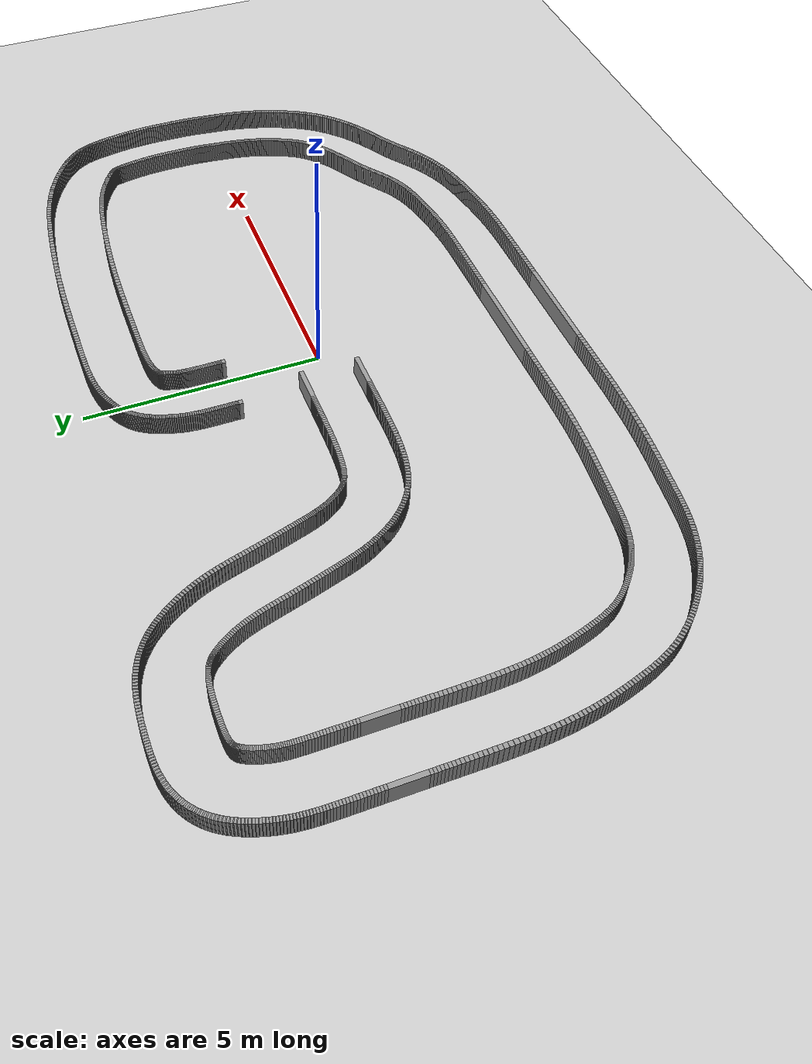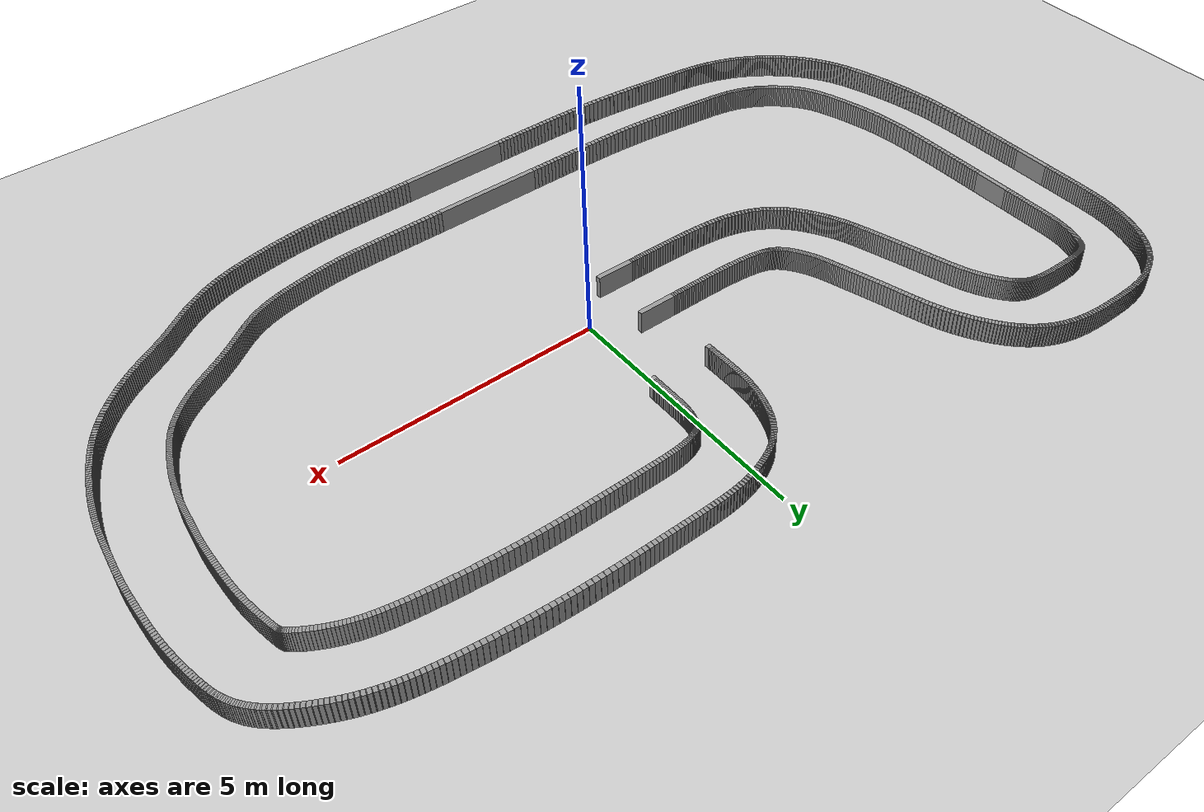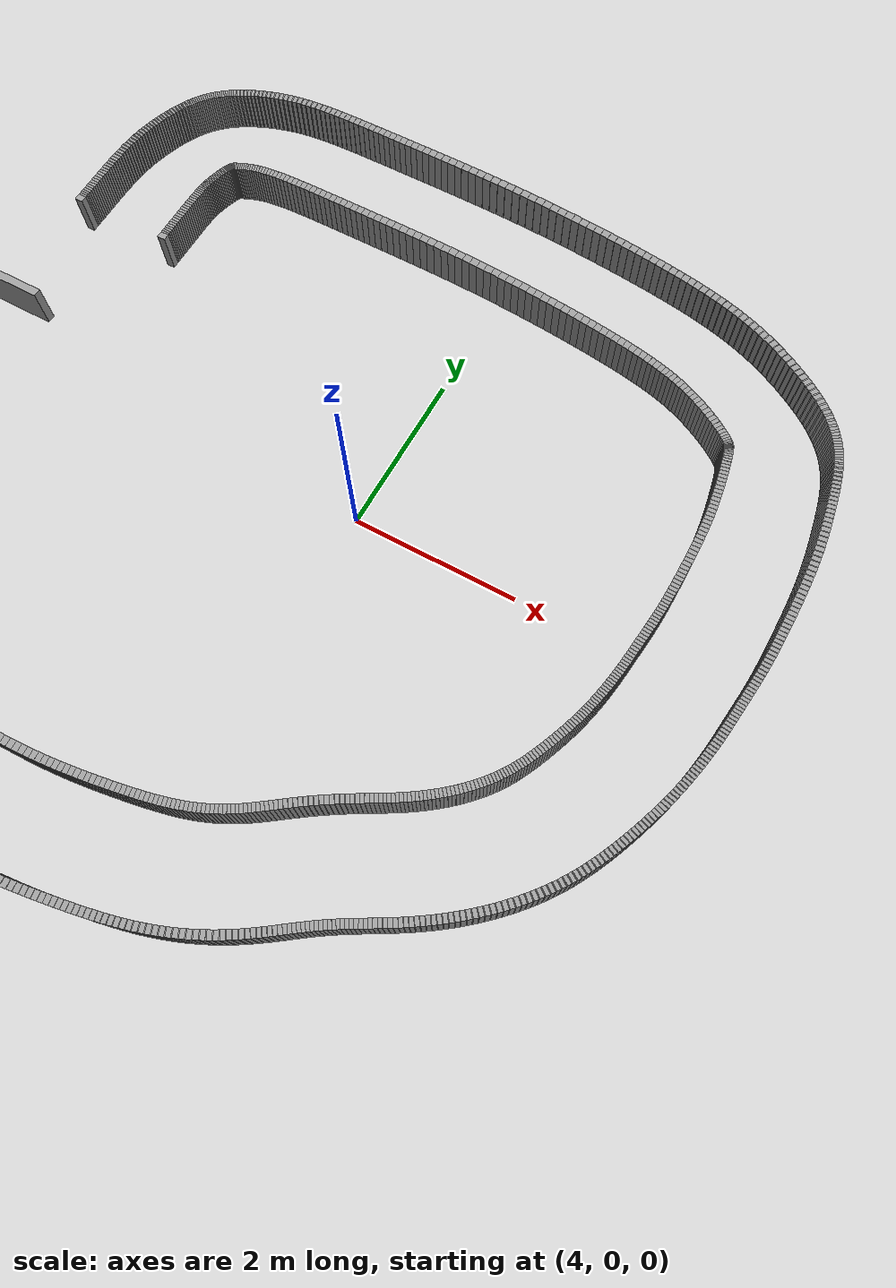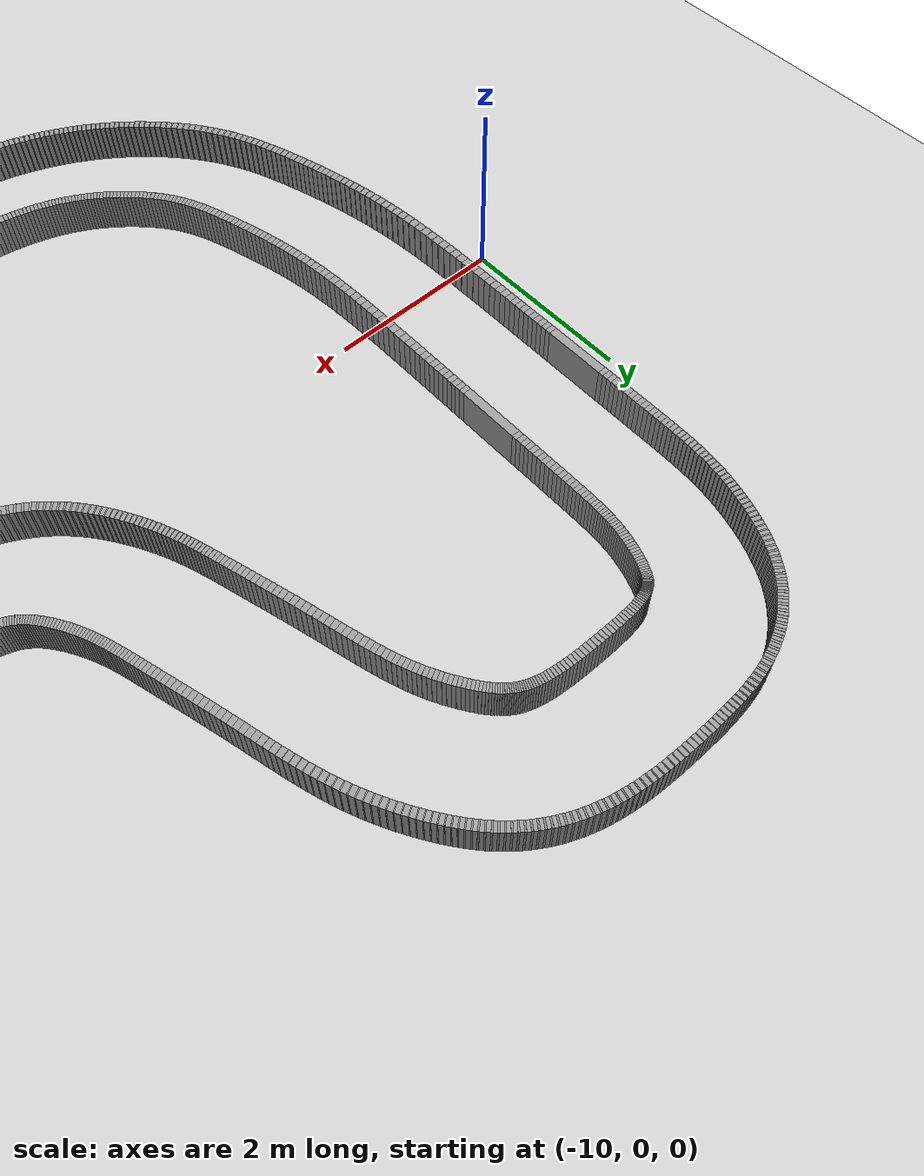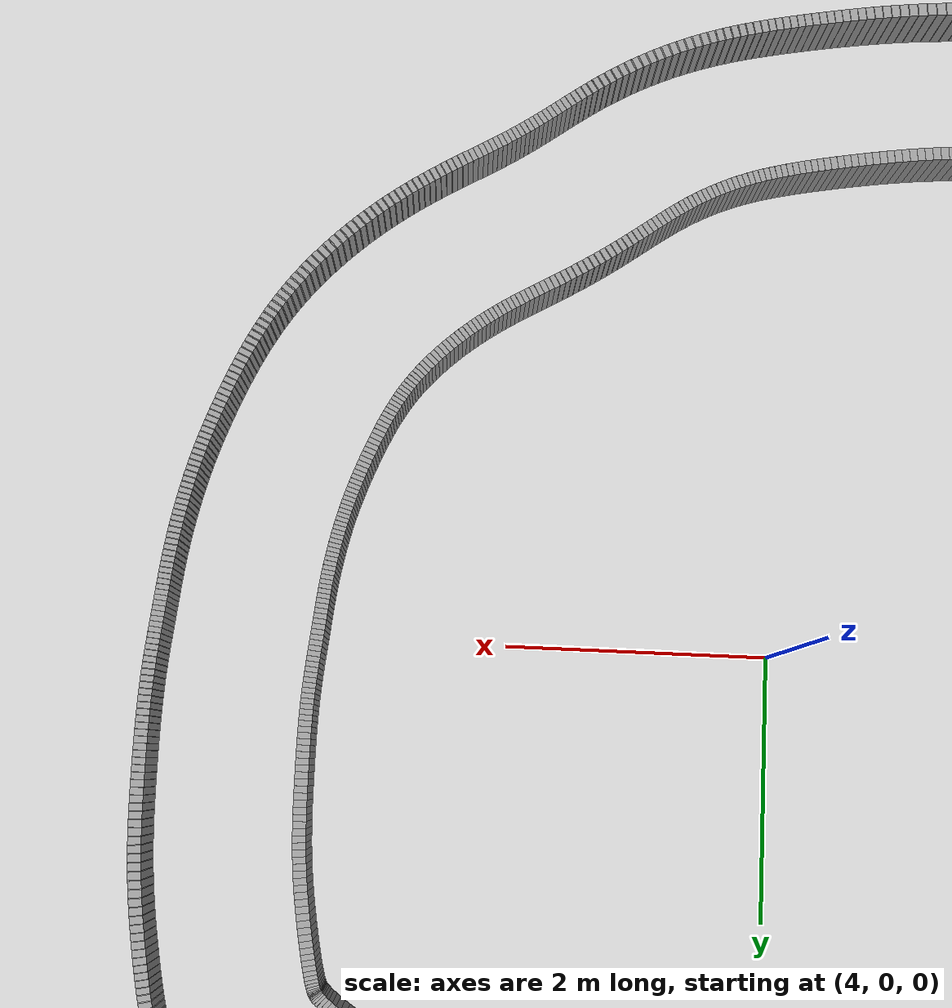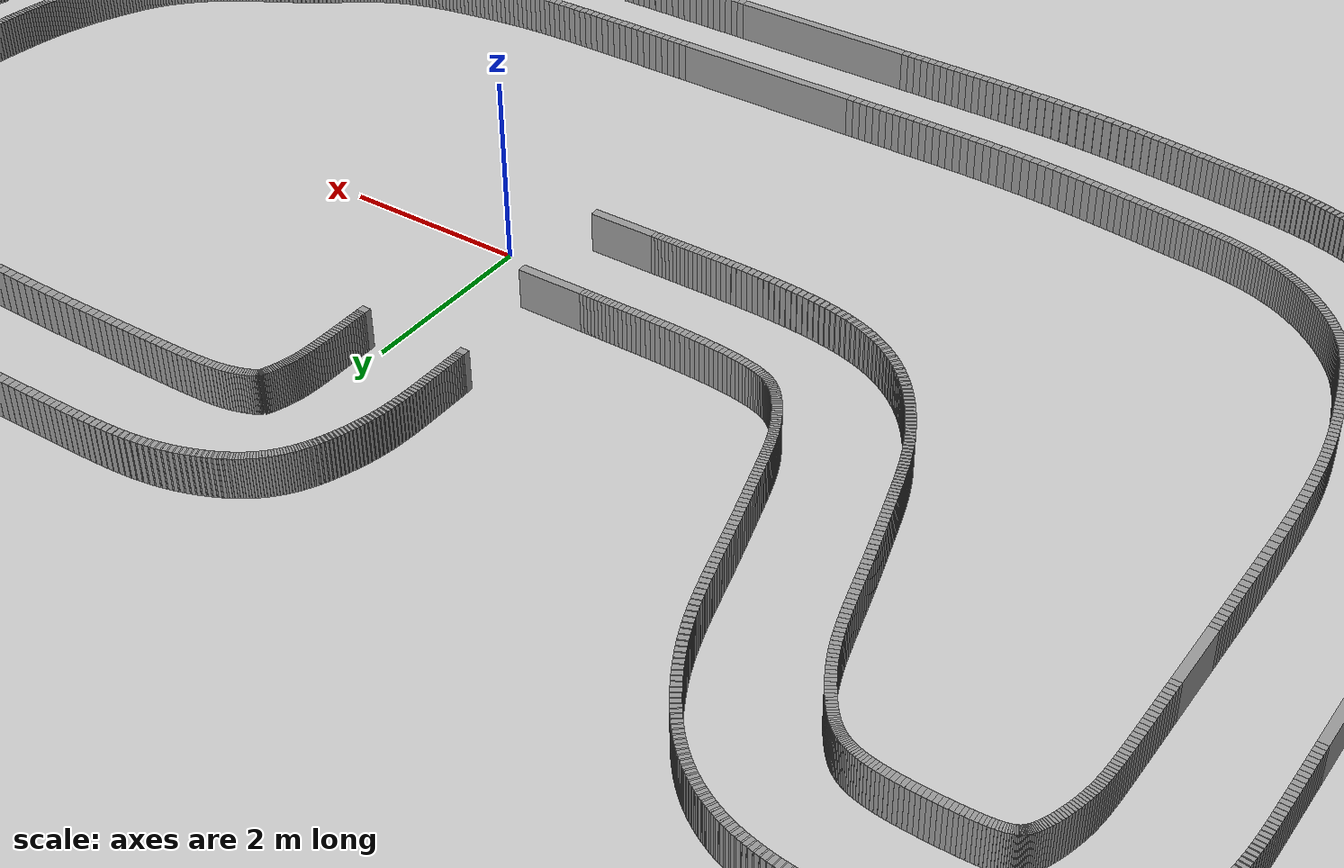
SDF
<?xml version="1.0"?>
        <sdf version="1.6">
        <world name="default">
            <include>
            <uri>model://ground_plane</uri>
            </include>
            <include>
            <uri>model://sun</uri>
            </include>

        <model name="wall_0_outward">
          <static>true</static>
          <link name="link">
            <collision name="collision">
              <geometry>
                <box>
                  <size>0.7352529885792195 0.1 0.45</size>
                </box>
              </geometry>
            </collision>
            <visual name="visual">
              <geometry>
                <box>
                  <size>0.7352529885792195 0.1 0.45</size>
                </box>
              </geometry>
              <material>
                <script>
                  <uri>file://media/materials/scripts/gazebo.material</uri>
                  <name>Gazebo/Gray</name>
                </script>
              </material>
            </visual>
          </link>
          <pose>-1.0092482364808772 -0.6 0.225 0 0 3.141592653589793</pose>
        </model>

        <model name="wall_1_outward">
          <static>true</static>
          <link name="link">
            <collision name="collision">
              <geometry>
                <box>
                  <size>0.04206558050443104 0.1 0.45</size>
                </box>
              </geometry>
            </collision>
            <visual name="visual">
              <geometry>
                <box>
                  <size>0.04206558050443104 0.1 0.45</size>
                </box>
              </geometry>
              <material>
                <script>
                  <uri>file://media/materials/scripts/gazebo.material</uri>
                  <name>Gazebo/Gray</name>
                </script>
              </material>
            </visual>
          </link>
          <pose>-1.3979075210213443 -0.599999760987078 0.225 0 0 3.141581289766011</pose>
        </model>

        <model name="wall_2_outward">
          <static>true</static>
          <link name="link">
            <collision name="collision">
              <geometry>
                <box>
                  <size>0.042329117051585576 0.1 0.45</size>
                </box>
              </geometry>
            </collision>
            <visual name="visual">
              <geometry>
                <box>
                  <size>0.042329117051585576 0.1 0.45</size>
                </box>
              </geometry>
              <material>
                <script>
                  <uri>file://media/materials/scripts/gazebo.material</uri>
                  <name>Gazebo/Gray</name>
                </script>
              </material>
            </visual>
          </link>
          <pose>-1.440104869793848 -0.5999991030226777 0.225 0 0 3.141572858635049</pose>
        </model>

        <model name="wall_3_outward">
          <static>true</static>
          <link name="link">
            <collision name="collision">
              <geometry>
                <box>
                  <size>0.042769654333055525 0.1 0.45</size>
                </box>
              </geometry>
            </collision>
            <visual name="visual">
              <geometry>
                <box>
                  <size>0.042769654333055525 0.1 0.45</size>
                </box>
              </geometry>
              <material>
                <script>
                  <uri>file://media/materials/scripts/gazebo.material</uri>
                  <name>Gazebo/Gray</name>
                </script>
              </material>
            </visual>
          </link>
          <pose>-1.4826542554699165 -0.5999979645170858 0.225 0 0 3.141559005709066</pose>
        </model>

        <model name="wall_4_outward">
          <static>true</static>
          <link name="link">
            <collision name="collision">
              <geometry>
                <box>
                  <size>0.043383684576640026 0.1 0.45</size>
                </box>
              </geometry>
            </collision>
            <visual name="visual">
              <geometry>
                <box>
                  <size>0.043383684576640026 0.1 0.45</size>
                </box>
              </geometry>
              <material>
                <script>
                  <uri>file://media/materials/scripts/gazebo.material</uri>
                  <name>Gazebo/Gray</name>
                </script>
              </material>
            </visual>
          </link>
          <pose>-1.5257309248788595 -0.5999960340481811 0.225 0 0 3.1415368300790276</pose>
        </model>

        <model name="wall_5_outward">
          <static>true</static>
          <link name="link">
            <collision name="collision">
              <geometry>
                <box>
                  <size>0.0441648146529873 0.1 0.45</size>
                </box>
              </geometry>
            </collision>
            <visual name="visual">
              <geometry>
                <box>
                  <size>0.0441648146529873 0.1 0.45</size>
                </box>
              </geometry>
              <material>
                <script>
                  <uri>file://media/materials/scripts/gazebo.material</uri>
                  <name>Gazebo/Gray</name>
                </script>
              </material>
            </visual>
          </link>
          <pose>-1.5695051743696007 -0.5999928264040322 0.225 0 0 3.1415022318648753</pose>
        </model>

        <model name="wall_6_outward">
          <static>true</static>
          <link name="link">
            <collision name="collision">
              <geometry>
                <box>
                  <size>0.04510750596771864 0.1 0.45</size>
                </box>
              </geometry>
            </collision>
            <visual name="visual">
              <geometry>
                <box>
                  <size>0.04510750596771864 0.1 0.45</size>
                </box>
              </geometry>
              <material>
                <script>
                  <uri>file://media/materials/scripts/gazebo.material</uri>
                  <name>Gazebo/Gray</name>
                </script>
              </material>
            </visual>
          </link>
          <pose>-1.614141334323414 -0.599987364044718 0.225 0 0 3.141438992690328</pose>
        </model>

        <model name="wall_7_outward">
          <static>true</static>
          <link name="link">
            <collision name="collision">
              <geometry>
                <box>
                  <size>0.04617741219046398 0.1 0.45</size>
                </box>
              </geometry>
            </collision>
            <visual name="visual">
              <geometry>
                <box>
                  <size>0.04617741219046398 0.1 0.45</size>
                </box>
              </geometry>
              <material>
                <script>
                  <uri>file://media/materials/scripts/gazebo.material</uri>
                  <name>Gazebo/Gray</name>
                </script>
              </material>
            </visual>
          </link>
          <pose>-1.6597837924746228 -0.5999783710518132 0.225 0 0 3.141353256761811</pose>
        </model>

        <model name="wall_8_outward">
          <static>true</static>
          <link name="link">
            <collision name="collision">
              <geometry>
                <box>
                  <size>0.04736522191237342 0.1 0.45</size>
                </box>
              </geometry>
            </collision>
            <visual name="visual">
              <geometry>
                <box>
                  <size>0.04736522191237342 0.1 0.45</size>
                </box>
              </geometry>
              <material>
                <script>
                  <uri>file://media/materials/scripts/gazebo.material</uri>
                  <name>Gazebo/Gray</name>
                </script>
              </material>
            </visual>
          </link>
          <pose>-1.7065551072864766 -0.599964198466842 0.225 0 0 3.1412276084420925</pose>
        </model>

        <model name="wall_9_outward">
          <static>true</static>
          <link name="link">
            <collision name="collision">
              <geometry>
                <box>
                  <size>0.048638678998525996 0.1 0.45</size>
                </box>
              </geometry>
            </collision>
            <visual name="visual">
              <geometry>
                <box>
                  <size>0.048638678998525996 0.1 0.45</size>
                </box>
              </geometry>
              <material>
                <script>
                  <uri>file://media/materials/scripts/gazebo.material</uri>
                  <name>Gazebo/Gray</name>
                </script>
              </material>
            </visual>
          </link>
          <pose>-1.7545570525484675 -0.599942292262823 0.225 0 0 3.141047368112191</pose>
        </model>

        <model name="wall_10_outward">
          <static>true</static>
          <link name="link">
            <collision name="collision">
              <geometry>
                <box>
                  <size>0.04997497708532629 0.1 0.45</size>
                </box>
              </geometry>
            </collision>
            <visual name="visual">
              <geometry>
                <box>
                  <size>0.04997497708532629 0.1 0.45</size>
                </box>
              </geometry>
              <material>
                <script>
                  <uri>file://media/materials/scripts/gazebo.material</uri>
                  <name>Gazebo/Gray</name>
                </script>
              </material>
            </visual>
          </link>
          <pose>-1.8038638688163893 -0.5999088391912553 0.225 0 0 3.140784565504666</pose>
        </model>

        <model name="wall_11_outward">
          <static>true</static>
          <link name="link">
            <collision name="collision">
              <geometry>
                <box>
                  <size>0.05133867092761572 0.1 0.45</size>
                </box>
              </geometry>
            </collision>
            <visual name="visual">
              <geometry>
                <box>
                  <size>0.05133867092761572 0.1 0.45</size>
                </box>
              </geometry>
              <material>
                <script>
                  <uri>file://media/materials/scripts/gazebo.material</uri>
                  <name>Gazebo/Gray</name>
                </script>
              </material>
            </visual>
          </link>
          <pose>-1.854520667008353 -0.5998585400270326 0.225 0 0 3.1404197723674887</pose>
        </model>

        <model name="wall_12_outward">
          <static>true</static>
          <link name="link">
            <collision name="collision">
              <geometry>
                <box>
                  <size>0.052701237121926356 0.1 0.45</size>
                </box>
              </geometry>
            </collision>
            <visual name="visual">
              <geometry>
                <box>
                  <size>0.052701237121926356 0.1 0.45</size>
                </box>
              </geometry>
              <material>
                <script>
                  <uri>file://media/materials/scripts/gazebo.material</uri>
                  <name>Gazebo/Gray</name>
                </script>
              </material>
            </visual>
          </link>
          <pose>-1.9065405670144142 -0.5997846567285423 0.225 0 0 3.1399313550561834</pose>
        </model>

        <model name="wall_13_outward">
          <static>true</static>
          <link name="link">
            <collision name="collision">
              <geometry>
                <box>
                  <size>0.05404584894879231 0.1 0.45</size>
                </box>
              </geometry>
            </collision>
            <visual name="visual">
              <geometry>
                <box>
                  <size>0.05404584894879231 0.1 0.45</size>
                </box>
              </geometry>
              <material>
                <script>
                  <uri>file://media/materials/scripts/gazebo.material</uri>
                  <name>Gazebo/Gray</name>
                </script>
              </material>
            </visual>
          </link>
          <pose>-1.959914001399631 -0.5996783758555605 0.225 0 0 3.1392796284049505</pose>
        </model>

        <model name="wall_14_outward">
          <static>true</static>
          <link name="link">
            <collision name="collision">
              <geometry>
                <box>
                  <size>0.0553569491289209 0.1 0.45</size>
                </box>
              </geometry>
            </collision>
            <visual name="visual">
              <geometry>
                <box>
                  <size>0.0553569491289209 0.1 0.45</size>
                </box>
              </geometry>
              <material>
                <script>
                  <uri>file://media/materials/scripts/gazebo.material</uri>
                  <name>Gazebo/Gray</name>
                </script>
              </material>
            </visual>
          </link>
          <pose>-2.0146151885653207 -0.599527967735671 0.225 0 0 3.138416769806492</pose>
        </model>

        <model name="wall_15_outward">
          <static>true</static>
          <link name="link">
            <collision name="collision">
              <geometry>
                <box>
                  <size>0.0006705485486266078 0.1 0.45</size>
                </box>
              </geometry>
            </collision>
            <visual name="visual">
              <geometry>
                <box>
                  <size>0.0006705485486266078 0.1 0.45</size>
                </box>
              </geometry>
              <material>
                <script>
                  <uri>file://media/materials/scripts/gazebo.material</uri>
                  <name>Gazebo/Gray</name>
                </script>
              </material>
            </visual>
          </link>
          <pose>-2.0426287954751334 -0.5994388107695642 0.225 0 0 3.13785392868103</pose>
        </model>

        <model name="wall_16_outward">
          <static>true</static>
          <link name="link">
            <collision name="collision">
              <geometry>
                <box>
                  <size>0.055938904773281645 0.1 0.45</size>
                </box>
              </geometry>
            </collision>
            <visual name="visual">
              <geometry>
                <box>
                  <size>0.055938904773281645 0.1 0.45</size>
                </box>
              </geometry>
              <material>
                <script>
                  <uri>file://media/materials/scripts/gazebo.material</uri>
                  <name>Gazebo/Gray</name>
                </script>
              </material>
            </visual>
          </link>
          <pose>-2.0709332615143916 -0.5993173584919708 0.225 0 0 3.137295138194895</pose>
        </model>

        <model name="wall_17_outward">
          <static>true</static>
          <link name="link">
            <collision name="collision">
              <geometry>
                <box>
                  <size>0.0008475659731906803 0.1 0.45</size>
                </box>
              </geometry>
            </collision>
            <visual name="visual">
              <geometry>
                <box>
                  <size>0.0008475659731906803 0.1 0.45</size>
                </box>
              </geometry>
              <material>
                <script>
                  <uri>file://media/materials/scripts/gazebo.material</uri>
                  <name>Gazebo/Gray</name>
                </script>
              </material>
            </visual>
          </link>
          <pose>-2.099326233303797 -0.5991950391846201 0.225 0 0 3.136588833158594</pose>
        </model>

        <model name="wall_18_outward">
          <static>true</static>
          <link name="link">
            <collision name="collision">
              <geometry>
                <box>
                  <size>0.056945785376173404 0.1 0.45</size>
                </box>
              </geometry>
            </collision>
            <visual name="visual">
              <geometry>
                <box>
                  <size>0.056945785376173404 0.1 0.45</size>
                </box>
              </geometry>
              <material>
                <script>
                  <uri>file://media/materials/scripts/gazebo.material</uri>
                  <name>Gazebo/Gray</name>
                </script>
              </material>
            </visual>
          </link>
          <pose>-2.128222439487447 -0.5990303357533464 0.225 0 0 3.1358825281221274</pose>
        </model>

        <model name="wall_19_outward">
          <static>true</static>
          <link name="link">
            <collision name="collision">
              <geometry>
                <box>
                  <size>0.0010631498359540369 0.1 0.45</size>
                </box>
              </geometry>
            </collision>
            <visual name="visual">
              <geometry>
                <box>
                  <size>0.0010631498359540369 0.1 0.45</size>
                </box>
              </geometry>
              <material>
                <script>
                  <uri>file://media/materials/scripts/gazebo.material</uri>
                  <name>Gazebo/Gray</name>
                </script>
              </material>
            </visual>
          </link>
          <pose>-2.1572264313439287 -0.5988642465599217 0.225 0 0 3.13499656980958</pose>
        </model>

        <model name="wall_20_outward">
          <static>true</static>
          <link name="link">
            <collision name="collision">
              <geometry>
                <box>
                  <size>0.057850876883226245 0.1 0.45</size>
                </box>
              </geometry>
            </collision>
            <visual name="visual">
              <geometry>
                <box>
                  <size>0.057850876883226245 0.1 0.45</size>
                </box>
              </geometry>
              <material>
                <script>
                  <uri>file://media/materials/scripts/gazebo.material</uri>
                  <name>Gazebo/Gray</name>
                </script>
              </material>
            </visual>
          </link>
          <pose>-2.186682623506554 -0.5986443209439221 0.225 0 0 3.134110611497067</pose>
        </model>

        <model name="wall_21_outward">
          <static>true</static>
          <link name="link">
            <collision name="collision">
              <geometry>
                <box>
                  <size>0.0013077952588421914 0.1 0.45</size>
                </box>
              </geometry>
            </collision>
            <visual name="visual">
              <geometry>
                <box>
                  <size>0.0013077952588421914 0.1 0.45</size>
                </box>
              </geometry>
              <material>
                <script>
                  <uri>file://media/materials/scripts/gazebo.material</uri>
                  <name>Gazebo/Gray</name>
                </script>
              </material>
            </visual>
          </link>
          <pose>-2.2162611259214815 -0.5984222965572539 0.225 0 0 3.1330207818988822</pose>
        </model>

        <model name="wall_22_outward">
          <static>true</static>
          <link name="link">
            <collision name="collision">
              <geometry>
                <box>
                  <size>0.058652713963058684 0.1 0.45</size>
                </box>
              </geometry>
            </collision>
            <visual name="visual">
              <geometry>
                <box>
                  <size>0.058652713963058684 0.1 0.45</size>
                </box>
              </geometry>
              <material>
                <script>
                  <uri>file://media/materials/scripts/gazebo.material</uri>
                  <name>Gazebo/Gray</name>
                </script>
              </material>
            </visual>
          </link>
          <pose>-2.24623998773471 -0.5981333534065125 0.225 0 0 3.1319309523008556</pose>
        </model>

        <model name="wall_23_outward">
          <static>true</static>
          <link name="link">
            <collision name="collision">
              <geometry>
                <box>
                  <size>0.0015784932551432653 0.1 0.45</size>
                </box>
              </geometry>
            </collision>
            <visual name="visual">
              <geometry>
                <box>
                  <size>0.0015784932551432653 0.1 0.45</size>
                </box>
              </geometry>
              <material>
                <script>
                  <uri>file://media/materials/scripts/gazebo.material</uri>
                  <name>Gazebo/Gray</name>
                </script>
              </material>
            </visual>
          </link>
          <pose>-2.2763541750187057 -0.5978413518385081 0.225 0 0 3.130615540875607</pose>
        </model>

        <model name="wall_24_outward">
          <static>true</static>
          <link name="link">
            <collision name="collision">
              <geometry>
                <box>
                  <size>0.05935485729162012 0.1 0.45</size>
                </box>
              </geometry>
            </collision>
            <visual name="visual">
              <geometry>
                <box>
                  <size>0.05935485729162012 0.1 0.45</size>
                </box>
              </geometry>
              <material>
                <script>
                  <uri>file://media/materials/scripts/gazebo.material</uri>
                  <name>Gazebo/Gray</name>
                </script>
              </material>
            </visual>
          </link>
          <pose>-2.3068185605488845 -0.5974678870427288 0.225 0 0 3.1293001294502623</pose>
        </model>

        <model name="wall_25_outward">
          <static>true</static>
          <link name="link">
            <collision name="collision">
              <geometry>
                <box>
                  <size>0.001883697061145958 0.1 0.45</size>
                </box>
              </geometry>
            </collision>
            <visual name="visual">
              <geometry>
                <box>
                  <size>0.001883697061145958 0.1 0.45</size>
                </box>
              </geometry>
              <material>
                <script>
                  <uri>file://media/materials/scripts/gazebo.material</uri>
                  <name>Gazebo/Gray</name>
                </script>
              </material>
            </visual>
          </link>
          <pose>-2.3374355050399345 -0.5970900299794678 0.225 0 0 3.1277303812546817</pose>
        </model>

        <model name="wall_26_outward">
          <static>true</static>
          <link name="link">
            <collision name="collision">
              <geometry>
                <box>
                  <size>0.059964425641846564 0.1 0.45</size>
                </box>
              </geometry>
            </collision>
            <visual name="visual">
              <geometry>
                <box>
                  <size>0.059964425641846564 0.1 0.45</size>
                </box>
              </geometry>
              <material>
                <script>
                  <uri>file://media/materials/scripts/gazebo.material</uri>
                  <name>Gazebo/Gray</name>
                </script>
              </material>
            </visual>
          </link>
          <pose>-2.36835590587882 -0.5966143064773279 0.225 0 0 3.126160633059009</pose>
        </model>

        <model name="wall_27_outward">
          <static>true</static>
          <link name="link">
            <collision name="collision">
              <geometry>
                <box>
                  <size>0.002210183302396733 0.1 0.45</size>
                </box>
              </geometry>
            </collision>
            <visual name="visual">
              <geometry>
                <box>
                  <size>0.002210183302396733 0.1 0.45</size>
                </box>
              </geometry>
              <material>
                <script>
                  <uri>file://media/materials/scripts/gazebo.material</uri>
                  <name>Gazebo/Gray</name>
                </script>
              </material>
            </visual>
          </link>
          <pose>-2.3994394754633026 -0.5961325504897157 0.225 0 0 3.1243188125989483</pose>
        </model>

        <model name="wall_28_outward">
          <static>true</static>
          <link name="link">
            <collision name="collision">
              <geometry>
                <box>
                  <size>0.060489131693299086 0.1 0.45</size>
                </box>
              </geometry>
            </collision>
            <visual name="visual">
              <geometry>
                <box>
                  <size>0.060489131693299086 0.1 0.45</size>
                </box>
              </geometry>
              <material>
                <script>
                  <uri>file://media/materials/scripts/gazebo.material</uri>
                  <name>Gazebo/Gray</name>
                </script>
              </material>
            </visual>
          </link>
          <pose>-2.4307834424508927 -0.5955353525893108 0.225 0 0 3.122476992139011</pose>
        </model>

        <model name="wall_29_outward">
          <static>true</static>
          <link name="link">
            <collision name="collision">
              <geometry>
                <box>
                  <size>0.002559584406411668 0.1 0.45</size>
                </box>
              </geometry>
            </collision>
            <visual name="visual">
              <geometry>
                <box>
                  <size>0.002559584406411668 0.1 0.45</size>
                </box>
              </geometry>
              <material>
                <script>
                  <uri>file://media/materials/scripts/gazebo.material</uri>
                  <name>Gazebo/Gray</name>
                </script>
              </material>
            </visual>
          </link>
          <pose>-2.4623019859525974 -0.5949300511066826 0.225 0 0 3.120344003516274</pose>
        </model>

        <model name="wall_30_outward">
          <static>true</static>
          <link name="link">
            <collision name="collision">
              <geometry>
                <box>
                  <size>0.060941438901204306 0.1 0.45</size>
                </box>
              </geometry>
            </collision>
            <visual name="visual">
              <geometry>
                <box>
                  <size>0.060941438901204306 0.1 0.45</size>
                </box>
              </geometry>
              <material>
                <script>
                  <uri>file://media/materials/scripts/gazebo.material</uri>
                  <name>Gazebo/Gray</name>
                </script>
              </material>
            </visual>
          </link>
          <pose>-2.4940438798935354 -0.5941904688582005 0.225 0 0 3.118211014893548</pose>
        </model>

        <model name="wall_31_outward">
          <static>true</static>
          <link name="link">
            <collision name="collision">
              <geometry>
                <box>
                  <size>0.0029163367736469185 0.1 0.45</size>
                </box>
              </geometry>
            </collision>
            <visual name="visual">
              <geometry>
                <box>
                  <size>0.0029163367736469185 0.1 0.45</size>
                </box>
              </geometry>
              <material>
                <script>
                  <uri>file://media/materials/scripts/gazebo.material</uri>
                  <name>Gazebo/Gray</name>
                </script>
              </material>
            </visual>
          </link>
          <pose>-2.525963953194352 -0.5934404444711163 0.225 0 0 3.1157807318565482</pose>
        </model>

        <model name="wall_32_outward">
          <static>true</static>
          <link name="link">
            <collision name="collision">
              <geometry>
                <box>
                  <size>0.06132942822464123 0.1 0.45</size>
                </box>
              </geometry>
            </collision>
            <visual name="visual">
              <geometry>
                <box>
                  <size>0.06132942822464123 0.1 0.45</size>
                </box>
              </geometry>
              <material>
                <script>
                  <uri>file://media/materials/scripts/gazebo.material</uri>
                  <name>Gazebo/Gray</name>
                </script>
              </material>
            </visual>
          </link>
          <pose>-2.558074121349807 -0.5925368865110254 0.225 0 0 3.113350448819497</pose>
        </model>

        <model name="wall_33_outward">
          <static>true</static>
          <link name="link">
            <collision name="collision">
              <geometry>
                <box>
                  <size>0.0032893538338839828 0.1 0.45</size>
                </box>
              </geometry>
            </collision>
            <visual name="visual">
              <geometry>
                <box>
                  <size>0.0032893538338839828 0.1 0.45</size>
                </box>
              </geometry>
              <material>
                <script>
                  <uri>file://media/materials/scripts/gazebo.material</uri>
                  <name>Gazebo/Gray</name>
                </script>
              </material>
            </visual>
          </link>
          <pose>-2.5903704944098784 -0.5916200130742733 0.225 0 0 3.1106093171918787</pose>
        </model>

        <model name="wall_34_outward">
          <static>true</static>
          <link name="link">
            <collision name="collision">
              <geometry>
                <box>
                  <size>0.06165995206838387 0.1 0.45</size>
                </box>
              </geometry>
            </collision>
            <visual name="visual">
              <geometry>
                <box>
                  <size>0.06165995206838387 0.1 0.45</size>
                </box>
              </geometry>
              <material>
                <script>
                  <uri>file://media/materials/scripts/gazebo.material</uri>
                  <name>Gazebo/Gray</name>
                </script>
              </material>
            </visual>
          </link>
          <pose>-2.6228268275893467 -0.5905295361831049 0.225 0 0 3.107868185564253</pose>
        </model>

        <model name="wall_35_outward">
          <static>true</static>
          <link name="link">
            <collision name="collision">
              <geometry>
                <box>
                  <size>0.0036676270697501017 0.1 0.45</size>
                </box>
              </geometry>
            </collision>
            <visual name="visual">
              <geometry>
                <box>
                  <size>0.0036676270697501017 0.1 0.45</size>
                </box>
              </geometry>
              <material>
                <script>
                  <uri>file://media/materials/scripts/gazebo.material</uri>
                  <name>Gazebo/Gray</name>
                </script>
              </material>
            </visual>
          </link>
          <pose>-2.655471846462932 -0.5894225747429727 0.225 0 0 3.1048118249143806</pose>
        </model>

        <model name="wall_36_outward">
          <static>true</static>
          <link name="link">
            <collision name="collision">
              <geometry>
                <box>
                  <size>0.06193463527221274 0.1 0.45</size>
                </box>
              </geometry>
            </collision>
            <visual name="visual">
              <geometry>
                <box>
                  <size>0.06193463527221274 0.1 0.45</size>
                </box>
              </geometry>
              <material>
                <script>
                  <uri>file://media/materials/scripts/gazebo.material</uri>
                  <name>Gazebo/Gray</name>
                </script>
              </material>
            </visual>
          </link>
          <pose>-2.688247168012766 -0.588121816147912 0.225 0 0 3.1017554642645035</pose>
        </model>

        <model name="wall_37_outward">
          <static>true</static>
          <link name="link">
            <collision name="collision">
              <geometry>
                <box>
                  <size>0.004044527399908943 0.1 0.45</size>
                </box>
              </geometry>
            </collision>
            <visual name="visual">
              <geometry>
                <box>
                  <size>0.004044527399908943 0.1 0.45</size>
                </box>
              </geometry>
              <material>
                <script>
                  <uri>file://media/materials/scripts/gazebo.material</uri>
                  <name>Gazebo/Gray</name>
                </script>
              </material>
            </visual>
          </link>
          <pose>-2.7212102926181094 -0.5868011414801022 0.225 0 0 3.0983850183832597</pose>
        </model>

        <model name="wall_38_outward">
          <static>true</static>
          <link name="link">
            <collision name="collision">
              <geometry>
                <box>
                  <size>0.06215217779699435 0.1 0.45</size>
                </box>
              </geometry>
            </collision>
            <visual name="visual">
              <geometry>
                <box>
                  <size>0.06215217779699435 0.1 0.45</size>
                </box>
              </geometry>
              <material>
                <script>
                  <uri>file://media/materials/scripts/gazebo.material</uri>
                  <name>Gazebo/Gray</name>
                </script>
              </material>
            </visual>
          </link>
          <pose>-2.754273053861048 -0.5852668501706966 0.225 0 0 3.095014572502016</pose>
        </model>

        <model name="wall_39_outward">
          <static>true</static>
          <link name="link">
            <collision name="collision">
              <geometry>
                <box>
                  <size>0.004445168200415039 0.1 0.45</size>
                </box>
              </geometry>
            </collision>
            <visual name="visual">
              <geometry>
                <box>
                  <size>0.004445168200415039 0.1 0.45</size>
                </box>
              </geometry>
              <material>
                <script>
                  <uri>file://media/materials/scripts/gazebo.material</uri>
                  <name>Gazebo/Gray</name>
                </script>
              </material>
            </visual>
          </link>
          <pose>-2.7875352137830705 -0.5837081991407861 0.225 0 0 3.091310257196605</pose>
        </model>

        <model name="wall_40_outward">
          <static>true</static>
          <link name="link">
            <collision name="collision">
              <geometry>
                <box>
                  <size>0.06230582462110974 0.1 0.45</size>
                </box>
              </geometry>
            </collision>
            <visual name="visual">
              <geometry>
                <box>
                  <size>0.06230582462110974 0.1 0.45</size>
                </box>
              </geometry>
              <material>
                <script>
                  <uri>file://media/materials/scripts/gazebo.material</uri>
                  <name>Gazebo/Gray</name>
                </script>
              </material>
            </visual>
          </link>
          <pose>-2.820862513515334 -0.5819154629320087 0.225 0 0 3.0876059418911894</pose>
        </model>

        <model name="wall_41_outward">
          <static>true</static>
          <link name="link">
            <collision name="collision">
              <geometry>
                <box>
                  <size>0.004854494600850982 0.1 0.45</size>
                </box>
              </geometry>
            </collision>
            <visual name="visual">
              <geometry>
                <box>
                  <size>0.004854494600850982 0.1 0.45</size>
                </box>
              </geometry>
              <material>
                <script>
                  <uri>file://media/materials/scripts/gazebo.material</uri>
                  <name>Gazebo/Gray</name>
                </script>
              </material>
            </visual>
          </link>
          <pose>-2.854393199548847 -0.5800936571971181 0.225 0 0 3.0835605186896116</pose>
        </model>

        <model name="wall_42_outward">
          <static>true</static>
          <link name="link">
            <collision name="collision">
              <geometry>
                <box>
                  <size>0.06238467672611344 0.1 0.45</size>
                </box>
              </geometry>
            </collision>
            <visual name="visual">
              <geometry>
                <box>
                  <size>0.06238467672611344 0.1 0.45</size>
                </box>
              </geometry>
              <material>
                <script>
                  <uri>file://media/materials/scripts/gazebo.material</uri>
                  <name>Gazebo/Gray</name>
                </script>
              </material>
            </visual>
          </link>
          <pose>-2.887948616742678 -0.5780177771233033 0.225 0 0 3.0795150954880683</pose>
        </model>

        <model name="wall_43_outward">
          <static>true</static>
          <link name="link">
            <collision name="collision">
              <geometry>
                <box>
                  <size>0.005299424687438247 0.1 0.45</size>
                </box>
              </geometry>
            </collision>
            <visual name="visual">
              <geometry>
                <box>
                  <size>0.005299424687438247 0.1 0.45</size>
                </box>
              </geometry>
              <material>
                <script>
                  <uri>file://media/materials/scripts/gazebo.material</uri>
                  <name>Gazebo/Gray</name>
                </script>
              </material>
            </visual>
          </link>
          <pose>-2.9217247294003696 -0.5759066168134261 0.225 0 0 3.0750988938938053</pose>
        </model>

        <model name="wall_44_outward">
          <static>true</static>
          <link name="link">
            <collision name="collision">
              <geometry>
                <box>
                  <size>0.06237431622302927 0.1 0.45</size>
                </box>
              </geometry>
            </collision>
            <visual name="visual">
              <geometry>
                <box>
                  <size>0.06237431622302927 0.1 0.45</size>
                </box>
              </geometry>
              <material>
                <script>
                  <uri>file://media/materials/scripts/gazebo.material</uri>
                  <name>Gazebo/Gray</name>
                </script>
              </material>
            </visual>
          </link>
          <pose>-2.9554773691300147 -0.5735209299455013 0.225 0 0 3.0706826922995445</pose>
        </model>

        <model name="wall_45_outward">
          <static>true</static>
          <link name="link">
            <collision name="collision">
              <geometry>
                <box>
                  <size>0.005775770505434381 0.1 0.45</size>
                </box>
              </geometry>
            </collision>
            <visual name="visual">
              <geometry>
                <box>
                  <size>0.005775770505434381 0.1 0.45</size>
                </box>
              </geometry>
              <material>
                <script>
                  <uri>file://media/materials/scripts/gazebo.material</uri>
                  <name>Gazebo/Gray</name>
                </script>
              </material>
            </visual>
          </link>
          <pose>-2.989465761757532 -0.5710928318450671 0.225 0 0 3.0658695316276923</pose>
        </model>

        <model name="wall_46_outward">
          <static>true</static>
          <link name="link">
            <collision name="collision">
              <geometry>
                <box>
                  <size>0.06225901046842116 0.1 0.45</size>
                </box>
              </geometry>
            </collision>
            <visual name="visual">
              <geometry>
                <box>
                  <size>0.06225901046842116 0.1 0.45</size>
                </box>
              </geometry>
              <material>
                <script>
                  <uri>file://media/materials/scripts/gazebo.material</uri>
                  <name>Gazebo/Gray</name>
                </script>
              </material>
            </visual>
          </link>
          <pose>-3.023373976770284 -0.568370015736782 0.225 0 0 3.061056370955811</pose>
        </model>

        <model name="wall_47_outward">
          <static>true</static>
          <link name="link">
            <collision name="collision">
              <geometry>
                <box>
                  <size>0.006323392954869769 0.1 0.45</size>
                </box>
              </geometry>
            </collision>
            <visual name="visual">
              <geometry>
                <box>
                  <size>0.006323392954869769 0.1 0.45</size>
                </box>
              </geometry>
              <material>
                <script>
                  <uri>file://media/materials/scripts/gazebo.material</uri>
                  <name>Gazebo/Gray</name>
                </script>
              </material>
            </visual>
          </link>
          <pose>-3.0575526465367204 -0.5655947112731657 0.225 0 0 3.0557868524395917</pose>
        </model>

        <model name="wall_48_outward">
          <static>true</static>
          <link name="link">
            <collision name="collision">
              <geometry>
                <box>
                  <size>0.062023103240961795 0.1 0.45</size>
                </box>
              </geometry>
            </collision>
            <visual name="visual">
              <geometry>
                <box>
                  <size>0.062023103240961795 0.1 0.45</size>
                </box>
              </geometry>
              <material>
                <script>
                  <uri>file://media/materials/scripts/gazebo.material</uri>
                  <name>Gazebo/Gray</name>
                </script>
              </material>
            </visual>
          </link>
          <pose>-3.0915857354695184 -0.5625032681393521 0.225 0 0 3.0505173339234046</pose>
        </model>

        <model name="wall_49_outward">
          <static>true</static>
          <link name="link">
            <collision name="collision">
              <geometry>
                <box>
                  <size>0.006940154993773211 0.1 0.45</size>
                </box>
              </geometry>
            </collision>
            <visual name="visual">
              <geometry>
                <box>
                  <size>0.006940154993773211 0.1 0.45</size>
                </box>
              </geometry>
              <material>
                <script>
                  <uri>file://media/materials/scripts/gazebo.material</uri>
                  <name>Gazebo/Gray</name>
                </script>
              </material>
            </visual>
          </link>
          <pose>-3.1259225727219855 -0.5593472018242215 0.225 0 0 3.0447338391868275</pose>
        </model>

        <model name="wall_50_outward">
          <static>true</static>
          <link name="link">
            <collision name="collision">
              <geometry>
                <box>
                  <size>0.06165475298780092 0.1 0.45</size>
                </box>
              </geometry>
            </collision>
            <visual name="visual">
              <geometry>
                <box>
                  <size>0.06165475298780092 0.1 0.45</size>
                </box>
              </geometry>
              <material>
                <script>
                  <uri>file://media/materials/scripts/gazebo.material</uri>
                  <name>Gazebo/Gray</name>
                </script>
              </material>
            </visual>
          </link>
          <pose>-3.1600415144204126 -0.5558529795206366 0.225 0 0 3.0389503444502166</pose>
        </model>

        <model name="wall_51_outward">
          <static>true</static>
          <link name="link">
            <collision name="collision">
              <geometry>
                <box>
                  <size>0.00764403585908198 0.1 0.45</size>
                </box>
              </geometry>
            </collision>
            <visual name="visual">
              <geometry>
                <box>
                  <size>0.00764403585908198 0.1 0.45</size>
                </box>
              </geometry>
              <material>
                <script>
                  <uri>file://media/materials/scripts/gazebo.material</uri>
                  <name>Gazebo/Gray</name>
                </script>
              </material>
            </visual>
          </link>
          <pose>-3.1945059739458026 -0.5522785169656194 0.225 0 0 3.032580271487108</pose>
        </model>

        <model name="wall_52_outward">
          <static>true</static>
          <link name="link">
            <collision name="collision">
              <geometry>
                <box>
                  <size>0.06114531068851354 0.1 0.45</size>
                </box>
              </geometry>
            </collision>
            <visual name="visual">
              <geometry>
                <box>
                  <size>0.06114531068851354 0.1 0.45</size>
                </box>
              </geometry>
              <material>
                <script>
                  <uri>file://media/materials/scripts/gazebo.material</uri>
                  <name>Gazebo/Gray</name>
                </script>
              </material>
            </visual>
          </link>
          <pose>-3.2286746769456647 -0.5483429682813677 0.225 0 0 3.0262101985240086</pose>
        </model>

        <model name="wall_53_outward">
          <static>true</static>
          <link name="link">
            <collision name="collision">
              <geometry>
                <box>
                  <size>0.008449735489854945 0.1 0.45</size>
                </box>
              </geometry>
            </collision>
            <visual name="visual">
              <geometry>
                <box>
                  <size>0.008449735489854945 0.1 0.45</size>
                </box>
              </geometry>
              <material>
                <script>
                  <uri>file://media/materials/scripts/gazebo.material</uri>
                  <name>Gazebo/Gray</name>
                </script>
              </material>
            </visual>
          </link>
          <pose>-3.2632372962907796 -0.5443073081380969 0.225 0 0 3.01916869409305</pose>
        </model>

        <model name="wall_54_outward">
          <static>true</static>
          <link name="link">
            <collision name="collision">
              <geometry>
                <box>
                  <size>0.060493335756579676 0.1 0.45</size>
                </box>
              </geometry>
            </collision>
            <visual name="visual">
              <geometry>
                <box>
                  <size>0.060493335756579676 0.1 0.45</size>
                </box>
              </geometry>
              <material>
                <script>
                  <uri>file://media/materials/scripts/gazebo.material</uri>
                  <name>Gazebo/Gray</name>
                </script>
              </material>
            </visual>
          </link>
          <pose>-3.2974240781017863 -0.5398864053386485 0.225 0 0 3.012127189662075</pose>
        </model>

        <model name="wall_55_outward">
          <static>true</static>
          <link name="link">
            <collision name="collision">
              <geometry>
                <box>
                  <size>0.009380935572973717 0.1 0.45</size>
                </box>
              </geometry>
            </collision>
            <visual name="visual">
              <geometry>
                <box>
                  <size>0.009380935572973717 0.1 0.45</size>
                </box>
              </geometry>
              <material>
                <script>
                  <uri>file://media/materials/scripts/gazebo.material</uri>
                  <name>Gazebo/Gray</name>
                </script>
              </material>
            </visual>
          </link>
          <pose>-3.332063950443813 -0.5353395358258382 0.225 0 0 3.0043096637251563</pose>
        </model>

        <model name="wall_56_outward">
          <static>true</static>
          <link name="link">
            <collision name="collision">
              <geometry>
                <box>
                  <size>0.059704334742487174 0.1 0.45</size>
                </box>
              </geometry>
            </collision>
            <visual name="visual">
              <geometry>
                <box>
                  <size>0.059704334742487174 0.1 0.45</size>
                </box>
              </geometry>
              <material>
                <script>
                  <uri>file://media/materials/scripts/gazebo.material</uri>
                  <name>Gazebo/Gray</name>
                </script>
              </material>
            </visual>
          </link>
          <pose>-3.366248750075924 -0.5303812538032311 0.225 0 0 2.996492137788262</pose>
        </model>

        <model name="wall_57_outward">
          <static>true</static>
          <link name="link">
            <collision name="collision">
              <geometry>
                <box>
                  <size>0.010427968506543633 0.1 0.45</size>
                </box>
              </geometry>
            </collision>
            <visual name="visual">
              <geometry>
                <box>
                  <size>0.010427968506543633 0.1 0.45</size>
                </box>
              </geometry>
              <material>
                <script>
                  <uri>file://media/materials/scripts/gazebo.material</uri>
                  <name>Gazebo/Gray</name>
                </script>
              </material>
            </visual>
          </link>
          <pose>-3.4009396585631606 -0.5252661678853157 0.225 0 0 2.9878020546576125</pose>
        </model>

        <model name="wall_58_outward">
          <static>true</static>
          <link name="link">
            <collision name="collision">
              <geometry>
                <box>
                  <size>0.05879118902414846 0.1 0.45</size>
                </box>
              </geometry>
            </collision>
            <visual name="visual">
              <geometry>
                <box>
                  <size>0.05879118902414846 0.1 0.45</size>
                </box>
              </geometry>
              <material>
                <script>
                  <uri>file://media/materials/scripts/gazebo.material</uri>
                  <name>Gazebo/Gray</name>
                </script>
              </material>
            </visual>
          </link>
          <pose>-3.4351005308195814 -0.5197122346274887 0.225 0 0 2.979111971526935</pose>
        </model>

        <model name="wall_59_outward">
          <static>true</static>
          <link name="link">
            <collision name="collision">
              <geometry>
                <box>
                  <size>0.011593127245283651 0.1 0.45</size>
                </box>
              </geometry>
            </collision>
            <visual name="visual">
              <geometry>
                <box>
                  <size>0.011593127245283651 0.1 0.45</size>
                </box>
              </geometry>
              <material>
                <script>
                  <uri>file://media/materials/scripts/gazebo.material</uri>
                  <name>Gazebo/Gray</name>
                </script>
              </material>
            </visual>
          </link>
          <pose>-3.4698198481109355 -0.513964096044264 0.225 0 0 2.9694508818675995</pose>
        </model>

        <model name="wall_60_outward">
          <static>true</static>
          <link name="link">
            <collision name="collision">
              <geometry>
                <box>
                  <size>0.0577722563220983 0.1 0.45</size>
                </box>
              </geometry>
            </collision>
            <visual name="visual">
              <geometry>
                <box>
                  <size>0.0577722563220983 0.1 0.45</size>
                </box>
              </geometry>
              <material>
                <script>
                  <uri>file://media/materials/scripts/gazebo.material</uri>
                  <name>Gazebo/Gray</name>
                </script>
              </material>
            </visual>
          </link>
          <pose>-3.503940804805164 -0.5077484870283014 0.225 0 0 2.959789792208271</pose>
        </model>

        <model name="wall_61_outward">
          <static>true</static>
          <link name="link">
            <collision name="collision">
              <geometry>
                <box>
                  <size>0.012873151455368562 0.1 0.45</size>
                </box>
              </geometry>
            </collision>
            <visual name="visual">
              <geometry>
                <box>
                  <size>0.012873151455368562 0.1 0.45</size>
                </box>
              </geometry>
              <material>
                <script>
                  <uri>file://media/materials/scripts/gazebo.material</uri>
                  <name>Gazebo/Gray</name>
                </script>
              </material>
            </visual>
          </link>
          <pose>-3.538668518243627 -0.5012941914198967 0.225 0 0 2.949061960225425</pose>
        </model>

        <model name="wall_62_outward">
          <static>true</static>
          <link name="link">
            <collision name="collision">
              <geometry>
                <box>
                  <size>0.05667238505356784 0.1 0.45</size>
                </box>
              </geometry>
            </collision>
            <visual name="visual">
              <geometry>
                <box>
                  <size>0.05667238505356784 0.1 0.45</size>
                </box>
              </geometry>
              <material>
                <script>
                  <uri>file://media/materials/scripts/gazebo.material</uri>
                  <name>Gazebo/Gray</name>
                </script>
              </material>
            </visual>
          </link>
          <pose>-3.5727390301677797 -0.49434259885946247 0.225 0 0 2.9383341282425786</pose>
        </model>

        <model name="wall_63_outward">
          <static>true</static>
          <link name="link">
            <collision name="collision">
              <geometry>
                <box>
                  <size>0.014243865580523818 0.1 0.45</size>
                </box>
              </geometry>
            </collision>
            <visual name="visual">
              <geometry>
                <box>
                  <size>0.014243865580523818 0.1 0.45</size>
                </box>
              </geometry>
              <material>
                <script>
                  <uri>file://media/materials/scripts/gazebo.material</uri>
                  <name>Gazebo/Gray</name>
                </script>
              </material>
            </visual>
          </link>
          <pose>-3.60744965864608 -0.4871022613680493 0.225 0 0 2.926463961508001</pose>
        </model>

        <model name="wall_64_outward">
          <static>true</static>
          <link name="link">
            <collision name="collision">
              <geometry>
                <box>
                  <size>0.05552128411459275 0.1 0.45</size>
                </box>
              </geometry>
            </collision>
            <visual name="visual">
              <geometry>
                <box>
                  <size>0.05552128411459275 0.1 0.45</size>
                </box>
              </geometry>
              <material>
                <script>
                  <uri>file://media/materials/scripts/gazebo.material</uri>
                  <name>Gazebo/Gray</name>
                </script>
              </material>
            </visual>
          </link>
          <pose>-3.6414558994153787 -0.47933426551100106 0.225 0 0 2.9145937947734084</pose>
        </model>

        <model name="wall_65_outward">
          <static>true</static>
          <link name="link">
            <collision name="collision">
              <geometry>
                <box>
                  <size>0.01569068084477902 0.1 0.45</size>
                </box>
              </geometry>
            </collision>
            <visual name="visual">
              <geometry>
                <box>
                  <size>0.01569068084477902 0.1 0.45</size>
                </box>
              </geometry>
              <material>
                <script>
                  <uri>file://media/materials/scripts/gazebo.material</uri>
                  <name>Gazebo/Gray</name>
                </script>
              </material>
            </visual>
          </link>
          <pose>-3.676124713133195 -0.47122118310010824 0.225 0 0 2.9015178547847875</pose>
        </model>

        <model name="wall_66_outward">
          <static>true</static>
          <link name="link">
            <collision name="collision">
              <geometry>
                <box>
                  <size>0.054348212653512744 0.1 0.45</size>
                </box>
              </geometry>
            </collision>
            <visual name="visual">
              <geometry>
                <box>
                  <size>0.054348212653512744 0.1 0.45</size>
                </box>
              </geometry>
              <material>
                <script>
                  <uri>file://media/materials/scripts/gazebo.material</uri>
                  <name>Gazebo/Gray</name>
                </script>
              </material>
            </visual>
          </link>
          <pose>-3.710053066858401 -0.4625498502531304 0.225 0 0 2.888441914796173</pose>
        </model>

        <model name="wall_67_outward">
          <static>true</static>
          <link name="link">
            <collision name="collision">
              <geometry>
                <box>
                  <size>0.017147386046350514 0.1 0.45</size>
                </box>
              </geometry>
            </collision>
            <visual name="visual">
              <geometry>
                <box>
                  <size>0.017147386046350514 0.1 0.45</size>
                </box>
              </geometry>
              <material>
                <script>
                  <uri>file://media/materials/scripts/gazebo.material</uri>
                  <name>Gazebo/Gray</name>
                </script>
              </material>
            </visual>
          </link>
          <pose>-3.744629984522907 -0.4534782270140262 0.225 0 0 2.874151940085665</pose>
        </model>

        <model name="wall_68_outward">
          <static>true</static>
          <link name="link">
            <collision name="collision">
              <geometry>
                <box>
                  <size>0.0531842612680924 0.1 0.45</size>
                </box>
              </geometry>
            </collision>
            <visual name="visual">
              <geometry>
                <box>
                  <size>0.0531842612680924 0.1 0.45</size>
                </box>
              </geometry>
              <material>
                <script>
                  <uri>file://media/materials/scripts/gazebo.material</uri>
                  <name>Gazebo/Gray</name>
                </script>
              </material>
            </visual>
          </link>
          <pose>-3.7784426408941103 -0.4438194037672025 0.225 0 0 2.8598619653751554</pose>
        </model>

        <model name="wall_69_outward">
          <static>true</static>
          <link name="link">
            <collision name="collision">
              <geometry>
                <box>
                  <size>0.01858329937596084 0.1 0.45</size>
                </box>
              </geometry>
            </collision>
            <visual name="visual">
              <geometry>
                <box>
                  <size>0.01858329937596084 0.1 0.45</size>
                </box>
              </geometry>
              <material>
                <script>
                  <uri>file://media/materials/scripts/gazebo.material</uri>
                  <name>Gazebo/Gray</name>
                </script>
              </material>
            </visual>
          </link>
          <pose>-3.812870654060027 -0.4337051395560821 0.225 0 0 2.844375263519509</pose>
        </model>

        <model name="wall_70_outward">
          <static>true</static>
          <link name="link">
            <collision name="collision">
              <geometry>
                <box>
                  <size>0.05205552827570588 0.1 0.45</size>
                </box>
              </geometry>
            </collision>
            <visual name="visual">
              <geometry>
                <box>
                  <size>0.05205552827570588 0.1 0.45</size>
                </box>
              </geometry>
              <material>
                <script>
                  <uri>file://media/materials/scripts/gazebo.material</uri>
                  <name>Gazebo/Gray</name>
                </script>
              </material>
            </visual>
          </link>
          <pose>-3.846520464827846 -0.42297698841826636 0.225 0 0 2.828888561663873</pose>
        </model>

        <model name="wall_71_outward">
          <static>true</static>
          <link name="link">
            <collision name="collision">
              <geometry>
                <box>
                  <size>0.019926354903995046 0.1 0.45</size>
                </box>
              </geometry>
            </collision>
            <visual name="visual">
              <geometry>
                <box>
                  <size>0.019926354903995046 0.1 0.45</size>
                </box>
              </geometry>
              <material>
                <script>
                  <uri>file://media/materials/scripts/gazebo.material</uri>
                  <name>Gazebo/Gray</name>
                </script>
              </material>
            </visual>
          </link>
          <pose>-3.8807138299735504 -0.41174800146491436 0.225 0 0 2.8122825027032925</pose>
        </model>

        <model name="wall_72_outward">
          <static>true</static>
          <link name="link">
            <collision name="collision">
              <geometry>
                <box>
                  <size>0.050985588879085476 0.1 0.45</size>
                </box>
              </geometry>
            </collision>
            <visual name="visual">
              <geometry>
                <box>
                  <size>0.050985588879085476 0.1 0.45</size>
                </box>
              </geometry>
              <material>
                <script>
                  <uri>file://media/materials/scripts/gazebo.material</uri>
                  <name>Gazebo/Gray</name>
                </script>
              </material>
            </visual>
          </link>
          <pose>-3.9141243764750295 -0.39988245105707354 0.225 0 0 2.795676443742711</pose>
        </model>

        <model name="wall_73_outward">
          <static>true</static>
          <link name="link">
            <collision name="collision">
              <geometry>
                <box>
                  <size>0.02112662119554061 0.1 0.45</size>
                </box>
              </geometry>
            </collision>
            <visual name="visual">
              <geometry>
                <box>
                  <size>0.02112662119554061 0.1 0.45</size>
                </box>
              </geometry>
              <material>
                <script>
                  <uri>file://media/materials/scripts/gazebo.material</uri>
                  <name>Gazebo/Gray</name>
                </script>
              </material>
            </visual>
          </link>
          <pose>-3.9479801094473777 -0.3874829114751914 0.225 0 0 2.778070016468714</pose>
        </model>

        <model name="wall_74_outward">
          <static>true</static>
          <link name="link">
            <collision name="collision">
              <geometry>
                <box>
                  <size>0.0499915237478525 0.1 0.45</size>
                </box>
              </geometry>
            </collision>
            <visual name="visual">
              <geometry>
                <box>
                  <size>0.0499915237478525 0.1 0.45</size>
                </box>
              </geometry>
              <material>
                <script>
                  <uri>file://media/materials/scripts/gazebo.material</uri>
                  <name>Gazebo/Gray</name>
                </script>
              </material>
            </visual>
          </link>
          <pose>-3.9810553058433245 -0.3744292846851145 0.225 0 0 2.760463589194698</pose>
        </model>

        <model name="wall_75_outward">
          <static>true</static>
          <link name="link">
            <collision name="collision">
              <geometry>
                <box>
                  <size>0.022136759985626416 0.1 0.45</size>
                </box>
              </geometry>
            </collision>
            <visual name="visual">
              <geometry>
                <box>
                  <size>0.022136759985626416 0.1 0.45</size>
                </box>
              </geometry>
              <material>
                <script>
                  <uri>file://media/materials/scripts/gazebo.material</uri>
                  <name>Gazebo/Gray</name>
                </script>
              </material>
            </visual>
          </link>
          <pose>-4.014453976713538 -0.3608257206079777 0.225 0 0 2.7420152427682196</pose>
        </model>

        <model name="wall_76_outward">
          <static>true</static>
          <link name="link">
            <collision name="collision">
              <geometry>
                <box>
                  <size>0.049082951246176926 0.1 0.45</size>
                </box>
              </geometry>
            </collision>
            <visual name="visual">
              <geometry>
                <box>
                  <size>0.049082951246176926 0.1 0.45</size>
                </box>
              </geometry>
              <material>
                <script>
                  <uri>file://media/materials/scripts/gazebo.material</uri>
                  <name>Gazebo/Gray</name>
                </script>
              </material>
            </visual>
          </link>
          <pose>-4.047078712957953 -0.3465570151256312 0.225 0 0 2.7235668963417234</pose>
        </model>

        <model name="wall_77_outward">
          <static>true</static>
          <link name="link">
            <collision name="collision">
              <geometry>
                <box>
                  <size>0.022882816995690038 0.1 0.45</size>
                </box>
              </geometry>
            </collision>
            <visual name="visual">
              <geometry>
                <box>
                  <size>0.022882816995690038 0.1 0.45</size>
                </box>
              </geometry>
              <material>
                <script>
                  <uri>file://media/materials/scripts/gazebo.material</uri>
                  <name>Gazebo/Gray</name>
                </script>
              </material>
            </visual>
          </link>
          <pose>-4.079872717830406 -0.3317509662860877 0.225 0 0 2.7044967263204844</pose>
        </model>

        <model name="wall_78_outward">
          <static>true</static>
          <link name="link">
            <collision name="collision">
              <geometry>
                <box>
                  <size>0.0482645980808601 0.1 0.45</size>
                </box>
              </geometry>
            </collision>
            <visual name="visual">
              <geometry>
                <box>
                  <size>0.0482645980808601 0.1 0.45</size>
                </box>
              </geometry>
              <material>
                <script>
                  <uri>file://media/materials/scripts/gazebo.material</uri>
                  <name>Gazebo/Gray</name>
                </script>
              </material>
            </visual>
          </link>
          <pose>-4.111903182359079 -0.3162771949052784 0.225 0 0 2.6854265562992383</pose>
        </model>

        <model name="wall_79_outward">
          <static>true</static>
          <link name="link">
            <collision name="collision">
              <geometry>
                <box>
                  <size>0.02338751935189659 0.1 0.45</size>
                </box>
              </geometry>
            </collision>
            <visual name="visual">
              <geometry>
                <box>
                  <size>0.02338751935189659 0.1 0.45</size>
                </box>
              </geometry>
              <material>
                <script>
                  <uri>file://media/materials/scripts/gazebo.material</uri>
                  <name>Gazebo/Gray</name>
                </script>
              </material>
            </visual>
          </link>
          <pose>-4.143963564490024 -0.3002918522597333 0.225 0 0 2.665935722792221</pose>
        </model>

        <model name="wall_80_outward">
          <static>true</static>
          <link name="link">
            <collision name="collision">
              <geometry>
                <box>
                  <size>0.047532075664200875 0.1 0.45</size>
                </box>
              </geometry>
            </collision>
            <visual name="visual">
              <geometry>
                <box>
                  <size>0.047532075664200875 0.1 0.45</size>
                </box>
              </geometry>
              <material>
                <script>
                  <uri>file://media/materials/scripts/gazebo.material</uri>
                  <name>Gazebo/Gray</name>
                </script>
              </material>
            </visual>
          </link>
          <pose>-4.175270925562654 -0.28364430566194965 0.225 0 0 2.646444889285204</pose>
        </model>

        <model name="wall_81_outward">
          <static>true</static>
          <link name="link">
            <collision name="collision">
              <geometry>
                <box>
                  <size>0.02359095988027269 0.1 0.45</size>
                </box>
              </geometry>
            </collision>
            <visual name="visual">
              <geometry>
                <box>
                  <size>0.02359095988027269 0.1 0.45</size>
                </box>
              </geometry>
              <material>
                <script>
                  <uri>file://media/materials/scripts/gazebo.material</uri>
                  <name>Gazebo/Gray</name>
                </script>
              </material>
            </visual>
          </link>
          <pose>-4.206449261445806 -0.26654387981100847 0.225 0 0 2.6267844895160937</pose>
        </model>

        <model name="wall_82_outward">
          <static>true</static>
          <link name="link">
            <collision name="collision">
              <geometry>
                <box>
                  <size>0.046879282712063715 0.1 0.45</size>
                </box>
              </geometry>
            </collision>
            <visual name="visual">
              <geometry>
                <box>
                  <size>0.046879282712063715 0.1 0.45</size>
                </box>
              </geometry>
              <material>
                <script>
                  <uri>file://media/materials/scripts/gazebo.material</uri>
                  <name>Gazebo/Gray</name>
                </script>
              </material>
            </visual>
          </link>
          <pose>-4.236886632326476 -0.2487963909410792 0.225 0 0 2.607124089746959</pose>
        </model>

        <model name="wall_83_outward">
          <static>true</static>
          <link name="link">
            <collision name="collision">
              <geometry>
                <box>
                  <size>0.02354224695872809 0.1 0.45</size>
                </box>
              </geometry>
            </collision>
            <visual name="visual">
              <geometry>
                <box>
                  <size>0.02354224695872809 0.1 0.45</size>
                </box>
              </geometry>
              <material>
                <script>
                  <uri>file://media/materials/scripts/gazebo.material</uri>
                  <name>Gazebo/Gray</name>
                </script>
              </material>
            </visual>
          </link>
          <pose>-4.2670673020438 -0.23066302581095943 0.225 0 0 2.587504291909622</pose>
        </model>

        <model name="wall_84_outward">
          <static>true</static>
          <link name="link">
            <collision name="collision">
              <geometry>
                <box>
                  <size>0.04629426729073114 0.1 0.45</size>
                </box>
              </geometry>
            </collision>
            <visual name="visual">
              <geometry>
                <box>
                  <size>0.04629426729073114 0.1 0.45</size>
                </box>
              </geometry>
              <material>
                <script>
                  <uri>file://media/materials/scripts/gazebo.material</uri>
                  <name>Gazebo/Gray</name>
                </script>
              </material>
            </visual>
          </link>
          <pose>-4.296518377678678 -0.21190632180514893 0.225 0 0 2.5678844940723087</pose>
        </model>

        <model name="wall_85_outward">
          <static>true</static>
          <link name="link">
            <collision name="collision">
              <geometry>
                <box>
                  <size>0.023241666667469324 0.1 0.45</size>
                </box>
              </geometry>
            </collision>
            <visual name="visual">
              <geometry>
                <box>
                  <size>0.023241666667469324 0.1 0.45</size>
                </box>
              </geometry>
              <material>
                <script>
                  <uri>file://media/materials/scripts/gazebo.material</uri>
                  <name>Gazebo/Gray</name>
                </script>
              </material>
            </visual>
          </link>
          <pose>-4.325595800534499 -0.19284814521639576 0.225 0 0 2.548515227415712</pose>
        </model>

        <model name="wall_86_outward">
          <static>true</static>
          <link name="link">
            <collision name="collision">
              <geometry>
                <box>
                  <size>0.04576433966683332 0.1 0.45</size>
                </box>
              </geometry>
            </collision>
            <visual name="visual">
              <geometry>
                <box>
                  <size>0.04576433966683332 0.1 0.45</size>
                </box>
              </geometry>
              <material>
                <script>
                  <uri>file://media/materials/scripts/gazebo.material</uri>
                  <name>Gazebo/Gray</name>
                </script>
              </material>
            </visual>
          </link>
          <pose>-4.353955277947944 -0.17319878109186024 0.225 0 0 2.529145960759117</pose>
        </model>

        <model name="wall_87_outward">
          <static>true</static>
          <link name="link">
            <collision name="collision">
              <geometry>
                <box>
                  <size>0.022731138609609344 0.1 0.45</size>
                </box>
              </geometry>
            </collision>
            <visual name="visual">
              <geometry>
                <box>
                  <size>0.022731138609609344 0.1 0.45</size>
                </box>
              </geometry>
              <material>
                <script>
                  <uri>file://media/materials/scripts/gazebo.material</uri>
                  <name>Gazebo/Gray</name>
                </script>
              </material>
            </visual>
          </link>
          <pose>-4.38185284806236 -0.15333575285338413 0.225 0 0 2.5102022122281324</pose>
        </model>

        <model name="wall_88_outward">
          <static>true</static>
          <link name="link">
            <collision name="collision">
              <geometry>
                <box>
                  <size>0.04527786720698775 0.1 0.45</size>
                </box>
              </geometry>
            </collision>
            <visual name="visual">
              <geometry>
                <box>
                  <size>0.04527786720698775 0.1 0.45</size>
                </box>
              </geometry>
              <material>
                <script>
                  <uri>file://media/materials/scripts/gazebo.material</uri>
                  <name>Gazebo/Gray</name>
                </script>
              </material>
            </visual>
          </link>
          <pose>-4.409045130077611 -0.13292022734175252 0.225 0 0 2.491258463697148</pose>
        </model>

        <model name="wall_89_outward">
          <static>true</static>
          <link name="link">
            <collision name="collision">
              <geometry>
                <box>
                  <size>0.022048548580511543 0.1 0.45</size>
                </box>
              </geometry>
            </collision>
            <visual name="visual">
              <geometry>
                <box>
                  <size>0.022048548580511543 0.1 0.45</size>
                </box>
              </geometry>
              <material>
                <script>
                  <uri>file://media/materials/scripts/gazebo.material</uri>
                  <name>Gazebo/Gray</name>
                </script>
              </material>
            </visual>
          </link>
          <pose>-4.435712934489321 -0.11237867165751814 0.225 0 0 2.472883639236073</pose>
        </model>

        <model name="wall_90_outward">
          <static>true</static>
          <link name="link">
            <collision name="collision">
              <geometry>
                <box>
                  <size>0.04482548283133406 0.1 0.45</size>
                </box>
              </geometry>
            </collision>
            <visual name="visual">
              <geometry>
                <box>
                  <size>0.04482548283133406 0.1 0.45</size>
                </box>
              </geometry>
              <material>
                <script>
                  <uri>file://media/materials/scripts/gazebo.material</uri>
                  <name>Gazebo/Gray</name>
                </script>
              </material>
            </visual>
          </link>
          <pose>-4.461690097793536 -0.09132783831870048 0.225 0 0 2.45450881477498</pose>
        </model>

        <model name="wall_91_outward">
          <static>true</static>
          <link name="link">
            <collision name="collision">
              <geometry>
                <box>
                  <size>0.02123689167539869 0.1 0.45</size>
                </box>
              </geometry>
            </collision>
            <visual name="visual">
              <geometry>
                <box>
                  <size>0.02123689167539869 0.1 0.45</size>
                </box>
              </geometry>
              <material>
                <script>
                  <uri>file://media/materials/scripts/gazebo.material</uri>
                  <name>Gazebo/Gray</name>
                </script>
              </material>
            </visual>
          </link>
          <pose>-4.48710599499292 -0.07023241328174237 0.225 0 0 2.4368104811154376</pose>
        </model>

        <model name="wall_92_outward">
          <static>true</static>
          <link name="link">
            <collision name="collision">
              <geometry>
                <box>
                  <size>0.04439943277898339 0.1 0.45</size>
                </box>
              </geometry>
            </collision>
            <visual name="visual">
              <geometry>
                <box>
                  <size>0.04439943277898339 0.1 0.45</size>
                </box>
              </geometry>
              <material>
                <script>
                  <uri>file://media/materials/scripts/gazebo.material</uri>
                  <name>Gazebo/Gray</name>
                </script>
              </material>
            </visual>
          </link>
          <pose>-4.511848137339372 -0.04867355595675707 0.225 0 0 2.419112147455921</pose>
        </model>

        <model name="wall_93_outward">
          <static>true</static>
          <link name="link">
            <collision name="collision">
              <geometry>
                <box>
                  <size>0.020312099191398782 0.1 0.45</size>
                </box>
              </geometry>
            </collision>
            <visual name="visual">
              <geometry>
                <box>
                  <size>0.020312099191398782 0.1 0.45</size>
                </box>
              </geometry>
              <material>
                <script>
                  <uri>file://media/materials/scripts/gazebo.material</uri>
                  <name>Gazebo/Gray</name>
                </script>
              </material>
            </visual>
          </link>
          <pose>-4.536005625602225 -0.027150388191595293 0.225 0 0 2.40218458973138</pose>
        </model>

        <model name="wall_94_outward">
          <static>true</static>
          <link name="link">
            <collision name="collision">
              <geometry>
                <box>
                  <size>0.043996923994402394 0.1 0.45</size>
                </box>
              </geometry>
            </collision>
            <visual name="visual">
              <geometry>
                <box>
                  <size>0.043996923994402394 0.1 0.45</size>
                </box>
              </geometry>
              <material>
                <script>
                  <uri>file://media/materials/scripts/gazebo.material</uri>
                  <name>Gazebo/Gray</name>
                </script>
              </material>
            </visual>
          </link>
          <pose>-4.559510305925098 -0.0052100463143549824 0.225 0 0 2.3852570320068183</pose>
        </model>

        <model name="wall_95_outward">
          <static>true</static>
          <link name="link">
            <collision name="collision">
              <geometry>
                <box>
                  <size>0.019325154894788227 0.1 0.45</size>
                </box>
              </geometry>
            </collision>
            <visual name="visual">
              <geometry>
                <box>
                  <size>0.019325154894788227 0.1 0.45</size>
                </box>
              </geometry>
              <material>
                <script>
                  <uri>file://media/materials/scripts/gazebo.material</uri>
                  <name>Gazebo/Gray</name>
                </script>
              </material>
            </visual>
          </link>
          <pose>-4.582431440726968 0.016630005585092394 0.225 0 0 2.3691520400761816</pose>
        </model>

        <model name="wall_96_outward">
          <static>true</static>
          <link name="link">
            <collision name="collision">
              <geometry>
                <box>
                  <size>0.04361838156934606 0.1 0.45</size>
                </box>
              </geometry>
            </collision>
            <visual name="visual">
              <geometry>
                <box>
                  <size>0.04361838156934606 0.1 0.45</size>
                </box>
              </geometry>
              <material>
                <script>
                  <uri>file://media/materials/scripts/gazebo.material</uri>
                  <name>Gazebo/Gray</name>
                </script>
              </material>
            </visual>
          </link>
          <pose>-4.604724683181958 0.038843264681839657 0.225 0 0 2.3530470481455357</pose>
        </model>

        <model name="wall_97_outward">
          <static>true</static>
          <link name="link">
            <collision name="collision">
              <geometry>
                <box>
                  <size>0.018272271444684445 0.1 0.45</size>
                </box>
              </geometry>
            </collision>
            <visual name="visual">
              <geometry>
                <box>
                  <size>0.018272271444684445 0.1 0.45</size>
                </box>
              </geometry>
              <material>
                <script>
                  <uri>file://media/materials/scripts/gazebo.material</uri>
                  <name>Gazebo/Gray</name>
                </script>
              </material>
            </visual>
          </link>
          <pose>-4.6264379290394775 0.06089098533769283 0.225 0 0 2.33781956680005</pose>
        </model>

        <model name="wall_98_outward">
          <static>true</static>
          <link name="link">
            <collision name="collision">
              <geometry>
                <box>
                  <size>0.043267030937911295 0.1 0.45</size>
                </box>
              </geometry>
            </collision>
            <visual name="visual">
              <geometry>
                <box>
                  <size>0.043267030937911295 0.1 0.45</size>
                </box>
              </geometry>
              <material>
                <script>
                  <uri>file://media/materials/scripts/gazebo.material</uri>
                  <name>Gazebo/Gray</name>
                </script>
              </material>
            </visual>
          </link>
          <pose>-4.647553006488624 0.08327131397837778 0.225 0 0 2.3225920854545965</pose>
        </model>

        <model name="wall_99_outward">
          <static>true</static>
          <link name="link">
            <collision name="collision">
              <geometry>
                <box>
                  <size>0.01719550772552241 0.1 0.45</size>
                </box>
              </geometry>
            </collision>
            <visual name="visual">
              <geometry>
                <box>
                  <size>0.01719550772552241 0.1 0.45</size>
                </box>
              </geometry>
              <material>
                <script>
                  <uri>file://media/materials/scripts/gazebo.material</uri>
                  <name>Gazebo/Gray</name>
                </script>
              </material>
            </visual>
          </link>
          <pose>-4.668108902480096 0.10543765311678435 0.225 0 0 2.308262005238525</pose>
        </model>

        <model name="wall_100_outward">
          <static>true</static>
          <link name="link">
            <collision name="collision">
              <geometry>
                <box>
                  <size>0.04294727232576397 0.1 0.45</size>
                </box>
              </geometry>
            </collision>
            <visual name="visual">
              <geometry>
                <box>
                  <size>0.04294727232576397 0.1 0.45</size>
                </box>
              </geometry>
              <material>
                <script>
                  <uri>file://media/materials/scripts/gazebo.material</uri>
                  <name>Gazebo/Gray</name>
                </script>
              </material>
            </visual>
          </link>
          <pose>-4.68810009248911 0.12790102124744768 0.225 0 0 2.293931925022413</pose>
        </model>

        <model name="wall_101_outward">
          <static>true</static>
          <link name="link">
            <collision name="collision">
              <geometry>
                <box>
                  <size>0.016104596266052384 0.1 0.45</size>
                </box>
              </geometry>
            </collision>
            <visual name="visual">
              <geometry>
                <box>
                  <size>0.016104596266052384 0.1 0.45</size>
                </box>
              </geometry>
              <material>
                <script>
                  <uri>file://media/materials/scripts/gazebo.material</uri>
                  <name>Gazebo/Gray</name>
                </script>
              </material>
            </visual>
          </link>
          <pose>-4.707557047876319 0.1501085996509454 0.225 0 0 2.2805110252410294</pose>
        </model>

        <model name="wall_102_outward">
          <static>true</static>
          <link name="link">
            <collision name="collision">
              <geometry>
                <box>
                  <size>0.042664129510173024 0.1 0.45</size>
                </box>
              </geometry>
            </collision>
            <visual name="visual">
              <geometry>
                <box>
                  <size>0.042664129510173024 0.1 0.45</size>
                </box>
              </geometry>
              <material>
                <script>
                  <uri>file://media/materials/scripts/gazebo.material</uri>
                  <name>Gazebo/Gray</name>
                </script>
              </material>
            </visual>
          </link>
          <pose>-4.726485995354147 0.17258313614211535 0.225 0 0 2.267090125459629</pose>
        </model>

        <model name="wall_103_outward">
          <static>true</static>
          <link name="link">
            <collision name="collision">
              <geometry>
                <box>
                  <size>0.015017628042403948 0.1 0.45</size>
                </box>
              </geometry>
            </collision>
            <visual name="visual">
              <geometry>
                <box>
                  <size>0.015017628042403948 0.1 0.45</size>
                </box>
              </geometry>
              <material>
                <script>
                  <uri>file://media/materials/scripts/gazebo.material</uri>
                  <name>Gazebo/Gray</name>
                </script>
              </material>
            </visual>
          </link>
          <pose>-4.744911444492326 0.19477038529361335 0.225 0 0 2.2545751087314128</pose>
        </model>

        <model name="wall_104_outward">
          <static>true</static>
          <link name="link">
            <collision name="collision">
              <geometry>
                <box>
                  <size>0.042421082429976255 0.1 0.45</size>
                </box>
              </geometry>
            </collision>
            <visual name="visual">
              <geometry>
                <box>
                  <size>0.042421082429976255 0.1 0.45</size>
                </box>
              </geometry>
              <material>
                <script>
                  <uri>file://media/materials/scripts/gazebo.material</uri>
                  <name>Gazebo/Gray</name>
                </script>
              </material>
            </visual>
          </link>
          <pose>-4.762847412387586 0.2171997739617651 0.225 0 0 2.242060092003222</pose>
        </model>

        <model name="wall_105_outward">
          <static>true</static>
          <link name="link">
            <collision name="collision">
              <geometry>
                <box>
                  <size>0.013958119077425536 0.1 0.45</size>
                </box>
              </geometry>
            </collision>
            <visual name="visual">
              <geometry>
                <box>
                  <size>0.013958119077425536 0.1 0.45</size>
                </box>
              </geometry>
              <material>
                <script>
                  <uri>file://media/materials/scripts/gazebo.material</uri>
                  <name>Gazebo/Gray</name>
                </script>
              </material>
            </visual>
          </link>
          <pose>-4.780316809530294 0.23932337505508428 0.225 0 0 2.230428063797006</pose>
        </model>

        <model name="wall_106_outward">
          <static>true</static>
          <link name="link">
            <collision name="collision">
              <geometry>
                <box>
                  <size>0.04221867006663946 0.1 0.45</size>
                </box>
              </geometry>
            </collision>
            <visual name="visual">
              <geometry>
                <box>
                  <size>0.04221867006663946 0.1 0.45</size>
                </box>
              </geometry>
              <material>
                <script>
                  <uri>file://media/materials/scripts/gazebo.material</uri>
                  <name>Gazebo/Gray</name>
                </script>
              </material>
            </visual>
          </link>
          <pose>-4.797335200440296 0.26166867315667397 0.225 0 0 2.2187960355907697</pose>
        </model>

        <model name="wall_107_outward">
          <static>true</static>
          <link name="link">
            <collision name="collision">
              <geometry>
                <box>
                  <size>0.012955485484594572 0.1 0.45</size>
                </box>
              </geometry>
            </collision>
            <visual name="visual">
              <geometry>
                <box>
                  <size>0.012955485484594572 0.1 0.45</size>
                </box>
              </geometry>
              <material>
                <script>
                  <uri>file://media/materials/scripts/gazebo.material</uri>
                  <name>Gazebo/Gray</name>
                </script>
              </material>
            </visual>
          </link>
          <pose>-4.813930575122631 0.2837055617878844 0.225 0 0 2.207999587943256</pose>
        </model>

        <model name="wall_108_outward">
          <static>true</static>
          <link name="link">
            <collision name="collision">
              <geometry>
                <box>
                  <size>0.04205398593836675 0.1 0.45</size>
                </box>
              </geometry>
            </collision>
            <visual name="visual">
              <geometry>
                <box>
                  <size>0.04205398593836675 0.1 0.45</size>
                </box>
              </geometry>
              <material>
                <script>
                  <uri>file://media/materials/scripts/gazebo.material</uri>
                  <name>Gazebo/Gray</name>
                </script>
              </material>
            </visual>
          </link>
          <pose>-4.830111320445539 0.3059469216995522 0.225 0 0 2.1972031402957666</pose>
        </model>

        <model name="wall_109_outward">
          <static>true</static>
          <link name="link">
            <collision name="collision">
              <geometry>
                <box>
                  <size>0.012006763290798144 0.1 0.45</size>
                </box>
              </geometry>
            </collision>
            <visual name="visual">
              <geometry>
                <box>
                  <size>0.012006763290798144 0.1 0.45</size>
                </box>
              </geometry>
              <material>
                <script>
                  <uri>file://media/materials/scripts/gazebo.material</uri>
                  <name>Gazebo/Gray</name>
                </script>
              </material>
            </visual>
          </link>
          <pose>-4.845908702174169 0.3278802580729522 0.225 0 0 2.187197337263958</pose>
        </model>

        <model name="wall_110_outward">
          <static>true</static>
          <link name="link">
            <collision name="collision">
              <geometry>
                <box>
                  <size>0.04192180013992647 0.1 0.45</size>
                </box>
              </geometry>
            </collision>
            <visual name="visual">
              <geometry>
                <box>
                  <size>0.04192180013992647 0.1 0.45</size>
                </box>
              </geometry>
              <material>
                <script>
                  <uri>file://media/materials/scripts/gazebo.material</uri>
                  <name>Gazebo/Gray</name>
                </script>
              </material>
            </visual>
          </link>
          <pose>-4.861325078039114 0.35000253746464594 0.225 0 0 2.1771915342321346</pose>
        </model>

        <model name="wall_111_outward">
          <static>true</static>
          <link name="link">
            <collision name="collision">
              <geometry>
                <box>
                  <size>0.011196452859899985 0.1 0.45</size>
                </box>
              </geometry>
            </collision>
            <visual name="visual">
              <geometry>
                <box>
                  <size>0.011196452859899985 0.1 0.45</size>
                </box>
              </geometry>
              <material>
                <script>
                  <uri>file://media/materials/scripts/gazebo.material</uri>
                  <name>Gazebo/Gray</name>
                </script>
              </material>
            </visual>
          </link>
          <pose>-4.876418305873475 0.3718559458549955 0.225 0 0 2.167861021466107</pose>
        </model>

        <model name="wall_112_outward">
          <static>true</static>
          <link name="link">
            <collision name="collision">
              <geometry>
                <box>
                  <size>0.04181070073090417 0.1 0.45</size>
                </box>
              </geometry>
            </collision>
            <visual name="visual">
              <geometry>
                <box>
                  <size>0.04181070073090417 0.1 0.45</size>
                </box>
              </geometry>
              <material>
                <script>
                  <uri>file://media/materials/scripts/gazebo.material</uri>
                  <name>Gazebo/Gray</name>
                </script>
              </material>
            </visual>
          </link>
          <pose>-4.891157258887522 0.3938830350492057 0.225 0 0 2.158530508700096</pose>
        </model>

        <model name="wall_113_outward">
          <static>true</static>
          <link name="link">
            <collision name="collision">
              <geometry>
                <box>
                  <size>0.010483047914412078 0.1 0.45</size>
                </box>
              </geometry>
            </collision>
            <visual name="visual">
              <geometry>
                <box>
                  <size>0.010483047914412078 0.1 0.45</size>
                </box>
              </geometry>
              <material>
                <script>
                  <uri>file://media/materials/scripts/gazebo.material</uri>
                  <name>Gazebo/Gray</name>
                </script>
              </material>
            </visual>
          </link>
          <pose>-4.90561687832379 0.4156676644953643 0.225 0 0 2.149794524320525</pose>
        </model>

        <model name="wall_114_outward">
          <static>true</static>
          <link name="link">
            <collision name="collision">
              <geometry>
                <box>
                  <size>0.0417095366337069 0.1 0.45</size>
                </box>
              </geometry>
            </collision>
            <visual name="visual">
              <geometry>
                <box>
                  <size>0.0417095366337069 0.1 0.45</size>
                </box>
              </geometry>
              <material>
                <script>
                  <uri>file://media/materials/scripts/gazebo.material</uri>
                  <name>Gazebo/Gray</name>
                </script>
              </material>
            </visual>
          </link>
          <pose>-4.919743470047587 0.43760957723011074 0.225 0 0 2.141058539940985</pose>
        </model>

        <model name="wall_115_outward">
          <static>true</static>
          <link name="link">
            <collision name="collision">
              <geometry>
                <box>
                  <size>0.00992310212625172 0.1 0.45</size>
                </box>
              </geometry>
            </collision>
            <visual name="visual">
              <geometry>
                <box>
                  <size>0.00992310212625172 0.1 0.45</size>
                </box>
              </geometry>
              <material>
                <script>
                  <uri>file://media/materials/scripts/gazebo.material</uri>
                  <name>Gazebo/Gray</name>
                </script>
              </material>
            </visual>
          </link>
          <pose>-4.933645854480463 0.4593627144249879 0.225 0 0 2.1327891939235557</pose>
        </model>

        <model name="wall_116_outward">
          <static>true</static>
          <link name="link">
            <collision name="collision">
              <geometry>
                <box>
                  <size>0.041603631371572004 0.1 0.45</size>
                </box>
              </geometry>
            </collision>
            <visual name="visual">
              <geometry>
                <box>
                  <size>0.041603631371572004 0.1 0.45</size>
                </box>
              </geometry>
              <material>
                <script>
                  <uri>file://media/materials/scripts/gazebo.material</uri>
                  <name>Gazebo/Gray</name>
                </script>
              </material>
            </visual>
          </link>
          <pose>-4.947228535111419 0.4812546032309274 0.225 0 0 2.124519847906173</pose>
        </model>

        <model name="wall_117_outward">
          <static>true</static>
          <link name="link">
            <collision name="collision">
              <geometry>
                <box>
                  <size>0.00947277509013063 0.1 0.45</size>
                </box>
              </geometry>
            </collision>
            <visual name="visual">
              <geometry>
                <box>
                  <size>0.00947277509013063 0.1 0.45</size>
                </box>
              </geometry>
              <material>
                <script>
                  <uri>file://media/materials/scripts/gazebo.material</uri>
                  <name>Gazebo/Gray</name>
                </script>
              </material>
            </visual>
          </link>
          <pose>-4.9606261237540235 0.5029962292769051 0.225 0 0 2.1166257866767073</pose>
        </model>

        <model name="wall_118_outward">
          <static>true</static>
          <link name="link">
            <collision name="collision">
              <geometry>
                <box>
                  <size>0.04148089730003498 0.1 0.45</size>
                </box>
              </geometry>
            </collision>
            <visual name="visual">
              <geometry>
                <box>
                  <size>0.04148089730003498 0.1 0.45</size>
                </box>
              </geometry>
              <material>
                <script>
                  <uri>file://media/materials/scripts/gazebo.material</uri>
                  <name>Gazebo/Gray</name>
                </script>
              </material>
            </visual>
          </link>
          <pose>-4.973711572083412 0.5248556460793241 0.225 0 0 2.1087317254471585</pose>
        </model>

        <model name="wall_119_outward">
          <static>true</static>
          <link name="link">
            <collision name="collision">
              <geometry>
                <box>
                  <size>0.009156902478422097 0.1 0.45</size>
                </box>
              </geometry>
            </collision>
            <visual name="visual">
              <geometry>
                <box>
                  <size>0.009156902478422097 0.1 0.45</size>
                </box>
              </geometry>
              <material>
                <script>
                  <uri>file://media/materials/scripts/gazebo.material</uri>
                  <name>Gazebo/Gray</name>
                </script>
              </material>
            </visual>
          </link>
          <pose>-4.986653995584743 0.5466165016717932 0.225 0 0 2.101100899325521</pose>
        </model>

        <model name="wall_120_outward">
          <static>true</static>
          <link name="link">
            <collision name="collision">
              <geometry>
                <box>
                  <size>0.04133039156685017 0.1 0.45</size>
                </box>
              </geometry>
            </collision>
            <visual name="visual">
              <geometry>
                <box>
                  <size>0.04133039156685017 0.1 0.45</size>
                </box>
              </geometry>
              <material>
                <script>
                  <uri>file://media/materials/scripts/gazebo.material</uri>
                  <name>Gazebo/Gray</name>
                </script>
              </material>
            </visual>
          </link>
          <pose>-4.999285796999168 0.5684722514575057 0.225 0 0 2.0934700732038074</pose>
        </model>

        <model name="wall_121_outward">
          <static>true</static>
          <link name="link">
            <collision name="collision">
              <geometry>
                <box>
                  <size>0.008976549760495186 0.1 0.45</size>
                </box>
              </geometry>
            </collision>
            <visual name="visual">
              <geometry>
                <box>
                  <size>0.008976549760495186 0.1 0.45</size>
                </box>
              </geometry>
              <material>
                <script>
                  <uri>file://media/materials/scripts/gazebo.material</uri>
                  <name>Gazebo/Gray</name>
                </script>
              </material>
            </visual>
          </link>
          <pose>-5.011813222092103 0.590284072032617 0.225 0 0 2.085989545303956</pose>
        </model>

        <model name="wall_122_outward">
          <static>true</static>
          <link name="link">
            <collision name="collision">
              <geometry>
                <box>
                  <size>0.041142945473792054 0.1 0.45</size>
                </box>
              </geometry>
            </collision>
            <visual name="visual">
              <geometry>
                <box>
                  <size>0.041142945473792054 0.1 0.45</size>
                </box>
              </geometry>
              <material>
                <script>
                  <uri>file://media/materials/scripts/gazebo.material</uri>
                  <name>Gazebo/Gray</name>
                </script>
              </material>
            </visual>
          </link>
          <pose>-5.024026041736398 0.6121663210107635 0.225 0 0 2.0785090174041687</pose>
        </model>

        <model name="wall_123_outward">
          <static>true</static>
          <link name="link">
            <collision name="collision">
              <geometry>
                <box>
                  <size>0.008872438982408075 0.1 0.45</size>
                </box>
              </geometry>
            </collision>
            <visual name="visual">
              <geometry>
                <box>
                  <size>0.008872438982408075 0.1 0.45</size>
                </box>
              </geometry>
              <material>
                <script>
                  <uri>file://media/materials/scripts/gazebo.material</uri>
                  <name>Gazebo/Gray</name>
                </script>
              </material>
            </visual>
          </link>
          <pose>-5.036155553327779 0.6340353546015366 0.225 0 0 2.0711152508855033</pose>
        </model>

        <model name="wall_124_outward">
          <static>true</static>
          <link name="link">
            <collision name="collision">
              <geometry>
                <box>
                  <size>0.040914196472875676 0.1 0.45</size>
                </box>
              </geometry>
            </collision>
            <visual name="visual">
              <geometry>
                <box>
                  <size>0.040914196472875676 0.1 0.45</size>
                </box>
              </geometry>
              <material>
                <script>
                  <uri>file://media/materials/scripts/gazebo.material</uri>
                  <name>Gazebo/Gray</name>
                </script>
              </material>
            </visual>
          </link>
          <pose>-5.047964029525799 0.655949555389435 0.225 0 0 2.063721484366916</pose>
        </model>

        <model name="wall_125_outward">
          <static>true</static>
          <link name="link">
            <collision name="collision">
              <geometry>
                <box>
                  <size>0.008851306950008854 0.1 0.45</size>
                </box>
              </geometry>
            </collision>
            <visual name="visual">
              <geometry>
                <box>
                  <size>0.008851306950008854 0.1 0.45</size>
                </box>
              </geometry>
              <material>
                <script>
                  <uri>file://media/materials/scripts/gazebo.material</uri>
                  <name>Gazebo/Gray</name>
                </script>
              </material>
            </visual>
          </link>
          <pose>-5.059709853115592 0.6778854172393384 0.225 0 0 2.0563453283555537</pose>
        </model>

        <model name="wall_126_outward">
          <static>true</static>
          <link name="link">
            <collision name="collision">
              <geometry>
                <box>
                  <size>0.04064562072454017 0.1 0.45</size>
                </box>
              </geometry>
            </collision>
            <visual name="visual">
              <geometry>
                <box>
                  <size>0.04064562072454017 0.1 0.45</size>
                </box>
              </geometry>
              <material>
                <script>
                  <uri>file://media/materials/scripts/gazebo.material</uri>
                  <name>Gazebo/Gray</name>
                </script>
              </material>
            </visual>
          </link>
          <pose>-5.071126977198231 0.6998428953843536 0.225 0 0 2.048969172344092</pose>
        </model>

        <model name="wall_127_outward">
          <static>true</static>
          <link name="link">
            <collision name="collision">
              <geometry>
                <box>
                  <size>0.008858725542368358 0.1 0.45</size>
                </box>
              </geometry>
            </collision>
            <visual name="visual">
              <geometry>
                <box>
                  <size>0.008858725542368358 0.1 0.45</size>
                </box>
              </geometry>
              <material>
                <script>
                  <uri>file://media/materials/scripts/gazebo.material</uri>
                  <name>Gazebo/Gray</name>
                </script>
              </material>
            </visual>
          </link>
          <pose>-5.0824877942600395 0.7218337344930423 0.225 0 0 2.04158683400397</pose>
        </model>

        <model name="wall_128_outward">
          <static>true</static>
          <link name="link">
            <collision name="collision">
              <geometry>
                <box>
                  <size>0.040339878870088615 0.1 0.45</size>
                </box>
              </geometry>
            </collision>
            <visual name="visual">
              <geometry>
                <box>
                  <size>0.040339878870088615 0.1 0.45</size>
                </box>
              </geometry>
              <material>
                <script>
                  <uri>file://media/materials/scripts/gazebo.material</uri>
                  <name>Gazebo/Gray</name>
                </script>
              </material>
            </visual>
          </link>
          <pose>-5.093512864308113 0.7438239284566764 0.225 0 0 2.034204495664043</pose>
        </model>

        <model name="wall_129_outward">
          <static>true</static>
          <link name="link">
            <collision name="collision">
              <geometry>
                <box>
                  <size>0.008878652248758018 0.1 0.45</size>
                </box>
              </geometry>
            </collision>
            <visual name="visual">
              <geometry>
                <box>
                  <size>0.008878652248758018 0.1 0.45</size>
                </box>
              </geometry>
              <material>
                <script>
                  <uri>file://media/materials/scripts/gazebo.material</uri>
                  <name>Gazebo/Gray</name>
                </script>
              </material>
            </visual>
          </link>
          <pose>-5.104483755549556 0.7658523327316571 0.225 0 0 2.0268055512817185</pose>
        </model>

        <model name="wall_130_outward">
          <static>true</static>
          <link name="link">
            <collision name="collision">
              <geometry>
                <box>
                  <size>0.0400047557857205 0.1 0.45</size>
                </box>
              </geometry>
            </collision>
            <visual name="visual">
              <geometry>
                <box>
                  <size>0.0400047557857205 0.1 0.45</size>
                </box>
              </geometry>
              <material>
                <script>
                  <uri>file://media/materials/scripts/gazebo.material</uri>
                  <name>Gazebo/Gray</name>
                </script>
              </material>
            </visual>
          </link>
          <pose>-5.115114001773048 0.787861192297196 0.225 0 0 2.019406606899592</pose>
        </model>

        <model name="wall_131_outward">
          <static>true</static>
          <link name="link">
            <collision name="collision">
              <geometry>
                <box>
                  <size>0.00887557311261775 0.1 0.45</size>
                </box>
              </geometry>
            </collision>
            <visual name="visual">
              <geometry>
                <box>
                  <size>0.00887557311261775 0.1 0.45</size>
                </box>
              </geometry>
              <material>
                <script>
                  <uri>file://media/materials/scripts/gazebo.material</uri>
                  <name>Gazebo/Gray</name>
                </script>
              </material>
            </visual>
          </link>
          <pose>-5.1256844089710265 0.8098971464156024 0.225 0 0 2.0120102285343955</pose>
        </model>

        <model name="wall_132_outward">
          <static>true</static>
          <link name="link">
            <collision name="collision">
              <geometry>
                <box>
                  <size>0.03965152070180939 0.1 0.45</size>
                </box>
              </geometry>
            </collision>
            <visual name="visual">
              <geometry>
                <box>
                  <size>0.03965152070180939 0.1 0.45</size>
                </box>
              </geometry>
              <material>
                <script>
                  <uri>file://media/materials/scripts/gazebo.material</uri>
                  <name>Gazebo/Gray</name>
                </script>
              </material>
            </visual>
          </link>
          <pose>-5.135913025524125 0.8318991985640632 0.225 0 0 2.004613850169155</pose>
        </model>

        <model name="wall_133_outward">
          <static>true</static>
          <link name="link">
            <collision name="collision">
              <geometry>
                <box>
                  <size>0.008805243528839777 0.1 0.45</size>
                </box>
              </geometry>
            </collision>
            <visual name="visual">
              <geometry>
                <box>
                  <size>0.008805243528839777 0.1 0.45</size>
                </box>
              </geometry>
              <material>
                <script>
                  <uri>file://media/materials/scripts/gazebo.material</uri>
                  <name>Gazebo/Gray</name>
                </script>
              </material>
            </visual>
          </link>
          <pose>-5.146067766801625 0.8538967218301865 0.225 0 0 1.9972760813809767</pose>
        </model>

        <model name="wall_134_outward">
          <static>true</static>
          <link name="link">
            <collision name="collision">
              <geometry>
                <box>
                  <size>0.0392904650790579 0.1 0.45</size>
                </box>
              </geometry>
            </collision>
            <visual name="visual">
              <geometry>
                <box>
                  <size>0.0392904650790579 0.1 0.45</size>
                </box>
              </geometry>
              <material>
                <script>
                  <uri>file://media/materials/scripts/gazebo.material</uri>
                  <name>Gazebo/Gray</name>
                </script>
              </material>
            </visual>
          </link>
          <pose>-5.1558841475431825 0.8758497013292207 0.225 0 0 1.9899383125926264</pose>
        </model>

        <model name="wall_135_outward">
          <static>true</static>
          <link name="link">
            <collision name="collision">
              <geometry>
                <box>
                  <size>0.008669483246872221 0.1 0.45</size>
                </box>
              </geometry>
            </collision>
            <visual name="visual">
              <geometry>
                <box>
                  <size>0.008669483246872221 0.1 0.45</size>
                </box>
              </geometry>
              <material>
                <script>
                  <uri>file://media/materials/scripts/gazebo.material</uri>
                  <name>Gazebo/Gray</name>
                </script>
              </material>
            </visual>
          </link>
          <pose>-5.16561479026088 0.8977665740162597 0.225 0 0 1.9827136803717897</pose>
        </model>

        <model name="wall_136_outward">
          <static>true</static>
          <link name="link">
            <collision name="collision">
              <geometry>
                <box>
                  <size>0.03893472232722014 0.1 0.45</size>
                </box>
              </geometry>
            </collision>
            <visual name="visual">
              <geometry>
                <box>
                  <size>0.03893472232722014 0.1 0.45</size>
                </box>
              </geometry>
              <material>
                <script>
                  <uri>file://media/materials/scripts/gazebo.material</uri>
                  <name>Gazebo/Gray</name>
                </script>
              </material>
            </visual>
          </link>
          <pose>-5.175015285098656 0.919633590030264 0.225 0 0 1.9754890481508804</pose>
        </model>

        <model name="wall_137_outward">
          <static>true</static>
          <link name="link">
            <collision name="collision">
              <geometry>
                <box>
                  <size>0.00843917559489084 0.1 0.45</size>
                </box>
              </geometry>
            </collision>
            <visual name="visual">
              <geometry>
                <box>
                  <size>0.00843917559489084 0.1 0.45</size>
                </box>
              </geometry>
              <material>
                <script>
                  <uri>file://media/materials/scripts/gazebo.material</uri>
                  <name>Gazebo/Gray</name>
                </script>
              </material>
            </visual>
          </link>
          <pose>-5.184314378323932 0.9414187765918212 0.225 0 0 1.968456343850272</pose>
        </model>

        <model name="wall_138_outward">
          <static>true</static>
          <link name="link">
            <collision name="collision">
              <geometry>
                <box>
                  <size>0.03859707543018251 0.1 0.45</size>
                </box>
              </geometry>
            </collision>
            <visual name="visual">
              <geometry>
                <box>
                  <size>0.03859707543018251 0.1 0.45</size>
                </box>
              </geometry>
              <material>
                <script>
                  <uri>file://media/materials/scripts/gazebo.material</uri>
                  <name>Gazebo/Gray</name>
                </script>
              </material>
            </visual>
          </link>
          <pose>-5.193296740555703 0.9631538949223922 0.225 0 0 1.9614236395496731</pose>
        </model>

        <model name="wall_139_outward">
          <static>true</static>
          <link name="link">
            <collision name="collision">
              <geometry>
                <box>
                  <size>0.008116534297241284 0.1 0.45</size>
                </box>
              </geometry>
            </collision>
            <visual name="visual">
              <geometry>
                <box>
                  <size>0.008116534297241284 0.1 0.45</size>
                </box>
              </geometry>
              <material>
                <script>
                  <uri>file://media/materials/scripts/gazebo.material</uri>
                  <name>Gazebo/Gray</name>
                </script>
              </material>
            </visual>
          </link>
          <pose>-5.202164860390253 0.9847616065324961 0.225 0 0 1.9546598093952954</pose>
        </model>

        <model name="wall_140_outward">
          <static>true</static>
          <link name="link">
            <collision name="collision">
              <geometry>
                <box>
                  <size>0.03828894059806958 0.1 0.45</size>
                </box>
              </geometry>
            </collision>
            <visual name="visual">
              <geometry>
                <box>
                  <size>0.03828894059806958 0.1 0.45</size>
                </box>
              </geometry>
              <material>
                <script>
                  <uri>file://media/materials/scripts/gazebo.material</uri>
                  <name>Gazebo/Gray</name>
                </script>
              </material>
            </visual>
          </link>
          <pose>-5.210734185487263 1.0063238452389704 0.225 0 0 1.9478959792407873</pose>
        </model>

        <model name="wall_141_outward">
          <static>true</static>
          <link name="link">
            <collision name="collision">
              <geometry>
                <box>
                  <size>0.007698219367294755 0.1 0.45</size>
                </box>
              </geometry>
            </collision>
            <visual name="visual">
              <geometry>
                <box>
                  <size>0.007698219367294755 0.1 0.45</size>
                </box>
              </geometry>
              <material>
                <script>
                  <uri>file://media/materials/scripts/gazebo.material</uri>
                  <name>Gazebo/Gray</name>
                </script>
              </material>
            </visual>
          </link>
          <pose>-5.2191780202101885 1.027710835277654 0.225 0 0 1.9414807524314992</pose>
        </model>

        <model name="wall_142_outward">
          <static>true</static>
          <link name="link">
            <collision name="collision">
              <geometry>
                <box>
                  <size>0.03802269619354843 0.1 0.45</size>
                </box>
              </geometry>
            </collision>
            <visual name="visual">
              <geometry>
                <box>
                  <size>0.03802269619354843 0.1 0.45</size>
                </box>
              </geometry>
              <material>
                <script>
                  <uri>file://media/materials/scripts/gazebo.material</uri>
                  <name>Gazebo/Gray</name>
                </script>
              </material>
            </visual>
          </link>
          <pose>-5.227345480711731 1.0490624185280104 0.225 0 0 1.9350655256223015</pose>
        </model>

        <model name="wall_143_outward">
          <static>true</static>
          <link name="link">
            <collision name="collision">
              <geometry>
                <box>
                  <size>0.007206979823153338 0.1 0.45</size>
                </box>
              </geometry>
            </collision>
            <visual name="visual">
              <geometry>
                <box>
                  <size>0.007206979823153338 0.1 0.45</size>
                </box>
              </geometry>
              <material>
                <script>
                  <uri>file://media/materials/scripts/gazebo.material</uri>
                  <name>Gazebo/Gray</name>
                </script>
              </material>
            </visual>
          </link>
          <pose>-5.235382145806589 1.0702010192676887 0.225 0 0 1.9290596729976413</pose>
        </model>

        <model name="wall_144_outward">
          <static>true</static>
          <link name="link">
            <collision name="collision">
              <geometry>
                <box>
                  <size>0.03781101487577773 0.1 0.45</size>
                </box>
              </geometry>
            </collision>
            <visual name="visual">
              <geometry>
                <box>
                  <size>0.03781101487577773 0.1 0.45</size>
                </box>
              </geometry>
              <material>
                <script>
                  <uri>file://media/materials/scripts/gazebo.material</uri>
                  <name>Gazebo/Gray</name>
                </script>
              </material>
            </visual>
          </link>
          <pose>-5.24316843572759 1.091320351492829 0.225 0 0 1.923053820372943</pose>
        </model>

        <model name="wall_145_outward">
          <static>true</static>
          <link name="link">
            <collision name="collision">
              <geometry>
                <box>
                  <size>0.0066531322160075235 0.1 0.45</size>
                </box>
              </geometry>
            </collision>
            <visual name="visual">
              <geometry>
                <box>
                  <size>0.0066531322160075235 0.1 0.45</size>
                </box>
              </geometry>
              <material>
                <script>
                  <uri>file://media/materials/scripts/gazebo.material</uri>
                  <name>Gazebo/Gray</name>
                </script>
              </material>
            </visual>
          </link>
          <pose>-5.250821562941992 1.1121936072232201 0.225 0 0 1.9175095151216233</pose>
        </model>

        <model name="wall_146_outward">
          <static>true</static>
          <link name="link">
            <collision name="collision">
              <geometry>
                <box>
                  <size>0.03766988174371798 0.1 0.45</size>
                </box>
              </geometry>
            </collision>
            <visual name="visual">
              <geometry>
                <box>
                  <size>0.03766988174371798 0.1 0.45</size>
                </box>
              </geometry>
              <material>
                <script>
                  <uri>file://media/materials/scripts/gazebo.material</uri>
                  <name>Gazebo/Gray</name>
                </script>
              </material>
            </visual>
          </link>
          <pose>-5.258253919019543 1.1330715991948397 0.225 0 0 1.9119652098702917</pose>
        </model>

        <model name="wall_147_outward">
          <static>true</static>
          <link name="link">
            <collision name="collision">
              <geometry>
                <box>
                  <size>0.0060332561971190215 0.1 0.45</size>
                </box>
              </geometry>
            </collision>
            <visual name="visual">
              <geometry>
                <box>
                  <size>0.0060332561971190215 0.1 0.45</size>
                </box>
              </geometry>
              <material>
                <script>
                  <uri>file://media/materials/scripts/gazebo.material</uri>
                  <name>Gazebo/Gray</name>
                </script>
              </material>
            </visual>
          </link>
          <pose>-5.265550904651686 1.1536687745085565 0.225 0 0 1.906937475190731</pose>
        </model>

        <model name="wall_148_outward">
          <static>true</static>
          <link name="link">
            <collision name="collision">
              <geometry>
                <box>
                  <size>0.03761415239056314 0.1 0.45</size>
                </box>
              </geometry>
            </collision>
            <visual name="visual">
              <geometry>
                <box>
                  <size>0.03761415239056314 0.1 0.45</size>
                </box>
              </geometry>
              <material>
                <script>
                  <uri>file://media/materials/scripts/gazebo.material</uri>
                  <name>Gazebo/Gray</name>
                </script>
              </material>
            </visual>
          </link>
          <pose>-5.272660037702421 1.174302069501056 0.225 0 0 1.9019097405112602</pose>
        </model>

        <model name="wall_149_outward">
          <static>true</static>
          <link name="link">
            <collision name="collision">
              <geometry>
                <box>
                  <size>0.0053720848363760215 0.1 0.45</size>
                </box>
              </geometry>
            </collision>
            <visual name="visual">
              <geometry>
                <box>
                  <size>0.0053720848363760215 0.1 0.45</size>
                </box>
              </geometry>
              <material>
                <script>
                  <uri>file://media/materials/scripts/gazebo.material</uri>
                  <name>Gazebo/Gray</name>
                </script>
              </material>
            </visual>
          </link>
          <pose>-5.279635987826443 1.194631586346828 0.225 0 0 1.8974329881942904</pose>
        </model>

        <model name="wall_150_outward">
          <static>true</static>
          <link name="link">
            <collision name="collision">
              <geometry>
                <box>
                  <size>0.0376657130066973 0.1 0.45</size>
                </box>
              </geometry>
            </collision>
            <visual name="visual">
              <geometry>
                <box>
                  <size>0.0376657130066973 0.1 0.45</size>
                </box>
              </geometry>
              <material>
                <script>
                  <uri>file://media/materials/scripts/gazebo.material</uri>
                  <name>Gazebo/Gray</name>
                </script>
              </material>
            </visual>
          </link>
          <pose>-5.28646061496815 1.215039586282316 0.225 0 0 1.8929562358773346</pose>
        </model>

        <model name="wall_151_outward">
          <static>true</static>
          <link name="link">
            <collision name="collision">
              <geometry>
                <box>
                  <size>0.004710374082260501 0.1 0.45</size>
                </box>
              </geometry>
            </collision>
            <visual name="visual">
              <geometry>
                <box>
                  <size>0.004710374082260501 0.1 0.45</size>
                </box>
              </geometry>
              <material>
                <script>
                  <uri>file://media/materials/scripts/gazebo.material</uri>
                  <name>Gazebo/Gray</name>
                </script>
              </material>
            </visual>
          </link>
          <pose>-5.293160315440387 1.2351404947045468 0.225 0 0 1.8890309140618906</pose>
        </model>

        <model name="wall_152_outward">
          <static>true</static>
          <link name="link">
            <collision name="collision">
              <geometry>
                <box>
                  <size>0.03784490370786611 0.1 0.45</size>
                </box>
              </geometry>
            </collision>
            <visual name="visual">
              <geometry>
                <box>
                  <size>0.03784490370786611 0.1 0.45</size>
                </box>
              </geometry>
              <material>
                <script>
                  <uri>file://media/materials/scripts/gazebo.material</uri>
                  <name>Gazebo/Gray</name>
                </script>
              </material>
            </visual>
          </link>
          <pose>-5.2997472891529105 1.2553728699378648 0.225 0 0 1.8851055922462652</pose>
        </model>

        <model name="wall_153_outward">
          <static>true</static>
          <link name="link">
            <collision name="collision">
              <geometry>
                <box>
                  <size>0.004029789504955409 0.1 0.45</size>
                </box>
              </geometry>
            </collision>
            <visual name="visual">
              <geometry>
                <box>
                  <size>0.004029789504955409 0.1 0.45</size>
                </box>
              </geometry>
              <material>
                <script>
                  <uri>file://media/materials/scripts/gazebo.material</uri>
                  <name>Gazebo/Gray</name>
                </script>
              </material>
            </visual>
          </link>
          <pose>-5.306213833524934 1.2752865802108526 0.225 0 0 1.8817474280136788</pose>
        </model>

        <model name="wall_154_outward">
          <static>true</static>
          <link name="link">
            <collision name="collision">
              <geometry>
                <box>
                  <size>0.03817615008690737 0.1 0.45</size>
                </box>
              </geometry>
            </collision>
            <visual name="visual">
              <geometry>
                <box>
                  <size>0.03817615008690737 0.1 0.45</size>
                </box>
              </geometry>
              <material>
                <script>
                  <uri>file://media/materials/scripts/gazebo.material</uri>
                  <name>Gazebo/Gray</name>
                </script>
              </material>
            </visual>
          </link>
          <pose>-5.3126095285249795 1.295397024908718 0.225 0 0 1.8783892637810196</pose>
        </model>

        <model name="wall_155_outward">
          <static>true</static>
          <link name="link">
            <collision name="collision">
              <geometry>
                <box>
                  <size>0.0033611197543936704 0.1 0.45</size>
                </box>
              </geometry>
            </collision>
            <visual name="visual">
              <geometry>
                <box>
                  <size>0.0033611197543936704 0.1 0.45</size>
                </box>
              </geometry>
              <material>
                <script>
                  <uri>file://media/materials/scripts/gazebo.material</uri>
                  <name>Gazebo/Gray</name>
                </script>
              </material>
            </visual>
          </link>
          <pose>-5.3188930649628405 1.3151923050187984 0.225 0 0 1.8755883269900564</pose>
        </model>

        <model name="wall_156_outward">
          <static>true</static>
          <link name="link">
            <collision name="collision">
              <geometry>
                <box>
                  <size>0.038681575820627735 0.1 0.45</size>
                </box>
              </geometry>
            </collision>
            <visual name="visual">
              <geometry>
                <box>
                  <size>0.038681575820627735 0.1 0.45</size>
                </box>
              </geometry>
              <material>
                <script>
                  <uri>file://media/materials/scripts/gazebo.material</uri>
                  <name>Gazebo/Gray</name>
                </script>
              </material>
            </visual>
          </link>
          <pose>-5.325149763276929 1.3352609505638595 0.225 0 0 1.8727873901990415</pose>
        </model>

        <model name="wall_157_outward">
          <static>true</static>
          <link name="link">
            <collision name="collision">
              <geometry>
                <box>
                  <size>0.0027219762087724764 0.1 0.45</size>
                </box>
              </geometry>
            </collision>
            <visual name="visual">
              <geometry>
                <box>
                  <size>0.0027219762087724764 0.1 0.45</size>
                </box>
              </geometry>
              <material>
                <script>
                  <uri>file://media/materials/scripts/gazebo.material</uri>
                  <name>Gazebo/Gray</name>
                </script>
              </material>
            </visual>
          </link>
          <pose>-5.331303973350188 1.3550268073148501 0.225 0 0 1.8705190747467435</pose>
        </model>

        <model name="wall_158_outward">
          <static>true</static>
          <link name="link">
            <collision name="collision">
              <geometry>
                <box>
                  <size>0.03938348460565794 0.1 0.45</size>
                </box>
              </geometry>
            </collision>
            <visual name="visual">
              <geometry>
                <box>
                  <size>0.03938348460565794 0.1 0.45</size>
                </box>
              </geometry>
              <material>
                <script>
                  <uri>file://media/materials/scripts/gazebo.material</uri>
                  <name>Gazebo/Gray</name>
                </script>
              </material>
            </visual>
          </link>
          <pose>-5.337477213462675 1.3751541128031293 0.225 0 0 1.8682507592940683</pose>
        </model>

        <model name="wall_159_outward">
          <static>true</static>
          <link name="link">
            <collision name="collision">
              <geometry>
                <box>
                  <size>0.0021024967520438804 0.1 0.45</size>
                </box>
              </geometry>
            </collision>
            <visual name="visual">
              <geometry>
                <box>
                  <size>0.0021024967520438804 0.1 0.45</size>
                </box>
              </geometry>
              <material>
                <script>
                  <uri>file://media/materials/scripts/gazebo.material</uri>
                  <name>Gazebo/Gray</name>
                </script>
              </material>
            </visual>
          </link>
          <pose>-5.343554960758531 1.3949867270171756 0.225 0 0 1.8664986777708725</pose>
        </model>

        <model name="wall_160_outward">
          <static>true</static>
          <link name="link">
            <collision name="collision">
              <geometry>
                <box>
                  <size>0.040298786690709555 0.1 0.45</size>
                </box>
              </geometry>
            </collision>
            <visual name="visual">
              <geometry>
                <box>
                  <size>0.040298786690709555 0.1 0.45</size>
                </box>
              </geometry>
              <material>
                <script>
                  <uri>file://media/materials/scripts/gazebo.material</uri>
                  <name>Gazebo/Gray</name>
                </script>
              </material>
            </visual>
          </link>
          <pose>-5.349699297569019 1.4152774704617401 0.225 0 0 1.8647465962478216</pose>
        </model>

        <model name="wall_161_outward">
          <static>true</static>
          <link name="link">
            <collision name="collision">
              <geometry>
                <box>
                  <size>0.001554253997251245 0.1 0.45</size>
                </box>
              </geometry>
            </collision>
            <visual name="visual">
              <geometry>
                <box>
                  <size>0.001554253997251245 0.1 0.45</size>
                </box>
              </geometry>
              <material>
                <script>
                  <uri>file://media/materials/scripts/gazebo.material</uri>
                  <name>Gazebo/Gray</name>
                </script>
              </material>
            </visual>
          </link>
          <pose>-5.3557614857788405 1.4353066766753475 0.225 0 0 1.8634513842211313</pose>
        </model>

        <model name="wall_162_outward">
          <static>true</static>
          <link name="link">
            <collision name="collision">
              <geometry>
                <box>
                  <size>0.04143326886619459 0.1 0.45</size>
                </box>
              </geometry>
            </collision>
            <visual name="visual">
              <geometry>
                <box>
                  <size>0.04143326886619459 0.1 0.45</size>
                </box>
              </geometry>
              <material>
                <script>
                  <uri>file://media/materials/scripts/gazebo.material</uri>
                  <name>Gazebo/Gray</name>
                </script>
              </material>
            </visual>
          </link>
          <pose>-5.361936640666386 1.4558942752626187 0.225 0 0 1.862156172194798</pose>
        </model>

        <model name="wall_163_outward">
          <static>true</static>
          <link name="link">
            <collision name="collision">
              <geometry>
                <box>
                  <size>0.0010755379820981523 0.1 0.45</size>
                </box>
              </geometry>
            </collision>
            <visual name="visual">
              <geometry>
                <box>
                  <size>0.0010755379820981523 0.1 0.45</size>
                </box>
              </geometry>
              <material>
                <script>
                  <uri>file://media/materials/scripts/gazebo.material</uri>
                  <name>Gazebo/Gray</name>
                </script>
              </material>
            </visual>
          </link>
          <pose>-5.368041613088174 1.4762530317987128 0.225 0 0 1.861259890422965</pose>
        </model>

        <model name="wall_164_outward">
          <static>true</static>
          <link name="link">
            <collision name="collision">
              <geometry>
                <box>
                  <size>0.042786243936992166 0.1 0.45</size>
                </box>
              </geometry>
            </collision>
            <visual name="visual">
              <geometry>
                <box>
                  <size>0.042786243936992166 0.1 0.45</size>
                </box>
              </geometry>
              <material>
                <script>
                  <uri>file://media/materials/scripts/gazebo.material</uri>
                  <name>Gazebo/Gray</name>
                </script>
              </material>
            </visual>
          </link>
          <pose>-5.3743041678007994 1.4972707476001264 0.225 0 0 1.86036360865132</pose>
        </model>

        <model name="wall_165_outward">
          <static>true</static>
          <link name="link">
            <collision name="collision">
              <geometry>
                <box>
                  <size>0.0006823580631727531 0.1 0.45</size>
                </box>
              </geometry>
            </collision>
            <visual name="visual">
              <geometry>
                <box>
                  <size>0.0006823580631727531 0.1 0.45</size>
                </box>
              </geometry>
              <material>
                <script>
                  <uri>file://media/materials/scripts/gazebo.material</uri>
                  <name>Gazebo/Gray</name>
                </script>
              </material>
            </visual>
          </link>
          <pose>-5.38050994088996 1.5181002511460104 0.225 0 0 1.8597949769002533</pose>
        </model>

        <model name="wall_166_outward">
          <static>true</static>
          <link name="link">
            <collision name="collision">
              <geometry>
                <box>
                  <size>0.04434043901418957 0.1 0.45</size>
                </box>
              </geometry>
            </collision>
            <visual name="visual">
              <geometry>
                <box>
                  <size>0.04434043901418957 0.1 0.45</size>
                </box>
              </geometry>
              <material>
                <script>
                  <uri>file://media/materials/scripts/gazebo.material</uri>
                  <name>Gazebo/Gray</name>
                </script>
              </material>
            </visual>
          </link>
          <pose>-5.386913436731023 1.5396816853600535 0.225 0 0 1.859226345151391</pose>
        </model>

        <model name="wall_167_outward">
          <static>true</static>
          <link name="link">
            <collision name="collision">
              <geometry>
                <box>
                  <size>0.04644915583272142 0.1 0.45</size>
                </box>
              </geometry>
            </collision>
            <visual name="visual">
              <geometry>
                <box>
                  <size>0.04644915583272142 0.1 0.45</size>
                </box>
              </geometry>
              <material>
                <script>
                  <uri>file://media/materials/scripts/gazebo.material</uri>
                  <name>Gazebo/Gray</name>
                </script>
              </material>
            </visual>
          </link>
          <pose>-5.399811787820196 1.583205471573295 0.225 0 0 1.8585938843897918</pose>
        </model>

        <model name="wall_168_outward">
          <static>true</static>
          <link name="link">
            <collision name="collision">
              <geometry>
                <box>
                  <size>0.048094242359751745 0.1 0.45</size>
                </box>
              </geometry>
            </collision>
            <visual name="visual">
              <geometry>
                <box>
                  <size>0.048094242359751745 0.1 0.45</size>
                </box>
              </geometry>
              <material>
                <script>
                  <uri>file://media/materials/scripts/gazebo.material</uri>
                  <name>Gazebo/Gray</name>
                </script>
              </material>
            </visual>
          </link>
          <pose>-5.413222905100566 1.6285348817164509 0.225 0 0 1.8583106237186113</pose>
        </model>

        <model name="wall_169_outward">
          <static>true</static>
          <link name="link">
            <collision name="collision">
              <geometry>
                <box>
                  <size>0.049895816044038206 0.1 0.45</size>
                </box>
              </geometry>
            </collision>
            <visual name="visual">
              <geometry>
                <box>
                  <size>0.049895816044038206 0.1 0.45</size>
                </box>
              </geometry>
              <material>
                <script>
                  <uri>file://media/materials/scripts/gazebo.material</uri>
                  <name>Gazebo/Gray</name>
                </script>
              </material>
            </visual>
          </link>
          <pose>-5.4271147198322005 1.6755192447216598 0.225 0 0 1.8582404857218597</pose>
        </model>

        <model name="wall_170_outward">
          <static>true</static>
          <link name="link">
            <collision name="collision">
              <geometry>
                <box>
                  <size>0.05180557341057689 0.1 0.45</size>
                </box>
              </geometry>
            </collision>
            <visual name="visual">
              <geometry>
                <box>
                  <size>0.05180557341057689 0.1 0.45</size>
                </box>
              </geometry>
              <material>
                <script>
                  <uri>file://media/materials/scripts/gazebo.material</uri>
                  <name>Gazebo/Gray</name>
                </script>
              </material>
            </visual>
          </link>
          <pose>-5.441531524116774 1.724283462219586 0.225 0 0 1.8582614898546486</pose>
        </model>

        <model name="wall_171_outward">
          <static>true</static>
          <link name="link">
            <collision name="collision">
              <geometry>
                <box>
                  <size>0.053729632545882734 0.1 0.45</size>
                </box>
              </geometry>
            </collision>
            <visual name="visual">
              <geometry>
                <box>
                  <size>0.053729632545882734 0.1 0.45</size>
                </box>
              </geometry>
              <material>
                <script>
                  <uri>file://media/materials/scripts/gazebo.material</uri>
                  <name>Gazebo/Gray</name>
                </script>
              </material>
            </visual>
          </link>
          <pose>-5.456491673566156 1.7748859705772349 0.225 0 0 1.858236507354713</pose>
        </model>

        <model name="wall_172_outward">
          <static>true</static>
          <link name="link">
            <collision name="collision">
              <geometry>
                <box>
                  <size>0.05559939353443599 0.1 0.45</size>
                </box>
              </geometry>
            </collision>
            <visual name="visual">
              <geometry>
                <box>
                  <size>0.05559939353443599 0.1 0.45</size>
                </box>
              </geometry>
              <material>
                <script>
                  <uri>file://media/materials/scripts/gazebo.material</uri>
                  <name>Gazebo/Gray</name>
                </script>
              </material>
            </visual>
          </link>
          <pose>-5.471984925961628 1.8273089435844463 0.225 0 0 1.8580846912165343</pose>
        </model>

        <model name="wall_173_outward">
          <static>true</static>
          <link name="link">
            <collision name="collision">
              <geometry>
                <box>
                  <size>0.05734935560760478 0.1 0.45</size>
                </box>
              </geometry>
            </collision>
            <visual name="visual">
              <geometry>
                <box>
                  <size>0.05734935560760478 0.1 0.45</size>
                </box>
              </geometry>
              <material>
                <script>
                  <uri>file://media/materials/scripts/gazebo.material</uri>
                  <name>Gazebo/Gray</name>
                </script>
              </material>
            </visual>
          </link>
          <pose>-5.4879773806899035 1.8814716270063323 0.225 0 0 1.857731405608697</pose>
        </model>

        <model name="wall_174_outward">
          <static>true</static>
          <link name="link">
            <collision name="collision">
              <geometry>
                <box>
                  <size>0.058940801989395206 0.1 0.45</size>
                </box>
              </geometry>
            </collision>
            <visual name="visual">
              <geometry>
                <box>
                  <size>0.058940801989395206 0.1 0.45</size>
                </box>
              </geometry>
              <material>
                <script>
                  <uri>file://media/materials/scripts/gazebo.material</uri>
                  <name>Gazebo/Gray</name>
                </script>
              </material>
            </visual>
          </link>
          <pose>-5.504415461846747 1.9372447329068474 0.225 0 0 1.8571021830587802</pose>
        </model>

        <model name="wall_175_outward">
          <static>true</static>
          <link name="link">
            <collision name="collision">
              <geometry>
                <box>
                  <size>0.06032529075792956 0.1 0.45</size>
                </box>
              </geometry>
            </collision>
            <visual name="visual">
              <geometry>
                <box>
                  <size>0.06032529075792956 0.1 0.45</size>
                </box>
              </geometry>
              <material>
                <script>
                  <uri>file://media/materials/scripts/gazebo.material</uri>
                  <name>Gazebo/Gray</name>
                </script>
              </material>
            </visual>
          </link>
          <pose>-5.52122910584851 1.9944583746483713 0.225 0 0 1.8561571572809317</pose>
        </model>

        <model name="wall_176_outward">
          <static>true</static>
          <link name="link">
            <collision name="collision">
              <geometry>
                <box>
                  <size>0.0007718821280955842 0.1 0.45</size>
                </box>
              </geometry>
            </collision>
            <visual name="visual">
              <geometry>
                <box>
                  <size>0.0007718821280955842 0.1 0.45</size>
                </box>
              </geometry>
              <material>
                <script>
                  <uri>file://media/materials/scripts/gazebo.material</uri>
                  <name>Gazebo/Gray</name>
                </script>
              </material>
            </visual>
          </link>
          <pose>-5.529828406323759 2.0237716508234946 0.225 0 0 1.855509457873997</pose>
        </model>

        <model name="wall_177_outward">
          <static>true</static>
          <link name="link">
            <collision name="collision">
              <geometry>
                <box>
                  <size>0.060714322913931223 0.1 0.45</size>
                </box>
              </geometry>
            </collision>
            <visual name="visual">
              <geometry>
                <box>
                  <size>0.060714322913931223 0.1 0.45</size>
                </box>
              </geometry>
              <material>
                <script>
                  <uri>file://media/materials/scripts/gazebo.material</uri>
                  <name>Gazebo/Gray</name>
                </script>
              </material>
            </visual>
          </link>
          <pose>-5.538444852379236 2.053282584477702 0.225 0 0 1.8548662227222628</pose>
        </model>

        <model name="wall_178_outward">
          <static>true</static>
          <link name="link">
            <collision name="collision">
              <geometry>
                <box>
                  <size>0.000972966199212561 0.1 0.45</size>
                </box>
              </geometry>
            </collision>
            <visual name="visual">
              <geometry>
                <box>
                  <size>0.000972966199212561 0.1 0.45</size>
                </box>
              </geometry>
              <material>
                <script>
                  <uri>file://media/materials/scripts/gazebo.material</uri>
                  <name>Gazebo/Gray</name>
                </script>
              </material>
            </visual>
          </link>
          <pose>-5.547088859863745 2.0828902107660623 0.225 0 0 1.854055417467514</pose>
        </model>

        <model name="wall_179_outward">
          <static>true</static>
          <link name="link">
            <collision name="collision">
              <geometry>
                <box>
                  <size>0.061443269902349475 0.1 0.45</size>
                </box>
              </geometry>
            </collision>
            <visual name="visual">
              <geometry>
                <box>
                  <size>0.061443269902349475 0.1 0.45</size>
                </box>
              </geometry>
              <material>
                <script>
                  <uri>file://media/materials/scripts/gazebo.material</uri>
                  <name>Gazebo/Gray</name>
                </script>
              </material>
            </visual>
          </link>
          <pose>-5.555787183182967 2.11286162704692 0.225 0 0 1.8532446122125654</pose>
        </model>

        <model name="wall_180_outward">
          <static>true</static>
          <link name="link">
            <collision name="collision">
              <geometry>
                <box>
                  <size>0.0011671392411570418 0.1 0.45</size>
                </box>
              </geometry>
            </collision>
            <visual name="visual">
              <geometry>
                <box>
                  <size>0.0011671392411570418 0.1 0.45</size>
                </box>
              </geometry>
              <material>
                <script>
                  <uri>file://media/materials/scripts/gazebo.material</uri>
                  <name>Gazebo/Gray</name>
                </script>
              </material>
            </visual>
          </link>
          <pose>-5.564511641323643 2.142926550902988 0.225 0 0 1.8522719960248812</pose>
        </model>

        <model name="wall_181_outward">
          <static>true</static>
          <link name="link">
            <collision name="collision">
              <geometry>
                <box>
                  <size>0.061970070198873975 0.1 0.45</size>
                </box>
              </geometry>
            </collision>
            <visual name="visual">
              <geometry>
                <box>
                  <size>0.061970070198873975 0.1 0.45</size>
                </box>
              </geometry>
              <material>
                <script>
                  <uri>file://media/materials/scripts/gazebo.material</uri>
                  <name>Gazebo/Gray</name>
                </script>
              </material>
            </visual>
          </link>
          <pose>-5.5732516099964755 2.1732611801979256 0.225 0 0 1.8512993798372779</pose>
        </model>

        <model name="wall_182_outward">
          <static>true</static>
          <link name="link">
            <collision name="collision">
              <geometry>
                <box>
                  <size>0.0013315630865053047 0.1 0.45</size>
                </box>
              </geometry>
            </collision>
            <visual name="visual">
              <geometry>
                <box>
                  <size>0.0013315630865053047 0.1 0.45</size>
                </box>
              </geometry>
              <material>
                <script>
                  <uri>file://media/materials/scripts/gazebo.material</uri>
                  <name>Gazebo/Gray</name>
                </script>
              </material>
            </visual>
          </link>
          <pose>-5.582013082798194 2.2036751697930654 0.225 0 0 1.850189743703916</pose>
        </model>

        <model name="wall_183_outward">
          <static>true</static>
          <link name="link">
            <collision name="collision">
              <geometry>
                <box>
                  <size>0.062332127092971853 0.1 0.45</size>
                </box>
              </geometry>
            </collision>
            <visual name="visual">
              <geometry>
                <box>
                  <size>0.062332127092971853 0.1 0.45</size>
                </box>
              </geometry>
              <material>
                <script>
                  <uri>file://media/materials/scripts/gazebo.material</uri>
                  <name>Gazebo/Gray</name>
                </script>
              </material>
            </visual>
          </link>
          <pose>-5.590758187437533 2.2342821866538287 0.225 0 0 1.8490801075710073</pose>
        </model>

        <model name="wall_184_outward">
          <static>true</static>
          <link name="link">
            <collision name="collision">
              <geometry>
                <box>
                  <size>0.001444727009998615 0.1 0.45</size>
                </box>
              </geometry>
            </collision>
            <visual name="visual">
              <geometry>
                <box>
                  <size>0.001444727009998615 0.1 0.45</size>
                </box>
              </geometry>
              <material>
                <script>
                  <uri>file://media/materials/scripts/gazebo.material</uri>
                  <name>Gazebo/Gray</name>
                </script>
              </material>
            </visual>
          </link>
          <pose>-5.599517288865375 2.2649440504158775 0.225 0 0 1.8478761681050808</pose>
        </model>

        <model name="wall_185_outward">
          <static>true</static>
          <link name="link">
            <collision name="collision">
              <geometry>
                <box>
                  <size>0.062570567303582 0.1 0.45</size>
                </box>
              </geometry>
            </collision>
            <visual name="visual">
              <geometry>
                <box>
                  <size>0.062570567303582 0.1 0.45</size>
                </box>
              </geometry>
              <material>
                <script>
                  <uri>file://media/materials/scripts/gazebo.material</uri>
                  <name>Gazebo/Gray</name>
                </script>
              </material>
            </visual>
          </link>
          <pose>-5.608236682852903 2.295741154374639 0.225 0 0 1.8466722286393178</pose>
        </model>

        <model name="wall_186_outward">
          <static>true</static>
          <link name="link">
            <collision name="collision">
              <geometry>
                <box>
                  <size>0.0014978785292178826 0.1 0.45</size>
                </box>
              </geometry>
            </collision>
            <visual name="visual">
              <geometry>
                <box>
                  <size>0.0014978785292178826 0.1 0.45</size>
                </box>
              </geometry>
              <material>
                <script>
                  <uri>file://media/materials/scripts/gazebo.material</uri>
                  <name>Gazebo/Gray</name>
                </script>
              </material>
            </visual>
          </link>
          <pose>-5.616961579493592 2.3265643206616993 0.225 0 0 1.8454239962076742</pose>
        </model>

        <model name="wall_187_outward">
          <static>true</static>
          <link name="link">
            <collision name="collision">
              <geometry>
                <box>
                  <size>0.06273246020615013 0.1 0.45</size>
                </box>
              </geometry>
            </collision>
            <visual name="visual">
              <geometry>
                <box>
                  <size>0.06273246020615013 0.1 0.45</size>
                </box>
              </geometry>
              <material>
                <script>
                  <uri>file://media/materials/scripts/gazebo.material</uri>
                  <name>Gazebo/Gray</name>
                </script>
              </material>
            </visual>
          </link>
          <pose>-5.62563315482352 2.3574866079026338 0.225 0 0 1.844175763775671</pose>
        </model>

        <model name="wall_188_outward">
          <static>true</static>
          <link name="link">
            <collision name="collision">
              <geometry>
                <box>
                  <size>0.001471043560959233 0.1 0.45</size>
                </box>
              </geometry>
            </collision>
            <visual name="visual">
              <geometry>
                <box>
                  <size>0.001471043560959233 0.1 0.45</size>
                </box>
              </geometry>
              <material>
                <script>
                  <uri>file://media/materials/scripts/gazebo.material</uri>
                  <name>Gazebo/Gray</name>
                </script>
              </material>
            </visual>
          </link>
          <pose>-5.634299339313246 2.388396471792886 0.225 0 0 1.8429498938344928</pose>
        </model>

        <model name="wall_189_outward">
          <static>true</static>
          <link name="link">
            <collision name="collision">
              <geometry>
                <box>
                  <size>0.06285463201795359 0.1 0.45</size>
                </box>
              </geometry>
            </collision>
            <visual name="visual">
              <geometry>
                <box>
                  <size>0.06285463201795359 0.1 0.45</size>
                </box>
              </geometry>
              <material>
                <script>
                  <uri>file://media/materials/scripts/gazebo.material</uri>
                  <name>Gazebo/Gray</name>
                </script>
              </material>
            </visual>
          </link>
          <pose>-5.64290780055552 2.4193858650585534 0.225 0 0 1.8417240238933446</pose>
        </model>

        <model name="wall_190_outward">
          <static>true</static>
          <link name="link">
            <collision name="collision">
              <geometry>
                <box>
                  <size>0.0013473936558925119 0.1 0.45</size>
                </box>
              </geometry>
            </collision>
            <visual name="visual">
              <geometry>
                <box>
                  <size>0.0013473936558925119 0.1 0.45</size>
                </box>
              </geometry>
              <material>
                <script>
                  <uri>file://media/materials/scripts/gazebo.material</uri>
                  <name>Gazebo/Gray</name>
                </script>
              </material>
            </visual>
          </link>
          <pose>-5.651498118286748 2.4503161324311415 0.225 0 0 1.8406011956108526</pose>
        </model>

        <model name="wall_191_outward">
          <static>true</static>
          <link name="link">
            <collision name="collision">
              <geometry>
                <box>
                  <size>0.06297001078653076 0.1 0.45</size>
                </box>
              </geometry>
            </collision>
            <visual name="visual">
              <geometry>
                <box>
                  <size>0.06297001078653076 0.1 0.45</size>
                </box>
              </geometry>
              <material>
                <script>
                  <uri>file://media/materials/scripts/gazebo.material</uri>
                  <name>Gazebo/Gray</name>
                </script>
              </material>
            </visual>
          </link>
          <pose>-5.660035728550595 2.4813208306685564 0.225 0 0 1.8394783673283237</pose>
        </model>

        <model name="wall_192_outward">
          <static>true</static>
          <link name="link">
            <collision name="collision">
              <geometry>
                <box>
                  <size>0.0011279772117381553 0.1 0.45</size>
                </box>
              </geometry>
            </collision>
            <visual name="visual">
              <geometry>
                <box>
                  <size>0.0011279772117381553 0.1 0.45</size>
                </box>
              </geometry>
              <material>
                <script>
                  <uri>file://media/materials/scripts/gazebo.material</uri>
                  <name>Gazebo/Gray</name>
                </script>
              </material>
            </visual>
          </link>
          <pose>-5.668542975183618 2.5122200985464826 0.225 0 0 1.8385383861798972</pose>
        </model>

        <model name="wall_193_outward">
          <static>true</static>
          <link name="link">
            <collision name="collision">
              <geometry>
                <box>
                  <size>0.06309644020155203 0.1 0.45</size>
                </box>
              </geometry>
            </collision>
            <visual name="visual">
              <geometry>
                <box>
                  <size>0.06309644020155203 0.1 0.45</size>
                </box>
              </geometry>
              <material>
                <script>
                  <uri>file://media/materials/scripts/gazebo.material</uri>
                  <name>Gazebo/Gray</name>
                </script>
              </material>
            </visual>
          </link>
          <pose>-5.677009806554405 2.5431960036799355 0.225 0 0 1.8375984050319156</pose>
        </model>

        <model name="wall_194_outward">
          <static>true</static>
          <link name="link">
            <collision name="collision">
              <geometry>
                <box>
                  <size>0.0008040350474531607 0.1 0.45</size>
                </box>
              </geometry>
            </collision>
            <visual name="visual">
              <geometry>
                <box>
                  <size>0.0008040350474531607 0.1 0.45</size>
                </box>
              </geometry>
              <material>
                <script>
                  <uri>file://media/materials/scripts/gazebo.material</uri>
                  <name>Gazebo/Gray</name>
                </script>
              </material>
            </visual>
          </link>
          <pose>-5.685433163398095 2.5740158793781305 0.225 0 0 1.836928375775602</pose>
        </model>

        <model name="wall_195_outward">
          <static>true</static>
          <link name="link">
            <collision name="collision">
              <geometry>
                <box>
                  <size>0.06324074021267626 0.1 0.45</size>
                </box>
              </geometry>
            </collision>
            <visual name="visual">
              <geometry>
                <box>
                  <size>0.06324074021267626 0.1 0.45</size>
                </box>
              </geometry>
              <material>
                <script>
                  <uri>file://media/materials/scripts/gazebo.material</uri>
                  <name>Gazebo/Gray</name>
                </script>
              </material>
            </visual>
          </link>
          <pose>-5.693834661034546 2.604916496544911 0.225 0 0 1.8362583465192264</pose>
        </model>

        <model name="wall_196_outward">
          <static>true</static>
          <link name="link">
            <collision name="collision">
              <geometry>
                <box>
                  <size>0.06373110472391508 0.1 0.45</size>
                </box>
              </geometry>
            </collision>
            <visual name="visual">
              <geometry>
                <box>
                  <size>0.06373110472391508 0.1 0.45</size>
                </box>
              </geometry>
              <material>
                <script>
                  <uri>file://media/materials/scripts/gazebo.material</uri>
                  <name>Gazebo/Gray</name>
                </script>
              </material>
            </visual>
          </link>
          <pose>-5.7104705033039025 2.6661840301724427 0.225 0 0 1.8356074862614074</pose>
        </model>

        <model name="wall_197_outward">
          <static>true</static>
          <link name="link">
            <collision name="collision">
              <geometry>
                <box>
                  <size>0.06314830000014922 0.1 0.45</size>
                </box>
              </geometry>
            </collision>
            <visual name="visual">
              <geometry>
                <box>
                  <size>0.06314830000014922 0.1 0.45</size>
                </box>
              </geometry>
              <material>
                <script>
                  <uri>file://media/materials/scripts/gazebo.material</uri>
                  <name>Gazebo/Gray</name>
                </script>
              </material>
            </visual>
          </link>
          <pose>-5.727080114403048 2.7274107940864285 0.225 0 0 1.835795430312681</pose>
        </model>

        <model name="wall_198_outward">
          <static>true</static>
          <link name="link">
            <collision name="collision">
              <geometry>
                <box>
                  <size>0.0626662177225863 0.1 0.45</size>
                </box>
              </geometry>
            </collision>
            <visual name="visual">
              <geometry>
                <box>
                  <size>0.0626662177225863 0.1 0.45</size>
                </box>
              </geometry>
              <material>
                <script>
                  <uri>file://media/materials/scripts/gazebo.material</uri>
                  <name>Gazebo/Gray</name>
                </script>
              </material>
            </visual>
          </link>
          <pose>-5.7435906254266875 2.7881127293909778 0.225 0 0 1.8369388638272244</pose>
        </model>

        <model name="wall_199_outward">
          <static>true</static>
          <link name="link">
            <collision name="collision">
              <geometry>
                <box>
                  <size>0.06206706898653856 0.1 0.45</size>
                </box>
              </geometry>
            </collision>
            <visual name="visual">
              <geometry>
                <box>
                  <size>0.06206706898653856 0.1 0.45</size>
                </box>
              </geometry>
              <material>
                <script>
                  <uri>file://media/materials/scripts/gazebo.material</uri>
                  <name>Gazebo/Gray</name>
                </script>
              </material>
            </visual>
          </link>
          <pose>-5.76005990369117 2.8482655043233613 0.225 0 0 1.8391478191487018</pose>
        </model>

        <model name="wall_200_outward">
          <static>true</static>
          <link name="link">
            <collision name="collision">
              <geometry>
                <box>
                  <size>0.061328785857350465 0.1 0.45</size>
                </box>
              </geometry>
            </collision>
            <visual name="visual">
              <geometry>
                <box>
                  <size>0.061328785857350465 0.1 0.45</size>
                </box>
              </geometry>
              <material>
                <script>
                  <uri>file://media/materials/scripts/gazebo.material</uri>
                  <name>Gazebo/Gray</name>
                </script>
              </material>
            </visual>
          </link>
          <pose>-5.7765184395726 2.9077275930121687 0.225 0 0 1.8425249948655458</pose>
        </model>

        <model name="wall_201_outward">
          <static>true</static>
          <link name="link">
            <collision name="collision">
              <geometry>
                <box>
                  <size>0.06043874069163956 0.1 0.45</size>
                </box>
              </geometry>
            </collision>
            <visual name="visual">
              <geometry>
                <box>
                  <size>0.06043874069163956 0.1 0.45</size>
                </box>
              </geometry>
              <material>
                <script>
                  <uri>file://media/materials/scripts/gazebo.material</uri>
                  <name>Gazebo/Gray</name>
                </script>
              </material>
            </visual>
          </link>
          <pose>-5.792994610451602 2.966339438447008 0.225 0 0 1.8471705499690891</pose>
        </model>

        <model name="wall_202_outward">
          <static>true</static>
          <link name="link">
            <collision name="collision">
              <geometry>
                <box>
                  <size>0.05939313569959409 0.1 0.45</size>
                </box>
              </geometry>
            </collision>
            <visual name="visual">
              <geometry>
                <box>
                  <size>0.05939313569959409 0.1 0.45</size>
                </box>
              </geometry>
              <material>
                <script>
                  <uri>file://media/materials/scripts/gazebo.material</uri>
                  <name>Gazebo/Gray</name>
                </script>
              </material>
            </visual>
          </link>
          <pose>-5.809514865985536 3.0239325681441445 0.225 0 0 1.8531623655713014</pose>
        </model>

        <model name="wall_203_outward">
          <static>true</static>
          <link name="link">
            <collision name="collision">
              <geometry>
                <box>
                  <size>0.05818660309451888 0.1 0.45</size>
                </box>
              </geometry>
            </collision>
            <visual name="visual">
              <geometry>
                <box>
                  <size>0.05818660309451888 0.1 0.45</size>
                </box>
              </geometry>
              <material>
                <script>
                  <uri>file://media/materials/scripts/gazebo.material</uri>
                  <name>Gazebo/Gray</name>
                </script>
              </material>
            </visual>
          </link>
          <pose>-5.826102302989172 3.0803334387678163 0.225 0 0 1.860574822609996</pose>
        </model>

        <model name="wall_204_outward">
          <static>true</static>
          <link name="link">
            <collision name="collision">
              <geometry>
                <box>
                  <size>0.056835489828597395 0.1 0.45</size>
                </box>
              </geometry>
            </collision>
            <visual name="visual">
              <geometry>
                <box>
                  <size>0.056835489828597395 0.1 0.45</size>
                </box>
              </geometry>
              <material>
                <script>
                  <uri>file://media/materials/scripts/gazebo.material</uri>
                  <name>Gazebo/Gray</name>
                </script>
              </material>
            </visual>
          </link>
          <pose>-5.842778082148785 3.135373179693603 0.225 0 0 1.869494211426196</pose>
        </model>

        <model name="wall_205_outward">
          <static>true</static>
          <link name="link">
            <collision name="collision">
              <geometry>
                <box>
                  <size>0.05536776834248138 0.1 0.45</size>
                </box>
              </geometry>
            </collision>
            <visual name="visual">
              <geometry>
                <box>
                  <size>0.05536776834248138 0.1 0.45</size>
                </box>
              </geometry>
              <material>
                <script>
                  <uri>file://media/materials/scripts/gazebo.material</uri>
                  <name>Gazebo/Gray</name>
                </script>
              </material>
            </visual>
          </link>
          <pose>-5.8595638833342365 3.188903951253744 0.225 0 0 1.8799594347473376</pose>
        </model>

        <model name="wall_206_outward">
          <static>true</static>
          <link name="link">
            <collision name="collision">
              <geometry>
                <box>
                  <size>0.05382941906790709 0.1 0.45</size>
                </box>
              </geometry>
            </collision>
            <visual name="visual">
              <geometry>
                <box>
                  <size>0.05382941906790709 0.1 0.45</size>
                </box>
              </geometry>
              <material>
                <script>
                  <uri>file://media/materials/scripts/gazebo.material</uri>
                  <name>Gazebo/Gray</name>
                </script>
              </material>
            </visual>
          </link>
          <pose>-5.876484581482613 3.240813373777935 0.225 0 0 1.892013463259463</pose>
        </model>

        <model name="wall_207_outward">
          <static>true</static>
          <link name="link">
            <collision name="collision">
              <geometry>
                <box>
                  <size>0.05228671975813791 0.1 0.45</size>
                </box>
              </geometry>
            </collision>
            <visual name="visual">
              <geometry>
                <box>
                  <size>0.05228671975813791 0.1 0.45</size>
                </box>
              </geometry>
              <material>
                <script>
                  <uri>file://media/materials/scripts/gazebo.material</uri>
                  <name>Gazebo/Gray</name>
                </script>
              </material>
            </visual>
          </link>
          <pose>-5.893572731386961 3.2910430834831685 0.225 0 0 1.905612532629948</pose>
        </model>

        <model name="wall_208_outward">
          <static>true</static>
          <link name="link">
            <collision name="collision">
              <geometry>
                <box>
                  <size>0.05079748475898104 0.1 0.45</size>
                </box>
              </geometry>
            </collision>
            <visual name="visual">
              <geometry>
                <box>
                  <size>0.05079748475898104 0.1 0.45</size>
                </box>
              </geometry>
              <material>
                <script>
                  <uri>file://media/materials/scripts/gazebo.material</uri>
                  <name>Gazebo/Gray</name>
                </script>
              </material>
            </visual>
          </link>
          <pose>-5.910869428652475 3.339594726797456 0.225 0 0 1.9206677194538</pose>
        </model>

        <model name="wall_209_outward">
          <static>true</static>
          <link name="link">
            <collision name="collision">
              <geometry>
                <box>
                  <size>0.04942571535859988 0.1 0.45</size>
                </box>
              </geometry>
            </collision>
            <visual name="visual">
              <geometry>
                <box>
                  <size>0.04942571535859988 0.1 0.45</size>
                </box>
              </geometry>
              <material>
                <script>
                  <uri>file://media/materials/scripts/gazebo.material</uri>
                  <name>Gazebo/Gray</name>
                </script>
              </material>
            </visual>
          </link>
          <pose>-5.928425037185589 3.386528778532594 0.225 0 0 1.9370210888115371</pose>
        </model>

        <model name="wall_210_outward">
          <static>true</static>
          <link name="link">
            <collision name="collision">
              <geometry>
                <box>
                  <size>0.04822247531176909 0.1 0.45</size>
                </box>
              </geometry>
            </collision>
            <visual name="visual">
              <geometry>
                <box>
                  <size>0.04822247531176909 0.1 0.45</size>
                </box>
              </geometry>
              <material>
                <script>
                  <uri>file://media/materials/scripts/gazebo.material</uri>
                  <name>Gazebo/Gray</name>
                </script>
              </material>
            </visual>
          </link>
          <pose>-5.946299604221413 3.431961268861807 0.225 0 0 1.954448257458781</pose>
        </model>

        <model name="wall_211_outward">
          <static>true</static>
          <link name="link">
            <collision name="collision">
              <geometry>
                <box>
                  <size>0.04722592359273668 0.1 0.45</size>
                </box>
              </geometry>
            </collision>
            <visual name="visual">
              <geometry>
                <box>
                  <size>0.04722592359273668 0.1 0.45</size>
                </box>
              </geometry>
              <material>
                <script>
                  <uri>file://media/materials/scripts/gazebo.material</uri>
                  <name>Gazebo/Gray</name>
                </script>
              </material>
            </visual>
          </link>
          <pose>-5.964560774167843 3.476051401575674 0.225 0 0 1.972672398199715</pose>
        </model>

        <model name="wall_212_outward">
          <static>true</static>
          <link name="link">
            <collision name="collision">
              <geometry>
                <box>
                  <size>0.04644423637467944 0.1 0.45</size>
                </box>
              </geometry>
            </collision>
            <visual name="visual">
              <geometry>
                <box>
                  <size>0.04644423637467944 0.1 0.45</size>
                </box>
              </geometry>
              <material>
                <script>
                  <uri>file://media/materials/scripts/gazebo.material</uri>
                  <name>Gazebo/Gray</name>
                </script>
              </material>
            </visual>
          </link>
          <pose>-5.983278090601113 3.518981520388064 0.225 0 0 1.9913693208728878</pose>
        </model>

        <model name="wall_213_outward">
          <static>true</static>
          <link name="link">
            <collision name="collision">
              <geometry>
                <box>
                  <size>0.04585996706562416 0.1 0.45</size>
                </box>
              </geometry>
            </collision>
            <visual name="visual">
              <geometry>
                <box>
                  <size>0.04585996706562416 0.1 0.45</size>
                </box>
              </geometry>
              <material>
                <script>
                  <uri>file://media/materials/scripts/gazebo.material</uri>
                  <name>Gazebo/Gray</name>
                </script>
              </material>
            </visual>
          </link>
          <pose>-6.002514372878531 3.5609314010586806 0.225 0 0 2.010231847650796</pose>
        </model>

        <model name="wall_214_outward">
          <static>true</static>
          <link name="link">
            <collision name="collision">
              <geometry>
                <box>
                  <size>0.04543232788072256 0.1 0.45</size>
                </box>
              </geometry>
            </collision>
            <visual name="visual">
              <geometry>
                <box>
                  <size>0.04543232788072256 0.1 0.45</size>
                </box>
              </geometry>
              <material>
                <script>
                  <uri>file://media/materials/scripts/gazebo.material</uri>
                  <name>Gazebo/Gray</name>
                </script>
              </material>
            </visual>
          </link>
          <pose>-6.022316623728498 3.602056322517617 0.225 0 0 2.028948973035529</pose>
        </model>

        <model name="wall_215_outward">
          <static>true</static>
          <link name="link">
            <collision name="collision">
              <geometry>
                <box>
                  <size>0.04509712939467416 0.1 0.45</size>
                </box>
              </geometry>
            </collision>
            <visual name="visual">
              <geometry>
                <box>
                  <size>0.04509712939467416 0.1 0.45</size>
                </box>
              </geometry>
              <material>
                <script>
                  <uri>file://media/materials/scripts/gazebo.material</uri>
                  <name>Gazebo/Gray</name>
                </script>
              </material>
            </visual>
          </link>
          <pose>-6.042706092602952 3.6424666292796295 0.225 0 0 2.0472912548444318</pose>
        </model>

        <model name="wall_216_outward">
          <static>true</static>
          <link name="link">
            <collision name="collision">
              <geometry>
                <box>
                  <size>0.044780924516160954 0.1 0.45</size>
                </box>
              </geometry>
            </collision>
            <visual name="visual">
              <geometry>
                <box>
                  <size>0.044780924516160954 0.1 0.45</size>
                </box>
              </geometry>
              <material>
                <script>
                  <uri>file://media/materials/scripts/gazebo.material</uri>
                  <name>Gazebo/Gray</name>
                </script>
              </material>
            </visual>
          </link>
          <pose>-6.06367031219288 3.68221405692426 0.225 0 0 2.0650732543696275</pose>
        </model>

        <model name="wall_217_outward">
          <static>true</static>
          <link name="link">
            <collision name="collision">
              <geometry>
                <box>
                  <size>0.04440243816377379 0.1 0.45</size>
                </box>
              </geometry>
            </collision>
            <visual name="visual">
              <geometry>
                <box>
                  <size>0.04440243816377379 0.1 0.45</size>
                </box>
              </geometry>
              <material>
                <script>
                  <uri>file://media/materials/scripts/gazebo.material</uri>
                  <name>Gazebo/Gray</name>
                </script>
              </material>
            </visual>
          </link>
          <pose>-6.085157887914838 3.721285223233642 0.225 0 0 2.0822170441764327</pose>
        </model>

        <model name="wall_218_outward">
          <static>true</static>
          <link name="link">
            <collision name="collision">
              <geometry>
                <box>
                  <size>0.04388804707926912 0.1 0.45</size>
                </box>
              </geometry>
            </collision>
            <visual name="visual">
              <geometry>
                <box>
                  <size>0.04388804707926912 0.1 0.45</size>
                </box>
              </geometry>
              <material>
                <script>
                  <uri>file://media/materials/scripts/gazebo.material</uri>
                  <name>Gazebo/Gray</name>
                </script>
              </material>
            </visual>
          </link>
          <pose>-6.107077686411589 3.7596022188813896 0.225 0 0 2.098722744135696</pose>
        </model>

        <model name="wall_219_outward">
          <static>true</static>
          <link name="link">
            <collision name="collision">
              <geometry>
                <box>
                  <size>0.04318150597429379 0.1 0.45</size>
                </box>
              </geometry>
            </collision>
            <visual name="visual">
              <geometry>
                <box>
                  <size>0.04318150597429379 0.1 0.45</size>
                </box>
              </geometry>
              <material>
                <script>
                  <uri>file://media/materials/scripts/gazebo.material</uri>
                  <name>Gazebo/Gray</name>
                </script>
              </material>
            </visual>
          </link>
          <pose>-6.1293042536394005 3.797033967967364 0.225 0 0 2.1146797943452453</pose>
        </model>

        <model name="wall_220_outward">
          <static>true</static>
          <link name="link">
            <collision name="collision">
              <geometry>
                <box>
                  <size>0.04224144139974984 0.1 0.45</size>
                </box>
              </geometry>
            </collision>
            <visual name="visual">
              <geometry>
                <box>
                  <size>0.04224144139974984 0.1 0.45</size>
                </box>
              </geometry>
              <material>
                <script>
                  <uri>file://media/materials/scripts/gazebo.material</uri>
                  <name>Gazebo/Gray</name>
                </script>
              </material>
            </visual>
          </link>
          <pose>-6.151685595551152 3.833410268380656 0.225 0 0 2.1302315081003766</pose>
        </model>

        <model name="wall_221_outward">
          <static>true</static>
          <link name="link">
            <collision name="collision">
              <geometry>
                <box>
                  <size>0.04104221579817539 0.1 0.45</size>
                </box>
              </geometry>
            </collision>
            <visual name="visual">
              <geometry>
                <box>
                  <size>0.04104221579817539 0.1 0.45</size>
                </box>
              </geometry>
              <material>
                <script>
                  <uri>file://media/materials/scripts/gazebo.material</uri>
                  <name>Gazebo/Gray</name>
                </script>
              </material>
            </visual>
          </link>
          <pose>-6.174050987513845 3.8685347463617688 0.225 0 0 2.145585741667228</pose>
        </model>

        <model name="wall_222_outward">
          <static>true</static>
          <link name="link">
            <collision name="collision">
              <geometry>
                <box>
                  <size>0.0395754504617135 0.1 0.45</size>
                </box>
              </geometry>
            </collision>
            <visual name="visual">
              <geometry>
                <box>
                  <size>0.0395754504617135 0.1 0.45</size>
                </box>
              </geometry>
              <material>
                <script>
                  <uri>file://media/materials/scripts/gazebo.material</uri>
                  <name>Gazebo/Gray</name>
                </script>
              </material>
            </visual>
          </link>
          <pose>-6.196219791889707 3.9021985215496997 0.225 0 0 2.160992154604465</pose>
        </model>

        <model name="wall_223_outward">
          <static>true</static>
          <link name="link">
            <collision name="collision">
              <geometry>
                <box>
                  <size>0.037859299514203505 0.1 0.45</size>
                </box>
              </geometry>
            </collision>
            <visual name="visual">
              <geometry>
                <box>
                  <size>0.037859299514203505 0.1 0.45</size>
                </box>
              </geometry>
              <material>
                <script>
                  <uri>file://media/materials/scripts/gazebo.material</uri>
                  <name>Gazebo/Gray</name>
                </script>
              </material>
            </visual>
          </link>
          <pose>-6.2180132884366675 3.934198298757007 0.225 0 0 2.1767401949920258</pose>
        </model>

        <model name="wall_224_outward">
          <static>true</static>
          <link name="link">
            <collision name="collision">
              <geometry>
                <box>
                  <size>0.03592979029418136 0.1 0.45</size>
                </box>
              </geometry>
            </collision>
            <visual name="visual">
              <geometry>
                <box>
                  <size>0.03592979029418136 0.1 0.45</size>
                </box>
              </geometry>
              <material>
                <script>
                  <uri>file://media/materials/scripts/gazebo.material</uri>
                  <name>Gazebo/Gray</name>
                </script>
              </material>
            </visual>
          </link>
          <pose>-6.239266338423579 3.964354961263793 0.225 0 0 2.1931001091680136</pose>
        </model>

        <model name="wall_225_outward">
          <static>true</static>
          <link name="link">
            <collision name="collision">
              <geometry>
                <box>
                  <size>0.03383203864862255 0.1 0.45</size>
                </box>
              </geometry>
            </collision>
            <visual name="visual">
              <geometry>
                <box>
                  <size>0.03383203864862255 0.1 0.45</size>
                </box>
              </geometry>
              <material>
                <script>
                  <uri>file://media/materials/scripts/gazebo.material</uri>
                  <name>Gazebo/Gray</name>
                </script>
              </material>
            </visual>
          </link>
          <pose>-6.259834405395825 3.992524844884647 0.225 0 0 2.2103545730909073</pose>
        </model>

        <model name="wall_226_outward">
          <static>true</static>
          <link name="link">
            <collision name="collision">
              <geometry>
                <box>
                  <size>0.031638722830842445 0.1 0.45</size>
                </box>
              </geometry>
            </collision>
            <visual name="visual">
              <geometry>
                <box>
                  <size>0.031638722830842445 0.1 0.45</size>
                </box>
              </geometry>
              <material>
                <script>
                  <uri>file://media/materials/scripts/gazebo.material</uri>
                  <name>Gazebo/Gray</name>
                </script>
              </material>
            </visual>
          </link>
          <pose>-6.279604026300946 4.018614627386858 0.225 0 0 2.2287438175319862</pose>
        </model>

        <model name="wall_227_outward">
          <static>true</static>
          <link name="link">
            <collision name="collision">
              <geometry>
                <box>
                  <size>0.029427104136210677 0.1 0.45</size>
                </box>
              </geometry>
            </collision>
            <visual name="visual">
              <geometry>
                <box>
                  <size>0.029427104136210677 0.1 0.45</size>
                </box>
              </geometry>
              <material>
                <script>
                  <uri>file://media/materials/scripts/gazebo.material</uri>
                  <name>Gazebo/Gray</name>
                </script>
              </material>
            </visual>
          </link>
          <pose>-6.298502332099935 4.042594254121246 0.225 0 0 2.2484456583978103</pose>
        </model>

        <model name="wall_228_outward">
          <static>true</static>
          <link name="link">
            <collision name="collision">
              <geometry>
                <box>
                  <size>0.027276517083680726 0.1 0.45</size>
                </box>
              </geometry>
            </collision>
            <visual name="visual">
              <geometry>
                <box>
                  <size>0.027276517083680726 0.1 0.45</size>
                </box>
              </geometry>
              <material>
                <script>
                  <uri>file://media/materials/scripts/gazebo.material</uri>
                  <name>Gazebo/Gray</name>
                </script>
              </material>
            </visual>
          </link>
          <pose>-6.3165003127235755 4.064498783052564 0.225 0 0 2.2695615824998114</pose>
        </model>

        <model name="wall_229_outward">
          <static>true</static>
          <link name="link">
            <collision name="collision">
              <geometry>
                <box>
                  <size>0.02527684322904468 0.1 0.45</size>
                </box>
              </geometry>
            </collision>
            <visual name="visual">
              <geometry>
                <box>
                  <size>0.02527684322904468 0.1 0.45</size>
                </box>
              </geometry>
              <material>
                <script>
                  <uri>file://media/materials/scripts/gazebo.material</uri>
                  <name>Gazebo/Gray</name>
                </script>
              </material>
            </visual>
          </link>
          <pose>-6.333619699932298 4.08443123641527 0.225 0 0 2.2921321213293893</pose>
        </model>

        <model name="wall_230_outward">
          <static>true</static>
          <link name="link">
            <collision name="collision">
              <geometry>
                <box>
                  <size>0.023497304208381736 0.1 0.45</size>
                </box>
              </geometry>
            </collision>
            <visual name="visual">
              <geometry>
                <box>
                  <size>0.023497304208381736 0.1 0.45</size>
                </box>
              </geometry>
              <material>
                <script>
                  <uri>file://media/materials/scripts/gazebo.material</uri>
                  <name>Gazebo/Gray</name>
                </script>
              </material>
            </visual>
          </link>
          <pose>-6.349933422297197 4.102555995165817 0.225 0 0 2.3160512276975473</pose>
        </model>

        <model name="wall_231_outward">
          <static>true</static>
          <link name="link">
            <collision name="collision">
              <geometry>
                <box>
                  <size>0.02199238313984936 0.1 0.45</size>
                </box>
              </geometry>
            </collision>
            <visual name="visual">
              <geometry>
                <box>
                  <size>0.02199238313984936 0.1 0.45</size>
                </box>
              </geometry>
              <material>
                <script>
                  <uri>file://media/materials/scripts/gazebo.material</uri>
                  <name>Gazebo/Gray</name>
                </script>
              </material>
            </visual>
          </link>
          <pose>-6.365558941167409 4.119081410049343 0.225 0 0 2.3412051023473754</pose>
        </model>

        <model name="wall_232_outward">
          <static>true</static>
          <link name="link">
            <collision name="collision">
              <geometry>
                <box>
                  <size>0.0208073756994362 0.1 0.45</size>
                </box>
              </geometry>
            </collision>
            <visual name="visual">
              <geometry>
                <box>
                  <size>0.0208073756994362 0.1 0.45</size>
                </box>
              </geometry>
              <material>
                <script>
                  <uri>file://media/materials/scripts/gazebo.material</uri>
                  <name>Gazebo/Gray</name>
                </script>
              </material>
            </visual>
          </link>
          <pose>-6.380655220409503 4.134246465988296 0.225 0 0 2.367362640983234</pose>
        </model>

        <model name="wall_233_outward">
          <static>true</static>
          <link name="link">
            <collision name="collision">
              <geometry>
                <box>
                  <size>0.019931675059611947 0.1 0.45</size>
                </box>
              </geometry>
            </collision>
            <visual name="visual">
              <geometry>
                <box>
                  <size>0.019931675059611947 0.1 0.45</size>
                </box>
              </geometry>
              <material>
                <script>
                  <uri>file://media/materials/scripts/gazebo.material</uri>
                  <name>Gazebo/Gray</name>
                </script>
              </material>
            </visual>
          </link>
          <pose>-6.3954035387462085 4.148293870349168 0.225 0 0 2.394277111435847</pose>
        </model>

        <model name="wall_234_outward">
          <static>true</static>
          <link name="link">
            <collision name="collision">
              <geometry>
                <box>
                  <size>0.019338645876401925 0.1 0.45</size>
                </box>
              </geometry>
            </collision>
            <visual name="visual">
              <geometry>
                <box>
                  <size>0.019338645876401925 0.1 0.45</size>
                </box>
              </geometry>
              <material>
                <script>
                  <uri>file://media/materials/scripts/gazebo.material</uri>
                  <name>Gazebo/Gray</name>
                </script>
              </material>
            </visual>
          </link>
          <pose>-6.409984154207429 4.161441965454124 0.225 0 0 2.4217591098834705</pose>
        </model>

        <model name="wall_235_outward">
          <static>true</static>
          <link name="link">
            <collision name="collision">
              <geometry>
                <box>
                  <size>0.01899254672302339 0.1 0.45</size>
                </box>
              </geometry>
            </collision>
            <visual name="visual">
              <geometry>
                <box>
                  <size>0.01899254672302339 0.1 0.45</size>
                </box>
              </geometry>
              <material>
                <script>
                  <uri>file://media/materials/scripts/gazebo.material</uri>
                  <name>Gazebo/Gray</name>
                </script>
              </material>
            </visual>
          </link>
          <pose>-6.424566725065006 4.173875686151266 0.225 0 0 2.4496253966826433</pose>
        </model>

        <model name="wall_236_outward">
          <static>true</static>
          <link name="link">
            <collision name="collision">
              <geometry>
                <box>
                  <size>0.018829511272999387 0.1 0.45</size>
                </box>
              </geometry>
            </collision>
            <visual name="visual">
              <geometry>
                <box>
                  <size>0.018829511272999387 0.1 0.45</size>
                </box>
              </geometry>
              <material>
                <script>
                  <uri>file://media/materials/scripts/gazebo.material</uri>
                  <name>Gazebo/Gray</name>
                </script>
              </material>
            </visual>
          </link>
          <pose>-6.439294258474115 4.185735532357157 0.225 0 0 2.4777721161694273</pose>
        </model>

        <model name="wall_237_outward">
          <static>true</static>
          <link name="link">
            <collision name="collision">
              <geometry>
                <box>
                  <size>0.01879629158192308 0.1 0.45</size>
                </box>
              </geometry>
            </collision>
            <visual name="visual">
              <geometry>
                <box>
                  <size>0.01879629158192308 0.1 0.45</size>
                </box>
              </geometry>
              <material>
                <script>
                  <uri>file://media/materials/scripts/gazebo.material</uri>
                  <name>Gazebo/Gray</name>
                </script>
              </material>
            </visual>
          </link>
          <pose>-6.454273625836549 4.197114126436808 0.225 0 0 2.506181999685377</pose>
        </model>

        <model name="wall_238_outward">
          <static>true</static>
          <link name="link">
            <collision name="collision">
              <geometry>
                <box>
                  <size>0.01884763658179324 0.1 0.45</size>
                </box>
              </geometry>
            </collision>
            <visual name="visual">
              <geometry>
                <box>
                  <size>0.01884763658179324 0.1 0.45</size>
                </box>
              </geometry>
              <material>
                <script>
                  <uri>file://media/materials/scripts/gazebo.material</uri>
                  <name>Gazebo/Gray</name>
                </script>
              </material>
            </visual>
          </link>
          <pose>-6.469579434181382 4.208065182493746 0.225 0 0 2.534879595917903</pose>
        </model>

        <model name="wall_239_outward">
          <static>true</static>
          <link name="link">
            <collision name="collision">
              <geometry>
                <box>
                  <size>0.018966233220080148 0.1 0.45</size>
                </box>
              </geometry>
            </collision>
            <visual name="visual">
              <geometry>
                <box>
                  <size>0.018966233220080148 0.1 0.45</size>
                </box>
              </geometry>
              <material>
                <script>
                  <uri>file://media/materials/scripts/gazebo.material</uri>
                  <name>Gazebo/Gray</name>
                </script>
              </material>
            </visual>
          </link>
          <pose>-6.485265855924101 4.218616620293574 0.225 0 0 2.56395053441448</pose>
        </model>

        <model name="wall_240_outward">
          <static>true</static>
          <link name="link">
            <collision name="collision">
              <geometry>
                <box>
                  <size>0.01913970998064026 0.1 0.45</size>
                </box>
              </geometry>
            </collision>
            <visual name="visual">
              <geometry>
                <box>
                  <size>0.01913970998064026 0.1 0.45</size>
                </box>
              </geometry>
              <material>
                <script>
                  <uri>file://media/materials/scripts/gazebo.material</uri>
                  <name>Gazebo/Gray</name>
                </script>
              </material>
            </visual>
          </link>
          <pose>-6.501378069665439 4.2287819258829025 0.225 0 0 2.593429267813783</pose>
        </model>

        <model name="wall_241_outward">
          <static>true</static>
          <link name="link">
            <collision name="collision">
              <geometry>
                <box>
                  <size>0.019387761232334117 0.1 0.45</size>
                </box>
              </geometry>
            </collision>
            <visual name="visual">
              <geometry>
                <box>
                  <size>0.019387761232334117 0.1 0.45</size>
                </box>
              </geometry>
              <material>
                <script>
                  <uri>file://media/materials/scripts/gazebo.material</uri>
                  <name>Gazebo/Gray</name>
                </script>
              </material>
            </visual>
          </link>
          <pose>-6.517967025851727 4.2385704240365865 0.225 0 0 2.623404136393095</pose>
        </model>

        <model name="wall_242_outward">
          <static>true</static>
          <link name="link">
            <collision name="collision">
              <geometry>
                <box>
                  <size>0.019744496036943414 0.1 0.45</size>
                </box>
              </geometry>
            </collision>
            <visual name="visual">
              <geometry>
                <box>
                  <size>0.019744496036943414 0.1 0.45</size>
                </box>
              </geometry>
              <material>
                <script>
                  <uri>file://media/materials/scripts/gazebo.material</uri>
                  <name>Gazebo/Gray</name>
                </script>
              </material>
            </visual>
          </link>
          <pose>-6.535109175027507 4.247998659594815 0.225 0 0 2.653812725578215</pose>
        </model>

        <model name="wall_243_outward">
          <static>true</static>
          <link name="link">
            <collision name="collision">
              <geometry>
                <box>
                  <size>0.020238228909970263 0.1 0.45</size>
                </box>
              </geometry>
            </collision>
            <visual name="visual">
              <geometry>
                <box>
                  <size>0.020238228909970263 0.1 0.45</size>
                </box>
              </geometry>
              <material>
                <script>
                  <uri>file://media/materials/scripts/gazebo.material</uri>
                  <name>Gazebo/Gray</name>
                </script>
              </material>
            </visual>
          </link>
          <pose>-6.552910836870186 4.257090451607738 0.225 0 0 2.6846073688030754</pose>
        </model>

        <model name="wall_244_outward">
          <static>true</static>
          <link name="link">
            <collision name="collision">
              <geometry>
                <box>
                  <size>0.02090273103443384 0.1 0.45</size>
                </box>
              </geometry>
            </collision>
            <visual name="visual">
              <geometry>
                <box>
                  <size>0.02090273103443384 0.1 0.45</size>
                </box>
              </geometry>
              <material>
                <script>
                  <uri>file://media/materials/scripts/gazebo.material</uri>
                  <name>Gazebo/Gray</name>
                </script>
              </material>
            </visual>
          </link>
          <pose>-6.571508956346371 4.26587412709161 0.225 0 0 2.7156100211326732</pose>
        </model>

        <model name="wall_245_outward">
          <static>true</static>
          <link name="link">
            <collision name="collision">
              <geometry>
                <box>
                  <size>0.021761641771831854 0.1 0.45</size>
                </box>
              </geometry>
            </collision>
            <visual name="visual">
              <geometry>
                <box>
                  <size>0.021761641771831854 0.1 0.45</size>
                </box>
              </geometry>
              <material>
                <script>
                  <uri>file://media/materials/scripts/gazebo.material</uri>
                  <name>Gazebo/Gray</name>
                </script>
              </material>
            </visual>
          </link>
          <pose>-6.591069502666788 4.274379282587556 0.225 0 0 2.746646704006796</pose>
        </model>

        <model name="wall_246_outward">
          <static>true</static>
          <link name="link">
            <collision name="collision">
              <geometry>
                <box>
                  <size>0.02283679558823693 0.1 0.45</size>
                </box>
              </geometry>
            </collision>
            <visual name="visual">
              <geometry>
                <box>
                  <size>0.02283679558823693 0.1 0.45</size>
                </box>
              </geometry>
              <material>
                <script>
                  <uri>file://media/materials/scripts/gazebo.material</uri>
                  <name>Gazebo/Gray</name>
                </script>
              </material>
            </visual>
          </link>
          <pose>-6.611782346394948 4.2826324903566295 0.225 0 0 2.7774426230982483</pose>
        </model>

        <model name="wall_247_outward">
          <static>true</static>
          <link name="link">
            <collision name="collision">
              <geometry>
                <box>
                  <size>0.024110831511824162 0.1 0.45</size>
                </box>
              </geometry>
            </collision>
            <visual name="visual">
              <geometry>
                <box>
                  <size>0.024110831511824162 0.1 0.45</size>
                </box>
              </geometry>
              <material>
                <script>
                  <uri>file://media/materials/scripts/gazebo.material</uri>
                  <name>Gazebo/Gray</name>
                </script>
              </material>
            </visual>
          </link>
          <pose>-6.63384176483685 4.290649703907193 0.225 0 0 2.807730488110863</pose>
        </model>

        <model name="wall_248_outward">
          <static>true</static>
          <link name="link">
            <collision name="collision">
              <geometry>
                <box>
                  <size>0.025575464573912996 0.1 0.45</size>
                </box>
              </geometry>
            </collision>
            <visual name="visual">
              <geometry>
                <box>
                  <size>0.025575464573912996 0.1 0.45</size>
                </box>
              </geometry>
              <material>
                <script>
                  <uri>file://media/materials/scripts/gazebo.material</uri>
                  <name>Gazebo/Gray</name>
                </script>
              </material>
            </visual>
          </link>
          <pose>-6.6574316738921375 4.298431969824341 0.225 0 0 2.8372726149051863</pose>
        </model>

        <model name="wall_249_outward">
          <static>true</static>
          <link name="link">
            <collision name="collision">
              <geometry>
                <box>
                  <size>0.027200441782967495 0.1 0.45</size>
                </box>
              </geometry>
            </collision>
            <visual name="visual">
              <geometry>
                <box>
                  <size>0.027200441782967495 0.1 0.45</size>
                </box>
              </geometry>
              <material>
                <script>
                  <uri>file://media/materials/scripts/gazebo.material</uri>
                  <name>Gazebo/Gray</name>
                </script>
              </material>
            </visual>
          </link>
          <pose>-6.682718054816407 4.305967324462454 0.225 0 0 2.865791725157624</pose>
        </model>

        <model name="wall_250_outward">
          <static>true</static>
          <link name="link">
            <collision name="collision">
              <geometry>
                <box>
                  <size>0.02893953474708168 0.1 0.45</size>
                </box>
              </geometry>
            </collision>
            <visual name="visual">
              <geometry>
                <box>
                  <size>0.02893953474708168 0.1 0.45</size>
                </box>
              </geometry>
              <material>
                <script>
                  <uri>file://media/materials/scripts/gazebo.material</uri>
                  <name>Gazebo/Gray</name>
                </script>
              </material>
            </visual>
          </link>
          <pose>-6.7098296668051765 4.313229404364771 0.225 0 0 2.8931172204109346</pose>
        </model>

        <model name="wall_251_outward">
          <static>true</static>
          <link name="link">
            <collision name="collision">
              <geometry>
                <box>
                  <size>0.030757272033763897 0.1 0.45</size>
                </box>
              </geometry>
            </collision>
            <visual name="visual">
              <geometry>
                <box>
                  <size>0.030757272033763897 0.1 0.45</size>
                </box>
              </geometry>
              <material>
                <script>
                  <uri>file://media/materials/scripts/gazebo.material</uri>
                  <name>Gazebo/Gray</name>
                </script>
              </material>
            </visual>
          </link>
          <pose>-6.7388545274230705 4.320181720258411 0.225 0 0 2.9190771000452336</pose>
        </model>

        <model name="wall_252_outward">
          <static>true</static>
          <link name="link">
            <collision name="collision">
              <geometry>
                <box>
                  <size>0.03261140819470555 0.1 0.45</size>
                </box>
              </geometry>
            </collision>
            <visual name="visual">
              <geometry>
                <box>
                  <size>0.03261140819470555 0.1 0.45</size>
                </box>
              </geometry>
              <material>
                <script>
                  <uri>file://media/materials/scripts/gazebo.material</uri>
                  <name>Gazebo/Gray</name>
                </script>
              </material>
            </visual>
          </link>
          <pose>-6.769841056816526 4.326783385935764 0.225 0 0 2.9435692893764855</pose>
        </model>

        <model name="wall_253_outward">
          <static>true</static>
          <link name="link">
            <collision name="collision">
              <geometry>
                <box>
                  <size>0.03446075659796741 0.1 0.45</size>
                </box>
              </geometry>
            </collision>
            <visual name="visual">
              <geometry>
                <box>
                  <size>0.03446075659796741 0.1 0.45</size>
                </box>
              </geometry>
              <material>
                <script>
                  <uri>file://media/materials/scripts/gazebo.material</uri>
                  <name>Gazebo/Gray</name>
                </script>
              </material>
            </visual>
          </link>
          <pose>-6.802795051993055 4.332992672285768 0.225 0 0 2.966504940419287</pose>
        </model>

        <model name="wall_254_outward">
          <static>true</static>
          <link name="link">
            <collision name="collision">
              <geometry>
                <box>
                  <size>0.036273833113409155 0.1 0.45</size>
                </box>
              </geometry>
            </collision>
            <visual name="visual">
              <geometry>
                <box>
                  <size>0.036273833113409155 0.1 0.45</size>
                </box>
              </geometry>
              <material>
                <script>
                  <uri>file://media/materials/scripts/gazebo.material</uri>
                  <name>Gazebo/Gray</name>
                </script>
              </material>
            </visual>
          </link>
          <pose>-6.83768502200759 4.338771340091149 0.225 0 0 2.9878620114278025</pose>
        </model>

        <model name="wall_255_outward">
          <static>true</static>
          <link name="link">
            <collision name="collision">
              <geometry>
                <box>
                  <size>0.038020001066102635 0.1 0.45</size>
                </box>
              </geometry>
            </collision>
            <visual name="visual">
              <geometry>
                <box>
                  <size>0.038020001066102635 0.1 0.45</size>
                </box>
              </geometry>
              <material>
                <script>
                  <uri>file://media/materials/scripts/gazebo.material</uri>
                  <name>Gazebo/Gray</name>
                </script>
              </material>
            </visual>
          </link>
          <pose>-6.874447632164488 4.344088266331967 0.225 0 0 3.0075941305650056</pose>
        </model>

        <model name="wall_256_outward">
          <static>true</static>
          <link name="link">
            <collision name="collision">
              <geometry>
                <box>
                  <size>0.03966822927153605 0.1 0.45</size>
                </box>
              </geometry>
            </collision>
            <visual name="visual">
              <geometry>
                <box>
                  <size>0.03966822927153605 0.1 0.45</size>
                </box>
              </geometry>
              <material>
                <script>
                  <uri>file://media/materials/scripts/gazebo.material</uri>
                  <name>Gazebo/Gray</name>
                </script>
              </material>
            </visual>
          </link>
          <pose>-6.912988336928825 4.348921014831111 0.225 0 0 3.0257219967091595</pose>
        </model>

        <model name="wall_257_outward">
          <static>true</static>
          <link name="link">
            <collision name="collision">
              <geometry>
                <box>
                  <size>0.041196940071160745 0.1 0.45</size>
                </box>
              </geometry>
            </collision>
            <visual name="visual">
              <geometry>
                <box>
                  <size>0.041196940071160745 0.1 0.45</size>
                </box>
              </geometry>
              <material>
                <script>
                  <uri>file://media/materials/scripts/gazebo.material</uri>
                  <name>Gazebo/Gray</name>
                </script>
              </material>
            </visual>
          </link>
          <pose>-6.953186357304067 4.353257085278492 0.225 0 0 3.0422463319974207</pose>
        </model>

        <model name="wall_258_outward">
          <static>true</static>
          <link name="link">
            <collision name="collision">
              <geometry>
                <box>
                  <size>0.04257884235315781 0.1 0.45</size>
                </box>
              </geometry>
            </collision>
            <visual name="visual">
              <geometry>
                <box>
                  <size>0.04257884235315781 0.1 0.45</size>
                </box>
              </geometry>
              <material>
                <script>
                  <uri>file://media/materials/scripts/gazebo.material</uri>
                  <name>Gazebo/Gray</name>
                </script>
              </material>
            </visual>
          </link>
          <pose>-6.99489692700879 4.357094486815924 0.225 0 0 3.05720730566695</pose>
        </model>

        <model name="wall_259_outward">
          <static>true</static>
          <link name="link">
            <collision name="collision">
              <geometry>
                <box>
                  <size>0.043792108509428385 0.1 0.45</size>
                </box>
              </geometry>
            </collision>
            <visual name="visual">
              <geometry>
                <box>
                  <size>0.043792108509428385 0.1 0.45</size>
                </box>
              </geometry>
              <material>
                <script>
                  <uri>file://media/materials/scripts/gazebo.material</uri>
                  <name>Gazebo/Gray</name>
                </script>
              </material>
            </visual>
          </link>
          <pose>-7.037951572004389 4.360440915889073 0.225 0 0 3.070650746807544</pose>
        </model>

        <model name="wall_260_outward">
          <static>true</static>
          <link name="link">
            <collision name="collision">
              <geometry>
                <box>
                  <size>0.044833715611596776 0.1 0.45</size>
                </box>
              </geometry>
            </collision>
            <visual name="visual">
              <geometry>
                <box>
                  <size>0.044833715611596776 0.1 0.45</size>
                </box>
              </geometry>
              <material>
                <script>
                  <uri>file://media/materials/scripts/gazebo.material</uri>
                  <name>Gazebo/Gray</name>
                </script>
              </material>
            </visual>
          </link>
          <pose>-7.082170485514098 4.363313394539498 0.225 0 0 3.0826549471970095</pose>
        </model>

        <model name="wall_261_outward">
          <static>true</static>
          <link name="link">
            <collision name="collision">
              <geometry>
                <box>
                  <size>0.04568570406892362 0.1 0.45</size>
                </box>
              </geometry>
            </collision>
            <visual name="visual">
              <geometry>
                <box>
                  <size>0.04568570406892362 0.1 0.45</size>
                </box>
              </geometry>
              <material>
                <script>
                  <uri>file://media/materials/scripts/gazebo.material</uri>
                  <name>Gazebo/Gray</name>
                </script>
              </material>
            </visual>
          </link>
          <pose>-7.1273645904783045 4.36573758143381 0.225 0 0 3.0932544063937026</pose>
        </model>

        <model name="wall_262_outward">
          <static>true</static>
          <link name="link">
            <collision name="collision">
              <geometry>
                <box>
                  <size>0.046329223743240444 0.1 0.45</size>
                </box>
              </geometry>
            </collision>
            <visual name="visual">
              <geometry>
                <box>
                  <size>0.046329223743240444 0.1 0.45</size>
                </box>
              </geometry>
              <material>
                <script>
                  <uri>file://media/materials/scripts/gazebo.material</uri>
                  <name>Gazebo/Gray</name>
                </script>
              </material>
            </visual>
          </link>
          <pose>-7.173327742198119 4.367744930142952 0.225 0 0 3.1025751839136224</pose>
        </model>

        <model name="wall_263_outward">
          <static>true</static>
          <link name="link">
            <collision name="collision">
              <geometry>
                <box>
                  <size>0.046755638895837275 0.1 0.45</size>
                </box>
              </geometry>
            </collision>
            <visual name="visual">
              <geometry>
                <box>
                  <size>0.046755638895837275 0.1 0.45</size>
                </box>
              </geometry>
              <material>
                <script>
                  <uri>file://media/materials/scripts/gazebo.material</uri>
                  <name>Gazebo/Gray</name>
                </script>
              </material>
            </visual>
          </link>
          <pose>-7.21984140329306 4.369370143808575 0.225 0 0 3.1107200960802346</pose>
        </model>

        <model name="wall_264_outward">
          <static>true</static>
          <link name="link">
            <collision name="collision">
              <geometry>
                <box>
                  <size>0.046961081478466254 0.1 0.45</size>
                </box>
              </geometry>
            </collision>
            <visual name="visual">
              <geometry>
                <box>
                  <size>0.046961081478466254 0.1 0.45</size>
                </box>
              </geometry>
              <material>
                <script>
                  <uri>file://media/materials/scripts/gazebo.material</uri>
                  <name>Gazebo/Gray</name>
                </script>
              </material>
            </visual>
          </link>
          <pose>-7.266682014805292 4.370648814666911 0.225 0 0 3.117866424276212</pose>
        </model>

        <model name="wall_265_outward">
          <static>true</static>
          <link name="link">
            <collision name="collision">
              <geometry>
                <box>
                  <size>0.04695121763177378 0.1 0.45</size>
                </box>
              </geometry>
            </collision>
            <visual name="visual">
              <geometry>
                <box>
                  <size>0.04695121763177378 0.1 0.45</size>
                </box>
              </geometry>
              <material>
                <script>
                  <uri>file://media/materials/scripts/gazebo.material</uri>
                  <name>Gazebo/Gray</name>
                </script>
              </material>
            </visual>
          </link>
          <pose>-7.313627991025942 4.371614953686322 0.225 0 0 3.124165744530242</pose>
        </model>

        <model name="wall_266_outward">
          <static>true</static>
          <link name="link">
            <collision name="collision">
              <geometry>
                <box>
                  <size>0.04672066623198363 0.1 0.45</size>
                </box>
              </geometry>
            </collision>
            <visual name="visual">
              <geometry>
                <box>
                  <size>0.04672066623198363 0.1 0.45</size>
                </box>
              </geometry>
              <material>
                <script>
                  <uri>file://media/materials/scripts/gazebo.material</uri>
                  <name>Gazebo/Gray</name>
                </script>
              </material>
            </visual>
          </link>
          <pose>-7.360458752175784 4.3722988206711 0.225 0 0 3.129829690815523</pose>
        </model>

        <model name="wall_267_outward">
          <static>true</static>
          <link name="link">
            <collision name="collision">
              <geometry>
                <box>
                  <size>0.04627843001026799 0.1 0.45</size>
                </box>
              </geometry>
            </collision>
            <visual name="visual">
              <geometry>
                <box>
                  <size>0.04627843001026799 0.1 0.45</size>
                </box>
              </geometry>
              <material>
                <script>
                  <uri>file://media/materials/scripts/gazebo.material</uri>
                  <name>Gazebo/Gray</name>
                </script>
              </material>
            </visual>
          </link>
          <pose>-7.406956194500241 4.37272413531648 0.225 0 0 3.135087017368507</pose>
        </model>

        <model name="wall_268_outward">
          <static>true</static>
          <link name="link">
            <collision name="collision">
              <geometry>
                <box>
                  <size>0.04562385863985232 0.1 0.45</size>
                </box>
              </geometry>
            </collision>
            <visual name="visual">
              <geometry>
                <box>
                  <size>0.04562385863985232 0.1 0.45</size>
                </box>
              </geometry>
              <material>
                <script>
                  <uri>file://media/materials/scripts/gazebo.material</uri>
                  <name>Gazebo/Gray</name>
                </script>
              </material>
            </visual>
          </link>
          <pose>-7.452906826827144 4.37290659211275 0.225 0 0 3.1401932737815756</pose>
        </model>

        <model name="wall_269_outward">
          <static>true</static>
          <link name="link">
            <collision name="collision">
              <geometry>
                <box>
                  <size>0.044764957803830496 0.1 0.45</size>
                </box>
              </geometry>
            </collision>
            <visual name="visual">
              <geometry>
                <box>
                  <size>0.044764957803830496 0.1 0.45</size>
                </box>
              </geometry>
              <material>
                <script>
                  <uri>file://media/materials/scripts/gazebo.material</uri>
                  <name>Gazebo/Gray</name>
                </script>
              </material>
            </visual>
          </link>
          <pose>-7.498101046176117 4.37285217235247 0.225 0 0 -3.1377350595466664</pose>
        </model>

        <model name="wall_270_outward">
          <static>true</static>
          <link name="link">
            <collision name="collision">
              <geometry>
                <box>
                  <size>0.0437118997921333 0.1 0.45</size>
                </box>
              </geometry>
            </collision>
            <visual name="visual">
              <geometry>
                <box>
                  <size>0.0437118997921333 0.1 0.45</size>
                </box>
              </geometry>
              <material>
                <script>
                  <uri>file://media/materials/scripts/gazebo.material</uri>
                  <name>Gazebo/Gray</name>
                </script>
              </material>
            </visual>
          </link>
          <pose>-7.542338307994137 4.372556712230039 0.225 0 0 -3.1320245034479193</pose>
        </model>

        <model name="wall_271_outward">
          <static>true</static>
          <link name="link">
            <collision name="collision">
              <geometry>
                <box>
                  <size>0.042477045269672546 0.1 0.45</size>
                </box>
              </geometry>
            </collision>
            <visual name="visual">
              <geometry>
                <box>
                  <size>0.042477045269672546 0.1 0.45</size>
                </box>
              </geometry>
              <material>
                <script>
                  <uri>file://media/materials/scripts/gazebo.material</uri>
                  <name>Gazebo/Gray</name>
                </script>
              </material>
            </visual>
          </link>
          <pose>-7.585429038459657 4.372006348894338 0.225 0 0 -3.1255246715312097</pose>
        </model>

        <model name="wall_272_outward">
          <static>true</static>
          <link name="link">
            <collision name="collision">
              <geometry>
                <box>
                  <size>0.04106352529444105 0.1 0.45</size>
                </box>
              </geometry>
            </collision>
            <visual name="visual">
              <geometry>
                <box>
                  <size>0.04106352529444105 0.1 0.45</size>
                </box>
              </geometry>
              <material>
                <script>
                  <uri>file://media/materials/scripts/gazebo.material</uri>
                  <name>Gazebo/Gray</name>
                </script>
              </material>
            </visual>
          </link>
          <pose>-7.627190827679546 4.371179032941434 0.225 0 0 -3.117916369177105</pose>
        </model>

        <model name="wall_273_outward">
          <static>true</static>
          <link name="link">
            <collision name="collision">
              <geometry>
                <box>
                  <size>0.039485959833912704 0.1 0.45</size>
                </box>
              </geometry>
            </collision>
            <visual name="visual">
              <geometry>
                <box>
                  <size>0.039485959833912704 0.1 0.45</size>
                </box>
              </geometry>
              <material>
                <script>
                  <uri>file://media/materials/scripts/gazebo.material</uri>
                  <name>Gazebo/Gray</name>
                </script>
              </material>
            </visual>
          </link>
          <pose>-7.667449219566716 4.370046208828569 0.225 0 0 -3.1088281261409545</pose>
        </model>

        <model name="wall_274_outward">
          <static>true</static>
          <link name="link">
            <collision name="collision">
              <geometry>
                <box>
                  <size>0.037769325015173924 0.1 0.45</size>
                </box>
              </geometry>
            </collision>
            <visual name="visual">
              <geometry>
                <box>
                  <size>0.037769325015173924 0.1 0.45</size>
                </box>
              </geometry>
              <material>
                <script>
                  <uri>file://media/materials/scripts/gazebo.material</uri>
                  <name>Gazebo/Gray</name>
                </script>
              </material>
            </visual>
          </link>
          <pose>-7.706048290721533 4.368575694421013 0.225 0 0 -3.0979581861425927</pose>
        </model>

        <model name="wall_275_outward">
          <static>true</static>
          <link name="link">
            <collision name="collision">
              <geometry>
                <box>
                  <size>0.03591988414323616 0.1 0.45</size>
                </box>
              </geometry>
            </collision>
            <visual name="visual">
              <geometry>
                <box>
                  <size>0.03591988414323616 0.1 0.45</size>
                </box>
              </geometry>
              <material>
                <script>
                  <uri>file://media/materials/scripts/gazebo.material</uri>
                  <name>Gazebo/Gray</name>
                </script>
              </material>
            </visual>
          </link>
          <pose>-7.742846173380132 4.366736178548417 0.225 0 0 -3.0850057543861267</pose>
        </model>

        <model name="wall_276_outward">
          <static>true</static>
          <link name="link">
            <collision name="collision">
              <geometry>
                <box>
                  <size>0.03395863335548198 0.1 0.45</size>
                </box>
              </geometry>
            </collision>
            <visual name="visual">
              <geometry>
                <box>
                  <size>0.03395863335548198 0.1 0.45</size>
                </box>
              </geometry>
              <material>
                <script>
                  <uri>file://media/materials/scripts/gazebo.material</uri>
                  <name>Gazebo/Gray</name>
                </script>
              </material>
            </visual>
          </link>
          <pose>-7.777712813559217 4.364500629307854 0.225 0 0 -3.0696907160808786</pose>
        </model>

        <model name="wall_277_outward">
          <static>true</static>
          <link name="link">
            <collision name="collision">
              <geometry>
                <box>
                  <size>0.0319092714971115 0.1 0.45</size>
                </box>
              </geometry>
            </collision>
            <visual name="visual">
              <geometry>
                <box>
                  <size>0.0319092714971115 0.1 0.45</size>
                </box>
              </geometry>
              <material>
                <script>
                  <uri>file://media/materials/scripts/gazebo.material</uri>
                  <name>Gazebo/Gray</name>
                </script>
              </material>
            </visual>
          </link>
          <pose>-7.8105386154887055 4.361850115675594 0.225 0 0 -3.051797810157615</pose>
        </model>

        <model name="wall_278_outward">
          <static>true</static>
          <link name="link">
            <collision name="collision">
              <geometry>
                <box>
                  <size>0.02978852907406418 0.1 0.45</size>
                </box>
              </geometry>
            </collision>
            <visual name="visual">
              <geometry>
                <box>
                  <size>0.02978852907406418 0.1 0.45</size>
                </box>
              </geometry>
              <material>
                <script>
                  <uri>file://media/materials/scripts/gazebo.material</uri>
                  <name>Gazebo/Gray</name>
                </script>
              </material>
            </visual>
          </link>
          <pose>-7.841232495446281 4.358777804784521 0.225 0 0 -3.031151937845873</pose>
        </model>

        <model name="wall_279_outward">
          <static>true</static>
          <link name="link">
            <collision name="collision">
              <geometry>
                <box>
                  <size>0.027624193487421504 0.1 0.45</size>
                </box>
              </geometry>
            </collision>
            <visual name="visual">
              <geometry>
                <box>
                  <size>0.027624193487421504 0.1 0.45</size>
                </box>
              </geometry>
              <material>
                <script>
                  <uri>file://media/materials/scripts/gazebo.material</uri>
                  <name>Gazebo/Gray</name>
                </script>
              </material>
            </visual>
          </link>
          <pose>-7.869724357515869 4.355291385352773 0.225 0 0 -3.007626183691649</pose>
        </model>

        <model name="wall_280_outward">
          <static>true</static>
          <link name="link">
            <collision name="collision">
              <geometry>
                <box>
                  <size>0.025439550026450423 0.1 0.45</size>
                </box>
              </geometry>
            </collision>
            <visual name="visual">
              <geometry>
                <box>
                  <size>0.025439550026450423 0.1 0.45</size>
                </box>
              </geometry>
              <material>
                <script>
                  <uri>file://media/materials/scripts/gazebo.material</uri>
                  <name>Gazebo/Gray</name>
                </script>
              </material>
            </visual>
          </link>
          <pose>-7.895969162948488 4.351414851526046 0.225 0 0 -2.981177422573036</pose>
        </model>

        <model name="wall_281_outward">
          <static>true</static>
          <link name="link">
            <collision name="collision">
              <geometry>
                <box>
                  <size>0.02325595829545083 0.1 0.45</size>
                </box>
              </geometry>
            </collision>
            <visual name="visual">
              <geometry>
                <box>
                  <size>0.02325595829545083 0.1 0.45</size>
                </box>
              </geometry>
              <material>
                <script>
                  <uri>file://media/materials/scripts/gazebo.material</uri>
                  <name>Gazebo/Gray</name>
                </script>
              </material>
            </visual>
          </link>
          <pose>-7.919944777408493 4.347189300669172 0.225 0 0 -2.9517855076906967</pose>
        </model>

        <model name="wall_282_outward">
          <static>true</static>
          <link name="link">
            <collision name="collision">
              <geometry>
                <box>
                  <size>0.02110596061446312 0.1 0.45</size>
                </box>
              </geometry>
            </collision>
            <visual name="visual">
              <geometry>
                <box>
                  <size>0.02110596061446312 0.1 0.45</size>
                </box>
              </geometry>
              <material>
                <script>
                  <uri>file://media/materials/scripts/gazebo.material</uri>
                  <name>Gazebo/Gray</name>
                </script>
              </material>
            </visual>
          </link>
          <pose>-7.941657732586261 4.342671035495469 0.225 0 0 -2.9195096412037693</pose>
        </model>

        <model name="wall_283_outward">
          <static>true</static>
          <link name="link">
            <collision name="collision">
              <geometry>
                <box>
                  <size>0.01903454024967686 0.1 0.45</size>
                </box>
              </geometry>
            </collision>
            <visual name="visual">
              <geometry>
                <box>
                  <size>0.01903454024967686 0.1 0.45</size>
                </box>
              </geometry>
              <material>
                <script>
                  <uri>file://media/materials/scripts/gazebo.material</uri>
                  <name>Gazebo/Gray</name>
                </script>
              </material>
            </visual>
          </link>
          <pose>-7.9611558968602605 4.337926235347094 0.225 0 0 -2.8844537898732194</pose>
        </model>

        <model name="wall_284_outward">
          <static>true</static>
          <link name="link">
            <collision name="collision">
              <geometry>
                <box>
                  <size>0.01707278313979548 0.1 0.45</size>
                </box>
              </geometry>
            </collision>
            <visual name="visual">
              <geometry>
                <box>
                  <size>0.01707278313979548 0.1 0.45</size>
                </box>
              </geometry>
              <material>
                <script>
                  <uri>file://media/materials/scripts/gazebo.material</uri>
                  <name>Gazebo/Gray</name>
                </script>
              </material>
            </visual>
          </link>
          <pose>-7.978528473659482 4.33302590181818 0.225 0 0 -2.846827199626863</pose>
        </model>

        <model name="wall_285_outward">
          <static>true</static>
          <link name="link">
            <collision name="collision">
              <geometry>
                <box>
                  <size>0.01525357659476624 0.1 0.45</size>
                </box>
              </geometry>
            </collision>
            <visual name="visual">
              <geometry>
                <box>
                  <size>0.01525357659476624 0.1 0.45</size>
                </box>
              </geometry>
              <material>
                <script>
                  <uri>file://media/materials/scripts/gazebo.material</uri>
                  <name>Gazebo/Gray</name>
                </script>
              </material>
            </visual>
          </link>
          <pose>-7.993900114813201 4.328040231288803 0.225 0 0 -2.8068336294976772</pose>
        </model>

        <model name="wall_286_outward">
          <static>true</static>
          <link name="link">
            <collision name="collision">
              <geometry>
                <box>
                  <size>0.013631853316110455 0.1 0.45</size>
                </box>
              </geometry>
            </collision>
            <visual name="visual">
              <geometry>
                <box>
                  <size>0.013631853316110455 0.1 0.45</size>
                </box>
              </geometry>
              <material>
                <script>
                  <uri>file://media/materials/scripts/gazebo.material</uri>
                  <name>Gazebo/Gray</name>
                </script>
              </material>
            </visual>
          </link>
          <pose>-8.007441250879353 4.323026480998138 0.225 0 0 -2.764771435005797</pose>
        </model>

        <model name="wall_287_outward">
          <static>true</static>
          <link name="link">
            <collision name="collision">
              <geometry>
                <box>
                  <size>0.01223701877552563 0.1 0.45</size>
                </box>
              </geometry>
            </collision>
            <visual name="visual">
              <geometry>
                <box>
                  <size>0.01223701877552563 0.1 0.45</size>
                </box>
              </geometry>
              <material>
                <script>
                  <uri>file://media/materials/scripts/gazebo.material</uri>
                  <name>Gazebo/Gray</name>
                </script>
              </material>
            </visual>
          </link>
          <pose>-8.019364226202356 4.318020244604696 0.225 0 0 -2.720998843969237</pose>
        </model>

        <model name="wall_288_outward">
          <static>true</static>
          <link name="link">
            <collision name="collision">
              <geometry>
                <box>
                  <size>0.011098433787889682 0.1 0.45</size>
                </box>
              </geometry>
            </collision>
            <visual name="visual">
              <geometry>
                <box>
                  <size>0.011098433787889682 0.1 0.45</size>
                </box>
              </geometry>
              <material>
                <script>
                  <uri>file://media/materials/scripts/gazebo.material</uri>
                  <name>Gazebo/Gray</name>
                </script>
              </material>
            </visual>
          </link>
          <pose>-8.029907709757879 4.313030087359676 0.225 0 0 -2.6758750504051396</pose>
        </model>

        <model name="wall_289_outward">
          <static>true</static>
          <link name="link">
            <collision name="collision">
              <geometry>
                <box>
                  <size>0.010237272014352473 0.1 0.45</size>
                </box>
              </geometry>
            </collision>
            <visual name="visual">
              <geometry>
                <box>
                  <size>0.010237272014352473 0.1 0.45</size>
                </box>
              </geometry>
              <material>
                <script>
                  <uri>file://media/materials/scripts/gazebo.material</uri>
                  <name>Gazebo/Gray</name>
                </script>
              </material>
            </visual>
          </link>
          <pose>-8.03932874992063 4.308031403248322 0.225 0 0 -2.629816989019771</pose>
        </model>

        <model name="wall_290_outward">
          <static>true</static>
          <link name="link">
            <collision name="collision">
              <geometry>
                <box>
                  <size>0.009656888265361842 0.1 0.45</size>
                </box>
              </geometry>
            </collision>
            <visual name="visual">
              <geometry>
                <box>
                  <size>0.009656888265361842 0.1 0.45</size>
                </box>
              </geometry>
              <material>
                <script>
                  <uri>file://media/materials/scripts/gazebo.material</uri>
                  <name>Gazebo/Gray</name>
                </script>
              </material>
            </visual>
          </link>
          <pose>-8.047886645311548 4.302966508058241 0.225 0 0 -2.583214382334047</pose>
        </model>

        <model name="wall_291_outward">
          <static>true</static>
          <link name="link">
            <collision name="collision">
              <geometry>
                <box>
                  <size>0.00935795600778744 0.1 0.45</size>
                </box>
              </geometry>
            </collision>
            <visual name="visual">
              <geometry>
                <box>
                  <size>0.00935795600778744 0.1 0.45</size>
                </box>
              </geometry>
              <material>
                <script>
                  <uri>file://media/materials/scripts/gazebo.material</uri>
                  <name>Gazebo/Gray</name>
                </script>
              </material>
            </visual>
          </link>
          <pose>-8.055829823556746 4.297746584158386 0.225 0 0 -2.536454016841173</pose>
        </model>

        <model name="wall_292_outward">
          <static>true</static>
          <link name="link">
            <collision name="collision">
              <geometry>
                <box>
                  <size>0.009318694593742962 0.1 0.45</size>
                </box>
              </geometry>
            </collision>
            <visual name="visual">
              <geometry>
                <box>
                  <size>0.009318694593742962 0.1 0.45</size>
                </box>
              </geometry>
              <material>
                <script>
                  <uri>file://media/materials/scripts/gazebo.material</uri>
                  <name>Gazebo/Gray</name>
                </script>
              </material>
            </visual>
          </link>
          <pose>-8.06338236266018 4.292258759237452 0.225 0 0 -2.4898951089158037</pose>
        </model>

        <model name="wall_293_outward">
          <static>true</static>
          <link name="link">
            <collision name="collision">
              <geometry>
                <box>
                  <size>0.009522363915031189 0.1 0.45</size>
                </box>
              </geometry>
            </collision>
            <visual name="visual">
              <geometry>
                <box>
                  <size>0.009522363915031189 0.1 0.45</size>
                </box>
              </geometry>
              <material>
                <script>
                  <uri>file://media/materials/scripts/gazebo.material</uri>
                  <name>Gazebo/Gray</name>
                </script>
              </material>
            </visual>
          </link>
          <pose>-8.07073516581561 4.2863735605817315 0.225 0 0 -2.443816309355409</pose>
        </model>

        <model name="wall_294_outward">
          <static>true</static>
          <link name="link">
            <collision name="collision">
              <geometry>
                <box>
                  <size>0.009961482229634094 0.1 0.45</size>
                </box>
              </geometry>
            </collision>
            <visual name="visual">
              <geometry>
                <box>
                  <size>0.009961482229634094 0.1 0.45</size>
                </box>
              </geometry>
              <material>
                <script>
                  <uri>file://media/materials/scripts/gazebo.material</uri>
                  <name>Gazebo/Gray</name>
                </script>
              </material>
            </visual>
          </link>
          <pose>-8.078051223071277 4.279944589755412 0.225 0 0 -2.398492983408994</pose>
        </model>

        <model name="wall_295_outward">
          <static>true</static>
          <link name="link">
            <collision name="collision">
              <geometry>
                <box>
                  <size>0.010613111377030514 0.1 0.45</size>
                </box>
              </geometry>
            </collision>
            <visual name="visual">
              <geometry>
                <box>
                  <size>0.010613111377030514 0.1 0.45</size>
                </box>
              </geometry>
              <material>
                <script>
                  <uri>file://media/materials/scripts/gazebo.material</uri>
                  <name>Gazebo/Gray</name>
                </script>
              </material>
            </visual>
          </link>
          <pose>-8.085463567604108 4.272814815533662 0.225 0 0 -2.354157829872473</pose>
        </model>

        <model name="wall_296_outward">
          <static>true</static>
          <link name="link">
            <collision name="collision">
              <geometry>
                <box>
                  <size>0.011475659452293799 0.1 0.45</size>
                </box>
              </geometry>
            </collision>
            <visual name="visual">
              <geometry>
                <box>
                  <size>0.011475659452293799 0.1 0.45</size>
                </box>
              </geometry>
              <material>
                <script>
                  <uri>file://media/materials/scripts/gazebo.material</uri>
                  <name>Gazebo/Gray</name>
                </script>
              </material>
            </visual>
          </link>
          <pose>-8.093077992668142 4.264818425575995 0.225 0 0 -2.3109908753337667</pose>
        </model>

        <model name="wall_297_outward">
          <static>true</static>
          <link name="link">
            <collision name="collision">
              <geometry>
                <box>
                  <size>0.012538559472091811 0.1 0.45</size>
                </box>
              </geometry>
            </collision>
            <visual name="visual">
              <geometry>
                <box>
                  <size>0.012538559472091811 0.1 0.45</size>
                </box>
              </geometry>
              <material>
                <script>
                  <uri>file://media/materials/scripts/gazebo.material</uri>
                  <name>Gazebo/Gray</name>
                </script>
              </material>
            </visual>
          </link>
          <pose>-8.100978917008208 4.255780545546116 0.225 0 0 -2.269206144073386</pose>
        </model>

        <model name="wall_298_outward">
          <static>true</static>
          <link name="link">
            <collision name="collision">
              <geometry>
                <box>
                  <size>0.013794129784297353 0.1 0.45</size>
                </box>
              </geometry>
            </collision>
            <visual name="visual">
              <geometry>
                <box>
                  <size>0.013794129784297353 0.1 0.45</size>
                </box>
              </geometry>
              <material>
                <script>
                  <uri>file://media/materials/scripts/gazebo.material</uri>
                  <name>Gazebo/Gray</name>
                </script>
              </material>
            </visual>
          </link>
          <pose>-8.109228672453659 4.245522666582809 0.225 0 0 -2.2289435915343603</pose>
        </model>

        <model name="wall_299_outward">
          <static>true</static>
          <link name="link">
            <collision name="collision">
              <geometry>
                <box>
                  <size>0.01523684822607644 0.1 0.45</size>
                </box>
              </geometry>
            </collision>
            <visual name="visual">
              <geometry>
                <box>
                  <size>0.01523684822607644 0.1 0.45</size>
                </box>
              </geometry>
              <material>
                <script>
                  <uri>file://media/materials/scripts/gazebo.material</uri>
                  <name>Gazebo/Gray</name>
                </script>
              </material>
            </visual>
          </link>
          <pose>-8.11787137815352 4.233863978869257 0.225 0 0 -2.1903978370527644</pose>
        </model>

        <model name="wall_300_outward">
          <static>true</static>
          <link name="link">
            <collision name="collision">
              <geometry>
                <box>
                  <size>0.016841199284064117 0.1 0.45</size>
                </box>
              </geometry>
            </collision>
            <visual name="visual">
              <geometry>
                <box>
                  <size>0.016841199284064117 0.1 0.45</size>
                </box>
              </geometry>
              <material>
                <script>
                  <uri>file://media/materials/scripts/gazebo.material</uri>
                  <name>Gazebo/Gray</name>
                </script>
              </material>
            </visual>
          </link>
          <pose>-8.12693065873489 4.220631693694722 0.225 0 0 -2.153708068805386</pose>
        </model>

        <model name="wall_301_outward">
          <static>true</static>
          <link name="link">
            <collision name="collision">
              <geometry>
                <box>
                  <size>0.018583483754707454 0.1 0.45</size>
                </box>
              </geometry>
            </collision>
            <visual name="visual">
              <geometry>
                <box>
                  <size>0.018583483754707454 0.1 0.45</size>
                </box>
              </geometry>
              <material>
                <script>
                  <uri>file://media/materials/scripts/gazebo.material</uri>
                  <name>Gazebo/Gray</name>
                </script>
              </material>
            </visual>
          </link>
          <pose>-8.136408398745044 4.205671569169279 0.225 0 0 -2.119015515040928</pose>
        </model>

        <model name="wall_302_outward">
          <static>true</static>
          <link name="link">
            <collision name="collision">
              <geometry>
                <box>
                  <size>0.02042811113721748 0.1 0.45</size>
                </box>
              </geometry>
            </collision>
            <visual name="visual">
              <geometry>
                <box>
                  <size>0.02042811113721748 0.1 0.45</size>
                </box>
              </geometry>
              <material>
                <script>
                  <uri>file://media/materials/scripts/gazebo.material</uri>
                  <name>Gazebo/Gray</name>
                </script>
              </material>
            </visual>
          </link>
          <pose>-8.146287309592921 4.188855432614055 0.225 0 0 -2.0864232647871797</pose>
        </model>

        <model name="wall_303_outward">
          <static>true</static>
          <link name="link">
            <collision name="collision">
              <geometry>
                <box>
                  <size>0.022319510634768332 0.1 0.45</size>
                </box>
              </geometry>
            </collision>
            <visual name="visual">
              <geometry>
                <box>
                  <size>0.022319510634768332 0.1 0.45</size>
                </box>
              </geometry>
              <material>
                <script>
                  <uri>file://media/materials/scripts/gazebo.material</uri>
                  <name>Gazebo/Gray</name>
                </script>
              </material>
            </visual>
          </link>
          <pose>-8.15652857223024 4.170097742773112 0.225 0 0 -2.0560132089120726</pose>
        </model>

        <model name="wall_304_outward">
          <static>true</static>
          <link name="link">
            <collision name="collision">
              <geometry>
                <box>
                  <size>0.024200813748564004 0.1 0.45</size>
                </box>
              </geometry>
            </collision>
            <visual name="visual">
              <geometry>
                <box>
                  <size>0.024200813748564004 0.1 0.45</size>
                </box>
              </geometry>
              <material>
                <script>
                  <uri>file://media/materials/scripts/gazebo.material</uri>
                  <name>Gazebo/Gray</name>
                </script>
              </material>
            </visual>
          </link>
          <pose>-8.167072607766002 4.1493673120934425 0.225 0 0 -2.027770763466546</pose>
        </model>

        <model name="wall_305_outward">
          <static>true</static>
          <link name="link">
            <collision name="collision">
              <geometry>
                <box>
                  <size>0.026020525778646452 0.1 0.45</size>
                </box>
              </geometry>
            </collision>
            <visual name="visual">
              <geometry>
                <box>
                  <size>0.026020525778646452 0.1 0.45</size>
                </box>
              </geometry>
              <material>
                <script>
                  <uri>file://media/materials/scripts/gazebo.material</uri>
                  <name>Gazebo/Gray</name>
                </script>
              </material>
            </visual>
          </link>
          <pose>-8.1778456164908 4.126687348550542 0.225 0 0 -2.001666353364723</pose>
        </model>

        <model name="wall_306_outward">
          <static>true</static>
          <link name="link">
            <collision name="collision">
              <geometry>
                <box>
                  <size>0.027719158635436877 0.1 0.45</size>
                </box>
              </geometry>
            </collision>
            <visual name="visual">
              <geometry>
                <box>
                  <size>0.027719158635436877 0.1 0.45</size>
                </box>
              </geometry>
              <material>
                <script>
                  <uri>file://media/materials/scripts/gazebo.material</uri>
                  <name>Gazebo/Gray</name>
                </script>
              </material>
            </visual>
          </link>
          <pose>-8.188763293461161 4.102137638930369 0.225 0 0 -1.9775913763082162</pose>
        </model>

        <model name="wall_307_outward">
          <static>true</static>
          <link name="link">
            <collision name="collision">
              <geometry>
                <box>
                  <size>0.029254392778842446 0.1 0.45</size>
                </box>
              </geometry>
            </collision>
            <visual name="visual">
              <geometry>
                <box>
                  <size>0.029254392778842446 0.1 0.45</size>
                </box>
              </geometry>
              <material>
                <script>
                  <uri>file://media/materials/scripts/gazebo.material</uri>
                  <name>Gazebo/Gray</name>
                </script>
              </material>
            </visual>
          </link>
          <pose>-8.199735012166284 4.075850419645673 0.225 0 0 -1.9553943368758013</pose>
        </model>

        <model name="wall_308_outward">
          <static>true</static>
          <link name="link">
            <collision name="collision">
              <geometry>
                <box>
                  <size>0.03058778320624253 0.1 0.45</size>
                </box>
              </geometry>
            </collision>
            <visual name="visual">
              <geometry>
                <box>
                  <size>0.03058778320624253 0.1 0.45</size>
                </box>
              </geometry>
              <material>
                <script>
                  <uri>file://media/materials/scripts/gazebo.material</uri>
                  <name>Gazebo/Gray</name>
                </script>
              </material>
            </visual>
          </link>
          <pose>-8.210669152060909 4.0480004276438635 0.225 0 0 -1.9348913441226534</pose>
        </model>

        <model name="wall_309_outward">
          <static>true</static>
          <link name="link">
            <collision name="collision">
              <geometry>
                <box>
                  <size>0.031692305868867364 0.1 0.45</size>
                </box>
              </geometry>
            </collision>
            <visual name="visual">
              <geometry>
                <box>
                  <size>0.031692305868867364 0.1 0.45</size>
                </box>
              </geometry>
              <material>
                <script>
                  <uri>file://media/materials/scripts/gazebo.material</uri>
                  <name>Gazebo/Gray</name>
                </script>
              </material>
            </visual>
          </link>
          <pose>-8.221475435867664 4.018797023166737 0.225 0 0 -1.9158603604779794</pose>
        </model>

        <model name="wall_310_outward">
          <static>true</static>
          <link name="link">
            <collision name="collision">
              <geometry>
                <box>
                  <size>0.03255767751976297 0.1 0.45</size>
                </box>
              </geometry>
            </collision>
            <visual name="visual">
              <geometry>
                <box>
                  <size>0.03255767751976297 0.1 0.45</size>
                </box>
              </geometry>
              <material>
                <script>
                  <uri>file://media/materials/scripts/gazebo.material</uri>
                  <name>Gazebo/Gray</name>
                </script>
              </material>
            </visual>
          </link>
          <pose>-8.232068381802605 3.988470090414306 0.225 0 0 -1.8980594151701742</pose>
        </model>

        <model name="wall_311_outward">
          <static>true</static>
          <link name="link">
            <collision name="collision">
              <geometry>
                <box>
                  <size>0.03318258084422679 0.1 0.45</size>
                </box>
              </geometry>
            </collision>
            <visual name="visual">
              <geometry>
                <box>
                  <size>0.03318258084422679 0.1 0.45</size>
                </box>
              </geometry>
              <material>
                <script>
                  <uri>file://media/materials/scripts/gazebo.material</uri>
                  <name>Gazebo/Gray</name>
                </script>
              </material>
            </visual>
          </link>
          <pose>-8.242369759869721 3.95725710112537 0.225 0 0 -1.881251211462449</pose>
        </model>

        <model name="wall_312_outward">
          <static>true</static>
          <link name="link">
            <collision name="collision">
              <geometry>
                <box>
                  <size>0.03356654691500567 0.1 0.45</size>
                </box>
              </geometry>
            </collision>
            <visual name="visual">
              <geometry>
                <box>
                  <size>0.03356654691500567 0.1 0.45</size>
                </box>
              </geometry>
              <material>
                <script>
                  <uri>file://media/materials/scripts/gazebo.material</uri>
                  <name>Gazebo/Gray</name>
                </script>
              </material>
            </visual>
          </link>
          <pose>-8.25230806199073 3.9253977254468704 0.225 0 0 -1.8651881246786572</pose>
        </model>

        <model name="wall_313_outward">
          <static>true</static>
          <link name="link">
            <collision name="collision">
              <geometry>
                <box>
                  <size>0.03372801636154137 0.1 0.45</size>
                </box>
              </geometry>
            </collision>
            <visual name="visual">
              <geometry>
                <box>
                  <size>0.03372801636154137 0.1 0.45</size>
                </box>
              </geometry>
              <material>
                <script>
                  <uri>file://media/materials/scripts/gazebo.material</uri>
                  <name>Gazebo/Gray</name>
                </script>
              </material>
            </visual>
          </link>
          <pose>-8.26181902735952 3.8931237052696854 0.225 0 0 -1.8496058664695125</pose>
        </model>

        <model name="wall_314_outward">
          <static>true</static>
          <link name="link">
            <collision name="collision">
              <geometry>
                <box>
                  <size>0.0337068066468165 0.1 0.45</size>
                </box>
              </geometry>
            </collision>
            <visual name="visual">
              <geometry>
                <box>
                  <size>0.0337068066468165 0.1 0.45</size>
                </box>
              </geometry>
              <material>
                <script>
                  <uri>file://media/materials/scripts/gazebo.material</uri>
                  <name>Gazebo/Gray</name>
                </script>
              </material>
            </visual>
          </link>
          <pose>-8.27084956437189 3.8606391478443434 0.225 0 0 -1.8342785378152882</pose>
        </model>

        <model name="wall_315_outward">
          <static>true</static>
          <link name="link">
            <collision name="collision">
              <geometry>
                <box>
                  <size>0.03353349995026042 0.1 0.45</size>
                </box>
              </geometry>
            </collision>
            <visual name="visual">
              <geometry>
                <box>
                  <size>0.03353349995026042 0.1 0.45</size>
                </box>
              </geometry>
              <material>
                <script>
                  <uri>file://media/materials/scripts/gazebo.material</uri>
                  <name>Gazebo/Gray</name>
                </script>
              </material>
            </visual>
          </link>
          <pose>-8.279358303510865 3.828114536927541 0.225 0 0 -1.819024442488903</pose>
        </model>

        <model name="wall_316_outward">
          <static>true</static>
          <link name="link">
            <collision name="collision">
              <geometry>
                <box>
                  <size>0.033246819496352845 0.1 0.45</size>
                </box>
              </geometry>
            </collision>
            <visual name="visual">
              <geometry>
                <box>
                  <size>0.033246819496352845 0.1 0.45</size>
                </box>
              </geometry>
              <material>
                <script>
                  <uri>file://media/materials/scripts/gazebo.material</uri>
                  <name>Gazebo/Gray</name>
                </script>
              </material>
            </visual>
          </link>
          <pose>-8.287313750819019 3.7956869588692856 0.225 0 0 -1.803658765551987</pose>
        </model>

        <model name="wall_317_outward">
          <static>true</static>
          <link name="link">
            <collision name="collision">
              <geometry>
                <box>
                  <size>0.0329026837775365 0.1 0.45</size>
                </box>
              </geometry>
            </collision>
            <visual name="visual">
              <geometry>
                <box>
                  <size>0.0329026837775365 0.1 0.45</size>
                </box>
              </geometry>
              <material>
                <script>
                  <uri>file://media/materials/scripts/gazebo.material</uri>
                  <name>Gazebo/Gray</name>
                </script>
              </material>
            </visual>
          </link>
          <pose>-8.294695989210592 3.763447616821616 0.225 0 0 -1.7880559061284098</pose>
        </model>

        <model name="wall_318_outward">
          <static>true</static>
          <link name="link">
            <collision name="collision">
              <geometry>
                <box>
                  <size>0.03256332563776195 0.1 0.45</size>
                </box>
              </geometry>
            </collision>
            <visual name="visual">
              <geometry>
                <box>
                  <size>0.03256332563776195 0.1 0.45</size>
                </box>
              </geometry>
              <material>
                <script>
                  <uri>file://media/materials/scripts/gazebo.material</uri>
                  <name>Gazebo/Gray</name>
                </script>
              </material>
            </visual>
          </link>
          <pose>-8.301498374585904 3.731430287699556 0.225 0 0 -1.7721475443656516</pose>
        </model>

        <model name="wall_319_outward">
          <static>true</static>
          <link name="link">
            <collision name="collision">
              <geometry>
                <box>
                  <size>0.03227823129677392 0.1 0.45</size>
                </box>
              </geometry>
            </collision>
            <visual name="visual">
              <geometry>
                <box>
                  <size>0.03227823129677392 0.1 0.45</size>
                </box>
              </geometry>
              <material>
                <script>
                  <uri>file://media/materials/scripts/gazebo.material</uri>
                  <name>Gazebo/Gray</name>
                </script>
              </material>
            </visual>
          </link>
          <pose>-8.307725595654269 3.699614260921426 0.225 0 0 -1.7559388590213014</pose>
        </model>

        <model name="wall_320_outward">
          <static>true</static>
          <link name="link">
            <collision name="collision">
              <geometry>
                <box>
                  <size>0.03210512559910534 0.1 0.45</size>
                </box>
              </geometry>
            </collision>
            <visual name="visual">
              <geometry>
                <box>
                  <size>0.03210512559910534 0.1 0.45</size>
                </box>
              </geometry>
              <material>
                <script>
                  <uri>file://media/materials/scripts/gazebo.material</uri>
                  <name>Gazebo/Gray</name>
                </script>
              </material>
            </visual>
          </link>
          <pose>-8.313391320549638 3.6679261968212 0.225 0 0 -1.7394640337840592</pose>
        </model>

        <model name="wall_321_outward">
          <static>true</static>
          <link name="link">
            <collision name="collision">
              <geometry>
                <box>
                  <size>0.03210272218789716 0.1 0.45</size>
                </box>
              </geometry>
            </collision>
            <visual name="visual">
              <geometry>
                <box>
                  <size>0.03210272218789716 0.1 0.45</size>
                </box>
              </geometry>
              <material>
                <script>
                  <uri>file://media/materials/scripts/gazebo.material</uri>
                  <name>Gazebo/Gray</name>
                </script>
              </material>
            </visual>
          </link>
          <pose>-8.318517304777412 3.6362352661994093 0.225 0 0 -1.722848760258676</pose>
        </model>

        <model name="wall_322_outward">
          <static>true</static>
          <link name="link">
            <collision name="collision">
              <geometry>
                <box>
                  <size>0.03231769342851074 0.1 0.45</size>
                </box>
              </geometry>
            </collision>
            <visual name="visual">
              <geometry>
                <box>
                  <size>0.03231769342851074 0.1 0.45</size>
                </box>
              </geometry>
              <material>
                <script>
                  <uri>file://media/materials/scripts/gazebo.material</uri>
                  <name>Gazebo/Gray</name>
                </script>
              </material>
            </visual>
          </link>
          <pose>-8.323130945919372 3.6043583073941448 0.225 0 0 -1.7062686283303088</pose>
        </model>

        <model name="wall_323_outward">
          <static>true</static>
          <link name="link">
            <collision name="collision">
              <geometry>
                <box>
                  <size>0.03278220129205927 0.1 0.45</size>
                </box>
              </geometry>
            </collision>
            <visual name="visual">
              <geometry>
                <box>
                  <size>0.03278220129205927 0.1 0.45</size>
                </box>
              </geometry>
              <material>
                <script>
                  <uri>file://media/materials/scripts/gazebo.material</uri>
                  <name>Gazebo/Gray</name>
                </script>
              </material>
            </visual>
          </link>
          <pose>-8.327261798339062 3.5720726354323413 0.225 0 0 -1.689951497988756</pose>
        </model>

        <model name="wall_324_outward">
          <static>true</static>
          <link name="link">
            <collision name="collision">
              <geometry>
                <box>
                  <size>0.03352160987014781 0.1 0.45</size>
                </box>
              </geometry>
            </collision>
            <visual name="visual">
              <geometry>
                <box>
                  <size>0.03352160987014781 0.1 0.45</size>
                </box>
              </geometry>
              <material>
                <script>
                  <uri>file://media/materials/scripts/gazebo.material</uri>
                  <name>Gazebo/Gray</name>
                </script>
              </material>
            </visual>
          </link>
          <pose>-8.330939201335113 3.539126363795548 0.225 0 0 -1.674133720230564</pose>
        </model>

        <model name="wall_325_outward">
          <static>true</static>
          <link name="link">
            <collision name="collision">
              <geometry>
                <box>
                  <size>0.03454187752987806 0.1 0.45</size>
                </box>
              </geometry>
            </collision>
            <visual name="visual">
              <geometry>
                <box>
                  <size>0.03454187752987806 0.1 0.45</size>
                </box>
              </geometry>
              <material>
                <script>
                  <uri>file://media/materials/scripts/gazebo.material</uri>
                  <name>Gazebo/Gray</name>
                </script>
              </material>
            </visual>
          </link>
          <pose>-8.334191246907992 3.5052513234803717 0.225 0 0 -1.659100145829696</pose>
        </model>

        <model name="wall_326_outward">
          <static>true</static>
          <link name="link">
            <collision name="collision">
              <geometry>
                <box>
                  <size>0.03581759543992426 0.1 0.45</size>
                </box>
              </geometry>
            </collision>
            <visual name="visual">
              <geometry>
                <box>
                  <size>0.03581759543992426 0.1 0.45</size>
                </box>
              </geometry>
              <material>
                <script>
                  <uri>file://media/materials/scripts/gazebo.material</uri>
                  <name>Gazebo/Gray</name>
                </script>
              </material>
            </visual>
          </link>
          <pose>-8.337043566446745 3.4701882747602637 0.225 0 0 -1.6450857545777413</pose>
        </model>

        <model name="wall_327_outward">
          <static>true</static>
          <link name="link">
            <collision name="collision">
              <geometry>
                <box>
                  <size>0.037319829877882654 0.1 0.45</size>
                </box>
              </geometry>
            </collision>
            <visual name="visual">
              <geometry>
                <box>
                  <size>0.037319829877882654 0.1 0.45</size>
                </box>
              </geometry>
              <material>
                <script>
                  <uri>file://media/materials/scripts/gazebo.material</uri>
                  <name>Gazebo/Gray</name>
                </script>
              </material>
            </visual>
          </link>
          <pose>-8.339519546887011 3.4337042294277706 0.225 0 0 -1.6322913887581894</pose>
        </model>

        <model name="wall_328_outward">
          <static>true</static>
          <link name="link">
            <collision name="collision">
              <geometry>
                <box>
                  <size>0.03900193815023389 0.1 0.45</size>
                </box>
              </geometry>
            </collision>
            <visual name="visual">
              <geometry>
                <box>
                  <size>0.03900193815023389 0.1 0.45</size>
                </box>
              </geometry>
              <material>
                <script>
                  <uri>file://media/materials/scripts/gazebo.material</uri>
                  <name>Gazebo/Gray</name>
                </script>
              </material>
            </visual>
          </link>
          <pose>-8.34164228903591 3.395603054615102 0.225 0 0 -1.6208646338575372</pose>
        </model>

        <model name="wall_329_outward">
          <static>true</static>
          <link name="link">
            <collision name="collision">
              <geometry>
                <box>
                  <size>0.04080554554341707 0.1 0.45</size>
                </box>
              </geometry>
            </collision>
            <visual name="visual">
              <geometry>
                <box>
                  <size>0.04080554554341707 0.1 0.45</size>
                </box>
              </geometry>
              <material>
                <script>
                  <uri>file://media/materials/scripts/gazebo.material</uri>
                  <name>Gazebo/Gray</name>
                </script>
              </material>
            </visual>
          </link>
          <pose>-8.343435999159194 3.3557401444551394 0.225 0 0 -1.6108867891562162</pose>
        </model>

        <model name="wall_330_outward">
          <static>true</static>
          <link name="link">
            <collision name="collision">
              <geometry>
                <box>
                  <size>0.0426727022047085 0.1 0.45</size>
                </box>
              </geometry>
            </collision>
            <visual name="visual">
              <geometry>
                <box>
                  <size>0.0426727022047085 0.1 0.45</size>
                </box>
              </geometry>
              <material>
                <script>
                  <uri>file://media/materials/scripts/gazebo.material</uri>
                  <name>Gazebo/Gray</name>
                </script>
              </material>
            </visual>
          </link>
          <pose>-8.344926944053693 3.31402803772344 0.225 0 0 -1.6023536975850705</pose>
        </model>

        <model name="wall_331_outward">
          <static>true</static>
          <link name="link">
            <collision name="collision">
              <geometry>
                <box>
                  <size>0.04455073825435964 0.1 0.45</size>
                </box>
              </geometry>
            </collision>
            <visual name="visual">
              <geometry>
                <box>
                  <size>0.04455073825435964 0.1 0.45</size>
                </box>
              </geometry>
              <material>
                <script>
                  <uri>file://media/materials/scripts/gazebo.material</uri>
                  <name>Gazebo/Gray</name>
                </script>
              </material>
            </visual>
          </link>
          <pose>-8.346144185497355 3.2704335851990924 0.225 0 0 -1.595221877170189</pose>
        </model>

        <model name="wall_332_outward">
          <static>true</static>
          <link name="link">
            <collision name="collision">
              <geometry>
                <box>
                  <size>0.04638207900130933 0.1 0.45</size>
                </box>
              </geometry>
            </collision>
            <visual name="visual">
              <geometry>
                <box>
                  <size>0.04638207900130933 0.1 0.45</size>
                </box>
              </geometry>
              <material>
                <script>
                  <uri>file://media/materials/scripts/gazebo.material</uri>
                  <name>Gazebo/Gray</name>
                </script>
              </material>
            </visual>
          </link>
          <pose>-8.347119460037112 3.224977830901177 0.225 0 0 -1.5893925326592893</pose>
        </model>

        <model name="wall_333_outward">
          <static>true</static>
          <link name="link">
            <collision name="collision">
              <geometry>
                <box>
                  <size>0.048122422771607845 0.1 0.45</size>
                </box>
              </geometry>
            </collision>
            <visual name="visual">
              <geometry>
                <box>
                  <size>0.048122422771607845 0.1 0.45</size>
                </box>
              </geometry>
              <material>
                <script>
                  <uri>file://media/materials/scripts/gazebo.material</uri>
                  <name>Gazebo/Gray</name>
                </script>
              </material>
            </visual>
          </link>
          <pose>-8.347885604789676 3.1777319207018397 0.225 0 0 -1.5847156209358526</pose>
        </model>

        <model name="wall_334_outward">
          <static>true</static>
          <link name="link">
            <collision name="collision">
              <geometry>
                <box>
                  <size>0.04974132547840333 0.1 0.45</size>
                </box>
              </geometry>
            </collision>
            <visual name="visual">
              <geometry>
                <box>
                  <size>0.04974132547840333 0.1 0.45</size>
                </box>
              </geometry>
              <material>
                <script>
                  <uri>file://media/materials/scripts/gazebo.material</uri>
                  <name>Gazebo/Gray</name>
                </script>
              </material>
            </visual>
          </link>
          <pose>-8.34847537671109 3.1288036833707853 0.225 0 0 -1.581044228958471</pose>
        </model>

        <model name="wall_335_outward">
          <static>true</static>
          <link name="link">
            <collision name="collision">
              <geometry>
                <box>
                  <size>0.051210320676743956 0.1 0.45</size>
                </box>
              </geometry>
            </collision>
            <visual name="visual">
              <geometry>
                <box>
                  <size>0.051210320676743956 0.1 0.45</size>
                </box>
              </geometry>
              <material>
                <script>
                  <uri>file://media/materials/scripts/gazebo.material</uri>
                  <name>Gazebo/Gray</name>
                </script>
              </material>
            </visual>
          </link>
          <pose>-8.348920281872683 3.078329871458111 0.225 0 0 -1.5782182388766657</pose>
        </model>

        <model name="wall_336_outward">
          <static>true</static>
          <link name="link">
            <collision name="collision">
              <geometry>
                <box>
                  <size>0.05251020645614528 0.1 0.45</size>
                </box>
              </geometry>
            </collision>
            <visual name="visual">
              <geometry>
                <box>
                  <size>0.05251020645614528 0.1 0.45</size>
                </box>
              </geometry>
              <material>
                <script>
                  <uri>file://media/materials/scripts/gazebo.material</uri>
                  <name>Gazebo/Gray</name>
                </script>
              </material>
            </visual>
          </link>
          <pose>-8.349249271290173 3.026470680811281 0.225 0 0 -1.576088728838929</pose>
        </model>

        <model name="wall_337_outward">
          <static>true</static>
          <link name="link">
            <collision name="collision">
              <geometry>
                <box>
                  <size>0.053633380548773084 0.1 0.45</size>
                </box>
              </geometry>
            </collision>
            <visual name="visual">
              <geometry>
                <box>
                  <size>0.053633380548773084 0.1 0.45</size>
                </box>
              </geometry>
              <material>
                <script>
                  <uri>file://media/materials/scripts/gazebo.material</uri>
                  <name>Gazebo/Gray</name>
                </script>
              </material>
            </visual>
          </link>
          <pose>-8.349487649507312 2.973399439322868 0.225 0 0 -1.5745039629943</pose>
        </model>

        <model name="wall_338_outward">
          <static>true</static>
          <link name="link">
            <collision name="collision">
              <geometry>
                <box>
                  <size>0.05457927548963104 0.1 0.45</size>
                </box>
              </geometry>
            </collision>
            <visual name="visual">
              <geometry>
                <box>
                  <size>0.05457927548963104 0.1 0.45</size>
                </box>
              </geometry>
              <material>
                <script>
                  <uri>file://media/materials/scripts/gazebo.material</uri>
                  <name>Gazebo/Gray</name>
                </script>
              </material>
            </visual>
          </link>
          <pose>-8.349656913943345 2.9192933849852487 0.225 0 0 -1.5733554743037266</pose>
        </model>

        <model name="wall_339_outward">
          <static>true</static>
          <link name="link">
            <collision name="collision">
              <geometry>
                <box>
                  <size>0.05534867469122952 0.1 0.45</size>
                </box>
              </geometry>
            </collision>
            <visual name="visual">
              <geometry>
                <box>
                  <size>0.05534867469122952 0.1 0.45</size>
                </box>
              </geometry>
              <material>
                <script>
                  <uri>file://media/materials/scripts/gazebo.material</uri>
                  <name>Gazebo/Gray</name>
                </script>
              </material>
            </visual>
          </link>
          <pose>-8.349774826604826 2.864329541014321 0.225 0 0 -1.5725334796249142</pose>
        </model>

        <model name="wall_340_outward">
          <static>true</static>
          <link name="link">
            <collision name="collision">
              <geometry>
                <box>
                  <size>0.05596054931327344 0.1 0.45</size>
                </box>
              </geometry>
            </collision>
            <visual name="visual">
              <geometry>
                <box>
                  <size>0.05596054931327344 0.1 0.45</size>
                </box>
              </geometry>
              <material>
                <script>
                  <uri>file://media/materials/scripts/gazebo.material</uri>
                  <name>Gazebo/Gray</name>
                </script>
              </material>
            </visual>
          </link>
          <pose>-8.349855076115261 2.80867498926776 0.225 0 0 -1.5719462436081186</pose>
        </model>

        <model name="wall_341_outward">
          <static>true</static>
          <link name="link">
            <collision name="collision">
              <geometry>
                <box>
                  <size>0.05643124145005406 0.1 0.45</size>
                </box>
              </geometry>
            </collision>
            <visual name="visual">
              <geometry>
                <box>
                  <size>0.05643124145005406 0.1 0.45</size>
                </box>
              </geometry>
              <material>
                <script>
                  <uri>file://media/materials/scripts/gazebo.material</uri>
                  <name>Gazebo/Gray</name>
                </script>
              </material>
            </visual>
          </link>
          <pose>-8.349908565222105 2.752479120435738 0.225 0 0 -1.57155172848894</pose>
        </model>

        <model name="wall_342_outward">
          <static>true</static>
          <link name="link">
            <collision name="collision">
              <geometry>
                <box>
                  <size>0.05677637975800215 0.1 0.45</size>
                </box>
              </geometry>
            </collision>
            <visual name="visual">
              <geometry>
                <box>
                  <size>0.05677637975800215 0.1 0.45</size>
                </box>
              </geometry>
              <material>
                <script>
                  <uri>file://media/materials/scripts/gazebo.material</uri>
                  <name>Gazebo/Gray</name>
                </script>
              </material>
            </visual>
          </link>
          <pose>-8.349943584042425 2.695875321190116 0.225 0 0 -1.5712790872401878</pose>
        </model>

        <model name="wall_343_outward">
          <static>true</static>
          <link name="link">
            <collision name="collision">
              <geometry>
                <box>
                  <size>0.05702461369565399 0.1 0.45</size>
                </box>
              </geometry>
            </collision>
            <visual name="visual">
              <geometry>
                <box>
                  <size>0.05702461369565399 0.1 0.45</size>
                </box>
              </geometry>
              <material>
                <script>
                  <uri>file://media/materials/scripts/gazebo.material</uri>
                  <name>Gazebo/Gray</name>
                </script>
              </material>
            </visual>
          </link>
          <pose>-8.349966021944802 2.638974829108804 0.225 0 0 -1.5711026228762555</pose>
        </model>

        <model name="wall_344_outward">
          <static>true</static>
          <link name="link">
            <collision name="collision">
              <geometry>
                <box>
                  <size>0.05719469363204762 0.1 0.45</size>
                </box>
              </geometry>
            </collision>
            <visual name="visual">
              <geometry>
                <box>
                  <size>0.05719469363204762 0.1 0.45</size>
                </box>
              </geometry>
              <material>
                <script>
                  <uri>file://media/materials/scripts/gazebo.material</uri>
                  <name>Gazebo/Gray</name>
                </script>
              </material>
            </visual>
          </link>
          <pose>-8.349980208873033 2.5818651773024586 0.225 0 0 -1.5709870340160248</pose>
        </model>

        <model name="wall_345_outward">
          <static>true</static>
          <link name="link">
            <collision name="collision">
              <geometry>
                <box>
                  <size>0.05731784803859726 0.1 0.45</size>
                </box>
              </geometry>
            </collision>
            <visual name="visual">
              <geometry>
                <box>
                  <size>0.05731784803859726 0.1 0.45</size>
                </box>
              </geometry>
              <material>
                <script>
                  <uri>file://media/materials/scripts/gazebo.material</uri>
                  <name>Gazebo/Gray</name>
                </script>
              </material>
            </visual>
          </link>
          <pose>-8.349988867109516 2.524608907166326 0.225 0 0 -1.570908142436645</pose>
        </model>

        <model name="wall_346_outward">
          <static>true</static>
          <link name="link">
            <collision name="collision">
              <geometry>
                <box>
                  <size>0.05741420242407618 0.1 0.45</size>
                </box>
              </geometry>
            </collision>
            <visual name="visual">
              <geometry>
                <box>
                  <size>0.05741420242407618 0.1 0.45</size>
                </box>
              </geometry>
              <material>
                <script>
                  <uri>file://media/materials/scripts/gazebo.material</uri>
                  <name>Gazebo/Gray</name>
                </script>
              </material>
            </visual>
          </link>
          <pose>-8.349994000957532 2.4672428821789794 0.225 0 0 -1.570863534278756</pose>
        </model>

        <model name="wall_347_outward">
          <static>true</static>
          <link name="link">
            <collision name="collision">
              <geometry>
                <box>
                  <size>0.05749854118146359 0.1 0.45</size>
                </box>
              </geometry>
            </collision>
            <visual name="visual">
              <geometry>
                <box>
                  <size>0.05749854118146359 0.1 0.45</size>
                </box>
              </geometry>
              <material>
                <script>
                  <uri>file://media/materials/scripts/gazebo.material</uri>
                  <name>Gazebo/Gray</name>
                </script>
              </material>
            </visual>
          </link>
          <pose>-8.349997068381272 2.4097865104635687 0.225 0 0 -1.5708359135975456</pose>
        </model>

        <model name="wall_348_outward">
          <static>true</static>
          <link name="link">
            <collision name="collision">
              <geometry>
                <box>
                  <size>0.05758689703497103 0.1 0.45</size>
                </box>
              </geometry>
            </collision>
            <visual name="visual">
              <geometry>
                <box>
                  <size>0.05758689703497103 0.1 0.45</size>
                </box>
              </geometry>
              <material>
                <script>
                  <uri>file://media/materials/scripts/gazebo.material</uri>
                  <name>Gazebo/Gray</name>
                </script>
              </material>
            </visual>
          </link>
          <pose>-8.349998864271328 2.352243791385392 0.225 0 0 -1.5708191722124614</pose>
        </model>

        <model name="wall_349_outward">
          <static>true</static>
          <link name="link">
            <collision name="collision">
              <geometry>
                <box>
                  <size>0.05768962466834711 0.1 0.45</size>
                </box>
              </geometry>
            </collision>
            <visual name="visual">
              <geometry>
                <box>
                  <size>0.05768962466834711 0.1 0.45</size>
                </box>
              </geometry>
              <material>
                <script>
                  <uri>file://media/materials/scripts/gazebo.material</uri>
                  <name>Gazebo/Gray</name>
                </script>
              </material>
            </visual>
          </link>
          <pose>-8.34999976103484 2.2946055305422366 0.225 0 0 -1.5708046113056782</pose>
        </model>

        <model name="wall_350_outward">
          <static>true</static>
          <link name="link">
            <collision name="collision">
              <geometry>
                <box>
                  <size>0.7076340183245748 0.1 0.45</size>
                </box>
              </geometry>
            </collision>
            <visual name="visual">
              <geometry>
                <box>
                  <size>0.7076340183245748 0.1 0.45</size>
                </box>
              </geometry>
              <material>
                <script>
                  <uri>file://media/materials/scripts/gazebo.material</uri>
                  <name>Gazebo/Gray</name>
                </script>
              </material>
            </visual>
          </link>
          <pose>-8.35 1.9119437090467655 0.225 0 0 -1.5707963267948966</pose>
        </model>

        <model name="wall_351_outward">
          <static>true</static>
          <link name="link">
            <collision name="collision">
              <geometry>
                <box>
                  <size>0.06126310045538319 0.1 0.45</size>
                </box>
              </geometry>
            </collision>
            <visual name="visual">
              <geometry>
                <box>
                  <size>0.06126310045538319 0.1 0.45</size>
                </box>
              </geometry>
              <material>
                <script>
                  <uri>file://media/materials/scripts/gazebo.material</uri>
                  <name>Gazebo/Gray</name>
                </script>
              </material>
            </visual>
          </link>
          <pose>-8.349999761031274 1.5274951496577187 0.225 0 0 -1.5707885254030662</pose>
        </model>

        <model name="wall_352_outward">
          <static>true</static>
          <link name="link">
            <collision name="collision">
              <geometry>
                <box>
                  <size>0.06201979915714174 0.1 0.45</size>
                </box>
              </geometry>
            </collision>
            <visual name="visual">
              <geometry>
                <box>
                  <size>0.06201979915714174 0.1 0.45</size>
                </box>
              </geometry>
              <material>
                <script>
                  <uri>file://media/materials/scripts/gazebo.material</uri>
                  <name>Gazebo/Gray</name>
                </script>
              </material>
            </visual>
          </link>
          <pose>-8.349998864247157 1.4658536998593654 0.225 0 0 -1.570775113717767</pose>
        </model>

        <model name="wall_353_outward">
          <static>true</static>
          <link name="link">
            <collision name="collision">
              <geometry>
                <box>
                  <size>0.06295423203527287 0.1 0.45</size>
                </box>
              </geometry>
            </collision>
            <visual name="visual">
              <geometry>
                <box>
                  <size>0.06295423203527287 0.1 0.45</size>
                </box>
              </geometry>
              <material>
                <script>
                  <uri>file://media/materials/scripts/gazebo.material</uri>
                  <name>Gazebo/Gray</name>
                </script>
              </material>
            </visual>
          </link>
          <pose>-8.349997068288186 1.4033666842907118 0.225 0 0 -1.5707601689849184</pose>
        </model>

        <model name="wall_354_outward">
          <static>true</static>
          <link name="link">
            <collision name="collision">
              <geometry>
                <box>
                  <size>0.0640826005896032 0.1 0.45</size>
                </box>
              </geometry>
            </collision>
            <visual name="visual">
              <geometry>
                <box>
                  <size>0.0640826005896032 0.1 0.45</size>
                </box>
              </geometry>
              <material>
                <script>
                  <uri>file://media/materials/scripts/gazebo.material</uri>
                  <name>Gazebo/Gray</name>
                </script>
              </material>
            </visual>
          </link>
          <pose>-8.349994000708765 1.3398482680569426 0.225 0 0 -1.5707361096431074</pose>
        </model>

        <model name="wall_355_outward">
          <static>true</static>
          <link name="link">
            <collision name="collision">
              <geometry>
                <box>
                  <size>0.06542368274400044 0.1 0.45</size>
                </box>
              </geometry>
            </collision>
            <visual name="visual">
              <geometry>
                <box>
                  <size>0.06542368274400044 0.1 0.45</size>
                </box>
              </geometry>
              <material>
                <script>
                  <uri>file://media/materials/scripts/gazebo.material</uri>
                  <name>Gazebo/Gray</name>
                </script>
              </material>
            </visual>
          </link>
          <pose>-8.34998862739824 1.2750951266295174 0.225 0 0 -1.570691047649968</pose>
        </model>

        <model name="wall_356_outward">
          <static>true</static>
          <link name="link">
            <collision name="collision">
              <geometry>
                <box>
                  <size>0.06697965591710811 0.1 0.45</size>
                </box>
              </geometry>
            </collision>
            <visual name="visual">
              <geometry>
                <box>
                  <size>0.06697965591710811 0.1 0.45</size>
                </box>
              </geometry>
              <material>
                <script>
                  <uri>file://media/materials/scripts/gazebo.material</uri>
                  <name>Gazebo/Gray</name>
                </script>
              </material>
            </visual>
          </link>
          <pose>-8.349979548475408 1.208893457954328 0.225 0 0 -1.570628065310169</pose>
        </model>

        <model name="wall_357_outward">
          <static>true</static>
          <link name="link">
            <collision name="collision">
              <geometry>
                <box>
                  <size>0.06874311528114416 0.1 0.45</size>
                </box>
              </geometry>
            </collision>
            <visual name="visual">
              <geometry>
                <box>
                  <size>0.06874311528114416 0.1 0.45</size>
                </box>
              </geometry>
              <material>
                <script>
                  <uri>file://media/materials/scripts/gazebo.material</uri>
                  <name>Gazebo/Gray</name>
                </script>
              </material>
            </visual>
          </link>
          <pose>-8.3499646374871 1.1410320740809436 0.225 0 0 -1.5705264542342878</pose>
        </model>

        <model name="wall_358_outward">
          <static>true</static>
          <link name="link">
            <collision name="collision">
              <geometry>
                <box>
                  <size>0.07069627779508408 0.1 0.45</size>
                </box>
              </geometry>
            </collision>
            <visual name="visual">
              <geometry>
                <box>
                  <size>0.07069627779508408 0.1 0.45</size>
                </box>
              </geometry>
              <material>
                <script>
                  <uri>file://media/materials/scripts/gazebo.material</uri>
                  <name>Gazebo/Gray</name>
                </script>
              </material>
            </visual>
          </link>
          <pose>-8.349940498125964 1.0713123819194257 0.225 0 0 -1.5703758401193186</pose>
        </model>

        <model name="wall_359_outward">
          <static>true</static>
          <link name="link">
            <collision name="collision">
              <geometry>
                <box>
                  <size>0.07280359393281266 0.1 0.45</size>
                </box>
              </geometry>
            </collision>
            <visual name="visual">
              <geometry>
                <box>
                  <size>0.07280359393281266 0.1 0.45</size>
                </box>
              </geometry>
              <material>
                <script>
                  <uri>file://media/materials/scripts/gazebo.material</uri>
                  <name>Gazebo/Gray</name>
                </script>
              </material>
            </visual>
          </link>
          <pose>-8.34990260886633 0.999562456462873 0.225 0 0 -1.5701637799946244</pose>
        </model>

        <model name="wall_360_outward">
          <static>true</static>
          <link name="link">
            <collision name="collision">
              <geometry>
                <box>
                  <size>0.07501599752533276 0.1 0.45</size>
                </box>
              </geometry>
            </collision>
            <visual name="visual">
              <geometry>
                <box>
                  <size>0.07501599752533276 0.1 0.45</size>
                </box>
              </geometry>
              <material>
                <script>
                  <uri>file://media/materials/scripts/gazebo.material</uri>
                  <name>Gazebo/Gray</name>
                </script>
              </material>
            </visual>
          </link>
          <pose>-8.349844600317287 0.925652684329985 0.225 0 0 -1.5698636533223431</pose>
        </model>

        <model name="wall_361_outward">
          <static>true</static>
          <link name="link">
            <collision name="collision">
              <geometry>
                <box>
                  <size>0.07727941932852968 0.1 0.45</size>
                </box>
              </geometry>
            </collision>
            <visual name="visual">
              <geometry>
                <box>
                  <size>0.07727941932852968 0.1 0.45</size>
                </box>
              </geometry>
              <material>
                <script>
                  <uri>file://media/materials/scripts/gazebo.material</uri>
                  <name>Gazebo/Gray</name>
                </script>
              </material>
            </visual>
          </link>
          <pose>-8.349757250703618 0.849505027702213 0.225 0 0 -1.5694410650765402</pose>
        </model>

        <model name="wall_362_outward">
          <static>true</static>
          <link name="link">
            <collision name="collision">
              <geometry>
                <box>
                  <size>0.07952635877338442 0.1 0.45</size>
                </box>
              </geometry>
            </collision>
            <visual name="visual">
              <geometry>
                <box>
                  <size>0.07952635877338442 0.1 0.45</size>
                </box>
              </geometry>
              <material>
                <script>
                  <uri>file://media/materials/scripts/gazebo.material</uri>
                  <name>Gazebo/Gray</name>
                </script>
              </material>
            </visual>
          </link>
          <pose>-8.349628275494913 0.7711022479340834 0.225 0 0 -1.5688697114186894</pose>
        </model>

        <model name="wall_363_outward">
          <static>true</static>
          <link name="link">
            <collision name="collision">
              <geometry>
                <box>
                  <size>0.08168485734918582 0.1 0.45</size>
                </box>
              </geometry>
            </collision>
            <visual name="visual">
              <geometry>
                <box>
                  <size>0.08168485734918582 0.1 0.45</size>
                </box>
              </geometry>
              <material>
                <script>
                  <uri>file://media/materials/scripts/gazebo.material</uri>
                  <name>Gazebo/Gray</name>
                </script>
              </material>
            </visual>
          </link>
          <pose>-8.34944148214878 0.6904968622995167 0.225 0 0 -1.5680985152801161</pose>
        </model>

        <model name="wall_364_outward">
          <static>true</static>
          <link name="link">
            <collision name="collision">
              <geometry>
                <box>
                  <size>0.08368759094716821 0.1 0.45</size>
                </box>
              </geometry>
            </collision>
            <visual name="visual">
              <geometry>
                <box>
                  <size>0.08368759094716821 0.1 0.45</size>
                </box>
              </geometry>
              <material>
                <script>
                  <uri>file://media/materials/scripts/gazebo.material</uri>
                  <name>Gazebo/Gray</name>
                </script>
              </material>
            </visual>
          </link>
          <pose>-8.349175818291302 0.607811075637659 0.225 0 0 -1.5670806224048774</pose>
        </model>

        <model name="wall_365_outward">
          <static>true</static>
          <link name="link">
            <collision name="collision">
              <geometry>
                <box>
                  <size>0.08546261166842713 0.1 0.45</size>
                </box>
              </geometry>
            </collision>
            <visual name="visual">
              <geometry>
                <box>
                  <size>0.08546261166842713 0.1 0.45</size>
                </box>
              </geometry>
              <material>
                <script>
                  <uri>file://media/materials/scripts/gazebo.material</uri>
                  <name>Gazebo/Gray</name>
                </script>
              </material>
            </visual>
          </link>
          <pose>-8.348805281662859 0.5232368043609931 0.225 0 0 -1.5657635126705518</pose>
        </model>

        <model name="wall_366_outward">
          <static>true</static>
          <link name="link">
            <collision name="collision">
              <geometry>
                <box>
                  <size>0.08694794771165838 0.1 0.45</size>
                </box>
              </geometry>
            </collision>
            <visual name="visual">
              <geometry>
                <box>
                  <size>0.08694794771165838 0.1 0.45</size>
                </box>
              </geometry>
              <material>
                <script>
                  <uri>file://media/materials/scripts/gazebo.material</uri>
                  <name>Gazebo/Gray</name>
                </script>
              </material>
            </visual>
          </link>
          <pose>-8.348298006154263 0.43703304795161535 0.225 0 0 -1.5640746063841413</pose>
        </model>

        <model name="wall_367_outward">
          <static>true</static>
          <link name="link">
            <collision name="collision">
              <geometry>
                <box>
                  <size>0.08809687861439883 0.1 0.45</size>
                </box>
              </geometry>
            </collision>
            <visual name="visual">
              <geometry>
                <box>
                  <size>0.08809687861439883 0.1 0.45</size>
                </box>
              </geometry>
              <material>
                <script>
                  <uri>file://media/materials/scripts/gazebo.material</uri>
                  <name>Gazebo/Gray</name>
                </script>
              </material>
            </visual>
          </link>
          <pose>-8.347615951606326 0.34951334199308237 0.225 0 0 -1.5619460259357787</pose>
        </model>

        <model name="wall_368_outward">
          <static>true</static>
          <link name="link">
            <collision name="collision">
              <geometry>
                <box>
                  <size>0.08886920661919853 0.1 0.45</size>
                </box>
              </geometry>
            </collision>
            <visual name="visual">
              <geometry>
                <box>
                  <size>0.08886920661919853 0.1 0.45</size>
                </box>
              </geometry>
              <material>
                <script>
                  <uri>file://media/materials/scripts/gazebo.material</uri>
                  <name>Gazebo/Gray</name>
                </script>
              </material>
            </visual>
          </link>
          <pose>-8.346715627793479 0.2610349569358718 0.225 0 0 -1.5593075735718287</pose>
        </model>

        <model name="wall_369_outward">
          <static>true</static>
          <link name="link">
            <collision name="collision">
              <geometry>
                <box>
                  <size>0.08924173034484986 0.1 0.45</size>
                </box>
              </geometry>
            </collision>
            <visual name="visual">
              <geometry>
                <box>
                  <size>0.08924173034484986 0.1 0.45</size>
                </box>
              </geometry>
              <material>
                <script>
                  <uri>file://media/materials/scripts/gazebo.material</uri>
                  <name>Gazebo/Gray</name>
                </script>
              </material>
            </visual>
          </link>
          <pose>-8.345548293241938 0.17198725578510005 0.225 0 0 -1.5560751573975502</pose>
        </model>

        <model name="wall_370_outward">
          <static>true</static>
          <link name="link">
            <collision name="collision">
              <geometry>
                <box>
                  <size>0.08921188025583864 0.1 0.45</size>
                </box>
              </geometry>
            </collision>
            <visual name="visual">
              <geometry>
                <box>
                  <size>0.08921188025583864 0.1 0.45</size>
                </box>
              </geometry>
              <material>
                <script>
                  <uri>file://media/materials/scripts/gazebo.material</uri>
                  <name>Gazebo/Gray</name>
                </script>
              </material>
            </visual>
          </link>
          <pose>-8.34406095252935 0.0827730172686551 0.225 0 0 -1.552176808649494</pose>
        </model>

        <model name="wall_371_outward">
          <static>true</static>
          <link name="link">
            <collision name="collision">
              <geometry>
                <box>
                  <size>0.08878701629971956 0.1 0.45</size>
                </box>
              </geometry>
            </collision>
            <visual name="visual">
              <geometry>
                <box>
                  <size>0.08878701629971956 0.1 0.45</size>
                </box>
              </geometry>
              <material>
                <script>
                  <uri>file://media/materials/scripts/gazebo.material</uri>
                  <name>Gazebo/Gray</name>
                </script>
              </material>
            </visual>
          </link>
          <pose>-8.342198523708433 -0.006206703701626674 0.225 0 0 -1.5475490391580442</pose>
        </model>

        <model name="wall_372_outward">
          <static>true</static>
          <link name="link">
            <collision name="collision">
              <geometry>
                <box>
                  <size>0.08799219081747274 0.1 0.45</size>
                </box>
              </geometry>
            </collision>
            <visual name="visual">
              <geometry>
                <box>
                  <size>0.08799219081747274 0.1 0.45</size>
                </box>
              </geometry>
              <material>
                <script>
                  <uri>file://media/materials/scripts/gazebo.material</uri>
                  <name>Gazebo/Gray</name>
                </script>
              </material>
            </visual>
          </link>
          <pose>-8.339905440894151 -0.09456623277511321 0.225 0 0 -1.5421274215542962</pose>
        </model>

        <model name="wall_373_outward">
          <static>true</static>
          <link name="link">
            <collision name="collision">
              <geometry>
                <box>
                  <size>0.08686335153342357 0.1 0.45</size>
                </box>
              </geometry>
            </collision>
            <visual name="visual">
              <geometry>
                <box>
                  <size>0.08686335153342357 0.1 0.45</size>
                </box>
              </geometry>
              <material>
                <script>
                  <uri>file://media/materials/scripts/gazebo.material</uri>
                  <name>Gazebo/Gray</name>
                </script>
              </material>
            </visual>
          </link>
          <pose>-8.33712806391808 -0.18194945047287647 0.225 0 0 -1.5358785395369097</pose>
        </model>

        <model name="wall_374_outward">
          <static>true</static>
          <link name="link">
            <collision name="collision">
              <geometry>
                <box>
                  <size>0.08544538832505875 0.1 0.45</size>
                </box>
              </geometry>
            </collision>
            <visual name="visual">
              <geometry>
                <box>
                  <size>0.08544538832505875 0.1 0.45</size>
                </box>
              </geometry>
              <material>
                <script>
                  <uri>file://media/materials/scripts/gazebo.material</uri>
                  <name>Gazebo/Gray</name>
                </script>
              </material>
            </visual>
          </link>
          <pose>-8.333817095527692 -0.26803963176606416 0.225 0 0 -1.5287749406159208</pose>
        </model>

        <model name="wall_375_outward">
          <static>true</static>
          <link name="link">
            <collision name="collision">
              <geometry>
                <box>
                  <size>0.08379257256294835 0.1 0.45</size>
                </box>
              </geometry>
            </collision>
            <visual name="visual">
              <geometry>
                <box>
                  <size>0.08379257256294835 0.1 0.45</size>
                </box>
              </geometry>
              <material>
                <script>
                  <uri>file://media/materials/scripts/gazebo.material</uri>
                  <name>Gazebo/Gray</name>
                </script>
              </material>
            </visual>
          </link>
          <pose>-8.329929538365338 -0.3525685946908854 0.225 0 0 -1.5208231634569092</pose>
        </model>

        <model name="wall_376_outward">
          <static>true</static>
          <link name="link">
            <collision name="collision">
              <geometry>
                <box>
                  <size>0.08196014900227702 0.1 0.45</size>
                </box>
              </geometry>
            </collision>
            <visual name="visual">
              <geometry>
                <box>
                  <size>0.08196014900227702 0.1 0.45</size>
                </box>
              </geometry>
              <material>
                <script>
                  <uri>file://media/materials/scripts/gazebo.material</uri>
                  <name>Gazebo/Gray</name>
                </script>
              </material>
            </visual>
          </link>
          <pose>-8.325430816852732 -0.43532196705901094 0.225 0 0 -1.512053458411489</pose>
        </model>

        <model name="wall_377_outward">
          <static>true</static>
          <link name="link">
            <collision name="collision">
              <geometry>
                <box>
                  <size>0.08000465662085281 0.1 0.45</size>
                </box>
              </geometry>
            </collision>
            <visual name="visual">
              <geometry>
                <box>
                  <size>0.08000465662085281 0.1 0.45</size>
                </box>
              </geometry>
              <material>
                <script>
                  <uri>file://media/materials/scripts/gazebo.material</uri>
                  <name>Gazebo/Gray</name>
                </script>
              </material>
            </visual>
          </link>
          <pose>-8.320295903867091 -0.5161404878772448 0.225 0 0 -1.5025220154401262</pose>
        </model>

        <model name="wall_378_outward">
          <static>true</static>
          <link name="link">
            <collision name="collision">
              <geometry>
                <box>
                  <size>0.07797661133428165 0.1 0.45</size>
                </box>
              </geometry>
            </collision>
            <visual name="visual">
              <geometry>
                <box>
                  <size>0.07797661133428165 0.1 0.45</size>
                </box>
              </geometry>
              <material>
                <script>
                  <uri>file://media/materials/scripts/gazebo.material</uri>
                  <name>Gazebo/Gray</name>
                </script>
              </material>
            </visual>
          </link>
          <pose>-8.314510115522094 -0.5949179108586207 0.225 0 0 -1.492313342677404</pose>
        </model>

        <model name="wall_379_outward">
          <static>true</static>
          <link name="link">
            <collision name="collision">
              <geometry>
                <box>
                  <size>0.07591912638254869 0.1 0.45</size>
                </box>
              </geometry>
            </collision>
            <visual name="visual">
              <geometry>
                <box>
                  <size>0.07591912638254869 0.1 0.45</size>
                </box>
              </geometry>
              <material>
                <script>
                  <uri>file://media/materials/scripts/gazebo.material</uri>
                  <name>Gazebo/Gray</name>
                </script>
              </material>
            </visual>
          </link>
          <pose>-8.308069176776598 -0.6715946127558152 0.225 0 0 -1.4815260815177669</pose>
        </model>

        <model name="wall_380_outward">
          <static>true</static>
          <link name="link">
            <collision name="collision">
              <geometry>
                <box>
                  <size>0.0738780726112012 0.1 0.45</size>
                </box>
              </geometry>
            </collision>
            <visual name="visual">
              <geometry>
                <box>
                  <size>0.0738780726112012 0.1 0.45</size>
                </box>
              </geometry>
              <material>
                <script>
                  <uri>file://media/materials/scripts/gazebo.material</uri>
                  <name>Gazebo/Gray</name>
                </script>
              </material>
            </visual>
          </link>
          <pose>-8.300977676728978 -0.7461555473564987 0.225 0 0 -1.47026333443578</pose>
        </model>

        <model name="wall_381_outward">
          <static>true</static>
          <link name="link">
            <collision name="collision">
              <geometry>
                <box>
                  <size>0.07188882278497749 0.1 0.45</size>
                </box>
              </geometry>
            </collision>
            <visual name="visual">
              <geometry>
                <box>
                  <size>0.07188882278497749 0.1 0.45</size>
                </box>
              </geometry>
              <material>
                <script>
                  <uri>file://media/materials/scripts/gazebo.material</uri>
                  <name>Gazebo/Gray</name>
                </script>
              </material>
            </visual>
          </link>
          <pose>-8.293248328316032 -0.8186267523353845 0.225 0 0 -1.4586662538196566</pose>
        </model>

        <model name="wall_382_outward">
          <static>true</static>
          <link name="link">
            <collision name="collision">
              <geometry>
                <box>
                  <size>0.06997689108424356 0.1 0.45</size>
                </box>
              </geometry>
            </collision>
            <visual name="visual">
              <geometry>
                <box>
                  <size>0.06997689108424356 0.1 0.45</size>
                </box>
              </geometry>
              <material>
                <script>
                  <uri>file://media/materials/scripts/gazebo.material</uri>
                  <name>Gazebo/Gray</name>
                </script>
              </material>
            </visual>
          </link>
          <pose>-8.284900630701532 -0.8890654523654558 0.225 0 0 -1.4468472700833825</pose>
        </model>

        <model name="wall_383_outward">
          <static>true</static>
          <link name="link">
            <collision name="collision">
              <geometry>
                <box>
                  <size>0.06816828756807106 0.1 0.45</size>
                </box>
              </geometry>
            </collision>
            <visual name="visual">
              <geometry>
                <box>
                  <size>0.06816828756807106 0.1 0.45</size>
                </box>
              </geometry>
              <material>
                <script>
                  <uri>file://media/materials/scripts/gazebo.material</uri>
                  <name>Gazebo/Gray</name>
                </script>
              </material>
            </visual>
          </link>
          <pose>-8.275958652695259 -0.9575555579718298 0.225 0 0 -1.4349407748169076</pose>
        </model>

        <model name="wall_384_outward">
          <static>true</static>
          <link name="link">
            <collision name="collision">
              <geometry>
                <box>
                  <size>0.06647791221683416 0.1 0.45</size>
                </box>
              </geometry>
            </collision>
            <visual name="visual">
              <geometry>
                <box>
                  <size>0.06647791221683416 0.1 0.45</size>
                </box>
              </geometry>
              <material>
                <script>
                  <uri>file://media/materials/scripts/gazebo.material</uri>
                  <name>Gazebo/Gray</name>
                </script>
              </material>
            </visual>
          </link>
          <pose>-8.26644943168991 -1.0242024966805452 0.225 0 0 -1.4230547036975993</pose>
        </model>

        <model name="wall_385_outward">
          <static>true</static>
          <link name="link">
            <collision name="collision">
              <geometry>
                <box>
                  <size>0.06493011109894306 0.1 0.45</size>
                </box>
              </geometry>
            </collision>
            <visual name="visual">
              <geometry>
                <box>
                  <size>0.06493011109894306 0.1 0.45</size>
                </box>
              </geometry>
              <material>
                <script>
                  <uri>file://media/materials/scripts/gazebo.material</uri>
                  <name>Gazebo/Gray</name>
                </script>
              </material>
            </visual>
          </link>
          <pose>-8.256400245542794 -1.0891323188461448 0.225 0 0 -1.4112961453266626</pose>
        </model>

        <model name="wall_386_outward">
          <static>true</static>
          <link name="link">
            <collision name="collision">
              <geometry>
                <box>
                  <size>0.06353216805342841 0.1 0.45</size>
                </box>
              </geometry>
            </collision>
            <visual name="visual">
              <geometry>
                <box>
                  <size>0.06353216805342841 0.1 0.45</size>
                </box>
              </geometry>
              <material>
                <script>
                  <uri>file://media/materials/scripts/gazebo.material</uri>
                  <name>Gazebo/Gray</name>
                </script>
              </material>
            </visual>
          </link>
          <pose>-8.24583797954717 -1.1524879903255625 0.225 0 0 -1.399782098042265</pose>
        </model>

        <model name="wall_387_outward">
          <static>true</static>
          <link name="link">
            <collision name="collision">
              <geometry>
                <box>
                  <size>0.06230019460125374 0.1 0.45</size>
                </box>
              </geometry>
            </collision>
            <visual name="visual">
              <geometry>
                <box>
                  <size>0.06230019460125374 0.1 0.45</size>
                </box>
              </geometry>
              <material>
                <script>
                  <uri>file://media/materials/scripts/gazebo.material</uri>
                  <name>Gazebo/Gray</name>
                </script>
              </material>
            </visual>
          </link>
          <pose>-8.23478728875454 -1.2144250870402256 0.225 0 0 -1.388580622226468</pose>
        </model>

        <model name="wall_388_outward">
          <static>true</static>
          <link name="link">
            <collision name="collision">
              <geometry>
                <box>
                  <size>0.0612426347339642 0.1 0.45</size>
                </box>
              </geometry>
            </collision>
            <visual name="visual">
              <geometry>
                <box>
                  <size>0.0612426347339642 0.1 0.45</size>
                </box>
              </geometry>
              <material>
                <script>
                  <uri>file://media/materials/scripts/gazebo.material</uri>
                  <name>Gazebo/Gray</name>
                </script>
              </material>
            </visual>
          </link>
          <pose>-8.223269621422611 -1.2751123203290562 0.225 0 0 -1.3778064643056895</pose>
        </model>

        <model name="wall_389_outward">
          <static>true</static>
          <link name="link">
            <collision name="collision">
              <geometry>
                <box>
                  <size>0.0603594748605457 0.1 0.45</size>
                </box>
              </geometry>
            </collision>
            <visual name="visual">
              <geometry>
                <box>
                  <size>0.0603594748605457 0.1 0.45</size>
                </box>
              </geometry>
              <material>
                <script>
                  <uri>file://media/materials/scripts/gazebo.material</uri>
                  <name>Gazebo/Gray</name>
                </script>
              </material>
            </visual>
          </link>
          <pose>-8.21130372242332 -1.334723456725592 0.225 0 0 -1.367511633776756</pose>
        </model>

        <model name="wall_390_outward">
          <static>true</static>
          <link name="link">
            <collision name="collision">
              <geometry>
                <box>
                  <size>0.059651743427580804 0.1 0.45</size>
                </box>
              </geometry>
            </collision>
            <visual name="visual">
              <geometry>
                <box>
                  <size>0.059651743427580804 0.1 0.45</size>
                </box>
              </geometry>
              <material>
                <script>
                  <uri>file://media/materials/scripts/gazebo.material</uri>
                  <name>Gazebo/Gray</name>
                </script>
              </material>
            </visual>
          </link>
          <pose>-8.198905299935145 -1.3934334811658142 0.225 0 0 -1.3577781589346813</pose>
        </model>

        <model name="wall_391_outward">
          <static>true</static>
          <link name="link">
            <collision name="collision">
              <geometry>
                <box>
                  <size>0.05910958926888344 0.1 0.45</size>
                </box>
              </geometry>
            </collision>
            <visual name="visual">
              <geometry>
                <box>
                  <size>0.05910958926888344 0.1 0.45</size>
                </box>
              </geometry>
              <material>
                <script>
                  <uri>file://media/materials/scripts/gazebo.material</uri>
                  <name>Gazebo/Gray</name>
                </script>
              </material>
            </visual>
          </link>
          <pose>-8.186087838921658 -1.4514136725897706 0.225 0 0 -1.3486386472188394</pose>
        </model>

        <model name="wall_392_outward">
          <static>true</static>
          <link name="link">
            <collision name="collision">
              <geometry>
                <box>
                  <size>0.058723092975841384 0.1 0.45</size>
                </box>
              </geometry>
            </collision>
            <visual name="visual">
              <geometry>
                <box>
                  <size>0.058723092975841384 0.1 0.45</size>
                </box>
              </geometry>
              <material>
                <script>
                  <uri>file://media/materials/scripts/gazebo.material</uri>
                  <name>Gazebo/Gray</name>
                </script>
              </material>
            </visual>
          </link>
          <pose>-8.172863431304688 -1.5088261072830786 0.225 0 0 -1.3401426689857907</pose>
        </model>

        <model name="wall_393_outward">
          <static>true</static>
          <link name="link">
            <collision name="collision">
              <geometry>
                <box>
                  <size>0.05846196411107438 0.1 0.45</size>
                </box>
              </geometry>
            </collision>
            <visual name="visual">
              <geometry>
                <box>
                  <size>0.05846196411107438 0.1 0.45</size>
                </box>
              </geometry>
              <material>
                <script>
                  <uri>file://media/materials/scripts/gazebo.material</uri>
                  <name>Gazebo/Gray</name>
                </script>
              </material>
            </visual>
          </link>
          <pose>-8.159245077664037 -1.5658135787638874 0.225 0 0 -1.3322888715544094</pose>
        </model>

        <model name="wall_394_outward">
          <static>true</static>
          <link name="link">
            <collision name="collision">
              <geometry>
                <box>
                  <size>0.058304456552550336 0.1 0.45</size>
                </box>
              </geometry>
            </collision>
            <visual name="visual">
              <geometry>
                <box>
                  <size>0.058304456552550336 0.1 0.45</size>
                </box>
              </geometry>
              <material>
                <script>
                  <uri>file://media/materials/scripts/gazebo.material</uri>
                  <name>Gazebo/Gray</name>
                </script>
              </material>
            </visual>
          </link>
          <pose>-8.145247016512618 -1.6224934594791471 0.225 0 0 -1.325049894229185</pose>
        </model>

        <model name="wall_395_outward">
          <static>true</static>
          <link name="link">
            <collision name="collision">
              <geometry>
                <box>
                  <size>0.05821195113618507 0.1 0.45</size>
                </box>
              </geometry>
            </collision>
            <visual name="visual">
              <geometry>
                <box>
                  <size>0.05821195113618507 0.1 0.45</size>
                </box>
              </geometry>
              <material>
                <script>
                  <uri>file://media/materials/scripts/gazebo.material</uri>
                  <name>Gazebo/Gray</name>
                </script>
              </material>
            </visual>
          </link>
          <pose>-8.1308858343698 -1.6789535075727118 0.225 0 0 -1.318381393351221</pose>
        </model>

        <model name="wall_396_outward">
          <static>true</static>
          <link name="link">
            <collision name="collision">
              <geometry>
                <box>
                  <size>0.05814935245894412 0.1 0.45</size>
                </box>
              </geometry>
            </collision>
            <visual name="visual">
              <geometry>
                <box>
                  <size>0.05814935245894412 0.1 0.45</size>
                </box>
              </geometry>
              <material>
                <script>
                  <uri>file://media/materials/scripts/gazebo.material</uri>
                  <name>Gazebo/Gray</name>
                </script>
              </material>
            </visual>
          </link>
          <pose>-8.116180850264804 -1.7352448836678194 0.225 0 0 -1.312168659641519</pose>
        </model>

        <model name="wall_397_outward">
          <static>true</static>
          <link name="link">
            <collision name="collision">
              <geometry>
                <box>
                  <size>0.058085781952576014 0.1 0.45</size>
                </box>
              </geometry>
            </collision>
            <visual name="visual">
              <geometry>
                <box>
                  <size>0.058085781952576014 0.1 0.45</size>
                </box>
              </geometry>
              <material>
                <script>
                  <uri>file://media/materials/scripts/gazebo.material</uri>
                  <name>Gazebo/Gray</name>
                </script>
              </material>
            </visual>
          </link>
          <pose>-8.101152480375973 -1.7913855165712227 0.225 0 0 -1.3063029133184803</pose>
        </model>

        <model name="wall_398_outward">
          <static>true</static>
          <link name="link">
            <collision name="collision">
              <geometry>
                <box>
                  <size>0.05797990014977049 0.1 0.45</size>
                </box>
              </geometry>
            </collision>
            <visual name="visual">
              <geometry>
                <box>
                  <size>0.05797990014977049 0.1 0.45</size>
                </box>
              </geometry>
              <material>
                <script>
                  <uri>file://media/materials/scripts/gazebo.material</uri>
                  <name>Gazebo/Gray</name>
                </script>
              </material>
            </visual>
          </link>
          <pose>-8.085822552971315 -1.8473567301709464 0.225 0 0 -1.3006175737035919</pose>
        </model>

        <model name="wall_399_outward">
          <static>true</static>
          <link name="link">
            <collision name="collision">
              <geometry>
                <box>
                  <size>0.057799627029974064 0.1 0.45</size>
                </box>
              </geometry>
            </collision>
            <visual name="visual">
              <geometry>
                <box>
                  <size>0.057799627029974064 0.1 0.45</size>
                </box>
              </geometry>
              <material>
                <script>
                  <uri>file://media/materials/scripts/gazebo.material</uri>
                  <name>Gazebo/Gray</name>
                </script>
              </material>
            </visual>
          </link>
          <pose>-8.070213079575492 -1.9031020609063418 0.225 0 0 -1.2949228306404827</pose>
        </model>

        <model name="wall_400_outward">
          <static>true</static>
          <link name="link">
            <collision name="collision">
              <geometry>
                <box>
                  <size>0.057512977800352534 0.1 0.45</size>
                </box>
              </geometry>
            </collision>
            <visual name="visual">
              <geometry>
                <box>
                  <size>0.057512977800352534 0.1 0.45</size>
                </box>
              </geometry>
              <material>
                <script>
                  <uri>file://media/materials/scripts/gazebo.material</uri>
                  <name>Gazebo/Gray</name>
                </script>
              </material>
            </visual>
          </link>
          <pose>-8.054344472347807 -1.9585313614264463 0.225 0 0 -1.2889996588835113</pose>
        </model>

        <model name="wall_401_outward">
          <static>true</static>
          <link name="link">
            <collision name="collision">
              <geometry>
                <box>
                  <size>0.05709938101718008 0.1 0.45</size>
                </box>
              </geometry>
            </collision>
            <visual name="visual">
              <geometry>
                <box>
                  <size>0.05709938101718008 0.1 0.45</size>
                </box>
              </geometry>
              <material>
                <script>
                  <uri>file://media/materials/scripts/gazebo.material</uri>
                  <name>Gazebo/Gray</name>
                </script>
              </material>
            </visual>
          </link>
          <pose>-8.038233650260816 -2.013525962175695 0.225 0 0 -1.2826119508472835</pose>
        </model>

        <model name="wall_402_outward">
          <static>true</static>
          <link name="link">
            <collision name="collision">
              <geometry>
                <box>
                  <size>0.05653692180230691 0.1 0.45</size>
                </box>
              </geometry>
            </collision>
            <visual name="visual">
              <geometry>
                <box>
                  <size>0.05653692180230691 0.1 0.45</size>
                </box>
              </geometry>
              <material>
                <script>
                  <uri>file://media/materials/scripts/gazebo.material</uri>
                  <name>Gazebo/Gray</name>
                </script>
              </material>
            </visual>
          </link>
          <pose>-8.021893052603005 -2.067943298795373 0.225 0 0 -1.2755128658795345</pose>
        </model>

        <model name="wall_403_outward">
          <static>true</static>
          <link name="link">
            <collision name="collision">
              <geometry>
                <box>
                  <size>0.055815669454255964 0.1 0.45</size>
                </box>
              </geometry>
            </collision>
            <visual name="visual">
              <geometry>
                <box>
                  <size>0.055815669454255964 0.1 0.45</size>
                </box>
              </geometry>
              <material>
                <script>
                  <uri>file://media/materials/scripts/gazebo.material</uri>
                  <name>Gazebo/Gray</name>
                </script>
              </material>
            </visual>
          </link>
          <pose>-8.005329946140275 -2.1216218636624706 0.225 0 0 -1.2674435630677106</pose>
        </model>

        <model name="wall_404_outward">
          <static>true</static>
          <link name="link">
            <collision name="collision">
              <geometry>
                <box>
                  <size>0.05493061438110024 0.1 0.45</size>
                </box>
              </geometry>
            </collision>
            <visual name="visual">
              <geometry>
                <box>
                  <size>0.05493061438110024 0.1 0.45</size>
                </box>
              </geometry>
              <material>
                <script>
                  <uri>file://media/materials/scripts/gazebo.material</uri>
                  <name>Gazebo/Gray</name>
                </script>
              </material>
            </visual>
          </link>
          <pose>-7.988545865404224 -2.174389405254221 0.225 0 0 -1.2581618058514372</pose>
        </model>

        <model name="wall_405_outward">
          <static>true</static>
          <link name="link">
            <collision name="collision">
              <geometry>
                <box>
                  <size>0.05389266881828317 0.1 0.45</size>
                </box>
              </geometry>
            </collision>
            <visual name="visual">
              <geometry>
                <box>
                  <size>0.05389266881828317 0.1 0.45</size>
                </box>
              </geometry>
              <material>
                <script>
                  <uri>file://media/materials/scripts/gazebo.material</uri>
                  <name>Gazebo/Gray</name>
                </script>
              </material>
            </visual>
          </link>
          <pose>-7.971535670800401 -2.226073006038116 0.225 0 0 -1.24741775458545</pose>
        </model>

        <model name="wall_406_outward">
          <static>true</static>
          <link name="link">
            <collision name="collision">
              <geometry>
                <box>
                  <size>0.05272155045150743 0.1 0.45</size>
                </box>
              </geometry>
            </collision>
            <visual name="visual">
              <geometry>
                <box>
                  <size>0.05272155045150743 0.1 0.45</size>
                </box>
              </geometry>
              <material>
                <script>
                  <uri>file://media/materials/scripts/gazebo.material</uri>
                  <name>Gazebo/Gray</name>
                </script>
              </material>
            </visual>
          </link>
          <pose>-7.954287270454104 -2.276511400843706 0.225 0 0 -1.2350328532588022</pose>
        </model>

        <model name="wall_407_outward">
          <static>true</static>
          <link name="link">
            <collision name="collision">
              <geometry>
                <box>
                  <size>0.05143882195295317 0.1 0.45</size>
                </box>
              </geometry>
            </collision>
            <visual name="visual">
              <geometry>
                <box>
                  <size>0.05143882195295317 0.1 0.45</size>
                </box>
              </geometry>
              <material>
                <script>
                  <uri>file://media/materials/scripts/gazebo.material</uri>
                  <name>Gazebo/Gray</name>
                </script>
              </material>
            </visual>
          </link>
          <pose>-7.936783254761998 -2.32556054355285 0.225 0 0 -1.2208264825770343</pose>
        </model>

        <model name="wall_408_outward">
          <static>true</static>
          <link name="link">
            <collision name="collision">
              <geometry>
                <box>
                  <size>0.05008978500344772 0.1 0.45</size>
                </box>
              </geometry>
            </collision>
            <visual name="visual">
              <geometry>
                <box>
                  <size>0.05008978500344772 0.1 0.45</size>
                </box>
              </geometry>
              <material>
                <script>
                  <uri>file://media/materials/scripts/gazebo.material</uri>
                  <name>Gazebo/Gray</name>
                </script>
              </material>
            </visual>
          </link>
          <pose>-7.918999414219465 -2.373106121417067 0.225 0 0 -1.2046983086617844</pose>
        </model>

        <model name="wall_409_outward">
          <static>true</static>
          <link name="link">
            <collision name="collision">
              <geometry>
                <box>
                  <size>0.04871782051660424 0.1 0.45</size>
                </box>
              </geometry>
            </collision>
            <visual name="visual">
              <geometry>
                <box>
                  <size>0.04871782051660424 0.1 0.45</size>
                </box>
              </geometry>
              <material>
                <script>
                  <uri>file://media/materials/scripts/gazebo.material</uri>
                  <name>Gazebo/Gray</name>
                </script>
              </material>
            </visual>
          </link>
          <pose>-7.9009041892955505 -2.4190745781470504 0.225 0 0 -1.1866123697134197</pose>
        </model>

        <model name="wall_410_outward">
          <static>true</static>
          <link name="link">
            <collision name="collision">
              <geometry>
                <box>
                  <size>0.04737031962142501 0.1 0.45</size>
                </box>
              </geometry>
            </collision>
            <visual name="visual">
              <geometry>
                <box>
                  <size>0.04737031962142501 0.1 0.45</size>
                </box>
              </geometry>
              <material>
                <script>
                  <uri>file://media/materials/scripts/gazebo.material</uri>
                  <name>Gazebo/Gray</name>
                </script>
              </material>
            </visual>
          </link>
          <pose>-7.882459305347823 -2.463434330825719 0.225 0 0 -1.166590841482702</pose>
        </model>

        <model name="wall_411_outward">
          <static>true</static>
          <link name="link">
            <collision name="collision">
              <geometry>
                <box>
                  <size>0.04610877684373025 0.1 0.45</size>
                </box>
              </geometry>
            </collision>
            <visual name="visual">
              <geometry>
                <box>
                  <size>0.04610877684373025 0.1 0.45</size>
                </box>
              </geometry>
              <material>
                <script>
                  <uri>file://media/materials/scripts/gazebo.material</uri>
                  <name>Gazebo/Gray</name>
                </script>
              </material>
            </visual>
          </link>
          <pose>-7.863616345610257 -2.506204269717389 0.225 0 0 -1.1447458786771068</pose>
        </model>

        <model name="wall_412_outward">
          <static>true</static>
          <link name="link">
            <collision name="collision">
              <geometry>
                <box>
                  <size>0.04498549173073428 0.1 0.45</size>
                </box>
              </geometry>
            </collision>
            <visual name="visual">
              <geometry>
                <box>
                  <size>0.04498549173073428 0.1 0.45</size>
                </box>
              </geometry>
              <material>
                <script>
                  <uri>file://media/materials/scripts/gazebo.material</uri>
                  <name>Gazebo/Gray</name>
                </script>
              </material>
            </visual>
          </link>
          <pose>-7.844314544729526 -2.5474558902235964 0.225 0 0 -1.1212717237775538</pose>
        </model>

        <model name="wall_413_outward">
          <static>true</static>
          <link name="link">
            <collision name="collision">
              <geometry>
                <box>
                  <size>0.04404555700528966 0.1 0.45</size>
                </box>
              </geometry>
            </collision>
            <visual name="visual">
              <geometry>
                <box>
                  <size>0.04404555700528966 0.1 0.45</size>
                </box>
              </geometry>
              <material>
                <script>
                  <uri>file://media/materials/scripts/gazebo.material</uri>
                  <name>Gazebo/Gray</name>
                </script>
              </material>
            </visual>
          </link>
          <pose>-7.824481244674733 -2.587305188340973 0.225 0 0 -1.0964346244025418</pose>
        </model>

        <model name="wall_414_outward">
          <static>true</static>
          <link name="link">
            <collision name="collision">
              <geometry>
                <box>
                  <size>0.043322268576749506 0.1 0.45</size>
                </box>
              </geometry>
            </collision>
            <visual name="visual">
              <geometry>
                <box>
                  <size>0.043322268576749506 0.1 0.45</size>
                </box>
              </geometry>
              <material>
                <script>
                  <uri>file://media/materials/scripts/gazebo.material</uri>
                  <name>Gazebo/Gray</name>
                </script>
              </material>
            </visual>
          </link>
          <pose>-7.804032388766186 -2.6259032328283123 0.225 0 0 -1.0705546135487913</pose>
        </model>

        <model name="wall_415_outward">
          <static>true</static>
          <link name="link">
            <collision name="collision">
              <geometry>
                <box>
                  <size>0.04283508312259842 0.1 0.45</size>
                </box>
              </geometry>
            </collision>
            <visual name="visual">
              <geometry>
                <box>
                  <size>0.04283508312259842 0.1 0.45</size>
                </box>
              </geometry>
              <material>
                <script>
                  <uri>file://media/materials/scripts/gazebo.material</uri>
                  <name>Gazebo/Gray</name>
                </script>
              </material>
            </visual>
          </link>
          <pose>-7.782874858979155 -2.6634239486356264 0.225 0 0 -1.0439994739377827</pose>
        </model>

        <model name="wall_416_outward">
          <static>true</static>
          <link name="link">
            <collision name="collision">
              <geometry>
                <box>
                  <size>0.042584367546733906 0.1 0.45</size>
                </box>
              </geometry>
            </collision>
            <visual name="visual">
              <geometry>
                <box>
                  <size>0.042584367546733906 0.1 0.45</size>
                </box>
              </geometry>
              <material>
                <script>
                  <uri>file://media/materials/scripts/gazebo.material</uri>
                  <name>Gazebo/Gray</name>
                </script>
              </material>
            </visual>
          </link>
          <pose>-7.760911491777801 -2.7000491083373865 0.225 0 0 -1.0171463563103256</pose>
        </model>

        <model name="wall_417_outward">
          <static>true</static>
          <link name="link">
            <collision name="collision">
              <geometry>
                <box>
                  <size>0.04255844213476702 0.1 0.45</size>
                </box>
              </geometry>
            </collision>
            <visual name="visual">
              <geometry>
                <box>
                  <size>0.04255844213476702 0.1 0.45</size>
                </box>
              </geometry>
              <material>
                <script>
                  <uri>file://media/materials/scripts/gazebo.material</uri>
                  <name>Gazebo/Gray</name>
                </script>
              </material>
            </visual>
          </link>
          <pose>-7.738047121248815 -2.7359548229404558 0.225 0 0 -0.9903740538394763</pose>
        </model>

        <model name="wall_418_outward">
          <static>true</static>
          <link name="link">
            <collision name="collision">
              <geometry>
                <box>
                  <size>0.04271638193979989 0.1 0.45</size>
                </box>
              </geometry>
            </collision>
            <visual name="visual">
              <geometry>
                <box>
                  <size>0.04271638193979989 0.1 0.45</size>
                </box>
              </geometry>
              <material>
                <script>
                  <uri>file://media/materials/scripts/gazebo.material</uri>
                  <name>Gazebo/Gray</name>
                </script>
              </material>
            </visual>
          </link>
          <pose>-7.714199563840436 -2.7712949957121946 0.225 0 0 -0.9640425169815828</pose>
        </model>

        <model name="wall_419_outward">
          <static>true</static>
          <link name="link">
            <collision name="collision">
              <geometry>
                <box>
                  <size>0.04300837358246568 0.1 0.45</size>
                </box>
              </geometry>
            </collision>
            <visual name="visual">
              <geometry>
                <box>
                  <size>0.04300837358246568 0.1 0.45</size>
                </box>
              </geometry>
              <material>
                <script>
                  <uri>file://media/materials/scripts/gazebo.material</uri>
                  <name>Gazebo/Gray</name>
                </script>
              </material>
            </visual>
          </link>
          <pose>-7.689310852257572 -2.8061867446259643 0.225 0 0 -0.9384282047418996</pose>
        </model>

        <model name="wall_420_outward">
          <static>true</static>
          <link name="link">
            <collision name="collision">
              <geometry>
                <box>
                  <size>0.04337685582218694 0.1 0.45</size>
                </box>
              </geometry>
            </collision>
            <visual name="visual">
              <geometry>
                <box>
                  <size>0.04337685582218694 0.1 0.45</size>
                </box>
              </geometry>
              <material>
                <script>
                  <uri>file://media/materials/scripts/gazebo.material</uri>
                  <name>Gazebo/Gray</name>
                </script>
              </material>
            </visual>
          </link>
          <pose>-7.663354206419127 -2.840705884843251 0.225 0 0 -0.9137745351272922</pose>
        </model>

        <model name="wall_421_outward">
          <static>true</static>
          <link name="link">
            <collision name="collision">
              <geometry>
                <box>
                  <size>0.04375834729005685 0.1 0.45</size>
                </box>
              </geometry>
            </collision>
            <visual name="visual">
              <geometry>
                <box>
                  <size>0.04375834729005685 0.1 0.45</size>
                </box>
              </geometry>
              <material>
                <script>
                  <uri>file://media/materials/scripts/gazebo.material</uri>
                  <name>Gazebo/Gray</name>
                </script>
              </material>
            </visual>
          </link>
          <pose>-7.63634042885192 -2.8748837782883765 0.225 0 0 -0.8902171068428494</pose>
        </model>

        <model name="wall_422_outward">
          <static>true</static>
          <link name="link">
            <collision name="collision">
              <geometry>
                <box>
                  <size>0.044096775139605866 0.1 0.45</size>
                </box>
              </geometry>
            </collision>
            <visual name="visual">
              <geometry>
                <box>
                  <size>0.044096775139605866 0.1 0.45</size>
                </box>
              </geometry>
              <material>
                <script>
                  <uri>file://media/materials/scripts/gazebo.material</uri>
                  <name>Gazebo/Gray</name>
                </script>
              </material>
            </visual>
          </link>
          <pose>-7.608319388354376 -2.9087099578767397 0.225 0 0 -0.8678421549626681</pose>
        </model>

        <model name="wall_423_outward">
          <static>true</static>
          <link name="link">
            <collision name="collision">
              <geometry>
                <box>
                  <size>0.044334945137719475 0.1 0.45</size>
                </box>
              </geometry>
            </collision>
            <visual name="visual">
              <geometry>
                <box>
                  <size>0.044334945137719475 0.1 0.45</size>
                </box>
              </geometry>
              <material>
                <script>
                  <uri>file://media/materials/scripts/gazebo.material</uri>
                  <name>Gazebo/Gray</name>
                </script>
              </material>
            </visual>
          </link>
          <pose>-7.579379757030692 -2.9421363018485245 0.225 0 0 -0.8466471454775134</pose>
        </model>

        <model name="wall_424_outward">
          <static>true</static>
          <link name="link">
            <collision name="collision">
              <geometry>
                <box>
                  <size>0.04443223209621711 0.1 0.45</size>
                </box>
              </geometry>
            </collision>
            <visual name="visual">
              <geometry>
                <box>
                  <size>0.04443223209621711 0.1 0.45</size>
                </box>
              </geometry>
              <material>
                <script>
                  <uri>file://media/materials/scripts/gazebo.material</uri>
                  <name>Gazebo/Gray</name>
                </script>
              </material>
            </visual>
          </link>
          <pose>-7.549644661530477 -2.975083663274793 0.225 0 0 -0.8265748984774882</pose>
        </model>

        <model name="wall_425_outward">
          <static>true</static>
          <link name="link">
            <collision name="collision">
              <geometry>
                <box>
                  <size>0.04436278482124472 0.1 0.45</size>
                </box>
              </geometry>
            </collision>
            <visual name="visual">
              <geometry>
                <box>
                  <size>0.04436278482124472 0.1 0.45</size>
                </box>
              </geometry>
              <material>
                <script>
                  <uri>file://media/materials/scripts/gazebo.material</uri>
                  <name>Gazebo/Gray</name>
                </script>
              </material>
            </visual>
          </link>
          <pose>-7.519261547062305 -3.007453804973677 0.225 0 0 -0.8075136269832267</pose>
        </model>

        <model name="wall_426_outward">
          <static>true</static>
          <link name="link">
            <collision name="collision">
              <geometry>
                <box>
                  <size>0.04411360003480594 0.1 0.45</size>
                </box>
              </geometry>
            </collision>
            <visual name="visual">
              <geometry>
                <box>
                  <size>0.04411360003480594 0.1 0.45</size>
                </box>
              </geometry>
              <material>
                <script>
                  <uri>file://media/materials/scripts/gazebo.material</uri>
                  <name>Gazebo/Gray</name>
                </script>
              </material>
            </visual>
          </link>
          <pose>-7.488392567427203 -3.0391391648187156 0.225 0 0 -0.7893314817673595</pose>
        </model>

        <model name="wall_427_outward">
          <static>true</static>
          <link name="link">
            <collision name="collision">
              <geometry>
                <box>
                  <size>0.04367389135099751 0.1 0.45</size>
                </box>
              </geometry>
            </collision>
            <visual name="visual">
              <geometry>
                <box>
                  <size>0.04367389135099751 0.1 0.45</size>
                </box>
              </geometry>
              <material>
                <script>
                  <uri>file://media/materials/scripts/gazebo.material</uri>
                  <name>Gazebo/Gray</name>
                </script>
              </material>
            </visual>
          </link>
          <pose>-7.457208965057341 -3.0700276248456984 0.225 0 0 -0.7718677748311817</pose>
        </model>

        <model name="wall_428_outward">
          <static>true</static>
          <link name="link">
            <collision name="collision">
              <geometry>
                <box>
                  <size>0.04306509522545253 0.1 0.45</size>
                </box>
              </geometry>
            </collision>
            <visual name="visual">
              <geometry>
                <box>
                  <size>0.04306509522545253 0.1 0.45</size>
                </box>
              </geometry>
              <material>
                <script>
                  <uri>file://media/materials/scripts/gazebo.material</uri>
                  <name>Gazebo/Gray</name>
                </script>
              </material>
            </visual>
          </link>
          <pose>-7.425877826519037 -3.1000132514747807 0.225 0 0 -0.7549294624082665</pose>
        </model>

        <model name="wall_429_outward">
          <static>true</static>
          <link name="link">
            <collision name="collision">
              <geometry>
                <box>
                  <size>0.04231507628779955 0.1 0.45</size>
                </box>
              </geometry>
            </collision>
            <visual name="visual">
              <geometry>
                <box>
                  <size>0.04231507628779955 0.1 0.45</size>
                </box>
              </geometry>
              <material>
                <script>
                  <uri>file://media/materials/scripts/gazebo.material</uri>
                  <name>Gazebo/Gray</name>
                </script>
              </material>
            </visual>
          </link>
          <pose>-7.394548027992483 -3.1290091551227697 0.225 0 0 -0.7383836173590158</pose>
        </model>

        <model name="wall_430_outward">
          <static>true</static>
          <link name="link">
            <collision name="collision">
              <geometry>
                <box>
                  <size>0.04145239931095147 0.1 0.45</size>
                </box>
              </geometry>
            </collision>
            <visual name="visual">
              <geometry>
                <box>
                  <size>0.04145239931095147 0.1 0.45</size>
                </box>
              </geometry>
              <material>
                <script>
                  <uri>file://media/materials/scripts/gazebo.material</uri>
                  <name>Gazebo/Gray</name>
                </script>
              </material>
            </visual>
          </link>
          <pose>-7.363347158227488 -3.1569490302088474 0.225 0 0 -0.7220772133817558</pose>
        </model>

        <model name="wall_431_outward">
          <static>true</static>
          <link name="link">
            <collision name="collision">
              <geometry>
                <box>
                  <size>0.04052010452437109 0.1 0.45</size>
                </box>
              </geometry>
            </collision>
            <visual name="visual">
              <geometry>
                <box>
                  <size>0.04052010452437109 0.1 0.45</size>
                </box>
              </geometry>
              <material>
                <script>
                  <uri>file://media/materials/scripts/gazebo.material</uri>
                  <name>Gazebo/Gray</name>
                </script>
              </material>
            </visual>
          </link>
          <pose>-7.3323751024577986 -3.1837910641316958 0.225 0 0 -0.7059049666267965</pose>
        </model>

        <model name="wall_432_outward">
          <static>true</static>
          <link name="link">
            <collision name="collision">
              <geometry>
                <box>
                  <size>0.03955155566836275 0.1 0.45</size>
                </box>
              </geometry>
            </collision>
            <visual name="visual">
              <geometry>
                <box>
                  <size>0.03955155566836275 0.1 0.45</size>
                </box>
              </geometry>
              <material>
                <script>
                  <uri>file://media/materials/scripts/gazebo.material</uri>
                  <name>Gazebo/Gray</name>
                </script>
              </material>
            </visual>
          </link>
          <pose>-7.301701996041393 -3.209518950081698 0.225 0 0 -0.6897843278526138</pose>
        </model>

        <model name="wall_433_outward">
          <static>true</static>
          <link name="link">
            <collision name="collision">
              <geometry>
                <box>
                  <size>0.03860037699249491 0.1 0.45</size>
                </box>
              </geometry>
            </collision>
            <visual name="visual">
              <geometry>
                <box>
                  <size>0.03860037699249491 0.1 0.45</size>
                </box>
              </geometry>
              <material>
                <script>
                  <uri>file://media/materials/scripts/gazebo.material</uri>
                  <name>Gazebo/Gray</name>
                </script>
              </material>
            </visual>
          </link>
          <pose>-7.2713632923436755 -3.234144037078578 0.225 0 0 -0.673654993288522</pose>
        </model>

        <model name="wall_434_outward">
          <static>true</static>
          <link name="link">
            <collision name="collision">
              <geometry>
                <box>
                  <size>0.03769754247316741 0.1 0.45</size>
                </box>
              </geometry>
            </collision>
            <visual name="visual">
              <geometry>
                <box>
                  <size>0.03769754247316741 0.1 0.45</size>
                </box>
              </geometry>
              <material>
                <script>
                  <uri>file://media/materials/scripts/gazebo.material</uri>
                  <name>Gazebo/Gray</name>
                </script>
              </material>
            </visual>
          </link>
          <pose>-7.24136049302804 -3.25770418686065 0.225 0 0 -0.6575371143915064</pose>
        </model>

        <model name="wall_435_outward">
          <static>true</static>
          <link name="link">
            <collision name="collision">
              <geometry>
                <box>
                  <size>0.03687503472727291 0.1 0.45</size>
                </box>
              </geometry>
            </collision>
            <visual name="visual">
              <geometry>
                <box>
                  <size>0.03687503472727291 0.1 0.45</size>
                </box>
              </geometry>
              <material>
                <script>
                  <uri>file://media/materials/scripts/gazebo.material</uri>
                  <name>Gazebo/Gray</name>
                </script>
              </material>
            </visual>
          </link>
          <pose>-7.211668559101143 -3.2802555942225475 0.225 0 0 -0.641408242066201</pose>
        </model>

        <model name="wall_436_outward">
          <static>true</static>
          <link name="link">
            <collision name="collision">
              <geometry>
                <box>
                  <size>0.036166160249508715 0.1 0.45</size>
                </box>
              </geometry>
            </collision>
            <visual name="visual">
              <geometry>
                <box>
                  <size>0.036166160249508715 0.1 0.45</size>
                </box>
              </geometry>
              <material>
                <script>
                  <uri>file://media/materials/scripts/gazebo.material</uri>
                  <name>Gazebo/Gray</name>
                </script>
              </material>
            </visual>
          </link>
          <pose>-7.182234237277166 -3.3018724530080354 0.225 0 0 -0.6253329151521445</pose>
        </model>

        <model name="wall_437_outward">
          <static>true</static>
          <link name="link">
            <collision name="collision">
              <geometry>
                <box>
                  <size>0.03557451327527124 0.1 0.45</size>
                </box>
              </geometry>
            </collision>
            <visual name="visual">
              <geometry>
                <box>
                  <size>0.03557451327527124 0.1 0.45</size>
                </box>
              </geometry>
              <material>
                <script>
                  <uri>file://media/materials/scripts/gazebo.material</uri>
                  <name>Gazebo/Gray</name>
                </script>
              </material>
            </visual>
          </link>
          <pose>-7.152987085366249 -3.3226378796927407 0.225 0 0 -0.6093446837335494</pose>
        </model>

        <model name="wall_438_outward">
          <static>true</static>
          <link name="link">
            <collision name="collision">
              <geometry>
                <box>
                  <size>0.03511657692729719 0.1 0.45</size>
                </box>
              </geometry>
            </collision>
            <visual name="visual">
              <geometry>
                <box>
                  <size>0.03511657692729719 0.1 0.45</size>
                </box>
              </geometry>
              <material>
                <script>
                  <uri>file://media/materials/scripts/gazebo.material</uri>
                  <name>Gazebo/Gray</name>
                </script>
              </material>
            </visual>
          </link>
          <pose>-7.123845217092087 -3.342637389073186 0.225 0 0 -0.5934706681243386</pose>
        </model>

        <model name="wall_439_outward">
          <static>true</static>
          <link name="link">
            <collision name="collision">
              <geometry>
                <box>
                  <size>0.03479234172275988 0.1 0.45</size>
                </box>
              </geometry>
            </collision>
            <visual name="visual">
              <geometry>
                <box>
                  <size>0.03479234172275988 0.1 0.45</size>
                </box>
              </geometry>
              <material>
                <script>
                  <uri>file://media/materials/scripts/gazebo.material</uri>
                  <name>Gazebo/Gray</name>
                </script>
              </material>
            </visual>
          </link>
          <pose>-7.094716680788393 -3.361957511797396 0.225 0 0 -0.5777530202258825</pose>
        </model>

        <model name="wall_440_outward">
          <static>true</static>
          <link name="link">
            <collision name="collision">
              <geometry>
                <box>
                  <size>0.03460016011434532 0.1 0.45</size>
                </box>
              </geometry>
            </collision>
            <visual name="visual">
              <geometry>
                <box>
                  <size>0.03460016011434532 0.1 0.45</size>
                </box>
              </geometry>
              <material>
                <script>
                  <uri>file://media/materials/scripts/gazebo.material</uri>
                  <name>Gazebo/Gray</name>
                </script>
              </material>
            </visual>
          </link>
          <pose>-7.065506604713343 -3.380679914632452 0.225 0 0 -0.5621874997320973</pose>
        </model>

        <model name="wall_441_outward">
          <static>true</static>
          <link name="link">
            <collision name="collision">
              <geometry>
                <box>
                  <size>0.034518348049169686 0.1 0.45</size>
                </box>
              </geometry>
            </collision>
            <visual name="visual">
              <geometry>
                <box>
                  <size>0.034518348049169686 0.1 0.45</size>
                </box>
              </geometry>
              <material>
                <script>
                  <uri>file://media/materials/scripts/gazebo.material</uri>
                  <name>Gazebo/Gray</name>
                </script>
              </material>
            </visual>
          </link>
          <pose>-7.036126305487903 -3.3988752207684767 0.225 0 0 -0.5467784021693682</pose>
        </model>

        <model name="wall_442_outward">
          <static>true</static>
          <link name="link">
            <collision name="collision">
              <geometry>
                <box>
                  <size>0.03454179627247449 0.1 0.45</size>
                </box>
              </geometry>
            </collision>
            <visual name="visual">
              <geometry>
                <box>
                  <size>0.03454179627247449 0.1 0.45</size>
                </box>
              </geometry>
              <material>
                <script>
                  <uri>file://media/materials/scripts/gazebo.material</uri>
                  <name>Gazebo/Gray</name>
                </script>
              </material>
            </visual>
          </link>
          <pose>-7.006494504576237 -3.416601248143607 0.225 0 0 -0.5314307688380614</pose>
        </model>

        <model name="wall_443_outward">
          <static>true</static>
          <link name="link">
            <collision name="collision">
              <geometry>
                <box>
                  <size>0.0346678725698493 0.1 0.45</size>
                </box>
              </geometry>
            </collision>
            <visual name="visual">
              <geometry>
                <box>
                  <size>0.0346678725698493 0.1 0.45</size>
                </box>
              </geometry>
              <material>
                <script>
                  <uri>file://media/materials/scripts/gazebo.material</uri>
                  <name>Gazebo/Gray</name>
                </script>
              </material>
            </visual>
          </link>
          <pose>-6.976529581883579 -3.4339081210425273 0.225 0 0 -0.5161258546249187</pose>
        </model>

        <model name="wall_444_outward">
          <static>true</static>
          <link name="link">
            <collision name="collision">
              <geometry>
                <box>
                  <size>0.03487303495635781 0.1 0.45</size>
                </box>
              </geometry>
            </collision>
            <visual name="visual">
              <geometry>
                <box>
                  <size>0.03487303495635781 0.1 0.45</size>
                </box>
              </geometry>
              <material>
                <script>
                  <uri>file://media/materials/scripts/gazebo.material</uri>
                  <name>Gazebo/Gray</name>
                </script>
              </material>
            </visual>
          </link>
          <pose>-6.946158032919465 -3.4508339051370838 0.225 0 0 -0.5007664561825994</pose>
        </model>

        <model name="wall_445_outward">
          <static>true</static>
          <link name="link">
            <collision name="collision">
              <geometry>
                <box>
                  <size>0.035163178924522843 0.1 0.45</size>
                </box>
              </geometry>
            </collision>
            <visual name="visual">
              <geometry>
                <box>
                  <size>0.035163178924522843 0.1 0.45</size>
                </box>
              </geometry>
              <material>
                <script>
                  <uri>file://media/materials/scripts/gazebo.material</uri>
                  <name>Gazebo/Gray</name>
                </script>
              </material>
            </visual>
          </link>
          <pose>-6.915310732236195 -3.4674061196891865 0.225 0 0 -0.48527602290022215</pose>
        </model>

        <model name="wall_446_outward">
          <static>true</static>
          <link name="link">
            <collision name="collision">
              <geometry>
                <box>
                  <size>0.03553041948161392 0.1 0.45</size>
                </box>
              </geometry>
            </collision>
            <visual name="visual">
              <geometry>
                <box>
                  <size>0.03553041948161392 0.1 0.45</size>
                </box>
              </geometry>
              <material>
                <script>
                  <uri>file://media/materials/scripts/gazebo.material</uri>
                  <name>Gazebo/Gray</name>
                </script>
              </material>
            </visual>
          </link>
          <pose>-6.883916947633066 -3.483646495959433 0.225 0 0 -0.46960730326659605</pose>
        </model>

        <model name="wall_447_outward">
          <static>true</static>
          <link name="link">
            <collision name="collision">
              <geometry>
                <box>
                  <size>0.03597461179008756 0.1 0.45</size>
                </box>
              </geometry>
            </collision>
            <visual name="visual">
              <geometry>
                <box>
                  <size>0.03597461179008756 0.1 0.45</size>
                </box>
              </geometry>
              <material>
                <script>
                  <uri>file://media/materials/scripts/gazebo.material</uri>
                  <name>Gazebo/Gray</name>
                </script>
              </material>
            </visual>
          </link>
          <pose>-6.851907417897302 -3.499569800637641 0.225 0 0 -0.45371072667881085</pose>
        </model>

        <model name="wall_448_outward">
          <static>true</static>
          <link name="link">
            <collision name="collision">
              <geometry>
                <box>
                  <size>0.03648112863849419 0.1 0.45</size>
                </box>
              </geometry>
            </collision>
            <visual name="visual">
              <geometry>
                <box>
                  <size>0.03648112863849419 0.1 0.45</size>
                </box>
              </geometry>
              <material>
                <script>
                  <uri>file://media/materials/scripts/gazebo.material</uri>
                  <name>Gazebo/Gray</name>
                </script>
              </material>
            </visual>
          </link>
          <pose>-6.819218135672525 -3.515183391220992 0.225 0 0 -0.4375963087165765</pose>
        </model>

        <model name="wall_449_outward">
          <static>true</static>
          <link name="link">
            <collision name="collision">
              <geometry>
                <box>
                  <size>0.03704505293296995 0.1 0.45</size>
                </box>
              </geometry>
            </collision>
            <visual name="visual">
              <geometry>
                <box>
                  <size>0.03704505293296995 0.1 0.45</size>
                </box>
              </geometry>
              <material>
                <script>
                  <uri>file://media/materials/scripts/gazebo.material</uri>
                  <name>Gazebo/Gray</name>
                </script>
              </material>
            </visual>
          </link>
          <pose>-6.785792978426463 -3.5304867667405944 0.225 0 0 -0.4212382566902742</pose>
        </model>

        <model name="wall_450_outward">
          <static>true</static>
          <link name="link">
            <collision name="collision">
              <geometry>
                <box>
                  <size>0.03766014742239982 0.1 0.45</size>
                </box>
              </geometry>
            </collision>
            <visual name="visual">
              <geometry>
                <box>
                  <size>0.03766014742239982 0.1 0.45</size>
                </box>
              </geometry>
              <material>
                <script>
                  <uri>file://media/materials/scripts/gazebo.material</uri>
                  <name>Gazebo/Gray</name>
                </script>
              </material>
            </visual>
          </link>
          <pose>-6.751580681109375 -3.545474766080588 0.225 0 0 -0.40470572724147247</pose>
        </model>

        <model name="wall_451_outward">
          <static>true</static>
          <link name="link">
            <collision name="collision">
              <geometry>
                <box>
                  <size>0.038293772726418034 0.1 0.45</size>
                </box>
              </geometry>
            </collision>
            <visual name="visual">
              <geometry>
                <box>
                  <size>0.038293772726418034 0.1 0.45</size>
                </box>
              </geometry>
              <material>
                <script>
                  <uri>file://media/materials/scripts/gazebo.material</uri>
                  <name>Gazebo/Gray</name>
                </script>
              </material>
            </visual>
          </link>
          <pose>-6.716548352229093 -3.5601337313936914 0.225 0 0 -0.3880375012621298</pose>
        </model>

        <model name="wall_452_outward">
          <static>true</static>
          <link name="link">
            <collision name="collision">
              <geometry>
                <box>
                  <size>0.03892991125827229 0.1 0.45</size>
                </box>
              </geometry>
            </collision>
            <visual name="visual">
              <geometry>
                <box>
                  <size>0.03892991125827229 0.1 0.45</size>
                </box>
              </geometry>
              <material>
                <script>
                  <uri>file://media/materials/scripts/gazebo.material</uri>
                  <name>Gazebo/Gray</name>
                </script>
              </material>
            </visual>
          </link>
          <pose>-6.68068624020449 -3.5744403217365424 0.225 0 0 -0.3712735202347097</pose>
        </model>

        <model name="wall_453_outward">
          <static>true</static>
          <link name="link">
            <collision name="collision">
              <geometry>
                <box>
                  <size>0.039548976432945034 0.1 0.45</size>
                </box>
              </geometry>
            </collision>
            <visual name="visual">
              <geometry>
                <box>
                  <size>0.039548976432945034 0.1 0.45</size>
                </box>
              </geometry>
              <material>
                <script>
                  <uri>file://media/materials/scripts/gazebo.material</uri>
                  <name>Gazebo/Gray</name>
                </script>
              </material>
            </visual>
          </link>
          <pose>-6.64400239833291 -3.5883658751150866 0.225 0 0 -0.35447138288890445</pose>
        </model>

        <model name="wall_454_outward">
          <static>true</static>
          <link name="link">
            <collision name="collision">
              <geometry>
                <box>
                  <size>0.04012413548817602 0.1 0.45</size>
                </box>
              </geometry>
            </collision>
            <visual name="visual">
              <geometry>
                <box>
                  <size>0.04012413548817602 0.1 0.45</size>
                </box>
              </geometry>
              <material>
                <script>
                  <uri>file://media/materials/scripts/gazebo.material</uri>
                  <name>Gazebo/Gray</name>
                </script>
              </material>
            </visual>
          </link>
          <pose>-6.606528141503619 -3.60187584470002 0.225 0 0 -0.33766981509149047</pose>
        </model>

        <model name="wall_455_outward">
          <static>true</static>
          <link name="link">
            <collision name="collision">
              <geometry>
                <box>
                  <size>0.04064610310538129 0.1 0.45</size>
                </box>
              </geometry>
            </collision>
            <visual name="visual">
              <geometry>
                <box>
                  <size>0.04064610310538129 0.1 0.45</size>
                </box>
              </geometry>
              <material>
                <script>
                  <uri>file://media/materials/scripts/gazebo.material</uri>
                  <name>Gazebo/Gray</name>
                </script>
              </material>
            </visual>
          </link>
          <pose>-6.568313287282332 -3.6149321797727785 0.225 0 0 -0.3208830291041723</pose>
        </model>

        <model name="wall_456_outward">
          <static>true</static>
          <link name="link">
            <collision name="collision">
              <geometry>
                <box>
                  <size>0.041113123695740744 0.1 0.45</size>
                </box>
              </geometry>
            </collision>
            <visual name="visual">
              <geometry>
                <box>
                  <size>0.041113123695740744 0.1 0.45</size>
                </box>
              </geometry>
              <material>
                <script>
                  <uri>file://media/materials/scripts/gazebo.material</uri>
                  <name>Gazebo/Gray</name>
                </script>
              </material>
            </visual>
          </link>
          <pose>-6.529414519630558 -3.6274984712665406 0.225 0 0 -0.30414899907005033</pose>
        </model>

        <model name="wall_457_outward">
          <static>true</static>
          <link name="link">
            <collision name="collision">
              <geometry>
                <box>
                  <size>0.041534313276063294 0.1 0.45</size>
                </box>
              </geometry>
            </collision>
            <visual name="visual">
              <geometry>
                <box>
                  <size>0.041534313276063294 0.1 0.45</size>
                </box>
              </geometry>
              <material>
                <script>
                  <uri>file://media/materials/scripts/gazebo.material</uri>
                  <name>Gazebo/Gray</name>
                </script>
              </material>
            </visual>
          </link>
          <pose>-6.489886572200181 -3.6395430759978176 0.225 0 0 -0.2874825186252228</pose>
        </model>

        <model name="wall_458_outward">
          <static>true</static>
          <link name="link">
            <collision name="collision">
              <geometry>
                <box>
                  <size>0.041939721244895256 0.1 0.45</size>
                </box>
              </geometry>
            </collision>
            <visual name="visual">
              <geometry>
                <box>
                  <size>0.041939721244895256 0.1 0.45</size>
                </box>
              </geometry>
              <material>
                <script>
                  <uri>file://media/materials/scripts/gazebo.material</uri>
                  <name>Gazebo/Gray</name>
                </script>
              </material>
            </visual>
          </link>
          <pose>-6.449766793113051 -3.6510436291408146 0.225 0 0 -0.27093698238174907</pose>
        </model>

        <model name="wall_459_outward">
          <static>true</static>
          <link name="link">
            <collision name="collision">
              <geometry>
                <box>
                  <size>0.042357203950153646 0.1 0.45</size>
                </box>
              </geometry>
            </collision>
            <visual name="visual">
              <geometry>
                <box>
                  <size>0.042357203950153646 0.1 0.45</size>
                </box>
              </geometry>
              <material>
                <script>
                  <uri>file://media/materials/scripts/gazebo.material</uri>
                  <name>Gazebo/Gray</name>
                </script>
              </material>
            </visual>
          </link>
          <pose>-6.409065968118683 -3.661989728874091 0.225 0 0 -0.25459206738965934</pose>
        </model>

        <model name="wall_460_outward">
          <static>true</static>
          <link name="link">
            <collision name="collision">
              <geometry>
                <box>
                  <size>0.042828816218660214 0.1 0.45</size>
                </box>
              </geometry>
            </collision>
            <visual name="visual">
              <geometry>
                <box>
                  <size>0.042828816218660214 0.1 0.45</size>
                </box>
              </geometry>
              <material>
                <script>
                  <uri>file://media/materials/scripts/gazebo.material</uri>
                  <name>Gazebo/Gray</name>
                </script>
              </material>
            </visual>
          </link>
          <pose>-6.367762001724438 -3.672383478118805 0.225 0 0 -0.23854086172473798</pose>
        </model>

        <model name="wall_461_outward">
          <static>true</static>
          <link name="link">
            <collision name="collision">
              <geometry>
                <box>
                  <size>0.04339935314040433 0.1 0.45</size>
                </box>
              </geometry>
            </collision>
            <visual name="visual">
              <geometry>
                <box>
                  <size>0.04339935314040433 0.1 0.45</size>
                </box>
              </geometry>
              <material>
                <script>
                  <uri>file://media/materials/scripts/gazebo.material</uri>
                  <name>Gazebo/Gray</name>
                </script>
              </material>
            </visual>
          </link>
          <pose>-6.325791301476911 -3.682241036417917 0.225 0 0 -0.2229353969654592</pose>
        </model>

        <model name="wall_462_outward">
          <static>true</static>
          <link name="link">
            <collision name="collision">
              <geometry>
                <box>
                  <size>0.04410667412429673 0.1 0.45</size>
                </box>
              </geometry>
            </collision>
            <visual name="visual">
              <geometry>
                <box>
                  <size>0.04410667412429673 0.1 0.45</size>
                </box>
              </geometry>
              <material>
                <script>
                  <uri>file://media/materials/scripts/gazebo.material</uri>
                  <name>Gazebo/Gray</name>
                </script>
              </material>
            </visual>
          </link>
          <pose>-6.283050434741888 -3.6915918186721317 0.225 0 0 -0.20795546536004159</pose>
        </model>

        <model name="wall_463_outward">
          <static>true</static>
          <link name="link">
            <collision name="collision">
              <geometry>
                <box>
                  <size>0.04497585387548466 0.1 0.45</size>
                </box>
              </geometry>
            </collision>
            <visual name="visual">
              <geometry>
                <box>
                  <size>0.04497585387548466 0.1 0.45</size>
                </box>
              </geometry>
              <material>
                <script>
                  <uri>file://media/materials/scripts/gazebo.material</uri>
                  <name>Gazebo/Gray</name>
                </script>
              </material>
            </visual>
          </link>
          <pose>-6.239405323691166 -3.700476029639753 0.225 0 0 -0.1938068829476458</pose>
        </model>

        <model name="wall_464_outward">
          <static>true</static>
          <link name="link">
            <collision name="collision">
              <geometry>
                <box>
                  <size>0.046015359255082974 0.1 0.45</size>
                </box>
              </geometry>
            </collision>
            <visual name="visual">
              <geometry>
                <box>
                  <size>0.046015359255082974 0.1 0.45</size>
                </box>
              </geometry>
              <material>
                <script>
                  <uri>file://media/materials/scripts/gazebo.material</uri>
                  <name>Gazebo/Gray</name>
                </script>
              </material>
            </visual>
          </link>
          <pose>-6.194705308582107 -3.7089418360865176 0.225 0 0 -0.18069226150184378</pose>
        </model>

        <model name="wall_465_outward">
          <static>true</static>
          <link name="link">
            <collision name="collision">
              <geometry>
                <box>
                  <size>0.047215631234139244 0.1 0.45</size>
                </box>
              </geometry>
            </collision>
            <visual name="visual">
              <geometry>
                <box>
                  <size>0.047215631234139244 0.1 0.45</size>
                </box>
              </geometry>
              <material>
                <script>
                  <uri>file://media/materials/scripts/gazebo.material</uri>
                  <name>Gazebo/Gray</name>
                </script>
              </material>
            </visual>
          </link>
          <pose>-6.148799994622584 -3.7170430678556454 0.225 0 0 -0.1688174394358467</pose>
        </model>

        <model name="wall_466_outward">
          <static>true</static>
          <link name="link">
            <collision name="collision">
              <geometry>
                <box>
                  <size>0.048548063873505194 0.1 0.45</size>
                </box>
              </geometry>
            </collision>
            <visual name="visual">
              <geometry>
                <box>
                  <size>0.048548063873505194 0.1 0.45</size>
                </box>
              </geometry>
              <material>
                <script>
                  <uri>file://media/materials/scripts/gazebo.material</uri>
                  <name>Gazebo/Gray</name>
                </script>
              </material>
            </visual>
          </link>
          <pose>-6.1015573528625815 -3.7248367213332245 0.225 0 0 -0.15832481818779065</pose>
        </model>

        <model name="wall_467_outward">
          <static>true</static>
          <link name="link">
            <collision name="collision">
              <geometry>
                <box>
                  <size>0.04997081259101156 0.1 0.45</size>
                </box>
              </geometry>
            </collision>
            <visual name="visual">
              <geometry>
                <box>
                  <size>0.04997081259101156 0.1 0.45</size>
                </box>
              </geometry>
              <material>
                <script>
                  <uri>file://media/materials/scripts/gazebo.material</uri>
                  <name>Gazebo/Gray</name>
                </script>
              </material>
            </visual>
          </link>
          <pose>-6.052879575519275 -3.7323810682552887 0.225 0 0 -0.1493292616399699</pose>
        </model>

        <model name="wall_468_outward">
          <static>true</static>
          <link name="link">
            <collision name="collision">
              <geometry>
                <box>
                  <size>0.051419442333999955 0.1 0.45</size>
                </box>
              </geometry>
            </collision>
            <visual name="visual">
              <geometry>
                <box>
                  <size>0.051419442333999955 0.1 0.45</size>
                </box>
              </geometry>
              <material>
                <script>
                  <uri>file://media/materials/scripts/gazebo.material</uri>
                  <name>Gazebo/Gray</name>
                </script>
              </material>
            </visual>
          </link>
          <pose>-6.002720703826515 -3.7397327706519263 0.225 0 0 -0.1418419548266873</pose>
        </model>

        <model name="wall_469_outward">
          <static>true</static>
          <link name="link">
            <collision name="collision">
              <geometry>
                <box>
                  <size>0.05285830734485357 0.1 0.45</size>
                </box>
              </geometry>
            </collision>
            <visual name="visual">
              <geometry>
                <box>
                  <size>0.05285830734485357 0.1 0.45</size>
                </box>
              </geometry>
              <material>
                <script>
                  <uri>file://media/materials/scripts/gazebo.material</uri>
                  <name>Gazebo/Gray</name>
                </script>
              </material>
            </visual>
          </link>
          <pose>-5.951083378241512 -3.7469455467636448 0.225 0 0 -0.13580828788103483</pose>
        </model>

        <model name="wall_470_outward">
          <static>true</static>
          <link name="link">
            <collision name="collision">
              <geometry>
                <box>
                  <size>0.054240124426649904 0.1 0.45</size>
                </box>
              </geometry>
            </collision>
            <visual name="visual">
              <geometry>
                <box>
                  <size>0.054240124426649904 0.1 0.45</size>
                </box>
              </geometry>
              <material>
                <script>
                  <uri>file://media/materials/scripts/gazebo.material</uri>
                  <name>Gazebo/Gray</name>
                </script>
              </material>
            </visual>
          </link>
          <pose>-5.89801039780774 -3.754070269673831 0.225 0 0 -0.13114402993933527</pose>
        </model>

        <model name="wall_471_outward">
          <static>true</static>
          <link name="link">
            <collision name="collision">
              <geometry>
                <box>
                  <size>0.05553371665601187 0.1 0.45</size>
                </box>
              </geometry>
            </collision>
            <visual name="visual">
              <geometry>
                <box>
                  <size>0.05553371665601187 0.1 0.45</size>
                </box>
              </geometry>
              <material>
                <script>
                  <uri>file://media/materials/scripts/gazebo.material</uri>
                  <name>Gazebo/Gray</name>
                </script>
              </material>
            </visual>
          </link>
          <pose>-5.843582381418299 -3.761152362713257 0.225 0 0 -0.12767990073296795</pose>
        </model>

        <model name="wall_472_outward">
          <static>true</static>
          <link name="link">
            <collision name="collision">
              <geometry>
                <box>
                  <size>0.05672399654294337 0.1 0.45</size>
                </box>
              </geometry>
            </collision>
            <visual name="visual">
              <geometry>
                <box>
                  <size>0.05672399654294337 0.1 0.45</size>
                </box>
              </geometry>
              <material>
                <script>
                  <uri>file://media/materials/scripts/gazebo.material</uri>
                  <name>Gazebo/Gray</name>
                </script>
              </material>
            </visual>
          </link>
          <pose>-5.787901704008526 -3.768230924505236 0.225 0 0 -0.1252449246225615</pose>
        </model>

        <model name="wall_473_outward">
          <static>true</static>
          <link name="link">
            <collision name="collision">
              <geometry>
                <box>
                  <size>0.05780740690070877 0.1 0.45</size>
                </box>
              </geometry>
            </collision>
            <visual name="visual">
              <geometry>
                <box>
                  <size>0.05780740690070877 0.1 0.45</size>
                </box>
              </geometry>
              <material>
                <script>
                  <uri>file://media/materials/scripts/gazebo.material</uri>
                  <name>Gazebo/Gray</name>
                </script>
              </material>
            </visual>
          </link>
          <pose>-5.731078757207164 -3.775338045340031 0.225 0 0 -0.12362773316259082</pose>
        </model>

        <model name="wall_474_outward">
          <static>true</static>
          <link name="link">
            <collision name="collision">
              <geometry>
                <box>
                  <size>0.058804308356838544 0.1 0.45</size>
                </box>
              </geometry>
            </collision>
            <visual name="visual">
              <geometry>
                <box>
                  <size>0.058804308356838544 0.1 0.45</size>
                </box>
              </geometry>
              <material>
                <script>
                  <uri>file://media/materials/scripts/gazebo.material</uri>
                  <name>Gazebo/Gray</name>
                </script>
              </material>
            </visual>
          </link>
          <pose>-5.673214299124334 -3.7824988190002067 0.225 0 0 -0.12263046454788887</pose>
        </model>

        <model name="wall_475_outward">
          <static>true</static>
          <link name="link">
            <collision name="collision">
              <geometry>
                <box>
                  <size>0.05974692410826774 0.1 0.45</size>
                </box>
              </geometry>
            </collision>
            <visual name="visual">
              <geometry>
                <box>
                  <size>0.05974692410826774 0.1 0.45</size>
                </box>
              </geometry>
              <material>
                <script>
                  <uri>file://media/materials/scripts/gazebo.material</uri>
                  <name>Gazebo/Gray</name>
                </script>
              </material>
            </visual>
          </link>
          <pose>-5.614381745873295 -3.7897327026114422 0.225 0 0 -0.12206022717731904</pose>
        </model>

        <model name="wall_476_outward">
          <static>true</static>
          <link name="link">
            <collision name="collision">
              <geometry>
                <box>
                  <size>0.060676612225106626 0.1 0.45</size>
                </box>
              </geometry>
            </collision>
            <visual name="visual">
              <geometry>
                <box>
                  <size>0.060676612225106626 0.1 0.45</size>
                </box>
              </geometry>
              <material>
                <script>
                  <uri>file://media/materials/scripts/gazebo.material</uri>
                  <name>Gazebo/Gray</name>
                </script>
              </material>
            </visual>
          </link>
          <pose>-5.554616850492195 -3.797054876055061 0.225 0 0 -0.12175960503747377</pose>
        </model>

        <model name="wall_477_outward">
          <static>true</static>
          <link name="link">
            <collision name="collision">
              <geometry>
                <box>
                  <size>0.0616387359908761 0.1 0.45</size>
                </box>
              </geometry>
            </collision>
            <visual name="visual">
              <geometry>
                <box>
                  <size>0.0616387359908761 0.1 0.45</size>
                </box>
              </geometry>
              <material>
                <script>
                  <uri>file://media/materials/scripts/gazebo.material</uri>
                  <name>Gazebo/Gray</name>
                </script>
              </material>
            </visual>
          </link>
          <pose>-5.493911265838204 -3.804477346122605 0.225 0 0 -0.12157399269354739</pose>
        </model>

        <model name="wall_478_outward">
          <static>true</static>
          <link name="link">
            <collision name="collision">
              <geometry>
                <box>
                  <size>0.06269224600283602 0.1 0.45</size>
                </box>
              </geometry>
            </collision>
            <visual name="visual">
              <geometry>
                <box>
                  <size>0.06269224600283602 0.1 0.45</size>
                </box>
              </geometry>
              <material>
                <script>
                  <uri>file://media/materials/scripts/gazebo.material</uri>
                  <name>Gazebo/Gray</name>
                </script>
              </material>
            </visual>
          </link>
          <pose>-5.432203944885403 -3.8120109230441916 0.225 0 0 -0.12139638333209771</pose>
        </model>

        <model name="wall_479_outward">
          <static>true</static>
          <link name="link">
            <collision name="collision">
              <geometry>
                <box>
                  <size>0.06388385131250207 0.1 0.45</size>
                </box>
              </geometry>
            </collision>
            <visual name="visual">
              <geometry>
                <box>
                  <size>0.06388385131250207 0.1 0.45</size>
                </box>
              </geometry>
              <material>
                <script>
                  <uri>file://media/materials/scripts/gazebo.material</uri>
                  <name>Gazebo/Gray</name>
                </script>
              </material>
            </visual>
          </link>
          <pose>-5.369380701861608 -3.8196671085661196 0.225 0 0 -0.12114729560817036</pose>
        </model>

        <model name="wall_480_outward">
          <static>true</static>
          <link name="link">
            <collision name="collision">
              <geometry>
                <box>
                  <size>0.06525282935038015 0.1 0.45</size>
                </box>
              </geometry>
            </collision>
            <visual name="visual">
              <geometry>
                <box>
                  <size>0.06525282935038015 0.1 0.45</size>
                </box>
              </geometry>
              <material>
                <script>
                  <uri>file://media/materials/scripts/gazebo.material</uri>
                  <name>Gazebo/Gray</name>
                </script>
              </material>
            </visual>
          </link>
          <pose>-5.305284121266526 -3.8274580507993314 0.225 0 0 -0.12077007442016513</pose>
        </model>

        <model name="wall_481_outward">
          <static>true</static>
          <link name="link">
            <collision name="collision">
              <geometry>
                <box>
                  <size>0.06682471554882972 0.1 0.45</size>
                </box>
              </geometry>
            </collision>
            <visual name="visual">
              <geometry>
                <box>
                  <size>0.06682471554882972 0.1 0.45</size>
                </box>
              </geometry>
              <material>
                <script>
                  <uri>file://media/materials/scripts/gazebo.material</uri>
                  <name>Gazebo/Gray</name>
                </script>
              </material>
            </visual>
          </link>
          <pose>-5.239724177827097 -3.835396121067213 0.225 0 0 -0.12022549771350141</pose>
        </model>

        <model name="wall_482_outward">
          <static>true</static>
          <link name="link">
            <collision name="collision">
              <geometry>
                <box>
                  <size>0.06861094419086596 0.1 0.45</size>
                </box>
              </geometry>
            </collision>
            <visual name="visual">
              <geometry>
                <box>
                  <size>0.06861094419086596 0.1 0.45</size>
                </box>
              </geometry>
              <material>
                <script>
                  <uri>file://media/materials/scripts/gazebo.material</uri>
                  <name>Gazebo/Gray</name>
                </script>
              </material>
            </visual>
          </link>
          <pose>-5.172492075268798 -3.843492306528284 0.225 0 0 -0.11947311712528509</pose>
        </model>

        <model name="wall_483_outward">
          <static>true</static>
          <link name="link">
            <collision name="collision">
              <geometry>
                <box>
                  <size>0.07060969709330193 0.1 0.45</size>
                </box>
              </geometry>
            </collision>
            <visual name="visual">
              <geometry>
                <box>
                  <size>0.07060969709330193 0.1 0.45</size>
                </box>
              </geometry>
              <material>
                <script>
                  <uri>file://media/materials/scripts/gazebo.material</uri>
                  <name>Gazebo/Gray</name>
                </script>
              </material>
            </visual>
          </link>
          <pose>-5.103373837394615 -3.8517545554409596 0.225 0 0 -0.11848774869774963</pose>
        </model>

        <model name="wall_484_outward">
          <static>true</static>
          <link name="link">
            <collision name="collision">
              <geometry>
                <box>
                  <size>0.07279156137224302 0.1 0.45</size>
                </box>
              </geometry>
            </collision>
            <visual name="visual">
              <geometry>
                <box>
                  <size>0.07279156137224302 0.1 0.45</size>
                </box>
              </geometry>
              <material>
                <script>
                  <uri>file://media/materials/scripts/gazebo.material</uri>
                  <name>Gazebo/Gray</name>
                </script>
              </material>
            </visual>
          </link>
          <pose>-5.032170591647812 -3.8601852152544325 0.225 0 0 -0.11723934509404686</pose>
        </model>

        <model name="wall_485_outward">
          <static>true</static>
          <link name="link">
            <collision name="collision">
              <geometry>
                <box>
                  <size>0.07512003442279466 0.1 0.45</size>
                </box>
              </geometry>
            </collision>
            <visual name="visual">
              <geometry>
                <box>
                  <size>0.07512003442279466 0.1 0.45</size>
                </box>
              </geometry>
              <material>
                <script>
                  <uri>file://media/materials/scripts/gazebo.material</uri>
                  <name>Gazebo/Gray</name>
                </script>
              </material>
            </visual>
          </link>
          <pose>-4.95871565192627 -3.868777568334581 0.225 0 0 -0.11567585199939497</pose>
        </model>

        <model name="wall_486_outward">
          <static>true</static>
          <link name="link">
            <collision name="collision">
              <geometry>
                <box>
                  <size>0.07754253653207109 0.1 0.45</size>
                </box>
              </geometry>
            </collision>
            <visual name="visual">
              <geometry>
                <box>
                  <size>0.07754253653207109 0.1 0.45</size>
                </box>
              </geometry>
              <material>
                <script>
                  <uri>file://media/materials/scripts/gazebo.material</uri>
                  <name>Gazebo/Gray</name>
                </script>
              </material>
            </visual>
          </link>
          <pose>-4.882885987074841 -3.8775137991064437 0.225 0 0 -0.11376037422491422</pose>
        </model>

        <model name="wall_487_outward">
          <static>true</static>
          <link name="link">
            <collision name="collision">
              <geometry>
                <box>
                  <size>0.0800005259456857 0.1 0.45</size>
                </box>
              </geometry>
            </collision>
            <visual name="visual">
              <geometry>
                <box>
                  <size>0.0800005259456857 0.1 0.45</size>
                </box>
              </geometry>
              <material>
                <script>
                  <uri>file://media/materials/scripts/gazebo.material</uri>
                  <name>Gazebo/Gray</name>
                </script>
              </material>
            </visual>
          </link>
          <pose>-4.804613143002355 -3.886362957032255 0.225 0 0 -0.111430504181167</pose>
        </model>

        <model name="wall_488_outward">
          <static>true</static>
          <link name="link">
            <collision name="collision">
              <geometry>
                <box>
                  <size>0.08243139041206962 0.1 0.45</size>
                </box>
              </geometry>
            </collision>
            <visual name="visual">
              <geometry>
                <box>
                  <size>0.08243139041206962 0.1 0.45</size>
                </box>
              </geometry>
              <material>
                <script>
                  <uri>file://media/materials/scripts/gazebo.material</uri>
                  <name>Gazebo/Gray</name>
                </script>
              </material>
            </visual>
          </link>
          <pose>-4.723888277368331 -3.8952800834741588 0.225 0 0 -0.10864549361261396</pose>
        </model>

        <model name="wall_489_outward">
          <static>true</static>
          <link name="link">
            <collision name="collision">
              <geometry>
                <box>
                  <size>0.08477118456679424 0.1 0.45</size>
                </box>
              </geometry>
            </collision>
            <visual name="visual">
              <geometry>
                <box>
                  <size>0.08477118456679424 0.1 0.45</size>
                </box>
              </geometry>
              <material>
                <script>
                  <uri>file://media/materials/scripts/gazebo.material</uri>
                  <name>Gazebo/Gray</name>
                </script>
              </material>
            </visual>
          </link>
          <pose>-4.640765049518221 -3.9042067529316924 0.225 0 0 -0.10536203316826591</pose>
        </model>

        <model name="wall_490_outward">
          <static>true</static>
          <link name="link">
            <collision name="collision">
              <geometry>
                <box>
                  <size>0.08695825104490171 0.1 0.45</size>
                </box>
              </geometry>
            </collision>
            <visual name="visual">
              <geometry>
                <box>
                  <size>0.08695825104490171 0.1 0.45</size>
                </box>
              </geometry>
              <material>
                <script>
                  <uri>file://media/materials/scripts/gazebo.material</uri>
                  <name>Gazebo/Gray</name>
                </script>
              </material>
            </visual>
          </link>
          <pose>-4.5553593944780495 -3.913072255655973 0.225 0 0 -0.10155481413516705</pose>
        </model>

        <model name="wall_491_outward">
          <static>true</static>
          <link name="link">
            <collision name="collision">
              <geometry>
                <box>
                  <size>0.08894354809368248 0.1 0.45</size>
                </box>
              </geometry>
            </collision>
            <visual name="visual">
              <geometry>
                <box>
                  <size>0.08894354809368248 0.1 0.45</size>
                </box>
              </geometry>
              <material>
                <script>
                  <uri>file://media/materials/scripts/gazebo.material</uri>
                  <name>Gazebo/Gray</name>
                </script>
              </material>
            </visual>
          </link>
          <pose>-4.467842444731072 -3.921796225169974 0.225 0 0 -0.0972042447169439</pose>
        </model>

        <model name="wall_492_outward">
          <static>true</static>
          <link name="link">
            <collision name="collision">
              <geometry>
                <box>
                  <size>0.09068595966989322 0.1 0.45</size>
                </box>
              </geometry>
            </collision>
            <visual name="visual">
              <geometry>
                <box>
                  <size>0.09068595966989322 0.1 0.45</size>
                </box>
              </geometry>
              <material>
                <script>
                  <uri>file://media/materials/scripts/gazebo.material</uri>
                  <name>Gazebo/Gray</name>
                </script>
              </material>
            </visual>
          </link>
          <pose>-4.378430754349651 -3.930292795753641 0.225 0 0 -0.0923290706793078</pose>
        </model>

        <model name="wall_493_outward">
          <static>true</static>
          <link name="link">
            <collision name="collision">
              <geometry>
                <box>
                  <size>0.09215291821813895 0.1 0.45</size>
                </box>
              </geometry>
            </collision>
            <visual name="visual">
              <geometry>
                <box>
                  <size>0.09215291821813895 0.1 0.45</size>
                </box>
              </geometry>
              <material>
                <script>
                  <uri>file://media/materials/scripts/gazebo.material</uri>
                  <name>Gazebo/Gray</name>
                </script>
              </material>
            </visual>
          </link>
          <pose>-4.287378541252437 -3.9384749730468585 0.225 0 0 -0.0869575330737349</pose>
        </model>

        <model name="wall_494_outward">
          <static>true</static>
          <link name="link">
            <collision name="collision">
              <geometry>
                <box>
                  <size>0.09332906607613842 0.1 0.45</size>
                </box>
              </geometry>
            </collision>
            <visual name="visual">
              <geometry>
                <box>
                  <size>0.09332906607613842 0.1 0.45</size>
                </box>
              </geometry>
              <material>
                <script>
                  <uri>file://media/materials/scripts/gazebo.material</uri>
                  <name>Gazebo/Gray</name>
                </script>
              </material>
            </visual>
          </link>
          <pose>-4.194965194341023 -3.946259078895164 0.225 0 0 -0.08114540446364624</pose>
        </model>

        <model name="wall_495_outward">
          <static>true</static>
          <link name="link">
            <collision name="collision">
              <geometry>
                <box>
                  <size>0.0942073351267646 0.1 0.45</size>
                </box>
              </geometry>
            </collision>
            <visual name="visual">
              <geometry>
                <box>
                  <size>0.0942073351267646 0.1 0.45</size>
                </box>
              </geometry>
              <material>
                <script>
                  <uri>file://media/materials/scripts/gazebo.material</uri>
                  <name>Gazebo/Gray</name>
                </script>
              </material>
            </visual>
          </link>
          <pose>-4.101482858434321 -3.9535696554525073 0.225 0 0 -0.07497135058936592</pose>
        </model>

        <model name="wall_496_outward">
          <static>true</static>
          <link name="link">
            <collision name="collision">
              <geometry>
                <box>
                  <size>0.09479352483861028 0.1 0.45</size>
                </box>
              </geometry>
            </collision>
            <visual name="visual">
              <geometry>
                <box>
                  <size>0.09479352483861028 0.1 0.45</size>
                </box>
              </geometry>
              <material>
                <script>
                  <uri>file://media/materials/scripts/gazebo.material</uri>
                  <name>Gazebo/Gray</name>
                </script>
              </material>
            </visual>
          </link>
          <pose>-4.007226000580614 -3.9603433852904404 0.225 0 0 -0.06853112435254348</pose>
        </model>

        <model name="wall_497_outward">
          <static>true</static>
          <link name="link">
            <collision name="collision">
              <geometry>
                <box>
                  <size>0.09509572229106611 0.1 0.45</size>
                </box>
              </geometry>
            </collision>
            <visual name="visual">
              <geometry>
                <box>
                  <size>0.09509572229106611 0.1 0.45</size>
                </box>
              </geometry>
              <material>
                <script>
                  <uri>file://media/materials/scripts/gazebo.material</uri>
                  <name>Gazebo/Gray</name>
                </script>
              </material>
            </visual>
          </link>
          <pose>-3.912483809104236 -3.9665321446471573 0.225 0 0 -0.06193823305481885</pose>
        </model>

        <model name="wall_498_outward">
          <static>true</static>
          <link name="link">
            <collision name="collision">
              <geometry>
                <box>
                  <size>0.09513239084984035 0.1 0.45</size>
                </box>
              </geometry>
            </collision>
            <visual name="visual">
              <geometry>
                <box>
                  <size>0.09513239084984035 0.1 0.45</size>
                </box>
              </geometry>
              <material>
                <script>
                  <uri>file://media/materials/scripts/gazebo.material</uri>
                  <name>Gazebo/Gray</name>
                </script>
              </material>
            </visual>
          </link>
          <pose>-3.8175336663359123 -3.9721048258202507 0.225 0 0 -0.055309752761574627</pose>
        </model>

        <model name="wall_499_outward">
          <static>true</static>
          <link name="link">
            <collision name="collision">
              <geometry>
                <box>
                  <size>0.09492510796500421 0.1 0.45</size>
                </box>
              </geometry>
            </collision>
            <visual name="visual">
              <geometry>
                <box>
                  <size>0.09492510796500421 0.1 0.45</size>
                </box>
              </geometry>
              <material>
                <script>
                  <uri>file://media/materials/scripts/gazebo.material</uri>
                  <name>Gazebo/Gray</name>
                </script>
              </material>
            </visual>
          </link>
          <pose>-3.72263409794573 -3.9770483766909503 0.225 0 0 -0.04877392948051919</pose>
        </model>

        <model name="wall_500_outward">
          <static>true</static>
          <link name="link">
            <collision name="collision">
              <geometry>
                <box>
                  <size>0.09449471242001156 0.1 0.45</size>
                </box>
              </geometry>
            </collision>
            <visual name="visual">
              <geometry>
                <box>
                  <size>0.09449471242001156 0.1 0.45</size>
                </box>
              </geometry>
              <material>
                <script>
                  <uri>file://media/materials/scripts/gazebo.material</uri>
                  <name>Gazebo/Gray</name>
                </script>
              </material>
            </visual>
          </link>
          <pose>-3.6280231827447254 -3.981367169139006 0.225 0 0 -0.04244421560597662</pose>
        </model>

        <model name="wall_501_outward">
          <static>true</static>
          <link name="link">
            <collision name="collision">
              <geometry>
                <box>
                  <size>0.09386748407110541 0.1 0.45</size>
                </box>
              </geometry>
            </collision>
            <visual name="visual">
              <geometry>
                <box>
                  <size>0.09386748407110541 0.1 0.45</size>
                </box>
              </geometry>
              <material>
                <script>
                  <uri>file://media/materials/scripts/gazebo.material</uri>
                  <name>Gazebo/Gray</name>
                </script>
              </material>
            </visual>
          </link>
          <pose>-3.533915769664726 -3.9850811627304763 0.225 0 0 -0.03642574918023505</pose>
        </model>

        <model name="wall_502_outward">
          <static>true</static>
          <link name="link">
            <collision name="collision">
              <geometry>
                <box>
                  <size>0.09306987827697667 0.1 0.45</size>
                </box>
              </geometry>
            </collision>
            <visual name="visual">
              <geometry>
                <box>
                  <size>0.09306987827697667 0.1 0.45</size>
                </box>
              </geometry>
              <material>
                <script>
                  <uri>file://media/materials/scripts/gazebo.material</uri>
                  <name>Gazebo/Gray</name>
                </script>
              </material>
            </visual>
          </link>
          <pose>-3.4405003147137005 -3.9882241541487 0.225 0 0 -0.03081554862152106</pose>
        </model>

        <model name="wall_503_outward">
          <static>true</static>
          <link name="link">
            <collision name="collision">
              <geometry>
                <box>
                  <size>0.09212973341280335 0.1 0.45</size>
                </box>
              </geometry>
            </collision>
            <visual name="visual">
              <geometry>
                <box>
                  <size>0.09212973341280335 0.1 0.45</size>
                </box>
              </geometry>
              <material>
                <script>
                  <uri>file://media/materials/scripts/gazebo.material</uri>
                  <name>Gazebo/Gray</name>
                </script>
              </material>
            </visual>
          </link>
          <pose>-3.3479377892946824 -3.9908407131273007 0.225 0 0 -0.025679358927565114</pose>
        </model>

        <model name="wall_504_outward">
          <static>true</static>
          <link name="link">
            <collision name="collision">
              <geometry>
                <box>
                  <size>0.09107926288362682 0.1 0.45</size>
                </box>
              </geometry>
            </collision>
            <visual name="visual">
              <geometry>
                <box>
                  <size>0.09107926288362682 0.1 0.45</size>
                </box>
              </geometry>
              <material>
                <script>
                  <uri>file://media/materials/scripts/gazebo.material</uri>
                  <name>Gazebo/Gray</name>
                </script>
              </material>
            </visual>
          </link>
          <pose>-3.2563585826073833 -3.9929827519544747 0.225 0 0 -0.02106568510119971</pose>
        </model>

        <model name="wall_505_outward">
          <static>true</static>
          <link name="link">
            <collision name="collision">
              <geometry>
                <box>
                  <size>0.08995566165365877 0.1 0.45</size>
                </box>
              </geometry>
            </collision>
            <visual name="visual">
              <geometry>
                <box>
                  <size>0.08995566165365877 0.1 0.45</size>
                </box>
              </geometry>
              <material>
                <script>
                  <uri>file://media/materials/scripts/gazebo.material</uri>
                  <name>Gazebo/Gray</name>
                </script>
              </material>
            </visual>
          </link>
          <pose>-3.1658577214169066 -3.9947064677801576 0.225 0 0 -0.01699726370911794</pose>
        </model>

        <model name="wall_506_outward">
          <static>true</static>
          <link name="link">
            <collision name="collision">
              <geometry>
                <box>
                  <size>0.08879694049244939 0.1 0.45</size>
                </box>
              </geometry>
            </collision>
            <visual name="visual">
              <geometry>
                <box>
                  <size>0.08879694049244939 0.1 0.45</size>
                </box>
              </geometry>
              <material>
                <script>
                  <uri>file://media/materials/scripts/gazebo.material</uri>
                  <name>Gazebo/Gray</name>
                </script>
              </material>
            </visual>
          </link>
          <pose>-3.0764919542721643 -3.9960696348860143 0.225 0 0 -0.013485194604481318</pose>
        </model>

        <model name="wall_507_outward">
          <static>true</static>
          <link name="link">
            <collision name="collision">
              <geometry>
                <box>
                  <size>0.0876418035020083 0.1 0.45</size>
                </box>
              </geometry>
            </collision>
            <visual name="visual">
              <geometry>
                <box>
                  <size>0.0876418035020083 0.1 0.45</size>
                </box>
              </geometry>
              <material>
                <script>
                  <uri>file://media/materials/scripts/gazebo.material</uri>
                  <name>Gazebo/Gray</name>
                </script>
              </material>
            </visual>
          </link>
          <pose>-2.988279039164019 -3.997128868970515 0.225 0 0 -0.010509566864553486</pose>
        </model>

        <model name="wall_508_outward">
          <static>true</static>
          <link name="link">
            <collision name="collision">
              <geometry>
                <box>
                  <size>0.08653645617514082 0.1 0.45</size>
                </box>
              </geometry>
            </collision>
            <visual name="visual">
              <geometry>
                <box>
                  <size>0.08653645617514082 0.1 0.45</size>
                </box>
              </geometry>
              <material>
                <script>
                  <uri>file://media/materials/scripts/gazebo.material</uri>
                  <name>Gazebo/Gray</name>
                </script>
              </material>
            </visual>
          </link>
          <pose>-2.901193726605305 -3.9979371245555724 0.225 0 0 -0.00803659230562324</pose>
        </model>

        <model name="wall_509_outward">
          <static>true</static>
          <link name="link">
            <collision name="collision">
              <geometry>
                <box>
                  <size>0.08551885083889642 0.1 0.45</size>
                </box>
              </geometry>
            </collision>
            <visual name="visual">
              <geometry>
                <box>
                  <size>0.08551885083889642 0.1 0.45</size>
                </box>
              </geometry>
              <material>
                <script>
                  <uri>file://media/materials/scripts/gazebo.material</uri>
                  <name>Gazebo/Gray</name>
                </script>
              </material>
            </visual>
          </link>
          <pose>-2.8151682479716347 -3.9985427240241065 0.225 0 0 -0.006030849652169696</pose>
        </model>

        <model name="wall_510_outward">
          <static>true</static>
          <link name="link">
            <collision name="collision">
              <geometry>
                <box>
                  <size>0.08462511511139649 0.1 0.45</size>
                </box>
              </geometry>
            </collision>
            <visual name="visual">
              <geometry>
                <box>
                  <size>0.08462511511139649 0.1 0.45</size>
                </box>
              </geometry>
              <material>
                <script>
                  <uri>file://media/materials/scripts/gazebo.material</uri>
                  <name>Gazebo/Gray</name>
                </script>
              </material>
            </visual>
          </link>
          <pose>-2.730097458334881 -3.998988165553312 0.225 0 0 -0.004432916647774569</pose>
        </model>

        <model name="wall_511_outward">
          <static>true</static>
          <link name="link">
            <collision name="collision">
              <geometry>
                <box>
                  <size>0.08388573940246179 0.1 0.45</size>
                </box>
              </geometry>
            </collision>
            <visual name="visual">
              <geometry>
                <box>
                  <size>0.08388573940246179 0.1 0.45</size>
                </box>
              </geometry>
              <material>
                <script>
                  <uri>file://media/materials/scripts/gazebo.material</uri>
                  <name>Gazebo/Gray</name>
                </script>
              </material>
            </visual>
          </link>
          <pose>-2.645842660860012 -3.999309730594722 0.225 0 0 -0.003194770501325026</pose>
        </model>

        <model name="wall_512_outward">
          <static>true</static>
          <link name="link">
            <collision name="collision">
              <geometry>
                <box>
                  <size>0.08331772802041469 0.1 0.45</size>
                </box>
              </geometry>
            </collision>
            <visual name="visual">
              <geometry>
                <box>
                  <size>0.08331772802041469 0.1 0.45</size>
                </box>
              </geometry>
              <material>
                <script>
                  <uri>file://media/materials/scripts/gazebo.material</uri>
                  <name>Gazebo/Gray</name>
                </script>
              </material>
            </visual>
          </link>
          <pose>-2.562241247065816 -3.9995376480716933 0.225 0 0 -0.0022545007850144298</pose>
        </model>

        <model name="wall_513_outward">
          <static>true</static>
          <link name="link">
            <collision name="collision">
              <geometry>
                <box>
                  <size>0.08293020767326222 0.1 0.45</size>
                </box>
              </geometry>
            </collision>
            <visual name="visual">
              <geometry>
                <box>
                  <size>0.08293020767326222 0.1 0.45</size>
                </box>
              </geometry>
              <material>
                <script>
                  <uri>file://media/materials/scripts/gazebo.material</uri>
                  <name>Gazebo/Gray</name>
                </script>
              </material>
            </visual>
          </link>
          <pose>-2.4791174353803456 -3.9996961478665063 0.225 0 0 -0.0015574532050864909</pose>
        </model>

        <model name="wall_514_outward">
          <static>true</static>
          <link name="link">
            <collision name="collision">
              <geometry>
                <box>
                  <size>0.08271800158028444 0.1 0.45</size>
                </box>
              </geometry>
            </collision>
            <visual name="visual">
              <geometry>
                <box>
                  <size>0.08271800158028444 0.1 0.45</size>
                </box>
              </geometry>
              <material>
                <script>
                  <uri>file://media/materials/scripts/gazebo.material</uri>
                  <name>Gazebo/Gray</name>
                </script>
              </material>
            </visual>
          </link>
          <pose>-2.3962934039817583 -3.999804286843619 0.225 0 0 -0.0010531940223855185</pose>
        </model>

        <model name="wall_515_outward">
          <static>true</static>
          <link name="link">
            <collision name="collision">
              <geometry>
                <box>
                  <size>0.08266485304090782 0.1 0.45</size>
                </box>
              </geometry>
            </collision>
            <visual name="visual">
              <geometry>
                <box>
                  <size>0.08266485304090782 0.1 0.45</size>
                </box>
              </geometry>
              <material>
                <script>
                  <uri>file://media/materials/scripts/gazebo.material</uri>
                  <name>Gazebo/Gray</name>
                </script>
              </material>
            </visual>
          </link>
          <pose>-2.3136020096557885 -3.9998766642405825 0.225 0 0 -0.0006972335614733618</pose>
        </model>

        <model name="wall_516_outward">
          <static>true</static>
          <link name="link">
            <collision name="collision">
              <geometry>
                <box>
                  <size>0.0827397409179019 0.1 0.45</size>
                </box>
              </geometry>
            </collision>
            <visual name="visual">
              <geometry>
                <box>
                  <size>0.0827397409179019 0.1 0.45</size>
                </box>
              </geometry>
              <material>
                <script>
                  <uri>file://media/materials/scripts/gazebo.material</uri>
                  <name>Gazebo/Gray</name>
                </script>
              </material>
            </visual>
          </link>
          <pose>-2.230899726949211 -3.99992418232758 0.225 0 0 -0.0004520133811085437</pose>
        </model>

        <model name="wall_517_outward">
          <static>true</static>
          <link name="link">
            <collision name="collision">
              <geometry>
                <box>
                  <size>0.08290997204144468 0.1 0.45</size>
                </box>
              </geometry>
            </collision>
            <visual name="visual">
              <geometry>
                <box>
                  <size>0.08290997204144468 0.1 0.45</size>
                </box>
              </geometry>
              <material>
                <script>
                  <uri>file://media/materials/scripts/gazebo.material</uri>
                  <name>Gazebo/Gray</name>
                </script>
              </material>
            </visual>
          </link>
          <pose>-2.1480748763283017 -3.999954516082421 0.225 0 0 -0.00028064225138934413</pose>
        </model>

        <model name="wall_518_outward">
          <static>true</static>
          <link name="link">
            <collision name="collision">
              <geometry>
                <box>
                  <size>0.08313143534032821 0.1 0.45</size>
                </box>
              </geometry>
            </collision>
            <visual name="visual">
              <geometry>
                <box>
                  <size>0.08313143534032821 0.1 0.45</size>
                </box>
              </geometry>
              <material>
                <script>
                  <uri>file://media/materials/scripts/gazebo.material</uri>
                  <name>Gazebo/Gray</name>
                </script>
              </material>
            </visual>
          </link>
          <pose>-2.0650541749077735 -3.999973432009655 0.225 0 0 -0.0001751902101989114</pose>
        </model>

        <model name="wall_519_outward">
          <static>true</static>
          <link name="link">
            <collision name="collision">
              <geometry>
                <box>
                  <size>0.08334973034785155 0.1 0.45</size>
                </box>
              </geometry>
            </collision>
            <visual name="visual">
              <geometry>
                <box>
                  <size>0.08334973034785155 0.1 0.45</size>
                </box>
              </geometry>
              <material>
                <script>
                  <uri>file://media/materials/scripts/gazebo.material</uri>
                  <name>Gazebo/Gray</name>
                </script>
              </material>
            </visual>
          </link>
          <pose>-1.9818135929410565 -3.9999851819587087 0.225 0 0 -0.00010721191934723112</pose>
        </model>

        <model name="wall_520_outward">
          <static>true</static>
          <link name="link">
            <collision name="collision">
              <geometry>
                <box>
                  <size>0.08352584369516561 0.1 0.45</size>
                </box>
              </geometry>
            </collision>
            <visual name="visual">
              <geometry>
                <box>
                  <size>0.08352584369516561 0.1 0.45</size>
                </box>
              </geometry>
              <material>
                <script>
                  <uri>file://media/materials/scripts/gazebo.material</uri>
                  <name>Gazebo/Gray</name>
                </script>
              </material>
            </visual>
          </link>
          <pose>-1.8983758062292113 -3.999992070602322 0.225 0 0 -5.7960536100117336e-05</pose>
        </model>

        <model name="wall_521_outward">
          <static>true</static>
          <link name="link">
            <collision name="collision">
              <geometry>
                <box>
                  <size>0.08361672007936877 0.1 0.45</size>
                </box>
              </geometry>
            </collision>
            <visual name="visual">
              <geometry>
                <box>
                  <size>0.08361672007936877 0.1 0.45</size>
                </box>
              </geometry>
              <material>
                <script>
                  <uri>file://media/materials/scripts/gazebo.material</uri>
                  <name>Gazebo/Gray</name>
                </script>
              </material>
            </visual>
          </link>
          <pose>-1.8148045244368476 -3.9999959298940637 0.225 0 0 -3.4411548374948586e-05</pose>
        </model>

        <model name="wall_522_outward">
          <static>true</static>
          <link name="link">
            <collision name="collision">
              <geometry>
                <box>
                  <size>0.08358014926168003 0.1 0.45</size>
                </box>
              </geometry>
            </collision>
            <visual name="visual">
              <geometry>
                <box>
                  <size>0.08358014926168003 0.1 0.45</size>
                </box>
              </geometry>
              <material>
                <script>
                  <uri>file://media/materials/scripts/gazebo.material</uri>
                  <name>Gazebo/Gray</name>
                </script>
              </material>
            </visual>
          </link>
          <pose>-1.731206089799474 -3.9999982063396065 0.225 0 0 -2.004674904921061e-05</pose>
        </model>

        <model name="wall_523_outward">
          <static>true</static>
          <link name="link">
            <collision name="collision">
              <geometry>
                <box>
                  <size>0.08338973849064733 0.1 0.45</size>
                </box>
              </geometry>
            </collision>
            <visual name="visual">
              <geometry>
                <box>
                  <size>0.08338973849064733 0.1 0.45</size>
                </box>
              </geometry>
              <material>
                <script>
                  <uri>file://media/materials/scripts/gazebo.material</uri>
                  <name>Gazebo/Gray</name>
                </script>
              </material>
            </visual>
          </link>
          <pose>-1.647721145934447 -3.9999995220473723 0.225 0 0 -1.1463104116045617e-05</pose>
        </model>

        <model name="wall_524_outward">
          <static>true</static>
          <link name="link">
            <collision name="collision">
              <geometry>
                <box>
                  <size>2.135280893988103 0.1 0.45</size>
                </box>
              </geometry>
            </collision>
            <visual name="visual">
              <geometry>
                <box>
                  <size>2.135280893988103 0.1 0.45</size>
                </box>
              </geometry>
              <material>
                <script>
                  <uri>file://media/materials/scripts/gazebo.material</uri>
                  <name>Gazebo/Gray</name>
                </script>
              </material>
            </visual>
          </link>
          <pose>-0.5383858296978112 -3.9999999999999996 0.225 0 0 0.0</pose>
        </model>

        <model name="wall_525_outward">
          <static>true</static>
          <link name="link">
            <collision name="collision">
              <geometry>
                <box>
                  <size>0.08150125245687756 0.1 0.45</size>
                </box>
              </geometry>
            </collision>
            <visual name="visual">
              <geometry>
                <box>
                  <size>0.08150125245687756 0.1 0.45</size>
                </box>
              </geometry>
              <material>
                <script>
                  <uri>file://media/materials/scripts/gazebo.material</uri>
                  <name>Gazebo/Gray</name>
                </script>
              </material>
            </visual>
          </link>
          <pose>0.5700052435239782 -3.9999997610154123 0.225 0 0 5.864562317900319e-06</pose>
        </model>

        <model name="wall_526_outward">
          <static>true</static>
          <link name="link">
            <collision name="collision">
              <geometry>
                <box>
                  <size>0.08223788281824347 0.1 0.45</size>
                </box>
              </geometry>
            </collision>
            <visual name="visual">
              <geometry>
                <box>
                  <size>0.08223788281824347 0.1 0.45</size>
                </box>
              </geometry>
              <material>
                <script>
                  <uri>file://media/materials/scripts/gazebo.material</uri>
                  <name>Gazebo/Gray</name>
                </script>
              </material>
            </visual>
          </link>
          <pose>0.6518748111587042 -3.999999103136308 0.225 0 0 1.0187385749527258e-05</pose>
        </model>

        <model name="wall_527_outward">
          <static>true</static>
          <link name="link">
            <collision name="collision">
              <geometry>
                <box>
                  <size>0.08291471958242132 0.1 0.45</size>
                </box>
              </geometry>
            </collision>
            <visual name="visual">
              <geometry>
                <box>
                  <size>0.08291471958242132 0.1 0.45</size>
                </box>
              </geometry>
              <material>
                <script>
                  <uri>file://media/materials/scripts/gazebo.material</uri>
                  <name>Gazebo/Gray</name>
                </script>
              </material>
            </visual>
          </link>
          <pose>0.7344511123506614 -3.999997964862562 0.225 0 0 1.7352268259915284e-05</pose>
        </model>

        <model name="wall_528_outward">
          <static>true</static>
          <link name="link">
            <collision name="collision">
              <geometry>
                <box>
                  <size>0.08351901155070049 0.1 0.45</size>
                </box>
              </geometry>
            </collision>
            <visual name="visual">
              <geometry>
                <box>
                  <size>0.08351901155070049 0.1 0.45</size>
                </box>
              </geometry>
              <material>
                <script>
                  <uri>file://media/materials/scripts/gazebo.material</uri>
                  <name>Gazebo/Gray</name>
                </script>
              </material>
            </visual>
          </link>
          <pose>0.8176679778858278 -3.9999957960814703 0.225 0 0 3.4708309793278284e-05</pose>
        </model>

        <model name="wall_529_outward">
          <static>true</static>
          <link name="link">
            <collision name="collision">
              <geometry>
                <box>
                  <size>0.0840341624467195 0.1 0.45</size>
                </box>
              </geometry>
            </collision>
            <visual name="visual">
              <geometry>
                <box>
                  <size>0.0840341624467195 0.1 0.45</size>
                </box>
              </geometry>
              <material>
                <script>
                  <uri>file://media/materials/scripts/gazebo.material</uri>
                  <name>Gazebo/Gray</name>
                </script>
              </material>
            </visual>
          </link>
          <pose>0.9014445647900173 -3.9999919323030264 0.225 0 0 5.746178724685052e-05</pose>
        </model>

        <model name="wall_530_outward">
          <static>true</static>
          <link name="link">
            <collision name="collision">
              <geometry>
                <box>
                  <size>0.0844354699570295 0.1 0.45</size>
                </box>
              </geometry>
            </collision>
            <visual name="visual">
              <geometry>
                <box>
                  <size>0.0844354699570295 0.1 0.45</size>
                </box>
              </geometry>
              <material>
                <script>
                  <uri>file://media/materials/scripts/gazebo.material</uri>
                  <name>Gazebo/Gray</name>
                </script>
              </material>
            </visual>
          </link>
          <pose>0.9856793807384562 -3.9999855756033504 0.225 0 0 9.338073450091826e-05</pose>
        </model>

        <model name="wall_531_outward">
          <static>true</static>
          <link name="link">
            <collision name="collision">
              <geometry>
                <box>
                  <size>0.08471000371996473 0.1 0.45</size>
                </box>
              </geometry>
            </collision>
            <visual name="visual">
              <geometry>
                <box>
                  <size>0.08471000371996473 0.1 0.45</size>
                </box>
              </geometry>
              <material>
                <script>
                  <uri>file://media/materials/scripts/gazebo.material</uri>
                  <name>Gazebo/Gray</name>
                </script>
              </material>
            </visual>
          </link>
          <pose>1.070252116848922 -3.999974845123394 0.225 0 0 0.00016026812872207657</pose>
        </model>

        <model name="wall_532_outward">
          <static>true</static>
          <link name="link">
            <collision name="collision">
              <geometry>
                <box>
                  <size>0.08484172103939357 0.1 0.45</size>
                </box>
              </geometry>
            </collision>
            <visual name="visual">
              <geometry>
                <box>
                  <size>0.08484172103939357 0.1 0.45</size>
                </box>
              </geometry>
              <material>
                <script>
                  <uri>file://media/materials/scripts/gazebo.material</uri>
                  <name>Gazebo/Gray</name>
                </script>
              </material>
            </visual>
          </link>
          <pose>1.1550279773252452 -3.999957317633406 0.225 0 0 0.00025316160751365853</pose>
        </model>

        <model name="wall_533_outward">
          <static>true</static>
          <link name="link">
            <collision name="collision">
              <geometry>
                <box>
                  <size>0.08480933846382972 0.1 0.45</size>
                </box>
              </geometry>
            </collision>
            <visual name="visual">
              <geometry>
                <box>
                  <size>0.08480933846382972 0.1 0.45</size>
                </box>
              </geometry>
              <material>
                <script>
                  <uri>file://media/materials/scripts/gazebo.material</uri>
                  <name>Gazebo/Gray</name>
                </script>
              </material>
            </visual>
          </link>
          <pose>1.239853502441557 -3.999929910143088 0.225 0 0 0.00039307363841597495</pose>
        </model>

        <model name="wall_534_outward">
          <static>true</static>
          <link name="link">
            <collision name="collision">
              <geometry>
                <box>
                  <size>0.08461123308209384 0.1 0.45</size>
                </box>
              </geometry>
            </collision>
            <visual name="visual">
              <geometry>
                <box>
                  <size>0.08461123308209384 0.1 0.45</size>
                </box>
              </geometry>
              <material>
                <script>
                  <uri>file://media/materials/scripts/gazebo.material</uri>
                  <name>Gazebo/Gray</name>
                </script>
              </material>
            </visual>
          </link>
          <pose>1.3245637771807472 -3.9998876216337047 0.225 0 0 0.0006056017109029111</pose>
        </model>

        <model name="wall_535_outward">
          <static>true</static>
          <link name="link">
            <collision name="collision">
              <geometry>
                <box>
                  <size>0.08424541634006685 0.1 0.45</size>
                </box>
              </geometry>
            </collision>
            <visual name="visual">
              <geometry>
                <box>
                  <size>0.08424541634006685 0.1 0.45</size>
                </box>
              </geometry>
              <material>
                <script>
                  <uri>file://media/materials/scripts/gazebo.material</uri>
                  <name>Gazebo/Gray</name>
                </script>
              </material>
            </visual>
          </link>
          <pose>1.408992076684991 -3.999823660760058 0.225 0 0 0.0009102103927858631</pose>
        </model>

        <model name="wall_536_outward">
          <static>true</static>
          <link name="link">
            <collision name="collision">
              <geometry>
                <box>
                  <size>0.08371408470620355 0.1 0.45</size>
                </box>
              </geometry>
            </collision>
            <visual name="visual">
              <geometry>
                <box>
                  <size>0.08371408470620355 0.1 0.45</size>
                </box>
              </geometry>
              <material>
                <script>
                  <uri>file://media/materials/scripts/gazebo.material</uri>
                  <name>Gazebo/Gray</name>
                </script>
              </material>
            </visual>
          </link>
          <pose>1.4929717718832411 -3.9997290108612824 0.225 0 0 0.0013452788620482237</pose>
        </model>

        <model name="wall_537_outward">
          <static>true</static>
          <link name="link">
            <collision name="collision">
              <geometry>
                <box>
                  <size>0.08302720430401492 0.1 0.45</size>
                </box>
              </geometry>
            </collision>
            <visual name="visual">
              <geometry>
                <box>
                  <size>0.08302720430401492 0.1 0.45</size>
                </box>
              </geometry>
              <material>
                <script>
                  <uri>file://media/materials/scripts/gazebo.material</uri>
                  <name>Gazebo/Gray</name>
                </script>
              </material>
            </visual>
          </link>
          <pose>1.5763422991640175 -3.9995915345500777 0.225 0 0 0.0019551901398577117</pose>
        </model>

        <model name="wall_538_outward">
          <static>true</static>
          <link name="link">
            <collision name="collision">
              <geometry>
                <box>
                  <size>0.0821989579577603 0.1 0.45</size>
                </box>
              </geometry>
            </collision>
            <visual name="visual">
              <geometry>
                <box>
                  <size>0.0821989579577603 0.1 0.45</size>
                </box>
              </geometry>
              <material>
                <script>
                  <uri>file://media/materials/scripts/gazebo.material</uri>
                  <name>Gazebo/Gray</name>
                </script>
              </material>
            </visual>
          </link>
          <pose>1.6589551405183678 -3.9993955329595505 0.225 0 0 0.0027940696308614964</pose>
        </model>

        <model name="wall_539_outward">
          <static>true</static>
          <link name="link">
            <collision name="collision">
              <geometry>
                <box>
                  <size>0.08124113622272153 0.1 0.45</size>
                </box>
              </geometry>
            </collision>
            <visual name="visual">
              <geometry>
                <box>
                  <size>0.08124113622272153 0.1 0.45</size>
                </box>
              </geometry>
              <material>
                <script>
                  <uri>file://media/materials/scripts/gazebo.material</uri>
                  <name>Gazebo/Gray</name>
                </script>
              </material>
            </visual>
          </link>
          <pose>1.7406747141737315 -3.9991212338027253 0.225 0 0 0.003925718353737404</pose>
        </model>

        <model name="wall_540_outward">
          <static>true</static>
          <link name="link">
            <collision name="collision">
              <geometry>
                <box>
                  <size>0.0801764884708516 0.1 0.45</size>
                </box>
              </geometry>
            </collision>
            <visual name="visual">
              <geometry>
                <box>
                  <size>0.0801764884708516 0.1 0.45</size>
                </box>
              </geometry>
              <material>
                <script>
                  <uri>file://media/materials/scripts/gazebo.material</uri>
                  <name>Gazebo/Gray</name>
                </script>
              </material>
            </visual>
          </link>
          <pose>1.8213826216257072 -3.9987439272606995 0.225 0 0 0.005434089672028095</pose>
        </model>

        <model name="wall_541_outward">
          <static>true</static>
          <link name="link">
            <collision name="collision">
              <geometry>
                <box>
                  <size>0.07902057258780572 0.1 0.45</size>
                </box>
              </geometry>
            </collision>
            <visual name="visual">
              <geometry>
                <box>
                  <size>0.07902057258780572 0.1 0.45</size>
                </box>
              </geometry>
              <material>
                <script>
                  <uri>file://media/materials/scripts/gazebo.material</uri>
                  <name>Gazebo/Gray</name>
                </script>
              </material>
            </visual>
          </link>
          <pose>1.9009794834559144 -3.998234384914111 0.225 0 0 0.007382962315133266</pose>
        </model>

        <model name="wall_542_outward">
          <static>true</static>
          <link name="link">
            <collision name="collision">
              <geometry>
                <box>
                  <size>0.0777852298877978 0.1 0.45</size>
                </box>
              </geometry>
            </collision>
            <visual name="visual">
              <geometry>
                <box>
                  <size>0.0777852298877978 0.1 0.45</size>
                </box>
              </geometry>
              <material>
                <script>
                  <uri>file://media/materials/scripts/gazebo.material</uri>
                  <name>Gazebo/Gray</name>
                </script>
              </material>
            </visual>
          </link>
          <pose>1.9793794143438128 -3.99755890632965 0.225 0 0 0.00986779903185152</pose>
        </model>

        <model name="wall_543_outward">
          <static>true</static>
          <link name="link">
            <collision name="collision">
              <geometry>
                <box>
                  <size>0.07648880235677072 0.1 0.45</size>
                </box>
              </geometry>
            </collision>
            <visual name="visual">
              <geometry>
                <box>
                  <size>0.07648880235677072 0.1 0.45</size>
                </box>
              </geometry>
              <material>
                <script>
                  <uri>file://media/materials/scripts/gazebo.material</uri>
                  <name>Gazebo/Gray</name>
                </script>
              </material>
            </visual>
          </link>
          <pose>2.0565113241700406 -3.996679416813003 0.225 0 0 0.012962031121447991</pose>
        </model>

        <model name="wall_544_outward">
          <static>true</static>
          <link name="link">
            <collision name="collision">
              <geometry>
                <box>
                  <size>0.07513872669912303 0.1 0.45</size>
                </box>
              </geometry>
            </collision>
            <visual name="visual">
              <geometry>
                <box>
                  <size>0.07513872669912303 0.1 0.45</size>
                </box>
              </geometry>
              <material>
                <script>
                  <uri>file://media/materials/scripts/gazebo.material</uri>
                  <name>Gazebo/Gray</name>
                </script>
              </material>
            </visual>
          </link>
          <pose>2.132316609798602 -3.9955546877031476 0.225 0 0 0.016743623222454016</pose>
        </model>

        <model name="wall_545_outward">
          <static>true</static>
          <link name="link">
            <collision name="collision">
              <geometry>
                <box>
                  <size>0.07375114198683631 0.1 0.45</size>
                </box>
              </geometry>
            </collision>
            <visual name="visual">
              <geometry>
                <box>
                  <size>0.07375114198683631 0.1 0.45</size>
                </box>
              </geometry>
              <material>
                <script>
                  <uri>file://media/materials/scripts/gazebo.material</uri>
                  <name>Gazebo/Gray</name>
                </script>
              </material>
            </visual>
          </link>
          <pose>2.2067479292818053 -3.994141031214636 0.225 0 0 0.021279611799836288</pose>
        </model>

        <model name="wall_546_outward">
          <static>true</static>
          <link name="link">
            <collision name="collision">
              <geometry>
                <box>
                  <size>0.07234069306295564 0.1 0.45</size>
                </box>
              </geometry>
            </collision>
            <visual name="visual">
              <geometry>
                <box>
                  <size>0.07234069306295564 0.1 0.45</size>
                </box>
              </geometry>
              <material>
                <script>
                  <uri>file://media/materials/scripts/gazebo.material</uri>
                  <name>Gazebo/Gray</name>
                </script>
              </material>
            </visual>
          </link>
          <pose>2.2797727000691568 -3.99239428353959 0.225 0 0 0.026602525022746362</pose>
        </model>

        <model name="wall_547_outward">
          <static>true</static>
          <link name="link">
            <collision name="collision">
              <geometry>
                <box>
                  <size>0.07091756063111097 0.1 0.45</size>
                </box>
              </geometry>
            </collision>
            <visual name="visual">
              <geometry>
                <box>
                  <size>0.07091756063111097 0.1 0.45</size>
                </box>
              </geometry>
              <material>
                <script>
                  <uri>file://media/materials/scripts/gazebo.material</uri>
                  <name>Gazebo/Gray</name>
                </script>
              </material>
            </visual>
          </link>
          <pose>2.3513700371991915 -3.990271793446258 0.225 0 0 0.03273063073100637</pose>
        </model>

        <model name="wall_548_outward">
          <static>true</static>
          <link name="link">
            <collision name="collision">
              <geometry>
                <box>
                  <size>0.06950230597319199 0.1 0.45</size>
                </box>
              </geometry>
            </collision>
            <visual name="visual">
              <geometry>
                <box>
                  <size>0.06950230597319199 0.1 0.45</size>
                </box>
              </geometry>
              <material>
                <script>
                  <uri>file://media/materials/scripts/gazebo.material</uri>
                  <name>Gazebo/Gray</name>
                </script>
              </material>
            </visual>
          </link>
          <pose>2.421533660897125 -3.9877337654063645 0.225 0 0 0.03965359393623297</pose>
        </model>

        <model name="wall_549_outward">
          <static>true</static>
          <link name="link">
            <collision name="collision">
              <geometry>
                <box>
                  <size>0.06811551323763652 0.1 0.45</size>
                </box>
              </geometry>
            </collision>
            <visual name="visual">
              <geometry>
                <box>
                  <size>0.06811551323763652 0.1 0.45</size>
                </box>
              </geometry>
              <material>
                <script>
                  <uri>file://media/materials/scripts/gazebo.material</uri>
                  <name>Gazebo/Gray</name>
                </script>
              </material>
            </visual>
          </link>
          <pose>2.4902771437233793 -3.9847454188350024 0.225 0 0 0.047310826007228</pose>
        </model>

        <model name="wall_550_outward">
          <static>true</static>
          <link name="link">
            <collision name="collision">
              <geometry>
                <box>
                  <size>0.06677590562498632 0.1 0.45</size>
                </box>
              </geometry>
            </collision>
            <visual name="visual">
              <geometry>
                <box>
                  <size>0.06677590562498632 0.1 0.45</size>
                </box>
              </geometry>
              <material>
                <script>
                  <uri>file://media/materials/scripts/gazebo.material</uri>
                  <name>Gazebo/Gray</name>
                </script>
              </material>
            </visual>
          </link>
          <pose>2.557633117786536 -3.9812787179929474 0.225 0 0 0.05561762052714323</pose>
        </model>

        <model name="wall_551_outward">
          <static>true</static>
          <link name="link">
            <collision name="collision">
              <geometry>
                <box>
                  <size>0.06550549616669425 0.1 0.45</size>
                </box>
              </geometry>
            </collision>
            <visual name="visual">
              <geometry>
                <box>
                  <size>0.06550549616669425 0.1 0.45</size>
                </box>
              </geometry>
              <material>
                <script>
                  <uri>file://media/materials/scripts/gazebo.material</uri>
                  <name>Gazebo/Gray</name>
                </script>
              </material>
            </visual>
          </link>
          <pose>2.623654195094754 -3.977313318790109 0.225 0 0 0.0644482987703246</pose>
        </model>

        <model name="wall_552_outward">
          <static>true</static>
          <link name="link">
            <collision name="collision">
              <geometry>
                <box>
                  <size>0.06432050365240971 0.1 0.45</size>
                </box>
              </geometry>
            </collision>
            <visual name="visual">
              <geometry>
                <box>
                  <size>0.06432050365240971 0.1 0.45</size>
                </box>
              </geometry>
              <material>
                <script>
                  <uri>file://media/materials/scripts/gazebo.material</uri>
                  <name>Gazebo/Gray</name>
                </script>
              </material>
            </visual>
          </link>
          <pose>2.6884120004692713 -3.972837281877457 0.225 0 0 0.07365552497468117</pose>
        </model>

        <model name="wall_553_outward">
          <static>true</static>
          <link name="link">
            <collision name="collision">
              <geometry>
                <box>
                  <size>0.06324392132199713 0.1 0.45</size>
                </box>
              </geometry>
            </collision>
            <visual name="visual">
              <geometry>
                <box>
                  <size>0.06324392132199713 0.1 0.45</size>
                </box>
              </geometry>
              <material>
                <script>
                  <uri>file://media/materials/scripts/gazebo.material</uri>
                  <name>Gazebo/Gray</name>
                </script>
              </material>
            </visual>
          </link>
          <pose>2.751997987091258 -3.967847000818419 0.225 0 0 0.0830644750760236</pose>
        </model>

        <model name="wall_554_outward">
          <static>true</static>
          <link name="link">
            <collision name="collision">
              <geometry>
                <box>
                  <size>0.06228239149633138 0.1 0.45</size>
                </box>
              </geometry>
            </collision>
            <visual name="visual">
              <geometry>
                <box>
                  <size>0.06228239149633138 0.1 0.45</size>
                </box>
              </geometry>
              <material>
                <script>
                  <uri>file://media/materials/scripts/gazebo.material</uri>
                  <name>Gazebo/Gray</name>
                </script>
              </material>
            </visual>
          </link>
          <pose>2.814519067935578 -3.962347807891387 0.225 0 0 0.09247085569414767</pose>
        </model>

        <model name="wall_555_outward">
          <static>true</static>
          <link name="link">
            <collision name="collision">
              <geometry>
                <box>
                  <size>0.061437507013348006 0.1 0.45</size>
                </box>
              </geometry>
            </collision>
            <visual name="visual">
              <geometry>
                <box>
                  <size>0.061437507013348006 0.1 0.45</size>
                </box>
              </geometry>
              <material>
                <script>
                  <uri>file://media/materials/scripts/gazebo.material</uri>
                  <name>Gazebo/Gray</name>
                </script>
              </material>
            </visual>
          </link>
          <pose>2.876087257859952 -3.956353652932331 0.225 0 0 0.10169638266942829</pose>
        </model>

        <model name="wall_556_outward">
          <static>true</static>
          <link name="link">
            <collision name="collision">
              <geometry>
                <box>
                  <size>0.0607007172198706 0.1 0.45</size>
                </box>
              </geometry>
            </collision>
            <visual name="visual">
              <geometry>
                <box>
                  <size>0.0607007172198706 0.1 0.45</size>
                </box>
              </geometry>
              <material>
                <script>
                  <uri>file://media/materials/scripts/gazebo.material</uri>
                  <name>Gazebo/Gray</name>
                </script>
              </material>
            </visual>
          </link>
          <pose>2.936812343873633 -3.9498862660126153 0.225 0 0 0.11056262101498295</pose>
        </model>

        <model name="wall_557_outward">
          <static>true</static>
          <link name="link">
            <collision name="collision">
              <geometry>
                <box>
                  <size>0.060060141098872685 0.1 0.45</size>
                </box>
              </geometry>
            </collision>
            <visual name="visual">
              <geometry>
                <box>
                  <size>0.060060141098872685 0.1 0.45</size>
                </box>
              </geometry>
              <material>
                <script>
                  <uri>file://media/materials/scripts/gazebo.material</uri>
                  <name>Gazebo/Gray</name>
                </script>
              </material>
            </visual>
          </link>
          <pose>2.9967953329893806 -3.9429744328633958 0.225 0 0 0.11892957933676929</pose>
        </model>

        <model name="wall_558_outward">
          <static>true</static>
          <link name="link">
            <collision name="collision">
              <geometry>
                <box>
                  <size>0.059488633252135256 0.1 0.45</size>
                </box>
              </geometry>
            </collision>
            <visual name="visual">
              <geometry>
                <box>
                  <size>0.059488633252135256 0.1 0.45</size>
                </box>
              </geometry>
              <material>
                <script>
                  <uri>file://media/materials/scripts/gazebo.material</uri>
                  <name>Gazebo/Gray</name>
                </script>
              </material>
            </visual>
          </link>
          <pose>3.0561192100791708 -3.935653150375314 0.225 0 0 0.12668989968731018</pose>
        </model>

        <model name="wall_559_outward">
          <static>true</static>
          <link name="link">
            <collision name="collision">
              <geometry>
                <box>
                  <size>0.05896284009954738 0.1 0.45</size>
                </box>
              </geometry>
            </collision>
            <visual name="visual">
              <geometry>
                <box>
                  <size>0.05896284009954738 0.1 0.45</size>
                </box>
              </geometry>
              <material>
                <script>
                  <uri>file://media/materials/scripts/gazebo.material</uri>
                  <name>Gazebo/Gray</name>
                </script>
              </material>
            </visual>
          </link>
          <pose>3.1148430814980244 -3.927962211351708 0.225 0 0 0.13379493594003947</pose>
        </model>

        <model name="wall_560_outward">
          <static>true</static>
          <link name="link">
            <collision name="collision">
              <geometry>
                <box>
                  <size>0.0584540373480096 0.1 0.45</size>
                </box>
              </geometry>
            </collision>
            <visual name="visual">
              <geometry>
                <box>
                  <size>0.0584540373480096 0.1 0.45</size>
                </box>
              </geometry>
              <material>
                <script>
                  <uri>file://media/materials/scripts/gazebo.material</uri>
                  <name>Gazebo/Gray</name>
                </script>
              </material>
            </visual>
          </link>
          <pose>3.173001140253065 -3.9199444004816666 0.225 0 0 0.14023063741099723</pose>
        </model>

        <model name="wall_561_outward">
          <static>true</static>
          <link name="link">
            <collision name="collision">
              <geometry>
                <box>
                  <size>0.05793242165843847 0.1 0.45</size>
                </box>
              </geometry>
            </collision>
            <visual name="visual">
              <geometry>
                <box>
                  <size>0.05793242165843847 0.1 0.45</size>
                </box>
              </geometry>
              <material>
                <script>
                  <uri>file://media/materials/scripts/gazebo.material</uri>
                  <name>Gazebo/Gray</name>
                </script>
              </material>
            </visual>
          </link>
          <pose>3.2305990676055805 -3.9116436769765563 0.225 0 0 0.14605447649661218</pose>
        </model>

        <model name="wall_562_outward">
          <static>true</static>
          <link name="link">
            <collision name="collision">
              <geometry>
                <box>
                  <size>0.05738423710991108 0.1 0.45</size>
                </box>
              </geometry>
            </collision>
            <visual name="visual">
              <geometry>
                <box>
                  <size>0.05738423710991108 0.1 0.45</size>
                </box>
              </geometry>
              <material>
                <script>
                  <uri>file://media/materials/scripts/gazebo.material</uri>
                  <name>Gazebo/Gray</name>
                </script>
              </material>
            </visual>
          </link>
          <pose>3.287621044696449 -3.9031023734833257 0.225 0 0 0.15133913695114637</pose>
        </model>

        <model name="wall_563_outward">
          <static>true</static>
          <link name="link">
            <collision name="collision">
              <geometry>
                <box>
                  <size>0.05678912988196015 0.1 0.45</size>
                </box>
              </geometry>
            </collision>
            <visual name="visual">
              <geometry>
                <box>
                  <size>0.05678912988196015 0.1 0.45</size>
                </box>
              </geometry>
              <material>
                <script>
                  <uri>file://media/materials/scripts/gazebo.material</uri>
                  <name>Gazebo/Gray</name>
                </script>
              </material>
            </visual>
          </link>
          <pose>3.344034116523858 -3.8943596305139616 0.225 0 0 0.156194345622799</pose>
        </model>

        <model name="wall_564_outward">
          <static>true</static>
          <link name="link">
            <collision name="collision">
              <geometry>
                <box>
                  <size>0.056138813868408015 0.1 0.45</size>
                </box>
              </geometry>
            </collision>
            <visual name="visual">
              <geometry>
                <box>
                  <size>0.056138813868408015 0.1 0.45</size>
                </box>
              </geometry>
              <material>
                <script>
                  <uri>file://media/materials/scripts/gazebo.material</uri>
                  <name>Gazebo/Gray</name>
                </script>
              </material>
            </visual>
          </link>
          <pose>3.399790536339025 -3.8854497921212086 0.225 0 0 0.16075108039010894</pose>
        </model>

        <model name="wall_565_outward">
          <static>true</static>
          <link name="link">
            <collision name="collision">
              <geometry>
                <box>
                  <size>0.055431518164482864 0.1 0.45</size>
                </box>
              </geometry>
            </collision>
            <visual name="visual">
              <geometry>
                <box>
                  <size>0.055431518164482864 0.1 0.45</size>
                </box>
              </geometry>
              <material>
                <script>
                  <uri>file://media/materials/scripts/gazebo.material</uri>
                  <name>Gazebo/Gray</name>
                </script>
              </material>
            </visual>
          </link>
          <pose>3.4548367089087746 -3.876400560899718 0.225 0 0 0.1651490096906937</pose>
        </model>

        <model name="wall_566_outward">
          <static>true</static>
          <link name="link">
            <collision name="collision">
              <geometry>
                <box>
                  <size>0.05467319921214187 0.1 0.45</size>
                </box>
              </geometry>
            </collision>
            <visual name="visual">
              <geometry>
                <box>
                  <size>0.05467319921214187 0.1 0.45</size>
                </box>
              </geometry>
              <material>
                <script>
                  <uri>file://media/materials/scripts/gazebo.material</uri>
                  <name>Gazebo/Gray</name>
                </script>
              </material>
            </visual>
          </link>
          <pose>3.509120098510282 -3.867232065442633 0.225 0 0 0.16952395106248</pose>
        </model>

        <model name="wall_567_outward">
          <static>true</static>
          <link name="link">
            <collision name="collision">
              <geometry>
                <box>
                  <size>0.05386591017921991 0.1 0.45</size>
                </box>
              </geometry>
            </collision>
            <visual name="visual">
              <geometry>
                <box>
                  <size>0.05386591017921991 0.1 0.45</size>
                </box>
              </geometry>
              <material>
                <script>
                  <uri>file://media/materials/scripts/gazebo.material</uri>
                  <name>Gazebo/Gray</name>
                </script>
              </material>
            </visual>
          </link>
          <pose>3.5625910835777743 -3.857957177747701 0.225 0 0 0.17400457405791184</pose>
        </model>

        <model name="wall_568_outward">
          <static>true</static>
          <link name="link">
            <collision name="collision">
              <geometry>
                <box>
                  <size>0.053017266116490075 0.1 0.45</size>
                </box>
              </geometry>
            </collision>
            <visual name="visual">
              <geometry>
                <box>
                  <size>0.053017266116490075 0.1 0.45</size>
                </box>
              </geometry>
              <material>
                <script>
                  <uri>file://media/materials/scripts/gazebo.material</uri>
                  <name>Gazebo/Gray</name>
                </script>
              </material>
            </visual>
          </link>
          <pose>3.615203698567644 -3.84858166946978 0.225 0 0 0.17872849832454832</pose>
        </model>

        <model name="wall_569_outward">
          <static>true</static>
          <link name="link">
            <collision name="collision">
              <geometry>
                <box>
                  <size>0.05213729205083765 0.1 0.45</size>
                </box>
              </geometry>
            </collision>
            <visual name="visual">
              <geometry>
                <box>
                  <size>0.05213729205083765 0.1 0.45</size>
                </box>
              </geometry>
              <material>
                <script>
                  <uri>file://media/materials/scripts/gazebo.material</uri>
                  <name>Gazebo/Gray</name>
                </script>
              </material>
            </visual>
          </link>
          <pose>3.666919521861872 -3.8391040123762115 0.225 0 0 0.1838198138295405</pose>
        </model>

        <model name="wall_570_outward">
          <static>true</static>
          <link name="link">
            <collision name="collision">
              <geometry>
                <box>
                  <size>0.0512412510066397 0.1 0.45</size>
                </box>
              </geometry>
            </collision>
            <visual name="visual">
              <geometry>
                <box>
                  <size>0.0512412510066397 0.1 0.45</size>
                </box>
              </geometry>
              <material>
                <script>
                  <uri>file://media/materials/scripts/gazebo.material</uri>
                  <name>Gazebo/Gray</name>
                </script>
              </material>
            </visual>
          </link>
          <pose>3.7177114322716642 -3.829515382858421 0.225 0 0 0.1894019966786466</pose>
        </model>

        <model name="wall_571_outward">
          <static>true</static>
          <link name="link">
            <collision name="collision">
              <geometry>
                <box>
                  <size>0.05032899950200576 0.1 0.45</size>
                </box>
              </geometry>
            </collision>
            <visual name="visual">
              <geometry>
                <box>
                  <size>0.05032899950200576 0.1 0.45</size>
                </box>
              </geometry>
              <material>
                <script>
                  <uri>file://media/materials/scripts/gazebo.material</uri>
                  <name>Gazebo/Gray</name>
                </script>
              </material>
            </visual>
          </link>
          <pose>3.7675586047438125 -3.8198012847660427 0.225 0 0 0.19558427571582498</pose>
        </model>

        <model name="wall_572_outward">
          <static>true</static>
          <link name="link">
            <collision name="collision">
              <geometry>
                <box>
                  <size>0.04940996343032932 0.1 0.45</size>
                </box>
              </geometry>
            </collision>
            <visual name="visual">
              <geometry>
                <box>
                  <size>0.04940996343032932 0.1 0.45</size>
                </box>
              </geometry>
              <material>
                <script>
                  <uri>file://media/materials/scripts/gazebo.material</uri>
                  <name>Gazebo/Gray</name>
                </script>
              </material>
            </visual>
          </link>
          <pose>3.8164434378640175 -3.809941851701242 0.225 0 0 0.20251378199398642</pose>
        </model>

        <model name="wall_573_outward">
          <static>true</static>
          <link name="link">
            <collision name="collision">
              <geometry>
                <box>
                  <size>0.04850181031900355 0.1 0.45</size>
                </box>
              </geometry>
            </collision>
            <visual name="visual">
              <geometry>
                <box>
                  <size>0.04850181031900355 0.1 0.45</size>
                </box>
              </geometry>
              <material>
                <script>
                  <uri>file://media/materials/scripts/gazebo.material</uri>
                  <name>Gazebo/Gray</name>
                </script>
              </material>
            </visual>
          </link>
          <pose>3.8643601742831617 -3.799910454915584 0.225 0 0 0.21029867961050164</pose>
        </model>

        <model name="wall_574_outward">
          <static>true</static>
          <link name="link">
            <collision name="collision">
              <geometry>
                <box>
                  <size>0.0476135669091147 0.1 0.45</size>
                </box>
              </geometry>
            </collision>
            <visual name="visual">
              <geometry>
                <box>
                  <size>0.0476135669091147 0.1 0.45</size>
                </box>
              </geometry>
              <material>
                <script>
                  <uri>file://media/materials/scripts/gazebo.material</uri>
                  <name>Gazebo/Gray</name>
                </script>
              </material>
            </visual>
          </link>
          <pose>3.911314717312827 -3.7896748241490243 0.225 0 0 0.21904715548584994</pose>
        </model>

        <model name="wall_575_outward">
          <static>true</static>
          <link name="link">
            <collision name="collision">
              <geometry>
                <box>
                  <size>0.04676047734998403 0.1 0.45</size>
                </box>
              </geometry>
            </collision>
            <visual name="visual">
              <geometry>
                <box>
                  <size>0.04676047734998403 0.1 0.45</size>
                </box>
              </geometry>
              <material>
                <script>
                  <uri>file://media/materials/scripts/gazebo.material</uri>
                  <name>Gazebo/Gray</name>
                </script>
              </material>
            </visual>
          </link>
          <pose>3.957323245360799 -3.779197381860033 0.225 0 0 0.22886100199727444</pose>
        </model>

        <model name="wall_576_outward">
          <static>true</static>
          <link name="link">
            <collision name="collision">
              <geometry>
                <box>
                  <size>0.04596101038654012 0.1 0.45</size>
                </box>
              </geometry>
            </collision>
            <visual name="visual">
              <geometry>
                <box>
                  <size>0.04596101038654012 0.1 0.45</size>
                </box>
              </geometry>
              <material>
                <script>
                  <uri>file://media/materials/scripts/gazebo.material</uri>
                  <name>Gazebo/Gray</name>
                </script>
              </material>
            </visual>
          </link>
          <pose>4.002416796040922 -3.768435133343746 0.225 0 0 0.2397977543745996</pose>
        </model>

        <model name="wall_577_outward">
          <static>true</static>
          <link name="link">
            <collision name="collision">
              <geometry>
                <box>
                  <size>0.04523915246112577 0.1 0.45</size>
                </box>
              </geometry>
            </collision>
            <visual name="visual">
              <geometry>
                <box>
                  <size>0.04523915246112577 0.1 0.45</size>
                </box>
              </geometry>
              <material>
                <script>
                  <uri>file://media/materials/scripts/gazebo.material</uri>
                  <name>Gazebo/Gray</name>
                </script>
              </material>
            </visual>
          </link>
          <pose>4.046645455253664 -3.7573393232935617 0.225 0 0 0.2518997483251292</pose>
        </model>

        <model name="wall_578_outward">
          <static>true</static>
          <link name="link">
            <collision name="collision">
              <geometry>
                <box>
                  <size>0.044611151980058064 0.1 0.45</size>
                </box>
              </geometry>
            </collision>
            <visual name="visual">
              <geometry>
                <box>
                  <size>0.044611151980058064 0.1 0.45</size>
                </box>
              </geometry>
              <material>
                <script>
                  <uri>file://media/materials/scripts/gazebo.material</uri>
                  <name>Gazebo/Gray</name>
                </script>
              </material>
            </visual>
          </link>
          <pose>4.090077385169733 -3.7458567923904056 0.225 0 0 0.26512522218582857</pose>
        </model>

        <model name="wall_579_outward">
          <static>true</static>
          <link name="link">
            <collision name="collision">
              <geometry>
                <box>
                  <size>0.04408059990379287 0.1 0.45</size>
                </box>
              </geometry>
            </collision>
            <visual name="visual">
              <geometry>
                <box>
                  <size>0.04408059990379287 0.1 0.45</size>
                </box>
              </geometry>
              <material>
                <script>
                  <uri>file://media/materials/scripts/gazebo.material</uri>
                  <name>Gazebo/Gray</name>
                </script>
              </material>
            </visual>
          </link>
          <pose>4.1327889632396975 -3.7339329887893173 0.225 0 0 0.2794386958665861</pose>
        </model>

        <model name="wall_580_outward">
          <static>true</static>
          <link name="link">
            <collision name="collision">
              <geometry>
                <box>
                  <size>0.0436638113182198 0.1 0.45</size>
                </box>
              </geometry>
            </collision>
            <visual name="visual">
              <geometry>
                <box>
                  <size>0.0436638113182198 0.1 0.45</size>
                </box>
              </geometry>
              <material>
                <script>
                  <uri>file://media/materials/scripts/gazebo.material</uri>
                  <name>Gazebo/Gray</name>
                </script>
              </material>
            </visual>
          </link>
          <pose>4.174864772362844 -3.7215118774106317 0.225 0 0 0.2947431972925181</pose>
        </model>

        <model name="wall_581_outward">
          <static>true</static>
          <link name="link">
            <collision name="collision">
              <geometry>
                <box>
                  <size>0.043355145966205745 0.1 0.45</size>
                </box>
              </geometry>
            </collision>
            <visual name="visual">
              <geometry>
                <box>
                  <size>0.043355145966205745 0.1 0.45</size>
                </box>
              </geometry>
              <material>
                <script>
                  <uri>file://media/materials/scripts/gazebo.material</uri>
                  <name>Gazebo/Gray</name>
                </script>
              </material>
            </visual>
          </link>
          <pose>4.216393543263267 -3.708538350656753 0.225 0 0 0.3108989466485318</pose>
        </model>

        <model name="wall_582_outward">
          <static>true</static>
          <link name="link">
            <collision name="collision">
              <geometry>
                <box>
                  <size>0.043134155114308154 0.1 0.45</size>
                </box>
              </geometry>
            </collision>
            <visual name="visual">
              <geometry>
                <box>
                  <size>0.043134155114308154 0.1 0.45</size>
                </box>
              </geometry>
              <material>
                <script>
                  <uri>file://media/materials/scripts/gazebo.material</uri>
                  <name>Gazebo/Gray</name>
                </script>
              </material>
            </visual>
          </link>
          <pose>4.257450814538057 -3.694963841428314 0.225 0 0 0.32776405779164725</pose>
        </model>

        <model name="wall_583_outward">
          <static>true</static>
          <link name="link">
            <collision name="collision">
              <geometry>
                <box>
                  <size>0.042984876442158024 0.1 0.45</size>
                </box>
              </geometry>
            </collision>
            <visual name="visual">
              <geometry>
                <box>
                  <size>0.042984876442158024 0.1 0.45</size>
                </box>
              </geometry>
              <material>
                <script>
                  <uri>file://media/materials/scripts/gazebo.material</uri>
                  <name>Gazebo/Gray</name>
                </script>
              </material>
            </visual>
          </link>
          <pose>4.298094368321372 -3.680748263737411 0.225 0 0 0.34519201477795525</pose>
        </model>

        <model name="wall_584_outward">
          <static>true</static>
          <link name="link">
            <collision name="collision">
              <geometry>
                <box>
                  <size>0.042874806264610786 0.1 0.45</size>
                </box>
              </geometry>
            </collision>
            <visual name="visual">
              <geometry>
                <box>
                  <size>0.042874806264610786 0.1 0.45</size>
                </box>
              </geometry>
              <material>
                <script>
                  <uri>file://media/materials/scripts/gazebo.material</uri>
                  <name>Gazebo/Gray</name>
                </script>
              </material>
            </visual>
          </link>
          <pose>4.338359283311862 -3.6658633225414476 0.225 0 0 0.3630192698370215</pose>
        </model>

        <model name="wall_585_outward">
          <static>true</static>
          <link name="link">
            <collision name="collision">
              <geometry>
                <box>
                  <size>0.04276875257262225 0.1 0.45</size>
                </box>
              </geometry>
            </collision>
            <visual name="visual">
              <geometry>
                <box>
                  <size>0.04276875257262225 0.1 0.45</size>
                </box>
              </geometry>
              <material>
                <script>
                  <uri>file://media/materials/scripts/gazebo.material</uri>
                  <name>Gazebo/Gray</name>
                </script>
              </material>
            </visual>
          </link>
          <pose>4.378249557459766 -3.6502966746507144 0.225 0 0 0.38112612346563235</pose>
        </model>

        <model name="wall_586_outward">
          <static>true</static>
          <link name="link">
            <collision name="collision">
              <geometry>
                <box>
                  <size>0.042637099325139524 0.1 0.45</size>
                </box>
              </geometry>
            </collision>
            <visual name="visual">
              <geometry>
                <box>
                  <size>0.042637099325139524 0.1 0.45</size>
                </box>
              </geometry>
              <material>
                <script>
                  <uri>file://media/materials/scripts/gazebo.material</uri>
                  <name>Gazebo/Gray</name>
                </script>
              </material>
            </visual>
          </link>
          <pose>4.417740263960553 -3.6340525401783923 0.225 0 0 0.3993909199528518</pose>
        </model>

        <model name="wall_587_outward">
          <static>true</static>
          <link name="link">
            <collision name="collision">
              <geometry>
                <box>
                  <size>0.04245393868913026 0.1 0.45</size>
                </box>
              </geometry>
            </collision>
            <visual name="visual">
              <geometry>
                <box>
                  <size>0.04245393868913026 0.1 0.45</size>
                </box>
              </geometry>
              <material>
                <script>
                  <uri>file://media/materials/scripts/gazebo.material</uri>
                  <name>Gazebo/Gray</name>
                </script>
              </material>
            </visual>
          </link>
          <pose>4.456782777211078 -3.6171513187839315 0.225 0 0 0.41772223702745376</pose>
        </model>

        <model name="wall_588_outward">
          <static>true</static>
          <link name="link">
            <collision name="collision">
              <geometry>
                <box>
                  <size>0.04219462105625225 0.1 0.45</size>
                </box>
              </geometry>
            </collision>
            <visual name="visual">
              <geometry>
                <box>
                  <size>0.04219462105625225 0.1 0.45</size>
                </box>
              </geometry>
              <material>
                <script>
                  <uri>file://media/materials/scripts/gazebo.material</uri>
                  <name>Gazebo/Gray</name>
                </script>
              </material>
            </visual>
          </link>
          <pose>4.49530781607841 -3.599629452822336 0.225 0 0 0.4360399209812888</pose>
        </model>

        <model name="wall_589_outward">
          <static>true</static>
          <link name="link">
            <collision name="collision">
              <geometry>
                <box>
                  <size>0.04185732292672582 0.1 0.45</size>
                </box>
              </geometry>
            </collision>
            <visual name="visual">
              <geometry>
                <box>
                  <size>0.04185732292672582 0.1 0.45</size>
                </box>
              </geometry>
              <material>
                <script>
                  <uri>file://media/materials/scripts/gazebo.material</uri>
                  <name>Gazebo/Gray</name>
                </script>
              </material>
            </visual>
          </link>
          <pose>4.533236974308696 -3.5815348634082507 0.225 0 0 0.4542933882945561</pose>
        </model>

        <model name="wall_590_outward">
          <static>true</static>
          <link name="link">
            <collision name="collision">
              <geometry>
                <box>
                  <size>0.04145026174393556 0.1 0.45</size>
                </box>
              </geometry>
            </collision>
            <visual name="visual">
              <geometry>
                <box>
                  <size>0.04145026174393556 0.1 0.45</size>
                </box>
              </geometry>
              <material>
                <script>
                  <uri>file://media/materials/scripts/gazebo.material</uri>
                  <name>Gazebo/Gray</name>
                </script>
              </material>
            </visual>
          </link>
          <pose>4.570498067819502 -3.562920165621402 0.225 0 0 0.4724096785721097</pose>
        </model>

        <model name="wall_591_outward">
          <static>true</static>
          <link name="link">
            <collision name="collision">
              <geometry>
                <box>
                  <size>0.040995072226434906 0.1 0.45</size>
                </box>
              </geometry>
            </collision>
            <visual name="visual">
              <geometry>
                <box>
                  <size>0.040995072226434906 0.1 0.45</size>
                </box>
              </geometry>
              <material>
                <script>
                  <uri>file://media/materials/scripts/gazebo.material</uri>
                  <name>Gazebo/Gray</name>
                </script>
              </material>
            </visual>
          </link>
          <pose>4.607035752278472 -3.5438369399902085 0.225 0 0 0.49032783140802494</pose>
        </model>

        <model name="wall_592_outward">
          <static>true</static>
          <link name="link">
            <collision name="collision">
              <geometry>
                <box>
                  <size>0.04052536722149174 0.1 0.45</size>
                </box>
              </geometry>
            </collision>
            <visual name="visual">
              <geometry>
                <box>
                  <size>0.04052536722149174 0.1 0.45</size>
                </box>
              </geometry>
              <material>
                <script>
                  <uri>file://media/materials/scripts/gazebo.material</uri>
                  <name>Gazebo/Gray</name>
                </script>
              </material>
            </visual>
          </link>
          <pose>4.642822688504974 -3.5243289460849963 0.225 0 0 0.5079435835349708</pose>
        </model>

        <model name="wall_593_outward">
          <static>true</static>
          <link name="link">
            <collision name="collision">
              <geometry>
                <box>
                  <size>0.040093855230199454 0.1 0.45</size>
                </box>
              </geometry>
            </collision>
            <visual name="visual">
              <geometry>
                <box>
                  <size>0.040093855230199454 0.1 0.45</size>
                </box>
              </geometry>
              <material>
                <script>
                  <uri>file://media/materials/scripts/gazebo.material</uri>
                  <name>Gazebo/Gray</name>
                </script>
              </material>
            </visual>
          </link>
          <pose>4.677872635417048 -3.5044230272156076 0.225 0 0 0.5251581781216179</pose>
        </model>

        <model name="wall_594_outward">
          <static>true</static>
          <link name="link">
            <collision name="collision">
              <geometry>
                <box>
                  <size>0.03975268590386546 0.1 0.45</size>
                </box>
              </geometry>
            </collision>
            <visual name="visual">
              <geometry>
                <box>
                  <size>0.03975268590386546 0.1 0.45</size>
                </box>
              </geometry>
              <material>
                <script>
                  <uri>file://media/materials/scripts/gazebo.material</uri>
                  <name>Gazebo/Gray</name>
                </script>
              </material>
            </visual>
          </link>
          <pose>4.7122480824285375 -3.484123121769032 0.225 0 0 0.5417746030446022</pose>
        </model>

        <model name="wall_595_outward">
          <static>true</static>
          <link name="link">
            <collision name="collision">
              <geometry>
                <box>
                  <size>0.039545795710744555 0.1 0.45</size>
                </box>
              </geometry>
            </collision>
            <visual name="visual">
              <geometry>
                <box>
                  <size>0.039545795710744555 0.1 0.45</size>
                </box>
              </geometry>
              <material>
                <script>
                  <uri>file://media/materials/scripts/gazebo.material</uri>
                  <name>Gazebo/Gray</name>
                </script>
              </material>
            </visual>
          </link>
          <pose>4.746055662094089 -3.463410536980983 0.225 0 0 0.5576208728609399</pose>
        </model>

        <model name="wall_596_outward">
          <static>true</static>
          <link name="link">
            <collision name="collision">
              <geometry>
                <box>
                  <size>0.03952248201079314 0.1 0.45</size>
                </box>
              </geometry>
            </collision>
            <visual name="visual">
              <geometry>
                <box>
                  <size>0.03952248201079314 0.1 0.45</size>
                </box>
              </geometry>
              <material>
                <script>
                  <uri>file://media/materials/scripts/gazebo.material</uri>
                  <name>Gazebo/Gray</name>
                </script>
              </material>
            </visual>
          </link>
          <pose>4.779444202719219 -3.4422429283894376 0.225 0 0 0.5724425969107847</pose>
        </model>

        <model name="wall_597_outward">
          <static>true</static>
          <link name="link">
            <collision name="collision">
              <geometry>
                <box>
                  <size>0.03969649491608058 0.1 0.45</size>
                </box>
              </geometry>
            </collision>
            <visual name="visual">
              <geometry>
                <box>
                  <size>0.03969649491608058 0.1 0.45</size>
                </box>
              </geometry>
              <material>
                <script>
                  <uri>file://media/materials/scripts/gazebo.material</uri>
                  <name>Gazebo/Gray</name>
                </script>
              </material>
            </visual>
          </link>
          <pose>4.812591839661009 -3.420561747110428 0.225 0 0 0.5860026867211826</pose>
        </model>

        <model name="wall_598_outward">
          <static>true</static>
          <link name="link">
            <collision name="collision">
              <geometry>
                <box>
                  <size>0.04009765626313205 0.1 0.45</size>
                </box>
              </geometry>
            </collision>
            <visual name="visual">
              <geometry>
                <box>
                  <size>0.04009765626313205 0.1 0.45</size>
                </box>
              </geometry>
              <material>
                <script>
                  <uri>file://media/materials/scripts/gazebo.material</uri>
                  <name>Gazebo/Gray</name>
                </script>
              </material>
            </visual>
          </link>
          <pose>4.84569733586841 -3.3982964205982915 0.225 0 0 0.5980752355560149</pose>
        </model>

        <model name="wall_599_outward">
          <static>true</static>
          <link name="link">
            <collision name="collision">
              <geometry>
                <box>
                  <size>0.0407092494180846 0.1 0.45</size>
                </box>
              </geometry>
            </collision>
            <visual name="visual">
              <geometry>
                <box>
                  <size>0.0407092494180846 0.1 0.45</size>
                </box>
              </geometry>
              <material>
                <script>
                  <uri>file://media/materials/scripts/gazebo.material</uri>
                  <name>Gazebo/Gray</name>
                </script>
              </material>
            </visual>
          </link>
          <pose>4.878968538982267 -3.3753743206604643 0.225 0 0 0.6083854297769725</pose>
        </model>

        <model name="wall_600_outward">
          <static>true</static>
          <link name="link">
            <collision name="collision">
              <geometry>
                <box>
                  <size>0.04149790492573709 0.1 0.45</size>
                </box>
              </geometry>
            </collision>
            <visual name="visual">
              <geometry>
                <box>
                  <size>0.04149790492573709 0.1 0.45</size>
                </box>
              </geometry>
              <material>
                <script>
                  <uri>file://media/materials/scripts/gazebo.material</uri>
                  <name>Gazebo/Gray</name>
                </script>
              </material>
            </visual>
          </link>
          <pose>4.912596530916309 -3.3517389176224235 0.225 0 0 0.6168048722072831</pose>
        </model>

        <model name="wall_601_outward">
          <static>true</static>
          <link name="link">
            <collision name="collision">
              <geometry>
                <box>
                  <size>0.04244134782927291 0.1 0.45</size>
                </box>
              </geometry>
            </collision>
            <visual name="visual">
              <geometry>
                <box>
                  <size>0.04244134782927291 0.1 0.45</size>
                </box>
              </geometry>
              <material>
                <script>
                  <uri>file://media/materials/scripts/gazebo.material</uri>
                  <name>Gazebo/Gray</name>
                </script>
              </material>
            </visual>
          </link>
          <pose>4.946753781322598 -3.3273521617902238 0.225 0 0 0.62318497342778</pose>
        </model>

        <model name="wall_602_outward">
          <static>true</static>
          <link name="link">
            <collision name="collision">
              <geometry>
                <box>
                  <size>0.04347704874346127 0.1 0.45</size>
                </box>
              </geometry>
            </collision>
            <visual name="visual">
              <geometry>
                <box>
                  <size>0.04347704874346127 0.1 0.45</size>
                </box>
              </geometry>
              <material>
                <script>
                  <uri>file://media/materials/scripts/gazebo.material</uri>
                  <name>Gazebo/Gray</name>
                </script>
              </material>
            </visual>
          </link>
          <pose>4.981583061810033 -3.302204489086564 0.225 0 0 0.6274764419319722</pose>
        </model>

        <model name="wall_603_outward">
          <static>true</static>
          <link name="link">
            <collision name="collision">
              <geometry>
                <box>
                  <size>0.04455799672066599 0.1 0.45</size>
                </box>
              </geometry>
            </collision>
            <visual name="visual">
              <geometry>
                <box>
                  <size>0.04455799672066599 0.1 0.45</size>
                </box>
              </geometry>
              <material>
                <script>
                  <uri>file://media/materials/scripts/gazebo.material</uri>
                  <name>Gazebo/Gray</name>
                </script>
              </material>
            </visual>
          </link>
          <pose>5.01718643259776 -3.2763212924385603 0.225 0 0 0.6297151577611809</pose>
        </model>

        <model name="wall_604_outward">
          <static>true</static>
          <link name="link">
            <collision name="collision">
              <geometry>
                <box>
                  <size>0.04517443209630957 0.1 0.45</size>
                </box>
              </geometry>
            </collision>
            <visual name="visual">
              <geometry>
                <box>
                  <size>0.04517443209630957 0.1 0.45</size>
                </box>
              </geometry>
              <material>
                <script>
                  <uri>file://media/materials/scripts/gazebo.material</uri>
                  <name>Gazebo/Gray</name>
                </script>
              </material>
            </visual>
          </link>
          <pose>5.053443452164512 -3.2498939261349804 0.225 0 0 0.6299890171882399</pose>
        </model>

        <model name="wall_605_outward">
          <static>true</static>
          <link name="link">
            <collision name="collision">
              <geometry>
                <box>
                  <size>0.0009386474885781209 0.1 0.45</size>
                </box>
              </geometry>
            </collision>
            <visual name="visual">
              <geometry>
                <box>
                  <size>0.0009386474885781209 0.1 0.45</size>
                </box>
              </geometry>
              <material>
                <script>
                  <uri>file://media/materials/scripts/gazebo.material</uri>
                  <name>Gazebo/Gray</name>
                </script>
              </material>
            </visual>
          </link>
          <pose>5.07207413590919 -3.236310787914367 0.225 0 0 0.629206810868398</pose>
        </model>

        <model name="wall_606_outward">
          <static>true</static>
          <link name="link">
            <collision name="collision">
              <geometry>
                <box>
                  <size>0.04525927462447688 0.1 0.45</size>
                </box>
              </geometry>
            </collision>
            <visual name="visual">
              <geometry>
                <box>
                  <size>0.04525927462447688 0.1 0.45</size>
                </box>
              </geometry>
              <material>
                <script>
                  <uri>file://media/materials/scripts/gazebo.material</uri>
                  <name>Gazebo/Gray</name>
                </script>
              </material>
            </visual>
          </link>
          <pose>5.09075993173426 -3.222731280199557 0.225 0 0 0.6284246045477452</pose>
        </model>

        <model name="wall_607_outward">
          <static>true</static>
          <link name="link">
            <collision name="collision">
              <geometry>
                <box>
                  <size>0.0019206672799197992 0.1 0.45</size>
                </box>
              </geometry>
            </collision>
            <visual name="visual">
              <geometry>
                <box>
                  <size>0.0019206672799197992 0.1 0.45</size>
                </box>
              </geometry>
              <material>
                <script>
                  <uri>file://media/materials/scripts/gazebo.material</uri>
                  <name>Gazebo/Gray</name>
                </script>
              </material>
            </visual>
          </link>
          <pose>5.109844050824221 -3.2088646630052624 0.225 0 0 0.626824047797629</pose>
        </model>

        <model name="wall_608_outward">
          <static>true</static>
          <link name="link">
            <collision name="collision">
              <geometry>
                <box>
                  <size>0.04530692413886123 0.1 0.45</size>
                </box>
              </geometry>
            </collision>
            <visual name="visual">
              <geometry>
                <box>
                  <size>0.04530692413886123 0.1 0.45</size>
                </box>
              </geometry>
              <material>
                <script>
                  <uri>file://media/materials/scripts/gazebo.material</uri>
                  <name>Gazebo/Gray</name>
                </script>
              </material>
            </visual>
          </link>
          <pose>5.128989979333249 -3.1950427704575404 0.225 0 0 0.6252234910477864</pose>
        </model>

        <model name="wall_609_outward">
          <static>true</static>
          <link name="link">
            <collision name="collision">
              <geometry>
                <box>
                  <size>0.002786222382187062 0.1 0.45</size>
                </box>
              </geometry>
            </collision>
            <visual name="visual">
              <geometry>
                <box>
                  <size>0.002786222382187062 0.1 0.45</size>
                </box>
              </geometry>
              <material>
                <script>
                  <uri>file://media/materials/scripts/gazebo.material</uri>
                  <name>Gazebo/Gray</name>
                </script>
              </material>
            </visual>
          </link>
          <pose>5.148489608580732 -3.1809714530120807 0.225 0 0 0.6229016369766011</pose>
        </model>

        <model name="wall_610_outward">
          <static>true</static>
          <link name="link">
            <collision name="collision">
              <geometry>
                <box>
                  <size>0.045386893060723424 0.1 0.45</size>
                </box>
              </geometry>
            </collision>
            <visual name="visual">
              <geometry>
                <box>
                  <size>0.045386893060723424 0.1 0.45</size>
                </box>
              </geometry>
              <material>
                <script>
                  <uri>file://media/materials/scripts/gazebo.material</uri>
                  <name>Gazebo/Gray</name>
                </script>
              </material>
            </visual>
          </link>
          <pose>5.168083137573724 -3.166962323344757 0.225 0 0 0.6205797829050987</pose>
        </model>

        <model name="wall_611_outward">
          <static>true</static>
          <link name="link">
            <collision name="collision">
              <geometry>
                <box>
                  <size>0.0035250302114483143 0.1 0.45</size>
                </box>
              </geometry>
            </collision>
            <visual name="visual">
              <geometry>
                <box>
                  <size>0.0035250302114483143 0.1 0.45</size>
                </box>
              </geometry>
              <material>
                <script>
                  <uri>file://media/materials/scripts/gazebo.material</uri>
                  <name>Gazebo/Gray</name>
                </script>
              </material>
            </visual>
          </link>
          <pose>5.18798208048395 -3.1527452285128454 0.225 0 0 0.6176422535041844</pose>
        </model>

        <model name="wall_612_outward">
          <static>true</static>
          <link name="link">
            <collision name="collision">
              <geometry>
                <box>
                  <size>0.0454875068571517 0.1 0.45</size>
                </box>
              </geometry>
            </collision>
            <visual name="visual">
              <geometry>
                <box>
                  <size>0.0454875068571517 0.1 0.45</size>
                </box>
              </geometry>
              <material>
                <script>
                  <uri>file://media/materials/scripts/gazebo.material</uri>
                  <name>Gazebo/Gray</name>
                </script>
              </material>
            </visual>
          </link>
          <pose>5.207999331840912 -3.138607813626077 0.225 0 0 0.6147047241032968</pose>
        </model>

        <model name="wall_613_outward">
          <static>true</static>
          <link name="link">
            <collision name="collision">
              <geometry>
                <box>
                  <size>0.0041267038170452915 0.1 0.45</size>
                </box>
              </geometry>
            </collision>
            <visual name="visual">
              <geometry>
                <box>
                  <size>0.0041267038170452915 0.1 0.45</size>
                </box>
              </geometry>
              <material>
                <script>
                  <uri>file://media/materials/scripts/gazebo.material</uri>
                  <name>Gazebo/Gray</name>
                </script>
              </material>
            </visual>
          </link>
          <pose>5.228269424324882 -3.1243069300550266 0.225 0 0 0.6112657974774508</pose>
        </model>

        <model name="wall_614_outward">
          <static>true</static>
          <link name="link">
            <collision name="collision">
              <geometry>
                <box>
                  <size>0.045596323416679956 0.1 0.45</size>
                </box>
              </geometry>
            </collision>
            <visual name="visual">
              <geometry>
                <box>
                  <size>0.045596323416679956 0.1 0.45</size>
                </box>
              </geometry>
              <material>
                <script>
                  <uri>file://media/materials/scripts/gazebo.material</uri>
                  <name>Gazebo/Gray</name>
                </script>
              </material>
            </visual>
          </link>
          <pose>5.248673954747375 -3.11010307701274 0.225 0 0 0.6078268708517336</pose>
        </model>

        <model name="wall_615_outward">
          <static>true</static>
          <link name="link">
            <collision name="collision">
              <geometry>
                <box>
                  <size>0.004612768524125091 0.1 0.45</size>
                </box>
              </geometry>
            </collision>
            <visual name="visual">
              <geometry>
                <box>
                  <size>0.004612768524125091 0.1 0.45</size>
                </box>
              </geometry>
              <material>
                <script>
                  <uri>file://media/materials/scripts/gazebo.material</uri>
                  <name>Gazebo/Gray</name>
                </script>
              </material>
            </visual>
          </link>
          <pose>5.2692870995730825 -3.0957735371798316 0.225 0 0 0.6039828876150469</pose>
        </model>

        <model name="wall_616_outward">
          <static>true</static>
          <link name="link">
            <collision name="collision">
              <geometry>
                <box>
                  <size>0.04570440972219253 0.1 0.45</size>
                </box>
              </geometry>
            </collision>
            <visual name="visual">
              <geometry>
                <box>
                  <size>0.04570440972219253 0.1 0.45</size>
                </box>
              </geometry>
              <material>
                <script>
                  <uri>file://media/materials/scripts/gazebo.material</uri>
                  <name>Gazebo/Gray</name>
                </script>
              </material>
            </visual>
          </link>
          <pose>5.290044384757478 -3.0815577382347037 0.225 0 0 0.6001389043783746</pose>
        </model>

        <model name="wall_617_outward">
          <static>true</static>
          <link name="link">
            <collision name="collision">
              <geometry>
                <box>
                  <size>0.004962508998697054 0.1 0.45</size>
                </box>
              </geometry>
            </collision>
            <visual name="visual">
              <geometry>
                <box>
                  <size>0.004962508998697054 0.1 0.45</size>
                </box>
              </geometry>
              <material>
                <script>
                  <uri>file://media/materials/scripts/gazebo.material</uri>
                  <name>Gazebo/Gray</name>
                </script>
              </material>
            </visual>
          </link>
          <pose>5.310956781364114 -3.067258966901993 0.225 0 0 0.5960034684256041</pose>
        </model>

        <model name="wall_618_outward">
          <static>true</static>
          <link name="link">
            <collision name="collision">
              <geometry>
                <box>
                  <size>0.045801462063626966 0.1 0.45</size>
                </box>
              </geometry>
            </collision>
            <visual name="visual">
              <geometry>
                <box>
                  <size>0.045801462063626966 0.1 0.45</size>
                </box>
              </geometry>
              <material>
                <script>
                  <uri>file://media/materials/scripts/gazebo.material</uri>
                  <name>Gazebo/Gray</name>
                </script>
              </material>
            </visual>
          </link>
          <pose>5.332015546997569 -3.053089541799639 0.225 0 0 0.5918680324727241</pose>
        </model>

        <model name="wall_619_outward">
          <static>true</static>
          <link name="link">
            <collision name="collision">
              <geometry>
                <box>
                  <size>0.005193770100478748 0.1 0.45</size>
                </box>
              </geometry>
            </collision>
            <visual name="visual">
              <geometry>
                <box>
                  <size>0.005193770100478748 0.1 0.45</size>
                </box>
              </geometry>
              <material>
                <script>
                  <uri>file://media/materials/scripts/gazebo.material</uri>
                  <name>Gazebo/Gray</name>
                </script>
              </material>
            </visual>
          </link>
          <pose>5.353182267358065 -3.038873450178092 0.225 0 0 0.5875398772091095</pose>
        </model>

        <model name="wall_620_outward">
          <static>true</static>
          <link name="link">
            <collision name="collision">
              <geometry>
                <box>
                  <size>0.04587888654927647 0.1 0.45</size>
                </box>
              </geometry>
            </collision>
            <visual name="visual">
              <geometry>
                <box>
                  <size>0.04587888654927647 0.1 0.45</size>
                </box>
              </geometry>
              <material>
                <script>
                  <uri>file://media/materials/scripts/gazebo.material</uri>
                  <name>Gazebo/Gray</name>
                </script>
              </material>
            </visual>
          </link>
          <pose>5.374491185540359 -3.0248010319681002 0.225 0 0 0.5832117219456197</pose>
        </model>

        <model name="wall_621_outward">
          <static>true</static>
          <link name="link">
            <collision name="collision">
              <geometry>
                <box>
                  <size>0.005316210794989774 0.1 0.45</size>
                </box>
              </geometry>
            </collision>
            <visual name="visual">
              <geometry>
                <box>
                  <size>0.005316210794989774 0.1 0.45</size>
                </box>
              </geometry>
              <material>
                <script>
                  <uri>file://media/materials/scripts/gazebo.material</uri>
                  <name>Gazebo/Gray</name>
                </script>
              </material>
            </visual>
          </link>
          <pose>5.395863877612497 -3.010714111265769 0.225 0 0 0.5787815317915165</pose>
        </model>

        <model name="wall_622_outward">
          <static>true</static>
          <link name="link">
            <collision name="collision">
              <geometry>
                <box>
                  <size>0.045928933526055156 0.1 0.45</size>
                </box>
              </geometry>
            </collision>
            <visual name="visual">
              <geometry>
                <box>
                  <size>0.045928933526055156 0.1 0.45</size>
                </box>
              </geometry>
              <material>
                <script>
                  <uri>file://media/materials/scripts/gazebo.material</uri>
                  <name>Gazebo/Gray</name>
                </script>
              </material>
            </visual>
          </link>
          <pose>5.417368757490957 -2.996783743449709 0.225 0 0 0.5743513416374817</pose>
        </model>

        <model name="wall_623_outward">
          <static>true</static>
          <link name="link">
            <collision name="collision">
              <geometry>
                <box>
                  <size>0.005313584616146912 0.1 0.45</size>
                </box>
              </geometry>
            </collision>
            <visual name="visual">
              <geometry>
                <box>
                  <size>0.005313584616146912 0.1 0.45</size>
                </box>
              </geometry>
              <material>
                <script>
                  <uri>file://media/materials/scripts/gazebo.material</uri>
                  <name>Gazebo/Gray</name>
                </script>
              </material>
            </visual>
          </link>
          <pose>5.438885324121731 -2.98287385198561 0.225 0 0 0.5699233399873327</pose>
        </model>

        <model name="wall_624_outward">
          <static>true</static>
          <link name="link">
            <collision name="collision">
              <geometry>
                <box>
                  <size>0.04594592187868474 0.1 0.45</size>
                </box>
              </geometry>
            </collision>
            <visual name="visual">
              <geometry>
                <box>
                  <size>0.04594592187868474 0.1 0.45</size>
                </box>
              </geometry>
              <material>
                <script>
                  <uri>file://media/materials/scripts/gazebo.material</uri>
                  <name>Gazebo/Gray</name>
                </script>
              </material>
            </visual>
          </link>
          <pose>5.460518795899653 -2.969130637163528 0.225 0 0 0.5654953383370377</pose>
        </model>

        <model name="wall_625_outward">
          <static>true</static>
          <link name="link">
            <collision name="collision">
              <geometry>
                <box>
                  <size>0.005195536897226923 0.1 0.45</size>
                </box>
              </geometry>
            </collision>
            <visual name="visual">
              <geometry>
                <box>
                  <size>0.005195536897226923 0.1 0.45</size>
                </box>
              </geometry>
              <material>
                <script>
                  <uri>file://media/materials/scripts/gazebo.material</uri>
                  <name>Gazebo/Gray</name>
                </script>
              </material>
            </visual>
          </link>
          <pose>5.482114764279942 -2.9554384776392277 0.225 0 0 0.561165710729041</pose>
        </model>

        <model name="wall_626_outward">
          <static>true</static>
          <link name="link">
            <collision name="collision">
              <geometry>
                <box>
                  <size>0.045926667488566 0.1 0.45</size>
                </box>
              </geometry>
            </collision>
            <visual name="visual">
              <geometry>
                <box>
                  <size>0.045926667488566 0.1 0.45</size>
                </box>
              </geometry>
              <material>
                <script>
                  <uri>file://media/materials/scripts/gazebo.material</uri>
                  <name>Gazebo/Gray</name>
                </script>
              </material>
            </visual>
          </link>
          <pose>5.503808424098086 -2.9419198256809747 0.225 0 0 0.5568360831210868</pose>
        </model>

        <model name="wall_627_outward">
          <static>true</static>
          <link name="link">
            <collision name="collision">
              <geometry>
                <box>
                  <size>0.004967714152939522 0.1 0.45</size>
                </box>
              </geometry>
            </collision>
            <visual name="visual">
              <geometry>
                <box>
                  <size>0.004967714152939522 0.1 0.45</size>
                </box>
              </geometry>
              <material>
                <script>
                  <uri>file://media/materials/scripts/gazebo.material</uri>
                  <name>Gazebo/Gray</name>
                </script>
              </material>
            </visual>
          </link>
          <pose>5.525416762186893 -2.9284796520134364 0.225 0 0 0.5526963095025933</pose>
        </model>

        <model name="wall_628_outward">
          <static>true</static>
          <link name="link">
            <collision name="collision">
              <geometry>
                <box>
                  <size>0.04586814438037554 0.1 0.45</size>
                </box>
              </geometry>
            </collision>
            <visual name="visual">
              <geometry>
                <box>
                  <size>0.04586814438037554 0.1 0.45</size>
                </box>
              </geometry>
              <material>
                <script>
                  <uri>file://media/materials/scripts/gazebo.material</uri>
                  <name>Gazebo/Gray</name>
                </script>
              </material>
            </visual>
          </link>
          <pose>5.547099944857553 -2.915216555043755 0.225 0 0 0.5485565358841068</pose>
        </model>

        <model name="wall_629_outward">
          <static>true</static>
          <link name="link">
            <collision name="collision">
              <geometry>
                <box>
                  <size>0.004596608474900366 0.1 0.45</size>
                </box>
              </geometry>
            </collision>
            <visual name="visual">
              <geometry>
                <box>
                  <size>0.004596608474900366 0.1 0.45</size>
                </box>
              </geometry>
              <material>
                <script>
                  <uri>file://media/materials/scripts/gazebo.material</uri>
                  <name>Gazebo/Gray</name>
                </script>
              </material>
            </visual>
          </link>
          <pose>5.568634755765286 -2.9020664993040794 0.225 0 0 0.5447260194543405</pose>
        </model>

        <model name="wall_630_outward">
          <static>true</static>
          <link name="link">
            <collision name="collision">
              <geometry>
                <box>
                  <size>0.04577352844234651 0.1 0.45</size>
                </box>
              </geometry>
            </collision>
            <visual name="visual">
              <geometry>
                <box>
                  <size>0.04577352844234651 0.1 0.45</size>
                </box>
              </geometry>
              <material>
                <script>
                  <uri>file://media/materials/scripts/gazebo.material</uri>
                  <name>Gazebo/Gray</name>
                </script>
              </material>
            </visual>
          </link>
          <pose>5.590220055998974 -2.8890910719398315 0.225 0 0 0.5408955030244137</pose>
        </model>

        <model name="wall_631_outward">
          <static>true</static>
          <link name="link">
            <collision name="collision">
              <geometry>
                <box>
                  <size>0.004119102942566044 0.1 0.45</size>
                </box>
              </geometry>
            </collision>
            <visual name="visual">
              <geometry>
                <box>
                  <size>0.004119102942566044 0.1 0.45</size>
                </box>
              </geometry>
              <material>
                <script>
                  <uri>file://media/materials/scripts/gazebo.material</uri>
                  <name>Gazebo/Gray</name>
                </script>
              </material>
            </visual>
          </link>
          <pose>5.611608863173424 -2.8762521841808404 0.225 0 0 0.5374629104981434</pose>
        </model>

        <model name="wall_632_outward">
          <static>true</static>
          <link name="link">
            <collision name="collision">
              <geometry>
                <box>
                  <size>0.04564586670639704 0.1 0.45</size>
                </box>
              </geometry>
            </collision>
            <visual name="visual">
              <geometry>
                <box>
                  <size>0.04564586670639704 0.1 0.45</size>
                </box>
              </geometry>
              <material>
                <script>
                  <uri>file://media/materials/scripts/gazebo.material</uri>
                  <name>Gazebo/Gray</name>
                </script>
              </material>
            </visual>
          </link>
          <pose>5.633023166804809 -2.8635807558012747 0.225 0 0 0.5340303179717435</pose>
        </model>

        <model name="wall_633_outward">
          <static>true</static>
          <link name="link">
            <collision name="collision">
              <geometry>
                <box>
                  <size>0.0035080934543316954 0.1 0.45</size>
                </box>
              </geometry>
            </collision>
            <visual name="visual">
              <geometry>
                <box>
                  <size>0.0035080934543316954 0.1 0.45</size>
                </box>
              </geometry>
              <material>
                <script>
                  <uri>file://media/materials/scripts/gazebo.material</uri>
                  <name>Gazebo/Gray</name>
                </script>
              </material>
            </visual>
          </link>
          <pose>5.654180715918747 -2.8510753280504852 0.225 0 0 0.531106902595643</pose>
        </model>

        <model name="wall_634_outward">
          <static>true</static>
          <link name="link">
            <collision name="collision">
              <geometry>
                <box>
                  <size>0.0454936271999371 0.1 0.45</size>
                </box>
              </geometry>
            </collision>
            <visual name="visual">
              <geometry>
                <box>
                  <size>0.0454936271999371 0.1 0.45</size>
                </box>
              </geometry>
              <material>
                <script>
                  <uri>file://media/materials/scripts/gazebo.material</uri>
                  <name>Gazebo/Gray</name>
                </script>
              </material>
            </visual>
          </link>
          <pose>5.675340105176998 -2.8387233216548884 0.225 0 0 0.528183487219686</pose>
        </model>

        <model name="wall_635_outward">
          <static>true</static>
          <link name="link">
            <collision name="collision">
              <geometry>
                <box>
                  <size>0.0027815332326502793 0.1 0.45</size>
                </box>
              </geometry>
            </collision>
            <visual name="visual">
              <geometry>
                <box>
                  <size>0.0027815332326502793 0.1 0.45</size>
                </box>
              </geometry>
              <material>
                <script>
                  <uri>file://media/materials/scripts/gazebo.material</uri>
                  <name>Gazebo/Gray</name>
                </script>
              </material>
            </visual>
          </link>
          <pose>5.696189932823531 -2.8265616073088626 0.225 0 0 0.5258655407835692</pose>
        </model>

        <model name="wall_636_outward">
          <static>true</static>
          <link name="link">
            <collision name="collision">
              <geometry>
                <box>
                  <size>0.045325452277628846 0.1 0.45</size>
                </box>
              </geometry>
            </collision>
            <visual name="visual">
              <geometry>
                <box>
                  <size>0.045325452277628846 0.1 0.45</size>
                </box>
              </geometry>
              <material>
                <script>
                  <uri>file://media/materials/scripts/gazebo.material</uri>
                  <name>Gazebo/Gray</name>
                </script>
              </material>
            </visual>
          </link>
          <pose>5.717019869163196 -2.8145331370627433 0.225 0 0 0.5235475943472571</pose>
        </model>

        <model name="wall_637_outward">
          <static>true</static>
          <link name="link">
            <collision name="collision">
              <geometry>
                <box>
                  <size>0.0019534767775117117 0.1 0.45</size>
                </box>
              </geometry>
            </collision>
            <visual name="visual">
              <geometry>
                <box>
                  <size>0.0019534767775117117 0.1 0.45</size>
                </box>
              </geometry>
              <material>
                <script>
                  <uri>file://media/materials/scripts/gazebo.material</uri>
                  <name>Gazebo/Gray</name>
                </script>
              </material>
            </visual>
          </link>
          <pose>5.737493644721379 -2.8027158303102278 0.225 0 0 0.5219196963136035</pose>
        </model>

        <model name="wall_638_outward">
          <static>true</static>
          <link name="link">
            <collision name="collision">
              <geometry>
                <box>
                  <size>0.04515301951596668 0.1 0.45</size>
                </box>
              </geometry>
            </collision>
            <visual name="visual">
              <geometry>
                <box>
                  <size>0.04515301951596668 0.1 0.45</size>
                </box>
              </geometry>
              <material>
                <script>
                  <uri>file://media/materials/scripts/gazebo.material</uri>
                  <name>Gazebo/Gray</name>
                </script>
              </material>
            </visual>
          </link>
          <pose>5.757929397800433 -2.7910053462930478 0.225 0 0 0.5202917982800664</pose>
        </model>

        <model name="wall_639_outward">
          <static>true</static>
          <link name="link">
            <collision name="collision">
              <geometry>
                <box>
                  <size>0.001045100202071506 0.1 0.45</size>
                </box>
              </geometry>
            </collision>
            <visual name="visual">
              <geometry>
                <box>
                  <size>0.001045100202071506 0.1 0.45</size>
                </box>
              </geometry>
              <material>
                <script>
                  <uri>file://media/materials/scripts/gazebo.material</uri>
                  <name>Gazebo/Gray</name>
                </script>
              </material>
            </visual>
          </link>
          <pose>5.777972081093258 -2.7795224283779096 0.225 0 0 0.5194208813350784</pose>
        </model>

        <model name="wall_640_outward">
          <static>true</static>
          <link name="link">
            <collision name="collision">
              <geometry>
                <box>
                  <size>0.0449885671912572 0.1 0.45</size>
                </box>
              </geometry>
            </collision>
            <visual name="visual">
              <geometry>
                <box>
                  <size>0.0449885671912572 0.1 0.45</size>
                </box>
              </geometry>
              <material>
                <script>
                  <uri>file://media/materials/scripts/gazebo.material</uri>
                  <name>Gazebo/Gray</name>
                </script>
              </material>
            </visual>
          </link>
          <pose>5.7979628675856265 -2.7681144013828165 0.225 0 0 0.5185499643897508</pose>
        </model>

        <model name="wall_641_outward">
          <static>true</static>
          <link name="link">
            <collision name="collision">
              <geometry>
                <box>
                  <size>0.04450666516712976 0.1 0.45</size>
                </box>
              </geometry>
            </collision>
            <visual name="visual">
              <geometry>
                <box>
                  <size>0.04450666516712976 0.1 0.45</size>
                </box>
              </geometry>
              <material>
                <script>
                  <uri>file://media/materials/scripts/gazebo.material</uri>
                  <name>Gazebo/Gray</name>
                </script>
              </material>
            </visual>
          </link>
          <pose>5.8368297413926085 -2.7459397478266325 0.225 0 0 0.5183835917284237</pose>
        </model>

        <model name="wall_642_outward">
          <static>true</static>
          <link name="link">
            <collision name="collision">
              <geometry>
                <box>
                  <size>0.04338665943878563 0.1 0.45</size>
                </box>
              </geometry>
            </collision>
            <visual name="visual">
              <geometry>
                <box>
                  <size>0.04338665943878563 0.1 0.45</size>
                </box>
              </geometry>
              <material>
                <script>
                  <uri>file://media/materials/scripts/gazebo.material</uri>
                  <name>Gazebo/Gray</name>
                </script>
              </material>
            </visual>
          </link>
          <pose>5.874987090106169 -2.724137801918661 0.225 0 0 0.5198381336484725</pose>
        </model>

        <model name="wall_643_outward">
          <static>true</static>
          <link name="link">
            <collision name="collision">
              <geometry>
                <box>
                  <size>0.04239454451689412 0.1 0.45</size>
                </box>
              </geometry>
            </collision>
            <visual name="visual">
              <geometry>
                <box>
                  <size>0.04239454451689412 0.1 0.45</size>
                </box>
              </geometry>
              <material>
                <script>
                  <uri>file://media/materials/scripts/gazebo.material</uri>
                  <name>Gazebo/Gray</name>
                </script>
              </material>
            </visual>
          </link>
          <pose>5.912179993324076 -2.702776914590191 0.225 0 0 0.5228534021884752</pose>
        </model>

        <model name="wall_644_outward">
          <static>true</static>
          <link name="link">
            <collision name="collision">
              <geometry>
                <box>
                  <size>0.041510741333740296 0.1 0.45</size>
                </box>
              </geometry>
            </collision>
            <visual name="visual">
              <geometry>
                <box>
                  <size>0.041510741333740296 0.1 0.45</size>
                </box>
              </geometry>
              <material>
                <script>
                  <uri>file://media/materials/scripts/gazebo.material</uri>
                  <name>Gazebo/Gray</name>
                </script>
              </material>
            </visual>
          </link>
          <pose>5.948480849192094 -2.6817468598689764 0.225 0 0 0.5273536477016316</pose>
        </model>

        <model name="wall_645_outward">
          <static>true</static>
          <link name="link">
            <collision name="collision">
              <geometry>
                <box>
                  <size>0.04075163857102676 0.1 0.45</size>
                </box>
              </geometry>
            </collision>
            <visual name="visual">
              <geometry>
                <box>
                  <size>0.04075163857102676 0.1 0.45</size>
                </box>
              </geometry>
              <material>
                <script>
                  <uri>file://media/materials/scripts/gazebo.material</uri>
                  <name>Gazebo/Gray</name>
                </script>
              </material>
            </visual>
          </link>
          <pose>5.983963843487487 -2.6609449975293167 0.225 0 0 0.5331941446351677</pose>
        </model>

        <model name="wall_646_outward">
          <static>true</static>
          <link name="link">
            <collision name="collision">
              <geometry>
                <box>
                  <size>0.040134041067728055 0.1 0.45</size>
                </box>
              </geometry>
            </collision>
            <visual name="visual">
              <geometry>
                <box>
                  <size>0.040134041067728055 0.1 0.45</size>
                </box>
              </geometry>
              <material>
                <script>
                  <uri>file://media/materials/scripts/gazebo.material</uri>
                  <name>Gazebo/Gray</name>
                </script>
              </material>
            </visual>
          </link>
          <pose>6.018720337627959 -2.6402667709291077 0.225 0 0 0.5402493492938206</pose>
        </model>

        <model name="wall_647_outward">
          <static>true</static>
          <link name="link">
            <collision name="collision">
              <geometry>
                <box>
                  <size>0.03965858636891354 0.1 0.45</size>
                </box>
              </geometry>
            </collision>
            <visual name="visual">
              <geometry>
                <box>
                  <size>0.03965858636891354 0.1 0.45</size>
                </box>
              </geometry>
              <material>
                <script>
                  <uri>file://media/materials/scripts/gazebo.material</uri>
                  <name>Gazebo/Gray</name>
                </script>
              </material>
            </visual>
          </link>
          <pose>6.052851752739666 -2.619609171305882 0.225 0 0 0.5483216170945246</pose>
        </model>

        <model name="wall_648_outward">
          <static>true</static>
          <link name="link">
            <collision name="collision">
              <geometry>
                <box>
                  <size>0.03929869464453057 0.1 0.45</size>
                </box>
              </geometry>
            </collision>
            <visual name="visual">
              <geometry>
                <box>
                  <size>0.03929869464453057 0.1 0.45</size>
                </box>
              </geometry>
              <material>
                <script>
                  <uri>file://media/materials/scripts/gazebo.material</uri>
                  <name>Gazebo/Gray</name>
                </script>
              </material>
            </visual>
          </link>
          <pose>6.086450503223709 -2.598881030814555 0.225 0 0 0.5572721331504589</pose>
        </model>

        <model name="wall_649_outward">
          <static>true</static>
          <link name="link">
            <collision name="collision">
              <geometry>
                <box>
                  <size>0.03903789872213498 0.1 0.45</size>
                </box>
              </geometry>
            </collision>
            <visual name="visual">
              <geometry>
                <box>
                  <size>0.03903789872213498 0.1 0.45</size>
                </box>
              </geometry>
              <material>
                <script>
                  <uri>file://media/materials/scripts/gazebo.material</uri>
                  <name>Gazebo/Gray</name>
                </script>
              </material>
            </visual>
          </link>
          <pose>6.119591643822419 -2.5780055884535757 0.225 0 0 0.5669835014043547</pose>
        </model>

        <model name="wall_650_outward">
          <static>true</static>
          <link name="link">
            <collision name="collision">
              <geometry>
                <box>
                  <size>0.03885725483345488 0.1 0.45</size>
                </box>
              </geometry>
            </collision>
            <visual name="visual">
              <geometry>
                <box>
                  <size>0.03885725483345488 0.1 0.45</size>
                </box>
              </geometry>
              <material>
                <script>
                  <uri>file://media/materials/scripts/gazebo.material</uri>
                  <name>Gazebo/Gray</name>
                </script>
              </material>
            </visual>
          </link>
          <pose>6.152335739529336 -2.5569177459188914 0.225 0 0 0.5773598523273608</pose>
        </model>

        <model name="wall_651_outward">
          <static>true</static>
          <link name="link">
            <collision name="collision">
              <geometry>
                <box>
                  <size>0.03873868457838711 0.1 0.45</size>
                </box>
              </geometry>
            </collision>
            <visual name="visual">
              <geometry>
                <box>
                  <size>0.03873868457838711 0.1 0.45</size>
                </box>
              </geometry>
              <material>
                <script>
                  <uri>file://media/materials/scripts/gazebo.material</uri>
                  <name>Gazebo/Gray</name>
                </script>
              </material>
            </visual>
          </link>
          <pose>6.18472772500787 -2.5355636751942194 0.225 0 0 0.5883428461546087</pose>
        </model>

        <model name="wall_652_outward">
          <static>true</static>
          <link name="link">
            <collision name="collision">
              <geometry>
                <box>
                  <size>0.03866482546721617 0.1 0.45</size>
                </box>
              </geometry>
            </collision>
            <visual name="visual">
              <geometry>
                <box>
                  <size>0.03866482546721617 0.1 0.45</size>
                </box>
              </geometry>
              <material>
                <script>
                  <uri>file://media/materials/scripts/gazebo.material</uri>
                  <name>Gazebo/Gray</name>
                </script>
              </material>
            </visual>
          </link>
          <pose>6.216797160446632 -2.5138997156864855 0.225 0 0 0.5998995616508439</pose>
        </model>

        <model name="wall_653_outward">
          <static>true</static>
          <link name="link">
            <collision name="collision">
              <geometry>
                <box>
                  <size>0.038638323293889144 0.1 0.45</size>
                </box>
              </geometry>
            </collision>
            <visual name="visual">
              <geometry>
                <box>
                  <size>0.038638323293889144 0.1 0.45</size>
                </box>
              </geometry>
              <material>
                <script>
                  <uri>file://media/materials/scripts/gazebo.material</uri>
                  <name>Gazebo/Gray</name>
                </script>
              </material>
            </visual>
          </link>
          <pose>6.248566411541034 -2.4918859940441305 0.225 0 0 0.6120288497119731</pose>
        </model>

        <model name="wall_654_outward">
          <static>true</static>
          <link name="link">
            <collision name="collision">
              <geometry>
                <box>
                  <size>0.03866729532479433 0.1 0.45</size>
                </box>
              </geometry>
            </collision>
            <visual name="visual">
              <geometry>
                <box>
                  <size>0.03866729532479433 0.1 0.45</size>
                </box>
              </geometry>
              <material>
                <script>
                  <uri>file://media/materials/scripts/gazebo.material</uri>
                  <name>Gazebo/Gray</name>
                </script>
              </material>
            </visual>
          </link>
          <pose>6.280061078996452 -2.4694791737032338 0.225 0 0 0.6247023636464634</pose>
        </model>

        <model name="wall_655_outward">
          <static>true</static>
          <link name="link">
            <collision name="collision">
              <geometry>
                <box>
                  <size>0.038747416831680745 0.1 0.45</size>
                </box>
              </geometry>
            </collision>
            <visual name="visual">
              <geometry>
                <box>
                  <size>0.038747416831680745 0.1 0.45</size>
                </box>
              </geometry>
              <material>
                <script>
                  <uri>file://media/materials/scripts/gazebo.material</uri>
                  <name>Gazebo/Gray</name>
                </script>
              </material>
            </visual>
          </link>
          <pose>6.311307231462866 -2.446634651412248 0.225 0 0 0.6378931319755342</pose>
        </model>

        <model name="wall_656_outward">
          <static>true</static>
          <link name="link">
            <collision name="collision">
              <geometry>
                <box>
                  <size>0.03888709349684669 0.1 0.45</size>
                </box>
              </geometry>
            </collision>
            <visual name="visual">
              <geometry>
                <box>
                  <size>0.03888709349684669 0.1 0.45</size>
                </box>
              </geometry>
              <material>
                <script>
                  <uri>file://media/materials/scripts/gazebo.material</uri>
                  <name>Gazebo/Gray</name>
                </script>
              </material>
            </visual>
          </link>
          <pose>6.342331148408654 -2.423306015688967 0.225 0 0 0.6515864064085469</pose>
        </model>

        <model name="wall_657_outward">
          <static>true</static>
          <link name="link">
            <collision name="collision">
              <geometry>
                <box>
                  <size>0.0390929559833186 0.1 0.45</size>
                </box>
              </geometry>
            </collision>
            <visual name="visual">
              <geometry>
                <box>
                  <size>0.0390929559833186 0.1 0.45</size>
                </box>
              </geometry>
              <material>
                <script>
                  <uri>file://media/materials/scripts/gazebo.material</uri>
                  <name>Gazebo/Gray</name>
                </script>
              </material>
            </visual>
          </link>
          <pose>6.373163946349466 -2.399442136953753 0.225 0 0 0.6657176327346298</pose>
        </model>

        <model name="wall_658_outward">
          <static>true</static>
          <link name="link">
            <collision name="collision">
              <geometry>
                <box>
                  <size>0.0393525218760183 0.1 0.45</size>
                </box>
              </geometry>
            </collision>
            <visual name="visual">
              <geometry>
                <box>
                  <size>0.0393525218760183 0.1 0.45</size>
                </box>
              </geometry>
              <material>
                <script>
                  <uri>file://media/materials/scripts/gazebo.material</uri>
                  <name>Gazebo/Gray</name>
                </script>
              </material>
            </visual>
          </link>
          <pose>6.403833737624618 -2.374994105073635 0.225 0 0 0.6802201791108807</pose>
        </model>

        <model name="wall_659_outward">
          <static>true</static>
          <link name="link">
            <collision name="collision">
              <geometry>
                <box>
                  <size>0.03964649102106734 0.1 0.45</size>
                </box>
              </geometry>
            </collision>
            <visual name="visual">
              <geometry>
                <box>
                  <size>0.03964649102106734 0.1 0.45</size>
                </box>
              </geometry>
              <material>
                <script>
                  <uri>file://media/materials/scripts/gazebo.material</uri>
                  <name>Gazebo/Gray</name>
                </script>
              </material>
            </visual>
          </link>
          <pose>6.434355738448117 -2.34992354490766 0.225 0 0 0.6950248523212923</pose>
        </model>

        <model name="wall_660_outward">
          <static>true</static>
          <link name="link">
            <collision name="collision">
              <geometry>
                <box>
                  <size>0.0399477707172006 0.1 0.45</size>
                </box>
              </geometry>
            </collision>
            <visual name="visual">
              <geometry>
                <box>
                  <size>0.0399477707172006 0.1 0.45</size>
                </box>
              </geometry>
              <material>
                <script>
                  <uri>file://media/materials/scripts/gazebo.material</uri>
                  <name>Gazebo/Gray</name>
                </script>
              </material>
            </visual>
          </link>
          <pose>6.464727348959415 -2.324208036813104 0.225 0 0 0.7100633068083779</pose>
        </model>

        <model name="wall_661_outward">
          <static>true</static>
          <link name="link">
            <collision name="collision">
              <geometry>
                <box>
                  <size>0.04021680874015597 0.1 0.45</size>
                </box>
              </geometry>
            </collision>
            <visual name="visual">
              <geometry>
                <box>
                  <size>0.04021680874015597 0.1 0.45</size>
                </box>
              </geometry>
              <material>
                <script>
                  <uri>file://media/materials/scripts/gazebo.material</uri>
                  <name>Gazebo/Gray</name>
                </script>
              </material>
            </visual>
          </link>
          <pose>6.494921377047865 -2.2978486429975655 0.225 0 0 0.7252781700610521</pose>
        </model>

        <model name="wall_662_outward">
          <static>true</static>
          <link name="link">
            <collision name="collision">
              <geometry>
                <box>
                  <size>0.04041200717022239 0.1 0.45</size>
                </box>
              </geometry>
            </collision>
            <visual name="visual">
              <geometry>
                <box>
                  <size>0.04041200717022239 0.1 0.45</size>
                </box>
              </geometry>
              <material>
                <script>
                  <uri>file://media/materials/scripts/gazebo.material</uri>
                  <name>Gazebo/Gray</name>
                </script>
              </material>
            </visual>
          </link>
          <pose>6.524881509724758 -2.2708755823564006 0.225 0 0 0.7406445479703604</pose>
        </model>

        <model name="wall_663_outward">
          <static>true</static>
          <link name="link">
            <collision name="collision">
              <geometry>
                <box>
                  <size>0.040492106740014806 0.1 0.45</size>
                </box>
              </geometry>
            </collision>
            <visual name="visual">
              <geometry>
                <box>
                  <size>0.040492106740014806 0.1 0.45</size>
                </box>
              </geometry>
              <material>
                <script>
                  <uri>file://media/materials/scripts/gazebo.material</uri>
                  <name>Gazebo/Gray</name>
                </script>
              </material>
            </visual>
          </link>
          <pose>6.554522855699851 -2.243349937136828 0.225 0 0 0.7561519261517036</pose>
        </model>

        <model name="wall_664_outward">
          <static>true</static>
          <link name="link">
            <collision name="collision">
              <geometry>
                <box>
                  <size>0.040421280522687925 0.1 0.45</size>
                </box>
              </geometry>
            </collision>
            <visual name="visual">
              <geometry>
                <box>
                  <size>0.040421280522687925 0.1 0.45</size>
                </box>
              </geometry>
              <material>
                <script>
                  <uri>file://media/materials/scripts/gazebo.material</uri>
                  <name>Gazebo/Gray</name>
                </script>
              </material>
            </visual>
          </link>
          <pose>6.583735153411123 -2.215362705274139 0.225 0 0 0.7718298495467955</pose>
        </model>

        <model name="wall_665_outward">
          <static>true</static>
          <link name="link">
            <collision name="collision">
              <geometry>
                <box>
                  <size>0.0401747363946287 0.1 0.45</size>
                </box>
              </geometry>
            </collision>
            <visual name="visual">
              <geometry>
                <box>
                  <size>0.0401747363946287 0.1 0.45</size>
                </box>
              </geometry>
              <material>
                <script>
                  <uri>file://media/materials/scripts/gazebo.material</uri>
                  <name>Gazebo/Gray</name>
                </script>
              </material>
            </visual>
          </link>
          <pose>6.612389681235221 -2.187029950665684 0.225 0 0 0.7877224059254294</pose>
        </model>

        <model name="wall_666_outward">
          <static>true</static>
          <link name="link">
            <collision name="collision">
              <geometry>
                <box>
                  <size>0.03973526262156999 0.1 0.45</size>
                </box>
              </geometry>
            </collision>
            <visual name="visual">
              <geometry>
                <box>
                  <size>0.03973526262156999 0.1 0.45</size>
                </box>
              </geometry>
              <material>
                <script>
                  <uri>file://media/materials/scripts/gazebo.material</uri>
                  <name>Gazebo/Gray</name>
                </script>
              </material>
            </visual>
          </link>
          <pose>6.640346792000537 -2.1584870440042163 0.225 0 0 0.803898272300709</pose>
        </model>

        <model name="wall_667_outward">
          <static>true</static>
          <link name="link">
            <collision name="collision">
              <geometry>
                <box>
                  <size>0.03911395762814799 0.1 0.45</size>
                </box>
              </geometry>
            </collision>
            <visual name="visual">
              <geometry>
                <box>
                  <size>0.03911395762814799 0.1 0.45</size>
                </box>
              </geometry>
              <material>
                <script>
                  <uri>file://media/materials/scripts/gazebo.material</uri>
                  <name>Gazebo/Gray</name>
                </script>
              </material>
            </visual>
          </link>
          <pose>6.667468790460269 -2.1298760209772496 0.225 0 0 0.8204499657200307</pose>
        </model>

        <model name="wall_668_outward">
          <static>true</static>
          <link name="link">
            <collision name="collision">
              <geometry>
                <box>
                  <size>0.03832798854689904 0.1 0.45</size>
                </box>
              </geometry>
            </collision>
            <visual name="visual">
              <geometry>
                <box>
                  <size>0.03832798854689904 0.1 0.45</size>
                </box>
              </geometry>
              <material>
                <script>
                  <uri>file://media/materials/scripts/gazebo.material</uri>
                  <name>Gazebo/Gray</name>
                </script>
              </material>
            </visual>
          </link>
          <pose>6.693632395083317 -2.101333570766262 0.225 0 0 0.8374322417400498</pose>
        </model>

        <model name="wall_669_outward">
          <static>true</static>
          <link name="link">
            <collision name="collision">
              <geometry>
                <box>
                  <size>0.03741911348396584 0.1 0.45</size>
                </box>
              </geometry>
            </collision>
            <visual name="visual">
              <geometry>
                <box>
                  <size>0.03741911348396584 0.1 0.45</size>
                </box>
              </geometry>
              <material>
                <script>
                  <uri>file://media/materials/scripts/gazebo.material</uri>
                  <name>Gazebo/Gray</name>
                </script>
              </material>
            </visual>
          </link>
          <pose>6.718738687981231 -2.07297920508329 0.225 0 0 0.8549375860071171</pose>
        </model>

        <model name="wall_670_outward">
          <static>true</static>
          <link name="link">
            <collision name="collision">
              <geometry>
                <box>
                  <size>0.036444544524232445 0.1 0.45</size>
                </box>
              </geometry>
            </collision>
            <visual name="visual">
              <geometry>
                <box>
                  <size>0.036444544524232445 0.1 0.45</size>
                </box>
              </geometry>
              <material>
                <script>
                  <uri>file://media/materials/scripts/gazebo.material</uri>
                  <name>Gazebo/Gray</name>
                </script>
              </material>
            </visual>
          </link>
          <pose>6.742725884326835 -2.044899612455494 0.225 0 0 0.8729721315396879</pose>
        </model>

        <model name="wall_671_outward">
          <static>true</static>
          <link name="link">
            <collision name="collision">
              <geometry>
                <box>
                  <size>0.03545973229028524 0.1 0.45</size>
                </box>
              </geometry>
            </collision>
            <visual name="visual">
              <geometry>
                <box>
                  <size>0.03545973229028524 0.1 0.45</size>
                </box>
              </geometry>
              <material>
                <script>
                  <uri>file://media/materials/scripts/gazebo.material</uri>
                  <name>Gazebo/Gray</name>
                </script>
              </material>
            </visual>
          </link>
          <pose>6.7655726797611075 -2.017142294423868 0.225 0 0 0.8915489125881466</pose>
        </model>

        <model name="wall_672_outward">
          <static>true</static>
          <link name="link">
            <collision name="collision">
              <geometry>
                <box>
                  <size>0.034540432960970514 0.1 0.45</size>
                </box>
              </geometry>
            </collision>
            <visual name="visual">
              <geometry>
                <box>
                  <size>0.034540432960970514 0.1 0.45</size>
                </box>
              </geometry>
              <material>
                <script>
                  <uri>file://media/materials/scripts/gazebo.material</uri>
                  <name>Gazebo/Gray</name>
                </script>
              </material>
            </visual>
          </link>
          <pose>6.787301884315653 -1.9897062565113623 0.225 0 0 0.9106126237355452</pose>
        </model>

        <model name="wall_673_outward">
          <static>true</static>
          <link name="link">
            <collision name="collision">
              <geometry>
                <box>
                  <size>0.03374078538872502 0.1 0.45</size>
                </box>
              </geometry>
            </collision>
            <visual name="visual">
              <geometry>
                <box>
                  <size>0.03374078538872502 0.1 0.45</size>
                </box>
              </geometry>
              <material>
                <script>
                  <uri>file://media/materials/scripts/gazebo.material</uri>
                  <name>Gazebo/Gray</name>
                </script>
              </material>
            </visual>
          </link>
          <pose>6.807978077994241 -1.962540724245133 0.225 0 0 0.9300493403886567</pose>
        </model>

        <model name="wall_674_outward">
          <static>true</static>
          <link name="link">
            <collision name="collision">
              <geometry>
                <box>
                  <size>0.03313095631724472 0.1 0.45</size>
                </box>
              </geometry>
            </collision>
            <visual name="visual">
              <geometry>
                <box>
                  <size>0.03313095631724472 0.1 0.45</size>
                </box>
              </geometry>
              <material>
                <script>
                  <uri>file://media/materials/scripts/gazebo.material</uri>
                  <name>Gazebo/Gray</name>
                </script>
              </material>
            </visual>
          </link>
          <pose>6.827702427934109 -1.9355444449445467 0.225 0 0 0.9497428519369709</pose>
        </model>

        <model name="wall_675_outward">
          <static>true</static>
          <link name="link">
            <collision name="collision">
              <geometry>
                <box>
                  <size>0.032752248422608383 0.1 0.45</size>
                </box>
              </geometry>
            </collision>
            <visual name="visual">
              <geometry>
                <box>
                  <size>0.032752248422608383 0.1 0.45</size>
                </box>
              </geometry>
              <material>
                <script>
                  <uri>file://media/materials/scripts/gazebo.material</uri>
                  <name>Gazebo/Gray</name>
                </script>
              </material>
            </visual>
          </link>
          <pose>6.8466066394080665 -1.9085689998648223 0.225 0 0 0.9694466873401859</pose>
        </model>

        <model name="wall_676_outward">
          <static>true</static>
          <link name="link">
            <collision name="collision">
              <geometry>
                <box>
                  <size>0.032608995075320515 0.1 0.45</size>
                </box>
              </geometry>
            </collision>
            <visual name="visual">
              <geometry>
                <box>
                  <size>0.032608995075320515 0.1 0.45</size>
                </box>
              </geometry>
              <material>
                <script>
                  <uri>file://media/materials/scripts/gazebo.material</uri>
                  <name>Gazebo/Gray</name>
                </script>
              </material>
            </visual>
          </link>
          <pose>6.864831569519396 -1.8814438618708136 0.225 0 0 0.9889777700289151</pose>
        </model>

        <model name="wall_677_outward">
          <static>true</static>
          <link name="link">
            <collision name="collision">
              <geometry>
                <box>
                  <size>0.03270801193509638 0.1 0.45</size>
                </box>
              </geometry>
            </collision>
            <visual name="visual">
              <geometry>
                <box>
                  <size>0.03270801193509638 0.1 0.45</size>
                </box>
              </geometry>
              <material>
                <script>
                  <uri>file://media/materials/scripts/gazebo.material</uri>
                  <name>Gazebo/Gray</name>
                </script>
              </material>
            </visual>
          </link>
          <pose>6.882515718632405 -1.8539893350362413 0.225 0 0 1.0081176151260762</pose>
        </model>

        <model name="wall_678_outward">
          <static>true</static>
          <link name="link">
            <collision name="collision">
              <geometry>
                <box>
                  <size>0.03302587677341144 0.1 0.45</size>
                </box>
              </geometry>
            </collision>
            <visual name="visual">
              <geometry>
                <box>
                  <size>0.03302587677341144 0.1 0.45</size>
                </box>
              </geometry>
              <material>
                <script>
                  <uri>file://media/materials/scripts/gazebo.material</uri>
                  <name>Gazebo/Gray</name>
                </script>
              </material>
            </visual>
          </link>
          <pose>6.8997881084292345 -1.8260285116106525 0.225 0 0 1.0266688241556865</pose>
        </model>

        <model name="wall_679_outward">
          <static>true</static>
          <link name="link">
            <collision name="collision">
              <geometry>
                <box>
                  <size>0.03352343752667499 0.1 0.45</size>
                </box>
              </geometry>
            </collision>
            <visual name="visual">
              <geometry>
                <box>
                  <size>0.03352343752667499 0.1 0.45</size>
                </box>
              </geometry>
              <material>
                <script>
                  <uri>file://media/materials/scripts/gazebo.material</uri>
                  <name>Gazebo/Gray</name>
                </script>
              </material>
            </visual>
          </link>
          <pose>6.916756943816727 -1.7974072988924423 0.225 0 0 1.0444609332098056</pose>
        </model>

        <model name="wall_680_outward">
          <static>true</static>
          <link name="link">
            <collision name="collision">
              <geometry>
                <box>
                  <size>0.0341499738957431 0.1 0.45</size>
                </box>
              </geometry>
            </collision>
            <visual name="visual">
              <geometry>
                <box>
                  <size>0.0341499738957431 0.1 0.45</size>
                </box>
              </geometry>
              <material>
                <script>
                  <uri>file://media/materials/scripts/gazebo.material</uri>
                  <name>Gazebo/Gray</name>
                </script>
              </material>
            </visual>
          </link>
          <pose>6.933504453827389 -1.768007270669243 0.225 0 0 1.061377560280169</pose>
        </model>

        <model name="wall_681_outward">
          <static>true</static>
          <link name="link">
            <collision name="collision">
              <geometry>
                <box>
                  <size>0.0348540861040887 0.1 0.45</size>
                </box>
              </geometry>
            </collision>
            <visual name="visual">
              <geometry>
                <box>
                  <size>0.0348540861040887 0.1 0.45</size>
                </box>
              </geometry>
              <material>
                <script>
                  <uri>file://media/materials/scripts/gazebo.material</uri>
                  <name>Gazebo/Gray</name>
                </script>
              </material>
            </visual>
          </link>
          <pose>6.950086124950611 -1.7377523134168258 0.225 0 0 1.0773400360392695</pose>
        </model>

        <model name="wall_682_outward">
          <static>true</static>
          <link name="link">
            <collision name="collision">
              <geometry>
                <box>
                  <size>0.03557476136177643 0.1 0.45</size>
                </box>
              </geometry>
            </collision>
            <visual name="visual">
              <geometry>
                <box>
                  <size>0.03557476136177643 0.1 0.45</size>
                </box>
              </geometry>
              <material>
                <script>
                  <uri>file://media/materials/scripts/gazebo.material</uri>
                  <name>Gazebo/Gray</name>
                </script>
              </material>
            </visual>
          </link>
          <pose>6.96653079293077 -1.7066145699181794 0.225 0 0 1.0923098046919568</pose>
        </model>

        <model name="wall_683_outward">
          <static>true</static>
          <link name="link">
            <collision name="collision">
              <geometry>
                <box>
                  <size>0.03627989585012954 0.1 0.45</size>
                </box>
              </geometry>
            </collision>
            <visual name="visual">
              <geometry>
                <box>
                  <size>0.03627989585012954 0.1 0.45</size>
                </box>
              </geometry>
              <material>
                <script>
                  <uri>file://media/materials/scripts/gazebo.material</uri>
                  <name>Gazebo/Gray</name>
                </script>
              </material>
            </visual>
          </link>
          <pose>6.982846689923134 -1.6746067403843807 0.225 0 0 1.106315767361568</pose>
        </model>

        <model name="wall_684_outward">
          <static>true</static>
          <link name="link">
            <collision name="collision">
              <geometry>
                <box>
                  <size>0.03693175585829394 0.1 0.45</size>
                </box>
              </geometry>
            </collision>
            <visual name="visual">
              <geometry>
                <box>
                  <size>0.03693175585829394 0.1 0.45</size>
                </box>
              </geometry>
              <material>
                <script>
                  <uri>file://media/materials/scripts/gazebo.material</uri>
                  <name>Gazebo/Gray</name>
                </script>
              </material>
            </visual>
          </link>
          <pose>6.999029001448482 -1.6417728777723404 0.225 0 0 1.1193314882433734</pose>
        </model>

        <model name="wall_685_outward">
          <static>true</static>
          <link name="link">
            <collision name="collision">
              <geometry>
                <box>
                  <size>0.03749195572213562 0.1 0.45</size>
                </box>
              </geometry>
            </collision>
            <visual name="visual">
              <geometry>
                <box>
                  <size>0.03749195572213562 0.1 0.45</size>
                </box>
              </geometry>
              <material>
                <script>
                  <uri>file://media/materials/scripts/gazebo.material</uri>
                  <name>Gazebo/Gray</name>
                </script>
              </material>
            </visual>
          </link>
          <pose>7.015059285010038 -1.608191609809309 0.225 0 0 1.1314292769869272</pose>
        </model>

        <model name="wall_686_outward">
          <static>true</static>
          <link name="link">
            <collision name="collision">
              <geometry>
                <box>
                  <size>0.03795217358886792 0.1 0.45</size>
                </box>
              </geometry>
            </collision>
            <visual name="visual">
              <geometry>
                <box>
                  <size>0.03795217358886792 0.1 0.45</size>
                </box>
              </geometry>
              <material>
                <script>
                  <uri>file://media/materials/scripts/gazebo.material</uri>
                  <name>Gazebo/Gray</name>
                </script>
              </material>
            </visual>
          </link>
          <pose>7.0309118872546605 -1.5739629022374482 0.225 0 0 1.1426443510406463</pose>
        </model>

        <model name="wall_687_outward">
          <static>true</static>
          <link name="link">
            <collision name="collision">
              <geometry>
                <box>
                  <size>0.03829279118452239 0.1 0.45</size>
                </box>
              </geometry>
            </collision>
            <visual name="visual">
              <geometry>
                <box>
                  <size>0.03829279118452239 0.1 0.45</size>
                </box>
              </geometry>
              <material>
                <script>
                  <uri>file://media/materials/scripts/gazebo.material</uri>
                  <name>Gazebo/Gray</name>
                </script>
              </material>
            </visual>
          </link>
          <pose>7.046558621842965 -1.5391999311275701 0.225 0 0 1.1530314977140885</pose>
        </model>

        <model name="wall_688_outward">
          <static>true</static>
          <link name="link">
            <collision name="collision">
              <geometry>
                <box>
                  <size>0.03851724037582467 0.1 0.45</size>
                </box>
              </geometry>
            </collision>
            <visual name="visual">
              <geometry>
                <box>
                  <size>0.03851724037582467 0.1 0.45</size>
                </box>
              </geometry>
              <material>
                <script>
                  <uri>file://media/materials/scripts/gazebo.material</uri>
                  <name>Gazebo/Gray</name>
                </script>
              </material>
            </visual>
          </link>
          <pose>7.061970231676294 -1.504023330016937 0.225 0 0 1.1626697764151543</pose>
        </model>

        <model name="wall_689_outward">
          <static>true</static>
          <link name="link">
            <collision name="collision">
              <geometry>
                <box>
                  <size>0.03862537045192797 0.1 0.45</size>
                </box>
              </geometry>
            </collision>
            <visual name="visual">
              <geometry>
                <box>
                  <size>0.03862537045192797 0.1 0.45</size>
                </box>
              </geometry>
              <material>
                <script>
                  <uri>file://media/materials/scripts/gazebo.material</uri>
                  <name>Gazebo/Gray</name>
                </script>
              </material>
            </visual>
          </link>
          <pose>7.077120024499845 -1.46855221996518 0.225 0 0 1.17161040652189</pose>
        </model>

        <model name="wall_690_outward">
          <static>true</static>
          <link name="link">
            <collision name="collision">
              <geometry>
                <box>
                  <size>0.03861339934965766 0.1 0.45</size>
                </box>
              </geometry>
            </collision>
            <visual name="visual">
              <geometry>
                <box>
                  <size>0.03861339934965766 0.1 0.45</size>
                </box>
              </geometry>
              <material>
                <script>
                  <uri>file://media/materials/scripts/gazebo.material</uri>
                  <name>Gazebo/Gray</name>
                </script>
              </material>
            </visual>
          </link>
          <pose>7.091981550626853 -1.432907220317619 0.225 0 0 1.1799498877082986</pose>
        </model>

        <model name="wall_691_outward">
          <static>true</static>
          <link name="link">
            <collision name="collision">
              <geometry>
                <box>
                  <size>0.03849565201932875 0.1 0.45</size>
                </box>
              </geometry>
            </collision>
            <visual name="visual">
              <geometry>
                <box>
                  <size>0.03849565201932875 0.1 0.45</size>
                </box>
              </geometry>
              <material>
                <script>
                  <uri>file://media/materials/scripts/gazebo.material</uri>
                  <name>Gazebo/Gray</name>
                </script>
              </material>
            </visual>
          </link>
          <pose>7.106529830353722 -1.3972032132290022 0.225 0 0 1.1877974908716964</pose>
        </model>

        <model name="wall_692_outward">
          <static>true</static>
          <link name="link">
            <collision name="collision">
              <geometry>
                <box>
                  <size>0.03828401369395707 0.1 0.45</size>
                </box>
              </geometry>
            </collision>
            <visual name="visual">
              <geometry>
                <box>
                  <size>0.03828401369395707 0.1 0.45</size>
                </box>
              </geometry>
              <material>
                <script>
                  <uri>file://media/materials/scripts/gazebo.material</uri>
                  <name>Gazebo/Gray</name>
                </script>
              </material>
            </visual>
          </link>
          <pose>7.120743612773611 -1.3615419295301976 0.225 0 0 1.1952568981286225</pose>
        </model>

        <model name="wall_693_outward">
          <static>true</static>
          <link name="link">
            <collision name="collision">
              <geometry>
                <box>
                  <size>0.037987205945665625 0.1 0.45</size>
                </box>
              </geometry>
            </collision>
            <visual name="visual">
              <geometry>
                <box>
                  <size>0.037987205945665625 0.1 0.45</size>
                </box>
              </geometry>
              <material>
                <script>
                  <uri>file://media/materials/scripts/gazebo.material</uri>
                  <name>Gazebo/Gray</name>
                </script>
              </material>
            </visual>
          </link>
          <pose>7.134603553037447 -1.3260143628130536 0.225 0 0 1.2024468994688677</pose>
        </model>

        <model name="wall_694_outward">
          <static>true</static>
          <link name="link">
            <collision name="collision">
              <geometry>
                <box>
                  <size>0.03761021670971422 0.1 0.45</size>
                </box>
              </geometry>
            </collision>
            <visual name="visual">
              <geometry>
                <box>
                  <size>0.03761021670971422 0.1 0.45</size>
                </box>
              </geometry>
              <material>
                <script>
                  <uri>file://media/materials/scripts/gazebo.material</uri>
                  <name>Gazebo/Gray</name>
                </script>
              </material>
            </visual>
          </link>
          <pose>7.148089948959159 -1.2907037142303404 0.225 0 0 1.209506273516029</pose>
        </model>

        <model name="wall_695_outward">
          <static>true</static>
          <link name="link">
            <collision name="collision">
              <geometry>
                <box>
                  <size>0.03716405172915757 0.1 0.45</size>
                </box>
              </geometry>
            </collision>
            <visual name="visual">
              <geometry>
                <box>
                  <size>0.03716405172915757 0.1 0.45</size>
                </box>
              </geometry>
              <material>
                <script>
                  <uri>file://media/materials/scripts/gazebo.material</uri>
                  <name>Gazebo/Gray</name>
                </script>
              </material>
            </visual>
          </link>
          <pose>7.161182488461301 -1.2556842092079736 0.225 0 0 1.2165795138523365</pose>
        </model>

        <model name="wall_696_outward">
          <static>true</static>
          <link name="link">
            <collision name="collision">
              <geometry>
                <box>
                  <size>0.0366702022097227 0.1 0.45</size>
                </box>
              </geometry>
            </collision>
            <visual name="visual">
              <geometry>
                <box>
                  <size>0.0366702022097227 0.1 0.45</size>
                </box>
              </geometry>
              <material>
                <script>
                  <uri>file://media/materials/scripts/gazebo.material</uri>
                  <name>Gazebo/Gray</name>
                </script>
              </material>
            </visual>
          </link>
          <pose>7.173862951922652 -1.2210134389323197 0.225 0 0 1.2238073015645237</pose>
        </model>

        <model name="wall_697_outward">
          <static>true</static>
          <link name="link">
            <collision name="collision">
              <geometry>
                <box>
                  <size>0.03613574568496184 0.1 0.45</size>
                </box>
              </geometry>
            </collision>
            <visual name="visual">
              <geometry>
                <box>
                  <size>0.03613574568496184 0.1 0.45</size>
                </box>
              </geometry>
              <material>
                <script>
                  <uri>file://media/materials/scripts/gazebo.material</uri>
                  <name>Gazebo/Gray</name>
                </script>
              </material>
            </visual>
          </link>
          <pose>7.186115267566047 -1.1867346004540287 0.225 0 0 1.2312814902209597</pose>
        </model>

        <model name="wall_698_outward">
          <static>true</static>
          <link name="link">
            <collision name="collision">
              <geometry>
                <box>
                  <size>0.03557953155474239 0.1 0.45</size>
                </box>
              </geometry>
            </collision>
            <visual name="visual">
              <geometry>
                <box>
                  <size>0.03557953155474239 0.1 0.45</size>
                </box>
              </geometry>
              <material>
                <script>
                  <uri>file://media/materials/scripts/gazebo.material</uri>
                  <name>Gazebo/Gray</name>
                </script>
              </material>
            </visual>
          </link>
          <pose>7.197925048258447 -1.1528778505310529 0.225 0 0 1.2391325288132669</pose>
        </model>

        <model name="wall_699_outward">
          <static>true</static>
          <link name="link">
            <collision name="collision">
              <geometry>
                <box>
                  <size>0.03502849684217802 0.1 0.45</size>
                </box>
              </geometry>
            </collision>
            <visual name="visual">
              <geometry>
                <box>
                  <size>0.03502849684217802 0.1 0.45</size>
                </box>
              </geometry>
              <material>
                <script>
                  <uri>file://media/materials/scripts/gazebo.material</uri>
                  <name>Gazebo/Gray</name>
                </script>
              </material>
            </visual>
          </link>
          <pose>7.209283640762986 -1.1194512961809004 0.225 0 0 1.2473927747878695</pose>
        </model>

        <model name="wall_700_outward">
          <static>true</static>
          <link name="link">
            <collision name="collision">
              <geometry>
                <box>
                  <size>0.03449894717743488 0.1 0.45</size>
                </box>
              </geometry>
            </collision>
            <visual name="visual">
              <geometry>
                <box>
                  <size>0.03449894717743488 0.1 0.45</size>
                </box>
              </geometry>
              <material>
                <script>
                  <uri>file://media/materials/scripts/gazebo.material</uri>
                  <name>Gazebo/Gray</name>
                </script>
              </material>
            </visual>
          </link>
          <pose>7.220188883424637 -1.0864426733864054 0.225 0 0 1.2560937251820978</pose>
        </model>

        <model name="wall_701_outward">
          <static>true</static>
          <link name="link">
            <collision name="collision">
              <geometry>
                <box>
                  <size>0.03401529749478596 0.1 0.45</size>
                </box>
              </geometry>
            </collision>
            <visual name="visual">
              <geometry>
                <box>
                  <size>0.03401529749478596 0.1 0.45</size>
                </box>
              </geometry>
              <material>
                <script>
                  <uri>file://media/materials/scripts/gazebo.material</uri>
                  <name>Gazebo/Gray</name>
                </script>
              </material>
            </visual>
          </link>
          <pose>7.230645026745681 -1.0538206695270258 0.225 0 0 1.2652064052724932</pose>
        </model>

        <model name="wall_702_outward">
          <static>true</static>
          <link name="link">
            <collision name="collision">
              <geometry>
                <box>
                  <size>0.03360293797007359 0.1 0.45</size>
                </box>
              </geometry>
            </collision>
            <visual name="visual">
              <geometry>
                <box>
                  <size>0.03360293797007359 0.1 0.45</size>
                </box>
              </geometry>
              <material>
                <script>
                  <uri>file://media/materials/scripts/gazebo.material</uri>
                  <name>Gazebo/Gray</name>
                </script>
              </material>
            </visual>
          </link>
          <pose>7.240664722095874 -1.021530786954529 0.225 0 0 1.2746771352717072</pose>
        </model>

        <model name="wall_703_outward">
          <static>true</static>
          <link name="link">
            <collision name="collision">
              <geometry>
                <box>
                  <size>0.03328880944806756 0.1 0.45</size>
                </box>
              </geometry>
            </collision>
            <visual name="visual">
              <geometry>
                <box>
                  <size>0.03328880944806756 0.1 0.45</size>
                </box>
              </geometry>
              <material>
                <script>
                  <uri>file://media/materials/scripts/gazebo.material</uri>
                  <name>Gazebo/Gray</name>
                </script>
              </material>
            </visual>
          </link>
          <pose>7.250269707415601 -0.989494177623214 0.225 0 0 1.2843910639399065</pose>
        </model>

        <model name="wall_704_outward">
          <static>true</static>
          <link name="link">
            <collision name="collision">
              <geometry>
                <box>
                  <size>0.0330820843453154 0.1 0.45</size>
                </box>
              </geometry>
            </collision>
            <visual name="visual">
              <geometry>
                <box>
                  <size>0.0330820843453154 0.1 0.45</size>
                </box>
              </geometry>
              <material>
                <script>
                  <uri>file://media/materials/scripts/gazebo.material</uri>
                  <name>Gazebo/Gray</name>
                </script>
              </material>
            </visual>
          </link>
          <pose>7.25948872932637 -0.9576153921173485 0.225 0 0 1.294212222134109</pose>
        </model>

        <model name="wall_705_outward">
          <static>true</static>
          <link name="link">
            <collision name="collision">
              <geometry>
                <box>
                  <size>0.03299366678311497 0.1 0.45</size>
                </box>
              </geometry>
            </collision>
            <visual name="visual">
              <geometry>
                <box>
                  <size>0.03299366678311497 0.1 0.45</size>
                </box>
              </geometry>
              <material>
                <script>
                  <uri>file://media/materials/scripts/gazebo.material</uri>
                  <name>Gazebo/Gray</name>
                </script>
              </material>
            </visual>
          </link>
          <pose>7.268354684091758 -0.9257897756782588 0.225 0 0 1.3040121247060492</pose>
        </model>

        <model name="wall_706_outward">
          <static>true</static>
          <link name="link">
            <collision name="collision">
              <geometry>
                <box>
                  <size>0.03302108995444265 0.1 0.45</size>
                </box>
              </geometry>
            </collision>
            <visual name="visual">
              <geometry>
                <box>
                  <size>0.03302108995444265 0.1 0.45</size>
                </box>
              </geometry>
              <material>
                <script>
                  <uri>file://media/materials/scripts/gazebo.material</uri>
                  <name>Gazebo/Gray</name>
                </script>
              </material>
            </visual>
          </link>
          <pose>7.276902963297488 -0.8939089237414685 0.225 0 0 1.3136364942238516</pose>
        </model>

        <model name="wall_707_outward">
          <static>true</static>
          <link name="link">
            <collision name="collision">
              <geometry>
                <box>
                  <size>0.03315360118751239 0.1 0.45</size>
                </box>
              </geometry>
            </collision>
            <visual name="visual">
              <geometry>
                <box>
                  <size>0.03315360118751239 0.1 0.45</size>
                </box>
              </geometry>
              <material>
                <script>
                  <uri>file://media/materials/scripts/gazebo.material</uri>
                  <name>Gazebo/Gray</name>
                </script>
              </material>
            </visual>
          </link>
          <pose>7.285168162731653 -0.8618708995657541 0.225 0 0 1.322985614442614</pose>
        </model>

        <model name="wall_708_outward">
          <static>true</static>
          <link name="link">
            <collision name="collision">
              <geometry>
                <box>
                  <size>0.03337528617377307 0.1 0.45</size>
                </box>
              </geometry>
            </collision>
            <visual name="visual">
              <geometry>
                <box>
                  <size>0.03337528617377307 0.1 0.45</size>
                </box>
              </geometry>
              <material>
                <script>
                  <uri>file://media/materials/scripts/gazebo.material</uri>
                  <name>Gazebo/Gray</name>
                </script>
              </material>
            </visual>
          </link>
          <pose>7.293181987158189 -0.8295865449642408 0.225 0 0 1.3319600142573502</pose>
        </model>

        <model name="wall_709_outward">
          <static>true</static>
          <link name="link">
            <collision name="collision">
              <geometry>
                <box>
                  <size>0.03365007789181284 0.1 0.45</size>
                </box>
              </geometry>
            </collision>
            <visual name="visual">
              <geometry>
                <box>
                  <size>0.03365007789181284 0.1 0.45</size>
                </box>
              </geometry>
              <material>
                <script>
                  <uri>file://media/materials/scripts/gazebo.material</uri>
                  <name>Gazebo/Gray</name>
                </script>
              </material>
            </visual>
          </link>
          <pose>7.3009700443018914 -0.79699167664329 0.225 0 0 1.3405219231163112</pose>
        </model>

        <model name="wall_710_outward">
          <static>true</static>
          <link name="link">
            <collision name="collision">
              <geometry>
                <box>
                  <size>0.033948868620850475 0.1 0.45</size>
                </box>
              </geometry>
            </collision>
            <visual name="visual">
              <geometry>
                <box>
                  <size>0.033948868620850475 0.1 0.45</size>
                </box>
              </geometry>
              <material>
                <script>
                  <uri>file://media/materials/scripts/gazebo.material</uri>
                  <name>Gazebo/Gray</name>
                </script>
              </material>
            </visual>
          </link>
          <pose>7.308549333437515 -0.7640532541906335 0.225 0 0 1.3486987462048747</pose>
        </model>

        <model name="wall_711_outward">
          <static>true</static>
          <link name="link">
            <collision name="collision">
              <geometry>
                <box>
                  <size>0.034238341187169764 0.1 0.45</size>
                </box>
              </geometry>
            </collision>
            <visual name="visual">
              <geometry>
                <box>
                  <size>0.034238341187169764 0.1 0.45</size>
                </box>
              </geometry>
              <material>
                <script>
                  <uri>file://media/materials/scripts/gazebo.material</uri>
                  <name>Gazebo/Gray</name>
                </script>
              </material>
            </visual>
          </link>
          <pose>7.315928341853351 -0.7307680280715156 0.225 0 0 1.356536827805545</pose>
        </model>

        <model name="wall_712_outward">
          <static>true</static>
          <link name="link">
            <collision name="collision">
              <geometry>
                <box>
                  <size>0.0344864481165643 0.1 0.45</size>
                </box>
              </geometry>
            </collision>
            <visual name="visual">
              <geometry>
                <box>
                  <size>0.0344864481165643 0.1 0.45</size>
                </box>
              </geometry>
              <material>
                <script>
                  <uri>file://media/materials/scripts/gazebo.material</uri>
                  <name>Gazebo/Gray</name>
                </script>
              </material>
            </visual>
          </link>
          <pose>7.323106158043009 -0.6971639212900149 0.225 0 0 1.3641542590677576</pose>
        </model>

        <model name="wall_713_outward">
          <static>true</static>
          <link name="link">
            <collision name="collision">
              <geometry>
                <box>
                  <size>0.034686088497694036 0.1 0.45</size>
                </box>
              </geometry>
            </collision>
            <visual name="visual">
              <geometry>
                <box>
                  <size>0.034686088497694036 0.1 0.45</size>
                </box>
              </geometry>
              <material>
                <script>
                  <uri>file://media/materials/scripts/gazebo.material</uri>
                  <name>Gazebo/Gray</name>
                </script>
              </material>
            </visual>
          </link>
          <pose>7.330074581098719 -0.6632871724847764 0.225 0 0 1.3716775042371527</pose>
        </model>

        <model name="wall_714_outward">
          <static>true</static>
          <link name="link">
            <collision name="collision">
              <geometry>
                <box>
                  <size>0.03482787678282281 0.1 0.45</size>
                </box>
              </geometry>
            </collision>
            <visual name="visual">
              <geometry>
                <box>
                  <size>0.03482787678282281 0.1 0.45</size>
                </box>
              </geometry>
              <material>
                <script>
                  <uri>file://media/materials/scripts/gazebo.material</uri>
                  <name>Gazebo/Gray</name>
                </script>
              </material>
            </visual>
          </link>
          <pose>7.336821149240586 -0.6291915047851062 0.225 0 0 1.3792032108490446</pose>
        </model>

        <model name="wall_715_outward">
          <static>true</static>
          <link name="link">
            <collision name="collision">
              <geometry>
                <box>
                  <size>0.03490888961122496 0.1 0.45</size>
                </box>
              </geometry>
            </collision>
            <visual name="visual">
              <geometry>
                <box>
                  <size>0.03490888961122496 0.1 0.45</size>
                </box>
              </geometry>
              <material>
                <script>
                  <uri>file://media/materials/scripts/gazebo.material</uri>
                  <name>Gazebo/Gray</name>
                </script>
              </material>
            </visual>
          </link>
          <pose>7.3433296941633985 -0.5949362103612119 0.225 0 0 1.3868544645652</pose>
        </model>

        <model name="wall_716_outward">
          <static>true</static>
          <link name="link">
            <collision name="collision">
              <geometry>
                <box>
                  <size>0.03495521909225806 0.1 0.45</size>
                </box>
              </geometry>
            </collision>
            <visual name="visual">
              <geometry>
                <box>
                  <size>0.03495521909225806 0.1 0.45</size>
                </box>
              </geometry>
              <material>
                <script>
                  <uri>file://media/materials/scripts/gazebo.material</uri>
                  <name>Gazebo/Gray</name>
                </script>
              </material>
            </visual>
          </link>
          <pose>7.349584230913232 -0.5605689227898949 0.225 0 0 1.394691442517951</pose>
        </model>

        <model name="wall_717_outward">
          <static>true</static>
          <link name="link">
            <collision name="collision">
              <geometry>
                <box>
                  <size>0.03497851984429733 0.1 0.45</size>
                </box>
              </geometry>
            </collision>
            <visual name="visual">
              <geometry>
                <box>
                  <size>0.03497851984429733 0.1 0.45</size>
                </box>
              </geometry>
              <material>
                <script>
                  <uri>file://media/materials/scripts/gazebo.material</uri>
                  <name>Gazebo/Gray</name>
                </script>
              </material>
            </visual>
          </link>
          <pose>7.355571985069023 -0.5261188274611064 0.225 0 0 1.4027179010146045</pose>
        </model>

        <model name="wall_718_outward">
          <static>true</static>
          <link name="link">
            <collision name="collision">
              <geometry>
                <box>
                  <size>0.03501004256575782 0.1 0.45</size>
                </box>
              </geometry>
            </collision>
            <visual name="visual">
              <geometry>
                <box>
                  <size>0.03501004256575782 0.1 0.45</size>
                </box>
              </geometry>
              <material>
                <script>
                  <uri>file://media/materials/scripts/gazebo.material</uri>
                  <name>Gazebo/Gray</name>
                </script>
              </material>
            </visual>
          </link>
          <pose>7.361284446678383 -0.49159424348304637 0.225 0 0 1.4109209195594843</pose>
        </model>

        <model name="wall_719_outward">
          <static>true</static>
          <link name="link">
            <collision name="collision">
              <geometry>
                <box>
                  <size>0.03508414962025555 0.1 0.45</size>
                </box>
              </geometry>
            </collision>
            <visual name="visual">
              <geometry>
                <box>
                  <size>0.03508414962025555 0.1 0.45</size>
                </box>
              </geometry>
              <material>
                <script>
                  <uri>file://media/materials/scripts/gazebo.material</uri>
                  <name>Gazebo/Gray</name>
                </script>
              </material>
            </visual>
          </link>
          <pose>7.366720527409166 -0.4569716065366999 0.225 0 0 1.4191870071561694</pose>
        </model>

        <model name="wall_720_outward">
          <static>true</static>
          <link name="link">
            <collision name="collision">
              <geometry>
                <box>
                  <size>0.03521883841289245 0.1 0.45</size>
                </box>
              </geometry>
            </collision>
            <visual name="visual">
              <geometry>
                <box>
                  <size>0.03521883841289245 0.1 0.45</size>
                </box>
              </geometry>
              <material>
                <script>
                  <uri>file://media/materials/scripts/gazebo.material</uri>
                  <name>Gazebo/Gray</name>
                </script>
              </material>
            </visual>
          </link>
          <pose>7.371886839549979 -0.4222021364623395 0.225 0 0 1.4273732773176369</pose>
        </model>

        <model name="wall_721_outward">
          <static>true</static>
          <link name="link">
            <collision name="collision">
              <geometry>
                <box>
                  <size>0.03544648217022042 0.1 0.45</size>
                </box>
              </geometry>
            </collision>
            <visual name="visual">
              <geometry>
                <box>
                  <size>0.03544648217022042 0.1 0.45</size>
                </box>
              </geometry>
              <material>
                <script>
                  <uri>file://media/materials/scripts/gazebo.material</uri>
                  <name>Gazebo/Gray</name>
                </script>
              </material>
            </visual>
          </link>
          <pose>7.376797620881029 -0.38721268909073825 0.225 0 0 1.4353147049853134</pose>
        </model>

        <model name="wall_722_outward">
          <static>true</static>
          <link name="link">
            <collision name="collision">
              <geometry>
                <box>
                  <size>0.0357800077340921 0.1 0.45</size>
                </box>
              </geometry>
            </collision>
            <visual name="visual">
              <geometry>
                <box>
                  <size>0.0357800077340921 0.1 0.45</size>
                </box>
              </geometry>
              <material>
                <script>
                  <uri>file://media/materials/scripts/gazebo.material</uri>
                  <name>Gazebo/Gray</name>
                </script>
              </material>
            </visual>
          </link>
          <pose>7.381475627910408 -0.35190827220080667 0.225 0 0 1.4427681512172192</pose>
        </model>

        <model name="wall_723_outward">
          <static>true</static>
          <link name="link">
            <collision name="collision">
              <geometry>
                <box>
                  <size>0.036213933264388556 0.1 0.45</size>
                </box>
              </geometry>
            </collision>
            <visual name="visual">
              <geometry>
                <box>
                  <size>0.036213933264388556 0.1 0.45</size>
                </box>
              </geometry>
              <material>
                <script>
                  <uri>file://media/materials/scripts/gazebo.material</uri>
                  <name>Gazebo/Gray</name>
                </script>
              </material>
            </visual>
          </link>
          <pose>7.38594994053062 -0.31619066393449397 0.225 0 0 1.4495437734947556</pose>
        </model>

        <model name="wall_724_outward">
          <static>true</static>
          <link name="link">
            <collision name="collision">
              <geometry>
                <box>
                  <size>0.036745178594355055 0.1 0.45</size>
                </box>
              </geometry>
            </collision>
            <visual name="visual">
              <geometry>
                <box>
                  <size>0.036745178594355055 0.1 0.45</size>
                </box>
              </geometry>
              <material>
                <script>
                  <uri>file://media/materials/scripts/gazebo.material</uri>
                  <name>Gazebo/Gray</name>
                </script>
              </material>
            </visual>
          </link>
          <pose>7.39025472776831 -0.2799661524615926 0.225 0 0 1.4554427335672206</pose>
        </model>

        <model name="wall_725_outward">
          <static>true</static>
          <link name="link">
            <collision name="collision">
              <geometry>
                <box>
                  <size>0.037352697932077183 0.1 0.45</size>
                </box>
              </geometry>
            </collision>
            <visual name="visual">
              <geometry>
                <box>
                  <size>0.037352697932077183 0.1 0.45</size>
                </box>
              </geometry>
              <material>
                <script>
                  <uri>file://media/materials/scripts/gazebo.material</uri>
                  <name>Gazebo/Gray</name>
                </script>
              </material>
            </visual>
          </link>
          <pose>7.394428628874721 -0.24315318950826725 0.225 0 0 1.4603117012523679</pose>
        </model>

        <model name="wall_726_outward">
          <static>true</static>
          <link name="link">
            <collision name="collision">
              <geometry>
                <box>
                  <size>0.03800556490705668 0.1 0.45</size>
                </box>
              </geometry>
            </collision>
            <visual name="visual">
              <geometry>
                <box>
                  <size>0.03800556490705668 0.1 0.45</size>
                </box>
              </geometry>
              <material>
                <script>
                  <uri>file://media/materials/scripts/gazebo.material</uri>
                  <name>Gazebo/Gray</name>
                </script>
              </material>
            </visual>
          </link>
          <pose>7.398512394519603 -0.20569608301618028 0.225 0 0 1.4640561065074442</pose>
        </model>

        <model name="wall_727_outward">
          <static>true</static>
          <link name="link">
            <collision name="collision">
              <geometry>
                <box>
                  <size>0.038668028377005316 0.1 0.45</size>
                </box>
              </geometry>
            </collision>
            <visual name="visual">
              <geometry>
                <box>
                  <size>0.038668028377005316 0.1 0.45</size>
                </box>
              </geometry>
              <material>
                <script>
                  <uri>file://media/materials/scripts/gazebo.material</uri>
                  <name>Gazebo/Gray</name>
                </script>
              </material>
            </visual>
          </link>
          <pose>7.402546821744884 -0.1675721941736497 0.225 0 0 1.4666506758473807</pose>
        </model>

        <model name="wall_728_outward">
          <static>true</static>
          <link name="link">
            <collision name="collision">
              <geometry>
                <box>
                  <size>0.03929286062176304 0.1 0.45</size>
                </box>
              </geometry>
            </collision>
            <visual name="visual">
              <geometry>
                <box>
                  <size>0.03929286062176304 0.1 0.45</size>
                </box>
              </geometry>
              <material>
                <script>
                  <uri>file://media/materials/scripts/gazebo.material</uri>
                  <name>Gazebo/Gray</name>
                </script>
              </material>
            </visual>
          </link>
          <pose>7.4065697174644916 -0.12879990377386055 0.225 0 0 1.4681558475595902</pose>
        </model>

        <model name="wall_729_outward">
          <static>true</static>
          <link name="link">
            <collision name="collision">
              <geometry>
                <box>
                  <size>0.03979525407327376 0.1 0.45</size>
                </box>
              </geometry>
            </collision>
            <visual name="visual">
              <geometry>
                <box>
                  <size>0.03979525407327376 0.1 0.45</size>
                </box>
              </geometry>
              <material>
                <script>
                  <uri>file://media/materials/scripts/gazebo.material</uri>
                  <name>Gazebo/Gray</name>
                </script>
              </material>
            </visual>
          </link>
          <pose>7.41061016438694 -0.08946280761945022 0.225 0 0 1.4687242753998215</pose>
        </model>

        <model name="wall_730_outward">
          <static>true</static>
          <link name="link">
            <collision name="collision">
              <geometry>
                <box>
                  <size>0.040144140713708996 0.1 0.45</size>
                </box>
              </geometry>
            </collision>
            <visual name="visual">
              <geometry>
                <box>
                  <size>0.040144140713708996 0.1 0.45</size>
                </box>
              </geometry>
              <material>
                <script>
                  <uri>file://media/materials/scripts/gazebo.material</uri>
                  <name>Gazebo/Gray</name>
                </script>
              </material>
            </visual>
          </link>
          <pose>7.4146858278760375 -0.04970144863735605 0.225 0 0 1.468576277259668</pose>
        </model>

        <model name="wall_731_outward">
          <static>true</static>
          <link name="link">
            <collision name="collision">
              <geometry>
                <box>
                  <size>0.040527757411083026 0.1 0.45</size>
                </box>
              </geometry>
            </collision>
            <visual name="visual">
              <geometry>
                <box>
                  <size>0.040527757411083026 0.1 0.45</size>
                </box>
              </geometry>
              <material>
                <script>
                  <uri>file://media/materials/scripts/gazebo.material</uri>
                  <name>Gazebo/Gray</name>
                </script>
              </material>
            </visual>
          </link>
          <pose>7.418813291802185 -0.009577232807421815 0.225 0 0 1.4680058757506327</pose>
        </model>

        <model name="wall_732_outward">
          <static>true</static>
          <link name="link">
            <collision name="collision">
              <geometry>
                <box>
                  <size>0.040752595745444514 0.1 0.45</size>
                </box>
              </geometry>
            </collision>
            <visual name="visual">
              <geometry>
                <box>
                  <size>0.040752595745444514 0.1 0.45</size>
                </box>
              </geometry>
              <material>
                <script>
                  <uri>file://media/materials/scripts/gazebo.material</uri>
                  <name>Gazebo/Gray</name>
                </script>
              </material>
            </visual>
          </link>
          <pose>7.422996754371545 0.030847047185561444 0.225 0 0 1.46734508425111</pose>
        </model>

        <model name="wall_733_outward">
          <static>true</static>
          <link name="link">
            <collision name="collision">
              <geometry>
                <box>
                  <size>0.04079668458981946 0.1 0.45</size>
                </box>
              </geometry>
            </collision>
            <visual name="visual">
              <geometry>
                <box>
                  <size>0.04079668458981946 0.1 0.45</size>
                </box>
              </geometry>
              <material>
                <script>
                  <uri>file://media/materials/scripts/gazebo.material</uri>
                  <name>Gazebo/Gray</name>
                </script>
              </material>
            </visual>
          </link>
          <pose>7.427216298480538 0.07140276994754437 0.225 0 0 1.4669075603256816</pose>
        </model>

        <model name="wall_734_outward">
          <static>true</static>
          <link name="link">
            <collision name="collision">
              <geometry>
                <box>
                  <size>0.04050996226966357 0.1 0.45</size>
                </box>
              </geometry>
            </collision>
            <visual name="visual">
              <geometry>
                <box>
                  <size>0.04050996226966357 0.1 0.45</size>
                </box>
              </geometry>
              <material>
                <script>
                  <uri>file://media/materials/scripts/gazebo.material</uri>
                  <name>Gazebo/Gray</name>
                </script>
              </material>
            </visual>
          </link>
          <pose>7.431430127927049 0.11183711603106883 0.225 0 0 1.4670068922244943</pose>
        </model>

        <model name="wall_735_outward">
          <static>true</static>
          <link name="link">
            <collision name="collision">
              <geometry>
                <box>
                  <size>0.040243491667796685 0.1 0.45</size>
                </box>
              </geometry>
            </collision>
            <visual name="visual">
              <geometry>
                <box>
                  <size>0.040243491667796685 0.1 0.45</size>
                </box>
              </geometry>
              <material>
                <script>
                  <uri>file://media/materials/scripts/gazebo.material</uri>
                  <name>Gazebo/Gray</name>
                </script>
              </material>
            </visual>
          </link>
          <pose>7.435595145040496 0.1519984454204576 0.225 0 0 1.4679132775247115</pose>
        </model>

        <model name="wall_736_outward">
          <static>true</static>
          <link name="link">
            <collision name="collision">
              <geometry>
                <box>
                  <size>0.039909157392282964 0.1 0.45</size>
                </box>
              </geometry>
            </collision>
            <visual name="visual">
              <geometry>
                <box>
                  <size>0.039909157392282964 0.1 0.45</size>
                </box>
              </geometry>
              <material>
                <script>
                  <uri>file://media/materials/scripts/gazebo.material</uri>
                  <name>Gazebo/Gray</name>
                </script>
              </material>
            </visual>
          </link>
          <pose>7.43967312280118 0.19186673381568795 0.225 0 0 1.4698238427092851</pose>
        </model>

        <model name="wall_737_outward">
          <static>true</static>
          <link name="link">
            <collision name="collision">
              <geometry>
                <box>
                  <size>0.03954947602758884 0.1 0.45</size>
                </box>
              </geometry>
            </collision>
            <visual name="visual">
              <geometry>
                <box>
                  <size>0.03954947602758884 0.1 0.45</size>
                </box>
              </geometry>
              <material>
                <script>
                  <uri>file://media/materials/scripts/gazebo.material</uri>
                  <name>Gazebo/Gray</name>
                </script>
              </material>
            </visual>
          </link>
          <pose>7.44361830550032 0.23139963812282188 0.225 0 0 1.472851333756722</pose>
        </model>

        <model name="wall_738_outward">
          <static>true</static>
          <link name="link">
            <collision name="collision">
              <geometry>
                <box>
                  <size>0.03921505452156786 0.1 0.45</size>
                </box>
              </geometry>
            </collision>
            <visual name="visual">
              <geometry>
                <box>
                  <size>0.03921505452156786 0.1 0.45</size>
                </box>
              </geometry>
              <material>
                <script>
                  <uri>file://media/materials/scripts/gazebo.material</uri>
                  <name>Gazebo/Gray</name>
                </script>
              </material>
            </visual>
          </link>
          <pose>7.447387848212765 0.27060099767016776 0.225 0 0 1.4770316136638229</pose>
        </model>

        <model name="wall_739_outward">
          <static>true</static>
          <link name="link">
            <collision name="collision">
              <geometry>
                <box>
                  <size>0.03894925963270935 0.1 0.45</size>
                </box>
              </geometry>
            </collision>
            <visual name="visual">
              <geometry>
                <box>
                  <size>0.03894925963270935 0.1 0.45</size>
                </box>
              </geometry>
              <material>
                <script>
                  <uri>file://media/materials/scripts/gazebo.material</uri>
                  <name>Gazebo/Gray</name>
                </script>
              </material>
            </visual>
          </link>
          <pose>7.450944942895108 0.3095208062927536 0.225 0 0 1.4822943945767697</pose>
        </model>

        <model name="wall_740_outward">
          <static>true</static>
          <link name="link">
            <collision name="collision">
              <geometry>
                <box>
                  <size>0.03878622096743389 0.1 0.45</size>
                </box>
              </geometry>
            </collision>
            <visual name="visual">
              <geometry>
                <box>
                  <size>0.03878622096743389 0.1 0.45</size>
                </box>
              </geometry>
              <material>
                <script>
                  <uri>file://media/materials/scripts/gazebo.material</uri>
                  <name>Gazebo/Gray</name>
                </script>
              </material>
            </visual>
          </link>
          <pose>7.454260007884426 0.3482467270276123 0.225 0 0 1.4885211691429439</pose>
        </model>

        <model name="wall_741_outward">
          <static>true</static>
          <link name="link">
            <collision name="collision">
              <geometry>
                <box>
                  <size>0.03876193145462637 0.1 0.45</size>
                </box>
              </geometry>
            </collision>
            <visual name="visual">
              <geometry>
                <box>
                  <size>0.03876193145462637 0.1 0.45</size>
                </box>
              </geometry>
              <material>
                <script>
                  <uri>file://media/materials/scripts/gazebo.material</uri>
                  <name>Gazebo/Gray</name>
                </script>
              </material>
            </visual>
          </link>
          <pose>7.4573112373206065 0.3869003238708277 0.225 0 0 1.4955247981549085</pose>
        </model>

        <model name="wall_742_outward">
          <static>true</static>
          <link name="link">
            <collision name="collision">
              <geometry>
                <box>
                  <size>0.03889911755652745 0.1 0.45</size>
                </box>
              </geometry>
            </collision>
            <visual name="visual">
              <geometry>
                <box>
                  <size>0.03889911755652745 0.1 0.45</size>
                </box>
              </geometry>
              <material>
                <script>
                  <uri>file://media/materials/scripts/gazebo.material</uri>
                  <name>Gazebo/Gray</name>
                </script>
              </material>
            </visual>
          </link>
          <pose>7.460084811900798 0.42563138919874965 0.225 0 0 1.5030763668896983</pose>
        </model>

        <model name="wall_743_outward">
          <static>true</static>
          <link name="link">
            <collision name="collision">
              <geometry>
                <box>
                  <size>0.03921418257245954 0.1 0.45</size>
                </box>
              </geometry>
            </collision>
            <visual name="visual">
              <geometry>
                <box>
                  <size>0.03921418257245954 0.1 0.45</size>
                </box>
              </geometry>
              <material>
                <script>
                  <uri>file://media/materials/scripts/gazebo.material</uri>
                  <name>Gazebo/Gray</name>
                </script>
              </material>
            </visual>
          </link>
          <pose>7.46257422676623 0.4646083216850898 0.225 0 0 1.5109200622255066</pose>
        </model>

        <model name="wall_744_outward">
          <static>true</static>
          <link name="link">
            <collision name="collision">
              <geometry>
                <box>
                  <size>0.0397077498544705 0.1 0.45</size>
                </box>
              </geometry>
            </collision>
            <visual name="visual">
              <geometry>
                <box>
                  <size>0.0397077498544705 0.1 0.45</size>
                </box>
              </geometry>
              <material>
                <script>
                  <uri>file://media/materials/scripts/gazebo.material</uri>
                  <name>Gazebo/Gray</name>
                </script>
              </material>
            </visual>
          </link>
          <pose>7.464779428469265 0.5040073163549572 0.225 0 0 1.5187979710569919</pose>
        </model>

        <model name="wall_745_outward">
          <static>true</static>
          <link name="link">
            <collision name="collision">
              <geometry>
                <box>
                  <size>0.04037026933674354 0.1 0.45</size>
                </box>
              </geometry>
            </collision>
            <visual name="visual">
              <geometry>
                <box>
                  <size>0.04037026933674354 0.1 0.45</size>
                </box>
              </geometry>
              <material>
                <script>
                  <uri>file://media/materials/scripts/gazebo.material</uri>
                  <name>Gazebo/Gray</name>
                </script>
              </material>
            </visual>
          </link>
          <pose>7.466705767347345 0.5439996646013424 0.225 0 0 1.5264702339205196</pose>
        </model>

        <model name="wall_746_outward">
          <static>true</static>
          <link name="link">
            <collision name="collision">
              <geometry>
                <box>
                  <size>0.04118557421784616 0.1 0.45</size>
                </box>
              </geometry>
            </collision>
            <visual name="visual">
              <geometry>
                <box>
                  <size>0.04118557421784616 0.1 0.45</size>
                </box>
              </geometry>
              <material>
                <script>
                  <uri>file://media/materials/scripts/gazebo.material</uri>
                  <name>Gazebo/Gray</name>
                </script>
              </material>
            </visual>
          </link>
          <pose>7.468363290733695 0.5847436163337587 0.225 0 0 1.5337317497102874</pose>
        </model>

        <model name="wall_747_outward">
          <static>true</static>
          <link name="link">
            <collision name="collision">
              <geometry>
                <box>
                  <size>0.04212380520808145 0.1 0.45</size>
                </box>
              </geometry>
            </collision>
            <visual name="visual">
              <geometry>
                <box>
                  <size>0.04212380520808145 0.1 0.45</size>
                </box>
              </geometry>
              <material>
                <script>
                  <uri>file://media/materials/scripts/gazebo.material</uri>
                  <name>Gazebo/Gray</name>
                </script>
              </material>
            </visual>
          </link>
          <pose>7.469766060619982 0.6263744463677686 0.225 0 0 1.5404201501985622</pose>
        </model>

        <model name="wall_748_outward">
          <static>true</static>
          <link name="link">
            <collision name="collision">
              <geometry>
                <box>
                  <size>0.04315548624088915 0.1 0.45</size>
                </box>
              </geometry>
            </collision>
            <visual name="visual">
              <geometry>
                <box>
                  <size>0.04315548624088915 0.1 0.45</size>
                </box>
              </geometry>
              <material>
                <script>
                  <uri>file://media/materials/scripts/gazebo.material</uri>
                  <name>Gazebo/Gray</name>
                </script>
              </material>
            </visual>
          </link>
          <pose>7.470931356676371 0.6689979731071856 0.225 0 0 1.546434818786263</pose>
        </model>

        <model name="wall_749_outward">
          <static>true</static>
          <link name="link">
            <collision name="collision">
              <geometry>
                <box>
                  <size>0.044244051309754194 0.1 0.45</size>
                </box>
              </geometry>
            </collision>
            <visual name="visual">
              <geometry>
                <box>
                  <size>0.044244051309754194 0.1 0.45</size>
                </box>
              </geometry>
              <material>
                <script>
                  <uri>file://media/materials/scripts/gazebo.material</uri>
                  <name>Gazebo/Gray</name>
                </script>
              </material>
            </visual>
          </link>
          <pose>7.471879003201284 0.7126873131684515 0.225 0 0 1.5517177049844764</pose>
        </model>

        <model name="wall_750_outward">
          <static>true</static>
          <link name="link">
            <collision name="collision">
              <geometry>
                <box>
                  <size>0.04534491543074859 0.1 0.45</size>
                </box>
              </geometry>
            </collision>
            <visual name="visual">
              <geometry>
                <box>
                  <size>0.04534491543074859 0.1 0.45</size>
                </box>
              </geometry>
              <material>
                <script>
                  <uri>file://media/materials/scripts/gazebo.material</uri>
                  <name>Gazebo/Gray</name>
                </script>
              </material>
            </visual>
          </link>
          <pose>7.472630128481372 0.7574753819840552 0.225 0 0 1.5562807112355506</pose>
        </model>

        <model name="wall_751_outward">
          <static>true</static>
          <link name="link">
            <collision name="collision">
              <geometry>
                <box>
                  <size>0.04642965810769729 0.1 0.45</size>
                </box>
              </geometry>
            </collision>
            <visual name="visual">
              <geometry>
                <box>
                  <size>0.04642965810769729 0.1 0.45</size>
                </box>
              </geometry>
              <material>
                <script>
                  <uri>file://media/materials/scripts/gazebo.material</uri>
                  <name>Gazebo/Gray</name>
                </script>
              </material>
            </visual>
          </link>
          <pose>7.473205331770245 0.8033589756213675 0.225 0 0 1.560194707643644</pose>
        </model>

        <model name="wall_752_outward">
          <static>true</static>
          <link name="link">
            <collision name="collision">
              <geometry>
                <box>
                  <size>0.04746692070408857 0.1 0.45</size>
                </box>
              </geometry>
            </collision>
            <visual name="visual">
              <geometry>
                <box>
                  <size>0.04746692070408857 0.1 0.45</size>
                </box>
              </geometry>
              <material>
                <script>
                  <uri>file://media/materials/scripts/gazebo.material</uri>
                  <name>Gazebo/Gray</name>
                </script>
              </material>
            </visual>
          </link>
          <pose>7.473623688672667 0.8503053353791755 0.225 0 0 1.5635387147146893</pose>
        </model>

        <model name="wall_753_outward">
          <static>true</static>
          <link name="link">
            <collision name="collision">
              <geometry>
                <box>
                  <size>0.048423230044006234 0.1 0.45</size>
                </box>
              </geometry>
            </collision>
            <visual name="visual">
              <geometry>
                <box>
                  <size>0.048423230044006234 0.1 0.45</size>
                </box>
              </geometry>
              <material>
                <script>
                  <uri>file://media/materials/scripts/gazebo.material</uri>
                  <name>Gazebo/Gray</name>
                </script>
              </material>
            </visual>
          </link>
          <pose>7.473901320823446 0.8982495563448987 0.225 0 0 1.5664436329728801</pose>
        </model>

        <model name="wall_754_outward">
          <static>true</static>
          <link name="link">
            <collision name="collision">
              <geometry>
                <box>
                  <size>0.049273394679954556 0.1 0.45</size>
                </box>
              </geometry>
            </collision>
            <visual name="visual">
              <geometry>
                <box>
                  <size>0.049273394679954556 0.1 0.45</size>
                </box>
              </geometry>
              <material>
                <script>
                  <uri>file://media/materials/scripts/gazebo.material</uri>
                  <name>Gazebo/Gray</name>
                </script>
              </material>
            </visual>
          </link>
          <pose>7.474049346788501 0.947097602450694 0.225 0 0 1.5690655521135461</pose>
        </model>

        <model name="wall_755_outward">
          <static>true</static>
          <link name="link">
            <collision name="collision">
              <geometry>
                <box>
                  <size>0.04999940062287603 0.1 0.45</size>
                </box>
              </geometry>
            </collision>
            <visual name="visual">
              <geometry>
                <box>
                  <size>0.04999940062287603 0.1 0.45</size>
                </box>
              </geometry>
              <material>
                <script>
                  <uri>file://media/materials/scripts/gazebo.material</uri>
                  <name>Gazebo/Gray</name>
                </script>
              </material>
            </visual>
          </link>
          <pose>7.474072652375013 0.9967339557245998 0.225 0 0 1.5715697347107414</pose>
        </model>

        <model name="wall_756_outward">
          <static>true</static>
          <link name="link">
            <collision name="collision">
              <geometry>
                <box>
                  <size>0.05058547169745661 0.1 0.45</size>
                </box>
              </geometry>
            </collision>
            <visual name="visual">
              <geometry>
                <box>
                  <size>0.05058547169745661 0.1 0.45</size>
                </box>
              </geometry>
              <material>
                <script>
                  <uri>file://media/materials/scripts/gazebo.material</uri>
                  <name>Gazebo/Gray</name>
                </script>
              </material>
            </visual>
          </link>
          <pose>7.473969025823882 1.0470262439507052 0.225 0 0 1.5741289731119739</pose>
        </model>

        <model name="wall_757_outward">
          <static>true</static>
          <link name="link">
            <collision name="collision">
              <geometry>
                <box>
                  <size>0.05102732690675592 0.1 0.45</size>
                </box>
              </geometry>
            </collision>
            <visual name="visual">
              <geometry>
                <box>
                  <size>0.05102732690675592 0.1 0.45</size>
                </box>
              </geometry>
              <material>
                <script>
                  <uri>file://media/materials/scripts/gazebo.material</uri>
                  <name>Gazebo/Gray</name>
                </script>
              </material>
            </visual>
          </link>
          <pose>7.473728324185354 1.0978320233597247 0.225 0 0 1.576926807883827</pose>
        </model>

        <model name="wall_758_outward">
          <static>true</static>
          <link name="link">
            <collision name="collision">
              <geometry>
                <box>
                  <size>0.05132378979045729 0.1 0.45</size>
                </box>
              </geometry>
            </collision>
            <visual name="visual">
              <geometry>
                <box>
                  <size>0.05132378979045729 0.1 0.45</size>
                </box>
              </geometry>
              <material>
                <script>
                  <uri>file://media/materials/scripts/gazebo.material</uri>
                  <name>Gazebo/Gray</name>
                </script>
              </material>
            </visual>
          </link>
          <pose>7.4733325857411 1.1490059862339037 0.225 0 0 1.580122678694432</pose>
        </model>

        <model name="wall_759_outward">
          <static>true</static>
          <link name="link">
            <collision name="collision">
              <geometry>
                <box>
                  <size>0.05147630832198437 0.1 0.45</size>
                </box>
              </geometry>
            </collision>
            <visual name="visual">
              <geometry>
                <box>
                  <size>0.05147630832198437 0.1 0.45</size>
                </box>
              </geometry>
              <material>
                <script>
                  <uri>file://media/materials/scripts/gazebo.material</uri>
                  <name>Gazebo/Gray</name>
                </script>
              </material>
            </visual>
          </link>
          <pose>7.472756397936079 1.2004027147593663 0.225 0 0 1.5838846402766995</pose>
        </model>

        <model name="wall_760_outward">
          <static>true</static>
          <link name="link">
            <collision name="collision">
              <geometry>
                <box>
                  <size>0.05149324610273501 0.1 0.45</size>
                </box>
              </geometry>
            </collision>
            <visual name="visual">
              <geometry>
                <box>
                  <size>0.05149324610273501 0.1 0.45</size>
                </box>
              </geometry>
              <material>
                <script>
                  <uri>file://media/materials/scripts/gazebo.material</uri>
                  <name>Gazebo/Gray</name>
                </script>
              </material>
            </visual>
          </link>
          <pose>7.471967346698286 1.2518813162165605 0.225 0 0 1.5883603807397497</pose>
        </model>

        <model name="wall_761_outward">
          <static>true</static>
          <link name="link">
            <collision name="collision">
              <geometry>
                <box>
                  <size>0.051401930930337354 0.1 0.45</size>
                </box>
              </geometry>
            </collision>
            <visual name="visual">
              <geometry>
                <box>
                  <size>0.051401930930337354 0.1 0.45</size>
                </box>
              </geometry>
              <material>
                <script>
                  <uri>file://media/materials/scripts/gazebo.material</uri>
                  <name>Gazebo/Gray</name>
                </script>
              </material>
            </visual>
          </link>
          <pose>7.470926893843407 1.3033182003306485 0.225 0 0 1.5936870001627776</pose>
        </model>

        <model name="wall_762_outward">
          <static>true</static>
          <link name="link">
            <collision name="collision">
              <geometry>
                <box>
                  <size>0.051225217573458076 0.1 0.45</size>
                </box>
              </geometry>
            </collision>
            <visual name="visual">
              <geometry>
                <box>
                  <size>0.051225217573458076 0.1 0.45</size>
                </box>
              </geometry>
              <material>
                <script>
                  <uri>file://media/materials/scripts/gazebo.material</uri>
                  <name>Gazebo/Gray</name>
                </script>
              </material>
            </visual>
          </link>
          <pose>7.469592484546444 1.3546141707149433 0.225 0 0 1.599932517251916</pose>
        </model>

        <model name="wall_763_outward">
          <static>true</static>
          <link name="link">
            <collision name="collision">
              <geometry>
                <box>
                  <size>0.05098930547745496 0.1 0.45</size>
                </box>
              </geometry>
            </collision>
            <visual name="visual">
              <geometry>
                <box>
                  <size>0.05098930547745496 0.1 0.45</size>
                </box>
              </geometry>
              <material>
                <script>
                  <uri>file://media/materials/scripts/gazebo.material</uri>
                  <name>Gazebo/Gray</name>
                </script>
              </material>
            </visual>
          </link>
          <pose>7.4679192142060185 1.405693698374173 0.225 0 0 1.6071697007660601</pose>
        </model>

        <model name="wall_764_outward">
          <static>true</static>
          <link name="link">
            <collision name="collision">
              <geometry>
                <box>
                  <size>0.05073185098207866 0.1 0.45</size>
                </box>
              </geometry>
            </collision>
            <visual name="visual">
              <geometry>
                <box>
                  <size>0.05073185098207866 0.1 0.45</size>
                </box>
              </geometry>
              <material>
                <script>
                  <uri>file://media/materials/scripts/gazebo.material</uri>
                  <name>Gazebo/Gray</name>
                </script>
              </material>
            </visual>
          </link>
          <pose>7.4658613628007355 1.456512198840723 0.225 0 0 1.6153878061569489</pose>
        </model>

        <model name="wall_765_outward">
          <static>true</static>
          <link name="link">
            <collision name="collision">
              <geometry>
                <box>
                  <size>0.05048592145687677 0.1 0.45</size>
                </box>
              </geometry>
            </collision>
            <visual name="visual">
              <geometry>
                <box>
                  <size>0.05048592145687677 0.1 0.45</size>
                </box>
              </geometry>
              <material>
                <script>
                  <uri>file://media/materials/scripts/gazebo.material</uri>
                  <name>Gazebo/Gray</name>
                </script>
              </material>
            </visual>
          </link>
          <pose>7.463374481019806 1.5070594151541945 0.225 0 0 1.6245461892416444</pose>
        </model>

        <model name="wall_766_outward">
          <static>true</static>
          <link name="link">
            <collision name="collision">
              <geometry>
                <box>
                  <size>0.05028816192538877 0.1 0.45</size>
                </box>
              </geometry>
            </collision>
            <visual name="visual">
              <geometry>
                <box>
                  <size>0.05028816192538877 0.1 0.45</size>
                </box>
              </geometry>
              <material>
                <script>
                  <uri>file://media/materials/scripts/gazebo.material</uri>
                  <name>Gazebo/Gray</name>
                </script>
              </material>
            </visual>
          </link>
          <pose>7.460416910959249 1.5573589528833742 0.225 0 0 1.6345291095814505</pose>
        </model>

        <model name="wall_767_outward">
          <static>true</static>
          <link name="link">
            <collision name="collision">
              <geometry>
                <box>
                  <size>0.05015565338645971 0.1 0.45</size>
                </box>
              </geometry>
            </collision>
            <visual name="visual">
              <geometry>
                <box>
                  <size>0.05015565338645971 0.1 0.45</size>
                </box>
              </geometry>
              <material>
                <script>
                  <uri>file://media/materials/scripts/gazebo.material</uri>
                  <name>Gazebo/Gray</name>
                </script>
              </material>
            </visual>
          </link>
          <pose>7.456952177086716 1.6074604926009246 0.225 0 0 1.6451662082789376</pose>
        </model>

        <model name="wall_768_outward">
          <static>true</static>
          <link name="link">
            <collision name="collision">
              <geometry>
                <box>
                  <size>0.05010650585417933 0.1 0.45</size>
                </box>
              </geometry>
            </collision>
            <visual name="visual">
              <geometry>
                <box>
                  <size>0.05010650585417933 0.1 0.45</size>
                </box>
              </geometry>
              <material>
                <script>
                  <uri>file://media/materials/scripts/gazebo.material</uri>
                  <name>Gazebo/Gray</name>
                </script>
              </material>
            </visual>
          </link>
          <pose>7.452950037549671 1.6574307891797928 0.225 0 0 1.6562714496041848</pose>
        </model>

        <model name="wall_769_outward">
          <static>true</static>
          <link name="link">
            <collision name="collision">
              <geometry>
                <box>
                  <size>0.05014220982315348 0.1 0.45</size>
                </box>
              </geometry>
            </collision>
            <visual name="visual">
              <geometry>
                <box>
                  <size>0.05014220982315348 0.1 0.45</size>
                </box>
              </geometry>
              <material>
                <script>
                  <uri>file://media/materials/scripts/gazebo.material</uri>
                  <name>Gazebo/Gray</name>
                </script>
              </material>
            </visual>
          </link>
          <pose>7.448388405040735 1.707346341504156 0.225 0 0 1.667584888873029</pose>
        </model>

        <model name="wall_770_outward">
          <static>true</static>
          <link name="link">
            <collision name="collision">
              <geometry>
                <box>
                  <size>0.05024523481825652 0.1 0.45</size>
                </box>
              </geometry>
            </collision>
            <visual name="visual">
              <geometry>
                <box>
                  <size>0.05024523481825652 0.1 0.45</size>
                </box>
              </geometry>
              <material>
                <script>
                  <uri>file://media/materials/scripts/gazebo.material</uri>
                  <name>Gazebo/Gray</name>
                </script>
              </material>
            </visual>
          </link>
          <pose>7.4432557058535265 1.7572761412389317 0.225 0 0 1.6788731498375669</pose>
        </model>

        <model name="wall_771_outward">
          <static>true</static>
          <link name="link">
            <collision name="collision">
              <geometry>
                <box>
                  <size>0.05039663288800668 0.1 0.45</size>
                </box>
              </geometry>
            </collision>
            <visual name="visual">
              <geometry>
                <box>
                  <size>0.05039663288800668 0.1 0.45</size>
                </box>
              </geometry>
              <material>
                <script>
                  <uri>file://media/materials/scripts/gazebo.material</uri>
                  <name>Gazebo/Gray</name>
                </script>
              </material>
            </visual>
          </link>
          <pose>7.437551950396877 1.807272008346724 0.225 0 0 1.689889773374664</pose>
        </model>

        <model name="wall_772_outward">
          <static>true</static>
          <link name="link">
            <collision name="collision">
              <geometry>
                <box>
                  <size>0.0505562168507344 0.1 0.45</size>
                </box>
              </geometry>
            </collision>
            <visual name="visual">
              <geometry>
                <box>
                  <size>0.0505562168507344 0.1 0.45</size>
                </box>
              </geometry>
              <material>
                <script>
                  <uri>file://media/materials/scripts/gazebo.material</uri>
                  <name>Gazebo/Gray</name>
                </script>
              </material>
            </visual>
          </link>
          <pose>7.431291072229316 1.8573579393917226 0.225 0 0 1.7004016303081162</pose>
        </model>

        <model name="wall_773_outward">
          <static>true</static>
          <link name="link">
            <collision name="collision">
              <geometry>
                <box>
                  <size>0.05067137691725271 0.1 0.45</size>
                </box>
              </geometry>
            </collision>
            <visual name="visual">
              <geometry>
                <box>
                  <size>0.05067137691725271 0.1 0.45</size>
                </box>
              </geometry>
              <material>
                <script>
                  <uri>file://media/materials/scripts/gazebo.material</uri>
                  <name>Gazebo/Gray</name>
                </script>
              </material>
            </visual>
          </link>
          <pose>7.424502512938164 1.9075137951429715 0.225 0 0 1.710243320487764</pose>
        </model>

        <model name="wall_774_outward">
          <static>true</static>
          <link name="link">
            <collision name="collision">
              <geometry>
                <box>
                  <size>0.05069943239635506 0.1 0.45</size>
                </box>
              </geometry>
            </collision>
            <visual name="visual">
              <geometry>
                <box>
                  <size>0.05069943239635506 0.1 0.45</size>
                </box>
              </geometry>
              <material>
                <script>
                  <uri>file://media/materials/scripts/gazebo.material</uri>
                  <name>Gazebo/Gray</name>
                </script>
              </material>
            </visual>
          </link>
          <pose>7.417230404571461 1.9576742783139003 0.225 0 0 1.7192943061440742</pose>
        </model>

        <model name="wall_775_outward">
          <static>true</static>
          <link name="link">
            <collision name="collision">
              <geometry>
                <box>
                  <size>0.05058167378456856 0.1 0.45</size>
                </box>
              </geometry>
            </collision>
            <visual name="visual">
              <geometry>
                <box>
                  <size>0.05058167378456856 0.1 0.45</size>
                </box>
              </geometry>
              <material>
                <script>
                  <uri>file://media/materials/scripts/gazebo.material</uri>
                  <name>Gazebo/Gray</name>
                </script>
              </material>
            </visual>
          </link>
          <pose>7.409533112707823 2.007725994036016 0.225 0 0 1.7274905179231208</pose>
        </model>

        <model name="wall_776_outward">
          <static>true</static>
          <link name="link">
            <collision name="collision">
              <geometry>
                <box>
                  <size>0.050280133267599225 0.1 0.45</size>
                </box>
              </geometry>
            </collision>
            <visual name="visual">
              <geometry>
                <box>
                  <size>0.050280133267599225 0.1 0.45</size>
                </box>
              </geometry>
              <material>
                <script>
                  <uri>file://media/materials/scripts/gazebo.material</uri>
                  <name>Gazebo/Gray</name>
                </script>
              </material>
            </visual>
          </link>
          <pose>7.40148014327141 2.05750943634425 0.225 0 0 1.7348658941817146</pose>
        </model>

        <model name="wall_777_outward">
          <static>true</static>
          <link name="link">
            <collision name="collision">
              <geometry>
                <box>
                  <size>0.04974505458963143 0.1 0.45</size>
                </box>
              </geometry>
            </collision>
            <visual name="visual">
              <geometry>
                <box>
                  <size>0.04974505458963143 0.1 0.45</size>
                </box>
              </geometry>
              <material>
                <script>
                  <uri>file://media/materials/scripts/gazebo.material</uri>
                  <name>Gazebo/Gray</name>
                </script>
              </material>
            </visual>
          </link>
          <pose>7.393149353317451 2.106823026798084 0.225 0 0 1.7414718190460587</pose>
        </model>

        <model name="wall_778_outward">
          <static>true</static>
          <link name="link">
            <collision name="collision">
              <geometry>
                <box>
                  <size>0.04893772737349848 0.1 0.45</size>
                </box>
              </geometry>
            </collision>
            <visual name="visual">
              <geometry>
                <box>
                  <size>0.04893772737349848 0.1 0.45</size>
                </box>
              </geometry>
              <material>
                <script>
                  <uri>file://media/materials/scripts/gazebo.material</uri>
                  <name>Gazebo/Gray</name>
                </script>
              </material>
            </visual>
          </link>
          <pose>7.384623387963387 2.155421983777271 0.225 0 0 1.7475059111861817</pose>
        </model>

        <model name="wall_779_outward">
          <static>true</static>
          <link name="link">
            <collision name="collision">
              <geometry>
                <box>
                  <size>0.04782854464664337 0.1 0.45</size>
                </box>
              </geometry>
            </collision>
            <visual name="visual">
              <geometry>
                <box>
                  <size>0.04782854464664337 0.1 0.45</size>
                </box>
              </geometry>
              <material>
                <script>
                  <uri>file://media/materials/scripts/gazebo.material</uri>
                  <name>Gazebo/Gray</name>
                </script>
              </material>
            </visual>
          </link>
          <pose>7.375984475066058 2.203027426495668 0.225 0 0 1.753182788865761</pose>
        </model>

        <model name="wall_780_outward">
          <static>true</static>
          <link name="link">
            <collision name="collision">
              <geometry>
                <box>
                  <size>0.04638214005898841 0.1 0.45</size>
                </box>
              </geometry>
            </collision>
            <visual name="visual">
              <geometry>
                <box>
                  <size>0.04638214005898841 0.1 0.45</size>
                </box>
              </geometry>
              <material>
                <script>
                  <uri>file://media/materials/scripts/gazebo.material</uri>
                  <name>Gazebo/Gray</name>
                </script>
              </material>
            </visual>
          </link>
          <pose>7.367311573612363 2.2493272782761604 0.225 0 0 1.7588454700725462</pose>
        </model>

        <model name="wall_781_outward">
          <static>true</static>
          <link name="link">
            <collision name="collision">
              <geometry>
                <box>
                  <size>0.04458674463327589 0.1 0.45</size>
                </box>
              </geometry>
            </collision>
            <visual name="visual">
              <geometry>
                <box>
                  <size>0.04458674463327589 0.1 0.45</size>
                </box>
              </geometry>
              <material>
                <script>
                  <uri>file://media/materials/scripts/gazebo.material</uri>
                  <name>Gazebo/Gray</name>
                </script>
              </material>
            </visual>
          </link>
          <pose>7.3586760619513445 2.293984231605792 0.225 0 0 1.7649001853922186</pose>
        </model>

        <model name="wall_782_outward">
          <static>true</static>
          <link name="link">
            <collision name="collision">
              <geometry>
                <box>
                  <size>0.04242651113943479 0.1 0.45</size>
                </box>
              </geometry>
            </collision>
            <visual name="visual">
              <geometry>
                <box>
                  <size>0.04242651113943479 0.1 0.45</size>
                </box>
              </geometry>
              <material>
                <script>
                  <uri>file://media/materials/scripts/gazebo.material</uri>
                  <name>Gazebo/Gray</name>
                </script>
              </material>
            </visual>
          </link>
          <pose>7.350140303303038 2.3366450434388577 0.225 0 0 1.771817431136403</pose>
        </model>

        <model name="wall_783_outward">
          <static>true</static>
          <link name="link">
            <collision name="collision">
              <geometry>
                <box>
                  <size>0.03988528980407616 0.1 0.45</size>
                </box>
              </geometry>
            </collision>
            <visual name="visual">
              <geometry>
                <box>
                  <size>0.03988528980407616 0.1 0.45</size>
                </box>
              </geometry>
              <material>
                <script>
                  <uri>file://media/materials/scripts/gazebo.material</uri>
                  <name>Gazebo/Gray</name>
                </script>
              </material>
            </visual>
          </link>
          <pose>7.341759904404654 2.3769383138932487 0.225 0 0 1.780155846308812</pose>
        </model>

        <model name="wall_784_outward">
          <static>true</static>
          <link name="link">
            <collision name="collision">
              <geometry>
                <box>
                  <size>0.03695322734307394 0.1 0.45</size>
                </box>
              </geometry>
            </collision>
            <visual name="visual">
              <geometry>
                <box>
                  <size>0.03695322734307394 0.1 0.45</size>
                </box>
              </geometry>
              <material>
                <script>
                  <uri>file://media/materials/scripts/gazebo.material</uri>
                  <name>Gazebo/Gray</name>
                </script>
              </material>
            </visual>
          </link>
          <pose>7.3335873478316245 2.4144777450938535 0.225 0 0 1.7905558342553964</pose>
        </model>

        <model name="wall_785_outward">
          <static>true</static>
          <link name="link">
            <collision name="collision">
              <geometry>
                <box>
                  <size>0.033640988669867256 0.1 0.45</size>
                </box>
              </geometry>
            </collision>
            <visual name="visual">
              <geometry>
                <box>
                  <size>0.033640988669867256 0.1 0.45</size>
                </box>
              </geometry>
              <material>
                <script>
                  <uri>file://media/materials/scripts/gazebo.material</uri>
                  <name>Gazebo/Gray</name>
                </script>
              </material>
            </visual>
          </link>
          <pose>7.325676952891332 2.448876256914524 0.225 0 0 1.8037216019436337</pose>
        </model>

        <model name="wall_786_outward">
          <static>true</static>
          <link name="link">
            <collision name="collision">
              <geometry>
                <box>
                  <size>0.029959190825049012 0.1 0.45</size>
                </box>
              </geometry>
            </collision>
            <visual name="visual">
              <geometry>
                <box>
                  <size>0.029959190825049012 0.1 0.45</size>
                </box>
              </geometry>
              <material>
                <script>
                  <uri>file://media/materials/scripts/gazebo.material</uri>
                  <name>Gazebo/Gray</name>
                </script>
              </material>
            </visual>
          </link>
          <pose>7.318094337156716 2.4797579617354026 0.225 0 0 1.820384158798226</pose>
        </model>

        <model name="wall_787_outward">
          <static>true</static>
          <link name="link">
            <collision name="collision">
              <geometry>
                <box>
                  <size>0.02595779983281136 0.1 0.45</size>
                </box>
              </geometry>
            </collision>
            <visual name="visual">
              <geometry>
                <box>
                  <size>0.02595779983281136 0.1 0.45</size>
                </box>
              </geometry>
              <material>
                <script>
                  <uri>file://media/materials/scripts/gazebo.material</uri>
                  <name>Gazebo/Gray</name>
                </script>
              </material>
            </visual>
          </link>
          <pose>7.310925749887142 2.506780239986955 0.225 0 0 1.8413302290126208</pose>
        </model>

        <model name="wall_788_outward">
          <static>true</static>
          <link name="link">
            <collision name="collision">
              <geometry>
                <box>
                  <size>0.02173205665908753 0.1 0.45</size>
                </box>
              </geometry>
            </collision>
            <visual name="visual">
              <geometry>
                <box>
                  <size>0.02173205665908753 0.1 0.45</size>
                </box>
              </geometry>
              <material>
                <script>
                  <uri>file://media/materials/scripts/gazebo.material</uri>
                  <name>Gazebo/Gray</name>
                </script>
              </material>
            </visual>
          </link>
          <pose>7.304282839976379 2.5296790952009056 0.225 0 0 1.8672551912327928</pose>
        </model>

        <model name="wall_789_outward">
          <static>true</static>
          <link name="link">
            <collision name="collision">
              <geometry>
                <box>
                  <size>0.017439644675333918 0.1 0.45</size>
                </box>
              </geometry>
            </collision>
            <visual name="visual">
              <geometry>
                <box>
                  <size>0.017439644675333918 0.1 0.45</size>
                </box>
              </geometry>
              <material>
                <script>
                  <uri>file://media/materials/scripts/gazebo.material</uri>
                  <name>Gazebo/Gray</name>
                </script>
              </material>
            </visual>
          </link>
          <pose>7.298299728309972 2.548326183678234 0.225 0 0 1.8987559808369223</pose>
        </model>

        <model name="wall_790_outward">
          <static>true</static>
          <link name="link">
            <collision name="collision">
              <geometry>
                <box>
                  <size>0.01331991774901832 0.1 0.45</size>
                </box>
              </geometry>
            </collision>
            <visual name="visual">
              <geometry>
                <box>
                  <size>0.01331991774901832 0.1 0.45</size>
                </box>
              </geometry>
              <material>
                <script>
                  <uri>file://media/materials/scripts/gazebo.material</uri>
                  <name>Gazebo/Gray</name>
                </script>
              </material>
            </visual>
          </link>
          <pose>7.293111576373867 2.562801666643481 0.225 0 0 1.936137763484504</pose>
        </model>

        <model name="wall_791_outward">
          <static>true</static>
          <link name="link">
            <collision name="collision">
              <geometry>
                <box>
                  <size>0.009677869913232759 0.1 0.45</size>
                </box>
              </geometry>
            </collision>
            <visual name="visual">
              <geometry>
                <box>
                  <size>0.009677869913232759 0.1 0.45</size>
                </box>
              </geometry>
              <material>
                <script>
                  <uri>file://media/materials/scripts/gazebo.material</uri>
                  <name>Gazebo/Gray</name>
                </script>
              </material>
            </visual>
          </link>
          <pose>7.288809784369722 2.573462763747166 0.225 0 0 1.9793446870331972</pose>
        </model>

        <model name="wall_792_outward">
          <static>true</static>
          <link name="link">
            <collision name="collision">
              <geometry>
                <box>
                  <size>0.006878078380580892 0.1 0.45</size>
                </box>
              </geometry>
            </collision>
            <visual name="visual">
              <geometry>
                <box>
                  <size>0.006878078380580892 0.1 0.45</size>
                </box>
              </geometry>
              <material>
                <script>
                  <uri>file://media/materials/scripts/gazebo.material</uri>
                  <name>Gazebo/Gray</name>
                </script>
              </material>
            </visual>
          </link>
          <pose>7.285369853489582 2.580989559782257 0.225 0 0 2.0278051115552738</pose>
        </model>

        <model name="wall_793_outward">
          <static>true</static>
          <link name="link">
            <collision name="collision">
              <geometry>
                <box>
                  <size>0.005250872493210191 0.1 0.45</size>
                </box>
              </geometry>
            </collision>
            <visual name="visual">
              <geometry>
                <box>
                  <size>0.005250872493210191 0.1 0.45</size>
                </box>
              </geometry>
              <material>
                <script>
                  <uri>file://media/materials/scripts/gazebo.material</uri>
                  <name>Gazebo/Gray</name>
                </script>
              </material>
            </visual>
          </link>
          <pose>7.282571572709191 2.586367526384684 0.225 0 0 2.080391380816264</pose>
        </model>

        <model name="wall_794_outward">
          <static>true</static>
          <link name="link">
            <collision name="collision">
              <geometry>
                <box>
                  <size>0.005049237806899675 0.1 0.45</size>
                </box>
              </geometry>
            </collision>
            <visual name="visual">
              <geometry>
                <box>
                  <size>0.005049237806899675 0.1 0.45</size>
                </box>
              </geometry>
              <material>
                <script>
                  <uri>file://media/materials/scripts/gazebo.material</uri>
                  <name>Gazebo/Gray</name>
                </script>
              </material>
            </visual>
          </link>
          <pose>7.279939643778052 2.5907919882582626 0.225 0 0 2.1355420514600736</pose>
        </model>

        <model name="wall_795_outward">
          <static>true</static>
          <link name="link">
            <collision name="collision">
              <geometry>
                <box>
                  <size>0.006363853999608002 0.1 0.45</size>
                </box>
              </geometry>
            </collision>
            <visual name="visual">
              <geometry>
                <box>
                  <size>0.006363853999608002 0.1 0.45</size>
                </box>
              </geometry>
              <material>
                <script>
                  <uri>file://media/materials/scripts/gazebo.material</uri>
                  <name>Gazebo/Gray</name>
                </script>
              </material>
            </visual>
          </link>
          <pose>7.276738156350376 2.5955132284923317 0.225 0 0 2.191374620152198</pose>
        </model>

        <model name="wall_796_outward">
          <static>true</static>
          <link name="link">
            <collision name="collision">
              <geometry>
                <box>
                  <size>0.009093970084061027 0.1 0.45</size>
                </box>
              </geometry>
            </collision>
            <visual name="visual">
              <geometry>
                <box>
                  <size>0.009093970084061027 0.1 0.45</size>
                </box>
              </geometry>
              <material>
                <script>
                  <uri>file://media/materials/scripts/gazebo.material</uri>
                  <name>Gazebo/Gray</name>
                </script>
              </material>
            </visual>
          </link>
          <pose>7.272045560779936 2.601651012564993 0.225 0 0 2.2460465179047366</pose>
        </model>

        <model name="wall_797_outward">
          <static>true</static>
          <link name="link">
            <collision name="collision">
              <geometry>
                <box>
                  <size>0.012991846367234347 0.1 0.45</size>
                </box>
              </geometry>
            </collision>
            <visual name="visual">
              <geometry>
                <box>
                  <size>0.012991846367234347 0.1 0.45</size>
                </box>
              </geometry>
              <material>
                <script>
                  <uri>file://media/materials/scripts/gazebo.material</uri>
                  <name>Gazebo/Gray</name>
                </script>
              </material>
            </visual>
          </link>
          <pose>7.264885051414522 2.610052995723012 0.225 0 0 2.2979673262675013</pose>
        </model>

        <model name="wall_798_outward">
          <static>true</static>
          <link name="link">
            <collision name="collision">
              <geometry>
                <box>
                  <size>0.017719428630093927 0.1 0.45</size>
                </box>
              </geometry>
            </collision>
            <visual name="visual">
              <geometry>
                <box>
                  <size>0.017719428630093927 0.1 0.45</size>
                </box>
              </geometry>
              <material>
                <script>
                  <uri>file://media/materials/scripts/gazebo.material</uri>
                  <name>Gazebo/Gray</name>
                </script>
              </material>
            </visual>
          </link>
          <pose>7.254366285982878 2.6212341606294975 0.225 0 0 2.34599515032368</pose>
        </model>

        <model name="wall_799_outward">
          <static>true</static>
          <link name="link">
            <collision name="collision">
              <geometry>
                <box>
                  <size>0.022911207187708667 0.1 0.45</size>
                </box>
              </geometry>
            </collision>
            <visual name="visual">
              <geometry>
                <box>
                  <size>0.022911207187708667 0.1 0.45</size>
                </box>
              </geometry>
              <material>
                <script>
                  <uri>file://media/materials/scripts/gazebo.material</uri>
                  <name>Gazebo/Gray</name>
                </script>
              </material>
            </visual>
          </link>
          <pose>7.239800383897013 2.635388835554372 0.225 0 0 2.389471963227042</pose>
        </model>

        <model name="wall_800_outward">
          <static>true</static>
          <link name="link">
            <collision name="collision">
              <geometry>
                <box>
                  <size>0.0282260055523648 0.1 0.45</size>
                </box>
              </geometry>
            </collision>
            <visual name="visual">
              <geometry>
                <box>
                  <size>0.0282260055523648 0.1 0.45</size>
                </box>
              </geometry>
              <material>
                <script>
                  <uri>file://media/materials/scripts/gazebo.material</uri>
                  <name>Gazebo/Gray</name>
                </script>
              </material>
            </visual>
          </link>
          <pose>7.220763287451988 2.652450482628737 0.225 0 0 2.4282265988677785</pose>
        </model>

        <model name="wall_801_outward">
          <static>true</static>
          <link name="link">
            <collision name="collision">
              <geometry>
                <box>
                  <size>0.03340809664715519 0.1 0.45</size>
                </box>
              </geometry>
            </collision>
            <visual name="visual">
              <geometry>
                <box>
                  <size>0.03340809664715519 0.1 0.45</size>
                </box>
              </geometry>
              <material>
                <script>
                  <uri>file://media/materials/scripts/gazebo.material</uri>
                  <name>Gazebo/Gray</name>
                </script>
              </material>
            </visual>
          </link>
          <pose>7.197094110527189 2.6721782519254536 0.225 0 0 2.4624335265743027</pose>
        </model>

        <model name="wall_802_outward">
          <static>true</static>
          <link name="link">
            <collision name="collision">
              <geometry>
                <box>
                  <size>0.038242317033586916 0.1 0.45</size>
                </box>
              </geometry>
            </collision>
            <visual name="visual">
              <geometry>
                <box>
                  <size>0.038242317033586916 0.1 0.45</size>
                </box>
              </geometry>
              <material>
                <script>
                  <uri>file://media/materials/scripts/gazebo.material</uri>
                  <name>Gazebo/Gray</name>
                </script>
              </material>
            </visual>
          </link>
          <pose>7.168864477292568 2.69422921812316 0.225 0 0 2.4924702044421876</pose>
        </model>

        <model name="wall_803_outward">
          <static>true</static>
          <link name="link">
            <collision name="collision">
              <geometry>
                <box>
                  <size>0.04258518547714131 0.1 0.45</size>
                </box>
              </geometry>
            </collision>
            <visual name="visual">
              <geometry>
                <box>
                  <size>0.04258518547714131 0.1 0.45</size>
                </box>
              </geometry>
              <material>
                <script>
                  <uri>file://media/materials/scripts/gazebo.material</uri>
                  <name>Gazebo/Gray</name>
                </script>
              </material>
            </visual>
          </link>
          <pose>7.136335868385405 2.718205793104113 0.225 0 0 2.5189167862136808</pose>
        </model>

        <model name="wall_804_outward">
          <static>true</static>
          <link name="link">
            <collision name="collision">
              <geometry>
                <box>
                  <size>0.04634672330390868 0.1 0.45</size>
                </box>
              </geometry>
            </collision>
            <visual name="visual">
              <geometry>
                <box>
                  <size>0.04634672330390868 0.1 0.45</size>
                </box>
              </geometry>
              <material>
                <script>
                  <uri>file://media/materials/scripts/gazebo.material</uri>
                  <name>Gazebo/Gray</name>
                </script>
              </material>
            </visual>
          </link>
          <pose>7.099903612297514 2.7436938421278008 0.225 0 0 2.5423603975698112</pose>
        </model>

        <model name="wall_805_outward">
          <static>true</static>
          <link name="link">
            <collision name="collision">
              <geometry>
                <box>
                  <size>0.04948248564608676 0.1 0.45</size>
                </box>
              </geometry>
            </collision>
            <visual name="visual">
              <geometry>
                <box>
                  <size>0.04948248564608676 0.1 0.45</size>
                </box>
              </geometry>
              <material>
                <script>
                  <uri>file://media/materials/scripts/gazebo.material</uri>
                  <name>Gazebo/Gray</name>
                </script>
              </material>
            </visual>
          </link>
          <pose>7.060047574978048 2.770284268100689 0.225 0 0 2.5634443342759394</pose>
        </model>

        <model name="wall_806_outward">
          <static>true</static>
          <link name="link">
            <collision name="collision">
              <geometry>
                <box>
                  <size>0.051990060496237916 0.1 0.45</size>
                </box>
              </geometry>
            </collision>
            <visual name="visual">
              <geometry>
                <box>
                  <size>0.051990060496237916 0.1 0.45</size>
                </box>
              </geometry>
              <material>
                <script>
                  <uri>file://media/materials/scripts/gazebo.material</uri>
                  <name>Gazebo/Gray</name>
                </script>
              </material>
            </visual>
          </link>
          <pose>7.017287153991127 2.7975876817618355 0.225 0 0 2.5827381035758443</pose>
        </model>

        <model name="wall_807_outward">
          <static>true</static>
          <link name="link">
            <collision name="collision">
              <geometry>
                <box>
                  <size>0.053884182399699755 0.1 0.45</size>
                </box>
              </geometry>
            </collision>
            <visual name="visual">
              <geometry>
                <box>
                  <size>0.053884182399699755 0.1 0.45</size>
                </box>
              </geometry>
              <material>
                <script>
                  <uri>file://media/materials/scripts/gazebo.material</uri>
                  <name>Gazebo/Gray</name>
                </script>
              </material>
            </visual>
          </link>
          <pose>6.972149504210314 2.8252409459897985 0.225 0 0 2.60079617092309</pose>
        </model>

        <model name="wall_808_outward">
          <static>true</static>
          <link name="link">
            <collision name="collision">
              <geometry>
                <box>
                  <size>0.05521312916296881 0.1 0.45</size>
                </box>
              </geometry>
            </collision>
            <visual name="visual">
              <geometry>
                <box>
                  <size>0.05521312916296881 0.1 0.45</size>
                </box>
              </geometry>
              <material>
                <script>
                  <uri>file://media/materials/scripts/gazebo.material</uri>
                  <name>Gazebo/Gray</name>
                </script>
              </material>
            </visual>
          </link>
          <pose>6.925142599260379 2.8529119413225437 0.225 0 0 2.6181020740563015</pose>
        </model>

        <model name="wall_809_outward">
          <static>true</static>
          <link name="link">
            <collision name="collision">
              <geometry>
                <box>
                  <size>0.05602713953938882 0.1 0.45</size>
                </box>
              </geometry>
            </collision>
            <visual name="visual">
              <geometry>
                <box>
                  <size>0.05602713953938882 0.1 0.45</size>
                </box>
              </geometry>
              <material>
                <script>
                  <uri>file://media/materials/scripts/gazebo.material</uri>
                  <name>Gazebo/Gray</name>
                </script>
              </material>
            </visual>
          </link>
          <pose>6.87673681073194 2.880302741202522 0.225 0 0 2.635085670724866</pose>
        </model>

        <model name="wall_810_outward">
          <static>true</static>
          <link name="link">
            <collision name="collision">
              <geometry>
                <box>
                  <size>0.056422150083031315 0.1 0.45</size>
                </box>
              </geometry>
            </collision>
            <visual name="visual">
              <geometry>
                <box>
                  <size>0.056422150083031315 0.1 0.45</size>
                </box>
              </geometry>
              <material>
                <script>
                  <uri>file://media/materials/scripts/gazebo.material</uri>
                  <name>Gazebo/Gray</name>
                </script>
              </material>
            </visual>
          </link>
          <pose>6.82734145121558 2.9071556521440742 0.225 0 0 2.6521572470372843</pose>
        </model>

        <model name="wall_811_outward">
          <static>true</static>
          <link name="link">
            <collision name="collision">
              <geometry>
                <box>
                  <size>0.056501811116098435 0.1 0.45</size>
                </box>
              </geometry>
            </collision>
            <visual name="visual">
              <geometry>
                <box>
                  <size>0.056501811116098435 0.1 0.45</size>
                </box>
              </geometry>
              <material>
                <script>
                  <uri>file://media/materials/scripts/gazebo.material</uri>
                  <name>Gazebo/Gray</name>
                </script>
              </material>
            </visual>
          </link>
          <pose>6.777280799987066 2.933263983801722 0.225 0 0 2.6695637264377887</pose>
        </model>

        <model name="wall_812_outward">
          <static>true</static>
          <link name="link">
            <collision name="collision">
              <geometry>
                <box>
                  <size>0.05635191686572317 0.1 0.45</size>
                </box>
              </geometry>
            </collision>
            <visual name="visual">
              <geometry>
                <box>
                  <size>0.05635191686572317 0.1 0.45</size>
                </box>
              </geometry>
              <material>
                <script>
                  <uri>file://media/materials/scripts/gazebo.material</uri>
                  <name>Gazebo/Gray</name>
                </script>
              </material>
            </visual>
          </link>
          <pose>6.726798296559092 2.958468170584054 0.225 0 0 2.687525306707204</pose>
        </model>

        <model name="wall_813_outward">
          <static>true</static>
          <link name="link">
            <collision name="collision">
              <geometry>
                <box>
                  <size>0.056083336484518576 0.1 0.45</size>
                </box>
              </geometry>
            </collision>
            <visual name="visual">
              <geometry>
                <box>
                  <size>0.056083336484518576 0.1 0.45</size>
                </box>
              </geometry>
              <material>
                <script>
                  <uri>file://media/materials/scripts/gazebo.material</uri>
                  <name>Gazebo/Gray</name>
                </script>
              </material>
            </visual>
          </link>
          <pose>6.67605201909444 2.982654151380342 0.225 0 0 2.706188824063292</pose>
        </model>

        <model name="wall_814_outward">
          <static>true</static>
          <link name="link">
            <collision name="collision">
              <geometry>
                <box>
                  <size>0.05580883810693003 0.1 0.45</size>
                </box>
              </geometry>
            </collision>
            <visual name="visual">
              <geometry>
                <box>
                  <size>0.05580883810693003 0.1 0.45</size>
                </box>
              </geometry>
              <material>
                <script>
                  <uri>file://media/materials/scripts/gazebo.material</uri>
                  <name>Gazebo/Gray</name>
                </script>
              </material>
            </visual>
          </link>
          <pose>6.625102245124215 3.005758067778912 0.225 0 0 2.7255814363818613</pose>
        </model>

        <model name="wall_815_outward">
          <static>true</static>
          <link name="link">
            <collision name="collision">
              <geometry>
                <box>
                  <size>0.05562573891653821 0.1 0.45</size>
                </box>
              </geometry>
            </collision>
            <visual name="visual">
              <geometry>
                <box>
                  <size>0.05562573891653821 0.1 0.45</size>
                </box>
              </geometry>
              <material>
                <script>
                  <uri>file://media/materials/scripts/gazebo.material</uri>
                  <name>Gazebo/Gray</name>
                </script>
              </material>
            </visual>
          </link>
          <pose>6.573916814903124 3.027761602947307 0.225 0 0 2.7456451785266482</pose>
        </model>

        <model name="wall_816_outward">
          <static>true</static>
          <link name="link">
            <collision name="collision">
              <geometry>
                <box>
                  <size>0.05561741763457717 0.1 0.45</size>
                </box>
              </geometry>
            </collision>
            <visual name="visual">
              <geometry>
                <box>
                  <size>0.05561741763457717 0.1 0.45</size>
                </box>
              </geometry>
              <material>
                <script>
                  <uri>file://media/materials/scripts/gazebo.material</uri>
                  <name>Gazebo/Gray</name>
                </script>
              </material>
            </visual>
          </link>
          <pose>6.522383245281677 3.0486834430116847 0.225 0 0 2.766231831947936</pose>
        </model>

        <model name="wall_817_outward">
          <static>true</static>
          <link name="link">
            <collision name="collision">
              <geometry>
                <box>
                  <size>0.05584769248611 0.1 0.45</size>
                </box>
              </geometry>
            </collision>
            <visual name="visual">
              <geometry>
                <box>
                  <size>0.05584769248611 0.1 0.45</size>
                </box>
              </geometry>
              <material>
                <script>
                  <uri>file://media/materials/scripts/gazebo.material</uri>
                  <name>Gazebo/Gray</name>
                </script>
              </material>
            </visual>
          </link>
          <pose>6.470322772616438 3.0685702645313278 0.225 0 0 2.787132671487821</pose>
        </model>

        <model name="wall_818_outward">
          <static>true</static>
          <link name="link">
            <collision name="collision">
              <geometry>
                <box>
                  <size>0.056363490190861634 0.1 0.45</size>
                </box>
              </geometry>
            </collision>
            <visual name="visual">
              <geometry>
                <box>
                  <size>0.056363490190861634 0.1 0.45</size>
                </box>
              </geometry>
              <material>
                <script>
                  <uri>file://media/materials/scripts/gazebo.material</uri>
                  <name>Gazebo/Gray</name>
                </script>
              </material>
            </visual>
          </link>
          <pose>6.41750580800734 3.0874874473768266 0.225 0 0 2.8080961222094953</pose>
        </model>

        <model name="wall_819_outward">
          <static>true</static>
          <link name="link">
            <collision name="collision">
              <geometry>
                <box>
                  <size>0.05719926621486981 0.1 0.45</size>
                </box>
              </geometry>
            </collision>
            <visual name="visual">
              <geometry>
                <box>
                  <size>0.05719926621486981 0.1 0.45</size>
                </box>
              </geometry>
              <material>
                <script>
                  <uri>file://media/materials/scripts/gazebo.material</uri>
                  <name>Gazebo/Gray</name>
                </script>
              </material>
            </visual>
          </link>
          <pose>6.363664624629209 3.1055125832829917 0.225 0 0 2.828826470897018</pose>
        </model>

        <model name="wall_820_outward">
          <static>true</static>
          <link name="link">
            <collision name="collision">
              <geometry>
                <box>
                  <size>0.058346789809297986 0.1 0.45</size>
                </box>
              </geometry>
            </collision>
            <visual name="visual">
              <geometry>
                <box>
                  <size>0.058346789809297986 0.1 0.45</size>
                </box>
              </geometry>
              <material>
                <script>
                  <uri>file://media/materials/scripts/gazebo.material</uri>
                  <name>Gazebo/Gray</name>
                </script>
              </material>
            </visual>
          </link>
          <pose>6.3085188410530595 3.1227266841968095 0.225 0 0 2.84901499306586</pose>
        </model>

        <model name="wall_821_outward">
          <static>true</static>
          <link name="link">
            <collision name="collision">
              <geometry>
                <box>
                  <size>0.05979230419529245 0.1 0.45</size>
                </box>
              </geometry>
            </collision>
            <visual name="visual">
              <geometry>
                <box>
                  <size>0.05979230419529245 0.1 0.45</size>
                </box>
              </geometry>
              <material>
                <script>
                  <uri>file://media/materials/scripts/gazebo.material</uri>
                  <name>Gazebo/Gray</name>
                </script>
              </material>
            </visual>
          </link>
          <pose>6.251797725432926 3.1392069295158116 0.225 0 0 2.8684061145394564</pose>
        </model>

        <model name="wall_822_outward">
          <static>true</static>
          <link name="link">
            <collision name="collision">
              <geometry>
                <box>
                  <size>0.06150423191044382 0.1 0.45</size>
                </box>
              </geometry>
            </collision>
            <visual name="visual">
              <geometry>
                <box>
                  <size>0.06150423191044382 0.1 0.45</size>
                </box>
              </geometry>
              <material>
                <script>
                  <uri>file://media/materials/scripts/gazebo.material</uri>
                  <name>Gazebo/Gray</name>
                </script>
              </material>
            </visual>
          </link>
          <pose>6.19325138358998 3.1550255629941852 0.225 0 0 2.8867426427304137</pose>
        </model>

        <model name="wall_823_outward">
          <static>true</static>
          <link name="link">
            <collision name="collision">
              <geometry>
                <box>
                  <size>0.06342707123407634 0.1 0.45</size>
                </box>
              </geometry>
            </collision>
            <visual name="visual">
              <geometry>
                <box>
                  <size>0.06342707123407634 0.1 0.45</size>
                </box>
              </geometry>
              <material>
                <script>
                  <uri>file://media/materials/scripts/gazebo.material</uri>
                  <name>Gazebo/Gray</name>
                </script>
              </material>
            </visual>
          </link>
          <pose>6.1326711003218835 3.1702473178162407 0.225 0 0 2.9038401630627417</pose>
        </model>

        <model name="wall_824_outward">
          <static>true</static>
          <link name="link">
            <collision name="collision">
              <geometry>
                <box>
                  <size>0.0655048547804826 0.1 0.45</size>
                </box>
              </geometry>
            </collision>
            <visual name="visual">
              <geometry>
                <box>
                  <size>0.0655048547804826 0.1 0.45</size>
                </box>
              </geometry>
              <material>
                <script>
                  <uri>file://media/materials/scripts/gazebo.material</uri>
                  <name>Gazebo/Gray</name>
                </script>
              </material>
            </visual>
          </link>
          <pose>6.06990106730051 3.184928114988227 0.225 0 0 2.9195864742975464</pose>
        </model>

        <model name="wall_825_outward">
          <static>true</static>
          <link name="link">
            <collision name="collision">
              <geometry>
                <box>
                  <size>0.0676770381414498 0.1 0.45</size>
                </box>
              </geometry>
            </collision>
            <visual name="visual">
              <geometry>
                <box>
                  <size>0.0676770381414498 0.1 0.45</size>
                </box>
              </geometry>
              <material>
                <script>
                  <uri>file://media/materials/scripts/gazebo.material</uri>
                  <name>Gazebo/Gray</name>
                </script>
              </material>
            </visual>
          </link>
          <pose>6.004841031081018 3.199116779979048 0.225 0 0 2.933917748657639</pose>
        </model>

        <model name="wall_826_outward">
          <static>true</static>
          <link name="link">
            <collision name="collision">
              <geometry>
                <box>
                  <size>0.06988344098047915 0.1 0.45</size>
                </box>
              </geometry>
            </collision>
            <visual name="visual">
              <geometry>
                <box>
                  <size>0.06988344098047915 0.1 0.45</size>
                </box>
              </geometry>
              <material>
                <script>
                  <uri>file://media/materials/scripts/gazebo.material</uri>
                  <name>Gazebo/Gray</name>
                </script>
              </material>
            </visual>
          </link>
          <pose>5.937448337389976 3.212855350354433 0.225 0 0 2.9468543698673564</pose>
        </model>

        <model name="wall_827_outward">
          <static>true</static>
          <link name="link">
            <collision name="collision">
              <geometry>
                <box>
                  <size>0.07207920211204283 0.1 0.45</size>
                </box>
              </geometry>
            </collision>
            <visual name="visual">
              <geometry>
                <box>
                  <size>0.07207920211204283 0.1 0.45</size>
                </box>
              </geometry>
              <material>
                <script>
                  <uri>file://media/materials/scripts/gazebo.material</uri>
                  <name>Gazebo/Gray</name>
                </script>
              </material>
            </visual>
          </link>
          <pose>5.867730102275232 3.2261799886765075 0.225 0 0 2.9584635036206013</pose>
        </model>

        <model name="wall_828_outward">
          <static>true</static>
          <link name="link">
            <collision name="collision">
              <geometry>
                <box>
                  <size>0.07422277385725479 0.1 0.45</size>
                </box>
              </geometry>
            </collision>
            <visual name="visual">
              <geometry>
                <box>
                  <size>0.07422277385725479 0.1 0.45</size>
                </box>
              </geometry>
              <material>
                <script>
                  <uri>file://media/materials/scripts/gazebo.material</uri>
                  <name>Gazebo/Gray</name>
                </script>
              </material>
            </visual>
          </link>
          <pose>5.795734080435574 3.239121999225344 0.225 0 0 2.9688485700468905</pose>
        </model>

        <model name="wall_829_outward">
          <static>true</static>
          <link name="link">
            <collision name="collision">
              <geometry>
                <box>
                  <size>0.07629238762877859 0.1 0.45</size>
                </box>
              </geometry>
            </collision>
            <visual name="visual">
              <geometry>
                <box>
                  <size>0.07629238762877859 0.1 0.45</size>
                </box>
              </geometry>
              <material>
                <script>
                  <uri>file://media/materials/scripts/gazebo.material</uri>
                  <name>Gazebo/Gray</name>
                </script>
              </material>
            </visual>
          </link>
          <pose>5.721537180102941 3.2517077383570867 0.225 0 0 2.9781550786518682</pose>
        </model>

        <model name="wall_830_outward">
          <static>true</static>
          <link name="link">
            <collision name="collision">
              <geometry>
                <box>
                  <size>0.07826796892992702 0.1 0.45</size>
                </box>
              </geometry>
            </collision>
            <visual name="visual">
              <geometry>
                <box>
                  <size>0.07826796892992702 0.1 0.45</size>
                </box>
              </geometry>
              <material>
                <script>
                  <uri>file://media/materials/scripts/gazebo.material</uri>
                  <name>Gazebo/Gray</name>
                </script>
              </material>
            </visual>
          </link>
          <pose>5.645234966618402 3.263959016661807 0.225 0 0 2.9865159073022878</pose>
        </model>

        <model name="wall_831_outward">
          <static>true</static>
          <link name="link">
            <collision name="collision">
              <geometry>
                <box>
                  <size>0.08014915424287852 0.1 0.45</size>
                </box>
              </geometry>
            </collision>
            <visual name="visual">
              <geometry>
                <box>
                  <size>0.08014915424287852 0.1 0.45</size>
                </box>
              </geometry>
              <material>
                <script>
                  <uri>file://media/materials/scripts/gazebo.material</uri>
                  <name>Gazebo/Gray</name>
                </script>
              </material>
            </visual>
          </link>
          <pose>5.566931129710806 3.2758927987192914 0.225 0 0 2.9940998083389627</pose>
        </model>

        <model name="wall_832_outward">
          <static>true</static>
          <link name="link">
            <collision name="collision">
              <geometry>
                <box>
                  <size>0.081944593100771 0.1 0.45</size>
                </box>
              </geometry>
            </collision>
            <visual name="visual">
              <geometry>
                <box>
                  <size>0.081944593100771 0.1 0.45</size>
                </box>
              </geometry>
              <material>
                <script>
                  <uri>file://media/materials/scripts/gazebo.material</uri>
                  <name>Gazebo/Gray</name>
                </script>
              </material>
            </visual>
          </link>
          <pose>5.486723466757002 3.2875224038917388 0.225 0 0 3.001028268078703</pose>
        </model>

        <model name="wall_833_outward">
          <static>true</static>
          <link name="link">
            <collision name="collision">
              <geometry>
                <box>
                  <size>0.08365701489718153 0.1 0.45</size>
                </box>
              </geometry>
            </collision>
            <visual name="visual">
              <geometry>
                <box>
                  <size>0.08365701489718153 0.1 0.45</size>
                </box>
              </geometry>
              <material>
                <script>
                  <uri>file://media/materials/scripts/gazebo.material</uri>
                  <name>Gazebo/Gray</name>
                </script>
              </material>
            </visual>
          </link>
          <pose>5.404702657656999 3.29885773797473 0.225 0 0 3.007429237449982</pose>
        </model>

        <model name="wall_834_outward">
          <static>true</static>
          <link name="link">
            <collision name="collision">
              <geometry>
                <box>
                  <size>0.08529549776276966 0.1 0.45</size>
                </box>
              </geometry>
            </collision>
            <visual name="visual">
              <geometry>
                <box>
                  <size>0.08529549776276966 0.1 0.45</size>
                </box>
              </geometry>
              <material>
                <script>
                  <uri>file://media/materials/scripts/gazebo.material</uri>
                  <name>Gazebo/Gray</name>
                </script>
              </material>
            </visual>
          </link>
          <pose>5.32095224843286 3.309905059046084 0.225 0 0 3.013397178225109</pose>
        </model>

        <model name="wall_835_outward">
          <static>true</static>
          <link name="link">
            <collision name="collision">
              <geometry>
                <box>
                  <size>0.08686435975517769 0.1 0.45</size>
                </box>
              </geometry>
            </collision>
            <visual name="visual">
              <geometry>
                <box>
                  <size>0.08686435975517769 0.1 0.45</size>
                </box>
              </geometry>
              <material>
                <script>
                  <uri>file://media/materials/scripts/gazebo.material</uri>
                  <name>Gazebo/Gray</name>
                </script>
              </material>
            </visual>
          </link>
          <pose>5.2355481195937905 3.320667507421602 0.225 0 0 3.019022661116299</pose>
        </model>

        <model name="wall_836_outward">
          <static>true</static>
          <link name="link">
            <collision name="collision">
              <geometry>
                <box>
                  <size>0.08836388073677616 0.1 0.45</size>
                </box>
              </geometry>
            </collision>
            <visual name="visual">
              <geometry>
                <box>
                  <size>0.08836388073677616 0.1 0.45</size>
                </box>
              </geometry>
              <material>
                <script>
                  <uri>file://media/materials/scripts/gazebo.material</uri>
                  <name>Gazebo/Gray</name>
                </script>
              </material>
            </visual>
          </link>
          <pose>5.148563146592892 3.331145773383678 0.225 0 0 3.024351033801957</pose>
        </model>

        <model name="wall_837_outward">
          <static>true</static>
          <link name="link">
            <collision name="collision">
              <geometry>
                <box>
                  <size>0.08978405667883999 0.1 0.45</size>
                </box>
              </geometry>
            </collision>
            <visual name="visual">
              <geometry>
                <box>
                  <size>0.08978405667883999 0.1 0.45</size>
                </box>
              </geometry>
              <material>
                <script>
                  <uri>file://media/materials/scripts/gazebo.material</uri>
                  <name>Gazebo/Gray</name>
                </script>
              </material>
            </visual>
          </link>
          <pose>5.060074498899372 3.3413379117746698 0.225 0 0 3.0294439697738356</pose>
        </model>

        <model name="wall_838_outward">
          <static>true</static>
          <link name="link">
            <collision name="collision">
              <geometry>
                <box>
                  <size>0.09111415538172778 0.1 0.45</size>
                </box>
              </geometry>
            </collision>
            <visual name="visual">
              <geometry>
                <box>
                  <size>0.09111415538172778 0.1 0.45</size>
                </box>
              </geometry>
              <material>
                <script>
                  <uri>file://media/materials/scripts/gazebo.material</uri>
                  <name>Gazebo/Gray</name>
                </script>
              </material>
            </visual>
          </link>
          <pose>4.9701692608893175 3.3512394400097394 0.225 0 0 3.0343237056738137</pose>
        </model>

        <model name="wall_839_outward">
          <static>true</static>
          <link name="link">
            <collision name="collision">
              <geometry>
                <box>
                  <size>0.09233453559564336 0.1 0.45</size>
                </box>
              </geometry>
            </collision>
            <visual name="visual">
              <geometry>
                <box>
                  <size>0.09233453559564336 0.1 0.45</size>
                </box>
              </geometry>
              <material>
                <script>
                  <uri>file://media/materials/scripts/gazebo.material</uri>
                  <name>Gazebo/Gray</name>
                </script>
              </material>
            </visual>
          </link>
          <pose>4.878949384923868 3.3608437745766953 0.225 0 0 3.039027805335676</pose>
        </model>

        <model name="wall_840_outward">
          <static>true</static>
          <link name="link">
            <collision name="collision">
              <geometry>
                <box>
                  <size>0.09342747025694538 0.1 0.45</size>
                </box>
              </geometry>
            </collision>
            <visual name="visual">
              <geometry>
                <box>
                  <size>0.09342747025694538 0.1 0.45</size>
                </box>
              </geometry>
              <material>
                <script>
                  <uri>file://media/materials/scripts/gazebo.material</uri>
                  <name>Gazebo/Gray</name>
                </script>
              </material>
            </visual>
          </link>
          <pose>4.786535166343376 3.3701415210207166 0.225 0 0 3.0435865578661128</pose>
        </model>

        <model name="wall_841_outward">
          <static>true</static>
          <link name="link">
            <collision name="collision">
              <geometry>
                <box>
                  <size>0.09437492388730875 0.1 0.45</size>
                </box>
              </geometry>
            </collision>
            <visual name="visual">
              <geometry>
                <box>
                  <size>0.09437492388730875 0.1 0.45</size>
                </box>
              </geometry>
              <material>
                <script>
                  <uri>file://media/materials/scripts/gazebo.material</uri>
                  <name>Gazebo/Gray</name>
                </script>
              </material>
            </visual>
          </link>
          <pose>4.693064501812158 3.379120722409313 0.225 0 0 3.048035306997692</pose>
        </model>

        <model name="wall_842_outward">
          <static>true</static>
          <link name="link">
            <collision name="collision">
              <geometry>
                <box>
                  <size>0.09516934785753037 0.1 0.45</size>
                </box>
              </geometry>
            </collision>
            <visual name="visual">
              <geometry>
                <box>
                  <size>0.09516934785753037 0.1 0.45</size>
                </box>
              </geometry>
              <material>
                <script>
                  <uri>file://media/materials/scripts/gazebo.material</uri>
                  <name>Gazebo/Gray</name>
                </script>
              </material>
            </visual>
          </link>
          <pose>4.598687802341193 3.387766715320439 0.225 0 0 3.052418599450653</pose>
        </model>

        <model name="wall_843_outward">
          <static>true</static>
          <link name="link">
            <collision name="collision">
              <geometry>
                <box>
                  <size>0.09580797537173329 0.1 0.45</size>
                </box>
              </geometry>
            </collision>
            <visual name="visual">
              <geometry>
                <box>
                  <size>0.09580797537173329 0.1 0.45</size>
                </box>
              </geometry>
              <material>
                <script>
                  <uri>file://media/materials/scripts/gazebo.material</uri>
                  <name>Gazebo/Gray</name>
                </script>
              </material>
            </visual>
          </link>
          <pose>4.5035604190603395 3.3960626287252182 0.225 0 0 3.0567753603623444</pose>
        </model>

        <model name="wall_844_outward">
          <static>true</static>
          <link name="link">
            <collision name="collision">
              <geometry>
                <box>
                  <size>0.09630136565747789 0.1 0.45</size>
                </box>
              </geometry>
            </collision>
            <visual name="visual">
              <geometry>
                <box>
                  <size>0.09630136565747789 0.1 0.45</size>
                </box>
              </geometry>
              <material>
                <script>
                  <uri>file://media/materials/scripts/gazebo.material</uri>
                  <name>Gazebo/Gray</name>
                </script>
              </material>
            </visual>
          </link>
          <pose>4.407833619872571 3.403989499196128 0.225 0 0 3.061161226955232</pose>
        </model>

        <model name="wall_845_outward">
          <static>true</static>
          <link name="link">
            <collision name="collision">
              <geometry>
                <box>
                  <size>0.09666911529735084 0.1 0.45</size>
                </box>
              </geometry>
            </collision>
            <visual name="visual">
              <geometry>
                <box>
                  <size>0.09666911529735084 0.1 0.45</size>
                </box>
              </geometry>
              <material>
                <script>
                  <uri>file://media/materials/scripts/gazebo.material</uri>
                  <name>Gazebo/Gray</name>
                </script>
              </material>
            </visual>
          </link>
          <pose>4.311643494005121 3.411527085084715 0.225 0 0 3.065612551889493</pose>
        </model>

        <model name="wall_846_outward">
          <static>true</static>
          <link name="link">
            <collision name="collision">
              <geometry>
                <box>
                  <size>0.09693884167619045 0.1 0.45</size>
                </box>
              </geometry>
            </collision>
            <visual name="visual">
              <geometry>
                <box>
                  <size>0.09693884167619045 0.1 0.45</size>
                </box>
              </geometry>
              <material>
                <script>
                  <uri>file://media/materials/scripts/gazebo.material</uri>
                  <name>Gazebo/Gray</name>
                </script>
              </material>
            </visual>
          </link>
          <pose>4.215102511405615 3.418654503946243 0.225 0 0 3.0701779723152307</pose>
        </model>

        <model name="wall_847_outward">
          <static>true</static>
          <link name="link">
            <collision name="collision">
              <geometry>
                <box>
                  <size>0.09714953250052986 0.1 0.45</size>
                </box>
              </geometry>
            </collision>
            <visual name="visual">
              <geometry>
                <box>
                  <size>0.09714953250052986 0.1 0.45</size>
                </box>
              </geometry>
              <material>
                <script>
                  <uri>file://media/materials/scripts/gazebo.material</uri>
                  <name>Gazebo/Gray</name>
                </script>
              </material>
            </visual>
          </link>
          <pose>4.118289931845958 3.425351271359341 0.225 0 0 3.0748772702637783</pose>
        </model>

        <model name="wall_848_outward">
          <static>true</static>
          <link name="link">
            <collision name="collision">
              <geometry>
                <box>
                  <size>0.09733362774750418 0.1 0.45</size>
                </box>
              </geometry>
            </collision>
            <visual name="visual">
              <geometry>
                <box>
                  <size>0.09733362774750418 0.1 0.45</size>
                </box>
              </geometry>
              <material>
                <script>
                  <uri>file://media/materials/scripts/gazebo.material</uri>
                  <name>Gazebo/Gray</name>
                </script>
              </material>
            </visual>
          </link>
          <pose>4.021249552595787 3.431599020983878 0.225 0 0 3.0797149582719765</pose>
        </model>

        <model name="wall_849_outward">
          <static>true</static>
          <link name="link">
            <collision name="collision">
              <geometry>
                <box>
                  <size>0.09752387477174984 0.1 0.45</size>
                </box>
              </geometry>
            </collision>
            <visual name="visual">
              <geometry>
                <box>
                  <size>0.09752387477174984 0.1 0.45</size>
                </box>
              </geometry>
              <material>
                <script>
                  <uri>file://media/materials/scripts/gazebo.material</uri>
                  <name>Gazebo/Gray</name>
                </script>
              </material>
            </visual>
          </link>
          <pose>3.9239929019475763 3.4373823655325344 0.225 0 0 3.0846758455144387</pose>
        </model>

        <model name="wall_850_outward">
          <static>true</static>
          <link name="link">
            <collision name="collision">
              <geometry>
                <box>
                  <size>0.09774078524258407 0.1 0.45</size>
                </box>
              </geometry>
            </collision>
            <visual name="visual">
              <geometry>
                <box>
                  <size>0.09774078524258407 0.1 0.45</size>
                </box>
              </geometry>
              <material>
                <script>
                  <uri>file://media/materials/scripts/gazebo.material</uri>
                  <name>Gazebo/Gray</name>
                </script>
              </material>
            </visual>
          </link>
          <pose>3.826505269449698 3.442690166673832 0.225 0 0 3.089719481280956</pose>
        </model>

        <model name="wall_851_outward">
          <static>true</static>
          <link name="link">
            <collision name="collision">
              <geometry>
                <box>
                  <size>0.09799163554909575 0.1 0.45</size>
                </box>
              </geometry>
            </collision>
            <visual name="visual">
              <geometry>
                <box>
                  <size>0.09799163554909575 0.1 0.45</size>
                </box>
              </geometry>
              <material>
                <script>
                  <uri>file://media/materials/scripts/gazebo.material</uri>
                  <name>Gazebo/Gray</name>
                </script>
              </material>
            </visual>
          </link>
          <pose>3.728758438257376 3.447516186455678 0.225 0 0 3.0947941470186557</pose>
        </model>

        <model name="wall_852_outward">
          <static>true</static>
          <link name="link">
            <collision name="collision">
              <geometry>
                <box>
                  <size>0.09826793805449761 0.1 0.45</size>
                </box>
              </geometry>
            </collision>
            <visual name="visual">
              <geometry>
                <box>
                  <size>0.09826793805449761 0.1 0.45</size>
                </box>
              </geometry>
              <material>
                <script>
                  <uri>file://media/materials/scripts/gazebo.material</uri>
                  <name>Gazebo/Gray</name>
                </script>
              </material>
            </visual>
          </link>
          <pose>3.6307251530484947 3.4518600556350822 0.225 0 0 3.0998217206120304</pose>
        </model>

        <model name="wall_853_outward">
          <static>true</static>
          <link name="link">
            <collision name="collision">
              <geometry>
                <box>
                  <size>0.09854313273017384 0.1 0.45</size>
                </box>
              </geometry>
            </collision>
            <visual name="visual">
              <geometry>
                <box>
                  <size>0.09854313273017384 0.1 0.45</size>
                </box>
              </geometry>
              <material>
                <script>
                  <uri>file://media/materials/scripts/gazebo.material</uri>
                  <name>Gazebo/Gray</name>
                </script>
              </material>
            </visual>
          </link>
          <pose>3.5323959484401097 3.45572768918431 0.225 0 0 3.1047302186018637</pose>
        </model>

        <model name="wall_854_outward">
          <static>true</static>
          <link name="link">
            <collision name="collision">
              <geometry>
                <box>
                  <size>0.09877771984804665 0.1 0.45</size>
                </box>
              </geometry>
            </collision>
            <visual name="visual">
              <geometry>
                <box>
                  <size>0.09877771984804665 0.1 0.45</size>
                </box>
              </geometry>
              <material>
                <script>
                  <uri>file://media/materials/scripts/gazebo.material</uri>
                  <name>Gazebo/Gray</name>
                </script>
              </material>
            </visual>
          </link>
          <pose>3.4337945283931797 3.4591314819962298 0.225 0 0 3.1094354440333603</pose>
        </model>

        <model name="wall_855_outward">
          <static>true</static>
          <link name="link">
            <collision name="collision">
              <geometry>
                <box>
                  <size>0.09891841253824493 0.1 0.45</size>
                </box>
              </geometry>
            </collision>
            <visual name="visual">
              <geometry>
                <box>
                  <size>0.09891841253824493 0.1 0.45</size>
                </box>
              </geometry>
              <material>
                <script>
                  <uri>file://media/materials/scripts/gazebo.material</uri>
                  <name>Gazebo/Gray</name>
                </script>
              </material>
            </visual>
          </link>
          <pose>3.3349909977661145 3.4620902724921994 0.225 0 0 3.113872195194933</pose>
        </model>

        <model name="wall_856_outward">
          <static>true</static>
          <link name="link">
            <collision name="collision">
              <geometry>
                <box>
                  <size>0.09891597193592082 0.1 0.45</size>
                </box>
              </geometry>
            </collision>
            <visual name="visual">
              <geometry>
                <box>
                  <size>0.09891597193592082 0.1 0.45</size>
                </box>
              </geometry>
              <material>
                <script>
                  <uri>file://media/materials/scripts/gazebo.material</uri>
                  <name>Gazebo/Gray</name>
                </script>
              </material>
            </visual>
          </link>
          <pose>3.236106583728657 3.4646284059674914 0.225 0 0 3.117989072502176</pose>
        </model>

        <model name="wall_857_outward">
          <static>true</static>
          <link name="link">
            <collision name="collision">
              <geometry>
                <box>
                  <size>0.09871757157421233 0.1 0.45</size>
                </box>
              </geometry>
            </collision>
            <visual name="visual">
              <geometry>
                <box>
                  <size>0.09871757157421233 0.1 0.45</size>
                </box>
              </geometry>
              <material>
                <script>
                  <uri>file://media/materials/scripts/gazebo.material</uri>
                  <name>Gazebo/Gray</name>
                </script>
              </material>
            </visual>
          </link>
          <pose>3.1373133220054807 3.4667758698573112 0.225 0 0 3.121732944288504</pose>
        </model>

        <model name="wall_858_outward">
          <static>true</static>
          <link name="link">
            <collision name="collision">
              <geometry>
                <box>
                  <size>0.09827706636156781 0.1 0.45</size>
                </box>
              </geometry>
            </collision>
            <visual name="visual">
              <geometry>
                <box>
                  <size>0.09827706636156781 0.1 0.45</size>
                </box>
              </geometry>
              <material>
                <script>
                  <uri>file://media/materials/scripts/gazebo.material</uri>
                  <name>Gazebo/Gray</name>
                </script>
              </material>
            </visual>
          </link>
          <pose>3.0388324278529755 3.468566960261188 0.225 0 0 3.12508950505491</pose>
        </model>

        <model name="wall_859_outward">
          <static>true</static>
          <link name="link">
            <collision name="collision">
              <geometry>
                <box>
                  <size>0.09756593634913963 0.1 0.45</size>
                </box>
              </geometry>
            </collision>
            <visual name="visual">
              <geometry>
                <box>
                  <size>0.09756593634913963 0.1 0.45</size>
                </box>
              </geometry>
              <material>
                <script>
                  <uri>file://media/materials/scripts/gazebo.material</uri>
                  <name>Gazebo/Gray</name>
                </script>
              </material>
            </visual>
          </link>
          <pose>2.9409220905371116 3.470038438574471 0.225 0 0 3.1280511487356515</pose>
        </model>

        <model name="wall_860_outward">
          <static>true</static>
          <link name="link">
            <collision name="collision">
              <geometry>
                <box>
                  <size>0.09657416885190022 0.1 0.45</size>
                </box>
              </geometry>
            </collision>
            <visual name="visual">
              <geometry>
                <box>
                  <size>0.09657416885190022 0.1 0.45</size>
                </box>
              </geometry>
              <material>
                <script>
                  <uri>file://media/materials/scripts/gazebo.material</uri>
                  <name>Gazebo/Gray</name>
                </script>
              </material>
            </visual>
          </link>
          <pose>2.8438594123484906 3.47122837723097 0.225 0 0 3.1306295843653142</pose>
        </model>

        <model name="wall_861_outward">
          <static>true</static>
          <link name="link">
            <collision name="collision">
              <geometry>
                <box>
                  <size>0.09530748524478223 0.1 0.45</size>
                </box>
              </geometry>
            </collision>
            <visual name="visual">
              <geometry>
                <box>
                  <size>0.09530748524478223 0.1 0.45</size>
                </box>
              </geometry>
              <material>
                <script>
                  <uri>file://media/materials/scripts/gazebo.material</uri>
                  <name>Gazebo/Gray</name>
                </script>
              </material>
            </visual>
          </link>
          <pose>2.7479233169367214 3.4721753510569595 0.225 0 0 3.1328291210042822</pose>
        </model>

        <model name="wall_862_outward">
          <static>true</static>
          <link name="link">
            <collision name="collision">
              <geometry>
                <box>
                  <size>0.09378469481318343 0.1 0.45</size>
                </box>
              </geometry>
            </collision>
            <visual name="visual">
              <geometry>
                <box>
                  <size>0.09378469481318343 0.1 0.45</size>
                </box>
              </geometry>
              <material>
                <script>
                  <uri>file://media/materials/scripts/gazebo.material</uri>
                  <name>Gazebo/Gray</name>
                </script>
              </material>
            </visual>
          </link>
          <pose>2.653380175797782 3.4729169126044077 0.225 0 0 3.1346841842685453</pose>
        </model>

        <model name="wall_863_outward">
          <static>true</static>
          <link name="link">
            <collision name="collision">
              <geometry>
                <box>
                  <size>0.09204683593581975 0.1 0.45</size>
                </box>
              </geometry>
            </collision>
            <visual name="visual">
              <geometry>
                <box>
                  <size>0.09204683593581975 0.1 0.45</size>
                </box>
              </geometry>
              <material>
                <script>
                  <uri>file://media/materials/scripts/gazebo.material</uri>
                  <name>Gazebo/Gray</name>
                </script>
              </material>
            </visual>
          </link>
          <pose>2.5604661916868494 3.473487760946347 0.225 0 0 3.1362280420395785</pose>
        </model>

        <model name="wall_864_outward">
          <static>true</static>
          <link name="link">
            <collision name="collision">
              <geometry>
                <box>
                  <size>0.09014853929147759 0.1 0.45</size>
                </box>
              </geometry>
            </collision>
            <visual name="visual">
              <geometry>
                <box>
                  <size>0.09014853929147759 0.1 0.45</size>
                </box>
              </geometry>
              <material>
                <script>
                  <uri>file://media/materials/scripts/gazebo.material</uri>
                  <name>Gazebo/Gray</name>
                </script>
              </material>
            </visual>
          </link>
          <pose>2.469369544233346 3.4739192315484453 0.225 0 0 3.137497755458029</pose>
        </model>

        <model name="wall_865_outward">
          <static>true</static>
          <link name="link">
            <collision name="collision">
              <geometry>
                <box>
                  <size>0.08814726588899825 0.1 0.45</size>
                </box>
              </geometry>
            </collision>
            <visual name="visual">
              <geometry>
                <box>
                  <size>0.08814726588899825 0.1 0.45</size>
                </box>
              </geometry>
              <material>
                <script>
                  <uri>file://media/materials/scripts/gazebo.material</uri>
                  <name>Gazebo/Gray</name>
                </script>
              </material>
            </visual>
          </link>
          <pose>2.380222227202153 3.4742390977245243 0.225 0 0 3.1385229642362384</pose>
        </model>

        <model name="wall_866_outward">
          <static>true</static>
          <link name="link">
            <collision name="collision">
              <geometry>
                <box>
                  <size>0.08610109189699643 0.1 0.45</size>
                </box>
              </geometry>
            </collision>
            <visual name="visual">
              <geometry>
                <box>
                  <size>0.08610109189699643 0.1 0.45</size>
                </box>
              </geometry>
              <material>
                <script>
                  <uri>file://media/materials/scripts/gazebo.material</uri>
                  <name>Gazebo/Gray</name>
                </script>
              </material>
            </visual>
          </link>
          <pose>2.2930983647943046 3.474471191679582 0.225 0 0 3.139344090066347</pose>
        </model>

        <model name="wall_867_outward">
          <static>true</static>
          <link name="link">
            <collision name="collision">
              <geometry>
                <box>
                  <size>0.08406678609195667 0.1 0.45</size>
                </box>
              </geometry>
            </collision>
            <visual name="visual">
              <geometry>
                <box>
                  <size>0.08406678609195667 0.1 0.45</size>
                </box>
              </geometry>
              <material>
                <script>
                  <uri>file://media/materials/scripts/gazebo.material</uri>
                  <name>Gazebo/Gray</name>
                </script>
              </material>
            </visual>
          </link>
          <pose>2.2080145882157503 3.4746351096457238 0.225 0 0 3.139995918611105</pose>
        </model>

        <model name="wall_868_outward">
          <static>true</static>
          <link name="link">
            <collision name="collision">
              <geometry>
                <box>
                  <size>0.08209183883756536 0.1 0.45</size>
                </box>
              </geometry>
            </collision>
            <visual name="visual">
              <geometry>
                <box>
                  <size>0.08209183883756536 0.1 0.45</size>
                </box>
              </geometry>
              <material>
                <script>
                  <uri>file://media/materials/scripts/gazebo.material</uri>
                  <name>Gazebo/Gray</name>
                </script>
              </material>
            </visual>
          </link>
          <pose>2.124935352999141 3.4747463017034472 0.225 0 0 3.1405188341605306</pose>
        </model>

        <model name="wall_869_outward">
          <static>true</static>
          <link name="link">
            <collision name="collision">
              <geometry>
                <box>
                  <size>0.08021964719305823 0.1 0.45</size>
                </box>
              </geometry>
            </collision>
            <visual name="visual">
              <geometry>
                <box>
                  <size>0.08021964719305823 0.1 0.45</size>
                </box>
              </geometry>
              <material>
                <script>
                  <uri>file://media/materials/scripts/gazebo.material</uri>
                  <name>Gazebo/Gray</name>
                </script>
              </material>
            </visual>
          </link>
          <pose>2.0437796415892513 3.474815616370142 0.225 0 0 3.140963411952609</pose>
        </model>

        <model name="wall_870_outward">
          <static>true</static>
          <link name="link">
            <collision name="collision">
              <geometry>
                <box>
                  <size>0.07847755730165017 0.1 0.45</size>
                </box>
              </geometry>
            </collision>
            <visual name="visual">
              <geometry>
                <box>
                  <size>0.07847755730165017 0.1 0.45</size>
                </box>
              </geometry>
              <material>
                <script>
                  <uri>file://media/materials/scripts/gazebo.material</uri>
                  <name>Gazebo/Gray</name>
                </script>
              </material>
            </visual>
          </link>
          <pose>1.9644310484204572 3.474850305059705 0.225 0 0 3.141351822438117</pose>
        </model>

        <model name="wall_871_outward">
          <static>true</static>
          <link name="link">
            <collision name="collision">
              <geometry>
                <box>
                  <size>0.07687323410762861 0.1 0.45</size>
                </box>
              </geometry>
            </collision>
            <visual name="visual">
              <geometry>
                <box>
                  <size>0.07687323410762861 0.1 0.45</size>
                </box>
              </geometry>
              <material>
                <script>
                  <uri>file://media/materials/scripts/gazebo.material</uri>
                  <name>Gazebo/Gray</name>
                </script>
              </material>
            </visual>
          </link>
          <pose>1.8867556542720858 3.4748540840059294 0.225 0 0 -3.1414451126667786</pose>
        </model>

        <model name="wall_872_outward">
          <static>true</static>
          <link name="link">
            <collision name="collision">
              <geometry>
                <box>
                  <size>0.07540982449161798 0.1 0.45</size>
                </box>
              </geometry>
            </collision>
            <visual name="visual">
              <geometry>
                <box>
                  <size>0.07540982449161798 0.1 0.45</size>
                </box>
              </geometry>
              <material>
                <script>
                  <uri>file://media/materials/scripts/gazebo.material</uri>
                  <name>Gazebo/Gray</name>
                </script>
              </material>
            </visual>
          </link>
          <pose>1.8106141318749573 3.474826300407479 0.225 0 0 -3.1410061882073346</pose>
        </model>

        <model name="wall_873_outward">
          <static>true</static>
          <link name="link">
            <collision name="collision">
              <geometry>
                <box>
                  <size>0.07406763509247889 0.1 0.45</size>
                </box>
              </geometry>
            </collision>
            <visual name="visual">
              <geometry>
                <box>
                  <size>0.07406763509247889 0.1 0.45</size>
                </box>
              </geometry>
              <material>
                <script>
                  <uri>file://media/materials/scripts/gazebo.material</uri>
                  <name>Gazebo/Gray</name>
                </script>
              </material>
            </visual>
          </link>
          <pose>1.7358754321458298 3.4747623975490964 0.225 0 0 -3.1404642189452616</pose>
        </model>

        <model name="wall_874_outward">
          <static>true</static>
          <link name="link">
            <collision name="collision">
              <geometry>
                <box>
                  <size>0.07282101729407345 0.1 0.45</size>
                </box>
              </geometry>
            </collision>
            <visual name="visual">
              <geometry>
                <box>
                  <size>0.07282101729407345 0.1 0.45</size>
                </box>
              </geometry>
              <material>
                <script>
                  <uri>file://media/materials/scripts/gazebo.material</uri>
                  <name>Gazebo/Gray</name>
                </script>
              </material>
            </visual>
          </link>
          <pose>1.6624311921575687 3.474653075822646 0.225 0 0 -3.1397379271987416</pose>
        </model>

        <model name="wall_875_outward">
          <static>true</static>
          <link name="link">
            <collision name="collision">
              <geometry>
                <box>
                  <size>0.0716305171560759 0.1 0.45</size>
                </box>
              </geometry>
            </collision>
            <visual name="visual">
              <geometry>
                <box>
                  <size>0.0716305171560759 0.1 0.45</size>
                </box>
              </geometry>
              <material>
                <script>
                  <uri>file://media/materials/scripts/gazebo.material</uri>
                  <name>Gazebo/Gray</name>
                </script>
              </material>
            </visual>
          </link>
          <pose>1.5902056308034038 3.4744842493679564 0.225 0 0 -3.1387643870582966</pose>
        </model>

        <model name="wall_876_outward">
          <static>true</static>
          <link name="link">
            <collision name="collision">
              <geometry>
                <box>
                  <size>0.07044924764524253 0.1 0.45</size>
                </box>
              </geometry>
            </collision>
            <visual name="visual">
              <geometry>
                <box>
                  <size>0.07044924764524253 0.1 0.45</size>
                </box>
              </geometry>
              <material>
                <script>
                  <uri>file://media/materials/scripts/gazebo.material</uri>
                  <name>Gazebo/Gray</name>
                </script>
              </material>
            </visual>
          </link>
          <pose>1.519166197084565 3.474236265196743 0.225 0 0 -3.1374282476381024</pose>
        </model>

        <model name="wall_877_outward">
          <static>true</static>
          <link name="link">
            <collision name="collision">
              <geometry>
                <box>
                  <size>0.06923007070671246 0.1 0.45</size>
                </box>
              </geometry>
            </collision>
            <visual name="visual">
              <geometry>
                <box>
                  <size>0.06923007070671246 0.1 0.45</size>
                </box>
              </geometry>
              <material>
                <script>
                  <uri>file://media/materials/scripts/gazebo.material</uri>
                  <name>Gazebo/Gray</name>
                </script>
              </material>
            </visual>
          </link>
          <pose>1.4493274575164872 3.4738833753395157 0.225 0 0 -3.135635650641271</pose>
        </model>

        <model name="wall_878_outward">
          <static>true</static>
          <link name="link">
            <collision name="collision">
              <geometry>
                <box>
                  <size>0.06791474529747309 0.1 0.45</size>
                </box>
              </geometry>
            </collision>
            <visual name="visual">
              <geometry>
                <box>
                  <size>0.06791474529747309 0.1 0.45</size>
                </box>
              </geometry>
              <material>
                <script>
                  <uri>file://media/materials/scripts/gazebo.material</uri>
                  <name>Gazebo/Gray</name>
                </script>
              </material>
            </visual>
          </link>
          <pose>1.38075684833437 3.4733935309941524 0.225 0 0 -3.1332396223157506</pose>
        </model>

        <model name="wall_879_outward">
          <static>true</static>
          <link name="link">
            <collision name="collision">
              <geometry>
                <box>
                  <size>0.06646164676676616 0.1 0.45</size>
                </box>
              </geometry>
            </collision>
            <visual name="visual">
              <geometry>
                <box>
                  <size>0.06646164676676616 0.1 0.45</size>
                </box>
              </geometry>
              <material>
                <script>
                  <uri>file://media/materials/scripts/gazebo.material</uri>
                  <name>Gazebo/Gray</name>
                </script>
              </material>
            </visual>
          </link>
          <pose>1.3135720338396217 3.4727277826284513 0.225 0 0 -3.1300938988168046</pose>
        </model>

        <model name="wall_880_outward">
          <static>true</static>
          <link name="link">
            <collision name="collision">
              <geometry>
                <box>
                  <size>0.0648284808082867 0.1 0.45</size>
                </box>
              </geometry>
            </collision>
            <visual name="visual">
              <geometry>
                <box>
                  <size>0.0648284808082867 0.1 0.45</size>
                </box>
              </geometry>
              <material>
                <script>
                  <uri>file://media/materials/scripts/gazebo.material</uri>
                  <name>Gazebo/Gray</name>
                </script>
              </material>
            </visual>
          </link>
          <pose>1.247933090677944 3.471841342200196 0.225 0 0 -3.1260329457450857</pose>
        </model>

        <model name="wall_881_outward">
          <static>true</static>
          <link name="link">
            <collision name="collision">
              <geometry>
                <box>
                  <size>0.06297823563730758 0.1 0.45</size>
                </box>
              </geometry>
            </collision>
            <visual name="visual">
              <geometry>
                <box>
                  <size>0.06297823563730758 0.1 0.45</size>
                </box>
              </geometry>
              <material>
                <script>
                  <uri>file://media/materials/scripts/gazebo.material</uri>
                  <name>Gazebo/Gray</name>
                </script>
              </material>
            </visual>
          </link>
          <pose>1.184040410342023 3.4706848417528566 0.225 0 0 -3.12088037694755</pose>
        </model>

        <model name="wall_882_outward">
          <static>true</static>
          <link name="link">
            <collision name="collision">
              <geometry>
                <box>
                  <size>0.060891050665584416 0.1 0.45</size>
                </box>
              </geometry>
            </collision>
            <visual name="visual">
              <geometry>
                <box>
                  <size>0.060891050665584416 0.1 0.45</size>
                </box>
              </geometry>
              <material>
                <script>
                  <uri>file://media/materials/scripts/gazebo.material</uri>
                  <name>Gazebo/Gray</name>
                </script>
              </material>
            </visual>
          </link>
          <pose>1.122123752488555 3.469205785106139 0.225 0 0 -3.114429592896092</pose>
        </model>

        <model name="wall_883_outward">
          <static>true</static>
          <link name="link">
            <collision name="collision">
              <geometry>
                <box>
                  <size>0.05856185348694866 0.1 0.45</size>
                </box>
              </geometry>
            </collision>
            <visual name="visual">
              <geometry>
                <box>
                  <size>0.05856185348694866 0.1 0.45</size>
                </box>
              </geometry>
              <material>
                <script>
                  <uri>file://media/materials/scripts/gazebo.material</uri>
                  <name>Gazebo/Gray</name>
                </script>
              </material>
            </visual>
          </link>
          <pose>1.0624265653836569 3.4673513870126396 0.225 0 0 -3.1064941357454354</pose>
        </model>

        <model name="wall_884_outward">
          <static>true</static>
          <link name="link">
            <collision name="collision">
              <geometry>
                <box>
                  <size>0.056002091373404554 0.1 0.45</size>
                </box>
              </geometry>
            </collision>
            <visual name="visual">
              <geometry>
                <box>
                  <size>0.056002091373404554 0.1 0.45</size>
                </box>
              </geometry>
              <material>
                <script>
                  <uri>file://media/materials/scripts/gazebo.material</uri>
                  <name>Gazebo/Gray</name>
                </script>
              </material>
            </visual>
          </link>
          <pose>1.0051906216219983 3.4650720876806678 0.225 0 0 -3.096872518828695</pose>
        </model>

        <model name="wall_885_outward">
          <static>true</static>
          <link name="link">
            <collision name="collision">
              <geometry>
                <box>
                  <size>0.053244198982560914 0.1 0.45</size>
                </box>
              </geometry>
            </collision>
            <visual name="visual">
              <geometry>
                <box>
                  <size>0.053244198982560914 0.1 0.45</size>
                </box>
              </geometry>
              <material>
                <script>
                  <uri>file://media/materials/scripts/gazebo.material</uri>
                  <name>Gazebo/Gray</name>
                </script>
              </material>
            </visual>
          </link>
          <pose>0.9506374803704174 3.4623253111802317 0.225 0 0 -3.0854073722569035</pose>
        </model>

        <model name="wall_886_outward">
          <static>true</static>
          <link name="link">
            <collision name="collision">
              <geometry>
                <box>
                  <size>0.050334506872166236 0.1 0.45</size>
                </box>
              </geometry>
            </collision>
            <visual name="visual">
              <geometry>
                <box>
                  <size>0.050334506872166236 0.1 0.45</size>
                </box>
              </geometry>
              <material>
                <script>
                  <uri>file://media/materials/scripts/gazebo.material</uri>
                  <name>Gazebo/Gray</name>
                </script>
              </material>
            </visual>
          </link>
          <pose>0.8989511349970929 3.4590791547636774 0.225 0 0 -3.0719549683346576</pose>
        </model>

        <model name="wall_887_outward">
          <static>true</static>
          <link name="link">
            <collision name="collision">
              <geometry>
                <box>
                  <size>0.047342373089024746 0.1 0.45</size>
                </box>
              </geometry>
            </collision>
            <visual name="visual">
              <geometry>
                <box>
                  <size>0.047342373089024746 0.1 0.45</size>
                </box>
              </geometry>
              <material>
                <script>
                  <uri>file://media/materials/scripts/gazebo.material</uri>
                  <name>Gazebo/Gray</name>
                </script>
              </material>
            </visual>
          </link>
          <pose>0.8502594513527232 3.455314868062165 0.225 0 0 -3.0564449064776067</pose>
        </model>

        <model name="wall_888_outward">
          <static>true</static>
          <link name="link">
            <collision name="collision">
              <geometry>
                <box>
                  <size>0.04434472673511183 0.1 0.45</size>
                </box>
              </geometry>
            </collision>
            <visual name="visual">
              <geometry>
                <box>
                  <size>0.04434472673511183 0.1 0.45</size>
                </box>
              </geometry>
              <material>
                <script>
                  <uri>file://media/materials/scripts/gazebo.material</uri>
                  <name>Gazebo/Gray</name>
                </script>
              </material>
            </visual>
          </link>
          <pose>0.8046185366642273 3.451028159454455 0.225 0 0 -3.0388702525209412</pose>
        </model>

        <model name="wall_889_outward">
          <static>true</static>
          <link name="link">
            <collision name="collision">
              <geometry>
                <box>
                  <size>0.04142713516056422 0.1 0.45</size>
                </box>
              </geometry>
            </collision>
            <visual name="visual">
              <geometry>
                <box>
                  <size>0.04142713516056422 0.1 0.45</size>
                </box>
              </geometry>
              <material>
                <script>
                  <uri>file://media/materials/scripts/gazebo.material</uri>
                  <name>Gazebo/Gray</name>
                </script>
              </material>
            </visual>
          </link>
          <pose>0.7620041098598511 3.4462283349957445 0.225 0 0 -3.019328134915004</pose>
        </model>

        <model name="wall_890_outward">
          <static>true</static>
          <link name="link">
            <collision name="collision">
              <geometry>
                <box>
                  <size>0.038671987007682394 0.1 0.45</size>
                </box>
              </geometry>
            </collision>
            <visual name="visual">
              <geometry>
                <box>
                  <size>0.038671987007682394 0.1 0.45</size>
                </box>
              </geometry>
              <material>
                <script>
                  <uri>file://media/materials/scripts/gazebo.material</uri>
                  <name>Gazebo/Gray</name>
                </script>
              </material>
            </visual>
          </link>
          <pose>0.7223081973423724 3.440934984638207 0.225 0 0 -2.9979923778146462</pose>
        </model>

        <model name="wall_891_outward">
          <static>true</static>
          <link name="link">
            <collision name="collision">
              <geometry>
                <box>
                  <size>0.03615201267646341 0.1 0.45</size>
                </box>
              </geometry>
            </collision>
            <visual name="visual">
              <geometry>
                <box>
                  <size>0.03615201267646341 0.1 0.45</size>
                </box>
              </geometry>
              <material>
                <script>
                  <uri>file://media/materials/scripts/gazebo.material</uri>
                  <name>Gazebo/Gray</name>
                </script>
              </material>
            </visual>
          </link>
          <pose>0.6853450413730331 3.4351730080904375 0.225 0 0 -2.9751438679981823</pose>
        </model>

        <model name="wall_892_outward">
          <static>true</static>
          <link name="link">
            <collision name="collision">
              <geometry>
                <box>
                  <size>0.03392593604339044 0.1 0.45</size>
                </box>
              </geometry>
            </collision>
            <visual name="visual">
              <geometry>
                <box>
                  <size>0.03392593604339044 0.1 0.45</size>
                </box>
              </geometry>
              <material>
                <script>
                  <uri>file://media/materials/scripts/gazebo.material</uri>
                  <name>Gazebo/Gray</name>
                </script>
              </material>
            </visual>
          </link>
          <pose>0.6508626301546203 3.4289668618690192 0.225 0 0 -2.9511313933653516</pose>
        </model>

        <model name="wall_893_outward">
          <static>true</static>
          <link name="link">
            <collision name="collision">
              <geometry>
                <box>
                  <size>0.03201261778673584 0.1 0.45</size>
                </box>
              </geometry>
            </collision>
            <visual name="visual">
              <geometry>
                <box>
                  <size>0.03201261778673584 0.1 0.45</size>
                </box>
              </geometry>
              <material>
                <script>
                  <uri>file://media/materials/scripts/gazebo.material</uri>
                  <name>Gazebo/Gray</name>
                </script>
              </material>
            </visual>
          </link>
          <pose>0.6185693362083204 3.4223373757393283 0.225 0 0 -2.9263822162608992</pose>
        </model>

        <model name="wall_894_outward">
          <static>true</static>
          <link name="link">
            <collision name="collision">
              <geometry>
                <box>
                  <size>0.030405992266613144 0.1 0.45</size>
                </box>
              </geometry>
            </collision>
            <visual name="visual">
              <geometry>
                <box>
                  <size>0.030405992266613144 0.1 0.45</size>
                </box>
              </geometry>
              <material>
                <script>
                  <uri>file://media/materials/scripts/gazebo.material</uri>
                  <name>Gazebo/Gray</name>
                </script>
              </material>
            </visual>
          </link>
          <pose>0.5881661216257676 3.415300896584763 0.225 0 0 -2.9012884889778827</pose>
        </model>

        <model name="wall_895_outward">
          <static>true</static>
          <link name="link">
            <collision name="collision">
              <geometry>
                <box>
                  <size>0.029075045051389418 0.1 0.45</size>
                </box>
              </geometry>
            </collision>
            <visual name="visual">
              <geometry>
                <box>
                  <size>0.029075045051389418 0.1 0.45</size>
                </box>
              </geometry>
              <material>
                <script>
                  <uri>file://media/materials/scripts/gazebo.material</uri>
                  <name>Gazebo/Gray</name>
                </script>
              </material>
            </visual>
          </link>
          <pose>0.5593711948561099 3.4078704067380277 0.225 0 0 -2.876258046377365</pose>
        </model>

        <model name="wall_896_outward">
          <static>true</static>
          <link name="link">
            <collision name="collision">
              <geometry>
                <box>
                  <size>0.027952202482216113 0.1 0.45</size>
                </box>
              </geometry>
            </collision>
            <visual name="visual">
              <geometry>
                <box>
                  <size>0.027952202482216113 0.1 0.45</size>
                </box>
              </geometry>
              <material>
                <script>
                  <uri>file://media/materials/scripts/gazebo.material</uri>
                  <name>Gazebo/Gray</name>
                </script>
              </material>
            </visual>
          </link>
          <pose>0.5319498568132395 3.4000618556043123 0.225 0 0 -2.851604028873288</pose>
        </model>

        <model name="wall_897_outward">
          <static>true</static>
          <link name="link">
            <collision name="collision">
              <geometry>
                <box>
                  <size>0.026958116709717265 0.1 0.45</size>
                </box>
              </geometry>
            </collision>
            <visual name="visual">
              <geometry>
                <box>
                  <size>0.026958116709717265 0.1 0.45</size>
                </box>
              </geometry>
              <material>
                <script>
                  <uri>file://media/materials/scripts/gazebo.material</uri>
                  <name>Gazebo/Gray</name>
                </script>
              </material>
            </visual>
          </link>
          <pose>0.5057374786185143 3.391901708732245 0.225 0 0 -2.8275469747699975</pose>
        </model>

        <model name="wall_898_outward">
          <static>true</static>
          <link name="link">
            <collision name="collision">
              <geometry>
                <box>
                  <size>0.02600844147542664 0.1 0.45</size>
                </box>
              </geometry>
            </collision>
            <visual name="visual">
              <geometry>
                <box>
                  <size>0.02600844147542664 0.1 0.45</size>
                </box>
              </geometry>
              <material>
                <script>
                  <uri>file://media/materials/scripts/gazebo.material</uri>
                  <name>Gazebo/Gray</name>
                </script>
              </material>
            </visual>
          </link>
          <pose>0.4806466952528248 3.383432886637009 0.225 0 0 -2.804178763619001</pose>
        </model>

        <model name="wall_899_outward">
          <static>true</static>
          <link name="link">
            <collision name="collision">
              <geometry>
                <box>
                  <size>0.02501917564471886 0.1 0.45</size>
                </box>
              </geometry>
            </collision>
            <visual name="visual">
              <geometry>
                <box>
                  <size>0.02501917564471886 0.1 0.45</size>
                </box>
              </geometry>
              <material>
                <script>
                  <uri>file://media/materials/scripts/gazebo.material</uri>
                  <name>Gazebo/Gray</name>
                </script>
              </material>
            </visual>
          </link>
          <pose>0.45666854871338847 3.374719730211046 0.225 0 0 -2.7814789788163186</pose>
        </model>

        <model name="wall_900_outward">
          <static>true</static>
          <link name="link">
            <collision name="collision">
              <geometry>
                <box>
                  <size>0.023902431367806332 0.1 0.45</size>
                </box>
              </geometry>
            </collision>
            <visual name="visual">
              <geometry>
                <box>
                  <size>0.023902431367806332 0.1 0.45</size>
                </box>
              </geometry>
              <material>
                <script>
                  <uri>file://media/materials/scripts/gazebo.material</uri>
                  <name>Gazebo/Gray</name>
                </script>
              </material>
            </visual>
          </link>
          <pose>0.4338729057896477 3.3658531635231284 0.225 0 0 -2.759295840561206</pose>
        </model>

        <model name="wall_901_outward">
          <static>true</static>
          <link name="link">
            <collision name="collision">
              <geometry>
                <box>
                  <size>0.022596866350349888 0.1 0.45</size>
                </box>
              </geometry>
            </collision>
            <visual name="visual">
              <geometry>
                <box>
                  <size>0.022596866350349888 0.1 0.45</size>
                </box>
              </geometry>
              <material>
                <script>
                  <uri>file://media/materials/scripts/gazebo.material</uri>
                  <name>Gazebo/Gray</name>
                </script>
              </material>
            </visual>
          </link>
          <pose>0.41239674245466185 3.35695061110063 0.225 0 0 -2.737331393825376</pose>
        </model>

        <model name="wall_902_outward">
          <static>true</static>
          <link name="link">
            <collision name="collision">
              <geometry>
                <box>
                  <size>0.02105330743478873 0.1 0.45</size>
                </box>
              </geometry>
            </collision>
            <visual name="visual">
              <geometry>
                <box>
                  <size>0.02105330743478873 0.1 0.45</size>
                </box>
              </geometry>
              <material>
                <script>
                  <uri>file://media/materials/scripts/gazebo.material</uri>
                  <name>Gazebo/Gray</name>
                </script>
              </material>
            </visual>
          </link>
          <pose>0.3924247515282354 3.3481531154860154 0.225 0 0 -2.7152350687716185</pose>
        </model>

        <model name="wall_903_outward">
          <static>true</static>
          <link name="link">
            <collision name="collision">
              <geometry>
                <box>
                  <size>0.019233025957767963 0.1 0.45</size>
                </box>
              </geometry>
            </collision>
            <visual name="visual">
              <geometry>
                <box>
                  <size>0.019233025957767963 0.1 0.45</size>
                </box>
              </geometry>
              <material>
                <script>
                  <uri>file://media/materials/scripts/gazebo.material</uri>
                  <name>Gazebo/Gray</name>
                </script>
              </material>
            </visual>
          </link>
          <pose>0.3741773984050438 3.339624981435068 0.225 0 0 -2.692526856154919</pose>
        </model>

        <model name="wall_904_outward">
          <static>true</static>
          <link name="link">
            <collision name="collision">
              <geometry>
                <box>
                  <size>0.01713305821972316 0.1 0.45</size>
                </box>
              </geometry>
            </collision>
            <visual name="visual">
              <geometry>
                <box>
                  <size>0.01713305821972316 0.1 0.45</size>
                </box>
              </geometry>
              <material>
                <script>
                  <uri>file://media/materials/scripts/gazebo.material</uri>
                  <name>Gazebo/Gray</name>
                </script>
              </material>
            </visual>
          </link>
          <pose>0.3578879541564204 3.3315484569999003 0.225 0 0 -2.6686969031732763</pose>
        </model>

        <model name="wall_905_outward">
          <static>true</static>
          <link name="link">
            <collision name="collision">
              <geometry>
                <box>
                  <size>0.014756236926201214 0.1 0.45</size>
                </box>
              </geometry>
            </collision>
            <visual name="visual">
              <geometry>
                <box>
                  <size>0.014756236926201214 0.1 0.45</size>
                </box>
              </geometry>
              <material>
                <script>
                  <uri>file://media/materials/scripts/gazebo.material</uri>
                  <name>Gazebo/Gray</name>
                </script>
              </material>
            </visual>
          </link>
          <pose>0.3437809723634252 3.3241198784027364 0.225 0 0 -2.643204907184068</pose>
        </model>

        <model name="wall_906_outward">
          <static>true</static>
          <link name="link">
            <collision name="collision">
              <geometry>
                <box>
                  <size>0.012143708704817393 0.1 0.45</size>
                </box>
              </geometry>
            </collision>
            <visual name="visual">
              <geometry>
                <box>
                  <size>0.012143708704817393 0.1 0.45</size>
                </box>
              </geometry>
              <material>
                <script>
                  <uri>file://media/materials/scripts/gazebo.material</uri>
                  <name>Gazebo/Gray</name>
                </script>
              </material>
            </visual>
          </link>
          <pose>0.33204960698667035 3.3175439809606386 0.225 0 0 -2.615490224212202</pose>
        </model>

        <model name="wall_907_outward">
          <static>true</static>
          <link name="link">
            <collision name="collision">
              <geometry>
                <box>
                  <size>0.009383032471270836 0.1 0.45</size>
                </box>
              </geometry>
            </collision>
            <visual name="visual">
              <geometry>
                <box>
                  <size>0.009383032471270836 0.1 0.45</size>
                </box>
              </geometry>
              <material>
                <script>
                  <uri>file://media/materials/scripts/gazebo.material</uri>
                  <name>Gazebo/Gray</name>
                </script>
              </material>
            </visual>
          </link>
          <pose>0.3228152456745705 3.312016740172933 0.225 0 0 -2.5850884539471894</pose>
        </model>

        <model name="wall_908_outward">
          <static>true</static>
          <link name="link">
            <collision name="collision">
              <geometry>
                <box>
                  <size>0.006567193483375637 0.1 0.45</size>
                </box>
              </geometry>
            </collision>
            <visual name="visual">
              <geometry>
                <box>
                  <size>0.006567193483375637 0.1 0.45</size>
                </box>
              </geometry>
              <material>
                <script>
                  <uri>file://media/materials/scripts/gazebo.material</uri>
                  <name>Gazebo/Gray</name>
                </script>
              </material>
            </visual>
          </link>
          <pose>0.31610305018646856 3.307711900378005 0.225 0 0 -2.551659877978313</pose>
        </model>

        <model name="wall_909_outward">
          <static>true</static>
          <link name="link">
            <collision name="collision">
              <geometry>
                <box>
                  <size>5.8517495426354484e-05 0.1 0.45</size>
                </box>
              </geometry>
            </collision>
            <visual name="visual">
              <geometry>
                <box>
                  <size>5.8517495426354484e-05 0.1 0.45</size>
                </box>
              </geometry>
              <material>
                <script>
                  <uri>file://media/materials/scripts/gazebo.material</uri>
                  <name>Gazebo/Gray</name>
                </script>
              </material>
            </visual>
          </link>
          <pose>0.31335075308378557 3.305868061194558 0.225 0 0 -2.514983812050908</pose>
        </model>

        <model name="wall_910_outward">
          <static>true</static>
          <link name="link">
            <collision name="collision">
              <geometry>
                <box>
                  <size>0.00033343279964273206 0.1 0.45</size>
                </box>
              </geometry>
            </collision>
            <visual name="visual">
              <geometry>
                <box>
                  <size>0.00033343279964273206 0.1 0.45</size>
                </box>
              </geometry>
              <material>
                <script>
                  <uri>file://media/materials/scripts/gazebo.material</uri>
                  <name>Gazebo/Gray</name>
                </script>
              </material>
            </visual>
          </link>
          <pose>0.3132395574453338 3.30570899221952 0.225 0 0 -2.123295347509265</pose>
        </model>

        <model name="wall_911_outward">
          <static>true</static>
          <link name="link">
            <collision name="collision">
              <geometry>
                <box>
                  <size>0.006385380744075722 0.1 0.45</size>
                </box>
              </geometry>
            </collision>
            <visual name="visual">
              <geometry>
                <box>
                  <size>0.006385380744075722 0.1 0.45</size>
                </box>
              </geometry>
              <material>
                <script>
                  <uri>file://media/materials/scripts/gazebo.material</uri>
                  <name>Gazebo/Gray</name>
                </script>
              </material>
            </visual>
          </link>
          <pose>0.31157509559732816 3.3027910314788933 0.225 0 0 -2.0874004427337227</pose>
        </model>

        <model name="wall_912_outward">
          <static>true</static>
          <link name="link">
            <collision name="collision">
              <geometry>
                <box>
                  <size>0.008977632941338609 0.1 0.45</size>
                </box>
              </geometry>
            </collision>
            <visual name="visual">
              <geometry>
                <box>
                  <size>0.008977632941338609 0.1 0.45</size>
                </box>
              </geometry>
              <material>
                <script>
                  <uri>file://media/materials/scripts/gazebo.material</uri>
                  <name>Gazebo/Gray</name>
                </script>
              </material>
            </visual>
          </link>
          <pose>0.30790882375972006 3.2960420393448526 0.225 0 0 -2.0549357301943543</pose>
        </model>

        <model name="wall_913_outward">
          <static>true</static>
          <link name="link">
            <collision name="collision">
              <geometry>
                <box>
                  <size>0.011512095864613698 0.1 0.45</size>
                </box>
              </geometry>
            </collision>
            <visual name="visual">
              <geometry>
                <box>
                  <size>0.011512095864613698 0.1 0.45</size>
                </box>
              </geometry>
              <material>
                <script>
                  <uri>file://media/materials/scripts/gazebo.material</uri>
                  <name>Gazebo/Gray</name>
                </script>
              </material>
            </visual>
          </link>
          <pose>0.30328947688679553 3.2868988953667255 0.225 0 0 -2.025888254361011</pose>
        </model>

        <model name="wall_914_outward">
          <static>true</static>
          <link name="link">
            <collision name="collision">
              <geometry>
                <box>
                  <size>0.013911058944585594 0.1 0.45</size>
                </box>
              </geometry>
            </collision>
            <visual name="visual">
              <geometry>
                <box>
                  <size>0.013911058944585594 0.1 0.45</size>
                </box>
              </geometry>
              <material>
                <script>
                  <uri>file://media/materials/scripts/gazebo.material</uri>
                  <name>Gazebo/Gray</name>
                </script>
              </material>
            </visual>
          </link>
          <pose>0.2978644702907151 3.275404252363166 0.225 0 0 -2.000070135066954</pose>
        </model>

        <model name="wall_915_outward">
          <static>true</static>
          <link name="link">
            <collision name="collision">
              <geometry>
                <box>
                  <size>0.016108205087630497 0.1 0.45</size>
                </box>
              </geometry>
            </collision>
            <visual name="visual">
              <geometry>
                <box>
                  <size>0.016108205087630497 0.1 0.45</size>
                </box>
              </geometry>
              <material>
                <script>
                  <uri>file://media/materials/scripts/gazebo.material</uri>
                  <name>Gazebo/Gray</name>
                </script>
              </material>
            </visual>
          </link>
          <pose>0.2917851040718751 3.2616819621561666 0.225 0 0 -1.977273795379586</pose>
        </model>

        <model name="wall_916_outward">
          <static>true</static>
          <link name="link">
            <collision name="collision">
              <geometry>
                <box>
                  <size>0.018050668148949803 0.1 0.45</size>
                </box>
              </geometry>
            </collision>
            <visual name="visual">
              <geometry>
                <box>
                  <size>0.018050668148949803 0.1 0.45</size>
                </box>
              </geometry>
              <material>
                <script>
                  <uri>file://media/materials/scripts/gazebo.material</uri>
                  <name>Gazebo/Gray</name>
                </script>
              </material>
            </visual>
          </link>
          <pose>0.2851998278615824 3.2459240479868035 0.225 0 0 -1.9571510241263168</pose>
        </model>

        <model name="wall_917_outward">
          <static>true</static>
          <link name="link">
            <collision name="collision">
              <geometry>
                <box>
                  <size>0.01970030929350284 0.1 0.45</size>
                </box>
              </geometry>
            </collision>
            <visual name="visual">
              <geometry>
                <box>
                  <size>0.01970030929350284 0.1 0.45</size>
                </box>
              </geometry>
              <material>
                <script>
                  <uri>file://media/materials/scripts/gazebo.material</uri>
                  <name>Gazebo/Gray</name>
                </script>
              </material>
            </visual>
          </link>
          <pose>0.2782502250788681 3.228375289012065 0.225 0 0 -1.9393549917008372</pose>
        </model>

        <model name="wall_918_outward">
          <static>true</static>
          <link name="link">
            <collision name="collision">
              <geometry>
                <box>
                  <size>0.021024766863608067 0.1 0.45</size>
                </box>
              </geometry>
            </collision>
            <visual name="visual">
              <geometry>
                <box>
                  <size>0.021024766863608067 0.1 0.45</size>
                </box>
              </geometry>
              <material>
                <script>
                  <uri>file://media/materials/scripts/gazebo.material</uri>
                  <name>Gazebo/Gray</name>
                </script>
              </material>
            </visual>
          </link>
          <pose>0.2710708051794596 3.209321086457781 0.225 0 0 -1.9234324250133157</pose>
        </model>

        <model name="wall_919_outward">
          <static>true</static>
          <link name="link">
            <collision name="collision">
              <geometry>
                <box>
                  <size>0.02201623335345695 0.1 0.45</size>
                </box>
              </geometry>
            </collision>
            <visual name="visual">
              <geometry>
                <box>
                  <size>0.02201623335345695 0.1 0.45</size>
                </box>
              </geometry>
              <material>
                <script>
                  <uri>file://media/materials/scripts/gazebo.material</uri>
                  <name>Gazebo/Gray</name>
                </script>
              </material>
            </visual>
          </link>
          <pose>0.2637883889834097 3.1890708022095042 0.225 0 0 -1.9089332878310066</pose>
        </model>

        <model name="wall_920_outward">
          <static>true</static>
          <link name="link">
            <collision name="collision">
              <geometry>
                <box>
                  <size>0.02268796565250356 0.1 0.45</size>
                </box>
              </geometry>
            </collision>
            <visual name="visual">
              <geometry>
                <box>
                  <size>0.02268796565250356 0.1 0.45</size>
                </box>
              </geometry>
              <material>
                <script>
                  <uri>file://media/materials/scripts/gazebo.material</uri>
                  <name>Gazebo/Gray</name>
                </script>
              </material>
            </visual>
          </link>
          <pose>0.25651905092370275 3.167934338623913 0.225 0 0 -1.8953666653116565</pose>
        </model>

        <model name="wall_921_outward">
          <static>true</static>
          <link name="link">
            <collision name="collision">
              <geometry>
                <box>
                  <size>0.02305148211889506 0.1 0.45</size>
                </box>
              </geometry>
            </collision>
            <visual name="visual">
              <geometry>
                <box>
                  <size>0.02305148211889506 0.1 0.45</size>
                </box>
              </geometry>
              <material>
                <script>
                  <uri>file://media/materials/scripts/gazebo.material</uri>
                  <name>Gazebo/Gray</name>
                </script>
              </material>
            </visual>
          </link>
          <pose>0.24936891116997362 3.1462115982767314 0.225 0 0 -1.8822998094263723</pose>
        </model>

        <model name="wall_922_outward">
          <static>true</static>
          <link name="link">
            <collision name="collision">
              <geometry>
                <box>
                  <size>0.02313152804479884 0.1 0.45</size>
                </box>
              </geometry>
            </collision>
            <visual name="visual">
              <geometry>
                <box>
                  <size>0.02313152804479884 0.1 0.45</size>
                </box>
              </geometry>
              <material>
                <script>
                  <uri>file://media/materials/scripts/gazebo.material</uri>
                  <name>Gazebo/Gray</name>
                </script>
              </material>
            </visual>
          </link>
          <pose>0.24243566142224462 3.124186046719479 0.225 0 0 -1.8692406733208606</pose>
        </model>

        <model name="wall_923_outward">
          <static>true</static>
          <link name="link">
            <collision name="collision">
              <geometry>
                <box>
                  <size>0.022994218521434108 0.1 0.45</size>
                </box>
              </geometry>
            </collision>
            <visual name="visual">
              <geometry>
                <box>
                  <size>0.022994218521434108 0.1 0.45</size>
                </box>
              </geometry>
              <material>
                <script>
                  <uri>file://media/materials/scripts/gazebo.material</uri>
                  <name>Gazebo/Gray</name>
                </script>
              </material>
            </visual>
          </link>
          <pose>0.23580250807824732 3.102098191595596 0.225 0 0 -1.8557900986289473</pose>
        </model>

        <model name="wall_924_outward">
          <static>true</static>
          <link name="link">
            <collision name="collision">
              <geometry>
                <box>
                  <size>0.022702220539631838 0.1 0.45</size>
                </box>
              </geometry>
            </collision>
            <visual name="visual">
              <geometry>
                <box>
                  <size>0.022702220539631838 0.1 0.45</size>
                </box>
              </geometry>
              <material>
                <script>
                  <uri>file://media/materials/scripts/gazebo.material</uri>
                  <name>Gazebo/Gray</name>
                </script>
              </material>
            </visual>
          </link>
          <pose>0.22953324804076197 3.0801274985704175 0.225 0 0 -1.841631247528768</pose>
        </model>

        <model name="wall_925_outward">
          <static>true</static>
          <link name="link">
            <collision name="collision">
              <geometry>
                <box>
                  <size>0.022331614966666632 0.1 0.45</size>
                </box>
              </geometry>
            </collision>
            <visual name="visual">
              <geometry>
                <box>
                  <size>0.022331614966666632 0.1 0.45</size>
                </box>
              </geometry>
              <material>
                <script>
                  <uri>file://media/materials/scripts/gazebo.material</uri>
                  <name>Gazebo/Gray</name>
                </script>
              </material>
            </visual>
          </link>
          <pose>0.2236720599062773 3.058387463550103 0.225 0 0 -1.8265214145545385</pose>
        </model>

        <model name="wall_926_outward">
          <static>true</static>
          <link name="link">
            <collision name="collision">
              <geometry>
                <box>
                  <size>0.02197774465076249 0.1 0.45</size>
                </box>
              </geometry>
            </collision>
            <visual name="visual">
              <geometry>
                <box>
                  <size>0.02197774465076249 0.1 0.45</size>
                </box>
              </geometry>
              <material>
                <script>
                  <uri>file://media/materials/scripts/gazebo.material</uri>
                  <name>Gazebo/Gray</name>
                </script>
              </material>
            </visual>
          </link>
          <pose>0.21824036063666016 3.036909698262149 0.225 0 0 -1.8103521031712857</pose>
        </model>

        <model name="wall_927_outward">
          <static>true</static>
          <link name="link">
            <collision name="collision">
              <geometry>
                <box>
                  <size>0.021725701463480032 0.1 0.45</size>
                </box>
              </geometry>
            </collision>
            <visual name="visual">
              <geometry>
                <box>
                  <size>0.021725701463480032 0.1 0.45</size>
                </box>
              </geometry>
              <material>
                <script>
                  <uri>file://media/materials/scripts/gazebo.material</uri>
                  <name>Gazebo/Gray</name>
                </script>
              </material>
            </visual>
          </link>
          <pose>0.21323737790647734 3.015639233272886 0.225 0 0 -1.7931594559181645</pose>
        </model>

        <model name="wall_928_outward">
          <static>true</static>
          <link name="link">
            <collision name="collision">
              <geometry>
                <box>
                  <size>0.02164543096430768 0.1 0.45</size>
                </box>
              </geometry>
            </collision>
            <visual name="visual">
              <geometry>
                <box>
                  <size>0.02164543096430768 0.1 0.45</size>
                </box>
              </geometry>
              <material>
                <script>
                  <uri>file://media/materials/scripts/gazebo.material</uri>
                  <name>Gazebo/Gray</name>
                </script>
              </material>
            </visual>
          </link>
          <pose>0.20864600509068432 2.994446198568183 0.225 0 0 -1.7750963639412451</pose>
        </model>

        <model name="wall_929_outward">
          <static>true</static>
          <link name="link">
            <collision name="collision">
              <geometry>
                <box>
                  <size>0.021794638171937955 0.1 0.45</size>
                </box>
              </geometry>
            </collision>
            <visual name="visual">
              <geometry>
                <box>
                  <size>0.021794638171937955 0.1 0.45</size>
                </box>
              </geometry>
              <material>
                <script>
                  <uri>file://media/materials/scripts/gazebo.material</uri>
                  <name>Gazebo/Gray</name>
                </script>
              </material>
            </visual>
          </link>
          <pose>0.20443912056908775 2.973138433164868 0.225 0 0 -1.756415182884582</pose>
        </model>

        <model name="wall_930_outward">
          <static>true</static>
          <link name="link">
            <collision name="collision">
              <geometry>
                <box>
                  <size>0.022205526378022495 0.1 0.45</size>
                </box>
              </geometry>
            </collision>
            <visual name="visual">
              <geometry>
                <box>
                  <size>0.022205526378022495 0.1 0.45</size>
                </box>
              </geometry>
              <material>
                <script>
                  <uri>file://media/materials/scripts/gazebo.material</uri>
                  <name>Gazebo/Gray</name>
                </script>
              </material>
            </visual>
          </link>
          <pose>0.20058599444439623 2.951479402460767 0.225 0 0 -1.737469219337726</pose>
        </model>

        <model name="wall_931_outward">
          <static>true</static>
          <link name="link">
            <collision name="collision">
              <geometry>
                <box>
                  <size>0.022873744378428918 0.1 0.45</size>
                </box>
              </geometry>
            </collision>
            <visual name="visual">
              <geometry>
                <box>
                  <size>0.022873744378428918 0.1 0.45</size>
                </box>
              </geometry>
              <material>
                <script>
                  <uri>file://media/materials/scripts/gazebo.material</uri>
                  <name>Gazebo/Gray</name>
                </script>
              </material>
            </visual>
          </link>
          <pose>0.1970593319743536 2.92921838755029 0.225 0 0 -1.7186375841699517</pose>
        </model>

        <model name="wall_932_outward">
          <static>true</static>
          <link name="link">
            <collision name="collision">
              <geometry>
                <box>
                  <size>0.023778288119690603 0.1 0.45</size>
                </box>
              </geometry>
            </collision>
            <visual name="visual">
              <geometry>
                <box>
                  <size>0.023778288119690603 0.1 0.45</size>
                </box>
              </geometry>
              <material>
                <script>
                  <uri>file://media/materials/scripts/gazebo.material</uri>
                  <name>Gazebo/Gray</name>
                </script>
              </material>
            </visual>
          </link>
          <pose>0.19383931766097415 2.9061166821357713 0.225 0 0 -1.700294723006217</pose>
        </model>

        <model name="wall_933_outward">
          <static>true</static>
          <link name="link">
            <collision name="collision">
              <geometry>
                <box>
                  <size>0.024868578649172017 0.1 0.45</size>
                </box>
              </geometry>
            </collision>
            <visual name="visual">
              <geometry>
                <box>
                  <size>0.024868578649172017 0.1 0.45</size>
                </box>
              </geometry>
              <material>
                <script>
                  <uri>file://media/materials/scripts/gazebo.material</uri>
                  <name>Gazebo/Gray</name>
                </script>
              </material>
            </visual>
          </link>
          <pose>0.19091428676749078 2.8819707025351127 0.225 0 0 -1.682794281315348</pose>
        </model>

        <model name="wall_934_outward">
          <static>true</static>
          <link name="link">
            <collision name="collision">
              <geometry>
                <box>
                  <size>0.026091416947496435 0.1 0.45</size>
                </box>
              </geometry>
            </collision>
            <visual name="visual">
              <geometry>
                <box>
                  <size>0.026091416947496435 0.1 0.45</size>
                </box>
              </geometry>
              <material>
                <script>
                  <uri>file://media/materials/scripts/gazebo.material</uri>
                  <name>Gazebo/Gray</name>
                </script>
              </material>
            </visual>
          </link>
          <pose>0.18827927893455984 2.8566281806164415 0.225 0 0 -1.6663987562147833</pose>
        </model>

        <model name="wall_935_outward">
          <static>true</static>
          <link name="link">
            <collision name="collision">
              <geometry>
                <box>
                  <size>0.027393402126610136 0.1 0.45</size>
                </box>
              </geometry>
            </collision>
            <visual name="visual">
              <geometry>
                <box>
                  <size>0.027393402126610136 0.1 0.45</size>
                </box>
              </geometry>
              <material>
                <script>
                  <uri>file://media/materials/scripts/gazebo.material</uri>
                  <name>Gazebo/Gray</name>
                </script>
              </material>
            </visual>
          </link>
          <pose>0.18593201673004534 2.829989744148383 0.225 0 0 -1.6513377699728902</pose>
        </model>

        <model name="wall_936_outward">
          <static>true</static>
          <link name="link">
            <collision name="collision">
              <geometry>
                <box>
                  <size>0.028709789672378496 0.1 0.45</size>
                </box>
              </geometry>
            </collision>
            <visual name="visual">
              <geometry>
                <box>
                  <size>0.028709789672378496 0.1 0.45</size>
                </box>
              </geometry>
              <material>
                <script>
                  <uri>file://media/materials/scripts/gazebo.material</uri>
                  <name>Gazebo/Gray</name>
                </script>
              </material>
            </visual>
          </link>
          <pose>0.1838696096548817 2.802014715477411 0.225 0 0 -1.6377536498051013</pose>
        </model>

        <model name="wall_937_outward">
          <static>true</static>
          <link name="link">
            <collision name="collision">
              <geometry>
                <box>
                  <size>0.029987319688165086 0.1 0.45</size>
                </box>
              </geometry>
            </collision>
            <visual name="visual">
              <geometry>
                <box>
                  <size>0.029987319688165086 0.1 0.45</size>
                </box>
              </geometry>
              <material>
                <script>
                  <uri>file://media/materials/scripts/gazebo.material</uri>
                  <name>Gazebo/Gray</name>
                </script>
              </material>
            </visual>
          </link>
          <pose>0.18208632624156762 2.772720922516728 0.225 0 0 -1.6257028479287146</pose>
        </model>

        <model name="wall_938_outward">
          <static>true</static>
          <link name="link">
            <collision name="collision">
              <geometry>
                <box>
                  <size>0.03119380990762205 0.1 0.45</size>
                </box>
              </geometry>
            </collision>
            <visual name="visual">
              <geometry>
                <box>
                  <size>0.03119380990762205 0.1 0.45</size>
                </box>
              </geometry>
              <material>
                <script>
                  <uri>file://media/materials/scripts/gazebo.material</uri>
                  <name>Gazebo/Gray</name>
                </script>
              </material>
            </visual>
          </link>
          <pose>0.18057140729792528 2.7421683154216336 0.225 0 0 -1.6151839885941528</pose>
        </model>

        <model name="wall_939_outward">
          <static>true</static>
          <link name="link">
            <collision name="collision">
              <geometry>
                <box>
                  <size>0.032305340117180316 0.1 0.45</size>
                </box>
              </geometry>
            </collision>
            <visual name="visual">
              <geometry>
                <box>
                  <size>0.032305340117180316 0.1 0.45</size>
                </box>
              </geometry>
              <material>
                <script>
                  <uri>file://media/materials/scripts/gazebo.material</uri>
                  <name>Gazebo/Gray</name>
                </script>
              </material>
            </visual>
          </link>
          <pose>0.17930817851051845 2.7104442036995122 0.225 0 0 -1.6061629282107308</pose>
        </model>

        <model name="wall_940_outward">
          <static>true</static>
          <link name="link">
            <collision name="collision">
              <geometry>
                <box>
                  <size>0.033298951209655044 0.1 0.45</size>
                </box>
              </geometry>
            </collision>
            <visual name="visual">
              <geometry>
                <box>
                  <size>0.033298951209655044 0.1 0.45</size>
                </box>
              </geometry>
              <material>
                <script>
                  <uri>file://media/materials/scripts/gazebo.material</uri>
                  <name>Gazebo/Gray</name>
                </script>
              </material>
            </visual>
          </link>
          <pose>0.17827482661066388 2.677658575718694 0.225 0 0 -1.5985608845408543</pose>
        </model>

        <model name="wall_941_outward">
          <static>true</static>
          <link name="link">
            <collision name="collision">
              <geometry>
                <box>
                  <size>0.03416466688450906 0.1 0.45</size>
                </box>
              </geometry>
            </collision>
            <visual name="visual">
              <geometry>
                <box>
                  <size>0.03416466688450906 0.1 0.45</size>
                </box>
              </geometry>
              <material>
                <script>
                  <uri>file://media/materials/scripts/gazebo.material</uri>
                  <name>Gazebo/Gray</name>
                </script>
              </material>
            </visual>
          </link>
          <pose>0.177446100855572 2.6439371160464367 0.225 0 0 -1.5922540477885891</pose>
        </model>

        <model name="wall_942_outward">
          <static>true</static>
          <link name="link">
            <collision name="collision">
              <geometry>
                <box>
                  <size>0.03491015771120434 0.1 0.45</size>
                </box>
              </geometry>
            </collision>
            <visual name="visual">
              <geometry>
                <box>
                  <size>0.03491015771120434 0.1 0.45</size>
                </box>
              </geometry>
              <material>
                <script>
                  <uri>file://media/materials/scripts/gazebo.material</uri>
                  <name>Gazebo/Gray</name>
                </script>
              </material>
            </visual>
          </link>
          <pose>0.1767949139163054 2.609405957648602 0.225 0 0 -1.5871056053057662</pose>
        </model>

        <model name="wall_943_outward">
          <static>true</static>
          <link name="link">
            <collision name="collision">
              <geometry>
                <box>
                  <size>0.03554173892819867 0.1 0.45</size>
                </box>
              </geometry>
            </collision>
            <visual name="visual">
              <geometry>
                <box>
                  <size>0.03554173892819867 0.1 0.45</size>
                </box>
              </geometry>
              <material>
                <script>
                  <uri>file://media/materials/scripts/gazebo.material</uri>
                  <name>Gazebo/Gray</name>
                </script>
              </material>
            </visual>
          </link>
          <pose>0.1762936190134171 2.5741836511387985 0.225 0 0 -1.5829866783436335</pose>
        </model>

        <model name="wall_944_outward">
          <static>true</static>
          <link name="link">
            <collision name="collision">
              <geometry>
                <box>
                  <size>0.03605706394356979 0.1 0.45</size>
                </box>
              </geometry>
            </collision>
            <visual name="visual">
              <geometry>
                <box>
                  <size>0.03605706394356979 0.1 0.45</size>
                </box>
              </geometry>
              <material>
                <script>
                  <uri>file://media/materials/scripts/gazebo.material</uri>
                  <name>Gazebo/Gray</name>
                </script>
              </material>
            </visual>
          </link>
          <pose>0.17591540313577228 2.53838629426794 0.225 0 0 -1.57975935610797</pose>
        </model>

        <model name="wall_945_outward">
          <static>true</static>
          <link name="link">
            <collision name="collision">
              <geometry>
                <box>
                  <size>0.03646357274805223 0.1 0.45</size>
                </box>
              </geometry>
            </collision>
            <visual name="visual">
              <geometry>
                <box>
                  <size>0.03646357274805223 0.1 0.45</size>
                </box>
              </geometry>
              <material>
                <script>
                  <uri>file://media/materials/scripts/gazebo.material</uri>
                  <name>Gazebo/Gray</name>
                </script>
              </material>
            </visual>
          </link>
          <pose>0.17563587365658845 2.502127081571652 0.225 0 0 -1.5772653695107186</pose>
        </model>

        <model name="wall_946_outward">
          <static>true</static>
          <link name="link">
            <collision name="collision">
              <geometry>
                <box>
                  <size>0.03676279836962882 0.1 0.45</size>
                </box>
              </geometry>
            </collision>
            <visual name="visual">
              <geometry>
                <box>
                  <size>0.03676279836962882 0.1 0.45</size>
                </box>
              </geometry>
              <material>
                <script>
                  <uri>file://media/materials/scripts/gazebo.material</uri>
                  <name>Gazebo/Gray</name>
                </script>
              </material>
            </visual>
          </link>
          <pose>0.1754334836429202 2.465514471487891 0.225 0 0 -1.575390586876837</pose>
        </model>

        <model name="wall_947_outward">
          <static>true</static>
          <link name="link">
            <collision name="collision">
              <geometry>
                <box>
                  <size>0.03694583911184088 0.1 0.45</size>
                </box>
              </geometry>
            </collision>
            <visual name="visual">
              <geometry>
                <box>
                  <size>0.03694583911184088 0.1 0.45</size>
                </box>
              </geometry>
              <material>
                <script>
                  <uri>file://media/materials/scripts/gazebo.material</uri>
                  <name>Gazebo/Gray</name>
                </script>
              </material>
            </visual>
          </link>
          <pose>0.1752898019954475 2.42866044170192 0.225 0 0 -1.5740028106075779</pose>
        </model>

        <model name="wall_948_outward">
          <static>true</static>
          <link name="link">
            <collision name="collision">
              <geometry>
                <box>
                  <size>0.0370051047387951 0.1 0.45</size>
                </box>
              </geometry>
            </collision>
            <visual name="visual">
              <geometry>
                <box>
                  <size>0.0370051047387951 0.1 0.45</size>
                </box>
              </geometry>
              <material>
                <script>
                  <uri>file://media/materials/scripts/gazebo.material</uri>
                  <name>Gazebo/Gray</name>
                </script>
              </material>
            </visual>
          </link>
          <pose>0.17518986075153492 2.3916851095235163 0.225 0 0 -1.572996469775945</pose>
        </model>

        <model name="wall_949_outward">
          <static>true</static>
          <link name="link">
            <collision name="collision">
              <geometry>
                <box>
                  <size>0.036920801089077394 0.1 0.45</size>
                </box>
              </geometry>
            </collision>
            <visual name="visual">
              <geometry>
                <box>
                  <size>0.036920801089077394 0.1 0.45</size>
                </box>
              </geometry>
              <material>
                <script>
                  <uri>file://media/materials/scripts/gazebo.material</uri>
                  <name>Gazebo/Gray</name>
                </script>
              </material>
            </visual>
          </link>
          <pose>0.17512173779788243 2.3547222217477697 0.225 0 0 -1.5722813831878129</pose>
        </model>

        <model name="wall_950_outward">
          <static>true</static>
          <link name="link">
            <collision name="collision">
              <geometry>
                <box>
                  <size>0.03667301151120825 0.1 0.45</size>
                </box>
              </geometry>
            </collision>
            <visual name="visual">
              <geometry>
                <box>
                  <size>0.03667301151120825 0.1 0.45</size>
                </box>
              </geometry>
              <material>
                <script>
                  <uri>file://media/materials/scripts/gazebo.material</uri>
                  <name>Gazebo/Gray</name>
                </script>
              </material>
            </visual>
          </link>
          <pose>0.17507636043560715 2.3179253446020347 0.225 0 0 -1.5717759376116949</pose>
        </model>

        <model name="wall_951_outward">
          <static>true</static>
          <link name="link">
            <collision name="collision">
              <geometry>
                <box>
                  <size>0.03623785585728111 0.1 0.45</size>
                </box>
              </geometry>
            </collision>
            <visual name="visual">
              <geometry>
                <box>
                  <size>0.03623785585728111 0.1 0.45</size>
                </box>
              </geometry>
              <material>
                <script>
                  <uri>file://media/materials/scripts/gazebo.material</uri>
                  <name>Gazebo/Gray</name>
                </script>
              </material>
            </visual>
          </link>
          <pose>0.17504689431524822 2.2814699233676974 0.225 0 0 -1.5714312145029048</pose>
        </model>

        <model name="wall_952_outward">
          <static>true</static>
          <link name="link">
            <collision name="collision">
              <geometry>
                <box>
                  <size>0.03557499856727655 0.1 0.45</size>
                </box>
              </geometry>
            </collision>
            <visual name="visual">
              <geometry>
                <box>
                  <size>0.03557499856727655 0.1 0.45</size>
                </box>
              </geometry>
              <material>
                <script>
                  <uri>file://media/materials/scripts/gazebo.material</uri>
                  <name>Gazebo/Gray</name>
                </script>
              </material>
            </visual>
          </link>
          <pose>0.1750280758844605 2.245563501311232 0.225 0 0 -1.571207567690869</pose>
        </model>

        <model name="wall_953_outward">
          <static>true</static>
          <link name="link">
            <collision name="collision">
              <geometry>
                <box>
                  <size>0.03465790601138353 0.1 0.45</size>
                </box>
              </geometry>
            </collision>
            <visual name="visual">
              <geometry>
                <box>
                  <size>0.03465790601138353 0.1 0.45</size>
                </box>
              </geometry>
              <material>
                <script>
                  <uri>file://media/materials/scripts/gazebo.material</uri>
                  <name>Gazebo/Gray</name>
                </script>
              </material>
            </visual>
          </link>
          <pose>0.1750163355442162 2.2104470510910734 0.225 0 0 -1.571051702486357</pose>
        </model>

        <model name="wall_954_outward">
          <static>true</static>
          <link name="link">
            <collision name="collision">
              <geometry>
                <box>
                  <size>0.033458048333001485 0.1 0.45</size>
                </box>
              </geometry>
            </collision>
            <visual name="visual">
              <geometry>
                <box>
                  <size>0.033458048333001485 0.1 0.45</size>
                </box>
              </geometry>
              <material>
                <script>
                  <uri>file://media/materials/scripts/gazebo.material</uri>
                  <name>Gazebo/Gray</name>
                </script>
              </material>
            </visual>
          </link>
          <pose>0.1750091984685039 2.1763890747037244 0.225 0 0 -1.5709584212714869</pose>
        </model>

        <model name="wall_955_outward">
          <static>true</static>
          <link name="link">
            <collision name="collision">
              <geometry>
                <box>
                  <size>0.03194349745004397 0.1 0.45</size>
                </box>
              </geometry>
            </collision>
            <visual name="visual">
              <geometry>
                <box>
                  <size>0.03194349745004397 0.1 0.45</size>
                </box>
              </geometry>
              <material>
                <script>
                  <uri>file://media/materials/scripts/gazebo.material</uri>
                  <name>Gazebo/Gray</name>
                </script>
              </material>
            </visual>
          </link>
          <pose>0.17500485876208577 2.143688302114949 0.225 0 0 -1.5708982582768363</pose>
        </model>

        <model name="wall_956_outward">
          <static>true</static>
          <link name="link">
            <collision name="collision">
              <geometry>
                <box>
                  <size>0.0300944116613028 0.1 0.45</size>
                </box>
              </geometry>
            </collision>
            <visual name="visual">
              <geometry>
                <box>
                  <size>0.0300944116613028 0.1 0.45</size>
                </box>
              </geometry>
              <material>
                <script>
                  <uri>file://media/materials/scripts/gazebo.material</uri>
                  <name>Gazebo/Gray</name>
                </script>
              </material>
            </visual>
          </link>
          <pose>0.17500227298815324 2.1126693476727296 0.225 0 0 -1.5708599764804285</pose>
        </model>

        <model name="wall_957_outward">
          <static>true</static>
          <link name="link">
            <collision name="collision">
              <geometry>
                <box>
                  <size>0.027906198817845278 0.1 0.45</size>
                </box>
              </geometry>
            </collision>
            <visual name="visual">
              <geometry>
                <box>
                  <size>0.027906198817845278 0.1 0.45</size>
                </box>
              </geometry>
              <material>
                <script>
                  <uri>file://media/materials/scripts/gazebo.material</uri>
                  <name>Gazebo/Gray</name>
                </script>
              </material>
            </visual>
          </link>
          <pose>0.1750008965278876 2.0836690424699182 0.225 0 0 -1.5708263352062772</pose>
        </model>

        <model name="wall_958_outward">
          <static>true</static>
          <link name="link">
            <collision name="collision">
              <geometry>
                <box>
                  <size>0.025369549175922657 0.1 0.45</size>
                </box>
              </geometry>
            </collision>
            <visual name="visual">
              <geometry>
                <box>
                  <size>0.025369549175922657 0.1 0.45</size>
                </box>
              </geometry>
              <material>
                <script>
                  <uri>file://media/materials/scripts/gazebo.material</uri>
                  <name>Gazebo/Gray</name>
                </script>
              </material>
            </visual>
          </link>
          <pose>0.1750002389087703 2.0570311684815668 0.225 0 0 -1.5708151610886103</pose>
        </model>

        <model name="wall_959_outward">
          <static>true</static>
          <link name="link">
            <collision name="collision">
              <geometry>
                <box>
                  <size>0.08202655272876558 0.1 0.45</size>
                </box>
              </geometry>
            </collision>
            <visual name="visual">
              <geometry>
                <box>
                  <size>0.08202655272876558 0.1 0.45</size>
                </box>
              </geometry>
              <material>
                <script>
                  <uri>file://media/materials/scripts/gazebo.material</uri>
                  <name>Gazebo/Gray</name>
                </script>
              </material>
            </visual>
          </link>
          <pose>0.17500000000000004 2.003333117531472 0.225 0 0 -1.5707963267948966</pose>
        </model>

        <model name="wall_0_inward">
          <static>true</static>
          <link name="link">
            <collision name="collision">
              <geometry>
                <box>
                  <size>0.7352495791557213 0.1 0.45</size>
                </box>
              </geometry>
            </collision>
            <visual name="visual">
              <geometry>
                <box>
                  <size>0.7352495791557213 0.1 0.45</size>
                </box>
              </geometry>
              <material>
                <script>
                  <uri>file://media/materials/scripts/gazebo.material</uri>
                  <name>Gazebo/Gray</name>
                </script>
              </material>
            </visual>
          </link>
          <pose>-1.0092465317691282 0.6 0.225 0 0 3.141592653589793</pose>
        </model>

        <model name="wall_1_inward">
          <static>true</static>
          <link name="link">
            <collision name="collision">
              <geometry>
                <box>
                  <size>0.04205282302254998 0.1 0.45</size>
                </box>
              </geometry>
            </collision>
            <visual name="visual">
              <geometry>
                <box>
                  <size>0.04205282302254998 0.1 0.45</size>
                </box>
              </geometry>
              <material>
                <script>
                  <uri>file://media/materials/scripts/gazebo.material</uri>
                  <name>Gazebo/Gray</name>
                </script>
              </material>
            </visual>
          </link>
          <pose>-1.3978977328569058 0.6000002389598029 0.225 0 0 3.1415812888448977</pose>
        </model>

        <model name="wall_2_inward">
          <static>true</static>
          <link name="link">
            <collision name="collision">
              <geometry>
                <box>
                  <size>0.04231737327682394 0.1 0.45</size>
                </box>
              </geometry>
            </collision>
            <visual name="visual">
              <geometry>
                <box>
                  <size>0.04231737327682394 0.1 0.45</size>
                </box>
              </geometry>
              <material>
                <script>
                  <uri>file://media/materials/scripts/gazebo.material</uri>
                  <name>Gazebo/Gray</name>
                </script>
              </material>
            </visual>
          </link>
          <pose>-1.4400828310010894 0.6000008967655088 0.225 0 0 3.141572858131304</pose>
        </model>

        <model name="wall_3_inward">
          <static>true</static>
          <link name="link">
            <collision name="collision">
              <geometry>
                <box>
                  <size>0.04275053263747769 0.1 0.45</size>
                </box>
              </geometry>
            </collision>
            <visual name="visual">
              <geometry>
                <box>
                  <size>0.04275053263747769 0.1 0.45</size>
                </box>
              </geometry>
              <material>
                <script>
                  <uri>file://media/materials/scripts/gazebo.material</uri>
                  <name>Gazebo/Gray</name>
                </script>
              </material>
            </visual>
          </link>
          <pose>-1.4826167839419933 0.6000020348725994 0.225 0 0 3.141559004362828</pose>
        </model>

        <model name="wall_4_inward">
          <static>true</static>
          <link name="link">
            <collision name="collision">
              <geometry>
                <box>
                  <size>0.04335334377282181 0.1 0.45</size>
                </box>
              </geometry>
            </collision>
            <visual name="visual">
              <geometry>
                <box>
                  <size>0.04335334377282181 0.1 0.45</size>
                </box>
              </geometry>
              <material>
                <script>
                  <uri>file://media/materials/scripts/gazebo.material</uri>
                  <name>Gazebo/Gray</name>
                </script>
              </material>
            </visual>
          </link>
          <pose>-1.5256687221012624 0.6000039642754387 0.225 0 0 3.141536826677868</pose>
        </model>

        <model name="wall_5_inward">
          <static>true</static>
          <link name="link">
            <collision name="collision">
              <geometry>
                <box>
                  <size>0.044114694706202544 0.1 0.45</size>
                </box>
              </geometry>
            </collision>
            <visual name="visual">
              <geometry>
                <box>
                  <size>0.044114694706202544 0.1 0.45</size>
                </box>
              </geometry>
              <material>
                <script>
                  <uri>file://media/materials/scripts/gazebo.material</uri>
                  <name>Gazebo/Gray</name>
                </script>
              </material>
            </visual>
          </link>
          <pose>-1.5694027412168077 0.6000071690598832 0.225 0 0 3.1415022237314965</pose>
        </model>

        <model name="wall_6_inward">
          <static>true</static>
          <link name="link">
            <collision name="collision">
              <geometry>
                <box>
                  <size>0.04502484695026555 0.1 0.45</size>
                </box>
              </geometry>
            </collision>
            <visual name="visual">
              <geometry>
                <box>
                  <size>0.04502484695026555 0.1 0.45</size>
                </box>
              </geometry>
              <material>
                <script>
                  <uri>file://media/materials/scripts/gazebo.material</uri>
                  <name>Gazebo/Gray</name>
                </script>
              </material>
            </visual>
          </link>
          <pose>-1.613972511688984 0.6000126235810324 0.225 0 0 3.141438966077035</pose>
        </model>

        <model name="wall_7_inward">
          <static>true</static>
          <link name="link">
            <collision name="collision">
              <geometry>
                <box>
                  <size>0.04606252061997925 0.1 0.45</size>
                </box>
              </geometry>
            </collision>
            <visual name="visual">
              <geometry>
                <box>
                  <size>0.04606252061997925 0.1 0.45</size>
                </box>
              </geometry>
              <material>
                <script>
                  <uri>file://media/materials/scripts/gazebo.material</uri>
                  <name>Gazebo/Gray</name>
                </script>
              </material>
            </visual>
          </link>
          <pose>-1.6595161945480026 0.600021598170396 0.225 0 0 3.1413532089833907</pose>
        </model>

        <model name="wall_8_inward">
          <static>true</static>
          <link name="link">
            <collision name="collision">
              <geometry>
                <box>
                  <size>0.04719798910151945 0.1 0.45</size>
                </box>
              </geometry>
            </collision>
            <visual name="visual">
              <geometry>
                <box>
                  <size>0.04719798910151945 0.1 0.45</size>
                </box>
              </geometry>
              <material>
                <script>
                  <uri>file://media/materials/scripts/gazebo.material</uri>
                  <name>Gazebo/Gray</name>
                </script>
              </material>
            </visual>
          </link>
          <pose>-1.706146447175279 0.6000357299413919 0.225 0 0 3.141227508364575</pose>
        </model>

        <model name="wall_9_inward">
          <static>true</static>
          <link name="link">
            <collision name="collision">
              <geometry>
                <box>
                  <size>0.048397467047061556 0.1 0.45</size>
                </box>
              </geometry>
            </collision>
            <visual name="visual">
              <geometry>
                <box>
                  <size>0.048397467047061556 0.1 0.45</size>
                </box>
              </geometry>
              <material>
                <script>
                  <uri>file://media/materials/scripts/gazebo.material</uri>
                  <name>Gazebo/Gray</name>
                </script>
              </material>
            </visual>
          </link>
          <pose>-1.7539441700761025 0.6000575470729226 0.225 0 0 3.1410471675136797</pose>
        </model>

        <model name="wall_10_inward">
          <static>true</static>
          <link name="link">
            <collision name="collision">
              <geometry>
                <box>
                  <size>0.04962871441680289 0.1 0.45</size>
                </box>
              </geometry>
            </collision>
            <visual name="visual">
              <geometry>
                <box>
                  <size>0.04962871441680289 0.1 0.45</size>
                </box>
              </geometry>
              <material>
                <script>
                  <uri>file://media/materials/scripts/gazebo.material</uri>
                  <name>Gazebo/Gray</name>
                </script>
              </material>
            </visual>
          </link>
          <pose>-1.8029572490975116 0.6000908096334955 0.225 0 0 3.1407841502282876</pose>
        </model>

        <model name="wall_11_inward">
          <static>true</static>
          <link name="link">
            <collision name="collision">
              <geometry>
                <box>
                  <size>0.050863329799138185 0.1 0.45</size>
                </box>
              </geometry>
            </collision>
            <visual name="visual">
              <geometry>
                <box>
                  <size>0.050863329799138185 0.1 0.45</size>
                </box>
              </geometry>
              <material>
                <script>
                  <uri>file://media/materials/scripts/gazebo.material</uri>
                  <name>Gazebo/Gray</name>
                </script>
              </material>
            </visual>
          </link>
          <pose>-1.8532032455794 0.6001407202536482 0.225 0 0 3.140418993190748</pose>
        </model>

        <model name="wall_12_inward">
          <static>true</static>
          <link name="link">
            <collision name="collision">
              <geometry>
                <box>
                  <size>0.052065318603737434 0.1 0.45</size>
                </box>
              </geometry>
            </collision>
            <visual name="visual">
              <geometry>
                <box>
                  <size>0.052065318603737434 0.1 0.45</size>
                </box>
              </geometry>
              <material>
                <script>
                  <uri>file://media/materials/scripts/gazebo.material</uri>
                  <name>Gazebo/Gray</name>
                </script>
              </material>
            </visual>
          </link>
          <pose>-1.9046675162822317 0.6002138518188 0.225 0 0 3.1399299938718435</pose>
        </model>

        <model name="wall_13_inward">
          <static>true</static>
          <link name="link">
            <collision name="collision">
              <geometry>
                <box>
                  <size>0.053199028276740404 0.1 0.45</size>
                </box>
              </geometry>
            </collision>
            <visual name="visual">
              <geometry>
                <box>
                  <size>0.053199028276740404 0.1 0.45</size>
                </box>
              </geometry>
              <material>
                <script>
                  <uri>file://media/materials/scripts/gazebo.material</uri>
                  <name>Gazebo/Gray</name>
                </script>
              </material>
            </visual>
          </link>
          <pose>-1.9572995824392652 0.6003187234511045 0.225 0 0 3.139277263429524</pose>
        </model>

        <model name="wall_14_inward">
          <static>true</static>
          <link name="link">
            <collision name="collision">
              <geometry>
                <box>
                  <size>0.05424358501450073 0.1 0.45</size>
                </box>
              </geometry>
            </collision>
            <visual name="visual">
              <geometry>
                <box>
                  <size>0.05424358501450073 0.1 0.45</size>
                </box>
              </geometry>
              <material>
                <script>
                  <uri>file://media/materials/scripts/gazebo.material</uri>
                  <name>Gazebo/Gray</name>
                </script>
              </material>
            </visual>
          </link>
          <pose>-2.011020680657064 0.6004665570256168 0.225 0 0 3.1384127191674325</pose>
        </model>

        <model name="wall_15_inward">
          <static>true</static>
          <link name="link">
            <collision name="collision">
              <geometry>
                <box>
                  <size>0.05517984735419351 0.1 0.45</size>
                </box>
              </geometry>
            </collision>
            <visual name="visual">
              <geometry>
                <box>
                  <size>0.05517984735419351 0.1 0.45</size>
                </box>
              </geometry>
              <material>
                <script>
                  <uri>file://media/materials/scripts/gazebo.material</uri>
                  <name>Gazebo/Gray</name>
                </script>
              </material>
            </visual>
          </link>
          <pose>-2.065732004940203 0.600671370158636 0.225 0 0 3.137295138194895</pose>
        </model>

        <model name="wall_16_inward">
          <static>true</static>
          <link name="link">
            <collision name="collision">
              <geometry>
                <box>
                  <size>0.055990427157332316 0.1 0.45</size>
                </box>
              </geometry>
            </collision>
            <visual name="visual">
              <geometry>
                <box>
                  <size>0.055990427157332316 0.1 0.45</size>
                </box>
              </geometry>
              <material>
                <script>
                  <uri>file://media/materials/scripts/gazebo.material</uri>
                  <name>Gazebo/Gray</name>
                </script>
              </material>
            </visual>
          </link>
          <pose>-2.121316431024006 0.6009497932287478 0.225 0 0 3.1358825281221283</pose>
        </model>

        <model name="wall_17_inward">
          <static>true</static>
          <link name="link">
            <collision name="collision">
              <geometry>
                <box>
                  <size>0.05666540373891636 0.1 0.45</size>
                </box>
              </geometry>
            </collision>
            <visual name="visual">
              <geometry>
                <box>
                  <size>0.05666540373891636 0.1 0.45</size>
                </box>
              </geometry>
              <material>
                <script>
                  <uri>file://media/materials/scripts/gazebo.material</uri>
                  <name>Gazebo/Gray</name>
                </script>
              </material>
            </visual>
          </link>
          <pose>-2.1776430970318037 0.6013216330322042 0.225 0 0 3.1341106114970665</pose>
        </model>

        <model name="wall_18_inward">
          <static>true</static>
          <link name="link">
            <collision name="collision">
              <geometry>
                <box>
                  <size>0.057209568634843014 0.1 0.45</size>
                </box>
              </geometry>
            </collision>
            <visual name="visual">
              <geometry>
                <box>
                  <size>0.057209568634843014 0.1 0.45</size>
                </box>
              </geometry>
              <material>
                <script>
                  <uri>file://media/materials/scripts/gazebo.material</uri>
                  <name>Gazebo/Gray</name>
                </script>
              </material>
            </visual>
          </link>
          <pose>-2.234578455080479 0.6018099841040598 0.225 0 0 3.1319309523008556</pose>
        </model>

        <model name="wall_19_inward">
          <static>true</static>
          <link name="link">
            <collision name="collision">
              <geometry>
                <box>
                  <size>0.057623760290246344 0.1 0.45</size>
                </box>
              </geometry>
            </collision>
            <visual name="visual">
              <geometry>
                <box>
                  <size>0.057623760290246344 0.1 0.45</size>
                </box>
              </geometry>
              <material>
                <script>
                  <uri>file://media/materials/scripts/gazebo.material</uri>
                  <name>Gazebo/Gray</name>
                </script>
              </material>
            </visual>
          </link>
          <pose>-2.291991607648232 0.6024405124984834 0.225 0 0 3.129300129450262</pose>
        </model>

        <model name="wall_20_inward">
          <static>true</static>
          <link name="link">
            <collision name="collision">
              <geometry>
                <box>
                  <size>0.05791748242532488 0.1 0.45</size>
                </box>
              </geometry>
            </collision>
            <visual name="visual">
              <geometry>
                <box>
                  <size>0.05791748242532488 0.1 0.45</size>
                </box>
              </geometry>
              <material>
                <script>
                  <uri>file://media/materials/scripts/gazebo.material</uri>
                  <name>Gazebo/Gray</name>
                </script>
              </material>
            </visual>
          </link>
          <pose>-2.34975660405332 0.6032415484626484 0.225 0 0 3.126160633059009</pose>
        </model>

        <model name="wall_21_inward">
          <static>true</static>
          <link name="link">
            <collision name="collision">
              <geometry>
                <box>
                  <size>0.05810424305315266 0.1 0.45</size>
                </box>
              </geometry>
            </collision>
            <visual name="visual">
              <geometry>
                <box>
                  <size>0.05810424305315266 0.1 0.45</size>
                </box>
              </geometry>
              <material>
                <script>
                  <uri>file://media/materials/scripts/gazebo.material</uri>
                  <name>Gazebo/Gray</name>
                </script>
              </material>
            </visual>
          </link>
          <pose>-2.4077587108539573 0.6042437393126319 0.225 0 0 3.1224769921390108</pose>
        </model>

        <model name="wall_22_inward">
          <static>true</static>
          <link name="link">
            <collision name="collision">
              <geometry>
                <box>
                  <size>0.058203471093671175 0.1 0.45</size>
                </box>
              </geometry>
            </collision>
            <visual name="visual">
              <geometry>
                <box>
                  <size>0.058203471093671175 0.1 0.45</size>
                </box>
              </geometry>
              <material>
                <script>
                  <uri>file://media/materials/scripts/gazebo.material</uri>
                  <name>Gazebo/Gray</name>
                </script>
              </material>
            </visual>
          </link>
          <pose>-2.465899305530777 0.6054794402787166 0.225 0 0 3.1182110148935482</pose>
        </model>

        <model name="wall_23_inward">
          <static>true</static>
          <link name="link">
            <collision name="collision">
              <geometry>
                <box>
                  <size>0.05822657243579787 0.1 0.45</size>
                </box>
              </geometry>
            </collision>
            <visual name="visual">
              <geometry>
                <box>
                  <size>0.05822657243579787 0.1 0.45</size>
                </box>
              </geometry>
              <material>
                <script>
                  <uri>file://media/materials/scripts/gazebo.material</uri>
                  <name>Gazebo/Gray</name>
                </script>
              </material>
            </visual>
          </link>
          <pose>-2.524094762754588 0.6069819386376214 0.225 0 0 3.113350448819496</pose>
        </model>

        <model name="wall_24_inward">
          <static>true</static>
          <link name="link">
            <collision name="collision">
              <geometry>
                <box>
                  <size>0.05818144687248782 0.1 0.45</size>
                </box>
              </geometry>
            </collision>
            <visual name="visual">
              <geometry>
                <box>
                  <size>0.05818144687248782 0.1 0.45</size>
                </box>
              </geometry>
              <material>
                <script>
                  <uri>file://media/materials/scripts/gazebo.material</uri>
                  <name>Gazebo/Gray</name>
                </script>
              </material>
            </visual>
          </link>
          <pose>-2.5822706210296626 0.6087849359437343 0.225 0 0 3.1078681855642545</pose>
        </model>

        <model name="wall_25_inward">
          <static>true</static>
          <link name="link">
            <collision name="collision">
              <geometry>
                <box>
                  <size>0.0580785379857967 0.1 0.45</size>
                </box>
              </geometry>
            </collision>
            <visual name="visual">
              <geometry>
                <box>
                  <size>0.0580785379857967 0.1 0.45</size>
                </box>
              </geometry>
              <material>
                <script>
                  <uri>file://media/materials/scripts/gazebo.material</uri>
                  <name>Gazebo/Gray</name>
                </script>
              </material>
            </visual>
          </link>
          <pose>-2.640361032371983 0.6109223560542775 0.225 0 0 3.1017554642645027</pose>
        </model>

        <model name="wall_26_inward">
          <static>true</static>
          <link name="link">
            <collision name="collision">
              <geometry>
                <box>
                  <size>0.05790730326123088 0.1 0.45</size>
                </box>
              </geometry>
            </collision>
            <visual name="visual">
              <geometry>
                <box>
                  <size>0.05790730326123088 0.1 0.45</size>
                </box>
              </geometry>
              <material>
                <script>
                  <uri>file://media/materials/scripts/gazebo.material</uri>
                  <name>Gazebo/Gray</name>
                </script>
              </material>
            </visual>
          </link>
          <pose>-2.6982995113077273 0.613427010899124 0.225 0 0 3.0950145725020155</pose>
        </model>

        <model name="wall_27_inward">
          <static>true</static>
          <link name="link">
            <collision name="collision">
              <geometry>
                <box>
                  <size>0.057655958109674346 0.1 0.45</size>
                </box>
              </geometry>
            </collision>
            <visual name="visual">
              <geometry>
                <box>
                  <size>0.057655958109674346 0.1 0.45</size>
                </box>
              </geometry>
              <material>
                <script>
                  <uri>file://media/materials/scripts/gazebo.material</uri>
                  <name>Gazebo/Gray</name>
                </script>
              </material>
            </visual>
          </link>
          <pose>-2.7560077396347005 0.6163307007493612 0.225 0 0 3.0876059418911908</pose>
        </model>

        <model name="wall_28_inward">
          <static>true</static>
          <link name="link">
            <collision name="collision">
              <geometry>
                <box>
                  <size>0.05730767138166468 0.1 0.45</size>
                </box>
              </geometry>
            </collision>
            <visual name="visual">
              <geometry>
                <box>
                  <size>0.05730767138166468 0.1 0.45</size>
                </box>
              </geometry>
              <material>
                <script>
                  <uri>file://media/materials/scripts/gazebo.material</uri>
                  <name>Gazebo/Gray</name>
                </script>
              </material>
            </visual>
          </link>
          <pose>-2.813392361257442 0.6196638905753212 0.225 0 0 3.079515095488068</pose>
        </model>

        <model name="wall_29_inward">
          <static>true</static>
          <link name="link">
            <collision name="collision">
              <geometry>
                <box>
                  <size>0.05683665933647782 0.1 0.45</size>
                </box>
              </geometry>
            </collision>
            <visual name="visual">
              <geometry>
                <box>
                  <size>0.05683665933647782 0.1 0.45</size>
                </box>
              </geometry>
              <material>
                <script>
                  <uri>file://media/materials/scripts/gazebo.material</uri>
                  <name>Gazebo/Gray</name>
                </script>
              </material>
            </visual>
          </link>
          <pose>-2.870337916889655 0.6234549628170477 0.225 0 0 3.0706826922995445</pose>
        </model>

        <model name="wall_30_inward">
          <static>true</static>
          <link name="link">
            <collision name="collision">
              <geometry>
                <box>
                  <size>0.05620935138961899 0.1 0.45</size>
                </box>
              </geometry>
            </collision>
            <visual name="visual">
              <geometry>
                <box>
                  <size>0.05620935138961899 0.1 0.45</size>
                </box>
              </geometry>
              <material>
                <script>
                  <uri>file://media/materials/scripts/gazebo.material</uri>
                  <name>Gazebo/Gray</name>
                </script>
              </material>
            </visual>
          </link>
          <pose>-2.926698409827527 0.6277294172121988 0.225 0 0 3.0610563709558103</pose>
        </model>

        <model name="wall_31_inward">
          <static>true</static>
          <link name="link">
            <collision name="collision">
              <geometry>
                <box>
                  <size>0.05539122733360196 0.1 0.45</size>
                </box>
              </geometry>
            </collision>
            <visual name="visual">
              <geometry>
                <box>
                  <size>0.05539122733360196 0.1 0.45</size>
                </box>
              </geometry>
              <material>
                <script>
                  <uri>file://media/materials/scripts/gazebo.material</uri>
                  <name>Gazebo/Gray</name>
                </script>
              </material>
            </visual>
          </link>
          <pose>-2.9822928194549227 0.6325093185248719 0.225 0 0 3.0505173339234055</pose>
        </model>

        <model name="wall_32_inward">
          <static>true</static>
          <link name="link">
            <collision name="collision">
              <geometry>
                <box>
                  <size>0.05436252197968656 0.1 0.45</size>
                </box>
              </geometry>
            </collision>
            <visual name="visual">
              <geometry>
                <box>
                  <size>0.05436252197968656 0.1 0.45</size>
                </box>
              </geometry>
              <material>
                <script>
                  <uri>file://media/materials/scripts/gazebo.material</uri>
                  <name>Gazebo/Gray</name>
                </script>
              </material>
            </visual>
          </link>
          <pose>-3.0369118522339384 0.6378132708436748 0.225 0 0 3.038950344450218</pose>
        </model>

        <model name="wall_33_inward">
          <static>true</static>
          <link name="link">
            <collision name="collision">
              <geometry>
                <box>
                  <size>0.0530982427256126 0.1 0.45</size>
                </box>
              </geometry>
            </collision>
            <visual name="visual">
              <geometry>
                <box>
                  <size>0.0530982427256126 0.1 0.45</size>
                </box>
              </geometry>
              <material>
                <script>
                  <uri>file://media/materials/scripts/gazebo.material</uri>
                  <name>Gazebo/Gray</name>
                </script>
              </material>
            </visual>
          </link>
          <pose>-3.0903226472074445 0.6436548322387449 0.225 0 0 3.0262101985240077</pose>
        </model>

        <model name="wall_34_inward">
          <static>true</static>
          <link name="link">
            <collision name="collision">
              <geometry>
                <box>
                  <size>0.05157775215306176 0.1 0.45</size>
                </box>
              </geometry>
            </collision>
            <visual name="visual">
              <geometry>
                <box>
                  <size>0.05157775215306176 0.1 0.45</size>
                </box>
              </geometry>
              <material>
                <script>
                  <uri>file://media/materials/scripts/gazebo.material</uri>
                  <name>Gazebo/Gray</name>
                </script>
              </material>
            </visual>
          </link>
          <pose>-3.1422682890118683 0.6500407921472809 0.225 0 0 3.012127189662075</pose>
        </model>

        <model name="wall_35_inward">
          <static>true</static>
          <link name="link">
            <collision name="collision">
              <geometry>
                <box>
                  <size>0.04979954249327518 0.1 0.45</size>
                </box>
              </geometry>
            </collision>
            <visual name="visual">
              <geometry>
                <box>
                  <size>0.04979954249327518 0.1 0.45</size>
                </box>
              </geometry>
              <material>
                <script>
                  <uri>file://media/materials/scripts/gazebo.material</uri>
                  <name>Gazebo/Gray</name>
                </script>
              </material>
            </visual>
          </link>
          <pose>-3.192479448115737 0.6569705467292226 0.225 0 0 2.9964921377882625</pose>
        </model>

        <model name="wall_36_inward">
          <static>true</static>
          <link name="link">
            <collision name="collision">
              <geometry>
                <box>
                  <size>0.04778017374196022 0.1 0.45</size>
                </box>
              </geometry>
            </collision>
            <visual name="visual">
              <geometry>
                <box>
                  <size>0.04778017374196022 0.1 0.45</size>
                </box>
              </geometry>
              <material>
                <script>
                  <uri>file://media/materials/scripts/gazebo.material</uri>
                  <name>Gazebo/Gray</name>
                </script>
              </material>
            </visual>
          </link>
          <pose>-3.240692988270731 0.6644354724898505 0.225 0 0 2.979111971526933</pose>
        </model>

        <model name="wall_37_inward">
          <static>true</static>
          <link name="link">
            <collision name="collision">
              <geometry>
                <box>
                  <size>0.04553847604647581 0.1 0.45</size>
                </box>
              </geometry>
            </collision>
            <visual name="visual">
              <geometry>
                <box>
                  <size>0.04553847604647581 0.1 0.45</size>
                </box>
              </geometry>
              <material>
                <script>
                  <uri>file://media/materials/scripts/gazebo.material</uri>
                  <name>Gazebo/Gray</name>
                </script>
              </material>
            </visual>
          </link>
          <pose>-3.286662405177848 0.6724168401573555 0.225 0 0 2.959789792208272</pose>
        </model>

        <model name="wall_38_inward">
          <static>true</static>
          <link name="link">
            <collision name="collision">
              <geometry>
                <box>
                  <size>0.04311300436406841 0.1 0.45</size>
                </box>
              </geometry>
            </collision>
            <visual name="visual">
              <geometry>
                <box>
                  <size>0.04311300436406841 0.1 0.45</size>
                </box>
              </geometry>
              <material>
                <script>
                  <uri>file://media/materials/scripts/gazebo.material</uri>
                  <name>Gazebo/Gray</name>
                </script>
              </material>
            </visual>
          </link>
          <pose>-3.3301691310444537 0.6808850222901165 0.225 0 0 2.9383341282425777</pose>
        </model>

        <model name="wall_39_inward">
          <static>true</static>
          <link name="link">
            <collision name="collision">
              <geometry>
                <box>
                  <size>0.04055283838251975 0.1 0.45</size>
                </box>
              </geometry>
            </collision>
            <visual name="visual">
              <geometry>
                <box>
                  <size>0.04055283838251975 0.1 0.45</size>
                </box>
              </geometry>
              <material>
                <script>
                  <uri>file://media/materials/scripts/gazebo.material</uri>
                  <name>Gazebo/Gray</name>
                </script>
              </material>
            </visual>
          </link>
          <pose>-3.3710381232453974 0.6897997547031309 0.225 0 0 2.91459379477341</pose>
        </model>

        <model name="wall_40_inward">
          <static>true</static>
          <link name="link">
            <collision name="collision">
              <geometry>
                <box>
                  <size>0.037927632998173685 0.1 0.45</size>
                </box>
              </geometry>
            </collision>
            <visual name="visual">
              <geometry>
                <box>
                  <size>0.037927632998173685 0.1 0.45</size>
                </box>
              </geometry>
              <material>
                <script>
                  <uri>file://media/materials/scripts/gazebo.material</uri>
                  <name>Gazebo/Gray</name>
                </script>
              </material>
            </visual>
          </link>
          <pose>-3.4091537790690305 0.6991126443238405 0.225 0 0 2.888441914796172</pose>
        </model>

        <model name="wall_41_inward">
          <static>true</static>
          <link name="link">
            <collision name="collision">
              <geometry>
                <box>
                  <size>0.0353169287375225 0.1 0.45</size>
                </box>
              </geometry>
            </collision>
            <visual name="visual">
              <geometry>
                <box>
                  <size>0.0353169287375225 0.1 0.45</size>
                </box>
              </geometry>
              <material>
                <script>
                  <uri>file://media/materials/scripts/gazebo.material</uri>
                  <name>Gazebo/Gray</name>
                </script>
              </material>
            </visual>
          </link>
          <pose>-3.444475474880965 0.7087716169232949 0.225 0 0 2.8598619653751594</pose>
        </model>

        <model name="wall_42_inward">
          <static>true</static>
          <link name="link">
            <collision name="collision">
              <geometry>
                <box>
                  <size>0.03279821289261457 0.1 0.45</size>
                </box>
              </geometry>
            </collision>
            <visual name="visual">
              <geometry>
                <box>
                  <size>0.03279821289261457 0.1 0.45</size>
                </box>
              </geometry>
              <material>
                <script>
                  <uri>file://media/materials/scripts/gazebo.material</uri>
                  <name>Gazebo/Gray</name>
                </script>
              </material>
            </visual>
          </link>
          <pose>-3.4770416016682972 0.7187258987213208 0.225 0 0 2.828888561663869</pose>
        </model>

        <model name="wall_43_inward">
          <static>true</static>
          <link name="link">
            <collision name="collision">
              <geometry>
                <box>
                  <size>0.030456089490415433 0.1 0.45</size>
                </box>
              </geometry>
            </collision>
            <visual name="visual">
              <geometry>
                <box>
                  <size>0.030456089490415433 0.1 0.45</size>
                </box>
              </geometry>
              <material>
                <script>
                  <uri>file://media/materials/scripts/gazebo.material</uri>
                  <name>Gazebo/Gray</name>
                </script>
              </material>
            </visual>
          </link>
          <pose>-3.5069714509785577 0.7289340023040194 0.225 0 0 2.7956764437427117</pose>
        </model>

        <model name="wall_44_inward">
          <static>true</static>
          <link name="link">
            <collision name="collision">
              <geometry>
                <box>
                  <size>0.02835631192351537 0.1 0.45</size>
                </box>
              </geometry>
            </collision>
            <visual name="visual">
              <geometry>
                <box>
                  <size>0.02835631192351537 0.1 0.45</size>
                </box>
              </geometry>
              <material>
                <script>
                  <uri>file://media/materials/scripts/gazebo.material</uri>
                  <name>Gazebo/Gray</name>
                </script>
              </material>
            </visual>
          </link>
          <pose>-3.5344582714510047 0.7393710352591658 0.225 0 0 2.7604635891947007</pose>
        </model>

        <model name="wall_45_inward">
          <static>true</static>
          <link name="link">
            <collision name="collision">
              <geometry>
                <box>
                  <size>0.026569198202205633 0.1 0.45</size>
                </box>
              </geometry>
            </collision>
            <visual name="visual">
              <geometry>
                <box>
                  <size>0.026569198202205633 0.1 0.45</size>
                </box>
              </geometry>
              <material>
                <script>
                  <uri>file://media/materials/scripts/gazebo.material</uri>
                  <name>Gazebo/Gray</name>
                </script>
              </material>
            </visual>
          </link>
          <pose>-3.5597597685979663 0.7500378422816912 0.225 0 0 2.7235668963417243</pose>
        </model>

        <model name="wall_46_inward">
          <static>true</static>
          <link name="link">
            <collision name="collision">
              <geometry>
                <box>
                  <size>0.02512512759735956 0.1 0.45</size>
                </box>
              </geometry>
            </collision>
            <visual name="visual">
              <geometry>
                <box>
                  <size>0.02512512759735956 0.1 0.45</size>
                </box>
              </geometry>
              <material>
                <script>
                  <uri>file://media/materials/scripts/gazebo.material</uri>
                  <name>Gazebo/Gray</name>
                </script>
              </material>
            </visual>
          </link>
          <pose>-3.5831784758552754 0.7609647466614771 0.225 0 0 2.6854265562992294</pose>
        </model>

        <model name="wall_47_inward">
          <static>true</static>
          <link name="link">
            <collision name="collision">
              <geometry>
                <box>
                  <size>0.024038334481725113 0.1 0.45</size>
                </box>
              </geometry>
            </collision>
            <visual name="visual">
              <geometry>
                <box>
                  <size>0.024038334481725113 0.1 0.45</size>
                </box>
              </geometry>
              <material>
                <script>
                  <uri>file://media/materials/scripts/gazebo.material</uri>
                  <name>Gazebo/Gray</name>
                </script>
              </material>
            </visual>
          </link>
          <pose>-3.605032139216762 0.7722097226660634 0.225 0 0 2.646444889285213</pose>
        </model>

        <model name="wall_48_inward">
          <static>true</static>
          <link name="link">
            <collision name="collision">
              <geometry>
                <box>
                  <size>0.023308133333371027 0.1 0.45</size>
                </box>
              </geometry>
            </collision>
            <visual name="visual">
              <geometry>
                <box>
                  <size>0.023308133333371027 0.1 0.45</size>
                </box>
              </geometry>
              <material>
                <script>
                  <uri>file://media/materials/scripts/gazebo.material</uri>
                  <name>Gazebo/Gray</name>
                </script>
              </material>
            </visual>
          </link>
          <pose>-3.6256365707200455 0.783857162935833 0.225 0 0 2.607124089746958</pose>
        </model>

        <model name="wall_49_inward">
          <static>true</static>
          <link name="link">
            <collision name="collision">
              <geometry>
                <box>
                  <size>0.022897864320791793 0.1 0.45</size>
                </box>
              </geometry>
            </collision>
            <visual name="visual">
              <geometry>
                <box>
                  <size>0.022897864320791793 0.1 0.45</size>
                </box>
              </geometry>
              <material>
                <script>
                  <uri>file://media/materials/scripts/gazebo.material</uri>
                  <name>Gazebo/Gray</name>
                </script>
              </material>
            </visual>
          </link>
          <pose>-3.645281246049347 0.7960074661948089 0.225 0 0 2.5678844940723105</pose>
        </model>

        <model name="wall_50_inward">
          <static>true</static>
          <link name="link">
            <collision name="collision">
              <geometry>
                <box>
                  <size>0.02277371714127371 0.1 0.45</size>
                </box>
              </geometry>
            </collision>
            <visual name="visual">
              <geometry>
                <box>
                  <size>0.02277371714127371 0.1 0.45</size>
                </box>
              </geometry>
              <material>
                <script>
                  <uri>file://media/materials/scripts/gazebo.material</uri>
                  <name>Gazebo/Gray</name>
                </script>
              </material>
            </visual>
          </link>
          <pose>-3.66421436515856 0.8087673535239643 0.225 0 0 2.5291459607591187</pose>
        </model>

        <model name="wall_51_inward">
          <static>true</static>
          <link name="link">
            <collision name="collision">
              <geometry>
                <box>
                  <size>0.022884122603239875 0.1 0.45</size>
                </box>
              </geometry>
            </collision>
            <visual name="visual">
              <geometry>
                <box>
                  <size>0.022884122603239875 0.1 0.45</size>
                </box>
              </geometry>
              <material>
                <script>
                  <uri>file://media/materials/scripts/gazebo.material</uri>
                  <name>Gazebo/Gray</name>
                </script>
              </material>
            </visual>
          </link>
          <pose>-3.682638118116015 0.8222409538858106 0.225 0 0 2.4912584636971453</pose>
        </model>

        <model name="wall_52_inward">
          <static>true</static>
          <link name="link">
            <collision name="collision">
              <geometry>
                <box>
                  <size>0.023179238125302853 0.1 0.45</size>
                </box>
              </geometry>
            </collision>
            <visual name="visual">
              <geometry>
                <box>
                  <size>0.023179238125302853 0.1 0.45</size>
                </box>
              </geometry>
              <material>
                <script>
                  <uri>file://media/materials/scripts/gazebo.material</uri>
                  <name>Gazebo/Gray</name>
                </script>
              </material>
            </visual>
          </link>
          <pose>-3.7007045657603914 0.8365197037110372 0.225 0 0 2.4545088147749836</pose>
        </model>

        <model name="wall_53_inward">
          <static>true</static>
          <link name="link">
            <collision name="collision">
              <geometry>
                <box>
                  <size>0.023621818873041576 0.1 0.45</size>
                </box>
              </geometry>
            </collision>
            <visual name="visual">
              <geometry>
                <box>
                  <size>0.023621818873041576 0.1 0.45</size>
                </box>
              </geometry>
              <material>
                <script>
                  <uri>file://media/materials/scripts/gazebo.material</uri>
                  <name>Gazebo/Gray</name>
                </script>
              </material>
            </visual>
          </link>
          <pose>-3.7185246524822384 0.851680764227692 0.225 0 0 2.4191121474559183</pose>
        </model>

        <model name="wall_54_inward">
          <static>true</static>
          <link name="link">
            <collision name="collision">
              <geometry>
                <box>
                  <size>0.024175588478618032 0.1 0.45</size>
                </box>
              </geometry>
            </collision>
            <visual name="visual">
              <geometry>
                <box>
                  <size>0.024175588478618032 0.1 0.45</size>
                </box>
              </geometry>
              <material>
                <script>
                  <uri>file://media/materials/scripts/gazebo.material</uri>
                  <name>Gazebo/Gray</name>
                </script>
              </material>
            </visual>
          </link>
          <pose>-3.736176941473471 0.867786077336437 0.225 0 0 2.3852570320068116</pose>
        </model>

        <model name="wall_55_inward">
          <static>true</static>
          <link name="link">
            <collision name="collision">
              <geometry>
                <box>
                  <size>0.02481735584061068 0.1 0.45</size>
                </box>
              </geometry>
            </collision>
            <visual name="visual">
              <geometry>
                <box>
                  <size>0.02481735584061068 0.1 0.45</size>
                </box>
              </geometry>
              <material>
                <script>
                  <uri>file://media/materials/scripts/gazebo.material</uri>
                  <name>Gazebo/Gray</name>
                </script>
              </material>
            </visual>
          </link>
          <pose>-3.7537156668084526 0.8848832893776397 0.225 0 0 2.353047048145544</pose>
        </model>

        <model name="wall_56_inward">
          <static>true</static>
          <link name="link">
            <collision name="collision">
              <geometry>
                <box>
                  <size>0.025531199169228226 0.1 0.45</size>
                </box>
              </geometry>
            </collision>
            <visual name="visual">
              <geometry>
                <box>
                  <size>0.025531199169228226 0.1 0.45</size>
                </box>
              </geometry>
              <material>
                <script>
                  <uri>file://media/materials/scripts/gazebo.material</uri>
                  <name>Gazebo/Gray</name>
                </script>
              </material>
            </visual>
          </link>
          <pose>-3.771180553842137 0.9030099288756204 0.225 0 0 2.3225920854545934</pose>
        </model>

        <model name="wall_57_inward">
          <static>true</static>
          <link name="link">
            <collision name="collision">
              <geometry>
                <box>
                  <size>0.02629561222829547 0.1 0.45</size>
                </box>
              </geometry>
            </collision>
            <visual name="visual">
              <geometry>
                <box>
                  <size>0.02629561222829547 0.1 0.45</size>
                </box>
              </geometry>
              <material>
                <script>
                  <uri>file://media/materials/scripts/gazebo.material</uri>
                  <name>Gazebo/Gray</name>
                </script>
              </material>
            </visual>
          </link>
          <pose>-3.7885992537371926 0.9221920985661325 0.225 0 0 2.2939319250224175</pose>
        </model>

        <model name="wall_58_inward">
          <static>true</static>
          <link name="link">
            <collision name="collision">
              <geometry>
                <box>
                  <size>0.027101704034516175 0.1 0.45</size>
                </box>
              </geometry>
            </collision>
            <visual name="visual">
              <geometry>
                <box>
                  <size>0.027101704034516175 0.1 0.45</size>
                </box>
              </geometry>
              <material>
                <script>
                  <uri>file://media/materials/scripts/gazebo.material</uri>
                  <name>Gazebo/Gray</name>
                </script>
              </material>
            </visual>
          </link>
          <pose>-3.805990893643707 0.9424460080927715 0.225 0 0 2.2670901254596267</pose>
        </model>

        <model name="wall_59_inward">
          <static>true</static>
          <link name="link">
            <collision name="collision">
              <geometry>
                <box>
                  <size>0.02793214862105365 0.1 0.45</size>
                </box>
              </geometry>
            </collision>
            <visual name="visual">
              <geometry>
                <box>
                  <size>0.02793214862105365 0.1 0.45</size>
                </box>
              </geometry>
              <material>
                <script>
                  <uri>file://media/materials/scripts/gazebo.material</uri>
                  <name>Gazebo/Gray</name>
                </script>
              </material>
            </visual>
          </link>
          <pose>-3.823368684114148 0.9637784967448203 0.225 0 0 2.2420600920032197</pose>
        </model>

        <model name="wall_60_inward">
          <static>true</static>
          <link name="link">
            <collision name="collision">
              <geometry>
                <box>
                  <size>0.028761018059561865 0.1 0.45</size>
                </box>
              </geometry>
            </collision>
            <visual name="visual">
              <geometry>
                <box>
                  <size>0.028761018059561865 0.1 0.45</size>
                </box>
              </geometry>
              <material>
                <script>
                  <uri>file://media/materials/scripts/gazebo.material</uri>
                  <name>Gazebo/Gray</name>
                </script>
              </material>
            </visual>
          </link>
          <pose>-3.840735219614229 0.9861799149858962 0.225 0 0 2.218796035590765</pose>
        </model>

        <model name="wall_61_inward">
          <static>true</static>
          <link name="link">
            <collision name="collision">
              <geometry>
                <box>
                  <size>0.029572183468762378 0.1 0.45</size>
                </box>
              </geometry>
            </collision>
            <visual name="visual">
              <geometry>
                <box>
                  <size>0.029572183468762378 0.1 0.45</size>
                </box>
              </geometry>
              <material>
                <script>
                  <uri>file://media/materials/scripts/gazebo.material</uri>
                  <name>Gazebo/Gray</name>
                </script>
              </material>
            </visual>
          </link>
          <pose>-3.858083353727108 1.0096241830844261 0.225 0 0 2.197203140295776</pose>
        </model>

        <model name="wall_62_inward">
          <static>true</static>
          <link name="link">
            <collision name="collision">
              <geometry>
                <box>
                  <size>0.030319647839132827 0.1 0.45</size>
                </box>
              </geometry>
            </collision>
            <visual name="visual">
              <geometry>
                <box>
                  <size>0.030319647839132827 0.1 0.45</size>
                </box>
              </geometry>
              <material>
                <script>
                  <uri>file://media/materials/scripts/gazebo.material</uri>
                  <name>Gazebo/Gray</name>
                </script>
              </material>
            </visual>
          </link>
          <pose>-3.875391237531204 1.0340599204308163 0.225 0 0 2.177191534232134</pose>
        </model>

        <model name="wall_63_inward">
          <static>true</static>
          <link name="link">
            <collision name="collision">
              <geometry>
                <box>
                  <size>0.030970506632248266 0.1 0.45</size>
                </box>
              </geometry>
            </collision>
            <visual name="visual">
              <geometry>
                <box>
                  <size>0.030970506632248266 0.1 0.45</size>
                </box>
              </geometry>
              <material>
                <script>
                  <uri>file://media/materials/scripts/gazebo.material</uri>
                  <name>Gazebo/Gray</name>
                </script>
              </material>
            </visual>
          </link>
          <pose>-3.892617173147427 1.0594036800987179 0.225 0 0 2.158530508700088</pose>
        </model>

        <model name="wall_64_inward">
          <static>true</static>
          <link name="link">
            <collision name="collision">
              <geometry>
                <box>
                  <size>0.03150609195178656 0.1 0.45</size>
                </box>
              </geometry>
            </collision>
            <visual name="visual">
              <geometry>
                <box>
                  <size>0.03150609195178656 0.1 0.45</size>
                </box>
              </geometry>
              <material>
                <script>
                  <uri>file://media/materials/scripts/gazebo.material</uri>
                  <name>Gazebo/Gray</name>
                </script>
              </material>
            </visual>
          </link>
          <pose>-3.909707713194445 1.0855507701469969 0.225 0 0 2.1410585399409925</pose>
        </model>

        <model name="wall_65_inward">
          <static>true</static>
          <link name="link">
            <collision name="collision">
              <geometry>
                <box>
                  <size>0.03190537553723439 0.1 0.45</size>
                </box>
              </geometry>
            </collision>
            <visual name="visual">
              <geometry>
                <box>
                  <size>0.03190537553723439 0.1 0.45</size>
                </box>
              </geometry>
              <material>
                <script>
                  <uri>file://media/materials/scripts/gazebo.material</uri>
                  <name>Gazebo/Gray</name>
                </script>
              </material>
            </visual>
          </link>
          <pose>-3.926600887323732 1.112379961023266 0.225 0 0 2.124519847906174</pose>
        </model>

        <model name="wall_66_inward">
          <static>true</static>
          <link name="link">
            <collision name="collision">
              <geometry>
                <box>
                  <size>0.03216577763139422 0.1 0.45</size>
                </box>
              </geometry>
            </collision>
            <visual name="visual">
              <geometry>
                <box>
                  <size>0.03216577763139422 0.1 0.45</size>
                </box>
              </geometry>
              <material>
                <script>
                  <uri>file://media/materials/scripts/gazebo.material</uri>
                  <name>Gazebo/Gray</name>
                </script>
              </material>
            </visual>
          </link>
          <pose>-3.94323003004968 1.1397603523264608 0.225 0 0 2.108731725447154</pose>
        </model>

        <model name="wall_67_inward">
          <static>true</static>
          <link name="link">
            <collision name="collision">
              <geometry>
                <box>
                  <size>0.032263406562626 0.1 0.45</size>
                </box>
              </geometry>
            </collision>
            <visual name="visual">
              <geometry>
                <box>
                  <size>0.032263406562626 0.1 0.45</size>
                </box>
              </geometry>
              <material>
                <script>
                  <uri>file://media/materials/scripts/gazebo.material</uri>
                  <name>Gazebo/Gray</name>
                </script>
              </material>
            </visual>
          </link>
          <pose>-3.9595232495347688 1.1675497480500874 0.225 0 0 2.093470073203807</pose>
        </model>

        <model name="wall_68_inward">
          <static>true</static>
          <link name="link">
            <collision name="collision">
              <geometry>
                <box>
                  <size>0.03221820425942991 0.1 0.45</size>
                </box>
              </geometry>
            </collision>
            <visual name="visual">
              <geometry>
                <box>
                  <size>0.03221820425942991 0.1 0.45</size>
                </box>
              </geometry>
              <material>
                <script>
                  <uri>file://media/materials/scripts/gazebo.material</uri>
                  <name>Gazebo/Gray</name>
                </script>
              </material>
            </visual>
          </link>
          <pose>-3.975408093641459 1.195604749305227 0.225 0 0 2.078509017404174</pose>
        </model>

        <model name="wall_69_inward">
          <static>true</static>
          <link name="link">
            <collision name="collision">
              <geometry>
                <box>
                  <size>0.032052081847238977 0.1 0.45</size>
                </box>
              </geometry>
            </collision>
            <visual name="visual">
              <geometry>
                <box>
                  <size>0.032052081847238977 0.1 0.45</size>
                </box>
              </geometry>
              <material>
                <script>
                  <uri>file://media/materials/scripts/gazebo.material</uri>
                  <name>Gazebo/Gray</name>
                </script>
              </material>
            </visual>
          </link>
          <pose>-3.9908236126739327 1.2238000102507276 0.225 0 0 2.0637214843669076</pose>
        </model>

        <model name="wall_70_inward">
          <static>true</static>
          <link name="link">
            <collision name="collision">
              <geometry>
                <box>
                  <size>0.031790363380428587 0.1 0.45</size>
                </box>
              </geometry>
            </collision>
            <visual name="visual">
              <geometry>
                <box>
                  <size>0.031790363380428587 0.1 0.45</size>
                </box>
              </geometry>
              <material>
                <script>
                  <uri>file://media/materials/scripts/gazebo.material</uri>
                  <name>Gazebo/Gray</name>
                </script>
              </material>
            </visual>
          </link>
          <pose>-4.005721503410559 1.2520305233032603 0.225 0 0 2.0489691723440715</pose>
        </model>

        <model name="wall_71_inward">
          <static>true</static>
          <link name="link">
            <collision name="collision">
              <geometry>
                <box>
                  <size>0.03147094775720064 0.1 0.45</size>
                </box>
              </geometry>
            </collision>
            <visual name="visual">
              <geometry>
                <box>
                  <size>0.03147094775720064 0.1 0.45</size>
                </box>
              </geometry>
              <material>
                <script>
                  <uri>file://media/materials/scripts/gazebo.material</uri>
                  <name>Gazebo/Gray</name>
                </script>
              </material>
            </visual>
          </link>
          <pose>-4.020069541829169 1.2802187769127262 0.225 0 0 2.0342044956640146</pose>
        </model>

        <model name="wall_72_inward">
          <static>true</static>
          <link name="link">
            <collision name="collision">
              <geometry>
                <box>
                  <size>0.03112740019766152 0.1 0.45</size>
                </box>
              </geometry>
            </collision>
            <visual name="visual">
              <geometry>
                <box>
                  <size>0.03112740019766152 0.1 0.45</size>
                </box>
              </geometry>
              <material>
                <script>
                  <uri>file://media/materials/scripts/gazebo.material</uri>
                  <name>Gazebo/Gray</name>
                </script>
              </material>
            </visual>
          </link>
          <pose>-4.033853480200307 1.3083183802472076 0.225 0 0 2.019406606899594</pose>
        </model>

        <model name="wall_73_inward">
          <static>true</static>
          <link name="link">
            <collision name="collision">
              <geometry>
                <box>
                  <size>0.030810872463089334 0.1 0.45</size>
                </box>
              </geometry>
            </collision>
            <visual name="visual">
              <geometry>
                <box>
                  <size>0.030810872463089334 0.1 0.45</size>
                </box>
              </geometry>
              <material>
                <script>
                  <uri>file://media/materials/scripts/gazebo.material</uri>
                  <name>Gazebo/Gray</name>
                </script>
              </material>
            </visual>
          </link>
          <pose>-4.047079157330502 1.3363204588056399 0.225 0 0 2.004613850169143</pose>
        </model>

        <model name="wall_74_inward">
          <static>true</static>
          <link name="link">
            <collision name="collision">
              <geometry>
                <box>
                  <size>0.030552870034660836 0.1 0.45</size>
                </box>
              </geometry>
            </collision>
            <visual name="visual">
              <geometry>
                <box>
                  <size>0.030552870034660836 0.1 0.45</size>
                </box>
              </geometry>
              <material>
                <script>
                  <uri>file://media/materials/scripts/gazebo.material</uri>
                  <name>Gazebo/Gray</name>
                </script>
              </material>
            </visual>
          </link>
          <pose>-4.059771799353191 1.3642529377000865 0.225 0 0 1.989938312592689</pose>
        </model>

        <model name="wall_75_inward">
          <static>true</static>
          <link name="link">
            <collision name="collision">
              <geometry>
                <box>
                  <size>0.030380175427001874 0.1 0.45</size>
                </box>
              </geometry>
            </collision>
            <visual name="visual">
              <geometry>
                <box>
                  <size>0.030380175427001874 0.1 0.45</size>
                </box>
              </geometry>
              <material>
                <script>
                  <uri>file://media/materials/scripts/gazebo.material</uri>
                  <name>Gazebo/Gray</name>
                </script>
              </material>
            </visual>
          </link>
          <pose>-4.071969844160775 1.3921701055946807 0.225 0 0 1.975489048150876</pose>
        </model>

        <model name="wall_76_inward">
          <static>true</static>
          <link name="link">
            <collision name="collision">
              <geometry>
                <box>
                  <size>0.030319023300365844 0.1 0.45</size>
                </box>
              </geometry>
            </collision>
            <visual name="visual">
              <geometry>
                <box>
                  <size>0.030319023300365844 0.1 0.45</size>
                </box>
              </geometry>
              <material>
                <script>
                  <uri>file://media/materials/scripts/gazebo.material</uri>
                  <name>Gazebo/Gray</name>
                </script>
              </material>
            </visual>
          </link>
          <pose>-4.083722998648623 1.42015074149503 0.225 0 0 1.9614236395496756</pose>
        </model>

        <model name="wall_77_inward">
          <static>true</static>
          <link name="link">
            <collision name="collision">
              <geometry>
                <box>
                  <size>0.030381391725785217 0.1 0.45</size>
                </box>
              </geometry>
            </collision>
            <visual name="visual">
              <geometry>
                <box>
                  <size>0.030381391725785217 0.1 0.45</size>
                </box>
              </geometry>
              <material>
                <script>
                  <uri>file://media/materials/scripts/gazebo.material</uri>
                  <name>Gazebo/Gray</name>
                </script>
              </material>
            </visual>
          </link>
          <pose>-4.095088864896672 1.448291637710838 0.225 0 0 1.947895979240771</pose>
        </model>

        <model name="wall_78_inward">
          <static>true</static>
          <link name="link">
            <collision name="collision">
              <geometry>
                <box>
                  <size>0.03056995240121738 0.1 0.45</size>
                </box>
              </geometry>
            </collision>
            <visual name="visual">
              <geometry>
                <box>
                  <size>0.03056995240121738 0.1 0.45</size>
                </box>
              </geometry>
              <material>
                <script>
                  <uri>file://media/materials/scripts/gazebo.material</uri>
                  <name>Gazebo/Gray</name>
                </script>
              </material>
            </visual>
          </link>
          <pose>-4.106127991504734 1.4766970253834102 0.225 0 0 1.935065525622302</pose>
        </model>

        <model name="wall_79_inward">
          <static>true</static>
          <link name="link">
            <collision name="collision">
              <geometry>
                <box>
                  <size>0.030880842736962934 0.1 0.45</size>
                </box>
              </geometry>
            </collision>
            <visual name="visual">
              <geometry>
                <box>
                  <size>0.030880842736962934 0.1 0.45</size>
                </box>
              </geometry>
              <material>
                <script>
                  <uri>file://media/materials/scripts/gazebo.material</uri>
                  <name>Gazebo/Gray</name>
                </script>
              </material>
            </visual>
          </link>
          <pose>-4.116900733599415 1.5054713895411937 0.225 0 0 1.9230538203729624</pose>
        </model>

        <model name="wall_80_inward">
          <static>true</static>
          <link name="link">
            <collision name="collision">
              <geometry>
                <box>
                  <size>0.0313265982805998 0.1 0.45</size>
                </box>
              </geometry>
            </collision>
            <visual name="visual">
              <geometry>
                <box>
                  <size>0.0313265982805998 0.1 0.45</size>
                </box>
              </geometry>
              <material>
                <script>
                  <uri>file://media/materials/scripts/gazebo.material</uri>
                  <name>Gazebo/Gray</name>
                </script>
              </material>
            </visual>
          </link>
          <pose>-4.127468715098411 1.5347242434167483 0.225 0 0 1.911965209870264</pose>
        </model>

        <model name="wall_81_inward">
          <static>true</static>
          <link name="link">
            <collision name="collision">
              <geometry>
                <box>
                  <size>0.03191141682992299 0.1 0.45</size>
                </box>
              </geometry>
            </collision>
            <visual name="visual">
              <geometry>
                <box>
                  <size>0.03191141682992299 0.1 0.45</size>
                </box>
              </geometry>
              <material>
                <script>
                  <uri>file://media/materials/scripts/gazebo.material</uri>
                  <name>Gazebo/Gray</name>
                </script>
              </material>
            </visual>
          </link>
          <pose>-4.137896619692121 1.564573785705496 0.225 0 0 1.9019097405112775</pose>
        </model>

        <model name="wall_82_inward">
          <static>true</static>
          <link name="link">
            <collision name="collision">
              <geometry>
                <box>
                  <size>0.03262443848653379 0.1 0.45</size>
                </box>
              </geometry>
            </collision>
            <visual name="visual">
              <geometry>
                <box>
                  <size>0.03262443848653379 0.1 0.45</size>
                </box>
              </geometry>
              <material>
                <script>
                  <uri>file://media/materials/scripts/gazebo.material</uri>
                  <name>Gazebo/Gray</name>
                </script>
              </material>
            </visual>
          </link>
          <pose>-4.148248470323871 1.595135812456744 0.225 0 0 1.892956235877337</pose>
        </model>

        <model name="wall_83_inward">
          <static>true</static>
          <link name="link">
            <collision name="collision">
              <geometry>
                <box>
                  <size>0.033474792408341704 0.1 0.45</size>
                </box>
              </geometry>
            </collision>
            <visual name="visual">
              <geometry>
                <box>
                  <size>0.033474792408341704 0.1 0.45</size>
                </box>
              </geometry>
              <material>
                <script>
                  <uri>file://media/materials/scripts/gazebo.material</uri>
                  <name>Gazebo/Gray</name>
                </script>
              </material>
            </visual>
          </link>
          <pose>-4.15858770890194 1.6265262632300375 0.225 0 0 1.8851055922462476</pose>
        </model>

        <model name="wall_84_inward">
          <static>true</static>
          <link name="link">
            <collision name="collision">
              <geometry>
                <box>
                  <size>0.03448067750370846 0.1 0.45</size>
                </box>
              </geometry>
            </collision>
            <visual name="visual">
              <geometry>
                <box>
                  <size>0.03448067750370846 0.1 0.45</size>
                </box>
              </geometry>
              <material>
                <script>
                  <uri>file://media/materials/scripts/gazebo.material</uri>
                  <name>Gazebo/Gray</name>
                </script>
              </material>
            </visual>
          </link>
          <pose>-4.1689820149863674 1.65887486222929 0.225 0 0 1.8783892637810817</pose>
        </model>

        <model name="wall_85_inward">
          <static>true</static>
          <link name="link">
            <collision name="collision">
              <geometry>
                <box>
                  <size>0.035640017745385284 0.1 0.45</size>
                </box>
              </geometry>
            </collision>
            <visual name="visual">
              <geometry>
                <box>
                  <size>0.035640017745385284 0.1 0.45</size>
                </box>
              </geometry>
              <material>
                <script>
                  <uri>file://media/materials/scripts/gazebo.material</uri>
                  <name>Gazebo/Gray</name>
                </script>
              </material>
            </visual>
          </link>
          <pose>-4.179501851843207 1.692319613194485 0.225 0 0 1.8727873901990257</pose>
        </model>

        <model name="wall_86_inward">
          <static>true</static>
          <link name="link">
            <collision name="collision">
              <geometry>
                <box>
                  <size>0.036971243010525935 0.1 0.45</size>
                </box>
              </geometry>
            </collision>
            <visual name="visual">
              <geometry>
                <box>
                  <size>0.036971243010525935 0.1 0.45</size>
                </box>
              </geometry>
              <material>
                <script>
                  <uri>file://media/materials/scripts/gazebo.material</uri>
                  <name>Gazebo/Gray</name>
                </script>
              </material>
            </visual>
          </link>
          <pose>-4.1902198125021854 1.7270070365175005 0.225 0 0 1.86825075929407</pose>
        </model>

        <model name="wall_87_inward">
          <static>true</static>
          <link name="link">
            <collision name="collision">
              <geometry>
                <box>
                  <size>0.038470409050723214 0.1 0.45</size>
                </box>
              </geometry>
            </collision>
            <visual name="visual">
              <geometry>
                <box>
                  <size>0.038470409050723214 0.1 0.45</size>
                </box>
              </geometry>
              <material>
                <script>
                  <uri>file://media/materials/scripts/gazebo.material</uri>
                  <name>Gazebo/Gray</name>
                </script>
              </material>
            </visual>
          </link>
          <pose>-4.201210832708388 1.7630910194615392 0.225 0 0 1.8647465962478298</pose>
        </model>

        <model name="wall_88_inward">
          <static>true</static>
          <link name="link">
            <collision name="collision">
              <geometry>
                <box>
                  <size>0.04011837200861201 0.1 0.45</size>
                </box>
              </geometry>
            </collision>
            <visual name="visual">
              <geometry>
                <box>
                  <size>0.04011837200861201 0.1 0.45</size>
                </box>
              </geometry>
              <material>
                <script>
                  <uri>file://media/materials/scripts/gazebo.material</uri>
                  <name>Gazebo/Gray</name>
                </script>
              </material>
            </visual>
          </link>
          <pose>-4.212546052525328 1.8007149391095922 0.225 0 0 1.8621561721947897</pose>
        </model>

        <model name="wall_89_inward">
          <static>true</static>
          <link name="link">
            <collision name="collision">
              <geometry>
                <box>
                  <size>0.04190729564380184 0.1 0.45</size>
                </box>
              </geometry>
            </collision>
            <visual name="visual">
              <geometry>
                <box>
                  <size>0.04190729564380184 0.1 0.45</size>
                </box>
              </geometry>
              <material>
                <script>
                  <uri>file://media/materials/scripts/gazebo.material</uri>
                  <name>Gazebo/Gray</name>
                </script>
              </material>
            </visual>
          </link>
          <pose>-4.224291207717447 1.840010008996081 0.225 0 0 1.8603636086512862</pose>
        </model>

        <model name="wall_90_inward">
          <static>true</static>
          <link name="link">
            <collision name="collision">
              <geometry>
                <box>
                  <size>0.04380874023937896 0.1 0.45</size>
                </box>
              </geometry>
            </collision>
            <visual name="visual">
              <geometry>
                <box>
                  <size>0.04380874023937896 0.1 0.45</size>
                </box>
              </geometry>
              <material>
                <script>
                  <uri>file://media/materials/scripts/gazebo.material</uri>
                  <name>Gazebo/Gray</name>
                </script>
              </material>
            </visual>
          </link>
          <pose>-4.236504903136588 1.8810908409309945 0.225 0 0 1.859226345151389</pose>
        </model>

        <model name="wall_91_inward">
          <static>true</static>
          <link name="link">
            <collision name="collision">
              <geometry>
                <box>
                  <size>0.04579325214460293 0.1 0.45</size>
                </box>
              </geometry>
            </collision>
            <visual name="visual">
              <geometry>
                <box>
                  <size>0.04579325214460293 0.1 0.45</size>
                </box>
              </geometry>
              <material>
                <script>
                  <uri>file://media/materials/scripts/gazebo.material</uri>
                  <name>Gazebo/Gray</name>
                </script>
              </material>
            </visual>
          </link>
          <pose>-4.249234490659106 1.924045312863817 0.225 0 0 1.8585912795525938</pose>
        </model>

        <model name="wall_92_inward">
          <static>true</static>
          <link name="link">
            <collision name="collision">
              <geometry>
                <box>
                  <size>0.047820306115570706 0.1 0.45</size>
                </box>
              </geometry>
            </collision>
            <visual name="visual">
              <geometry>
                <box>
                  <size>0.047820306115570706 0.1 0.45</size>
                </box>
              </geometry>
              <material>
                <script>
                  <uri>file://media/materials/scripts/gazebo.material</uri>
                  <name>Gazebo/Gray</name>
                </script>
              </material>
            </visual>
          </link>
          <pose>-4.262513613274464 1.9689289338387903 0.225 0 0 1.8583101306572916</pose>
        </model>

        <model name="wall_93_inward">
          <static>true</static>
          <link name="link">
            <collision name="collision">
              <geometry>
                <box>
                  <size>0.049852039311536415 0.1 0.45</size>
                </box>
              </geometry>
            </collision>
            <visual name="visual">
              <geometry>
                <box>
                  <size>0.049852039311536415 0.1 0.45</size>
                </box>
              </geometry>
              <material>
                <script>
                  <uri>file://media/materials/scripts/gazebo.material</uri>
                  <name>Gazebo/Gray</name>
                </script>
              </material>
            </visual>
          </link>
          <pose>-4.276360370694459 2.0157609642385803 0.225 0 0 1.858240459196426</pose>
        </model>

        <model name="wall_94_inward">
          <static>true</static>
          <link name="link">
            <collision name="collision">
              <geometry>
                <box>
                  <size>0.05180438762171166 0.1 0.45</size>
                </box>
              </geometry>
            </collision>
            <visual name="visual">
              <geometry>
                <box>
                  <size>0.05180438762171166 0.1 0.45</size>
                </box>
              </geometry>
              <material>
                <script>
                  <uri>file://media/materials/scripts/gazebo.material</uri>
                  <name>Gazebo/Gray</name>
                </script>
              </material>
            </visual>
          </link>
          <pose>-4.290770800846749 2.064503623037102 0.225 0 0 1.858261489854648</pose>
        </model>

        <model name="wall_95_inward">
          <static>true</static>
          <link name="link">
            <collision name="collision">
              <geometry>
                <box>
                  <size>0.05366156399567377 0.1 0.45</size>
                </box>
              </geometry>
            </collision>
            <visual name="visual">
              <geometry>
                <box>
                  <size>0.05366156399567377 0.1 0.45</size>
                </box>
              </geometry>
              <material>
                <script>
                  <uri>file://media/materials/scripts/gazebo.material</uri>
                  <name>Gazebo/Gray</name>
                </script>
              </material>
            </visual>
          </link>
          <pose>-4.305721133446476 2.1150729249144646 0.225 0 0 1.8582365038689324</pose>
        </model>

        <model name="wall_96_inward">
          <static>true</static>
          <link name="link">
            <collision name="collision">
              <geometry>
                <box>
                  <size>0.055356505274068296 0.1 0.45</size>
                </box>
              </geometry>
            </collision>
            <visual name="visual">
              <geometry>
                <box>
                  <size>0.055356505274068296 0.1 0.45</size>
                </box>
              </geometry>
              <material>
                <script>
                  <uri>file://media/materials/scripts/gazebo.material</uri>
                  <name>Gazebo/Gray</name>
                </script>
              </material>
            </visual>
          </link>
          <pose>-4.321170322254241 2.167346794150098 0.225 0 0 1.8580845666562595</pose>
        </model>

        <model name="wall_97_inward">
          <static>true</static>
          <link name="link">
            <collision name="collision">
              <geometry>
                <box>
                  <size>0.05684174379270028 0.1 0.45</size>
                </box>
              </geometry>
            </collision>
            <visual name="visual">
              <geometry>
                <box>
                  <size>0.05684174379270028 0.1 0.45</size>
                </box>
              </geometry>
              <material>
                <script>
                  <uri>file://media/materials/scripts/gazebo.material</uri>
                  <name>Gazebo/Gray</name>
                </script>
              </material>
            </visual>
          </link>
          <pose>-4.337056513683885 2.221149587728097 0.225 0 0 1.8577307507502874</pose>
        </model>

        <model name="wall_98_inward">
          <static>true</static>
          <link name="link">
            <collision name="collision">
              <geometry>
                <box>
                  <size>0.058089029679050906 0.1 0.45</size>
                </box>
              </geometry>
            </collision>
            <visual name="visual">
              <geometry>
                <box>
                  <size>0.058089029679050906 0.1 0.45</size>
                </box>
              </geometry>
              <material>
                <script>
                  <uri>file://media/materials/scripts/gazebo.material</uri>
                  <name>Gazebo/Gray</name>
                </script>
              </material>
            </visual>
          </link>
          <pose>-4.353302415311186 2.2762707363443493 0.225 0 0 1.8571001591001473</pose>
        </model>

        <model name="wall_99_inward">
          <static>true</static>
          <link name="link">
            <collision name="collision">
              <geometry>
                <box>
                  <size>0.05908663020875237 0.1 0.45</size>
                </box>
              </geometry>
            </collision>
            <visual name="visual">
              <geometry>
                <box>
                  <size>0.05908663020875237 0.1 0.45</size>
                </box>
              </geometry>
              <material>
                <script>
                  <uri>file://media/materials/scripts/gazebo.material</uri>
                  <name>Gazebo/Gray</name>
                </script>
              </material>
            </visual>
          </link>
          <pose>-4.369821257920856 2.332481597270765 0.225 0 0 1.8561526930244687</pose>
        </model>

        <model name="wall_100_inward">
          <static>true</static>
          <link name="link">
            <collision name="collision">
              <geometry>
                <box>
                  <size>0.059841898510846134 0.1 0.45</size>
                </box>
              </geometry>
            </collision>
            <visual name="visual">
              <geometry>
                <box>
                  <size>0.059841898510846134 0.1 0.45</size>
                </box>
              </geometry>
              <material>
                <script>
                  <uri>file://media/materials/scripts/gazebo.material</uri>
                  <name>Gazebo/Gray</name>
                </script>
              </material>
            </visual>
          </link>
          <pose>-4.386523471320006 2.3895520216642803 0.225 0 0 1.8548662227222592</pose>
        </model>

        <model name="wall_101_inward">
          <static>true</static>
          <link name="link">
            <collision name="collision">
              <geometry>
                <box>
                  <size>0.06037321674631728 0.1 0.45</size>
                </box>
              </geometry>
            </collision>
            <visual name="visual">
              <geometry>
                <box>
                  <size>0.06037321674631728 0.1 0.45</size>
                </box>
              </geometry>
              <material>
                <script>
                  <uri>file://media/materials/scripts/gazebo.material</uri>
                  <name>Gazebo/Gray</name>
                </script>
              </material>
            </visual>
          </link>
          <pose>-4.403322500401475 2.447264314383326 0.225 0 0 1.8532446122125774</pose>
        </model>

        <model name="wall_102_inward">
          <static>true</static>
          <link name="link">
            <collision name="collision">
              <geometry>
                <box>
                  <size>0.06072071834924461 0.1 0.45</size>
                </box>
              </geometry>
            </collision>
            <visual name="visual">
              <geometry>
                <box>
                  <size>0.06072071834924461 0.1 0.45</size>
                </box>
              </geometry>
              <material>
                <script>
                  <uri>file://media/materials/scripts/gazebo.material</uri>
                  <name>Gazebo/Gray</name>
                </script>
              </material>
            </visual>
          </link>
          <pose>-4.420140676045596 2.5054285712715174 0.225 0 0 1.8512993798372717</pose>
        </model>

        <model name="wall_103_inward">
          <static>true</static>
          <link name="link">
            <collision name="collision">
              <geometry>
                <box>
                  <size>0.06094398111122464 0.1 0.45</size>
                </box>
              </geometry>
            </collision>
            <visual name="visual">
              <geometry>
                <box>
                  <size>0.06094398111122464 0.1 0.45</size>
                </box>
              </geometry>
              <material>
                <script>
                  <uri>file://media/materials/scripts/gazebo.material</uri>
                  <name>Gazebo/Gray</name>
                </script>
              </material>
            </visual>
          </link>
          <pose>-4.436916444198189 2.5639020166986497 0.225 0 0 1.8490801075710135</pose>
        </model>

        <model name="wall_104_inward">
          <static>true</static>
          <link name="link">
            <collision name="collision">
              <geometry>
                <box>
                  <size>0.06109926342683872 0.1 0.45</size>
                </box>
              </geometry>
            </collision>
            <visual name="visual">
              <geometry>
                <box>
                  <size>0.06109926342683872 0.1 0.45</size>
                </box>
              </geometry>
              <material>
                <script>
                  <uri>file://media/materials/scripts/gazebo.material</uri>
                  <name>Gazebo/Gray</name>
                </script>
              </material>
            </visual>
          </link>
          <pose>-4.453608687352513 2.622596156146551 0.225 0 0 1.8466722286393193</pose>
        </model>

        <model name="wall_105_inward">
          <static>true</static>
          <link name="link">
            <collision name="collision">
              <geometry>
                <box>
                  <size>0.06124799802506695 0.1 0.45</size>
                </box>
              </geometry>
            </collision>
            <visual name="visual">
              <geometry>
                <box>
                  <size>0.06124799802506695 0.1 0.45</size>
                </box>
              </geometry>
              <material>
                <script>
                  <uri>file://media/materials/scripts/gazebo.material</uri>
                  <name>Gazebo/Gray</name>
                </script>
              </material>
            </visual>
          </link>
          <pose>-4.47019817499509 2.681477359983434 0.225 0 0 1.8441757637756673</pose>
        </model>

        <model name="wall_106_inward">
          <static>true</static>
          <link name="link">
            <collision name="collision">
              <geometry>
                <box>
                  <size>0.06144541243217268 0.1 0.45</size>
                </box>
              </geometry>
            </collision>
            <visual name="visual">
              <geometry>
                <box>
                  <size>0.06144541243217268 0.1 0.45</size>
                </box>
              </geometry>
              <material>
                <script>
                  <uri>file://media/materials/scripts/gazebo.material</uri>
                  <name>Gazebo/Gray</name>
                </script>
              </material>
            </visual>
          </link>
          <pose>-4.486688430696326 2.7405661410998943 0.225 0 0 1.841724023893348</pose>
        </model>

        <model name="wall_107_inward">
          <static>true</static>
          <link name="link">
            <collision name="collision">
              <geometry>
                <box>
                  <size>0.061732324679020026 0.1 0.45</size>
                </box>
              </geometry>
            </collision>
            <visual name="visual">
              <geometry>
                <box>
                  <size>0.061732324679020026 0.1 0.45</size>
                </box>
              </geometry>
              <material>
                <script>
                  <uri>file://media/materials/scripts/gazebo.material</uri>
                  <name>Gazebo/Gray</name>
                </script>
              </material>
            </visual>
          </link>
          <pose>-4.503104369669213 2.7999269100924487 0.225 0 0 1.8394783673283182</pose>
        </model>

        <model name="wall_108_inward">
          <static>true</static>
          <link name="link">
            <collision name="collision">
              <geometry>
                <box>
                  <size>0.0621304337324034 0.1 0.45</size>
                </box>
              </geometry>
            </collision>
            <visual name="visual">
              <geometry>
                <box>
                  <size>0.0621304337324034 0.1 0.45</size>
                </box>
              </geometry>
              <material>
                <script>
                  <uri>file://media/materials/scripts/gazebo.material</uri>
                  <name>Gazebo/Gray</name>
                </script>
              </material>
            </visual>
          </link>
          <pose>-4.519488414553052 2.859651740897516 0.225 0 0 1.8375984050319185</pose>
        </model>

        <model name="wall_109_inward">
          <static>true</static>
          <link name="link">
            <collision name="collision">
              <geometry>
                <box>
                  <size>0.06264286259250092 0.1 0.45</size>
                </box>
              </geometry>
            </collision>
            <visual name="visual">
              <geometry>
                <box>
                  <size>0.06264286259250092 0.1 0.45</size>
                </box>
              </geometry>
              <material>
                <script>
                  <uri>file://media/materials/scripts/gazebo.material</uri>
                  <name>Gazebo/Gray</name>
                </script>
              </material>
            </visual>
          </link>
          <pose>-4.535896035528889 2.9198421229828218 0.225 0 0 1.8362583465192195</pose>
        </model>

        <model name="wall_110_inward">
          <static>true</static>
          <link name="link">
            <collision name="collision">
              <geometry>
                <box>
                  <size>0.06331448015992262 0.1 0.45</size>
                </box>
              </geometry>
            </collision>
            <visual name="visual">
              <geometry>
                <box>
                  <size>0.06331448015992262 0.1 0.45</size>
                </box>
              </geometry>
              <material>
                <script>
                  <uri>file://media/materials/scripts/gazebo.material</uri>
                  <name>Gazebo/Gray</name>
                </script>
              </material>
            </visual>
          </link>
          <pose>-4.5523988726358695 2.980620153498144 0.225 0 0 1.8356056508173113</pose>
        </model>

        <model name="wall_111_inward">
          <static>true</static>
          <link name="link">
            <collision name="collision">
              <geometry>
                <box>
                  <size>0.06354831522763611 0.1 0.45</size>
                </box>
              </geometry>
            </collision>
            <visual name="visual">
              <geometry>
                <box>
                  <size>0.06354831522763611 0.1 0.45</size>
                </box>
              </geometry>
              <material>
                <script>
                  <uri>file://media/materials/scripts/gazebo.material</uri>
                  <name>Gazebo/Gray</name>
                </script>
              </material>
            </visual>
          </link>
          <pose>-4.569006290378298 3.0418389075943093 0.225 0 0 1.8357954303126705</pose>
        </model>

        <model name="wall_112_inward">
          <static>true</static>
          <link name="link">
            <collision name="collision">
              <geometry>
                <box>
                  <size>0.0006860600713652756 0.1 0.45</size>
                </box>
              </geometry>
            </collision>
            <visual name="visual">
              <geometry>
                <box>
                  <size>0.0006860600713652756 0.1 0.45</size>
                </box>
              </geometry>
              <material>
                <script>
                  <uri>file://media/materials/scripts/gazebo.material</uri>
                  <name>Gazebo/Gray</name>
                </script>
              </material>
            </visual>
          </link>
          <pose>-4.577418240958635 3.072834920666713 0.225 0 0 1.8363671470700413</pose>
        </model>

        <model name="wall_113_inward">
          <static>true</static>
          <link name="link">
            <collision name="collision">
              <geometry>
                <box>
                  <size>0.06367193468015217 0.1 0.45</size>
                </box>
              </geometry>
            </collision>
            <visual name="visual">
              <geometry>
                <box>
                  <size>0.06367193468015217 0.1 0.45</size>
                </box>
              </geometry>
              <material>
                <script>
                  <uri>file://media/materials/scripts/gazebo.material</uri>
                  <name>Gazebo/Gray</name>
                </script>
              </material>
            </visual>
          </link>
          <pose>-4.585881506174118 3.103881031702267 0.225 0 0 1.8369388638272361</pose>
        </model>

        <model name="wall_114_inward">
          <static>true</static>
          <link name="link">
            <collision name="collision">
              <geometry>
                <box>
                  <size>0.0013253729234114478 0.1 0.45</size>
                </box>
              </geometry>
            </collision>
            <visual name="visual">
              <geometry>
                <box>
                  <size>0.0013253729234114478 0.1 0.45</size>
                </box>
              </geometry>
              <material>
                <script>
                  <uri>file://media/materials/scripts/gazebo.material</uri>
                  <name>Gazebo/Gray</name>
                </script>
              </material>
            </visual>
          </link>
          <pose>-4.594429740058795 3.135235300480936 0.225 0 0 1.8380433414881876</pose>
        </model>

        <model name="wall_115_inward">
          <static>true</static>
          <link name="link">
            <collision name="collision">
              <geometry>
                <box>
                  <size>0.06374290953066791 0.1 0.45</size>
                </box>
              </geometry>
            </collision>
            <visual name="visual">
              <geometry>
                <box>
                  <size>0.06374290953066791 0.1 0.45</size>
                </box>
              </geometry>
              <material>
                <script>
                  <uri>file://media/materials/scripts/gazebo.material</uri>
                  <name>Gazebo/Gray</name>
                </script>
              </material>
            </visual>
          </link>
          <pose>-4.60305521097532 3.1666052155443287 0.225 0 0 1.8391478191486952</pose>
        </model>

        <model name="wall_116_inward">
          <static>true</static>
          <link name="link">
            <collision name="collision">
              <geometry>
                <box>
                  <size>0.0020263044671635696 0.1 0.45</size>
                </box>
              </geometry>
            </collision>
            <visual name="visual">
              <geometry>
                <box>
                  <size>0.0020263044671635696 0.1 0.45</size>
                </box>
              </geometry>
              <material>
                <script>
                  <uri>file://media/materials/scripts/gazebo.material</uri>
                  <name>Gazebo/Gray</name>
                </script>
              </material>
            </visual>
          </link>
          <pose>-4.611775960205207 3.198312404291857 0.225 0 0 1.840836407006958</pose>
        </model>

        <model name="wall_117_inward">
          <static>true</static>
          <link name="link">
            <collision name="collision">
              <geometry>
                <box>
                  <size>0.06373560857271979 0.1 0.45</size>
                </box>
              </geometry>
            </collision>
            <visual name="visual">
              <geometry>
                <box>
                  <size>0.06373560857271979 0.1 0.45</size>
                </box>
              </geometry>
              <material>
                <script>
                  <uri>file://media/materials/scripts/gazebo.material</uri>
                  <name>Gazebo/Gray</name>
                </script>
              </material>
            </visual>
          </link>
          <pose>-4.620599464422429 3.2299873625859776 0.225 0 0 1.8425249948655409</pose>
        </model>

        <model name="wall_118_inward">
          <static>true</static>
          <link name="link">
            <collision name="collision">
              <geometry>
                <box>
                  <size>0.00278733055572275 0.1 0.45</size>
                </box>
              </geometry>
            </collision>
            <visual name="visual">
              <geometry>
                <box>
                  <size>0.00278733055572275 0.1 0.45</size>
                </box>
              </geometry>
              <material>
                <script>
                  <uri>file://media/materials/scripts/gazebo.material</uri>
                  <name>Gazebo/Gray</name>
                </script>
              </material>
            </visual>
          </link>
          <pose>-4.629529863025474 3.2620275420289975 0.225 0 0 1.8448477724173562</pose>
        </model>

        <model name="wall_119_inward">
          <static>true</static>
          <link name="link">
            <collision name="collision">
              <geometry>
                <box>
                  <size>0.06362995978777887 0.1 0.45</size>
                </box>
              </geometry>
            </collision>
            <visual name="visual">
              <geometry>
                <box>
                  <size>0.06362995978777887 0.1 0.45</size>
                </box>
              </geometry>
              <material>
                <script>
                  <uri>file://media/materials/scripts/gazebo.material</uri>
                  <name>Gazebo/Gray</name>
                </script>
              </material>
            </visual>
          </link>
          <pose>-4.638588366345935 3.293976836113722 0.225 0 0 1.8471705499691016</pose>
        </model>

        <model name="wall_120_inward">
          <static>true</static>
          <link name="link">
            <collision name="collision">
              <geometry>
                <box>
                  <size>0.0035950839833904552 0.1 0.45</size>
                </box>
              </geometry>
            </collision>
            <visual name="visual">
              <geometry>
                <box>
                  <size>0.0035950839833904552 0.1 0.45</size>
                </box>
              </geometry>
              <material>
                <script>
                  <uri>file://media/materials/scripts/gazebo.material</uri>
                  <name>Gazebo/Gray</name>
                </script>
              </material>
            </visual>
          </link>
          <pose>-4.647765369255858 3.3263123233035716 0.225 0 0 1.8501664577701709</pose>
        </model>

        <model name="wall_121_inward">
          <static>true</static>
          <link name="link">
            <collision name="collision">
              <geometry>
                <box>
                  <size>0.06341443305163365 0.1 0.45</size>
                </box>
              </geometry>
            </collision>
            <visual name="visual">
              <geometry>
                <box>
                  <size>0.06341443305163365 0.1 0.45</size>
                </box>
              </geometry>
              <material>
                <script>
                  <uri>file://media/materials/scripts/gazebo.material</uri>
                  <name>Gazebo/Gray</name>
                </script>
              </material>
            </visual>
          </link>
          <pose>-4.65709558457425 3.3584917486227504 0.225 0 0 1.8531623655713019</pose>
        </model>

        <model name="wall_122_inward">
          <static>true</static>
          <link name="link">
            <collision name="collision">
              <geometry>
                <box>
                  <size>0.004447464041371159 0.1 0.45</size>
                </box>
              </geometry>
            </collision>
            <visual name="visual">
              <geometry>
                <box>
                  <size>0.004447464041371159 0.1 0.45</size>
                </box>
              </geometry>
              <material>
                <script>
                  <uri>file://media/materials/scripts/gazebo.material</uri>
                  <name>Gazebo/Gray</name>
                </script>
              </material>
            </visual>
          </link>
          <pose>-4.6665576339489245 3.39107668260129 0.225 0 0 1.8568685940907488</pose>
        </model>

        <model name="wall_123_inward">
          <static>true</static>
          <link name="link">
            <collision name="collision">
              <geometry>
                <box>
                  <size>0.06308618477273262 0.1 0.45</size>
                </box>
              </geometry>
            </collision>
            <visual name="visual">
              <geometry>
                <box>
                  <size>0.06308618477273262 0.1 0.45</size>
                </box>
              </geometry>
              <material>
                <script>
                  <uri>file://media/materials/scripts/gazebo.material</uri>
                  <name>Gazebo/Gray</name>
                </script>
              </material>
            </visual>
          </link>
          <pose>-4.676198262720682 3.423438013598706 0.225 0 0 1.8605748226099872</pose>
        </model>

        <model name="wall_124_inward">
          <static>true</static>
          <link name="link">
            <collision name="collision">
              <geometry>
                <box>
                  <size>0.0053516155500804435 0.1 0.45</size>
                </box>
              </geometry>
            </collision>
            <visual name="visual">
              <geometry>
                <box>
                  <size>0.0053516155500804435 0.1 0.45</size>
                </box>
              </geometry>
              <material>
                <script>
                  <uri>file://media/materials/scripts/gazebo.material</uri>
                  <name>Gazebo/Gray</name>
                </script>
              </material>
            </visual>
          </link>
          <pose>-4.685987398100402 3.4562267964076323 0.225 0 0 1.8650345170181235</pose>
        </model>

        <model name="wall_125_inward">
          <static>true</static>
          <link name="link">
            <collision name="collision">
              <geometry>
                <box>
                  <size>0.06265091986403588 0.1 0.45</size>
                </box>
              </geometry>
            </collision>
            <visual name="visual">
              <geometry>
                <box>
                  <size>0.06265091986403588 0.1 0.45</size>
                </box>
              </geometry>
              <material>
                <script>
                  <uri>file://media/materials/scripts/gazebo.material</uri>
                  <name>Gazebo/Gray</name>
                </script>
              </material>
            </visual>
          </link>
          <pose>-4.6959817424160715 3.48872599055589 0.225 0 0 1.8694942114261925</pose>
        </model>

        <model name="wall_126_inward">
          <static>true</static>
          <link name="link">
            <collision name="collision">
              <geometry>
                <box>
                  <size>0.006279105338716862 0.1 0.45</size>
                </box>
              </geometry>
            </collision>
            <visual name="visual">
              <geometry>
                <box>
                  <size>0.006279105338716862 0.1 0.45</size>
                </box>
              </geometry>
              <material>
                <script>
                  <uri>file://media/materials/scripts/gazebo.material</uri>
                  <name>Gazebo/Gray</name>
                </script>
              </material>
            </visual>
          </link>
          <pose>-4.706139656314409 3.5216600335215613 0.225 0 0 1.8747268230866354</pose>
        </model>

        <model name="wall_127_inward">
          <static>true</static>
          <link name="link">
            <collision name="collision">
              <geometry>
                <box>
                  <size>0.0621236163335453 0.1 0.45</size>
                </box>
              </geometry>
            </collision>
            <visual name="visual">
              <geometry>
                <box>
                  <size>0.0621236163335453 0.1 0.45</size>
                </box>
              </geometry>
              <material>
                <script>
                  <uri>file://media/materials/scripts/gazebo.material</uri>
                  <name>Gazebo/Gray</name>
                </script>
              </material>
            </visual>
          </link>
          <pose>-4.71653015247955 3.55424481528187 0.225 0 0 1.8799594347473638</pose>
        </model>

        <model name="wall_128_inward">
          <static>true</static>
          <link name="link">
            <collision name="collision">
              <geometry>
                <box>
                  <size>0.007232373321215001 0.1 0.45</size>
                </box>
              </geometry>
            </collision>
            <visual name="visual">
              <geometry>
                <box>
                  <size>0.007232373321215001 0.1 0.45</size>
                </box>
              </geometry>
              <material>
                <script>
                  <uri>file://media/materials/scripts/gazebo.material</uri>
                  <name>Gazebo/Gray</name>
                </script>
              </material>
            </visual>
          </link>
          <pose>-4.727102073594963 3.5872719818116288 0.225 0 0 1.8859864490033216</pose>
        </model>

        <model name="wall_129_inward">
          <static>true</static>
          <link name="link">
            <collision name="collision">
              <geometry>
                <box>
                  <size>0.061525455094063965 0.1 0.45</size>
                </box>
              </geometry>
            </collision>
            <visual name="visual">
              <geometry>
                <box>
                  <size>0.061525455094063965 0.1 0.45</size>
                </box>
              </geometry>
              <material>
                <script>
                  <uri>file://media/materials/scripts/gazebo.material</uri>
                  <name>Gazebo/Gray</name>
                </script>
              </material>
            </visual>
          </link>
          <pose>-4.737935541365079 3.6198992967067225 0.225 0 0 1.8920134632594747</pose>
        </model>

        <model name="wall_130_inward">
          <static>true</static>
          <link name="link">
            <collision name="collision">
              <geometry>
                <box>
                  <size>0.008159378748939483 0.1 0.45</size>
                </box>
              </geometry>
            </collision>
            <visual name="visual">
              <geometry>
                <box>
                  <size>0.008159378748939483 0.1 0.45</size>
                </box>
              </geometry>
              <material>
                <script>
                  <uri>file://media/materials/scripts/gazebo.material</uri>
                  <name>Gazebo/Gray</name>
                </script>
              </material>
            </visual>
          </link>
          <pose>-4.7489623388061375 3.652950740740417 0.225 0 0 1.8988129979447157</pose>
        </model>

        <model name="wall_131_inward">
          <static>true</static>
          <link name="link">
            <collision name="collision">
              <geometry>
                <box>
                  <size>0.060883144802710475 0.1 0.45</size>
                </box>
              </geometry>
            </collision>
            <visual name="visual">
              <geometry>
                <box>
                  <size>0.060883144802710475 0.1 0.45</size>
                </box>
              </geometry>
              <material>
                <script>
                  <uri>file://media/materials/scripts/gazebo.material</uri>
                  <name>Gazebo/Gray</name>
                </script>
              </material>
            </visual>
          </link>
          <pose>-4.760279642695419 3.6855640877847673 0.225 0 0 1.90561253262995</pose>
        </model>

        <model name="wall_132_inward">
          <static>true</static>
          <link name="link">
            <collision name="collision">
              <geometry>
                <box>
                  <size>0.009033026784838652 0.1 0.45</size>
                </box>
              </geometry>
            </collision>
            <visual name="visual">
              <geometry>
                <box>
                  <size>0.009033026784838652 0.1 0.45</size>
                </box>
              </geometry>
              <material>
                <script>
                  <uri>file://media/materials/scripts/gazebo.material</uri>
                  <name>Gazebo/Gray</name>
                </script>
              </material>
            </visual>
          </link>
          <pose>-4.771798783639104 3.71856968372712 0.225 0 0 1.9131401260419048</pose>
        </model>

        <model name="wall_133_inward">
          <static>true</static>
          <link name="link">
            <collision name="collision">
              <geometry>
                <box>
                  <size>0.06022024626368825 0.1 0.45</size>
                </box>
              </geometry>
            </collision>
            <visual name="visual">
              <geometry>
                <box>
                  <size>0.06022024626368825 0.1 0.45</size>
                </box>
              </geometry>
              <material>
                <script>
                  <uri>file://media/materials/scripts/gazebo.material</uri>
                  <name>Gazebo/Gray</name>
                </script>
              </material>
            </visual>
          </link>
          <pose>-4.783636015731678 3.7511100615279647 0.225 0 0 1.9206677194537916</pose>
        </model>

        <model name="wall_134_inward">
          <static>true</static>
          <link name="link">
            <collision name="collision">
              <geometry>
                <box>
                  <size>0.009811912279375959 0.1 0.45</size>
                </box>
              </geometry>
            </collision>
            <visual name="visual">
              <geometry>
                <box>
                  <size>0.009811912279375959 0.1 0.45</size>
                </box>
              </geometry>
              <material>
                <script>
                  <uri>file://media/materials/scripts/gazebo.material</uri>
                  <name>Gazebo/Gray</name>
                </script>
              </material>
            </visual>
          </link>
          <pose>-4.795676349698656 3.783990850590125 0.225 0 0 1.928844404132657</pose>
        </model>

        <model name="wall_135_inward">
          <static>true</static>
          <link name="link">
            <collision name="collision">
              <geometry>
                <box>
                  <size>0.059560118421157125 0.1 0.45</size>
                </box>
              </geometry>
            </collision>
            <visual name="visual">
              <geometry>
                <box>
                  <size>0.059560118421157125 0.1 0.45</size>
                </box>
              </geometry>
              <material>
                <script>
                  <uri>file://media/materials/scripts/gazebo.material</uri>
                  <name>Gazebo/Gray</name>
                </script>
              </material>
            </visual>
          </link>
          <pose>-4.808059660050512 3.8163909048756723 0.225 0 0 1.9370210888115402</pose>
        </model>

        <model name="wall_136_inward">
          <static>true</static>
          <link name="link">
            <collision name="collision">
              <geometry>
                <box>
                  <size>0.010456168870364864 0.1 0.45</size>
                </box>
              </geometry>
            </collision>
            <visual name="visual">
              <geometry>
                <box>
                  <size>0.010456168870364864 0.1 0.45</size>
                </box>
              </geometry>
              <material>
                <script>
                  <uri>file://media/materials/scripts/gazebo.material</uri>
                  <name>Gazebo/Gray</name>
                </script>
              </material>
            </visual>
          </link>
          <pose>-4.820638297717019 3.849061016213785 0.225 0 0 1.9457346731351575</pose>
        </model>

        <model name="wall_137_inward">
          <static>true</static>
          <link name="link">
            <collision name="collision">
              <geometry>
                <box>
                  <size>0.05891815177044879 0.1 0.45</size>
                </box>
              </geometry>
            </collision>
            <visual name="visual">
              <geometry>
                <box>
                  <size>0.05891815177044879 0.1 0.45</size>
                </box>
              </geometry>
              <material>
                <script>
                  <uri>file://media/materials/scripts/gazebo.material</uri>
                  <name>Gazebo/Gray</name>
                </script>
              </material>
            </visual>
          </link>
          <pose>-4.8335797107257354 3.8812434217595606 0.225 0 0 1.954448257458782</pose>
        </model>

        <model name="wall_138_inward">
          <static>true</static>
          <link name="link">
            <collision name="collision">
              <geometry>
                <box>
                  <size>0.010934333130467808 0.1 0.45</size>
                </box>
              </geometry>
            </collision>
            <visual name="visual">
              <geometry>
                <box>
                  <size>0.010934333130467808 0.1 0.45</size>
                </box>
              </geometry>
              <material>
                <script>
                  <uri>file://media/materials/scripts/gazebo.material</uri>
                  <name>Gazebo/Gray</name>
                </script>
              </material>
            </visual>
          </link>
          <pose>-4.846699041930629 3.913611804294779 0.225 0 0 1.9635603278292908</pose>
        </model>

        <model name="wall_139_inward">
          <static>true</static>
          <link name="link">
            <collision name="collision">
              <geometry>
                <box>
                  <size>0.058302557341831304 0.1 0.45</size>
                </box>
              </geometry>
            </collision>
            <visual name="visual">
              <geometry>
                <box>
                  <size>0.058302557341831304 0.1 0.45</size>
                </box>
              </geometry>
              <material>
                <script>
                  <uri>file://media/materials/scripts/gazebo.material</uri>
                  <name>Gazebo/Gray</name>
                </script>
              </material>
            </visual>
          </link>
          <pose>-4.8601939592251195 3.945491432978388 0.225 0 0 1.9726723981997214</pose>
        </model>

        <model name="wall_140_inward">
          <static>true</static>
          <link name="link">
            <collision name="collision">
              <geometry>
                <box>
                  <size>0.011217990205225247 0.1 0.45</size>
                </box>
              </geometry>
            </collision>
            <visual name="visual">
              <geometry>
                <box>
                  <size>0.011217990205225247 0.1 0.45</size>
                </box>
              </geometry>
              <material>
                <script>
                  <uri>file://media/materials/scripts/gazebo.material</uri>
                  <name>Gazebo/Gray</name>
                </script>
              </material>
            </visual>
          </link>
          <pose>-4.8738384497913865 3.977461578746077 0.225 0 0 1.9820208595362954</pose>
        </model>

        <model name="wall_141_inward">
          <static>true</static>
          <link name="link">
            <collision name="collision">
              <geometry>
                <box>
                  <size>0.05771240240087872 0.1 0.45</size>
                </box>
              </geometry>
            </collision>
            <visual name="visual">
              <geometry>
                <box>
                  <size>0.05771240240087872 0.1 0.45</size>
                </box>
              </geometry>
              <material>
                <script>
                  <uri>file://media/materials/scripts/gazebo.material</uri>
                  <name>Gazebo/Gray</name>
                </script>
              </material>
            </visual>
          </link>
          <pose>-4.8878620581830425 4.008944495049023 0.225 0 0 1.9913693208728738</pose>
        </model>

        <model name="wall_142_inward">
          <static>true</static>
          <link name="link">
            <collision name="collision">
              <geometry>
                <box>
                  <size>0.011317348287727349 0.1 0.45</size>
                </box>
              </geometry>
            </collision>
            <visual name="visual">
              <geometry>
                <box>
                  <size>0.011317348287727349 0.1 0.45</size>
                </box>
              </geometry>
              <material>
                <script>
                  <uri>file://media/materials/scripts/gazebo.material</uri>
                  <name>Gazebo/Gray</name>
                </script>
              </material>
            </visual>
          </link>
          <pose>-4.902002529262528 4.040429557754135 0.225 0 0 2.0008005842617647</pose>
        </model>

        <model name="wall_143_inward">
          <static>true</static>
          <link name="link">
            <collision name="collision">
              <geometry>
                <box>
                  <size>0.057134194435478854 0.1 0.45</size>
                </box>
              </geometry>
            </collision>
            <visual name="visual">
              <geometry>
                <box>
                  <size>0.057134194435478854 0.1 0.45</size>
                </box>
              </geometry>
              <material>
                <script>
                  <uri>file://media/materials/scripts/gazebo.material</uri>
                  <name>Gazebo/Gray</name>
                </script>
              </material>
            </visual>
          </link>
          <pose>-4.916514749761006 4.0714260817992 0.225 0 0 2.010231847650806</pose>
        </model>

        <model name="wall_144_inward">
          <static>true</static>
          <link name="link">
            <collision name="collision">
              <geometry>
                <box>
                  <size>0.011230111301918018 0.1 0.45</size>
                </box>
              </geometry>
            </collision>
            <visual name="visual">
              <geometry>
                <box>
                  <size>0.011230111301918018 0.1 0.45</size>
                </box>
              </geometry>
              <material>
                <script>
                  <uri>file://media/materials/scripts/gazebo.material</uri>
                  <name>Gazebo/Gray</name>
                </script>
              </material>
            </visual>
          </link>
          <pose>-4.931104269049248 4.10233807709235 0.225 0 0 2.019590410343208</pose>
        </model>

        <model name="wall_145_inward">
          <static>true</static>
          <link name="link">
            <collision name="collision">
              <geometry>
                <box>
                  <size>0.05655046825602034 0.1 0.45</size>
                </box>
              </geometry>
            </collision>
            <visual name="visual">
              <geometry>
                <box>
                  <size>0.05655046825602034 0.1 0.45</size>
                </box>
              </geometry>
              <material>
                <script>
                  <uri>file://media/materials/scripts/gazebo.material</uri>
                  <name>Gazebo/Gray</name>
                </script>
              </material>
            </visual>
          </link>
          <pose>-4.946046436311995 4.132756319540806 0.225 0 0 2.028948973035522</pose>
        </model>

        <model name="wall_146_inward">
          <static>true</static>
          <link name="link">
            <collision name="collision">
              <geometry>
                <box>
                  <size>0.011005214809377961 0.1 0.45</size>
                </box>
              </geometry>
            </collision>
            <visual name="visual">
              <geometry>
                <box>
                  <size>0.011005214809377961 0.1 0.45</size>
                </box>
              </geometry>
              <material>
                <script>
                  <uri>file://media/materials/scripts/gazebo.material</uri>
                  <name>Gazebo/Gray</name>
                </script>
              </material>
            </visual>
          </link>
          <pose>-4.961031264007236 4.163028161757712 0.225 0 0 2.0381201139399554</pose>
        </model>

        <model name="wall_147_inward">
          <static>true</static>
          <link name="link">
            <collision name="collision">
              <geometry>
                <box>
                  <size>0.05593470864761986 0.1 0.45</size>
                </box>
              </geometry>
            </collision>
            <visual name="visual">
              <geometry>
                <box>
                  <size>0.05593470864761986 0.1 0.45</size>
                </box>
              </geometry>
              <material>
                <script>
                  <uri>file://media/materials/scripts/gazebo.material</uri>
                  <name>Gazebo/Gray</name>
                </script>
              </material>
            </visual>
          </link>
          <pose>-4.976337893852705 4.192792779629057 0.225 0 0 2.0472912548444246</pose>
        </model>

        <model name="wall_148_inward">
          <static>true</static>
          <link name="link">
            <collision name="collision">
              <geometry>
                <box>
                  <size>0.010669059149196546 0.1 0.45</size>
                </box>
              </geometry>
            </collision>
            <visual name="visual">
              <geometry>
                <box>
                  <size>0.010669059149196546 0.1 0.45</size>
                </box>
              </geometry>
              <material>
                <script>
                  <uri>file://media/materials/scripts/gazebo.material</uri>
                  <name>Gazebo/Gray</name>
                </script>
              </material>
            </visual>
          </link>
          <pose>-4.991654429961243 4.222363160066815 0.225 0 0 2.0561822546070725</pose>
        </model>

        <model name="wall_149_inward">
          <static>true</static>
          <link name="link">
            <collision name="collision">
              <geometry>
                <box>
                  <size>0.055258927858527054 0.1 0.45</size>
                </box>
              </geometry>
            </collision>
            <visual name="visual">
              <geometry>
                <box>
                  <size>0.055258927858527054 0.1 0.45</size>
                </box>
              </geometry>
              <material>
                <script>
                  <uri>file://media/materials/scripts/gazebo.material</uri>
                  <name>Gazebo/Gray</name>
                </script>
              </material>
            </visual>
          </link>
          <pose>-5.007250539714607 4.2514040721940844 0.225 0 0 2.065073254369638</pose>
        </model>

        <model name="wall_150_inward">
          <static>true</static>
          <link name="link">
            <collision name="collision">
              <geometry>
                <box>
                  <size>0.0102861479164594 0.1 0.45</size>
                </box>
              </geometry>
            </collision>
            <visual name="visual">
              <geometry>
                <box>
                  <size>0.0102861479164594 0.1 0.45</size>
                </box>
              </geometry>
              <material>
                <script>
                  <uri>file://media/materials/scripts/gazebo.material</uri>
                  <name>Gazebo/Gray</name>
                </script>
              </material>
            </visual>
          </link>
          <pose>-5.022836395113201 4.280233049109362 0.225 0 0 2.0736451492729957</pose>
        </model>

        <model name="wall_151_inward">
          <static>true</static>
          <link name="link">
            <collision name="collision">
              <geometry>
                <box>
                  <size>0.05449752348793969 0.1 0.45</size>
                </box>
              </geometry>
            </collision>
            <visual name="visual">
              <geometry>
                <box>
                  <size>0.05449752348793969 0.1 0.45</size>
                </box>
              </geometry>
              <material>
                <script>
                  <uri>file://media/materials/scripts/gazebo.material</uri>
                  <name>Gazebo/Gray</name>
                </script>
              </material>
            </visual>
          </link>
          <pose>-5.038650962600503 4.308501762877668 0.225 0 0 2.082217044176433</pose>
        </model>

        <model name="wall_152_inward">
          <static>true</static>
          <link name="link">
            <collision name="collision">
              <geometry>
                <box>
                  <size>0.00990330755639005 0.1 0.45</size>
                </box>
              </geometry>
            </collision>
            <visual name="visual">
              <geometry>
                <box>
                  <size>0.00990330755639005 0.1 0.45</size>
                </box>
              </geometry>
              <material>
                <script>
                  <uri>file://media/materials/scripts/gazebo.material</uri>
                  <name>Gazebo/Gray</name>
                </script>
              </material>
            </visual>
          </link>
          <pose>-5.054445936581789 4.336561990371513 0.225 0 0 2.0904698941560844</pose>
        </model>

        <model name="wall_153_inward">
          <static>true</static>
          <link name="link">
            <collision name="collision">
              <geometry>
                <box>
                  <size>0.0536270861326709 0.1 0.45</size>
                </box>
              </geometry>
            </collision>
            <visual name="visual">
              <geometry>
                <box>
                  <size>0.0536270861326709 0.1 0.45</size>
                </box>
              </geometry>
              <material>
                <script>
                  <uri>file://media/materials/scripts/gazebo.material</uri>
                  <name>Gazebo/Gray</name>
                </script>
              </material>
            </visual>
          </link>
          <pose>-5.070412050886613 4.364022905899434 0.225 0 0 2.0987227441356886</pose>
        </model>

        <model name="wall_154_inward">
          <static>true</static>
          <link name="link">
            <collision name="collision">
              <geometry>
                <box>
                  <size>0.009574128548478155 0.1 0.45</size>
                </box>
              </geometry>
            </collision>
            <visual name="visual">
              <geometry>
                <box>
                  <size>0.009574128548478155 0.1 0.45</size>
                </box>
              </geometry>
              <material>
                <script>
                  <uri>file://media/materials/scripts/gazebo.material</uri>
                  <name>Gazebo/Gray</name>
                </script>
              </material>
            </visual>
          </link>
          <pose>-5.086363557161848 4.391301829283803 0.225 0 0 2.1067012692405487</pose>
        </model>

        <model name="wall_155_inward">
          <static>true</static>
          <link name="link">
            <collision name="collision">
              <geometry>
                <box>
                  <size>0.052634330777982706 0.1 0.45</size>
                </box>
              </geometry>
            </collision>
            <visual name="visual">
              <geometry>
                <box>
                  <size>0.052634330777982706 0.1 0.45</size>
                </box>
              </geometry>
              <material>
                <script>
                  <uri>file://media/materials/scripts/gazebo.material</uri>
                  <name>Gazebo/Gray</name>
                </script>
              </material>
            </visual>
          </link>
          <pose>-5.10242608378185 4.417937525669494 0.225 0 0 2.114679794345248</pose>
        </model>

        <model name="wall_156_inward">
          <static>true</static>
          <link name="link">
            <collision name="collision">
              <geometry>
                <box>
                  <size>0.00933093422154927 0.1 0.45</size>
                </box>
              </geometry>
            </collision>
            <visual name="visual">
              <geometry>
                <box>
                  <size>0.00933093422154927 0.1 0.45</size>
                </box>
              </geometry>
              <material>
                <script>
                  <uri>file://media/materials/scripts/gazebo.material</uri>
                  <name>Gazebo/Gray</name>
                </script>
              </material>
            </visual>
          </link>
          <pose>-5.11848941943172 4.44443064440957 0.225 0 0 2.1224556512227797</pose>
        </model>

        <model name="wall_157_inward">
          <static>true</static>
          <link name="link">
            <collision name="collision">
              <geometry>
                <box>
                  <size>0.051513410127525354 0.1 0.45</size>
                </box>
              </geometry>
            </collision>
            <visual name="visual">
              <geometry>
                <box>
                  <size>0.051513410127525354 0.1 0.45</size>
                </box>
              </geometry>
              <material>
                <script>
                  <uri>file://media/materials/scripts/gazebo.material</uri>
                  <name>Gazebo/Gray</name>
                </script>
              </material>
            </visual>
          </link>
          <pose>-5.134603874282133 4.470234241812891 0.225 0 0 2.130231508100364</pose>
        </model>

        <model name="wall_158_inward">
          <static>true</static>
          <link name="link">
            <collision name="collision">
              <geometry>
                <box>
                  <size>0.009212449645418997 0.1 0.45</size>
                </box>
              </geometry>
            </collision>
            <visual name="visual">
              <geometry>
                <box>
                  <size>0.009212449645418997 0.1 0.45</size>
                </box>
              </geometry>
              <material>
                <script>
                  <uri>file://media/materials/scripts/gazebo.material</uri>
                  <name>Gazebo/Gray</name>
                </script>
              </material>
            </visual>
          </link>
          <pose>-5.150747610302885 4.49594961282187 0.225 0 0 2.137908624883748</pose>
        </model>

        <model name="wall_159_inward">
          <static>true</static>
          <link name="link">
            <collision name="collision">
              <geometry>
                <box>
                  <size>0.05027059166936365 0.1 0.45</size>
                </box>
              </geometry>
            </collision>
            <visual name="visual">
              <geometry>
                <box>
                  <size>0.05027059166936365 0.1 0.45</size>
                </box>
              </geometry>
              <material>
                <script>
                  <uri>file://media/materials/scripts/gazebo.material</uri>
                  <name>Gazebo/Gray</name>
                </script>
              </material>
            </visual>
          </link>
          <pose>-5.166887074128351 4.52093098457539 0.225 0 0 2.1455857416672335</pose>
        </model>

        <model name="wall_160_inward">
          <static>true</static>
          <link name="link">
            <collision name="collision">
              <geometry>
                <box>
                  <size>0.009243756341894293 0.1 0.45</size>
                </box>
              </geometry>
            </collision>
            <visual name="visual">
              <geometry>
                <box>
                  <size>0.009243756341894293 0.1 0.45</size>
                </box>
              </geometry>
              <material>
                <script>
                  <uri>file://media/materials/scripts/gazebo.material</uri>
                  <name>Gazebo/Gray</name>
                </script>
              </material>
            </visual>
          </link>
          <pose>-5.183094608766223 4.545886912372321 0.225 0 0 2.153288948135871</pose>
        </model>

        <model name="wall_161_inward">
          <static>true</static>
          <link name="link">
            <collision name="collision">
              <geometry>
                <box>
                  <size>0.04892197552265419 0.1 0.45</size>
                </box>
              </geometry>
            </collision>
            <visual name="visual">
              <geometry>
                <box>
                  <size>0.04892197552265419 0.1 0.45</size>
                </box>
              </geometry>
              <material>
                <script>
                  <uri>file://media/materials/scripts/gazebo.material</uri>
                  <name>Gazebo/Gray</name>
                </script>
              </material>
            </visual>
          </link>
          <pose>-5.199250257538193 4.570069579614955 0.225 0 0 2.1609921546044624</pose>
        </model>

        <model name="wall_162_inward">
          <static>true</static>
          <link name="link">
            <collision name="collision">
              <geometry>
                <box>
                  <size>0.009448726594687328 0.1 0.45</size>
                </box>
              </geometry>
            </collision>
            <visual name="visual">
              <geometry>
                <box>
                  <size>0.009448726594687328 0.1 0.45</size>
                </box>
              </geometry>
              <material>
                <script>
                  <uri>file://media/materials/scripts/gazebo.material</uri>
                  <name>Gazebo/Gray</name>
                </script>
              </material>
            </visual>
          </link>
          <pose>-5.215523422965955 4.59429687080717 0.225 0 0 2.168866174798257</pose>
        </model>

        <model name="wall_163_inward">
          <static>true</static>
          <link name="link">
            <collision name="collision">
              <geometry>
                <box>
                  <size>0.047491892993713064 0.1 0.45</size>
                </box>
              </geometry>
            </collision>
            <visual name="visual">
              <geometry>
                <box>
                  <size>0.047491892993713064 0.1 0.45</size>
                </box>
              </geometry>
              <material>
                <script>
                  <uri>file://media/materials/scripts/gazebo.material</uri>
                  <name>Gazebo/Gray</name>
                </script>
              </material>
            </visual>
          </link>
          <pose>-5.231707690747726 4.617719532071899 0.225 0 0 2.176740194992031</pose>
        </model>

        <model name="wall_164_inward">
          <static>true</static>
          <link name="link">
            <collision name="collision">
              <geometry>
                <box>
                  <size>0.009815839038995237 0.1 0.45</size>
                </box>
              </geometry>
            </collision>
            <visual name="visual">
              <geometry>
                <box>
                  <size>0.009815839038995237 0.1 0.45</size>
                </box>
              </geometry>
              <material>
                <script>
                  <uri>file://media/materials/scripts/gazebo.material</uri>
                  <name>Gazebo/Gray</name>
                </script>
              </material>
            </visual>
          </link>
          <pose>-5.248060065958594 4.641249004326639 0.225 0 0 2.1849201520800294</pose>
        </model>

        <model name="wall_165_inward">
          <static>true</static>
          <link name="link">
            <collision name="collision">
              <geometry>
                <box>
                  <size>0.04601434162103739 0.1 0.45</size>
                </box>
              </geometry>
            </collision>
            <visual name="visual">
              <geometry>
                <box>
                  <size>0.04601434162103739 0.1 0.45</size>
                </box>
              </geometry>
              <material>
                <script>
                  <uri>file://media/materials/scripts/gazebo.material</uri>
                  <name>Gazebo/Gray</name>
                </script>
              </material>
            </visual>
          </link>
          <pose>-5.264299296671725 4.66395433626717 0.225 0 0 2.193100109168019</pose>
        </model>

        <model name="wall_166_inward">
          <static>true</static>
          <link name="link">
            <collision name="collision">
              <geometry>
                <box>
                  <size>0.010352549930731281 0.1 0.45</size>
                </box>
              </geometry>
            </collision>
            <visual name="visual">
              <geometry>
                <box>
                  <size>0.010352549930731281 0.1 0.45</size>
                </box>
              </geometry>
              <material>
                <script>
                  <uri>file://media/materials/scripts/gazebo.material</uri>
                  <name>Gazebo/Gray</name>
                </script>
              </material>
            </visual>
          </link>
          <pose>-5.280763842737225 4.686828261921539 0.225 0 0 2.201727341129436</pose>
        </model>

        <model name="wall_167_inward">
          <static>true</static>
          <link name="link">
            <collision name="collision">
              <geometry>
                <box>
                  <size>0.04452543505503095 0.1 0.45</size>
                </box>
              </geometry>
            </collision>
            <visual name="visual">
              <geometry>
                <box>
                  <size>0.04452543505503095 0.1 0.45</size>
                </box>
              </geometry>
              <material>
                <script>
                  <uri>file://media/materials/scripts/gazebo.material</uri>
                  <name>Gazebo/Gray</name>
                </script>
              </material>
            </visual>
          </link>
          <pose>-5.29710461451293 4.708870696219765 0.225 0 0 2.2103545730909007</pose>
        </model>

        <model name="wall_168_inward">
          <static>true</static>
          <link name="link">
            <collision name="collision">
              <geometry>
                <box>
                  <size>0.011033391200657267 0.1 0.45</size>
                </box>
              </geometry>
            </collision>
            <visual name="visual">
              <geometry>
                <box>
                  <size>0.011033391200657267 0.1 0.45</size>
                </box>
              </geometry>
              <material>
                <script>
                  <uri>file://media/materials/scripts/gazebo.material</uri>
                  <name>Gazebo/Gray</name>
                </script>
              </material>
            </visual>
          </link>
          <pose>-5.313725067809143 4.731129311248068 0.225 0 0 2.219549195311439</pose>
        </model>

        <model name="wall_169_inward">
          <static>true</static>
          <link name="link">
            <collision name="collision">
              <geometry>
                <box>
                  <size>0.043066395088145255 0.1 0.45</size>
                </box>
              </geometry>
            </collision>
            <visual name="visual">
              <geometry>
                <box>
                  <size>0.043066395088145255 0.1 0.45</size>
                </box>
              </geometry>
              <material>
                <script>
                  <uri>file://media/materials/scripts/gazebo.material</uri>
                  <name>Gazebo/Gray</name>
                </script>
              </material>
            </visual>
          </link>
          <pose>-5.330225640454473 4.752563344437336 0.225 0 0 2.2287438175319916</pose>
        </model>

        <model name="wall_170_inward">
          <static>true</static>
          <link name="link">
            <collision name="collision">
              <geometry>
                <box>
                  <size>0.011820913332505104 0.1 0.45</size>
                </box>
              </geometry>
            </collision>
            <visual name="visual">
              <geometry>
                <box>
                  <size>0.011820913332505104 0.1 0.45</size>
                </box>
              </geometry>
              <material>
                <script>
                  <uri>file://media/materials/scripts/gazebo.material</uri>
                  <name>Gazebo/Gray</name>
                </script>
              </material>
            </visual>
          </link>
          <pose>-5.347053166087565 4.774242278615979 0.225 0 0 2.238594737964915</pose>
        </model>

        <model name="wall_171_inward">
          <static>true</static>
          <link name="link">
            <collision name="collision">
              <geometry>
                <box>
                  <size>0.04167286021277338 0.1 0.45</size>
                </box>
              </geometry>
            </collision>
            <visual name="visual">
              <geometry>
                <box>
                  <size>0.04167286021277338 0.1 0.45</size>
                </box>
              </geometry>
              <material>
                <script>
                  <uri>file://media/materials/scripts/gazebo.material</uri>
                  <name>Gazebo/Gray</name>
                </script>
              </material>
            </visual>
          </link>
          <pose>-5.363776949151294 4.795115684694887 0.225 0 0 2.2484456583978076</pose>
        </model>

        <model name="wall_172_inward">
          <static>true</static>
          <link name="link">
            <collision name="collision">
              <geometry>
                <box>
                  <size>0.012669319082112222 0.1 0.45</size>
                </box>
              </geometry>
            </collision>
            <visual name="visual">
              <geometry>
                <box>
                  <size>0.012669319082112222 0.1 0.45</size>
                </box>
              </geometry>
              <material>
                <script>
                  <uri>file://media/materials/scripts/gazebo.material</uri>
                  <name>Gazebo/Gray</name>
                </script>
              </material>
            </visual>
          </link>
          <pose>-5.380864111180409 4.816241079208807 0.225 0 0 2.2590036204488295</pose>
        </model>

        <model name="wall_173_inward">
          <static>true</static>
          <link name="link">
            <collision name="collision">
              <geometry>
                <box>
                  <size>0.04038297882097858 0.1 0.45</size>
                </box>
              </geometry>
            </collision>
            <visual name="visual">
              <geometry>
                <box>
                  <size>0.04038297882097858 0.1 0.45</size>
                </box>
              </geometry>
              <material>
                <script>
                  <uri>file://media/materials/scripts/gazebo.material</uri>
                  <name>Gazebo/Gray</name>
                </script>
              </material>
            </visual>
          </link>
          <pose>-5.397876228797193 4.836593233265502 0.225 0 0 2.2695615824997795</pose>
        </model>

        <model name="wall_174_inward">
          <static>true</static>
          <link name="link">
            <collision name="collision">
              <geometry>
                <box>
                  <size>0.01354203584727704 0.1 0.45</size>
                </box>
              </geometry>
            </collision>
            <visual name="visual">
              <geometry>
                <box>
                  <size>0.01354203584727704 0.1 0.45</size>
                </box>
              </geometry>
              <material>
                <script>
                  <uri>file://media/materials/scripts/gazebo.material</uri>
                  <name>Gazebo/Gray</name>
                </script>
              </material>
            </visual>
          </link>
          <pose>-5.415278702547733 4.857187244467517 0.225 0 0 2.2808468519146268</pose>
        </model>

        <model name="wall_175_inward">
          <static>true</static>
          <link name="link">
            <collision name="collision">
              <geometry>
                <box>
                  <size>0.039224366392083834 0.1 0.45</size>
                </box>
              </geometry>
            </collision>
            <visual name="visual">
              <geometry>
                <box>
                  <size>0.039224366392083834 0.1 0.45</size>
                </box>
              </geometry>
              <material>
                <script>
                  <uri>file://media/materials/scripts/gazebo.material</uri>
                  <name>Gazebo/Gray</name>
                </script>
              </material>
            </visual>
          </link>
          <pose>-5.432644197260944 4.877049167398689 0.225 0 0 2.2921321213293764</pose>
        </model>

        <model name="wall_176_inward">
          <static>true</static>
          <link name="link">
            <collision name="collision">
              <geometry>
                <box>
                  <size>0.014351121706200145 0.1 0.45</size>
                </box>
              </geometry>
            </collision>
            <visual name="visual">
              <geometry>
                <box>
                  <size>0.014351121706200145 0.1 0.45</size>
                </box>
              </geometry>
              <material>
                <script>
                  <uri>file://media/materials/scripts/gazebo.material</uri>
                  <name>Gazebo/Gray</name>
                </script>
              </material>
            </visual>
          </link>
          <pose>-5.4503986123959685 4.897107677966077 0.225 0 0 2.304091674513459</pose>
        </model>

        <model name="wall_177_inward">
          <static>true</static>
          <link name="link">
            <collision name="collision">
              <geometry>
                <box>
                  <size>0.03821993855803463 0.1 0.45</size>
                </box>
              </geometry>
            </collision>
            <visual name="visual">
              <geometry>
                <box>
                  <size>0.03821993855803463 0.1 0.45</size>
                </box>
              </geometry>
              <material>
                <script>
                  <uri>file://media/materials/scripts/gazebo.material</uri>
                  <name>Gazebo/Gray</name>
                </script>
              </material>
            </visual>
          </link>
          <pose>-5.468160971170667 4.916483128728354 0.225 0 0 2.3160512276975673</pose>
        </model>

        <model name="wall_178_inward">
          <static>true</static>
          <link name="link">
            <collision name="collision">
              <geometry>
                <box>
                  <size>0.015091926910663538 0.1 0.45</size>
                </box>
              </geometry>
            </collision>
            <visual name="visual">
              <geometry>
                <box>
                  <size>0.015091926910663538 0.1 0.45</size>
                </box>
              </geometry>
              <material>
                <script>
                  <uri>file://media/materials/scripts/gazebo.material</uri>
                  <name>Gazebo/Gray</name>
                </script>
              </material>
            </visual>
          </link>
          <pose>-5.4863072768331 4.9360081775397315 0.225 0 0 2.3286281650224767</pose>
        </model>

        <model name="wall_179_inward">
          <static>true</static>
          <link name="link">
            <collision name="collision">
              <geometry>
                <box>
                  <size>0.03738665249941005 0.1 0.45</size>
                </box>
              </geometry>
            </collision>
            <visual name="visual">
              <geometry>
                <box>
                  <size>0.03738665249941005 0.1 0.45</size>
                </box>
              </geometry>
              <material>
                <script>
                  <uri>file://media/materials/scripts/gazebo.material</uri>
                  <name>Gazebo/Gray</name>
                </script>
              </material>
            </visual>
          </link>
          <pose>-5.504512549591027 4.954903839890714 0.225 0 0 2.341205102347362</pose>
        </model>

        <model name="wall_180_inward">
          <static>true</static>
          <link name="link">
            <collision name="collision">
              <geometry>
                <box>
                  <size>0.01569407574965033 0.1 0.45</size>
                </box>
              </geometry>
            </collision>
            <visual name="visual">
              <geometry>
                <box>
                  <size>0.01569407574965033 0.1 0.45</size>
                </box>
              </geometry>
              <material>
                <script>
                  <uri>file://media/materials/scripts/gazebo.material</uri>
                  <name>Gazebo/Gray</name>
                </script>
              </material>
            </visual>
          </link>
          <pose>-5.5230691995930465 4.973877942700954 0.225 0 0 2.354283871665306</pose>
        </model>

        <model name="wall_181_inward">
          <static>true</static>
          <link name="link">
            <collision name="collision">
              <geometry>
                <box>
                  <size>0.03672991334110799 0.1 0.45</size>
                </box>
              </geometry>
            </collision>
            <visual name="visual">
              <geometry>
                <box>
                  <size>0.03672991334110799 0.1 0.45</size>
                </box>
              </geometry>
              <material>
                <script>
                  <uri>file://media/materials/scripts/gazebo.material</uri>
                  <name>Gazebo/Gray</name>
                </script>
              </material>
            </visual>
          </link>
          <pose>-5.541737483707662 4.9922773768201125 0.225 0 0 2.367362640983239</pose>
        </model>

        <model name="wall_182_inward">
          <static>true</static>
          <link name="link">
            <collision name="collision">
              <geometry>
                <box>
                  <size>0.01614819486250914 0.1 0.45</size>
                </box>
              </geometry>
            </collision>
            <visual name="visual">
              <geometry>
                <box>
                  <size>0.01614819486250914 0.1 0.45</size>
                </box>
              </geometry>
              <material>
                <script>
                  <uri>file://media/materials/scripts/gazebo.material</uri>
                  <name>Gazebo/Gray</name>
                </script>
              </material>
            </visual>
          </link>
          <pose>-5.560715782000797 5.010684465751531 0.225 0 0 2.380819876209505</pose>
        </model>

        <model name="wall_183_inward">
          <static>true</static>
          <link name="link">
            <collision name="collision">
              <geometry>
                <box>
                  <size>0.03625162211912161 0.1 0.45</size>
                </box>
              </geometry>
            </collision>
            <visual name="visual">
              <geometry>
                <box>
                  <size>0.03625162211912161 0.1 0.45</size>
                </box>
              </geometry>
              <material>
                <script>
                  <uri>file://media/materials/scripts/gazebo.material</uri>
                  <name>Gazebo/Gray</name>
                </script>
              </material>
            </visual>
          </link>
          <pose>-5.579859451841976 5.028571013960886 0.225 0 0 2.394277111435848</pose>
        </model>

        <model name="wall_184_inward">
          <static>true</static>
          <link name="link">
            <collision name="collision">
              <geometry>
                <box>
                  <size>0.016488680171939933 0.1 0.45</size>
                </box>
              </geometry>
            </collision>
            <visual name="visual">
              <geometry>
                <box>
                  <size>0.016488680171939933 0.1 0.45</size>
                </box>
              </geometry>
              <material>
                <script>
                  <uri>file://media/materials/scripts/gazebo.material</uri>
                  <name>Gazebo/Gray</name>
                </script>
              </material>
            </visual>
          </link>
          <pose>-5.599278804879004 5.046410447356056 0.225 0 0 2.4080181106596816</pose>
        </model>

        <model name="wall_185_inward">
          <static>true</static>
          <link name="link">
            <collision name="collision">
              <geometry>
                <box>
                  <size>0.035944191408352574 0.1 0.45</size>
                </box>
              </geometry>
            </collision>
            <visual name="visual">
              <geometry>
                <box>
                  <size>0.035944191408352574 0.1 0.45</size>
                </box>
              </geometry>
              <material>
                <script>
                  <uri>file://media/materials/scripts/gazebo.material</uri>
                  <name>Gazebo/Gray</name>
                </script>
              </material>
            </visual>
          </link>
          <pose>-5.618916081310967 5.063778547538601 0.225 0 0 2.4217591098834452</pose>
        </model>

        <model name="wall_186_inward">
          <static>true</static>
          <link name="link">
            <collision name="collision">
              <geometry>
                <box>
                  <size>0.016719231109630146 0.1 0.45</size>
                </box>
              </geometry>
            </collision>
            <visual name="visual">
              <geometry>
                <box>
                  <size>0.016719231109630146 0.1 0.45</size>
                </box>
              </geometry>
              <material>
                <script>
                  <uri>file://media/materials/scripts/gazebo.material</uri>
                  <name>Gazebo/Gray</name>
                </script>
              </material>
            </visual>
          </link>
          <pose>-5.638791477676969 5.081049866861838 0.225 0 0 2.4356922532830327</pose>
        </model>

        <model name="wall_187_inward">
          <static>true</static>
          <link name="link">
            <collision name="collision">
              <geometry>
                <box>
                  <size>0.03579754714252322 0.1 0.45</size>
                </box>
              </geometry>
            </collision>
            <visual name="visual">
              <geometry>
                <box>
                  <size>0.03579754714252322 0.1 0.45</size>
                </box>
              </geometry>
              <material>
                <script>
                  <uri>file://media/materials/scripts/gazebo.material</uri>
                  <name>Gazebo/Gray</name>
                </script>
              </material>
            </visual>
          </link>
          <pose>-5.658935294793201 5.097893280545498 0.225 0 0 2.449625396682662</pose>
        </model>

        <model name="wall_188_inward">
          <static>true</static>
          <link name="link">
            <collision name="collision">
              <geometry>
                <box>
                  <size>0.016887474225192475 0.1 0.45</size>
                </box>
              </geometry>
            </collision>
            <visual name="visual">
              <geometry>
                <box>
                  <size>0.016887474225192475 0.1 0.45</size>
                </box>
              </geometry>
              <material>
                <script>
                  <uri>file://media/materials/scripts/gazebo.material</uri>
                  <name>Gazebo/Gray</name>
                </script>
              </material>
            </visual>
          </link>
          <pose>-5.679293999583475 5.114609173451877 0.225 0 0 2.463698756426045</pose>
        </model>

        <model name="wall_189_inward">
          <static>true</static>
          <link name="link">
            <collision name="collision">
              <geometry>
                <box>
                  <size>0.03579762299234956 0.1 0.45</size>
                </box>
              </geometry>
            </collision>
            <visual name="visual">
              <geometry>
                <box>
                  <size>0.03579762299234956 0.1 0.45</size>
                </box>
              </geometry>
              <material>
                <script>
                  <uri>file://media/materials/scripts/gazebo.material</uri>
                  <name>Gazebo/Gray</name>
                </script>
              </material>
            </visual>
          </link>
          <pose>-5.699968678823494 5.130932701646794 0.225 0 0 2.477772116169452</pose>
        </model>

        <model name="wall_190_inward">
          <static>true</static>
          <link name="link">
            <collision name="collision">
              <geometry>
                <box>
                  <size>0.017045356859682913 0.1 0.45</size>
                </box>
              </geometry>
            </collision>
            <visual name="visual">
              <geometry>
                <box>
                  <size>0.017045356859682913 0.1 0.45</size>
                </box>
              </geometry>
              <material>
                <script>
                  <uri>file://media/materials/scripts/gazebo.material</uri>
                  <name>Gazebo/Gray</name>
                </script>
              </material>
            </visual>
          </link>
          <pose>-5.720853319346825 5.1471159071354595 0.225 0 0 2.491977057927387</pose>
        </model>

        <model name="wall_191_inward">
          <static>true</static>
          <link name="link">
            <collision name="collision">
              <geometry>
                <box>
                  <size>0.035929699706146956 0.1 0.45</size>
                </box>
              </geometry>
            </collision>
            <visual name="visual">
              <geometry>
                <box>
                  <size>0.035929699706146956 0.1 0.45</size>
                </box>
              </geometry>
              <material>
                <script>
                  <uri>file://media/materials/scripts/gazebo.material</uri>
                  <name>Gazebo/Gray</name>
                </script>
              </material>
            </visual>
          </link>
          <pose>-5.742098682606995 5.162933391154208 0.225 0 0 2.5061819996854</pose>
        </model>

        <model name="wall_192_inward">
          <static>true</static>
          <link name="link">
            <collision name="collision">
              <geometry>
                <box>
                  <size>0.01721796689647526 0.1 0.45</size>
                </box>
              </geometry>
            </collision>
            <visual name="visual">
              <geometry>
                <box>
                  <size>0.01721796689647526 0.1 0.45</size>
                </box>
              </geometry>
              <material>
                <script>
                  <uri>file://media/materials/scripts/gazebo.material</uri>
                  <name>Gazebo/Gray</name>
                </script>
              </material>
            </visual>
          </link>
          <pose>-5.763558648146915 5.178605233848824 0.225 0 0 2.520530797801645</pose>
        </model>

        <model name="wall_193_inward">
          <static>true</static>
          <link name="link">
            <collision name="collision">
              <geometry>
                <box>
                  <size>0.03617940216058382 0.1 0.45</size>
                </box>
              </geometry>
            </collision>
            <visual name="visual">
              <geometry>
                <box>
                  <size>0.03617940216058382 0.1 0.45</size>
                </box>
              </geometry>
              <material>
                <script>
                  <uri>file://media/materials/scripts/gazebo.material</uri>
                  <name>Gazebo/Gray</name>
                </script>
              </material>
            </visual>
          </link>
          <pose>-5.7854211688909984 5.193929002284447 0.225 0 0 2.5348795959178716</pose>
        </model>

        <model name="wall_194_inward">
          <static>true</static>
          <link name="link">
            <collision name="collision">
              <geometry>
                <box>
                  <size>0.017441948894063888 0.1 0.45</size>
                </box>
              </geometry>
            </collision>
            <visual name="visual">
              <geometry>
                <box>
                  <size>0.017441948894063888 0.1 0.45</size>
                </box>
              </geometry>
              <material>
                <script>
                  <uri>file://media/materials/scripts/gazebo.material</uri>
                  <name>Gazebo/Gray</name>
                </script>
              </material>
            </visual>
          </link>
          <pose>-5.807518368529303 5.2091109902797434 0.225 0 0 2.5494150651662024</pose>
        </model>

        <model name="wall_195_inward">
          <static>true</static>
          <link name="link">
            <collision name="collision">
              <geometry>
                <box>
                  <size>0.03653238952917413 0.1 0.45</size>
                </box>
              </geometry>
            </collision>
            <visual name="visual">
              <geometry>
                <box>
                  <size>0.03653238952917413 0.1 0.45</size>
                </box>
              </geometry>
              <material>
                <script>
                  <uri>file://media/materials/scripts/gazebo.material</uri>
                  <name>Gazebo/Gray</name>
                </script>
              </material>
            </visual>
          </link>
          <pose>-5.830056948409269 5.223953027301944 0.225 0 0 2.563950534414498</pose>
        </model>

        <model name="wall_196_inward">
          <static>true</static>
          <link name="link">
            <collision name="collision">
              <geometry>
                <box>
                  <size>0.017686599624194783 0.1 0.45</size>
                </box>
              </geometry>
            </collision>
            <visual name="visual">
              <geometry>
                <box>
                  <size>0.017686599624194783 0.1 0.45</size>
                </box>
              </geometry>
              <material>
                <script>
                  <uri>file://media/materials/scripts/gazebo.material</uri>
                  <name>Gazebo/Gray</name>
                </script>
              </material>
            </visual>
          </link>
          <pose>-5.852838362629301 5.238646453383274 0.225 0 0 2.578689901114122</pose>
        </model>

        <model name="wall_197_inward">
          <static>true</static>
          <link name="link">
            <collision name="collision">
              <geometry>
                <box>
                  <size>0.03697710441775525 0.1 0.45</size>
                </box>
              </geometry>
            </collision>
            <visual name="visual">
              <geometry>
                <box>
                  <size>0.03697710441775525 0.1 0.45</size>
                </box>
              </geometry>
              <material>
                <script>
                  <uri>file://media/materials/scripts/gazebo.material</uri>
                  <name>Gazebo/Gray</name>
                </script>
              </material>
            </visual>
          </link>
          <pose>-5.876096892630406 5.253000386557435 0.225 0 0 2.5934292678137805</pose>
        </model>

        <model name="wall_198_inward">
          <static>true</static>
          <link name="link">
            <collision name="collision">
              <geometry>
                <box>
                  <size>0.017984247850113 0.1 0.45</size>
                </box>
              </geometry>
            </collision>
            <visual name="visual">
              <geometry>
                <box>
                  <size>0.017984247850113 0.1 0.45</size>
                </box>
              </geometry>
              <material>
                <script>
                  <uri>file://media/materials/scripts/gazebo.material</uri>
                  <name>Gazebo/Gray</name>
                </script>
              </material>
            </visual>
          </link>
          <pose>-5.899620550414735 5.267205587788477 0.225 0 0 2.6084167021034466</pose>
        </model>

        <model name="wall_199_inward">
          <static>true</static>
          <link name="link">
            <collision name="collision">
              <geometry>
                <box>
                  <size>0.03750417494930557 0.1 0.45</size>
                </box>
              </geometry>
            </collision>
            <visual name="visual">
              <geometry>
                <box>
                  <size>0.03750417494930557 0.1 0.45</size>
                </box>
              </geometry>
              <material>
                <script>
                  <uri>file://media/materials/scripts/gazebo.material</uri>
                  <name>Gazebo/Gray</name>
                </script>
              </material>
            </visual>
          </link>
          <pose>-5.923654815136141 5.281064069306829 0.225 0 0 2.623404136393115</pose>
        </model>

        <model name="wall_200_inward">
          <static>true</static>
          <link name="link">
            <collision name="collision">
              <geometry>
                <box>
                  <size>0.018244450562059446 0.1 0.45</size>
                </box>
              </geometry>
            </collision>
            <visual name="visual">
              <geometry>
                <box>
                  <size>0.018244450562059446 0.1 0.45</size>
                </box>
              </geometry>
              <material>
                <script>
                  <uri>file://media/materials/scripts/gazebo.material</uri>
                  <name>Gazebo/Gray</name>
                </script>
              </material>
            </visual>
          </link>
          <pose>-5.947937507081983 5.294749413292685 0.225 0 0 2.6386084309856654</pose>
        </model>

        <model name="wall_201_inward">
          <static>true</static>
          <link name="link">
            <collision name="collision">
              <geometry>
                <box>
                  <size>0.038106898923021416 0.1 0.45</size>
                </box>
              </geometry>
            </collision>
            <visual name="visual">
              <geometry>
                <box>
                  <size>0.038106898923021416 0.1 0.45</size>
                </box>
              </geometry>
              <material>
                <script>
                  <uri>file://media/materials/scripts/gazebo.material</uri>
                  <name>Gazebo/Gray</name>
                </script>
              </material>
            </visual>
          </link>
          <pose>-5.972761276577584 5.308076413565662 0.225 0 0 2.653812725578155</pose>
        </model>

        <model name="wall_202_inward">
          <static>true</static>
          <link name="link">
            <collision name="collision">
              <geometry>
                <box>
                  <size>0.018476055871848814 0.1 0.45</size>
                </box>
              </geometry>
            </collision>
            <visual name="visual">
              <geometry>
                <box>
                  <size>0.018476055871848814 0.1 0.45</size>
                </box>
              </geometry>
              <material>
                <script>
                  <uri>file://media/materials/scripts/gazebo.material</uri>
                  <name>Gazebo/Gray</name>
                </script>
              </material>
            </visual>
          </link>
          <pose>-5.9978189682430525 5.321209503569394 0.225 0 0 2.6692100471906466</pose>
        </model>

        <model name="wall_203_inward">
          <static>true</static>
          <link name="link">
            <collision name="collision">
              <geometry>
                <box>
                  <size>0.03877889275510427 0.1 0.45</size>
                </box>
              </geometry>
            </collision>
            <visual name="visual">
              <geometry>
                <box>
                  <size>0.03877889275510427 0.1 0.45</size>
                </box>
              </geometry>
              <material>
                <script>
                  <uri>file://media/materials/scripts/gazebo.material</uri>
                  <name>Gazebo/Gray</name>
                </script>
              </material>
            </visual>
          </link>
          <pose>-6.023445142588269 5.333968383200989 0.225 0 0 2.6846073688030714</pose>
        </model>

        <model name="wall_204_inward">
          <static>true</static>
          <link name="link">
            <collision name="collision">
              <geometry>
                <box>
                  <size>0.018600846440528004 0.1 0.45</size>
                </box>
              </geometry>
            </collision>
            <visual name="visual">
              <geometry>
                <box>
                  <size>0.018600846440528004 0.1 0.45</size>
                </box>
              </geometry>
              <material>
                <script>
                  <uri>file://media/materials/scripts/gazebo.material</uri>
                  <name>Gazebo/Gray</name>
                </script>
              </material>
            </visual>
          </link>
          <pose>-6.049253661375808 5.346497774434823 0.225 0 0 2.7001086949678683</pose>
        </model>

        <model name="wall_205_inward">
          <static>true</static>
          <link name="link">
            <collision name="collision">
              <geometry>
                <box>
                  <size>0.03951602412739921 0.1 0.45</size>
                </box>
              </geometry>
            </collision>
            <visual name="visual">
              <geometry>
                <box>
                  <size>0.03951602412739921 0.1 0.45</size>
                </box>
              </geometry>
              <material>
                <script>
                  <uri>file://media/materials/scripts/gazebo.material</uri>
                  <name>Gazebo/Gray</name>
                </script>
              </material>
            </visual>
          </link>
          <pose>-6.075654647346164 5.358635996975437 0.225 0 0 2.7156100211326715</pose>
        </model>

        <model name="wall_206_inward">
          <static>true</static>
          <link name="link">
            <collision name="collision">
              <geometry>
                <box>
                  <size>0.018621262311446497 0.1 0.45</size>
                </box>
              </geometry>
            </collision>
            <visual name="visual">
              <geometry>
                <box>
                  <size>0.018621262311446497 0.1 0.45</size>
                </box>
              </geometry>
              <material>
                <script>
                  <uri>file://media/materials/scripts/gazebo.material</uri>
                  <name>Gazebo/Gray</name>
                </script>
              </material>
            </visual>
          </link>
          <pose>-6.1021841974423925 5.370515588309123 0.225 0 0 2.7311283625697613</pose>
        </model>

        <model name="wall_207_inward">
          <static>true</static>
          <link name="link">
            <collision name="collision">
              <geometry>
                <box>
                  <size>0.04031290008731359 0.1 0.45</size>
                </box>
              </geometry>
            </collision>
            <visual name="visual">
              <geometry>
                <box>
                  <size>0.04031290008731359 0.1 0.45</size>
                </box>
              </geometry>
              <material>
                <script>
                  <uri>file://media/materials/scripts/gazebo.material</uri>
                  <name>Gazebo/Gray</name>
                </script>
              </material>
            </visual>
          </link>
          <pose>-6.129326200451008 5.3819862183566265 0.225 0 0 2.74664670400683</pose>
        </model>

        <model name="wall_208_inward">
          <static>true</static>
          <link name="link">
            <collision name="collision">
              <geometry>
                <box>
                  <size>0.01847682130100246 0.1 0.45</size>
                </box>
              </geometry>
            </collision>
            <visual name="visual">
              <geometry>
                <box>
                  <size>0.01847682130100246 0.1 0.45</size>
                </box>
              </geometry>
              <material>
                <script>
                  <uri>file://media/materials/scripts/gazebo.material</uri>
                  <name>Gazebo/Gray</name>
                </script>
              </material>
            </visual>
          </link>
          <pose>-6.156511887091915 5.393164417104955 0.225 0 0 2.7620446635525067</pose>
        </model>

        <model name="wall_209_inward">
          <static>true</static>
          <link name="link">
            <collision name="collision">
              <geometry>
                <box>
                  <size>0.04116335573283349 0.1 0.45</size>
                </box>
              </geometry>
            </collision>
            <visual name="visual">
              <geometry>
                <box>
                  <size>0.04116335573283349 0.1 0.45</size>
                </box>
              </geometry>
              <material>
                <script>
                  <uri>file://media/materials/scripts/gazebo.material</uri>
                  <name>Gazebo/Gray</name>
                </script>
              </material>
            </visual>
          </link>
          <pose>-6.1843248921782195 5.403917525771327 0.225 0 0 2.7774426230982248</pose>
        </model>

        <model name="wall_210_inward">
          <static>true</static>
          <link name="link">
            <collision name="collision">
              <geometry>
                <box>
                  <size>0.018172024397617958 0.1 0.45</size>
                </box>
              </geometry>
            </collision>
            <visual name="visual">
              <geometry>
                <box>
                  <size>0.018172024397617958 0.1 0.45</size>
                </box>
              </geometry>
              <material>
                <script>
                  <uri>file://media/materials/scripts/gazebo.material</uri>
                  <name>Gazebo/Gray</name>
                </script>
              </material>
            </visual>
          </link>
          <pose>-6.212095208258267 5.4143548861594635 0.225 0 0 2.79258655560456</pose>
        </model>

        <model name="wall_211_inward">
          <static>true</static>
          <link name="link">
            <collision name="collision">
              <geometry>
                <box>
                  <size>0.04206116835469778 0.1 0.45</size>
                </box>
              </geometry>
            </collision>
            <visual name="visual">
              <geometry>
                <box>
                  <size>0.04206116835469778 0.1 0.45</size>
                </box>
              </geometry>
              <material>
                <script>
                  <uri>file://media/materials/scripts/gazebo.material</uri>
                  <name>Gazebo/Gray</name>
                </script>
              </material>
            </visual>
          </link>
          <pose>-6.240502807425349 5.424353579308903 0.225 0 0 2.8077304881108693</pose>
        </model>

        <model name="wall_212_inward">
          <static>true</static>
          <link name="link">
            <collision name="collision">
              <geometry>
                <box>
                  <size>0.017724631520756887 0.1 0.45</size>
                </box>
              </geometry>
            </collision>
            <visual name="visual">
              <geometry>
                <box>
                  <size>0.017724631520756887 0.1 0.45</size>
                </box>
              </geometry>
              <material>
                <script>
                  <uri>file://media/materials/scripts/gazebo.material</uri>
                  <name>Gazebo/Gray</name>
                </script>
              </material>
            </visual>
          </link>
          <pose>-6.268787116651309 5.434025324441738 0.225 0 0 2.8225015515080445</pose>
        </model>

        <model name="wall_213_inward">
          <static>true</static>
          <link name="link">
            <collision name="collision">
              <geometry>
                <box>
                  <size>0.0429950602473409 0.1 0.45</size>
                </box>
              </geometry>
            </collision>
            <visual name="visual">
              <geometry>
                <box>
                  <size>0.0429950602473409 0.1 0.45</size>
                </box>
              </geometry>
              <material>
                <script>
                  <uri>file://media/materials/scripts/gazebo.material</uri>
                  <name>Gazebo/Gray</name>
                </script>
              </material>
            </visual>
          </link>
          <pose>-6.2977118093847935 5.443247082685979 0.225 0 0 2.8372726149051886</pose>
        </model>

        <model name="wall_214_inward">
          <static>true</static>
          <link name="link">
            <collision name="collision">
              <geometry>
                <box>
                  <size>0.017110886264278386 0.1 0.45</size>
                </box>
              </geometry>
            </collision>
            <visual name="visual">
              <geometry>
                <box>
                  <size>0.017110886264278386 0.1 0.45</size>
                </box>
              </geometry>
              <material>
                <script>
                  <uri>file://media/materials/scripts/gazebo.material</uri>
                  <name>Gazebo/Gray</name>
                </script>
              </material>
            </visual>
          </link>
          <pose>-6.32641960077129 5.452135643779774 0.225 0 0 2.8515321700313723</pose>
        </model>

        <model name="wall_215_inward">
          <static>true</static>
          <link name="link">
            <collision name="collision">
              <geometry>
                <box>
                  <size>0.043954913499862955 0.1 0.45</size>
                </box>
              </geometry>
            </collision>
            <visual name="visual">
              <geometry>
                <box>
                  <size>0.043954913499862955 0.1 0.45</size>
                </box>
              </geometry>
              <material>
                <script>
                  <uri>file://media/materials/scripts/gazebo.material</uri>
                  <name>Gazebo/Gray</name>
                </script>
              </material>
            </visual>
          </link>
          <pose>-6.355764525272613 5.460567437743016 0.225 0 0 2.8657917251576235</pose>
        </model>

        <model name="wall_216_inward">
          <static>true</static>
          <link name="link">
            <collision name="collision">
              <geometry>
                <box>
                  <size>0.016394787069894175 0.1 0.45</size>
                </box>
              </geometry>
            </collision>
            <visual name="visual">
              <geometry>
                <box>
                  <size>0.016394787069894175 0.1 0.45</size>
                </box>
              </geometry>
              <material>
                <script>
                  <uri>file://media/materials/scripts/gazebo.material</uri>
                  <name>Gazebo/Gray</name>
                </script>
              </material>
            </visual>
          </link>
          <pose>-6.3848287516470705 5.46867661188734 0.225 0 0 2.879454472784293</pose>
        </model>

        <model name="wall_217_inward">
          <static>true</static>
          <link name="link">
            <collision name="collision">
              <geometry>
                <box>
                  <size>0.04492609473684082 0.1 0.45</size>
                </box>
              </geometry>
            </collision>
            <visual name="visual">
              <geometry>
                <box>
                  <size>0.04492609473684082 0.1 0.45</size>
                </box>
              </geometry>
              <material>
                <script>
                  <uri>file://media/materials/scripts/gazebo.material</uri>
                  <name>Gazebo/Gray</name>
                </script>
              </material>
            </visual>
          </link>
          <pose>-6.414519279545626 5.476325194552276 0.225 0 0 2.893117220410943</pose>
        </model>

        <model name="wall_218_inward">
          <static>true</static>
          <link name="link">
            <collision name="collision">
              <geometry>
                <box>
                  <size>0.015575490415215318 0.1 0.45</size>
                </box>
              </geometry>
            </collision>
            <visual name="visual">
              <geometry>
                <box>
                  <size>0.015575490415215318 0.1 0.45</size>
                </box>
              </geometry>
              <material>
                <script>
                  <uri>file://media/materials/scripts/gazebo.material</uri>
                  <name>Gazebo/Gray</name>
                </script>
              </material>
            </visual>
          </link>
          <pose>-6.443865247054674 5.483666527520693 0.225 0 0 2.9060971602280574</pose>
        </model>

        <model name="wall_219_inward">
          <static>true</static>
          <link name="link">
            <collision name="collision">
              <geometry>
                <box>
                  <size>0.04589369744555563 0.1 0.45</size>
                </box>
              </geometry>
            </collision>
            <visual name="visual">
              <geometry>
                <box>
                  <size>0.04589369744555563 0.1 0.45</size>
                </box>
              </geometry>
              <material>
                <script>
                  <uri>file://media/materials/scripts/gazebo.material</uri>
                  <name>Gazebo/Gray</name>
                </script>
              </material>
            </visual>
          </link>
          <pose>-6.473819144742575 5.490547600831839 0.225 0 0 2.919077100045219</pose>
        </model>

        <model name="wall_220_inward">
          <static>true</static>
          <link name="link">
            <collision name="collision">
              <geometry>
                <box>
                  <size>0.01469494629990537 0.1 0.45</size>
                </box>
              </geometry>
            </collision>
            <visual name="visual">
              <geometry>
                <box>
                  <size>0.01469494629990537 0.1 0.45</size>
                </box>
              </geometry>
              <material>
                <script>
                  <uri>file://media/materials/scripts/gazebo.material</uri>
                  <name>Gazebo/Gray</name>
                </script>
              </material>
            </visual>
          </link>
          <pose>-6.503385890855298 5.49714518961403 0.225 0 0 2.9313231947108775</pose>
        </model>

        <model name="wall_221_inward">
          <static>true</static>
          <link name="link">
            <collision name="collision">
              <geometry>
                <box>
                  <size>0.04684042927554593 0.1 0.45</size>
                </box>
              </geometry>
            </collision>
            <visual name="visual">
              <geometry>
                <box>
                  <size>0.04684042927554593 0.1 0.45</size>
                </box>
              </geometry>
              <material>
                <script>
                  <uri>file://media/materials/scripts/gazebo.material</uri>
                  <name>Gazebo/Gray</name>
                </script>
              </material>
            </visual>
          </link>
          <pose>-6.533534055574381 5.50328627827923 0.225 0 0 2.9435692893764878</pose>
        </model>

        <model name="wall_222_inward">
          <static>true</static>
          <link name="link">
            <collision name="collision">
              <geometry>
                <box>
                  <size>0.013761088998576431 0.1 0.45</size>
                </box>
              </geometry>
            </collision>
            <visual name="visual">
              <geometry>
                <box>
                  <size>0.013761088998576431 0.1 0.45</size>
                </box>
              </geometry>
              <material>
                <script>
                  <uri>file://media/materials/scripts/gazebo.material</uri>
                  <name>Gazebo/Gray</name>
                </script>
              </material>
            </visual>
          </link>
          <pose>-6.563257737045922 5.5091699482311505 0.225 0 0 2.9550371148978933</pose>
        </model>

        <model name="wall_223_inward">
          <static>true</static>
          <link name="link">
            <collision name="collision">
              <geometry>
                <box>
                  <size>0.047749118406490515 0.1 0.45</size>
                </box>
              </geometry>
            </collision>
            <visual name="visual">
              <geometry>
                <box>
                  <size>0.047749118406490515 0.1 0.45</size>
                </box>
              </geometry>
              <material>
                <script>
                  <uri>file://media/materials/scripts/gazebo.material</uri>
                  <name>Gazebo/Gray</name>
                </script>
              </material>
            </visual>
          </link>
          <pose>-6.593528444065114 5.514604936477443 0.225 0 0 2.966504940419296</pose>
        </model>

        <model name="wall_224_inward">
          <static>true</static>
          <link name="link">
            <collision name="collision">
              <geometry>
                <box>
                  <size>0.012813999069418488 0.1 0.45</size>
                </box>
              </geometry>
            </collision>
            <visual name="visual">
              <geometry>
                <box>
                  <size>0.012813999069418488 0.1 0.45</size>
                </box>
              </geometry>
              <material>
                <script>
                  <uri>file://media/materials/scripts/gazebo.material</uri>
                  <name>Gazebo/Gray</name>
                </script>
              </material>
            </visual>
          </link>
          <pose>-6.623358594025754 5.519812384067412 0.225 0 0 2.977183475923572</pose>
        </model>

        <model name="wall_225_inward">
          <static>true</static>
          <link name="link">
            <collision name="collision">
              <geometry>
                <box>
                  <size>0.04860102578353315 0.1 0.45</size>
                </box>
              </geometry>
            </collision>
            <visual name="visual">
              <geometry>
                <box>
                  <size>0.04860102578353315 0.1 0.45</size>
                </box>
              </geometry>
              <material>
                <script>
                  <uri>file://media/materials/scripts/gazebo.material</uri>
                  <name>Gazebo/Gray</name>
                </script>
              </material>
            </visual>
          </link>
          <pose>-6.65369312623951 5.524582050834966 0.225 0 0 2.987862011427801</pose>
        </model>

        <model name="wall_226_inward">
          <static>true</static>
          <link name="link">
            <collision name="collision">
              <geometry>
                <box>
                  <size>0.011839079412514346 0.1 0.45</size>
                </box>
              </geometry>
            </collision>
            <visual name="visual">
              <geometry>
                <box>
                  <size>0.011839079412514346 0.1 0.45</size>
                </box>
              </geometry>
              <material>
                <script>
                  <uri>file://media/materials/scripts/gazebo.material</uri>
                  <name>Gazebo/Gray</name>
                </script>
              </material>
            </visual>
          </link>
          <pose>-6.68356544273075 5.529151764673193 0.225 0 0 2.9977280709963856</pose>
        </model>

        <model name="wall_227_inward">
          <static>true</static>
          <link name="link">
            <collision name="collision">
              <geometry>
                <box>
                  <size>0.049378337662877005 0.1 0.45</size>
                </box>
              </geometry>
            </collision>
            <visual name="visual">
              <geometry>
                <box>
                  <size>0.049378337662877005 0.1 0.45</size>
                </box>
              </geometry>
              <material>
                <script>
                  <uri>file://media/materials/scripts/gazebo.material</uri>
                  <name>Gazebo/Gray</name>
                </script>
              </material>
            </visual>
          </link>
          <pose>-6.713891675432594 5.53329886276765 0.225 0 0 3.0075941305649905</pose>
        </model>

        <model name="wall_228_inward">
          <static>true</static>
          <link name="link">
            <collision name="collision">
              <geometry>
                <box>
                  <size>0.010876570757852035 0.1 0.45</size>
                </box>
              </geometry>
            </collision>
            <visual name="visual">
              <geometry>
                <box>
                  <size>0.010876570757852035 0.1 0.45</size>
                </box>
              </geometry>
              <material>
                <script>
                  <uri>file://media/materials/scripts/gazebo.material</uri>
                  <name>Gazebo/Gray</name>
                </script>
              </material>
            </visual>
          </link>
          <pose>-6.74375541966007 5.537274947188313 0.225 0 0 3.016658063637101</pose>
        </model>

        <model name="wall_229_inward">
          <static>true</static>
          <link name="link">
            <collision name="collision">
              <geometry>
                <box>
                  <size>0.05006415143930086 0.1 0.45</size>
                </box>
              </geometry>
            </collision>
            <visual name="visual">
              <geometry>
                <box>
                  <size>0.05006415143930086 0.1 0.45</size>
                </box>
              </geometry>
              <material>
                <script>
                  <uri>file://media/materials/scripts/gazebo.material</uri>
                  <name>Gazebo/Gray</name>
                </script>
              </material>
            </visual>
          </link>
          <pose>-6.7740155412707095 5.540846608117101 0.225 0 0 3.0257219967091777</pose>
        </model>

        <model name="wall_230_inward">
          <static>true</static>
          <link name="link">
            <collision name="collision">
              <geometry>
                <box>
                  <size>0.00991448837257331 0.1 0.45</size>
                </box>
              </geometry>
            </collision>
            <visual name="visual">
              <geometry>
                <box>
                  <size>0.00991448837257331 0.1 0.45</size>
                </box>
              </geometry>
              <material>
                <script>
                  <uri>file://media/materials/scripts/gazebo.material</uri>
                  <name>Gazebo/Gray</name>
                </script>
              </material>
            </visual>
          </link>
          <pose>-6.803808334928508 5.544273017858796 0.225 0 0 3.033984164353252</pose>
        </model>

        <model name="wall_231_inward">
          <static>true</static>
          <link name="link">
            <collision name="collision">
              <geometry>
                <box>
                  <size>0.0506427292822846 0.1 0.45</size>
                </box>
              </geometry>
            </collision>
            <visual name="visual">
              <geometry>
                <box>
                  <size>0.0506427292822846 0.1 0.45</size>
                </box>
              </geometry>
              <material>
                <script>
                  <uri>file://media/materials/scripts/gazebo.material</uri>
                  <name>Gazebo/Gray</name>
                </script>
              </material>
            </visual>
          </link>
          <pose>-6.833933415731087 5.547316878976133 0.225 0 0 3.042246331997415</pose>
        </model>

        <model name="wall_232_inward">
          <static>true</static>
          <link name="link">
            <collision name="collision">
              <geometry>
                <box>
                  <size>0.008976500483810707 0.1 0.45</size>
                </box>
              </geometry>
            </collision>
            <visual name="visual">
              <geometry>
                <box>
                  <size>0.008976500483810707 0.1 0.45</size>
                </box>
              </geometry>
              <material>
                <script>
                  <uri>file://media/materials/scripts/gazebo.material</uri>
                  <name>Gazebo/Gray</name>
                </script>
              </material>
            </visual>
          </link>
          <pose>-6.863599250723681 5.550240064598691 0.225 0 0 3.049726818832233</pose>
        </model>

        <model name="wall_233_inward">
          <static>true</static>
          <link name="link">
            <collision name="collision">
              <geometry>
                <box>
                  <size>0.05110031125687345 0.1 0.45</size>
                </box>
              </geometry>
            </collision>
            <visual name="visual">
              <geometry>
                <box>
                  <size>0.05110031125687345 0.1 0.45</size>
                </box>
              </geometry>
              <material>
                <script>
                  <uri>file://media/materials/scripts/gazebo.material</uri>
                  <name>Gazebo/Gray</name>
                </script>
              </material>
            </visual>
          </link>
          <pose>-6.893527815078116 5.552805302593291 0.225 0 0 3.0572073056669473</pose>
        </model>

        <model name="wall_234_inward">
          <static>true</static>
          <link name="link">
            <collision name="collision">
              <geometry>
                <box>
                  <size>0.008066003944976806 0.1 0.45</size>
                </box>
              </geometry>
            </collision>
            <visual name="visual">
              <geometry>
                <box>
                  <size>0.008066003944976806 0.1 0.45</size>
                </box>
              </geometry>
              <material>
                <script>
                  <uri>file://media/materials/scripts/gazebo.material</uri>
                  <name>Gazebo/Gray</name>
                </script>
              </material>
            </visual>
          </link>
          <pose>-6.923007900069823 5.55527170622263 0.225 0 0 3.06392902623723</pose>
        </model>

        <model name="wall_235_inward">
          <static>true</static>
          <link name="link">
            <collision name="collision">
              <geometry>
                <box>
                  <size>0.051426504955073574 0.1 0.45</size>
                </box>
              </geometry>
            </collision>
            <visual name="visual">
              <geometry>
                <box>
                  <size>0.051426504955073574 0.1 0.45</size>
                </box>
              </geometry>
              <material>
                <script>
                  <uri>file://media/materials/scripts/gazebo.material</uri>
                  <name>Gazebo/Gray</name>
                </script>
              </material>
            </visual>
          </link>
          <pose>-6.952677320719328 5.5574072264752825 0.225 0 0 3.070650746807547</pose>
        </model>

        <model name="wall_236_inward">
          <static>true</static>
          <link name="link">
            <collision name="collision">
              <geometry>
                <box>
                  <size>0.0072024769883759976 0.1 0.45</size>
                </box>
              </geometry>
            </collision>
            <visual name="visual">
              <geometry>
                <box>
                  <size>0.0072024769883759976 0.1 0.45</size>
                </box>
              </geometry>
              <material>
                <script>
                  <uri>file://media/materials/scripts/gazebo.material</uri>
                  <name>Gazebo/Gray</name>
                </script>
              </material>
            </visual>
          </link>
          <pose>-6.981919543719801 5.559463543331659 0.225 0 0 3.0766528470022556</pose>
        </model>

        <model name="wall_237_inward">
          <static>true</static>
          <link name="link">
            <collision name="collision">
              <geometry>
                <box>
                  <size>0.05161488650459096 0.1 0.45</size>
                </box>
              </geometry>
            </collision>
            <visual name="visual">
              <geometry>
                <box>
                  <size>0.05161488650459096 0.1 0.45</size>
                </box>
              </geometry>
              <material>
                <script>
                  <uri>file://media/materials/scripts/gazebo.material</uri>
                  <name>Gazebo/Gray</name>
                </script>
              </material>
            </visual>
          </link>
          <pose>-7.011275824520887 5.561217393800164 0.225 0 0 3.0826549471970113</pose>
        </model>

        <model name="wall_238_inward">
          <static>true</static>
          <link name="link">
            <collision name="collision">
              <geometry>
                <box>
                  <size>0.00635964574720719 0.1 0.45</size>
                </box>
              </geometry>
            </collision>
            <visual name="visual">
              <geometry>
                <box>
                  <size>0.00635964574720719 0.1 0.45</size>
                </box>
              </geometry>
              <material>
                <script>
                  <uri>file://media/materials/scripts/gazebo.material</uri>
                  <name>Gazebo/Gray</name>
                </script>
              </material>
            </visual>
          </link>
          <pose>-7.040213707435509 5.562908022370083 0.225 0 0 3.0879546767953774</pose>
        </model>

        <model name="wall_239_inward">
          <static>true</static>
          <link name="link">
            <collision name="collision">
              <geometry>
                <box>
                  <size>0.05166182509925116 0.1 0.45</size>
                </box>
              </geometry>
            </collision>
            <visual name="visual">
              <geometry>
                <box>
                  <size>0.05166182509925116 0.1 0.45</size>
                </box>
              </geometry>
              <material>
                <script>
                  <uri>file://media/materials/scripts/gazebo.material</uri>
                  <name>Gazebo/Gray</name>
                </script>
              </material>
            </visual>
          </link>
          <pose>-7.069189697527887 5.56432663470442 0.225 0 0 3.093254406393692</pose>
        </model>

        <model name="wall_240_inward">
          <static>true</static>
          <link name="link">
            <collision name="collision">
              <geometry>
                <box>
                  <size>0.005592446267981036 0.1 0.45</size>
                </box>
              </geometry>
            </collision>
            <visual name="visual">
              <geometry>
                <box>
                  <size>0.005592446267981036 0.1 0.45</size>
                </box>
              </geometry>
              <material>
                <script>
                  <uri>file://media/materials/scripts/gazebo.material</uri>
                  <name>Gazebo/Gray</name>
                </script>
              </material>
            </visual>
          </link>
          <pose>-7.097783994180271 5.565696863754162 0.225 0 0 3.0979147951537143</pose>
        </model>

        <model name="wall_241_inward">
          <static>true</static>
          <link name="link">
            <collision name="collision">
              <geometry>
                <box>
                  <size>0.05156896440183613 0.1 0.45</size>
                </box>
              </geometry>
            </collision>
            <visual name="visual">
              <geometry>
                <box>
                  <size>0.05156896440183613 0.1 0.45</size>
                </box>
              </geometry>
              <material>
                <script>
                  <uri>file://media/materials/scripts/gazebo.material</uri>
                  <name>Gazebo/Gray</name>
                </script>
              </material>
            </visual>
          </link>
          <pose>-7.126342408504135 5.566824747973561 0.225 0 0 3.1025751839136313</pose>
        </model>

        <model name="wall_242_inward">
          <static>true</static>
          <link name="link">
            <collision name="collision">
              <geometry>
                <box>
                  <size>0.004886933791717926 0.1 0.45</size>
                </box>
              </geometry>
            </collision>
            <visual name="visual">
              <geometry>
                <box>
                  <size>0.004886933791717926 0.1 0.45</size>
                </box>
              </geometry>
              <material>
                <script>
                  <uri>file://media/materials/scripts/gazebo.material</uri>
                  <name>Gazebo/Gray</name>
                </script>
              </material>
            </visual>
          </link>
          <pose>-7.154549241647791 5.567915907590887 0.225 0 0 3.1066476399968046</pose>
        </model>

        <model name="wall_243_inward">
          <static>true</static>
          <link name="link">
            <collision name="collision">
              <geometry>
                <box>
                  <size>0.05134303363697341 0.1 0.45</size>
                </box>
              </geometry>
            </collision>
            <visual name="visual">
              <geometry>
                <box>
                  <size>0.05134303363697341 0.1 0.45</size>
                </box>
              </geometry>
              <material>
                <script>
                  <uri>file://media/materials/scripts/gazebo.material</uri>
                  <name>Gazebo/Gray</name>
                </script>
              </material>
            </visual>
          </link>
          <pose>-7.182650500609562 5.568793696684942 0.225 0 0 3.1107200960802324</pose>
        </model>

        <model name="wall_244_inward">
          <static>true</static>
          <link name="link">
            <collision name="collision">
              <geometry>
                <box>
                  <size>0.004287787793521997 0.1 0.45</size>
                </box>
              </geometry>
            </collision>
            <visual name="visual">
              <geometry>
                <box>
                  <size>0.004287787793521997 0.1 0.45</size>
                </box>
              </geometry>
              <material>
                <script>
                  <uri>file://media/materials/scripts/gazebo.material</uri>
                  <name>Gazebo/Gray</name>
                </script>
              </material>
            </visual>
          </link>
          <pose>-7.210452879518847 5.569644635906071 0.225 0 0 3.1142932601782753</pose>
        </model>

        <model name="wall_245_inward">
          <static>true</static>
          <link name="link">
            <collision name="collision">
              <geometry>
                <box>
                  <size>0.050994791386766124 0.1 0.45</size>
                </box>
              </geometry>
            </collision>
            <visual name="visual">
              <geometry>
                <box>
                  <size>0.050994791386766124 0.1 0.45</size>
                </box>
              </geometry>
              <material>
                <script>
                  <uri>file://media/materials/scripts/gazebo.material</uri>
                  <name>Gazebo/Gray</name>
                </script>
              </material>
            </visual>
          </link>
          <pose>-7.238086193944493 5.570308055939893 0.225 0 0 3.1178664242762197</pose>
        </model>

        <model name="wall_246_inward">
          <static>true</static>
          <link name="link">
            <collision name="collision">
              <geometry>
                <box>
                  <size>0.0037795859032632483 0.1 0.45</size>
                </box>
              </geometry>
            </collision>
            <visual name="visual">
              <geometry>
                <box>
                  <size>0.0037795859032632483 0.1 0.45</size>
                </box>
              </geometry>
              <material>
                <script>
                  <uri>file://media/materials/scripts/gazebo.material</uri>
                  <name>Gazebo/Gray</name>
                </script>
              </material>
            </visual>
          </link>
          <pose>-7.265465806200721 5.570951838951622 0.225 0 0 3.1210160844032804</pose>
        </model>

        <model name="wall_247_inward">
          <static>true</static>
          <link name="link">
            <collision name="collision">
              <geometry>
                <box>
                  <size>0.05054020838533734 0.1 0.45</size>
                </box>
              </geometry>
            </collision>
            <visual name="visual">
              <geometry>
                <box>
                  <size>0.05054020838533734 0.1 0.45</size>
                </box>
              </geometry>
              <material>
                <script>
                  <uri>file://media/materials/scripts/gazebo.material</uri>
                  <name>Gazebo/Gray</name>
                </script>
              </material>
            </visual>
          </link>
          <pose>-7.292621466162187 5.571431079180792 0.225 0 0 3.1241657445302393</pose>
        </model>

        <model name="wall_248_inward">
          <static>true</static>
          <link name="link">
            <collision name="collision">
              <geometry>
                <box>
                  <size>0.003398363228641351 0.1 0.45</size>
                </box>
              </geometry>
            </collision>
            <visual name="visual">
              <geometry>
                <box>
                  <size>0.003398363228641351 0.1 0.45</size>
                </box>
              </geometry>
              <material>
                <script>
                  <uri>file://media/materials/scripts/gazebo.material</uri>
                  <name>Gazebo/Gray</name>
                </script>
              </material>
            </visual>
          </link>
          <pose>-7.319586733866902 5.571896235264823 0.225 0 0 3.126997717672831</pose>
        </model>

        <model name="wall_249_inward">
          <static>true</static>
          <link name="link">
            <collision name="collision">
              <geometry>
                <box>
                  <size>0.049997056258788336 0.1 0.45</size>
                </box>
              </geometry>
            </collision>
            <visual name="visual">
              <geometry>
                <box>
                  <size>0.049997056258788336 0.1 0.45</size>
                </box>
              </geometry>
              <material>
                <script>
                  <uri>file://media/materials/scripts/gazebo.material</uri>
                  <name>Gazebo/Gray</name>
                </script>
              </material>
            </visual>
          </link>
          <pose>-7.346282533171267 5.5722150838057125 0.225 0 0 3.129829690815514</pose>
        </model>

        <model name="wall_250_inward">
          <static>true</static>
          <link name="link">
            <collision name="collision">
              <geometry>
                <box>
                  <size>0.0031543922990497904 0.1 0.45</size>
                </box>
              </geometry>
            </collision>
            <visual name="visual">
              <geometry>
                <box>
                  <size>0.0031543922990497904 0.1 0.45</size>
                </box>
              </geometry>
              <material>
                <script>
                  <uri>file://media/materials/scripts/gazebo.material</uri>
                  <name>Gazebo/Gray</name>
                </script>
              </material>
            </visual>
          </link>
          <pose>-7.372856462184232 5.572523540161912 0.225 0 0 3.132458354091912</pose>
        </model>

        <model name="wall_251_inward">
          <static>true</static>
          <link name="link">
            <collision name="collision">
              <geometry>
                <box>
                  <size>0.04938751186119153 0.1 0.45</size>
                </box>
              </geometry>
            </collision>
            <visual name="visual">
              <geometry>
                <box>
                  <size>0.04938751186119153 0.1 0.45</size>
                </box>
              </geometry>
              <material>
                <script>
                  <uri>file://media/materials/scripts/gazebo.material</uri>
                  <name>Gazebo/Gray</name>
                </script>
              </material>
            </visual>
          </link>
          <pose>-7.399126825908983 5.5726985940034 0.225 0 0 3.1350870173685026</pose>
        </model>

        <model name="wall_252_inward">
          <static>true</static>
          <link name="link">
            <collision name="collision">
              <geometry>
                <box>
                  <size>0.0030637505193493804 0.1 0.45</size>
                </box>
              </geometry>
            </collision>
            <visual name="visual">
              <geometry>
                <box>
                  <size>0.0030637505193493804 0.1 0.45</size>
                </box>
              </geometry>
              <material>
                <script>
                  <uri>file://media/materials/scripts/gazebo.material</uri>
                  <name>Gazebo/Gray</name>
                </script>
              </material>
            </visual>
          </link>
          <pose>-7.425351922574737 5.572865296196705 0.225 0 0 3.137640145575196</pose>
        </model>

        <model name="wall_253_inward">
          <static>true</static>
          <link name="link">
            <collision name="collision">
              <geometry>
                <box>
                  <size>0.04873283467988589 0.1 0.45</size>
                </box>
              </geometry>
            </collision>
            <visual name="visual">
              <geometry>
                <box>
                  <size>0.04873283467988589 0.1 0.45</size>
                </box>
              </geometry>
              <material>
                <script>
                  <uri>file://media/materials/scripts/gazebo.material</uri>
                  <name>Gazebo/Gray</name>
                </script>
              </material>
            </visual>
          </link>
          <pose>-7.451250179350714 5.572905448791476 0.225 0 0 3.1401932737815743</pose>
        </model>

        <model name="wall_254_inward">
          <static>true</static>
          <link name="link">
            <collision name="collision">
              <geometry>
                <box>
                  <size>0.0031541806788033693 0.1 0.45</size>
                </box>
              </geometry>
            </collision>
            <visual name="visual">
              <geometry>
                <box>
                  <size>0.0031541806788033693 0.1 0.45</size>
                </box>
              </geometry>
              <material>
                <script>
                  <uri>file://media/materials/scripts/gazebo.material</uri>
                  <name>Gazebo/Gray</name>
                </script>
              </material>
            </visual>
          </link>
          <pose>-7.477193661980867 5.572937608240299 0.225 0 0 -3.140363546472471</pose>
        </model>

        <model name="wall_255_inward">
          <static>true</static>
          <link name="link">
            <collision name="collision">
              <geometry>
                <box>
                  <size>0.048055225076358316 0.1 0.45</size>
                </box>
              </geometry>
            </collision>
            <visual name="visual">
              <geometry>
                <box>
                  <size>0.048055225076358316 0.1 0.45</size>
                </box>
              </geometry>
              <material>
                <script>
                  <uri>file://media/materials/scripts/gazebo.material</uri>
                  <name>Gazebo/Gray</name>
                </script>
              </material>
            </visual>
          </link>
          <pose>-7.502798184889578 5.572842981282712 0.225 0 0 -3.1377350595466527</pose>
        </model>

        <model name="wall_256_inward">
          <static>true</static>
          <link name="link">
            <collision name="collision">
              <geometry>
                <box>
                  <size>0.003426329003643491 0.1 0.45</size>
                </box>
              </geometry>
            </collision>
            <visual name="visual">
              <geometry>
                <box>
                  <size>0.003426329003643491 0.1 0.45</size>
                </box>
              </geometry>
              <material>
                <script>
                  <uri>file://media/materials/scripts/gazebo.material</uri>
                  <name>Gazebo/Gray</name>
                </script>
              </material>
            </visual>
          </link>
          <pose>-7.528538744552245 5.572738792569796 0.225 0 0 -3.134879781497207</pose>
        </model>

        <model name="wall_257_inward">
          <static>true</static>
          <link name="link">
            <collision name="collision">
              <geometry>
                <box>
                  <size>0.04737502771763209 0.1 0.45</size>
                </box>
              </geometry>
            </collision>
            <visual name="visual">
              <geometry>
                <box>
                  <size>0.04737502771763209 0.1 0.45</size>
                </box>
              </geometry>
              <material>
                <script>
                  <uri>file://media/materials/scripts/gazebo.material</uri>
                  <name>Gazebo/Gray</name>
                </script>
              </material>
            </visual>
          </link>
          <pose>-7.553938300031441 5.572500650171104 0.225 0 0 -3.132024503447925</pose>
        </model>

        <model name="wall_258_inward">
          <static>true</static>
          <link name="link">
            <collision name="collision">
              <geometry>
                <box>
                  <size>0.003899892284945918 0.1 0.45</size>
                </box>
              </geometry>
            </collision>
            <visual name="visual">
              <geometry>
                <box>
                  <size>0.003899892284945918 0.1 0.45</size>
                </box>
              </geometry>
              <material>
                <script>
                  <uri>file://media/materials/scripts/gazebo.material</uri>
                  <name>Gazebo/Gray</name>
                </script>
              </material>
            </visual>
          </link>
          <pose>-7.579574515562381 5.572249014086111 0.225 0 0 -3.128774587489708</pose>
        </model>

        <model name="wall_259_inward">
          <static>true</static>
          <link name="link">
            <collision name="collision">
              <geometry>
                <box>
                  <size>0.04670950342645067 0.1 0.45</size>
                </box>
              </geometry>
            </collision>
            <visual name="visual">
              <geometry>
                <box>
                  <size>0.04670950342645067 0.1 0.45</size>
                </box>
              </geometry>
              <material>
                <script>
                  <uri>file://media/materials/scripts/gazebo.material</uri>
                  <name>Gazebo/Gray</name>
                </script>
              </material>
            </visual>
          </link>
          <pose>-7.604876038428861 5.571848772647886 0.225 0 0 -3.1255246715311813</pose>
        </model>

        <model name="wall_260_inward">
          <static>true</static>
          <link name="link">
            <collision name="collision">
              <geometry>
                <box>
                  <size>0.004564970402066516 0.1 0.45</size>
                </box>
              </geometry>
            </collision>
            <visual name="visual">
              <geometry>
                <box>
                  <size>0.004564970402066516 0.1 0.45</size>
                </box>
              </geometry>
              <material>
                <script>
                  <uri>file://media/materials/scripts/gazebo.material</uri>
                  <name>Gazebo/Gray</name>
                </script>
              </material>
            </visual>
          </link>
          <pose>-7.630509809878742 5.571428170199001 0.225 0 0 -3.1217205203541907</pose>
        </model>

        <model name="wall_261_inward">
          <static>true</static>
          <link name="link">
            <collision name="collision">
              <geometry>
                <box>
                  <size>0.04607251868849772 0.1 0.45</size>
                </box>
              </geometry>
            </collision>
            <visual name="visual">
              <geometry>
                <box>
                  <size>0.04607251868849772 0.1 0.45</size>
                </box>
              </geometry>
              <material>
                <script>
                  <uri>file://media/materials/scripts/gazebo.material</uri>
                  <name>Gazebo/Gray</name>
                </script>
              </material>
            </visual>
          </link>
          <pose>-7.65582164738486 5.570837453261474 0.225 0 0 -3.1179163691770935</pose>
        </model>

        <model name="wall_262_inward">
          <static>true</static>
          <link name="link">
            <collision name="collision">
              <geometry>
                <box>
                  <size>0.005452927055347617 0.1 0.45</size>
                </box>
              </geometry>
            </collision>
            <visual name="visual">
              <geometry>
                <box>
                  <size>0.005452927055347617 0.1 0.45</size>
                </box>
              </geometry>
              <material>
                <script>
                  <uri>file://media/materials/scripts/gazebo.material</uri>
                  <name>Gazebo/Gray</name>
                </script>
              </material>
            </visual>
          </link>
          <pose>-7.681576828287524 5.570215159493444 0.225 0 0 -3.113372247659083</pose>
        </model>

        <model name="wall_263_inward">
          <static>true</static>
          <link name="link">
            <collision name="collision">
              <geometry>
                <box>
                  <size>0.045473465619735004 0.1 0.45</size>
                </box>
              </geometry>
            </collision>
            <visual name="visual">
              <geometry>
                <box>
                  <size>0.045473465619735004 0.1 0.45</size>
                </box>
              </geometry>
              <material>
                <script>
                  <uri>file://media/materials/scripts/gazebo.material</uri>
                  <name>Gazebo/Gray</name>
                </script>
              </material>
            </visual>
          </link>
          <pose>-7.707026736019481 5.569393402772004 0.225 0 0 -3.1088281261409647</pose>
        </model>

        <model name="wall_264_inward">
          <static>true</static>
          <link name="link">
            <collision name="collision">
              <geometry>
                <box>
                  <size>0.006521931890473292 0.1 0.45</size>
                </box>
              </geometry>
            </collision>
            <visual name="visual">
              <geometry>
                <box>
                  <size>0.006521931890473292 0.1 0.45</size>
                </box>
              </geometry>
              <material>
                <script>
                  <uri>file://media/materials/scripts/gazebo.material</uri>
                  <name>Gazebo/Gray</name>
                </script>
              </material>
            </visual>
          </link>
          <pose>-7.7330098528488085 5.568524040778109 0.225 0 0 -3.103393156141788</pose>
        </model>

        <model name="wall_265_inward">
          <static>true</static>
          <link name="link">
            <collision name="collision">
              <geometry>
                <box>
                  <size>0.04491612297572997 0.1 0.45</size>
                </box>
              </geometry>
            </collision>
            <visual name="visual">
              <geometry>
                <box>
                  <size>0.04491612297572997 0.1 0.45</size>
                </box>
              </geometry>
              <material>
                <script>
                  <uri>file://media/materials/scripts/gazebo.material</uri>
                  <name>Gazebo/Gray</name>
                </script>
              </material>
            </visual>
          </link>
          <pose>-7.758705125058643 5.5674198691918235 0.225 0 0 -3.0979581861425785</pose>
        </model>

        <model name="wall_266_inward">
          <static>true</static>
          <link name="link">
            <collision name="collision">
              <geometry>
                <box>
                  <size>0.007771404729691425 0.1 0.45</size>
                </box>
              </geometry>
            </collision>
            <visual name="visual">
              <geometry>
                <box>
                  <size>0.007771404729691425 0.1 0.45</size>
                </box>
              </geometry>
              <material>
                <script>
                  <uri>file://media/materials/scripts/gazebo.material</uri>
                  <name>Gazebo/Gray</name>
                </script>
              </material>
            </visual>
          </link>
          <pose>-7.785022634967087 5.566245600853254 0.225 0 0 -3.0914819702642746</pose>
        </model>

        <model name="wall_267_inward">
          <static>true</static>
          <link name="link">
            <collision name="collision">
              <geometry>
                <box>
                  <size>0.0444002692927834 0.1 0.45</size>
                </box>
              </geometry>
            </collision>
            <visual name="visual">
              <geometry>
                <box>
                  <size>0.0444002692927834 0.1 0.45</size>
                </box>
              </geometry>
              <material>
                <script>
                  <uri>file://media/materials/scripts/gazebo.material</uri>
                  <name>Gazebo/Gray</name>
                </script>
              </material>
            </visual>
          </link>
          <pose>-7.811068060554529 5.564795400672226 0.225 0 0 -3.0850057543861746</pose>
        </model>

        <model name="wall_268_inward">
          <static>true</static>
          <link name="link">
            <collision name="collision">
              <geometry>
                <box>
                  <size>0.009188933179720993 0.1 0.45</size>
                </box>
              </geometry>
            </collision>
            <visual name="visual">
              <geometry>
                <box>
                  <size>0.009188933179720993 0.1 0.45</size>
                </box>
              </geometry>
              <material>
                <script>
                  <uri>file://media/materials/scripts/gazebo.material</uri>
                  <name>Gazebo/Gray</name>
                </script>
              </material>
            </visual>
          </link>
          <pose>-7.837817649787702 5.563244868379535 0.225 0 0 -3.077348235233484</pose>
        </model>

        <model name="wall_269_inward">
          <static>true</static>
          <link name="link">
            <collision name="collision">
              <geometry>
                <box>
                  <size>0.04392124964753321 0.1 0.45</size>
                </box>
              </geometry>
            </collision>
            <visual name="visual">
              <geometry>
                <box>
                  <size>0.04392124964753321 0.1 0.45</size>
                </box>
              </geometry>
              <material>
                <script>
                  <uri>file://media/materials/scripts/gazebo.material</uri>
                  <name>Gazebo/Gray</name>
                </script>
              </material>
            </visual>
          </link>
          <pose>-7.864306520447188 5.561372251274717 0.225 0 0 -3.0696907160808786</pose>
        </model>

        <model name="wall_270_inward">
          <static>true</static>
          <link name="link">
            <collision name="collision">
              <geometry>
                <box>
                  <size>0.010735600341460455 0.1 0.45</size>
                </box>
              </geometry>
            </collision>
            <visual name="visual">
              <geometry>
                <box>
                  <size>0.010735600341460455 0.1 0.45</size>
                </box>
              </geometry>
              <material>
                <script>
                  <uri>file://media/materials/scripts/gazebo.material</uri>
                  <name>Gazebo/Gray</name>
                </script>
              </material>
            </visual>
          </link>
          <pose>-7.891560669244129 5.559361094623048 0.225 0 0 -3.0607442631192687</pose>
        </model>

        <model name="wall_271_inward">
          <static>true</static>
          <link name="link">
            <collision name="collision">
              <geometry>
                <box>
                  <size>0.04347126820323582 0.1 0.45</size>
                </box>
              </geometry>
            </collision>
            <visual name="visual">
              <geometry>
                <box>
                  <size>0.04347126820323582 0.1 0.45</size>
                </box>
              </geometry>
              <material>
                <script>
                  <uri>file://media/materials/scripts/gazebo.material</uri>
                  <name>Gazebo/Gray</name>
                </script>
              </material>
            </visual>
          </link>
          <pose>-7.918559000275927 5.556978463187139 0.225 0 0 -3.0517978101576215</pose>
        </model>

        <model name="wall_272_inward">
          <static>true</static>
          <link name="link">
            <collision name="collision">
              <geometry>
                <box>
                  <size>0.01238730337958927 0.1 0.45</size>
                </box>
              </geometry>
            </collision>
            <visual name="visual">
              <geometry>
                <box>
                  <size>0.01238730337958927 0.1 0.45</size>
                </box>
              </geometry>
              <material>
                <script>
                  <uri>file://media/materials/scripts/gazebo.material</uri>
                  <name>Gazebo/Gray</name>
                </script>
              </material>
            </visual>
          </link>
          <pose>-7.946369701154595 5.554410277882978 0.225 0 0 -3.0414748740017017</pose>
        </model>

        <model name="wall_273_inward">
          <static>true</static>
          <link name="link">
            <collision name="collision">
              <geometry>
                <box>
                  <size>0.04304056256467394 0.1 0.45</size>
                </box>
              </geometry>
            </collision>
            <visual name="visual">
              <geometry>
                <box>
                  <size>0.04304056256467394 0.1 0.45</size>
                </box>
              </geometry>
              <material>
                <script>
                  <uri>file://media/materials/scripts/gazebo.material</uri>
                  <name>Gazebo/Gray</name>
                </script>
              </material>
            </visual>
          </link>
          <pose>-7.973921509074186 5.551419331948791 0.225 0 0 -3.031151937845874</pose>
        </model>

        <model name="wall_274_inward">
          <static>true</static>
          <link name="link">
            <collision name="collision">
              <geometry>
                <box>
                  <size>0.014115126980035619 0.1 0.45</size>
                </box>
              </geometry>
            </collision>
            <visual name="visual">
              <geometry>
                <box>
                  <size>0.014115126980035619 0.1 0.45</size>
                </box>
              </geometry>
              <material>
                <script>
                  <uri>file://media/materials/scripts/gazebo.material</uri>
                  <name>Gazebo/Gray</name>
                </script>
              </material>
            </visual>
          </link>
          <pose>-8.002315611840732 5.548187130665517 0.225 0 0 -3.0193890607687894</pose>
        </model>

        <model name="wall_275_inward">
          <static>true</static>
          <link name="link">
            <collision name="collision">
              <geometry>
                <box>
                  <size>0.0426173361815276 0.1 0.45</size>
                </box>
              </geometry>
            </collision>
            <visual name="visual">
              <geometry>
                <box>
                  <size>0.0426173361815276 0.1 0.45</size>
                </box>
              </geometry>
              <material>
                <script>
                  <uri>file://media/materials/scripts/gazebo.material</uri>
                  <name>Gazebo/Gray</name>
                </script>
              </material>
            </visual>
          </link>
          <pose>-8.030438283449675 5.544480700100579 0.225 0 0 -3.0076261836916522</pose>
        </model>

        <model name="wall_276_inward">
          <static>true</static>
          <link name="link">
            <collision name="collision">
              <geometry>
                <box>
                  <size>0.01586879412806351 0.1 0.45</size>
                </box>
              </geometry>
            </collision>
            <visual name="visual">
              <geometry>
                <box>
                  <size>0.01586879412806351 0.1 0.45</size>
                </box>
              </geometry>
              <material>
                <script>
                  <uri>file://media/materials/scripts/gazebo.material</uri>
                  <name>Gazebo/Gray</name>
                </script>
              </material>
            </visual>
          </link>
          <pose>-8.059404626043115 5.540470925928814 0.225 0 0 -2.9944018031323303</pose>
        </model>

        <model name="wall_277_inward">
          <static>true</static>
          <link name="link">
            <collision name="collision">
              <geometry>
                <box>
                  <size>0.042192850241724714 0.1 0.45</size>
                </box>
              </geometry>
            </collision>
            <visual name="visual">
              <geometry>
                <box>
                  <size>0.042192850241724714 0.1 0.45</size>
                </box>
              </geometry>
              <material>
                <script>
                  <uri>file://media/materials/scripts/gazebo.material</uri>
                  <name>Gazebo/Gray</name>
                </script>
              </material>
            </visual>
          </link>
          <pose>-8.088078797290013 5.535937575397432 0.225 0 0 -2.981177422573035</pose>
        </model>

        <model name="wall_278_inward">
          <static>true</static>
          <link name="link">
            <collision name="collision">
              <geometry>
                <box>
                  <size>0.01763451415564981 0.1 0.45</size>
                </box>
              </geometry>
            </collision>
            <visual name="visual">
              <geometry>
                <box>
                  <size>0.01763451415564981 0.1 0.45</size>
                </box>
              </geometry>
              <material>
                <script>
                  <uri>file://media/materials/scripts/gazebo.material</uri>
                  <name>Gazebo/Gray</name>
                </script>
              </material>
            </visual>
          </link>
          <pose>-8.117586782645187 5.5310317614662665 0.225 0 0 -2.9664814651318876</pose>
        </model>

        <model name="wall_279_inward">
          <static>true</static>
          <link name="link">
            <collision name="collision">
              <geometry>
                <box>
                  <size>0.0417577681989477 0.1 0.45</size>
                </box>
              </geometry>
            </collision>
            <visual name="visual">
              <geometry>
                <box>
                  <size>0.0417577681989477 0.1 0.45</size>
                </box>
              </geometry>
              <material>
                <script>
                  <uri>file://media/materials/scripts/gazebo.material</uri>
                  <name>Gazebo/Gray</name>
                </script>
              </material>
            </visual>
          </link>
          <pose>-8.146773111628814 5.525556431074787 0.225 0 0 -2.9517855076906923</pose>
        </model>

        <model name="wall_280_inward">
          <static>true</static>
          <link name="link">
            <collision name="collision">
              <geometry>
                <box>
                  <size>0.019364679333388382 0.1 0.45</size>
                </box>
              </geometry>
            </collision>
            <visual name="visual">
              <geometry>
                <box>
                  <size>0.019364679333388382 0.1 0.45</size>
                </box>
              </geometry>
              <material>
                <script>
                  <uri>file://media/materials/scripts/gazebo.material</uri>
                  <name>Gazebo/Gray</name>
                </script>
              </material>
            </visual>
          </link>
          <pose>-8.17675475832919 5.519637257806971 0.225 0 0 -2.9356475744472035</pose>
        </model>

        <model name="wall_281_inward">
          <static>true</static>
          <link name="link">
            <collision name="collision">
              <geometry>
                <box>
                  <size>0.04130739376390568 0.1 0.45</size>
                </box>
              </geometry>
            </collision>
            <visual name="visual">
              <geometry>
                <box>
                  <size>0.04130739376390568 0.1 0.45</size>
                </box>
              </geometry>
              <material>
                <script>
                  <uri>file://media/materials/scripts/gazebo.material</uri>
                  <name>Gazebo/Gray</name>
                </script>
              </material>
            </visual>
          </link>
          <pose>-8.20637895007662 5.513108069682339 0.225 0 0 -2.919509641203761</pose>
        </model>

        <model name="wall_282_inward">
          <static>true</static>
          <link name="link">
            <collision name="collision">
              <geometry>
                <box>
                  <size>0.021032433800331155 0.1 0.45</size>
                </box>
              </geometry>
            </collision>
            <visual name="visual">
              <geometry>
                <box>
                  <size>0.021032433800331155 0.1 0.45</size>
                </box>
              </geometry>
              <material>
                <script>
                  <uri>file://media/materials/scripts/gazebo.material</uri>
                  <name>Gazebo/Gray</name>
                </script>
              </material>
            </visual>
          </link>
          <pose>-8.236741180412277 5.50606308803868 0.225 0 0 -2.90198171553848</pose>
        </model>

        <model name="wall_283_inward">
          <static>true</static>
          <link name="link">
            <collision name="collision">
              <geometry>
                <box>
                  <size>0.040841681814065764 0.1 0.45</size>
                </box>
              </geometry>
            </collision>
            <visual name="visual">
              <geometry>
                <box>
                  <size>0.040841681814065764 0.1 0.45</size>
                </box>
              </geometry>
              <material>
                <script>
                  <uri>file://media/materials/scripts/gazebo.material</uri>
                  <name>Gazebo/Gray</name>
                </script>
              </material>
            </visual>
          </link>
          <pose>-8.266706388615988 5.4983740134835415 0.225 0 0 -2.8844537898732256</pose>
        </model>

        <model name="wall_284_inward">
          <static>true</static>
          <link name="link">
            <collision name="collision">
              <geometry>
                <box>
                  <size>0.022574622415585423 0.1 0.45</size>
                </box>
              </geometry>
            </collision>
            <visual name="visual">
              <geometry>
                <box>
                  <size>0.022574622415585423 0.1 0.45</size>
                </box>
              </geometry>
              <material>
                <script>
                  <uri>file://media/materials/scripts/gazebo.material</uri>
                  <name>Gazebo/Gray</name>
                </script>
              </material>
            </visual>
          </link>
          <pose>-8.297316093611173 5.490105320047276 0.225 0 0 -2.865640494750076</pose>
        </model>

        <model name="wall_285_inward">
          <static>true</static>
          <link name="link">
            <collision name="collision">
              <geometry>
                <box>
                  <size>0.04036176268120286 0.1 0.45</size>
                </box>
              </geometry>
            </collision>
            <visual name="visual">
              <geometry>
                <box>
                  <size>0.04036176268120286 0.1 0.45</size>
                </box>
              </geometry>
              <material>
                <script>
                  <uri>file://media/materials/scripts/gazebo.material</uri>
                  <name>Gazebo/Gray</name>
                </script>
              </material>
            </visual>
          </link>
          <pose>-8.3274868491489 5.48116708578867 0.225 0 0 -2.8468271996268455</pose>
        </model>

        <model name="wall_286_inward">
          <static>true</static>
          <link name="link">
            <collision name="collision">
              <geometry>
                <box>
                  <size>0.023994542880944863 0.1 0.45</size>
                </box>
              </geometry>
            </collision>
            <visual name="visual">
              <geometry>
                <box>
                  <size>0.023994542880944863 0.1 0.45</size>
                </box>
              </geometry>
              <material>
                <script>
                  <uri>file://media/materials/scripts/gazebo.material</uri>
                  <name>Gazebo/Gray</name>
                </script>
              </material>
            </visual>
          </link>
          <pose>-8.358205180956833 5.471589988342457 0.225 0 0 -2.8268304145622385</pose>
        </model>

        <model name="wall_287_inward">
          <static>true</static>
          <link name="link">
            <collision name="collision">
              <geometry>
                <box>
                  <size>0.039873766235209225 0.1 0.45</size>
                </box>
              </geometry>
            </collision>
            <visual name="visual">
              <geometry>
                <box>
                  <size>0.039873766235209225 0.1 0.45</size>
                </box>
              </geometry>
              <material>
                <script>
                  <uri>file://media/materials/scripts/gazebo.material</uri>
                  <name>Gazebo/Gray</name>
                </script>
              </material>
            </visual>
          </link>
          <pose>-8.38844320354308 5.461325653192186 0.225 0 0 -2.806833629497638</pose>
        </model>

        <model name="wall_288_inward">
          <static>true</static>
          <link name="link">
            <collision name="collision">
              <geometry>
                <box>
                  <size>0.025235456295751447 0.1 0.45</size>
                </box>
              </geometry>
            </collision>
            <visual name="visual">
              <geometry>
                <box>
                  <size>0.025235456295751447 0.1 0.45</size>
                </box>
              </geometry>
              <material>
                <script>
                  <uri>file://media/materials/scripts/gazebo.material</uri>
                  <name>Gazebo/Gray</name>
                </script>
              </material>
            </visual>
          </link>
          <pose>-8.419100879950468 5.450380410842451 0.225 0 0 -2.7858025322517457</pose>
        </model>

        <model name="wall_289_inward">
          <static>true</static>
          <link name="link">
            <collision name="collision">
              <geometry>
                <box>
                  <size>0.03938624689676986 0.1 0.45</size>
                </box>
              </geometry>
            </collision>
            <visual name="visual">
              <geometry>
                <box>
                  <size>0.03938624689676986 0.1 0.45</size>
                </box>
              </geometry>
              <material>
                <script>
                  <uri>file://media/materials/scripts/gazebo.material</uri>
                  <name>Gazebo/Gray</name>
                </script>
              </material>
            </visual>
          </link>
          <pose>-8.449239813982276 5.43873885232133 0.225 0 0 -2.764771435005777</pose>
        </model>

        <model name="wall_290_inward">
          <static>true</static>
          <link name="link">
            <collision name="collision">
              <geometry>
                <box>
                  <size>0.02626145792154517 0.1 0.45</size>
                </box>
              </geometry>
            </collision>
            <visual name="visual">
              <geometry>
                <box>
                  <size>0.02626145792154517 0.1 0.45</size>
                </box>
              </geometry>
              <material>
                <script>
                  <uri>file://media/materials/scripts/gazebo.material</uri>
                  <name>Gazebo/Gray</name>
                </script>
              </material>
            </visual>
          </link>
          <pose>-8.479652049620181 5.426394730213539 0.225 0 0 -2.742885139487527</pose>
        </model>

        <model name="wall_291_inward">
          <static>true</static>
          <link name="link">
            <collision name="collision">
              <geometry>
                <box>
                  <size>0.03891032875381097 0.1 0.45</size>
                </box>
              </geometry>
            </collision>
            <visual name="visual">
              <geometry>
                <box>
                  <size>0.03891032875381097 0.1 0.45</size>
                </box>
              </geometry>
              <material>
                <script>
                  <uri>file://media/materials/scripts/gazebo.material</uri>
                  <name>Gazebo/Gray</name>
                </script>
              </material>
            </visual>
          </link>
          <pose>-8.509512432287078 5.413353425509882 0.225 0 0 -2.720998843969259</pose>
        </model>

        <model name="wall_292_inward">
          <static>true</static>
          <link name="link">
            <collision name="collision">
              <geometry>
                <box>
                  <size>0.027071979219000834 0.1 0.45</size>
                </box>
              </geometry>
            </collision>
            <visual name="visual">
              <geometry>
                <box>
                  <size>0.027071979219000834 0.1 0.45</size>
                </box>
              </geometry>
              <material>
                <script>
                  <uri>file://media/materials/scripts/gazebo.material</uri>
                  <name>Gazebo/Gray</name>
                </script>
              </material>
            </visual>
          </link>
          <pose>-8.539500467760288 5.399605701239167 0.225 0 0 -2.6984369471871905</pose>
        </model>

        <model name="wall_293_inward">
          <static>true</static>
          <link name="link">
            <collision name="collision">
              <geometry>
                <box>
                  <size>0.03845773086274184 0.1 0.45</size>
                </box>
              </geometry>
            </collision>
            <visual name="visual">
              <geometry>
                <box>
                  <size>0.03845773086274184 0.1 0.45</size>
                </box>
              </geometry>
              <material>
                <script>
                  <uri>file://media/materials/scripts/gazebo.material</uri>
                  <name>Gazebo/Gray</name>
                </script>
              </material>
            </visual>
          </link>
          <pose>-8.568909904190493 5.385166577764008 0.225 0 0 -2.675875050405166</pose>
        </model>

        <model name="wall_294_inward">
          <static>true</static>
          <link name="link">
            <collision name="collision">
              <geometry>
                <box>
                  <size>0.027632394270069388 0.1 0.45</size>
                </box>
              </geometry>
            </collision>
            <visual name="visual">
              <geometry>
                <box>
                  <size>0.027632394270069388 0.1 0.45</size>
                </box>
              </geometry>
              <material>
                <script>
                  <uri>file://media/materials/scripts/gazebo.material</uri>
                  <name>Gazebo/Gray</name>
                </script>
              </material>
            </visual>
          </link>
          <pose>-8.598289511569359 5.370044608904638 0.225 0 0 -2.652846019712436</pose>
        </model>

        <model name="wall_295_inward">
          <static>true</static>
          <link name="link">
            <collision name="collision">
              <geometry>
                <box>
                  <size>0.03804044642152871 0.1 0.45</size>
                </box>
              </geometry>
            </collision>
            <visual name="visual">
              <geometry>
                <box>
                  <size>0.03804044642152871 0.1 0.45</size>
                </box>
              </geometry>
              <material>
                <script>
                  <uri>file://media/materials/scripts/gazebo.material</uri>
                  <name>Gazebo/Gray</name>
                </script>
              </material>
            </visual>
          </link>
          <pose>-8.627071418126349 5.354242931883666 0.225 0 0 -2.629816989019727</pose>
        </model>

        <model name="wall_296_inward">
          <static>true</static>
          <link name="link">
            <collision name="collision">
              <geometry>
                <box>
                  <size>0.027959033788097668 0.1 0.45</size>
                </box>
              </geometry>
            </collision>
            <visual name="visual">
              <geometry>
                <box>
                  <size>0.027959033788097668 0.1 0.45</size>
                </box>
              </geometry>
              <material>
                <script>
                  <uri>file://media/materials/scripts/gazebo.material</uri>
                  <name>Gazebo/Gray</name>
                </script>
              </material>
            </visual>
          </link>
          <pose>-8.655680291059829 5.33779997363693 0.225 0 0 -2.606515685676863</pose>
        </model>

        <model name="wall_297_inward">
          <static>true</static>
          <link name="link">
            <collision name="collision">
              <geometry>
                <box>
                  <size>0.03767086739521082 0.1 0.45</size>
                </box>
              </geometry>
            </collision>
            <visual name="visual">
              <geometry>
                <box>
                  <size>0.03767086739521082 0.1 0.45</size>
                </box>
              </geometry>
              <material>
                <script>
                  <uri>file://media/materials/scripts/gazebo.material</uri>
                  <name>Gazebo/Gray</name>
                </script>
              </material>
            </visual>
          </link>
          <pose>-8.683680504355348 5.320692487564895 0.225 0 0 -2.583214382334083</pose>
        </model>

        <model name="wall_298_inward">
          <static>true</static>
          <link name="link">
            <collision name="collision">
              <geometry>
                <box>
                  <size>0.028053663289969222 0.1 0.45</size>
                </box>
              </geometry>
            </collision>
            <visual name="visual">
              <geometry>
                <box>
                  <size>0.028053663289969222 0.1 0.45</size>
                </box>
              </geometry>
              <material>
                <script>
                  <uri>file://media/materials/scripts/gazebo.material</uri>
                  <name>Gazebo/Gray</name>
                </script>
              </material>
            </visual>
          </link>
          <pose>-8.711374511755185 5.303005599117732 0.225 0 0 -2.5598341995876543</pose>
        </model>

        <model name="wall_299_inward">
          <static>true</static>
          <link name="link">
            <collision name="collision">
              <geometry>
                <box>
                  <size>0.03735881839572352 0.1 0.45</size>
                </box>
              </geometry>
            </collision>
            <visual name="visual">
              <geometry>
                <box>
                  <size>0.03735881839572352 0.1 0.45</size>
                </box>
              </geometry>
              <material>
                <script>
                  <uri>file://media/materials/scripts/gazebo.material</uri>
                  <name>Gazebo/Gray</name>
                </script>
              </material>
            </visual>
          </link>
          <pose>-8.738456277288392 5.284671670261639 0.225 0 0 -2.5364540168411835</pose>
        </model>

        <model name="wall_300_inward">
          <static>true</static>
          <link name="link">
            <collision name="collision">
              <geometry>
                <box>
                  <size>0.02793282164281251 0.1 0.45</size>
                </box>
              </geometry>
            </collision>
            <visual name="visual">
              <geometry>
                <box>
                  <size>0.02793282164281251 0.1 0.45</size>
                </box>
              </geometry>
              <material>
                <script>
                  <uri>file://media/materials/scripts/gazebo.material</uri>
                  <name>Gazebo/Gray</name>
                </script>
              </material>
            </visual>
          </link>
          <pose>-8.765116903828394 5.265835025608119 0.225 0 0 -2.5131745628785103</pose>
        </model>

        <model name="wall_301_inward">
          <static>true</static>
          <link name="link">
            <collision name="collision">
              <geometry>
                <box>
                  <size>0.03711497701369514 0.1 0.45</size>
                </box>
              </geometry>
            </collision>
            <visual name="visual">
              <geometry>
                <box>
                  <size>0.03711497701369514 0.1 0.45</size>
                </box>
              </geometry>
              <material>
                <script>
                  <uri>file://media/materials/scripts/gazebo.material</uri>
                  <name>Gazebo/Gray</name>
                </script>
              </material>
            </visual>
          </link>
          <pose>-8.791169380147352 5.246368848466695 0.225 0 0 -2.4898951089158494</pose>
        </model>

        <model name="wall_302_inward">
          <static>true</static>
          <link name="link">
            <collision name="collision">
              <geometry>
                <box>
                  <size>0.027644833874272613 0.1 0.45</size>
                </box>
              </geometry>
            </collision>
            <visual name="visual">
              <geometry>
                <box>
                  <size>0.027644833874272613 0.1 0.45</size>
                </box>
              </geometry>
              <material>
                <script>
                  <uri>file://media/materials/scripts/gazebo.material</uri>
                  <name>Gazebo/Gray</name>
                </script>
              </material>
            </visual>
          </link>
          <pose>-8.816717138907435 5.226478294271677 0.225 0 0 -2.4668557091356194</pose>
        </model>

        <model name="wall_303_inward">
          <static>true</static>
          <link name="link">
            <collision name="collision">
              <geometry>
                <box>
                  <size>0.03694777607545934 0.1 0.45</size>
                </box>
              </geometry>
            </collision>
            <visual name="visual">
              <geometry>
                <box>
                  <size>0.03694777607545934 0.1 0.45</size>
                </box>
              </geometry>
              <material>
                <script>
                  <uri>file://media/materials/scripts/gazebo.material</uri>
                  <name>Gazebo/Gray</name>
                </script>
              </material>
            </visual>
          </link>
          <pose>-8.841666705848342 5.205973785373917 0.225 0 0 -2.44381630935538</pose>
        </model>

        <model name="wall_304_inward">
          <static>true</static>
          <link name="link">
            <collision name="collision">
              <geometry>
                <box>
                  <size>0.02719166804378759 0.1 0.45</size>
                </box>
              </geometry>
            </collision>
            <visual name="visual">
              <geometry>
                <box>
                  <size>0.02719166804378759 0.1 0.45</size>
                </box>
              </geometry>
              <material>
                <script>
                  <uri>file://media/materials/scripts/gazebo.material</uri>
                  <name>Gazebo/Gray</name>
                </script>
              </material>
            </visual>
          </link>
          <pose>-8.866040242257776 5.185134667977223 0.225 0 0 -2.4211546463821763</pose>
        </model>

        <model name="wall_305_inward">
          <static>true</static>
          <link name="link">
            <collision name="collision">
              <geometry>
                <box>
                  <size>0.036863533200808624 0.1 0.45</size>
                </box>
              </geometry>
            </collision>
            <visual name="visual">
              <geometry>
                <box>
                  <size>0.036863533200808624 0.1 0.45</size>
                </box>
              </geometry>
              <material>
                <script>
                  <uri>file://media/materials/scripts/gazebo.material</uri>
                  <name>Gazebo/Gray</name>
                </script>
              </material>
            </visual>
          </link>
          <pose>-8.889830431608296 5.163694859107568 0.225 0 0 -2.398492983409019</pose>
        </model>

        <model name="wall_306_inward">
          <static>true</static>
          <link name="link">
            <collision name="collision">
              <geometry>
                <box>
                  <size>0.0265989135395904 0.1 0.45</size>
                </box>
              </geometry>
            </collision>
            <visual name="visual">
              <geometry>
                <box>
                  <size>0.0265989135395904 0.1 0.45</size>
                </box>
              </geometry>
              <material>
                <script>
                  <uri>file://media/materials/scripts/gazebo.material</uri>
                  <name>Gazebo/Gray</name>
                </script>
              </material>
            </visual>
          </link>
          <pose>-8.912994654405589 5.14201148148231 0.225 0 0 -2.376325406640704</pose>
        </model>

        <model name="wall_307_inward">
          <static>true</static>
          <link name="link">
            <collision name="collision">
              <geometry>
                <box>
                  <size>0.036867934156063126 0.1 0.45</size>
                </box>
              </geometry>
            </collision>
            <visual name="visual">
              <geometry>
                <box>
                  <size>0.036867934156063126 0.1 0.45</size>
                </box>
              </geometry>
              <material>
                <script>
                  <uri>file://media/materials/scripts/gazebo.material</uri>
                  <name>Gazebo/Gray</name>
                </script>
              </material>
            </visual>
          </link>
          <pose>-8.935594394781848 5.119737248473655 0.225 0 0 -2.3541578298723884</pose>
        </model>

        <model name="wall_308_inward">
          <static>true</static>
          <link name="link">
            <collision name="collision">
              <geometry>
                <box>
                  <size>0.02589816185256312 0.1 0.45</size>
                </box>
              </geometry>
            </collision>
            <visual name="visual">
              <geometry>
                <box>
                  <size>0.02589816185256312 0.1 0.45</size>
                </box>
              </geometry>
              <material>
                <script>
                  <uri>file://media/materials/scripts/gazebo.material</uri>
                  <name>Gazebo/Gray</name>
                </script>
              </material>
            </visual>
          </link>
          <pose>-8.957540177379684 5.097305861231595 0.225 0 0 -2.3325743526031237</pose>
        </model>

        <model name="wall_309_inward">
          <static>true</static>
          <link name="link">
            <collision name="collision">
              <geometry>
                <box>
                  <size>0.036965000668324886 0.1 0.45</size>
                </box>
              </geometry>
            </collision>
            <visual name="visual">
              <geometry>
                <box>
                  <size>0.036965000668324886 0.1 0.45</size>
                </box>
              </geometry>
              <material>
                <script>
                  <uri>file://media/materials/scripts/gazebo.material</uri>
                  <name>Gazebo/Gray</name>
                </script>
              </material>
            </visual>
          </link>
          <pose>-8.978942932953322 5.074289456928888 0.225 0 0 -2.3109908753337987</pose>
        </model>

        <model name="wall_310_inward">
          <static>true</static>
          <link name="link">
            <collision name="collision">
              <geometry>
                <box>
                  <size>0.025069014930355616 0.1 0.45</size>
                </box>
              </geometry>
            </collision>
            <visual name="visual">
              <geometry>
                <box>
                  <size>0.025069014930355616 0.1 0.45</size>
                </box>
              </geometry>
              <material>
                <script>
                  <uri>file://media/materials/scripts/gazebo.material</uri>
                  <name>Gazebo/Gray</name>
                </script>
              </material>
            </visual>
          </link>
          <pose>-8.999666598804875 5.051213856638995 0.225 0 0 -2.2900985097035873</pose>
        </model>

        <model name="wall_311_inward">
          <static>true</static>
          <link name="link">
            <collision name="collision">
              <geometry>
                <box>
                  <size>0.03715620077426316 0.1 0.45</size>
                </box>
              </geometry>
            </collision>
            <visual name="visual">
              <geometry>
                <box>
                  <size>0.03715620077426316 0.1 0.45</size>
                </box>
              </geometry>
              <material>
                <script>
                  <uri>file://media/materials/scripts/gazebo.material</uri>
                  <name>Gazebo/Gray</name>
                </script>
              </material>
            </visual>
          </link>
          <pose>-9.019870813331874 5.027556248096876 0.225 0 0 -2.2692061440734306</pose>
        </model>

        <model name="wall_312_inward">
          <static>true</static>
          <link name="link">
            <collision name="collision">
              <geometry>
                <box>
                  <size>0.024155899842979146 0.1 0.45</size>
                </box>
              </geometry>
            </collision>
            <visual name="visual">
              <geometry>
                <box>
                  <size>0.024155899842979146 0.1 0.45</size>
                </box>
              </geometry>
              <material>
                <script>
                  <uri>file://media/materials/scripts/gazebo.material</uri>
                  <name>Gazebo/Gray</name>
                </script>
              </material>
            </visual>
          </link>
          <pose>-9.039394896021898 5.00392337517722 0.225 0 0 -2.2490748678039134</pose>
        </model>

        <model name="wall_313_inward">
          <static>true</static>
          <link name="link">
            <collision name="collision">
              <geometry>
                <box>
                  <size>0.037439685839458975 0.1 0.45</size>
                </box>
              </geometry>
            </collision>
            <visual name="visual">
              <geometry>
                <box>
                  <size>0.037439685839458975 0.1 0.45</size>
                </box>
              </geometry>
              <material>
                <script>
                  <uri>file://media/materials/scripts/gazebo.material</uri>
                  <name>Gazebo/Gray</name>
                </script>
              </material>
            </visual>
          </link>
          <pose>-9.058423280622158 4.979709061302683 0.225 0 0 -2.2289435915343074</pose>
        </model>

        <model name="wall_314_inward">
          <static>true</static>
          <link name="link">
            <collision name="collision">
              <geometry>
                <box>
                  <size>0.02312602095734539 0.1 0.45</size>
                </box>
              </geometry>
            </collision>
            <visual name="visual">
              <geometry>
                <box>
                  <size>0.02312602095734539 0.1 0.45</size>
                </box>
              </geometry>
              <material>
                <script>
                  <uri>file://media/materials/scripts/gazebo.material</uri>
                  <name>Gazebo/Gray</name>
                </script>
              </material>
            </visual>
          </link>
          <pose>-9.07676824598877 4.955616882981683 0.225 0 0 -2.209670714293544</pose>
        </model>

        <model name="wall_315_inward">
          <static>true</static>
          <link name="link">
            <collision name="collision">
              <geometry>
                <box>
                  <size>0.03781017192018629 0.1 0.45</size>
                </box>
              </geometry>
            </collision>
            <visual name="visual">
              <geometry>
                <box>
                  <size>0.03781017192018629 0.1 0.45</size>
                </box>
              </geometry>
              <material>
                <script>
                  <uri>file://media/materials/scripts/gazebo.material</uri>
                  <name>Gazebo/Gray</name>
                </script>
              </material>
            </visual>
          </link>
          <pose>-9.094641566554547 4.930943656245745 0.225 0 0 -2.190397837052816</pose>
        </model>

        <model name="wall_316_inward">
          <static>true</static>
          <link name="link">
            <collision name="collision">
              <geometry>
                <box>
                  <size>0.02201262623095195 0.1 0.45</size>
                </box>
              </geometry>
            </collision>
            <visual name="visual">
              <geometry>
                <box>
                  <size>0.02201262623095195 0.1 0.45</size>
                </box>
              </geometry>
              <material>
                <script>
                  <uri>file://media/materials/scripts/gazebo.material</uri>
                  <name>Gazebo/Gray</name>
                </script>
              </material>
            </visual>
          </link>
          <pose>-9.111845996018584 4.906476752500762 0.225 0 0 -2.172052952929099</pose>
        </model>

        <model name="wall_317_inward">
          <static>true</static>
          <link name="link">
            <collision name="collision">
              <geometry>
                <box>
                  <size>0.03825817479355171 0.1 0.45</size>
                </box>
              </geometry>
            </collision>
            <visual name="visual">
              <geometry>
                <box>
                  <size>0.03825817479355171 0.1 0.45</size>
                </box>
              </geometry>
              <material>
                <script>
                  <uri>file://media/materials/scripts/gazebo.material</uri>
                  <name>Gazebo/Gray</name>
                </script>
              </material>
            </visual>
          </link>
          <pose>-9.128601781421118 4.8814304919557285 0.225 0 0 -2.153708068805381</pose>
        </model>

        <model name="wall_318_inward">
          <static>true</static>
          <link name="link">
            <collision name="collision">
              <geometry>
                <box>
                  <size>0.020814488398573493 0.1 0.45</size>
                </box>
              </geometry>
            </collision>
            <visual name="visual">
              <geometry>
                <box>
                  <size>0.020814488398573493 0.1 0.45</size>
                </box>
              </geometry>
              <material>
                <script>
                  <uri>file://media/materials/scripts/gazebo.material</uri>
                  <name>Gazebo/Gray</name>
                </script>
              </material>
            </visual>
          </link>
          <pose>-9.14470869740622 4.8566736294538915 0.225 0 0 -2.1363617919231395</pose>
        </model>

        <model name="wall_319_inward">
          <static>true</static>
          <link name="link">
            <collision name="collision">
              <geometry>
                <box>
                  <size>0.03877083458541957 0.1 0.45</size>
                </box>
              </geometry>
            </collision>
            <visual name="visual">
              <geometry>
                <box>
                  <size>0.03877083458541957 0.1 0.45</size>
                </box>
              </geometry>
              <material>
                <script>
                  <uri>file://media/materials/scripts/gazebo.material</uri>
                  <name>Gazebo/Gray</name>
                </script>
              </material>
            </visual>
          </link>
          <pose>-9.16038893334065 4.8313423804424165 0.225 0 0 -2.119015515041014</pose>
        </model>

        <model name="wall_320_inward">
          <static>true</static>
          <link name="link">
            <collision name="collision">
              <geometry>
                <box>
                  <size>0.019554484631948206 0.1 0.45</size>
                </box>
              </geometry>
            </collision>
            <visual name="visual">
              <geometry>
                <box>
                  <size>0.019554484631948206 0.1 0.45</size>
                </box>
              </geometry>
              <material>
                <script>
                  <uri>file://media/materials/scripts/gazebo.material</uri>
                  <name>Gazebo/Gray</name>
                </script>
              </material>
            </visual>
          </link>
          <pose>-9.175450932216952 4.806371465910576 0.225 0 0 -2.1027193899140677</pose>
        </model>

        <model name="wall_321_inward">
          <static>true</static>
          <link name="link">
            <collision name="collision">
              <geometry>
                <box>
                  <size>0.03933037172349408 0.1 0.45</size>
                </box>
              </geometry>
            </collision>
            <visual name="visual">
              <geometry>
                <box>
                  <size>0.03933037172349408 0.1 0.45</size>
                </box>
              </geometry>
              <material>
                <script>
                  <uri>file://media/materials/scripts/gazebo.material</uri>
                  <name>Gazebo/Gray</name>
                </script>
              </material>
            </visual>
          </link>
          <pose>-9.190106384916753 4.780836720483594 0.225 0 0 -2.0864232647871526</pose>
        </model>

        <model name="wall_322_inward">
          <static>true</static>
          <link name="link">
            <collision name="collision">
              <geometry>
                <box>
                  <size>0.01824533047436818 0.1 0.45</size>
                </box>
              </geometry>
            </collision>
            <visual name="visual">
              <geometry>
                <box>
                  <size>0.01824533047436818 0.1 0.45</size>
                </box>
              </geometry>
              <material>
                <script>
                  <uri>file://media/materials/scripts/gazebo.material</uri>
                  <name>Gazebo/Gray</name>
                </script>
              </material>
            </visual>
          </link>
          <pose>-9.204179918144293 4.755724282162365 0.225 0 0 -2.0712182368495804</pose>
        </model>

        <model name="wall_323_inward">
          <static>true</static>
          <link name="link">
            <collision name="collision">
              <geometry>
                <box>
                  <size>0.039916527379373096 0.1 0.45</size>
                </box>
              </geometry>
            </collision>
            <visual name="visual">
              <geometry>
                <box>
                  <size>0.039916527379373096 0.1 0.45</size>
                </box>
              </geometry>
              <material>
                <script>
                  <uri>file://media/materials/scripts/gazebo.material</uri>
                  <name>Gazebo/Gray</name>
                </script>
              </material>
            </visual>
          </link>
          <pose>-9.217865472764977 4.73006567875324 0.225 0 0 -2.0560132089120065</pose>
        </model>

        <model name="wall_324_inward">
          <static>true</static>
          <link name="link">
            <collision name="collision">
              <geometry>
                <box>
                  <size>0.016944904093337133 0.1 0.45</size>
                </box>
              </geometry>
            </collision>
            <visual name="visual">
              <geometry>
                <box>
                  <size>0.016944904093337133 0.1 0.45</size>
                </box>
              </geometry>
              <material>
                <script>
                  <uri>file://media/materials/scripts/gazebo.material</uri>
                  <name>Gazebo/Gray</name>
                </script>
              </material>
            </visual>
          </link>
          <pose>-9.231019342703156 4.704861560352633 0.225 0 0 -2.0418919861893743</pose>
        </model>

        <model name="wall_325_inward">
          <static>true</static>
          <link name="link">
            <collision name="collision">
              <geometry>
                <box>
                  <size>0.04050587838241271 0.1 0.45</size>
                </box>
              </geometry>
            </collision>
            <visual name="visual">
              <geometry>
                <box>
                  <size>0.04050587838241271 0.1 0.45</size>
                </box>
              </geometry>
              <material>
                <script>
                  <uri>file://media/materials/scripts/gazebo.material</uri>
                  <name>Gazebo/Gray</name>
                </script>
              </material>
            </visual>
          </link>
          <pose>-9.243800980031764 4.679137182176494 0.225 0 0 -2.0277707634665325</pose>
        </model>

        <model name="wall_326_inward">
          <static>true</static>
          <link name="link">
            <collision name="collision">
              <geometry>
                <box>
                  <size>0.015662201350004408 0.1 0.45</size>
                </box>
              </geometry>
            </collision>
            <visual name="visual">
              <geometry>
                <box>
                  <size>0.015662201350004408 0.1 0.45</size>
                </box>
              </geometry>
              <material>
                <script>
                  <uri>file://media/materials/scripts/gazebo.material</uri>
                  <name>Gazebo/Gray</name>
                </script>
              </material>
            </visual>
          </link>
          <pose>-9.256100624876014 4.653890300929245 0.225 0 0 -2.014718558415606</pose>
        </model>

        <model name="wall_327_inward">
          <static>true</static>
          <link name="link">
            <collision name="collision">
              <geometry>
                <box>
                  <size>0.04107513554062971 0.1 0.45</size>
                </box>
              </geometry>
            </collision>
            <visual name="visual">
              <geometry>
                <box>
                  <size>0.04107513554062971 0.1 0.45</size>
                </box>
              </geometry>
              <material>
                <script>
                  <uri>file://media/materials/scripts/gazebo.material</uri>
                  <name>Gazebo/Gray</name>
                </script>
              </material>
            </visual>
          </link>
          <pose>-9.268041714503676 4.628157747053938 0.225 0 0 -2.0016663533647088</pose>
        </model>

        <model name="wall_328_inward">
          <static>true</static>
          <link name="link">
            <collision name="collision">
              <geometry>
                <box>
                  <size>0.014444637387253814 0.1 0.45</size>
                </box>
              </geometry>
            </collision>
            <visual name="visual">
              <geometry>
                <box>
                  <size>0.014444637387253814 0.1 0.45</size>
                </box>
              </geometry>
              <material>
                <script>
                  <uri>file://media/materials/scripts/gazebo.material</uri>
                  <name>Gazebo/Gray</name>
                </script>
              </material>
            </visual>
          </link>
          <pose>-9.27955674019669 4.602899204201661 0.225 0 0 -1.989628864836405</pose>
        </model>

        <model name="wall_329_inward">
          <static>true</static>
          <link name="link">
            <collision name="collision">
              <geometry>
                <box>
                  <size>0.041601385881790715 0.1 0.45</size>
                </box>
              </geometry>
            </collision>
            <visual name="visual">
              <geometry>
                <box>
                  <size>0.041601385881790715 0.1 0.45</size>
                </box>
              </geometry>
              <material>
                <script>
                  <uri>file://media/materials/scripts/gazebo.material</uri>
                  <name>Gazebo/Gray</name>
                </script>
              </material>
            </visual>
          </link>
          <pose>-9.290724182888484 4.5771979272553445 0.225 0 0 -1.9775913763082673</pose>
        </model>

        <model name="wall_330_inward">
          <static>true</static>
          <link name="link">
            <collision name="collision">
              <geometry>
                <box>
                  <size>0.013317950244393889 0.1 0.45</size>
                </box>
              </geometry>
            </collision>
            <visual name="visual">
              <geometry>
                <box>
                  <size>0.013317950244393889 0.1 0.45</size>
                </box>
              </geometry>
              <material>
                <script>
                  <uri>file://media/materials/scripts/gazebo.material</uri>
                  <name>Gazebo/Gray</name>
                </script>
              </material>
            </visual>
          </link>
          <pose>-9.30152105916339 4.5519502784224475 0.225 0 0 -1.9664928565920405</pose>
        </model>

        <model name="wall_331_inward">
          <static>true</static>
          <link name="link">
            <collision name="collision">
              <geometry>
                <box>
                  <size>0.04206489134636837 0.1 0.45</size>
                </box>
              </geometry>
            </collision>
            <visual name="visual">
              <geometry>
                <box>
                  <size>0.04206489134636837 0.1 0.45</size>
                </box>
              </geometry>
              <material>
                <script>
                  <uri>file://media/materials/scripts/gazebo.material</uri>
                  <name>Gazebo/Gray</name>
                </script>
              </material>
            </visual>
          </link>
          <pose>-9.311978858295221 4.526309842161622 0.225 0 0 -1.9553943368757787</pose>
        </model>

        <model name="wall_332_inward">
          <static>true</static>
          <link name="link">
            <collision name="collision">
              <geometry>
                <box>
                  <size>0.012301580180549233 0.1 0.45</size>
                </box>
              </geometry>
            </collision>
            <visual name="visual">
              <geometry>
                <box>
                  <size>0.012301580180549233 0.1 0.45</size>
                </box>
              </geometry>
              <material>
                <script>
                  <uri>file://media/materials/scripts/gazebo.material</uri>
                  <name>Gazebo/Gray</name>
                </script>
              </material>
            </visual>
          </link>
          <pose>-9.32211907369975 4.501089002708108 0.225 0 0 -1.9451428404993225</pose>
        </model>

        <model name="wall_333_inward">
          <static>true</static>
          <link name="link">
            <collision name="collision">
              <geometry>
                <box>
                  <size>0.04244836392851289 0.1 0.45</size>
                </box>
              </geometry>
            </collision>
            <visual name="visual">
              <geometry>
                <box>
                  <size>0.04244836392851289 0.1 0.45</size>
                </box>
              </geometry>
              <material>
                <script>
                  <uri>file://media/materials/scripts/gazebo.material</uri>
                  <name>Gazebo/Gray</name>
                </script>
              </material>
            </visual>
          </link>
          <pose>-9.331926210005989 4.475531313979721 0.225 0 0 -1.9348913441226403</pose>
        </model>

        <model name="wall_334_inward">
          <static>true</static>
          <link name="link">
            <collision name="collision">
              <geometry>
                <box>
                  <size>0.011418417872325379 0.1 0.45</size>
                </box>
              </geometry>
            </collision>
            <visual name="visual">
              <geometry>
                <box>
                  <size>0.011418417872325379 0.1 0.45</size>
                </box>
              </geometry>
              <material>
                <script>
                  <uri>file://media/materials/scripts/gazebo.material</uri>
                  <name>Gazebo/Gray</name>
                </script>
              </material>
            </visual>
          </link>
          <pose>-9.341466436437775 4.4503443996486105 0.225 0 0 -1.9253758523002795</pose>
        </model>

        <model name="wall_335_inward">
          <static>true</static>
          <link name="link">
            <collision name="collision">
              <geometry>
                <box>
                  <size>0.0427421978968501 0.1 0.45</size>
                </box>
              </geometry>
            </collision>
            <visual name="visual">
              <geometry>
                <box>
                  <size>0.0427421978968501 0.1 0.45</size>
                </box>
              </geometry>
              <material>
                <script>
                  <uri>file://media/materials/scripts/gazebo.material</uri>
                  <name>Gazebo/Gray</name>
                </script>
              </material>
            </visual>
          </link>
          <pose>-9.350677573861756 4.424878992229292 0.225 0 0 -1.9158603604779796</pose>
        </model>

        <model name="wall_336_inward">
          <static>true</static>
          <link name="link">
            <collision name="collision">
              <geometry>
                <box>
                  <size>0.010680426168981634 0.1 0.45</size>
                </box>
              </geometry>
            </collision>
            <visual name="visual">
              <geometry>
                <box>
                  <size>0.010680426168981634 0.1 0.45</size>
                </box>
              </geometry>
              <material>
                <script>
                  <uri>file://media/materials/scripts/gazebo.material</uri>
                  <name>Gazebo/Gray</name>
                </script>
              </material>
            </visual>
          </link>
          <pose>-9.35966806081522 4.399726332449046 0.225 0 0 -1.9069598878240688</pose>
        </model>

        <model name="wall_337_inward">
          <static>true</static>
          <link name="link">
            <collision name="collision">
              <geometry>
                <box>
                  <size>0.042940681963015294 0.1 0.45</size>
                </box>
              </geometry>
            </collision>
            <visual name="visual">
              <geometry>
                <box>
                  <size>0.042940681963015294 0.1 0.45</size>
                </box>
              </geometry>
              <material>
                <script>
                  <uri>file://media/materials/scripts/gazebo.material</uri>
                  <name>Gazebo/Gray</name>
                </script>
              </material>
            </visual>
          </link>
          <pose>-9.368331321877498 4.37435420927674 0.225 0 0 -1.8980594151701664</pose>
        </model>

        <model name="wall_338_inward">
          <static>true</static>
          <link name="link">
            <collision name="collision">
              <geometry>
                <box>
                  <size>0.010084803510493104 0.1 0.45</size>
                </box>
              </geometry>
            </collision>
            <visual name="visual">
              <geometry>
                <box>
                  <size>0.010084803510493104 0.1 0.45</size>
                </box>
              </geometry>
              <material>
                <script>
                  <uri>file://media/materials/scripts/gazebo.material</uri>
                  <name>Gazebo/Gray</name>
                </script>
              </material>
            </visual>
          </link>
          <pose>-9.376813727027763 4.349235159057791 0.225 0 0 -1.8896553133162721</pose>
        </model>

        <model name="wall_339_inward">
          <static>true</static>
          <link name="link">
            <collision name="collision">
              <geometry>
                <box>
                  <size>0.04304419032832964 0.1 0.45</size>
                </box>
              </geometry>
            </collision>
            <visual name="visual">
              <geometry>
                <box>
                  <size>0.04304419032832964 0.1 0.45</size>
                </box>
              </geometry>
              <material>
                <script>
                  <uri>file://media/materials/scripts/gazebo.material</uri>
                  <name>Gazebo/Gray</name>
                </script>
              </material>
            </visual>
          </link>
          <pose>-9.384969259334808 4.323953700940258 0.225 0 0 -1.8812512114624746</pose>
        </model>

        <model name="wall_340_inward">
          <static>true</static>
          <link name="link">
            <collision name="collision">
              <geometry>
                <box>
                  <size>0.0096377484545896 0.1 0.45</size>
                </box>
              </geometry>
            </collision>
            <visual name="visual">
              <geometry>
                <box>
                  <size>0.0096377484545896 0.1 0.45</size>
                </box>
              </geometry>
              <material>
                <script>
                  <uri>file://media/materials/scripts/gazebo.material</uri>
                  <name>Gazebo/Gray</name>
                </script>
              </material>
            </visual>
          </link>
          <pose>-9.392979309794185 4.2988602940347675 0.225 0 0 -1.87321966807055</pose>
        </model>

        <model name="wall_341_inward">
          <static>true</static>
          <link name="link">
            <collision name="collision">
              <geometry>
                <box>
                  <size>0.04306034862086962 0.1 0.45</size>
                </box>
              </geometry>
            </collision>
            <visual name="visual">
              <geometry>
                <box>
                  <size>0.04306034862086962 0.1 0.45</size>
                </box>
              </geometry>
              <material>
                <script>
                  <uri>file://media/materials/scripts/gazebo.material</uri>
                  <name>Gazebo/Gray</name>
                </script>
              </material>
            </visual>
          </link>
          <pose>-9.400661685976068 4.273656191937354 0.225 0 0 -1.8651881246786348</pose>
        </model>

        <model name="wall_342_inward">
          <static>true</static>
          <link name="link">
            <collision name="collision">
              <geometry>
                <box>
                  <size>0.009349260338814822 0.1 0.45</size>
                </box>
              </geometry>
            </collision>
            <visual name="visual">
              <geometry>
                <box>
                  <size>0.009349260338814822 0.1 0.45</size>
                </box>
              </geometry>
              <material>
                <script>
                  <uri>file://media/materials/scripts/gazebo.material</uri>
                  <name>Gazebo/Gray</name>
                </script>
              </material>
            </visual>
          </link>
          <pose>-9.408230321555418 4.248568317894976 0.225 0 0 -1.8573969955740903</pose>
        </model>

        <model name="wall_343_inward">
          <static>true</static>
          <link name="link">
            <collision name="collision">
              <geometry>
                <box>
                  <size>0.04300107703202087 0.1 0.45</size>
                </box>
              </geometry>
            </collision>
            <visual name="visual">
              <geometry>
                <box>
                  <size>0.04300107703202087 0.1 0.45</size>
                </box>
              </geometry>
              <material>
                <script>
                  <uri>file://media/materials/scripts/gazebo.material</uri>
                  <name>Gazebo/Gray</name>
                </script>
              </material>
            </visual>
          </link>
          <pose>-9.41546900000477 4.223414095802079 0.225 0 0 -1.8496058664695143</pose>
        </model>

        <model name="wall_344_inward">
          <static>true</static>
          <link name="link">
            <collision name="collision">
              <geometry>
                <box>
                  <size>0.009196307172708758 0.1 0.45</size>
                </box>
              </geometry>
            </collision>
            <visual name="visual">
              <geometry>
                <box>
                  <size>0.009196307172708758 0.1 0.45</size>
                </box>
              </geometry>
              <material>
                <script>
                  <uri>file://media/materials/scripts/gazebo.material</uri>
                  <name>Gazebo/Gray</name>
                </script>
              </material>
            </visual>
          </link>
          <pose>-9.422617741664059 4.1983136691963985 0.225 0 0 -1.8419422021424963</pose>
        </model>

        <model name="wall_345_inward">
          <static>true</static>
          <link name="link">
            <collision name="collision">
              <geometry>
                <box>
                  <size>0.04288141260102675 0.1 0.45</size>
                </box>
              </geometry>
            </collision>
            <visual name="visual">
              <geometry>
                <box>
                  <size>0.04288141260102675 0.1 0.45</size>
                </box>
              </geometry>
              <material>
                <script>
                  <uri>file://media/materials/scripts/gazebo.material</uri>
                  <name>Gazebo/Gray</name>
                </script>
              </material>
            </visual>
          </link>
          <pose>-9.429433397740949 4.173182746685438 0.225 0 0 -1.8342785378152957</pose>
        </model>

        <model name="wall_346_inward">
          <static>true</static>
          <link name="link">
            <collision name="collision">
              <geometry>
                <box>
                  <size>0.0091523684601939 0.1 0.45</size>
                </box>
              </geometry>
            </collision>
            <visual name="visual">
              <geometry>
                <box>
                  <size>0.0091523684601939 0.1 0.45</size>
                </box>
              </geometry>
              <material>
                <script>
                  <uri>file://media/materials/scripts/gazebo.material</uri>
                  <name>Gazebo/Gray</name>
                </script>
              </material>
            </visual>
          </link>
          <pose>-9.436175612366679 4.14805476572349 0.225 0 0 -1.8266514901519368</pose>
        </model>

        <model name="wall_347_inward">
          <static>true</static>
          <link name="link">
            <collision name="collision">
              <geometry>
                <box>
                  <size>0.042719611066977886 0.1 0.45</size>
                </box>
              </geometry>
            </collision>
            <visual name="visual">
              <geometry>
                <box>
                  <size>0.042719611066977886 0.1 0.45</size>
                </box>
              </geometry>
              <material>
                <script>
                  <uri>file://media/materials/scripts/gazebo.material</uri>
                  <name>Gazebo/Gray</name>
                </script>
              </material>
            </visual>
          </link>
          <pose>-9.442581541896491 4.122922437024906 0.225 0 0 -1.8190244424888984</pose>
        </model>

        <model name="wall_348_inward">
          <static>true</static>
          <link name="link">
            <collision name="collision">
              <geometry>
                <box>
                  <size>0.009219315464960427 0.1 0.45</size>
                </box>
              </geometry>
            </collision>
            <visual name="visual">
              <geometry>
                <box>
                  <size>0.009219315464960427 0.1 0.45</size>
                </box>
              </geometry>
              <material>
                <script>
                  <uri>file://media/materials/scripts/gazebo.material</uri>
                  <name>Gazebo/Gray</name>
                </script>
              </material>
            </visual>
          </link>
          <pose>-9.448927532633762 4.097740387621994 0.225 0 0 -1.8113416040205441</pose>
        </model>

        <model name="wall_349_inward">
          <static>true</static>
          <link name="link">
            <collision name="collision">
              <geometry>
                <box>
                  <size>0.04253756606898342 0.1 0.45</size>
                </box>
              </geometry>
            </collision>
            <visual name="visual">
              <geometry>
                <box>
                  <size>0.04253756606898342 0.1 0.45</size>
                </box>
              </geometry>
              <material>
                <script>
                  <uri>file://media/materials/scripts/gazebo.material</uri>
                  <name>Gazebo/Gray</name>
                </script>
              </material>
            </visual>
          </link>
          <pose>-9.454933763641776 4.0725687150788366 0.225 0 0 -1.8036587655519851</pose>
        </model>

        <model name="wall_350_inward">
          <static>true</static>
          <link name="link">
            <collision name="collision">
              <geometry>
                <box>
                  <size>0.009361620691825955 0.1 0.45</size>
                </box>
              </geometry>
            </collision>
            <visual name="visual">
              <geometry>
                <box>
                  <size>0.009361620691825955 0.1 0.45</size>
                </box>
              </geometry>
              <material>
                <script>
                  <uri>file://media/materials/scripts/gazebo.material</uri>
                  <name>Gazebo/Gray</name>
                </script>
              </material>
            </visual>
          </link>
          <pose>-9.460886422504512 4.04731121738117 0.225 0 0 -1.795857335840283</pose>
        </model>

        <model name="wall_351_inward">
          <static>true</static>
          <link name="link">
            <collision name="collision">
              <geometry>
                <box>
                  <size>0.042356245751415805 0.1 0.45</size>
                </box>
              </geometry>
            </collision>
            <visual name="visual">
              <geometry>
                <box>
                  <size>0.042356245751415805 0.1 0.45</size>
                </box>
              </geometry>
              <material>
                <script>
                  <uri>file://media/materials/scripts/gazebo.material</uri>
                  <name>Gazebo/Gray</name>
                </script>
              </material>
            </visual>
          </link>
          <pose>-9.466496057807039 4.022068190901845 0.225 0 0 -1.7880559061284214</pose>
        </model>

        <model name="wall_352_inward">
          <static>true</static>
          <link name="link">
            <collision name="collision">
              <geometry>
                <box>
                  <size>0.009544916407370511 0.1 0.45</size>
                </box>
              </geometry>
            </collision>
            <visual name="visual">
              <geometry>
                <box>
                  <size>0.009544916407370511 0.1 0.45</size>
                </box>
              </geometry>
              <material>
                <script>
                  <uri>file://media/materials/scripts/gazebo.material</uri>
                  <name>Gazebo/Gray</name>
                </script>
              </material>
            </visual>
          </link>
          <pose>-9.47205271995886 3.9967196254706963 0.225 0 0 -1.780101725246978</pose>
        </model>

        <model name="wall_353_inward">
          <static>true</static>
          <link name="link">
            <collision name="collision">
              <geometry>
                <box>
                  <size>0.04219864688509849 0.1 0.45</size>
                </box>
              </geometry>
            </collision>
            <visual name="visual">
              <geometry>
                <box>
                  <size>0.04219864688509849 0.1 0.45</size>
                </box>
              </geometry>
              <material>
                <script>
                  <uri>file://media/materials/scripts/gazebo.material</uri>
                  <name>Gazebo/Gray</name>
                </script>
              </material>
            </visual>
          </link>
          <pose>-9.477264069860551 3.9713782650716483 0.225 0 0 -1.7721475443656636</pose>
        </model>

        <model name="wall_354_inward">
          <static>true</static>
          <link name="link">
            <collision name="collision">
              <geometry>
                <box>
                  <size>0.00972510474774256 0.1 0.45</size>
                </box>
              </geometry>
            </collision>
            <visual name="visual">
              <geometry>
                <box>
                  <size>0.00972510474774256 0.1 0.45</size>
                </box>
              </geometry>
              <material>
                <script>
                  <uri>file://media/materials/scripts/gazebo.material</uri>
                  <name>Gazebo/Gray</name>
                </script>
              </material>
            </visual>
          </link>
          <pose>-9.482417631353645 3.9459331661073946 0.225 0 0 -1.7640432016933931</pose>
        </model>

        <model name="wall_355_inward">
          <static>true</static>
          <link name="link">
            <collision name="collision">
              <geometry>
                <box>
                  <size>0.0420835027262776 0.1 0.45</size>
                </box>
              </geometry>
            </collision>
            <visual name="visual">
              <geometry>
                <box>
                  <size>0.0420835027262776 0.1 0.45</size>
                </box>
              </geometry>
              <material>
                <script>
                  <uri>file://media/materials/scripts/gazebo.material</uri>
                  <name>Gazebo/Gray</name>
                </script>
              </material>
            </visual>
          </link>
          <pose>-9.487224971868773 3.92047897766788 0.225 0 0 -1.7559388590212663</pose>
        </model>

        <model name="wall_356_inward">
          <static>true</static>
          <link name="link">
            <collision name="collision">
              <geometry>
                <box>
                  <size>0.009884783352829336 0.1 0.45</size>
                </box>
              </geometry>
            </collision>
            <visual name="visual">
              <geometry>
                <box>
                  <size>0.009884783352829336 0.1 0.45</size>
                </box>
              </geometry>
              <material>
                <script>
                  <uri>file://media/materials/scripts/gazebo.material</uri>
                  <name>Gazebo/Gray</name>
                </script>
              </material>
            </visual>
          </link>
          <pose>-9.491968258080902 3.8949315733229093 0.225 0 0 -1.7477014464027185</pose>
        </model>

        <model name="wall_357_inward">
          <static>true</static>
          <link name="link">
            <collision name="collision">
              <geometry>
                <box>
                  <size>0.04203238169728848 0.1 0.45</size>
                </box>
              </geometry>
            </collision>
            <visual name="visual">
              <geometry>
                <box>
                  <size>0.04203238169728848 0.1 0.45</size>
                </box>
              </geometry>
              <material>
                <script>
                  <uri>file://media/materials/scripts/gazebo.material</uri>
                  <name>Gazebo/Gray</name>
                </script>
              </material>
            </visual>
          </link>
          <pose>-9.496366008445616 3.869348361046737 0.225 0 0 -1.739464033784064</pose>
        </model>

        <model name="wall_358_inward">
          <static>true</static>
          <link name="link">
            <collision name="collision">
              <geometry>
                <box>
                  <size>0.009969049442261717 0.1 0.45</size>
                </box>
              </geometry>
            </collision>
            <visual name="visual">
              <geometry>
                <box>
                  <size>0.009969049442261717 0.1 0.45</size>
                </box>
              </geometry>
              <material>
                <script>
                  <uri>file://media/materials/scripts/gazebo.material</uri>
                  <name>Gazebo/Gray</name>
                </script>
              </material>
            </visual>
          </link>
          <pose>-9.500689875075407 3.8437098322737766 0.225 0 0 -1.7311563970214299</pose>
        </model>

        <model name="wall_359_inward">
          <static>true</static>
          <link name="link">
            <collision name="collision">
              <geometry>
                <box>
                  <size>0.04206157245093991 0.1 0.45</size>
                </box>
              </geometry>
            </collision>
            <visual name="visual">
              <geometry>
                <box>
                  <size>0.04206157245093991 0.1 0.45</size>
                </box>
              </geometry>
              <material>
                <script>
                  <uri>file://media/materials/scripts/gazebo.material</uri>
                  <name>Gazebo/Gray</name>
                </script>
              </material>
            </visual>
          </link>
          <pose>-9.50467124678753 3.818001120753145 0.225 0 0 -1.7228487602587064</pose>
        </model>

        <model name="wall_360_inward">
          <static>true</static>
          <link name="link">
            <collision name="collision">
              <geometry>
                <box>
                  <size>0.009947965210177892 0.1 0.45</size>
                </box>
              </geometry>
            </collision>
            <visual name="visual">
              <geometry>
                <box>
                  <size>0.009947965210177892 0.1 0.45</size>
                </box>
              </geometry>
              <material>
                <script>
                  <uri>file://media/materials/scripts/gazebo.material</uri>
                  <name>Gazebo/Gray</name>
                </script>
              </material>
            </visual>
          </link>
          <pose>-9.508569332078824 3.7922903108881565 0.225 0 0 -1.7145586942944955</pose>
        </model>

        <model name="wall_361_inward">
          <static>true</static>
          <link name="link">
            <collision name="collision">
              <geometry>
                <box>
                  <size>0.04218709467316024 0.1 0.45</size>
                </box>
              </geometry>
            </collision>
            <visual name="visual">
              <geometry>
                <box>
                  <size>0.04218709467316024 0.1 0.45</size>
                </box>
              </geometry>
              <material>
                <script>
                  <uri>file://media/materials/scripts/gazebo.material</uri>
                  <name>Gazebo/Gray</name>
                </script>
              </material>
            </visual>
          </link>
          <pose>-9.512130801649056 3.766467359057912 0.225 0 0 -1.706268628330266</pose>
        </model>

        <model name="wall_362_inward">
          <static>true</static>
          <link name="link">
            <collision name="collision">
              <geometry>
                <box>
                  <size>0.009790169594882707 0.1 0.45</size>
                </box>
              </geometry>
            </collision>
            <visual name="visual">
              <geometry>
                <box>
                  <size>0.009790169594882707 0.1 0.45</size>
                </box>
              </geometry>
              <material>
                <script>
                  <uri>file://media/materials/scripts/gazebo.material</uri>
                  <name>Gazebo/Gray</name>
                </script>
              </material>
            </visual>
          </link>
          <pose>-9.515601189612905 3.740711611451654 0.225 0 0 -1.698110063159479</pose>
        </model>

        <model name="wall_363_inward">
          <static>true</static>
          <link name="link">
            <collision name="collision">
              <geometry>
                <box>
                  <size>0.042422881278761745 0.1 0.45</size>
                </box>
              </geometry>
            </collision>
            <visual name="visual">
              <geometry>
                <box>
                  <size>0.042422881278761745 0.1 0.45</size>
                </box>
              </geometry>
              <material>
                <script>
                  <uri>file://media/materials/scripts/gazebo.material</uri>
                  <name>Gazebo/Gray</name>
                </script>
              </material>
            </visual>
          </link>
          <pose>-9.518744195236403 3.714795105614623 0.225 0 0 -1.6899514979887542</pose>
        </model>

        <model name="wall_364_inward">
          <static>true</static>
          <link name="link">
            <collision name="collision">
              <geometry>
                <box>
                  <size>0.009490567714171458 0.1 0.45</size>
                </box>
              </geometry>
            </collision>
            <visual name="visual">
              <geometry>
                <box>
                  <size>0.009490567714171458 0.1 0.45</size>
                </box>
              </geometry>
              <material>
                <script>
                  <uri>file://media/materials/scripts/gazebo.material</uri>
                  <name>Gazebo/Gray</name>
                </script>
              </material>
            </visual>
          </link>
          <pose>-9.521792478557163 3.689018115498725 0.225 0 0 -1.6820426091096876</pose>
        </model>

        <model name="wall_365_inward">
          <static>true</static>
          <link name="link">
            <collision name="collision">
              <geometry>
                <box>
                  <size>0.04277719940611681 0.1 0.45</size>
                </box>
              </geometry>
            </collision>
            <visual name="visual">
              <geometry>
                <box>
                  <size>0.04277719940611681 0.1 0.45</size>
                </box>
              </geometry>
              <material>
                <script>
                  <uri>file://media/materials/scripts/gazebo.material</uri>
                  <name>Gazebo/Gray</name>
                </script>
              </material>
            </visual>
          </link>
          <pose>-9.524525596090683 3.6630276635989922 0.225 0 0 -1.674133720230605</pose>
        </model>

        <model name="wall_366_inward">
          <static>true</static>
          <link name="link">
            <collision name="collision">
              <geometry>
                <box>
                  <size>0.009020059697950694 0.1 0.45</size>
                </box>
              </geometry>
            </collision>
            <visual name="visual">
              <geometry>
                <box>
                  <size>0.009020059697950694 0.1 0.45</size>
                </box>
              </geometry>
              <material>
                <script>
                  <uri>file://media/materials/scripts/gazebo.material</uri>
                  <name>Gazebo/Gray</name>
                </script>
              </material>
            </visual>
          </link>
          <pose>-9.527163399399601 3.6372638215712803 0.225 0 0 -1.6666169330301392</pose>
        </model>

        <model name="wall_367_inward">
          <static>true</static>
          <link name="link">
            <collision name="collision">
              <geometry>
                <box>
                  <size>0.0432564209836476 0.1 0.45</size>
                </box>
              </geometry>
            </collision>
            <visual name="visual">
              <geometry>
                <box>
                  <size>0.0432564209836476 0.1 0.45</size>
                </box>
              </geometry>
              <material>
                <script>
                  <uri>file://media/materials/scripts/gazebo.material</uri>
                  <name>Gazebo/Gray</name>
                </script>
              </material>
            </visual>
          </link>
          <pose>-9.529502264706094 3.611230538916482 0.225 0 0 -1.6591001458296912</pose>
        </model>

        <model name="wall_368_inward">
          <static>true</static>
          <link name="link">
            <collision name="collision">
              <geometry>
                <box>
                  <size>0.008408565939578339 0.1 0.45</size>
                </box>
              </geometry>
            </collision>
            <visual name="visual">
              <geometry>
                <box>
                  <size>0.008408565939578339 0.1 0.45</size>
                </box>
              </geometry>
              <material>
                <script>
                  <uri>file://media/materials/scripts/gazebo.material</uri>
                  <name>Gazebo/Gray</name>
                </script>
              </material>
            </visual>
          </link>
          <pose>-9.53175105486408 3.5854962000577086 0.225 0 0 -1.6520929502037494</pose>
        </model>

        <model name="wall_369_inward">
          <static>true</static>
          <link name="link">
            <collision name="collision">
              <geometry>
                <box>
                  <size>0.04386034373489591 0.1 0.45</size>
                </box>
              </geometry>
            </collision>
            <visual name="visual">
              <geometry>
                <box>
                  <size>0.04386034373489591 0.1 0.45</size>
                </box>
              </geometry>
              <material>
                <script>
                  <uri>file://media/materials/scripts/gazebo.material</uri>
                  <name>Gazebo/Gray</name>
                </script>
              </material>
            </visual>
          </link>
          <pose>-9.533720154284296 3.5594361185151135 0.225 0 0 -1.6450857545777273</pose>
        </model>

        <model name="wall_370_inward">
          <static>true</static>
          <link name="link">
            <collision name="collision">
              <geometry>
                <box>
                  <size>0.007676567132221759 0.1 0.45</size>
                </box>
              </geometry>
            </collision>
            <visual name="visual">
              <geometry>
                <box>
                  <size>0.007676567132221759 0.1 0.45</size>
                </box>
              </geometry>
              <material>
                <script>
                  <uri>file://media/materials/scripts/gazebo.material</uri>
                  <name>Gazebo/Gray</name>
                </script>
              </material>
            </visual>
          </link>
          <pose>-9.535608225607032 3.5337369932891085 0.225 0 0 -1.6386885716679258</pose>
        </model>

        <model name="wall_371_inward">
          <static>true</static>
          <link name="link">
            <collision name="collision">
              <geometry>
                <box>
                  <size>0.04458625575486833 0.1 0.45</size>
                </box>
              </geometry>
            </collision>
            <visual name="visual">
              <geometry>
                <box>
                  <size>0.04458625575486833 0.1 0.45</size>
                </box>
              </geometry>
              <material>
                <script>
                  <uri>file://media/materials/scripts/gazebo.material</uri>
                  <name>Gazebo/Gray</name>
                </script>
              </material>
            </visual>
          </link>
          <pose>-9.537238668539445 3.5076565634971324 0.225 0 0 -1.6322913887582076</pose>
        </model>

        <model name="wall_372_inward">
          <static>true</static>
          <link name="link">
            <collision name="collision">
              <geometry>
                <box>
                  <size>0.006856015640483743 0.1 0.45</size>
                </box>
              </geometry>
            </collision>
            <visual name="visual">
              <geometry>
                <box>
                  <size>0.006856015640483743 0.1 0.45</size>
                </box>
              </geometry>
              <material>
                <script>
                  <uri>file://media/materials/scripts/gazebo.material</uri>
                  <name>Gazebo/Gray</name>
                </script>
              </material>
            </visual>
          </link>
          <pose>-9.538799842829341 3.4819828987444197 0.225 0 0 -1.626578011307798</pose>
        </model>

        <model name="wall_373_inward">
          <static>true</static>
          <link name="link">
            <collision name="collision">
              <geometry>
                <box>
                  <size>0.04542338016577034 0.1 0.45</size>
                </box>
              </geometry>
            </collision>
            <visual name="visual">
              <geometry>
                <box>
                  <size>0.04542338016577034 0.1 0.45</size>
                </box>
              </geometry>
              <material>
                <script>
                  <uri>file://media/materials/scripts/gazebo.material</uri>
                  <name>Gazebo/Gray</name>
                </script>
              </material>
            </visual>
          </link>
          <pose>-9.540127624559359 3.4558769940344254 0.225 0 0 -1.6208646338575143</pose>
        </model>

        <model name="wall_374_inward">
          <static>true</static>
          <link name="link">
            <collision name="collision">
              <geometry>
                <box>
                  <size>0.005986681986596876 0.1 0.45</size>
                </box>
              </geometry>
            </collision>
            <visual name="visual">
              <geometry>
                <box>
                  <size>0.005986681986596876 0.1 0.45</size>
                </box>
              </geometry>
              <material>
                <script>
                  <uri>file://media/materials/scripts/gazebo.material</uri>
                  <name>Gazebo/Gray</name>
                </script>
              </material>
            </visual>
          </link>
          <pose>-9.541399177662282 3.430203465191192 0.225 0 0 -1.6158757115068352</pose>
        </model>

        <model name="wall_375_inward">
          <static>true</static>
          <link name="link">
            <collision name="collision">
              <geometry>
                <box>
                  <size>0.046358866792949656 0.1 0.45</size>
                </box>
              </geometry>
            </collision>
            <visual name="visual">
              <geometry>
                <box>
                  <size>0.046358866792949656 0.1 0.45</size>
                </box>
              </geometry>
              <material>
                <script>
                  <uri>file://media/materials/scripts/gazebo.material</uri>
                  <name>Gazebo/Gray</name>
                </script>
              </material>
            </visual>
          </link>
          <pose>-9.542463095228314 3.4040523567681604 0.225 0 0 -1.610886789156233</pose>
        </model>

        <model name="wall_376_inward">
          <static>true</static>
          <link name="link">
            <collision name="collision">
              <geometry>
                <box>
                  <size>0.005119839409588191 0.1 0.45</size>
                </box>
              </geometry>
            </collision>
            <visual name="visual">
              <geometry>
                <box>
                  <size>0.005119839409588191 0.1 0.45</size>
                </box>
              </geometry>
              <material>
                <script>
                  <uri>file://media/materials/scripts/gazebo.material</uri>
                  <name>Gazebo/Gray</name>
                </script>
              </material>
            </visual>
          </link>
          <pose>-9.543483807257811 3.3783332711529703 0.225 0 0 -1.6066202433707488</pose>
        </model>

        <model name="wall_377_inward">
          <static>true</static>
          <link name="link">
            <collision name="collision">
              <geometry>
                <box>
                  <size>0.04737220040243826 0.1 0.45</size>
                </box>
              </geometry>
            </collision>
            <visual name="visual">
              <geometry>
                <box>
                  <size>0.04737220040243826 0.1 0.45</size>
                </box>
              </geometry>
              <material>
                <script>
                  <uri>file://media/materials/scripts/gazebo.material</uri>
                  <name>Gazebo/Gray</name>
                </script>
              </material>
            </visual>
          </link>
          <pose>-9.544322840982838 3.3521006868433436 0.225 0 0 -1.6023536975850448</pose>
        </model>

        <model name="wall_378_inward">
          <static>true</static>
          <link name="link">
            <collision name="collision">
              <geometry>
                <box>
                  <size>0.004279083180300102 0.1 0.45</size>
                </box>
              </geometry>
            </collision>
            <visual name="visual">
              <geometry>
                <box>
                  <size>0.004279083180300102 0.1 0.45</size>
                </box>
              </geometry>
              <material>
                <script>
                  <uri>file://media/materials/scripts/gazebo.material</uri>
                  <name>Gazebo/Gray</name>
                </script>
              </material>
            </visual>
          </link>
          <pose>-9.545130069045616 3.3262876763177944 0.225 0 0 -1.5987877873777223</pose>
        </model>

        <model name="wall_379_inward">
          <static>true</static>
          <link name="link">
            <collision name="collision">
              <geometry>
                <box>
                  <size>0.04843910175293937 0.1 0.45</size>
                </box>
              </geometry>
            </collision>
            <visual name="visual">
              <geometry>
                <box>
                  <size>0.04843910175293937 0.1 0.45</size>
                </box>
              </geometry>
              <material>
                <script>
                  <uri>file://media/materials/scripts/gazebo.material</uri>
                  <name>Gazebo/Gray</name>
                </script>
              </material>
            </visual>
          </link>
          <pose>-9.545781467157951 3.2999366464090523 0.225 0 0 -1.5952218771701872</pose>
        </model>

        <model name="wall_380_inward">
          <static>true</static>
          <link name="link">
            <collision name="collision">
              <geometry>
                <box>
                  <size>0.00349760175431171 0.1 0.45</size>
                </box>
              </geometry>
            </collision>
            <visual name="visual">
              <geometry>
                <box>
                  <size>0.00349760175431171 0.1 0.45</size>
                </box>
              </geometry>
              <material>
                <script>
                  <uri>file://media/materials/scripts/gazebo.material</uri>
                  <name>Gazebo/Gray</name>
                </script>
              </material>
            </visual>
          </link>
          <pose>-9.546410599538092 3.2739759236643358 0.225 0 0 -1.5923072049148057</pose>
        </model>

        <model name="wall_381_inward">
          <static>true</static>
          <link name="link">
            <collision name="collision">
              <geometry>
                <box>
                  <size>0.04953396338105793 0.1 0.45</size>
                </box>
              </geometry>
            </collision>
            <visual name="visual">
              <geometry>
                <box>
                  <size>0.04953396338105793 0.1 0.45</size>
                </box>
              </geometry>
              <material>
                <script>
                  <uri>file://media/materials/scripts/gazebo.material</uri>
                  <name>Gazebo/Gray</name>
                </script>
              </material>
            </visual>
          </link>
          <pose>-9.546908760224454 3.247464828003196 0.225 0 0 -1.5893925326593192</pose>
        </model>

        <model name="wall_382_inward">
          <static>true</static>
          <link name="link">
            <collision name="collision">
              <geometry>
                <box>
                  <size>0.0028061444765664057 0.1 0.45</size>
                </box>
              </geometry>
            </collision>
            <visual name="visual">
              <geometry>
                <box>
                  <size>0.0028061444765664057 0.1 0.45</size>
                </box>
              </geometry>
              <material>
                <script>
                  <uri>file://media/materials/scripts/gazebo.material</uri>
                  <name>Gazebo/Gray</name>
                </script>
              </material>
            </visual>
          </link>
          <pose>-9.547392115362156 3.221299241817854 0.225 0 0 -1.587054076797149</pose>
        </model>

        <model name="wall_383_inward">
          <static>true</static>
          <link name="link">
            <collision name="collision">
              <geometry>
                <box>
                  <size>0.0506269176770415 0.1 0.45</size>
                </box>
              </geometry>
            </collision>
            <visual name="visual">
              <geometry>
                <box>
                  <size>0.0506269176770415 0.1 0.45</size>
                </box>
              </geometry>
              <material>
                <script>
                  <uri>file://media/materials/scripts/gazebo.material</uri>
                  <name>Gazebo/Gray</name>
                </script>
              </material>
            </visual>
          </link>
          <pose>-9.54776725925676 3.19458534832368 0.225 0 0 -1.5847156209358577</pose>
        </model>

        <model name="wall_384_inward">
          <static>true</static>
          <link name="link">
            <collision name="collision">
              <geometry>
                <box>
                  <size>0.0022028339492618475 0.1 0.45</size>
                </box>
              </geometry>
            </collision>
            <visual name="visual">
              <geometry>
                <box>
                  <size>0.0022028339492618475 0.1 0.45</size>
                </box>
              </geometry>
              <material>
                <script>
                  <uri>file://media/materials/scripts/gazebo.material</uri>
                  <name>Gazebo/Gray</name>
                </script>
              </material>
            </visual>
          </link>
          <pose>-9.548132902114776 3.168173005080929 0.225 0 0 -1.5828799249475156</pose>
        </model>

        <model name="wall_385_inward">
          <static>true</static>
          <link name="link">
            <collision name="collision">
              <geometry>
                <box>
                  <size>0.05169054189697134 0.1 0.45</size>
                </box>
              </geometry>
            </collision>
            <visual name="visual">
              <geometry>
                <box>
                  <size>0.05169054189697134 0.1 0.45</size>
                </box>
              </geometry>
              <material>
                <script>
                  <uri>file://media/materials/scripts/gazebo.material</uri>
                  <name>Gazebo/Gray</name>
                </script>
              </material>
            </visual>
          </link>
          <pose>-9.548411066043201 3.1412277546844445 0.225 0 0 -1.5810442289584576</pose>
        </model>

        <model name="wall_386_inward">
          <static>true</static>
          <link name="link">
            <collision name="collision">
              <geometry>
                <box>
                  <size>0.0016955934848551521 0.1 0.45</size>
                </box>
              </geometry>
            </collision>
            <visual name="visual">
              <geometry>
                <box>
                  <size>0.0016955934848551521 0.1 0.45</size>
                </box>
              </geometry>
              <material>
                <script>
                  <uri>file://media/materials/scripts/gazebo.material</uri>
                  <name>Gazebo/Gray</name>
                </script>
              </material>
            </visual>
          </link>
          <pose>-9.548683411323426 3.114536077197774 0.225 0 0 -1.5796312339169223</pose>
        </model>

        <model name="wall_387_inward">
          <static>true</static>
          <link name="link">
            <collision name="collision">
              <geometry>
                <box>
                  <size>0.052696971519165976 0.1 0.45</size>
                </box>
              </geometry>
            </collision>
            <visual name="visual">
              <geometry>
                <box>
                  <size>0.052696971519165976 0.1 0.45</size>
                </box>
              </geometry>
              <material>
                <script>
                  <uri>file://media/materials/scripts/gazebo.material</uri>
                  <name>Gazebo/Gray</name>
                </script>
              </material>
            </visual>
          </link>
          <pose>-9.5488864557809 3.087340553480109 0.225 0 0 -1.5782182388766588</pose>
        </model>

        <model name="wall_388_inward">
          <static>true</static>
          <link name="link">
            <collision name="collision">
              <geometry>
                <box>
                  <size>0.0012777057812211883 0.1 0.45</size>
                </box>
              </geometry>
            </collision>
            <visual name="visual">
              <geometry>
                <box>
                  <size>0.0012777057812211883 0.1 0.45</size>
                </box>
              </geometry>
              <material>
                <script>
                  <uri>file://media/materials/scripts/gazebo.material</uri>
                  <name>Gazebo/Gray</name>
                </script>
              </material>
            </visual>
          </link>
          <pose>-9.549086071391152 3.0603539534359205 0.225 0 0 -1.5771534838586723</pose>
        </model>

        <model name="wall_389_inward">
          <static>true</static>
          <link name="link">
            <collision name="collision">
              <geometry>
                <box>
                  <size>0.05362448956074912 0.1 0.45</size>
                </box>
              </geometry>
            </collision>
            <visual name="visual">
              <geometry>
                <box>
                  <size>0.05362448956074912 0.1 0.45</size>
                </box>
              </geometry>
              <material>
                <script>
                  <uri>file://media/materials/scripts/gazebo.material</uri>
                  <name>Gazebo/Gray</name>
                </script>
              </material>
            </visual>
          </link>
          <pose>-9.549232033168613 3.032903244172184 0.225 0 0 -1.5760887288389183</pose>
        </model>

        <model name="wall_390_inward">
          <static>true</static>
          <link name="link">
            <collision name="collision">
              <geometry>
                <box>
                  <size>0.0009508594072489894 0.1 0.45</size>
                </box>
              </geometry>
            </collision>
            <visual name="visual">
              <geometry>
                <box>
                  <size>0.0009508594072489894 0.1 0.45</size>
                </box>
              </geometry>
              <material>
                <script>
                  <uri>file://media/materials/scripts/gazebo.material</uri>
                  <name>Gazebo/Gray</name>
                </script>
              </material>
            </visual>
          </link>
          <pose>-9.5493760731208 3.005615950000112 0.225 0 0 -1.5752963459158074</pose>
        </model>

        <model name="wall_391_inward">
          <static>true</static>
          <link name="link">
            <collision name="collision">
              <geometry>
                <box>
                  <size>0.05445335704712714 0.1 0.45</size>
                </box>
              </geometry>
            </collision>
            <visual name="visual">
              <geometry>
                <box>
                  <size>0.05445335704712714 0.1 0.45</size>
                </box>
              </geometry>
              <material>
                <script>
                  <uri>file://media/materials/scripts/gazebo.material</uri>
                  <name>Gazebo/Gray</name>
                </script>
              </material>
            </visual>
          </link>
          <pose>-9.549479158943942 2.9779140337231373 0.225 0 0 -1.5745039629943316</pose>
        </model>

        <model name="wall_392_inward">
          <static>true</static>
          <link name="link">
            <collision name="collision">
              <geometry>
                <box>
                  <size>0.0006890931765067294 0.1 0.45</size>
                </box>
              </geometry>
            </collision>
            <visual name="visual">
              <geometry>
                <box>
                  <size>0.0006890931765067294 0.1 0.45</size>
                </box>
              </geometry>
              <material>
                <script>
                  <uri>file://media/materials/scripts/gazebo.material</uri>
                  <name>Gazebo/Gray</name>
                </script>
              </material>
            </visual>
          </link>
          <pose>-9.549581184929256 2.9503429974391784 0.225 0 0 -1.5739297186488879</pose>
        </model>

        <model name="wall_393_inward">
          <static>true</static>
          <link name="link">
            <collision name="collision">
              <geometry>
                <box>
                  <size>0.055663617305724736 0.1 0.45</size>
                </box>
              </geometry>
            </collision>
            <visual name="visual">
              <geometry>
                <box>
                  <size>0.055663617305724736 0.1 0.45</size>
                </box>
              </geometry>
              <material>
                <script>
                  <uri>file://media/materials/scripts/gazebo.material</uri>
                  <name>Gazebo/Gray</name>
                </script>
              </material>
            </visual>
          </link>
          <pose>-9.549653388802046 2.9221667347687683 0.225 0 0 -1.5733518327408105</pose>
        </model>

        <model name="wall_394_inward">
          <static>true</static>
          <link name="link">
            <collision name="collision">
              <geometry>
                <box>
                  <size>0.05612378550544153 0.1 0.45</size>
                </box>
              </geometry>
            </collision>
            <visual name="visual">
              <geometry>
                <box>
                  <size>0.05612378550544153 0.1 0.45</size>
                </box>
              </geometry>
              <material>
                <script>
                  <uri>file://media/materials/scripts/gazebo.material</uri>
                  <name>Gazebo/Gray</name>
                </script>
              </material>
            </visual>
          </link>
          <pose>-9.54977320912218 2.8662731664938548 0.225 0 0 -1.572531636309485</pose>
        </model>

        <model name="wall_395_inward">
          <static>true</static>
          <link name="link">
            <collision name="collision">
              <geometry>
                <box>
                  <size>0.05649178373023679 0.1 0.45</size>
                </box>
              </geometry>
            </collision>
            <visual name="visual">
              <geometry>
                <box>
                  <size>0.05649178373023679 0.1 0.45</size>
                </box>
              </geometry>
              <material>
                <script>
                  <uri>file://media/materials/scripts/gazebo.material</uri>
                  <name>Gazebo/Gray</name>
                </script>
              </material>
            </visual>
          </link>
          <pose>-9.549854362239723 2.8099654427754364 0.225 0 0 -1.5719454170692897</pose>
        </model>

        <model name="wall_396_inward">
          <static>true</static>
          <link name="link">
            <collision name="collision">
              <geometry>
                <box>
                  <size>0.05679497310371071 0.1 0.45</size>
                </box>
              </geometry>
            </collision>
            <visual name="visual">
              <geometry>
                <box>
                  <size>0.05679497310371071 0.1 0.45</size>
                </box>
              </geometry>
              <material>
                <script>
                  <uri>file://media/materials/scripts/gazebo.material</uri>
                  <name>Gazebo/Gray</name>
                </script>
              </material>
            </visual>
          </link>
          <pose>-9.549908259669635 2.75332209110035 0.225 0 0 -1.5715513358489768</pose>
        </model>

        <model name="wall_397_inward">
          <static>true</static>
          <link name="link">
            <collision name="collision">
              <geometry>
                <box>
                  <size>0.05701699007119054 0.1 0.45</size>
                </box>
              </geometry>
            </collision>
            <visual name="visual">
              <geometry>
                <box>
                  <size>0.05701699007119054 0.1 0.45</size>
                </box>
              </geometry>
              <material>
                <script>
                  <uri>file://media/materials/scripts/gazebo.material</uri>
                  <name>Gazebo/Gray</name>
                </script>
              </material>
            </visual>
          </link>
          <pose>-9.549943458129334 2.6964161209265387 0.225 0 0 -1.571278923396057</pose>
        </model>

        <model name="wall_398_inward">
          <static>true</static>
          <link name="link">
            <collision name="collision">
              <geometry>
                <box>
                  <size>0.0571815829686449 0.1 0.45</size>
                </box>
              </geometry>
            </collision>
            <visual name="visual">
              <geometry>
                <box>
                  <size>0.0571815829686449 0.1 0.45</size>
                </box>
              </geometry>
              <material>
                <script>
                  <uri>file://media/materials/scripts/gazebo.material</uri>
                  <name>Gazebo/Gray</name>
                </script>
              </material>
            </visual>
          </link>
          <pose>-9.549965971474748 2.6393168390669692 0.225 0 0 -1.5711025527796165</pose>
        </model>

        <model name="wall_399_inward">
          <static>true</static>
          <link name="link">
            <collision name="collision">
              <geometry>
                <box>
                  <size>0.05730037270150235 0.1 0.45</size>
                </box>
              </geometry>
            </collision>
            <visual name="visual">
              <geometry>
                <box>
                  <size>0.05730037270150235 0.1 0.45</size>
                </box>
              </geometry>
              <material>
                <script>
                  <uri>file://media/materials/scripts/gazebo.material</uri>
                  <name>Gazebo/Gray</name>
                </script>
              </material>
            </visual>
          </link>
          <pose>-9.549980189581696 2.5820758630932517 0.225 0 0 -1.5709870014304697</pose>
        </model>

        <model name="wall_400_inward">
          <static>true</static>
          <link name="link">
            <collision name="collision">
              <geometry>
                <box>
                  <size>0.05738166285859267 0.1 0.45</size>
                </box>
              </geometry>
            </collision>
            <visual name="visual">
              <geometry>
                <box>
                  <size>0.05738166285859267 0.1 0.45</size>
                </box>
              </geometry>
              <material>
                <script>
                  <uri>file://media/materials/scripts/gazebo.material</uri>
                  <name>Gazebo/Gray</name>
                </script>
              </material>
            </visual>
          </link>
          <pose>-9.549988860230744 2.5247348460133425 0.225 0 0 -1.5709081320332596</pose>
        </model>

        <model name="wall_401_inward">
          <static>true</static>
          <link name="link">
            <collision name="collision">
              <geometry>
                <box>
                  <size>0.057452443476533645 0.1 0.45</size>
                </box>
              </geometry>
            </collision>
            <visual name="visual">
              <geometry>
                <box>
                  <size>0.057452443476533645 0.1 0.45</size>
                </box>
              </geometry>
              <material>
                <script>
                  <uri>file://media/materials/scripts/gazebo.material</uri>
                  <name>Gazebo/Gray</name>
                </script>
              </material>
            </visual>
          </link>
          <pose>-9.54999399851863 2.4673177930899715 0.225 0 0 -1.570863530295088</pose>
        </model>

        <model name="wall_402_inward">
          <static>true</static>
          <link name="link">
            <collision name="collision">
              <geometry>
                <box>
                  <size>0.05752189466045364 0.1 0.45</size>
                </box>
              </geometry>
            </collision>
            <visual name="visual">
              <geometry>
                <box>
                  <size>0.05752189466045364 0.1 0.45</size>
                </box>
              </geometry>
              <material>
                <script>
                  <uri>file://media/materials/scripts/gazebo.material</uri>
                  <name>Gazebo/Gray</name>
                </script>
              </material>
            </visual>
          </link>
          <pose>-9.549997067533182 2.4098306241088805 0.225 0 0 -1.570835912135825</pose>
        </model>

        <model name="wall_403_inward">
          <static>true</static>
          <link name="link">
            <collision name="collision">
              <geometry>
                <box>
                  <size>0.05760502423340772 0.1 0.45</size>
                </box>
              </geometry>
            </collision>
            <visual name="visual">
              <geometry>
                <box>
                  <size>0.05760502423340772 0.1 0.45</size>
                </box>
              </geometry>
              <material>
                <script>
                  <uri>file://media/materials/scripts/gazebo.material</uri>
                  <name>Gazebo/Gray</name>
                </script>
              </material>
            </visual>
          </link>
          <pose>-9.5499988640187 2.352267164691999 0.225 0 0 -1.5708191711082633</pose>
        </model>

        <model name="wall_404_inward">
          <static>true</static>
          <link name="link">
            <collision name="collision">
              <geometry>
                <box>
                  <size>0.05770144900034044 0.1 0.45</size>
                </box>
              </geometry>
            </collision>
            <visual name="visual">
              <geometry>
                <box>
                  <size>0.05770144900034044 0.1 0.45</size>
                </box>
              </geometry>
              <material>
                <script>
                  <uri>file://media/materials/scripts/gazebo.material</uri>
                  <name>Gazebo/Gray</name>
                </script>
              </material>
            </visual>
          </link>
          <pose>-9.549999760996155 2.2946139280836304 0.225 0 0 -1.5708046109488487</pose>
        </model>

        <model name="wall_405_inward">
          <static>true</static>
          <link name="link">
            <collision name="collision">
              <geometry>
                <box>
                  <size>0.7076435250960138 0.1 0.45</size>
                </box>
              </geometry>
            </collision>
            <visual name="visual">
              <geometry>
                <box>
                  <size>0.7076435250960138 0.1 0.45</size>
                </box>
              </geometry>
              <material>
                <script>
                  <uri>file://media/materials/scripts/gazebo.material</uri>
                  <name>Gazebo/Gray</name>
                </script>
              </material>
            </visual>
          </link>
          <pose>-9.54999999999087 1.9119414410364435 0.225 0 0 -1.5707963267690963</pose>
        </model>

        <model name="wall_406_inward">
          <static>true</static>
          <link name="link">
            <collision name="collision">
              <geometry>
                <box>
                  <size>0.06127751120775546 0.1 0.45</size>
                </box>
              </geometry>
            </collision>
            <visual name="visual">
              <geometry>
                <box>
                  <size>0.06127751120775546 0.1 0.45</size>
                </box>
              </geometry>
              <material>
                <script>
                  <uri>file://media/materials/scripts/gazebo.material</uri>
                  <name>Gazebo/Gray</name>
                </script>
              </material>
            </visual>
          </link>
          <pose>-9.549999760929822 1.5274809228854913 0.225 0 0 -1.570788524522448</pose>
        </model>

        <model name="wall_407_inward">
          <static>true</static>
          <link name="link">
            <collision name="collision">
              <geometry>
                <box>
                  <size>0.06203727292923725 0.1 0.45</size>
                </box>
              </geometry>
            </collision>
            <visual name="visual">
              <geometry>
                <box>
                  <size>0.06203727292923725 0.1 0.45</size>
                </box>
              </geometry>
              <material>
                <script>
                  <uri>file://media/materials/scripts/gazebo.material</uri>
                  <name>Gazebo/Gray</name>
                </script>
              </material>
            </visual>
          </link>
          <pose>-9.549998863843674 1.4658235308249075 0.225 0 0 -1.5707751126377052</pose>
        </model>

        <model name="wall_408_inward">
          <static>true</static>
          <link name="link">
            <collision name="collision">
              <geometry>
                <box>
                  <size>0.06298036887088518 0.1 0.45</size>
                </box>
              </geometry>
            </collision>
            <visual name="visual">
              <geometry>
                <box>
                  <size>0.06298036887088518 0.1 0.45</size>
                </box>
              </geometry>
              <material>
                <script>
                  <uri>file://media/materials/scripts/gazebo.material</uri>
                  <name>Gazebo/Gray</name>
                </script>
              </material>
            </visual>
          </link>
          <pose>-9.549997067106512 1.4033147099524141 0.225 0 0 -1.570760166227612</pose>
        </model>

        <model name="wall_409_inward">
          <static>true</static>
          <link name="link">
            <collision name="collision">
              <geometry>
                <box>
                  <size>0.06413037422861936 0.1 0.45</size>
                </box>
              </geometry>
            </collision>
            <visual name="visual">
              <geometry>
                <box>
                  <size>0.06413037422861936 0.1 0.45</size>
                </box>
              </geometry>
              <material>
                <script>
                  <uri>file://media/materials/scripts/gazebo.material</uri>
                  <name>Gazebo/Gray</name>
                </script>
              </material>
            </visual>
          </link>
          <pose>-9.549993997224753 1.3397593384814042 0.225 0 0 -1.5707361001441047</pose>
        </model>

        <model name="wall_410_inward">
          <static>true</static>
          <link name="link">
            <collision name="collision">
              <geometry>
                <box>
                  <size>0.06549388543377174 0.1 0.45</size>
                </box>
              </geometry>
            </collision>
            <visual name="visual">
              <geometry>
                <box>
                  <size>0.06549388543377174 0.1 0.45</size>
                </box>
              </geometry>
              <material>
                <script>
                  <uri>file://media/materials/scripts/gazebo.material</uri>
                  <name>Gazebo/Gray</name>
                </script>
              </material>
            </visual>
          </link>
          <pose>-9.54998861788079 1.274947208889904 0.225 0 0 -1.5706910294798315</pose>
        </model>

        <model name="wall_411_inward">
          <static>true</static>
          <link name="link">
            <collision name="collision">
              <geometry>
                <box>
                  <size>0.06709000057364398 0.1 0.45</size>
                </box>
              </geometry>
            </collision>
            <visual name="visual">
              <geometry>
                <box>
                  <size>0.06709000057364398 0.1 0.45</size>
                </box>
              </geometry>
              <material>
                <script>
                  <uri>file://media/materials/scripts/gazebo.material</uri>
                  <name>Gazebo/Gray</name>
                </script>
              </material>
            </visual>
          </link>
          <pose>-9.549979523835402 1.20865526654286 0.225 0 0 -1.5706280191416835</pose>
        </model>

        <model name="wall_412_inward">
          <static>true</static>
          <link name="link">
            <collision name="collision">
              <geometry>
                <box>
                  <size>0.06890915132268022 0.1 0.45</size>
                </box>
              </geometry>
            </collision>
            <visual name="visual">
              <geometry>
                <box>
                  <size>0.06890915132268022 0.1 0.45</size>
                </box>
              </geometry>
              <material>
                <script>
                  <uri>file://media/materials/scripts/gazebo.material</uri>
                  <name>Gazebo/Gray</name>
                </script>
              </material>
            </visual>
          </link>
          <pose>-9.549964576208017 1.1406556923254227 0.225 0 0 -1.5705263554755424</pose>
        </model>

        <model name="wall_413_inward">
          <static>true</static>
          <link name="link">
            <collision name="collision">
              <geometry>
                <box>
                  <size>0.07093231612693489 0.1 0.45</size>
                </box>
              </geometry>
            </collision>
            <visual name="visual">
              <geometry>
                <box>
                  <size>0.07093231612693489 0.1 0.45</size>
                </box>
              </geometry>
              <material>
                <script>
                  <uri>file://media/materials/scripts/gazebo.material</uri>
                  <name>Gazebo/Gray</name>
                </script>
              </material>
            </visual>
          </link>
          <pose>-9.549940354668996 1.0707349629944234 0.225 0 0 -1.5703756499260104</pose>
        </model>

        <model name="wall_414_inward">
          <static>true</static>
          <link name="link">
            <collision name="collision">
              <geometry>
                <box>
                  <size>0.07313732598416572 0.1 0.45</size>
                </box>
              </geometry>
            </collision>
            <visual name="visual">
              <geometry>
                <box>
                  <size>0.07313732598416572 0.1 0.45</size>
                </box>
              </geometry>
              <material>
                <script>
                  <uri>file://media/materials/scripts/gazebo.material</uri>
                  <name>Gazebo/Gray</name>
                </script>
              </material>
            </visual>
          </link>
          <pose>-9.549902289976487 0.9987001524014713 0.225 0 0 -1.570163410514283</pose>
        </model>

        <model name="wall_415_inward">
          <static>true</static>
          <link name="link">
            <collision name="collision">
              <geometry>
                <box>
                  <size>0.07548636494005284 0.1 0.45</size>
                </box>
              </geometry>
            </collision>
            <visual name="visual">
              <geometry>
                <box>
                  <size>0.07548636494005284 0.1 0.45</size>
                </box>
              </geometry>
              <material>
                <script>
                  <uri>file://media/materials/scripts/gazebo.material</uri>
                  <name>Gazebo/Gray</name>
                </script>
              </material>
            </visual>
          </link>
          <pose>-9.549843916228799 0.9243883307047625 0.225 0 0 -1.569862943601513</pose>
        </model>

        <model name="wall_416_inward">
          <static>true</static>
          <link name="link">
            <collision name="collision">
              <geometry>
                <box>
                  <size>0.07792041408197473 0.1 0.45</size>
                </box>
              </geometry>
            </collision>
            <visual name="visual">
              <geometry>
                <box>
                  <size>0.07792041408197473 0.1 0.45</size>
                </box>
              </geometry>
              <material>
                <script>
                  <uri>file://media/materials/scripts/gazebo.material</uri>
                  <name>Gazebo/Gray</name>
                </script>
              </material>
            </visual>
          </link>
          <pose>-9.549755837154049 0.8476849934809196 0.225 0 0 -1.5694398082364798</pose>
        </model>

        <model name="wall_417_inward">
          <static>true</static>
          <link name="link">
            <collision name="collision">
              <geometry>
                <box>
                  <size>0.0803918413652768 0.1 0.45</size>
                </box>
              </geometry>
            </collision>
            <visual name="visual">
              <geometry>
                <box>
                  <size>0.0803918413652768 0.1 0.45</size>
                </box>
              </geometry>
              <material>
                <script>
                  <uri>file://media/materials/scripts/gazebo.material</uri>
                  <name>Gazebo/Gray</name>
                </script>
              </material>
            </visual>
          </link>
          <pose>-9.549625455684074 0.7685289763759587 0.225 0 0 -1.568867492001466</pose>
        </model>

        <model name="wall_418_inward">
          <static>true</static>
          <link name="link">
            <collision name="collision">
              <geometry>
                <box>
                  <size>0.08222158409132727 0.1 0.45</size>
                </box>
              </geometry>
            </collision>
            <visual name="visual">
              <geometry>
                <box>
                  <size>0.08222158409132727 0.1 0.45</size>
                </box>
              </geometry>
              <material>
                <script>
                  <uri>file://media/materials/scripts/gazebo.material</uri>
                  <name>Gazebo/Gray</name>
                </script>
              </material>
            </visual>
          </link>
          <pose>-9.549437015408156 0.6872224880260835 0.225 0 0 -1.5680985152801132</pose>
        </model>

        <model name="wall_419_inward">
          <static>true</static>
          <link name="link">
            <collision name="collision">
              <geometry>
                <box>
                  <size>0.0006107356987710367 0.1 0.45</size>
                </box>
              </geometry>
            </collision>
            <visual name="visual">
              <geometry>
                <box>
                  <size>0.0006107356987710367 0.1 0.45</size>
                </box>
              </geometry>
              <material>
                <script>
                  <uri>file://media/materials/scripts/gazebo.material</uri>
                  <name>Gazebo/Gray</name>
                </script>
              </material>
            </visual>
          </link>
          <pose>-9.549325127135429 0.6458064793070518 0.225 0 0 -1.5675895688417087</pose>
        </model>

        <model name="wall_420_inward">
          <static>true</static>
          <link name="link">
            <collision name="collision">
              <geometry>
                <box>
                  <size>0.08438809181483126 0.1 0.45</size>
                </box>
              </geometry>
            </collision>
            <visual name="visual">
              <geometry>
                <box>
                  <size>0.08438809181483126 0.1 0.45</size>
                </box>
              </geometry>
              <material>
                <script>
                  <uri>file://media/materials/scripts/gazebo.material</uri>
                  <name>Gazebo/Gray</name>
                </script>
              </material>
            </visual>
          </link>
          <pose>-9.54916736765548 0.6033073583951931 0.225 0 0 -1.5670806224048845</pose>
        </model>

        <model name="wall_421_inward">
          <static>true</static>
          <link name="link">
            <collision name="collision">
              <geometry>
                <box>
                  <size>0.000790265783478136 0.1 0.45</size>
                </box>
              </geometry>
            </collision>
            <visual name="visual">
              <geometry>
                <box>
                  <size>0.000790265783478136 0.1 0.45</size>
                </box>
              </geometry>
              <material>
                <script>
                  <uri>file://media/materials/scripts/gazebo.material</uri>
                  <name>Gazebo/Gray</name>
                </script>
              </material>
            </visual>
          </link>
          <pose>-9.549008859006436 0.5607184746511469 0.225 0 0 -1.5664220675391036</pose>
        </model>

        <model name="wall_422_inward">
          <static>true</static>
          <link name="link">
            <collision name="collision">
              <geometry>
                <box>
                  <size>0.08636441665086644 0.1 0.45</size>
                </box>
              </geometry>
            </collision>
            <visual name="visual">
              <geometry>
                <box>
                  <size>0.08636441665086644 0.1 0.45</size>
                </box>
              </geometry>
              <material>
                <script>
                  <uri>file://media/materials/scripts/gazebo.material</uri>
                  <name>Gazebo/Gray</name>
                </script>
              </material>
            </visual>
          </link>
          <pose>-9.548789803487715 0.5171416840988635 0.225 0 0 -1.5657635126705505</pose>
        </model>

        <model name="wall_423_inward">
          <static>true</static>
          <link name="link">
            <collision name="collision">
              <geometry>
                <box>
                  <size>0.0010133436514130566 0.1 0.45</size>
                </box>
              </geometry>
            </collision>
            <visual name="visual">
              <geometry>
                <box>
                  <size>0.0010133436514130566 0.1 0.45</size>
                </box>
              </geometry>
              <material>
                <script>
                  <uri>file://media/materials/scripts/gazebo.material</uri>
                  <name>Gazebo/Gray</name>
                </script>
              </material>
            </visual>
          </link>
          <pose>-9.548569498548598 0.4734533595831263 0.225 0 0 -1.564919059526489</pose>
        </model>

        <model name="wall_424_inward">
          <static>true</static>
          <link name="link">
            <collision name="collision">
              <geometry>
                <box>
                  <size>0.08809319409423766 0.1 0.45</size>
                </box>
              </geometry>
            </collision>
            <visual name="visual">
              <geometry>
                <box>
                  <size>0.08809319409423766 0.1 0.45</size>
                </box>
              </geometry>
              <material>
                <script>
                  <uri>file://media/materials/scripts/gazebo.material</uri>
                  <name>Gazebo/Gray</name>
                </script>
              </material>
            </visual>
          </link>
          <pose>-9.548270454039077 0.4289010945035459 0.225 0 0 -1.5640746063841353</pose>
        </model>

        <model name="wall_425_inward">
          <static>true</static>
          <link name="link">
            <collision name="collision">
              <geometry>
                <box>
                  <size>0.001277148027912562 0.1 0.45</size>
                </box>
              </geometry>
            </collision>
            <visual name="visual">
              <geometry>
                <box>
                  <size>0.001277148027912562 0.1 0.45</size>
                </box>
              </geometry>
              <material>
                <script>
                  <uri>file://media/materials/scripts/gazebo.material</uri>
                  <name>Gazebo/Gray</name>
                </script>
              </material>
            </visual>
          </link>
          <pose>-9.547969415464323 0.38421693784065025 0.225 0 0 -1.5630103161601006</pose>
        </model>

        <model name="wall_426_inward">
          <static>true</static>
          <link name="link">
            <collision name="collision">
              <geometry>
                <box>
                  <size>0.08952698915853939 0.1 0.45</size>
                </box>
              </geometry>
            </collision>
            <visual name="visual">
              <geometry>
                <box>
                  <size>0.08952698915853939 0.1 0.45</size>
                </box>
              </geometry>
              <material>
                <script>
                  <uri>file://media/materials/scripts/gazebo.material</uri>
                  <name>Gazebo/Gray</name>
                </script>
              </material>
            </visual>
          </link>
          <pose>-9.5475682783478 0.3388166417052796 0.225 0 0 -1.561946025935769</pose>
        </model>

        <model name="wall_427_inward">
          <static>true</static>
          <link name="link">
            <collision name="collision">
              <geometry>
                <box>
                  <size>0.0015830709591683647 0.1 0.45</size>
                </box>
              </geometry>
            </collision>
            <visual name="visual">
              <geometry>
                <box>
                  <size>0.0015830709591683647 0.1 0.45</size>
                </box>
              </geometry>
              <material>
                <script>
                  <uri>file://media/materials/scripts/gazebo.material</uri>
                  <name>Gazebo/Gray</name>
                </script>
              </material>
            </visual>
          </link>
          <pose>-9.547164063722391 0.29326340567823617 0.225 0 0 -1.560626799754225</pose>
        </model>

        <model name="wall_428_inward">
          <static>true</static>
          <link name="link">
            <collision name="collision">
              <geometry>
                <box>
                  <size>0.09063046848386831 0.1 0.45</size>
                </box>
              </geometry>
            </collision>
            <visual name="visual">
              <geometry>
                <box>
                  <size>0.09063046848386831 0.1 0.45</size>
                </box>
              </geometry>
              <material>
                <script>
                  <uri>file://media/materials/scripts/gazebo.material</uri>
                  <name>Gazebo/Gray</name>
                </script>
              </material>
            </visual>
          </link>
          <pose>-9.546635410228948 0.24715966746523682 0.225 0 0 -1.5593075735718465</pose>
        </model>

        <model name="wall_429_inward">
          <static>true</static>
          <link name="link">
            <collision name="collision">
              <geometry>
                <box>
                  <size>0.001939448860231759 0.1 0.45</size>
                </box>
              </geometry>
            </collision>
            <visual name="visual">
              <geometry>
                <box>
                  <size>0.001939448860231759 0.1 0.45</size>
                </box>
              </geometry>
              <material>
                <script>
                  <uri>file://media/materials/scripts/gazebo.material</uri>
                  <name>Gazebo/Gray</name>
                </script>
              </material>
            </visual>
          </link>
          <pose>-9.546102098300832 0.20087778264109413 0.225 0 0 -1.5576913654845599</pose>
        </model>

        <model name="wall_430_inward">
          <static>true</static>
          <link name="link">
            <collision name="collision">
              <geometry>
                <box>
                  <size>0.09138096214702186 0.1 0.45</size>
                </box>
              </geometry>
            </collision>
            <visual name="visual">
              <geometry>
                <box>
                  <size>0.09138096214702186 0.1 0.45</size>
                </box>
              </geometry>
              <material>
                <script>
                  <uri>file://media/materials/scripts/gazebo.material</uri>
                  <name>Gazebo/Gray</name>
                </script>
              </material>
            </visual>
          </link>
          <pose>-9.545416797445583 0.15422261117380162 0.225 0 0 -1.556075157397546</pose>
        </model>

        <model name="wall_431_inward">
          <static>true</static>
          <link name="link">
            <collision name="collision">
              <geometry>
                <box>
                  <size>0.002339007767743244 0.1 0.45</size>
                </box>
              </geometry>
            </collision>
            <visual name="visual">
              <geometry>
                <box>
                  <size>0.002339007767743244 0.1 0.45</size>
                </box>
              </geometry>
              <material>
                <script>
                  <uri>file://media/materials/scripts/gazebo.material</uri>
                  <name>Gazebo/Gray</name>
                </script>
              </material>
            </visual>
          </link>
          <pose>-9.544724709298915 0.10736773948271575 0.225 0 0 -1.5541259830234144</pose>
        </model>

        <model name="wall_432_inward">
          <static>true</static>
          <link name="link">
            <collision name="collision">
              <geometry>
                <box>
                  <size>0.09176971968653443 0.1 0.45</size>
                </box>
              </geometry>
            </collision>
            <visual name="visual">
              <geometry>
                <box>
                  <size>0.09176971968653443 0.1 0.45</size>
                </box>
              </geometry>
              <material>
                <script>
                  <uri>file://media/materials/scripts/gazebo.material</uri>
                  <name>Gazebo/Gray</name>
                </script>
              </material>
            </visual>
          </link>
          <pose>-9.543850909554294 0.06032149185452272 0.225 0 0 -1.5521768086494876</pose>
        </model>

        <model name="wall_433_inward">
          <static>true</static>
          <link name="link">
            <collision name="collision">
              <geometry>
                <box>
                  <size>0.0027766592171275892 0.1 0.45</size>
                </box>
              </geometry>
            </collision>
            <visual name="visual">
              <geometry>
                <box>
                  <size>0.0027766592171275892 0.1 0.45</size>
                </box>
              </geometry>
              <material>
                <script>
                  <uri>file://media/materials/scripts/gazebo.material</uri>
                  <name>Gazebo/Gray</name>
                </script>
              </material>
            </visual>
          </link>
          <pose>-9.542967544597957 0.013056560179640738 0.225 0 0 -1.5498629239036819</pose>
        </model>

        <model name="wall_434_inward">
          <static>true</static>
          <link name="link">
            <collision name="collision">
              <geometry>
                <box>
                  <size>0.09180183889019498 0.1 0.45</size>
                </box>
              </geometry>
            </collision>
            <visual name="visual">
              <geometry>
                <box>
                  <size>0.09180183889019498 0.1 0.45</size>
                </box>
              </geometry>
              <material>
                <script>
                  <uri>file://media/materials/scripts/gazebo.material</uri>
                  <name>Gazebo/Gray</name>
                </script>
              </material>
            </visual>
          </link>
          <pose>-9.541871508491777 -0.03421998199216393 0.225 0 0 -1.547549039158048</pose>
        </model>

        <model name="wall_435_inward">
          <static>true</static>
          <link name="link">
            <collision name="collision">
              <geometry>
                <box>
                  <size>0.003252966578189562 0.1 0.45</size>
                </box>
              </geometry>
            </collision>
            <visual name="visual">
              <geometry>
                <box>
                  <size>0.003252966578189562 0.1 0.45</size>
                </box>
              </geometry>
              <material>
                <script>
                  <uri>file://media/materials/scripts/gazebo.material</uri>
                  <name>Gazebo/Gray</name>
                </script>
              </material>
            </visual>
          </link>
          <pose>-9.5407623170574 -0.08173443407154683 0.225 0 0 -1.544838230356241</pose>
        </model>

        <model name="wall_436_inward">
          <static>true</static>
          <link name="link">
            <collision name="collision">
              <geometry>
                <box>
                  <size>0.0914933507881794 0.1 0.45</size>
                </box>
              </geometry>
            </collision>
            <visual name="visual">
              <geometry>
                <box>
                  <size>0.0914933507881794 0.1 0.45</size>
                </box>
              </geometry>
              <material>
                <script>
                  <uri>file://media/materials/scripts/gazebo.material</uri>
                  <name>Gazebo/Gray</name>
                </script>
              </material>
            </visual>
          </link>
          <pose>-9.539408773935303 -0.12908824635594815 0.225 0 0 -1.5421274215542893</pose>
        </model>

        <model name="wall_437_inward">
          <static>true</static>
          <link name="link">
            <collision name="collision">
              <geometry>
                <box>
                  <size>0.0037493231101875407 0.1 0.45</size>
                </box>
              </geometry>
            </collision>
            <visual name="visual">
              <geometry>
                <box>
                  <size>0.0037493231101875407 0.1 0.45</size>
                </box>
              </geometry>
              <material>
                <script>
                  <uri>file://media/materials/scripts/gazebo.material</uri>
                  <name>Gazebo/Gray</name>
                </script>
              </material>
            </visual>
          </link>
          <pose>-9.538037854758578 -0.17668983746636568 0.225 0 0 -1.5390029805457113</pose>
        </model>

        <model name="wall_438_inward">
          <static>true</static>
          <link name="link">
            <collision name="collision">
              <geometry>
                <box>
                  <size>0.09086911087647644 0.1 0.45</size>
                </box>
              </geometry>
            </collision>
            <visual name="visual">
              <geometry>
                <box>
                  <size>0.09086911087647644 0.1 0.45</size>
                </box>
              </geometry>
              <material>
                <script>
                  <uri>file://media/materials/scripts/gazebo.material</uri>
                  <name>Gazebo/Gray</name>
                </script>
              </material>
            </visual>
          </link>
          <pose>-9.536392111259879 -0.22397041180060467 0.225 0 0 -1.5358785395369134</pose>
        </model>

        <model name="wall_439_inward">
          <static>true</static>
          <link name="link">
            <collision name="collision">
              <geometry>
                <box>
                  <size>0.004262150391212925 0.1 0.45</size>
                </box>
              </geometry>
            </collision>
            <visual name="visual">
              <geometry>
                <box>
                  <size>0.004262150391212925 0.1 0.45</size>
                </box>
              </geometry>
              <material>
                <script>
                  <uri>file://media/materials/scripts/gazebo.material</uri>
                  <name>Gazebo/Gray</name>
                </script>
              </material>
            </visual>
          </link>
          <pose>-9.534723998121876 -0.2715067704609807 0.225 0 0 -1.5323267400762663</pose>
        </model>

        <model name="wall_440_inward">
          <static>true</static>
          <link name="link">
            <collision name="collision">
              <geometry>
                <box>
                  <size>0.08996202268067532 0.1 0.45</size>
                </box>
              </geometry>
            </collision>
            <visual name="visual">
              <geometry>
                <box>
                  <size>0.08996202268067532 0.1 0.45</size>
                </box>
              </geometry>
              <material>
                <script>
                  <uri>file://media/materials/scripts/gazebo.material</uri>
                  <name>Gazebo/Gray</name>
                </script>
              </material>
            </visual>
          </link>
          <pose>-9.532752428536277 -0.3185775724709984 0.225 0 0 -1.5287749406159206</pose>
        </model>

        <model name="wall_441_inward">
          <static>true</static>
          <link name="link">
            <collision name="collision">
              <geometry>
                <box>
                  <size>0.004771053725496693 0.1 0.45</size>
                </box>
              </geometry>
            </collision>
            <visual name="visual">
              <geometry>
                <box>
                  <size>0.004771053725496693 0.1 0.45</size>
                </box>
              </geometry>
              <material>
                <script>
                  <uri>file://media/materials/scripts/gazebo.material</uri>
                  <name>Gazebo/Gray</name>
                </script>
              </material>
            </visual>
          </link>
          <pose>-9.530753131267417 -0.36590187970901633 0.225 0 0 -1.5247990520365584</pose>
        </model>

        <model name="wall_442_inward">
          <static>true</static>
          <link name="link">
            <collision name="collision">
              <geometry>
                <box>
                  <size>0.08880904665579716 0.1 0.45</size>
                </box>
              </geometry>
            </collision>
            <visual name="visual">
              <geometry>
                <box>
                  <size>0.08880904665579716 0.1 0.45</size>
                </box>
              </geometry>
              <material>
                <script>
                  <uri>file://media/materials/scripts/gazebo.material</uri>
                  <name>Gazebo/Gray</name>
                </script>
              </material>
            </visual>
          </link>
          <pose>-9.528425331214423 -0.4126339722074147 0.225 0 0 -1.5208231634569043</pose>
        </model>

        <model name="wall_443_inward">
          <static>true</static>
          <link name="link">
            <collision name="collision">
              <geometry>
                <box>
                  <size>0.005261806165808345 0.1 0.45</size>
                </box>
              </geometry>
            </collision>
            <visual name="visual">
              <geometry>
                <box>
                  <size>0.005261806165808345 0.1 0.45</size>
                </box>
              </geometry>
              <material>
                <script>
                  <uri>file://media/materials/scripts/gazebo.material</uri>
                  <name>Gazebo/Gray</name>
                </script>
              </material>
            </visual>
          </link>
          <pose>-9.526064279953271 -0.4596100781382477 0.225 0 0 -1.5164383109342436</pose>
        </model>

        <model name="wall_444_inward">
          <static>true</static>
          <link name="link">
            <collision name="collision">
              <geometry>
                <box>
                  <size>0.08745053191690204 0.1 0.45</size>
                </box>
              </geometry>
            </collision>
            <visual name="visual">
              <geometry>
                <box>
                  <size>0.08745053191690204 0.1 0.45</size>
                </box>
              </geometry>
              <material>
                <script>
                  <uri>file://media/materials/scripts/gazebo.material</uri>
                  <name>Gazebo/Gray</name>
                </script>
              </material>
            </visual>
          </link>
          <pose>-9.523354269126148 -0.5058869410148925 0.225 0 0 -1.5120534584114975</pose>
        </model>

        <model name="wall_445_inward">
          <static>true</static>
          <link name="link">
            <collision name="collision">
              <geometry>
                <box>
                  <size>0.0057188441349439395 0.1 0.45</size>
                </box>
              </geometry>
            </collision>
            <visual name="visual">
              <geometry>
                <box>
                  <size>0.0057188441349439395 0.1 0.45</size>
                </box>
              </geometry>
              <material>
                <script>
                  <uri>file://media/materials/scripts/gazebo.material</uri>
                  <name>Gazebo/Gray</name>
                </script>
              </material>
            </visual>
          </link>
          <pose>-9.520605722739482 -0.5523904442331148 0.225 0 0 -1.5072877369256825</pose>
        </model>

        <model name="wall_446_inward">
          <static>true</static>
          <link name="link">
            <collision name="collision">
              <geometry>
                <box>
                  <size>0.08592673958746376 0.1 0.45</size>
                </box>
              </geometry>
            </collision>
            <visual name="visual">
              <geometry>
                <box>
                  <size>0.08592673958746376 0.1 0.45</size>
                </box>
              </geometry>
              <material>
                <script>
                  <uri>file://media/materials/scripts/gazebo.material</uri>
                  <name>Gazebo/Gray</name>
                </script>
              </material>
            </visual>
          </link>
          <pose>-9.517493230776136 -0.5981073760806008 0.225 0 0 -1.5025220154401155</pose>
        </model>

        <model name="wall_447_inward">
          <static>true</static>
          <link name="link">
            <collision name="collision">
              <geometry>
                <box>
                  <size>0.00612517705972544 0.1 0.45</size>
                </box>
              </geometry>
            </collision>
            <visual name="visual">
              <geometry>
                <box>
                  <size>0.00612517705972544 0.1 0.45</size>
                </box>
              </geometry>
              <material>
                <script>
                  <uri>file://media/materials/scripts/gazebo.material</uri>
                  <name>Gazebo/Gray</name>
                </script>
              </material>
            </visual>
          </link>
          <pose>-9.51433768763964 -0.6440249975230391 0.225 0 0 -1.497417679058758</pose>
        </model>

        <model name="wall_448_inward">
          <static>true</static>
          <link name="link">
            <collision name="collision">
              <geometry>
                <box>
                  <size>0.08427544949099261 0.1 0.45</size>
                </box>
              </geometry>
            </collision>
            <visual name="visual">
              <geometry>
                <box>
                  <size>0.08427544949099261 0.1 0.45</size>
                </box>
              </geometry>
              <material>
                <script>
                  <uri>file://media/materials/scripts/gazebo.material</uri>
                  <name>Gazebo/Gray</name>
                </script>
              </material>
            </visual>
          </link>
          <pose>-9.510809460276889 -0.6890873606386183 0.225 0 0 -1.4923133426774124</pose>
        </model>

        <model name="wall_449_inward">
          <static>true</static>
          <link name="link">
            <collision name="collision">
              <geometry>
                <box>
                  <size>0.0064723253143363045 0.1 0.45</size>
                </box>
              </geometry>
            </collision>
            <visual name="visual">
              <geometry>
                <box>
                  <size>0.0064723253143363045 0.1 0.45</size>
                </box>
              </geometry>
              <material>
                <script>
                  <uri>file://media/materials/scripts/gazebo.material</uri>
                  <name>Gazebo/Gray</name>
                </script>
              </material>
            </visual>
          </link>
          <pose>-9.50723463969511 -0.7343201623297871 0.225 0 0 -1.4869197120974929</pose>
        </model>

        <model name="wall_450_inward">
          <static>true</static>
          <link name="link">
            <collision name="collision">
              <geometry>
                <box>
                  <size>0.08253419595433245 0.1 0.45</size>
                </box>
              </geometry>
            </collision>
            <visual name="visual">
              <geometry>
                <box>
                  <size>0.08253419595433245 0.1 0.45</size>
                </box>
              </geometry>
              <material>
                <script>
                  <uri>file://media/materials/scripts/gazebo.material</uri>
                  <name>Gazebo/Gray</name>
                </script>
              </material>
            </visual>
          </link>
          <pose>-9.503284486555241 -0.7786477227433495 0.225 0 0 -1.4815260815177747</pose>
        </model>

        <model name="wall_451_inward">
          <static>true</static>
          <link name="link">
            <collision name="collision">
              <geometry>
                <box>
                  <size>0.006757612532414414 0.1 0.45</size>
                </box>
              </geometry>
            </collision>
            <visual name="visual">
              <geometry>
                <box>
                  <size>0.006757612532414414 0.1 0.45</size>
                </box>
              </geometry>
              <material>
                <script>
                  <uri>file://media/materials/scripts/gazebo.material</uri>
                  <name>Gazebo/Gray</name>
                </script>
              </material>
            </visual>
          </link>
          <pose>-9.499285280539006 -0.8231140998747561 0.225 0 0 -1.4758947079769213</pose>
        </model>

        <model name="wall_452_inward">
          <static>true</static>
          <link name="link">
            <collision name="collision">
              <geometry>
                <box>
                  <size>0.08073609563132444 0.1 0.45</size>
                </box>
              </geometry>
            </collision>
            <visual name="visual">
              <geometry>
                <box>
                  <size>0.08073609563132444 0.1 0.45</size>
                </box>
              </geometry>
              <material>
                <script>
                  <uri>file://media/materials/scripts/gazebo.material</uri>
                  <name>Gazebo/Gray</name>
                </script>
              </material>
            </visual>
          </link>
          <pose>-9.494913619522153 -0.8666419242700935 0.225 0 0 -1.4702633344357816</pose>
        </model>

        <model name="wall_453_inward">
          <static>true</static>
          <link name="link">
            <collision name="collision">
              <geometry>
                <box>
                  <size>0.006958209376806727 0.1 0.45</size>
                </box>
              </geometry>
            </collision>
            <visual name="visual">
              <geometry>
                <box>
                  <size>0.006958209376806727 0.1 0.45</size>
                </box>
              </geometry>
              <material>
                <script>
                  <uri>file://media/materials/scripts/gazebo.material</uri>
                  <name>Gazebo/Gray</name>
                </script>
              </material>
            </visual>
          </link>
          <pose>-9.490492889771492 -0.9102656014307695 0.225 0 0 -1.464464794127723</pose>
        </model>

        <model name="wall_454_inward">
          <static>true</static>
          <link name="link">
            <collision name="collision">
              <geometry>
                <box>
                  <size>0.0789137223590013 0.1 0.45</size>
                </box>
              </geometry>
            </collision>
            <visual name="visual">
              <geometry>
                <box>
                  <size>0.0789137223590013 0.1 0.45</size>
                </box>
              </geometry>
              <material>
                <script>
                  <uri>file://media/materials/scripts/gazebo.material</uri>
                  <name>Gazebo/Gray</name>
                </script>
              </material>
            </visual>
          </link>
          <pose>-9.485708612640593 -0.9529341289629651 0.225 0 0 -1.458666253819638</pose>
        </model>

        <model name="wall_455_inward">
          <static>true</static>
          <link name="link">
            <collision name="collision">
              <geometry>
                <box>
                  <size>0.007091348967448707 0.1 0.45</size>
                </box>
              </geometry>
            </collision>
            <visual name="visual">
              <geometry>
                <box>
                  <size>0.007091348967448707 0.1 0.45</size>
                </box>
              </geometry>
              <material>
                <script>
                  <uri>file://media/materials/scripts/gazebo.material</uri>
                  <name>Gazebo/Gray</name>
                </script>
              </material>
            </visual>
          </link>
          <pose>-9.480876018695398 -0.995664202957748 0.225 0 0 -1.4527567619513604</pose>
        </model>

        <model name="wall_456_inward">
          <static>true</static>
          <link name="link">
            <collision name="collision">
              <geometry>
                <box>
                  <size>0.07709461825879342 0.1 0.45</size>
                </box>
              </geometry>
            </collision>
            <visual name="visual">
              <geometry>
                <box>
                  <size>0.07709461825879342 0.1 0.45</size>
                </box>
              </geometry>
              <material>
                <script>
                  <uri>file://media/materials/scripts/gazebo.material</uri>
                  <name>Gazebo/Gray</name>
                </script>
              </material>
            </visual>
          </link>
          <pose>-9.475692782178553 -1.0374367843438599 0.225 0 0 -1.4468472700834003</pose>
        </model>

        <model name="wall_457_inward">
          <static>true</static>
          <link name="link">
            <collision name="collision">
              <geometry>
                <box>
                  <size>0.007143854961975458 0.1 0.45</size>
                </box>
              </geometry>
            </collision>
            <visual name="visual">
              <geometry>
                <box>
                  <size>0.007143854961975458 0.1 0.45</size>
                </box>
              </geometry>
              <material>
                <script>
                  <uri>file://media/materials/scripts/gazebo.material</uri>
                  <name>Gazebo/Gray</name>
                </script>
              </material>
            </visual>
          </link>
          <pose>-9.470464406554898 -1.0792301965180893 0.225 0 0 -1.4408940224503117</pose>
        </model>

        <model name="wall_458_inward">
          <static>true</static>
          <link name="link">
            <collision name="collision">
              <geometry>
                <box>
                  <size>0.07530614166413258 0.1 0.45</size>
                </box>
              </geometry>
            </collision>
            <visual name="visual">
              <geometry>
                <box>
                  <size>0.07530614166413258 0.1 0.45</size>
                </box>
              </geometry>
              <material>
                <script>
                  <uri>file://media/materials/scripts/gazebo.material</uri>
                  <name>Gazebo/Gray</name>
                </script>
              </material>
            </visual>
          </link>
          <pose>-9.464902051109505 -1.1200781575590042 0.225 0 0 -1.4349407748169032</pose>
        </model>

        <model name="wall_459_inward">
          <static>true</static>
          <link name="link">
            <collision name="collision">
              <geometry>
                <box>
                  <size>0.0071316006904449895 0.1 0.45</size>
                </box>
              </geometry>
            </collision>
            <visual name="visual">
              <geometry>
                <box>
                  <size>0.0071316006904449895 0.1 0.45</size>
                </box>
              </geometry>
              <material>
                <script>
                  <uri>file://media/materials/scripts/gazebo.material</uri>
                  <name>Gazebo/Gray</name>
                </script>
              </material>
            </visual>
          </link>
          <pose>-9.45929846066776 -1.160914298086339 0.225 0 0 -1.428997739257275</pose>
        </model>

        <model name="wall_460_inward">
          <static>true</static>
          <link name="link">
            <collision name="collision">
              <geometry>
                <box>
                  <size>0.07357138369080103 0.1 0.45</size>
                </box>
              </geometry>
            </collision>
            <visual name="visual">
              <geometry>
                <box>
                  <size>0.07357138369080103 0.1 0.45</size>
                </box>
              </geometry>
              <material>
                <script>
                  <uri>file://media/materials/scripts/gazebo.material</uri>
                  <name>Gazebo/Gray</name>
                </script>
              </material>
            </visual>
          </link>
          <pose>-9.453379499895306 -1.2008292600993618 0.225 0 0 -1.423054703697597</pose>
        </model>

        <model name="wall_461_inward">
          <static>true</static>
          <link name="link">
            <collision name="collision">
              <geometry>
                <box>
                  <size>0.007055094378080648 0.1 0.45</size>
                </box>
              </geometry>
            </collision>
            <visual name="visual">
              <geometry>
                <box>
                  <size>0.007055094378080648 0.1 0.45</size>
                </box>
              </geometry>
              <material>
                <script>
                  <uri>file://media/materials/scripts/gazebo.material</uri>
                  <name>Gazebo/Gray</name>
                </script>
              </material>
            </visual>
          </link>
          <pose>-9.447424695797707 -1.2407002152450946 0.225 0 0 -1.4171754245121388</pose>
        </model>

        <model name="wall_462_inward">
          <static>true</static>
          <link name="link">
            <collision name="collision">
              <geometry>
                <box>
                  <size>0.07191197160248979 0.1 0.45</size>
                </box>
              </geometry>
            </collision>
            <visual name="visual">
              <geometry>
                <box>
                  <size>0.07191197160248979 0.1 0.45</size>
                </box>
              </geometry>
              <material>
                <script>
                  <uri>file://media/materials/scripts/gazebo.material</uri>
                  <name>Gazebo/Gray</name>
                </script>
              </material>
            </visual>
          </link>
          <pose>-9.441174219202601 -1.2796858091936676 0.225 0 0 -1.4112961453266744</pose>
        </model>

        <model name="wall_463_inward">
          <static>true</static>
          <link name="link">
            <collision name="collision">
              <geometry>
                <box>
                  <size>0.006908390209345956 0.1 0.45</size>
                </box>
              </geometry>
            </collision>
            <visual name="visual">
              <geometry>
                <box>
                  <size>0.006908390209345956 0.1 0.45</size>
                </box>
              </geometry>
              <material>
                <script>
                  <uri>file://media/materials/scripts/gazebo.material</uri>
                  <name>Gazebo/Gray</name>
                </script>
              </material>
            </visual>
          </link>
          <pose>-9.434895282716994 -1.3185925335390971 0.225 0 0 -1.4055391216843822</pose>
        </model>

        <model name="wall_464_inward">
          <static>true</static>
          <link name="link">
            <collision name="collision">
              <geometry>
                <box>
                  <size>0.0703468982830019 0.1 0.45</size>
                </box>
              </geometry>
            </collision>
            <visual name="visual">
              <geometry>
                <box>
                  <size>0.0703468982830019 0.1 0.45</size>
                </box>
              </geometry>
              <material>
                <script>
                  <uri>file://media/materials/scripts/gazebo.material</uri>
                  <name>Gazebo/Gray</name>
                </script>
              </material>
            </visual>
          </link>
          <pose>-9.428341163408518 -1.3566600313992254 0.225 0 0 -1.3997820980422417</pose>
        </model>

        <model name="wall_465_inward">
          <static>true</static>
          <link name="link">
            <collision name="collision">
              <geometry>
                <box>
                  <size>0.0067208503524305 0.1 0.45</size>
                </box>
              </geometry>
            </collision>
            <visual name="visual">
              <geometry>
                <box>
                  <size>0.0067208503524305 0.1 0.45</size>
                </box>
              </geometry>
              <material>
                <script>
                  <uri>file://media/materials/scripts/gazebo.material</uri>
                  <name>Gazebo/Gray</name>
                </script>
              </material>
            </visual>
          </link>
          <pose>-9.421764859359515 -1.3946285445033768 0.225 0 0 -1.3941813601344524</pose>
        </model>

        <model name="wall_466_inward">
          <static>true</static>
          <link name="link">
            <collision name="collision">
              <geometry>
                <box>
                  <size>0.06889295112719984 0.1 0.45</size>
                </box>
              </geometry>
            </collision>
            <visual name="visual">
              <geometry>
                <box>
                  <size>0.06889295112719984 0.1 0.45</size>
                </box>
              </geometry>
              <material>
                <script>
                  <uri>file://media/materials/scripts/gazebo.material</uri>
                  <name>Gazebo/Gray</name>
                </script>
              </material>
            </visual>
          </link>
          <pose>-9.414932425931006 -1.4318128955932825 0.225 0 0 -1.388580622226472</pose>
        </model>

        <model name="wall_467_inward">
          <static>true</static>
          <link name="link">
            <collision name="collision">
              <geometry>
                <box>
                  <size>0.006464463485235961 0.1 0.45</size>
                </box>
              </geometry>
            </collision>
            <visual name="visual">
              <geometry>
                <box>
                  <size>0.006464463485235961 0.1 0.45</size>
                </box>
              </geometry>
              <material>
                <script>
                  <uri>file://media/materials/scripts/gazebo.material</uri>
                  <name>Gazebo/Gray</name>
                </script>
              </material>
            </visual>
          </link>
          <pose>-9.408087588145086 -1.4688646155106273 0.225 0 0 -1.3831935432658786</pose>
        </model>

        <model name="wall_468_inward">
          <static>true</static>
          <link name="link">
            <collision name="collision">
              <geometry>
                <box>
                  <size>0.06756338981409692 0.1 0.45</size>
                </box>
              </geometry>
            </collision>
            <visual name="visual">
              <geometry>
                <box>
                  <size>0.06756338981409692 0.1 0.45</size>
                </box>
              </geometry>
              <material>
                <script>
                  <uri>file://media/materials/scripts/gazebo.material</uri>
                  <name>Gazebo/Gray</name>
                </script>
              </material>
            </visual>
          </link>
          <pose>-9.401005633188454 -1.5051946789740671 0.225 0 0 -1.3778064643056984</pose>
        </model>

        <model name="wall_469_inward">
          <static>true</static>
          <link name="link">
            <collision name="collision">
              <geometry>
                <box>
                  <size>0.006176871040337481 0.1 0.45</size>
                </box>
              </geometry>
            </collision>
            <visual name="visual">
              <geometry>
                <box>
                  <size>0.006176871040337481 0.1 0.45</size>
                </box>
              </geometry>
              <material>
                <script>
                  <uri>file://media/materials/scripts/gazebo.material</uri>
                  <name>Gazebo/Gray</name>
                </script>
              </material>
            </visual>
          </link>
          <pose>-9.393918565144661 -1.5413772330558984 0.225 0 0 -1.3726590490414021</pose>
        </model>

        <model name="wall_470_inward">
          <static>true</static>
          <link name="link">
            <collision name="collision">
              <geometry>
                <box>
                  <size>0.06636801680321054 0.1 0.45</size>
                </box>
              </geometry>
            </collision>
            <visual name="visual">
              <geometry>
                <box>
                  <size>0.06636801680321054 0.1 0.45</size>
                </box>
              </geometry>
              <material>
                <script>
                  <uri>file://media/materials/scripts/gazebo.material</uri>
                  <name>Gazebo/Gray</name>
                </script>
              </material>
            </visual>
          </link>
          <pose>-9.386611191472989 -1.5769059504914023 0.225 0 0 -1.3675116337767566</pose>
        </model>

        <model name="wall_471_inward">
          <static>true</static>
          <link name="link">
            <collision name="collision">
              <geometry>
                <box>
                  <size>0.005840061851409277 0.1 0.45</size>
                </box>
              </geometry>
            </collision>
            <visual name="visual">
              <geometry>
                <box>
                  <size>0.005840061851409277 0.1 0.45</size>
                </box>
              </geometry>
              <material>
                <script>
                  <uri>file://media/materials/scripts/gazebo.material</uri>
                  <name>Gazebo/Gray</name>
                </script>
              </material>
            </visual>
          </link>
          <pose>-9.379308326911993 -1.6122636587020085 0.225 0 0 -1.3626448963557645</pose>
        </model>

        <model name="wall_472_inward">
          <static>true</static>
          <link name="link">
            <collision name="collision">
              <geometry>
                <box>
                  <size>0.06531368153490237 0.1 0.45</size>
                </box>
              </geometry>
            </collision>
            <visual name="visual">
              <geometry>
                <box>
                  <size>0.06531368153490237 0.1 0.45</size>
                </box>
              </geometry>
              <material>
                <script>
                  <uri>file://media/materials/scripts/gazebo.material</uri>
                  <name>Gazebo/Gray</name>
                </script>
              </material>
            </visual>
          </link>
          <pose>-9.371800888815619 -1.6470393673808346 0.225 0 0 -1.357778158934679</pose>
        </model>

        <model name="wall_473_inward">
          <static>true</static>
          <link name="link">
            <collision name="collision">
              <geometry>
                <box>
                  <size>0.0054836879437870556 0.1 0.45</size>
                </box>
              </geometry>
            </collision>
            <visual name="visual">
              <geometry>
                <box>
                  <size>0.0054836879437870556 0.1 0.45</size>
                </box>
              </geometry>
              <material>
                <script>
                  <uri>file://media/materials/scripts/gazebo.material</uri>
                  <name>Gazebo/Gray</name>
                </script>
              </material>
            </visual>
          </link>
          <pose>-9.364304984034288 -1.6816352692039496 0.225 0 0 -1.3532084030767415</pose>
        </model>

        <model name="wall_474_inward">
          <static>true</static>
          <link name="link">
            <collision name="collision">
              <geometry>
                <box>
                  <size>0.06440027067078398 0.1 0.45</size>
                </box>
              </geometry>
            </collision>
            <visual name="visual">
              <geometry>
                <box>
                  <size>0.06440027067078398 0.1 0.45</size>
                </box>
              </geometry>
              <material>
                <script>
                  <uri>file://media/materials/scripts/gazebo.material</uri>
                  <name>Gazebo/Gray</name>
                </script>
              </material>
            </visual>
          </link>
          <pose>-9.356618278350883 -1.7157212579671783 0.225 0 0 -1.3486386472188343</pose>
        </model>

        <model name="wall_475_inward">
          <static>true</static>
          <link name="link">
            <collision name="collision">
              <geometry>
                <box>
                  <size>0.005097571608490391 0.1 0.45</size>
                </box>
              </geometry>
            </collision>
            <visual name="visual">
              <geometry>
                <box>
                  <size>0.005097571608490391 0.1 0.45</size>
                </box>
              </geometry>
              <material>
                <script>
                  <uri>file://media/materials/scripts/gazebo.material</uri>
                  <name>Gazebo/Gray</name>
                </script>
              </material>
            </visual>
          </link>
          <pose>-9.348951326168201 -1.7496137923013055 0.225 0 0 -1.3443906581021137</pose>
        </model>

        <model name="wall_476_inward">
          <static>true</static>
          <link name="link">
            <collision name="collision">
              <geometry>
                <box>
                  <size>0.06362805311784146 0.1 0.45</size>
                </box>
              </geometry>
            </collision>
            <visual name="visual">
              <geometry>
                <box>
                  <size>0.06362805311784146 0.1 0.45</size>
                </box>
              </geometry>
              <material>
                <script>
                  <uri>file://media/materials/scripts/gazebo.material</uri>
                  <name>Gazebo/Gray</name>
                </script>
              </material>
            </visual>
          </link>
          <pose>-9.341106054656036 -1.7830690329245313 0.225 0 0 -1.3401426689858034</pose>
        </model>

        <model name="wall_477_inward">
          <static>true</static>
          <link name="link">
            <collision name="collision">
              <geometry>
                <box>
                  <size>0.004712266347877589 0.1 0.45</size>
                </box>
              </geometry>
            </collision>
            <visual name="visual">
              <geometry>
                <box>
                  <size>0.004712266347877589 0.1 0.45</size>
                </box>
              </geometry>
              <material>
                <script>
                  <uri>file://media/materials/scripts/gazebo.material</uri>
                  <name>Gazebo/Gray</name>
                </script>
              </material>
            </visual>
          </link>
          <pose>-9.333285277418923 -1.8163321371645813 0.225 0 0 -1.3362157702701734</pose>
        </model>

        <model name="wall_478_inward">
          <static>true</static>
          <link name="link">
            <collision name="collision">
              <geometry>
                <box>
                  <size>0.06298981813277002 0.1 0.45</size>
                </box>
              </geometry>
            </collision>
            <visual name="visual">
              <geometry>
                <box>
                  <size>0.06298981813277002 0.1 0.45</size>
                </box>
              </geometry>
              <material>
                <script>
                  <uri>file://media/materials/scripts/gazebo.material</uri>
                  <name>Gazebo/Gray</name>
                </script>
              </material>
            </visual>
          </link>
          <pose>-9.325296875433414 -1.849227081307662 0.225 0 0 -1.332288871554399</pose>
        </model>

        <model name="wall_479_inward">
          <static>true</static>
          <link name="link">
            <collision name="collision">
              <geometry>
                <box>
                  <size>0.004343376911574387 0.1 0.45</size>
                </box>
              </geometry>
            </collision>
            <visual name="visual">
              <geometry>
                <box>
                  <size>0.004343376911574387 0.1 0.45</size>
                </box>
              </geometry>
              <material>
                <script>
                  <uri>file://media/materials/scripts/gazebo.material</uri>
                  <name>Gazebo/Gray</name>
                </script>
              </material>
            </visual>
          </link>
          <pose>-9.317335419833972 -1.8819387629735265 0.225 0 0 -1.3286693828919287</pose>
        </model>

        <model name="wall_480_inward">
          <static>true</static>
          <link name="link">
            <collision name="collision">
              <geometry>
                <box>
                  <size>0.062476716910622024 0.1 0.45</size>
                </box>
              </geometry>
            </collision>
            <visual name="visual">
              <geometry>
                <box>
                  <size>0.062476716910622024 0.1 0.45</size>
                </box>
              </geometry>
              <material>
                <script>
                  <uri>file://media/materials/scripts/gazebo.material</uri>
                  <name>Gazebo/Gray</name>
                </script>
              </material>
            </visual>
          </link>
          <pose>-9.30921503797068 -1.9143469370079569 0.225 0 0 -1.3250498942291746</pose>
        </model>

        <model name="wall_481_inward">
          <static>true</static>
          <link name="link">
            <collision name="collision">
              <geometry>
                <box>
                  <size>0.004001093113244218 0.1 0.45</size>
                </box>
              </geometry>
            </collision>
            <visual name="visual">
              <geometry>
                <box>
                  <size>0.004001093113244218 0.1 0.45</size>
                </box>
              </geometry>
              <material>
                <script>
                  <uri>file://media/materials/scripts/gazebo.material</uri>
                  <name>Gazebo/Gray</name>
                </script>
              </material>
            </visual>
          </link>
          <pose>-9.301122196686263 -1.9465855789083317 0.225 0 0 -1.3217156437902673</pose>
        </model>

        <model name="wall_482_inward">
          <static>true</static>
          <link name="link">
            <collision name="collision">
              <geometry>
                <box>
                  <size>0.06207633492092416 0.1 0.45</size>
                </box>
              </geometry>
            </collision>
            <visual name="visual">
              <geometry>
                <box>
                  <size>0.06207633492092416 0.1 0.45</size>
                </box>
              </geometry>
              <material>
                <script>
                  <uri>file://media/materials/scripts/gazebo.material</uri>
                  <name>Gazebo/Gray</name>
                </script>
              </material>
            </visual>
          </link>
          <pose>-9.292877467727058 -1.978579021642544 0.225 0 0 -1.3183813933512358</pose>
        </model>

        <model name="wall_483_inward">
          <static>true</static>
          <link name="link">
            <collision name="collision">
              <geometry>
                <box>
                  <size>0.0037276342308394175 0.1 0.45</size>
                </box>
              </geometry>
            </collision>
            <visual name="visual">
              <geometry>
                <box>
                  <size>0.0037276342308394175 0.1 0.45</size>
                </box>
              </geometry>
              <material>
                <script>
                  <uri>file://media/materials/scripts/gazebo.material</uri>
                  <name>Gazebo/Gray</name>
                </script>
              </material>
            </visual>
          </link>
          <pose>-9.284654820299805 -2.010436957861009 0.225 0 0 -1.3152750264962454</pose>
        </model>

        <model name="wall_484_inward">
          <static>true</static>
          <link name="link">
            <collision name="collision">
              <geometry>
                <box>
                  <size>0.06177290750936368 0.1 0.45</size>
                </box>
              </geometry>
            </collision>
            <visual name="visual">
              <geometry>
                <box>
                  <size>0.06177290750936368 0.1 0.45</size>
                </box>
              </geometry>
              <material>
                <script>
                  <uri>file://media/materials/scripts/gazebo.material</uri>
                  <name>Gazebo/Gray</name>
                </script>
              </material>
            </visual>
          </link>
          <pose>-9.27628440363488 -2.0420994879467473 0.225 0 0 -1.3121686596415314</pose>
        </model>

        <model name="wall_485_inward">
          <static>true</static>
          <link name="link">
            <collision name="collision">
              <geometry>
                <box>
                  <size>0.003519442748267805 0.1 0.45</size>
                </box>
              </geometry>
            </collision>
            <visual name="visual">
              <geometry>
                <box>
                  <size>0.003519442748267805 0.1 0.45</size>
                </box>
              </geometry>
              <material>
                <script>
                  <uri>file://media/materials/scripts/gazebo.material</uri>
                  <name>Gazebo/Gray</name>
                </script>
              </material>
            </visual>
          </link>
          <pose>-9.2679300229965 -2.0736585850056386 0.225 0 0 -1.3092357864798498</pose>
        </model>

        <model name="wall_486_inward">
          <static>true</static>
          <link name="link">
            <collision name="collision">
              <geometry>
                <box>
                  <size>0.061551117373752594 0.1 0.45</size>
                </box>
              </geometry>
            </collision>
            <visual name="visual">
              <geometry>
                <box>
                  <size>0.061551117373752594 0.1 0.45</size>
                </box>
              </geometry>
              <material>
                <script>
                  <uri>file://media/materials/scripts/gazebo.material</uri>
                  <name>Gazebo/Gray</name>
                </script>
              </material>
            </visual>
          </link>
          <pose>-9.259429622826824 -2.1050637944423616 0.225 0 0 -1.3063029133184785</pose>
        </model>

        <model name="wall_487_inward">
          <static>true</static>
          <link name="link">
            <collision name="collision">
              <geometry>
                <box>
                  <size>0.0034111991747475356 0.1 0.45</size>
                </box>
              </geometry>
            </collision>
            <visual name="visual">
              <geometry>
                <box>
                  <size>0.0034111991747475356 0.1 0.45</size>
                </box>
              </geometry>
              <material>
                <script>
                  <uri>file://media/materials/scripts/gazebo.material</uri>
                  <name>Gazebo/Gray</name>
                </script>
              </material>
            </visual>
          </link>
          <pose>-9.25093370961266 -2.1364141481457657 0.225 0 0 -1.3034602435108926</pose>
        </model>

        <model name="wall_488_inward">
          <static>true</static>
          <link name="link">
            <collision name="collision">
              <geometry>
                <box>
                  <size>0.061393934164660276 0.1 0.45</size>
                </box>
              </geometry>
            </collision>
            <visual name="visual">
              <geometry>
                <box>
                  <size>0.061393934164660276 0.1 0.45</size>
                </box>
              </geometry>
              <material>
                <script>
                  <uri>file://media/materials/scripts/gazebo.material</uri>
                  <name>Gazebo/Gray</name>
                </script>
              </material>
            </visual>
          </link>
          <pose>-9.242290018775687 -2.16764254087445 0.225 0 0 -1.3006175737035819</pose>
        </model>

        <model name="wall_489_inward">
          <static>true</static>
          <link name="link">
            <collision name="collision">
              <geometry>
                <box>
                  <size>0.003416841220828156 0.1 0.45</size>
                </box>
              </geometry>
            </collision>
            <visual name="visual">
              <geometry>
                <box>
                  <size>0.003416841220828156 0.1 0.45</size>
                </box>
              </geometry>
              <material>
                <script>
                  <uri>file://media/materials/scripts/gazebo.material</uri>
                  <name>Gazebo/Gray</name>
                </script>
              </material>
            </visual>
          </link>
          <pose>-9.233636214409568 -2.1988710598326824 0.225 0 0 -1.297770202172287</pose>
        </model>

        <model name="wall_490_inward">
          <static>true</static>
          <link name="link">
            <collision name="collision">
              <geometry>
                <box>
                  <size>0.061285011287943614 0.1 0.45</size>
                </box>
              </geometry>
            </collision>
            <visual name="visual">
              <geometry>
                <box>
                  <size>0.061285011287943614 0.1 0.45</size>
                </box>
              </geometry>
              <material>
                <script>
                  <uri>file://media/materials/scripts/gazebo.material</uri>
                  <name>Gazebo/Gray</name>
                </script>
              </material>
            </visual>
          </link>
          <pose>-9.224828908676574 -2.23000003943066 0.225 0 0 -1.2949228306404914</pose>
        </model>

        <model name="wall_491_inward">
          <static>true</static>
          <link name="link">
            <collision name="collision">
              <geometry>
                <box>
                  <size>0.0035538978589804556 0.1 0.45</size>
                </box>
              </geometry>
            </collision>
            <visual name="visual">
              <geometry>
                <box>
                  <size>0.0035538978589804556 0.1 0.45</size>
                </box>
              </geometry>
              <material>
                <script>
                  <uri>file://media/materials/scripts/gazebo.material</uri>
                  <name>Gazebo/Gray</name>
                </script>
              </material>
            </visual>
          </link>
          <pose>-9.215993192769826 -2.2611921968051414 0.225 0 0 -1.2919612447617568</pose>
        </model>

        <model name="wall_492_inward">
          <static>true</static>
          <link name="link">
            <collision name="collision">
              <geometry>
                <box>
                  <size>0.06120625344967528 0.1 0.45</size>
                </box>
              </geometry>
            </collision>
            <visual name="visual">
              <geometry>
                <box>
                  <size>0.06120625344967528 0.1 0.45</size>
                </box>
              </geometry>
              <material>
                <script>
                  <uri>file://media/materials/scripts/gazebo.material</uri>
                  <name>Gazebo/Gray</name>
                </script>
              </material>
            </visual>
          </link>
          <pose>-9.206993937016318 -2.2922965729971683 0.225 0 0 -1.2889996588835142</pose>
        </model>

        <model name="wall_493_inward">
          <static>true</static>
          <link name="link">
            <collision name="collision">
              <geometry>
                <box>
                  <size>0.003832618305833463 0.1 0.45</size>
                </box>
              </geometry>
            </collision>
            <visual name="visual">
              <geometry>
                <box>
                  <size>0.003832618305833463 0.1 0.45</size>
                </box>
              </geometry>
              <material>
                <script>
                  <uri>file://media/materials/scripts/gazebo.material</uri>
                  <name>Gazebo/Gray</name>
                </script>
              </material>
            </visual>
          </link>
          <pose>-9.197944994252383 -2.3235316453749 0.225 0 0 -1.2858058048654553</pose>
        </model>

        <model name="wall_494_inward">
          <static>true</static>
          <link name="link">
            <collision name="collision">
              <geometry>
                <box>
                  <size>0.06114543437860245 0.1 0.45</size>
                </box>
              </geometry>
            </collision>
            <visual name="visual">
              <geometry>
                <box>
                  <size>0.06114543437860245 0.1 0.45</size>
                </box>
              </geometry>
              <material>
                <script>
                  <uri>file://media/materials/scripts/gazebo.material</uri>
                  <name>Gazebo/Gray</name>
                </script>
              </material>
            </visual>
          </link>
          <pose>-9.188717095696143 -2.354682602395114 0.225 0 0 -1.282611950847278</pose>
        </model>

        <model name="wall_495_inward">
          <static>true</static>
          <link name="link">
            <collision name="collision">
              <geometry>
                <box>
                  <size>0.004259442036342859 0.1 0.45</size>
                </box>
              </geometry>
            </collision>
            <visual name="visual">
              <geometry>
                <box>
                  <size>0.004259442036342859 0.1 0.45</size>
                </box>
              </geometry>
              <material>
                <script>
                  <uri>file://media/materials/scripts/gazebo.material</uri>
                  <name>Gazebo/Gray</name>
                </script>
              </material>
            </visual>
          </link>
          <pose>-9.179415428193122 -2.3860342790013704 0.225 0 0 -1.279062408363335</pose>
        </model>

        <model name="wall_496_inward">
          <static>true</static>
          <link name="link">
            <collision name="collision">
              <geometry>
                <box>
                  <size>0.06108746021637229 0.1 0.45</size>
                </box>
              </geometry>
            </collision>
            <visual name="visual">
              <geometry>
                <box>
                  <size>0.06108746021637229 0.1 0.45</size>
                </box>
              </geometry>
              <material>
                <script>
                  <uri>file://media/materials/scripts/gazebo.material</uri>
                  <name>Gazebo/Gray</name>
                </script>
              </material>
            </visual>
          </link>
          <pose>-9.16991432897365 -2.417295800118432 0.225 0 0 -1.2755128658795227</pose>
        </model>

        <model name="wall_497_inward">
          <static>true</static>
          <link name="link">
            <collision name="collision">
              <geometry>
                <box>
                  <size>0.004841568551561901 0.1 0.45</size>
                </box>
              </geometry>
            </collision>
            <visual name="visual">
              <geometry>
                <box>
                  <size>0.004841568551561901 0.1 0.45</size>
                </box>
              </geometry>
              <material>
                <script>
                  <uri>file://media/materials/scripts/gazebo.material</uri>
                  <name>Gazebo/Gray</name>
                </script>
              </material>
            </visual>
          </link>
          <pose>-9.160311952341528 -2.4488307389635455 0.225 0 0 -1.2714782144738879</pose>
        </model>

        <model name="wall_498_inward">
          <static>true</static>
          <link name="link">
            <collision name="collision">
              <geometry>
                <box>
                  <size>0.06102102058916766 0.1 0.45</size>
                </box>
              </geometry>
            </collision>
            <visual name="visual">
              <geometry>
                <box>
                  <size>0.06102102058916766 0.1 0.45</size>
                </box>
              </geometry>
              <material>
                <script>
                  <uri>file://media/materials/scripts/gazebo.material</uri>
                  <name>Gazebo/Gray</name>
                </script>
              </material>
            </visual>
          </link>
          <pose>-9.15048399166842 -2.480261299709044 0.225 0 0 -1.2674435630676975</pose>
        </model>

        <model name="wall_499_inward">
          <static>true</static>
          <link name="link">
            <collision name="collision">
              <geometry>
                <box>
                  <size>0.0055690343389523085 0.1 0.45</size>
                </box>
              </geometry>
            </collision>
            <visual name="visual">
              <geometry>
                <box>
                  <size>0.0055690343389523085 0.1 0.45</size>
                </box>
              </geometry>
              <material>
                <script>
                  <uri>file://media/materials/scripts/gazebo.material</uri>
                  <name>Gazebo/Gray</name>
                </script>
              </material>
            </visual>
          </link>
          <pose>-9.140525725654589 -2.512032197745608 0.225 0 0 -1.2628026844594746</pose>
        </model>

        <model name="wall_500_inward">
          <static>true</static>
          <link name="link">
            <collision name="collision">
              <geometry>
                <box>
                  <size>0.06093840792299179 0.1 0.45</size>
                </box>
              </geometry>
            </collision>
            <visual name="visual">
              <geometry>
                <box>
                  <size>0.06093840792299179 0.1 0.45</size>
                </box>
              </geometry>
              <material>
                <script>
                  <uri>file://media/materials/scripts/gazebo.material</uri>
                  <name>Gazebo/Gray</name>
                </script>
              </material>
            </visual>
          </link>
          <pose>-9.130310299830402 -2.5436779433835865 0.225 0 0 -1.2581618058514448</pose>
        </model>

        <model name="wall_501_inward">
          <static>true</static>
          <link name="link">
            <collision name="collision">
              <geometry>
                <box>
                  <size>0.006446399753755848 0.1 0.45</size>
                </box>
              </geometry>
            </collision>
            <visual name="visual">
              <geometry>
                <box>
                  <size>0.006446399753755848 0.1 0.45</size>
                </box>
              </geometry>
              <material>
                <script>
                  <uri>file://media/materials/scripts/gazebo.material</uri>
                  <name>Gazebo/Gray</name>
                </script>
              </material>
            </visual>
          </link>
          <pose>-9.11993118310572 -2.5757317914875104 0.225 0 0 -1.252789780218315</pose>
        </model>

        <model name="wall_502_inward">
          <static>true</static>
          <link name="link">
            <collision name="collision">
              <geometry>
                <box>
                  <size>0.0608314330947513 0.1 0.45</size>
                </box>
              </geometry>
            </collision>
            <visual name="visual">
              <geometry>
                <box>
                  <size>0.0608314330947513 0.1 0.45</size>
                </box>
              </geometry>
              <material>
                <script>
                  <uri>file://media/materials/scripts/gazebo.material</uri>
                  <name>Gazebo/Gray</name>
                </script>
              </material>
            </visual>
          </link>
          <pose>-9.109258115747206 -2.607632567374309 0.225 0 0 -1.247417754585441</pose>
        </model>

        <model name="wall_503_inward">
          <static>true</static>
          <link name="link">
            <collision name="collision">
              <geometry>
                <box>
                  <size>0.00743089330437498 0.1 0.45</size>
                </box>
              </geometry>
            </collision>
            <visual name="visual">
              <geometry>
                <box>
                  <size>0.00743089330437498 0.1 0.45</size>
                </box>
              </geometry>
              <material>
                <script>
                  <uri>file://media/materials/scripts/gazebo.material</uri>
                  <name>Gazebo/Gray</name>
                </script>
              </material>
            </visual>
          </link>
          <pose>-9.098390401523783 -2.639987238682685 0.225 0 0 -1.2412253039221386</pose>
        </model>

        <model name="wall_504_inward">
          <static>true</static>
          <link name="link">
            <collision name="collision">
              <geometry>
                <box>
                  <size>0.060699051226459945 0.1 0.45</size>
                </box>
              </geometry>
            </collision>
            <visual name="visual">
              <geometry>
                <box>
                  <size>0.060699051226459945 0.1 0.45</size>
                </box>
              </geometry>
              <material>
                <script>
                  <uri>file://media/materials/scripts/gazebo.material</uri>
                  <name>Gazebo/Gray</name>
                </script>
              </material>
            </visual>
          </link>
          <pose>-9.087188076471804 -2.6721575032893643 0.225 0 0 -1.235032853258811</pose>
        </model>

        <model name="wall_505_inward">
          <static>true</static>
          <link name="link">
            <collision name="collision">
              <geometry>
                <box>
                  <size>0.008523750730657953 0.1 0.45</size>
                </box>
              </geometry>
            </collision>
            <visual name="visual">
              <geometry>
                <box>
                  <size>0.008523750730657953 0.1 0.45</size>
                </box>
              </geometry>
              <material>
                <script>
                  <uri>file://media/materials/scripts/gazebo.material</uri>
                  <name>Gazebo/Gray</name>
                </script>
              </material>
            </visual>
          </link>
          <pose>-9.075755415528441 -2.7048260939431046 0.225 0 0 -1.2279296679179932</pose>
        </model>

        <model name="wall_506_inward">
          <static>true</static>
          <link name="link">
            <collision name="collision">
              <geometry>
                <box>
                  <size>0.0605393618955347 0.1 0.45</size>
                </box>
              </geometry>
            </collision>
            <visual name="visual">
              <geometry>
                <box>
                  <size>0.0605393618955347 0.1 0.45</size>
                </box>
              </geometry>
              <material>
                <script>
                  <uri>file://media/materials/scripts/gazebo.material</uri>
                  <name>Gazebo/Gray</name>
                </script>
              </material>
            </visual>
          </link>
          <pose>-9.063944073244755 -2.737274731293237 0.225 0 0 -1.2208264825770374</pose>
        </model>

        <model name="wall_507_inward">
          <static>true</static>
          <link name="link">
            <collision name="collision">
              <geometry>
                <box>
                  <size>0.009676799468786447 0.1 0.45</size>
                </box>
              </geometry>
            </collision>
            <visual name="visual">
              <geometry>
                <box>
                  <size>0.009676799468786447 0.1 0.45</size>
                </box>
              </geometry>
              <material>
                <script>
                  <uri>file://media/materials/scripts/gazebo.material</uri>
                  <name>Gazebo/Gray</name>
                </script>
              </material>
            </visual>
          </link>
          <pose>-9.0518699860541 -2.7702411418308714 0.225 0 0 -1.212762395619477</pose>
        </model>

        <model name="wall_508_inward">
          <static>true</static>
          <link name="link">
            <collision name="collision">
              <geometry>
                <box>
                  <size>0.06035427164915067 0.1 0.45</size>
                </box>
              </geometry>
            </collision>
            <visual name="visual">
              <geometry>
                <box>
                  <size>0.06035427164915067 0.1 0.45</size>
                </box>
              </geometry>
              <material>
                <script>
                  <uri>file://media/materials/scripts/gazebo.material</uri>
                  <name>Gazebo/Gray</name>
                </script>
              </material>
            </visual>
          </link>
          <pose>-9.03937179555048 -2.8029500621703294 0.225 0 0 -1.2046983086617842</pose>
        </model>

        <model name="wall_509_inward">
          <static>true</static>
          <link name="link">
            <collision name="collision">
              <geometry>
                <box>
                  <size>0.010851415471321959 0.1 0.45</size>
                </box>
              </geometry>
            </collision>
            <visual name="visual">
              <geometry>
                <box>
                  <size>0.010851415471321959 0.1 0.45</size>
                </box>
              </geometry>
              <material>
                <script>
                  <uri>file://media/materials/scripts/gazebo.material</uri>
                  <name>Gazebo/Gray</name>
                </script>
              </material>
            </visual>
          </link>
          <pose>-9.026581143004325 -2.836175779436484 0.225 0 0 -1.1956553391875753</pose>
        </model>

        <model name="wall_510_inward">
          <static>true</static>
          <link name="link">
            <collision name="collision">
              <geometry>
                <box>
                  <size>0.06015040922801061 0.1 0.45</size>
                </box>
              </geometry>
            </collision>
            <visual name="visual">
              <geometry>
                <box>
                  <size>0.06015040922801061 0.1 0.45</size>
                </box>
              </geometry>
              <material>
                <script>
                  <uri>file://media/materials/scripts/gazebo.material</uri>
                  <name>Gazebo/Gray</name>
                </script>
              </material>
            </visual>
          </link>
          <pose>-9.013320875503517 -2.869107022041696 0.225 0 0 -1.1866123697134177</pose>
        </model>

        <model name="wall_511_inward">
          <static>true</static>
          <link name="link">
            <collision name="collision">
              <geometry>
                <box>
                  <size>0.012012716292894072 0.1 0.45</size>
                </box>
              </geometry>
            </collision>
            <visual name="visual">
              <geometry>
                <box>
                  <size>0.012012716292894072 0.1 0.45</size>
                </box>
              </geometry>
              <material>
                <script>
                  <uri>file://media/materials/scripts/gazebo.material</uri>
                  <name>Gazebo/Gray</name>
                </script>
              </material>
            </visual>
          </link>
          <pose>-8.999741776768696 -2.90253558985102 0.225 0 0 -1.176601605598033</pose>
        </model>

        <model name="wall_512_inward">
          <static>true</static>
          <link name="link">
            <collision name="collision">
              <geometry>
                <box>
                  <size>0.059930728211051866 0.1 0.45</size>
                </box>
              </geometry>
            </collision>
            <visual name="visual">
              <geometry>
                <box>
                  <size>0.059930728211051866 0.1 0.45</size>
                </box>
              </geometry>
              <material>
                <script>
                  <uri>file://media/materials/scripts/gazebo.material</uri>
                  <name>Gazebo/Gray</name>
                </script>
              </material>
            </visual>
          </link>
          <pose>-8.985649916084636 -2.9356319072797907 0.225 0 0 -1.1665908414826995</pose>
        </model>

        <model name="wall_513_inward">
          <static>true</static>
          <link name="link">
            <collision name="collision">
              <geometry>
                <box>
                  <size>0.013106717073189576 0.1 0.45</size>
                </box>
              </geometry>
            </collision>
            <visual name="visual">
              <geometry>
                <box>
                  <size>0.013106717073189576 0.1 0.45</size>
                </box>
              </geometry>
              <material>
                <script>
                  <uri>file://media/materials/scripts/gazebo.material</uri>
                  <name>Gazebo/Gray</name>
                </script>
              </material>
            </visual>
          </link>
          <pose>-8.971221870530254 -2.9691792645172326 0.225 0 0 -1.1556683600798732</pose>
        </model>

        <model name="wall_514_inward">
          <static>true</static>
          <link name="link">
            <collision name="collision">
              <geometry>
                <box>
                  <size>0.05970509617485451 0.1 0.45</size>
                </box>
              </geometry>
            </collision>
            <visual name="visual">
              <geometry>
                <box>
                  <size>0.05970509617485451 0.1 0.45</size>
                </box>
              </geometry>
              <material>
                <script>
                  <uri>file://media/materials/scripts/gazebo.material</uri>
                  <name>Gazebo/Gray</name>
                </script>
              </material>
            </visual>
          </link>
          <pose>-8.956241466927914 -3.002359894498484 0.225 0 0 -1.1447458786771134</pose>
        </model>

        <model name="wall_515_inward">
          <static>true</static>
          <link name="link">
            <collision name="collision">
              <geometry>
                <box>
                  <size>0.014084169564390214 0.1 0.45</size>
                </box>
              </geometry>
            </collision>
            <visual name="visual">
              <geometry>
                <box>
                  <size>0.014084169564390214 0.1 0.45</size>
                </box>
              </geometry>
              <material>
                <script>
                  <uri>file://media/materials/scripts/gazebo.material</uri>
                  <name>Gazebo/Gray</name>
                </script>
              </material>
            </visual>
          </link>
          <pose>-8.940918680830425 -3.035921735938696 0.225 0 0 -1.133008801227389</pose>
        </model>

        <model name="wall_516_inward">
          <static>true</static>
          <link name="link">
            <collision name="collision">
              <geometry>
                <box>
                  <size>0.05947957447082853 0.1 0.45</size>
                </box>
              </geometry>
            </collision>
            <visual name="visual">
              <geometry>
                <box>
                  <size>0.05947957447082853 0.1 0.45</size>
                </box>
              </geometry>
              <material>
                <script>
                  <uri>file://media/materials/scripts/gazebo.material</uri>
                  <name>Gazebo/Gray</name>
                </script>
              </material>
            </visual>
          </link>
          <pose>-8.925010232485338 -3.0690849464259786 0.225 0 0 -1.1212717237775411</pose>
        </model>

        <model name="wall_517_inward">
          <static>true</static>
          <link name="link">
            <collision name="collision">
              <geometry>
                <box>
                  <size>0.014901876589265731 0.1 0.45</size>
                </box>
              </geometry>
            </collision>
            <visual name="visual">
              <geometry>
                <box>
                  <size>0.014901876589265731 0.1 0.45</size>
                </box>
              </geometry>
              <material>
                <script>
                  <uri>file://media/materials/scripts/gazebo.material</uri>
                  <name>Gazebo/Gray</name>
                </script>
              </material>
            </visual>
          </link>
          <pose>-8.908766385188663 -3.1025401899209006 0.225 0 0 -1.1088531740900203</pose>
        </model>

        <model name="wall_518_inward">
          <static>true</static>
          <link name="link">
            <collision name="collision">
              <geometry>
                <box>
                  <size>0.05926150650982148 0.1 0.45</size>
                </box>
              </geometry>
            </collision>
            <visual name="visual">
              <geometry>
                <box>
                  <size>0.05926150650982148 0.1 0.45</size>
                </box>
              </geometry>
              <material>
                <script>
                  <uri>file://media/materials/scripts/gazebo.material</uri>
                  <name>Gazebo/Gray</name>
                </script>
              </material>
            </visual>
          </link>
          <pose>-8.891911127646868 -3.1355692391581105 0.225 0 0 -1.0964346244025522</pose>
        </model>

        <model name="wall_519_inward">
          <static>true</static>
          <link name="link">
            <collision name="collision">
              <geometry>
                <box>
                  <size>0.015527573171308316 0.1 0.45</size>
                </box>
              </geometry>
            </collision>
            <visual name="visual">
              <geometry>
                <box>
                  <size>0.015527573171308316 0.1 0.45</size>
                </box>
              </geometry>
              <material>
                <script>
                  <uri>file://media/materials/scripts/gazebo.material</uri>
                  <name>Gazebo/Gray</name>
                </script>
              </material>
            </visual>
          </link>
          <pose>-8.87474132541102 -3.1687883749340875 0.225 0 0 -1.0834946189756185</pose>
        </model>

        <model name="wall_520_inward">
          <static>true</static>
          <link name="link">
            <collision name="collision">
              <geometry>
                <box>
                  <size>0.05905371527359526 0.1 0.45</size>
                </box>
              </geometry>
            </collision>
            <visual name="visual">
              <geometry>
                <box>
                  <size>0.05905371527359526 0.1 0.45</size>
                </box>
              </geometry>
              <material>
                <script>
                  <uri>file://media/materials/scripts/gazebo.material</uri>
                  <name>Gazebo/Gray</name>
                </script>
              </material>
            </visual>
          </link>
          <pose>-8.856943791144811 -3.201557286058264 0.225 0 0 -1.0705546135487822</pose>
        </model>

        <model name="wall_521_inward">
          <static>true</static>
          <link name="link">
            <collision name="collision">
              <geometry>
                <box>
                  <size>0.015932615619912337 0.1 0.45</size>
                </box>
              </geometry>
            </collision>
            <visual name="visual">
              <geometry>
                <box>
                  <size>0.015932615619912337 0.1 0.45</size>
                </box>
              </geometry>
              <material>
                <script>
                  <uri>file://media/materials/scripts/gazebo.material</uri>
                  <name>Gazebo/Gray</name>
                </script>
              </material>
            </visual>
          </link>
          <pose>-8.838868184520102 -3.234404940968888 0.225 0 0 -1.0572770437433197</pose>
        </model>

        <model name="wall_522_inward">
          <static>true</static>
          <link name="link">
            <collision name="collision">
              <geometry>
                <box>
                  <size>0.05885851260069995 0.1 0.45</size>
                </box>
              </geometry>
            </collision>
            <visual name="visual">
              <geometry>
                <box>
                  <size>0.05885851260069995 0.1 0.45</size>
                </box>
              </geometry>
              <material>
                <script>
                  <uri>file://media/materials/scripts/gazebo.material</uri>
                  <name>Gazebo/Gray</name>
                </script>
              </material>
            </visual>
          </link>
          <pose>-8.820158709936546 -3.2667830577418977 0.225 0 0 -1.0439994739377951</pose>
        </model>

        <model name="wall_523_inward">
          <static>true</static>
          <link name="link">
            <collision name="collision">
              <geometry>
                <box>
                  <size>0.016111386493032658 0.1 0.45</size>
                </box>
              </geometry>
            </collision>
            <visual name="visual">
              <geometry>
                <box>
                  <size>0.016111386493032658 0.1 0.45</size>
                </box>
              </geometry>
              <material>
                <script>
                  <uri>file://media/materials/scripts/gazebo.material</uri>
                  <name>Gazebo/Gray</name>
                </script>
              </material>
            </visual>
          </link>
          <pose>-8.801219384048649 -3.299130865091641 0.225 0 0 -1.0305729151241145</pose>
        </model>

        <model name="wall_524_inward">
          <static>true</static>
          <link name="link">
            <collision name="collision">
              <geometry>
                <box>
                  <size>0.058672957463671134 0.1 0.45</size>
                </box>
              </geometry>
            </collision>
            <visual name="visual">
              <geometry>
                <box>
                  <size>0.058672957463671134 0.1 0.45</size>
                </box>
              </geometry>
              <material>
                <script>
                  <uri>file://media/materials/scripts/gazebo.material</uri>
                  <name>Gazebo/Gray</name>
                </script>
              </material>
            </visual>
          </link>
          <pose>-8.781651132227243 -3.330993310753219 0.225 0 0 -1.0171463563103202</pose>
        </model>

        <model name="wall_525_inward">
          <static>true</static>
          <link name="link">
            <collision name="collision">
              <geometry>
                <box>
                  <size>0.016062901756474787 0.1 0.45</size>
                </box>
              </geometry>
            </collision>
            <visual name="visual">
              <geometry>
                <box>
                  <size>0.016062901756474787 0.1 0.45</size>
                </box>
              </geometry>
              <material>
                <script>
                  <uri>file://media/materials/scripts/gazebo.material</uri>
                  <name>Gazebo/Gray</name>
                </script>
              </material>
            </visual>
          </link>
          <pose>-8.761912177317756 -3.3627217460048993 0.225 0 0 -1.0037602050748111</pose>
        </model>

        <model name="wall_526_inward">
          <static>true</static>
          <link name="link">
            <collision name="collision">
              <geometry>
                <box>
                  <size>0.058490530153916094 0.1 0.45</size>
                </box>
              </geometry>
            </collision>
            <visual name="visual">
              <geometry>
                <box>
                  <size>0.058490530153916094 0.1 0.45</size>
                </box>
              </geometry>
              <material>
                <script>
                  <uri>file://media/materials/scripts/gazebo.material</uri>
                  <name>Gazebo/Gray</name>
                </script>
              </material>
            </visual>
          </link>
          <pose>-8.741560775094905 -3.3939520500753284 0.225 0 0 -0.9903740538394754</pose>
        </model>

        <model name="wall_527_inward">
          <static>true</static>
          <link name="link">
            <collision name="collision">
              <geometry>
                <box>
                  <size>0.015798465694523492 0.1 0.45</size>
                </box>
              </geometry>
            </collision>
            <visual name="visual">
              <geometry>
                <box>
                  <size>0.015798465694523492 0.1 0.45</size>
                </box>
              </geometry>
              <material>
                <script>
                  <uri>file://media/materials/scripts/gazebo.material</uri>
                  <name>Gazebo/Gray</name>
                </script>
              </material>
            </visual>
          </link>
          <pose>-8.721104993250385 -3.42495583487928 0.225 0 0 -0.9772082854106177</pose>
        </model>

        <model name="wall_528_inward">
          <static>true</static>
          <link name="link">
            <collision name="collision">
              <geometry>
                <box>
                  <size>0.058301013286723324 0.1 0.45</size>
                </box>
              </geometry>
            </collision>
            <visual name="visual">
              <geometry>
                <box>
                  <size>0.058301013286723324 0.1 0.45</size>
                </box>
              </geometry>
              <material>
                <script>
                  <uri>file://media/materials/scripts/gazebo.material</uri>
                  <name>Gazebo/Gray</name>
                </script>
              </material>
            </visual>
          </link>
          <pose>-8.700064918033632 -3.455451056110465 0.225 0 0 -0.9640425169815823</pose>
        </model>

        <model name="wall_529_inward">
          <static>true</static>
          <link name="link">
            <collision name="collision">
              <geometry>
                <box>
                  <size>0.015368167212986523 0.1 0.45</size>
                </box>
              </geometry>
            </collision>
            <visual name="visual">
              <geometry>
                <box>
                  <size>0.015368167212986523 0.1 0.45</size>
                </box>
              </geometry>
              <material>
                <script>
                  <uri>file://media/materials/scripts/gazebo.material</uri>
                  <name>Gazebo/Gray</name>
                </script>
              </material>
            </visual>
          </link>
          <pose>-8.678981214266006 -3.4856541641366268 0.225 0 0 -0.9512353608617365</pose>
        </model>

        <model name="wall_530_inward">
          <static>true</static>
          <link name="link">
            <collision name="collision">
              <geometry>
                <box>
                  <size>0.05808956293798848 0.1 0.45</size>
                </box>
              </geometry>
            </collision>
            <visual name="visual">
              <geometry>
                <box>
                  <size>0.05808956293798848 0.1 0.45</size>
                </box>
              </geometry>
              <material>
                <script>
                  <uri>file://media/materials/scripts/gazebo.material</uri>
                  <name>Gazebo/Gray</name>
                </script>
              </material>
            </visual>
          </link>
          <pose>-8.65735212749391 -3.515338428124732 0.225 0 0 -0.9384282047418999</pose>
        </model>

        <model name="wall_531_inward">
          <static>true</static>
          <link name="link">
            <collision name="collision">
              <geometry>
                <box>
                  <size>0.014791827156988756 0.1 0.45</size>
                </box>
              </geometry>
            </collision>
            <visual name="visual">
              <geometry>
                <box>
                  <size>0.014791827156988756 0.1 0.45</size>
                </box>
              </geometry>
              <material>
                <script>
                  <uri>file://media/materials/scripts/gazebo.material</uri>
                  <name>Gazebo/Gray</name>
                </script>
              </material>
            </visual>
          </link>
          <pose>-8.63574040870314 -3.544678251333016 0.225 0 0 -0.9261013699345143</pose>
        </model>

        <model name="wall_532_inward">
          <static>true</static>
          <link name="link">
            <collision name="collision">
              <geometry>
                <box>
                  <size>0.05784088667871015 0.1 0.45</size>
                </box>
              </geometry>
            </collision>
            <visual name="visual">
              <geometry>
                <box>
                  <size>0.05784088667871015 0.1 0.45</size>
                </box>
              </geometry>
              <material>
                <script>
                  <uri>file://media/materials/scripts/gazebo.material</uri>
                  <name>Gazebo/Gray</name>
                </script>
              </material>
            </visual>
          </link>
          <pose>-8.613632310305189 -3.573489312823057 0.225 0 0 -0.9137745351272955</pose>
        </model>

        <model name="wall_533_inward">
          <static>true</static>
          <link name="link">
            <collision name="collision">
              <geometry>
                <box>
                  <size>0.014134130141639433 0.1 0.45</size>
                </box>
              </geometry>
            </collision>
            <visual name="visual">
              <geometry>
                <box>
                  <size>0.014134130141639433 0.1 0.45</size>
                </box>
              </geometry>
              <material>
                <script>
                  <uri>file://media/materials/scripts/gazebo.material</uri>
                  <name>Gazebo/Gray</name>
                </script>
              </material>
            </visual>
          </link>
          <pose>-8.59158691972566 -3.601933524192573 0.225 0 0 -0.9019958209851363</pose>
        </model>

        <model name="wall_534_inward">
          <static>true</static>
          <link name="link">
            <collision name="collision">
              <geometry>
                <box>
                  <size>0.05753866824697744 0.1 0.45</size>
                </box>
              </geometry>
            </collision>
            <visual name="visual">
              <geometry>
                <box>
                  <size>0.05753866824697744 0.1 0.45</size>
                </box>
              </geometry>
              <material>
                <script>
                  <uri>file://media/materials/scripts/gazebo.material</uri>
                  <name>Gazebo/Gray</name>
                </script>
              </material>
            </visual>
          </link>
          <pose>-8.569102108021337 -3.6298378704966283 0.225 0 0 -0.8902171068428398</pose>
        </model>

        <model name="wall_535_inward">
          <static>true</static>
          <link name="link">
            <collision name="collision">
              <geometry>
                <box>
                  <size>0.01342469108581439 0.1 0.45</size>
                </box>
              </geometry>
            </collision>
            <visual name="visual">
              <geometry>
                <box>
                  <size>0.01342469108581439 0.1 0.45</size>
                </box>
              </geometry>
              <material>
                <script>
                  <uri>file://media/materials/scripts/gazebo.material</uri>
                  <name>Gazebo/Gray</name>
                </script>
              </material>
            </visual>
          </link>
          <pose>-8.54671740035954 -3.6573669512215456 0.225 0 0 -0.8790296309027712</pose>
        </model>

        <model name="wall_536_inward">
          <static>true</static>
          <link name="link">
            <collision name="collision">
              <geometry>
                <box>
                  <size>0.057168281652983224 0.1 0.45</size>
                </box>
              </geometry>
            </collision>
            <visual name="visual">
              <geometry>
                <box>
                  <size>0.057168281652983224 0.1 0.45</size>
                </box>
              </geometry>
              <material>
                <script>
                  <uri>file://media/materials/scripts/gazebo.material</uri>
                  <name>Gazebo/Gray</name>
                </script>
              </material>
            </visual>
          </link>
          <pose>-8.523956689752556 -3.684344126555272 0.225 0 0 -0.8678421549626656</pose>
        </model>

        <model name="wall_537_inward">
          <static>true</static>
          <link name="link">
            <collision name="collision">
              <geometry>
                <box>
                  <size>0.012716767657401309 0.1 0.45</size>
                </box>
              </geometry>
            </collision>
            <visual name="visual">
              <geometry>
                <box>
                  <size>0.012716767657401309 0.1 0.45</size>
                </box>
              </geometry>
              <material>
                <script>
                  <uri>file://media/materials/scripts/gazebo.material</uri>
                  <name>Gazebo/Gray</name>
                </script>
              </material>
            </visual>
          </link>
          <pose>-8.501316066785815 -3.7109591938940962 0.225 0 0 -0.8572446502200202</pose>
        </model>

        <model name="wall_538_inward">
          <static>true</static>
          <link name="link">
            <collision name="collision">
              <geometry>
                <box>
                  <size>0.05671556231235829 0.1 0.45</size>
                </box>
              </geometry>
            </collision>
            <visual name="visual">
              <geometry>
                <box>
                  <size>0.05671556231235829 0.1 0.45</size>
                </box>
              </geometry>
              <material>
                <script>
                  <uri>file://media/materials/scripts/gazebo.material</uri>
                  <name>Gazebo/Gray</name>
                </script>
              </material>
            </visual>
          </link>
          <pose>-8.478367373963094 -3.737008173895613 0.225 0 0 -0.8466471454775264</pose>
        </model>

        <model name="wall_539_inward">
          <static>true</static>
          <link name="link">
            <collision name="collision">
              <geometry>
                <box>
                  <size>0.01204314602579462 0.1 0.45</size>
                </box>
              </geometry>
            </collision>
            <visual name="visual">
              <geometry>
                <box>
                  <size>0.01204314602579462 0.1 0.45</size>
                </box>
              </geometry>
              <material>
                <script>
                  <uri>file://media/materials/scripts/gazebo.material</uri>
                  <name>Gazebo/Gray</name>
                </script>
              </material>
            </visual>
          </link>
          <pose>-8.455546041354058 -3.762720224995034 0.225 0 0 -0.8366110219774976</pose>
        </model>

        <model name="wall_540_inward">
          <static>true</static>
          <link name="link">
            <collision name="collision">
              <geometry>
                <box>
                  <size>0.056172662973467964 0.1 0.45</size>
                </box>
              </geometry>
            </collision>
            <visual name="visual">
              <geometry>
                <box>
                  <size>0.056172662973467964 0.1 0.45</size>
                </box>
              </geometry>
              <material>
                <script>
                  <uri>file://media/materials/scripts/gazebo.material</uri>
                  <name>Gazebo/Gray</name>
                </script>
              </material>
            </visual>
          </link>
          <pose>-8.432486031501352 -3.78785124288717 0.225 0 0 -0.8265748984774961</pose>
        </model>

        <model name="wall_541_inward">
          <static>true</static>
          <link name="link">
            <collision name="collision">
              <geometry>
                <box>
                  <size>0.011436589758057803 0.1 0.45</size>
                </box>
              </geometry>
            </collision>
            <visual name="visual">
              <geometry>
                <box>
                  <size>0.011436589758057803 0.1 0.45</size>
                </box>
              </geometry>
              <material>
                <script>
                  <uri>file://media/materials/scripts/gazebo.material</uri>
                  <name>Gazebo/Gray</name>
                </script>
              </material>
            </visual>
          </link>
          <pose>-8.409546887953464 -3.8126813429435087 0.225 0 0 -0.8170442627303977</pose>
        </model>

        <model name="wall_542_inward">
          <static>true</static>
          <link name="link">
            <collision name="collision">
              <geometry>
                <box>
                  <size>0.05553613325590796 0.1 0.45</size>
                </box>
              </geometry>
            </collision>
            <visual name="visual">
              <geometry>
                <box>
                  <size>0.05553613325590796 0.1 0.45</size>
                </box>
              </geometry>
              <material>
                <script>
                  <uri>file://media/materials/scripts/gazebo.material</uri>
                  <name>Gazebo/Gray</name>
                </script>
              </material>
            </visual>
          </link>
          <pose>-8.38643742004905 -3.8369150896049193 0.225 0 0 -0.8075136269832294</pose>
        </model>

        <model name="wall_543_inward">
          <static>true</static>
          <link name="link">
            <collision name="collision">
              <geometry>
                <box>
                  <size>0.010909136859082109 0.1 0.45</size>
                </box>
              </geometry>
            </collision>
            <visual name="visual">
              <geometry>
                <box>
                  <size>0.010909136859082109 0.1 0.45</size>
                </box>
              </geometry>
              <material>
                <script>
                  <uri>file://media/materials/scripts/gazebo.material</uri>
                  <name>Gazebo/Gray</name>
                </script>
              </material>
            </visual>
          </link>
          <pose>-8.363435032758606 -3.8608863461667142 0.225 0 0 -0.798422554375294</pose>
        </model>

        <model name="wall_544_inward">
          <static>true</static>
          <link name="link">
            <collision name="collision">
              <geometry>
                <box>
                  <size>0.05480763911300347 0.1 0.45</size>
                </box>
              </geometry>
            </collision>
            <visual name="visual">
              <geometry>
                <box>
                  <size>0.05480763911300347 0.1 0.45</size>
                </box>
              </geometry>
              <material>
                <script>
                  <uri>file://media/materials/scripts/gazebo.material</uri>
                  <name>Gazebo/Gray</name>
                </script>
              </material>
            </visual>
          </link>
          <pose>-8.340327571378154 -3.8842467086605588 0.225 0 0 -0.7893314817673353</pose>
        </model>

        <model name="wall_545_inward">
          <static>true</static>
          <link name="link">
            <collision name="collision">
              <geometry>
                <box>
                  <size>0.010478091009702676 0.1 0.45</size>
                </box>
              </geometry>
            </collision>
            <visual name="visual">
              <geometry>
                <box>
                  <size>0.010478091009702676 0.1 0.45</size>
                </box>
              </geometry>
              <material>
                <script>
                  <uri>file://media/materials/scripts/gazebo.material</uri>
                  <name>Gazebo/Gray</name>
                </script>
              </material>
            </visual>
          </link>
          <pose>-8.31730421365678 -3.9073869483350943 0.225 0 0 -0.7805996282992631</pose>
        </model>

        <model name="wall_546_inward">
          <static>true</static>
          <link name="link">
            <collision name="collision">
              <geometry>
                <box>
                  <size>0.053994751811532835 0.1 0.45</size>
                </box>
              </geometry>
            </collision>
            <visual name="visual">
              <geometry>
                <box>
                  <size>0.053994751811532835 0.1 0.45</size>
                </box>
              </geometry>
              <material>
                <script>
                  <uri>file://media/materials/scripts/gazebo.material</uri>
                  <name>Gazebo/Gray</name>
                </script>
              </material>
            </visual>
          </link>
          <pose>-8.294235347494222 -3.9299036864478536 0.225 0 0 -0.771867774831194</pose>
        </model>

        <model name="wall_547_inward">
          <static>true</static>
          <link name="link">
            <collision name="collision">
              <geometry>
                <box>
                  <size>0.010162865961426891 0.1 0.45</size>
                </box>
              </geometry>
            </collision>
            <visual name="visual">
              <geometry>
                <box>
                  <size>0.010162865961426891 0.1 0.45</size>
                </box>
              </geometry>
              <material>
                <script>
                  <uri>file://media/materials/scripts/gazebo.material</uri>
                  <name>Gazebo/Gray</name>
                </script>
              </material>
            </visual>
          </link>
          <pose>-8.271217492909717 -3.9522468847444387 0.225 0 0 -0.76339861861978</pose>
        </model>

        <model name="wall_548_inward">
          <static>true</static>
          <link name="link">
            <collision name="collision">
              <geometry>
                <box>
                  <size>0.05311057720830487 0.1 0.45</size>
                </box>
              </geometry>
            </collision>
            <visual name="visual">
              <geometry>
                <box>
                  <size>0.05311057720830487 0.1 0.45</size>
                </box>
              </geometry>
              <material>
                <script>
                  <uri>file://media/materials/scripts/gazebo.material</uri>
                  <name>Gazebo/Gray</name>
                </script>
              </material>
            </visual>
          </link>
          <pose>-8.24820546151065 -3.9739567646352567 0.225 0 0 -0.75492946240825</pose>
        </model>

        <model name="wall_549_inward">
          <static>true</static>
          <link name="link">
            <collision name="collision">
              <geometry>
                <box>
                  <size>0.009927393788108252 0.1 0.45</size>
                </box>
              </geometry>
            </collision>
            <visual name="visual">
              <geometry>
                <box>
                  <size>0.009927393788108252 0.1 0.45</size>
                </box>
              </geometry>
              <material>
                <script>
                  <uri>file://media/materials/scripts/gazebo.material</uri>
                  <name>Gazebo/Gray</name>
                </script>
              </material>
            </visual>
          </link>
          <pose>-8.225221543032575 -3.995524725059819 0.225 0 0 -0.7466565398835986</pose>
        </model>

        <model name="wall_550_inward">
          <static>true</static>
          <link name="link">
            <collision name="collision">
              <geometry>
                <box>
                  <size>0.0521709726398773 0.1 0.45</size>
                </box>
              </geometry>
            </collision>
            <visual name="visual">
              <geometry>
                <box>
                  <size>0.0521709726398773 0.1 0.45</size>
                </box>
              </geometry>
              <material>
                <script>
                  <uri>file://media/materials/scripts/gazebo.material</uri>
                  <name>Gazebo/Gray</name>
                </script>
              </material>
            </visual>
          </link>
          <pose>-8.20228665209276 -4.016453979563555 0.225 0 0 -0.7383836173590215</pose>
        </model>

        <model name="wall_551_inward">
          <static>true</static>
          <link name="link">
            <collision name="collision">
              <geometry>
                <box>
                  <size>0.009783733990381334 0.1 0.45</size>
                </box>
              </geometry>
            </collision>
            <visual name="visual">
              <geometry>
                <box>
                  <size>0.009783733990381334 0.1 0.45</size>
                </box>
              </geometry>
              <material>
                <script>
                  <uri>file://media/materials/scripts/gazebo.material</uri>
                  <name>Gazebo/Gray</name>
                </script>
              </material>
            </visual>
          </link>
          <pose>-8.179350392723869 -4.0372750252145515 0.225 0 0 -0.7302304153704104</pose>
        </model>

        <model name="wall_552_inward">
          <static>true</static>
          <link name="link">
            <collision name="collision">
              <geometry>
                <box>
                  <size>0.05119620867547653 0.1 0.45</size>
                </box>
              </geometry>
            </collision>
            <visual name="visual">
              <geometry>
                <box>
                  <size>0.05119620867547653 0.1 0.45</size>
                </box>
              </geometry>
              <material>
                <script>
                  <uri>file://media/materials/scripts/gazebo.material</uri>
                  <name>Gazebo/Gray</name>
                </script>
              </material>
            </visual>
          </link>
          <pose>-8.15649615170296 -4.057457039364712 0.225 0 0 -0.7220772133817558</pose>
        </model>

        <model name="wall_553_inward">
          <static>true</static>
          <link name="link">
            <collision name="collision">
              <geometry>
                <box>
                  <size>0.009703242310453572 0.1 0.45</size>
                </box>
              </geometry>
            </collision>
            <visual name="visual">
              <geometry>
                <box>
                  <size>0.009703242310453572 0.1 0.45</size>
                </box>
              </geometry>
              <material>
                <script>
                  <uri>file://media/materials/scripts/gazebo.material</uri>
                  <name>Gazebo/Gray</name>
                </script>
              </material>
            </visual>
          </link>
          <pose>-8.133619819353612 -4.077553085755008 0.225 0 0 -0.7139910900042187</pose>
        </model>

        <model name="wall_554_inward">
          <static>true</static>
          <link name="link">
            <collision name="collision">
              <geometry>
                <box>
                  <size>0.05020818066523038 0.1 0.45</size>
                </box>
              </geometry>
            </collision>
            <visual name="visual">
              <geometry>
                <box>
                  <size>0.05020818066523038 0.1 0.45</size>
                </box>
              </geometry>
              <material>
                <script>
                  <uri>file://media/materials/scripts/gazebo.material</uri>
                  <name>Gazebo/Gray</name>
                </script>
              </material>
            </visual>
          </link>
          <pose>-8.110848350628823 -4.09701579109762 0.225 0 0 -0.7059049666268077</pose>
        </model>

        <model name="wall_555_inward">
          <static>true</static>
          <link name="link">
            <collision name="collision">
              <geometry>
                <box>
                  <size>0.009672278531076151 0.1 0.45</size>
                </box>
              </geometry>
            </collision>
            <visual name="visual">
              <geometry>
                <box>
                  <size>0.009672278531076151 0.1 0.45</size>
                </box>
              </geometry>
              <material>
                <script>
                  <uri>file://media/materials/scripts/gazebo.material</uri>
                  <name>Gazebo/Gray</name>
                </script>
              </material>
            </visual>
          </link>
          <pose>-8.088037925734984 -4.116408933621267 0.225 0 0 -0.6978446472397493</pose>
        </model>

        <model name="wall_556_inward">
          <static>true</static>
          <link name="link">
            <collision name="collision">
              <geometry>
                <box>
                  <size>0.04922675731243773 0.1 0.45</size>
                </box>
              </geometry>
            </collision>
            <visual name="visual">
              <geometry>
                <box>
                  <size>0.04922675731243773 0.1 0.45</size>
                </box>
              </geometry>
              <material>
                <script>
                  <uri>file://media/materials/scripts/gazebo.material</uri>
                  <name>Gazebo/Gray</name>
                </script>
              </material>
            </visual>
          </link>
          <pose>-8.065345987169877 -4.13517971667768 0.225 0 0 -0.689784327852615</pose>
        </model>

        <model name="wall_557_inward">
          <static>true</static>
          <link name="link">
            <collision name="collision">
              <geometry>
                <box>
                  <size>0.009677495835443306 0.1 0.45</size>
                </box>
              </geometry>
            </collision>
            <visual name="visual">
              <geometry>
                <box>
                  <size>0.009677495835443306 0.1 0.45</size>
                </box>
              </geometry>
              <material>
                <script>
                  <uri>file://media/materials/scripts/gazebo.material</uri>
                  <name>Gazebo/Gray</name>
                </script>
              </material>
            </visual>
          </link>
          <pose>-8.042602397776536 -4.153891989529549 0.225 0 0 -0.6817196605705311</pose>
        </model>

        <model name="wall_558_inward">
          <static>true</static>
          <link name="link">
            <collision name="collision">
              <geometry>
                <box>
                  <size>0.04827475061960221 0.1 0.45</size>
                </box>
              </geometry>
            </collision>
            <visual name="visual">
              <geometry>
                <box>
                  <size>0.04827475061960221 0.1 0.45</size>
                </box>
              </geometry>
              <material>
                <script>
                  <uri>file://media/materials/scripts/gazebo.material</uri>
                  <name>Gazebo/Gray</name>
                </script>
              </material>
            </visual>
          </link>
          <pose>-8.019980670268652 -4.17199904797935 0.225 0 0 -0.6736549932885155</pose>
        </model>

        <model name="wall_559_inward">
          <static>true</static>
          <link name="link">
            <collision name="collision">
              <geometry>
                <box>
                  <size>0.00967062265856863 0.1 0.45</size>
                </box>
              </geometry>
            </collision>
            <visual name="visual">
              <geometry>
                <box>
                  <size>0.00967062265856863 0.1 0.45</size>
                </box>
              </geometry>
              <material>
                <script>
                  <uri>file://media/materials/scripts/gazebo.material</uri>
                  <name>Gazebo/Gray</name>
                </script>
              </material>
            </visual>
          </link>
          <pose>-7.9973129748437835 -4.190043010272441 0.225 0 0 -0.6655960538400544</pose>
        </model>

        <model name="wall_560_inward">
          <static>true</static>
          <link name="link">
            <collision name="collision">
              <geometry>
                <box>
                  <size>0.047371777419647786 0.1 0.45</size>
                </box>
              </geometry>
            </collision>
            <visual name="visual">
              <geometry>
                <box>
                  <size>0.047371777419647786 0.1 0.45</size>
                </box>
              </geometry>
              <material>
                <script>
                  <uri>file://media/materials/scripts/gazebo.material</uri>
                  <name>Gazebo/Gray</name>
                </script>
              </material>
            </visual>
          </link>
          <pose>-7.974762388452409 -4.207505039561184 0.225 0 0 -0.6575371143914878</pose>
        </model>

        <model name="wall_561_inward">
          <static>true</static>
          <link name="link">
            <collision name="collision">
              <geometry>
                <box>
                  <size>0.009677218501182307 0.1 0.45</size>
                </box>
              </geometry>
            </collision>
            <visual name="visual">
              <geometry>
                <box>
                  <size>0.009677218501182307 0.1 0.45</size>
                </box>
              </geometry>
              <material>
                <script>
                  <uri>file://media/materials/scripts/gazebo.material</uri>
                  <name>Gazebo/Gray</name>
                </script>
              </material>
            </visual>
          </link>
          <pose>-7.952161528569981 -4.224907357310363 0.225 0 0 -0.6494726782289334</pose>
        </model>

        <model name="wall_562_inward">
          <static>true</static>
          <link name="link">
            <collision name="collision">
              <geometry>
                <box>
                  <size>0.0465365032518974 0.1 0.45</size>
                </box>
              </geometry>
            </collision>
            <visual name="visual">
              <geometry>
                <box>
                  <size>0.0465365032518974 0.1 0.45</size>
                </box>
              </geometry>
              <material>
                <script>
                  <uri>file://media/materials/scripts/gazebo.material</uri>
                  <name>Gazebo/Gray</name>
                </script>
              </material>
            </visual>
          </link>
          <pose>-7.929664267615769 -4.24175554878266 0.225 0 0 -0.6414082420661992</pose>
        </model>

        <model name="wall_563_inward">
          <static>true</static>
          <link name="link">
            <collision name="collision">
              <geometry>
                <box>
                  <size>0.009645092295673003 0.1 0.45</size>
                </box>
              </geometry>
            </collision>
            <visual name="visual">
              <geometry>
                <box>
                  <size>0.009645092295673003 0.1 0.45</size>
                </box>
              </geometry>
              <material>
                <script>
                  <uri>file://media/materials/scripts/gazebo.material</uri>
                  <name>Gazebo/Gray</name>
                </script>
              </material>
            </visual>
          </link>
          <pose>-7.907133337275823 -4.258531807252931 0.225 0 0 -0.6333705786091562</pose>
        </model>

        <model name="wall_564_inward">
          <static>true</static>
          <link name="link">
            <collision name="collision">
              <geometry>
                <box>
                  <size>0.04578543378192534 0.1 0.45</size>
                </box>
              </geometry>
            </collision>
            <visual name="visual">
              <geometry>
                <box>
                  <size>0.04578543378192534 0.1 0.45</size>
                </box>
              </geometry>
              <material>
                <script>
                  <uri>file://media/materials/scripts/gazebo.material</uri>
                  <name>Gazebo/Gray</name>
                </script>
              </material>
            </visual>
          </link>
          <pose>-7.884685497003916 -4.274786749274155 0.225 0 0 -0.6253329151521507</pose>
        </model>

        <model name="wall_565_inward">
          <static>true</static>
          <link name="link">
            <collision name="collision">
              <geometry>
                <box>
                  <size>0.009592836677284628 0.1 0.45</size>
                </box>
              </geometry>
            </collision>
            <visual name="visual">
              <geometry>
                <box>
                  <size>0.009592836677284628 0.1 0.45</size>
                </box>
              </geometry>
              <material>
                <script>
                  <uri>file://media/materials/scripts/gazebo.material</uri>
                  <name>Gazebo/Gray</name>
                </script>
              </material>
            </visual>
          </link>
          <pose>-7.862213703959231 -4.290963884684867 0.225 0 0 -0.6173387994428462</pose>
        </model>

        <model name="wall_566_inward">
          <static>true</static>
          <link name="link">
            <collision name="collision">
              <geometry>
                <box>
                  <size>0.04513338956304569 0.1 0.45</size>
                </box>
              </geometry>
            </collision>
            <visual name="visual">
              <geometry>
                <box>
                  <size>0.04513338956304569 0.1 0.45</size>
                </box>
              </geometry>
              <material>
                <script>
                  <uri>file://media/materials/scripts/gazebo.material</uri>
                  <name>Gazebo/Gray</name>
                </script>
              </material>
            </visual>
          </link>
          <pose>-7.8397973853455625 -4.3066559751238565 0.225 0 0 -0.6093446837335381</pose>
        </model>

        <model name="wall_567_inward">
          <static>true</static>
          <link name="link">
            <collision name="collision">
              <geometry>
                <box>
                  <size>0.009524309365729525 0.1 0.45</size>
                </box>
              </geometry>
            </collision>
            <visual name="visual">
              <geometry>
                <box>
                  <size>0.009524309365729525 0.1 0.45</size>
                </box>
              </geometry>
              <material>
                <script>
                  <uri>file://media/materials/scripts/gazebo.material</uri>
                  <name>Gazebo/Gray</name>
                </script>
              </material>
            </visual>
          </link>
          <pose>-7.817365584072255 -4.322266021080665 0.225 0 0 -0.6014076759289823</pose>
        </model>

        <model name="wall_568_inward">
          <static>true</static>
          <link name="link">
            <collision name="collision">
              <geometry>
                <box>
                  <size>0.044594273058568945 0.1 0.45</size>
                </box>
              </geometry>
            </collision>
            <visual name="visual">
              <geometry>
                <box>
                  <size>0.044594273058568945 0.1 0.45</size>
                </box>
              </geometry>
              <material>
                <script>
                  <uri>file://media/materials/scripts/gazebo.material</uri>
                  <name>Gazebo/Gray</name>
                </script>
              </material>
            </visual>
          </link>
          <pose>-7.79495456548597 -4.337429951896486 0.225 0 0 -0.593470668124346</pose>
        </model>

        <model name="wall_569_inward">
          <static>true</static>
          <link name="link">
            <collision name="collision">
              <geometry>
                <box>
                  <size>0.009430491665447478 0.1 0.45</size>
                </box>
              </geometry>
            </collision>
            <visual name="visual">
              <geometry>
                <box>
                  <size>0.009430491665447478 0.1 0.45</size>
                </box>
              </geometry>
              <material>
                <script>
                  <uri>file://media/materials/scripts/gazebo.material</uri>
                  <name>Gazebo/Gray</name>
                </script>
              </material>
            </visual>
          </link>
          <pose>-7.772540570139547 -4.3525055984885626 0.225 0 0 -0.5856118441751301</pose>
        </model>

        <model name="wall_570_inward">
          <static>true</static>
          <link name="link">
            <collision name="collision">
              <geometry>
                <box>
                  <size>0.044177483601526776 0.1 0.45</size>
                </box>
              </geometry>
            </collision>
            <visual name="visual">
              <geometry>
                <box>
                  <size>0.044177483601526776 0.1 0.45</size>
                </box>
              </geometry>
              <material>
                <script>
                  <uri>file://media/materials/scripts/gazebo.material</uri>
                  <name>Gazebo/Gray</name>
                </script>
              </material>
            </visual>
          </link>
          <pose>-7.750107445647308 -4.367175371695647 0.225 0 0 -0.5777530202258684</pose>
        </model>

        <model name="wall_571_inward">
          <static>true</static>
          <link name="link">
            <collision name="collision">
              <geometry>
                <box>
                  <size>0.009339218014074358 0.1 0.45</size>
                </box>
              </geometry>
            </collision>
            <visual name="visual">
              <geometry>
                <box>
                  <size>0.009339218014074358 0.1 0.45</size>
                </box>
              </geometry>
              <material>
                <script>
                  <uri>file://media/materials/scripts/gazebo.material</uri>
                  <name>Gazebo/Gray</name>
                </script>
              </material>
            </visual>
          </link>
          <pose>-7.727672461449258 -4.381758738053856 0.225 0 0 -0.5699702599789958</pose>
        </model>

        <model name="wall_572_inward">
          <static>true</static>
          <link name="link">
            <collision name="collision">
              <geometry>
                <box>
                  <size>0.0438927312867207 0.1 0.45</size>
                </box>
              </geometry>
            </collision>
            <visual name="visual">
              <geometry>
                <box>
                  <size>0.0438927312867207 0.1 0.45</size>
                </box>
              </geometry>
              <material>
                <script>
                  <uri>file://media/materials/scripts/gazebo.material</uri>
                  <name>Gazebo/Gray</name>
                </script>
              </material>
            </visual>
          </link>
          <pose>-7.705172413152619 -4.395976745152633 0.225 0 0 -0.5621874997320943</pose>
        </model>

        <model name="wall_573_inward">
          <static>true</static>
          <link name="link">
            <collision name="collision">
              <geometry>
                <box>
                  <size>0.00924536706939521 0.1 0.45</size>
                </box>
              </geometry>
            </collision>
            <visual name="visual">
              <geometry>
                <box>
                  <size>0.00924536706939521 0.1 0.45</size>
                </box>
              </geometry>
              <material>
                <script>
                  <uri>file://media/materials/scripts/gazebo.material</uri>
                  <name>Gazebo/Gray</name>
                </script>
              </material>
            </visual>
          </link>
          <pose>-7.682673708450051 -4.410108858894664 0.225 0 0 -0.5544829509507636</pose>
        </model>

        <model name="wall_574_inward">
          <static>true</static>
          <link name="link">
            <collision name="collision">
              <geometry>
                <box>
                  <size>0.04374554916850316 0.1 0.45</size>
                </box>
              </geometry>
            </collision>
            <visual name="visual">
              <geometry>
                <box>
                  <size>0.04374554916850316 0.1 0.45</size>
                </box>
              </geometry>
              <material>
                <script>
                  <uri>file://media/materials/scripts/gazebo.material</uri>
                  <name>Gazebo/Gray</name>
                </script>
              </material>
            </visual>
          </link>
          <pose>-7.660059817555826 -4.423915206624443 0.225 0 0 -0.546778402169382</pose>
        </model>

        <model name="wall_575_inward">
          <static>true</static>
          <link name="link">
            <collision name="collision">
              <geometry>
                <box>
                  <size>0.009208489620727405 0.1 0.45</size>
                </box>
              </geometry>
            </collision>
            <visual name="visual">
              <geometry>
                <box>
                  <size>0.009208489620727405 0.1 0.45</size>
                </box>
              </geometry>
              <material>
                <script>
                  <uri>file://media/materials/scripts/gazebo.material</uri>
                  <name>Gazebo/Gray</name>
                </script>
              </material>
            </visual>
          </link>
          <pose>-7.6374247875895565 -4.437651364896046 0.225 0 0 -0.5391045855036959</pose>
        </model>

        <model name="wall_576_inward">
          <static>true</static>
          <link name="link">
            <collision name="collision">
              <geometry>
                <box>
                  <size>0.04373774054411442 0.1 0.45</size>
                </box>
              </geometry>
            </collision>
            <visual name="visual">
              <geometry>
                <box>
                  <size>0.04373774054411442 0.1 0.45</size>
                </box>
              </geometry>
              <material>
                <script>
                  <uri>file://media/materials/scripts/gazebo.material</uri>
                  <name>Gazebo/Gray</name>
                </script>
              </material>
            </visual>
          </link>
          <pose>-7.614620789991745 -4.451097464196523 0.225 0 0 -0.5314307688380747</pose>
        </model>

        <model name="wall_577_inward">
          <static>true</static>
          <link name="link">
            <collision name="collision">
              <geometry>
                <box>
                  <size>0.009182858902434877 0.1 0.45</size>
                </box>
              </geometry>
            </collision>
            <visual name="visual">
              <geometry>
                <box>
                  <size>0.009182858902434877 0.1 0.45</size>
                </box>
              </geometry>
              <material>
                <script>
                  <uri>file://media/materials/scripts/gazebo.material</uri>
                  <name>Gazebo/Gray</name>
                </script>
              </material>
            </visual>
          </link>
          <pose>-7.591792128871217 -4.464476321133319 0.225 0 0 -0.5237783117315031</pose>
        </model>

        <model name="wall_578_inward">
          <static>true</static>
          <link name="link">
            <collision name="collision">
              <geometry>
                <box>
                  <size>0.04386734658273495 0.1 0.45</size>
                </box>
              </geometry>
            </collision>
            <visual name="visual">
              <geometry>
                <box>
                  <size>0.04386734658273495 0.1 0.45</size>
                </box>
              </geometry>
              <material>
                <script>
                  <uri>file://media/materials/scripts/gazebo.material</uri>
                  <name>Gazebo/Gray</name>
                </script>
              </material>
            </visual>
          </link>
          <pose>-7.5687397051296 -4.477597332442038 0.225 0 0 -0.5161258546249038</pose>
        </model>

        <model name="wall_579_inward">
          <static>true</static>
          <link name="link">
            <collision name="collision">
              <geometry>
                <box>
                  <size>0.009215548479324499 0.1 0.45</size>
                </box>
              </geometry>
            </collision>
            <visual name="visual">
              <geometry>
                <box>
                  <size>0.009215548479324499 0.1 0.45</size>
                </box>
              </geometry>
              <material>
                <script>
                  <uri>file://media/materials/scripts/gazebo.material</uri>
                  <name>Gazebo/Gray</name>
                </script>
              </material>
            </visual>
          </link>
          <pose>-7.545638263666159 -4.4906650743575 0.225 0 0 -0.5084461554036926</pose>
        </model>

        <model name="wall_580_inward">
          <static>true</static>
          <link name="link">
            <collision name="collision">
              <geometry>
                <box>
                  <size>0.044128167989111636 0.1 0.45</size>
                </box>
              </geometry>
            </collision>
            <visual name="visual">
              <geometry>
                <box>
                  <size>0.044128167989111636 0.1 0.45</size>
                </box>
              </geometry>
              <material>
                <script>
                  <uri>file://media/materials/scripts/gazebo.material</uri>
                  <name>Gazebo/Gray</name>
                </script>
              </material>
            </visual>
          </link>
          <pose>-7.522258421595605 -4.50350115671926 0.225 0 0 -0.5007664561826043</pose>
        </model>

        <model name="wall_581_inward">
          <static>true</static>
          <link name="link">
            <collision name="collision">
              <geometry>
                <box>
                  <size>0.009294167045113768 0.1 0.45</size>
                </box>
              </geometry>
            </collision>
            <visual name="visual">
              <geometry>
                <box>
                  <size>0.009294167045113768 0.1 0.45</size>
                </box>
              </geometry>
              <material>
                <script>
                  <uri>file://media/materials/scripts/gazebo.material</uri>
                  <name>Gazebo/Gray</name>
                </script>
              </material>
            </visual>
          </link>
          <pose>-7.498809831343296 -4.516293495618391 0.225 0 0 -0.49302123954148036</pose>
        </model>

        <model name="wall_582_inward">
          <static>true</static>
          <link name="link">
            <collision name="collision">
              <geometry>
                <box>
                  <size>0.04451111389870103 0.1 0.45</size>
                </box>
              </geometry>
            </collision>
            <visual name="visual">
              <geometry>
                <box>
                  <size>0.04451111389870103 0.1 0.45</size>
                </box>
              </geometry>
              <material>
                <script>
                  <uri>file://media/materials/scripts/gazebo.material</uri>
                  <name>Gazebo/Gray</name>
                </script>
              </material>
            </visual>
          </link>
          <pose>-7.475030114099733 -4.528874072234892 0.225 0 0 -0.4852760229002019</pose>
        </model>

        <model name="wall_583_inward">
          <static>true</static>
          <link name="link">
            <collision name="collision">
              <geometry>
                <box>
                  <size>0.009401135610251908 0.1 0.45</size>
                </box>
              </geometry>
            </collision>
            <visual name="visual">
              <geometry>
                <box>
                  <size>0.009401135610251908 0.1 0.45</size>
                </box>
              </geometry>
              <material>
                <script>
                  <uri>file://media/materials/scripts/gazebo.material</uri>
                  <name>Gazebo/Gray</name>
                </script>
              </material>
            </visual>
          </link>
          <pose>-7.451169125761216 -4.541415183685725 0.225 0 0 -0.4774416630834564</pose>
        </model>

        <model name="wall_584_inward">
          <static>true</static>
          <link name="link">
            <collision name="collision">
              <geometry>
                <box>
                  <size>0.04500020495020957 0.1 0.45</size>
                </box>
              </geometry>
            </collision>
            <visual name="visual">
              <geometry>
                <box>
                  <size>0.04500020495020957 0.1 0.45</size>
                </box>
              </geometry>
              <material>
                <script>
                  <uri>file://media/materials/scripts/gazebo.material</uri>
                  <name>Gazebo/Gray</name>
                </script>
              </material>
            </visual>
          </link>
          <pose>-7.4269298285700565 -4.553757243641573 0.225 0 0 -0.4696073032665924</pose>
        </model>

        <model name="wall_585_inward">
          <static>true</static>
          <link name="link">
            <collision name="collision">
              <geometry>
                <box>
                  <size>0.009537845525916782 0.1 0.45</size>
                </box>
              </geometry>
            </collision>
            <visual name="visual">
              <geometry>
                <box>
                  <size>0.009537845525916782 0.1 0.45</size>
                </box>
              </geometry>
              <material>
                <script>
                  <uri>file://media/materials/scripts/gazebo.material</uri>
                  <name>Gazebo/Gray</name>
                </script>
              </material>
            </visual>
          </link>
          <pose>-7.402595763811379 -4.566063593669223 0.225 0 0 -0.46165901497270845</pose>
        </model>

        <model name="wall_586_inward">
          <static>true</static>
          <link name="link">
            <collision name="collision">
              <geometry>
                <box>
                  <size>0.04557811520001358 0.1 0.45</size>
                </box>
              </geometry>
            </collision>
            <visual name="visual">
              <geometry>
                <box>
                  <size>0.04557811520001358 0.1 0.45</size>
                </box>
              </geometry>
              <material>
                <script>
                  <uri>file://media/materials/scripts/gazebo.material</uri>
                  <name>Gazebo/Gray</name>
                </script>
              </material>
            </visual>
          </link>
          <pose>-7.377842659649988 -4.5781763658644685 0.225 0 0 -0.4537107266788135</pose>
        </model>

        <model name="wall_587_inward">
          <static>true</static>
          <link name="link">
            <collision name="collision">
              <geometry>
                <box>
                  <size>0.00966854616511731 0.1 0.45</size>
                </box>
              </geometry>
            </collision>
            <visual name="visual">
              <geometry>
                <box>
                  <size>0.00966854616511731 0.1 0.45</size>
                </box>
              </geometry>
              <material>
                <script>
                  <uri>file://media/materials/scripts/gazebo.material</uri>
                  <name>Gazebo/Gray</name>
                </script>
              </material>
            </visual>
          </link>
          <pose>-7.352997136797461 -4.590248699534193 0.225 0 0 -0.4456535176976974</pose>
        </model>

        <model name="wall_588_inward">
          <static>true</static>
          <link name="link">
            <collision name="collision">
              <geometry>
                <box>
                  <size>0.04622308368283994 0.1 0.45</size>
                </box>
              </geometry>
            </collision>
            <visual name="visual">
              <geometry>
                <box>
                  <size>0.04622308368283994 0.1 0.45</size>
                </box>
              </geometry>
              <material>
                <script>
                  <uri>file://media/materials/scripts/gazebo.material</uri>
                  <name>Gazebo/Gray</name>
                </script>
              </material>
            </visual>
          </link>
          <pose>-7.327701223512526 -4.602126329335233 0.225 0 0 -0.43759630871656385</pose>
        </model>

        <model name="wall_589_inward">
          <static>true</static>
          <link name="link">
            <collision name="collision">
              <geometry>
                <box>
                  <size>0.009814721786544743 0.1 0.45</size>
                </box>
              </geometry>
            </collision>
            <visual name="visual">
              <geometry>
                <box>
                  <size>0.009814721786544743 0.1 0.45</size>
                </box>
              </geometry>
              <material>
                <script>
                  <uri>file://media/materials/scripts/gazebo.material</uri>
                  <name>Gazebo/Gray</name>
                </script>
              </material>
            </visual>
          </link>
          <pose>-7.302305601500055 -4.61396329287844 0.225 0 0 -0.4294172827034867</pose>
        </model>

        <model name="wall_590_inward">
          <static>true</static>
          <link name="link">
            <collision name="collision">
              <geometry>
                <box>
                  <size>0.04691244977977082 0.1 0.45</size>
                </box>
              </geometry>
            </collision>
            <visual name="visual">
              <geometry>
                <box>
                  <size>0.04691244977977082 0.1 0.45</size>
                </box>
              </geometry>
              <material>
                <script>
                  <uri>file://media/materials/scripts/gazebo.material</uri>
                  <name>Gazebo/Gray</name>
                </script>
              </material>
            </visual>
          </link>
          <pose>-7.27643802741884 -4.62559746278201 0.225 0 0 -0.42123825669028625</pose>
        </model>

        <model name="wall_591_inward">
          <static>true</static>
          <link name="link">
            <collision name="collision">
              <geometry>
                <box>
                  <size>0.009919404701029087 0.1 0.45</size>
                </box>
              </geometry>
            </collision>
            <visual name="visual">
              <geometry>
                <box>
                  <size>0.009919404701029087 0.1 0.45</size>
                </box>
              </geometry>
              <material>
                <script>
                  <uri>file://media/materials/scripts/gazebo.material</uri>
                  <name>Gazebo/Gray</name>
                </script>
              </material>
            </visual>
          </link>
          <pose>-7.2504895169975985 -4.6371789902517495 0.225 0 0 -0.4129719919658552</pose>
        </model>

        <model name="wall_592_inward">
          <static>true</static>
          <link name="link">
            <collision name="collision">
              <geometry>
                <box>
                  <size>0.04762060279900173 0.1 0.45</size>
                </box>
              </geometry>
            </collision>
            <visual name="visual">
              <geometry>
                <box>
                  <size>0.04762060279900173 0.1 0.45</size>
                </box>
              </geometry>
              <material>
                <script>
                  <uri>file://media/materials/scripts/gazebo.material</uri>
                  <name>Gazebo/Gray</name>
                </script>
              </material>
            </visual>
          </link>
          <pose>-7.224059901429962 -4.648544748801363 0.225 0 0 -0.404705727241471</pose>
        </model>

        <model name="wall_593_inward">
          <static>true</static>
          <link name="link">
            <collision name="collision">
              <geometry>
                <box>
                  <size>0.010000819814778733 0.1 0.45</size>
                </box>
              </geometry>
            </collision>
            <visual name="visual">
              <geometry>
                <box>
                  <size>0.010000819814778733 0.1 0.45</size>
                </box>
              </geometry>
              <material>
                <script>
                  <uri>file://media/materials/scripts/gazebo.material</uri>
                  <name>Gazebo/Gray</name>
                </script>
              </material>
            </visual>
          </link>
          <pose>-7.197560318937759 -4.659850541303664 0.225 0 0 -0.3963716142518152</pose>
        </model>

        <model name="wall_594_inward">
          <static>true</static>
          <link name="link">
            <collision name="collision">
              <geometry>
                <box>
                  <size>0.048323668388209125 0.1 0.45</size>
                </box>
              </geometry>
            </collision>
            <visual name="visual">
              <geometry>
                <box>
                  <size>0.048323668388209125 0.1 0.45</size>
                </box>
              </geometry>
              <material>
                <script>
                  <uri>file://media/materials/scripts/gazebo.material</uri>
                  <name>Gazebo/Gray</name>
                </script>
              </material>
            </visual>
          </link>
          <pose>-7.17058211745864 -4.670923243514603 0.225 0 0 -0.38803750126212755</pose>
        </model>

        <model name="wall_595_inward">
          <static>true</static>
          <link name="link">
            <collision name="collision">
              <geometry>
                <box>
                  <size>0.010058270836882448 0.1 0.45</size>
                </box>
              </geometry>
            </collision>
            <visual name="visual">
              <geometry>
                <box>
                  <size>0.010058270836882448 0.1 0.45</size>
                </box>
              </geometry>
              <material>
                <script>
                  <uri>file://media/materials/scripts/gazebo.material</uri>
                  <name>Gazebo/Gray</name>
                </script>
              </material>
            </visual>
          </link>
          <pose>-7.1435456109985065 -4.681929218626349 0.225 0 0 -0.3796555107484276</pose>
        </model>

        <model name="wall_596_inward">
          <static>true</static>
          <link name="link">
            <collision name="collision">
              <geometry>
                <box>
                  <size>0.04899998314293597 0.1 0.45</size>
                </box>
              </geometry>
            </collision>
            <visual name="visual">
              <geometry>
                <box>
                  <size>0.04899998314293597 0.1 0.45</size>
                </box>
              </geometry>
              <material>
                <script>
                  <uri>file://media/materials/scripts/gazebo.material</uri>
                  <name>Gazebo/Gray</name>
                </script>
              </material>
            </visual>
          </link>
          <pose>-7.116043877710599 -4.692681676497608 0.225 0 0 -0.37127352023470606</pose>
        </model>

        <model name="wall_597_inward">
          <static>true</static>
          <link name="link">
            <collision name="collision">
              <geometry>
                <box>
                  <size>0.010081163821849386 0.1 0.45</size>
                </box>
              </geometry>
            </collision>
            <visual name="visual">
              <geometry>
                <box>
                  <size>0.010081163821849386 0.1 0.45</size>
                </box>
              </geometry>
              <material>
                <script>
                  <uri>file://media/materials/scripts/gazebo.material</uri>
                  <name>Gazebo/Gray</name>
                </script>
              </material>
            </visual>
          </link>
          <pose>-7.0885008223423425 -4.703359544577519 0.225 0 0 -0.36287245156178727</pose>
        </model>

        <model name="wall_598_inward">
          <static>true</static>
          <link name="link">
            <collision name="collision">
              <geometry>
                <box>
                  <size>0.04963032514261689 0.1 0.45</size>
                </box>
              </geometry>
            </collision>
            <visual name="visual">
              <geometry>
                <box>
                  <size>0.04963032514261689 0.1 0.45</size>
                </box>
              </geometry>
              <material>
                <script>
                  <uri>file://media/materials/scripts/gazebo.material</uri>
                  <name>Gazebo/Gray</name>
                </script>
              </material>
            </visual>
          </link>
          <pose>-7.0605160713188075 -4.713761965483187 0.225 0 0 -0.35447138288890684</pose>
        </model>

        <model name="wall_599_inward">
          <static>true</static>
          <link name="link">
            <collision name="collision">
              <geometry>
                <box>
                  <size>0.01008082210487429 0.1 0.45</size>
                </box>
              </geometry>
            </collision>
            <visual name="visual">
              <geometry>
                <box>
                  <size>0.01008082210487429 0.1 0.45</size>
                </box>
              </geometry>
              <material>
                <script>
                  <uri>file://media/materials/scripts/gazebo.material</uri>
                  <name>Gazebo/Gray</name>
                </script>
              </material>
            </visual>
          </link>
          <pose>-7.032502085524978 -4.724084903495362 0.225 0 0 -0.3460705989902216</pose>
        </model>

        <model name="wall_600_inward">
          <static>true</static>
          <link name="link">
            <collision name="collision">
              <geometry>
                <box>
                  <size>0.0502008784655813 0.1 0.45</size>
                </box>
              </geometry>
            </collision>
            <visual name="visual">
              <geometry>
                <box>
                  <size>0.0502008784655813 0.1 0.45</size>
                </box>
              </geometry>
              <material>
                <script>
                  <uri>file://media/materials/scripts/gazebo.material</uri>
                  <name>Gazebo/Gray</name>
                </script>
              </material>
            </visual>
          </link>
          <pose>-7.004077508980517 -4.734110140428442 0.225 0 0 -0.3376698150914799</pose>
        </model>

        <model name="wall_601_inward">
          <static>true</static>
          <link name="link">
            <collision name="collision">
              <geometry>
                <box>
                  <size>0.010071953331509802 0.1 0.45</size>
                </box>
              </geometry>
            </collision>
            <visual name="visual">
              <geometry>
                <box>
                  <size>0.010071953331509802 0.1 0.45</size>
                </box>
              </geometry>
              <material>
                <script>
                  <uri>file://media/materials/scripts/gazebo.material</uri>
                  <name>Gazebo/Gray</name>
                </script>
              </material>
            </visual>
          </link>
          <pose>-6.975629085126776 -4.744054075181482 0.225 0 0 -0.32927642209786356</pose>
        </model>

        <model name="wall_602_inward">
          <static>true</static>
          <link name="link">
            <collision name="collision">
              <geometry>
                <box>
                  <size>0.050702583329581816 0.1 0.45</size>
                </box>
              </geometry>
            </collision>
            <visual name="visual">
              <geometry>
                <box>
                  <size>0.050702583329581816 0.1 0.45</size>
                </box>
              </geometry>
              <material>
                <script>
                  <uri>file://media/materials/scripts/gazebo.material</uri>
                  <name>Gazebo/Gray</name>
                </script>
              </material>
            </visual>
          </link>
          <pose>-6.946806365723105 -4.753678415610709 0.225 0 0 -0.32088302910416455</pose>
        </model>

        <model name="wall_603_inward">
          <static>true</static>
          <link name="link">
            <collision name="collision">
              <geometry>
                <box>
                  <size>0.010040300871055126 0.1 0.45</size>
                </box>
              </geometry>
            </collision>
            <visual name="visual">
              <geometry>
                <box>
                  <size>0.010040300871055126 0.1 0.45</size>
                </box>
              </geometry>
              <material>
                <script>
                  <uri>file://media/materials/scripts/gazebo.material</uri>
                  <name>Gazebo/Gray</name>
                </script>
              </material>
            </visual>
          </link>
          <pose>-6.917972083494023 -4.763217794733299 0.225 0 0 -0.31251601408709373</pose>
        </model>

        <model name="wall_604_inward">
          <static>true</static>
          <link name="link">
            <collision name="collision">
              <geometry>
                <box>
                  <size>0.0511335097325698 0.1 0.45</size>
                </box>
              </geometry>
            </collision>
            <visual name="visual">
              <geometry>
                <box>
                  <size>0.0511335097325698 0.1 0.45</size>
                </box>
              </geometry>
              <material>
                <script>
                  <uri>file://media/materials/scripts/gazebo.material</uri>
                  <name>Gazebo/Gray</name>
                </script>
              </material>
            </visual>
          </link>
          <pose>-6.888801797998408 -4.772418024881566 0.225 0 0 -0.30414899907004933</pose>
        </model>

        <model name="wall_605_inward">
          <static>true</static>
          <link name="link">
            <collision name="collision">
              <geometry>
                <box>
                  <size>0.009999772530434358 0.1 0.45</size>
                </box>
              </geometry>
            </collision>
            <visual name="visual">
              <geometry>
                <box>
                  <size>0.009999772530434358 0.1 0.45</size>
                </box>
              </geometry>
              <material>
                <script>
                  <uri>file://media/materials/scripts/gazebo.material</uri>
                  <name>Gazebo/Gray</name>
                </script>
              </material>
            </visual>
          </link>
          <pose>-6.859625787577816 -4.781532359147205 0.225 0 0 -0.295815758847655</pose>
        </model>

        <model name="wall_606_inward">
          <static>true</static>
          <link name="link">
            <collision name="collision">
              <geometry>
                <box>
                  <size>0.05149814726125242 0.1 0.45</size>
                </box>
              </geometry>
            </collision>
            <visual name="visual">
              <geometry>
                <box>
                  <size>0.05149814726125242 0.1 0.45</size>
                </box>
              </geometry>
              <material>
                <script>
                  <uri>file://media/materials/scripts/gazebo.material</uri>
                  <name>Gazebo/Gray</name>
                </script>
              </material>
            </visual>
          </link>
          <pose>-6.8301507229937535 -4.790290792925335 0.225 0 0 -0.2874825186252262</pose>
        </model>

        <model name="wall_607_inward">
          <static>true</static>
          <link name="link">
            <collision name="collision">
              <geometry>
                <box>
                  <size>0.009927208510987197 0.1 0.45</size>
                </box>
              </geometry>
            </collision>
            <visual name="visual">
              <geometry>
                <box>
                  <size>0.009927208510987197 0.1 0.45</size>
                </box>
              </geometry>
              <material>
                <script>
                  <uri>file://media/materials/scripts/gazebo.material</uri>
                  <name>Gazebo/Gray</name>
                </script>
              </material>
            </visual>
          </link>
          <pose>-6.800686991492103 -4.798959608412943 0.225 0 0 -0.27920975050352254</pose>
        </model>

        <model name="wall_608_inward">
          <static>true</static>
          <link name="link">
            <collision name="collision">
              <geometry>
                <box>
                  <size>0.05180707902319999 0.1 0.45</size>
                </box>
              </geometry>
            </collision>
            <visual name="visual">
              <geometry>
                <box>
                  <size>0.05180707902319999 0.1 0.45</size>
                </box>
              </geometry>
              <material>
                <script>
                  <uri>file://media/materials/scripts/gazebo.material</uri>
                  <name>Gazebo/Gray</name>
                </script>
              </material>
            </visual>
          </link>
          <pose>-6.77095701746246 -4.8072602354426355 0.225 0 0 -0.2709369823817495</pose>
        </model>

        <model name="wall_609_inward">
          <static>true</static>
          <link name="link">
            <collision name="collision">
              <geometry>
                <box>
                  <size>0.009806839829467652 0.1 0.45</size>
                </box>
              </geometry>
            </collision>
            <visual name="visual">
              <geometry>
                <box>
                  <size>0.009806839829467652 0.1 0.45</size>
                </box>
              </geometry>
              <material>
                <script>
                  <uri>file://media/materials/scripts/gazebo.material</uri>
                  <name>Gazebo/Gray</name>
                </script>
              </material>
            </visual>
          </link>
          <pose>-6.741263311934598 -4.815466581638888 0.225 0 0 -0.262764524885656</pose>
        </model>

        <model name="wall_610_inward">
          <static>true</static>
          <link name="link">
            <collision name="collision">
              <geometry>
                <box>
                  <size>0.05207625270528953 0.1 0.45</size>
                </box>
              </geometry>
            </collision>
            <visual name="visual">
              <geometry>
                <box>
                  <size>0.05207625270528953 0.1 0.45</size>
                </box>
              </geometry>
              <material>
                <script>
                  <uri>file://media/materials/scripts/gazebo.material</uri>
                  <name>Gazebo/Gray</name>
                </script>
              </material>
            </visual>
          </link>
          <pose>-6.711329382697597 -4.82329796967337 0.225 0 0 -0.25459206738965473</pose>
        </model>

        <model name="wall_611_inward">
          <static>true</static>
          <link name="link">
            <collision name="collision">
              <geometry>
                <box>
                  <size>0.009630620012981188 0.1 0.45</size>
                </box>
              </geometry>
            </collision>
            <visual name="visual">
              <geometry>
                <box>
                  <size>0.009630620012981188 0.1 0.45</size>
                </box>
              </geometry>
              <material>
                <script>
                  <uri>file://media/materials/scripts/gazebo.material</uri>
                  <name>Gazebo/Gray</name>
                </script>
              </material>
            </visual>
          </link>
          <pose>-6.6814608897011745 -4.831030988842068 0.225 0 0 -0.24656646455720027</pose>
        </model>

        <model name="wall_612_inward">
          <static>true</static>
          <link name="link">
            <collision name="collision">
              <geometry>
                <box>
                  <size>0.05232601574736666 0.1 0.45</size>
                </box>
              </geometry>
            </collision>
            <visual name="visual">
              <geometry>
                <box>
                  <size>0.05232601574736666 0.1 0.45</size>
                </box>
              </geometry>
              <material>
                <script>
                  <uri>file://media/materials/scripts/gazebo.material</uri>
                  <name>Gazebo/Gray</name>
                </script>
              </material>
            </visual>
          </link>
          <pose>-6.651369042637373 -4.838388216880865 0.225 0 0 -0.23854086172474392</pose>
        </model>

        <model name="wall_613_inward">
          <static>true</static>
          <link name="link">
            <collision name="collision">
              <geometry>
                <box>
                  <size>0.009363183845680651 0.1 0.45</size>
                </box>
              </geometry>
            </collision>
            <visual name="visual">
              <geometry>
                <box>
                  <size>0.009363183845680651 0.1 0.45</size>
                </box>
              </geometry>
              <material>
                <script>
                  <uri>file://media/materials/scripts/gazebo.material</uri>
                  <name>Gazebo/Gray</name>
                </script>
              </material>
            </visual>
          </link>
          <pose>-6.621389352521117 -4.8456408067629955 0.225 0 0 -0.2307381293451404</pose>
        </model>

        <model name="wall_614_inward">
          <static>true</static>
          <link name="link">
            <collision name="collision">
              <geometry>
                <box>
                  <size>0.052575151100994526 0.1 0.45</size>
                </box>
              </geometry>
            </collision>
            <visual name="visual">
              <geometry>
                <box>
                  <size>0.052575151100994526 0.1 0.45</size>
                </box>
              </geometry>
              <material>
                <script>
                  <uri>file://media/materials/scripts/gazebo.material</uri>
                  <name>Gazebo/Gray</name>
                </script>
              </material>
            </visual>
          </link>
          <pose>-6.591194804980662 -4.852523476315666 0.225 0 0 -0.22293539696546277</pose>
        </model>

        <model name="wall_615_inward">
          <static>true</static>
          <link name="link">
            <collision name="collision">
              <geometry>
                <box>
                  <size>0.0089878749266949 0.1 0.45</size>
                </box>
              </geometry>
            </collision>
            <visual name="visual">
              <geometry>
                <box>
                  <size>0.0089878749266949 0.1 0.45</size>
                </box>
              </geometry>
              <material>
                <script>
                  <uri>file://media/materials/scripts/gazebo.material</uri>
                  <name>Gazebo/Gray</name>
                </script>
              </material>
            </visual>
          </link>
          <pose>-6.561167733807983 -4.859296209363276 0.225 0 0 -0.21544543116269238</pose>
        </model>

        <model name="wall_616_inward">
          <static>true</static>
          <link name="link">
            <collision name="collision">
              <geometry>
                <box>
                  <size>0.052845383177155016 0.1 0.45</size>
                </box>
              </geometry>
            </collision>
            <visual name="visual">
              <geometry>
                <box>
                  <size>0.052845383177155016 0.1 0.45</size>
                </box>
              </geometry>
              <material>
                <script>
                  <uri>file://media/materials/scripts/gazebo.material</uri>
                  <name>Gazebo/Gray</name>
                </script>
              </material>
            </visual>
          </link>
          <pose>-6.530924273843324 -4.865712159796264 0.225 0 0 -0.2079554653600325</pose>
        </model>

        <model name="wall_617_inward">
          <static>true</static>
          <link name="link">
            <collision name="collision">
              <geometry>
                <box>
                  <size>0.008489078640179447 0.1 0.45</size>
                </box>
              </geometry>
            </collision>
            <visual name="visual">
              <geometry>
                <box>
                  <size>0.008489078640179447 0.1 0.45</size>
                </box>
              </geometry>
              <material>
                <script>
                  <uri>file://media/materials/scripts/gazebo.material</uri>
                  <name>Gazebo/Gray</name>
                </script>
              </material>
            </visual>
          </link>
          <pose>-6.500911670743526 -4.872014309753348 0.225 0 0 -0.2008811741538712</pose>
        </model>

        <model name="wall_618_inward">
          <static>true</static>
          <link name="link">
            <collision name="collision">
              <geometry>
                <box>
                  <size>0.053154942233466625 0.1 0.45</size>
                </box>
              </geometry>
            </collision>
            <visual name="visual">
              <geometry>
                <box>
                  <size>0.053154942233466625 0.1 0.45</size>
                </box>
              </geometry>
              <material>
                <script>
                  <uri>file://media/materials/scripts/gazebo.material</uri>
                  <name>Gazebo/Gray</name>
                </script>
              </material>
            </visual>
          </link>
          <pose>-6.470672592406055 -4.877979946608857 0.225 0 0 -0.19380688294765488</pose>
        </model>

        <model name="wall_619_inward">
          <static>true</static>
          <link name="link">
            <collision name="collision">
              <geometry>
                <box>
                  <size>0.007868716476936011 0.1 0.45</size>
                </box>
              </geometry>
            </collision>
            <visual name="visual">
              <geometry>
                <box>
                  <size>0.007868716476936011 0.1 0.45</size>
                </box>
              </geometry>
              <material>
                <script>
                  <uri>file://media/materials/scripts/gazebo.material</uri>
                  <name>Gazebo/Gray</name>
                </script>
              </material>
            </visual>
          </link>
          <pose>-6.4407271150105565 -4.883831067701468 0.225 0 0 -0.18724957222473335</pose>
        </model>

        <model name="wall_620_inward">
          <static>true</static>
          <link name="link">
            <collision name="collision">
              <geometry>
                <box>
                  <size>0.05351229056296684 0.1 0.45</size>
                </box>
              </geometry>
            </collision>
            <visual name="visual">
              <geometry>
                <box>
                  <size>0.05351229056296684 0.1 0.45</size>
                </box>
              </geometry>
              <material>
                <script>
                  <uri>file://media/materials/scripts/gazebo.material</uri>
                  <name>Gazebo/Gray</name>
                </script>
              </material>
            </visual>
          </link>
          <pose>-6.4105409870593935 -4.8893718401459525 0.225 0 0 -0.1806922615018396</pose>
        </model>

        <model name="wall_621_inward">
          <static>true</static>
          <link name="link">
            <collision name="collision">
              <geometry>
                <box>
                  <size>0.007124851377536794 0.1 0.45</size>
                </box>
              </geometry>
            </collision>
            <visual name="visual">
              <geometry>
                <box>
                  <size>0.007124851377536794 0.1 0.45</size>
                </box>
              </geometry>
              <material>
                <script>
                  <uri>file://media/materials/scripts/gazebo.material</uri>
                  <name>Gazebo/Gray</name>
                </script>
              </material>
            </visual>
          </link>
          <pose>-6.380712277552024 -4.894799590566242 0.225 0 0 -0.17475485046890576</pose>
        </model>

        <model name="wall_622_inward">
          <static>true</static>
          <link name="link">
            <collision name="collision">
              <geometry>
                <box>
                  <size>0.053925934971024755 0.1 0.45</size>
                </box>
              </geometry>
            </collision>
            <visual name="visual">
              <geometry>
                <box>
                  <size>0.053925934971024755 0.1 0.45</size>
                </box>
              </geometry>
              <material>
                <script>
                  <uri>file://media/materials/scripts/gazebo.material</uri>
                  <name>Gazebo/Gray</name>
                </script>
              </material>
            </visual>
          </link>
          <pose>-6.350624444606686 -4.899949207148652 0.225 0 0 -0.16881743943584918</pose>
        </model>

        <model name="wall_623_inward">
          <static>true</static>
          <link name="link">
            <collision name="collision">
              <geometry>
                <box>
                  <size>0.006295543869221523 0.1 0.45</size>
                </box>
              </geometry>
            </collision>
            <visual name="visual">
              <geometry>
                <box>
                  <size>0.006295543869221523 0.1 0.45</size>
                </box>
              </geometry>
              <material>
                <script>
                  <uri>file://media/materials/scripts/gazebo.material</uri>
                  <name>Gazebo/Gray</name>
                </script>
              </material>
            </visual>
          </link>
          <pose>-6.320939023115434 -4.904992028113722 0.225 0 0 -0.16357112881177788</pose>
        </model>

        <model name="wall_624_inward">
          <static>true</static>
          <link name="link">
            <collision name="collision">
              <geometry>
                <box>
                  <size>0.054394564290443544 0.1 0.45</size>
                </box>
              </geometry>
            </collision>
            <visual name="visual">
              <geometry>
                <box>
                  <size>0.054394564290443544 0.1 0.45</size>
                </box>
              </geometry>
              <material>
                <script>
                  <uri>file://media/materials/scripts/gazebo.material</uri>
                  <name>Gazebo/Gray</name>
                </script>
              </material>
            </visual>
          </link>
          <pose>-6.290976147612493 -4.909792657486527 0.225 0 0 -0.15832481818778754</pose>
        </model>

        <model name="wall_625_inward">
          <static>true</static>
          <link name="link">
            <collision name="collision">
              <geometry>
                <box>
                  <size>0.005397315730689346 0.1 0.45</size>
                </box>
              </geometry>
            </collision>
            <visual name="visual">
              <geometry>
                <box>
                  <size>0.005397315730689346 0.1 0.45</size>
                </box>
              </geometry>
              <material>
                <script>
                  <uri>file://media/materials/scripts/gazebo.material</uri>
                  <name>Gazebo/Gray</name>
                </script>
              </material>
            </visual>
          </link>
          <pose>-6.261452235790189 -4.914494186495452 0.225 0 0 -0.15382703991381555</pose>
        </model>

        <model name="wall_626_inward">
          <static>true</static>
          <link name="link">
            <collision name="collision">
              <geometry>
                <box>
                  <size>0.05491570029096814 0.1 0.45</size>
                </box>
              </geometry>
            </collision>
            <visual name="visual">
              <geometry>
                <box>
                  <size>0.05491570029096814 0.1 0.45</size>
                </box>
              </geometry>
              <material>
                <script>
                  <uri>file://media/materials/scripts/gazebo.material</uri>
                  <name>Gazebo/Gray</name>
                </script>
              </material>
            </visual>
          </link>
          <pose>-6.231633169672511 -4.918992716505225 0.225 0 0 -0.14932926163997082</pose>
        </model>

        <model name="wall_627_inward">
          <static>true</static>
          <link name="link">
            <collision name="collision">
              <geometry>
                <box>
                  <size>0.004492373594564669 0.1 0.45</size>
                </box>
              </geometry>
            </collision>
            <visual name="visual">
              <geometry>
                <box>
                  <size>0.004492373594564669 0.1 0.45</size>
                </box>
              </geometry>
              <material>
                <script>
                  <uri>file://media/materials/scripts/gazebo.material</uri>
                  <name>Gazebo/Gray</name>
                </script>
              </material>
            </visual>
          </link>
          <pose>-6.202258470829376 -4.923403613715022 0.225 0 0 -0.14558560823341316</pose>
        </model>

        <model name="wall_628_inward">
          <static>true</static>
          <link name="link">
            <collision name="collision">
              <geometry>
                <box>
                  <size>0.05547575044664125 0.1 0.45</size>
                </box>
              </geometry>
            </collision>
            <visual name="visual">
              <geometry>
                <box>
                  <size>0.05547575044664125 0.1 0.45</size>
                </box>
              </geometry>
              <material>
                <script>
                  <uri>file://media/materials/scripts/gazebo.material</uri>
                  <name>Gazebo/Gray</name>
                </script>
              </material>
            </visual>
          </link>
          <pose>-6.172576734539797 -4.927650687166139 0.225 0 0 -0.1418419548266814</pose>
        </model>

        <model name="wall_629_inward">
          <static>true</static>
          <link name="link">
            <collision name="collision">
              <geometry>
                <box>
                  <size>0.0036201946759743904 0.1 0.45</size>
                </box>
              </geometry>
            </collision>
            <visual name="visual">
              <geometry>
                <box>
                  <size>0.0036201946759743904 0.1 0.45</size>
                </box>
              </geometry>
              <material>
                <script>
                  <uri>file://media/materials/scripts/gazebo.material</uri>
                  <name>Gazebo/Gray</name>
                </script>
              </material>
            </visual>
          </link>
          <pose>-6.143324740047198 -4.931822382712253 0.225 0 0 -0.13882512135382263</pose>
        </model>

        <model name="wall_630_inward">
          <static>true</static>
          <link name="link">
            <collision name="collision">
              <geometry>
                <box>
                  <size>0.05606769283922241 0.1 0.45</size>
                </box>
              </geometry>
            </collision>
            <visual name="visual">
              <geometry>
                <box>
                  <size>0.05606769283922241 0.1 0.45</size>
                </box>
              </geometry>
              <material>
                <script>
                  <uri>file://media/materials/scripts/gazebo.material</uri>
                  <name>Gazebo/Gray</name>
                </script>
              </material>
            </visual>
          </link>
          <pose>-6.113756340263109 -4.935868399442299 0.225 0 0 -0.13580828788104157</pose>
        </model>

        <model name="wall_631_inward">
          <static>true</static>
          <link name="link">
            <collision name="collision">
              <geometry>
                <box>
                  <size>0.002798552228215767 0.1 0.45</size>
                </box>
              </geometry>
            </collision>
            <visual name="visual">
              <geometry>
                <box>
                  <size>0.002798552228215767 0.1 0.45</size>
                </box>
              </geometry>
              <material>
                <script>
                  <uri>file://media/materials/scripts/gazebo.material</uri>
                  <name>Gazebo/Gray</name>
                </script>
              </material>
            </visual>
          </link>
          <pose>-6.084593793401583 -4.939850151479408 0.225 0 0 -0.13347615891013795</pose>
        </model>

        <model name="wall_632_inward">
          <static>true</static>
          <link name="link">
            <collision name="collision">
              <geometry>
                <box>
                  <size>0.05667864414720004 0.1 0.45</size>
                </box>
              </geometry>
            </collision>
            <visual name="visual">
              <geometry>
                <box>
                  <size>0.05667864414720004 0.1 0.45</size>
                </box>
              </geometry>
              <material>
                <script>
                  <uri>file://media/materials/scripts/gazebo.material</uri>
                  <name>Gazebo/Gray</name>
                </script>
              </material>
            </visual>
          </link>
          <pose>-6.055110992862685 -4.943742256164478 0.225 0 0 -0.13114402993933602</pose>
        </model>

        <model name="wall_633_inward">
          <static>true</static>
          <link name="link">
            <collision name="collision">
              <geometry>
                <box>
                  <size>0.002078476484569882 0.1 0.45</size>
                </box>
              </geometry>
            </collision>
            <visual name="visual">
              <geometry>
                <box>
                  <size>0.002078476484569882 0.1 0.45</size>
                </box>
              </geometry>
              <material>
                <script>
                  <uri>file://media/materials/scripts/gazebo.material</uri>
                  <name>Gazebo/Gray</name>
                </script>
              </material>
            </visual>
          </link>
          <pose>-6.025984474179656 -4.947582259717329 0.225 0 0 -0.12941196533640195</pose>
        </model>

        <model name="wall_634_inward">
          <static>true</static>
          <link name="link">
            <collision name="collision">
              <geometry>
                <box>
                  <size>0.057303449651078926 0.1 0.45</size>
                </box>
              </geometry>
            </collision>
            <visual name="visual">
              <geometry>
                <box>
                  <size>0.057303449651078926 0.1 0.45</size>
                </box>
              </geometry>
              <material>
                <script>
                  <uri>file://media/materials/scripts/gazebo.material</uri>
                  <name>Gazebo/Gray</name>
                </script>
              </material>
            </visual>
          </link>
          <pose>-5.996535426633081 -4.95136469242197 0.225 0 0 -0.12767990073296173</pose>
        </model>

        <model name="wall_635_inward">
          <static>true</static>
          <link name="link">
            <collision name="collision">
              <geometry>
                <box>
                  <size>0.001460985305307275 0.1 0.45</size>
                </box>
              </geometry>
            </collision>
            <visual name="visual">
              <geometry>
                <box>
                  <size>0.001460985305307275 0.1 0.45</size>
                </box>
              </geometry>
              <material>
                <script>
                  <uri>file://media/materials/scripts/gazebo.material</uri>
                  <name>Gazebo/Gray</name>
                </script>
              </material>
            </visual>
          </link>
          <pose>-5.967392268025195 -4.955105144168438 0.225 0 0 -0.12646241267755057</pose>
        </model>

        <model name="wall_636_inward">
          <static>true</static>
          <link name="link">
            <collision name="collision">
              <geometry>
                <box>
                  <size>0.05793964728109484 0.1 0.45</size>
                </box>
              </geometry>
            </collision>
            <visual name="visual">
              <geometry>
                <box>
                  <size>0.05793964728109484 0.1 0.45</size>
                </box>
              </geometry>
              <material>
                <script>
                  <uri>file://media/materials/scripts/gazebo.material</uri>
                  <name>Gazebo/Gray</name>
                </script>
              </material>
            </visual>
          </link>
          <pose>-5.937924702927958 -4.958816122986477 0.225 0 0 -0.1252449246225642</pose>
        </model>

        <model name="wall_637_inward">
          <static>true</static>
          <link name="link">
            <collision name="collision">
              <geometry>
                <box>
                  <size>0.0009703147702486365 0.1 0.45</size>
                </box>
              </geometry>
            </collision>
            <visual name="visual">
              <geometry>
                <box>
                  <size>0.0009703147702486365 0.1 0.45</size>
                </box>
              </geometry>
              <material>
                <script>
                  <uri>file://media/materials/scripts/gazebo.material</uri>
                  <name>Gazebo/Gray</name>
                </script>
              </material>
            </visual>
          </link>
          <pose>-5.908700390929896 -4.9624951835014866 0.225 0 0 -0.12443632889298425</pose>
        </model>

        <model name="wall_638_inward">
          <static>true</static>
          <link name="link">
            <collision name="collision">
              <geometry>
                <box>
                  <size>0.059190106123740885 0.1 0.45</size>
                </box>
              </geometry>
            </collision>
            <visual name="visual">
              <geometry>
                <box>
                  <size>0.059190106123740885 0.1 0.45</size>
                </box>
              </geometry>
              <material>
                <script>
                  <uri>file://media/materials/scripts/gazebo.material</uri>
                  <name>Gazebo/Gray</name>
                </script>
              </material>
            </visual>
          </link>
          <pose>-5.878849788201444 -4.9662047074303 0.225 0 0 -0.12362269239814651</pose>
        </model>

        <model name="wall_639_inward">
          <static>true</static>
          <link name="link">
            <collision name="collision">
              <geometry>
                <box>
                  <size>0.05961670258566631 0.1 0.45</size>
                </box>
              </geometry>
            </collision>
            <visual name="visual">
              <geometry>
                <box>
                  <size>0.05961670258566631 0.1 0.45</size>
                </box>
              </geometry>
              <material>
                <script>
                  <uri>file://media/materials/scripts/gazebo.material</uri>
                  <name>Gazebo/Gray</name>
                </script>
              </material>
            </visual>
          </link>
          <pose>-5.819896085952724 -4.973500224458627 0.225 0 0 -0.12262882824143165</pose>
        </model>

        <model name="wall_640_inward">
          <static>true</static>
          <link name="link">
            <collision name="collision">
              <geometry>
                <box>
                  <size>0.0601885552471523 0.1 0.45</size>
                </box>
              </geometry>
            </collision>
            <visual name="visual">
              <geometry>
                <box>
                  <size>0.0601885552471523 0.1 0.45</size>
                </box>
              </geometry>
              <material>
                <script>
                  <uri>file://media/materials/scripts/gazebo.material</uri>
                  <name>Gazebo/Gray</name>
                </script>
              </material>
            </visual>
          </link>
          <pose>-5.760441205709391 -4.980810619513761 0.225 0 0 -0.12205977672456034</pose>
        </model>

        <model name="wall_641_inward">
          <static>true</static>
          <link name="link">
            <collision name="collision">
              <geometry>
                <box>
                  <size>0.06093384997769743 0.1 0.45</size>
                </box>
              </geometry>
            </collision>
            <visual name="visual">
              <geometry>
                <box>
                  <size>0.06093384997769743 0.1 0.45</size>
                </box>
              </geometry>
              <material>
                <script>
                  <uri>file://media/materials/scripts/gazebo.material</uri>
                  <name>Gazebo/Gray</name>
                </script>
              </material>
            </visual>
          </link>
          <pose>-5.700329468731349 -4.988175282210639 0.225 0 0 -0.12175943541775301</pose>
        </model>

        <model name="wall_642_inward">
          <static>true</static>
          <link name="link">
            <collision name="collision">
              <geometry>
                <box>
                  <size>0.061854268118960345 0.1 0.45</size>
                </box>
              </geometry>
            </collision>
            <visual name="visual">
              <geometry>
                <box>
                  <size>0.061854268118960345 0.1 0.45</size>
                </box>
              </geometry>
              <material>
                <script>
                  <uri>file://media/materials/scripts/gazebo.material</uri>
                  <name>Gazebo/Gray</name>
                </script>
              </material>
            </visual>
          </link>
          <pose>-5.639389245594904 -4.99562643366885 0.225 0 0 -0.12157383969642524</pose>
        </model>

        <model name="wall_643_inward">
          <static>true</static>
          <link name="link">
            <collision name="collision">
              <geometry>
                <box>
                  <size>0.06296970776249129 0.1 0.45</size>
                </box>
              </geometry>
            </collision>
            <visual name="visual">
              <geometry>
                <box>
                  <size>0.06296970776249129 0.1 0.45</size>
                </box>
              </geometry>
              <material>
                <script>
                  <uri>file://media/materials/scripts/gazebo.material</uri>
                  <name>Gazebo/Gray</name>
                </script>
              </material>
            </visual>
          </link>
          <pose>-5.577437242410217 -5.003189866047867 0.225 0 0 -0.12139608773903851</pose>
        </model>

        <model name="wall_644_inward">
          <static>true</static>
          <link name="link">
            <collision name="collision">
              <geometry>
                <box>
                  <size>0.06429807669470437 0.1 0.45</size>
                </box>
              </geometry>
            </collision>
            <visual name="visual">
              <geometry>
                <box>
                  <size>0.06429807669470437 0.1 0.45</size>
                </box>
              </geometry>
              <material>
                <script>
                  <uri>file://media/materials/scripts/gazebo.material</uri>
                  <name>Gazebo/Gray</name>
                </script>
              </material>
            </visual>
          </link>
          <pose>-5.514270691102416 -5.0108878510473165 0.225 0 0 -0.12114663168866177</pose>
        </model>

        <model name="wall_645_inward">
          <static>true</static>
          <link name="link">
            <collision name="collision">
              <geometry>
                <box>
                  <size>0.06585611473231087 0.1 0.45</size>
                </box>
              </geometry>
            </collision>
            <visual name="visual">
              <geometry>
                <box>
                  <size>0.06585611473231087 0.1 0.45</size>
                </box>
              </geometry>
              <material>
                <script>
                  <uri>file://media/materials/scripts/gazebo.material</uri>
                  <name>Gazebo/Gray</name>
                </script>
              </material>
            </visual>
          </link>
          <pose>-5.449669062309368 -5.0187400986622315 0.225 0 0 -0.12076872345778203</pose>
        </model>

        <model name="wall_646_inward">
          <static>true</static>
          <link name="link">
            <collision name="collision">
              <geometry>
                <box>
                  <size>0.06766523106183109 0.1 0.45</size>
                </box>
              </geometry>
            </collision>
            <visual name="visual">
              <geometry>
                <box>
                  <size>0.06766523106183109 0.1 0.45</size>
                </box>
              </geometry>
              <material>
                <script>
                  <uri>file://media/materials/scripts/gazebo.material</uri>
                  <name>Gazebo/Gray</name>
                </script>
              </material>
            </visual>
          </link>
          <pose>-5.383392433580115 -5.026764785457508 0.225 0 0 -0.12022298796137597</pose>
        </model>

        <model name="wall_647_inward">
          <static>true</static>
          <link name="link">
            <collision name="collision">
              <geometry>
                <box>
                  <size>0.06972348989229203 0.1 0.45</size>
                </box>
              </geometry>
            </collision>
            <visual name="visual">
              <geometry>
                <box>
                  <size>0.06972348989229203 0.1 0.45</size>
                </box>
              </geometry>
              <material>
                <script>
                  <uri>file://media/materials/scripts/gazebo.material</uri>
                  <name>Gazebo/Gray</name>
                </script>
              </material>
            </visual>
          </link>
          <pose>-5.315190771804769 -5.034977447742255 0.225 0 0 -0.11946893940472615</pose>
        </model>

        <model name="wall_648_inward">
          <static>true</static>
          <link name="link">
            <collision name="collision">
              <geometry>
                <box>
                  <size>0.0712798287747869 0.1 0.45</size>
                </box>
              </geometry>
            </collision>
            <visual name="visual">
              <geometry>
                <box>
                  <size>0.0712798287747869 0.1 0.45</size>
                </box>
              </geometry>
              <material>
                <script>
                  <uri>file://media/materials/scripts/gazebo.material</uri>
                  <name>Gazebo/Gray</name>
                </script>
              </material>
            </visual>
          </link>
          <pose>-5.245187492533433 -5.043345462074981 0.225 0 0 -0.11848774869774982</pose>
        </model>

        <model name="wall_649_inward">
          <static>true</static>
          <link name="link">
            <collision name="collision">
              <geometry>
                <box>
                  <size>0.0007490421135819353 0.1 0.45</size>
                </box>
              </geometry>
            </collision>
            <visual name="visual">
              <geometry>
                <box>
                  <size>0.0007490421135819353 0.1 0.45</size>
                </box>
              </geometry>
              <material>
                <script>
                  <uri>file://media/materials/scripts/gazebo.material</uri>
                  <name>Gazebo/Gray</name>
                </script>
              </material>
            </visual>
          </link>
          <pose>-5.20942554346249 -5.047602521366306 0.225 0 0 -0.11786354689560188</pose>
        </model>

        <model name="wall_650_inward">
          <static>true</static>
          <link name="link">
            <collision name="collision">
              <geometry>
                <box>
                  <size>0.07363513052605218 0.1 0.45</size>
                </box>
              </geometry>
            </collision>
            <visual name="visual">
              <geometry>
                <box>
                  <size>0.07363513052605218 0.1 0.45</size>
                </box>
              </geometry>
              <material>
                <script>
                  <uri>file://media/materials/scripts/gazebo.material</uri>
                  <name>Gazebo/Gray</name>
                </script>
              </material>
            </visual>
          </link>
          <pose>-5.172488795724191 -5.051953147294313 0.225 0 0 -0.11723934509404418</pose>
        </model>

        <model name="wall_651_inward">
          <static>true</static>
          <link name="link">
            <collision name="collision">
              <geometry>
                <box>
                  <size>0.00093809576124192 0.1 0.45</size>
                </box>
              </geometry>
            </collision>
            <visual name="visual">
              <geometry>
                <box>
                  <size>0.00093809576124192 0.1 0.45</size>
                </box>
              </geometry>
              <material>
                <script>
                  <uri>file://media/materials/scripts/gazebo.material</uri>
                  <name>Gazebo/Gray</name>
                </script>
              </material>
            </visual>
          </link>
          <pose>-5.13545809989121 -5.0563142337753995 0.225 0 0 -0.11645759854707864</pose>
        </model>

        <model name="wall_652_inward">
          <static>true</static>
          <link name="link">
            <collision name="collision">
              <geometry>
                <box>
                  <size>0.07616372595491361 0.1 0.45</size>
                </box>
              </geometry>
            </collision>
            <visual name="visual">
              <geometry>
                <box>
                  <size>0.07616372595491361 0.1 0.45</size>
                </box>
              </geometry>
              <material>
                <script>
                  <uri>file://media/materials/scripts/gazebo.material</uri>
                  <name>Gazebo/Gray</name>
                </script>
              </material>
            </visual>
          </link>
          <pose>-5.097164867015579 -5.060764068941344 0.225 0 0 -0.11567585199939298</pose>
        </model>

        <model name="wall_653_inward">
          <static>true</static>
          <link name="link">
            <collision name="collision">
              <geometry>
                <box>
                  <size>0.0011492864889863826 0.1 0.45</size>
                </box>
              </geometry>
            </collision>
            <visual name="visual">
              <geometry>
                <box>
                  <size>0.0011492864889863826 0.1 0.45</size>
                </box>
              </geometry>
              <material>
                <script>
                  <uri>file://media/materials/scripts/gazebo.material</uri>
                  <name>Gazebo/Gray</name>
                </script>
              </material>
            </visual>
          </link>
          <pose>-5.058766638746369 -5.065225180798314 0.225 0 0 -0.11471811311149475</pose>
        </model>

        <model name="wall_654_inward">
          <static>true</static>
          <link name="link">
            <collision name="collision">
              <geometry>
                <box>
                  <size>0.07881614136927247 0.1 0.45</size>
                </box>
              </geometry>
            </collision>
            <visual name="visual">
              <geometry>
                <box>
                  <size>0.07881614136927247 0.1 0.45</size>
                </box>
              </geometry>
              <material>
                <script>
                  <uri>file://media/materials/scripts/gazebo.material</uri>
                  <name>Gazebo/Gray</name>
                </script>
              </material>
            </visual>
          </link>
          <pose>-5.0190424252616985 -5.069764371848599 0.225 0 0 -0.11376037422491479</pose>
        </model>

        <model name="wall_655_inward">
          <static>true</static>
          <link name="link">
            <collision name="collision">
              <geometry>
                <box>
                  <size>0.0013979217100662117 0.1 0.45</size>
                </box>
              </geometry>
            </collision>
            <visual name="visual">
              <geometry>
                <box>
                  <size>0.0013979217100662117 0.1 0.45</size>
                </box>
              </geometry>
              <material>
                <script>
                  <uri>file://media/materials/scripts/gazebo.material</uri>
                  <name>Gazebo/Gray</name>
                </script>
              </material>
            </visual>
          </link>
          <pose>-4.9791945430290605 -5.074316319027294 0.225 0 0 -0.11259543920290786</pose>
        </model>

        <model name="wall_656_inward">
          <static>true</static>
          <link name="link">
            <collision name="collision">
              <geometry>
                <box>
                  <size>0.08153499098573415 0.1 0.45</size>
                </box>
              </geometry>
            </collision>
            <visual name="visual">
              <geometry>
                <box>
                  <size>0.08153499098573415 0.1 0.45</size>
                </box>
              </geometry>
              <material>
                <script>
                  <uri>file://media/materials/scripts/gazebo.material</uri>
                  <name>Gazebo/Gray</name>
                </script>
              </material>
            </visual>
          </link>
          <pose>-4.937985350887885 -5.078928200037724 0.225 0 0 -0.11143050418117129</pose>
        </model>

        <model name="wall_657_inward">
          <static>true</static>
          <link name="link">
            <collision name="collision">
              <geometry>
                <box>
                  <size>0.0016710058011022164 0.1 0.45</size>
                </box>
              </geometry>
            </collision>
            <visual name="visual">
              <geometry>
                <box>
                  <size>0.0016710058011022164 0.1 0.45</size>
                </box>
              </geometry>
              <material>
                <script>
                  <uri>file://media/materials/scripts/gazebo.material</uri>
                  <name>Gazebo/Gray</name>
                </script>
              </material>
            </visual>
          </link>
          <pose>-4.896640243944091 -5.083553299072509 0.225 0 0 -0.11003799889699575</pose>
        </model>

        <model name="wall_658_inward">
          <static>true</static>
          <link name="link">
            <collision name="collision">
              <geometry>
                <box>
                  <size>0.08425193314078663 0.1 0.45</size>
                </box>
              </geometry>
            </collision>
            <visual name="visual">
              <geometry>
                <box>
                  <size>0.08425193314078663 0.1 0.45</size>
                </box>
              </geometry>
              <material>
                <script>
                  <uri>file://media/materials/scripts/gazebo.material</uri>
                  <name>Gazebo/Gray</name>
                </script>
              </material>
            </visual>
          </link>
          <pose>-4.853932207346611 -5.088212848497404 0.225 0 0 -0.1086454936126116</pose>
        </model>

        <model name="wall_659_inward">
          <static>true</static>
          <link name="link">
            <collision name="collision">
              <geometry>
                <box>
                  <size>0.001970075381624578 0.1 0.45</size>
                </box>
              </geometry>
            </collision>
            <visual name="visual">
              <geometry>
                <box>
                  <size>0.001970075381624578 0.1 0.45</size>
                </box>
              </geometry>
              <material>
                <script>
                  <uri>file://media/materials/scripts/gazebo.material</uri>
                  <name>Gazebo/Gray</name>
                </script>
              </material>
            </visual>
          </link>
          <pose>-4.811075216641613 -5.092885847992267 0.225 0 0 -0.10700376339047753</pose>
        </model>

        <model name="wall_660_inward">
          <static>true</static>
          <link name="link">
            <collision name="collision">
              <geometry>
                <box>
                  <size>0.08689839067476902 0.1 0.45</size>
                </box>
              </geometry>
            </collision>
            <visual name="visual">
              <geometry>
                <box>
                  <size>0.08689839067476902 0.1 0.45</size>
                </box>
              </geometry>
              <material>
                <script>
                  <uri>file://media/materials/scripts/gazebo.material</uri>
                  <name>Gazebo/Gray</name>
                </script>
              </material>
            </visual>
          </link>
          <pose>-4.766887562650328 -5.09756047997726 0.225 0 0 -0.10536203316826491</pose>
        </model>

        <model name="wall_661_inward">
          <static>true</static>
          <link name="link">
            <collision name="collision">
              <geometry>
                <box>
                  <size>0.0022843300402247886 0.1 0.45</size>
                </box>
              </geometry>
            </collision>
            <visual name="visual">
              <geometry>
                <box>
                  <size>0.0022843300402247886 0.1 0.45</size>
                </box>
              </geometry>
              <material>
                <script>
                  <uri>file://media/materials/scripts/gazebo.material</uri>
                  <name>Gazebo/Gray</name>
                </script>
              </material>
            </visual>
          </link>
          <pose>-4.722543254677776 -5.102247866150381 0.225 0 0 -0.10345842365173374</pose>
        </model>

        <model name="wall_662_inward">
          <static>true</static>
          <link name="link">
            <collision name="collision">
              <geometry>
                <box>
                  <size>0.08940559101858266 0.1 0.45</size>
                </box>
              </geometry>
            </collision>
            <visual name="visual">
              <geometry>
                <box>
                  <size>0.08940559101858266 0.1 0.45</size>
                </box>
              </geometry>
              <material>
                <script>
                  <uri>file://media/materials/scripts/gazebo.material</uri>
                  <name>Gazebo/Gray</name>
                </script>
              </material>
            </visual>
          </link>
          <pose>-4.676934721776778 -5.106897806745799 0.225 0 0 -0.1015548141351682</pose>
        </model>

        <model name="wall_663_inward">
          <static>true</static>
          <link name="link">
            <collision name="collision">
              <geometry>
                <box>
                  <size>0.0026103395923043286 0.1 0.45</size>
                </box>
              </geometry>
            </collision>
            <visual name="visual">
              <geometry>
                <box>
                  <size>0.0026103395923043286 0.1 0.45</size>
                </box>
              </geometry>
              <material>
                <script>
                  <uri>file://media/materials/scripts/gazebo.material</uri>
                  <name>Gazebo/Gray</name>
                </script>
              </material>
            </visual>
          </link>
          <pose>-4.631163516700942 -5.111559285199412 0.225 0 0 -0.09937952942627129</pose>
        </model>

        <model name="wall_664_inward">
          <static>true</static>
          <link name="link">
            <collision name="collision">
              <geometry>
                <box>
                  <size>0.09171127608588014 0.1 0.45</size>
                </box>
              </geometry>
            </collision>
            <visual name="visual">
              <geometry>
                <box>
                  <size>0.09171127608588014 0.1 0.45</size>
                </box>
              </geometry>
              <material>
                <script>
                  <uri>file://media/materials/scripts/gazebo.material</uri>
                  <name>Gazebo/Gray</name>
                </script>
              </material>
            </visual>
          </link>
          <pose>-4.584225615438822 -5.116139125583546 0.225 0 0 -0.09720424471694562</pose>
        </model>

        <model name="wall_665_inward">
          <static>true</static>
          <link name="link">
            <collision name="collision">
              <geometry>
                <box>
                  <size>0.0029251015258393532 0.1 0.45</size>
                </box>
              </geometry>
            </collision>
            <visual name="visual">
              <geometry>
                <box>
                  <size>0.0029251015258393532 0.1 0.45</size>
                </box>
              </geometry>
              <material>
                <script>
                  <uri>file://media/materials/scripts/gazebo.material</uri>
                  <name>Gazebo/Gray</name>
                </script>
              </material>
            </visual>
          </link>
          <pose>-4.5371304558599075 -5.1207278658908475 0.225 0 0 -0.09476665769810512</pose>
        </model>

        <model name="wall_666_inward">
          <static>true</static>
          <link name="link">
            <collision name="collision">
              <geometry>
                <box>
                  <size>0.09375997993414886 0.1 0.45</size>
                </box>
              </geometry>
            </collision>
            <visual name="visual">
              <geometry>
                <box>
                  <size>0.09375997993414886 0.1 0.45</size>
                </box>
              </geometry>
              <material>
                <script>
                  <uri>file://media/materials/scripts/gazebo.material</uri>
                  <name>Gazebo/Gray</name>
                </script>
              </material>
            </visual>
          </link>
          <pose>-4.488994153611641 -5.125188498435337 0.225 0 0 -0.09232907067930504</pose>
        </model>

        <model name="wall_667_inward">
          <static>true</static>
          <link name="link">
            <collision name="collision">
              <geometry>
                <box>
                  <size>0.0032229186886621694 0.1 0.45</size>
                </box>
              </geometry>
            </collision>
            <visual name="visual">
              <geometry>
                <box>
                  <size>0.0032229186886621694 0.1 0.45</size>
                </box>
              </geometry>
              <material>
                <script>
                  <uri>file://media/materials/scripts/gazebo.material</uri>
                  <name>Gazebo/Gray</name>
                </script>
              </material>
            </visual>
          </link>
          <pose>-4.440708850762173 -5.129655000435985 0.225 0 0 -0.08964330187653773</pose>
        </model>

        <model name="wall_668_inward">
          <static>true</static>
          <link name="link">
            <collision name="collision">
              <geometry>
                <box>
                  <size>0.09550802686613065 0.1 0.45</size>
                </box>
              </geometry>
            </collision>
            <visual name="visual">
              <geometry>
                <box>
                  <size>0.09550802686613065 0.1 0.45</size>
                </box>
              </geometry>
              <material>
                <script>
                  <uri>file://media/materials/scripts/gazebo.material</uri>
                  <name>Gazebo/Gray</name>
                </script>
              </material>
            </visual>
          </link>
          <pose>-4.391530283363075 -5.133946603401631 0.225 0 0 -0.08695753307373678</pose>
        </model>

        <model name="wall_669_inward">
          <static>true</static>
          <link name="link">
            <collision name="collision">
              <geometry>
                <box>
                  <size>0.0034872722575909356 0.1 0.45</size>
                </box>
              </geometry>
            </collision>
            <visual name="visual">
              <geometry>
                <box>
                  <size>0.0034872722575909356 0.1 0.45</size>
                </box>
              </geometry>
              <material>
                <script>
                  <uri>file://media/materials/scripts/gazebo.material</uri>
                  <name>Gazebo/Gray</name>
                </script>
              </material>
            </visual>
          </link>
          <pose>-4.342219224197639 -5.138240325905064 0.225 0 0 -0.08405146876864791</pose>
        </model>

        <model name="wall_670_inward">
          <static>true</static>
          <link name="link">
            <collision name="collision">
              <geometry>
                <box>
                  <size>0.09692493161361337 0.1 0.45</size>
                </box>
              </geometry>
            </collision>
            <visual name="visual">
              <geometry>
                <box>
                  <size>0.09692493161361337 0.1 0.45</size>
                </box>
              </geometry>
              <material>
                <script>
                  <uri>file://media/materials/scripts/gazebo.material</uri>
                  <name>Gazebo/Gray</name>
                </script>
              </material>
            </visual>
          </link>
          <pose>-4.292178742607085 -5.142314900744984 0.225 0 0 -0.08114540446364692</pose>
        </model>

        <model name="wall_671_inward">
          <static>true</static>
          <link name="link">
            <collision name="collision">
              <geometry>
                <box>
                  <size>0.003704426440862779 0.1 0.45</size>
                </box>
              </geometry>
            </collision>
            <visual name="visual">
              <geometry>
                <box>
                  <size>0.003704426440862779 0.1 0.45</size>
                </box>
              </geometry>
              <material>
                <script>
                  <uri>file://media/materials/scripts/gazebo.material</uri>
                  <name>Gazebo/Gray</name>
                </script>
              </material>
            </visual>
          </link>
          <pose>-4.242029168466148 -5.14638752688562 0.225 0 0 -0.07805837752638563</pose>
        </model>

        <model name="wall_672_inward">
          <static>true</static>
          <link name="link">
            <collision name="collision">
              <geometry>
                <box>
                  <size>0.09799163172183481 0.1 0.45</size>
                </box>
              </geometry>
            </collision>
            <visual name="visual">
              <geometry>
                <box>
                  <size>0.09799163172183481 0.1 0.45</size>
                </box>
              </geometry>
              <material>
                <script>
                  <uri>file://media/materials/scripts/gazebo.material</uri>
                  <name>Gazebo/Gray</name>
                </script>
              </material>
            </visual>
          </link>
          <pose>-4.191324410381142 -5.150201803248099 0.225 0 0 -0.07497135058936465</pose>
        </model>

        <model name="wall_673_inward">
          <static>true</static>
          <link name="link">
            <collision name="collision">
              <geometry>
                <box>
                  <size>0.0038641290641433395 0.1 0.45</size>
                </box>
              </geometry>
            </collision>
            <visual name="visual">
              <geometry>
                <box>
                  <size>0.0038641290641433395 0.1 0.45</size>
                </box>
              </geometry>
              <material>
                <script>
                  <uri>file://media/materials/scripts/gazebo.material</uri>
                  <name>Gazebo/Gray</name>
                </script>
              </material>
            </visual>
          </link>
          <pose>-4.140539132212129 -5.154010154734728 0.225 0 0 -0.07175123747110966</pose>
        </model>

        <model name="wall_674_inward">
          <static>true</static>
          <link name="link">
            <collision name="collision">
              <geometry>
                <box>
                  <size>0.09870347394110407 0.1 0.45</size>
                </box>
              </geometry>
            </collision>
            <visual name="visual">
              <geometry>
                <box>
                  <size>0.09870347394110407 0.1 0.45</size>
                </box>
              </geometry>
              <material>
                <script>
                  <uri>file://media/materials/scripts/gazebo.material</uri>
                  <name>Gazebo/Gray</name>
                </script>
              </material>
            </visual>
          </link>
          <pose>-4.089376147179107 -5.157528147112215 0.225 0 0 -0.06853112435254204</pose>
        </model>

        <model name="wall_675_inward">
          <static>true</static>
          <link name="link">
            <collision name="collision">
              <geometry>
                <box>
                  <size>0.003955727614437429 0.1 0.45</size>
                </box>
              </geometry>
            </collision>
            <visual name="visual">
              <geometry>
                <box>
                  <size>0.003955727614437429 0.1 0.45</size>
                </box>
              </geometry>
              <material>
                <script>
                  <uri>file://media/materials/scripts/gazebo.material</uri>
                  <name>Gazebo/Gray</name>
                </script>
              </material>
            </visual>
          </link>
          <pose>-4.0381665986083 -5.161036564203316 0.225 0 0 -0.06523467870370168</pose>
        </model>

        <model name="wall_676_inward">
          <static>true</static>
          <link name="link">
            <collision name="collision">
              <geometry>
                <box>
                  <size>0.09906214821354899 0.1 0.45</size>
                </box>
              </geometry>
            </collision>
            <visual name="visual">
              <geometry>
                <box>
                  <size>0.09906214821354899 0.1 0.45</size>
                </box>
              </geometry>
              <material>
                <script>
                  <uri>file://media/materials/scripts/gazebo.material</uri>
                  <name>Gazebo/Gray</name>
                </script>
              </material>
            </visual>
          </link>
          <pose>-3.9867568464314544 -5.164231404041889 0.225 0 0 -0.06193823305481752</pose>
        </model>

        <model name="wall_677_inward">
          <static>true</static>
          <link name="link">
            <collision name="collision">
              <geometry>
                <box>
                  <size>0.003977080895102358 0.1 0.45</size>
                </box>
              </geometry>
            </collision>
            <visual name="visual">
              <geometry>
                <box>
                  <size>0.003977080895102358 0.1 0.45</size>
                </box>
              </geometry>
              <material>
                <script>
                  <uri>file://media/materials/scripts/gazebo.material</uri>
                  <name>Gazebo/Gray</name>
                </script>
              </material>
            </visual>
          </link>
          <pose>-3.9353356267462676 -5.167413819481836 0.225 0 0 -0.05862399290812194</pose>
        </model>

        <model name="wall_678_inward">
          <static>true</static>
          <link name="link">
            <collision name="collision">
              <geometry>
                <box>
                  <size>0.09908169618275356 0.1 0.45</size>
                </box>
              </geometry>
            </collision>
            <visual name="visual">
              <geometry>
                <box>
                  <size>0.09908169618275356 0.1 0.45</size>
                </box>
              </geometry>
              <material>
                <script>
                  <uri>file://media/materials/scripts/gazebo.material</uri>
                  <name>Gazebo/Gray</name>
                </script>
              </material>
            </visual>
          </link>
          <pose>-3.8838854119007005 -5.170269024105978 0.225 0 0 -0.055309752761574946</pose>
        </model>

        <model name="wall_679_inward">
          <static>true</static>
          <link name="link">
            <collision name="collision">
              <geometry>
                <box>
                  <size>0.003921486988869487 0.1 0.45</size>
                </box>
              </geometry>
            </collision>
            <visual name="visual">
              <geometry>
                <box>
                  <size>0.003921486988869487 0.1 0.45</size>
                </box>
              </geometry>
              <material>
                <script>
                  <uri>file://media/materials/scripts/gazebo.material</uri>
                  <name>Gazebo/Gray</name>
                </script>
              </material>
            </visual>
          </link>
          <pose>-3.8324622324999478 -5.173109713959131 0.225 0 0 -0.05204184112111273</pose>
        </model>

        <model name="wall_680_inward">
          <static>true</static>
          <link name="link">
            <collision name="collision">
              <geometry>
                <box>
                  <size>0.09878478243162188 0.1 0.45</size>
                </box>
              </geometry>
            </collision>
            <visual name="visual">
              <geometry>
                <box>
                  <size>0.09878478243162188 0.1 0.45</size>
                </box>
              </geometry>
              <material>
                <script>
                  <uri>file://media/materials/scripts/gazebo.material</uri>
                  <name>Gazebo/Gray</name>
                </script>
              </material>
            </visual>
          </link>
          <pose>-3.7811704904235928 -5.175619814575034 0.225 0 0 -0.048773929480521096</pose>
        </model>

        <model name="wall_681_inward">
          <static>true</static>
          <link name="link">
            <collision name="collision">
              <geometry>
                <box>
                  <size>0.0037978219846868636 0.1 0.45</size>
                </box>
              </geometry>
            </collision>
            <visual name="visual">
              <geometry>
                <box>
                  <size>0.0037978219846868636 0.1 0.45</size>
                </box>
              </geometry>
              <material>
                <script>
                  <uri>file://media/materials/scripts/gazebo.material</uri>
                  <name>Gazebo/Gray</name>
                </script>
              </material>
            </visual>
          </link>
          <pose>-3.729939900958661 -5.1781144980893234 0.225 0 0 -0.045609072543203046</pose>
        </model>

        <model name="wall_682_inward">
          <static>true</static>
          <link name="link">
            <collision name="collision">
              <geometry>
                <box>
                  <size>0.09819917830009556 0.1 0.45</size>
                </box>
              </geometry>
            </collision>
            <visual name="visual">
              <geometry>
                <box>
                  <size>0.09819917830009556 0.1 0.45</size>
                </box>
              </geometry>
              <material>
                <script>
                  <uri>file://media/materials/scripts/gazebo.material</uri>
                  <name>Gazebo/Gray</name>
                </script>
              </material>
            </visual>
          </link>
          <pose>-3.67898759561593 -5.18028444351636 0.225 0 0 -0.04244421560597523</pose>
        </model>

        <model name="wall_683_inward">
          <static>true</static>
          <link name="link">
            <collision name="collision">
              <geometry>
                <box>
                  <size>0.0036110744054319863 0.1 0.45</size>
                </box>
              </geometry>
            </collision>
            <visual name="visual">
              <geometry>
                <box>
                  <size>0.0036110744054319863 0.1 0.45</size>
                </box>
              </geometry>
              <material>
                <script>
                  <uri>file://media/materials/scripts/gazebo.material</uri>
                  <name>Gazebo/Gray</name>
                </script>
              </material>
            </visual>
          </link>
          <pose>-3.6281280930893476 -5.182438994272558 0.225 0 0 -0.0394349823930067</pose>
        </model>

        <model name="wall_684_inward">
          <static>true</static>
          <link name="link">
            <collision name="collision">
              <geometry>
                <box>
                  <size>0.0973560940310228 0.1 0.45</size>
                </box>
              </geometry>
            </collision>
            <visual name="visual">
              <geometry>
                <box>
                  <size>0.0973560940310228 0.1 0.45</size>
                </box>
              </geometry>
              <material>
                <script>
                  <uri>file://media/materials/scripts/gazebo.material</uri>
                  <name>Gazebo/Gray</name>
                </script>
              </material>
            </visual>
          </link>
          <pose>-3.577678202903389 -5.1842829193950575 0.225 0 0 -0.03642574918023747</pose>
        </model>

        <model name="wall_685_inward">
          <static>true</static>
          <link name="link">
            <collision name="collision">
              <geometry>
                <box>
                  <size>0.003366115920797818 0.1 0.45</size>
                </box>
              </geometry>
            </collision>
            <visual name="visual">
              <geometry>
                <box>
                  <size>0.003366115920797818 0.1 0.45</size>
                </box>
              </geometry>
              <material>
                <script>
                  <uri>file://media/materials/scripts/gazebo.material</uri>
                  <name>Gazebo/Gray</name>
                </script>
              </material>
            </visual>
          </link>
          <pose>-3.52735033936115 -5.186112236483883 0.225 0 0 -0.03362064890107437</pose>
        </model>

        <model name="wall_686_inward">
          <static>true</static>
          <link name="link">
            <collision name="collision">
              <geometry>
                <box>
                  <size>0.09629380315454554 0.1 0.45</size>
                </box>
              </geometry>
            </collision>
            <visual name="visual">
              <geometry>
                <box>
                  <size>0.09629380315454554 0.1 0.45</size>
                </box>
              </geometry>
              <material>
                <script>
                  <uri>file://media/materials/scripts/gazebo.material</uri>
                  <name>Gazebo/Gray</name>
                </script>
              </material>
            </visual>
          </link>
          <pose>-3.4775441892471823 -5.187652249707188 0.225 0 0 -0.030815548621509387</pose>
        </model>

        <model name="wall_687_inward">
          <static>true</static>
          <link name="link">
            <collision name="collision">
              <geometry>
                <box>
                  <size>0.0030817104289990274 0.1 0.45</size>
                </box>
              </geometry>
            </collision>
            <visual name="visual">
              <geometry>
                <box>
                  <size>0.0030817104289990274 0.1 0.45</size>
                </box>
              </geometry>
              <material>
                <script>
                  <uri>file://media/materials/scripts/gazebo.material</uri>
                  <name>Gazebo/Gray</name>
                </script>
              </material>
            </visual>
          </link>
          <pose>-3.427879905445761 -5.189179207537752 0.225 0 0 -0.02824745377478556</pose>
        </model>

        <model name="wall_688_inward">
          <static>true</static>
          <link name="link">
            <collision name="collision">
              <geometry>
                <box>
                  <size>0.09505469831147234 0.1 0.45</size>
                </box>
              </geometry>
            </collision>
            <visual name="visual">
              <geometry>
                <box>
                  <size>0.09505469831147234 0.1 0.45</size>
                </box>
              </geometry>
              <material>
                <script>
                  <uri>file://media/materials/scripts/gazebo.material</uri>
                  <name>Gazebo/Gray</name>
                </script>
              </material>
            </visual>
          </link>
          <pose>-3.3788279853795404 -5.190443064712578 0.225 0 0 -0.025679358927565264</pose>
        </model>

        <model name="wall_689_inward">
          <static>true</static>
          <link name="link">
            <collision name="collision">
              <geometry>
                <box>
                  <size>0.0027682018406542455 0.1 0.45</size>
                </box>
              </geometry>
            </collision>
            <visual name="visual">
              <geometry>
                <box>
                  <size>0.0027682018406542455 0.1 0.45</size>
                </box>
              </geometry>
              <material>
                <script>
                  <uri>file://media/materials/scripts/gazebo.material</uri>
                  <name>Gazebo/Gray</name>
                </script>
              </material>
            </visual>
          </link>
          <pose>-3.3299325829423214 -5.191695749422979 0.225 0 0 -0.023372522014212024</pose>
        </model>

        <model name="wall_690_inward">
          <static>true</static>
          <link name="link">
            <collision name="collision">
              <geometry>
                <box>
                  <size>0.09368389558793429 0.1 0.45</size>
                </box>
              </geometry>
            </collision>
            <visual name="visual">
              <geometry>
                <box>
                  <size>0.09368389558793429 0.1 0.45</size>
                </box>
              </geometry>
              <material>
                <script>
                  <uri>file://media/materials/scripts/gazebo.material</uri>
                  <name>Gazebo/Gray</name>
                </script>
              </material>
            </visual>
          </link>
          <pose>-3.2817173052399093 -5.192714781149229 0.225 0 0 -0.02106568510120087</pose>
        </model>

        <model name="wall_691_inward">
          <static>true</static>
          <link name="link">
            <collision name="collision">
              <geometry>
                <box>
                  <size>0.0024410511517311876 0.1 0.45</size>
                </box>
              </geometry>
            </collision>
            <visual name="visual">
              <geometry>
                <box>
                  <size>0.0024410511517311876 0.1 0.45</size>
                </box>
              </geometry>
              <material>
                <script>
                  <uri>file://media/materials/scripts/gazebo.material</uri>
                  <name>Gazebo/Gray</name>
                </script>
              </material>
            </visual>
          </link>
          <pose>-3.2336654458781426 -5.193724692890568 0.225 0 0 -0.019031474405287217</pose>
        </model>

        <model name="wall_692_inward">
          <static>true</static>
          <link name="link">
            <collision name="collision">
              <geometry>
                <box>
                  <size>0.09222981156902774 0.1 0.45</size>
                </box>
              </geometry>
            </collision>
            <visual name="visual">
              <geometry>
                <box>
                  <size>0.09222981156902774 0.1 0.45</size>
                </box>
              </geometry>
              <material>
                <script>
                  <uri>file://media/materials/scripts/gazebo.material</uri>
                  <name>Gazebo/Gray</name>
                </script>
              </material>
            </visual>
          </link>
          <pose>-3.1863368968450105 -5.194531709362536 0.225 0 0 -0.016997263709119234</pose>
        </model>

        <model name="wall_693_inward">
          <static>true</static>
          <link name="link">
            <collision name="collision">
              <geometry>
                <box>
                  <size>0.002107240379783545 0.1 0.45</size>
                </box>
              </geometry>
            </collision>
            <visual name="visual">
              <geometry>
                <box>
                  <size>0.002107240379783545 0.1 0.45</size>
                </box>
              </geometry>
              <material>
                <script>
                  <uri>file://media/materials/scripts/gazebo.material</uri>
                  <name>Gazebo/Gray</name>
                </script>
              </material>
            </visual>
          </link>
          <pose>-3.139175154542179 -5.195331556680479 0.225 0 0 -0.015241229156638619</pose>
        </model>

        <model name="wall_694_inward">
          <static>true</static>
          <link name="link">
            <collision name="collision">
              <geometry>
                <box>
                  <size>0.09074325128763792 0.1 0.45</size>
                </box>
              </geometry>
            </collision>
            <visual name="visual">
              <geometry>
                <box>
                  <size>0.09074325128763792 0.1 0.45</size>
                </box>
              </geometry>
              <material>
                <script>
                  <uri>file://media/materials/scripts/gazebo.material</uri>
                  <name>Gazebo/Gray</name>
                </script>
              </material>
            </visual>
          </link>
          <pose>-3.092754156444772 -5.195959441182968 0.225 0 0 -0.013485194604477557</pose>
        </model>

        <model name="wall_695_inward">
          <static>true</static>
          <link name="link">
            <collision name="collision">
              <geometry>
                <box>
                  <size>0.001785375985271108 0.1 0.45</size>
                </box>
              </geometry>
            </collision>
            <visual name="visual">
              <geometry>
                <box>
                  <size>0.001785375985271108 0.1 0.45</size>
                </box>
              </geometry>
              <material>
                <script>
                  <uri>file://media/materials/scripts/gazebo.material</uri>
                  <name>Gazebo/Gray</name>
                </script>
              </material>
            </visual>
          </link>
          <pose>-3.046494032416314 -5.196581977501209 0.225 0 0 -0.011997380734579491</pose>
        </model>

        <model name="wall_696_inward">
          <static>true</static>
          <link name="link">
            <collision name="collision">
              <geometry>
                <box>
                  <size>0.089276385228395 0.1 0.45</size>
                </box>
              </geometry>
            </collision>
            <visual name="visual">
              <geometry>
                <box>
                  <size>0.089276385228395 0.1 0.45</size>
                </box>
              </geometry>
              <material>
                <script>
                  <uri>file://media/materials/scripts/gazebo.material</uri>
                  <name>Gazebo/Gray</name>
                </script>
              </material>
            </visual>
          </link>
          <pose>-3.0009656811979104 -5.197061806596105 0.225 0 0 -0.010509566864555668</pose>
        </model>

        <model name="wall_697_inward">
          <static>true</static>
          <link name="link">
            <collision name="collision">
              <geometry>
                <box>
                  <size>0.001483784357265083 0.1 0.45</size>
                </box>
              </geometry>
            </collision>
            <visual name="visual">
              <geometry>
                <box>
                  <size>0.001483784357265083 0.1 0.45</size>
                </box>
              </geometry>
              <material>
                <script>
                  <uri>file://media/materials/scripts/gazebo.material</uri>
                  <name>Gazebo/Gray</name>
                </script>
              </material>
            </visual>
          </link>
          <pose>-2.9555880934462277 -5.197537805556822 0.225 0 0 -0.009273079585078345</pose>
        </model>

        <model name="wall_698_inward">
          <static>true</static>
          <link name="link">
            <collision name="collision">
              <geometry>
                <box>
                  <size>0.08788007191882757 0.1 0.45</size>
                </box>
              </geometry>
            </collision>
            <visual name="visual">
              <geometry>
                <box>
                  <size>0.08788007191882757 0.1 0.45</size>
                </box>
              </geometry>
              <material>
                <script>
                  <uri>file://media/materials/scripts/gazebo.material</uri>
                  <name>Gazebo/Gray</name>
                </script>
              </material>
            </visual>
          </link>
          <pose>-2.910907616171478 -5.197897809437117 0.225 0 0 -0.008036592305625138</pose>
        </model>

        <model name="wall_699_inward">
          <static>true</static>
          <link name="link">
            <collision name="collision">
              <geometry>
                <box>
                  <size>0.0012034453903464906 0.1 0.45</size>
                </box>
              </geometry>
            </collision>
            <visual name="visual">
              <geometry>
                <box>
                  <size>0.0012034453903464906 0.1 0.45</size>
                </box>
              </geometry>
              <material>
                <script>
                  <uri>file://media/materials/scripts/gazebo.material</uri>
                  <name>Gazebo/Gray</name>
                </script>
              </material>
            </visual>
          </link>
          <pose>-2.8663672913672817 -5.198255166105438 0.225 0 0 -0.007033720979133259</pose>
        </model>

        <model name="wall_700_inward">
          <static>true</static>
          <link name="link">
            <collision name="collision">
              <geometry>
                <box>
                  <size>0.08659995383961708 0.1 0.45</size>
                </box>
              </geometry>
            </collision>
            <visual name="visual">
              <geometry>
                <box>
                  <size>0.08659995383961708 0.1 0.45</size>
                </box>
              </geometry>
              <material>
                <script>
                  <uri>file://media/materials/scripts/gazebo.material</uri>
                  <name>Gazebo/Gray</name>
                </script>
              </material>
            </visual>
          </link>
          <pose>-2.822466394069359 -5.198520532487867 0.225 0 0 -0.006030849652168284</pose>
        </model>

        <model name="wall_701_inward">
          <static>true</static>
          <link name="link">
            <collision name="collision">
              <geometry>
                <box>
                  <size>0.0009587597006332712 0.1 0.45</size>
                </box>
              </geometry>
            </collision>
            <visual name="visual">
              <geometry>
                <box>
                  <size>0.0009587597006332712 0.1 0.45</size>
                </box>
              </geometry>
              <material>
                <script>
                  <uri>file://media/materials/scripts/gazebo.material</uri>
                  <name>Gazebo/Gray</name>
                </script>
              </material>
            </visual>
          </link>
          <pose>-2.778687831292693 -5.198784174603567 0.225 0 0 -0.0052318831495966715</pose>
        </model>

        <model name="wall_702_inward">
          <static>true</static>
          <link name="link">
            <collision name="collision">
              <geometry>
                <box>
                  <size>0.08547593900658332 0.1 0.45</size>
                </box>
              </geometry>
            </collision>
            <visual name="visual">
              <geometry>
                <box>
                  <size>0.08547593900658332 0.1 0.45</size>
                </box>
              </geometry>
              <material>
                <script>
                  <uri>file://media/materials/scripts/gazebo.material</uri>
                  <name>Gazebo/Gray</name>
                </script>
              </material>
            </visual>
          </link>
          <pose>-2.735470908415896 -5.198976135887506 0.225 0 0 -0.004432916647773155</pose>
        </model>

        <model name="wall_703_inward">
          <static>true</static>
          <link name="link">
            <collision name="collision">
              <geometry>
                <box>
                  <size>0.0007428876404175247 0.1 0.45</size>
                </box>
              </geometry>
            </collision>
            <visual name="visual">
              <geometry>
                <box>
                  <size>0.0007428876404175247 0.1 0.45</size>
                </box>
              </geometry>
              <material>
                <script>
                  <uri>file://media/materials/scripts/gazebo.material</uri>
                  <name>Gazebo/Gray</name>
                </script>
              </material>
            </visual>
          </link>
          <pose>-2.692361917709682 -5.199167005748716 0.225 0 0 -0.0038138435743729996</pose>
        </model>

        <model name="wall_704_inward">
          <static>true</static>
          <link name="link">
            <collision name="collision">
              <geometry>
                <box>
                  <size>0.08510342597602819 0.1 0.45</size>
                </box>
              </geometry>
            </collision>
            <visual name="visual">
              <geometry>
                <box>
                  <size>0.08510342597602819 0.1 0.45</size>
                </box>
              </geometry>
              <material>
                <script>
                  <uri>file://media/materials/scripts/gazebo.material</uri>
                  <name>Gazebo/Gray</name>
                </script>
              </material>
            </visual>
          </link>
          <pose>-2.6494389803324756 -5.1993042324847085 0.225 0 0 -0.0031916539156087212</pose>
        </model>

        <model name="wall_705_inward">
          <static>true</static>
          <link name="link">
            <collision name="collision">
              <geometry>
                <box>
                  <size>0.08422715175339454 0.1 0.45</size>
                </box>
              </geometry>
            </collision>
            <visual name="visual">
              <geometry>
                <box>
                  <size>0.08422715175339454 0.1 0.45</size>
                </box>
              </geometry>
              <material>
                <script>
                  <uri>file://media/materials/scripts/gazebo.material</uri>
                  <name>Gazebo/Gray</name>
                </script>
              </material>
            </visual>
          </link>
          <pose>-2.564774015059981 -5.199534914723838 0.225 0 0 -0.0022527701958865195</pose>
        </model>

        <model name="wall_706_inward">
          <static>true</static>
          <link name="link">
            <collision name="collision">
              <geometry>
                <box>
                  <size>0.08359315521047324 0.1 0.45</size>
                </box>
              </geometry>
            </collision>
            <visual name="visual">
              <geometry>
                <box>
                  <size>0.08359315521047324 0.1 0.45</size>
                </box>
              </geometry>
              <material>
                <script>
                  <uri>file://media/materials/scripts/gazebo.material</uri>
                  <name>Gazebo/Gray</name>
                </script>
              </material>
            </visual>
          </link>
          <pose>-2.480864019073401 -5.199694844898055 0.225 0 0 -0.001556540651961092</pose>
        </model>

        <model name="wall_707_inward">
          <static>true</static>
          <link name="link">
            <collision name="collision">
              <geometry>
                <box>
                  <size>0.08318964374889304 0.1 0.45</size>
                </box>
              </geometry>
            </collision>
            <visual name="visual">
              <geometry>
                <box>
                  <size>0.08318964374889304 0.1 0.45</size>
                </box>
              </geometry>
              <material>
                <script>
                  <uri>file://media/materials/scripts/gazebo.material</uri>
                  <name>Gazebo/Gray</name>
                </script>
              </material>
            </visual>
          </link>
          <pose>-2.397472693275315 -5.199803691347434 0.225 0 0 -0.0010527370862417626</pose>
        </model>

        <model name="wall_708_inward">
          <static>true</static>
          <link name="link">
            <collision name="collision">
              <geometry>
                <box>
                  <size>0.0829923393411946 0.1 0.45</size>
                </box>
              </geometry>
            </collision>
            <visual name="visual">
              <geometry>
                <box>
                  <size>0.0829923393411946 0.1 0.45</size>
                </box>
              </geometry>
              <material>
                <script>
                  <uri>file://media/materials/scripts/gazebo.material</uri>
                  <name>Gazebo/Gray</name>
                </script>
              </material>
            </visual>
          </link>
          <pose>-2.3143817348591855 -5.199876403250814 0.225 0 0 -0.0006970161934480195</pose>
        </model>

        <model name="wall_709_inward">
          <static>true</static>
          <link name="link">
            <collision name="collision">
              <geometry>
                <box>
                  <size>0.08296754099213847 0.1 0.45</size>
                </box>
              </geometry>
            </collision>
            <visual name="visual">
              <geometry>
                <box>
                  <size>0.08296754099213847 0.1 0.45</size>
                </box>
              </geometry>
              <material>
                <script>
                  <uri>file://media/materials/scripts/gazebo.material</uri>
                  <name>Gazebo/Gray</name>
                </script>
              </material>
            </visual>
          </link>
          <pose>-2.2314018090085033 -5.199924073564214 0.225 0 0 -0.0004519071899605754</pose>
        </model>

        <model name="wall_710_inward">
          <static>true</static>
          <link name="link">
            <collision name="collision">
              <geometry>
                <box>
                  <size>0.08305629021140741 0.1 0.45</size>
                </box>
              </geometry>
            </collision>
            <visual name="visual">
              <geometry>
                <box>
                  <size>0.08305629021140741 0.1 0.45</size>
                </box>
              </geometry>
              <material>
                <script>
                  <uri>file://media/materials/scripts/gazebo.material</uri>
                  <name>Gazebo/Gray</name>
                </script>
              </material>
            </visual>
          </link>
          <pose>-2.148389899277552 -5.199954473261695 0.225 0 0 -0.00028060208537072147</pose>
        </model>

        <model name="wall_711_inward">
          <static>true</static>
          <link name="link">
            <collision name="collision">
              <geometry>
                <box>
                  <size>0.08322425141876656 0.1 0.45</size>
                </box>
              </geometry>
            </collision>
            <visual name="visual">
              <geometry>
                <box>
                  <size>0.08322425141876656 0.1 0.45</size>
                </box>
              </geometry>
              <material>
                <script>
                  <uri>file://media/materials/scripts/gazebo.material</uri>
                  <name>Gazebo/Gray</name>
                </script>
              </material>
            </visual>
          </link>
          <pose>-2.065249630735827 -5.199973415489516 0.225 0 0 -0.00017517355262791168</pose>
        </model>

        <model name="wall_712_inward">
          <static>true</static>
          <link name="link">
            <collision name="collision">
              <geometry>
                <box>
                  <size>0.08341445008421053 0.1 0.45</size>
                </box>
              </geometry>
            </collision>
            <visual name="visual">
              <geometry>
                <box>
                  <size>0.08341445008421053 0.1 0.45</size>
                </box>
              </geometry>
              <material>
                <script>
                  <uri>file://media/materials/scripts/gazebo.material</uri>
                  <name>Gazebo/Gray</name>
                </script>
              </material>
            </visual>
          </link>
          <pose>-1.9819302808624493 -5.199985175981155 0.225 0 0 -0.00010720319532319525</pose>
        </model>

        <model name="wall_713_inward">
          <static>true</static>
          <link name="link">
            <collision name="collision">
              <geometry>
                <box>
                  <size>0.0835618131913129 0.1 0.45</size>
                </box>
              </geometry>
            </collision>
            <visual name="visual">
              <geometry>
                <box>
                  <size>0.0835618131913129 0.1 0.45</size>
                </box>
              </geometry>
              <material>
                <script>
                  <uri>file://media/materials/scripts/gazebo.material</uri>
                  <name>Gazebo/Gray</name>
                </script>
              </material>
            </visual>
          </link>
          <pose>-1.8984421495345232 -5.199992068689499 0.225 0 0 -5.795854515230952e-05</pose>
        </model>

        <model name="wall_714_inward">
          <static>true</static>
          <link name="link">
            <collision name="collision">
              <geometry>
                <box>
                  <size>0.08363671309533681 0.1 0.45</size>
                </box>
              </geometry>
            </collision>
            <visual name="visual">
              <geometry>
                <box>
                  <size>0.08363671309533681 0.1 0.45</size>
                </box>
              </geometry>
              <material>
                <script>
                  <uri>file://media/materials/scripts/gazebo.material</uri>
                  <name>Gazebo/Gray</name>
                </script>
              </material>
            </visual>
          </link>
          <pose>-1.8148428864861321 -5.1999959292535065 0.225 0 0 -3.4410808222738556e-05</pose>
        </model>

        <model name="wall_715_inward">
          <static>true</static>
          <link name="link">
            <collision name="collision">
              <geometry>
                <box>
                  <size>0.0835921839909003 0.1 0.45</size>
                </box>
              </geometry>
            </collision>
            <visual name="visual">
              <geometry>
                <box>
                  <size>0.0835921839909003 0.1 0.45</size>
                </box>
              </geometry>
              <material>
                <script>
                  <uri>file://media/materials/scripts/gazebo.material</uri>
                  <name>Gazebo/Gray</name>
                </script>
              </material>
            </visual>
          </link>
          <pose>-1.7312284379761702 -5.199998206121669 0.225 0 0 -2.0046484621899262e-05</pose>
        </model>

        <model name="wall_716_inward">
          <static>true</static>
          <link name="link">
            <collision name="collision">
              <geometry>
                <box>
                  <size>0.08340263041758682 0.1 0.45</size>
                </box>
              </geometry>
            </collision>
            <visual name="visual">
              <geometry>
                <box>
                  <size>0.08340263041758682 0.1 0.45</size>
                </box>
              </geometry>
              <material>
                <script>
                  <uri>file://media/materials/scripts/gazebo.material</uri>
                  <name>Gazebo/Gray</name>
                </script>
              </material>
            </visual>
          </link>
          <pose>-1.6477310307830644 -5.199999521993192 0.225 0 0 -1.1462631456264659e-05</pose>
        </model>

        <model name="wall_717_inward">
          <static>true</static>
          <link name="link">
            <collision name="collision">
              <geometry>
                <box>
                  <size>2.1352896110480146 0.1 0.45</size>
                </box>
              </geometry>
            </collision>
            <visual name="visual">
              <geometry>
                <box>
                  <size>2.1352896110480146 0.1 0.45</size>
                </box>
              </geometry>
              <material>
                <script>
                  <uri>file://media/materials/scripts/gazebo.material</uri>
                  <name>Gazebo/Gray</name>
                </script>
              </material>
            </visual>
          </link>
          <pose>-0.5383849100530034 -5.199999999994841 0.225 0 0 4.8317008006108185e-12</pose>
        </model>

        <model name="wall_718_inward">
          <static>true</static>
          <link name="link">
            <collision name="collision">
              <geometry>
                <box>
                  <size>0.08150690225064285 0.1 0.45</size>
                </box>
              </geometry>
            </collision>
            <visual name="visual">
              <geometry>
                <box>
                  <size>0.08150690225064285 0.1 0.45</size>
                </box>
              </geometry>
              <material>
                <script>
                  <uri>file://media/materials/scripts/gazebo.material</uri>
                  <name>Gazebo/Gray</name>
                </script>
              </material>
            </visual>
          </link>
          <pose>0.5700133465956246 -5.199999760985725 0.225 0 0 5.864631104155801e-06</pose>
        </model>

        <model name="wall_719_inward">
          <static>true</static>
          <link name="link">
            <collision name="collision">
              <geometry>
                <box>
                  <size>0.08224562813483335 0.1 0.45</size>
                </box>
              </geometry>
            </collision>
            <visual name="visual">
              <geometry>
                <box>
                  <size>0.08224562813483335 0.1 0.45</size>
                </box>
              </geometry>
              <material>
                <script>
                  <uri>file://media/materials/scripts/gazebo.material</uri>
                  <name>Gazebo/Gray</name>
                </script>
              </material>
            </visual>
          </link>
          <pose>0.651889611785528 -5.199999103040097 0.225 0 0 1.0187573010162549e-05</pose>
        </model>

        <model name="wall_720_inward">
          <static>true</static>
          <link name="link">
            <collision name="collision">
              <geometry>
                <box>
                  <size>0.08293248944698516 0.1 0.45</size>
                </box>
              </geometry>
            </collision>
            <visual name="visual">
              <geometry>
                <box>
                  <size>0.08293248944698516 0.1 0.45</size>
                </box>
              </geometry>
              <material>
                <script>
                  <uri>file://media/materials/scripts/gazebo.material</uri>
                  <name>Gazebo/Gray</name>
                </script>
              </material>
            </visual>
          </link>
          <pose>0.7344786705680596 -5.19999796451984 0.225 0 0 1.7353357936628797e-05</pose>
        </model>

        <model name="wall_721_inward">
          <static>true</static>
          <link name="link">
            <collision name="collision">
              <geometry>
                <box>
                  <size>0.08354469651744041 0.1 0.45</size>
                </box>
              </geometry>
            </collision>
            <visual name="visual">
              <geometry>
                <box>
                  <size>0.08354469651744041 0.1 0.45</size>
                </box>
              </geometry>
              <material>
                <script>
                  <uri>file://media/materials/scripts/gazebo.material</uri>
                  <name>Gazebo/Gray</name>
                </script>
              </material>
            </visual>
          </link>
          <pose>0.8177172635188652 -5.19999579501599 0.225 0 0 3.4710168875036694e-05</pose>
        </model>

        <model name="wall_722_inward">
          <static>true</static>
          <link name="link">
            <collision name="collision">
              <geometry>
                <box>
                  <size>0.08407331551593221 0.1 0.45</size>
                </box>
              </geometry>
            </collision>
            <visual name="visual">
              <geometry>
                <box>
                  <size>0.08407331551593221 0.1 0.45</size>
                </box>
              </geometry>
              <material>
                <script>
                  <uri>file://media/materials/scripts/gazebo.material</uri>
                  <name>Gazebo/Gray</name>
                </script>
              </material>
            </visual>
          </link>
          <pose>0.9015262694409774 -5.19999192939572 0.225 0 0 5.746639098083267e-05</pose>
        </model>

        <model name="wall_723_inward">
          <static>true</static>
          <link name="link">
            <collision name="collision">
              <geometry>
                <box>
                  <size>0.0845064443133979 0.1 0.45</size>
                </box>
              </geometry>
            </collision>
            <visual name="visual">
              <geometry>
                <box>
                  <size>0.0845064443133979 0.1 0.45</size>
                </box>
              </geometry>
              <material>
                <script>
                  <uri>file://media/materials/scripts/gazebo.material</uri>
                  <name>Gazebo/Gray</name>
                </script>
              </material>
            </visual>
          </link>
          <pose>0.9858161491019459 -5.199985567392709 0.225 0 0 9.339661703674083e-05</pose>
        </model>

        <model name="wall_724_inward">
          <static>true</static>
          <link name="link">
            <collision name="collision">
              <geometry>
                <box>
                  <size>0.08481367406165795 0.1 0.45</size>
                </box>
              </geometry>
            </collision>
            <visual name="visual">
              <geometry>
                <box>
                  <size>0.08481367406165795 0.1 0.45</size>
                </box>
              </geometry>
              <material>
                <script>
                  <uri>file://media/materials/scripts/gazebo.material</uri>
                  <name>Gazebo/Gray</name>
                </script>
              </material>
            </visual>
          </link>
          <pose>1.0704762075603522 -5.199974823325939 0.225 0 0 0.000160298651623622</pose>
        </model>

        <model name="wall_725_inward">
          <static>true</static>
          <link name="link">
            <collision name="collision">
              <geometry>
                <box>
                  <size>0.08499550991341713 0.1 0.45</size>
                </box>
              </geometry>
            </collision>
            <visual name="visual">
              <geometry>
                <box>
                  <size>0.08499550991341713 0.1 0.45</size>
                </box>
              </geometry>
              <material>
                <script>
                  <uri>file://media/materials/scripts/gazebo.material</uri>
                  <name>Gazebo/Gray</name>
                </script>
              </material>
            </visual>
          </link>
          <pose>1.1553807976404529 -5.1999572638310205 0.225 0 0 0.00025323070072710147</pose>
        </model>

        <model name="wall_726_inward">
          <static>true</static>
          <link name="link">
            <collision name="collision">
              <geometry>
                <box>
                  <size>0.08504258733505642 0.1 0.45</size>
                </box>
              </geometry>
            </collision>
            <visual name="visual">
              <geometry>
                <box>
                  <size>0.08504258733505642 0.1 0.45</size>
                </box>
              </geometry>
              <material>
                <script>
                  <uri>file://media/materials/scripts/gazebo.material</uri>
                  <name>Gazebo/Gray</name>
                </script>
              </material>
            </visual>
          </link>
          <pose>1.2403998416145088 -5.19992978132046 0.225 0 0 0.0003932329756907558</pose>
        </model>

        <model name="wall_727_inward">
          <static>true</static>
          <link name="link">
            <collision name="collision">
              <geometry>
                <box>
                  <size>0.08494913931817996 0.1 0.45</size>
                </box>
              </geometry>
            </collision>
            <visual name="visual">
              <geometry>
                <box>
                  <size>0.08494913931817996 0.1 0.45</size>
                </box>
              </geometry>
              <material>
                <script>
                  <uri>file://media/materials/scripts/gazebo.material</uri>
                  <name>Gazebo/Gray</name>
                </script>
              </material>
            </visual>
          </link>
          <pose>1.325395693856269 -5.199887323957604 0.225 0 0 0.0006059293885586007</pose>
        </model>

        <model name="wall_728_inward">
          <static>true</static>
          <link name="link">
            <collision name="collision">
              <geometry>
                <box>
                  <size>0.08472836055951102 0.1 0.45</size>
                </box>
              </geometry>
            </collision>
            <visual name="visual">
              <geometry>
                <box>
                  <size>0.08472836055951102 0.1 0.45</size>
                </box>
              </geometry>
              <material>
                <script>
                  <uri>file://media/materials/scripts/gazebo.material</uri>
                  <name>Gazebo/Gray</name>
                </script>
              </material>
            </visual>
          </link>
          <pose>1.4102344184229842 -5.199822998664635 0.225 0 0 0.0009108805977921908</pose>
        </model>

        <model name="wall_729_inward">
          <static>true</static>
          <link name="link">
            <collision name="collision">
              <geometry>
                <box>
                  <size>0.08439352538333506 0.1 0.45</size>
                </box>
              </geometry>
            </collision>
            <visual name="visual">
              <geometry>
                <box>
                  <size>0.08439352538333506 0.1 0.45</size>
                </box>
              </geometry>
              <material>
                <script>
                  <uri>file://media/materials/scripts/gazebo.material</uri>
                  <name>Gazebo/Gray</name>
                </script>
              </material>
            </visual>
          </link>
          <pose>1.4947953055611314 -5.199727587765626 0.225 0 0 0.0013466012090608528</pose>
        </model>

        <model name="wall_730_inward">
          <static>true</static>
          <link name="link">
            <collision name="collision">
              <geometry>
                <box>
                  <size>0.08396516919040102 0.1 0.45</size>
                </box>
              </geometry>
            </collision>
            <visual name="visual">
              <geometry>
                <box>
                  <size>0.08396516919040102 0.1 0.45</size>
                </box>
              </geometry>
              <material>
                <script>
                  <uri>file://media/materials/scripts/gazebo.material</uri>
                  <name>Gazebo/Gray</name>
                </script>
              </material>
            </visual>
          </link>
          <pose>1.5789745341382324 -5.199588576130379 0.225 0 0 0.001957704463715049</pose>
        </model>

        <model name="wall_731_inward">
          <static>true</static>
          <link name="link">
            <collision name="collision">
              <geometry>
                <box>
                  <size>0.08279011647360333 0.1 0.45</size>
                </box>
              </geometry>
            </collision>
            <visual name="visual">
              <geometry>
                <box>
                  <size>0.08279011647360333 0.1 0.45</size>
                </box>
              </geometry>
              <material>
                <script>
                  <uri>file://media/materials/scripts/gazebo.material</uri>
                  <name>Gazebo/Gray</name>
                </script>
              </material>
            </visual>
          </link>
          <pose>1.6623519349370066 -5.1993907261650225 0.225 0 0 0.002794069630863372</pose>
        </model>

        <model name="wall_732_inward">
          <static>true</static>
          <link name="link">
            <collision name="collision">
              <geometry>
                <box>
                  <size>0.0006789891974918958 0.1 0.45</size>
                </box>
              </geometry>
            </collision>
            <visual name="visual">
              <geometry>
                <box>
                  <size>0.0006789891974918958 0.1 0.45</size>
                </box>
              </geometry>
              <material>
                <script>
                  <uri>file://media/materials/scripts/gazebo.material</uri>
                  <name>Gazebo/Gray</name>
                </script>
              </material>
            </visual>
          </link>
          <pose>1.704086324274413 -5.199273924976709 0.225 0 0 0.0033598939916097527</pose>
        </model>

        <model name="wall_733_inward">
          <static>true</static>
          <link name="link">
            <collision name="collision">
              <geometry>
                <box>
                  <size>0.08203314235643076 0.1 0.45</size>
                </box>
              </geometry>
            </collision>
            <visual name="visual">
              <geometry>
                <box>
                  <size>0.08203314235643076 0.1 0.45</size>
                </box>
              </geometry>
              <material>
                <script>
                  <uri>file://media/materials/scripts/gazebo.material</uri>
                  <name>Gazebo/Gray</name>
                </script>
              </material>
            </visual>
          </link>
          <pose>1.7454420720769084 -5.199111765220296 0.225 0 0 0.003925718353733888</pose>
        </model>

        <model name="wall_734_inward">
          <static>true</static>
          <link name="link">
            <collision name="collision">
              <geometry>
                <box>
                  <size>0.0009050227051833871 0.1 0.45</size>
                </box>
              </geometry>
            </collision>
            <visual name="visual">
              <geometry>
                <box>
                  <size>0.0009050227051833871 0.1 0.45</size>
                </box>
              </geometry>
              <material>
                <script>
                  <uri>file://media/materials/scripts/gazebo.material</uri>
                  <name>Gazebo/Gray</name>
                </script>
              </material>
            </visual>
          </link>
          <pose>1.7869108335941757 -5.198948628425636 0.225 0 0 0.004679904013306688</pose>
        </model>

        <model name="wall_735_inward">
          <static>true</static>
          <link name="link">
            <collision name="collision">
              <geometry>
                <box>
                  <size>0.08121366193052942 0.1 0.45</size>
                </box>
              </geometry>
            </collision>
            <visual name="visual">
              <geometry>
                <box>
                  <size>0.08121366193052942 0.1 0.45</size>
                </box>
              </geometry>
              <material>
                <script>
                  <uri>file://media/materials/scripts/gazebo.material</uri>
                  <name>Gazebo/Gray</name>
                </script>
              </material>
            </visual>
          </link>
          <pose>1.8279695714119102 -5.198725850648903 0.225 0 0 0.0054340896720321075</pose>
        </model>

        <model name="wall_736_inward">
          <static>true</static>
          <link name="link">
            <collision name="collision">
              <geometry>
                <box>
                  <size>0.0011693234008075097 0.1 0.45</size>
                </box>
              </geometry>
            </collision>
            <visual name="visual">
              <geometry>
                <box>
                  <size>0.0011693234008075097 0.1 0.45</size>
                </box>
              </geometry>
              <material>
                <script>
                  <uri>file://media/materials/scripts/gazebo.material</uri>
                  <name>Gazebo/Gray</name>
                </script>
              </material>
            </visual>
          </link>
          <pose>1.869160452527032 -5.198501443780077 0.225 0 0 0.006408525993695619</pose>
        </model>

        <model name="wall_737_inward">
          <static>true</static>
          <link name="link">
            <collision name="collision">
              <geometry>
                <box>
                  <size>0.08035068596402173 0.1 0.45</size>
                </box>
              </geometry>
            </collision>
            <visual name="visual">
              <geometry>
                <box>
                  <size>0.08035068596402173 0.1 0.45</size>
                </box>
              </geometry>
              <material>
                <script>
                  <uri>file://media/materials/scripts/gazebo.material</uri>
                  <name>Gazebo/Gray</name>
                </script>
              </material>
            </visual>
          </link>
          <pose>1.9099193502672054 -5.198201086637415 0.225 0 0 0.007382962315128966</pose>
        </model>

        <model name="wall_738_inward">
          <static>true</static>
          <link name="link">
            <collision name="collision">
              <geometry>
                <box>
                  <size>0.0014909016464746206 0.1 0.45</size>
                </box>
              </geometry>
            </collision>
            <visual name="visual">
              <geometry>
                <box>
                  <size>0.0014909016464746206 0.1 0.45</size>
                </box>
              </geometry>
              <material>
                <script>
                  <uri>file://media/materials/scripts/gazebo.material</uri>
                  <name>Gazebo/Gray</name>
                </script>
              </material>
            </visual>
          </link>
          <pose>1.950839021406415 -5.197898046571414 0.225 0 0 0.008625380673497827</pose>
        </model>

        <model name="wall_739_inward">
          <static>true</static>
          <link name="link">
            <collision name="collision">
              <geometry>
                <box>
                  <size>0.07945895165425244 0.1 0.45</size>
                </box>
              </geometry>
            </collision>
            <visual name="visual">
              <geometry>
                <box>
                  <size>0.07945895165425244 0.1 0.45</size>
                </box>
              </geometry>
              <material>
                <script>
                  <uri>file://media/materials/scripts/gazebo.material</uri>
                  <name>Gazebo/Gray</name>
                </script>
              </material>
            </visual>
          </link>
          <pose>1.9913119860447046 -5.197499580733304 0.225 0 0 0.009867799031853794</pose>
        </model>

        <model name="wall_740_inward">
          <static>true</static>
          <link name="link">
            <collision name="collision">
              <geometry>
                <box>
                  <size>0.0018565385131323255 0.1 0.45</size>
                </box>
              </geometry>
            </collision>
            <visual name="visual">
              <geometry>
                <box>
                  <size>0.0018565385131323255 0.1 0.45</size>
                </box>
              </geometry>
              <material>
                <script>
                  <uri>file://media/materials/scripts/gazebo.material</uri>
                  <name>Gazebo/Gray</name>
                </script>
              </material>
            </visual>
          </link>
          <pose>2.0319677363696567 -5.197096948727972 0.225 0 0 0.011414915076336667</pose>
        </model>

        <model name="wall_741_inward">
          <static>true</static>
          <link name="link">
            <collision name="collision">
              <geometry>
                <box>
                  <size>0.07855155170626471 0.1 0.45</size>
                </box>
              </geometry>
            </collision>
            <visual name="visual">
              <geometry>
                <box>
                  <size>0.07855155170626471 0.1 0.45</size>
                </box>
              </geometry>
              <material>
                <script>
                  <uri>file://media/materials/scripts/gazebo.material</uri>
                  <name>Gazebo/Gray</name>
                </script>
              </material>
            </visual>
          </link>
          <pose>2.0721684216043057 -5.19657727327014 0.225 0 0 0.01296203112145001</pose>
        </model>

        <model name="wall_742_inward">
          <static>true</static>
          <link name="link">
            <collision name="collision">
              <geometry>
                <box>
                  <size>0.0022689539086393376 0.1 0.45</size>
                </box>
              </geometry>
            </collision>
            <visual name="visual">
              <geometry>
                <box>
                  <size>0.0022689539086393376 0.1 0.45</size>
                </box>
              </geometry>
              <material>
                <script>
                  <uri>file://media/materials/scripts/gazebo.material</uri>
                  <name>Gazebo/Gray</name>
                </script>
              </material>
            </visual>
          </link>
          <pose>2.1125752498787462 -5.196051344126333 0.225 0 0 0.014852827172090629</pose>
        </model>

        <model name="wall_743_inward">
          <static>true</static>
          <link name="link">
            <collision name="collision">
              <geometry>
                <box>
                  <size>0.07763400458796615 0.1 0.45</size>
                </box>
              </geometry>
            </collision>
            <visual name="visual">
              <geometry>
                <box>
                  <size>0.07763400458796615 0.1 0.45</size>
                </box>
              </geometry>
              <material>
                <script>
                  <uri>file://media/materials/scripts/gazebo.material</uri>
                  <name>Gazebo/Gray</name>
                </script>
              </material>
            </visual>
          </link>
          <pose>2.1525211629676773 -5.195384587662478 0.225 0 0 0.016743623222449825</pose>
        </model>

        <model name="wall_744_inward">
          <static>true</static>
          <link name="link">
            <collision name="collision">
              <geometry>
                <box>
                  <size>0.002721590813213859 0.1 0.45</size>
                </box>
              </geometry>
            </collision>
            <visual name="visual">
              <geometry>
                <box>
                  <size>0.002721590813213859 0.1 0.45</size>
                </box>
              </geometry>
              <material>
                <script>
                  <uri>file://media/materials/scripts/gazebo.material</uri>
                  <name>Gazebo/Gray</name>
                </script>
              </material>
            </visual>
          </link>
          <pose>2.1926932737264484 -5.19470881140588 0.225 0 0 0.019011617511056202</pose>
        </model>

        <model name="wall_745_inward">
          <static>true</static>
          <link name="link">
            <collision name="collision">
              <geometry>
                <box>
                  <size>0.0767088186305378 0.1 0.45</size>
                </box>
              </geometry>
            </collision>
            <visual name="visual">
              <geometry>
                <box>
                  <size>0.0767088186305378 0.1 0.45</size>
                </box>
              </geometry>
              <material>
                <script>
                  <uri>file://media/materials/scripts/gazebo.material</uri>
                  <name>Gazebo/Gray</name>
                </script>
              </material>
            </visual>
          </link>
          <pose>2.232399549001544 -5.19386683669648 0.225 0 0 0.021279611799840014</pose>
        </model>

        <model name="wall_746_inward">
          <static>true</static>
          <link name="link">
            <collision name="collision">
              <geometry>
                <box>
                  <size>0.0031937441633399025 0.1 0.45</size>
                </box>
              </geometry>
            </collision>
            <visual name="visual">
              <geometry>
                <box>
                  <size>0.0031937441633399025 0.1 0.45</size>
                </box>
              </geometry>
              <material>
                <script>
                  <uri>file://media/materials/scripts/gazebo.material</uri>
                  <name>Gazebo/Gray</name>
                </script>
              </material>
            </visual>
          </link>
          <pose>2.2723416892468054 -5.19301250417872 0.225 0 0 0.02394106841125709</pose>
        </model>

        <model name="wall_747_inward">
          <static>true</static>
          <link name="link">
            <collision name="collision">
              <geometry>
                <box>
                  <size>0.07577600826599167 0.1 0.45</size>
                </box>
              </geometry>
            </collision>
            <visual name="visual">
              <geometry>
                <box>
                  <size>0.07577600826599167 0.1 0.45</size>
                </box>
              </geometry>
              <material>
                <script>
                  <uri>file://media/materials/scripts/gazebo.material</uri>
                  <name>Gazebo/Gray</name>
                </script>
              </material>
            </visual>
          </link>
          <pose>2.31181270206758 -5.191966479307614 0.225 0 0 0.026602525022748062</pose>
        </model>

        <model name="wall_748_inward">
          <static>true</static>
          <link name="link">
            <collision name="collision">
              <geometry>
                <box>
                  <size>0.003676857671634035 0.1 0.45</size>
                </box>
              </geometry>
            </collision>
            <visual name="visual">
              <geometry>
                <box>
                  <size>0.003676857671634035 0.1 0.45</size>
                </box>
              </geometry>
              <material>
                <script>
                  <uri>file://media/materials/scripts/gazebo.material</uri>
                  <name>Gazebo/Gray</name>
                </script>
              </material>
            </visual>
          </link>
          <pose>2.3515249203173783 -5.190904149715772 0.225 0 0 0.02966657787684439</pose>
        </model>

        <model name="wall_749_inward">
          <static>true</static>
          <link name="link">
            <collision name="collision">
              <geometry>
                <box>
                  <size>0.0748328953535999 0.1 0.45</size>
                </box>
              </geometry>
            </collision>
            <visual name="visual">
              <geometry>
                <box>
                  <size>0.0748328953535999 0.1 0.45</size>
                </box>
              </geometry>
              <material>
                <script>
                  <uri>file://media/materials/scripts/gazebo.material</uri>
                  <name>Gazebo/Gray</name>
                </script>
              </material>
            </visual>
          </link>
          <pose>2.390758947661058 -5.189625172542009 0.225 0 0 0.03273063073100538</pose>
        </model>

        <model name="wall_750_inward">
          <static>true</static>
          <link name="link">
            <collision name="collision">
              <geometry>
                <box>
                  <size>0.00415376962814824 0.1 0.45</size>
                </box>
              </geometry>
            </collision>
            <visual name="visual">
              <geometry>
                <box>
                  <size>0.00415376962814824 0.1 0.45</size>
                </box>
              </geometry>
              <material>
                <script>
                  <uri>file://media/materials/scripts/gazebo.material</uri>
                  <name>Gazebo/Gray</name>
                </script>
              </material>
            </visual>
          </link>
          <pose>2.4302308798545997 -5.188325576820898 0.225 0 0 0.036192112333600264</pose>
        </model>

        <model name="wall_751_inward">
          <static>true</static>
          <link name="link">
            <collision name="collision">
              <geometry>
                <box>
                  <size>0.0738763840753737 0.1 0.45</size>
                </box>
              </geometry>
            </collision>
            <visual name="visual">
              <geometry>
                <box>
                  <size>0.0738763840753737 0.1 0.45</size>
                </box>
              </geometry>
              <material>
                <script>
                  <uri>file://media/materials/scripts/gazebo.material</uri>
                  <name>Gazebo/Gray</name>
                </script>
              </material>
            </visual>
          </link>
          <pose>2.469215559491148 -5.18678607814242 0.225 0 0 0.03965359393624628</pose>
        </model>

        <model name="wall_752_inward">
          <static>true</static>
          <link name="link">
            <collision name="collision">
              <geometry>
                <box>
                  <size>0.004594328018400775 0.1 0.45</size>
                </box>
              </geometry>
            </collision>
            <visual name="visual">
              <geometry>
                <box>
                  <size>0.004594328018400775 0.1 0.45</size>
                </box>
              </geometry>
              <material>
                <script>
                  <uri>file://media/materials/scripts/gazebo.material</uri>
                  <name>Gazebo/Gray</name>
                </script>
              </material>
            </visual>
          </link>
          <pose>2.5084197071130374 -5.185221875608676 0.225 0 0 0.04348220997158673</pose>
        </model>

        <model name="wall_753_inward">
          <static>true</static>
          <link name="link">
            <collision name="collision">
              <geometry>
                <box>
                  <size>0.07290474676901065 0.1 0.45</size>
                </box>
              </geometry>
            </collision>
            <visual name="visual">
              <geometry>
                <box>
                  <size>0.07290474676901065 0.1 0.45</size>
                </box>
              </geometry>
              <material>
                <script>
                  <uri>file://media/materials/scripts/gazebo.material</uri>
                  <name>Gazebo/Gray</name>
                </script>
              </material>
            </visual>
          </link>
          <pose>2.547126284897325 -5.183398072709988 0.225 0 0 0.04731082600722361</pose>
        </model>

        <model name="wall_754_inward">
          <static>true</static>
          <link name="link">
            <collision name="collision">
              <geometry>
                <box>
                  <size>0.004984062382155073 0.1 0.45</size>
                </box>
              </geometry>
            </collision>
            <visual name="visual">
              <geometry>
                <box>
                  <size>0.004984062382155073 0.1 0.45</size>
                </box>
              </geometry>
              <material>
                <script>
                  <uri>file://media/materials/scripts/gazebo.material</uri>
                  <name>Gazebo/Gray</name>
                </script>
              </material>
            </visual>
          </link>
          <pose>2.5860266017217564 -5.181545930262548 0.225 0 0 0.05146422326726082</pose>
        </model>

        <model name="wall_755_inward">
          <static>true</static>
          <link name="link">
            <collision name="collision">
              <geometry>
                <box>
                  <size>0.07191717899960087 0.1 0.45</size>
                </box>
              </geometry>
            </collision>
            <visual name="visual">
              <geometry>
                <box>
                  <size>0.07191717899960087 0.1 0.45</size>
                </box>
              </geometry>
              <material>
                <script>
                  <uri>file://media/materials/scripts/gazebo.material</uri>
                  <name>Gazebo/Gray</name>
                </script>
              </material>
            </visual>
          </link>
          <pose>2.624418321614148 -5.179418836144889 0.225 0 0 0.05561762052714369</pose>
        </model>

        <model name="wall_756_inward">
          <static>true</static>
          <link name="link">
            <collision name="collision">
              <geometry>
                <box>
                  <size>0.00529838973032497 0.1 0.45</size>
                </box>
              </geometry>
            </collision>
            <visual name="visual">
              <geometry>
                <box>
                  <size>0.00529838973032497 0.1 0.45</size>
                </box>
              </geometry>
              <material>
                <script>
                  <uri>file://media/materials/scripts/gazebo.material</uri>
                  <name>Gazebo/Gray</name>
                </script>
              </material>
            </visual>
          </link>
          <pose>2.6629657322495364 -5.177260992373649 0.225 0 0 0.06003295964874485</pose>
        </model>

        <model name="wall_757_inward">
          <static>true</static>
          <link name="link">
            <collision name="collision">
              <geometry>
                <box>
                  <size>0.07091690422998874 0.1 0.45</size>
                </box>
              </geometry>
            </collision>
            <visual name="visual">
              <geometry>
                <box>
                  <size>0.07091690422998874 0.1 0.45</size>
                </box>
              </geometry>
              <material>
                <script>
                  <uri>file://media/materials/scripts/gazebo.material</uri>
                  <name>Gazebo/Gray</name>
                </script>
              </material>
            </visual>
          </link>
          <pose>2.700994992541851 -5.17481839361886 0.225 0 0 0.06444829877032587</pose>
        </model>

        <model name="wall_758_inward">
          <static>true</static>
          <link name="link">
            <collision name="collision">
              <geometry>
                <box>
                  <size>0.005524316209525216 0.1 0.45</size>
                </box>
              </geometry>
            </collision>
            <visual name="visual">
              <geometry>
                <box>
                  <size>0.005524316209525216 0.1 0.45</size>
                </box>
              </geometry>
              <material>
                <script>
                  <uri>file://media/materials/scripts/gazebo.material</uri>
                  <name>Gazebo/Gray</name>
                </script>
              </material>
            </visual>
          </link>
          <pose>2.739135405832698 -5.17234415760119 0.225 0 0 0.06905191187247212</pose>
        </model>

        <model name="wall_759_inward">
          <static>true</static>
          <link name="link">
            <collision name="collision">
              <geometry>
                <box>
                  <size>0.06990539688152177 0.1 0.45</size>
                </box>
              </geometry>
            </collision>
            <visual name="visual">
              <geometry>
                <box>
                  <size>0.06990539688152177 0.1 0.45</size>
                </box>
              </geometry>
              <material>
                <script>
                  <uri>file://media/materials/scripts/gazebo.material</uri>
                  <name>Gazebo/Gray</name>
                </script>
              </material>
            </visual>
          </link>
          <pose>2.7767489110579824 -5.169581444655477 0.225 0 0 0.07365552497468042</pose>
        </model>

        <model name="wall_760_inward">
          <static>true</static>
          <link name="link">
            <collision name="collision">
              <geometry>
                <box>
                  <size>0.005645349236862044 0.1 0.45</size>
                </box>
              </geometry>
            </collision>
            <visual name="visual">
              <geometry>
                <box>
                  <size>0.005645349236862044 0.1 0.45</size>
                </box>
              </geometry>
              <material>
                <script>
                  <uri>file://media/materials/scripts/gazebo.material</uri>
                  <name>Gazebo/Gray</name>
                </script>
              </material>
            </visual>
          </link>
          <pose>2.81442085380926 -5.166788353973812 0.225 0 0 0.07836000002536352</pose>
        </model>

        <model name="wall_761_inward">
          <static>true</static>
          <link name="link">
            <collision name="collision">
              <geometry>
                <box>
                  <size>0.06888856216912606 0.1 0.45</size>
                </box>
              </geometry>
            </collision>
            <visual name="visual">
              <geometry>
                <box>
                  <size>0.06888856216912606 0.1 0.45</size>
                </box>
              </geometry>
              <material>
                <script>
                  <uri>file://media/materials/scripts/gazebo.material</uri>
                  <name>Gazebo/Gray</name>
                </script>
              </material>
            </visual>
          </link>
          <pose>2.8515603885091965 -5.163709588335916 0.225 0 0 0.08306447507602607</pose>
        </model>

        <model name="wall_762_inward">
          <static>true</static>
          <link name="link">
            <collision name="collision">
              <geometry>
                <box>
                  <size>0.005643807563981086 0.1 0.45</size>
                </box>
              </geometry>
            </collision>
            <visual name="visual">
              <geometry>
                <box>
                  <size>0.005643807563981086 0.1 0.45</size>
                </box>
              </geometry>
              <material>
                <script>
                  <uri>file://media/materials/scripts/gazebo.material</uri>
                  <name>Gazebo/Gray</name>
                </script>
              </material>
            </visual>
          </link>
          <pose>2.8886969521417765 -5.1606044271410845 0.225 0 0 0.08776766538503007</pose>
        </model>

        <model name="wall_763_inward">
          <static>true</static>
          <link name="link">
            <collision name="collision">
              <geometry>
                <box>
                  <size>0.0678720042112431 0.1 0.45</size>
                </box>
              </geometry>
            </collision>
            <visual name="visual">
              <geometry>
                <box>
                  <size>0.0678720042112431 0.1 0.45</size>
                </box>
              </geometry>
              <material>
                <script>
                  <uri>file://media/materials/scripts/gazebo.material</uri>
                  <name>Gazebo/Gray</name>
                </script>
              </material>
            </visual>
          </link>
          <pose>2.9252990085832247 -5.157223452251948 0.225 0 0 0.0924708556941447</pose>
        </model>

        <model name="wall_764_inward">
          <static>true</static>
          <link name="link">
            <collision name="collision">
              <geometry>
                <box>
                  <size>0.005535296555494741 0.1 0.45</size>
                </box>
              </geometry>
            </collision>
            <visual name="visual">
              <geometry>
                <box>
                  <size>0.005535296555494741 0.1 0.45</size>
                </box>
              </geometry>
              <material>
                <script>
                  <uri>file://media/materials/scripts/gazebo.material</uri>
                  <name>Gazebo/Gray</name>
                </script>
              </material>
            </visual>
          </link>
          <pose>2.9618446387192874 -5.153821559988344 0.225 0 0 0.09708361918176393</pose>
        </model>

        <model name="wall_765_inward">
          <static>true</static>
          <link name="link">
            <collision name="collision">
              <geometry>
                <box>
                  <size>0.06686507366403845 0.1 0.45</size>
                </box>
              </geometry>
            </collision>
            <visual name="visual">
              <geometry>
                <box>
                  <size>0.06686507366403845 0.1 0.45</size>
                </box>
              </geometry>
              <material>
                <script>
                  <uri>file://media/materials/scripts/gazebo.material</uri>
                  <name>Gazebo/Gray</name>
                </script>
              </material>
            </visual>
          </link>
          <pose>2.9978590579307247 -5.150159177970698 0.225 0 0 0.1016963826694267</pose>
        </model>

        <model name="wall_766_inward">
          <static>true</static>
          <link name="link">
            <collision name="collision">
              <geometry>
                <box>
                  <size>0.00531972558293839 0.1 0.45</size>
                </box>
              </geometry>
            </collision>
            <visual name="visual">
              <geometry>
                <box>
                  <size>0.00531972558293839 0.1 0.45</size>
                </box>
              </geometry>
              <material>
                <script>
                  <uri>file://media/materials/scripts/gazebo.material</uri>
                  <name>Gazebo/Gray</name>
                </script>
              </material>
            </visual>
          </link>
          <pose>3.033763758685367 -5.146483307096668 0.225 0 0 0.10612950184231064</pose>
        </model>

        <model name="wall_767_inward">
          <static>true</static>
          <link name="link">
            <collision name="collision">
              <geometry>
                <box>
                  <size>0.06587070828821 0.1 0.45</size>
                </box>
              </geometry>
            </collision>
            <visual name="visual">
              <geometry>
                <box>
                  <size>0.06587070828821 0.1 0.45</size>
                </box>
              </geometry>
              <material>
                <script>
                  <uri>file://media/materials/scripts/gazebo.material</uri>
                  <name>Gazebo/Gray</name>
                </script>
              </material>
            </visual>
          </link>
          <pose>3.0691429125913103 -5.1425675420423325 0.225 0 0 0.11056262101498819</pose>
        </model>

        <model name="wall_768_inward">
          <static>true</static>
          <link name="link">
            <collision name="collision">
              <geometry>
                <box>
                  <size>0.0050201603496498395 0.1 0.45</size>
                </box>
              </geometry>
            </collision>
            <visual name="visual">
              <geometry>
                <box>
                  <size>0.0050201603496498395 0.1 0.45</size>
                </box>
              </geometry>
              <material>
                <script>
                  <uri>file://media/materials/scripts/gazebo.material</uri>
                  <name>Gazebo/Gray</name>
                </script>
              </material>
            </visual>
          </link>
          <pose>3.104370742897349 -5.13864614699297 0.225 0 0 0.11474610017581027</pose>
        </model>

        <model name="wall_769_inward">
          <static>true</static>
          <link name="link">
            <collision name="collision">
              <geometry>
                <box>
                  <size>0.06489835102779488 0.1 0.45</size>
                </box>
              </geometry>
            </collision>
            <visual name="visual">
              <geometry>
                <box>
                  <size>0.06489835102779488 0.1 0.45</size>
                </box>
              </geometry>
              <material>
                <script>
                  <uri>file://media/materials/scripts/gazebo.material</uri>
                  <name>Gazebo/Gray</name>
                </script>
              </material>
            </visual>
          </link>
          <pose>3.139084277835125 -5.134508680988548 0.225 0 0 0.11892957933676716</pose>
        </model>

        <model name="wall_770_inward">
          <static>true</static>
          <link name="link">
            <collision name="collision">
              <geometry>
                <box>
                  <size>0.004656180526675035 0.1 0.45</size>
                </box>
              </geometry>
            </collision>
            <visual name="visual">
              <geometry>
                <box>
                  <size>0.004656180526675035 0.1 0.45</size>
                </box>
              </geometry>
              <material>
                <script>
                  <uri>file://media/materials/scripts/gazebo.material</uri>
                  <name>Gazebo/Gray</name>
                </script>
              </material>
            </visual>
          </link>
          <pose>3.1736147950894864 -5.130373411261498 0.225 0 0 0.12280973951213371</pose>
        </model>

        <model name="wall_771_inward">
          <static>true</static>
          <link name="link">
            <collision name="collision">
              <geometry>
                <box>
                  <size>0.06394826088369651 0.1 0.45</size>
                </box>
              </geometry>
            </collision>
            <visual name="visual">
              <geometry>
                <box>
                  <size>0.06394826088369651 0.1 0.45</size>
                </box>
              </geometry>
              <material>
                <script>
                  <uri>file://media/materials/scripts/gazebo.material</uri>
                  <name>Gazebo/Gray</name>
                </script>
              </material>
            </visual>
          </link>
          <pose>3.207643226789979 -5.126048245300325 0.225 0 0 0.12668989968731267</pose>
        </model>

        <model name="wall_772_inward">
          <static>true</static>
          <link name="link">
            <collision name="collision">
              <geometry>
                <box>
                  <size>0.004263012784811175 0.1 0.45</size>
                </box>
              </geometry>
            </collision>
            <visual name="visual">
              <geometry>
                <box>
                  <size>0.004263012784811175 0.1 0.45</size>
                </box>
              </geometry>
              <material>
                <script>
                  <uri>file://media/materials/scripts/gazebo.material</uri>
                  <name>Gazebo/Gray</name>
                </script>
              </material>
            </visual>
          </link>
          <pose>3.2414745560401865 -5.121731444990248 0.225 0 0 0.13024241781371754</pose>
        </model>

        <model name="wall_773_inward">
          <static>true</static>
          <link name="link">
            <collision name="collision">
              <geometry>
                <box>
                  <size>0.06302507704749266 0.1 0.45</size>
                </box>
              </geometry>
            </collision>
            <visual name="visual">
              <geometry>
                <box>
                  <size>0.06302507704749266 0.1 0.45</size>
                </box>
              </geometry>
              <material>
                <script>
                  <uri>file://media/materials/scripts/gazebo.material</uri>
                  <name>Gazebo/Gray</name>
                </script>
              </material>
            </visual>
          </link>
          <pose>3.27481891422486 -5.117250966458637 0.225 0 0 0.13379493594003725</pose>
        </model>

        <model name="wall_774_inward">
          <static>true</static>
          <link name="link">
            <collision name="collision">
              <geometry>
                <box>
                  <size>0.0038614142186891016 0.1 0.45</size>
                </box>
              </geometry>
            </collision>
            <visual name="visual">
              <geometry>
                <box>
                  <size>0.0038614142186891016 0.1 0.45</size>
                </box>
              </geometry>
              <material>
                <script>
                  <uri>file://media/materials/scripts/gazebo.material</uri>
                  <name>Gazebo/Gray</name>
                </script>
              </material>
            </visual>
          </link>
          <pose>3.3079624322788304 -5.1127836115930645 0.225 0 0 0.13701278667547281</pose>
        </model>

        <model name="wall_775_inward">
          <static>true</static>
          <link name="link">
            <collision name="collision">
              <geometry>
                <box>
                  <size>0.06213191111707123 0.1 0.45</size>
                </box>
              </geometry>
            </collision>
            <visual name="visual">
              <geometry>
                <box>
                  <size>0.06213191111707123 0.1 0.45</size>
                </box>
              </geometry>
              <material>
                <script>
                  <uri>file://media/materials/scripts/gazebo.material</uri>
                  <name>Gazebo/Gray</name>
                </script>
              </material>
            </visual>
          </link>
          <pose>3.3406360511081057 -5.108177771956408 0.225 0 0 0.1402306374109935</pose>
        </model>

        <model name="wall_776_inward">
          <static>true</static>
          <link name="link">
            <collision name="collision">
              <geometry>
                <box>
                  <size>0.0034942985131828377 0.1 0.45</size>
                </box>
              </geometry>
            </collision>
            <visual name="visual">
              <geometry>
                <box>
                  <size>0.0034942985131828377 0.1 0.45</size>
                </box>
              </geometry>
              <material>
                <script>
                  <uri>file://media/materials/scripts/gazebo.material</uri>
                  <name>Gazebo/Gray</name>
                </script>
              </material>
            </visual>
          </link>
          <pose>3.3731263370356723 -5.103586398771256 0.225 0 0 0.1431425569537007</pose>
        </model>

        <model name="wall_777_inward">
          <static>true</static>
          <link name="link">
            <collision name="collision">
              <geometry>
                <box>
                  <size>0.06126498014838731 0.1 0.45</size>
                </box>
              </geometry>
            </collision>
            <visual name="visual">
              <geometry>
                <box>
                  <size>0.06126498014838731 0.1 0.45</size>
                </box>
              </geometry>
              <material>
                <script>
                  <uri>file://media/materials/scripts/gazebo.material</uri>
                  <name>Gazebo/Gray</name>
                </script>
              </material>
            </visual>
          </link>
          <pose>3.405161963176517 -5.098879037817467 0.225 0 0 0.14605447649661718</pose>
        </model>

        <model name="wall_778_inward">
          <static>true</static>
          <link name="link">
            <collision name="collision">
              <geometry>
                <box>
                  <size>0.003170792583014486 0.1 0.45</size>
                </box>
              </geometry>
            </collision>
            <visual name="visual">
              <geometry>
                <box>
                  <size>0.003170792583014486 0.1 0.45</size>
                </box>
              </geometry>
              <material>
                <script>
                  <uri>file://media/materials/scripts/gazebo.material</uri>
                  <name>Gazebo/Gray</name>
                </script>
              </material>
            </visual>
          </link>
          <pose>3.4370362103005725 -5.094186039514232 0.225 0 0 0.1486968067237927</pose>
        </model>

        <model name="wall_779_inward">
          <static>true</static>
          <link name="link">
            <collision name="collision">
              <geometry>
                <box>
                  <size>0.06042620439886437 0.1 0.45</size>
                </box>
              </geometry>
            </collision>
            <visual name="visual">
              <geometry>
                <box>
                  <size>0.06042620439886437 0.1 0.45</size>
                </box>
              </geometry>
              <material>
                <script>
                  <uri>file://media/materials/scripts/gazebo.material</uri>
                  <name>Gazebo/Gray</name>
                </script>
              </material>
            </visual>
          </link>
          <pose>3.4684718803760406 -5.089396173257941 0.225 0 0 0.151339136951142</pose>
        </model>

        <model name="wall_780_inward">
          <static>true</static>
          <link name="link">
            <collision name="collision">
              <geometry>
                <box>
                  <size>0.00291312234169311 0.1 0.45</size>
                </box>
              </geometry>
            </collision>
            <visual name="visual">
              <geometry>
                <box>
                  <size>0.00291312234169311 0.1 0.45</size>
                </box>
              </geometry>
              <material>
                <script>
                  <uri>file://media/materials/scripts/gazebo.material</uri>
                  <name>Gazebo/Gray</name>
                </script>
              </material>
            </visual>
          </link>
          <pose>3.499779024484994 -5.0846180934781575 0.225 0 0 0.15376674128719456</pose>
        </model>

        <model name="wall_781_inward">
          <static>true</static>
          <link name="link">
            <collision name="collision">
              <geometry>
                <box>
                  <size>0.05961271814025621 0.1 0.45</size>
                </box>
              </geometry>
            </collision>
            <visual name="visual">
              <geometry>
                <box>
                  <size>0.05961271814025621 0.1 0.45</size>
                </box>
              </geometry>
              <material>
                <script>
                  <uri>file://media/materials/scripts/gazebo.material</uri>
                  <name>Gazebo/Gray</name>
                </script>
              </material>
            </visual>
          </link>
          <pose>3.5306619095954748 -5.079758326673904 0.225 0 0 0.15619434562279966</pose>
        </model>

        <model name="wall_782_inward">
          <static>true</static>
          <link name="link">
            <collision name="collision">
              <geometry>
                <box>
                  <size>0.0027340384950050693 0.1 0.45</size>
                </box>
              </geometry>
            </collision>
            <visual name="visual">
              <geometry>
                <box>
                  <size>0.0027340384950050693 0.1 0.45</size>
                </box>
              </geometry>
              <material>
                <script>
                  <uri>file://media/materials/scripts/gazebo.material</uri>
                  <name>Gazebo/Gray</name>
                </script>
              </material>
            </visual>
          </link>
          <pose>3.5614553090061323 -5.074905919337347 0.225 0 0 0.15847271300620547</pose>
        </model>

        <model name="wall_783_inward">
          <static>true</static>
          <link name="link">
            <collision name="collision">
              <geometry>
                <box>
                  <size>0.0588252175808481 0.1 0.45</size>
                </box>
              </geometry>
            </collision>
            <visual name="visual">
              <geometry>
                <box>
                  <size>0.0588252175808481 0.1 0.45</size>
                </box>
              </geometry>
              <material>
                <script>
                  <uri>file://media/materials/scripts/gazebo.material</uri>
                  <name>Gazebo/Gray</name>
                </script>
              </material>
            </visual>
          </link>
          <pose>3.5918386009070664 -5.069982417869907 0.225 0 0 0.1607510803901098</pose>
        </model>

        <model name="wall_784_inward">
          <static>true</static>
          <link name="link">
            <collision name="collision">
              <geometry>
                <box>
                  <size>0.002638755453756051 0.1 0.45</size>
                </box>
              </geometry>
            </collision>
            <visual name="visual">
              <geometry>
                <box>
                  <size>0.002638755453756051 0.1 0.45</size>
                </box>
              </geometry>
              <material>
                <script>
                  <uri>file://media/materials/scripts/gazebo.material</uri>
                  <name>Gazebo/Gray</name>
                </script>
              </material>
            </visual>
          </link>
          <pose>3.6221739029747084 -5.065060603558226 0.225 0 0 0.1629500450404961</pose>
        </model>

        <model name="wall_785_inward">
          <static>true</static>
          <link name="link">
            <collision name="collision">
              <geometry>
                <box>
                  <size>0.05806338358619412 0.1 0.45</size>
                </box>
              </geometry>
            </collision>
            <visual name="visual">
              <geometry>
                <box>
                  <size>0.05806338358619412 0.1 0.45</size>
                </box>
              </geometry>
              <material>
                <script>
                  <uri>file://media/materials/scripts/gazebo.material</uri>
                  <name>Gazebo/Gray</name>
                </script>
              </material>
            </visual>
          </link>
          <pose>3.6521124856921694 -5.0600737708298915 0.225 0 0 0.16514900969069346</pose>
        </model>

        <model name="wall_786_inward">
          <static>true</static>
          <link name="link">
            <collision name="collision">
              <geometry>
                <box>
                  <size>0.002624962729653232 0.1 0.45</size>
                </box>
              </geometry>
            </collision>
            <visual name="visual">
              <geometry>
                <box>
                  <size>0.002624962729653232 0.1 0.45</size>
                </box>
              </geometry>
              <material>
                <script>
                  <uri>file://media/materials/scripts/gazebo.material</uri>
                  <name>Gazebo/Gray</name>
                </script>
              </material>
            </visual>
          </link>
          <pose>3.6820433169714315 -5.055082378114034 0.225 0 0 0.16733648037672647</pose>
        </model>

        <model name="wall_787_inward">
          <static>true</static>
          <link name="link">
            <collision name="collision">
              <geometry>
                <box>
                  <size>0.05732987286451436 0.1 0.45</size>
                </box>
              </geometry>
            </collision>
            <visual name="visual">
              <geometry>
                <box>
                  <size>0.05732987286451436 0.1 0.45</size>
                </box>
              </geometry>
              <material>
                <script>
                  <uri>file://media/materials/scripts/gazebo.material</uri>
                  <name>Gazebo/Gray</name>
                </script>
              </material>
            </visual>
          </link>
          <pose>3.7115914955915716 -5.050027624115072 0.225 0 0 0.16952395106248416</pose>
        </model>

        <model name="wall_788_inward">
          <static>true</static>
          <link name="link">
            <collision name="collision">
              <geometry>
                <box>
                  <size>0.0026883715484296005 0.1 0.45</size>
                </box>
              </geometry>
            </collision>
            <visual name="visual">
              <geometry>
                <box>
                  <size>0.0026883715484296005 0.1 0.45</size>
                </box>
              </geometry>
              <material>
                <script>
                  <uri>file://media/materials/scripts/gazebo.material</uri>
                  <name>Gazebo/Gray</name>
                </script>
              </material>
            </visual>
          </link>
          <pose>3.7411699314758304 -5.04496172312345 0.225 0 0 0.17176426255991203</pose>
        </model>

        <model name="wall_789_inward">
          <static>true</static>
          <link name="link">
            <collision name="collision">
              <geometry>
                <box>
                  <size>0.0566272792420674 0.1 0.45</size>
                </box>
              </geometry>
            </collision>
            <visual name="visual">
              <geometry>
                <box>
                  <size>0.0566272792420674 0.1 0.45</size>
                </box>
              </geometry>
              <material>
                <script>
                  <uri>file://media/materials/scripts/gazebo.material</uri>
                  <name>Gazebo/Gray</name>
                </script>
              </material>
            </visual>
          </link>
          <pose>3.7703804228420967 -5.039830094697747 0.225 0 0 0.17400457405791933</pose>
        </model>

        <model name="wall_790_inward">
          <static>true</static>
          <link name="link">
            <collision name="collision">
              <geometry>
                <box>
                  <size>0.0028343519245782383 0.1 0.45</size>
                </box>
              </geometry>
            </collision>
            <visual name="visual">
              <geometry>
                <box>
                  <size>0.0028343519245782383 0.1 0.45</size>
                </box>
              </geometry>
              <material>
                <script>
                  <uri>file://media/materials/scripts/gazebo.material</uri>
                  <name>Gazebo/Gray</name>
                </script>
              </material>
            </visual>
          </link>
          <pose>3.7996617007581346 -5.034679567054954 0.225 0 0 0.17636653619115458</pose>
        </model>

        <model name="wall_791_inward">
          <static>true</static>
          <link name="link">
            <collision name="collision">
              <geometry>
                <box>
                  <size>0.05596184398277228 0.1 0.45</size>
                </box>
              </geometry>
            </collision>
            <visual name="visual">
              <geometry>
                <box>
                  <size>0.05596184398277228 0.1 0.45</size>
                </box>
              </geometry>
              <material>
                <script>
                  <uri>file://media/materials/scripts/gazebo.material</uri>
                  <name>Gazebo/Gray</name>
                </script>
              </material>
            </visual>
          </link>
          <pose>3.828592093895045 -5.029456512870468 0.225 0 0 0.17872849832455634</pose>
        </model>

        <model name="wall_792_inward">
          <static>true</static>
          <link name="link">
            <collision name="collision">
              <geometry>
                <box>
                  <size>0.003054786003624735 0.1 0.45</size>
                </box>
              </geometry>
            </collision>
            <visual name="visual">
              <geometry>
                <box>
                  <size>0.003054786003624735 0.1 0.45</size>
                </box>
              </geometry>
              <material>
                <script>
                  <uri>file://media/materials/scripts/gazebo.material</uri>
                  <name>Gazebo/Gray</name>
                </script>
              </material>
            </visual>
          </link>
          <pose>3.857629661071636 -5.024206744375988 0.225 0 0 0.18127415607711858</pose>
        </model>

        <model name="wall_793_inward">
          <static>true</static>
          <link name="link">
            <collision name="collision">
              <geometry>
                <box>
                  <size>0.055339349205225416 0.1 0.45</size>
                </box>
              </geometry>
            </collision>
            <visual name="visual">
              <geometry>
                <box>
                  <size>0.055339349205225416 0.1 0.45</size>
                </box>
              </geometry>
              <material>
                <script>
                  <uri>file://media/materials/scripts/gazebo.material</uri>
                  <name>Gazebo/Gray</name>
                </script>
              </material>
            </visual>
          </link>
          <pose>3.8863355415164547 -5.018873742340668 0.225 0 0 0.18381981382953344</pose>
        </model>

        <model name="wall_794_inward">
          <static>true</static>
          <link name="link">
            <collision name="collision">
              <geometry>
                <box>
                  <size>0.0033493053608449727 0.1 0.45</size>
                </box>
              </geometry>
            </collision>
            <visual name="visual">
              <geometry>
                <box>
                  <size>0.0033493053608449727 0.1 0.45</size>
                </box>
              </geometry>
              <material>
                <script>
                  <uri>file://media/materials/scripts/gazebo.material</uri>
                  <name>Gazebo/Gray</name>
                </script>
              </material>
            </visual>
          </link>
          <pose>3.915184634083243 -5.01350540546672 0.225 0 0 0.18661090525391966</pose>
        </model>

        <model name="wall_795_inward">
          <static>true</static>
          <link name="link">
            <collision name="collision">
              <geometry>
                <box>
                  <size>0.054770599828307495 0.1 0.45</size>
                </box>
              </geometry>
            </collision>
            <visual name="visual">
              <geometry>
                <box>
                  <size>0.054770599828307495 0.1 0.45</size>
                </box>
              </geometry>
              <material>
                <script>
                  <uri>file://media/materials/scripts/gazebo.material</uri>
                  <name>Gazebo/Gray</name>
                </script>
              </material>
            </visual>
          </link>
          <pose>3.9437257810753876 -5.008038832874401 0.225 0 0 0.18940199667865065</pose>
        </model>

        <model name="wall_796_inward">
          <static>true</static>
          <link name="link">
            <collision name="collision">
              <geometry>
                <box>
                  <size>0.003709361515052359 0.1 0.45</size>
                </box>
              </geometry>
            </collision>
            <visual name="visual">
              <geometry>
                <box>
                  <size>0.003709361515052359 0.1 0.45</size>
                </box>
              </geometry>
              <material>
                <script>
                  <uri>file://media/materials/scripts/gazebo.material</uri>
                  <name>Gazebo/Gray</name>
                </script>
              </material>
            </visual>
          </link>
          <pose>3.9724417750311583 -5.002528145485559 0.225 0 0 0.19249313619718345</pose>
        </model>

        <model name="wall_797_inward">
          <static>true</static>
          <link name="link">
            <collision name="collision">
              <geometry>
                <box>
                  <size>0.05426254932249531 0.1 0.45</size>
                </box>
              </geometry>
            </collision>
            <visual name="visual">
              <geometry>
                <box>
                  <size>0.05426254932249531 0.1 0.45</size>
                </box>
              </geometry>
              <material>
                <script>
                  <uri>file://media/materials/scripts/gazebo.material</uri>
                  <name>Gazebo/Gray</name>
                </script>
              </material>
            </visual>
          </link>
          <pose>4.000876198072254 -4.996900648968801 0.225 0 0 0.19558427571582723</pose>
        </model>

        <model name="wall_798_inward">
          <static>true</static>
          <link name="link">
            <collision name="collision">
              <geometry>
                <box>
                  <size>0.004157695448361153 0.1 0.45</size>
                </box>
              </geometry>
            </collision>
            <visual name="visual">
              <geometry>
                <box>
                  <size>0.004157695448361153 0.1 0.45</size>
                </box>
              </geometry>
              <material>
                <script>
                  <uri>file://media/materials/scripts/gazebo.material</uri>
                  <name>Gazebo/Gray</name>
                </script>
              </material>
            </visual>
          </link>
          <pose>4.0295279967000965 -4.9912168994945665 0.225 0 0 0.19904902885511477</pose>
        </model>

        <model name="wall_799_inward">
          <static>true</static>
          <link name="link">
            <collision name="collision">
              <geometry>
                <box>
                  <size>0.05382430471241657 0.1 0.45</size>
                </box>
              </geometry>
            </collision>
            <visual name="visual">
              <geometry>
                <box>
                  <size>0.05382430471241657 0.1 0.45</size>
                </box>
              </geometry>
              <material>
                <script>
                  <uri>file://media/materials/scripts/gazebo.material</uri>
                  <name>Gazebo/Gray</name>
                </script>
              </material>
            </visual>
          </link>
          <pose>4.057927975213497 -4.985392928813631 0.225 0 0 0.20251378199396378</pose>
        </model>

        <model name="wall_800_inward">
          <static>true</static>
          <link name="link">
            <collision name="collision">
              <geometry>
                <box>
                  <size>0.0046709267749053636 0.1 0.45</size>
                </box>
              </geometry>
            </collision>
            <visual name="visual">
              <geometry>
                <box>
                  <size>0.0046709267749053636 0.1 0.45</size>
                </box>
              </geometry>
              <material>
                <script>
                  <uri>file://media/materials/scripts/gazebo.material</uri>
                  <name>Gazebo/Gray</name>
                </script>
              </material>
            </visual>
          </link>
          <pose>4.08657604298657 -4.979501385104751 0.225 0 0 0.20640623080224216</pose>
        </model>

        <model name="wall_801_inward">
          <static>true</static>
          <link name="link">
            <collision name="collision">
              <geometry>
                <box>
                  <size>0.053461850901035744 0.1 0.45</size>
                </box>
              </geometry>
            </collision>
            <visual name="visual">
              <geometry>
                <box>
                  <size>0.053461850901035744 0.1 0.45</size>
                </box>
              </geometry>
              <material>
                <script>
                  <uri>file://media/materials/scripts/gazebo.material</uri>
                  <name>Gazebo/Gray</name>
                </script>
              </material>
            </visual>
          </link>
          <pose>4.115003939217534 -4.973442612119258 0.225 0 0 0.21029867961050852</pose>
        </model>

        <model name="wall_802_inward">
          <static>true</static>
          <link name="link">
            <collision name="collision">
              <geometry>
                <box>
                  <size>0.005249068785918014 0.1 0.45</size>
                </box>
              </geometry>
            </collision>
            <visual name="visual">
              <geometry>
                <box>
                  <size>0.005249068785918014 0.1 0.45</size>
                </box>
              </geometry>
              <material>
                <script>
                  <uri>file://media/materials/scripts/gazebo.material</uri>
                  <name>Gazebo/Gray</name>
                </script>
              </material>
            </visual>
          </link>
          <pose>4.143710236337375 -4.967303378785598 0.225 0 0 0.21467291754830897</pose>
        </model>

        <model name="wall_803_inward">
          <static>true</static>
          <link name="link">
            <collision name="collision">
              <geometry>
                <box>
                  <size>0.053182303994509725 0.1 0.45</size>
                </box>
              </geometry>
            </collision>
            <visual name="visual">
              <geometry>
                <box>
                  <size>0.053182303994509725 0.1 0.45</size>
                </box>
              </geometry>
              <material>
                <script>
                  <uri>file://media/materials/scripts/gazebo.material</uri>
                  <name>Gazebo/Gray</name>
                </script>
              </material>
            </visual>
          </link>
          <pose>4.172230282456351 -4.960966031921354 0.225 0 0 0.21904715548584108</pose>
        </model>

        <model name="wall_804_inward">
          <static>true</static>
          <link name="link">
            <collision name="collision">
              <geometry>
                <box>
                  <size>0.005888284277211887 0.1 0.45</size>
                </box>
              </geometry>
            </collision>
            <visual name="visual">
              <geometry>
                <box>
                  <size>0.005888284277211887 0.1 0.45</size>
                </box>
              </geometry>
              <material>
                <script>
                  <uri>file://media/materials/scripts/gazebo.material</uri>
                  <name>Gazebo/Gray</name>
                </script>
              </material>
            </visual>
          </link>
          <pose>4.201056655276711 -4.954533929255529 0.225 0 0 0.22395407874156734</pose>
        </model>

        <model name="wall_805_inward">
          <static>true</static>
          <link name="link">
            <collision name="collision">
              <geometry>
                <box>
                  <size>0.05298571335124649 0.1 0.45</size>
                </box>
              </geometry>
            </collision>
            <visual name="visual">
              <geometry>
                <box>
                  <size>0.05298571335124649 0.1 0.45</size>
                </box>
              </geometry>
              <material>
                <script>
                  <uri>file://media/materials/scripts/gazebo.material</uri>
                  <name>Gazebo/Gray</name>
                </script>
              </material>
            </visual>
          </link>
          <pose>4.2297293399460525 -4.947869683236678 0.225 0 0 0.22886100199727624</pose>
        </model>

        <model name="wall_806_inward">
          <static>true</static>
          <link name="link">
            <collision name="collision">
              <geometry>
                <box>
                  <size>0.0065620187221228235 0.1 0.45</size>
                </box>
              </geometry>
            </collision>
            <visual name="visual">
              <geometry>
                <box>
                  <size>0.0065620187221228235 0.1 0.45</size>
                </box>
              </geometry>
              <material>
                <script>
                  <uri>file://media/materials/scripts/gazebo.material</uri>
                  <name>Gazebo/Gray</name>
                </script>
              </material>
            </visual>
          </link>
          <pose>4.258722747026061 -4.941097471973725 0.225 0 0 0.2343293781858728</pose>
        </model>

        <model name="wall_807_inward">
          <static>true</static>
          <link name="link">
            <collision name="collision">
              <geometry>
                <box>
                  <size>0.05287271130112119 0.1 0.45</size>
                </box>
              </geometry>
            </collision>
            <visual name="visual">
              <geometry>
                <box>
                  <size>0.05287271130112119 0.1 0.45</size>
                </box>
              </geometry>
              <material>
                <script>
                  <uri>file://media/materials/scripts/gazebo.material</uri>
                  <name>Gazebo/Gray</name>
                </script>
              </material>
            </visual>
          </link>
          <pose>4.28759399383907 -4.934056854318546 0.225 0 0 0.23979775437460135</pose>
        </model>

        <model name="wall_808_inward">
          <static>true</static>
          <link name="link">
            <collision name="collision">
              <geometry>
                <box>
                  <size>0.007261152059474743 0.1 0.45</size>
                </box>
              </geometry>
            </collision>
            <visual name="visual">
              <geometry>
                <box>
                  <size>0.007261152059474743 0.1 0.45</size>
                </box>
              </geometry>
              <material>
                <script>
                  <uri>file://media/materials/scripts/gazebo.material</uri>
                  <name>Gazebo/Gray</name>
                </script>
              </material>
            </visual>
          </link>
          <pose>4.316795309006027 -4.92689444837069 0.225 0 0 0.24584875134993392</pose>
        </model>

        <model name="wall_809_inward">
          <static>true</static>
          <link name="link">
            <collision name="collision">
              <geometry>
                <box>
                  <size>0.05283749494985995 0.1 0.45</size>
                </box>
              </geometry>
            </collision>
            <visual name="visual">
              <geometry>
                <box>
                  <size>0.05283749494985995 0.1 0.45</size>
                </box>
              </geometry>
              <material>
                <script>
                  <uri>file://media/materials/scripts/gazebo.material</uri>
                  <name>Gazebo/Gray</name>
                </script>
              </material>
            </visual>
          </link>
          <pose>4.34590170708897 -4.919426120456071 0.225 0 0 0.2518997483251313</pose>
        </model>

        <model name="wall_810_inward">
          <static>true</static>
          <link name="link">
            <collision name="collision">
              <geometry>
                <box>
                  <size>0.007935226483805423 0.1 0.45</size>
                </box>
              </geometry>
            </collision>
            <visual name="visual">
              <geometry>
                <box>
                  <size>0.007935226483805423 0.1 0.45</size>
                </box>
              </geometry>
              <material>
                <script>
                  <uri>file://media/materials/scripts/gazebo.material</uri>
                  <name>Gazebo/Gray</name>
                </script>
              </material>
            </visual>
          </link>
          <pose>4.375322471240468 -4.911827109283543 0.225 0 0 0.2585124852554604</pose>
        </model>

        <model name="wall_811_inward">
          <static>true</static>
          <link name="link">
            <collision name="collision">
              <geometry>
                <box>
                  <size>0.05287296738975487 0.1 0.45</size>
                </box>
              </geometry>
            </collision>
            <visual name="visual">
              <geometry>
                <box>
                  <size>0.05287296738975487 0.1 0.45</size>
                </box>
              </geometry>
              <material>
                <script>
                  <uri>file://media/materials/scripts/gazebo.material</uri>
                  <name>Gazebo/Gray</name>
                </script>
              </material>
            </visual>
          </link>
          <pose>4.4046710308615 -4.903885662810794 0.225 0 0 0.2651252221858213</pose>
        </model>

        <model name="wall_812_inward">
          <static>true</static>
          <link name="link">
            <collision name="collision">
              <geometry>
                <box>
                  <size>0.008588010896634754 0.1 0.45</size>
                </box>
              </geometry>
            </collision>
            <visual name="visual">
              <geometry>
                <box>
                  <size>0.008588010896634754 0.1 0.45</size>
                </box>
              </geometry>
              <material>
                <script>
                  <uri>file://media/materials/scripts/gazebo.material</uri>
                  <name>Gazebo/Gray</name>
                </script>
              </material>
            </visual>
          </link>
          <pose>4.43431962886553 -4.895803720895979 0.225 0 0 0.2722819590261898</pose>
        </model>

        <model name="wall_813_inward">
          <static>true</static>
          <link name="link">
            <collision name="collision">
              <geometry>
                <box>
                  <size>0.05296615536989924 0.1 0.45</size>
                </box>
              </geometry>
            </collision>
            <visual name="visual">
              <geometry>
                <box>
                  <size>0.05296615536989924 0.1 0.45</size>
                </box>
              </geometry>
              <material>
                <script>
                  <uri>file://media/materials/scripts/gazebo.material</uri>
                  <name>Gazebo/Gray</name>
                </script>
              </material>
            </visual>
          </link>
          <pose>4.463911251805653 -4.887344473089404 0.225 0 0 0.2794386958665867</pose>
        </model>

        <model name="wall_814_inward">
          <static>true</static>
          <link name="link">
            <collision name="collision">
              <geometry>
                <box>
                  <size>0.009182611237348365 0.1 0.45</size>
                </box>
              </geometry>
            </collision>
            <visual name="visual">
              <geometry>
                <box>
                  <size>0.009182611237348365 0.1 0.45</size>
                </box>
              </geometry>
              <material>
                <script>
                  <uri>file://media/materials/scripts/gazebo.material</uri>
                  <name>Gazebo/Gray</name>
                </script>
              </material>
            </visual>
          </link>
          <pose>4.493770452819201 -4.878739922402827 0.225 0 0 0.2870909465794931</pose>
        </model>

        <model name="wall_815_inward">
          <static>true</static>
          <link name="link">
            <collision name="collision">
              <geometry>
                <box>
                  <size>0.05310208159569464 0.1 0.45</size>
                </box>
              </geometry>
            </collision>
            <visual name="visual">
              <geometry>
                <box>
                  <size>0.05310208159569464 0.1 0.45</size>
                </box>
              </geometry>
              <material>
                <script>
                  <uri>file://media/materials/scripts/gazebo.material</uri>
                  <name>Gazebo/Gray</name>
                </script>
              </material>
            </visual>
          </link>
          <pose>4.523579918219587 -4.869726910998047 0.225 0 0 0.29474319729252724</pose>
        </model>

        <model name="wall_816_inward">
          <static>true</static>
          <link name="link">
            <collision name="collision">
              <geometry>
                <box>
                  <size>0.009693344194348565 0.1 0.45</size>
                </box>
              </geometry>
            </collision>
            <visual name="visual">
              <geometry>
                <box>
                  <size>0.009693344194348565 0.1 0.45</size>
                </box>
              </geometry>
              <material>
                <script>
                  <uri>file://media/materials/scripts/gazebo.material</uri>
                  <name>Gazebo/Gray</name>
                </script>
              </material>
            </visual>
          </link>
          <pose>4.553612136166807 -4.8605686435119875 0.225 0 0 0.3028210719705505</pose>
        </model>

        <model name="wall_817_inward">
          <static>true</static>
          <link name="link">
            <collision name="collision">
              <geometry>
                <box>
                  <size>0.05326162946615551 0.1 0.45</size>
                </box>
              </geometry>
            </collision>
            <visual name="visual">
              <geometry>
                <box>
                  <size>0.05326162946615551 0.1 0.45</size>
                </box>
              </geometry>
              <material>
                <script>
                  <uri>file://media/materials/scripts/gazebo.material</uri>
                  <name>Gazebo/Gray</name>
                </script>
              </material>
            </visual>
          </link>
          <pose>4.583592385471665 -4.850976542247101 0.225 0 0 0.3108989466485216</pose>
        </model>

        <model name="wall_818_inward">
          <static>true</static>
          <link name="link">
            <collision name="collision">
              <geometry>
                <box>
                  <size>0.010118946761885147 0.1 0.45</size>
                </box>
              </geometry>
            </collision>
            <visual name="visual">
              <geometry>
                <box>
                  <size>0.010118946761885147 0.1 0.45</size>
                </box>
              </geometry>
              <material>
                <script>
                  <uri>file://media/materials/scripts/gazebo.material</uri>
                  <name>Gazebo/Gray</name>
                </script>
              </material>
            </visual>
          </link>
          <pose>4.6137501852809315 -4.84124145670413 0.225 0 0 0.31933150222013734</pose>
        </model>

        <model name="wall_819_inward">
          <static>true</static>
          <link name="link">
            <collision name="collision">
              <geometry>
                <box>
                  <size>0.053422327821400634 0.1 0.45</size>
                </box>
              </geometry>
            </collision>
            <visual name="visual">
              <geometry>
                <box>
                  <size>0.053422327821400634 0.1 0.45</size>
                </box>
              </geometry>
              <material>
                <script>
                  <uri>file://media/materials/scripts/gazebo.material</uri>
                  <name>Gazebo/Gray</name>
                </script>
              </material>
            </visual>
          </link>
          <pose>4.643843061746564 -4.831054083630097 0.225 0 0 0.3277640577916541</pose>
        </model>

        <model name="wall_820_inward">
          <static>true</static>
          <link name="link">
            <collision name="collision">
              <geometry>
                <box>
                  <size>0.010456641855842082 0.1 0.45</size>
                </box>
              </geometry>
            </collision>
            <visual name="visual">
              <geometry>
                <box>
                  <size>0.010456641855842082 0.1 0.45</size>
                </box>
              </geometry>
              <material>
                <script>
                  <uri>file://media/materials/scripts/gazebo.material</uri>
                  <name>Gazebo/Gray</name>
                </script>
              </material>
            </visual>
          </link>
          <pose>4.6740673781951285 -4.820728833870702 0.225 0 0 0.3364780362847382</pose>
        </model>

        <model name="wall_821_inward">
          <static>true</static>
          <link name="link">
            <collision name="collision">
              <geometry>
                <box>
                  <size>0.05356171404318566 0.1 0.45</size>
                </box>
              </geometry>
            </collision>
            <visual name="visual">
              <geometry>
                <box>
                  <size>0.05356171404318566 0.1 0.45</size>
                </box>
              </geometry>
              <material>
                <script>
                  <uri>file://media/materials/scripts/gazebo.material</uri>
                  <name>Gazebo/Gray</name>
                </script>
              </material>
            </visual>
          </link>
          <pose>4.704203579939157 -4.809940590946162 0.225 0 0 0.3451920147779533</pose>
        </model>

        <model name="wall_822_inward">
          <static>true</static>
          <link name="link">
            <collision name="collision">
              <geometry>
                <box>
                  <size>0.010696211393549149 0.1 0.45</size>
                </box>
              </geometry>
            </collision>
            <visual name="visual">
              <geometry>
                <box>
                  <size>0.010696211393549149 0.1 0.45</size>
                </box>
              </geometry>
              <material>
                <script>
                  <uri>file://media/materials/scripts/gazebo.material</uri>
                  <name>Gazebo/Gray</name>
                </script>
              </material>
            </visual>
          </link>
          <pose>4.734420940590596 -4.799024090548773 0.225 0 0 0.35410564230753727</pose>
        </model>

        <model name="wall_823_inward">
          <static>true</static>
          <link name="link">
            <collision name="collision">
              <geometry>
                <box>
                  <size>0.05365532893473624 0.1 0.45</size>
                </box>
              </geometry>
            </collision>
            <visual name="visual">
              <geometry>
                <box>
                  <size>0.05365532893473624 0.1 0.45</size>
                </box>
              </geometry>
              <material>
                <script>
                  <uri>file://media/materials/scripts/gazebo.material</uri>
                  <name>Gazebo/Gray</name>
                </script>
              </material>
            </visual>
          </link>
          <pose>4.7645165110446905 -4.7876431668113915 0.225 0 0 0.3630192698370211</pose>
        </model>

        <model name="wall_824_inward">
          <static>true</static>
          <link name="link">
            <collision name="collision">
              <geometry>
                <box>
                  <size>0.010863963765788728 0.1 0.45</size>
                </box>
              </geometry>
            </collision>
            <visual name="visual">
              <geometry>
                <box>
                  <size>0.010863963765788728 0.1 0.45</size>
                </box>
              </geometry>
              <material>
                <script>
                  <uri>file://media/materials/scripts/gazebo.material</uri>
                  <name>Gazebo/Gray</name>
                </script>
              </material>
            </visual>
          </link>
          <pose>4.794656091410442 -4.776141926285947 0.225 0 0 0.3720726966512819</pose>
        </model>

        <model name="wall_825_inward">
          <static>true</static>
          <link name="link">
            <collision name="collision">
              <geometry>
                <box>
                  <size>0.05368054835897322 0.1 0.45</size>
                </box>
              </geometry>
            </collision>
            <visual name="visual">
              <geometry>
                <box>
                  <size>0.05368054835897322 0.1 0.45</size>
                </box>
              </geometry>
              <material>
                <script>
                  <uri>file://media/materials/scripts/gazebo.material</uri>
                  <name>Gazebo/Gray</name>
                </script>
              </material>
            </visual>
          </link>
          <pose>4.8246307808055064 -4.764183475006 0.225 0 0 0.38112612346563446</pose>
        </model>

        <model name="wall_826_inward">
          <static>true</static>
          <link name="link">
            <collision name="collision">
              <geometry>
                <box>
                  <size>0.01095872556328561 0.1 0.45</size>
                </box>
              </geometry>
            </collision>
            <visual name="visual">
              <geometry>
                <box>
                  <size>0.01095872556328561 0.1 0.45</size>
                </box>
              </geometry>
              <material>
                <script>
                  <uri>file://media/materials/scripts/gazebo.material</uri>
                  <name>Gazebo/Gray</name>
                </script>
              </material>
            </visual>
          </link>
          <pose>4.854612540759753 -4.752115304560982 0.225 0 0 0.39025852170928566</pose>
        </model>

        <model name="wall_827_inward">
          <static>true</static>
          <link name="link">
            <collision name="collision">
              <geometry>
                <box>
                  <size>0.053616239733713454 0.1 0.45</size>
                </box>
              </geometry>
            </collision>
            <visual name="visual">
              <geometry>
                <box>
                  <size>0.053616239733713454 0.1 0.45</size>
                </box>
              </geometry>
              <material>
                <script>
                  <uri>file://media/materials/scripts/gazebo.material</uri>
                  <name>Gazebo/Gray</name>
                </script>
              </material>
            </visual>
          </link>
          <pose>4.884378181806905 -4.739606271901821 0.225 0 0 0.39939091995284787</pose>
        </model>

        <model name="wall_828_inward">
          <static>true</static>
          <link name="link">
            <collision name="collision">
              <geometry>
                <box>
                  <size>0.010998636245306401 0.1 0.45</size>
                </box>
              </geometry>
            </collision>
            <visual name="visual">
              <geometry>
                <box>
                  <size>0.010998636245306401 0.1 0.45</size>
                </box>
              </geometry>
              <material>
                <script>
                  <uri>file://media/materials/scripts/gazebo.material</uri>
                  <name>Gazebo/Gray</name>
                </script>
              </material>
            </visual>
          </link>
          <pose>4.914123147295486 -4.726996942322916 0.225 0 0 0.4085565784901764</pose>
        </model>

        <model name="wall_829_inward">
          <static>true</static>
          <link name="link">
            <collision name="collision">
              <geometry>
                <box>
                  <size>0.05344894666490826 0.1 0.45</size>
                </box>
              </geometry>
            </collision>
            <visual name="visual">
              <geometry>
                <box>
                  <size>0.05344894666490826 0.1 0.45</size>
                </box>
              </geometry>
              <material>
                <script>
                  <uri>file://media/materials/scripts/gazebo.material</uri>
                  <name>Gazebo/Gray</name>
                </script>
              </material>
            </visual>
          </link>
          <pose>4.943596424210683 -4.713970571486547 0.225 0 0 0.4177222370274552</pose>
        </model>

        <model name="wall_830_inward">
          <static>true</static>
          <link name="link">
            <collision name="collision">
              <geometry>
                <box>
                  <size>0.010990456716178792 0.1 0.45</size>
                </box>
              </geometry>
            </collision>
            <visual name="visual">
              <geometry>
                <box>
                  <size>0.010990456716178792 0.1 0.45</size>
                </box>
              </geometry>
              <material>
                <script>
                  <uri>file://media/materials/scripts/gazebo.material</uri>
                  <name>Gazebo/Gray</name>
                </script>
              </material>
            </visual>
          </link>
          <pose>4.973025098007584 -4.700853787709532 0.225 0 0 0.4268810790043306</pose>
        </model>

        <model name="wall_831_inward">
          <static>true</static>
          <link name="link">
            <collision name="collision">
              <geometry>
                <box>
                  <size>0.053166272149729375 0.1 0.45</size>
                </box>
              </geometry>
            </collision>
            <visual name="visual">
              <geometry>
                <box>
                  <size>0.053166272149729375 0.1 0.45</size>
                </box>
              </geometry>
              <material>
                <script>
                  <uri>file://media/materials/scripts/gazebo.material</uri>
                  <name>Gazebo/Gray</name>
                </script>
              </material>
            </visual>
          </link>
          <pose>5.002122979972642 -4.687351103677766 0.225 0 0 0.4360399209812912</pose>
        </model>

        <model name="wall_832_inward">
          <static>true</static>
          <link name="link">
            <collision name="collision">
              <geometry>
                <box>
                  <size>0.010951928342199699 0.1 0.45</size>
                </box>
              </geometry>
            </collision>
            <visual name="visual">
              <geometry>
                <box>
                  <size>0.010951928342199699 0.1 0.45</size>
                </box>
              </geometry>
              <material>
                <script>
                  <uri>file://media/materials/scripts/gazebo.material</uri>
                  <name>Gazebo/Gray</name>
                </script>
              </material>
            </visual>
          </link>
          <pose>5.031161037816722 -4.673765634239167 0.225 0 0 0.445166654637948</pose>
        </model>

        <model name="wall_833_inward">
          <static>true</static>
          <link name="link">
            <collision name="collision">
              <geometry>
                <box>
                  <size>0.052768550904488586 0.1 0.45</size>
                </box>
              </geometry>
            </collision>
            <visual name="visual">
              <geometry>
                <box>
                  <size>0.052768550904488586 0.1 0.45</size>
                </box>
              </geometry>
              <material>
                <script>
                  <uri>file://media/materials/scripts/gazebo.material</uri>
                  <name>Gazebo/Gray</name>
                </script>
              </material>
            </visual>
          </link>
          <pose>5.059811462145058 -4.659829493452998 0.225 0 0 0.4542933882945601</pose>
        </model>

        <model name="wall_834_inward">
          <static>true</static>
          <link name="link">
            <collision name="collision">
              <geometry>
                <box>
                  <size>0.01086962552298811 0.1 0.45</size>
                </box>
              </geometry>
            </collision>
            <visual name="visual">
              <geometry>
                <box>
                  <size>0.01086962552298811 0.1 0.45</size>
                </box>
              </geometry>
              <material>
                <script>
                  <uri>file://media/materials/scripts/gazebo.material</uri>
                  <name>Gazebo/Gray</name>
                </script>
              </material>
            </visual>
          </link>
          <pose>5.088381379428532 -4.6458222654686345 0.225 0 0 0.46335153343334234</pose>
        </model>

        <model name="wall_835_inward">
          <static>true</static>
          <link name="link">
            <collision name="collision">
              <geometry>
                <box>
                  <size>0.05226088715174838 0.1 0.45</size>
                </box>
              </geometry>
            </collision>
            <visual name="visual">
              <geometry>
                <box>
                  <size>0.05226088715174838 0.1 0.45</size>
                </box>
              </geometry>
              <material>
                <script>
                  <uri>file://media/materials/scripts/gazebo.material</uri>
                  <name>Gazebo/Gray</name>
                </script>
              </material>
            </visual>
          </link>
          <pose>5.11651163395985 -4.63150295907924 0.225 0 0 0.47240967857210586</pose>
        </model>

        <model name="wall_836_inward">
          <static>true</static>
          <link name="link">
            <collision name="collision">
              <geometry>
                <box>
                  <size>0.010750747881983016 0.1 0.45</size>
                </box>
              </geometry>
            </collision>
            <visual name="visual">
              <geometry>
                <box>
                  <size>0.010750747881983016 0.1 0.45</size>
                </box>
              </geometry>
              <material>
                <script>
                  <uri>file://media/materials/scripts/gazebo.material</uri>
                  <name>Gazebo/Gray</name>
                </script>
              </material>
            </visual>
          </link>
          <pose>5.144544652130001 -4.617123975956231 0.225 0 0 0.48136875499002585</pose>
        </model>

        <model name="wall_837_inward">
          <static>true</static>
          <link name="link">
            <collision name="collision">
              <geometry>
                <box>
                  <size>0.05165552420495809 0.1 0.45</size>
                </box>
              </geometry>
            </collision>
            <visual name="visual">
              <geometry>
                <box>
                  <size>0.05165552420495809 0.1 0.45</size>
                </box>
              </geometry>
              <material>
                <script>
                  <uri>file://media/materials/scripts/gazebo.material</uri>
                  <name>Gazebo/Gray</name>
                </script>
              </material>
            </visual>
          </link>
          <pose>5.1720938765679785 -4.602472532737916 0.225 0 0 0.49032783140802194</pose>
        </model>

        <model name="wall_838_inward">
          <static>true</static>
          <link name="link">
            <collision name="collision">
              <geometry>
                <box>
                  <size>0.010569314616021076 0.1 0.45</size>
                </box>
              </geometry>
            </collision>
            <visual name="visual">
              <geometry>
                <box>
                  <size>0.010569314616021076 0.1 0.45</size>
                </box>
              </geometry>
              <material>
                <script>
                  <uri>file://media/materials/scripts/gazebo.material</uri>
                  <name>Gazebo/Gray</name>
                </script>
              </material>
            </visual>
          </link>
          <pose>5.1995184847879745 -4.587780258685183 0.225 0 0 0.49913570747149755</pose>
        </model>

        <model name="wall_839_inward">
          <static>true</static>
          <link name="link">
            <collision name="collision">
              <geometry>
                <box>
                  <size>0.050974735439599704 0.1 0.45</size>
                </box>
              </geometry>
            </collision>
            <visual name="visual">
              <geometry>
                <box>
                  <size>0.050974735439599704 0.1 0.45</size>
                </box>
              </geometry>
              <material>
                <script>
                  <uri>file://media/materials/scripts/gazebo.material</uri>
                  <name>Gazebo/Gray</name>
                </script>
              </material>
            </visual>
          </link>
          <pose>5.226427895726052 -4.572854084422584 0.225 0 0 0.5079435835349762</pose>
        </model>

        <model name="wall_840_inward">
          <static>true</static>
          <link name="link">
            <collision name="collision">
              <geometry>
                <box>
                  <size>0.010328629217158797 0.1 0.45</size>
                </box>
              </geometry>
            </collision>
            <visual name="visual">
              <geometry>
                <box>
                  <size>0.010328629217158797 0.1 0.45</size>
                </box>
              </geometry>
              <material>
                <script>
                  <uri>file://media/materials/scripts/gazebo.material</uri>
                  <name>Gazebo/Gray</name>
                </script>
              </material>
            </visual>
          </link>
          <pose>5.25318791071412 -4.557906928306399 0.225 0 0 0.5165508808283227</pose>
        </model>

        <model name="wall_841_inward">
          <static>true</static>
          <link name="link">
            <collision name="collision">
              <geometry>
                <box>
                  <size>0.05024340332252518 0.1 0.45</size>
                </box>
              </geometry>
            </collision>
            <visual name="visual">
              <geometry>
                <box>
                  <size>0.05024340332252518 0.1 0.45</size>
                </box>
              </geometry>
              <material>
                <script>
                  <uri>file://media/materials/scripts/gazebo.material</uri>
                  <name>Gazebo/Gray</name>
                </script>
              </material>
            </visual>
          </link>
          <pose>5.279414843859938 -4.542761594116335 0.225 0 0 0.5251581781216185</pose>
        </model>

        <model name="wall_842_inward">
          <static>true</static>
          <link name="link">
            <collision name="collision">
              <geometry>
                <box>
                  <size>0.009969740256993587 0.1 0.45</size>
                </box>
              </geometry>
            </collision>
            <visual name="visual">
              <geometry>
                <box>
                  <size>0.009969740256993587 0.1 0.45</size>
                </box>
              </geometry>
              <material>
                <script>
                  <uri>file://media/materials/scripts/gazebo.material</uri>
                  <name>Gazebo/Gray</name>
                </script>
              </material>
            </visual>
          </link>
          <pose>5.305443481821023 -4.5276319203985675 0.225 0 0 0.5334663905830903</pose>
        </model>

        <model name="wall_843_inward">
          <static>true</static>
          <link name="link">
            <collision name="collision">
              <geometry>
                <box>
                  <size>0.0494917085051484 0.1 0.45</size>
                </box>
              </geometry>
            </collision>
            <visual name="visual">
              <geometry>
                <box>
                  <size>0.0494917085051484 0.1 0.45</size>
                </box>
              </geometry>
              <material>
                <script>
                  <uri>file://media/materials/scripts/gazebo.material</uri>
                  <name>Gazebo/Gray</name>
                </script>
              </material>
            </visual>
          </link>
          <pose>5.330937824632532 -4.512336628896291 0.225 0 0 0.541774603044598</pose>
        </model>

        <model name="wall_844_inward">
          <static>true</static>
          <link name="link">
            <collision name="collision">
              <geometry>
                <box>
                  <size>0.009507662413468997 0.1 0.45</size>
                </box>
              </geometry>
            </collision>
            <visual name="visual">
              <geometry>
                <box>
                  <size>0.009507662413468997 0.1 0.45</size>
                </box>
              </geometry>
              <material>
                <script>
                  <uri>file://media/materials/scripts/gazebo.material</uri>
                  <name>Gazebo/Gray</name>
                </script>
              </material>
            </visual>
          </link>
          <pose>5.356193455983945 -4.49709270740438 0.225 0 0 0.5496977379527429</pose>
        </model>

        <model name="wall_845_inward">
          <static>true</static>
          <link name="link">
            <collision name="collision">
              <geometry>
                <box>
                  <size>0.04874637475375546 0.1 0.45</size>
                </box>
              </geometry>
            </collision>
            <visual name="visual">
              <geometry>
                <box>
                  <size>0.04874637475375546 0.1 0.45</size>
                </box>
              </geometry>
              <material>
                <script>
                  <uri>file://media/materials/scripts/gazebo.material</uri>
                  <name>Gazebo/Gray</name>
                </script>
              </material>
            </visual>
          </link>
          <pose>5.380928015478874 -4.4817116312200875 0.225 0 0 0.5576208728609496</pose>
        </model>

        <model name="wall_846_inward">
          <static>true</static>
          <link name="link">
            <collision name="collision">
              <geometry>
                <box>
                  <size>0.008892953027920609 0.1 0.45</size>
                </box>
              </geometry>
            </collision>
            <visual name="visual">
              <geometry>
                <box>
                  <size>0.008892953027920609 0.1 0.45</size>
                </box>
              </geometry>
              <material>
                <script>
                  <uri>file://media/materials/scripts/gazebo.material</uri>
                  <name>Gazebo/Gray</name>
                </script>
              </material>
            </visual>
          </link>
          <pose>5.4053644342529275 -4.466433263759262 0.225 0 0 0.5650317348858096</pose>
        </model>

        <model name="wall_847_inward">
          <static>true</static>
          <link name="link">
            <collision name="collision">
              <geometry>
                <box>
                  <size>0.04803716990839476 0.1 0.45</size>
                </box>
              </geometry>
            </collision>
            <visual name="visual">
              <geometry>
                <box>
                  <size>0.04803716990839476 0.1 0.45</size>
                </box>
              </geometry>
              <material>
                <script>
                  <uri>file://media/materials/scripts/gazebo.material</uri>
                  <name>Gazebo/Gray</name>
                </script>
              </material>
            </visual>
          </link>
          <pose>5.429309352895986 -4.451041878826569 0.225 0 0 0.5724425969107975</pose>
        </model>

        <model name="wall_848_inward">
          <static>true</static>
          <link name="link">
            <collision name="collision">
              <geometry>
                <box>
                  <size>0.008135991551997485 0.1 0.45</size>
                </box>
              </geometry>
            </collision>
            <visual name="visual">
              <geometry>
                <box>
                  <size>0.008135991551997485 0.1 0.45</size>
                </box>
              </geometry>
              <material>
                <script>
                  <uri>file://media/materials/scripts/gazebo.material</uri>
                  <name>Gazebo/Gray</name>
                </script>
              </material>
            </visual>
          </link>
          <pose>5.45290336222574 -4.435804613672957 0.225 0 0 0.5792226418159293</pose>
        </model>

        <model name="wall_849_inward">
          <static>true</static>
          <link name="link">
            <collision name="collision">
              <geometry>
                <box>
                  <size>0.04738639283413973 0.1 0.45</size>
                </box>
              </geometry>
            </collision>
            <visual name="visual">
              <geometry>
                <box>
                  <size>0.04738639283413973 0.1 0.45</size>
                </box>
              </geometry>
              <material>
                <script>
                  <uri>file://media/materials/scripts/gazebo.material</uri>
                  <name>Gazebo/Gray</name>
                </script>
              </material>
            </visual>
          </link>
          <pose>5.476047996493423 -4.420474732201013 0.225 0 0 0.5860026867211898</pose>
        </model>

        <model name="wall_850_inward">
          <static>true</static>
          <link name="link">
            <collision name="collision">
              <geometry>
                <box>
                  <size>0.007243485312702678 0.1 0.45</size>
                </box>
              </geometry>
            </collision>
            <visual name="visual">
              <geometry>
                <box>
                  <size>0.007243485312702678 0.1 0.45</size>
                </box>
              </geometry>
              <material>
                <script>
                  <uri>file://media/materials/scripts/gazebo.material</uri>
                  <name>Gazebo/Gray</name>
                </script>
              </material>
            </visual>
          </link>
          <pose>5.498793510802339 -4.405350435563891 0.225 0 0 0.5920389611385739</pose>
        </model>

        <model name="wall_851_inward">
          <static>true</static>
          <link name="link">
            <collision name="collision">
              <geometry>
                <box>
                  <size>0.0468125505683899 0.1 0.45</size>
                </box>
              </geometry>
            </collision>
            <visual name="visual">
              <geometry>
                <box>
                  <size>0.0468125505683899 0.1 0.45</size>
                </box>
              </geometry>
              <material>
                <script>
                  <uri>file://media/materials/scripts/gazebo.material</uri>
                  <name>Gazebo/Gray</name>
                </script>
              </material>
            </visual>
          </link>
          <pose>5.521142284185133 -4.390150337100321 0.225 0 0 0.5980752355560214</pose>
        </model>

        <model name="wall_852_inward">
          <static>true</static>
          <link name="link">
            <collision name="collision">
              <geometry>
                <box>
                  <size>0.006186089133245585 0.1 0.45</size>
                </box>
              </geometry>
            </collision>
            <visual name="visual">
              <geometry>
                <box>
                  <size>0.006186089133245585 0.1 0.45</size>
                </box>
              </geometry>
              <material>
                <script>
                  <uri>file://media/materials/scripts/gazebo.material</uri>
                  <name>Gazebo/Gray</name>
                </script>
              </material>
            </visual>
          </link>
          <pose>5.543032863886905 -4.375216665450736 0.225 0 0 0.6032303326664535</pose>
        </model>

        <model name="wall_853_inward">
          <static>true</static>
          <link name="link">
            <collision name="collision">
              <geometry>
                <box>
                  <size>0.04632818273394901 0.1 0.45</size>
                </box>
              </geometry>
            </collision>
            <visual name="visual">
              <geometry>
                <box>
                  <size>0.04632818273394901 0.1 0.45</size>
                </box>
              </geometry>
              <material>
                <script>
                  <uri>file://media/materials/scripts/gazebo.material</uri>
                  <name>Gazebo/Gray</name>
                </script>
              </material>
            </visual>
          </link>
          <pose>5.564587810846472 -4.3602226818248315 0.225 0 0 0.608385429776977</pose>
        </model>

        <model name="wall_854_inward">
          <static>true</static>
          <link name="link">
            <collision name="collision">
              <geometry>
                <box>
                  <size>0.005051650537467409 0.1 0.45</size>
                </box>
              </geometry>
            </collision>
            <visual name="visual">
              <geometry>
                <box>
                  <size>0.005051650537467409 0.1 0.45</size>
                </box>
              </geometry>
              <material>
                <script>
                  <uri>file://media/materials/scripts/gazebo.material</uri>
                  <name>Gazebo/Gray</name>
                </script>
              </material>
            </visual>
          </link>
          <pose>5.585662138556889 -4.34553106886257 0.225 0 0 0.6125951509921599</pose>
        </model>

        <model name="wall_855_inward">
          <static>true</static>
          <link name="link">
            <collision name="collision">
              <geometry>
                <box>
                  <size>0.04593778943449601 0.1 0.45</size>
                </box>
              </geometry>
            </collision>
            <visual name="visual">
              <geometry>
                <box>
                  <size>0.04593778943449601 0.1 0.45</size>
                </box>
              </geometry>
              <material>
                <script>
                  <uri>file://media/materials/scripts/gazebo.material</uri>
                  <name>Gazebo/Gray</name>
                </script>
              </material>
            </visual>
          </link>
          <pose>5.60646509859677 -4.3307927998797675 0.225 0 0 0.616804872207288</pose>
        </model>

        <model name="wall_856_inward">
          <static>true</static>
          <link name="link">
            <collision name="collision">
              <geometry>
                <box>
                  <size>0.003828054239644449 0.1 0.45</size>
                </box>
              </geometry>
            </collision>
            <visual name="visual">
              <geometry>
                <box>
                  <size>0.003828054239644449 0.1 0.45</size>
                </box>
              </geometry>
              <material>
                <script>
                  <uri>file://media/materials/scripts/gazebo.material</uri>
                  <name>Gazebo/Gray</name>
                </script>
              </material>
            </visual>
          </link>
          <pose>5.626759324101419 -4.316394752688235 0.225 0 0 0.6199949228173807</pose>
        </model>

        <model name="wall_857_inward">
          <static>true</static>
          <link name="link">
            <collision name="collision">
              <geometry>
                <box>
                  <size>0.04564282721523447 0.1 0.45</size>
                </box>
              </geometry>
            </collision>
            <visual name="visual">
              <geometry>
                <box>
                  <size>0.04564282721523447 0.1 0.45</size>
                </box>
              </geometry>
              <material>
                <script>
                  <uri>file://media/materials/scripts/gazebo.material</uri>
                  <name>Gazebo/Gray</name>
                </script>
              </material>
            </visual>
          </link>
          <pose>5.646848645049401 -4.30196350993802 0.225 0 0 0.6231849734277837</pose>
        </model>

        <model name="wall_858_inward">
          <static>true</static>
          <link name="link">
            <collision name="collision">
              <geometry>
                <box>
                  <size>0.0025748791266508864 0.1 0.45</size>
                </box>
              </geometry>
            </collision>
            <visual name="visual">
              <geometry>
                <box>
                  <size>0.0025748791266508864 0.1 0.45</size>
                </box>
              </geometry>
              <material>
                <script>
                  <uri>file://media/materials/scripts/gazebo.material</uri>
                  <name>Gazebo/Gray</name>
                </script>
              </material>
            </visual>
          </link>
          <pose>5.666423991745438 -4.287890753716441 0.225 0 0 0.6253307076799316</pose>
        </model>

        <model name="wall_859_inward">
          <static>true</static>
          <link name="link">
            <collision name="collision">
              <geometry>
                <box>
                  <size>0.04543610629984795 0.1 0.45</size>
                </box>
              </geometry>
            </collision>
            <visual name="visual">
              <geometry>
                <box>
                  <size>0.04543610629984795 0.1 0.45</size>
                </box>
              </geometry>
              <material>
                <script>
                  <uri>file://media/materials/scripts/gazebo.material</uri>
                  <name>Gazebo/Gray</name>
                </script>
              </material>
            </visual>
          </link>
          <pose>5.685858337832762 -4.2737992762246915 0.225 0 0 0.6274764419319881</pose>
        </model>

        <model name="wall_860_inward">
          <static>true</static>
          <link name="link">
            <collision name="collision">
              <geometry>
                <box>
                  <size>0.0013432292170097318 0.1 0.45</size>
                </box>
              </geometry>
            </collision>
            <visual name="visual">
              <geometry>
                <box>
                  <size>0.0013432292170097318 0.1 0.45</size>
                </box>
              </geometry>
              <material>
                <script>
                  <uri>file://media/materials/scripts/gazebo.material</uri>
                  <name>Gazebo/Gray</name>
                </script>
              </material>
            </visual>
          </link>
          <pose>5.704792105242216 -4.260066505549514 0.225 0 0 0.6285957998466309</pose>
        </model>

        <model name="wall_861_inward">
          <static>true</static>
          <link name="link">
            <collision name="collision">
              <geometry>
                <box>
                  <size>0.04547608523132583 0.1 0.45</size>
                </box>
              </geometry>
            </collision>
            <visual name="visual">
              <geometry>
                <box>
                  <size>0.04547608523132583 0.1 0.45</size>
                </box>
              </geometry>
              <material>
                <script>
                  <uri>file://media/materials/scripts/gazebo.material</uri>
                  <name>Gazebo/Gray</name>
                </script>
              </material>
            </visual>
          </link>
          <pose>5.723712115691357 -4.246280815983654 0.225 0 0 0.6297156525200099</pose>
        </model>

        <model name="wall_862_inward">
          <static>true</static>
          <link name="link">
            <collision name="collision">
              <geometry>
                <box>
                  <size>0.04478726603852593 0.1 0.45</size>
                </box>
              </geometry>
            </collision>
            <visual name="visual">
              <geometry>
                <box>
                  <size>0.04478726603852593 0.1 0.45</size>
                </box>
              </geometry>
              <material>
                <script>
                  <uri>file://media/materials/scripts/gazebo.material</uri>
                  <name>Gazebo/Gray</name>
                </script>
              </material>
            </visual>
          </link>
          <pose>5.760183704372384 -4.219697149444829 0.225 0 0 0.6299890171882466</pose>
        </model>

        <model name="wall_863_inward">
          <static>true</static>
          <link name="link">
            <collision name="collision">
              <geometry>
                <box>
                  <size>0.04382961586654621 0.1 0.45</size>
                </box>
              </geometry>
            </collision>
            <visual name="visual">
              <geometry>
                <box>
                  <size>0.04382961586654621 0.1 0.45</size>
                </box>
              </geometry>
              <material>
                <script>
                  <uri>file://media/materials/scripts/gazebo.material</uri>
                  <name>Gazebo/Gray</name>
                </script>
              </material>
            </visual>
          </link>
          <pose>5.796006606347573 -4.193621175203006 0.225 0 0 0.6284246045477394</pose>
        </model>

        <model name="wall_864_inward">
          <static>true</static>
          <link name="link">
            <collision name="collision">
              <geometry>
                <box>
                  <size>0.04295347432266814 0.1 0.45</size>
                </box>
              </geometry>
            </collision>
            <visual name="visual">
              <geometry>
                <box>
                  <size>0.04295347432266814 0.1 0.45</size>
                </box>
              </geometry>
              <material>
                <script>
                  <uri>file://media/materials/scripts/gazebo.material</uri>
                  <name>Gazebo/Gray</name>
                </script>
              </material>
            </visual>
          </link>
          <pose>5.831148724882089 -4.168168221195485 0.225 0 0 0.6252234910477743</pose>
        </model>

        <model name="wall_865_inward">
          <static>true</static>
          <link name="link">
            <collision name="collision">
              <geometry>
                <box>
                  <size>0.04223125540429982 0.1 0.45</size>
                </box>
              </geometry>
            </collision>
            <visual name="visual">
              <geometry>
                <box>
                  <size>0.04223125540429982 0.1 0.45</size>
                </box>
              </geometry>
              <material>
                <script>
                  <uri>file://media/materials/scripts/gazebo.material</uri>
                  <name>Gazebo/Gray</name>
                </script>
              </material>
            </visual>
          </link>
          <pose>5.8657411961145005 -4.143319464696547 0.225 0 0 0.6205797829051004</pose>
        </model>

        <model name="wall_866_inward">
          <static>true</static>
          <link name="link">
            <collision name="collision">
              <geometry>
                <box>
                  <size>0.04166162003758015 0.1 0.45</size>
                </box>
              </geometry>
            </collision>
            <visual name="visual">
              <geometry>
                <box>
                  <size>0.04166162003758015 0.1 0.45</size>
                </box>
              </geometry>
              <material>
                <script>
                  <uri>file://media/materials/scripts/gazebo.material</uri>
                  <name>Gazebo/Gray</name>
                </script>
              </material>
            </visual>
          </link>
          <pose>5.899937234937157 -4.119027091733745 0.225 0 0 0.6147047241032711</pose>
        </model>

        <model name="wall_867_inward">
          <static>true</static>
          <link name="link">
            <collision name="collision">
              <geometry>
                <box>
                  <size>0.04122655800516914 0.1 0.45</size>
                </box>
              </geometry>
            </collision>
            <visual name="visual">
              <geometry>
                <box>
                  <size>0.04122655800516914 0.1 0.45</size>
                </box>
              </geometry>
              <material>
                <script>
                  <uri>file://media/materials/scripts/gazebo.material</uri>
                  <name>Gazebo/Gray</name>
                </script>
              </material>
            </visual>
          </link>
          <pose>5.933876090614068 -4.095241670191633 0.225 0 0 0.607826870851753</pose>
        </model>

        <model name="wall_868_inward">
          <static>true</static>
          <link name="link">
            <collision name="collision">
              <geometry>
                <box>
                  <size>0.0409167327037724 0.1 0.45</size>
                </box>
              </geometry>
            </collision>
            <visual name="visual">
              <geometry>
                <box>
                  <size>0.0409167327037724 0.1 0.45</size>
                </box>
              </geometry>
              <material>
                <script>
                  <uri>file://media/materials/scripts/gazebo.material</uri>
                  <name>Gazebo/Gray</name>
                </script>
              </material>
            </visual>
          </link>
          <pose>5.967680759388329 -4.071915729782418 0.225 0 0 0.6001389043783625</pose>
        </model>

        <model name="wall_869_inward">
          <static>true</static>
          <link name="link">
            <collision name="collision">
              <geometry>
                <box>
                  <size>0.0407232769731364 0.1 0.45</size>
                </box>
              </geometry>
            </collision>
            <visual name="visual">
              <geometry>
                <box>
                  <size>0.0407232769731364 0.1 0.45</size>
                </box>
              </geometry>
              <material>
                <script>
                  <uri>file://media/materials/scripts/gazebo.material</uri>
                  <name>Gazebo/Gray</name>
                </script>
              </material>
            </visual>
          </link>
          <pose>6.0014622953654015 -4.049001713852236 0.225 0 0 0.5918680324727225</pose>
        </model>

        <model name="wall_870_inward">
          <static>true</static>
          <link name="link">
            <collision name="collision">
              <geometry>
                <box>
                  <size>0.04062384569269057 0.1 0.45</size>
                </box>
              </geometry>
            </collision>
            <visual name="visual">
              <geometry>
                <box>
                  <size>0.04062384569269057 0.1 0.45</size>
                </box>
              </geometry>
              <material>
                <script>
                  <uri>file://media/materials/scripts/gazebo.material</uri>
                  <name>Gazebo/Gray</name>
                </script>
              </material>
            </visual>
          </link>
          <pose>6.0353147439254915 -4.026455775689833 0.225 0 0 0.5832117219456046</pose>
        </model>

        <model name="wall_871_inward">
          <static>true</static>
          <link name="link">
            <collision name="collision">
              <geometry>
                <box>
                  <size>0.04061398368910918 0.1 0.45</size>
                </box>
              </geometry>
            </collision>
            <visual name="visual">
              <geometry>
                <box>
                  <size>0.04061398368910918 0.1 0.45</size>
                </box>
              </geometry>
              <material>
                <script>
                  <uri>file://media/materials/scripts/gazebo.material</uri>
                  <name>Gazebo/Gray</name>
                </script>
              </material>
            </visual>
          </link>
          <pose>6.069317701352848 -4.004237253343736 0.225 0 0 0.5743513416374942</pose>
        </model>

        <model name="wall_872_inward">
          <static>true</static>
          <link name="link">
            <collision name="collision">
              <geometry>
                <box>
                  <size>0.04069131072705736 0.1 0.45</size>
                </box>
              </geometry>
            </collision>
            <visual name="visual">
              <geometry>
                <box>
                  <size>0.04069131072705736 0.1 0.45</size>
                </box>
              </geometry>
              <material>
                <script>
                  <uri>file://media/materials/scripts/gazebo.material</uri>
                  <name>Gazebo/Gray</name>
                </script>
              </material>
            </visual>
          </link>
          <pose>6.103544643132265 -3.98230276501831 0.225 0 0 0.5654953383370325</pose>
        </model>

        <model name="wall_873_inward">
          <static>true</static>
          <link name="link">
            <collision name="collision">
              <geometry>
                <box>
                  <size>0.04084499633083788 0.1 0.45</size>
                </box>
              </geometry>
            </collision>
            <visual name="visual">
              <geometry>
                <box>
                  <size>0.04084499633083788 0.1 0.45</size>
                </box>
              </geometry>
              <material>
                <script>
                  <uri>file://media/materials/scripts/gazebo.material</uri>
                  <name>Gazebo/Gray</name>
                </script>
              </material>
            </visual>
          </link>
          <pose>6.138060255631309 -3.9606075194521697 0.225 0 0 0.5568360831210847</pose>
        </model>

        <model name="wall_874_inward">
          <static>true</static>
          <link name="link">
            <collision name="collision">
              <geometry>
                <box>
                  <size>0.0410859449209757 0.1 0.45</size>
                </box>
              </geometry>
            </collision>
            <visual name="visual">
              <geometry>
                <box>
                  <size>0.0410859449209757 0.1 0.45</size>
                </box>
              </geometry>
              <material>
                <script>
                  <uri>file://media/materials/scripts/gazebo.material</uri>
                  <name>Gazebo/Gray</name>
                </script>
              </material>
            </visual>
          </link>
          <pose>6.172926426356604 -3.939101911742635 0.225 0 0 0.5485565358841146</pose>
        </model>

        <model name="wall_875_inward">
          <static>true</static>
          <link name="link">
            <collision name="collision">
              <geometry>
                <box>
                  <size>0.04141564373859175 0.1 0.45</size>
                </box>
              </geometry>
            </collision>
            <visual name="visual">
              <geometry>
                <box>
                  <size>0.04141564373859175 0.1 0.45</size>
                </box>
              </geometry>
              <material>
                <script>
                  <uri>file://media/materials/scripts/gazebo.material</uri>
                  <name>Gazebo/Gray</name>
                </script>
              </material>
            </visual>
          </link>
          <pose>6.208207032525492 -3.917727115978197 0.225 0 0 0.5408955030244096</pose>
        </model>

        <model name="wall_876_inward">
          <static>true</static>
          <link name="link">
            <collision name="collision">
              <geometry>
                <box>
                  <size>0.0418322488790588 0.1 0.45</size>
                </box>
              </geometry>
            </collision>
            <visual name="visual">
              <geometry>
                <box>
                  <size>0.0418322488790588 0.1 0.45</size>
                </box>
              </geometry>
              <material>
                <script>
                  <uri>file://media/materials/scripts/gazebo.material</uri>
                  <name>Gazebo/Gray</name>
                </script>
              </material>
            </visual>
          </link>
          <pose>6.243962587730447 -3.8964181327842358 0.225 0 0 0.5340303179717626</pose>
        </model>

        <model name="wall_877_inward">
          <static>true</static>
          <link name="link">
            <collision name="collision">
              <geometry>
                <box>
                  <size>0.042348802624741555 0.1 0.45</size>
                </box>
              </geometry>
            </collision>
            <visual name="visual">
              <geometry>
                <box>
                  <size>0.042348802624741555 0.1 0.45</size>
                </box>
              </geometry>
              <material>
                <script>
                  <uri>file://media/materials/scripts/gazebo.material</uri>
                  <name>Gazebo/Gray</name>
                </script>
              </material>
            </visual>
          </link>
          <pose>6.280255243192449 -3.875100525569341 0.225 0 0 0.5281834872196918</pose>
        </model>

        <model name="wall_878_inward">
          <static>true</static>
          <link name="link">
            <collision name="collision">
              <geometry>
                <box>
                  <size>0.042957942242219764 0.1 0.45</size>
                </box>
              </geometry>
            </collision>
            <visual name="visual">
              <geometry>
                <box>
                  <size>0.042957942242219764 0.1 0.45</size>
                </box>
              </geometry>
              <material>
                <script>
                  <uri>file://media/materials/scripts/gazebo.material</uri>
                  <name>Gazebo/Gray</name>
                </script>
              </material>
            </visual>
          </link>
          <pose>6.317145965097351 -3.853690830502087 0.225 0 0 0.5235475943472488</pose>
        </model>

        <model name="wall_879_inward">
          <static>true</static>
          <link name="link">
            <collision name="collision">
              <geometry>
                <box>
                  <size>0.043653729533656704 0.1 0.45</size>
                </box>
              </geometry>
            </collision>
            <visual name="visual">
              <geometry>
                <box>
                  <size>0.043653729533656704 0.1 0.45</size>
                </box>
              </geometry>
              <material>
                <script>
                  <uri>file://media/materials/scripts/gazebo.material</uri>
                  <name>Gazebo/Gray</name>
                </script>
              </material>
            </visual>
          </link>
          <pose>6.35468645579158 -3.8321014347064803 0.225 0 0 0.5202917982800764</pose>
        </model>

        <model name="wall_880_inward">
          <static>true</static>
          <link name="link">
            <collision name="collision">
              <geometry>
                <box>
                  <size>0.04441604899596813 0.1 0.45</size>
                </box>
              </geometry>
            </collision>
            <visual name="visual">
              <geometry>
                <box>
                  <size>0.04441604899596813 0.1 0.45</size>
                </box>
              </geometry>
              <material>
                <script>
                  <uri>file://media/materials/scripts/gazebo.material</uri>
                  <name>Gazebo/Gray</name>
                </script>
              </material>
            </visual>
          </link>
          <pose>6.392913592293112 -3.8102438036182438 0.225 0 0 0.5185499643897473</pose>
        </model>

        <model name="wall_881_inward">
          <static>true</static>
          <link name="link">
            <collision name="collision">
              <geometry>
                <box>
                  <size>0.044793180224996225 0.1 0.45</size>
                </box>
              </geometry>
            </collision>
            <visual name="visual">
              <geometry>
                <box>
                  <size>0.044793180224996225 0.1 0.45</size>
                </box>
              </geometry>
              <material>
                <script>
                  <uri>file://media/materials/scripts/gazebo.material</uri>
                  <name>Gazebo/Gray</name>
                </script>
              </material>
            </visual>
          </link>
          <pose>6.431656277580879 -3.7881400490176294 0.225 0 0 0.518383404730884</pose>
        </model>

        <model name="wall_882_inward">
          <static>true</static>
          <link name="link">
            <collision name="collision">
              <geometry>
                <box>
                  <size>0.0008728372735805185 0.1 0.45</size>
                </box>
              </geometry>
            </collision>
            <visual name="visual">
              <geometry>
                <box>
                  <size>0.0008728372735805185 0.1 0.45</size>
                </box>
              </geometry>
              <material>
                <script>
                  <uri>file://media/materials/scripts/gazebo.material</uri>
                  <name>Gazebo/Gray</name>
                </script>
              </material>
            </visual>
          </link>
          <pose>6.451489357928679 -3.776826552330415 0.225 0 0 0.5191107691899471</pose>
        </model>

        <model name="wall_883_inward">
          <static>true</static>
          <link name="link">
            <collision name="collision">
              <geometry>
                <box>
                  <size>0.04472765943852304 0.1 0.45</size>
                </box>
              </geometry>
            </collision>
            <visual name="visual">
              <geometry>
                <box>
                  <size>0.04472765943852304 0.1 0.45</size>
                </box>
              </geometry>
              <material>
                <script>
                  <uri>file://media/materials/scripts/gazebo.material</uri>
                  <name>Gazebo/Gray</name>
                </script>
              </material>
            </visual>
          </link>
          <pose>6.47127784185917 -3.765501040259574 0.225 0 0 0.5198381336484716</pose>
        </model>

        <model name="wall_884_inward">
          <static>true</static>
          <link name="link">
            <collision name="collision">
              <geometry>
                <box>
                  <size>0.0018091604386469664 0.1 0.45</size>
                </box>
              </geometry>
            </collision>
            <visual name="visual">
              <geometry>
                <box>
                  <size>0.0018091604386469664 0.1 0.45</size>
                </box>
              </geometry>
              <material>
                <script>
                  <uri>file://media/materials/scripts/gazebo.material</uri>
                  <name>Gazebo/Gray</name>
                </script>
              </material>
            </visual>
          </link>
          <pose>6.49147180712201 -3.7539415150940867 0.225 0 0 0.5213457679185027</pose>
        </model>

        <model name="wall_885_inward">
          <static>true</static>
          <link name="link">
            <collision name="collision">
              <geometry>
                <box>
                  <size>0.04464920169666018 0.1 0.45</size>
                </box>
              </geometry>
            </collision>
            <visual name="visual">
              <geometry>
                <box>
                  <size>0.04464920169666018 0.1 0.45</size>
                </box>
              </geometry>
              <material>
                <script>
                  <uri>file://media/materials/scripts/gazebo.material</uri>
                  <name>Gazebo/Gray</name>
                </script>
              </material>
            </visual>
          </link>
          <pose>6.51159819977012 -3.742343104593208 0.225 0 0 0.522853402188481</pose>
        </model>

        <model name="wall_886_inward">
          <static>true</static>
          <link name="link">
            <collision name="collision">
              <geometry>
                <box>
                  <size>0.0027001450293905136 0.1 0.45</size>
                </box>
              </geometry>
            </collision>
            <visual name="visual">
              <geometry>
                <box>
                  <size>0.0027001450293905136 0.1 0.45</size>
                </box>
              </geometry>
              <material>
                <script>
                  <uri>file://media/materials/scripts/gazebo.material</uri>
                  <name>Gazebo/Gray</name>
                </script>
              </material>
            </visual>
          </link>
          <pose>6.532108365955568 -3.7305184232320996 0.225 0 0 0.5251035249451513</pose>
        </model>

        <model name="wall_887_inward">
          <static>true</static>
          <link name="link">
            <collision name="collision">
              <geometry>
                <box>
                  <size>0.04461297132705235 0.1 0.45</size>
                </box>
              </geometry>
            </collision>
            <visual name="visual">
              <geometry>
                <box>
                  <size>0.04461297132705235 0.1 0.45</size>
                </box>
              </geometry>
              <material>
                <script>
                  <uri>file://media/materials/scripts/gazebo.material</uri>
                  <name>Gazebo/Gray</name>
                </script>
              </material>
            </visual>
          </link>
          <pose>6.552552514135792 -3.7186159277984103 0.225 0 0 0.5273536477016276</pose>
        </model>

        <model name="wall_888_inward">
          <static>true</static>
          <link name="link">
            <collision name="collision">
              <geometry>
                <box>
                  <size>0.0035042931794384054 0.1 0.45</size>
                </box>
              </geometry>
            </collision>
            <visual name="visual">
              <geometry>
                <box>
                  <size>0.0035042931794384054 0.1 0.45</size>
                </box>
              </geometry>
              <material>
                <script>
                  <uri>file://media/materials/scripts/gazebo.material</uri>
                  <name>Gazebo/Gray</name>
                </script>
              </material>
            </visual>
          </link>
          <pose>6.5733400041058925 -3.706504044652691 0.225 0 0 0.5302738961683332</pose>
        </model>

        <model name="wall_889_inward">
          <static>true</static>
          <link name="link">
            <collision name="collision">
              <geometry>
                <box>
                  <size>0.04462036280885561 0.1 0.45</size>
                </box>
              </geometry>
            </collision>
            <visual name="visual">
              <geometry>
                <box>
                  <size>0.04462036280885561 0.1 0.45</size>
                </box>
              </geometry>
              <material>
                <script>
                  <uri>file://media/materials/scripts/gazebo.material</uri>
                  <name>Gazebo/Gray</name>
                </script>
              </material>
            </visual>
          </link>
          <pose>6.59406478474205 -3.6942778938797973 0.225 0 0 0.5331941446351695</pose>
        </model>

        <model name="wall_890_inward">
          <static>true</static>
          <link name="link">
            <collision name="collision">
              <geometry>
                <box>
                  <size>0.004233114015713617 0.1 0.45</size>
                </box>
              </geometry>
            </collision>
            <visual name="visual">
              <geometry>
                <box>
                  <size>0.004233114015713617 0.1 0.45</size>
                </box>
              </geometry>
              <material>
                <script>
                  <uri>file://media/materials/scripts/gazebo.material</uri>
                  <name>Gazebo/Gray</name>
                </script>
              </material>
            </visual>
          </link>
          <pose>6.615096990525086 -3.6818556846661106 0.225 0 0 0.536721746964528</pose>
        </model>

        <model name="wall_891_inward">
          <static>true</static>
          <link name="link">
            <collision name="collision">
              <geometry>
                <box>
                  <size>0.04467230473522638 0.1 0.45</size>
                </box>
              </geometry>
            </collision>
            <visual name="visual">
              <geometry>
                <box>
                  <size>0.04467230473522638 0.1 0.45</size>
                </box>
              </geometry>
              <material>
                <script>
                  <uri>file://media/materials/scripts/gazebo.material</uri>
                  <name>Gazebo/Gray</name>
                </script>
              </material>
            </visual>
          </link>
          <pose>6.636070985188901 -3.6692848471703106 0.225 0 0 0.5402493492938184</pose>
        </model>

        <model name="wall_892_inward">
          <static>true</static>
          <link name="link">
            <collision name="collision">
              <geometry>
                <box>
                  <size>0.004843347530410962 0.1 0.45</size>
                </box>
              </geometry>
            </collision>
            <visual name="visual">
              <geometry>
                <box>
                  <size>0.004843347530410962 0.1 0.45</size>
                </box>
              </geometry>
              <material>
                <script>
                  <uri>file://media/materials/scripts/gazebo.material</uri>
                  <name>Gazebo/Gray</name>
                </script>
              </material>
            </visual>
          </link>
          <pose>6.657297768734871 -3.6565422911490133 0.225 0 0 0.5442854831941221</pose>
        </model>

        <model name="wall_893_inward">
          <static>true</static>
          <link name="link">
            <collision name="collision">
              <geometry>
                <box>
                  <size>0.04476545260216841 0.1 0.45</size>
                </box>
              </geometry>
            </collision>
            <visual name="visual">
              <geometry>
                <box>
                  <size>0.04476545260216841 0.1 0.45</size>
                </box>
              </geometry>
              <material>
                <script>
                  <uri>file://media/materials/scripts/gazebo.material</uri>
                  <name>Gazebo/Gray</name>
                </script>
              </material>
            </visual>
          </link>
          <pose>6.678470936400196 -3.6436212095121037 0.225 0 0 0.5483216170945416</pose>
        </model>

        <model name="wall_894_inward">
          <static>true</static>
          <link name="link">
            <collision name="collision">
              <geometry>
                <box>
                  <size>0.005370291707535728 0.1 0.45</size>
                </box>
              </geometry>
            </collision>
            <visual name="visual">
              <geometry>
                <box>
                  <size>0.005370291707535728 0.1 0.45</size>
                </box>
              </geometry>
              <material>
                <script>
                  <uri>file://media/materials/scripts/gazebo.material</uri>
                  <name>Gazebo/Gray</name>
                </script>
              </material>
            </visual>
          </link>
          <pose>6.699857586582605 -3.6305441989725074 0.225 0 0 0.552796875122488</pose>
        </model>

        <model name="wall_895_inward">
          <static>true</static>
          <link name="link">
            <collision name="collision">
              <geometry>
                <box>
                  <size>0.044897300761012164 0.1 0.45</size>
                </box>
              </geometry>
            </collision>
            <visual name="visual">
              <geometry>
                <box>
                  <size>0.044897300761012164 0.1 0.45</size>
                </box>
              </geometry>
              <material>
                <script>
                  <uri>file://media/materials/scripts/gazebo.material</uri>
                  <name>Gazebo/Gray</name>
                </script>
              </material>
            </visual>
          </link>
          <pose>6.721194996105762 -3.61726182490959 0.225 0 0 0.5572721331504543</pose>
        </model>

        <model name="wall_896_inward">
          <static>true</static>
          <link name="link">
            <collision name="collision">
              <geometry>
                <box>
                  <size>0.005826798055233726 0.1 0.45</size>
                </box>
              </geometry>
            </collision>
            <visual name="visual">
              <geometry>
                <box>
                  <size>0.005826798055233726 0.1 0.45</size>
                </box>
              </geometry>
              <material>
                <script>
                  <uri>file://media/materials/scripts/gazebo.material</uri>
                  <name>Gazebo/Gray</name>
                </script>
              </material>
            </visual>
          </link>
          <pose>6.742712280993752 -3.6038365331359095 0.225 0 0 0.5621278172774193</pose>
        </model>

        <model name="wall_897_inward">
          <static>true</static>
          <link name="link">
            <collision name="collision">
              <geometry>
                <box>
                  <size>0.04506426530309218 0.1 0.45</size>
                </box>
              </geometry>
            </collision>
            <visual name="visual">
              <geometry>
                <box>
                  <size>0.04506426530309218 0.1 0.45</size>
                </box>
              </geometry>
              <material>
                <script>
                  <uri>file://media/materials/scripts/gazebo.material</uri>
                  <name>Gazebo/Gray</name>
                </script>
              </material>
            </visual>
          </link>
          <pose>6.764183790586273 -3.590181943779273 0.225 0 0 0.5669835014043694</pose>
        </model>

        <model name="wall_898_inward">
          <static>true</static>
          <link name="link">
            <collision name="collision">
              <geometry>
                <box>
                  <size>0.0062257826236386685 0.1 0.45</size>
                </box>
              </geometry>
            </collision>
            <visual name="visual">
              <geometry>
                <box>
                  <size>0.0062257826236386685 0.1 0.45</size>
                </box>
              </geometry>
              <material>
                <script>
                  <uri>file://media/materials/scripts/gazebo.material</uri>
                  <name>Gazebo/Gray</name>
                </script>
              </material>
            </visual>
          </link>
          <pose>6.785807298503508 -3.5763946571910057 0.225 0 0 0.5721716768658194</pose>
        </model>

        <model name="wall_899_inward">
          <static>true</static>
          <link name="link">
            <collision name="collision">
              <geometry>
                <box>
                  <size>0.045265119310295227 0.1 0.45</size>
                </box>
              </geometry>
            </collision>
            <visual name="visual">
              <geometry>
                <box>
                  <size>0.045265119310295227 0.1 0.45</size>
                </box>
              </geometry>
              <material>
                <script>
                  <uri>file://media/materials/scripts/gazebo.material</uri>
                  <name>Gazebo/Gray</name>
                </script>
              </material>
            </visual>
          </link>
          <pose>6.807388361584952 -3.5623559939574703 0.225 0 0 0.5773598523273614</pose>
        </model>

        <model name="wall_900_inward">
          <static>true</static>
          <link name="link">
            <collision name="collision">
              <geometry>
                <box>
                  <size>0.006589763175487394 0.1 0.45</size>
                </box>
              </geometry>
            </collision>
            <visual name="visual">
              <geometry>
                <box>
                  <size>0.006589763175487394 0.1 0.45</size>
                </box>
              </geometry>
              <material>
                <script>
                  <uri>file://media/materials/scripts/gazebo.material</uri>
                  <name>Gazebo/Gray</name>
                </script>
              </material>
            </visual>
          </link>
          <pose>6.8291032182101565 -3.54818930901234 0.225 0 0 0.58285134924099</pose>
        </model>

        <model name="wall_901_inward">
          <static>true</static>
          <link name="link">
            <collision name="collision">
              <geometry>
                <box>
                  <size>0.04550066908445057 0.1 0.45</size>
                </box>
              </geometry>
            </collision>
            <visual name="visual">
              <geometry>
                <box>
                  <size>0.04550066908445057 0.1 0.45</size>
                </box>
              </geometry>
              <material>
                <script>
                  <uri>file://media/materials/scripts/gazebo.material</uri>
                  <name>Gazebo/Gray</name>
                </script>
              </material>
            </visual>
          </link>
          <pose>6.850779231516286 -3.533749729036068 0.225 0 0 0.5883428461546035</pose>
        </model>

        <model name="wall_902_inward">
          <static>true</static>
          <link name="link">
            <collision name="collision">
              <geometry>
                <box>
                  <size>0.006933990710609477 0.1 0.45</size>
                </box>
              </geometry>
            </collision>
            <visual name="visual">
              <geometry>
                <box>
                  <size>0.006933990710609477 0.1 0.45</size>
                </box>
              </geometry>
              <material>
                <script>
                  <uri>file://media/materials/scripts/gazebo.material</uri>
                  <name>Gazebo/Gray</name>
                </script>
              </material>
            </visual>
          </link>
          <pose>6.872577252880163 -3.5191829168253372 0.225 0 0 0.5941212039027416</pose>
        </model>

        <model name="wall_903_inward">
          <static>true</static>
          <link name="link">
            <collision name="collision">
              <geometry>
                <box>
                  <size>0.0457707097342168 0.1 0.45</size>
                </box>
              </geometry>
            </collision>
            <visual name="visual">
              <geometry>
                <box>
                  <size>0.0457707097342168 0.1 0.45</size>
                </box>
              </geometry>
              <material>
                <script>
                  <uri>file://media/materials/scripts/gazebo.material</uri>
                  <name>Gazebo/Gray</name>
                </script>
              </material>
            </visual>
          </link>
          <pose>6.894339542723319 -3.5043220132927804 0.225 0 0 0.5998995616508467</pose>
        </model>

        <model name="wall_904_inward">
          <static>true</static>
          <link name="link">
            <collision name="collision">
              <geometry>
                <box>
                  <size>0.007277528225347666 0.1 0.45</size>
                </box>
              </geometry>
            </collision>
            <visual name="visual">
              <geometry>
                <box>
                  <size>0.007277528225347666 0.1 0.45</size>
                </box>
              </geometry>
              <material>
                <script>
                  <uri>file://media/materials/scripts/gazebo.material</uri>
                  <name>Gazebo/Gray</name>
                </script>
              </material>
            </visual>
          </link>
          <pose>6.91621983314153 -3.489329391238824 0.225 0 0 0.6059642056814097</pose>
        </model>

        <model name="wall_905_inward">
          <static>true</static>
          <link name="link">
            <collision name="collision">
              <geometry>
                <box>
                  <size>0.046079259395291054 0.1 0.45</size>
                </box>
              </geometry>
            </collision>
            <visual name="visual">
              <geometry>
                <box>
                  <size>0.046079259395291054 0.1 0.45</size>
                </box>
              </geometry>
              <material>
                <script>
                  <uri>file://media/materials/scripts/gazebo.material</uri>
                  <name>Gazebo/Gray</name>
                </script>
              </material>
            </visual>
          </link>
          <pose>6.938068297234676 -3.474019974868292 0.225 0 0 0.6120288497119712</pose>
        </model>

        <model name="wall_906_inward">
          <static>true</static>
          <link name="link">
            <collision name="collision">
              <geometry>
                <box>
                  <size>0.007604057470946788 0.1 0.45</size>
                </box>
              </geometry>
            </collision>
            <visual name="visual">
              <geometry>
                <box>
                  <size>0.007604057470946788 0.1 0.45</size>
                </box>
              </geometry>
              <material>
                <script>
                  <uri>file://media/materials/scripts/gazebo.material</uri>
                  <name>Gazebo/Gray</name>
                </script>
              </material>
            </visual>
          </link>
          <pose>6.960023862818105 -3.458578982350401 0.225 0 0 0.6183656066792341</pose>
        </model>

        <model name="wall_907_inward">
          <static>true</static>
          <link name="link">
            <collision name="collision">
              <geometry>
                <box>
                  <size>0.046426688274191594 0.1 0.45</size>
                </box>
              </geometry>
            </collision>
            <visual name="visual">
              <geometry>
                <box>
                  <size>0.046426688274191594 0.1 0.45</size>
                </box>
              </geometry>
              <material>
                <script>
                  <uri>file://media/materials/scripts/gazebo.material</uri>
                  <name>Gazebo/Gray</name>
                </script>
              </material>
            </visual>
          </link>
          <pose>6.981951066179273 -3.442798469676002 0.225 0 0 0.6247023636464574</pose>
        </model>

        <model name="wall_908_inward">
          <static>true</static>
          <link name="link">
            <collision name="collision">
              <geometry>
                <box>
                  <size>0.007914403618933126 0.1 0.45</size>
                </box>
              </geometry>
            </collision>
            <visual name="visual">
              <geometry>
                <box>
                  <size>0.007914403618933126 0.1 0.45</size>
                </box>
              </geometry>
              <material>
                <script>
                  <uri>file://media/materials/scripts/gazebo.material</uri>
                  <name>Gazebo/Gray</name>
                </script>
              </material>
            </visual>
          </link>
          <pose>7.0039747735398965 -3.426886496658156 0.225 0 0 0.6312977478109951</pose>
        </model>

        <model name="wall_909_inward">
          <static>true</static>
          <link name="link">
            <collision name="collision">
              <geometry>
                <box>
                  <size>0.04681275123034849 0.1 0.45</size>
                </box>
              </geometry>
            </collision>
            <visual name="visual">
              <geometry>
                <box>
                  <size>0.04681275123034849 0.1 0.45</size>
                </box>
              </geometry>
              <material>
                <script>
                  <uri>file://media/materials/scripts/gazebo.material</uri>
                  <name>Gazebo/Gray</name>
                </script>
              </material>
            </visual>
          </link>
          <pose>7.025972836323318 -3.4106123891798203 0.225 0 0 0.6378931319755464</pose>
        </model>

        <model name="wall_910_inward">
          <static>true</static>
          <link name="link">
            <collision name="collision">
              <geometry>
                <box>
                  <size>0.00821590047074474 0.1 0.45</size>
                </box>
              </geometry>
            </collision>
            <visual name="visual">
              <geometry>
                <box>
                  <size>0.00821590047074474 0.1 0.45</size>
                </box>
              </geometry>
              <material>
                <script>
                  <uri>file://media/materials/scripts/gazebo.material</uri>
                  <name>Gazebo/Gray</name>
                </script>
              </material>
            </visual>
          </link>
          <pose>7.04805970405871 -3.394204955090579 0.225 0 0 0.6447397691920299</pose>
        </model>

        <model name="wall_911_inward">
          <static>true</static>
          <link name="link">
            <collision name="collision">
              <geometry>
                <box>
                  <size>0.047234578463562875 0.1 0.45</size>
                </box>
              </geometry>
            </collision>
            <visual name="visual">
              <geometry>
                <box>
                  <size>0.047234578463562875 0.1 0.45</size>
                </box>
              </geometry>
              <material>
                <script>
                  <uri>file://media/materials/scripts/gazebo.material</uri>
                  <name>Gazebo/Gray</name>
                </script>
              </material>
            </visual>
          </link>
          <pose>7.070121652099099 -3.3774134452030493 0.225 0 0 0.6515864064085324</pose>
        </model>

        <model name="wall_912_inward">
          <static>true</static>
          <link name="link">
            <collision name="collision">
              <geometry>
                <box>
                  <size>0.008478665248678276 0.1 0.45</size>
                </box>
              </geometry>
            </collision>
            <visual name="visual">
              <geometry>
                <box>
                  <size>0.008478665248678276 0.1 0.45</size>
                </box>
              </geometry>
              <material>
                <script>
                  <uri>file://media/materials/scripts/gazebo.material</uri>
                  <name>Gazebo/Gray</name>
                </script>
              </material>
            </visual>
          </link>
          <pose>7.092252835960069 -3.3604960847762335 0.225 0 0 0.6586520195715588</pose>
        </model>

        <model name="wall_913_inward">
          <static>true</static>
          <link name="link">
            <collision name="collision">
              <geometry>
                <box>
                  <size>0.0476832345999648 0.1 0.45</size>
                </box>
              </geometry>
            </collision>
            <visual name="visual">
              <geometry>
                <box>
                  <size>0.0476832345999648 0.1 0.45</size>
                </box>
              </geometry>
              <material>
                <script>
                  <uri>file://media/materials/scripts/gazebo.material</uri>
                  <name>Gazebo/Gray</name>
                </script>
              </material>
            </visual>
          </link>
          <pose>7.114356182854644 -3.3431762476263707 0.225 0 0 0.6657176327346433</pose>
        </model>

        <model name="wall_914_inward">
          <static>true</static>
          <link name="link">
            <collision name="collision">
              <geometry>
                <box>
                  <size>0.008701451570154648 0.1 0.45</size>
                </box>
              </geometry>
            </collision>
            <visual name="visual">
              <geometry>
                <box>
                  <size>0.008701451570154648 0.1 0.45</size>
                </box>
              </geometry>
              <material>
                <script>
                  <uri>file://media/materials/scripts/gazebo.material</uri>
                  <name>Gazebo/Gray</name>
                </script>
              </material>
            </visual>
          </link>
          <pose>7.136509146177726 -3.3257392475827894 0.225 0 0 0.672968905922763</pose>
        </model>

        <model name="wall_915_inward">
          <static>true</static>
          <link name="link">
            <collision name="collision">
              <geometry>
                <box>
                  <size>0.048144845132777114 0.1 0.45</size>
                </box>
              </geometry>
            </collision>
            <visual name="visual">
              <geometry>
                <box>
                  <size>0.048144845132777114 0.1 0.45</size>
                </box>
              </geometry>
              <material>
                <script>
                  <uri>file://media/materials/scripts/gazebo.material</uri>
                  <name>Gazebo/Gray</name>
                </script>
              </material>
            </visual>
          </link>
          <pose>7.158626028932982 -3.3078867028765675 0.225 0 0 0.6802201791108764</pose>
        </model>

        <model name="wall_916_inward">
          <static>true</static>
          <link name="link">
            <collision name="collision">
              <geometry>
                <box>
                  <size>0.008882722804871035 0.1 0.45</size>
                </box>
              </geometry>
            </collision>
            <visual name="visual">
              <geometry>
                <box>
                  <size>0.008882722804871035 0.1 0.45</size>
                </box>
              </geometry>
              <material>
                <script>
                  <uri>file://media/materials/scripts/gazebo.material</uri>
                  <name>Gazebo/Gray</name>
                </script>
              </material>
            </visual>
          </link>
          <pose>7.1807728487459475 -3.2899270706394343 0.225 0 0 0.6876225157160766</pose>
        </model>

        <model name="wall_917_inward">
          <static>true</static>
          <link name="link">
            <collision name="collision">
              <geometry>
                <box>
                  <size>0.04859959548117985 0.1 0.45</size>
                </box>
              </geometry>
            </collision>
            <visual name="visual">
              <geometry>
                <box>
                  <size>0.04859959548117985 0.1 0.45</size>
                </box>
              </geometry>
              <material>
                <script>
                  <uri>file://media/materials/scripts/gazebo.material</uri>
                  <name>Gazebo/Gray</name>
                </script>
              </material>
            </visual>
          </link>
          <pose>7.202868105576403 -3.2715464302575867 0.225 0 0 0.6950248523212831</pose>
        </model>

        <model name="wall_918_inward">
          <static>true</static>
          <link name="link">
            <collision name="collision">
              <geometry>
                <box>
                  <size>0.009022987666914875 0.1 0.45</size>
                </box>
              </geometry>
            </collision>
            <visual name="visual">
              <geometry>
                <box>
                  <size>0.009022987666914875 0.1 0.45</size>
                </box>
              </geometry>
              <material>
                <script>
                  <uri>file://media/materials/scripts/gazebo.material</uri>
                  <name>Gazebo/Gray</name>
                </script>
              </material>
            </visual>
          </link>
          <pose>7.224974444025606 -3.2530695765127478 0.225 0 0 0.7025440795648634</pose>
        </model>

        <model name="wall_919_inward">
          <static>true</static>
          <link name="link">
            <collision name="collision">
              <geometry>
                <box>
                  <size>0.04902393912169967 0.1 0.45</size>
                </box>
              </geometry>
            </collision>
            <visual name="visual">
              <geometry>
                <box>
                  <size>0.04902393912169967 0.1 0.45</size>
                </box>
              </geometry>
              <material>
                <script>
                  <uri>file://media/materials/scripts/gazebo.material</uri>
                  <name>Gazebo/Gray</name>
                </script>
              </material>
            </visual>
          </link>
          <pose>7.247005551290043 -3.2341755169235977 0.225 0 0 0.7100633068083819</pose>
        </model>

        <model name="wall_920_inward">
          <static>true</static>
          <link name="link">
            <collision name="collision">
              <geometry>
                <box>
                  <size>0.009128829898859069 0.1 0.45</size>
                </box>
              </geometry>
            </collision>
            <visual name="visual">
              <geometry>
                <box>
                  <size>0.009128829898859069 0.1 0.45</size>
                </box>
              </geometry>
              <material>
                <script>
                  <uri>file://media/materials/scripts/gazebo.material</uri>
                  <name>Gazebo/Gray</name>
                </script>
              </material>
            </visual>
          </link>
          <pose>7.269032037358835 -3.2151949064832825 0.225 0 0 0.7176707384347214</pose>
        </model>

        <model name="wall_921_inward">
          <static>true</static>
          <link name="link">
            <collision name="collision">
              <geometry>
                <box>
                  <size>0.04939135985583434 0.1 0.45</size>
                </box>
              </geometry>
            </collision>
            <visual name="visual">
              <geometry>
                <box>
                  <size>0.04939135985583434 0.1 0.45</size>
                </box>
              </geometry>
              <material>
                <script>
                  <uri>file://media/materials/scripts/gazebo.material</uri>
                  <name>Gazebo/Gray</name>
                </script>
              </material>
            </visual>
          </link>
          <pose>7.290950737705122 -3.1958114804736955 0.225 0 0 0.7252781700610599</pose>
        </model>

        <model name="wall_922_inward">
          <static>true</static>
          <link name="link">
            <collision name="collision">
              <geometry>
                <box>
                  <size>0.009219736035972058 0.1 0.45</size>
                </box>
              </geometry>
            </collision>
            <visual name="visual">
              <geometry>
                <box>
                  <size>0.009219736035972058 0.1 0.45</size>
                </box>
              </geometry>
              <material>
                <script>
                  <uri>file://media/materials/scripts/gazebo.material</uri>
                  <name>Gazebo/Gray</name>
                </script>
              </material>
            </visual>
          </link>
          <pose>7.312856920509021 -3.176345418338653 0.225 0 0 0.7329613590156425</pose>
        </model>

        <model name="wall_923_inward">
          <static>true</static>
          <link name="link">
            <collision name="collision">
              <geometry>
                <box>
                  <size>0.049674317941474866 0.1 0.45</size>
                </box>
              </geometry>
            </collision>
            <visual name="visual">
              <geometry>
                <box>
                  <size>0.049674317941474866 0.1 0.45</size>
                </box>
              </geometry>
              <material>
                <script>
                  <uri>file://media/materials/scripts/gazebo.material</uri>
                  <name>Gazebo/Gray</name>
                </script>
              </material>
            </visual>
          </link>
          <pose>7.3346136200301135 -3.1565018635765405 0.225 0 0 0.7406445479703475</pose>
        </model>

        <model name="wall_924_inward">
          <static>true</static>
          <link name="link">
            <collision name="collision">
              <geometry>
                <box>
                  <size>0.009304333679212736 0.1 0.45</size>
                </box>
              </geometry>
            </collision>
            <visual name="visual">
              <geometry>
                <box>
                  <size>0.009304333679212736 0.1 0.45</size>
                </box>
              </geometry>
              <material>
                <script>
                  <uri>file://media/materials/scripts/gazebo.material</uri>
                  <name>Gazebo/Gray</name>
                </script>
              </material>
            </visual>
          </link>
          <pose>7.356353296378771 -3.136577008184033 0.225 0 0 0.748398237061098</pose>
        </model>

        <model name="wall_925_inward">
          <static>true</static>
          <link name="link">
            <collision name="collision">
              <geometry>
                <box>
                  <size>0.04984788678726249 0.1 0.45</size>
                </box>
              </geometry>
            </collision>
            <visual name="visual">
              <geometry>
                <box>
                  <size>0.04984788678726249 0.1 0.45</size>
                </box>
              </geometry>
              <material>
                <script>
                  <uri>file://media/materials/scripts/gazebo.material</uri>
                  <name>Gazebo/Gray</name>
                </script>
              </material>
            </visual>
          </link>
          <pose>7.377894021718401 -3.1163103735964417 0.225 0 0 0.7561519261517086</pose>
        </model>

        <model name="wall_926_inward">
          <static>true</static>
          <link name="link">
            <collision name="collision">
              <geometry>
                <box>
                  <size>0.009406657697572138 0.1 0.45</size>
                </box>
              </geometry>
            </collision>
            <visual name="visual">
              <geometry>
                <box>
                  <size>0.009406657697572138 0.1 0.45</size>
                </box>
              </geometry>
              <material>
                <script>
                  <uri>file://media/materials/scripts/gazebo.material</uri>
                  <name>Gazebo/Gray</name>
                </script>
              </material>
            </visual>
          </link>
          <pose>7.399421917022419 -3.095955576105064 0.225 0 0 0.7639908878492427</pose>
        </model>

        <model name="wall_927_inward">
          <static>true</static>
          <link name="link">
            <collision name="collision">
              <geometry>
                <box>
                  <size>0.049892621150402786 0.1 0.45</size>
                </box>
              </geometry>
            </collision>
            <visual name="visual">
              <geometry>
                <box>
                  <size>0.049892621150402786 0.1 0.45</size>
                </box>
              </geometry>
              <material>
                <script>
                  <uri>file://media/materials/scripts/gazebo.material</uri>
                  <name>Gazebo/Gray</name>
                </script>
              </material>
            </visual>
          </link>
          <pose>7.420695516042678 -3.075303024377912 0.225 0 0 0.7718298495467919</pose>
        </model>

        <model name="wall_928_inward">
          <static>true</static>
          <link name="link">
            <collision name="collision">
              <geometry>
                <box>
                  <size>0.009535433476601846 0.1 0.45</size>
                </box>
              </geometry>
            </collision>
            <visual name="visual">
              <geometry>
                <box>
                  <size>0.009535433476601846 0.1 0.45</size>
                </box>
              </geometry>
              <material>
                <script>
                  <uri>file://media/materials/scripts/gazebo.material</uri>
                  <name>Gazebo/Gray</name>
                </script>
              </material>
            </visual>
          </link>
          <pose>7.441963116370376 -3.054551998247792 0.225 0 0 0.779776127736086</pose>
        </model>

        <model name="wall_929_inward">
          <static>true</static>
          <link name="link">
            <collision name="collision">
              <geometry>
                <box>
                  <size>0.04979546939087137 0.1 0.45</size>
                </box>
              </geometry>
            </collision>
            <visual name="visual">
              <geometry>
                <box>
                  <size>0.04979546939087137 0.1 0.45</size>
                </box>
              </geometry>
              <material>
                <script>
                  <uri>file://media/materials/scripts/gazebo.material</uri>
                  <name>Gazebo/Gray</name>
                </script>
              </material>
            </visual>
          </link>
          <pose>7.462917691715755 -3.033553491504455 0.225 0 0 0.7877224059254411</pose>
        </model>

        <model name="wall_930_inward">
          <static>true</static>
          <link name="link">
            <collision name="collision">
              <geometry>
                <box>
                  <size>0.009705414011620667 0.1 0.45</size>
                </box>
              </geometry>
            </collision>
            <visual name="visual">
              <geometry>
                <box>
                  <size>0.009705414011620667 0.1 0.45</size>
                </box>
              </geometry>
              <material>
                <script>
                  <uri>file://media/materials/scripts/gazebo.material</uri>
                  <name>Gazebo/Gray</name>
                </script>
              </material>
            </visual>
          </link>
          <pose>7.483877550641024 -3.012440339399589 0.225 0 0 0.7958103391130814</pose>
        </model>

        <model name="wall_931_inward">
          <static>true</static>
          <link name="link">
            <collision name="collision">
              <geometry>
                <box>
                  <size>0.04955374974166954 0.1 0.45</size>
                </box>
              </geometry>
            </collision>
            <visual name="visual">
              <geometry>
                <box>
                  <size>0.04955374974166954 0.1 0.45</size>
                </box>
              </geometry>
              <material>
                <script>
                  <uri>file://media/materials/scripts/gazebo.material</uri>
                  <name>Gazebo/Gray</name>
                </script>
              </material>
            </visual>
          </link>
          <pose>7.504465815858253 -2.9911324161679294 0.225 0 0 0.8038982723007139</pose>
        </model>

        <model name="wall_932_inward">
          <static>true</static>
          <link name="link">
            <collision name="collision">
              <geometry>
                <box>
                  <size>0.009930902690033725 0.1 0.45</size>
                </box>
              </geometry>
            </collision>
            <visual name="visual">
              <geometry>
                <box>
                  <size>0.009930902690033725 0.1 0.45</size>
                </box>
              </geometry>
              <material>
                <script>
                  <uri>file://media/materials/scripts/gazebo.material</uri>
                  <name>Gazebo/Gray</name>
                </script>
              </material>
            </visual>
          </link>
          <pose>7.5250744563605565 -2.9696875687854773 0.225 0 0 0.8121741190103601</pose>
        </model>

        <model name="wall_933_inward">
          <static>true</static>
          <link name="link">
            <collision name="collision">
              <geometry>
                <box>
                  <size>0.0491743842697834 0.1 0.45</size>
                </box>
              </geometry>
            </collision>
            <visual name="visual">
              <geometry>
                <box>
                  <size>0.0491743842697834 0.1 0.45</size>
                </box>
              </geometry>
              <material>
                <script>
                  <uri>file://media/materials/scripts/gazebo.material</uri>
                  <name>Gazebo/Gray</name>
                </script>
              </material>
            </visual>
          </link>
          <pose>7.545256113417391 -2.9480993522431618 0.225 0 0 0.8204499657200348</pose>
        </model>

        <model name="wall_934_inward">
          <static>true</static>
          <link name="link">
            <collision name="collision">
              <geometry>
                <box>
                  <size>0.010189243171218838 0.1 0.45</size>
                </box>
              </geometry>
            </collision>
            <visual name="visual">
              <geometry>
                <box>
                  <size>0.010189243171218838 0.1 0.45</size>
                </box>
              </geometry>
              <material>
                <script>
                  <uri>file://media/materials/scripts/gazebo.material</uri>
                  <name>Gazebo/Gray</name>
                </script>
              </material>
            </visual>
          </link>
          <pose>7.565464142254585 -2.926359145138397 0.225 0 0 0.8289411037300157</pose>
        </model>

        <model name="wall_935_inward">
          <static>true</static>
          <link name="link">
            <collision name="collision">
              <geometry>
                <box>
                  <size>0.048674531189035794 0.1 0.45</size>
                </box>
              </geometry>
            </collision>
            <visual name="visual">
              <geometry>
                <box>
                  <size>0.048674531189035794 0.1 0.45</size>
                </box>
              </geometry>
              <material>
                <script>
                  <uri>file://media/materials/scripts/gazebo.material</uri>
                  <name>Gazebo/Gray</name>
                </script>
              </material>
            </visual>
          </link>
          <pose>7.585197058703081 -2.9045225004344335 0.225 0 0 0.837432241740052</pose>
        </model>

        <model name="wall_936_inward">
          <static>true</static>
          <link name="link">
            <collision name="collision">
              <geometry>
                <box>
                  <size>0.010503072453580398 0.1 0.45</size>
                </box>
              </geometry>
            </collision>
            <visual name="visual">
              <geometry>
                <box>
                  <size>0.010503072453580398 0.1 0.45</size>
                </box>
              </geometry>
              <material>
                <script>
                  <uri>file://media/materials/scripts/gazebo.material</uri>
                  <name>Gazebo/Gray</name>
                </script>
              </material>
            </visual>
          </link>
          <pose>7.604968711654916 -2.8825095691994664 0.225 0 0 0.846184913873585</pose>
        </model>

        <model name="wall_937_inward">
          <static>true</static>
          <link name="link">
            <collision name="collision">
              <geometry>
                <box>
                  <size>0.04808136118097128 0.1 0.45</size>
                </box>
              </geometry>
            </collision>
            <visual name="visual">
              <geometry>
                <box>
                  <size>0.04808136118097128 0.1 0.45</size>
                </box>
              </geometry>
              <material>
                <script>
                  <uri>file://media/materials/scripts/gazebo.material</uri>
                  <name>Gazebo/Gray</name>
                </script>
              </material>
            </visual>
          </link>
          <pose>7.624226735519462 -2.8604380307164865 0.225 0 0 0.8549375860071027</pose>
        </model>

        <model name="wall_938_inward">
          <static>true</static>
          <link name="link">
            <collision name="collision">
              <geometry>
                <box>
                  <size>0.010820580679087456 0.1 0.45</size>
                </box>
              </geometry>
            </collision>
            <visual name="visual">
              <geometry>
                <box>
                  <size>0.010820580679087456 0.1 0.45</size>
                </box>
              </geometry>
              <material>
                <script>
                  <uri>file://media/materials/scripts/gazebo.material</uri>
                  <name>Gazebo/Gray</name>
                </script>
              </material>
            </visual>
          </link>
          <pose>7.6435174403543975 -2.838184540656396 0.225 0 0 0.8639548587734098</pose>
        </model>

        <model name="wall_939_inward">
          <static>true</static>
          <link name="link">
            <collision name="collision">
              <geometry>
                <box>
                  <size>0.04742824941964132 0.1 0.45</size>
                </box>
              </geometry>
            </collision>
            <visual name="visual">
              <geometry>
                <box>
                  <size>0.04742824941964132 0.1 0.45</size>
                </box>
              </geometry>
              <material>
                <script>
                  <uri>file://media/materials/scripts/gazebo.material</uri>
                  <name>Gazebo/Gray</name>
                </script>
              </material>
            </visual>
          </link>
          <pose>7.6622686320643245 -2.8158997043490883 0.225 0 0 0.8729721315397087</pose>
        </model>

        <model name="wall_940_inward">
          <static>true</static>
          <link name="link">
            <collision name="collision">
              <geometry>
                <box>
                  <size>0.011145908360067389 0.1 0.45</size>
                </box>
              </geometry>
            </collision>
            <visual name="visual">
              <geometry>
                <box>
                  <size>0.011145908360067389 0.1 0.45</size>
                </box>
              </geometry>
              <material>
                <script>
                  <uri>file://media/materials/scripts/gazebo.material</uri>
                  <name>Gazebo/Gray</name>
                </script>
              </material>
            </visual>
          </link>
          <pose>7.681047286178498 -2.7934256362295757 0.225 0 0 0.8822605220638695</pose>
        </model>

        <model name="wall_941_inward">
          <static>true</static>
          <link name="link">
            <collision name="collision">
              <geometry>
                <box>
                  <size>0.0467522134362778 0.1 0.45</size>
                </box>
              </geometry>
            </collision>
            <visual name="visual">
              <geometry>
                <box>
                  <size>0.0467522134362778 0.1 0.45</size>
                </box>
              </geometry>
              <material>
                <script>
                  <uri>file://media/materials/scripts/gazebo.material</uri>
                  <name>Gazebo/Gray</name>
                </script>
              </material>
            </visual>
          </link>
          <pose>7.699273430847183 -2.770934648296615 0.225 0 0 0.8915489125881453</pose>
        </model>

        <model name="wall_942_inward">
          <static>true</static>
          <link name="link">
            <collision name="collision">
              <geometry>
                <box>
                  <size>0.011438053483458398 0.1 0.45</size>
                </box>
              </geometry>
            </collision>
            <visual name="visual">
              <geometry>
                <box>
                  <size>0.011438053483458398 0.1 0.45</size>
                </box>
              </geometry>
              <material>
                <script>
                  <uri>file://media/materials/scripts/gazebo.material</uri>
                  <name>Gazebo/Gray</name>
                </script>
              </material>
            </visual>
          </link>
          <pose>7.717508640308816 -2.7482632614712776 0.225 0 0 0.9010807681618734</pose>
        </model>

        <model name="wall_943_inward">
          <static>true</static>
          <link name="link">
            <collision name="collision">
              <geometry>
                <box>
                  <size>0.04609091809309916 0.1 0.45</size>
                </box>
              </geometry>
            </collision>
            <visual name="visual">
              <geometry>
                <box>
                  <size>0.04609091809309916 0.1 0.45</size>
                </box>
              </geometry>
              <material>
                <script>
                  <uri>file://media/materials/scripts/gazebo.material</uri>
                  <name>Gazebo/Gray</name>
                </script>
              </material>
            </visual>
          </link>
          <pose>7.735191704080219 -2.725576416741938 0.225 0 0 0.910612623735548</pose>
        </model>

        <model name="wall_944_inward">
          <static>true</static>
          <link name="link">
            <collision name="collision">
              <geometry>
                <box>
                  <size>0.011661846419764537 0.1 0.45</size>
                </box>
              </geometry>
            </collision>
            <visual name="visual">
              <geometry>
                <box>
                  <size>0.011661846419764537 0.1 0.45</size>
                </box>
              </geometry>
              <material>
                <script>
                  <uri>file://media/materials/scripts/gazebo.material</uri>
                  <name>Gazebo/Gray</name>
                </script>
              </material>
            </visual>
          </link>
          <pose>7.752855562756357 -2.702733018185265 0.225 0 0 0.9203309820621154</pose>
        </model>

        <model name="wall_945_inward">
          <static>true</static>
          <link name="link">
            <collision name="collision">
              <geometry>
                <box>
                  <size>0.04548022838197579 0.1 0.45</size>
                </box>
              </geometry>
            </collision>
            <visual name="visual">
              <geometry>
                <box>
                  <size>0.04548022838197579 0.1 0.45</size>
                </box>
              </geometry>
              <material>
                <script>
                  <uri>file://media/materials/scripts/gazebo.material</uri>
                  <name>Gazebo/Gray</name>
                </script>
              </material>
            </visual>
          </link>
          <pose>7.769980431504537 -2.679863157551568 0.225 0 0 0.9300493403886503</pose>
        </model>

        <model name="wall_946_inward">
          <static>true</static>
          <link name="link">
            <collision name="collision">
              <geometry>
                <box>
                  <size>0.011815915984391506 0.1 0.45</size>
                </box>
              </geometry>
            </collision>
            <visual name="visual">
              <geometry>
                <box>
                  <size>0.011815915984391506 0.1 0.45</size>
                </box>
              </geometry>
              <material>
                <script>
                  <uri>file://media/materials/scripts/gazebo.material</uri>
                  <name>Gazebo/Gray</name>
                </script>
              </material>
            </visual>
          </link>
          <pose>7.787059283674605 -2.6568629005462165 0.225 0 0 0.9398960961628271</pose>
        </model>

        <model name="wall_947_inward">
          <static>true</static>
          <link name="link">
            <collision name="collision">
              <geometry>
                <box>
                  <size>0.04495054260909514 0.1 0.45</size>
                </box>
              </geometry>
            </collision>
            <visual name="visual">
              <geometry>
                <box>
                  <size>0.04495054260909514 0.1 0.45</size>
                </box>
              </geometry>
              <material>
                <script>
                  <uri>file://media/materials/scripts/gazebo.material</uri>
                  <name>Gazebo/Gray</name>
                </script>
              </material>
            </visual>
          </link>
          <pose>7.803622408188394 -2.6338138715578503 0.225 0 0 0.9497428519369762</pose>
        </model>

        <model name="wall_948_inward">
          <static>true</static>
          <link name="link">
            <collision name="collision">
              <geometry>
                <box>
                  <size>0.011822109996864758 0.1 0.45</size>
                </box>
              </geometry>
            </collision>
            <visual name="visual">
              <geometry>
                <box>
                  <size>0.011822109996864758 0.1 0.45</size>
                </box>
              </geometry>
              <material>
                <script>
                  <uri>file://media/materials/scripts/gazebo.material</uri>
                  <name>Gazebo/Gray</name>
                </script>
              </material>
            </visual>
          </link>
          <pose>7.8200926642610415 -2.6106945875880228 0.225 0 0 0.9595947696385068</pose>
        </model>

        <model name="wall_949_inward">
          <static>true</static>
          <link name="link">
            <collision name="collision">
              <geometry>
                <box>
                  <size>0.04452310137036182 0.1 0.45</size>
                </box>
              </geometry>
            </collision>
            <visual name="visual">
              <geometry>
                <box>
                  <size>0.04452310137036182 0.1 0.45</size>
                </box>
              </geometry>
              <material>
                <script>
                  <uri>file://media/materials/scripts/gazebo.material</uri>
                  <name>Gazebo/Gray</name>
                </script>
              </material>
            </visual>
          </link>
          <pose>7.836079337253277 -2.5874974061717992 0.225 0 0 0.9694466873401748</pose>
        </model>

        <model name="wall_950_inward">
          <static>true</static>
          <link name="link">
            <collision name="collision">
              <geometry>
                <box>
                  <size>0.011718463354403031 0.1 0.45</size>
                </box>
              </geometry>
            </collision>
            <visual name="visual">
              <geometry>
                <box>
                  <size>0.011718463354403031 0.1 0.45</size>
                </box>
              </geometry>
              <material>
                <script>
                  <uri>file://media/materials/scripts/gazebo.material</uri>
                  <name>Gazebo/Gray</name>
                </script>
              </material>
            </visual>
          </link>
          <pose>7.851941496595375 -2.564277633074635 0.225 0 0 0.9792122286846213</pose>
        </model>

        <model name="wall_951_inward">
          <static>true</static>
          <link name="link">
            <collision name="collision">
              <geometry>
                <box>
                  <size>0.044210634973608894 0.1 0.45</size>
                </box>
              </geometry>
            </collision>
            <visual name="visual">
              <geometry>
                <box>
                  <size>0.044210634973608894 0.1 0.45</size>
                </box>
              </geometry>
              <material>
                <script>
                  <uri>file://media/materials/scripts/gazebo.material</uri>
                  <name>Gazebo/Gray</name>
                </script>
              </material>
            </visual>
          </link>
          <pose>7.867356901761563 -2.5409459177109595 0.225 0 0 0.9889777700288969</pose>
        </model>

        <model name="wall_952_inward">
          <static>true</static>
          <link name="link">
            <collision name="collision">
              <geometry>
                <box>
                  <size>0.011483731769859859 0.1 0.45</size>
                </box>
              </geometry>
            </collision>
            <visual name="visual">
              <geometry>
                <box>
                  <size>0.011483731769859859 0.1 0.45</size>
                </box>
              </geometry>
              <material>
                <script>
                  <uri>file://media/materials/scripts/gazebo.material</uri>
                  <name>Gazebo/Gray</name>
                </script>
              </material>
            </visual>
          </link>
          <pose>7.882614107526069 -2.517650603379712 0.225 0 0 0.998547692577533</pose>
        </model>

        <model name="wall_953_inward">
          <static>true</static>
          <link name="link">
            <collision name="collision">
              <geometry>
                <box>
                  <size>0.044015663083039225 0.1 0.45</size>
                </box>
              </geometry>
            </collision>
            <visual name="visual">
              <geometry>
                <box>
                  <size>0.044015663083039225 0.1 0.45</size>
                </box>
              </geometry>
              <material>
                <script>
                  <uri>file://media/materials/scripts/gazebo.material</uri>
                  <name>Gazebo/Gray</name>
                </script>
              </material>
            </visual>
          </link>
          <pose>7.897463626898761 -2.494208634419828 0.225 0 0 1.008117615126081</pose>
        </model>

        <model name="wall_954_inward">
          <static>true</static>
          <link name="link">
            <collision name="collision">
              <geometry>
                <box>
                  <size>0.011130565809712221 0.1 0.45</size>
                </box>
              </geometry>
            </collision>
            <visual name="visual">
              <geometry>
                <box>
                  <size>0.011130565809712221 0.1 0.45</size>
                </box>
              </geometry>
              <material>
                <script>
                  <uri>file://media/materials/scripts/gazebo.material</uri>
                  <name>Gazebo/Gray</name>
                </script>
              </material>
            </visual>
          </link>
          <pose>7.912128820782751 -2.4708591549627212 0.225 0 0 1.0173932196408972</pose>
        </model>

        <model name="wall_955_inward">
          <static>true</static>
          <link name="link">
            <collision name="collision">
              <geometry>
                <box>
                  <size>0.04392917262358199 0.1 0.45</size>
                </box>
              </geometry>
            </collision>
            <visual name="visual">
              <geometry>
                <box>
                  <size>0.04392917262358199 0.1 0.45</size>
                </box>
              </geometry>
              <material>
                <script>
                  <uri>file://media/materials/scripts/gazebo.material</uri>
                  <name>Gazebo/Gray</name>
                </script>
              </material>
            </visual>
          </link>
          <pose>7.92642429925144 -2.447332096552384 0.225 0 0 1.0266688241556876</pose>
        </model>

        <model name="wall_956_inward">
          <static>true</static>
          <link name="link">
            <collision name="collision">
              <geometry>
                <box>
                  <size>0.01067512462664455 0.1 0.45</size>
                </box>
              </geometry>
            </collision>
            <visual name="visual">
              <geometry>
                <box>
                  <size>0.01067512462664455 0.1 0.45</size>
                </box>
              </geometry>
              <material>
                <script>
                  <uri>file://media/materials/scripts/gazebo.material</uri>
                  <name>Gazebo/Gray</name>
                </script>
              </material>
            </visual>
          </link>
          <pose>7.940517117111099 -2.4239485440796575 0.225 0 0 1.0355648786827285</pose>
        </model>

        <model name="wall_957_inward">
          <static>true</static>
          <link name="link">
            <collision name="collision">
              <geometry>
                <box>
                  <size>0.043936320205049256 0.1 0.45</size>
                </box>
              </geometry>
            </collision>
            <visual name="visual">
              <geometry>
                <box>
                  <size>0.043936320205049256 0.1 0.45</size>
                </box>
              </geometry>
              <material>
                <script>
                  <uri>file://media/materials/scripts/gazebo.material</uri>
                  <name>Gazebo/Gray</name>
                </script>
              </material>
            </visual>
          </link>
          <pose>7.954275591076377 -2.40036258233944 0.225 0 0 1.0444609332097845</pose>
        </model>

        <model name="wall_958_inward">
          <static>true</static>
          <link name="link">
            <collision name="collision">
              <geometry>
                <box>
                  <size>0.010149855215931583 0.1 0.45</size>
                </box>
              </geometry>
            </collision>
            <visual name="visual">
              <geometry>
                <box>
                  <size>0.010149855215931583 0.1 0.45</size>
                </box>
              </geometry>
              <material>
                <script>
                  <uri>file://media/materials/scripts/gazebo.material</uri>
                  <name>Gazebo/Gray</name>
                </script>
              </material>
            </visual>
          </link>
          <pose>7.967823969508767 -2.376958265243906 0.225 0 0 1.0529192467450066</pose>
        </model>

        <model name="wall_959_inward">
          <static>true</static>
          <link name="link">
            <collision name="collision">
              <geometry>
                <box>
                  <size>0.044013927458647614 0.1 0.45</size>
                </box>
              </geometry>
            </collision>
            <visual name="visual">
              <geometry>
                <box>
                  <size>0.044013927458647614 0.1 0.45</size>
                </box>
              </geometry>
              <material>
                <script>
                  <uri>file://media/materials/scripts/gazebo.material</uri>
                  <name>Gazebo/Gray</name>
                </script>
              </material>
            </visual>
          </link>
          <pose>7.98106837868554 -2.353336104593097 0.225 0 0 1.0613775602801767</pose>
        </model>

        <model name="wall_960_inward">
          <static>true</static>
          <link name="link">
            <collision name="collision">
              <geometry>
                <box>
                  <size>0.009577383774552856 0.1 0.45</size>
                </box>
              </geometry>
            </collision>
            <visual name="visual">
              <geometry>
                <box>
                  <size>0.009577383774552856 0.1 0.45</size>
                </box>
              </geometry>
              <material>
                <script>
                  <uri>file://media/materials/scripts/gazebo.material</uri>
                  <name>Gazebo/Gray</name>
                </script>
              </material>
            </visual>
          </link>
          <pose>7.9941023723888955 -2.3299242389031036 0.225 0 0 1.069358798159666</pose>
        </model>

        <model name="wall_961_inward">
          <static>true</static>
          <link name="link">
            <collision name="collision">
              <geometry>
                <box>
                  <size>0.044133944979163946 0.1 0.45</size>
                </box>
              </geometry>
            </collision>
            <visual name="visual">
              <geometry>
                <box>
                  <size>0.044133944979163946 0.1 0.45</size>
                </box>
              </geometry>
              <material>
                <script>
                  <uri>file://media/materials/scripts/gazebo.material</uri>
                  <name>Gazebo/Gray</name>
                </script>
              </material>
            </visual>
          </link>
          <pose>8.006856754153764 -2.3062906669421115 0.225 0 0 1.0773400360392678</pose>
        </model>

        <model name="wall_962_inward">
          <static>true</static>
          <link name="link">
            <collision name="collision">
              <geometry>
                <box>
                  <size>0.00898177732598987 0.1 0.45</size>
                </box>
              </geometry>
            </collision>
            <visual name="visual">
              <geometry>
                <box>
                  <size>0.00898177732598987 0.1 0.45</size>
                </box>
              </geometry>
              <material>
                <script>
                  <uri>file://media/materials/scripts/gazebo.material</uri>
                  <name>Gazebo/Gray</name>
                </script>
              </material>
            </visual>
          </link>
          <pose>8.01940682415375 -2.282885321824489 0.225 0 0 1.0848249203656213</pose>
        </model>

        <model name="wall_963_inward">
          <static>true</static>
          <link name="link">
            <collision name="collision">
              <geometry>
                <box>
                  <size>0.04426763331525639 0.1 0.45</size>
                </box>
              </geometry>
            </collision>
            <visual name="visual">
              <geometry>
                <box>
                  <size>0.04426763331525639 0.1 0.45</size>
                </box>
              </geometry>
              <material>
                <script>
                  <uri>file://media/materials/scripts/gazebo.material</uri>
                  <name>Gazebo/Gray</name>
                </script>
              </material>
            </visual>
          </link>
          <pose>8.031695582809006 -2.259266351157136 0.225 0 0 1.0923098046919992</pose>
        </model>

        <model name="wall_964_inward">
          <static>true</static>
          <link name="link">
            <collision name="collision">
              <geometry>
                <box>
                  <size>0.008403508914234912 0.1 0.45</size>
                </box>
              </geometry>
            </collision>
            <visual name="visual">
              <geometry>
                <box>
                  <size>0.008403508914234912 0.1 0.45</size>
                </box>
              </geometry>
              <material>
                <script>
                  <uri>file://media/materials/scripts/gazebo.material</uri>
                  <name>Gazebo/Gray</name>
                </script>
              </material>
            </visual>
          </link>
          <pose>8.04379526568139 -2.2358749976387657 0.225 0 0 1.0993127860267737</pose>
        </model>

        <model name="wall_965_inward">
          <static>true</static>
          <link name="link">
            <collision name="collision">
              <geometry>
                <box>
                  <size>0.044386524730012616 0.1 0.45</size>
                </box>
              </geometry>
            </collision>
            <visual name="visual">
              <geometry>
                <box>
                  <size>0.044386524730012616 0.1 0.45</size>
                </box>
              </geometry>
              <material>
                <script>
                  <uri>file://media/materials/scripts/gazebo.material</uri>
                  <name>Gazebo/Gray</name>
                </script>
              </material>
            </visual>
          </link>
          <pose>8.0556453976148 -2.2122896904954334 0.225 0 0 1.1063157673615707</pose>
        </model>

        <model name="wall_966_inward">
          <static>true</static>
          <link name="link">
            <collision name="collision">
              <geometry>
                <box>
                  <size>0.007809377404693015 0.1 0.45</size>
                </box>
              </geometry>
            </collision>
            <visual name="visual">
              <geometry>
                <box>
                  <size>0.007809377404693015 0.1 0.45</size>
                </box>
              </geometry>
              <material>
                <script>
                  <uri>file://media/materials/scripts/gazebo.material</uri>
                  <name>Gazebo/Gray</name>
                </script>
              </material>
            </visual>
          </link>
          <pose>8.067313439575617 -2.1889453940490693 0.225 0 0 1.112823627802376</pose>
        </model>

        <model name="wall_967_inward">
          <static>true</static>
          <link name="link">
            <collision name="collision">
              <geometry>
                <box>
                  <size>0.04446590813678099 0.1 0.45</size>
                </box>
              </geometry>
            </collision>
            <visual name="visual">
              <geometry>
                <box>
                  <size>0.04446590813678099 0.1 0.45</size>
                </box>
              </geometry>
              <material>
                <script>
                  <uri>file://media/materials/scripts/gazebo.material</uri>
                  <name>Gazebo/Gray</name>
                </script>
              </material>
            </visual>
          </link>
          <pose>8.078739705878782 -2.165437669121354 0.225 0 0 1.119331488243387</pose>
        </model>

        <model name="wall_968_inward">
          <static>true</static>
          <link name="link">
            <collision name="collision">
              <geometry>
                <box>
                  <size>0.0072586289814617075 0.1 0.45</size>
                </box>
              </geometry>
            </collision>
            <visual name="visual">
              <geometry>
                <box>
                  <size>0.0072586289814617075 0.1 0.45</size>
                </box>
              </geometry>
              <material>
                <script>
                  <uri>file://media/materials/scripts/gazebo.material</uri>
                  <name>Gazebo/Gray</name>
                </script>
              </material>
            </visual>
          </link>
          <pose>8.0900032191762 -2.14215704948094 0.225 0 0 1.1253803826150663</pose>
        </model>

        <model name="wall_969_inward">
          <static>true</static>
          <link name="link">
            <collision name="collision">
              <geometry>
                <box>
                  <size>0.044485894092289986 0.1 0.45</size>
                </box>
              </geometry>
            </collision>
            <visual name="visual">
              <geometry>
                <box>
                  <size>0.044485894092289986 0.1 0.45</size>
                </box>
              </geometry>
              <material>
                <script>
                  <uri>file://media/materials/scripts/gazebo.material</uri>
                  <name>Gazebo/Gray</name>
                </script>
              </material>
            </visual>
          </link>
          <pose>8.101028258000103 -2.11875150564501 0.225 0 0 1.1314292769869365</pose>
        </model>

        <model name="wall_970_inward">
          <static>true</static>
          <link name="link">
            <collision name="collision">
              <geometry>
                <box>
                  <size>0.006729009167083483 0.1 0.45</size>
                </box>
              </geometry>
            </collision>
            <visual name="visual">
              <geometry>
                <box>
                  <size>0.006729009167083483 0.1 0.45</size>
                </box>
              </geometry>
              <material>
                <script>
                  <uri>file://media/materials/scripts/gazebo.material</uri>
                  <name>Gazebo/Gray</name>
                </script>
              </material>
            </visual>
          </link>
          <pose>8.111903718564118 -2.095568244802338 0.225 0 0 1.1370368140136</pose>
        </model>

        <model name="wall_971_inward">
          <static>true</static>
          <link name="link">
            <collision name="collision">
              <geometry>
                <box>
                  <size>0.04443290309049253 0.1 0.45</size>
                </box>
              </geometry>
            </collision>
            <visual name="visual">
              <geometry>
                <box>
                  <size>0.04443290309049253 0.1 0.45</size>
                </box>
              </geometry>
              <material>
                <script>
                  <uri>file://media/materials/scripts/gazebo.material</uri>
                  <name>Gazebo/Gray</name>
                </script>
              </material>
            </visual>
          </link>
          <pose>8.122541824965381 -2.0723042456131724 0.225 0 0 1.1426443510406616</pose>
        </model>

        <model name="wall_972_inward">
          <static>true</static>
          <link name="link">
            <collision name="collision">
              <geometry>
                <box>
                  <size>0.006232259986639662 0.1 0.45</size>
                </box>
              </geometry>
            </collision>
            <visual name="visual">
              <geometry>
                <box>
                  <size>0.006232259986639662 0.1 0.45</size>
                </box>
              </geometry>
              <material>
                <script>
                  <uri>file://media/materials/scripts/gazebo.material</uri>
                  <name>Gazebo/Gray</name>
                </script>
              </material>
            </visual>
          </link>
          <pose>8.13304492672398 -2.04925163895962 0.225 0 0 1.1478379243774262</pose>
        </model>

        <model name="wall_973_inward">
          <static>true</static>
          <link name="link">
            <collision name="collision">
              <geometry>
                <box>
                  <size>0.044300469198851486 0.1 0.45</size>
                </box>
              </geometry>
            </collision>
            <visual name="visual">
              <geometry>
                <box>
                  <size>0.044300469198851486 0.1 0.45</size>
                </box>
              </geometry>
              <material>
                <script>
                  <uri>file://media/materials/scripts/gazebo.material</uri>
                  <name>Gazebo/Gray</name>
                </script>
              </material>
            </visual>
          </link>
          <pose>8.143310733822467 -2.0261648348806087 0.225 0 0 1.1530314977140852</pose>
        </model>

        <model name="wall_974_inward">
          <static>true</static>
          <link name="link">
            <collision name="collision">
              <geometry>
                <box>
                  <size>0.0057829448366355654 0.1 0.45</size>
                </box>
              </geometry>
            </collision>
            <visual name="visual">
              <geometry>
                <box>
                  <size>0.0057829448366355654 0.1 0.45</size>
                </box>
              </geometry>
              <material>
                <script>
                  <uri>file://media/materials/scripts/gazebo.material</uri>
                  <name>Gazebo/Gray</name>
                </script>
              </material>
            </visual>
          </link>
          <pose>8.153457868694913 -2.003271140184985 0.225 0 0 1.1578506370646373</pose>
        </model>

        <model name="wall_975_inward">
          <static>true</static>
          <link name="link">
            <collision name="collision">
              <geometry>
                <box>
                  <size>0.04409095326926171 0.1 0.45</size>
                </box>
              </geometry>
            </collision>
            <visual name="visual">
              <geometry>
                <box>
                  <size>0.04409095326926171 0.1 0.45</size>
                </box>
              </geometry>
              <material>
                <script>
                  <uri>file://media/materials/scripts/gazebo.material</uri>
                  <name>Gazebo/Gray</name>
                </script>
              </material>
            </visual>
          </link>
          <pose>8.163367882165616 -1.9803879240498348 0.225 0 0 1.1626697764151654</pose>
        </model>

        <model name="wall_976_inward">
          <static>true</static>
          <link name="link">
            <collision name="collision">
              <geometry>
                <box>
                  <size>0.005364360197349227 0.1 0.45</size>
                </box>
              </geometry>
            </collision>
            <visual name="visual">
              <geometry>
                <box>
                  <size>0.005364360197349227 0.1 0.45</size>
                </box>
              </geometry>
              <material>
                <script>
                  <uri>file://media/materials/scripts/gazebo.material</uri>
                  <name>Gazebo/Gray</name>
                </script>
              </material>
            </visual>
          </link>
          <pose>8.173171036981625 -1.957686514808566 0.225 0 0 1.1671400914685293</pose>
        </model>

        <model name="wall_977_inward">
          <static>true</static>
          <link name="link">
            <collision name="collision">
              <geometry>
                <box>
                  <size>0.043809436206396206 0.1 0.45</size>
                </box>
              </geometry>
            </collision>
            <visual name="visual">
              <geometry>
                <box>
                  <size>0.043809436206396206 0.1 0.45</size>
                </box>
              </geometry>
              <material>
                <script>
                  <uri>file://media/materials/scripts/gazebo.material</uri>
                  <name>Gazebo/Gray</name>
                </script>
              </material>
            </visual>
          </link>
          <pose>8.182738224315756 -1.9350373798225762 0.225 0 0 1.1716104065218713</pose>
        </model>

        <model name="wall_978_inward">
          <static>true</static>
          <link name="link">
            <collision name="collision">
              <geometry>
                <box>
                  <size>0.005003674212216144 0.1 0.45</size>
                </box>
              </geometry>
            </collision>
            <visual name="visual">
              <geometry>
                <box>
                  <size>0.005003674212216144 0.1 0.45</size>
                </box>
              </geometry>
              <material>
                <script>
                  <uri>file://media/materials/scripts/gazebo.material</uri>
                  <name>Gazebo/Gray</name>
                </script>
              </material>
            </visual>
          </link>
          <pose>8.192214660738951 -1.9125456894220116 0.225 0 0 1.1757801471151754</pose>
        </model>

        <model name="wall_979_inward">
          <static>true</static>
          <link name="link">
            <collision name="collision">
              <geometry>
                <box>
                  <size>0.0434695512368718 0.1 0.45</size>
                </box>
              </geometry>
            </collision>
            <visual name="visual">
              <geometry>
                <box>
                  <size>0.0434695512368718 0.1 0.45</size>
                </box>
              </geometry>
              <material>
                <script>
                  <uri>file://media/materials/scripts/gazebo.material</uri>
                  <name>Gazebo/Gray</name>
                </script>
              </material>
            </visual>
          </link>
          <pose>8.201457748142772 -1.8901408286509667 0.225 0 0 1.1799498877082881</pose>
        </model>

        <model name="wall_980_inward">
          <static>true</static>
          <link name="link">
            <collision name="collision">
              <geometry>
                <box>
                  <size>0.004708549815718161 0.1 0.45</size>
                </box>
              </geometry>
            </collision>
            <visual name="visual">
              <geometry>
                <box>
                  <size>0.004708549815718161 0.1 0.45</size>
                </box>
              </geometry>
              <material>
                <script>
                  <uri>file://media/materials/scripts/gazebo.material</uri>
                  <name>Gazebo/Gray</name>
                </script>
              </material>
            </visual>
          </link>
          <pose>8.210626433671015 -1.867864905030953 0.225 0 0 1.1838736892898922</pose>
        </model>

        <model name="wall_981_inward">
          <static>true</static>
          <link name="link">
            <collision name="collision">
              <geometry>
                <box>
                  <size>0.04308777760432666 0.1 0.45</size>
                </box>
              </geometry>
            </collision>
            <visual name="visual">
              <geometry>
                <box>
                  <size>0.04308777760432666 0.1 0.45</size>
                </box>
              </geometry>
              <material>
                <script>
                  <uri>file://media/materials/scripts/gazebo.material</uri>
                  <name>Gazebo/Gray</name>
                </script>
              </material>
            </visual>
          </link>
          <pose>8.219565827741569 -1.8457016768937091 0.225 0 0 1.187797490871705</pose>
        </model>

        <model name="wall_982_inward">
          <static>true</static>
          <link name="link">
            <collision name="collision">
              <geometry>
                <box>
                  <size>0.004475633977607856 0.1 0.45</size>
                </box>
              </geometry>
            </collision>
            <visual name="visual">
              <geometry>
                <box>
                  <size>0.004475633977607856 0.1 0.45</size>
                </box>
              </geometry>
              <material>
                <script>
                  <uri>file://media/materials/scripts/gazebo.material</uri>
                  <name>Gazebo/Gray</name>
                </script>
              </material>
            </visual>
          </link>
          <pose>8.228445391951073 -1.8236398954804587 0.225 0 0 1.1915271945000838</pose>
        </model>

        <model name="wall_983_inward">
          <static>true</static>
          <link name="link">
            <collision name="collision">
              <geometry>
                <box>
                  <size>0.04267885594220961 0.1 0.45</size>
                </box>
              </geometry>
            </collision>
            <visual name="visual">
              <geometry>
                <box>
                  <size>0.04267885594220961 0.1 0.45</size>
                </box>
              </geometry>
              <material>
                <script>
                  <uri>file://media/materials/scripts/gazebo.material</uri>
                  <name>Gazebo/Gray</name>
                </script>
              </material>
            </visual>
          </link>
          <pose>8.237100681261772 -1.8017088265926666 0.225 0 0 1.1952568981286413</pose>
        </model>

        <model name="wall_984_inward">
          <static>true</static>
          <link name="link">
            <collision name="collision">
              <geometry>
                <box>
                  <size>0.004313991511766985 0.1 0.45</size>
                </box>
              </geometry>
            </collision>
            <visual name="visual">
              <geometry>
                <box>
                  <size>0.004313991511766985 0.1 0.45</size>
                </box>
              </geometry>
              <material>
                <script>
                  <uri>file://media/materials/scripts/gazebo.material</uri>
                  <name>Gazebo/Gray</name>
                </script>
              </material>
            </visual>
          </link>
          <pose>8.245711349312355 -1.7798470396391584 0.225 0 0 1.1988518987985286</pose>
        </model>

        <model name="wall_985_inward">
          <static>true</static>
          <link name="link">
            <collision name="collision">
              <geometry>
                <box>
                  <size>0.042262036649437715 0.1 0.45</size>
                </box>
              </geometry>
            </collision>
            <visual name="visual">
              <geometry>
                <box>
                  <size>0.042262036649437715 0.1 0.45</size>
                </box>
              </geometry>
              <material>
                <script>
                  <uri>file://media/materials/scripts/gazebo.material</uri>
                  <name>Gazebo/Gray</name>
                </script>
              </material>
            </visual>
          </link>
          <pose>8.25410403503253 -1.7581239220647786 0.225 0 0 1.2024468994688549</pose>
        </model>

        <model name="wall_986_inward">
          <static>true</static>
          <link name="link">
            <collision name="collision">
              <geometry>
                <box>
                  <size>0.004235615633267237 0.1 0.45</size>
                </box>
              </geometry>
            </collision>
            <visual name="visual">
              <geometry>
                <box>
                  <size>0.004235615633267237 0.1 0.45</size>
                </box>
              </geometry>
              <material>
                <script>
                  <uri>file://media/materials/scripts/gazebo.material</uri>
                  <name>Gazebo/Gray</name>
                </script>
              </material>
            </visual>
          </link>
          <pose>8.262468402369088 -1.7364318793194253 0.225 0 0 1.2059765864926033</pose>
        </model>

        <model name="wall_987_inward">
          <static>true</static>
          <link name="link">
            <collision name="collision">
              <geometry>
                <box>
                  <size>0.041850018666857135 0.1 0.45</size>
                </box>
              </geometry>
            </collision>
            <visual name="visual">
              <geometry>
                <box>
                  <size>0.041850018666857135 0.1 0.45</size>
                </box>
              </geometry>
              <material>
                <script>
                  <uri>file://media/materials/scripts/gazebo.material</uri>
                  <name>Gazebo/Gray</name>
                </script>
              </material>
            </visual>
          </link>
          <pose>8.270620595185974 -1.7148793244272698 0.225 0 0 1.209506273516051</pose>
        </model>

        <model name="wall_988_inward">
          <static>true</static>
          <link name="link">
            <collision name="collision">
              <geometry>
                <box>
                  <size>0.0042439353547835375 0.1 0.45</size>
                </box>
              </geometry>
            </collision>
            <visual name="visual">
              <geometry>
                <box>
                  <size>0.0042439353547835375 0.1 0.45</size>
                </box>
              </geometry>
              <material>
                <script>
                  <uri>file://media/materials/scripts/gazebo.material</uri>
                  <name>Gazebo/Gray</name>
                </script>
              </material>
            </visual>
          </link>
          <pose>8.278760245716548 -1.693317583235764 0.225 0 0 1.2130428936843785</pose>
        </model>

        <model name="wall_989_inward">
          <static>true</static>
          <link name="link">
            <collision name="collision">
              <geometry>
                <box>
                  <size>0.041454378430403595 0.1 0.45</size>
                </box>
              </geometry>
            </collision>
            <visual name="visual">
              <geometry>
                <box>
                  <size>0.041454378430403595 0.1 0.45</size>
                </box>
              </geometry>
              <material>
                <script>
                  <uri>file://media/materials/scripts/gazebo.material</uri>
                  <name>Gazebo/Gray</name>
                </script>
              </material>
            </visual>
          </link>
          <pose>8.286692644813577 -1.6718895533414844 0.225 0 0 1.2165795138523217</pose>
        </model>

        <model name="wall_990_inward">
          <static>true</static>
          <link name="link">
            <collision name="collision">
              <geometry>
                <box>
                  <size>0.004336663187670555 0.1 0.45</size>
                </box>
              </geometry>
            </collision>
            <visual name="visual">
              <geometry>
                <box>
                  <size>0.004336663187670555 0.1 0.45</size>
                </box>
              </geometry>
              <material>
                <script>
                  <uri>file://media/materials/scripts/gazebo.material</uri>
                  <name>Gazebo/Gray</name>
                </script>
              </material>
            </visual>
          </link>
          <pose>8.294626736892877 -1.6504127177034407 0.225 0 0 1.220193407708083</pose>
        </model>

        <model name="wall_991_inward">
          <static>true</static>
          <link name="link">
            <collision name="collision">
              <geometry>
                <box>
                  <size>0.04108081499847302 0.1 0.45</size>
                </box>
              </geometry>
            </collision>
            <visual name="visual">
              <geometry>
                <box>
                  <size>0.04108081499847302 0.1 0.45</size>
                </box>
              </geometry>
              <material>
                <script>
                  <uri>file://media/materials/scripts/gazebo.material</uri>
                  <name>Gazebo/Gray</name>
                </script>
              </material>
            </visual>
          </link>
          <pose>8.302356612778091 -1.6290600769226113 0.225 0 0 1.22380730156452</pose>
        </model>

        <model name="wall_992_inward">
          <static>true</static>
          <link name="link">
            <collision name="collision">
              <geometry>
                <box>
                  <size>0.004484502755509092 0.1 0.45</size>
                </box>
              </geometry>
            </collision>
            <visual name="visual">
              <geometry>
                <box>
                  <size>0.004484502755509092 0.1 0.45</size>
                </box>
              </geometry>
              <material>
                <script>
                  <uri>file://media/materials/scripts/gazebo.material</uri>
                  <name>Gazebo/Gray</name>
                </script>
              </material>
            </visual>
          </link>
          <pose>8.310096376740125 -1.607632408918481 0.225 0 0 1.2275443958929046</pose>
        </model>

        <model name="wall_993_inward">
          <static>true</static>
          <link name="link">
            <collision name="collision">
              <geometry>
                <box>
                  <size>0.040733336396260235 0.1 0.45</size>
                </box>
              </geometry>
            </collision>
            <visual name="visual">
              <geometry>
                <box>
                  <size>0.040733336396260235 0.1 0.45</size>
                </box>
              </geometry>
              <material>
                <script>
                  <uri>file://media/materials/scripts/gazebo.material</uri>
                  <name>Gazebo/Gray</name>
                </script>
              </material>
            </visual>
          </link>
          <pose>8.317633713542742 -1.5863168943684811 0.225 0 0 1.2312814902209543</pose>
        </model>

        <model name="wall_994_inward">
          <static>true</static>
          <link name="link">
            <collision name="collision">
              <geometry>
                <box>
                  <size>0.00471061105718906 0.1 0.45</size>
                </box>
              </geometry>
            </collision>
            <visual name="visual">
              <geometry>
                <box>
                  <size>0.00471061105718906 0.1 0.45</size>
                </box>
              </geometry>
              <material>
                <script>
                  <uri>file://media/materials/scripts/gazebo.material</uri>
                  <name>Gazebo/Gray</name>
                </script>
              </material>
            </visual>
          </link>
          <pose>8.325192080757077 -1.5648889118247837 0.225 0 0 1.235207009517158</pose>
        </model>

        <model name="wall_995_inward">
          <static>true</static>
          <link name="link">
            <collision name="collision">
              <geometry>
                <box>
                  <size>0.04041294311350204 0.1 0.45</size>
                </box>
              </geometry>
            </collision>
            <visual name="visual">
              <geometry>
                <box>
                  <size>0.04041294311350204 0.1 0.45</size>
                </box>
              </geometry>
              <material>
                <script>
                  <uri>file://media/materials/scripts/gazebo.material</uri>
                  <name>Gazebo/Gray</name>
                </script>
              </material>
            </visual>
          </link>
          <pose>8.332547305945283 -1.5435597366345513 0.225 0 0 1.2391325288132604</pose>
        </model>

        <model name="wall_996_inward">
          <static>true</static>
          <link name="link">
            <collision name="collision">
              <geometry>
                <box>
                  <size>0.00495613349449834 0.1 0.45</size>
                </box>
              </geometry>
            </collision>
            <visual name="visual">
              <geometry>
                <box>
                  <size>0.00495613349449834 0.1 0.45</size>
                </box>
              </geometry>
              <material>
                <script>
                  <uri>file://media/materials/scripts/gazebo.material</uri>
                  <name>Gazebo/Gray</name>
                </script>
              </material>
            </visual>
          </link>
          <pose>8.33992408443505 -1.5221081501421958 0.225 0 0 1.243262651800705</pose>
        </model>

        <model name="wall_997_inward">
          <static>true</static>
          <link name="link">
            <collision name="collision">
              <geometry>
                <box>
                  <size>0.040116886311218736 0.1 0.45</size>
                </box>
              </geometry>
            </collision>
            <visual name="visual">
              <geometry>
                <box>
                  <size>0.040116886311218736 0.1 0.45</size>
                </box>
              </geometry>
              <material>
                <script>
                  <uri>file://media/materials/scripts/gazebo.material</uri>
                  <name>Gazebo/Gray</name>
                </script>
              </material>
            </visual>
          </link>
          <pose>8.347095783370083 -1.5007432217523184 0.225 0 0 1.2473927747878768</pose>
        </model>

        <model name="wall_998_inward">
          <static>true</static>
          <link name="link">
            <collision name="collision">
              <geometry>
                <box>
                  <size>0.005220553768588516 0.1 0.45</size>
                </box>
              </geometry>
            </collision>
            <visual name="visual">
              <geometry>
                <box>
                  <size>0.005220553768588516 0.1 0.45</size>
                </box>
              </geometry>
              <material>
                <script>
                  <uri>file://media/materials/scripts/gazebo.material</uri>
                  <name>Gazebo/Gray</name>
                </script>
              </material>
            </visual>
          </link>
          <pose>8.354289025630827 -1.479246079080212 0.225 0 0 1.2517432499848686</pose>
        </model>

        <model name="wall_999_inward">
          <static>true</static>
          <link name="link">
            <collision name="collision">
              <geometry>
                <box>
                  <size>0.0398430717093224 0.1 0.45</size>
                </box>
              </geometry>
            </collision>
            <visual name="visual">
              <geometry>
                <box>
                  <size>0.0398430717093224 0.1 0.45</size>
                </box>
              </geometry>
              <material>
                <script>
                  <uri>file://media/materials/scripts/gazebo.material</uri>
                  <name>Gazebo/Gray</name>
                </script>
              </material>
            </visual>
          </link>
          <pose>8.361274171377321 -1.457824376533345 0.225 0 0 1.256093725182095</pose>
        </model>

        <model name="wall_1000_inward">
          <static>true</static>
          <link name="link">
            <collision name="collision">
              <geometry>
                <box>
                  <size>0.005467589136132899 0.1 0.45</size>
                </box>
              </geometry>
            </collision>
            <visual name="visual">
              <geometry>
                <box>
                  <size>0.005467589136132899 0.1 0.45</size>
                </box>
              </geometry>
              <material>
                <script>
                  <uri>file://media/materials/scripts/gazebo.material</uri>
                  <name>Gazebo/Gray</name>
                </script>
              </material>
            </visual>
          </link>
          <pose>8.36827490634916 -1.436277855334139 0.225 0 0 1.2606500652271917</pose>
        </model>

        <model name="wall_1001_inward">
          <static>true</static>
          <link name="link">
            <collision name="collision">
              <geometry>
                <box>
                  <size>0.039590360676901484 0.1 0.45</size>
                </box>
              </geometry>
            </collision>
            <visual name="visual">
              <geometry>
                <box>
                  <size>0.039590360676901484 0.1 0.45</size>
                </box>
              </geometry>
              <material>
                <script>
                  <uri>file://media/materials/scripts/gazebo.material</uri>
                  <name>Gazebo/Gray</name>
                </script>
              </material>
            </visual>
          </link>
          <pose>8.375064749941838 -1.4147964305474203 0.225 0 0 1.2652064052725127</pose>
        </model>

        <model name="wall_1002_inward">
          <static>true</static>
          <link name="link">
            <collision name="collision">
              <geometry>
                <box>
                  <size>0.005682416762676085 0.1 0.45</size>
                </box>
              </geometry>
            </collision>
            <visual name="visual">
              <geometry>
                <box>
                  <size>0.005682416762676085 0.1 0.45</size>
                </box>
              </geometry>
              <material>
                <script>
                  <uri>file://media/materials/scripts/gazebo.material</uri>
                  <name>Gazebo/Gray</name>
                </script>
              </material>
            </visual>
          </link>
          <pose>8.381862198822994 -1.3932047765620053 0.225 0 0 1.2699417702721914</pose>
        </model>

        <model name="wall_1003_inward">
          <static>true</static>
          <link name="link">
            <collision name="collision">
              <geometry>
                <box>
                  <size>0.03935837972286453 0.1 0.45</size>
                </box>
              </geometry>
            </collision>
            <visual name="visual">
              <geometry>
                <box>
                  <size>0.03935837972286453 0.1 0.45</size>
                </box>
              </geometry>
              <material>
                <script>
                  <uri>file://media/materials/scripts/gazebo.material</uri>
                  <name>Gazebo/Gray</name>
                </script>
              </material>
            </visual>
          </link>
          <pose>8.388446747017667 -1.3716685092828498 0.225 0 0 1.274677135271706</pose>
        </model>

        <model name="wall_1004_inward">
          <static>true</static>
          <link name="link">
            <collision name="collision">
              <geometry>
                <box>
                  <size>0.005828334285679522 0.1 0.45</size>
                </box>
              </geometry>
            </collision>
            <visual name="visual">
              <geometry>
                <box>
                  <size>0.005828334285679522 0.1 0.45</size>
                </box>
              </geometry>
              <material>
                <script>
                  <uri>file://media/materials/scripts/gazebo.material</uri>
                  <name>Gazebo/Gray</name>
                </script>
              </material>
            </visual>
          </link>
          <pose>8.39502617816163 -1.350054404774654 0.225 0 0 1.2795340996057947</pose>
        </model>

        <model name="wall_1005_inward">
          <static>true</static>
          <link name="link">
            <collision name="collision">
              <geometry>
                <box>
                  <size>0.03914938210505432 0.1 0.45</size>
                </box>
              </geometry>
            </collision>
            <visual name="visual">
              <geometry>
                <box>
                  <size>0.03914938210505432 0.1 0.45</size>
                </box>
              </geometry>
              <material>
                <script>
                  <uri>file://media/materials/scripts/gazebo.material</uri>
                  <name>Gazebo/Gray</name>
                </script>
              </material>
            </visual>
          </link>
          <pose>8.401392977602505 -1.3284856481544478 0.225 0 0 1.284391063939869</pose>
        </model>

        <model name="wall_1006_inward">
          <static>true</static>
          <link name="link">
            <collision name="collision">
              <geometry>
                <box>
                  <size>0.0058926712340377305 0.1 0.45</size>
                </box>
              </geometry>
            </collision>
            <visual name="visual">
              <geometry>
                <box>
                  <size>0.0058926712340377305 0.1 0.45</size>
                </box>
              </geometry>
              <material>
                <script>
                  <uri>file://media/materials/scripts/gazebo.material</uri>
                  <name>Gazebo/Gray</name>
                </script>
              </material>
            </visual>
          </link>
          <pose>8.407741408295173 -1.3068779486178368 0.225 0 0 1.289301643037099</pose>
        </model>

        <model name="wall_1007_inward">
          <static>true</static>
          <link name="link">
            <collision name="collision">
              <geometry>
                <box>
                  <size>0.038968449787205095 0.1 0.45</size>
                </box>
              </geometry>
            </collision>
            <visual name="visual">
              <geometry>
                <box>
                  <size>0.038968449787205095 0.1 0.45</size>
                </box>
              </geometry>
              <material>
                <script>
                  <uri>file://media/materials/scripts/gazebo.material</uri>
                  <name>Gazebo/Gray</name>
                </script>
              </material>
            </visual>
          </link>
          <pose>8.413880456449984 -1.2853038727795867 0.225 0 0 1.2942122221341246</pose>
        </model>

        <model name="wall_1008_inward">
          <static>true</static>
          <link name="link">
            <collision name="collision">
              <geometry>
                <box>
                  <size>0.005879918014086558 0.1 0.45</size>
                </box>
              </geometry>
            </collision>
            <visual name="visual">
              <geometry>
                <box>
                  <size>0.005879918014086558 0.1 0.45</size>
                </box>
              </geometry>
              <material>
                <script>
                  <uri>file://media/materials/scripts/gazebo.material</uri>
                  <name>Gazebo/Gray</name>
                </script>
              </material>
            </visual>
          </link>
          <pose>8.419989987025797 -1.2637280463893243 0.225 0 0 1.299112173419968</pose>
        </model>

        <model name="wall_1009_inward">
          <static>true</static>
          <link name="link">
            <collision name="collision">
              <geometry>
                <box>
                  <size>0.03882099422687169 0.1 0.45</size>
                </box>
              </geometry>
            </collision>
            <visual name="visual">
              <geometry>
                <box>
                  <size>0.03882099422687169 0.1 0.45</size>
                </box>
              </geometry>
              <material>
                <script>
                  <uri>file://media/materials/scripts/gazebo.material</uri>
                  <name>Gazebo/Gray</name>
                </script>
              </material>
            </visual>
          </link>
          <pose>8.425896141668524 -1.2421720992748182 0.225 0 0 1.3040121247060517</pose>
        </model>

        <model name="wall_1010_inward">
          <static>true</static>
          <link name="link">
            <collision name="collision">
              <geometry>
                <box>
                  <size>0.005774599423432075 0.1 0.45</size>
                </box>
              </geometry>
            </collision>
            <visual name="visual">
              <geometry>
                <box>
                  <size>0.005774599423432075 0.1 0.45</size>
                </box>
              </geometry>
              <material>
                <script>
                  <uri>file://media/materials/scripts/gazebo.material</uri>
                  <name>Gazebo/Gray</name>
                </script>
              </material>
            </visual>
          </link>
          <pose>8.431761115569326 -1.2206594860773197 0.225 0 0 1.3088243094652103</pose>
        </model>

        <model name="wall_1011_inward">
          <static>true</static>
          <link name="link">
            <collision name="collision">
              <geometry>
                <box>
                  <size>0.038713179592260095 0.1 0.45</size>
                </box>
              </geometry>
            </collision>
            <visual name="visual">
              <geometry>
                <box>
                  <size>0.038713179592260095 0.1 0.45</size>
                </box>
              </geometry>
              <material>
                <script>
                  <uri>file://media/materials/scripts/gazebo.material</uri>
                  <name>Gazebo/Gray</name>
                </script>
              </material>
            </visual>
          </link>
          <pose>8.437431939737783 -1.1991506255896371 0.225 0 0 1.3136364942238448</pose>
        </model>

        <model name="wall_1012_inward">
          <static>true</static>
          <link name="link">
            <collision name="collision">
              <geometry>
                <box>
                  <size>0.005609451702048823 0.1 0.45</size>
                </box>
              </geometry>
            </collision>
            <visual name="visual">
              <geometry>
                <box>
                  <size>0.005609451702048823 0.1 0.45</size>
                </box>
              </geometry>
              <material>
                <script>
                  <uri>file://media/materials/scripts/gazebo.material</uri>
                  <name>Gazebo/Gray</name>
                </script>
              </material>
            </visual>
          </link>
          <pose>8.44305564625553 -1.1777147526216378 0.225 0 0 1.3183110543331322</pose>
        </model>

        <model name="wall_1013_inward">
          <static>true</static>
          <link name="link">
            <collision name="collision">
              <geometry>
                <box>
                  <size>0.03865069569711112 0.1 0.45</size>
                </box>
              </geometry>
            </collision>
            <visual name="visual">
              <geometry>
                <box>
                  <size>0.03865069569711112 0.1 0.45</size>
                </box>
              </geometry>
              <material>
                <script>
                  <uri>file://media/materials/scripts/gazebo.material</uri>
                  <name>Gazebo/Gray</name>
                </script>
              </material>
            </visual>
          </link>
          <pose>8.448496460875024 -1.1562639597732367 0.225 0 0 1.3229856144426249</pose>
        </model>

        <model name="wall_1014_inward">
          <static>true</static>
          <link name="link">
            <collision name="collision">
              <geometry>
                <box>
                  <size>0.005384621818922009 0.1 0.45</size>
                </box>
              </geometry>
            </collision>
            <visual name="visual">
              <geometry>
                <box>
                  <size>0.005384621818922009 0.1 0.45</size>
                </box>
              </geometry>
              <material>
                <script>
                  <uri>file://media/materials/scripts/gazebo.material</uri>
                  <name>Gazebo/Gray</name>
                </script>
              </material>
            </visual>
          </link>
          <pose>8.453885280839483 -1.1349159652782528 0.225 0 0 1.327472814350069</pose>
        </model>

        <model name="wall_1015_inward">
          <static>true</static>
          <link name="link">
            <collision name="collision">
              <geometry>
                <box>
                  <size>0.03863621253700878 0.1 0.45</size>
                </box>
              </geometry>
            </collision>
            <visual name="visual">
              <geometry>
                <box>
                  <size>0.03863621253700878 0.1 0.45</size>
                </box>
              </geometry>
              <material>
                <script>
                  <uri>file://media/materials/scripts/gazebo.material</uri>
                  <name>Gazebo/Gray</name>
                </script>
              </material>
            </visual>
          </link>
          <pose>8.4591040637109 -1.1135332217109646 0.225 0 0 1.3319600142573336</pose>
        </model>

        <model name="wall_1016_inward">
          <static>true</static>
          <link name="link">
            <collision name="collision">
              <geometry>
                <box>
                  <size>0.005137129624358179 0.1 0.45</size>
                </box>
              </geometry>
            </collision>
            <visual name="visual">
              <geometry>
                <box>
                  <size>0.005137129624358179 0.1 0.45</size>
                </box>
              </geometry>
              <material>
                <script>
                  <uri>file://media/materials/scripts/gazebo.material</uri>
                  <name>Gazebo/Gray</name>
                </script>
              </material>
            </visual>
          </link>
          <pose>8.464271150835275 -1.092265248787256 0.225 0 0 1.3362409686865822</pose>
        </model>

        <model name="wall_1017_inward">
          <static>true</static>
          <link name="link">
            <collision name="collision">
              <geometry>
                <box>
                  <size>0.03867172683501582 0.1 0.45</size>
                </box>
              </geometry>
            </collision>
            <visual name="visual">
              <geometry>
                <box>
                  <size>0.03867172683501582 0.1 0.45</size>
                </box>
              </geometry>
              <material>
                <script>
                  <uri>file://media/materials/scripts/gazebo.material</uri>
                  <name>Gazebo/Gray</name>
                </script>
              </material>
            </visual>
          </link>
          <pose>8.469281420576838 -1.070941546880906 0.225 0 0 1.340521923116334</pose>
        </model>

        <model name="wall_1018_inward">
          <static>true</static>
          <link name="link">
            <collision name="collision">
              <geometry>
                <box>
                  <size>0.004906080185503133 0.1 0.45</size>
                </box>
              </geometry>
            </collision>
            <visual name="visual">
              <geometry>
                <box>
                  <size>0.004906080185503133 0.1 0.45</size>
                </box>
              </geometry>
              <material>
                <script>
                  <uri>file://media/materials/scripts/gazebo.material</uri>
                  <name>Gazebo/Gray</name>
                </script>
              </material>
            </visual>
          </link>
          <pose>8.474244853199302 -1.0497255185071133 0.225 0 0 1.3446103346604352</pose>
        </model>

        <model name="wall_1019_inward">
          <static>true</static>
          <link name="link">
            <collision name="collision">
              <geometry>
                <box>
                  <size>0.03875336573390909 0.1 0.45</size>
                </box>
              </geometry>
            </collision>
            <visual name="visual">
              <geometry>
                <box>
                  <size>0.03875336573390909 0.1 0.45</size>
                </box>
              </geometry>
              <material>
                <script>
                  <uri>file://media/materials/scripts/gazebo.material</uri>
                  <name>Gazebo/Gray</name>
                </script>
              </material>
            </visual>
          </link>
          <pose>8.479063199013208 -1.0284342162074092 0.225 0 0 1.3486987462048776</pose>
        </model>

        <model name="wall_1020_inward">
          <static>true</static>
          <link name="link">
            <collision name="collision">
              <geometry>
                <box>
                  <size>0.004702836921988961 0.1 0.45</size>
                </box>
              </geometry>
            </collision>
            <visual name="visual">
              <geometry>
                <box>
                  <size>0.004702836921988961 0.1 0.45</size>
                </box>
              </geometry>
              <material>
                <script>
                  <uri>file://media/materials/scripts/gazebo.material</uri>
                  <name>Gazebo/Gray</name>
                </script>
              </material>
            </visual>
          </link>
          <pose>8.483840388938265 -1.0072377980206846 0.225 0 0 1.3526177870055038</pose>
        </model>

        <model name="wall_1021_inward">
          <static>true</static>
          <link name="link">
            <collision name="collision">
              <geometry>
                <box>
                  <size>0.03887501813459759 0.1 0.45</size>
                </box>
              </geometry>
            </collision>
            <visual name="visual">
              <geometry>
                <box>
                  <size>0.03887501813459759 0.1 0.45</size>
                </box>
              </geometry>
              <material>
                <script>
                  <uri>file://media/materials/scripts/gazebo.material</uri>
                  <name>Gazebo/Gray</name>
                </script>
              </material>
            </visual>
          </link>
          <pose>8.488482236801651 -0.9859490707393599 0.225 0 0 1.3565368278055376</pose>
        </model>

        <model name="wall_1022_inward">
          <static>true</static>
          <link name="link">
            <collision name="collision">
              <geometry>
                <box>
                  <size>0.004570447707255762 0.1 0.45</size>
                </box>
              </geometry>
            </collision>
            <visual name="visual">
              <geometry>
                <box>
                  <size>0.004570447707255762 0.1 0.45</size>
                </box>
              </geometry>
              <material>
                <script>
                  <uri>file://media/materials/scripts/gazebo.material</uri>
                  <name>Gazebo/Gray</name>
                </script>
              </material>
            </visual>
          </link>
          <pose>8.493092501129945 -0.9647212130042726 0.225 0 0 1.3603455434363176</pose>
        </model>

        <model name="wall_1023_inward">
          <static>true</static>
          <link name="link">
            <collision name="collision">
              <geometry>
                <box>
                  <size>0.03902867274158103 0.1 0.45</size>
                </box>
              </geometry>
            </collision>
            <visual name="visual">
              <geometry>
                <box>
                  <size>0.03902867274158103 0.1 0.45</size>
                </box>
              </geometry>
              <material>
                <script>
                  <uri>file://media/materials/scripts/gazebo.material</uri>
                  <name>Gazebo/Gray</name>
                </script>
              </material>
            </visual>
          </link>
          <pose>8.497573731684506 -0.9433872318523169 0.225 0 0 1.3641542590677598</pose>
        </model>

        <model name="wall_1024_inward">
          <static>true</static>
          <link name="link">
            <collision name="collision">
              <geometry>
                <box>
                  <size>0.004513936456394103 0.1 0.45</size>
                </box>
              </geometry>
            </collision>
            <visual name="visual">
              <geometry>
                <box>
                  <size>0.004513936456394103 0.1 0.45</size>
                </box>
              </geometry>
              <material>
                <script>
                  <uri>file://media/materials/scripts/gazebo.material</uri>
                  <name>Gazebo/Gray</name>
                </script>
              </material>
            </visual>
          </link>
          <pose>8.502032337225323 -0.9220773769168457 0.225 0 0 1.3679158816525612</pose>
        </model>

        <model name="wall_1025_inward">
          <static>true</static>
          <link name="link">
            <collision name="collision">
              <geometry>
                <box>
                  <size>0.0392007953330033 0.1 0.45</size>
                </box>
              </geometry>
            </collision>
            <visual name="visual">
              <geometry>
                <box>
                  <size>0.0392007953330033 0.1 0.45</size>
                </box>
              </geometry>
              <material>
                <script>
                  <uri>file://media/materials/scripts/gazebo.material</uri>
                  <name>Gazebo/Gray</name>
                </script>
              </material>
            </visual>
          </link>
          <pose>8.506364166436937 -0.9006535800174799 0.225 0 0 1.3716775042371456</pose>
        </model>

        <model name="wall_1026_inward">
          <static>true</static>
          <link name="link">
            <collision name="collision">
              <geometry>
                <box>
                  <size>0.004515413311452266 0.1 0.45</size>
                </box>
              </geometry>
            </collision>
            <visual name="visual">
              <geometry>
                <box>
                  <size>0.004515413311452266 0.1 0.45</size>
                </box>
              </geometry>
              <material>
                <script>
                  <uri>file://media/materials/scripts/gazebo.material</uri>
                  <name>Gazebo/Gray</name>
                </script>
              </material>
            </visual>
          </link>
          <pose>8.510679492076003 -0.8792256995197558 0.225 0 0 1.3754403575430525</pose>
        </model>

        <model name="wall_1027_inward">
          <static>true</static>
          <link name="link">
            <collision name="collision">
              <geometry>
                <box>
                  <size>0.0393809867351388 0.1 0.45</size>
                </box>
              </geometry>
            </collision>
            <visual name="visual">
              <geometry>
                <box>
                  <size>0.0393809867351388 0.1 0.45</size>
                </box>
              </geometry>
              <material>
                <script>
                  <uri>file://media/materials/scripts/gazebo.material</uri>
                  <name>Gazebo/Gray</name>
                </script>
              </material>
            </visual>
          </link>
          <pose>8.514867273298893 -0.8576807385486558 0.225 0 0 1.3792032108490482</pose>
        </model>

        <model name="wall_1028_inward">
          <static>true</static>
          <link name="link">
            <collision name="collision">
              <geometry>
                <box>
                  <size>0.0045907410317733485 0.1 0.45</size>
                </box>
              </geometry>
            </collision>
            <visual name="visual">
              <geometry>
                <box>
                  <size>0.0045907410317733485 0.1 0.45</size>
                </box>
              </geometry>
              <material>
                <script>
                  <uri>file://media/materials/scripts/gazebo.material</uri>
                  <name>Gazebo/Gray</name>
                </script>
              </material>
            </visual>
          </link>
          <pose>8.51904526595278 -0.8360955138194583 0.225 0 0 1.3830288377074211</pose>
        </model>

        <model name="wall_1029_inward">
          <static>true</static>
          <link name="link">
            <collision name="collision">
              <geometry>
                <box>
                  <size>0.039555382343201086 0.1 0.45</size>
                </box>
              </geometry>
            </collision>
            <visual name="visual">
              <geometry>
                <box>
                  <size>0.039555382343201086 0.1 0.45</size>
                </box>
              </geometry>
              <material>
                <script>
                  <uri>file://media/materials/scripts/gazebo.material</uri>
                  <name>Gazebo/Gray</name>
                </script>
              </material>
            </visual>
          </link>
          <pose>8.523091199073653 -0.8143964398061334 0.225 0 0 1.3868544645652103</pose>
        </model>

        <model name="wall_1030_inward">
          <static>true</static>
          <link name="link">
            <collision name="collision">
              <geometry>
                <box>
                  <size>0.004702174738328425 0.1 0.45</size>
                </box>
              </geometry>
            </collision>
            <visual name="visual">
              <geometry>
                <box>
                  <size>0.004702174738328425 0.1 0.45</size>
                </box>
              </geometry>
              <material>
                <script>
                  <uri>file://media/materials/scripts/gazebo.material</uri>
                  <name>Gazebo/Gray</name>
                </script>
              </material>
            </visual>
          </link>
          <pose>8.527129632586377 -0.7926392988979694 0.225 0 0 1.3907729535414795</pose>
        </model>

        <model name="wall_1031_inward">
          <static>true</static>
          <link name="link">
            <collision name="collision">
              <geometry>
                <box>
                  <size>0.039714274988125894 0.1 0.45</size>
                </box>
              </geometry>
            </collision>
            <visual name="visual">
              <geometry>
                <box>
                  <size>0.039714274988125894 0.1 0.45</size>
                </box>
              </geometry>
              <material>
                <script>
                  <uri>file://media/materials/scripts/gazebo.material</uri>
                  <name>Gazebo/Gray</name>
                </script>
              </material>
            </visual>
          </link>
          <pose>8.531029492673866 -0.7707761878193997 0.225 0 0 1.3946914425179613</pose>
        </model>

        <model name="wall_1032_inward">
          <static>true</static>
          <link name="link">
            <collision name="collision">
              <geometry>
                <box>
                  <size>0.004815862170587328 0.1 0.45</size>
                </box>
              </geometry>
            </collision>
            <visual name="visual">
              <geometry>
                <box>
                  <size>0.004815862170587328 0.1 0.45</size>
                </box>
              </geometry>
              <material>
                <script>
                  <uri>file://media/materials/scripts/gazebo.material</uri>
                  <name>Gazebo/Gray</name>
                </script>
              </material>
            </visual>
          </link>
          <pose>8.534920727028545 -0.7488538064720469 0.225 0 0 1.3987046717661393</pose>
        </model>

        <model name="wall_1033_inward">
          <static>true</static>
          <link name="link">
            <collision name="collision">
              <geometry>
                <box>
                  <size>0.039847389683748596 0.1 0.45</size>
                </box>
              </geometry>
            </collision>
            <visual name="visual">
              <geometry>
                <box>
                  <size>0.039847389683748596 0.1 0.45</size>
                </box>
              </geometry>
              <material>
                <script>
                  <uri>file://media/materials/scripts/gazebo.material</uri>
                  <name>Gazebo/Gray</name>
                </script>
              </material>
            </visual>
          </link>
          <pose>8.538666067851459 -0.7268385125610334 0.225 0 0 1.4027179010146469</pose>
        </model>

        <model name="wall_1034_inward">
          <static>true</static>
          <link name="link">
            <collision name="collision">
              <geometry>
                <box>
                  <size>0.004921797327488602 0.1 0.45</size>
                </box>
              </geometry>
            </collision>
            <visual name="visual">
              <geometry>
                <box>
                  <size>0.004921797327488602 0.1 0.45</size>
                </box>
              </geometry>
              <material>
                <script>
                  <uri>file://media/materials/scripts/gazebo.material</uri>
                  <name>Gazebo/Gray</name>
                </script>
              </material>
            </visual>
          </link>
          <pose>8.54240079079429 -0.7047676936784285 0.225 0 0 1.4068194102869347</pose>
        </model>

        <model name="wall_1035_inward">
          <static>true</static>
          <link name="link">
            <collision name="collision">
              <geometry>
                <box>
                  <size>0.039950802327903955 0.1 0.45</size>
                </box>
              </geometry>
            </collision>
            <visual name="visual">
              <geometry>
                <box>
                  <size>0.039950802327903955 0.1 0.45</size>
                </box>
              </geometry>
              <material>
                <script>
                  <uri>file://media/materials/scripts/gazebo.material</uri>
                  <name>Gazebo/Gray</name>
                </script>
              </material>
            </visual>
          </link>
          <pose>8.545982503478113 -0.682619148415478 0.225 0 0 1.4109209195594665</pose>
        </model>

        <model name="wall_1036_inward">
          <static>true</static>
          <link name="link">
            <collision name="collision">
              <geometry>
                <box>
                  <size>0.0049596384378683 0.1 0.45</size>
                </box>
              </geometry>
            </collision>
            <visual name="visual">
              <geometry>
                <box>
                  <size>0.0049596384378683 0.1 0.45</size>
                </box>
              </geometry>
              <material>
                <script>
                  <uri>file://media/materials/scripts/gazebo.material</uri>
                  <name>Gazebo/Gray</name>
                </script>
              </material>
            </visual>
          </link>
          <pose>8.549547145030225 -0.6604486859285521 0.225 0 0 1.4150539633579087</pose>
        </model>

        <model name="wall_1037_inward">
          <static>true</static>
          <link name="link">
            <collision name="collision">
              <geometry>
                <box>
                  <size>0.04001988478322116 0.1 0.45</size>
                </box>
              </geometry>
            </collision>
            <visual name="visual">
              <geometry>
                <box>
                  <size>0.04001988478322116 0.1 0.45</size>
                </box>
              </geometry>
              <material>
                <script>
                  <uri>file://media/materials/scripts/gazebo.material</uri>
                  <name>Gazebo/Gray</name>
                </script>
              </material>
            </visual>
          </link>
          <pose>8.552953883850055 -0.6382184664000661 0.225 0 0 1.419187007156182</pose>
        </model>

        <model name="wall_1038_inward">
          <static>true</static>
          <link name="link">
            <collision name="collision">
              <geometry>
                <box>
                  <size>0.004911748381807525 0.1 0.45</size>
                </box>
              </geometry>
            </collision>
            <visual name="visual">
              <geometry>
                <box>
                  <size>0.004911748381807525 0.1 0.45</size>
                </box>
              </geometry>
              <material>
                <script>
                  <uri>file://media/materials/scripts/gazebo.material</uri>
                  <name>Gazebo/Gray</name>
                </script>
              </material>
            </visual>
          </link>
          <pose>8.556336937865373 -0.6160088505335456 0.225 0 0 1.4232801422366905</pose>
        </model>

        <model name="wall_1039_inward">
          <static>true</static>
          <link name="link">
            <collision name="collision">
              <geometry>
                <box>
                  <size>0.040057173997806936 0.1 0.45</size>
                </box>
              </geometry>
            </collision>
            <visual name="visual">
              <geometry>
                <box>
                  <size>0.040057173997806936 0.1 0.45</size>
                </box>
              </geometry>
              <material>
                <script>
                  <uri>file://media/materials/scripts/gazebo.material</uri>
                  <name>Gazebo/Gray</name>
                </script>
              </material>
            </visual>
          </link>
          <pose>8.559560629519112 -0.5937567049506987 0.225 0 0 1.4273732773176357</pose>
        </model>

        <model name="wall_1040_inward">
          <static>true</static>
          <link name="link">
            <collision name="collision">
              <geometry>
                <box>
                  <size>0.004764844079702401 0.1 0.45</size>
                </box>
              </geometry>
            </collision>
            <visual name="visual">
              <geometry>
                <box>
                  <size>0.004764844079702401 0.1 0.45</size>
                </box>
              </geometry>
              <material>
                <script>
                  <uri>file://media/materials/scripts/gazebo.material</uri>
                  <name>Gazebo/Gray</name>
                </script>
              </material>
            </visual>
          </link>
          <pose>8.562754511028817 -0.5715744666796879 0.225 0 0 1.4313439911517487</pose>
        </model>

        <model name="wall_1041_inward">
          <static>true</static>
          <link name="link">
            <collision name="collision">
              <geometry>
                <box>
                  <size>0.040064967212706575 0.1 0.45</size>
                </box>
              </geometry>
            </collision>
            <visual name="visual">
              <geometry>
                <box>
                  <size>0.040064967212706575 0.1 0.45</size>
                </box>
              </geometry>
              <material>
                <script>
                  <uri>file://media/materials/scripts/gazebo.material</uri>
                  <name>Gazebo/Gray</name>
                </script>
              </material>
            </visual>
          </link>
          <pose>8.56579140775115 -0.5493662587160867 0.225 0 0 1.4353147049852788</pose>
        </model>

        <model name="wall_1042_inward">
          <static>true</static>
          <link name="link">
            <collision name="collision">
              <geometry>
                <box>
                  <size>0.004472057387475948 0.1 0.45</size>
                </box>
              </geometry>
            </collision>
            <visual name="visual">
              <geometry>
                <box>
                  <size>0.004472057387475948 0.1 0.45</size>
                </box>
              </geometry>
              <material>
                <script>
                  <uri>file://media/materials/scripts/gazebo.material</uri>
                  <name>Gazebo/Gray</name>
                </script>
              </material>
            </visual>
          </link>
          <pose>8.568790902040135 -0.5273006961363229 0.225 0 0 1.439041428101203</pose>
        </model>

        <model name="wall_1043_inward">
          <static>true</static>
          <link name="link">
            <collision name="collision">
              <geometry>
                <box>
                  <size>0.04004874641545363 0.1 0.45</size>
                </box>
              </geometry>
            </collision>
            <visual name="visual">
              <geometry>
                <box>
                  <size>0.04004874641545363 0.1 0.45</size>
                </box>
              </geometry>
              <material>
                <script>
                  <uri>file://media/materials/scripts/gazebo.material</uri>
                  <name>Gazebo/Gray</name>
                </script>
              </material>
            </visual>
          </link>
          <pose>8.571641344204947 -0.5052235620283035 0.225 0 0 1.4427681512172366</pose>
        </model>

        <model name="wall_1044_inward">
          <static>true</static>
          <link name="link">
            <collision name="collision">
              <geometry>
                <box>
                  <size>0.004065365589955476 0.1 0.45</size>
                </box>
              </geometry>
            </collision>
            <visual name="visual">
              <geometry>
                <box>
                  <size>0.004065365589955476 0.1 0.45</size>
                </box>
              </geometry>
              <material>
                <script>
                  <uri>file://media/materials/scripts/gazebo.material</uri>
                  <name>Gazebo/Gray</name>
                </script>
              </material>
            </visual>
          </link>
          <pose>8.574450729110673 -0.4833461625302601 0.225 0 0 1.4461559623562648</pose>
        </model>

        <model name="wall_1045_inward">
          <static>true</static>
          <link name="link">
            <collision name="collision">
              <geometry>
                <box>
                  <size>0.040016320877640385 0.1 0.45</size>
                </box>
              </geometry>
            </collision>
            <visual name="visual">
              <geometry>
                <box>
                  <size>0.040016320877640385 0.1 0.45</size>
                </box>
              </geometry>
              <material>
                <script>
                  <uri>file://media/materials/scripts/gazebo.material</uri>
                  <name>Gazebo/Gray</name>
                </script>
              </material>
            </visual>
          </link>
          <pose>8.577123528185545 -0.4614679896454067 0.225 0 0 1.4495437734947345</pose>
        </model>

        <model name="wall_1046_inward">
          <static>true</static>
          <link name="link">
            <collision name="collision">
              <geometry>
                <box>
                  <size>0.003539370911715339 0.1 0.45</size>
                </box>
              </geometry>
            </collision>
            <visual name="visual">
              <geometry>
                <box>
                  <size>0.003539370911715339 0.1 0.45</size>
                </box>
              </geometry>
              <material>
                <script>
                  <uri>file://media/materials/scripts/gazebo.material</uri>
                  <name>Gazebo/Gray</name>
                </script>
              </material>
            </visual>
          </link>
          <pose>8.579752499630416 -0.4398494149254166 0.225 0 0 1.4524932535310122</pose>
        </model>

        <model name="wall_1047_inward">
          <static>true</static>
          <link name="link">
            <collision name="collision">
              <geometry>
                <box>
                  <size>0.03997556493912772 0.1 0.45</size>
                </box>
              </geometry>
            </collision>
            <visual name="visual">
              <geometry>
                <box>
                  <size>0.03997556493912772 0.1 0.45</size>
                </box>
              </geometry>
              <material>
                <script>
                  <uri>file://media/materials/scripts/gazebo.material</uri>
                  <name>Gazebo/Gray</name>
                </script>
              </material>
            </visual>
          </link>
          <pose>8.582261923413299 -0.41823715231626846 0.225 0 0 1.4554427335672346</pose>
        </model>

        <model name="wall_1048_inward">
          <static>true</static>
          <link name="link">
            <collision name="collision">
              <geometry>
                <box>
                  <size>0.0029213777253905837 0.1 0.45</size>
                </box>
              </geometry>
            </collision>
            <visual name="visual">
              <geometry>
                <box>
                  <size>0.0029213777253905837 0.1 0.45</size>
                </box>
              </geometry>
              <material>
                <script>
                  <uri>file://media/materials/scripts/gazebo.material</uri>
                  <name>Gazebo/Gray</name>
                </script>
              </material>
            </visual>
          </link>
          <pose>8.584727065370448 -0.39693081934726426 0.225 0 0 1.457877217409492</pose>
        </model>

        <model name="wall_1049_inward">
          <static>true</static>
          <link name="link">
            <collision name="collision">
              <geometry>
                <box>
                  <size>0.039936714012376015 0.1 0.45</size>
                </box>
              </geometry>
            </collision>
            <visual name="visual">
              <geometry>
                <box>
                  <size>0.039936714012376015 0.1 0.45</size>
                </box>
              </geometry>
              <material>
                <script>
                  <uri>file://media/materials/scripts/gazebo.material</uri>
                  <name>Gazebo/Gray</name>
                </script>
              </material>
            </visual>
          </link>
          <pose>8.58709336549534 -0.3756328274770896 0.225 0 0 1.4603117012523563</pose>
        </model>

        <model name="wall_1050_inward">
          <static>true</static>
          <link name="link">
            <collision name="collision">
              <geometry>
                <box>
                  <size>0.00224664184059481 0.1 0.45</size>
                </box>
              </geometry>
            </collision>
            <visual name="visual">
              <geometry>
                <box>
                  <size>0.00224664184059481 0.1 0.45</size>
                </box>
              </geometry>
              <material>
                <script>
                  <uri>file://media/materials/scripts/gazebo.material</uri>
                  <name>Gazebo/Gray</name>
                </script>
              </material>
            </visual>
          </link>
          <pose>8.589416843098075 -0.35466952022463544 0.225 0 0 1.4621839038798314</pose>
        </model>

        <model name="wall_1051_inward">
          <static>true</static>
          <link name="link">
            <collision name="collision">
              <geometry>
                <box>
                  <size>0.0399072590345129 0.1 0.45</size>
                </box>
              </geometry>
            </collision>
            <visual name="visual">
              <geometry>
                <box>
                  <size>0.0399072590345129 0.1 0.45</size>
                </box>
              </geometry>
              <material>
                <script>
                  <uri>file://media/materials/scripts/gazebo.material</uri>
                  <name>Gazebo/Gray</name>
                </script>
              </material>
            </visual>
          </link>
          <pose>8.591664422673794 -0.3337127516943369 0.225 0 0 1.4640561065074598</pose>
        </model>

        <model name="wall_1052_inward">
          <static>true</static>
          <link name="link">
            <collision name="collision">
              <geometry>
                <box>
                  <size>0.0015567411672938597 0.1 0.45</size>
                </box>
              </geometry>
            </collision>
            <visual name="visual">
              <geometry>
                <box>
                  <size>0.0015567411672938597 0.1 0.45</size>
                </box>
              </geometry>
              <material>
                <script>
                  <uri>file://media/materials/scripts/gazebo.material</uri>
                  <name>Gazebo/Gray</name>
                </script>
              </material>
            </visual>
          </link>
          <pose>8.593872157058001 -0.3130986373322244 0.225 0 0 1.465353391178187</pose>
        </model>

        <model name="wall_1053_inward">
          <static>true</static>
          <link name="link">
            <collision name="collision">
              <geometry>
                <box>
                  <size>0.03989795121482421 0.1 0.45</size>
                </box>
              </geometry>
            </collision>
            <visual name="visual">
              <geometry>
                <box>
                  <size>0.03989795121482421 0.1 0.45</size>
                </box>
              </geometry>
              <material>
                <script>
                  <uri>file://media/materials/scripts/gazebo.material</uri>
                  <name>Gazebo/Gray</name>
                </script>
              </material>
            </visual>
          </link>
          <pose>8.596027924106872 -0.29248370288113484 0.225 0 0 1.4666506758473705</pose>
        </model>

        <model name="wall_1054_inward">
          <static>true</static>
          <link name="link">
            <collision name="collision">
              <geometry>
                <box>
                  <size>0.0009031029420845698 0.1 0.45</size>
                </box>
              </geometry>
            </collision>
            <visual name="visual">
              <geometry>
                <box>
                  <size>0.0009031029420845698 0.1 0.45</size>
                </box>
              </geometry>
              <material>
                <script>
                  <uri>file://media/materials/scripts/gazebo.material</uri>
                  <name>Gazebo/Gray</name>
                </script>
              </material>
            </visual>
          </link>
          <pose>8.598148373630238 -0.2721936759270962 0.225 0 0 1.467403261702257</pose>
        </model>

        <model name="wall_1055_inward">
          <static>true</static>
          <link name="link">
            <collision name="collision">
              <geometry>
                <box>
                  <size>0.0402559972625158 0.1 0.45</size>
                </box>
              </geometry>
            </collision>
            <visual name="visual">
              <geometry>
                <box>
                  <size>0.0402559972625158 0.1 0.45</size>
                </box>
              </geometry>
              <material>
                <script>
                  <uri>file://media/materials/scripts/gazebo.material</uri>
                  <name>Gazebo/Gray</name>
                </script>
              </material>
            </visual>
          </link>
          <pose>8.600257251424804 -0.2517224641486036 0.225 0 0 1.4681582554755903</pose>
        </model>

        <model name="wall_1056_inward">
          <static>true</static>
          <link name="link">
            <collision name="collision">
              <geometry>
                <box>
                  <size>0.03992133377361865 0.1 0.45</size>
                </box>
              </geometry>
            </collision>
            <visual name="visual">
              <geometry>
                <box>
                  <size>0.03992133377361865 0.1 0.45</size>
                </box>
              </geometry>
              <material>
                <script>
                  <uri>file://media/materials/scripts/gazebo.material</uri>
                  <name>Gazebo/Gray</name>
                </script>
              </material>
            </visual>
          </link>
          <pose>8.604353415235355 -0.2118436174208122 0.225 0 0 1.4687242753998664</pose>
        </model>

        <model name="wall_1057_inward">
          <static>true</static>
          <link name="link">
            <collision name="collision">
              <geometry>
                <box>
                  <size>0.0398389952322798 0.1 0.45</size>
                </box>
              </geometry>
            </collision>
            <visual name="visual">
              <geometry>
                <box>
                  <size>0.0398389952322798 0.1 0.45</size>
                </box>
              </geometry>
              <material>
                <script>
                  <uri>file://media/materials/scripts/gazebo.material</uri>
                  <name>Gazebo/Gray</name>
                </script>
              </material>
            </visual>
          </link>
          <pose>8.608419936567401 -0.17217132335669194 0.225 0 0 1.4685761132105635</pose>
        </model>

        <model name="wall_1058_inward">
          <static>true</static>
          <link name="link">
            <collision name="collision">
              <geometry>
                <box>
                  <size>0.0398138830897318 0.1 0.45</size>
                </box>
              </geometry>
            </collision>
            <visual name="visual">
              <geometry>
                <box>
                  <size>0.0398138830897318 0.1 0.45</size>
                </box>
              </geometry>
              <material>
                <script>
                  <uri>file://media/materials/scripts/gazebo.material</uri>
                  <name>Gazebo/Gray</name>
                </script>
              </material>
            </visual>
          </link>
          <pose>8.612495257811444 -0.13255394228523582 0.225 0 0 1.4680034481905777</pose>
        </model>

        <model name="wall_1059_inward">
          <static>true</static>
          <link name="link">
            <collision name="collision">
              <geometry>
                <box>
                  <size>0.040026459000372994 0.1 0.45</size>
                </box>
              </geometry>
            </collision>
            <visual name="visual">
              <geometry>
                <box>
                  <size>0.040026459000372994 0.1 0.45</size>
                </box>
              </geometry>
              <material>
                <script>
                  <uri>file://media/materials/scripts/gazebo.material</uri>
                  <name>Gazebo/Gray</name>
                </script>
              </material>
            </visual>
          </link>
          <pose>8.61660471452001 -0.09284585435031262 0.225 0 0 1.4673418621539924</pose>
        </model>

        <model name="wall_1060_inward">
          <static>true</static>
          <link name="link">
            <collision name="collision">
              <geometry>
                <box>
                  <size>0.04049521166587355 0.1 0.45</size>
                </box>
              </geometry>
            </collision>
            <visual name="visual">
              <geometry>
                <box>
                  <size>0.04049521166587355 0.1 0.45</size>
                </box>
              </geometry>
              <material>
                <script>
                  <uri>file://media/materials/scripts/gazebo.material</uri>
                  <name>Gazebo/Gray</name>
                </script>
              </material>
            </visual>
          </link>
          <pose>8.620771224781151 -0.05280119207096172 0.225 0 0 1.4669062395499377</pose>
        </model>

        <model name="wall_1061_inward">
          <static>true</static>
          <link name="link">
            <collision name="collision">
              <geometry>
                <box>
                  <size>0.041355927330377094 0.1 0.45</size>
                </box>
              </geometry>
            </collision>
            <visual name="visual">
              <geometry>
                <box>
                  <size>0.041355927330377094 0.1 0.45</size>
                </box>
              </geometry>
              <material>
                <script>
                  <uri>file://media/materials/scripts/gazebo.material</uri>
                  <name>Gazebo/Gray</name>
                </script>
              </material>
            </visual>
          </link>
          <pose>8.625013148928936 -0.012096053408729542 0.225 0 0 1.4670128517154808</pose>
        </model>

        <model name="wall_1062_inward">
          <static>true</static>
          <link name="link">
            <collision name="collision">
              <geometry>
                <box>
                  <size>0.04108857700661307 0.1 0.45</size>
                </box>
              </geometry>
            </collision>
            <visual name="visual">
              <geometry>
                <box>
                  <size>0.04108857700661307 0.1 0.45</size>
                </box>
              </geometry>
              <material>
                <script>
                  <uri>file://media/materials/scripts/gazebo.material</uri>
                  <name>Gazebo/Gray</name>
                </script>
              </material>
            </visual>
          </link>
          <pose>8.629265261643225 0.028906303436736704 0.225 0 0 1.467913277524708</pose>
        </model>

        <model name="wall_1063_inward">
          <static>true</static>
          <link name="link">
            <collision name="collision">
              <geometry>
                <box>
                  <size>0.0011463389363976027 0.1 0.45</size>
                </box>
              </geometry>
            </collision>
            <visual name="visual">
              <geometry>
                <box>
                  <size>0.0011463389363976027 0.1 0.45</size>
                </box>
              </geometry>
              <material>
                <script>
                  <uri>file://media/materials/scripts/gazebo.material</uri>
                  <name>Gazebo/Gray</name>
                </script>
              </material>
            </visual>
          </link>
          <pose>8.631433514619442 0.04991215260937533 0.225 0 0 1.4688685601169646</pose>
        </model>

        <model name="wall_1064_inward">
          <static>true</static>
          <link name="link">
            <collision name="collision">
              <geometry>
                <box>
                  <size>0.041390575130017065 0.1 0.45</size>
                </box>
              </geometry>
            </collision>
            <visual name="visual">
              <geometry>
                <box>
                  <size>0.041390575130017065 0.1 0.45</size>
                </box>
              </geometry>
              <material>
                <script>
                  <uri>file://media/materials/scripts/gazebo.material</uri>
                  <name>Gazebo/Gray</name>
                </script>
              </material>
            </visual>
          </link>
          <pose>8.633577940974101 0.0710722256092038 0.225 0 0 1.4698238427092898</pose>
        </model>

        <model name="wall_1065_inward">
          <static>true</static>
          <link name="link">
            <collision name="collision">
              <geometry>
                <box>
                  <size>0.001816493934724806 0.1 0.45</size>
                </box>
              </geometry>
            </collision>
            <visual name="visual">
              <geometry>
                <box>
                  <size>0.001816493934724806 0.1 0.45</size>
                </box>
              </geometry>
              <material>
                <script>
                  <uri>file://media/materials/scripts/gazebo.material</uri>
                  <name>Gazebo/Gray</name>
                </script>
              </material>
            </visual>
          </link>
          <pose>8.63575423079406 0.09256586243130228 0.225 0 0 1.4713375882333617</pose>
        </model>

        <model name="wall_1066_inward">
          <static>true</static>
          <link name="link">
            <collision name="collision">
              <geometry>
                <box>
                  <size>0.04171180983391794 0.1 0.45</size>
                </box>
              </geometry>
            </collision>
            <visual name="visual">
              <geometry>
                <box>
                  <size>0.04171180983391794 0.1 0.45</size>
                </box>
              </geometry>
              <material>
                <script>
                  <uri>file://media/materials/scripts/gazebo.material</uri>
                  <name>Gazebo/Gray</name>
                </script>
              </material>
            </visual>
          </link>
          <pose>8.637883882001125 0.11422556809816603 0.225 0 0 1.4728513337567095</pose>
        </model>

        <model name="wall_1067_inward">
          <static>true</static>
          <link name="link">
            <collision name="collision">
              <geometry>
                <box>
                  <size>0.0025081661180470227 0.1 0.45</size>
                </box>
              </geometry>
            </collision>
            <visual name="visual">
              <geometry>
                <box>
                  <size>0.0025081661180470227 0.1 0.45</size>
                </box>
              </geometry>
              <material>
                <script>
                  <uri>file://media/materials/scripts/gazebo.material</uri>
                  <name>Gazebo/Gray</name>
                </script>
              </material>
            </visual>
          </link>
          <pose>8.640043374914018 0.13622984141936845 0.225 0 0 1.4749414737097994</pose>
        </model>

        <model name="wall_1068_inward">
          <static>true</static>
          <link name="link">
            <collision name="collision">
              <geometry>
                <box>
                  <size>0.042047978237816204 0.1 0.45</size>
                </box>
              </geometry>
            </collision>
            <visual name="visual">
              <geometry>
                <box>
                  <size>0.042047978237816204 0.1 0.45</size>
                </box>
              </geometry>
              <material>
                <script>
                  <uri>file://media/materials/scripts/gazebo.material</uri>
                  <name>Gazebo/Gray</name>
                </script>
              </material>
            </visual>
          </link>
          <pose>8.642131821874408 0.15840980476638072 0.225 0 0 1.4770316136638413</pose>
        </model>

        <model name="wall_1069_inward">
          <static>true</static>
          <link name="link">
            <collision name="collision">
              <geometry>
                <box>
                  <size>0.003157664903696562 0.1 0.45</size>
                </box>
              </geometry>
            </collision>
            <visual name="visual">
              <geometry>
                <box>
                  <size>0.003157664903696562 0.1 0.45</size>
                </box>
              </geometry>
              <material>
                <script>
                  <uri>file://media/materials/scripts/gazebo.material</uri>
                  <name>Gazebo/Gray</name>
                </script>
              </material>
            </visual>
          </link>
          <pose>8.644243928050848 0.1809137226612954 0.225 0 0 1.4796630041205951</pose>
        </model>

        <model name="wall_1070_inward">
          <static>true</static>
          <link name="link">
            <collision name="collision">
              <geometry>
                <box>
                  <size>0.04239613595613506 0.1 0.45</size>
                </box>
              </geometry>
            </collision>
            <visual name="visual">
              <geometry>
                <box>
                  <size>0.04239613595613506 0.1 0.45</size>
                </box>
              </geometry>
              <material>
                <script>
                  <uri>file://media/materials/scripts/gazebo.material</uri>
                  <name>Gazebo/Gray</name>
                </script>
              </material>
            </visual>
          </link>
          <pose>8.646261235066792 0.20360110756693944 0.225 0 0 1.482294394576772</pose>
        </model>

        <model name="wall_1071_inward">
          <static>true</static>
          <link name="link">
            <collision name="collision">
              <geometry>
                <box>
                  <size>0.0037360587039728587 0.1 0.45</size>
                </box>
              </geometry>
            </collision>
            <visual name="visual">
              <geometry>
                <box>
                  <size>0.0037360587039728587 0.1 0.45</size>
                </box>
              </geometry>
              <material>
                <script>
                  <uri>file://media/materials/scripts/gazebo.material</uri>
                  <name>Gazebo/Gray</name>
                </script>
              </material>
            </visual>
          </link>
          <pose>8.648294171463636 0.226577435206702 0.225 0 0 1.4854077818598257</pose>
        </model>

        <model name="wall_1072_inward">
          <static>true</static>
          <link name="link">
            <collision name="collision">
              <geometry>
                <box>
                  <size>0.04275535666515608 0.1 0.45</size>
                </box>
              </geometry>
            </collision>
            <visual name="visual">
              <geometry>
                <box>
                  <size>0.04275535666515608 0.1 0.45</size>
                </box>
              </geometry>
              <material>
                <script>
                  <uri>file://media/materials/scripts/gazebo.material</uri>
                  <name>Gazebo/Gray</name>
                </script>
              </material>
            </visual>
          </link>
          <pose>8.650210354197391 0.24974402283627434 0.225 0 0 1.48852116914293</pose>
        </model>

        <model name="wall_1073_inward">
          <static>true</static>
          <link name="link">
            <collision name="collision">
              <geometry>
                <box>
                  <size>0.004202168818851256 0.1 0.45</size>
                </box>
              </geometry>
            </collision>
            <visual name="visual">
              <geometry>
                <box>
                  <size>0.004202168818851256 0.1 0.45</size>
                </box>
              </geometry>
              <material>
                <script>
                  <uri>file://media/materials/scripts/gazebo.material</uri>
                  <name>Gazebo/Gray</name>
                </script>
              </material>
            </visual>
          </link>
          <pose>8.65213256071213 0.27314395598180163 0.225 0 0 1.4920229836486785</pose>
        </model>

        <model name="wall_1074_inward">
          <static>true</static>
          <link name="link">
            <collision name="collision">
              <geometry>
                <box>
                  <size>0.04312851013310714 0.1 0.45</size>
                </box>
              </geometry>
            </collision>
            <visual name="visual">
              <geometry>
                <box>
                  <size>0.04312851013310714 0.1 0.45</size>
                </box>
              </geometry>
              <material>
                <script>
                  <uri>file://media/materials/scripts/gazebo.material</uri>
                  <name>Gazebo/Gray</name>
                </script>
              </material>
            </visual>
          </link>
          <pose>8.653919541149993 0.29674171938908356 0.225 0 0 1.4955247981549125</pose>
        </model>

        <model name="wall_1075_inward">
          <static>true</static>
          <link name="link">
            <collision name="collision">
              <geometry>
                <box>
                  <size>0.0045309304749452835 0.1 0.45</size>
                </box>
              </geometry>
            </collision>
            <visual name="visual">
              <geometry>
                <box>
                  <size>0.0045309304749452835 0.1 0.45</size>
                </box>
              </geometry>
              <material>
                <script>
                  <uri>file://media/materials/scripts/gazebo.material</uri>
                  <name>Gazebo/Gray</name>
                </script>
              </material>
            </visual>
          </link>
          <pose>8.65570301643137 0.32050459146325716 0.225 0 0 1.49930058252234</pose>
        </model>

        <model name="wall_1076_inward">
          <static>true</static>
          <link name="link">
            <collision name="collision">
              <geometry>
                <box>
                  <size>0.04351771960786753 0.1 0.45</size>
                </box>
              </geometry>
            </collision>
            <visual name="visual">
              <geometry>
                <box>
                  <size>0.04351771960786753 0.1 0.45</size>
                </box>
              </geometry>
              <material>
                <script>
                  <uri>file://media/materials/scripts/gazebo.material</uri>
                  <name>Gazebo/Gray</name>
                </script>
              </material>
            </visual>
          </link>
          <pose>8.657337232721513 0.3444732549231083 0.225 0 0 1.5030763668896916</pose>
        </model>

        <model name="wall_1077_inward">
          <static>true</static>
          <link name="link">
            <collision name="collision">
              <geometry>
                <box>
                  <size>0.00470620513719575 0.1 0.45</size>
                </box>
              </geometry>
            </collision>
            <visual name="visual">
              <geometry>
                <box>
                  <size>0.00470620513719575 0.1 0.45</size>
                </box>
              </geometry>
              <material>
                <script>
                  <uri>file://media/materials/scripts/gazebo.material</uri>
                  <name>Gazebo/Gray</name>
                </script>
              </material>
            </visual>
          </link>
          <pose>8.658959637526575 0.36853055619714215 0.225 0 0 1.5069982145577798</pose>
        </model>

        <model name="wall_1078_inward">
          <static>true</static>
          <link name="link">
            <collision name="collision">
              <geometry>
                <box>
                  <size>0.04393068811009366 0.1 0.45</size>
                </box>
              </geometry>
            </collision>
            <visual name="visual">
              <geometry>
                <box>
                  <size>0.04393068811009366 0.1 0.45</size>
                </box>
              </geometry>
              <material>
                <script>
                  <uri>file://media/materials/scripts/gazebo.material</uri>
                  <name>Gazebo/Gray</name>
                </script>
              </material>
            </visual>
          </link>
          <pose>8.660424076232914 0.39280485269520643 0.225 0 0 1.510920062225504</pose>
        </model>

        <model name="wall_1079_inward">
          <static>true</static>
          <link name="link">
            <collision name="collision">
              <geometry>
                <box>
                  <size>0.004726733076047922 0.1 0.45</size>
                </box>
              </geometry>
            </collision>
            <visual name="visual">
              <geometry>
                <box>
                  <size>0.004726733076047922 0.1 0.45</size>
                </box>
              </geometry>
              <material>
                <script>
                  <uri>file://media/materials/scripts/gazebo.material</uri>
                  <name>Gazebo/Gray</name>
                </script>
              </material>
            </visual>
          </link>
          <pose>8.661870624691229 0.41709050383418655 0.225 0 0 1.5148590166412195</pose>
        </model>

        <model name="wall_1080_inward">
          <static>true</static>
          <link name="link">
            <collision name="collision">
              <geometry>
                <box>
                  <size>0.044372824876427984 0.1 0.45</size>
                </box>
              </geometry>
            </collision>
            <visual name="visual">
              <geometry>
                <box>
                  <size>0.044372824876427984 0.1 0.45</size>
                </box>
              </geometry>
              <material>
                <script>
                  <uri>file://media/materials/scripts/gazebo.material</uri>
                  <name>Gazebo/Gray</name>
                </script>
              </material>
            </visual>
          </link>
          <pose>8.663155893281878 0.4416065989329354 0.225 0 0 1.5187979710570023</pose>
        </model>

        <model name="wall_1081_inward">
          <static>true</static>
          <link name="link">
            <collision name="collision">
              <geometry>
                <box>
                  <size>0.004603346427694212 0.1 0.45</size>
                </box>
              </geometry>
            </collision>
            <visual name="visual">
              <geometry>
                <box>
                  <size>0.004603346427694212 0.1 0.45</size>
                </box>
              </geometry>
              <material>
                <script>
                  <uri>file://media/materials/scripts/gazebo.material</uri>
                  <name>Gazebo/Gray</name>
                </script>
              </material>
            </visual>
          </link>
          <pose>8.664419841287343 0.4660620282455156 0.225 0 0 1.5226341024888919</pose>
        </model>

        <model name="wall_1082_inward">
          <static>true</static>
          <link name="link">
            <collision name="collision">
              <geometry>
                <box>
                  <size>0.0448504237956141 0.1 0.45</size>
                </box>
              </geometry>
            </collision>
            <visual name="visual">
              <geometry>
                <box>
                  <size>0.0448504237956141 0.1 0.45</size>
                </box>
              </geometry>
              <material>
                <script>
                  <uri>file://media/materials/scripts/gazebo.material</uri>
                  <name>Gazebo/Gray</name>
                </script>
              </material>
            </visual>
          </link>
          <pose>8.66552434868567 0.4907642174433178 0.225 0 0 1.5264702339205267</pose>
        </model>

        <model name="wall_1083_inward">
          <static>true</static>
          <link name="link">
            <collision name="collision">
              <geometry>
                <box>
                  <size>0.004356899901429582 0.1 0.45</size>
                </box>
              </geometry>
            </collision>
            <visual name="visual">
              <geometry>
                <box>
                  <size>0.004356899901429582 0.1 0.45</size>
                </box>
              </geometry>
              <material>
                <script>
                  <uri>file://media/materials/scripts/gazebo.material</uri>
                  <name>Gazebo/Gray</name>
                </script>
              </material>
            </visual>
          </link>
          <pose>8.66660667351618 0.5153440487146869 0.225 0 0 1.5301009918152593</pose>
        </model>

        <model name="wall_1084_inward">
          <static>true</static>
          <link name="link">
            <collision name="collision">
              <geometry>
                <box>
                  <size>0.04537056615396427 0.1 0.45</size>
                </box>
              </geometry>
            </collision>
            <visual name="visual">
              <geometry>
                <box>
                  <size>0.04537056615396427 0.1 0.45</size>
                </box>
              </geometry>
              <material>
                <script>
                  <uri>file://media/materials/scripts/gazebo.material</uri>
                  <name>Gazebo/Gray</name>
                </script>
              </material>
            </visual>
          </link>
          <pose>8.667535929717964 0.5401903975717488 0.225 0 0 1.5337317497102698</pose>
        </model>

        <model name="wall_1085_inward">
          <static>true</static>
          <link name="link">
            <collision name="collision">
              <geometry>
                <box>
                  <size>0.004013032812893137 0.1 0.45</size>
                </box>
              </geometry>
            </collision>
            <visual name="visual">
              <geometry>
                <box>
                  <size>0.004013032812893137 0.1 0.45</size>
                </box>
              </geometry>
              <material>
                <script>
                  <uri>file://media/materials/scripts/gazebo.material</uri>
                  <name>Gazebo/Gray</name>
                </script>
              </material>
            </visual>
          </link>
          <pose>8.668444205304741 0.5648654758517841 0.225 0 0 1.537075949954523</pose>
        </model>

        <model name="wall_1086_inward">
          <static>true</static>
          <link name="link">
            <collision name="collision">
              <geometry>
                <box>
                  <size>0.045934738850651496 0.1 0.45</size>
                </box>
              </geometry>
            </collision>
            <visual name="visual">
              <geometry>
                <box>
                  <size>0.045934738850651496 0.1 0.45</size>
                </box>
              </geometry>
              <material>
                <script>
                  <uri>file://media/materials/scripts/gazebo.material</uri>
                  <name>Gazebo/Gray</name>
                </script>
              </material>
            </visual>
          </link>
          <pose>8.669209406556995 0.5898276257028972 0.225 0 0 1.5404201501985681</pose>
        </model>

        <model name="wall_1087_inward">
          <static>true</static>
          <link name="link">
            <collision name="collision">
              <geometry>
                <box>
                  <size>0.0036087957129159447 0.1 0.45</size>
                </box>
              </geometry>
            </collision>
            <visual name="visual">
              <geometry>
                <box>
                  <size>0.0036087957129159447 0.1 0.45</size>
                </box>
              </geometry>
              <material>
                <script>
                  <uri>file://media/materials/scripts/gazebo.material</uri>
                  <name>Gazebo/Gray</name>
                </script>
              </material>
            </visual>
          </link>
          <pose>8.66995633825691 0.6145881219114229 0.225 0 0 1.5434274844921718</pose>
        </model>

        <model name="wall_1088_inward">
          <static>true</static>
          <link name="link">
            <collision name="collision">
              <geometry>
                <box>
                  <size>0.04654476180240013 0.1 0.45</size>
                </box>
              </geometry>
            </collision>
            <visual name="visual">
              <geometry>
                <box>
                  <size>0.04654476180240013 0.1 0.45</size>
                </box>
              </geometry>
              <material>
                <script>
                  <uri>file://media/materials/scripts/gazebo.material</uri>
                  <name>Gazebo/Gray</name>
                </script>
              </material>
            </visual>
          </link>
          <pose>8.670572610588415 0.6396573193754493 0.225 0 0 1.5464348187862609</pose>
        </model>

        <model name="wall_1089_inward">
          <static>true</static>
          <link name="link">
            <collision name="collision">
              <geometry>
                <box>
                  <size>0.0031697280329477345 0.1 0.45</size>
                </box>
              </geometry>
            </collision>
            <visual name="visual">
              <geometry>
                <box>
                  <size>0.0031697280329477345 0.1 0.45</size>
                </box>
              </geometry>
              <material>
                <script>
                  <uri>file://media/materials/scripts/gazebo.material</uri>
                  <name>Gazebo/Gray</name>
                </script>
              </material>
            </visual>
          </link>
          <pose>8.671173925447324 0.6645072849286058 0.225 0 0 1.5490762618853455</pose>
        </model>

        <model name="wall_1090_inward">
          <static>true</static>
          <link name="link">
            <collision name="collision">
              <geometry>
                <box>
                  <size>0.04719782510561296 0.1 0.45</size>
                </box>
              </geometry>
            </collision>
            <visual name="visual">
              <geometry>
                <box>
                  <size>0.04719782510561296 0.1 0.45</size>
                </box>
              </geometry>
              <material>
                <script>
                  <uri>file://media/materials/scripts/gazebo.material</uri>
                  <name>Gazebo/Gray</name>
                </script>
              </material>
            </visual>
          </link>
          <pose>8.671658553504553 0.6896863928751197 0.225 0 0 1.5517177049844828</pose>
        </model>

        <model name="wall_1091_inward">
          <static>true</static>
          <link name="link">
            <collision name="collision">
              <geometry>
                <box>
                  <size>0.002737801375482223 0.1 0.45</size>
                </box>
              </geometry>
            </collision>
            <visual name="visual">
              <geometry>
                <box>
                  <size>0.002737801375482223 0.1 0.45</size>
                </box>
              </geometry>
              <material>
                <script>
                  <uri>file://media/materials/scripts/gazebo.material</uri>
                  <name>Gazebo/Gray</name>
                </script>
              </material>
            </visual>
          </link>
          <pose>8.672131753425093 0.7146497182084277 0.225 0 0 1.5539992081101484</pose>
        </model>

        <model name="wall_1092_inward">
          <static>true</static>
          <link name="link">
            <collision name="collision">
              <geometry>
                <box>
                  <size>0.04788802010270939 0.1 0.45</size>
                </box>
              </geometry>
            </collision>
            <visual name="visual">
              <geometry>
                <box>
                  <size>0.04788802010270939 0.1 0.45</size>
                </box>
              </geometry>
              <material>
                <script>
                  <uri>file://media/materials/scripts/gazebo.material</uri>
                  <name>Gazebo/Gray</name>
                </script>
              </material>
            </visual>
          </link>
          <pose>8.672502295770764 0.7399599133448351 0.225 0 0 1.5562807112355552</pose>
        </model>

        <model name="wall_1093_inward">
          <static>true</static>
          <link name="link">
            <collision name="collision">
              <geometry>
                <box>
                  <size>0.002348396345847928 0.1 0.45</size>
                </box>
              </geometry>
            </collision>
            <visual name="visual">
              <geometry>
                <box>
                  <size>0.002348396345847928 0.1 0.45</size>
                </box>
              </geometry>
              <material>
                <script>
                  <uri>file://media/materials/scripts/gazebo.material</uri>
                  <name>Gazebo/Gray</name>
                </script>
              </material>
            </visual>
          </link>
          <pose>8.672864591528274 0.7650755064795052 0.225 0 0 1.5582377094396431</pose>
        </model>

        <model name="wall_1094_inward">
          <static>true</static>
          <link name="link">
            <collision name="collision">
              <geometry>
                <box>
                  <size>0.048607061585271956 0.1 0.45</size>
                </box>
              </geometry>
            </collision>
            <visual name="visual">
              <geometry>
                <box>
                  <size>0.048607061585271956 0.1 0.45</size>
                </box>
              </geometry>
              <material>
                <script>
                  <uri>file://media/materials/scripts/gazebo.material</uri>
                  <name>Gazebo/Gray</name>
                </script>
              </material>
            </visual>
          </link>
          <pose>8.673136989397197 0.7905517770729567 0.225 0 0 1.5601947076436324</pose>
        </model>

        <model name="wall_1095_inward">
          <static>true</static>
          <link name="link">
            <collision name="collision">
              <geometry>
                <box>
                  <size>0.002006403307789823 0.1 0.45</size>
                </box>
              </geometry>
            </collision>
            <visual name="visual">
              <geometry>
                <box>
                  <size>0.002006403307789823 0.1 0.45</size>
                </box>
              </geometry>
              <material>
                <script>
                  <uri>file://media/materials/scripts/gazebo.material</uri>
                  <name>Gazebo/Gray</name>
                </script>
              </material>
            </visual>
          </link>
          <pose>8.673403599434295 0.8158571037463678 0.225 0 0 1.5618667111792464</pose>
        </model>

        <model name="wall_1096_inward">
          <static>true</static>
          <link name="link">
            <collision name="collision">
              <geometry>
                <box>
                  <size>0.04934159985082995 0.1 0.45</size>
                </box>
              </geometry>
            </collision>
            <visual name="visual">
              <geometry>
                <box>
                  <size>0.04934159985082995 0.1 0.45</size>
                </box>
              </geometry>
              <material>
                <script>
                  <uri>file://media/materials/scripts/gazebo.material</uri>
                  <name>Gazebo/Gray</name>
                </script>
              </material>
            </visual>
          </link>
          <pose>8.673591607044113 0.841530415590434 0.225 0 0 1.5635387147146973</pose>
        </model>

        <model name="wall_1097_inward">
          <static>true</static>
          <link name="link">
            <collision name="collision">
              <geometry>
                <box>
                  <size>0.0017429503420733454 0.1 0.45</size>
                </box>
              </geometry>
            </collision>
            <visual name="visual">
              <geometry>
                <box>
                  <size>0.0017429503420733454 0.1 0.45</size>
                </box>
              </geometry>
              <material>
                <script>
                  <uri>file://media/materials/scripts/gazebo.material</uri>
                  <name>Gazebo/Gray</name>
                </script>
              </material>
            </visual>
          </link>
          <pose>8.673775715586071 0.867072026263812 0.225 0 0 1.5649911738439002</pose>
        </model>

        <model name="wall_1098_inward">
          <static>true</static>
          <link name="link">
            <collision name="collision">
              <geometry>
                <box>
                  <size>0.05008128232668014 0.1 0.45</size>
                </box>
              </geometry>
            </collision>
            <visual name="visual">
              <geometry>
                <box>
                  <size>0.05008128232668014 0.1 0.45</size>
                </box>
              </geometry>
              <material>
                <script>
                  <uri>file://media/materials/scripts/gazebo.material</uri>
                  <name>Gazebo/Gray</name>
                </script>
              </material>
            </visual>
          </link>
          <pose>8.673889768504242 0.8929838907050482 0.225 0 0 1.5664436329728737</pose>
        </model>

        <model name="wall_1099_inward">
          <static>true</static>
          <link name="link">
            <collision name="collision">
              <geometry>
                <box>
                  <size>0.0015731510338031515 0.1 0.45</size>
                </box>
              </geometry>
            </collision>
            <visual name="visual">
              <geometry>
                <box>
                  <size>0.0015731510338031515 0.1 0.45</size>
                </box>
              </geometry>
              <material>
                <script>
                  <uri>file://media/materials/scripts/gazebo.material</uri>
                  <name>Gazebo/Gray</name>
                </script>
              </material>
            </visual>
          </link>
          <pose>8.67400115495417 0.9188108665376244 0.225 0 0 1.5677545925423984</pose>
        </model>

        <model name="wall_1100_inward">
          <static>true</static>
          <link name="link">
            <collision name="collision">
              <geometry>
                <box>
                  <size>0.05081122604471294 0.1 0.45</size>
                </box>
              </geometry>
            </collision>
            <visual name="visual">
              <geometry>
                <box>
                  <size>0.05081122604471294 0.1 0.45</size>
                </box>
              </geometry>
              <material>
                <script>
                  <uri>file://media/materials/scripts/gazebo.material</uri>
                  <name>Gazebo/Gray</name>
                </script>
              </material>
            </visual>
          </link>
          <pose>8.674047518874001 0.9450030133858527 0.225 0 0 1.569065552113557</pose>
        </model>

        <model name="wall_1101_inward">
          <static>true</static>
          <link name="link">
            <collision name="collision">
              <geometry>
                <box>
                  <size>0.001502509165713431 0.1 0.45</size>
                </box>
              </geometry>
            </collision>
            <visual name="visual">
              <geometry>
                <box>
                  <size>0.001502509165713431 0.1 0.45</size>
                </box>
              </geometry>
              <material>
                <script>
                  <uri>file://media/materials/scripts/gazebo.material</uri>
                  <name>Gazebo/Gray</name>
                </script>
              </material>
            </visual>
          </link>
          <pose>8.674091849856904 0.9711598428527193 0.225 0 0 1.5703176434127026</pose>
        </model>

        <model name="wall_1102_inward">
          <static>true</static>
          <link name="link">
            <collision name="collision">
              <geometry>
                <box>
                  <size>0.051518427734163715 0.1 0.45</size>
                </box>
              </geometry>
            </collision>
            <visual name="visual">
              <geometry>
                <box>
                  <size>0.051518427734163715 0.1 0.45</size>
                </box>
              </geometry>
              <material>
                <script>
                  <uri>file://media/materials/scripts/gazebo.material</uri>
                  <name>Gazebo/Gray</name>
                </script>
              </material>
            </visual>
          </link>
          <pose>8.674072287092049 0.9976703035125246 0.225 0 0 1.5715697347107274</pose>
        </model>

        <model name="wall_1103_inward">
          <static>true</static>
          <link name="link">
            <collision name="collision">
              <geometry>
                <box>
                  <size>0.001535542621692474 0.1 0.45</size>
                </box>
              </geometry>
            </collision>
            <visual name="visual">
              <geometry>
                <box>
                  <size>0.001535542621692474 0.1 0.45</size>
                </box>
              </geometry>
              <material>
                <script>
                  <uri>file://media/materials/scripts/gazebo.material</uri>
                  <name>Gazebo/Gray</name>
                </script>
              </material>
            </visual>
          </link>
          <pose>8.674050788459912 1.0241972793683431 0.225 0 0 1.5728493539117039</pose>
        </model>

        <model name="wall_1104_inward">
          <static>true</static>
          <link name="link">
            <collision name="collision">
              <geometry>
                <box>
                  <size>0.05219259461584057 0.1 0.45</size>
                </box>
              </geometry>
            </collision>
            <visual name="visual">
              <geometry>
                <box>
                  <size>0.05219259461584057 0.1 0.45</size>
                </box>
              </geometry>
              <material>
                <script>
                  <uri>file://media/materials/scripts/gazebo.material</uri>
                  <name>Gazebo/Gray</name>
                </script>
              </material>
            </visual>
          </link>
          <pose>8.673962242637575 1.051061201449523 0.225 0 0 1.574128973111975</pose>
        </model>

        <model name="wall_1105_inward">
          <static>true</static>
          <link name="link">
            <collision name="collision">
              <geometry>
                <box>
                  <size>0.0016787003155830154 0.1 0.45</size>
                </box>
              </geometry>
            </collision>
            <visual name="visual">
              <geometry>
                <box>
                  <size>0.0016787003155830154 0.1 0.45</size>
                </box>
              </geometry>
              <material>
                <script>
                  <uri>file://media/materials/scripts/gazebo.material</uri>
                  <name>Gazebo/Gray</name>
                </script>
              </material>
            </visual>
          </link>
          <pose>8.673871301645528 1.0779966946001551 0.225 0 0 1.5755278904978922</pose>
        </model>

        <model name="wall_1106_inward">
          <static>true</static>
          <link name="link">
            <collision name="collision">
              <geometry>
                <box>
                  <size>0.05282543994509279 0.1 0.45</size>
                </box>
              </geometry>
            </collision>
            <visual name="visual">
              <geometry>
                <box>
                  <size>0.05282543994509279 0.1 0.45</size>
                </box>
              </geometry>
              <material>
                <script>
                  <uri>file://media/materials/scripts/gazebo.material</uri>
                  <name>Gazebo/Gray</name>
                </script>
              </material>
            </visual>
          </link>
          <pose>8.673705408555556 1.1052482590045427 0.225 0 0 1.5769268078838263</pose>
        </model>

        <model name="wall_1107_inward">
          <static>true</static>
          <link name="link">
            <collision name="collision">
              <geometry>
                <box>
                  <size>0.0019175216703303777 0.1 0.45</size>
                </box>
              </geometry>
            </collision>
            <visual name="visual">
              <geometry>
                <box>
                  <size>0.0019175216703303777 0.1 0.45</size>
                </box>
              </geometry>
              <material>
                <script>
                  <uri>file://media/materials/scripts/gazebo.material</uri>
                  <name>Gazebo/Gray</name>
                </script>
              </material>
            </visual>
          </link>
          <pose>8.673536077260216 1.1326192148493508 0.225 0 0 1.5785247432885945</pose>
        </model>

        <model name="wall_1108_inward">
          <static>true</static>
          <link name="link">
            <collision name="collision">
              <geometry>
                <box>
                  <size>0.05341114165512835 0.1 0.45</size>
                </box>
              </geometry>
            </collision>
            <visual name="visual">
              <geometry>
                <box>
                  <size>0.05341114165512835 0.1 0.45</size>
                </box>
              </geometry>
              <material>
                <script>
                  <uri>file://media/materials/scripts/gazebo.material</uri>
                  <name>Gazebo/Gray</name>
                </script>
              </material>
            </visual>
          </link>
          <pose>8.67327960569035 1.1602823564515172 0.225 0 0 1.5801226786944316</pose>
        </model>

        <model name="wall_1109_inward">
          <static>true</static>
          <link name="link">
            <collision name="collision">
              <geometry>
                <box>
                  <size>0.002257175618348771 0.1 0.45</size>
                </box>
              </geometry>
            </collision>
            <visual name="visual">
              <geometry>
                <box>
                  <size>0.002257175618348771 0.1 0.45</size>
                </box>
              </geometry>
              <material>
                <script>
                  <uri>file://media/materials/scripts/gazebo.material</uri>
                  <name>Gazebo/Gray</name>
                </script>
              </material>
            </visual>
          </link>
          <pose>8.673017895555507 1.1881152827831836 0.225 0 0 1.582003659485509</pose>
        </model>

        <model name="wall_1110_inward">
          <static>true</static>
          <link name="link">
            <collision name="collision">
              <geometry>
                <box>
                  <size>0.05394762250837233 0.1 0.45</size>
                </box>
              </geometry>
            </collision>
            <visual name="visual">
              <geometry>
                <box>
                  <size>0.05394762250837233 0.1 0.45</size>
                </box>
              </geometry>
              <material>
                <script>
                  <uri>file://media/materials/scripts/gazebo.material</uri>
                  <name>Gazebo/Gray</name>
                </script>
              </material>
            </visual>
          </link>
          <pose>8.672652215743234 1.2162153006423182 0.225 0 0 1.5838846402767046</pose>
        </model>

        <model name="wall_1111_inward">
          <static>true</static>
          <link name="link">
            <collision name="collision">
              <geometry>
                <box>
                  <size>0.002685442036350546 0.1 0.45</size>
                </box>
              </geometry>
            </collision>
            <visual name="visual">
              <geometry>
                <box>
                  <size>0.002685442036350546 0.1 0.45</size>
                </box>
              </geometry>
              <material>
                <script>
                  <uri>file://media/materials/scripts/gazebo.material</uri>
                  <name>Gazebo/Gray</name>
                </script>
              </material>
            </visual>
          </link>
          <pose>8.672278606141848 1.2445293648933924 0.225 0 0 1.5861225105087402</pose>
        </model>

        <model name="wall_1112_inward">
          <static>true</static>
          <link name="link">
            <collision name="collision">
              <geometry>
                <box>
                  <size>0.05443396008824362 0.1 0.45</size>
                </box>
              </geometry>
            </collision>
            <visual name="visual">
              <geometry>
                <box>
                  <size>0.05443396008824362 0.1 0.45</size>
                </box>
              </geometry>
              <material>
                <script>
                  <uri>file://media/materials/scripts/gazebo.material</uri>
                  <name>Gazebo/Gray</name>
                </script>
              </material>
            </visual>
          </link>
          <pose>8.67178001223131 1.273084710204936 0.225 0 0 1.588360380739753</pose>
        </model>

        <model name="wall_1113_inward">
          <static>true</static>
          <link name="link">
            <collision name="collision">
              <geometry>
                <box>
                  <size>0.003195967875523281 0.1 0.45</size>
                </box>
              </geometry>
            </collision>
            <visual name="visual">
              <geometry>
                <box>
                  <size>0.003195967875523281 0.1 0.45</size>
                </box>
              </geometry>
              <material>
                <script>
                  <uri>file://media/materials/scripts/gazebo.material</uri>
                  <name>Gazebo/Gray</name>
                </script>
              </material>
            </visual>
          </link>
          <pose>8.671269675506016 1.3018951492367155 0.225 0 0 1.5910236904512651</pose>
        </model>

        <model name="wall_1114_inward">
          <static>true</static>
          <link name="link">
            <collision name="collision">
              <geometry>
                <box>
                  <size>0.05487358175275083 0.1 0.45</size>
                </box>
              </geometry>
            </collision>
            <visual name="visual">
              <geometry>
                <box>
                  <size>0.05487358175275083 0.1 0.45</size>
                </box>
              </geometry>
              <material>
                <script>
                  <uri>file://media/materials/scripts/gazebo.material</uri>
                  <name>Gazebo/Gray</name>
                </script>
              </material>
            </visual>
          </link>
          <pose>8.670609362935851 1.3309224092663086 0.225 0 0 1.593687000162769</pose>
        </model>

        <model name="wall_1115_inward">
          <static>true</static>
          <link name="link">
            <collision name="collision">
              <geometry>
                <box>
                  <size>0.003747304163098984 0.1 0.45</size>
                </box>
              </geometry>
            </collision>
            <visual name="visual">
              <geometry>
                <box>
                  <size>0.003747304163098984 0.1 0.45</size>
                </box>
              </geometry>
              <material>
                <script>
                  <uri>file://media/materials/scripts/gazebo.material</uri>
                  <name>Gazebo/Gray</name>
                </script>
              </material>
            </visual>
          </link>
          <pose>8.669932636539844 1.360225030419945 0.225 0 0 1.5968097587072607</pose>
        </model>

        <model name="wall_1116_inward">
          <static>true</static>
          <link name="link">
            <collision name="collision">
              <geometry>
                <box>
                  <size>0.05527004332129058 0.1 0.45</size>
                </box>
              </geometry>
            </collision>
            <visual name="visual">
              <geometry>
                <box>
                  <size>0.05527004332129058 0.1 0.45</size>
                </box>
              </geometry>
              <material>
                <script>
                  <uri>file://media/materials/scripts/gazebo.material</uri>
                  <name>Gazebo/Gray</name>
                </script>
              </material>
            </visual>
          </link>
          <pose>8.66907883657845 1.3897213411507154 0.225 0 0 1.5999325172519152</pose>
        </model>

        <model name="wall_1117_inward">
          <static>true</static>
          <link name="link">
            <collision name="collision">
              <geometry>
                <box>
                  <size>0.004342300631980733 0.1 0.45</size>
                </box>
              </geometry>
            </collision>
            <visual name="visual">
              <geometry>
                <box>
                  <size>0.004342300631980733 0.1 0.45</size>
                </box>
              </geometry>
              <material>
                <script>
                  <uri>file://media/materials/scripts/gazebo.material</uri>
                  <name>Gazebo/Gray</name>
                </script>
              </material>
            </visual>
          </link>
          <pose>8.668202668400955 1.4195146194459416 0.225 0 0 1.6035511090089387</pose>
        </model>

        <model name="wall_1118_inward">
          <static>true</static>
          <link name="link">
            <collision name="collision">
              <geometry>
                <box>
                  <size>0.05562591550149158 0.1 0.45</size>
                </box>
              </geometry>
            </collision>
            <visual name="visual">
              <geometry>
                <box>
                  <size>0.05562591550149158 0.1 0.45</size>
                </box>
              </geometry>
              <material>
                <script>
                  <uri>file://media/materials/scripts/gazebo.material</uri>
                  <name>Gazebo/Gray</name>
                </script>
              </material>
            </visual>
          </link>
          <pose>8.667120137505446 1.4494791663757827 0.225 0 0 1.6071697007660681</pose>
        </model>

        <model name="wall_1119_inward">
          <static>true</static>
          <link name="link">
            <collision name="collision">
              <geometry>
                <box>
                  <size>0.00493084935882971 0.1 0.45</size>
                </box>
              </geometry>
            </collision>
            <visual name="visual">
              <geometry>
                <box>
                  <size>0.00493084935882971 0.1 0.45</size>
                </box>
              </geometry>
              <material>
                <script>
                  <uri>file://media/materials/scripts/gazebo.material</uri>
                  <name>Gazebo/Gray</name>
                </script>
              </material>
            </visual>
          </link>
          <pose>8.66600893033489 1.4797371323259694 0.225 0 0 1.6112787534615705</pose>
        </model>

        <model name="wall_1120_inward">
          <static>true</static>
          <link name="link">
            <collision name="collision">
              <geometry>
                <box>
                  <size>0.05594483060487119 0.1 0.45</size>
                </box>
              </geometry>
            </collision>
            <visual name="visual">
              <geometry>
                <box>
                  <size>0.05594483060487119 0.1 0.45</size>
                </box>
              </geometry>
              <material>
                <script>
                  <uri>file://media/materials/scripts/gazebo.material</uri>
                  <name>Gazebo/Gray</name>
                </script>
              </material>
            </visual>
          </link>
          <pose>8.664662233164629 1.5101451468137017 0.225 0 0 1.6153878061569436</pose>
        </model>

        <model name="wall_1121_inward">
          <static>true</static>
          <link name="link">
            <collision name="collision">
              <geometry>
                <box>
                  <size>0.005495010646632295 0.1 0.45</size>
                </box>
              </geometry>
            </collision>
            <visual name="visual">
              <geometry>
                <box>
                  <size>0.005495010646632295 0.1 0.45</size>
                </box>
              </geometry>
              <material>
                <script>
                  <uri>file://media/materials/scripts/gazebo.material</uri>
                  <name>Gazebo/Gray</name>
                </script>
              </material>
            </visual>
          </link>
          <pose>8.663280272861297 1.5408339411434993 0.225 0 0 1.619966997699104</pose>
        </model>

        <model name="wall_1122_inward">
          <static>true</static>
          <link name="link">
            <collision name="collision">
              <geometry>
                <box>
                  <size>0.05622835656090268 0.1 0.45</size>
                </box>
              </geometry>
            </collision>
            <visual name="visual">
              <geometry>
                <box>
                  <size>0.05622835656090268 0.1 0.45</size>
                </box>
              </geometry>
              <material>
                <script>
                  <uri>file://media/materials/scripts/gazebo.material</uri>
                  <name>Gazebo/Gray</name>
                </script>
              </material>
            </visual>
          </link>
          <pose>8.661634824915282 1.571651702194439 0.225 0 0 1.6245461892416457</pose>
        </model>

        <model name="wall_1123_inward">
          <static>true</static>
          <link name="link">
            <collision name="collision">
              <geometry>
                <box>
                  <size>0.0059897273317975844 0.1 0.45</size>
                </box>
              </geometry>
            </collision>
            <visual name="visual">
              <geometry>
                <box>
                  <size>0.0059897273317975844 0.1 0.45</size>
                </box>
              </geometry>
              <material>
                <script>
                  <uri>file://media/materials/scripts/gazebo.material</uri>
                  <name>Gazebo/Gray</name>
                </script>
              </material>
            </visual>
          </link>
          <pose>8.659948598118435 1.602714976848678 0.225 0 0 1.6295376494116374</pose>
        </model>

        <model name="wall_1124_inward">
          <static>true</static>
          <link name="link">
            <collision name="collision">
              <geometry>
                <box>
                  <size>0.056474222598470486 0.1 0.45</size>
                </box>
              </geometry>
            </collision>
            <visual name="visual">
              <geometry>
                <box>
                  <size>0.056474222598470486 0.1 0.45</size>
                </box>
              </geometry>
              <material>
                <script>
                  <uri>file://media/materials/scripts/gazebo.material</uri>
                  <name>Gazebo/Gray</name>
                </script>
              </material>
            </visual>
          </link>
          <pose>8.657974365400626 1.6338844580516312 0.225 0 0 1.6345291095814591</pose>
        </model>

        <model name="wall_1125_inward">
          <static>true</static>
          <link name="link">
            <collision name="collision">
              <geometry>
                <box>
                  <size>0.006382229129395957 0.1 0.45</size>
                </box>
              </geometry>
            </collision>
            <visual name="visual">
              <geometry>
                <box>
                  <size>0.006382229129395957 0.1 0.45</size>
                </box>
              </geometry>
              <material>
                <script>
                  <uri>file://media/materials/scripts/gazebo.material</uri>
                  <name>Gazebo/Gray</name>
                </script>
              </material>
            </visual>
          </link>
          <pose>8.65595577813696 1.6652477508880246 0.225 0 0 1.6398476589301731</pose>
        </model>

        <model name="wall_1126_inward">
          <static>true</static>
          <link name="link">
            <collision name="collision">
              <geometry>
                <box>
                  <size>0.05667841972235324 0.1 0.45</size>
                </box>
              </geometry>
            </collision>
            <visual name="visual">
              <geometry>
                <box>
                  <size>0.05667841972235324 0.1 0.45</size>
                </box>
              </geometry>
              <material>
                <script>
                  <uri>file://media/materials/scripts/gazebo.material</uri>
                  <name>Gazebo/Gray</name>
                </script>
              </material>
            </visual>
          </link>
          <pose>8.653629961074625 1.696692136321761 0.225 0 0 1.6451662082789251</pose>
        </model>

        <model name="wall_1127_inward">
          <static>true</static>
          <link name="link">
            <collision name="collision">
              <geometry>
                <box>
                  <size>0.006663110555984053 0.1 0.45</size>
                </box>
              </geometry>
            </collision>
            <visual name="visual">
              <geometry>
                <box>
                  <size>0.006663110555984053 0.1 0.45</size>
                </box>
              </geometry>
              <material>
                <script>
                  <uri>file://media/materials/scripts/gazebo.material</uri>
                  <name>Gazebo/Gray</name>
                </script>
              </material>
            </visual>
          </link>
          <pose>8.651258336800119 1.7282739325323166 0.225 0 0 1.6507188289416221</pose>
        </model>

        <model name="wall_1128_inward">
          <static>true</static>
          <link name="link">
            <collision name="collision">
              <geometry>
                <box>
                  <size>0.05683218047383874 0.1 0.45</size>
                </box>
              </geometry>
            </collision>
            <visual name="visual">
              <geometry>
                <box>
                  <size>0.05683218047383874 0.1 0.45</size>
                </box>
              </geometry>
              <material>
                <script>
                  <uri>file://media/materials/scripts/gazebo.material</uri>
                  <name>Gazebo/Gray</name>
                </script>
              </material>
            </visual>
          </link>
          <pose>8.6485664416113 1.7599072026323253 0.225 0 0 1.6562714496041964</pose>
        </model>

        <model name="wall_1129_inward">
          <static>true</static>
          <link name="link">
            <collision name="collision">
              <geometry>
                <box>
                  <size>0.006788027360073792 0.1 0.45</size>
                </box>
              </geometry>
            </collision>
            <visual name="visual">
              <geometry>
                <box>
                  <size>0.006788027360073792 0.1 0.45</size>
                </box>
              </geometry>
              <material>
                <script>
                  <uri>file://media/materials/scripts/gazebo.material</uri>
                  <name>Gazebo/Gray</name>
                </script>
              </material>
            </visual>
          </link>
          <pose>8.645831654509028 1.7915994818914878 0.225 0 0 1.6619281692386254</pose>
        </model>

        <model name="wall_1130_inward">
          <static>true</static>
          <link name="link">
            <collision name="collision">
              <geometry>
                <box>
                  <size>0.05692279205552522 0.1 0.45</size>
                </box>
              </geometry>
            </collision>
            <visual name="visual">
              <geometry>
                <box>
                  <size>0.05692279205552522 0.1 0.45</size>
                </box>
              </geometry>
              <material>
                <script>
                  <uri>file://media/materials/scripts/gazebo.material</uri>
                  <name>Gazebo/Gray</name>
                </script>
              </material>
            </visual>
          </link>
          <pose>8.642772341203525 1.8233075981830327 0.225 0 0 1.6675848888730274</pose>
        </model>

        <model name="wall_1131_inward">
          <static>true</static>
          <link name="link">
            <collision name="collision">
              <geometry>
                <box>
                  <size>0.0067729206186590805 0.1 0.45</size>
                </box>
              </geometry>
            </collision>
            <visual name="visual">
              <geometry>
                <box>
                  <size>0.0067729206186590805 0.1 0.45</size>
                </box>
              </geometry>
              <material>
                <script>
                  <uri>file://media/materials/scripts/gazebo.material</uri>
                  <name>Gazebo/Gray</name>
                </script>
              </material>
            </visual>
          </link>
          <pose>8.639675624713954 1.8550044944009607 0.225 0 0 1.6732290193552468</pose>
        </model>

        <model name="wall_1132_inward">
          <static>true</static>
          <link name="link">
            <collision name="collision">
              <geometry>
                <box>
                  <size>0.05693676955579693 0.1 0.45</size>
                </box>
              </geometry>
            </collision>
            <visual name="visual">
              <geometry>
                <box>
                  <size>0.05693676955579693 0.1 0.45</size>
                </box>
              </geometry>
              <material>
                <script>
                  <uri>file://media/materials/scripts/gazebo.material</uri>
                  <name>Gazebo/Gray</name>
                </script>
              </material>
            </visual>
          </link>
          <pose>8.636258560436337 1.8866754867456725 0.225 0 0 1.6788731498375635</pose>
        </model>

        <model name="wall_1133_inward">
          <static>true</static>
          <link name="link">
            <collision name="collision">
              <geometry>
                <box>
                  <size>0.0066099406962262085 0.1 0.45</size>
                </box>
              </geometry>
            </collision>
            <visual name="visual">
              <geometry>
                <box>
                  <size>0.0066099406962262085 0.1 0.45</size>
                </box>
              </geometry>
              <material>
                <script>
                  <uri>file://media/materials/scripts/gazebo.material</uri>
                  <name>Gazebo/Gray</name>
                </script>
              </material>
            </visual>
          </link>
          <pose>8.632813185289582 1.9182614429813687 0.225 0 0 1.6843814616061046</pose>
        </model>

        <model name="wall_1134_inward">
          <static>true</static>
          <link name="link">
            <collision name="collision">
              <geometry>
                <box>
                  <size>0.05685523949475052 0.1 0.45</size>
                </box>
              </geometry>
            </collision>
            <visual name="visual">
              <geometry>
                <box>
                  <size>0.05685523949475052 0.1 0.45</size>
                </box>
              </geometry>
              <material>
                <script>
                  <uri>file://media/materials/scripts/gazebo.material</uri>
                  <name>Gazebo/Gray</name>
                </script>
              </material>
            </visual>
          </link>
          <pose>8.629061050578983 1.949771376472749 0.225 0 0 1.6898897733746678</pose>
        </model>

        <model name="wall_1135_inward">
          <static>true</static>
          <link name="link">
            <collision name="collision">
              <geometry>
                <box>
                  <size>0.006307085121331419 0.1 0.45</size>
                </box>
              </geometry>
            </collision>
            <visual name="visual">
              <geometry>
                <box>
                  <size>0.006307085121331419 0.1 0.45</size>
                </box>
              </geometry>
              <material>
                <script>
                  <uri>file://media/materials/scripts/gazebo.material</uri>
                  <name>Gazebo/Gray</name>
                </script>
              </material>
            </visual>
          </link>
          <pose>8.625292373462074 1.9811268290930255 0.225 0 0 1.6951457018412626</pose>
        </model>

        <model name="wall_1136_inward">
          <static>true</static>
          <link name="link">
            <collision name="collision">
              <geometry>
                <box>
                  <size>0.056662333855359966 0.1 0.45</size>
                </box>
              </geometry>
            </collision>
            <visual name="visual">
              <geometry>
                <box>
                  <size>0.056662333855359966 0.1 0.45</size>
                </box>
              </geometry>
              <material>
                <script>
                  <uri>file://media/materials/scripts/gazebo.material</uri>
                  <name>Gazebo/Gray</name>
                </script>
              </material>
            </visual>
          </link>
          <pose>8.6212396438391 2.0123495747454863 0.225 0 0 1.7004016303081164</pose>
        </model>

        <model name="wall_1137_inward">
          <static>true</static>
          <link name="link">
            <collision name="collision">
              <geometry>
                <box>
                  <size>0.0059049902764383615 0.1 0.45</size>
                </box>
              </geometry>
            </collision>
            <visual name="visual">
              <geometry>
                <box>
                  <size>0.0059049902764383615 0.1 0.45</size>
                </box>
              </geometry>
              <material>
                <script>
                  <uri>file://media/materials/scripts/gazebo.material</uri>
                  <name>Gazebo/Gray</name>
                </script>
              </material>
            </visual>
          </link>
          <pose>8.617182054566332 2.043368947015848 0.225 0 0 1.7053224753979466</pose>
        </model>

        <model name="wall_1138_inward">
          <static>true</static>
          <link name="link">
            <collision name="collision">
              <geometry>
                <box>
                  <size>0.05633922203634569 0.1 0.45</size>
                </box>
              </geometry>
            </collision>
            <visual name="visual">
              <geometry>
                <box>
                  <size>0.05633922203634569 0.1 0.45</size>
                </box>
              </geometry>
              <material>
                <script>
                  <uri>file://media/materials/scripts/gazebo.material</uri>
                  <name>Gazebo/Gray</name>
                </script>
              </material>
            </visual>
          </link>
          <pose>8.612870614584603 2.074190935318751 0.225 0 0 1.7102433204877547</pose>
        </model>

        <model name="wall_1139_inward">
          <static>true</static>
          <link name="link">
            <collision name="collision">
              <geometry>
                <box>
                  <size>0.005430572857323519 0.1 0.45</size>
                </box>
              </geometry>
            </collision>
            <visual name="visual">
              <geometry>
                <box>
                  <size>0.005430572857323519 0.1 0.45</size>
                </box>
              </geometry>
              <material>
                <script>
                  <uri>file://media/materials/scripts/gazebo.material</uri>
                  <name>Gazebo/Gray</name>
                </script>
              </material>
            </visual>
          </link>
          <pose>8.608565588070846 2.1047742979613338 0.225 0 0 1.7147688133160237</pose>
        </model>

        <model name="wall_1140_inward">
          <static>true</static>
          <link name="link">
            <collision name="collision">
              <geometry>
                <box>
                  <size>0.055873623928770585 0.1 0.45</size>
                </box>
              </geometry>
            </collision>
            <visual name="visual">
              <geometry>
                <box>
                  <size>0.055873623928770585 0.1 0.45</size>
                </box>
              </geometry>
              <material>
                <script>
                  <uri>file://media/materials/scripts/gazebo.material</uri>
                  <name>Gazebo/Gray</name>
                </script>
              </material>
            </visual>
          </link>
          <pose>8.604042680829686 2.1350908428245114 0.225 0 0 1.7192943061440886</pose>
        </model>

        <model name="wall_1141_inward">
          <static>true</static>
          <link name="link">
            <collision name="collision">
              <geometry>
                <box>
                  <size>0.004917713302322563 0.1 0.45</size>
                </box>
              </geometry>
            </collision>
            <visual name="visual">
              <geometry>
                <box>
                  <size>0.004917713302322563 0.1 0.45</size>
                </box>
              </geometry>
              <material>
                <script>
                  <uri>file://media/materials/scripts/gazebo.material</uri>
                  <name>Gazebo/Gray</name>
                </script>
              </material>
            </visual>
          </link>
          <pose>8.599535593576997 2.165150478241931 0.225 0 0 1.723392412033606</pose>
        </model>

        <model name="wall_1142_inward">
          <static>true</static>
          <link name="link">
            <collision name="collision">
              <geometry>
                <box>
                  <size>0.055253173990892225 0.1 0.45</size>
                </box>
              </geometry>
            </collision>
            <visual name="visual">
              <geometry>
                <box>
                  <size>0.055253173990892225 0.1 0.45</size>
                </box>
              </geometry>
              <material>
                <script>
                  <uri>file://media/materials/scripts/gazebo.material</uri>
                  <name>Gazebo/Gray</name>
                </script>
              </material>
            </visual>
          </link>
          <pose>8.594850603451508 2.19486888408904 0.225 0 0 1.7274905179231312</pose>
        </model>

        <model name="wall_1143_inward">
          <static>true</static>
          <link name="link">
            <collision name="collision">
              <geometry>
                <box>
                  <size>0.004425215725359871 0.1 0.45</size>
                </box>
              </geometry>
            </collision>
            <visual name="visual">
              <geometry>
                <box>
                  <size>0.004425215725359871 0.1 0.45</size>
                </box>
              </geometry>
              <material>
                <script>
                  <uri>file://media/materials/scripts/gazebo.material</uri>
                  <name>Gazebo/Gray</name>
                </script>
              </material>
            </visual>
          </link>
          <pose>8.590186027901755 2.2243412177845023 0.225 0 0 1.7311782060524494</pose>
        </model>

        <model name="wall_1144_inward">
          <static>true</static>
          <link name="link">
            <collision name="collision">
              <geometry>
                <box>
                  <size>0.054474540841115526 0.1 0.45</size>
                </box>
              </geometry>
            </collision>
            <visual name="visual">
              <geometry>
                <box>
                  <size>0.054474540841115526 0.1 0.45</size>
                </box>
              </geometry>
              <material>
                <script>
                  <uri>file://media/materials/scripts/gazebo.material</uri>
                  <name>Gazebo/Gray</name>
                </script>
              </material>
            </visual>
          </link>
          <pose>8.585383900083205 2.253396924276704 0.225 0 0 1.7348658941817146</pose>
        </model>

        <model name="wall_1145_inward">
          <static>true</static>
          <link name="link">
            <collision name="collision">
              <geometry>
                <box>
                  <size>0.003963547711831533 0.1 0.45</size>
                </box>
              </geometry>
            </collision>
            <visual name="visual">
              <geometry>
                <box>
                  <size>0.003963547711831533 0.1 0.45</size>
                </box>
              </geometry>
              <material>
                <script>
                  <uri>file://media/materials/scripts/gazebo.material</uri>
                  <name>Gazebo/Gray</name>
                </script>
              </material>
            </visual>
          </link>
          <pose>8.58060496709831 2.2822224990164983 0.225 0 0 1.738168856613747</pose>
        </model>

        <model name="wall_1146_inward">
          <static>true</static>
          <link name="link">
            <collision name="collision">
              <geometry>
                <box>
                  <size>0.05353707239044285 0.1 0.45</size>
                </box>
              </geometry>
            </collision>
            <visual name="visual">
              <geometry>
                <box>
                  <size>0.05353707239044285 0.1 0.45</size>
                </box>
              </geometry>
              <material>
                <script>
                  <uri>file://media/materials/scripts/gazebo.material</uri>
                  <name>Gazebo/Gray</name>
                </script>
              </material>
            </visual>
          </link>
          <pose>8.575728235000877 2.310556175681266 0.225 0 0 1.7414718190460503</pose>
        </model>

        <model name="wall_1147_inward">
          <static>true</static>
          <link name="link">
            <collision name="collision">
              <geometry>
                <box>
                  <size>0.0036204497915113955 0.1 0.45</size>
                </box>
              </geometry>
            </collision>
            <visual name="visual">
              <geometry>
                <box>
                  <size>0.0036204497915113955 0.1 0.45</size>
                </box>
              </geometry>
              <material>
                <script>
                  <uri>file://media/materials/scripts/gazebo.material</uri>
                  <name>Gazebo/Gray</name>
                </script>
              </material>
            </visual>
          </link>
          <pose>8.570868806951399 2.3387187590756158 0.225 0 0 1.7444888651158432</pose>
        </model>

        <model name="wall_1148_inward">
          <static>true</static>
          <link name="link">
            <collision name="collision">
              <geometry>
                <box>
                  <size>0.05245102838573827 0.1 0.45</size>
                </box>
              </geometry>
            </collision>
            <visual name="visual">
              <geometry>
                <box>
                  <size>0.05245102838573827 0.1 0.45</size>
                </box>
              </geometry>
              <material>
                <script>
                  <uri>file://media/materials/scripts/gazebo.material</uri>
                  <name>Gazebo/Gray</name>
                </script>
              </material>
            </visual>
          </link>
          <pose>8.565945744297675 2.3663188621228377 0.225 0 0 1.7475059111862037</pose>
        </model>

        <model name="wall_1149_inward">
          <static>true</static>
          <link name="link">
            <collision name="collision">
              <geometry>
                <box>
                  <size>0.0034061220340321848 0.1 0.45</size>
                </box>
              </geometry>
            </collision>
            <visual name="visual">
              <geometry>
                <box>
                  <size>0.0034061220340321848 0.1 0.45</size>
                </box>
              </geometry>
              <material>
                <script>
                  <uri>file://media/materials/scripts/gazebo.material</uri>
                  <name>Gazebo/Gray</name>
                </script>
              </material>
            </visual>
          </link>
          <pose>8.561031384661511 2.393811661594294 0.225 0 0 1.7503443500256621</pose>
        </model>

        <model name="wall_1150_inward">
          <static>true</static>
          <link name="link">
            <collision name="collision">
              <geometry>
                <box>
                  <size>0.051230421425697135 0.1 0.45</size>
                </box>
              </geometry>
            </collision>
            <visual name="visual">
              <geometry>
                <box>
                  <size>0.051230421425697135 0.1 0.45</size>
                </box>
              </geometry>
              <material>
                <script>
                  <uri>file://media/materials/scripts/gazebo.material</uri>
                  <name>Gazebo/Gray</name>
                </script>
              </material>
            </visual>
          </link>
          <pose>8.556081234483605 2.4206776927871214 0.225 0 0 1.7531827888657883</pose>
        </model>

        <model name="wall_1151_inward">
          <static>true</static>
          <link name="link">
            <collision name="collision">
              <geometry>
                <box>
                  <size>0.003397604184603093 0.1 0.45</size>
                </box>
              </geometry>
            </collision>
            <visual name="visual">
              <geometry>
                <box>
                  <size>0.003397604184603093 0.1 0.45</size>
                </box>
              </geometry>
              <material>
                <script>
                  <uri>file://media/materials/scripts/gazebo.material</uri>
                  <name>Gazebo/Gray</name>
                </script>
              </material>
            </visual>
          </link>
          <pose>8.551122372815577 2.447537786562806 0.225 0 0 1.756014129468983</pose>
        </model>

        <model name="wall_1152_inward">
          <static>true</static>
          <link name="link">
            <collision name="collision">
              <geometry>
                <box>
                  <size>0.04989736910555956 0.1 0.45</size>
                </box>
              </geometry>
            </collision>
            <visual name="visual">
              <geometry>
                <box>
                  <size>0.04989736910555956 0.1 0.45</size>
                </box>
              </geometry>
              <material>
                <script>
                  <uri>file://media/materials/scripts/gazebo.material</uri>
                  <name>Gazebo/Gray</name>
                </script>
              </material>
            </visual>
          </link>
          <pose>8.546145543748587 2.4737163918957124 0.225 0 0 1.758845470072561</pose>
        </model>

        <model name="wall_1153_inward">
          <static>true</static>
          <link name="link">
            <collision name="collision">
              <geometry>
                <box>
                  <size>0.003632823642710722 0.1 0.45</size>
                </box>
              </geometry>
            </collision>
            <visual name="visual">
              <geometry>
                <box>
                  <size>0.003632823642710722 0.1 0.45</size>
                </box>
              </geometry>
              <material>
                <script>
                  <uri>file://media/materials/scripts/gazebo.material</uri>
                  <name>Gazebo/Gray</name>
                </script>
              </material>
            </visual>
          </link>
          <pose>8.541136601609269 2.5000086049489285 0.225 0 0 1.7618728277324125</pose>
        </model>

        <model name="wall_1154_inward">
          <static>true</static>
          <link name="link">
            <collision name="collision">
              <geometry>
                <box>
                  <size>0.048478346776034846 0.1 0.45</size>
                </box>
              </geometry>
            </collision>
            <visual name="visual">
              <geometry>
                <box>
                  <size>0.048478346776034846 0.1 0.45</size>
                </box>
              </geometry>
              <material>
                <script>
                  <uri>file://media/materials/scripts/gazebo.material</uri>
                  <name>Gazebo/Gray</name>
                </script>
              </material>
            </visual>
          </link>
          <pose>8.536116207393135 2.5255759426868103 0.225 0 0 1.7649001853922124</pose>
        </model>

        <model name="wall_1155_inward">
          <static>true</static>
          <link name="link">
            <collision name="collision">
              <geometry>
                <box>
                  <size>0.004150339172064655 0.1 0.45</size>
                </box>
              </geometry>
            </collision>
            <visual name="visual">
              <geometry>
                <box>
                  <size>0.004150339172064655 0.1 0.45</size>
                </box>
              </geometry>
              <material>
                <script>
                  <uri>file://media/materials/scripts/gazebo.material</uri>
                  <name>Gazebo/Gray</name>
                </script>
              </material>
            </visual>
          </link>
          <pose>8.53103346479064 2.551394729879402 0.225 0 0 1.7683588082643336</pose>
        </model>

        <model name="wall_1156_inward">
          <static>true</static>
          <link name="link">
            <collision name="collision">
              <geometry>
                <box>
                  <size>0.047003232183221014 0.1 0.45</size>
                </box>
              </geometry>
            </collision>
            <visual name="visual">
              <geometry>
                <box>
                  <size>0.047003232183221014 0.1 0.45</size>
                </box>
              </geometry>
              <material>
                <script>
                  <uri>file://media/materials/scripts/gazebo.material</uri>
                  <name>Gazebo/Gray</name>
                </script>
              </material>
            </visual>
          </link>
          <pose>8.525933583742127 2.5764579019751945 0.225 0 0 1.7718174311364103</pose>
        </model>

        <model name="wall_1157_inward">
          <static>true</static>
          <link name="link">
            <collision name="collision">
              <geometry>
                <box>
                  <size>0.0050030346093709755 0.1 0.45</size>
                </box>
              </geometry>
            </collision>
            <visual name="visual">
              <geometry>
                <box>
                  <size>0.0050030346093709755 0.1 0.45</size>
                </box>
              </geometry>
              <material>
                <script>
                  <uri>file://media/materials/scripts/gazebo.material</uri>
                  <name>Gazebo/Gray</name>
                </script>
              </material>
            </visual>
          </link>
          <pose>8.520731323726789 2.6019353118761277 0.225 0 0 1.7759866387224068</pose>
        </model>

        <model name="wall_1158_inward">
          <static>true</static>
          <link name="link">
            <collision name="collision">
              <geometry>
                <box>
                  <size>0.04550685335561655 0.1 0.45</size>
                </box>
              </geometry>
            </collision>
            <visual name="visual">
              <geometry>
                <box>
                  <size>0.04550685335561655 0.1 0.45</size>
                </box>
              </geometry>
              <material>
                <script>
                  <uri>file://media/materials/scripts/gazebo.material</uri>
                  <name>Gazebo/Gray</name>
                </script>
              </material>
            </visual>
          </link>
          <pose>8.515492707755685 2.62664094096953 0.225 0 0 1.780155846308802</pose>
        </model>

        <model name="wall_1159_inward">
          <static>true</static>
          <link name="link">
            <collision name="collision">
              <geometry>
                <box>
                  <size>0.006239964646486417 0.1 0.45</size>
                </box>
              </geometry>
            </collision>
            <visual name="visual">
              <geometry>
                <box>
                  <size>0.006239964646486417 0.1 0.45</size>
                </box>
              </geometry>
              <material>
                <script>
                  <uri>file://media/materials/scripts/gazebo.material</uri>
                  <name>Gazebo/Gray</name>
                </script>
              </material>
            </visual>
          </link>
          <pose>8.510099487176781 2.6519459710140554 0.225 0 0 1.7853558402821226</pose>
        </model>

        <model name="wall_1160_inward">
          <static>true</static>
          <link name="link">
            <collision name="collision">
              <geometry>
                <box>
                  <size>0.04402303920930956 0.1 0.45</size>
                </box>
              </geometry>
            </collision>
            <visual name="visual">
              <geometry>
                <box>
                  <size>0.04402303920930956 0.1 0.45</size>
                </box>
              </geometry>
              <material>
                <script>
                  <uri>file://media/materials/scripts/gazebo.material</uri>
                  <name>Gazebo/Gray</name>
                </script>
              </material>
            </visual>
          </link>
          <pose>8.5046367902338 2.6764765534425803 0.225 0 0 1.790555834255387</pose>
        </model>

        <model name="wall_1161_inward">
          <static>true</static>
          <link name="link">
            <collision name="collision">
              <geometry>
                <box>
                  <size>0.007899403560071357 0.1 0.45</size>
                </box>
              </geometry>
            </collision>
            <visual name="visual">
              <geometry>
                <box>
                  <size>0.007899403560071357 0.1 0.45</size>
                </box>
              </geometry>
              <material>
                <script>
                  <uri>file://media/materials/scripts/gazebo.material</uri>
                  <name>Gazebo/Gray</name>
                </script>
              </material>
            </visual>
          </link>
          <pose>8.498952019560072 2.7018076535123052 0.225 0 0 1.7971387180994804</pose>
        </model>

        <model name="wall_1162_inward">
          <static>true</static>
          <link name="link">
            <collision name="collision">
              <geometry>
                <box>
                  <size>0.042589658745115264 0.1 0.45</size>
                </box>
              </geometry>
            </collision>
            <visual name="visual">
              <geometry>
                <box>
                  <size>0.042589658745115264 0.1 0.45</size>
                </box>
              </geometry>
              <material>
                <script>
                  <uri>file://media/materials/scripts/gazebo.material</uri>
                  <name>Gazebo/Gray</name>
                </script>
              </material>
            </visual>
          </link>
          <pose>8.493150273921309 2.7263763827406233 0.225 0 0 1.8037216019436721</pose>
        </model>

        <model name="wall_1163_inward">
          <static>true</static>
          <link name="link">
            <collision name="collision">
              <geometry>
                <box>
                  <size>0.009997418458002047 0.1 0.45</size>
                </box>
              </geometry>
            </collision>
            <visual name="visual">
              <geometry>
                <box>
                  <size>0.009997418458002047 0.1 0.45</size>
                </box>
              </geometry>
              <material>
                <script>
                  <uri>file://media/materials/scripts/gazebo.material</uri>
                  <name>Gazebo/Gray</name>
                </script>
              </material>
            </visual>
          </link>
          <pose>8.487040592996788 2.7519500915594657 0.225 0 0 1.8120528803709315</pose>
        </model>

        <model name="wall_1164_inward">
          <static>true</static>
          <link name="link">
            <collision name="collision">
              <geometry>
                <box>
                  <size>0.04124212436004942 0.1 0.45</size>
                </box>
              </geometry>
            </collision>
            <visual name="visual">
              <geometry>
                <box>
                  <size>0.04124212436004942 0.1 0.45</size>
                </box>
              </geometry>
              <material>
                <script>
                  <uri>file://media/materials/scripts/gazebo.material</uri>
                  <name>Gazebo/Gray</name>
                </script>
              </material>
            </visual>
          </link>
          <pose>8.48075278963204 2.776786135149893 0.225 0 0 1.8203841587981997</pose>
        </model>

        <model name="wall_1165_inward">
          <static>true</static>
          <link name="link">
            <collision name="collision">
              <geometry>
                <box>
                  <size>0.012567412384048399 0.1 0.45</size>
                </box>
              </geometry>
            </collision>
            <visual name="visual">
              <geometry>
                <box>
                  <size>0.012567412384048399 0.1 0.45</size>
                </box>
              </geometry>
              <material>
                <script>
                  <uri>file://media/materials/scripts/gazebo.material</uri>
                  <name>Gazebo/Gray</name>
                </script>
              </material>
            </visual>
          </link>
          <pose>8.474043504486755 2.8028406518710347 0.225 0 0 1.830857193905433</pose>
        </model>

        <model name="wall_1166_inward">
          <static>true</static>
          <link name="link">
            <collision name="collision">
              <geometry>
                <box>
                  <size>0.040019774954883854 0.1 0.45</size>
                </box>
              </geometry>
            </collision>
            <visual name="visual">
              <geometry>
                <box>
                  <size>0.040019774954883854 0.1 0.45</size>
                </box>
              </geometry>
              <material>
                <script>
                  <uri>file://media/materials/scripts/gazebo.material</uri>
                  <name>Gazebo/Gray</name>
                </script>
              </material>
            </visual>
          </link>
          <pose>8.467080154668068 2.8281951590871097 0.225 0 0 1.8413302290126168</pose>
        </model>

        <model name="wall_1167_inward">
          <static>true</static>
          <link name="link">
            <collision name="collision">
              <geometry>
                <box>
                  <size>0.015554541729219364 0.1 0.45</size>
                </box>
              </geometry>
            </collision>
            <visual name="visual">
              <geometry>
                <box>
                  <size>0.015554541729219364 0.1 0.45</size>
                </box>
              </geometry>
              <material>
                <script>
                  <uri>file://media/materials/scripts/gazebo.material</uri>
                  <name>Gazebo/Gray</name>
                </script>
              </material>
            </visual>
          </link>
          <pose>8.459557180247755 2.854944081988445 0.225 0 0 1.854292710122766</pose>
        </model>

        <model name="wall_1168_inward">
          <static>true</static>
          <link name="link">
            <collision name="collision">
              <geometry>
                <box>
                  <size>0.03896099937542461 0.1 0.45</size>
                </box>
              </geometry>
            </collision>
            <visual name="visual">
              <geometry>
                <box>
                  <size>0.03896099937542461 0.1 0.45</size>
                </box>
              </geometry>
              <material>
                <script>
                  <uri>file://media/materials/scripts/gazebo.material</uri>
                  <name>Gazebo/Gray</name>
                </script>
              </material>
            </visual>
          </link>
          <pose>8.451690824103643 2.8810416113746995 0.225 0 0 1.867255191232806</pose>
        </model>

        <model name="wall_1169_inward">
          <static>true</static>
          <link name="link">
            <collision name="collision">
              <geometry>
                <box>
                  <size>0.01889969231650676 0.1 0.45</size>
                </box>
              </geometry>
            </collision>
            <visual name="visual">
              <geometry>
                <box>
                  <size>0.01889969231650676 0.1 0.45</size>
                </box>
              </geometry>
              <material>
                <script>
                  <uri>file://media/materials/scripts/gazebo.material</uri>
                  <name>Gazebo/Gray</name>
                </script>
              </material>
            </visual>
          </link>
          <pose>8.443097248677518 2.9086653277350303 0.225 0 0 1.8830055860348507</pose>
        </model>

        <model name="wall_1170_inward">
          <static>true</static>
          <link name="link">
            <collision name="collision">
              <geometry>
                <box>
                  <size>0.03810650399696751 0.1 0.45</size>
                </box>
              </geometry>
            </collision>
            <visual name="visual">
              <geometry>
                <box>
                  <size>0.03810650399696751 0.1 0.45</size>
                </box>
              </geometry>
              <material>
                <script>
                  <uri>file://media/materials/scripts/gazebo.material</uri>
                  <name>Gazebo/Gray</name>
                </script>
              </material>
            </visual>
          </link>
          <pose>8.43405733348203 2.935696085636865 0.225 0 0 1.8987559808368915</pose>
        </model>

        <model name="wall_1171_inward">
          <static>true</static>
          <link name="link">
            <collision name="collision">
              <geometry>
                <box>
                  <size>0.02242776368099366 0.1 0.45</size>
                </box>
              </geometry>
            </collision>
            <visual name="visual">
              <geometry>
                <box>
                  <size>0.02242776368099366 0.1 0.45</size>
                </box>
              </geometry>
              <material>
                <script>
                  <uri>file://media/materials/scripts/gazebo.material</uri>
                  <name>Gazebo/Gray</name>
                </script>
              </material>
            </visual>
          </link>
          <pose>8.424110139650463 2.964280663394111 0.225 0 0 1.917446872160704</pose>
        </model>

        <model name="wall_1172_inward">
          <static>true</static>
          <link name="link">
            <collision name="collision">
              <geometry>
                <box>
                  <size>0.03749985260577837 0.1 0.45</size>
                </box>
              </geometry>
            </collision>
            <visual name="visual">
              <geometry>
                <box>
                  <size>0.03749985260577837 0.1 0.45</size>
                </box>
              </geometry>
              <material>
                <script>
                  <uri>file://media/materials/scripts/gazebo.material</uri>
                  <name>Gazebo/Gray</name>
                </script>
              </material>
            </visual>
          </link>
          <pose>8.41360147610787 2.9923399637617463 0.225 0 0 1.9361377634845347</pose>
        </model>

        <model name="wall_1173_inward">
          <static>true</static>
          <link name="link">
            <collision name="collision">
              <geometry>
                <box>
                  <size>0.025922137667815485 0.1 0.45</size>
                </box>
              </geometry>
            </collision>
            <visual name="visual">
              <geometry>
                <box>
                  <size>0.025922137667815485 0.1 0.45</size>
                </box>
              </geometry>
              <material>
                <script>
                  <uri>file://media/materials/scripts/gazebo.material</uri>
                  <name>Gazebo/Gray</name>
                </script>
              </material>
            </visual>
          </link>
          <pose>8.402011722051878 3.021855237749431 0.225 0 0 1.957741225258879</pose>
        </model>

        <model name="wall_1174_inward">
          <static>true</static>
          <link name="link">
            <collision name="collision">
              <geometry>
                <box>
                  <size>0.03718293701468176 0.1 0.45</size>
                </box>
              </geometry>
            </collision>
            <visual name="visual">
              <geometry>
                <box>
                  <size>0.03718293701468176 0.1 0.45</size>
                </box>
              </geometry>
              <material>
                <script>
                  <uri>file://media/materials/scripts/gazebo.material</uri>
                  <name>Gazebo/Gray</name>
                </script>
              </material>
            </visual>
          </link>
          <pose>8.389734747143468 3.050919408876993 0.225 0 0 1.979344687033185</pose>
        </model>

        <model name="wall_1175_inward">
          <static>true</static>
          <link name="link">
            <collision name="collision">
              <geometry>
                <box>
                  <size>0.02907340966982004 0.1 0.45</size>
                </box>
              </geometry>
            </collision>
            <visual name="visual">
              <geometry>
                <box>
                  <size>0.02907340966982004 0.1 0.45</size>
                </box>
              </geometry>
              <material>
                <script>
                  <uri>file://media/materials/scripts/gazebo.material</uri>
                  <name>Gazebo/Gray</name>
                </script>
              </material>
            </visual>
          </link>
          <pose>8.376252154870253 3.0811772493916965 0.225 0 0 2.0035748992942124</pose>
        </model>

        <model name="wall_1176_inward">
          <static>true</static>
          <link name="link">
            <collision name="collision">
              <geometry>
                <box>
                  <size>0.03719856875728413 0.1 0.45</size>
                </box>
              </geometry>
            </collision>
            <visual name="visual">
              <geometry>
                <box>
                  <size>0.03719856875728413 0.1 0.45</size>
                </box>
              </geometry>
              <material>
                <script>
                  <uri>file://media/materials/scripts/gazebo.material</uri>
                  <name>Gazebo/Gray</name>
                </script>
              </material>
            </visual>
          </link>
          <pose>8.361948307377336 3.1110642867052727 0.225 0 0 2.027805111555296</pose>
        </model>

        <model name="wall_1177_inward">
          <static>true</static>
          <link name="link">
            <collision name="collision">
              <geometry>
                <box>
                  <size>0.031548126241302536 0.1 0.45</size>
                </box>
              </geometry>
            </collision>
            <visual name="visual">
              <geometry>
                <box>
                  <size>0.031548126241302536 0.1 0.45</size>
                </box>
              </geometry>
              <material>
                <script>
                  <uri>file://media/materials/scripts/gazebo.material</uri>
                  <name>Gazebo/Gray</name>
                </script>
              </material>
            </visual>
          </link>
          <pose>8.34641078562963 3.141722232192614 0.225 0 0 2.054098246185763</pose>
        </model>

        <model name="wall_1178_inward">
          <static>true</static>
          <link name="link">
            <collision name="collision">
              <geometry>
                <box>
                  <size>0.03757978583920933 0.1 0.45</size>
                </box>
              </geometry>
            </collision>
            <visual name="visual">
              <geometry>
                <box>
                  <size>0.03757978583920933 0.1 0.45</size>
                </box>
              </geometry>
              <material>
                <script>
                  <uri>file://media/materials/scripts/gazebo.material</uri>
                  <name>Gazebo/Gray</name>
                </script>
              </material>
            </visual>
          </link>
          <pose>8.329914335883473 3.1720921072286483 0.225 0 0 2.080391380816228</pose>
        </model>

        <model name="wall_1179_inward">
          <static>true</static>
          <link name="link">
            <collision name="collision">
              <geometry>
                <box>
                  <size>0.033086208893607645 0.1 0.45</size>
                </box>
              </geometry>
            </collision>
            <visual name="visual">
              <geometry>
                <box>
                  <size>0.033086208893607645 0.1 0.45</size>
                </box>
              </geometry>
              <material>
                <script>
                  <uri>file://media/materials/scripts/gazebo.material</uri>
                  <name>Gazebo/Gray</name>
                </script>
              </material>
            </visual>
          </link>
          <pose>8.312282957456228 3.2027077706668554 0.225 0 0 2.1079667161381623</pose>
        </model>

        <model name="wall_1180_inward">
          <static>true</static>
          <link name="link">
            <collision name="collision">
              <geometry>
                <box>
                  <size>0.038352757030354886 0.1 0.45</size>
                </box>
              </geometry>
            </collision>
            <visual name="visual">
              <geometry>
                <box>
                  <size>0.038352757030354886 0.1 0.45</size>
                </box>
              </geometry>
              <material>
                <script>
                  <uri>file://media/materials/scripts/gazebo.material</uri>
                  <name>Gazebo/Gray</name>
                </script>
              </material>
            </visual>
          </link>
          <pose>8.293554518116139 3.2331197060152244 0.225 0 0 2.1355420514600616</pose>
        </model>

        <model name="wall_1181_inward">
          <static>true</static>
          <link name="link">
            <collision name="collision">
              <geometry>
                <box>
                  <size>0.03349519024704086 0.1 0.45</size>
                </box>
              </geometry>
            </collision>
            <visual name="visual">
              <geometry>
                <box>
                  <size>0.03349519024704086 0.1 0.45</size>
                </box>
              </geometry>
              <material>
                <script>
                  <uri>file://media/materials/scripts/gazebo.material</uri>
                  <name>Gazebo/Gray</name>
                </script>
              </material>
            </visual>
          </link>
          <pose>8.273936579077926 3.263209871874808 0.225 0 0 2.1634583358061206</pose>
        </model>

        <model name="wall_1182_inward">
          <static>true</static>
          <link name="link">
            <collision name="collision">
              <geometry>
                <box>
                  <size>0.039523633029039246 0.1 0.45</size>
                </box>
              </geometry>
            </collision>
            <visual name="visual">
              <geometry>
                <box>
                  <size>0.039523633029039246 0.1 0.45</size>
                </box>
              </geometry>
              <material>
                <script>
                  <uri>file://media/materials/scripts/gazebo.material</uri>
                  <name>Gazebo/Gray</name>
                </script>
              </material>
            </visual>
          </link>
          <pose>8.253090248359968 3.2931783507292365 0.225 0 0 2.1913746201521884</pose>
        </model>

        <model name="wall_1183_inward">
          <static>true</static>
          <link name="link">
            <collision name="collision">
              <geometry>
                <box>
                  <size>0.03279905342419612 0.1 0.45</size>
                </box>
              </geometry>
            </collision>
            <visual name="visual">
              <geometry>
                <box>
                  <size>0.03279905342419612 0.1 0.45</size>
                </box>
              </geometry>
              <material>
                <script>
                  <uri>file://media/materials/scripts/gazebo.material</uri>
                  <name>Gazebo/Gray</name>
                </script>
              </material>
            </visual>
          </link>
          <pose>8.231701120281537 3.3223314943959585 0.225 0 0 2.218710569028471</pose>
        </model>

        <model name="wall_1184_inward">
          <static>true</static>
          <link name="link">
            <collision name="collision">
              <geometry>
                <box>
                  <size>0.0410793686280842 0.1 0.45</size>
                </box>
              </geometry>
            </collision>
            <visual name="visual">
              <geometry>
                <box>
                  <size>0.0410793686280842 0.1 0.45</size>
                </box>
              </geometry>
              <material>
                <script>
                  <uri>file://media/materials/scripts/gazebo.material</uri>
                  <name>Gazebo/Gray</name>
                </script>
              </material>
            </visual>
          </link>
          <pose>8.208964396474537 3.3514398267346035 0.225 0 0 2.246046517904753</pose>
        </model>

        <model name="wall_1185_inward">
          <static>true</static>
          <link name="link">
            <collision name="collision">
              <geometry>
                <box>
                  <size>0.031148985971186132 0.1 0.45</size>
                </box>
              </geometry>
            </collision>
            <visual name="visual">
              <geometry>
                <box>
                  <size>0.031148985971186132 0.1 0.45</size>
                </box>
              </geometry>
              <material>
                <script>
                  <uri>file://media/materials/scripts/gazebo.material</uri>
                  <name>Gazebo/Gray</name>
                </script>
              </material>
            </visual>
          </link>
          <pose>8.186077414186936 3.3793719635115647 0.225 0 0 2.2720069220861325</pose>
        </model>

        <model name="wall_1186_inward">
          <static>true</static>
          <link name="link">
            <collision name="collision">
              <geometry>
                <box>
                  <size>0.042982706450630535 0.1 0.45</size>
                </box>
              </geometry>
            </collision>
            <visual name="visual">
              <geometry>
                <box>
                  <size>0.042982706450630535 0.1 0.45</size>
                </box>
              </geometry>
              <material>
                <script>
                  <uri>file://media/materials/scripts/gazebo.material</uri>
                  <name>Gazebo/Gray</name>
                </script>
              </material>
            </visual>
          </link>
          <pose>8.161743069349829 3.407327124919701 0.225 0 0 2.297967326267516</pose>
        </model>

        <model name="wall_1187_inward">
          <static>true</static>
          <link name="link">
            <collision name="collision">
              <geometry>
                <box>
                  <size>0.028813924902757426 0.1 0.45</size>
                </box>
              </geometry>
            </collision>
            <visual name="visual">
              <geometry>
                <box>
                  <size>0.028813924902757426 0.1 0.45</size>
                </box>
              </geometry>
              <material>
                <script>
                  <uri>file://media/materials/scripts/gazebo.material</uri>
                  <name>Gazebo/Gray</name>
                </script>
              </material>
            </visual>
          </link>
          <pose>8.137623673887745 3.4339121825396948 0.225 0 0 2.3219812382955936</pose>
        </model>

        <model name="wall_1188_inward">
          <static>true</static>
          <link name="link">
            <collision name="collision">
              <geometry>
                <box>
                  <size>0.045175644889111674 0.1 0.45</size>
                </box>
              </geometry>
            </collision>
            <visual name="visual">
              <geometry>
                <box>
                  <size>0.045175644889111674 0.1 0.45</size>
                </box>
              </geometry>
              <material>
                <script>
                  <uri>file://media/materials/scripts/gazebo.material</uri>
                  <name>Gazebo/Gray</name>
                </script>
              </material>
            </visual>
          </link>
          <pose>8.111982575503571 3.4605760256943316 0.225 0 0 2.345995150323645</pose>
        </model>

        <model name="wall_1189_inward">
          <static>true</static>
          <link name="link">
            <collision name="collision">
              <geometry>
                <box>
                  <size>0.02608403325761964 0.1 0.45</size>
                </box>
              </geometry>
            </collision>
            <visual name="visual">
              <geometry>
                <box>
                  <size>0.02608403325761964 0.1 0.45</size>
                </box>
              </geometry>
              <material>
                <script>
                  <uri>file://media/materials/scripts/gazebo.material</uri>
                  <name>Gazebo/Gray</name>
                </script>
              </material>
            </visual>
          </link>
          <pose>8.086846408396447 3.48582517082298 0.225 0 0 2.367733556775372</pose>
        </model>

        <model name="wall_1190_inward">
          <static>true</static>
          <link name="link">
            <collision name="collision">
              <geometry>
                <box>
                  <size>0.04758415205169756 0.1 0.45</size>
                </box>
              </geometry>
            </collision>
            <visual name="visual">
              <geometry>
                <box>
                  <size>0.04758415205169756 0.1 0.45</size>
                </box>
              </geometry>
              <material>
                <script>
                  <uri>file://media/materials/scripts/gazebo.material</uri>
                  <name>Gazebo/Gray</name>
                </script>
              </material>
            </visual>
          </link>
          <pose>8.060144546341464 3.5111947257461598 0.225 0 0 2.389471963227025</pose>
        </model>

        <model name="wall_1191_inward">
          <static>true</static>
          <link name="link">
            <collision name="collision">
              <geometry>
                <box>
                  <size>0.023251326250996063 0.1 0.45</size>
                </box>
              </geometry>
            </collision>
            <visual name="visual">
              <geometry>
                <box>
                  <size>0.023251326250996063 0.1 0.45</size>
                </box>
              </geometry>
              <material>
                <script>
                  <uri>file://media/materials/scripts/gazebo.material</uri>
                  <name>Gazebo/Gray</name>
                </script>
              </material>
            </visual>
          </link>
          <pose>8.03412873560146 3.5352257470310384 0.225 0 0 2.4088492810474134</pose>
        </model>

        <model name="wall_1192_inward">
          <static>true</static>
          <link name="link">
            <collision name="collision">
              <geometry>
                <box>
                  <size>0.050116930703057734 0.1 0.45</size>
                </box>
              </geometry>
            </collision>
            <visual name="visual">
              <geometry>
                <box>
                  <size>0.050116930703057734 0.1 0.45</size>
                </box>
              </geometry>
              <material>
                <script>
                  <uri>file://media/materials/scripts/gazebo.material</uri>
                  <name>Gazebo/Gray</name>
                </script>
              </material>
            </visual>
          </link>
          <pose>8.006538594169337 3.559400113534717 0.225 0 0 2.428226598867788</pose>
        </model>

        <model name="wall_1193_inward">
          <static>true</static>
          <link name="link">
            <collision name="collision">
              <geometry>
                <box>
                  <size>0.020523155988494513 0.1 0.45</size>
                </box>
              </geometry>
            </collision>
            <visual name="visual">
              <geometry>
                <box>
                  <size>0.020523155988494513 0.1 0.45</size>
                </box>
              </geometry>
              <material>
                <script>
                  <uri>file://media/materials/scripts/gazebo.material</uri>
                  <name>Gazebo/Gray</name>
                </script>
              </material>
            </visual>
          </link>
          <pose>7.979717158172858 3.5823792522103117 0.225 0 0 2.445330062721063</pose>
        </model>

        <model name="wall_1194_inward">
          <static>true</static>
          <link name="link">
            <collision name="collision">
              <geometry>
                <box>
                  <size>0.052682856626533846 0.1 0.45</size>
                </box>
              </geometry>
            </collision>
            <visual name="visual">
              <geometry>
                <box>
                  <size>0.052682856626533846 0.1 0.45</size>
                </box>
              </geometry>
              <material>
                <script>
                  <uri>file://media/materials/scripts/gazebo.material</uri>
                  <name>Gazebo/Gray</name>
                </script>
              </material>
            </visual>
          </link>
          <pose>7.951347722010265 3.60550664057764 0.225 0 0 2.462433526574301</pose>
        </model>

        <model name="wall_1195_inward">
          <static>true</static>
          <link name="link">
            <collision name="collision">
              <geometry>
                <box>
                  <size>0.01802132924958696 0.1 0.45</size>
                </box>
              </geometry>
            </collision>
            <visual name="visual">
              <geometry>
                <box>
                  <size>0.01802132924958696 0.1 0.45</size>
                </box>
              </geometry>
              <material>
                <script>
                  <uri>file://media/materials/scripts/gazebo.material</uri>
                  <name>Gazebo/Gray</name>
                </script>
              </material>
            </visual>
          </link>
          <pose>7.92375600765115 3.627606736495272 0.225 0 0 2.477451865508244</pose>
        </model>

        <model name="wall_1196_inward">
          <static>true</static>
          <link name="link">
            <collision name="collision">
              <geometry>
                <box>
                  <size>0.055188434930492615 0.1 0.45</size>
                </box>
              </geometry>
            </collision>
            <visual name="visual">
              <geometry>
                <box>
                  <size>0.055188434930492615 0.1 0.45</size>
                </box>
              </geometry>
              <material>
                <script>
                  <uri>file://media/materials/scripts/gazebo.material</uri>
                  <name>Gazebo/Gray</name>
                </script>
              </material>
            </visual>
          </link>
          <pose>7.894678633930035 3.6498411164052227 0.225 0 0 2.4924702044421854</pose>
        </model>

        <model name="wall_1197_inward">
          <static>true</static>
          <link name="link">
            <collision name="collision">
              <geometry>
                <box>
                  <size>0.015867486634115673 0.1 0.45</size>
                </box>
              </geometry>
            </collision>
            <visual name="visual">
              <geometry>
                <box>
                  <size>0.015867486634115673 0.1 0.45</size>
                </box>
              </geometry>
              <material>
                <script>
                  <uri>file://media/materials/scripts/gazebo.material</uri>
                  <name>Gazebo/Gray</name>
                </script>
              </material>
            </visual>
          </link>
          <pose>7.8663136800794815 3.6712333372030455 0.225 0 0 2.505693495327907</pose>
        </model>

        <model name="wall_1198_inward">
          <static>true</static>
          <link name="link">
            <collision name="collision">
              <geometry>
                <box>
                  <size>0.05755302801520279 0.1 0.45</size>
                </box>
              </geometry>
            </collision>
            <visual name="visual">
              <geometry>
                <box>
                  <size>0.05755302801520279 0.1 0.45</size>
                </box>
              </geometry>
              <material>
                <script>
                  <uri>file://media/materials/scripts/gazebo.material</uri>
                  <name>Gazebo/Gray</name>
                </script>
              </material>
            </visual>
          </link>
          <pose>7.836554921948886 3.6927279734525573 0.225 0 0 2.5189167862136754</pose>
        </model>

        <model name="wall_1199_inward">
          <static>true</static>
          <link name="link">
            <collision name="collision">
              <geometry>
                <box>
                  <size>0.01406584469897194 0.1 0.45</size>
                </box>
              </geometry>
            </collision>
            <visual name="visual">
              <geometry>
                <box>
                  <size>0.01406584469897194 0.1 0.45</size>
                </box>
              </geometry>
              <material>
                <script>
                  <uri>file://media/materials/scripts/gazebo.material</uri>
                  <name>Gazebo/Gray</name>
                </script>
              </material>
            </visual>
          </link>
          <pose>7.807418487493091 3.71354518056984 0.225 0 0 2.5306385918917713</pose>
        </model>

        <model name="wall_1200_inward">
          <static>true</static>
          <link name="link">
            <collision name="collision">
              <geometry>
                <box>
                  <size>0.05970554417999227 0.1 0.45</size>
                </box>
              </geometry>
            </collision>
            <visual name="visual">
              <geometry>
                <box>
                  <size>0.05970554417999227 0.1 0.45</size>
                </box>
              </geometry>
              <material>
                <script>
                  <uri>file://media/materials/scripts/gazebo.material</uri>
                  <name>Gazebo/Gray</name>
                </script>
              </material>
            </visual>
          </link>
          <pose>7.777006323153282 3.7344168328090017 0.225 0 0 2.5423603975698192</pose>
        </model>

        <model name="wall_1201_inward">
          <static>true</static>
          <link name="link">
            <collision name="collision">
              <geometry>
                <box>
                  <size>0.012650127712659423 0.1 0.45</size>
                </box>
              </geometry>
            </collision>
            <visual name="visual">
              <geometry>
                <box>
                  <size>0.012650127712659423 0.1 0.45</size>
                </box>
              </geometry>
              <material>
                <script>
                  <uri>file://media/materials/scripts/gazebo.material</uri>
                  <name>Gazebo/Gray</name>
                </script>
              </material>
            </visual>
          </link>
          <pose>7.747094475954214 3.7547661872671974 0.225 0 0 2.5529023659228427</pose>
        </model>

        <model name="wall_1202_inward">
          <static>true</static>
          <link name="link">
            <collision name="collision">
              <geometry>
                <box>
                  <size>0.06159621132970843 0.1 0.45</size>
                </box>
              </geometry>
            </collision>
            <visual name="visual">
              <geometry>
                <box>
                  <size>0.06159621132970843 0.1 0.45</size>
                </box>
              </geometry>
              <material>
                <script>
                  <uri>file://media/materials/scripts/gazebo.material</uri>
                  <name>Gazebo/Gray</name>
                </script>
              </material>
            </visual>
          </link>
          <pose>7.716041444959892 3.7751086879207323 0.225 0 0 2.5634443342759514</pose>
        </model>

        <model name="wall_1203_inward">
          <static>true</static>
          <link name="link">
            <collision name="collision">
              <geometry>
                <box>
                  <size>0.011576082028359544 0.1 0.45</size>
                </box>
              </geometry>
            </collision>
            <visual name="visual">
              <geometry>
                <box>
                  <size>0.011576082028359544 0.1 0.45</size>
                </box>
              </geometry>
              <material>
                <script>
                  <uri>file://media/materials/scripts/gazebo.material</uri>
                  <name>Gazebo/Gray</name>
                </script>
              </material>
            </visual>
          </link>
          <pose>7.685371138676874 3.7950551625989526 0.225 0 0 2.573091218925888</pose>
        </model>

        <model name="wall_1204_inward">
          <static>true</static>
          <link name="link">
            <collision name="collision">
              <geometry>
                <box>
                  <size>0.06319593826987872 0.1 0.45</size>
                </box>
              </geometry>
            </collision>
            <visual name="visual">
              <geometry>
                <box>
                  <size>0.06319593826987872 0.1 0.45</size>
                </box>
              </geometry>
              <material>
                <script>
                  <uri>file://media/materials/scripts/gazebo.material</uri>
                  <name>Gazebo/Gray</name>
                </script>
              </material>
            </visual>
          </link>
          <pose>7.653702757161788 3.8149249977015884 0.225 0 0 2.5827381035758448</pose>
        </model>

        <model name="wall_1205_inward">
          <static>true</static>
          <link name="link">
            <collision name="collision">
              <geometry>
                <box>
                  <size>0.010834693193353052 0.1 0.45</size>
                </box>
              </geometry>
            </collision>
            <visual name="visual">
              <geometry>
                <box>
                  <size>0.010834693193353052 0.1 0.45</size>
                </box>
              </geometry>
              <material>
                <script>
                  <uri>file://media/materials/scripts/gazebo.material</uri>
                  <name>Gazebo/Gray</name>
                </script>
              </material>
            </visual>
          </link>
          <pose>7.622293093373145 3.8345094983216867 0.225 0 0 2.5917671372494526</pose>
        </model>

        <model name="wall_1206_inward">
          <static>true</static>
          <link name="link">
            <collision name="collision">
              <geometry>
                <box>
                  <size>0.06449365034359364 0.1 0.45</size>
                </box>
              </geometry>
            </collision>
            <visual name="visual">
              <geometry>
                <box>
                  <size>0.06449365034359364 0.1 0.45</size>
                </box>
              </geometry>
              <material>
                <script>
                  <uri>file://media/materials/scripts/gazebo.material</uri>
                  <name>Gazebo/Gray</name>
                </script>
              </material>
            </visual>
          </link>
          <pose>7.590029010524564 3.8539415479183905 0.225 0 0 2.600796170923094</pose>
        </model>

        <model name="wall_1207_inward">
          <static>true</static>
          <link name="link">
            <collision name="collision">
              <geometry>
                <box>
                  <size>0.010383412304937834 0.1 0.45</size>
                </box>
              </geometry>
            </collision>
            <visual name="visual">
              <geometry>
                <box>
                  <size>0.010383412304937834 0.1 0.45</size>
                </box>
              </geometry>
              <material>
                <script>
                  <uri>file://media/materials/scripts/gazebo.material</uri>
                  <name>Gazebo/Gray</name>
                </script>
              </material>
            </visual>
          </link>
          <pose>7.557910037868165 3.8731770018578477 0.225 0 0 2.609449122489673</pose>
        </model>

        <model name="wall_1208_inward">
          <static>true</static>
          <link name="link">
            <collision name="collision">
              <geometry>
                <box>
                  <size>0.06550023115617308 0.1 0.45</size>
                </box>
              </geometry>
            </collision>
            <visual name="visual">
              <geometry>
                <box>
                  <size>0.06550023115617308 0.1 0.45</size>
                </box>
              </geometry>
              <material>
                <script>
                  <uri>file://media/materials/scripts/gazebo.material</uri>
                  <name>Gazebo/Gray</name>
                </script>
              </material>
            </visual>
          </link>
          <pose>7.52507202963012 3.892183167188975 0.225 0 0 2.6181020740563037</pose>
        </model>

        <model name="wall_1209_inward">
          <static>true</static>
          <link name="link">
            <collision name="collision">
              <geometry>
                <box>
                  <size>0.010190035531778729 0.1 0.45</size>
                </box>
              </geometry>
            </collision>
            <visual name="visual">
              <geometry>
                <box>
                  <size>0.010190035531778729 0.1 0.45</size>
                </box>
              </geometry>
              <material>
                <script>
                  <uri>file://media/materials/scripts/gazebo.material</uri>
                  <name>Gazebo/Gray</name>
                </script>
              </material>
            </visual>
          </link>
          <pose>7.492273666071643 3.911064624580442 0.225 0 0 2.6265938723905973</pose>
        </model>

        <model name="wall_1210_inward">
          <static>true</static>
          <link name="link">
            <collision name="collision">
              <geometry>
                <box>
                  <size>0.0662439382935968 0.1 0.45</size>
                </box>
              </geometry>
            </collision>
            <visual name="visual">
              <geometry>
                <box>
                  <size>0.0662439382935968 0.1 0.45</size>
                </box>
              </geometry>
              <material>
                <script>
                  <uri>file://media/materials/scripts/gazebo.material</uri>
                  <name>Gazebo/Gray</name>
                </script>
              </material>
            </visual>
          </link>
          <pose>7.458876185978248 3.929642413549862 0.225 0 0 2.635085670724866</pose>
        </model>

        <model name="wall_1211_inward">
          <static>true</static>
          <link name="link">
            <collision name="collision">
              <geometry>
                <box>
                  <size>0.010242821404948452 0.1 0.45</size>
                </box>
              </geometry>
            </collision>
            <visual name="visual">
              <geometry>
                <box>
                  <size>0.010242821404948452 0.1 0.45</size>
                </box>
              </geometry>
              <material>
                <script>
                  <uri>file://media/materials/scripts/gazebo.material</uri>
                  <name>Gazebo/Gray</name>
                </script>
              </material>
            </visual>
          </link>
          <pose>7.425413432956578 3.948156945769341 0.225 0 0 2.6436214588810967</pose>
        </model>

        <model name="wall_1212_inward">
          <static>true</static>
          <link name="link">
            <collision name="collision">
              <geometry>
                <box>
                  <size>0.06676582303528779 0.1 0.45</size>
                </box>
              </geometry>
            </collision>
            <visual name="visual">
              <geometry>
                <box>
                  <size>0.06676582303528779 0.1 0.45</size>
                </box>
              </geometry>
              <material>
                <script>
                  <uri>file://media/materials/scripts/gazebo.material</uri>
                  <name>Gazebo/Gray</name>
                </script>
              </material>
            </visual>
          </link>
          <pose>7.391450294785146 3.9662973872912555 0.225 0 0 2.652157247037288</pose>
        </model>

        <model name="wall_1213_inward">
          <static>true</static>
          <link name="link">
            <collision name="collision">
              <geometry>
                <box>
                  <size>0.010443755793015526 0.1 0.45</size>
                </box>
              </geometry>
            </collision>
            <visual name="visual">
              <geometry>
                <box>
                  <size>0.010443755793015526 0.1 0.45</size>
                </box>
              </geometry>
              <material>
                <script>
                  <uri>file://media/materials/scripts/gazebo.material</uri>
                  <name>Gazebo/Gray</name>
                </script>
              </material>
            </visual>
          </link>
          <pose>7.35735657705572 3.9844063622196915 0.225 0 0 2.660860486737523</pose>
        </model>

        <model name="wall_1214_inward">
          <static>true</static>
          <link name="link">
            <collision name="collision">
              <geometry>
                <box>
                  <size>0.06711250574192186 0.1 0.45</size>
                </box>
              </geometry>
            </collision>
            <visual name="visual">
              <geometry>
                <box>
                  <size>0.06711250574192186 0.1 0.45</size>
                </box>
              </geometry>
              <material>
                <script>
                  <uri>file://media/materials/scripts/gazebo.material</uri>
                  <name>Gazebo/Gray</name>
                </script>
              </material>
            </visual>
          </link>
          <pose>7.322839769200631 4.00207894348595 0.225 0 0 2.6695637264377856</pose>
        </model>

        <model name="wall_1215_inward">
          <static>true</static>
          <link name="link">
            <collision name="collision">
              <geometry>
                <box>
                  <size>0.010776803293846778 0.1 0.45</size>
                </box>
              </geometry>
            </collision>
            <visual name="visual">
              <geometry>
                <box>
                  <size>0.010776803293846778 0.1 0.45</size>
                </box>
              </geometry>
              <material>
                <script>
                  <uri>file://media/materials/scripts/gazebo.material</uri>
                  <name>Gazebo/Gray</name>
                </script>
              </material>
            </visual>
          </link>
          <pose>7.28813199710154 4.0197436565605456 0.225 0 0 2.678544516572475</pose>
        </model>

        <model name="wall_1216_inward">
          <static>true</static>
          <link name="link">
            <collision name="collision">
              <geometry>
                <box>
                  <size>0.06733975355721634 0.1 0.45</size>
                </box>
              </geometry>
            </collision>
            <visual name="visual">
              <geometry>
                <box>
                  <size>0.06733975355721634 0.1 0.45</size>
                </box>
              </geometry>
              <material>
                <script>
                  <uri>file://media/materials/scripts/gazebo.material</uri>
                  <name>Gazebo/Gray</name>
                </script>
              </material>
            </visual>
          </link>
          <pose>7.253052895318941 4.036918961474427 0.225 0 0 2.6875253067072156</pose>
        </model>

        <model name="wall_1217_inward">
          <static>true</static>
          <link name="link">
            <collision name="collision">
              <geometry>
                <box>
                  <size>0.011197947889239964 0.1 0.45</size>
                </box>
              </geometry>
            </collision>
            <visual name="visual">
              <geometry>
                <box>
                  <size>0.011197947889239964 0.1 0.45</size>
                </box>
              </geometry>
              <material>
                <script>
                  <uri>file://media/materials/scripts/gazebo.material</uri>
                  <name>Gazebo/Gray</name>
                </script>
              </material>
            </visual>
          </link>
          <pose>7.2177404395209654 4.054096175637216 0.225 0 0 2.6968570653852755</pose>
        </model>

        <model name="wall_1218_inward">
          <static>true</static>
          <link name="link">
            <collision name="collision">
              <geometry>
                <box>
                  <size>0.06750052025070583 0.1 0.45</size>
                </box>
              </geometry>
            </collision>
            <visual name="visual">
              <geometry>
                <box>
                  <size>0.06750052025070583 0.1 0.45</size>
                </box>
              </geometry>
              <material>
                <script>
                  <uri>file://media/materials/scripts/gazebo.material</uri>
                  <name>Gazebo/Gray</name>
                </script>
              </material>
            </visual>
          </link>
          <pose>7.182084755053681 4.070740031309086 0.225 0 0 2.7061888240632954</pose>
        </model>

        <model name="wall_1219_inward">
          <static>true</static>
          <link name="link">
            <collision name="collision">
              <geometry>
                <box>
                  <size>0.011635385065850583 0.1 0.45</size>
                </box>
              </geometry>
            </collision>
            <visual name="visual">
              <geometry>
                <box>
                  <size>0.011635385065850583 0.1 0.45</size>
                </box>
              </geometry>
              <material>
                <script>
                  <uri>file://media/materials/scripts/gazebo.material</uri>
                  <name>Gazebo/Gray</name>
                </script>
              </material>
            </visual>
          </link>
          <pose>7.146184956540358 4.087377605772925 0.225 0 0 2.7158851302225244</pose>
        </model>

        <model name="wall_1220_inward">
          <static>true</static>
          <link name="link">
            <collision name="collision">
              <geometry>
                <box>
                  <size>0.06764612870541839 0.1 0.45</size>
                </box>
              </geometry>
            </collision>
            <visual name="visual">
              <geometry>
                <box>
                  <size>0.06764612870541839 0.1 0.45</size>
                </box>
              </geometry>
              <material>
                <script>
                  <uri>file://media/materials/scripts/gazebo.material</uri>
                  <name>Gazebo/Gray</name>
                </script>
              </material>
            </visual>
          </link>
          <pose>7.10994827952236 4.103448521898246 0.225 0 0 2.7255814363818636</pose>
        </model>

        <model name="wall_1221_inward">
          <static>true</static>
          <link name="link">
            <collision name="collision">
              <geometry>
                <box>
                  <size>0.012038043369519226 0.1 0.45</size>
                </box>
              </geometry>
            </collision>
            <visual name="visual">
              <geometry>
                <box>
                  <size>0.012038043369519226 0.1 0.45</size>
                </box>
              </geometry>
              <material>
                <script>
                  <uri>file://media/materials/scripts/gazebo.material</uri>
                  <name>Gazebo/Gray</name>
                </script>
              </material>
            </visual>
          </link>
          <pose>7.073480275254373 4.119493957278721 0.225 0 0 2.7356133074542583</pose>
        </model>

        <model name="wall_1222_inward">
          <static>true</static>
          <link name="link">
            <collision name="collision">
              <geometry>
                <box>
                  <size>0.06782127764298033 0.1 0.45</size>
                </box>
              </geometry>
            </collision>
            <visual name="visual">
              <geometry>
                <box>
                  <size>0.06782127764298033 0.1 0.45</size>
                </box>
              </geometry>
              <material>
                <script>
                  <uri>file://media/materials/scripts/gazebo.material</uri>
                  <name>Gazebo/Gray</name>
                </script>
              </material>
            </visual>
          </link>
          <pose>7.036663477880751 4.134949722490077 0.225 0 0 2.7456451785266442</pose>
        </model>

        <model name="wall_1223_inward">
          <static>true</static>
          <link name="link">
            <collision name="collision">
              <geometry>
                <box>
                  <size>0.012351773933034932 0.1 0.45</size>
                </box>
              </geometry>
            </collision>
            <visual name="visual">
              <geometry>
                <box>
                  <size>0.012351773933034932 0.1 0.45</size>
                </box>
              </geometry>
              <material>
                <script>
                  <uri>file://media/materials/scripts/gazebo.material</uri>
                  <name>Gazebo/Gray</name>
                </script>
              </material>
            </visual>
          </link>
          <pose>6.999654168591315 4.1503516180358435 0.225 0 0 2.7559385052373147</pose>
        </model>

        <model name="wall_1224_inward">
          <static>true</static>
          <link name="link">
            <collision name="collision">
              <geometry>
                <box>
                  <size>0.06806411192377342 0.1 0.45</size>
                </box>
              </geometry>
            </collision>
            <visual name="visual">
              <geometry>
                <box>
                  <size>0.06806411192377342 0.1 0.45</size>
                </box>
              </geometry>
              <material>
                <script>
                  <uri>file://media/materials/scripts/gazebo.material</uri>
                  <name>Gazebo/Gray</name>
                </script>
              </material>
            </visual>
          </link>
          <pose>6.962269296937439 4.165151205098985 0.225 0 0 2.766231831947927</pose>
        </model>

        <model name="wall_1225_inward">
          <static>true</static>
          <link name="link">
            <collision name="collision">
              <geometry>
                <box>
                  <size>0.012540275464450142 0.1 0.45</size>
                </box>
              </geometry>
            </collision>
            <visual name="visual">
              <geometry>
                <box>
                  <size>0.012540275464450142 0.1 0.45</size>
                </box>
              </geometry>
              <material>
                <script>
                  <uri>file://media/materials/scripts/gazebo.material</uri>
                  <name>Gazebo/Gray</name>
                </script>
              </material>
            </visual>
          </link>
          <pose>6.92474942403182 4.17986523411195 0.225 0 0 2.7766822517179</pose>
        </model>

        <model name="wall_1226_inward">
          <static>true</static>
          <link name="link">
            <collision name="collision">
              <geometry>
                <box>
                  <size>0.06840743816365874 0.1 0.45</size>
                </box>
              </geometry>
            </collision>
            <visual name="visual">
              <geometry>
                <box>
                  <size>0.06840743816365874 0.1 0.45</size>
                </box>
              </geometry>
              <material>
                <script>
                  <uri>file://media/materials/scripts/gazebo.material</uri>
                  <name>Gazebo/Gray</name>
                </script>
              </material>
            </visual>
          </link>
          <pose>6.886814726247623 4.1939743931218985 0.225 0 0 2.7871326714878233</pose>
        </model>

        <model name="wall_1227_inward">
          <static>true</static>
          <link name="link">
            <collision name="collision">
              <geometry>
                <box>
                  <size>0.012577840116026282 0.1 0.45</size>
                </box>
              </geometry>
            </collision>
            <visual name="visual">
              <geometry>
                <box>
                  <size>0.012577840116026282 0.1 0.45</size>
                </box>
              </geometry>
              <material>
                <script>
                  <uri>file://media/materials/scripts/gazebo.material</uri>
                  <name>Gazebo/Gray</name>
                </script>
              </material>
            </visual>
          </link>
          <pose>6.848816795275042 4.207966799410345 0.225 0 0 2.7976143968486658</pose>
        </model>

        <model name="wall_1228_inward">
          <static>true</static>
          <link name="link">
            <collision name="collision">
              <geometry>
                <box>
                  <size>0.06887208307186565 0.1 0.45</size>
                </box>
              </geometry>
            </collision>
            <visual name="visual">
              <geometry>
                <box>
                  <size>0.06887208307186565 0.1 0.45</size>
                </box>
              </geometry>
              <material>
                <script>
                  <uri>file://media/materials/scripts/gazebo.material</uri>
                  <name>Gazebo/Gray</name>
                </script>
              </material>
            </visual>
          </link>
          <pose>6.810357539517365 4.221360243713529 0.225 0 0 2.8080961222094842</pose>
        </model>

        <model name="wall_1229_inward">
          <static>true</static>
          <link name="link">
            <collision name="collision">
              <geometry>
                <box>
                  <size>0.01243798649340642 0.1 0.45</size>
                </box>
              </geometry>
            </collision>
            <visual name="visual">
              <geometry>
                <box>
                  <size>0.01243798649340642 0.1 0.45</size>
                </box>
              </geometry>
              <material>
                <script>
                  <uri>file://media/materials/scripts/gazebo.material</uri>
                  <name>Gazebo/Gray</name>
                </script>
              </material>
            </visual>
          </link>
          <pose>6.771921668208957 4.234607607290517 0.225 0 0 2.8184612965531963</pose>
        </model>

        <model name="wall_1230_inward">
          <static>true</static>
          <link name="link">
            <collision name="collision">
              <geometry>
                <box>
                  <size>0.06947535591917228 0.1 0.45</size>
                </box>
              </geometry>
            </collision>
            <visual name="visual">
              <geometry>
                <box>
                  <size>0.06947535591917228 0.1 0.45</size>
                </box>
              </geometry>
              <material>
                <script>
                  <uri>file://media/materials/scripts/gazebo.material</uri>
                  <name>Gazebo/Gray</name>
                </script>
              </material>
            </visual>
          </link>
          <pose>6.732972117306808 4.247270868761591 0.225 0 0 2.8288264708970234</pose>
        </model>

        <model name="wall_1231_inward">
          <static>true</static>
          <link name="link">
            <collision name="collision">
              <geometry>
                <box>
                  <size>0.01211290759320563 0.1 0.45</size>
                </box>
              </geometry>
            </collision>
            <visual name="visual">
              <geometry>
                <box>
                  <size>0.01211290759320563 0.1 0.45</size>
                </box>
              </geometry>
              <material>
                <script>
                  <uri>file://media/materials/scripts/gazebo.material</uri>
                  <name>Gazebo/Gray</name>
                </script>
              </material>
            </visual>
          </link>
          <pose>6.694138551851571 4.259764624912056 0.225 0 0 2.838920731981458</pose>
        </model>

        <model name="wall_1232_inward">
          <static>true</static>
          <link name="link">
            <collision name="collision">
              <geometry>
                <box>
                  <size>0.0702210709105181 0.1 0.45</size>
                </box>
              </geometry>
            </collision>
            <visual name="visual">
              <geometry>
                <box>
                  <size>0.0702210709105181 0.1 0.45</size>
                </box>
              </geometry>
              <material>
                <script>
                  <uri>file://media/materials/scripts/gazebo.material</uri>
                  <name>Gazebo/Gray</name>
                </script>
              </material>
            </visual>
          </link>
          <pose>6.654738939133777 4.271696508863393 0.225 0 0 2.849014993065865</pose>
        </model>

        <model name="wall_1233_inward">
          <static>true</static>
          <link name="link">
            <collision name="collision">
              <geometry>
                <box>
                  <size>0.011634490600918257 0.1 0.45</size>
                </box>
              </geometry>
            </collision>
            <visual name="visual">
              <geometry>
                <box>
                  <size>0.011634490600918257 0.1 0.45</size>
                </box>
              </geometry>
              <material>
                <script>
                  <uri>file://media/materials/scripts/gazebo.material</uri>
                  <name>Gazebo/Gray</name>
                </script>
              </material>
            </visual>
          </link>
          <pose>6.6155344361847614 4.283446869976265 0.225 0 0 2.8587105538026303</pose>
        </model>

        <model name="wall_1234_inward">
          <static>true</static>
          <link name="link">
            <collision name="collision">
              <geometry>
                <box>
                  <size>0.07111093552225216 0.1 0.45</size>
                </box>
              </geometry>
            </collision>
            <visual name="visual">
              <geometry>
                <box>
                  <size>0.07111093552225216 0.1 0.45</size>
                </box>
              </geometry>
              <material>
                <script>
                  <uri>file://media/materials/scripts/gazebo.material</uri>
                  <name>Gazebo/Gray</name>
                </script>
              </material>
            </visual>
          </link>
          <pose>6.575711466776297 4.29466351164997 0.225 0 0 2.8684061145394564</pose>
        </model>

        <model name="wall_1235_inward">
          <static>true</static>
          <link name="link">
            <collision name="collision">
              <geometry>
                <box>
                  <size>0.011001762783739034 0.1 0.45</size>
                </box>
              </geometry>
            </collision>
            <visual name="visual">
              <geometry>
                <box>
                  <size>0.011001762783739034 0.1 0.45</size>
                </box>
              </geometry>
              <material>
                <script>
                  <uri>file://media/materials/scripts/gazebo.material</uri>
                  <name>Gazebo/Gray</name>
                </script>
              </material>
            </visual>
          </link>
          <pose>6.536164264817147 4.305691937769326 0.225 0 0 2.8775743786350145</pose>
        </model>

        <model name="wall_1236_inward">
          <static>true</static>
          <link name="link">
            <collision name="collision">
              <geometry>
                <box>
                  <size>0.07213472555869858 0.1 0.45</size>
                </box>
              </geometry>
            </collision>
            <visual name="visual">
              <geometry>
                <box>
                  <size>0.07213472555869858 0.1 0.45</size>
                </box>
              </geometry>
              <material>
                <script>
                  <uri>file://media/materials/scripts/gazebo.material</uri>
                  <name>Gazebo/Gray</name>
                </script>
              </material>
            </visual>
          </link>
          <pose>6.495951566277151 4.316220048835053 0.225 0 0 2.8867426427304084</pose>
        </model>

        <model name="wall_1237_inward">
          <static>true</static>
          <link name="link">
            <collision name="collision">
              <geometry>
                <box>
                  <size>0.010258387248959128 0.1 0.45</size>
                </box>
              </geometry>
            </collision>
            <visual name="visual">
              <geometry>
                <box>
                  <size>0.010258387248959128 0.1 0.45</size>
                </box>
              </geometry>
              <material>
                <script>
                  <uri>file://media/materials/scripts/gazebo.material</uri>
                  <name>Gazebo/Gray</name>
                </script>
              </material>
            </visual>
          </link>
          <pose>6.456074739900801 4.326563232966778 0.225 0 0 2.895291402896525</pose>
        </model>

        <model name="wall_1238_inward">
          <static>true</static>
          <link name="link">
            <collision name="collision">
              <geometry>
                <box>
                  <size>0.07328044326717344 0.1 0.45</size>
                </box>
              </geometry>
            </collision>
            <visual name="visual">
              <geometry>
                <box>
                  <size>0.07328044326717344 0.1 0.45</size>
                </box>
              </geometry>
              <material>
                <script>
                  <uri>file://media/materials/scripts/gazebo.material</uri>
                  <name>Gazebo/Gray</name>
                </script>
              </material>
            </visual>
          </link>
          <pose>6.415490817433762 4.336443291355009 0.225 0 0 2.903840163062755</pose>
        </model>

        <model name="wall_1239_inward">
          <static>true</static>
          <link name="link">
            <collision name="collision">
              <geometry>
                <box>
                  <size>0.009447689135182668 0.1 0.45</size>
                </box>
              </geometry>
            </collision>
            <visual name="visual">
              <geometry>
                <box>
                  <size>0.009447689135182668 0.1 0.45</size>
                </box>
              </geometry>
              <material>
                <script>
                  <uri>file://media/materials/scripts/gazebo.material</uri>
                  <name>Gazebo/Gray</name>
                </script>
              </material>
            </visual>
          </link>
          <pose>6.375281715401485 4.346149132776726 0.225 0 0 2.911713318680165</pose>
        </model>

        <model name="wall_1240_inward">
          <static>true</static>
          <link name="link">
            <collision name="collision">
              <geometry>
                <box>
                  <size>0.07452830165473252 0.1 0.45</size>
                </box>
              </geometry>
            </collision>
            <visual name="visual">
              <geometry>
                <box>
                  <size>0.07452830165473252 0.1 0.45</size>
                </box>
              </geometry>
              <material>
                <script>
                  <uri>file://media/materials/scripts/gazebo.material</uri>
                  <name>Gazebo/Gray</name>
                </script>
              </material>
            </visual>
          </link>
          <pose>6.334332534737673 4.355430590033255 0.225 0 0 2.9195864742975446</pose>
        </model>

        <model name="wall_1241_inward">
          <static>true</static>
          <link name="link">
            <collision name="collision">
              <geometry>
                <box>
                  <size>0.00859869103037372 0.1 0.45</size>
                </box>
              </geometry>
            </collision>
            <visual name="visual">
              <geometry>
                <box>
                  <size>0.00859869103037372 0.1 0.45</size>
                </box>
              </geometry>
              <material>
                <script>
                  <uri>file://media/materials/scripts/gazebo.material</uri>
                  <name>Gazebo/Gray</name>
                </script>
              </material>
            </visual>
          </link>
          <pose>6.293782427410061 4.36455225642143 0.225 0 0 2.926752111477495</pose>
        </model>

        <model name="wall_1242_inward">
          <static>true</static>
          <link name="link">
            <collision name="collision">
              <geometry>
                <box>
                  <size>0.0758575345262727 0.1 0.45</size>
                </box>
              </geometry>
            </collision>
            <visual name="visual">
              <geometry>
                <box>
                  <size>0.0758575345262727 0.1 0.45</size>
                </box>
              </geometry>
              <material>
                <script>
                  <uri>file://media/materials/scripts/gazebo.material</uri>
                  <name>Gazebo/Gray</name>
                </script>
              </material>
            </visual>
          </link>
          <pose>6.252468131807847 4.373289196089003 0.225 0 0 2.93391774865765</pose>
        </model>

        <model name="wall_1243_inward">
          <static>true</static>
          <link name="link">
            <collision name="collision">
              <geometry>
                <box>
                  <size>0.007761918600359711 0.1 0.45</size>
                </box>
              </geometry>
            </collision>
            <visual name="visual">
              <geometry>
                <box>
                  <size>0.007761918600359711 0.1 0.45</size>
                </box>
              </geometry>
              <material>
                <script>
                  <uri>file://media/materials/scripts/gazebo.material</uri>
                  <name>Gazebo/Gray</name>
                </script>
              </material>
            </visual>
          </link>
          <pose>6.211551676080531 4.38188516766459 0.225 0 0 2.940386059262434</pose>
        </model>

        <model name="wall_1244_inward">
          <static>true</static>
          <link name="link">
            <collision name="collision">
              <geometry>
                <box>
                  <size>0.07724726071102259 0.1 0.45</size>
                </box>
              </geometry>
            </collision>
            <visual name="visual">
              <geometry>
                <box>
                  <size>0.07724726071102259 0.1 0.45</size>
                </box>
              </geometry>
              <material>
                <script>
                  <uri>file://media/materials/scripts/gazebo.material</uri>
                  <name>Gazebo/Gray</name>
                </script>
              </material>
            </visual>
          </link>
          <pose>6.169855430738436 4.390134834000659 0.225 0 0 2.9468543698673555</pose>
        </model>

        <model name="wall_1245_inward">
          <static>true</static>
          <link name="link">
            <collision name="collision">
              <geometry>
                <box>
                  <size>0.006965441137366239 0.1 0.45</size>
                </box>
              </geometry>
            </collision>
            <visual name="visual">
              <geometry>
                <box>
                  <size>0.006965441137366239 0.1 0.45</size>
                </box>
              </geometry>
              <material>
                <script>
                  <uri>file://media/materials/scripts/gazebo.material</uri>
                  <name>Gazebo/Gray</name>
                </script>
              </material>
            </visual>
          </link>
          <pose>6.128541105066511 4.398262979558799 0.225 0 0 2.9526589367439353</pose>
        </model>

        <model name="wall_1246_inward">
          <static>true</static>
          <link name="link">
            <collision name="collision">
              <geometry>
                <box>
                  <size>0.07867752928200922 0.1 0.45</size>
                </box>
              </geometry>
            </collision>
            <visual name="visual">
              <geometry>
                <box>
                  <size>0.07867752928200922 0.1 0.45</size>
                </box>
              </geometry>
              <material>
                <script>
                  <uri>file://media/materials/scripts/gazebo.material</uri>
                  <name>Gazebo/Gray</name>
                </script>
              </material>
            </visual>
          </link>
          <pose>6.086439391279585 4.406080950883895 0.225 0 0 2.9584635036206124</pose>
        </model>

        <model name="wall_1247_inward">
          <static>true</static>
          <link name="link">
            <collision name="collision">
              <geometry>
                <box>
                  <size>0.006231011855168982 0.1 0.45</size>
                </box>
              </geometry>
            </collision>
            <visual name="visual">
              <geometry>
                <box>
                  <size>0.006231011855168982 0.1 0.45</size>
                </box>
              </geometry>
              <material>
                <script>
                  <uri>file://media/materials/scripts/gazebo.material</uri>
                  <name>Gazebo/Gray</name>
                </script>
              </material>
            </visual>
          </link>
          <pose>6.044692108017153 4.413796268454069 0.225 0 0 2.963656036833769</pose>
        </model>

        <model name="wall_1248_inward">
          <static>true</static>
          <link name="link">
            <collision name="collision">
              <geometry>
                <box>
                  <size>0.08013029451890581 0.1 0.45</size>
                </box>
              </geometry>
            </collision>
            <visual name="visual">
              <geometry>
                <box>
                  <size>0.08013029451890581 0.1 0.45</size>
                </box>
              </geometry>
              <material>
                <script>
                  <uri>file://media/materials/scripts/gazebo.material</uri>
                  <name>Gazebo/Gray</name>
                </script>
              </material>
            </visual>
          </link>
          <pose>6.002156942886808 4.421234357689068 0.225 0 0 2.968848570046875</pose>
        </model>

        <model name="wall_1249_inward">
          <static>true</static>
          <link name="link">
            <collision name="collision">
              <geometry>
                <box>
                  <size>0.0055838850118405175 0.1 0.45</size>
                </box>
              </geometry>
            </collision>
            <visual name="visual">
              <geometry>
                <box>
                  <size>0.0055838850118405175 0.1 0.45</size>
                </box>
              </geometry>
              <material>
                <script>
                  <uri>file://media/materials/scripts/gazebo.material</uri>
                  <name>Gazebo/Gray</name>
                </script>
              </material>
            </visual>
          </link>
          <pose>5.959935500195478 4.428588098108319 0.225 0 0 2.973501824349418</pose>
        </model>

        <model name="wall_1250_inward">
          <static>true</static>
          <link name="link">
            <collision name="collision">
              <geometry>
                <box>
                  <size>0.08159262356816285 0.1 0.45</size>
                </box>
              </geometry>
            </collision>
            <visual name="visual">
              <geometry>
                <box>
                  <size>0.08159262356816285 0.1 0.45</size>
                </box>
              </geometry>
              <material>
                <script>
                  <uri>file://media/materials/scripts/gazebo.material</uri>
                  <name>Gazebo/Gray</name>
                </script>
              </material>
            </visual>
          </link>
          <pose>5.916930256126861 4.435693196867741 0.225 0 0 2.978155078651866</pose>
        </model>

        <model name="wall_1251_inward">
          <static>true</static>
          <link name="link">
            <collision name="collision">
              <geometry>
                <box>
                  <size>0.00501648257899438 0.1 0.45</size>
                </box>
              </geometry>
            </collision>
            <visual name="visual">
              <geometry>
                <box>
                  <size>0.00501648257899438 0.1 0.45</size>
                </box>
              </geometry>
              <material>
                <script>
                  <uri>file://media/materials/scripts/gazebo.material</uri>
                  <name>Gazebo/Gray</name>
                </script>
              </material>
            </visual>
          </link>
          <pose>5.874201104442582 4.442728971522625 0.225 0 0 2.982335492977144</pose>
        </model>

        <model name="wall_1252_inward">
          <static>true</static>
          <link name="link">
            <collision name="collision">
              <geometry>
                <box>
                  <size>0.083051413352305 0.1 0.45</size>
                </box>
              </geometry>
            </collision>
            <visual name="visual">
              <geometry>
                <box>
                  <size>0.083051413352305 0.1 0.45</size>
                </box>
              </geometry>
              <material>
                <script>
                  <uri>file://media/materials/scripts/gazebo.material</uri>
                  <name>Gazebo/Gray</name>
                </script>
              </material>
            </visual>
          </link>
          <pose>5.830697219148533 4.449540631932663 0.225 0 0 2.986515907302286</pose>
        </model>

        <model name="wall_1253_inward">
          <static>true</static>
          <link name="link">
            <collision name="collision">
              <geometry>
                <box>
                  <size>0.0045503297172030275 0.1 0.45</size>
                </box>
              </geometry>
            </collision>
            <visual name="visual">
              <geometry>
                <box>
                  <size>0.0045503297172030275 0.1 0.45</size>
                </box>
              </geometry>
              <material>
                <script>
                  <uri>file://media/materials/scripts/gazebo.material</uri>
                  <name>Gazebo/Gray</name>
                </script>
              </material>
            </visual>
          </link>
          <pose>5.787420655723276 4.456297409775627 0.225 0 0 2.9903078578206848</pose>
        </model>

        <model name="wall_1254_inward">
          <static>true</static>
          <link name="link">
            <collision name="collision">
              <geometry>
                <box>
                  <size>0.08450288169545303 0.1 0.45</size>
                </box>
              </geometry>
            </collision>
            <visual name="visual">
              <geometry>
                <box>
                  <size>0.08450288169545303 0.1 0.45</size>
                </box>
              </geometry>
              <material>
                <script>
                  <uri>file://media/materials/scripts/gazebo.material</uri>
                  <name>Gazebo/Gray</name>
                </script>
              </material>
            </visual>
          </link>
          <pose>5.743378775686742 4.462849511449743 0.225 0 0 2.9940998083389614</pose>
        </model>

        <model name="wall_1255_inward">
          <static>true</static>
          <link name="link">
            <collision name="collision">
              <geometry>
                <box>
                  <size>0.004157067529083334 0.1 0.45</size>
                </box>
              </geometry>
            </collision>
            <visual name="visual">
              <geometry>
                <box>
                  <size>0.004157067529083334 0.1 0.45</size>
                </box>
              </geometry>
              <material>
                <script>
                  <uri>file://media/materials/scripts/gazebo.material</uri>
                  <name>Gazebo/Gray</name>
                </script>
              </material>
            </visual>
          </link>
          <pose>5.6995290619739665 4.469357061103984 0.225 0 0 2.9975640382088384</pose>
        </model>

        <model name="wall_1256_inward">
          <static>true</static>
          <link name="link">
            <collision name="collision">
              <geometry>
                <box>
                  <size>0.08594343670546843 0.1 0.45</size>
                </box>
              </geometry>
            </collision>
            <visual name="visual">
              <geometry>
                <box>
                  <size>0.08594343670546843 0.1 0.45</size>
                </box>
              </geometry>
              <material>
                <script>
                  <uri>file://media/materials/scripts/gazebo.material</uri>
                  <name>Gazebo/Gray</name>
                </script>
              </material>
            </visual>
          </link>
          <pose>5.654924157935141 4.475675817280714 0.225 0 0 3.001028268078703</pose>
        </model>

        <model name="wall_1257_inward">
          <static>true</static>
          <link name="link">
            <collision name="collision">
              <geometry>
                <box>
                  <size>0.0038405750661929484 0.1 0.45</size>
                </box>
              </geometry>
            </collision>
            <visual name="visual">
              <geometry>
                <box>
                  <size>0.0038405750661929484 0.1 0.45</size>
                </box>
              </geometry>
              <material>
                <script>
                  <uri>file://media/materials/scripts/gazebo.material</uri>
                  <name>Gazebo/Gray</name>
                </script>
              </material>
            </visual>
          </link>
          <pose>5.610474066897961 4.481959188509582 0.225 0 0 3.004228752764271</pose>
        </model>

        <model name="wall_1258_inward">
          <static>true</static>
          <link name="link">
            <collision name="collision">
              <geometry>
                <box>
                  <size>0.08736769981164492 0.1 0.45</size>
                </box>
              </geometry>
            </collision>
            <visual name="visual">
              <geometry>
                <box>
                  <size>0.08736769981164492 0.1 0.45</size>
                </box>
              </geometry>
              <material>
                <script>
                  <uri>file://media/materials/scripts/gazebo.material</uri>
                  <name>Gazebo/Gray</name>
                </script>
              </material>
            </visual>
          </link>
          <pose>5.565280579190052 4.4880653461471915 0.225 0 0 3.0074292374499887</pose>
        </model>

        <model name="wall_1259_inward">
          <static>true</static>
          <link name="link">
            <collision name="collision">
              <geometry>
                <box>
                  <size>0.0035807591511751637 0.1 0.45</size>
                </box>
              </geometry>
            </collision>
            <visual name="visual">
              <geometry>
                <box>
                  <size>0.0035807591511751637 0.1 0.45</size>
                </box>
              </geometry>
              <material>
                <script>
                  <uri>file://media/materials/scripts/gazebo.material</uri>
                  <name>Gazebo/Gray</name>
                </script>
              </material>
            </visual>
          </link>
          <pose>5.520214293498883 4.494142742344277 0.225 0 0 3.0104132078374386</pose>
        </model>

        <model name="wall_1260_inward">
          <static>true</static>
          <link name="link">
            <collision name="collision">
              <geometry>
                <box>
                  <size>0.08877353462721517 0.1 0.45</size>
                </box>
              </geometry>
            </collision>
            <visual name="visual">
              <geometry>
                <box>
                  <size>0.08877353462721517 0.1 0.45</size>
                </box>
              </geometry>
              <material>
                <script>
                  <uri>file://media/materials/scripts/gazebo.material</uri>
                  <name>Gazebo/Gray</name>
                </script>
              </material>
            </visual>
          </link>
          <pose>5.474416757616915 4.50005154039184 0.225 0 0 3.0133971782251128</pose>
        </model>

        <model name="wall_1261_inward">
          <static>true</static>
          <link name="link">
            <collision name="collision">
              <geometry>
                <box>
                  <size>0.0033752852841085032 0.1 0.45</size>
                </box>
              </geometry>
            </collision>
            <visual name="visual">
              <geometry>
                <box>
                  <size>0.0033752852841085032 0.1 0.45</size>
                </box>
              </geometry>
              <material>
                <script>
                  <uri>file://media/materials/scripts/gazebo.material</uri>
                  <name>Gazebo/Gray</name>
                </script>
              </material>
            </visual>
          </link>
          <pose>5.428719824479744 4.5059371977023 0.225 0 0 3.016209919670839</pose>
        </model>

        <model name="wall_1262_inward">
          <static>true</static>
          <link name="link">
            <collision name="collision">
              <geometry>
                <box>
                  <size>0.09015052466083967 0.1 0.45</size>
                </box>
              </geometry>
            </collision>
            <visual name="visual">
              <geometry>
                <box>
                  <size>0.09015052466083967 0.1 0.45</size>
                </box>
              </geometry>
              <material>
                <script>
                  <uri>file://media/materials/scripts/gazebo.material</uri>
                  <name>Gazebo/Gray</name>
                </script>
              </material>
            </visual>
          </link>
          <pose>5.382308335937953 4.5116592961778546 0.225 0 0 3.019022661116295</pose>
        </model>

        <model name="wall_1263_inward">
          <static>true</static>
          <link name="link">
            <collision name="collision">
              <geometry>
                <box>
                  <size>0.003197019829375295 0.1 0.45</size>
                </box>
              </geometry>
            </collision>
            <visual name="visual">
              <geometry>
                <box>
                  <size>0.003197019829375295 0.1 0.45</size>
                </box>
              </geometry>
              <material>
                <script>
                  <uri>file://media/materials/scripts/gazebo.material</uri>
                  <name>Gazebo/Gray</name>
                </script>
              </material>
            </visual>
          </link>
          <pose>5.335984209370613 4.517361559056353 0.225 0 0 3.0216868474592093</pose>
        </model>

        <model name="wall_1264_inward">
          <static>true</static>
          <link name="link">
            <collision name="collision">
              <geometry>
                <box>
                  <size>0.09149028041873096 0.1 0.45</size>
                </box>
              </geometry>
            </collision>
            <visual name="visual">
              <geometry>
                <box>
                  <size>0.09149028041873096 0.1 0.45</size>
                </box>
              </geometry>
              <material>
                <script>
                  <uri>file://media/materials/scripts/gazebo.material</uri>
                  <name>Gazebo/Gray</name>
                </script>
              </material>
            </visual>
          </link>
          <pose>5.2889660738694335 4.522903726686016 0.225 0 0 3.024351033801956</pose>
        </model>

        <model name="wall_1265_inward">
          <static>true</static>
          <link name="link">
            <collision name="collision">
              <geometry>
                <box>
                  <size>0.0030557582806129773 0.1 0.45</size>
                </box>
              </geometry>
            </collision>
            <visual name="visual">
              <geometry>
                <box>
                  <size>0.0030557582806129773 0.1 0.45</size>
                </box>
              </geometry>
              <material>
                <script>
                  <uri>file://media/materials/scripts/gazebo.material</uri>
                  <name>Gazebo/Gray</name>
                </script>
              </material>
            </visual>
          </link>
          <pose>5.24201713028984 4.528429539022092 0.225 0 0 3.0268975017875945</pose>
        </model>

        <model name="wall_1266_inward">
          <static>true</static>
          <link name="link">
            <collision name="collision">
              <geometry>
                <box>
                  <size>0.09277586444762438 0.1 0.45</size>
                </box>
              </geometry>
            </collision>
            <visual name="visual">
              <geometry>
                <box>
                  <size>0.09277586444762438 0.1 0.45</size>
                </box>
              </geometry>
              <material>
                <script>
                  <uri>file://media/materials/scripts/gazebo.material</uri>
                  <name>Gazebo/Gray</name>
                </script>
              </material>
            </visual>
          </link>
          <pose>5.1944027699998765 4.533795842523543 0.225 0 0 3.0294439697738382</pose>
        </model>

        <model name="wall_1267_inward">
          <static>true</static>
          <link name="link">
            <collision name="collision">
              <geometry>
                <box>
                  <size>0.002927838635106336 0.1 0.45</size>
                </box>
              </geometry>
            </collision>
            <visual name="visual">
              <geometry>
                <box>
                  <size>0.002927838635106336 0.1 0.45</size>
                </box>
              </geometry>
              <material>
                <script>
                  <uri>file://media/materials/scripts/gazebo.material</uri>
                  <name>Gazebo/Gray</name>
                </script>
              </material>
            </visual>
          </link>
          <pose>5.146851131988015 4.539147572530892 0.225 0 0 3.031883837723984</pose>
        </model>

        <model name="wall_1268_inward">
          <static>true</static>
          <link name="link">
            <collision name="collision">
              <geometry>
                <box>
                  <size>0.0939893115577353 0.1 0.45</size>
                </box>
              </geometry>
            </collision>
            <visual name="visual">
              <geometry>
                <box>
                  <size>0.0939893115577353 0.1 0.45</size>
                </box>
              </geometry>
              <material>
                <script>
                  <uri>file://media/materials/scripts/gazebo.material</uri>
                  <name>Gazebo/Gray</name>
                </script>
              </material>
            </visual>
          </link>
          <pose>5.0986714737756795 4.544339260635573 0.225 0 0 3.0343237056738173</pose>
        </model>

        <model name="wall_1269_inward">
          <static>true</static>
          <link name="link">
            <collision name="collision">
              <geometry>
                <box>
                  <size>0.0028224571947404234 0.1 0.45</size>
                </box>
              </geometry>
            </collision>
            <visual name="visual">
              <geometry>
                <box>
                  <size>0.0028224571947404234 0.1 0.45</size>
                </box>
              </geometry>
              <material>
                <script>
                  <uri>file://media/materials/scripts/gazebo.material</uri>
                  <name>Gazebo/Gray</name>
                </script>
              </material>
            </visual>
          </link>
          <pose>5.050543465198539 4.549518456109002 0.225 0 0 3.0366757555045947</pose>
        </model>

        <model name="wall_1270_inward">
          <static>true</static>
          <link name="link">
            <collision name="collision">
              <geometry>
                <box>
                  <size>0.09511339622413767 0.1 0.45</size>
                </box>
              </geometry>
            </collision>
            <visual name="visual">
              <geometry>
                <box>
                  <size>0.09511339622413767 0.1 0.45</size>
                </box>
              </geometry>
              <material>
                <script>
                  <uri>file://media/materials/scripts/gazebo.material</uri>
                  <name>Gazebo/Gray</name>
                </script>
              </material>
            </visual>
          </link>
          <pose>5.001833216741218 4.554535344603568 0.225 0 0 3.0390278053356723</pose>
        </model>

        <model name="wall_1271_inward">
          <static>true</static>
          <link name="link">
            <collision name="collision">
              <geometry>
                <box>
                  <size>0.0027352491497396126 0.1 0.45</size>
                </box>
              </geometry>
            </collision>
            <visual name="visual">
              <geometry>
                <box>
                  <size>0.0027352491497396126 0.1 0.45</size>
                </box>
              </geometry>
              <material>
                <script>
                  <uri>file://media/materials/scripts/gazebo.material</uri>
                  <name>Gazebo/Gray</name>
                </script>
              </material>
            </visual>
          </link>
          <pose>4.95316568379855 4.559541365951166 0.225 0 0 3.0413071816010766</pose>
        </model>

        <model name="wall_1272_inward">
          <static>true</static>
          <link name="link">
            <collision name="collision">
              <geometry>
                <box>
                  <size>0.09612972532529258 0.1 0.45</size>
                </box>
              </geometry>
            </collision>
            <visual name="visual">
              <geometry>
                <box>
                  <size>0.09612972532529258 0.1 0.45</size>
                </box>
              </geometry>
              <material>
                <script>
                  <uri>file://media/materials/scripts/gazebo.material</uri>
                  <name>Gazebo/Gray</name>
                </script>
              </material>
            </visual>
          </link>
          <pose>4.903970719494335 4.564381401081836 0.225 0 0 3.0435865578661074</pose>
        </model>

        <model name="wall_1273_inward">
          <static>true</static>
          <link name="link">
            <collision name="collision">
              <geometry>
                <box>
                  <size>0.0026692472777792853 0.1 0.45</size>
                </box>
              </geometry>
            </collision>
            <visual name="visual">
              <geometry>
                <box>
                  <size>0.0026692472777792853 0.1 0.45</size>
                </box>
              </geometry>
              <material>
                <script>
                  <uri>file://media/materials/scripts/gazebo.material</uri>
                  <name>Gazebo/Gray</name>
                </script>
              </material>
            </visual>
          </link>
          <pose>4.854808001999377 4.569212150295995 0.225 0 0 3.045810932431868</pose>
        </model>

        <model name="wall_1274_inward">
          <static>true</static>
          <link name="link">
            <collision name="collision">
              <geometry>
                <box>
                  <size>0.09702454066919163 0.1 0.45</size>
                </box>
              </geometry>
            </collision>
            <visual name="visual">
              <geometry>
                <box>
                  <size>0.09702454066919163 0.1 0.45</size>
                </box>
              </geometry>
              <material>
                <script>
                  <uri>file://media/materials/scripts/gazebo.material</uri>
                  <name>Gazebo/Gray</name>
                </script>
              </material>
            </visual>
          </link>
          <pose>4.8051793839341075 4.57387184850344 0.225 0 0 3.0480353069976953</pose>
        </model>

        <model name="wall_1275_inward">
          <static>true</static>
          <link name="link">
            <collision name="collision">
              <geometry>
                <box>
                  <size>0.0026299733663413425 0.1 0.45</size>
                </box>
              </geometry>
            </collision>
            <visual name="visual">
              <geometry>
                <box>
                  <size>0.0026299733663413425 0.1 0.45</size>
                </box>
              </geometry>
              <material>
                <script>
                  <uri>file://media/materials/scripts/gazebo.material</uri>
                  <name>Gazebo/Gray</name>
                </script>
              </material>
            </visual>
          </link>
          <pose>4.755569770227066 4.578523887124847 0.225 0 0 3.0502269532241204</pose>
        </model>

        <model name="wall_1276_inward">
          <static>true</static>
          <link name="link">
            <collision name="collision">
              <geometry>
                <box>
                  <size>0.09779136803986449 0.1 0.45</size>
                </box>
              </geometry>
            </collision>
            <visual name="visual">
              <geometry>
                <box>
                  <size>0.09779136803986449 0.1 0.45</size>
                </box>
              </geometry>
              <material>
                <script>
                  <uri>file://media/materials/scripts/gazebo.material</uri>
                  <name>Gazebo/Gray</name>
                </script>
              </material>
            </visual>
          </link>
          <pose>4.705558864994947 4.58299831462791 0.225 0 0 3.052418599450651</pose>
        </model>

        <model name="wall_1277_inward">
          <static>true</static>
          <link name="link">
            <collision name="collision">
              <geometry>
                <box>
                  <size>0.0026140544795836417 0.1 0.45</size>
                </box>
              </geometry>
            </collision>
            <visual name="visual">
              <geometry>
                <box>
                  <size>0.0026140544795836417 0.1 0.45</size>
                </box>
              </geometry>
              <material>
                <script>
                  <uri>file://media/materials/scripts/gazebo.material</uri>
                  <name>Gazebo/Gray</name>
                </script>
              </material>
            </visual>
          </link>
          <pose>4.65555537730591 4.587466326881071 0.225 0 0 3.0545969799066697</pose>
        </model>

        <model name="wall_1278_inward">
          <static>true</static>
          <link name="link">
            <collision name="collision">
              <geometry>
                <box>
                  <size>0.09843076779970991 0.1 0.45</size>
                </box>
              </geometry>
            </collision>
            <visual name="visual">
              <geometry>
                <box>
                  <size>0.09843076779970991 0.1 0.45</size>
                </box>
              </geometry>
              <material>
                <script>
                  <uri>file://media/materials/scripts/gazebo.material</uri>
                  <name>Gazebo/Gray</name>
                </script>
              </material>
            </visual>
          </link>
          <pose>4.605214829975608 4.591749201686765 0.225 0 0 3.056775360362343</pose>
        </model>

        <model name="wall_1279_inward">
          <static>true</static>
          <link name="link">
            <collision name="collision">
              <geometry>
                <box>
                  <size>0.0026315178465916305 0.1 0.45</size>
                </box>
              </geometry>
            </collision>
            <visual name="visual">
              <geometry>
                <box>
                  <size>0.0026315178465916305 0.1 0.45</size>
                </box>
              </geometry>
              <material>
                <script>
                  <uri>file://media/materials/scripts/gazebo.material</uri>
                  <name>Gazebo/Gray</name>
                </script>
              </material>
            </visual>
          </link>
          <pose>4.554865096774804 4.596027104235301 0.225 0 0 3.0589682936587628</pose>
        </model>

        <model name="wall_1280_inward">
          <static>true</static>
          <link name="link">
            <collision name="collision">
              <geometry>
                <box>
                  <size>0.09895252742977917 0.1 0.45</size>
                </box>
              </geometry>
            </collision>
            <visual name="visual">
              <geometry>
                <box>
                  <size>0.09895252742977917 0.1 0.45</size>
                </box>
              </geometry>
              <material>
                <script>
                  <uri>file://media/materials/scripts/gazebo.material</uri>
                  <name>Gazebo/Gray</name>
                </script>
              </material>
            </visual>
          </link>
          <pose>4.5042375128051635 4.600110851536203 0.225 0 0 3.0611612269552344</pose>
        </model>

        <model name="wall_1281_inward">
          <static>true</static>
          <link name="link">
            <collision name="collision">
              <geometry>
                <box>
                  <size>0.002670792755560371 0.1 0.45</size>
                </box>
              </geometry>
            </collision>
            <visual name="visual">
              <geometry>
                <box>
                  <size>0.002670792755560371 0.1 0.45</size>
                </box>
              </geometry>
              <material>
                <script>
                  <uri>file://media/materials/scripts/gazebo.material</uri>
                  <name>Gazebo/Gray</name>
                </script>
              </material>
            </visual>
          </link>
          <pose>4.4535898843896184 4.604190338019741 0.225 0 0 3.0633868894223277</pose>
        </model>

        <model name="wall_1282_inward">
          <static>true</static>
          <link name="link">
            <collision name="collision">
              <geometry>
                <box>
                  <size>0.0993741434892348 0.1 0.45</size>
                </box>
              </geometry>
            </collision>
            <visual name="visual">
              <geometry>
                <box>
                  <size>0.0993741434892348 0.1 0.45</size>
                </box>
              </geometry>
              <material>
                <script>
                  <uri>file://media/materials/scripts/gazebo.material</uri>
                  <name>Gazebo/Gray</name>
                </script>
              </material>
            </visual>
          </link>
          <pose>4.402714850071664 4.608066264717836 0.225 0 0 3.0656125518894948</pose>
        </model>

        <model name="wall_1283_inward">
          <static>true</static>
          <link name="link">
            <collision name="collision">
              <geometry>
                <box>
                  <size>0.0027392498765071278 0.1 0.45</size>
                </box>
              </geometry>
            </collision>
            <visual name="visual">
              <geometry>
                <box>
                  <size>0.0027392498765071278 0.1 0.45</size>
                </box>
              </geometry>
              <material>
                <script>
                  <uri>file://media/materials/scripts/gazebo.material</uri>
                  <name>Gazebo/Gray</name>
                </script>
              </material>
            </visual>
          </link>
          <pose>4.351805223280168 4.611938708585855 0.225 0 0 3.0678952621024154</pose>
        </model>

        <model name="wall_1284_inward">
          <static>true</static>
          <link name="link">
            <collision name="collision">
              <geometry>
                <box>
                  <size>0.09971826216186491 0.1 0.45</size>
                </box>
              </geometry>
            </collision>
            <visual name="visual">
              <geometry>
                <box>
                  <size>0.09971826216186491 0.1 0.45</size>
                </box>
              </geometry>
              <material>
                <script>
                  <uri>file://media/materials/scripts/gazebo.material</uri>
                  <name>Gazebo/Gray</name>
                </script>
              </material>
            </visual>
          </link>
          <pose>4.300707273174533 4.615597203145232 0.225 0 0 3.0701779723152294</pose>
        </model>

        <model name="wall_1285_inward">
          <static>true</static>
          <link name="link">
            <collision name="collision">
              <geometry>
                <box>
                  <size>0.0028195761747167544 0.1 0.45</size>
                </box>
              </geometry>
            </collision>
            <visual name="visual">
              <geometry>
                <box>
                  <size>0.0028195761747167544 0.1 0.45</size>
                </box>
              </geometry>
              <material>
                <script>
                  <uri>file://media/materials/scripts/gazebo.material</uri>
                  <name>Gazebo/Gray</name>
                </script>
              </material>
            </visual>
          </link>
          <pose>4.249568803170451 4.619252140936975 0.225 0 0 3.0725276212893426</pose>
        </model>

        <model name="wall_1286_inward">
          <static>true</static>
          <link name="link">
            <collision name="collision">
              <geometry>
                <box>
                  <size>0.10001063371249168 0.1 0.45</size>
                </box>
              </geometry>
            </collision>
            <visual name="visual">
              <geometry>
                <box>
                  <size>0.10001063371249168 0.1 0.45</size>
                </box>
              </geometry>
              <material>
                <script>
                  <uri>file://media/materials/scripts/gazebo.material</uri>
                  <name>Gazebo/Gray</name>
                </script>
              </material>
            </visual>
          </link>
          <pose>4.198268303340974 4.622683080226008 0.225 0 0 3.074877270263776</pose>
        </model>

        <model name="wall_1287_inward">
          <static>true</static>
          <link name="link">
            <collision name="collision">
              <geometry>
                <box>
                  <size>0.0029026099744841384 0.1 0.45</size>
                </box>
              </geometry>
            </collision>
            <visual name="visual">
              <geometry>
                <box>
                  <size>0.0029026099744841384 0.1 0.45</size>
                </box>
              </geometry>
              <material>
                <script>
                  <uri>file://media/materials/scripts/gazebo.material</uri>
                  <name>Gazebo/Gray</name>
                </script>
              </material>
            </visual>
          </link>
          <pose>4.146925924465069 4.626109979450758 0.225 0 0 3.077296114268053</pose>
        </model>

        <model name="wall_1288_inward">
          <static>true</static>
          <link name="link">
            <collision name="collision">
              <geometry>
                <box>
                  <size>0.10027320620530396 0.1 0.45</size>
                </box>
              </geometry>
            </collision>
            <visual name="visual">
              <geometry>
                <box>
                  <size>0.10027320620530396 0.1 0.45</size>
                </box>
              </geometry>
              <material>
                <script>
                  <uri>file://media/materials/scripts/gazebo.material</uri>
                  <name>Gazebo/Gray</name>
                </script>
              </material>
            </visual>
          </link>
          <pose>4.095436967346293 4.629303587157919 0.225 0 0 3.0797149582719774</pose>
        </model>

        <model name="wall_1289_inward">
          <static>true</static>
          <link name="link">
            <collision name="collision">
              <geometry>
                <box>
                  <size>0.002976529293243649 0.1 0.45</size>
                </box>
              </geometry>
            </collision>
            <visual name="visual">
              <geometry>
                <box>
                  <size>0.002976529293243649 0.1 0.45</size>
                </box>
              </geometry>
              <material>
                <script>
                  <uri>file://media/materials/scripts/gazebo.material</uri>
                  <name>Gazebo/Gray</name>
                </script>
              </material>
            </visual>
          </link>
          <pose>4.043910676273434 4.632492292117547 0.225 0 0 3.082195401893085</pose>
        </model>

        <model name="wall_1290_inward">
          <static>true</static>
          <link name="link">
            <collision name="collision">
              <geometry>
                <box>
                  <size>0.10052523793422025 0.1 0.45</size>
                </box>
              </geometry>
            </collision>
            <visual name="visual">
              <geometry>
                <box>
                  <size>0.10052523793422025 0.1 0.45</size>
                </box>
              </geometry>
              <material>
                <script>
                  <uri>file://media/materials/scripts/gazebo.material</uri>
                  <name>Gazebo/Gray</name>
                </script>
              </material>
            </visual>
          </link>
          <pose>3.992243808691823 4.635439882466782 0.225 0 0 3.0846758455144405</pose>
        </model>

        <model name="wall_1291_inward">
          <static>true</static>
          <link name="link">
            <collision name="collision">
              <geometry>
                <box>
                  <size>0.0030261782523771257 0.1 0.45</size>
                </box>
              </geometry>
            </collision>
            <visual name="visual">
              <geometry>
                <box>
                  <size>0.0030261782523771257 0.1 0.45</size>
                </box>
              </geometry>
              <material>
                <script>
                  <uri>file://media/materials/scripts/gazebo.material</uri>
                  <name>Gazebo/Gray</name>
                </script>
              </material>
            </visual>
          </link>
          <pose>3.940551730002123 4.638381389842948 0.225 0 0 3.0871976633978737</pose>
        </model>

        <model name="wall_1292_inward">
          <static>true</static>
          <link name="link">
            <collision name="collision">
              <geometry>
                <box>
                  <size>0.100776282168453 0.1 0.45</size>
                </box>
              </geometry>
            </collision>
            <visual name="visual">
              <geometry>
                <box>
                  <size>0.100776282168453 0.1 0.45</size>
                </box>
              </geometry>
              <material>
                <script>
                  <uri>file://media/materials/scripts/gazebo.material</uri>
                  <name>Gazebo/Gray</name>
                </script>
              </material>
            </visual>
          </link>
          <pose>3.888720515375189 4.641076274402094 0.225 0 0 3.0897194812809565</pose>
        </model>

        <model name="wall_1293_inward">
          <static>true</static>
          <link name="link">
            <collision name="collision">
              <geometry>
                <box>
                  <size>0.0030447961755198302 0.1 0.45</size>
                </box>
              </geometry>
            </collision>
            <visual name="visual">
              <geometry>
                <box>
                  <size>0.0030447961755198302 0.1 0.45</size>
                </box>
              </geometry>
              <material>
                <script>
                  <uri>file://media/materials/scripts/gazebo.material</uri>
                  <name>Gazebo/Gray</name>
                </script>
              </material>
            </visual>
          </link>
          <pose>3.8368796062649615 4.643763973396224 0.225 0 0 3.092256814149761</pose>
        </model>

        <model name="wall_1294_inward">
          <static>true</static>
          <link name="link">
            <collision name="collision">
              <geometry>
                <box>
                  <size>0.10102231379268013 0.1 0.45</size>
                </box>
              </geometry>
            </collision>
            <visual name="visual">
              <geometry>
                <box>
                  <size>0.10102231379268013 0.1 0.45</size>
                </box>
              </geometry>
              <material>
                <script>
                  <uri>file://media/materials/scripts/gazebo.material</uri>
                  <name>Gazebo/Gray</name>
                </script>
              </material>
            </visual>
          </link>
          <pose>3.784903205836263 4.646202035676986 0.225 0 0 3.094794147018653</pose>
        </model>

        <model name="wall_1295_inward">
          <static>true</static>
          <link name="link">
            <collision name="collision">
              <geometry>
                <box>
                  <size>0.003016540979042775 0.1 0.45</size>
                </box>
              </geometry>
            </collision>
            <visual name="visual">
              <geometry>
                <box>
                  <size>0.003016540979042775 0.1 0.45</size>
                </box>
              </geometry>
              <material>
                <script>
                  <uri>file://media/materials/scripts/gazebo.material</uri>
                  <name>Gazebo/Gray</name>
                </script>
              </material>
            </visual>
          </link>
          <pose>3.7329405593244336 4.648631791142171 0.225 0 0 3.0973079338151788</pose>
        </model>

        <model name="wall_1296_inward">
          <static>true</static>
          <link name="link">
            <collision name="collision">
              <geometry>
                <box>
                  <size>0.10124876566287273 0.1 0.45</size>
                </box>
              </geometry>
            </collision>
            <visual name="visual">
              <geometry>
                <box>
                  <size>0.10124876566287273 0.1 0.45</size>
                </box>
              </geometry>
              <material>
                <script>
                  <uri>file://media/materials/scripts/gazebo.material</uri>
                  <name>Gazebo/Gray</name>
                </script>
              </material>
            </visual>
          </link>
          <pose>3.6808535432886282 4.650812575466858 0.225 0 0 3.099821720612033</pose>
        </model>

        <model name="wall_1297_inward">
          <static>true</static>
          <link name="link">
            <collision name="collision">
              <geometry>
                <box>
                  <size>0.0029450958373437135 0.1 0.45</size>
                </box>
              </geometry>
            </collision>
            <visual name="visual">
              <geometry>
                <box>
                  <size>0.0029450958373437135 0.1 0.45</size>
                </box>
              </geometry>
              <material>
                <script>
                  <uri>file://media/materials/scripts/gazebo.material</uri>
                  <name>Gazebo/Gray</name>
                </script>
              </material>
            </visual>
          </link>
          <pose>3.6288019090901678 4.652984469071681 0.225 0 0 3.1022759696070206</pose>
        </model>

        <model name="wall_1298_inward">
          <static>true</static>
          <link name="link">
            <collision name="collision">
              <geometry>
                <box>
                  <size>0.10142725531739799 0.1 0.45</size>
                </box>
              </geometry>
            </collision>
            <visual name="visual">
              <geometry>
                <box>
                  <size>0.10142725531739799 0.1 0.45</size>
                </box>
              </geometry>
              <material>
                <script>
                  <uri>file://media/materials/scripts/gazebo.material</uri>
                  <name>Gazebo/Gray</name>
                </script>
              </material>
            </visual>
          </link>
          <pose>3.5766513234286212 4.654911354314189 0.225 0 0 3.104730218601861</pose>
        </model>

        <model name="wall_1299_inward">
          <static>true</static>
          <link name="link">
            <collision name="collision">
              <geometry>
                <box>
                  <size>0.002823132654657403 0.1 0.45</size>
                </box>
              </geometry>
            </collision>
            <visual name="visual">
              <geometry>
                <box>
                  <size>0.002823132654657403 0.1 0.45</size>
                </box>
              </geometry>
              <material>
                <script>
                  <uri>file://media/materials/scripts/gazebo.material</uri>
                  <name>Gazebo/Gray</name>
                </script>
              </material>
            </visual>
          </link>
          <pose>3.524561421824927 4.656829062004986 0.225 0 0 3.1070828313176553</pose>
        </model>

        <model name="wall_1300_inward">
          <static>true</static>
          <link name="link">
            <collision name="collision">
              <geometry>
                <box>
                  <size>0.10152031761361842 0.1 0.45</size>
                </box>
              </geometry>
            </collision>
            <visual name="visual">
              <geometry>
                <box>
                  <size>0.10152031761361842 0.1 0.45</size>
                </box>
              </geometry>
              <material>
                <script>
                  <uri>file://media/materials/scripts/gazebo.material</uri>
                  <name>Gazebo/Gray</name>
                </script>
              </material>
            </visual>
          </link>
          <pose>3.4724167800706165 4.658509788994129 0.225 0 0 3.109435444033359</pose>
        </model>

        <model name="wall_1301_inward">
          <static>true</static>
          <link name="link">
            <collision name="collision">
              <geometry>
                <box>
                  <size>0.0026620485135363213 0.1 0.45</size>
                </box>
              </geometry>
            </collision>
            <visual name="visual">
              <geometry>
                <box>
                  <size>0.0026620485135363213 0.1 0.45</size>
                </box>
              </geometry>
              <material>
                <script>
                  <uri>file://media/materials/scripts/gazebo.material</uri>
                  <name>Gazebo/Gray</name>
                </script>
              </material>
            </visual>
          </link>
          <pose>3.420352436409914 4.660181656109999 0.225 0 0 3.1116538196142116</pose>
        </model>

        <model name="wall_1302_inward">
          <static>true</static>
          <link name="link">
            <collision name="collision">
              <geometry>
                <box>
                  <size>0.10148450500673442 0.1 0.45</size>
                </box>
              </geometry>
            </collision>
            <visual name="visual">
              <geometry>
                <box>
                  <size>0.10148450500673442 0.1 0.45</size>
                </box>
              </geometry>
              <material>
                <script>
                  <uri>file://media/materials/scripts/gazebo.material</uri>
                  <name>Gazebo/Gray</name>
                </script>
              </material>
            </visual>
          </link>
          <pose>3.3682992506554283 4.661627917833798 0.225 0 0 3.113872195194935</pose>
        </model>

        <model name="wall_1303_inward">
          <static>true</static>
          <link name="link">
            <collision name="collision">
              <geometry>
                <box>
                  <size>0.0024701246399552487 0.1 0.45</size>
                </box>
              </geometry>
            </collision>
            <visual name="visual">
              <geometry>
                <box>
                  <size>0.0024701246399552487 0.1 0.45</size>
                </box>
              </geometry>
              <material>
                <script>
                  <uri>file://media/materials/scripts/gazebo.material</uri>
                  <name>Gazebo/Gray</name>
                </script>
              </material>
            </visual>
          </link>
          <pose>3.316341837007482 4.663066026911242 0.225 0 0 3.11593063384856</pose>
        </model>

        <model name="wall_1304_inward">
          <static>true</static>
          <link name="link">
            <collision name="collision">
              <geometry>
                <box>
                  <size>0.1012741997203977 0.1 0.45</size>
                </box>
              </geometry>
            </collision>
            <visual name="visual">
              <geometry>
                <box>
                  <size>0.1012741997203977 0.1 0.45</size>
                </box>
              </geometry>
              <material>
                <script>
                  <uri>file://media/materials/scripts/gazebo.material</uri>
                  <name>Gazebo/Gray</name>
                </script>
              </material>
            </visual>
          </link>
          <pose>3.264484186518042 4.664292823540358 0.225 0 0 3.1179890725021773</pose>
        </model>

        <model name="wall_1305_inward">
          <static>true</static>
          <link name="link">
            <collision name="collision">
              <geometry>
                <box>
                  <size>0.0022463217598899196 0.1 0.45</size>
                </box>
              </geometry>
            </collision>
            <visual name="visual">
              <geometry>
                <box>
                  <size>0.0022463217598899196 0.1 0.45</size>
                </box>
              </geometry>
              <material>
                <script>
                  <uri>file://media/materials/scripts/gazebo.material</uri>
                  <name>Gazebo/Gray</name>
                </script>
              </material>
            </visual>
          </link>
          <pose>3.2127382960264534 4.665512335666971 0.225 0 0 3.1198610083953695</pose>
        </model>

        <model name="wall_1306_inward">
          <static>true</static>
          <link name="link">
            <collision name="collision">
              <geometry>
                <box>
                  <size>0.10084770359723065 0.1 0.45</size>
                </box>
              </geometry>
            </collision>
            <visual name="visual">
              <geometry>
                <box>
                  <size>0.10084770359723065 0.1 0.45</size>
                </box>
              </geometry>
              <material>
                <script>
                  <uri>file://media/materials/scripts/gazebo.material</uri>
                  <name>Gazebo/Gray</name>
                </script>
              </material>
            </visual>
          </link>
          <pose>3.1612014920117053 4.66653807909254 0.225 0 0 3.1217329442885045</pose>
        </model>

        <model name="wall_1307_inward">
          <static>true</static>
          <link name="link">
            <collision name="collision">
              <geometry>
                <box>
                  <size>0.002013935514423918 0.1 0.45</size>
                </box>
              </geometry>
            </collision>
            <visual name="visual">
              <geometry>
                <box>
                  <size>0.002013935514423918 0.1 0.45</size>
                </box>
              </geometry>
              <material>
                <script>
                  <uri>file://media/materials/scripts/gazebo.material</uri>
                  <name>Gazebo/Gray</name>
                </script>
              </material>
            </visual>
          </link>
          <pose>3.109780782344916 4.667557723409555 0.225 0 0 3.123411224671528</pose>
        </model>

        <model name="wall_1308_inward">
          <static>true</static>
          <link name="link">
            <collision name="collision">
              <geometry>
                <box>
                  <size>0.10017252929057346 0.1 0.45</size>
                </box>
              </geometry>
            </collision>
            <visual name="visual">
              <geometry>
                <box>
                  <size>0.10017252929057346 0.1 0.45</size>
                </box>
              </geometry>
              <material>
                <script>
                  <uri>file://media/materials/scripts/gazebo.material</uri>
                  <name>Gazebo/Gray</name>
                </script>
              </material>
            </visual>
          </link>
          <pose>3.0586945368119034 4.668402574058682 0.225 0 0 3.1250895050549063</pose>
        </model>

        <model name="wall_1309_inward">
          <static>true</static>
          <link name="link">
            <collision name="collision">
              <geometry>
                <box>
                  <size>0.0017769855590083151 0.1 0.45</size>
                </box>
              </geometry>
            </collision>
            <visual name="visual">
              <geometry>
                <box>
                  <size>0.0017769855590083151 0.1 0.45</size>
                </box>
              </geometry>
              <material>
                <script>
                  <uri>file://media/materials/scripts/gazebo.material</uri>
                  <name>Gazebo/Gray</name>
                </script>
              </material>
            </visual>
          </link>
          <pose>3.007726700078689 4.669242464330554 0.225 0 0 3.1265703268950666</pose>
        </model>

        <model name="wall_1310_inward">
          <static>true</static>
          <link name="link">
            <collision name="collision">
              <geometry>
                <box>
                  <size>0.0992279612202163 0.1 0.45</size>
                </box>
              </geometry>
            </collision>
            <visual name="visual">
              <geometry>
                <box>
                  <size>0.0992279612202163 0.1 0.45</size>
                </box>
              </geometry>
              <material>
                <script>
                  <uri>file://media/materials/scripts/gazebo.material</uri>
                  <name>Gazebo/Gray</name>
                </script>
              </material>
            </visual>
          </link>
          <pose>2.9572288757870964 4.669927638483744 0.225 0 0 3.128051148735652</pose>
        </model>

        <model name="wall_1311_inward">
          <static>true</static>
          <link name="link">
            <collision name="collision">
              <geometry>
                <box>
                  <size>0.0015470609492402349 0.1 0.45</size>
                </box>
              </geometry>
            </collision>
            <visual name="visual">
              <geometry>
                <box>
                  <size>0.0015470609492402349 0.1 0.45</size>
                </box>
              </geometry>
              <material>
                <script>
                  <uri>file://media/materials/scripts/gazebo.material</uri>
                  <name>Gazebo/Gray</name>
                </script>
              </material>
            </visual>
          </link>
          <pose>2.9068459716089627 4.670608943190425 0.225 0 0 3.129340366550879</pose>
        </model>

        <model name="wall_1312_inward">
          <static>true</static>
          <link name="link">
            <collision name="collision">
              <geometry>
                <box>
                  <size>0.09800756122720469 0.1 0.45</size>
                </box>
              </geometry>
            </collision>
            <visual name="visual">
              <geometry>
                <box>
                  <size>0.09800756122720469 0.1 0.45</size>
                </box>
              </geometry>
              <material>
                <script>
                  <uri>file://media/materials/scripts/gazebo.material</uri>
                  <name>Gazebo/Gray</name>
                </script>
              </material>
            </visual>
          </link>
          <pose>2.8570716634060718 4.671155641548353 0.225 0 0 3.1306295843653142</pose>
        </model>

        <model name="wall_1313_inward">
          <static>true</static>
          <link name="link">
            <collision name="collision">
              <geometry>
                <box>
                  <size>0.0013197217173498768 0.1 0.45</size>
                </box>
              </geometry>
            </collision>
            <visual name="visual">
              <geometry>
                <box>
                  <size>0.0013197217173498768 0.1 0.45</size>
                </box>
              </geometry>
              <material>
                <script>
                  <uri>file://media/materials/scripts/gazebo.material</uri>
                  <name>Gazebo/Gray</name>
                </script>
              </material>
            </visual>
          </link>
          <pose>2.8074109988561453 4.671699370926674 0.225 0 0 3.1317293526846997</pose>
        </model>

        <model name="wall_1314_inward">
          <static>true</static>
          <link name="link">
            <collision name="collision">
              <geometry>
                <box>
                  <size>0.09652386564146982 0.1 0.45</size>
                </box>
              </geometry>
            </collision>
            <visual name="visual">
              <geometry>
                <box>
                  <size>0.09652386564146982 0.1 0.45</size>
                </box>
              </geometry>
              <material>
                <script>
                  <uri>file://media/materials/scripts/gazebo.material</uri>
                  <name>Gazebo/Gray</name>
                </script>
              </material>
            </visual>
          </link>
          <pose>2.758491090508035 4.672128818834624 0.225 0 0 3.132829121004284</pose>
        </model>

        <model name="wall_1315_inward">
          <static>true</static>
          <link name="link">
            <collision name="collision">
              <geometry>
                <box>
                  <size>0.0011130377989628732 0.1 0.45</size>
                </box>
              </geometry>
            </collision>
            <visual name="visual">
              <geometry>
                <box>
                  <size>0.0011130377989628732 0.1 0.45</size>
                </box>
              </geometry>
              <material>
                <script>
                  <uri>file://media/materials/scripts/gazebo.material</uri>
                  <name>Gazebo/Gray</name>
                </script>
              </material>
            </visual>
          </link>
          <pose>2.709674509108047 4.672556119279896 0.225 0 0 3.13375665263616</pose>
        </model>

        <model name="wall_1316_inward">
          <static>true</static>
          <link name="link">
            <collision name="collision">
              <geometry>
                <box>
                  <size>0.09480437137514795 0.1 0.45</size>
                </box>
              </geometry>
            </collision>
            <visual name="visual">
              <geometry>
                <box>
                  <size>0.09480437137514795 0.1 0.45</size>
                </box>
              </geometry>
              <material>
                <script>
                  <uri>file://media/materials/scripts/gazebo.material</uri>
                  <name>Gazebo/Gray</name>
                </script>
              </material>
            </visual>
          </link>
          <pose>2.6617169527831797 4.6728879540585755 0.225 0 0 3.1346841842685453</pose>
        </model>

        <model name="wall_1317_inward">
          <static>true</static>
          <link name="link">
            <collision name="collision">
              <geometry>
                <box>
                  <size>0.0009263145706265544 0.1 0.45</size>
                </box>
              </geometry>
            </collision>
            <visual name="visual">
              <geometry>
                <box>
                  <size>0.0009263145706265544 0.1 0.45</size>
                </box>
              </geometry>
              <material>
                <script>
                  <uri>file://media/materials/scripts/gazebo.material</uri>
                  <name>Gazebo/Gray</name>
                </script>
              </material>
            </visual>
          </link>
          <pose>2.6138527497071875 4.673218270164826 0.225 0 0 3.1354561131541634</pose>
        </model>

        <model name="wall_1318_inward">
          <static>true</static>
          <link name="link">
            <collision name="collision">
              <geometry>
                <box>
                  <size>0.09289090743557778 0.1 0.45</size>
                </box>
              </geometry>
            </collision>
            <visual name="visual">
              <geometry>
                <box>
                  <size>0.09289090743557778 0.1 0.45</size>
                </box>
              </geometry>
              <material>
                <script>
                  <uri>file://media/materials/scripts/gazebo.material</uri>
                  <name>Gazebo/Gray</name>
                </script>
              </material>
            </visual>
          </link>
          <pose>2.5669448157512234 4.673470272952761 0.225 0 0 3.1362280420395803</pose>
        </model>

        <model name="wall_1319_inward">
          <static>true</static>
          <link name="link">
            <collision name="collision">
              <geometry>
                <box>
                  <size>0.0007618279998927267 0.1 0.45</size>
                </box>
              </geometry>
            </collision>
            <visual name="visual">
              <geometry>
                <box>
                  <size>0.0007618279998927267 0.1 0.45</size>
                </box>
              </geometry>
              <material>
                <script>
                  <uri>file://media/materials/scripts/gazebo.material</uri>
                  <name>Gazebo/Gray</name>
                </script>
              </material>
            </visual>
          </link>
          <pose>2.520119120620693 4.673721235198244 0.225 0 0 3.13686289874933</pose>
        </model>

        <model name="wall_1320_inward">
          <static>true</static>
          <link name="link">
            <collision name="collision">
              <geometry>
                <box>
                  <size>0.0908370160291799 0.1 0.45</size>
                </box>
              </geometry>
            </collision>
            <visual name="visual">
              <geometry>
                <box>
                  <size>0.0908370160291799 0.1 0.45</size>
                </box>
              </geometry>
              <material>
                <script>
                  <uri>file://media/materials/scripts/gazebo.material</uri>
                  <name>Gazebo/Gray</name>
                </script>
              </material>
            </visual>
          </link>
          <pose>2.474320083659353 4.673909020465208 0.225 0 0 3.1374977554580266</pose>
        </model>

        <model name="wall_1321_inward">
          <static>true</static>
          <link name="link">
            <collision name="collision">
              <geometry>
                <box>
                  <size>0.0006151252399890579 0.1 0.45</size>
                </box>
              </geometry>
            </collision>
            <visual name="visual">
              <geometry>
                <box>
                  <size>0.0006151252399890579 0.1 0.45</size>
                </box>
              </geometry>
              <material>
                <script>
                  <uri>file://media/materials/scripts/gazebo.material</uri>
                  <name>Gazebo/Gray</name>
                </script>
              </material>
            </visual>
          </link>
          <pose>2.4285943957907854 4.674096105886349 0.225 0 0 3.1380103598459526</pose>
        </model>

        <model name="wall_1322_inward">
          <static>true</static>
          <link name="link">
            <collision name="collision">
              <geometry>
                <box>
                  <size>0.08919384175511642 0.1 0.45</size>
                </box>
              </geometry>
            </collision>
            <visual name="visual">
              <geometry>
                <box>
                  <size>0.08919384175511642 0.1 0.45</size>
                </box>
              </geometry>
              <material>
                <script>
                  <uri>file://media/materials/scripts/gazebo.material</uri>
                  <name>Gazebo/Gray</name>
                </script>
              </material>
            </visual>
          </link>
          <pose>2.3836901240744006 4.674234005005198 0.225 0 0 3.1385252320416623</pose>
        </model>

        <model name="wall_1323_inward">
          <static>true</static>
          <link name="link">
            <collision name="collision">
              <geometry>
                <box>
                  <size>0.08693407532928187 0.1 0.45</size>
                </box>
              </geometry>
            </collision>
            <visual name="visual">
              <geometry>
                <box>
                  <size>0.08693407532928187 0.1 0.45</size>
                </box>
              </geometry>
              <material>
                <script>
                  <uri>file://media/materials/scripts/gazebo.material</uri>
                  <name>Gazebo/Gray</name>
                </script>
              </material>
            </visual>
          </link>
          <pose>2.2956264850821126 4.674468476927855 0.225 0 0 3.1393455562823283</pose>
        </model>

        <model name="wall_1324_inward">
          <static>true</static>
          <link name="link">
            <collision name="collision">
              <geometry>
                <box>
                  <size>0.08473295864588376 0.1 0.45</size>
                </box>
              </geometry>
            </collision>
            <visual name="visual">
              <geometry>
                <box>
                  <size>0.08473295864588376 0.1 0.45</size>
                </box>
              </geometry>
              <material>
                <script>
                  <uri>file://media/materials/scripts/gazebo.material</uri>
                  <name>Gazebo/Gray</name>
                </script>
              </material>
            </visual>
          </link>
          <pose>2.2097931317792323 4.67463375850362 0.225 0 0 3.139996886737335</pose>
        </model>

        <model name="wall_1325_inward">
          <static>true</static>
          <link name="link">
            <collision name="collision">
              <geometry>
                <box>
                  <size>0.08264883351268201 0.1 0.45</size>
                </box>
              </geometry>
            </collision>
            <visual name="visual">
              <geometry>
                <box>
                  <size>0.08264883351268201 0.1 0.45</size>
                </box>
              </geometry>
              <material>
                <script>
                  <uri>file://media/materials/scripts/gazebo.material</uri>
                  <name>Gazebo/Gray</name>
                </script>
              </material>
            </visual>
          </link>
          <pose>2.1261023134359816 4.674745710803979 0.225 0 0 3.1405195515913853</pose>
        </model>

        <model name="wall_1326_inward">
          <static>true</static>
          <link name="link">
            <collision name="collision">
              <geometry>
                <box>
                  <size>0.08070258996507251 0.1 0.45</size>
                </box>
              </geometry>
            </collision>
            <visual name="visual">
              <geometry>
                <box>
                  <size>0.08070258996507251 0.1 0.45</size>
                </box>
              </geometry>
              <material>
                <script>
                  <uri>file://media/materials/scripts/gazebo.material</uri>
                  <name>Gazebo/Gray</name>
                </script>
              </material>
            </visual>
          </link>
          <pose>2.0444266334648393 4.674815424193513 0.225 0 0 3.1409639727624943</pose>
        </model>

        <model name="wall_1327_inward">
          <static>true</static>
          <link name="link">
            <collision name="collision">
              <geometry>
                <box>
                  <size>0.07894361531124201 0.1 0.45</size>
                </box>
              </geometry>
            </collision>
            <visual name="visual">
              <geometry>
                <box>
                  <size>0.07894361531124201 0.1 0.45</size>
                </box>
              </geometry>
              <material>
                <script>
                  <uri>file://media/materials/scripts/gazebo.material</uri>
                  <name>Gazebo/Gray</name>
                </script>
              </material>
            </visual>
          </link>
          <pose>1.9646035399401292 4.674850275693229 0.225 0 0 3.14135239563027</pose>
        </model>

        <model name="wall_1328_inward">
          <static>true</static>
          <link name="link">
            <collision name="collision">
              <geometry>
                <box>
                  <size>0.07738477773978021 0.1 0.45</size>
                </box>
              </geometry>
            </collision>
            <visual name="visual">
              <geometry>
                <box>
                  <size>0.07738477773978021 0.1 0.45</size>
                </box>
              </geometry>
              <material>
                <script>
                  <uri>file://media/materials/scripts/gazebo.material</uri>
                  <name>Gazebo/Gray</name>
                </script>
              </material>
            </visual>
          </link>
          <pose>1.8864393449792598 4.674854021500156 0.225 0 0 -3.1414443657963393</pose>
        </model>

        <model name="wall_1329_inward">
          <static>true</static>
          <link name="link">
            <collision name="collision">
              <geometry>
                <box>
                  <size>0.07602927415489141 0.1 0.45</size>
                </box>
              </geometry>
            </collision>
            <visual name="visual">
              <geometry>
                <box>
                  <size>0.07602927415489141 0.1 0.45</size>
                </box>
              </geometry>
              <material>
                <script>
                  <uri>file://media/materials/scripts/gazebo.material</uri>
                  <name>Gazebo/Gray</name>
                </script>
              </material>
            </visual>
          </link>
          <pose>1.809732326020606 4.67482594556422 0.225 0 0 -3.141005029190585</pose>
        </model>

        <model name="wall_1330_inward">
          <static>true</static>
          <link name="link">
            <collision name="collision">
              <geometry>
                <box>
                  <size>0.07488388841882353 0.1 0.45</size>
                </box>
              </geometry>
            </collision>
            <visual name="visual">
              <geometry>
                <box>
                  <size>0.07488388841882353 0.1 0.45</size>
                </box>
              </geometry>
              <material>
                <script>
                  <uri>file://media/materials/scripts/gazebo.material</uri>
                  <name>Gazebo/Gray</name>
                </script>
              </material>
            </visual>
          </link>
          <pose>1.734275775225016 4.674761277334293 0.225 0 0 -3.1404621056748843</pose>
        </model>

        <model name="wall_1331_inward">
          <static>true</static>
          <link name="link">
            <collision name="collision">
              <geometry>
                <box>
                  <size>0.07391509088499058 0.1 0.45</size>
                </box>
              </geometry>
            </collision>
            <visual name="visual">
              <geometry>
                <box>
                  <size>0.07391509088499058 0.1 0.45</size>
                </box>
              </geometry>
              <material>
                <script>
                  <uri>file://media/materials/scripts/gazebo.material</uri>
                  <name>Gazebo/Gray</name>
                </script>
              </material>
            </visual>
          </link>
          <pose>1.6598763733322017 4.674650259168969 0.225 0 0 -3.1397340804321874</pose>
        </model>

        <model name="wall_1332_inward">
          <static>true</static>
          <link name="link">
            <collision name="collision">
              <geometry>
                <box>
                  <size>0.07232342110671154 0.1 0.45</size>
                </box>
              </geometry>
            </collision>
            <visual name="visual">
              <geometry>
                <box>
                  <size>0.07232342110671154 0.1 0.45</size>
                </box>
              </geometry>
              <material>
                <script>
                  <uri>file://media/materials/scripts/gazebo.material</uri>
                  <name>Gazebo/Gray</name>
                </script>
              </material>
            </visual>
          </link>
          <pose>1.58675732579777 4.674479296087254 0.225 0 0 -3.138764387058296</pose>
        </model>

        <model name="wall_1333_inward">
          <static>true</static>
          <link name="link">
            <collision name="collision">
              <geometry>
                <box>
                  <size>0.0008016835924816821 0.1 0.45</size>
                </box>
              </geometry>
            </collision>
            <visual name="visual">
              <geometry>
                <box>
                  <size>0.0008016835924816821 0.1 0.45</size>
                </box>
              </geometry>
              <material>
                <script>
                  <uri>file://media/materials/scripts/gazebo.material</uri>
                  <name>Gazebo/Gray</name>
                </script>
              </material>
            </visual>
          </link>
          <pose>1.5501949205285104 4.674375619793082 0.225 0 0 -3.1380963173488214</pose>
        </model>

        <model name="wall_1334_inward">
          <static>true</static>
          <link name="link">
            <collision name="collision">
              <geometry>
                <box>
                  <size>0.07138786877435413 0.1 0.45</size>
                </box>
              </geometry>
            </collision>
            <visual name="visual">
              <geometry>
                <box>
                  <size>0.07138786877435413 0.1 0.45</size>
                </box>
              </geometry>
              <material>
                <script>
                  <uri>file://media/materials/scripts/gazebo.material</uri>
                  <name>Gazebo/Gray</name>
                </script>
              </material>
            </visual>
          </link>
          <pose>1.5141004563017089 4.6742255747150745 0.225 0 0 -3.137428247638103</pose>
        </model>

        <model name="wall_1335_inward">
          <static>true</static>
          <link name="link">
            <collision name="collision">
              <geometry>
                <box>
                  <size>0.001075558054092299 0.1 0.45</size>
                </box>
              </geometry>
            </collision>
            <visual name="visual">
              <geometry>
                <box>
                  <size>0.001075558054092299 0.1 0.45</size>
                </box>
              </geometry>
              <material>
                <script>
                  <uri>file://media/materials/scripts/gazebo.material</uri>
                  <name>Gazebo/Gray</name>
                </script>
              </material>
            </visual>
          </link>
          <pose>1.4778690592805277 4.6740742095828125 0.225 0 0 -3.1365319491398007</pose>
        </model>

        <model name="wall_1336_inward">
          <static>true</static>
          <link name="link">
            <collision name="collision">
              <geometry>
                <box>
                  <size>0.07048665879119392 0.1 0.45</size>
                </box>
              </geometry>
            </collision>
            <visual name="visual">
              <geometry>
                <box>
                  <size>0.07048665879119392 0.1 0.45</size>
                </box>
              </geometry>
              <material>
                <script>
                  <uri>file://media/materials/scripts/gazebo.material</uri>
                  <name>Gazebo/Gray</name>
                </script>
              </material>
            </visual>
          </link>
          <pose>1.4420885830628287 4.673861544678264 0.225 0 0 -3.135635650641268</pose>
        </model>

        <model name="wall_1337_inward">
          <static>true</static>
          <link name="link">
            <collision name="collision">
              <geometry>
                <box>
                  <size>0.0014376166514237306 0.1 0.45</size>
                </box>
              </geometry>
            </collision>
            <visual name="visual">
              <geometry>
                <box>
                  <size>0.0014376166514237306 0.1 0.45</size>
                </box>
              </geometry>
              <material>
                <script>
                  <uri>file://media/materials/scripts/gazebo.material</uri>
                  <name>Gazebo/Gray</name>
                </script>
              </material>
            </visual>
          </link>
          <pose>1.4061270890593778 4.673646458260827 0.225 0 0 -3.1344376364781152</pose>
        </model>

        <model name="wall_1338_inward">
          <static>true</static>
          <link name="link">
            <collision name="collision">
              <geometry>
                <box>
                  <size>0.06957727196702529 0.1 0.45</size>
                </box>
              </geometry>
            </collision>
            <visual name="visual">
              <geometry>
                <box>
                  <size>0.06957727196702529 0.1 0.45</size>
                </box>
              </geometry>
              <material>
                <script>
                  <uri>file://media/materials/scripts/gazebo.material</uri>
                  <name>Gazebo/Gray</name>
                </script>
              </material>
            </visual>
          </link>
          <pose>1.3706208767984878 4.673350728033712 0.225 0 0 -3.13323962231575</pose>
        </model>

        <model name="wall_1339_inward">
          <static>true</static>
          <link name="link">
            <collision name="collision">
              <geometry>
                <box>
                  <size>0.0018874333211485606 0.1 0.45</size>
                </box>
              </geometry>
            </collision>
            <visual name="visual">
              <geometry>
                <box>
                  <size>0.0018874333211485606 0.1 0.45</size>
                </box>
              </geometry>
              <material>
                <script>
                  <uri>file://media/materials/scripts/gazebo.material</uri>
                  <name>Gazebo/Gray</name>
                </script>
              </material>
            </visual>
          </link>
          <pose>1.3348897842920628 4.673050773771781 0.225 0 0 -3.1316667605666053</pose>
        </model>

        <model name="wall_1340_inward">
          <static>true</static>
          <link name="link">
            <collision name="collision">
              <geometry>
                <box>
                  <size>0.06862365219043695 0.1 0.45</size>
                </box>
              </geometry>
            </collision>
            <visual name="visual">
              <geometry>
                <box>
                  <size>0.06862365219043695 0.1 0.45</size>
                </box>
              </geometry>
              <material>
                <script>
                  <uri>file://media/materials/scripts/gazebo.material</uri>
                  <name>Gazebo/Gray</name>
                </script>
              </material>
            </visual>
          </link>
          <pose>1.299636556378137 4.672646872115347 0.225 0 0 -3.130093898816805</pose>
        </model>

        <model name="wall_1341_inward">
          <static>true</static>
          <link name="link">
            <collision name="collision">
              <geometry>
                <box>
                  <size>0.0024365701687680775 0.1 0.45</size>
                </box>
              </geometry>
            </collision>
            <visual name="visual">
              <geometry>
                <box>
                  <size>0.0024365701687680775 0.1 0.45</size>
                </box>
              </geometry>
              <material>
                <script>
                  <uri>file://media/materials/scripts/gazebo.material</uri>
                  <name>Gazebo/Gray</name>
                </script>
              </material>
            </visual>
          </link>
          <pose>1.2641088250475296 4.672235855577829 0.225 0 0 -3.128063422280649</pose>
        </model>

        <model name="wall_1342_inward">
          <static>true</static>
          <link name="link">
            <collision name="collision">
              <geometry>
                <box>
                  <size>0.06759254246309836 0.1 0.45</size>
                </box>
              </geometry>
            </collision>
            <visual name="visual">
              <geometry>
                <box>
                  <size>0.06759254246309836 0.1 0.45</size>
                </box>
              </geometry>
              <material>
                <script>
                  <uri>file://media/materials/scripts/gazebo.material</uri>
                  <name>Gazebo/Gray</name>
                </script>
              </material>
            </visual>
          </link>
          <pose>1.2290984712596813 4.671693534731933 0.225 0 0 -3.1260329457450857</pose>
        </model>

        <model name="wall_1343_inward">
          <static>true</static>
          <link name="link">
            <collision name="collision">
              <geometry>
                <box>
                  <size>0.003091537858637406 0.1 0.45</size>
                </box>
              </geometry>
            </collision>
            <visual name="visual">
              <geometry>
                <box>
                  <size>0.003091537858637406 0.1 0.45</size>
                </box>
              </geometry>
              <material>
                <script>
                  <uri>file://media/materials/scripts/gazebo.material</uri>
                  <name>Gazebo/Gray</name>
                </script>
              </material>
            </visual>
          </link>
          <pose>1.193760776336806 4.671139663327384 0.225 0 0 -3.1234566613463226</pose>
        </model>

        <model name="wall_1344_inward">
          <static>true</static>
          <link name="link">
            <collision name="collision">
              <geometry>
                <box>
                  <size>0.06645925162291637 0.1 0.45</size>
                </box>
              </geometry>
            </collision>
            <visual name="visual">
              <geometry>
                <box>
                  <size>0.06645925162291637 0.1 0.45</size>
                </box>
              </geometry>
              <material>
                <script>
                  <uri>file://media/materials/scripts/gazebo.material</uri>
                  <name>Gazebo/Gray</name>
                </script>
              </material>
            </visual>
          </link>
          <pose>1.158992763275151 4.670423418817759 0.225 0 0 -3.1208803769475515</pose>
        </model>

        <model name="wall_1345_inward">
          <static>true</static>
          <link name="link">
            <collision name="collision">
              <geometry>
                <box>
                  <size>0.003870463720031205 0.1 0.45</size>
                </box>
              </geometry>
            </collision>
            <visual name="visual">
              <geometry>
                <box>
                  <size>0.003870463720031205 0.1 0.45</size>
                </box>
              </geometry>
              <material>
                <script>
                  <uri>file://media/materials/scripts/gazebo.material</uri>
                  <name>Gazebo/Gray</name>
                </script>
              </material>
            </visual>
          </link>
          <pose>1.1238355875061257 4.669688886309608 0.225 0 0 -3.117654984921912</pose>
        </model>

        <model name="wall_1346_inward">
          <static>true</static>
          <link name="link">
            <collision name="collision">
              <geometry>
                <box>
                  <size>0.0652069422298244 0.1 0.45</size>
                </box>
              </geometry>
            </collision>
            <visual name="visual">
              <geometry>
                <box>
                  <size>0.0652069422298244 0.1 0.45</size>
                </box>
              </geometry>
              <material>
                <script>
                  <uri>file://media/materials/scripts/gazebo.material</uri>
                  <name>Gazebo/Gray</name>
                </script>
              </material>
            </visual>
          </link>
          <pose>1.0893094661606817 4.668757064631029 0.225 0 0 -3.114429592896089</pose>
        </model>

        <model name="wall_1347_inward">
          <static>true</static>
          <link name="link">
            <collision name="collision">
              <geometry>
                <box>
                  <size>0.0047612617977133105 0.1 0.45</size>
                </box>
              </geometry>
            </collision>
            <visual name="visual">
              <geometry>
                <box>
                  <size>0.0047612617977133105 0.1 0.45</size>
                </box>
              </geometry>
              <material>
                <script>
                  <uri>file://media/materials/scripts/gazebo.material</uri>
                  <name>Gazebo/Gray</name>
                </script>
              </material>
            </visual>
          </link>
          <pose>1.0543385448198896 4.6677974645185625 0.225 0 0 -3.1104618643207</pose>
        </model>

        <model name="wall_1348_inward">
          <static>true</static>
          <link name="link">
            <collision name="collision">
              <geometry>
                <box>
                  <size>0.06382901046826368 0.1 0.45</size>
                </box>
              </geometry>
            </collision>
            <visual name="visual">
              <geometry>
                <box>
                  <size>0.06382901046826368 0.1 0.45</size>
                </box>
              </geometry>
              <material>
                <script>
                  <uri>file://media/materials/scripts/gazebo.material</uri>
                  <name>Gazebo/Gray</name>
                </script>
              </material>
            </visual>
          </link>
          <pose>1.0200642179759951 4.666603443710946 0.225 0 0 -3.106494135745438</pose>
        </model>

        <model name="wall_1349_inward">
          <static>true</static>
          <link name="link">
            <collision name="collision">
              <geometry>
                <box>
                  <size>0.005772947881919452 0.1 0.45</size>
                </box>
              </geometry>
            </collision>
            <visual name="visual">
              <geometry>
                <box>
                  <size>0.005772947881919452 0.1 0.45</size>
                </box>
              </geometry>
              <material>
                <script>
                  <uri>file://media/materials/scripts/gazebo.material</uri>
                  <name>Gazebo/Gray</name>
                </script>
              </material>
            </visual>
          </link>
          <pose>0.9852851930342943 4.665368355199616 0.225 0 0 -3.1016833272872026</pose>
        </model>

        <model name="wall_1350_inward">
          <static>true</static>
          <link name="link">
            <collision name="collision">
              <geometry>
                <box>
                  <size>0.06232818036603177 0.1 0.45</size>
                </box>
              </geometry>
            </collision>
            <visual name="visual">
              <geometry>
                <box>
                  <size>0.06232818036603177 0.1 0.45</size>
                </box>
              </geometry>
              <material>
                <script>
                  <uri>file://media/materials/scripts/gazebo.material</uri>
                  <name>Gazebo/Gray</name>
                </script>
              </material>
            </visual>
          </link>
          <pose>0.9512680845172724 4.663859990716475 0.225 0 0 -3.09687251882868</pose>
        </model>

        <model name="wall_1351_inward">
          <static>true</static>
          <link name="link">
            <collision name="collision">
              <geometry>
                <box>
                  <size>0.006879050265918137 0.1 0.45</size>
                </box>
              </geometry>
            </collision>
            <visual name="visual">
              <geometry>
                <box>
                  <size>0.006879050265918137 0.1 0.45</size>
                </box>
              </geometry>
              <material>
                <script>
                  <uri>file://media/materials/scripts/gazebo.material</uri>
                  <name>Gazebo/Gray</name>
                </script>
              </material>
            </visual>
          </link>
          <pose>0.9167000030768089 4.662293333140097 0.225 0 0 -3.0911399455428965</pose>
        </model>

        <model name="wall_1352_inward">
          <static>true</static>
          <link name="link">
            <collision name="collision">
              <geometry>
                <box>
                  <size>0.06071956267070418 0.1 0.45</size>
                </box>
              </geometry>
            </collision>
            <visual name="visual">
              <geometry>
                <box>
                  <size>0.06071956267070418 0.1 0.45</size>
                </box>
              </geometry>
              <material>
                <script>
                  <uri>file://media/materials/scripts/gazebo.material</uri>
                  <name>Gazebo/Gray</name>
                </script>
              </material>
            </visual>
          </link>
          <pose>0.8829529803530972 4.660414997856956 0.225 0 0 -3.0854073722569013</pose>
        </model>

        <model name="wall_1353_inward">
          <static>true</static>
          <link name="link">
            <collision name="collision">
              <geometry>
                <box>
                  <size>0.00807138149239345 0.1 0.45</size>
                </box>
              </geometry>
            </collision>
            <visual name="visual">
              <geometry>
                <box>
                  <size>0.00807138149239345 0.1 0.45</size>
                </box>
              </geometry>
              <material>
                <script>
                  <uri>file://media/materials/scripts/gazebo.material</uri>
                  <name>Gazebo/Gray</name>
                </script>
              </material>
            </visual>
          </link>
          <pose>0.8486133990358924 4.6584563984730885 0.225 0 0 -3.078681170295749</pose>
        </model>

        <model name="wall_1354_inward">
          <static>true</static>
          <link name="link">
            <collision name="collision">
              <geometry>
                <box>
                  <size>0.05902340074868001 0.1 0.45</size>
                </box>
              </geometry>
            </collision>
            <visual name="visual">
              <geometry>
                <box>
                  <size>0.05902340074868001 0.1 0.45</size>
                </box>
              </geometry>
              <material>
                <script>
                  <uri>file://media/materials/scripts/gazebo.material</uri>
                  <name>Gazebo/Gray</name>
                </script>
              </material>
            </visual>
          </link>
          <pose>0.8151455198339509 4.656149208745962 0.225 0 0 -3.0719549683346634</pose>
        </model>

        <model name="wall_1355_inward">
          <static>true</static>
          <link name="link">
            <collision name="collision">
              <geometry>
                <box>
                  <size>0.009305943836220411 0.1 0.45</size>
                </box>
              </geometry>
            </collision>
            <visual name="visual">
              <geometry>
                <box>
                  <size>0.009305943836220411 0.1 0.45</size>
                </box>
              </geometry>
              <material>
                <script>
                  <uri>file://media/materials/scripts/gazebo.material</uri>
                  <name>Gazebo/Gray</name>
                </script>
              </material>
            </visual>
          </link>
          <pose>0.781066303596941 4.653735996106649 0.225 0 0 -3.064199937406152</pose>
        </model>

        <model name="wall_1356_inward">
          <static>true</static>
          <link name="link">
            <collision name="collision">
              <geometry>
                <box>
                  <size>0.05726801682426961 0.1 0.45</size>
                </box>
              </geometry>
            </collision>
            <visual name="visual">
              <geometry>
                <box>
                  <size>0.05726801682426961 0.1 0.45</size>
                </box>
              </geometry>
              <material>
                <script>
                  <uri>file://media/materials/scripts/gazebo.material</uri>
                  <name>Gazebo/Gray</name>
                </script>
              </material>
            </visual>
          </link>
          <pose>0.7478969886782126 4.650941073092614 0.225 0 0 -3.0564449064776054</pose>
        </model>

        <model name="wall_1357_inward">
          <static>true</static>
          <link name="link">
            <collision name="collision">
              <geometry>
                <box>
                  <size>0.010544656668113682 0.1 0.45</size>
                </box>
              </geometry>
            </collision>
            <visual name="visual">
              <geometry>
                <box>
                  <size>0.010544656668113682 0.1 0.45</size>
                </box>
              </geometry>
              <material>
                <script>
                  <uri>file://media/materials/scripts/gazebo.material</uri>
                  <name>Gazebo/Gray</name>
                </script>
              </material>
            </visual>
          </link>
          <pose>0.7141176333828867 4.648011368304072 0.225 0 0 -3.0476575794992744</pose>
        </model>

        <model name="wall_1358_inward">
          <static>true</static>
          <link name="link">
            <collision name="collision">
              <geometry>
                <box>
                  <size>0.055480080497212224 0.1 0.45</size>
                </box>
              </geometry>
            </collision>
            <visual name="visual">
              <geometry>
                <box>
                  <size>0.055480080497212224 0.1 0.45</size>
                </box>
              </geometry>
              <material>
                <script>
                  <uri>file://media/materials/scripts/gazebo.material</uri>
                  <name>Gazebo/Gray</name>
                </script>
              </material>
            </visual>
          </link>
          <pose>0.6812747349833177 4.6446723248980195 0.225 0 0 -3.038870252520942</pose>
        </model>

        <model name="wall_1359_inward">
          <static>true</static>
          <link name="link">
            <collision name="collision">
              <geometry>
                <box>
                  <size>0.011725083988841867 0.1 0.45</size>
                </box>
              </geometry>
            </collision>
            <visual name="visual">
              <geometry>
                <box>
                  <size>0.011725083988841867 0.1 0.45</size>
                </box>
              </geometry>
              <material>
                <script>
                  <uri>file://media/materials/scripts/gazebo.material</uri>
                  <name>Gazebo/Gray</name>
                </script>
              </material>
            </visual>
          </link>
          <pose>0.6478554345251372 4.641169702478912 0.225 0 0 -3.029099193717979</pose>
        </model>

        <model name="wall_1360_inward">
          <static>true</static>
          <link name="link">
            <collision name="collision">
              <geometry>
                <box>
                  <size>0.053690926974932746 0.1 0.45</size>
                </box>
              </geometry>
            </collision>
            <visual name="visual">
              <geometry>
                <box>
                  <size>0.053690926974932746 0.1 0.45</size>
                </box>
              </geometry>
              <material>
                <script>
                  <uri>file://media/materials/scripts/gazebo.material</uri>
                  <name>Gazebo/Gray</name>
                </script>
              </material>
            </visual>
          </link>
          <pose>0.6153848859119654 4.637237518658809 0.225 0 0 -3.019328134915002</pose>
        </model>

        <model name="wall_1361_inward">
          <static>true</static>
          <link name="link">
            <collision name="collision">
              <geometry>
                <box>
                  <size>0.012801211452928044 0.1 0.45</size>
                </box>
              </geometry>
            </collision>
            <visual name="visual">
              <geometry>
                <box>
                  <size>0.012801211452928044 0.1 0.45</size>
                </box>
              </geometry>
              <material>
                <script>
                  <uri>file://media/materials/scripts/gazebo.material</uri>
                  <name>Gazebo/Gray</name>
                </script>
              </material>
            </visual>
          </link>
          <pose>0.5823956874771944 4.633115098200932 0.225 0 0 -3.0086602563648306</pose>
        </model>

        <model name="wall_1362_inward">
          <static>true</static>
          <link name="link">
            <collision name="collision">
              <geometry>
                <box>
                  <size>0.051927808122154306 0.1 0.45</size>
                </box>
              </geometry>
            </collision>
            <visual name="visual">
              <geometry>
                <box>
                  <size>0.051927808122154306 0.1 0.45</size>
                </box>
              </geometry>
              <material>
                <script>
                  <uri>file://media/materials/scripts/gazebo.material</uri>
                  <name>Gazebo/Gray</name>
                </script>
              </material>
            </visual>
          </link>
          <pose>0.5503548887176983 4.628551131023506 0.225 0 0 -2.9979923778146302</pose>
        </model>

        <model name="wall_1363_inward">
          <static>true</static>
          <link name="link">
            <collision name="collision">
              <geometry>
                <box>
                  <size>0.013708807687697217 0.1 0.45</size>
                </box>
              </geometry>
            </collision>
            <visual name="visual">
              <geometry>
                <box>
                  <size>0.013708807687697217 0.1 0.45</size>
                </box>
              </geometry>
              <material>
                <script>
                  <uri>file://media/materials/scripts/gazebo.material</uri>
                  <name>Gazebo/Gray</name>
                </script>
              </material>
            </visual>
          </link>
          <pose>0.5178860222168349 4.623777158357118 0.225 0 0 -2.9865681229064682</pose>
        </model>

        <model name="wall_1364_inward">
          <static>true</static>
          <link name="link">
            <collision name="collision">
              <geometry>
                <box>
                  <size>0.050210952390077515 0.1 0.45</size>
                </box>
              </geometry>
            </collision>
            <visual name="visual">
              <geometry>
                <box>
                  <size>0.050210952390077515 0.1 0.45</size>
                </box>
              </geometry>
              <material>
                <script>
                  <uri>file://media/materials/scripts/gazebo.material</uri>
                  <name>Gazebo/Gray</name>
                </script>
              </material>
            </visual>
          </link>
          <pose>0.48635531585208935 4.618559301584151 0.225 0 0 -2.9751438679981823</pose>
        </model>

        <model name="wall_1365_inward">
          <static>true</static>
          <link name="link">
            <collision name="collision">
              <geometry>
                <box>
                  <size>0.014407138643014666 0.1 0.45</size>
                </box>
              </geometry>
            </collision>
            <visual name="visual">
              <geometry>
                <box>
                  <size>0.014407138643014666 0.1 0.45</size>
                </box>
              </geometry>
              <material>
                <script>
                  <uri>file://media/materials/scripts/gazebo.material</uri>
                  <name>Gazebo/Gray</name>
                </script>
              </material>
            </visual>
          </link>
          <pose>0.4545076432955968 4.613121093616721 0.225 0 0 -2.9631376306817256</pose>
        </model>

        <model name="wall_1366_inward">
          <static>true</static>
          <link name="link">
            <collision name="collision">
              <geometry>
                <box>
                  <size>0.048555156732165754 0.1 0.45</size>
                </box>
              </geometry>
            </collision>
            <visual name="visual">
              <geometry>
                <box>
                  <size>0.048555156732165754 0.1 0.45</size>
                </box>
              </geometry>
              <material>
                <script>
                  <uri>file://media/materials/scripts/gazebo.material</uri>
                  <name>Gazebo/Gray</name>
                </script>
              </material>
            </visual>
          </link>
          <pose>0.42357990568679305 4.607246359854768 0.225 0 0 -2.9511313933653422</pose>
        </model>

        <model name="wall_1367_inward">
          <static>true</static>
          <link name="link">
            <collision name="collision">
              <geometry>
                <box>
                  <size>0.014849127280319592 0.1 0.45</size>
                </box>
              </geometry>
            </collision>
            <visual name="visual">
              <geometry>
                <box>
                  <size>0.014849127280319592 0.1 0.45</size>
                </box>
              </geometry>
              <material>
                <script>
                  <uri>file://media/materials/scripts/gazebo.material</uri>
                  <name>Gazebo/Gray</name>
                </script>
              </material>
            </visual>
          </link>
          <pose>0.392468983889634 4.601154664586623 0.225 0 0 -2.938756804813133</pose>
        </model>

        <model name="wall_1368_inward">
          <static>true</static>
          <link name="link">
            <collision name="collision">
              <geometry>
                <box>
                  <size>0.04696626317127986 0.1 0.45</size>
                </box>
              </geometry>
            </collision>
            <visual name="visual">
              <geometry>
                <box>
                  <size>0.04696626317127986 0.1 0.45</size>
                </box>
              </geometry>
              <material>
                <script>
                  <uri>file://media/materials/scripts/gazebo.material</uri>
                  <name>Gazebo/Gray</name>
                </script>
              </material>
            </visual>
          </link>
          <pose>0.3622552190268384 4.5946441086404874 0.225 0 0 -2.926382216260908</pose>
        </model>

        <model name="wall_1369_inward">
          <static>true</static>
          <link name="link">
            <collision name="collision">
              <geometry>
                <box>
                  <size>0.015055841337964485 0.1 0.45</size>
                </box>
              </geometry>
            </collision>
            <visual name="visual">
              <geometry>
                <box>
                  <size>0.015055841337964485 0.1 0.45</size>
                </box>
              </geometry>
              <material>
                <script>
                  <uri>file://media/materials/scripts/gazebo.material</uri>
                  <name>Gazebo/Gray</name>
                </script>
              </material>
            </visual>
          </link>
          <pose>0.3319802947623629 4.587929460932624 0.225 0 0 -2.9138353526194005</pose>
        </model>

        <model name="wall_1370_inward">
          <static>true</static>
          <link name="link">
            <collision name="collision">
              <geometry>
                <box>
                  <size>0.04544403036982154 0.1 0.45</size>
                </box>
              </geometry>
            </collision>
            <visual name="visual">
              <geometry>
                <box>
                  <size>0.04544403036982154 0.1 0.45</size>
                </box>
              </geometry>
              <material>
                <script>
                  <uri>file://media/materials/scripts/gazebo.material</uri>
                  <name>Gazebo/Gray</name>
                </script>
              </material>
            </visual>
          </link>
          <pose>0.30257766853115414 4.580821911216917 0.225 0 0 -2.901288488977895</pose>
        </model>

        <model name="wall_1371_inward">
          <static>true</static>
          <link name="link">
            <collision name="collision">
              <geometry>
                <box>
                  <size>0.01501787350965497 0.1 0.45</size>
                </box>
              </geometry>
            </collision>
            <visual name="visual">
              <geometry>
                <box>
                  <size>0.01501787350965497 0.1 0.45</size>
                </box>
              </geometry>
              <material>
                <script>
                  <uri>file://media/materials/scripts/gazebo.material</uri>
                  <name>Gazebo/Gray</name>
                </script>
              </material>
            </visual>
          </link>
          <pose>0.27323832065764364 4.573535869916348 0.225 0 0 -2.8887732676776032</pose>
        </model>

        <model name="wall_1372_inward">
          <static>true</static>
          <link name="link">
            <collision name="collision">
              <geometry>
                <box>
                  <size>0.04398114981431672 0.1 0.45</size>
                </box>
              </geometry>
            </collision>
            <visual name="visual">
              <geometry>
                <box>
                  <size>0.04398114981431672 0.1 0.45</size>
                </box>
              </geometry>
              <material>
                <script>
                  <uri>file://media/materials/scripts/gazebo.material</uri>
                  <name>Gazebo/Gray</name>
                </script>
              </material>
            </visual>
          </link>
          <pose>0.2447470745964131 4.565890987790002 0.225 0 0 -2.8762580463773526</pose>
        </model>

        <model name="wall_1373_inward">
          <static>true</static>
          <link name="link">
            <collision name="collision">
              <geometry>
                <box>
                  <size>0.0147920358748054 0.1 0.45</size>
                </box>
              </geometry>
            </collision>
            <visual name="visual">
              <geometry>
                <box>
                  <size>0.0147920358748054 0.1 0.45</size>
                </box>
              </geometry>
              <material>
                <script>
                  <uri>file://media/materials/scripts/gazebo.material</uri>
                  <name>Gazebo/Gray</name>
                </script>
              </material>
            </visual>
          </link>
          <pose>0.2164133207142983 4.5580970468177 0.225 0 0 -2.863931037625328</pose>
        </model>

        <model name="wall_1374_inward">
          <static>true</static>
          <link name="link">
            <collision name="collision">
              <geometry>
                <box>
                  <size>0.04256624670841422 0.1 0.45</size>
                </box>
              </geometry>
            </collision>
            <visual name="visual">
              <geometry>
                <box>
                  <size>0.04256624670841422 0.1 0.45</size>
                </box>
              </geometry>
              <material>
                <script>
                  <uri>file://media/materials/scripts/gazebo.material</uri>
                  <name>Gazebo/Gray</name>
                </script>
              </material>
            </visual>
          </link>
          <pose>0.1889060855609165 4.549984017763814 0.225 0 0 -2.8516040288732776</pose>
        </model>

        <model name="wall_1375_inward">
          <static>true</static>
          <link name="link">
            <collision name="collision">
              <geometry>
                <box>
                  <size>0.014433884393890511 0.1 0.45</size>
                </box>
              </geometry>
            </collision>
            <visual name="visual">
              <geometry>
                <box>
                  <size>0.014433884393890511 0.1 0.45</size>
                </box>
              </geometry>
              <material>
                <script>
                  <uri>file://media/materials/scripts/gazebo.material</uri>
                  <name>Gazebo/Gray</name>
                </script>
              </material>
            </visual>
          </link>
          <pose>0.16162130161494231 4.541751637903971 0.225 0 0 -2.8395755018216664</pose>
        </model>

        <model name="wall_1376_inward">
          <static>true</static>
          <link name="link">
            <collision name="collision">
              <geometry>
                <box>
                  <size>0.04118636341307001 0.1 0.45</size>
                </box>
              </geometry>
            </collision>
            <visual name="visual">
              <geometry>
                <box>
                  <size>0.04118636341307001 0.1 0.45</size>
                </box>
              </geometry>
              <material>
                <script>
                  <uri>file://media/materials/scripts/gazebo.material</uri>
                  <name>Gazebo/Gray</name>
                </script>
              </material>
            </visual>
          </link>
          <pose>0.13514500715197592 4.5332435640813245 0.225 0 0 -2.827546974769998</pose>
        </model>

        <model name="wall_1377_inward">
          <static>true</static>
          <link name="link">
            <collision name="collision">
              <geometry>
                <box>
                  <size>0.014020607673875784 0.1 0.45</size>
                </box>
              </geometry>
            </collision>
            <visual name="visual">
              <geometry>
                <box>
                  <size>0.014020607673875784 0.1 0.45</size>
                </box>
              </geometry>
              <material>
                <script>
                  <uri>file://media/materials/scripts/gazebo.material</uri>
                  <name>Gazebo/Gray</name>
                </script>
              </material>
            </visual>
          </link>
          <pose>0.10891732063338422 4.524638846429866 0.225 0 0 -2.815862869194462</pose>
        </model>

        <model name="wall_1378_inward">
          <static>true</static>
          <link name="link">
            <collision name="collision">
              <geometry>
                <box>
                  <size>0.039829451731680746 0.1 0.45</size>
                </box>
              </geometry>
            </collision>
            <visual name="visual">
              <geometry>
                <box>
                  <size>0.039829451731680746 0.1 0.45</size>
                </box>
              </geometry>
              <material>
                <script>
                  <uri>file://media/materials/scripts/gazebo.material</uri>
                  <name>Gazebo/Gray</name>
                </script>
              </material>
            </visual>
          </link>
          <pose>0.08348382340160487 4.515802818805122 0.225 0 0 -2.804178763619012</pose>
        </model>

        <model name="wall_1379_inward">
          <static>true</static>
          <link name="link">
            <collision name="collision">
              <geometry>
                <box>
                  <size>0.013619578464731165 0.1 0.45</size>
                </box>
              </geometry>
            </collision>
            <visual name="visual">
              <geometry>
                <box>
                  <size>0.013619578464731165 0.1 0.45</size>
                </box>
              </geometry>
              <material>
                <script>
                  <uri>file://media/materials/scripts/gazebo.material</uri>
                  <name>Gazebo/Gray</name>
                </script>
              </material>
            </visual>
          </link>
          <pose>0.058292198396370135 4.506882938364542 0.225 0 0 -2.7928288712176603</pose>
        </model>

        <model name="wall_1380_inward">
          <static>true</static>
          <link name="link">
            <collision name="collision">
              <geometry>
                <box>
                  <size>0.03848461791273019 0.1 0.45</size>
                </box>
              </geometry>
            </collision>
            <visual name="visual">
              <geometry>
                <box>
                  <size>0.03848461791273019 0.1 0.45</size>
                </box>
              </geometry>
              <material>
                <script>
                  <uri>file://media/materials/scripts/gazebo.material</uri>
                  <name>Gazebo/Gray</name>
                </script>
              </material>
            </visual>
          </link>
          <pose>0.03388434129165502 4.49777516960933 0.225 0 0 -2.7814789788163354</pose>
        </model>

        <model name="wall_1381_inward">
          <static>true</static>
          <link name="link">
            <collision name="collision">
              <geometry>
                <box>
                  <size>0.013309610051335541 0.1 0.45</size>
                </box>
              </geometry>
            </collision>
            <visual name="visual">
              <geometry>
                <box>
                  <size>0.013309610051335541 0.1 0.45</size>
                </box>
              </geometry>
              <material>
                <script>
                  <uri>file://media/materials/scripts/gazebo.material</uri>
                  <name>Gazebo/Gray</name>
                </script>
              </material>
            </visual>
          </link>
          <pose>0.00967474432398821 4.488580596543073 0.225 0 0 -2.770387409688741</pose>
        </model>

        <model name="wall_1382_inward">
          <static>true</static>
          <link name="link">
            <collision name="collision">
              <geometry>
                <box>
                  <size>0.03714724470620901 0.1 0.45</size>
                </box>
              </geometry>
            </collision>
            <visual name="visual">
              <geometry>
                <box>
                  <size>0.03714724470620901 0.1 0.45</size>
                </box>
              </geometry>
              <material>
                <script>
                  <uri>file://media/materials/scripts/gazebo.material</uri>
                  <name>Gazebo/Gray</name>
                </script>
              </material>
            </visual>
          </link>
          <pose>-0.01375960471300372 4.4792377047385346 0.225 0 0 -2.759295840561209</pose>
        </model>

        <model name="wall_1383_inward">
          <static>true</static>
          <link name="link">
            <collision name="collision">
              <geometry>
                <box>
                  <size>0.01317840313160197 0.1 0.45</size>
                </box>
              </geometry>
            </collision>
            <visual name="visual">
              <geometry>
                <box>
                  <size>0.01317840313160197 0.1 0.45</size>
                </box>
              </geometry>
              <material>
                <script>
                  <uri>file://media/materials/scripts/gazebo.material</uri>
                  <name>Gazebo/Gray</name>
                </script>
              </material>
            </visual>
          </link>
          <pose>-0.03707856698347316 4.469783660865735 0.225 0 0 -2.7483136171932765</pose>
        </model>

        <model name="wall_1384_inward">
          <static>true</static>
          <link name="link">
            <collision name="collision">
              <geometry>
                <box>
                  <size>0.035815632536632634 0.1 0.45</size>
                </box>
              </geometry>
            </collision>
            <visual name="visual">
              <geometry>
                <box>
                  <size>0.035815632536632634 0.1 0.45</size>
                </box>
              </geometry>
              <material>
                <script>
                  <uri>file://media/materials/scripts/gazebo.material</uri>
                  <name>Gazebo/Gray</name>
                </script>
              </material>
            </visual>
          </link>
          <pose>-0.059629056952012705 4.460214697838661 0.225 0 0 -2.7373313938253667</pose>
        </model>

        <model name="wall_1385_inward">
          <static>true</static>
          <link name="link">
            <collision name="collision">
              <geometry>
                <box>
                  <size>0.013257525321962891 0.1 0.45</size>
                </box>
              </geometry>
            </collision>
            <visual name="visual">
              <geometry>
                <box>
                  <size>0.013257525321962891 0.1 0.45</size>
                </box>
              </geometry>
              <material>
                <script>
                  <uri>file://media/materials/scripts/gazebo.material</uri>
                  <name>Gazebo/Gray</name>
                </script>
              </material>
            </visual>
          </link>
          <pose>-0.08215864351095478 4.450496315996821 0.225 0 0 -2.726283231298527</pose>
        </model>

        <model name="wall_1386_inward">
          <static>true</static>
          <link name="link">
            <collision name="collision">
              <geometry>
                <box>
                  <size>0.03449523122068988 0.1 0.45</size>
                </box>
              </geometry>
            </collision>
            <visual name="visual">
              <geometry>
                <box>
                  <size>0.03449523122068988 0.1 0.45</size>
                </box>
              </geometry>
              <material>
                <script>
                  <uri>file://media/materials/scripts/gazebo.material</uri>
                  <name>Gazebo/Gray</name>
                </script>
              </material>
            </visual>
          </link>
          <pose>-0.10392748200099083 4.440688912930112 0.225 0 0 -2.715235068771608</pose>
        </model>

        <model name="wall_1387_inward">
          <static>true</static>
          <link name="link">
            <collision name="collision">
              <geometry>
                <box>
                  <size>0.013624634827327205 0.1 0.45</size>
                </box>
              </geometry>
            </collision>
            <visual name="visual">
              <geometry>
                <box>
                  <size>0.013624634827327205 0.1 0.45</size>
                </box>
              </geometry>
              <material>
                <script>
                  <uri>file://media/materials/scripts/gazebo.material</uri>
                  <name>Gazebo/Gray</name>
                </script>
              </material>
            </visual>
          </link>
          <pose>-0.12580113806757026 4.4306685137139645 0.225 0 0 -2.703880962463254</pose>
        </model>

        <model name="wall_1388_inward">
          <static>true</static>
          <link name="link">
            <collision name="collision">
              <geometry>
                <box>
                  <size>0.03319510672204386 0.1 0.45</size>
                </box>
              </geometry>
            </collision>
            <visual name="visual">
              <geometry>
                <box>
                  <size>0.03319510672204386 0.1 0.45</size>
                </box>
              </geometry>
              <material>
                <script>
                  <uri>file://media/materials/scripts/gazebo.material</uri>
                  <name>Gazebo/Gray</name>
                </script>
              </material>
            </visual>
          </link>
          <pose>-0.14692317392743365 4.420575591700965 0.225 0 0 -2.6925268561549296</pose>
        </model>

        <model name="wall_1389_inward">
          <static>true</static>
          <link name="link">
            <collision name="collision">
              <geometry>
                <box>
                  <size>0.014297633485500316 0.1 0.45</size>
                </box>
              </geometry>
            </collision>
            <visual name="visual">
              <geometry>
                <box>
                  <size>0.014297633485500316 0.1 0.45</size>
                </box>
              </geometry>
              <material>
                <script>
                  <uri>file://media/materials/scripts/gazebo.material</uri>
                  <name>Gazebo/Gray</name>
                </script>
              </material>
            </visual>
          </link>
          <pose>-0.16827772991348852 4.410190208357477 0.225 0 0 -2.6806118796641</pose>
        </model>

        <model name="wall_1390_inward">
          <static>true</static>
          <link name="link">
            <collision name="collision">
              <geometry>
                <box>
                  <size>0.031930395407160694 0.1 0.45</size>
                </box>
              </geometry>
            </collision>
            <visual name="visual">
              <geometry>
                <box>
                  <size>0.031930395407160694 0.1 0.45</size>
                </box>
              </geometry>
              <material>
                <script>
                  <uri>file://media/materials/scripts/gazebo.material</uri>
                  <name>Gazebo/Gray</name>
                </script>
              </material>
            </visual>
          </link>
          <pose>-0.18889339609256117 4.399738616658993 0.225 0 0 -2.6686969031732617</pose>
        </model>

        <model name="wall_1391_inward">
          <static>true</static>
          <link name="link">
            <collision name="collision">
              <geometry>
                <box>
                  <size>0.015294783452719963 0.1 0.45</size>
                </box>
              </geometry>
            </collision>
            <visual name="visual">
              <geometry>
                <box>
                  <size>0.015294783452719963 0.1 0.45</size>
                </box>
              </geometry>
              <material>
                <script>
                  <uri>file://media/materials/scripts/gazebo.material</uri>
                  <name>Gazebo/Gray</name>
                </script>
              </material>
            </visual>
          </link>
          <pose>-0.2098696294230044 4.388897390714499 0.225 0 0 -2.655950905178627</pose>
        </model>

        <model name="wall_1392_inward">
          <static>true</static>
          <link name="link">
            <collision name="collision">
              <geometry>
                <box>
                  <size>0.03071918702018818 0.1 0.45</size>
                </box>
              </geometry>
            </collision>
            <visual name="visual">
              <geometry>
                <box>
                  <size>0.03071918702018818 0.1 0.45</size>
                </box>
              </geometry>
              <material>
                <script>
                  <uri>file://media/materials/scripts/gazebo.material</uri>
                  <name>Gazebo/Gray</name>
                </script>
              </material>
            </visual>
          </link>
          <pose>-0.23012396208614228 4.377985732015707 0.225 0 0 -2.643204907184095</pose>
        </model>

        <model name="wall_1393_inward">
          <static>true</static>
          <link name="link">
            <collision name="collision">
              <geometry>
                <box>
                  <size>0.016628277594501865 0.1 0.45</size>
                </box>
              </geometry>
            </collision>
            <visual name="visual">
              <geometry>
                <box>
                  <size>0.016628277594501865 0.1 0.45</size>
                </box>
              </geometry>
              <material>
                <script>
                  <uri>file://media/materials/scripts/gazebo.material</uri>
                  <name>Gazebo/Gray</name>
                </script>
              </material>
            </visual>
          </link>
          <pose>-0.25086211665623565 4.366568638483381 0.225 0 0 -2.629347565698137</pose>
        </model>

        <model name="wall_1394_inward">
          <static>true</static>
          <link name="link">
            <collision name="collision">
              <geometry>
                <box>
                  <size>0.029579879459732138 0.1 0.45</size>
                </box>
              </geometry>
            </collision>
            <visual name="visual">
              <geometry>
                <box>
                  <size>0.029579879459732138 0.1 0.45</size>
                </box>
              </geometry>
              <material>
                <script>
                  <uri>file://media/materials/scripts/gazebo.material</uri>
                  <name>Gazebo/Gray</name>
                </script>
              </material>
            </visual>
          </link>
          <pose>-0.27089901400315813 4.355066570100257 0.225 0 0 -2.6154902242122255</pose>
        </model>

        <model name="wall_1395_inward">
          <static>true</static>
          <link name="link">
            <collision name="collision">
              <geometry>
                <box>
                  <size>0.01824035968282119 0.1 0.45</size>
                </box>
              </geometry>
            </collision>
            <visual name="visual">
              <geometry>
                <box>
                  <size>0.01824035968282119 0.1 0.45</size>
                </box>
              </geometry>
              <material>
                <script>
                  <uri>file://media/materials/scripts/gazebo.material</uri>
                  <name>Gazebo/Gray</name>
                </script>
              </material>
            </visual>
          </link>
          <pose>-0.29150526248652797 4.342940351643824 0.225 0 0 -2.6002893390796804</pose>
        </model>

        <model name="wall_1396_inward">
          <static>true</static>
          <link name="link">
            <collision name="collision">
              <geometry>
                <box>
                  <size>0.02853377288058711 0.1 0.45</size>
                </box>
              </geometry>
            </collision>
            <visual name="visual">
              <geometry>
                <box>
                  <size>0.02853377288058711 0.1 0.45</size>
                </box>
              </geometry>
              <material>
                <script>
                  <uri>file://media/materials/scripts/gazebo.material</uri>
                  <name>Gazebo/Gray</name>
                </script>
              </material>
            </visual>
          </link>
          <pose>-0.3114357130327825 4.330705077015381 0.225 0 0 -2.5850884539471903</pose>
        </model>

        <model name="wall_1397_inward">
          <static>true</static>
          <link name="link">
            <collision name="collision">
              <geometry>
                <box>
                  <size>0.020056211708876726 0.1 0.45</size>
                </box>
              </geometry>
            </collision>
            <visual name="visual">
              <geometry>
                <box>
                  <size>0.020056211708876726 0.1 0.45</size>
                </box>
              </geometry>
              <material>
                <script>
                  <uri>file://media/materials/scripts/gazebo.material</uri>
                  <name>Gazebo/Gray</name>
                </script>
              </material>
            </visual>
          </link>
          <pose>-0.3319750356494042 4.317730374362628 0.225 0 0 -2.568374165962764</pose>
        </model>

        <model name="wall_1398_inward">
          <static>true</static>
          <link name="link">
            <collision name="collision">
              <geometry>
                <box>
                  <size>0.02760075356349479 0.1 0.45</size>
                </box>
              </geometry>
            </collision>
            <visual name="visual">
              <geometry>
                <box>
                  <size>0.02760075356349479 0.1 0.45</size>
                </box>
              </geometry>
              <material>
                <script>
                  <uri>file://media/materials/scripts/gazebo.material</uri>
                  <name>Gazebo/Gray</name>
                </script>
              </material>
            </visual>
          </link>
          <pose>-0.35186805782230696 4.304614521650894 0.225 0 0 -2.5516598779782718</pose>
        </model>

        <model name="wall_1399_inward">
          <static>true</static>
          <link name="link">
            <collision name="collision">
              <geometry>
                <box>
                  <size>0.02200440622180352 0.1 0.45</size>
                </box>
              </geometry>
            </collision>
            <visual name="visual">
              <geometry>
                <box>
                  <size>0.02200440622180352 0.1 0.45</size>
                </box>
              </geometry>
              <material>
                <script>
                  <uri>file://media/materials/scripts/gazebo.material</uri>
                  <name>Gazebo/Gray</name>
                </script>
              </material>
            </visual>
          </link>
          <pose>-0.3723646876385298 4.2906500998049095 0.225 0 0 -2.5333218450145503</pose>
        </model>

        <model name="wall_1400_inward">
          <static>true</static>
          <link name="link">
            <collision name="collision">
              <geometry>
                <box>
                  <size>0.026799977084534143 0.1 0.45</size>
                </box>
              </geometry>
            </collision>
            <visual name="visual">
              <geometry>
                <box>
                  <size>0.026799977084534143 0.1 0.45</size>
                </box>
              </geometry>
              <material>
                <script>
                  <uri>file://media/materials/scripts/gazebo.material</uri>
                  <name>Gazebo/Gray</name>
                </script>
              </material>
            </visual>
          </link>
          <pose>-0.39224777553364143 4.276505129088914 0.225 0 0 -2.5149838120508257</pose>
        </model>

        <model name="wall_1401_inward">
          <static>true</static>
          <link name="link">
            <collision name="collision">
              <geometry>
                <box>
                  <size>0.023881369716501896 0.1 0.45</size>
                </box>
              </geometry>
            </collision>
            <visual name="visual">
              <geometry>
                <box>
                  <size>0.023881369716501896 0.1 0.45</size>
                </box>
              </geometry>
              <material>
                <script>
                  <uri>file://media/materials/scripts/gazebo.material</uri>
                  <name>Gazebo/Gray</name>
                </script>
              </material>
            </visual>
          </link>
          <pose>-0.4126329826057964 4.2614542259972 0.225 0 0 -2.4950813567270544</pose>
        </model>

        <model name="wall_1402_inward">
          <static>true</static>
          <link name="link">
            <collision name="collision">
              <geometry>
                <box>
                  <size>0.026146189037495444 0.1 0.45</size>
                </box>
              </geometry>
            </collision>
            <visual name="visual">
              <geometry>
                <box>
                  <size>0.026146189037495444 0.1 0.45</size>
                </box>
              </geometry>
              <material>
                <script>
                  <uri>file://media/materials/scripts/gazebo.material</uri>
                  <name>Gazebo/Gray</name>
                </script>
              </material>
            </visual>
          </link>
          <pose>-0.43243994369681293 4.2461796844325335 0.225 0 0 -2.475178901403248</pose>
        </model>

        <model name="wall_1403_inward">
          <static>true</static>
          <link name="link">
            <collision name="collision">
              <geometry>
                <box>
                  <size>0.02556972416572605 0.1 0.45</size>
                </box>
              </geometry>
            </collision>
            <visual name="visual">
              <geometry>
                <box>
                  <size>0.02556972416572605 0.1 0.45</size>
                </box>
              </geometry>
              <material>
                <script>
                  <uri>file://media/materials/scripts/gazebo.material</uri>
                  <name>Gazebo/Gray</name>
                </script>
              </material>
            </visual>
          </link>
          <pose>-0.4525947412438159 4.229982704454207 0.225 0 0 -2.4538691851638395</pose>
        </model>

        <model name="wall_1404_inward">
          <static>true</static>
          <link name="link">
            <collision name="collision">
              <geometry>
                <box>
                  <size>0.02565073848480738 0.1 0.45</size>
                </box>
              </geometry>
            </collision>
            <visual name="visual">
              <geometry>
                <box>
                  <size>0.02565073848480738 0.1 0.45</size>
                </box>
              </geometry>
              <material>
                <script>
                  <uri>file://media/materials/scripts/gazebo.material</uri>
                  <name>Gazebo/Gray</name>
                </script>
              </material>
            </visual>
          </link>
          <pose>-0.4722078652324741 4.213516531278239 0.225 0 0 -2.432559468924425</pose>
        </model>

        <model name="wall_1405_inward">
          <static>true</static>
          <link name="link">
            <collision name="collision">
              <geometry>
                <box>
                  <size>0.0269062728329867 0.1 0.45</size>
                </box>
              </geometry>
            </collision>
            <visual name="visual">
              <geometry>
                <box>
                  <size>0.0269062728329867 0.1 0.45</size>
                </box>
              </geometry>
              <material>
                <script>
                  <uri>file://media/materials/scripts/gazebo.material</uri>
                  <name>Gazebo/Gray</name>
                </script>
              </material>
            </visual>
          </link>
          <pose>-0.491954065522339 4.196179845344712 0.225 0 0 -2.41013569573632</pose>
        </model>

        <model name="wall_1406_inward">
          <static>true</static>
          <link name="link">
            <collision name="collision">
              <geometry>
                <box>
                  <size>0.02531991710122111 0.1 0.45</size>
                </box>
              </geometry>
            </collision>
            <visual name="visual">
              <geometry>
                <box>
                  <size>0.02531991710122111 0.1 0.45</size>
                </box>
              </geometry>
              <material>
                <script>
                  <uri>file://media/materials/scripts/gazebo.material</uri>
                  <name>Gazebo/Gray</name>
                </script>
              </material>
            </visual>
          </link>
          <pose>-0.5111955089395952 4.178528359621147 0.225 0 0 -2.3877119225481698</pose>
        </model>

        <model name="wall_1407_inward">
          <static>true</static>
          <link name="link">
            <collision name="collision">
              <geometry>
                <box>
                  <size>0.02772704098543394 0.1 0.45</size>
                </box>
              </geometry>
            </collision>
            <visual name="visual">
              <geometry>
                <box>
                  <size>0.02772704098543394 0.1 0.45</size>
                </box>
              </geometry>
              <material>
                <script>
                  <uri>file://media/materials/scripts/gazebo.material</uri>
                  <name>Gazebo/Gray</name>
                </script>
              </material>
            </visual>
          </link>
          <pose>-0.5303101812540496 4.160142753075874 0.225 0 0 -2.3646039986018623</pose>
        </model>

        <model name="wall_1408_inward">
          <static>true</static>
          <link name="link">
            <collision name="collision">
              <geometry>
                <box>
                  <size>0.02515378973367862 0.1 0.45</size>
                </box>
              </geometry>
            </collision>
            <visual name="visual">
              <geometry>
                <box>
                  <size>0.02515378973367862 0.1 0.45</size>
                </box>
              </geometry>
              <material>
                <script>
                  <uri>file://media/materials/scripts/gazebo.material</uri>
                  <name>Gazebo/Gray</name>
                </script>
              </material>
            </visual>
          </link>
          <pose>-0.5489567969740969 4.141399589345729 0.225 0 0 -2.341496074655522</pose>
        </model>

        <model name="wall_1409_inward">
          <static>true</static>
          <link name="link">
            <collision name="collision">
              <geometry>
                <box>
                  <size>0.027944257810436218 0.1 0.45</size>
                </box>
              </geometry>
            </collision>
            <visual name="visual">
              <geometry>
                <box>
                  <size>0.027944257810436218 0.1 0.45</size>
                </box>
              </geometry>
              <material>
                <script>
                  <uri>file://media/materials/scripts/gazebo.material</uri>
                  <name>Gazebo/Gray</name>
                </script>
              </material>
            </visual>
          </link>
          <pose>-0.5672157749112414 4.122128754321615 0.225 0 0 -2.318207087969181</pose>
        </model>

        <model name="wall_1410_inward">
          <static>true</static>
          <link name="link">
            <collision name="collision">
              <geometry>
                <box>
                  <size>0.02514727435788805 0.1 0.45</size>
                </box>
              </geometry>
            </collision>
            <visual name="visual">
              <geometry>
                <box>
                  <size>0.02514727435788805 0.1 0.45</size>
                </box>
              </geometry>
              <material>
                <script>
                  <uri>file://media/materials/scripts/gazebo.material</uri>
                  <name>Gazebo/Gray</name>
                </script>
              </material>
            </visual>
          </link>
          <pose>-0.5850429731442823 4.102462198460776 0.225 0 0 -2.2949181012828253</pose>
        </model>

        <model name="wall_1411_inward">
          <static>true</static>
          <link name="link">
            <collision name="collision">
              <geometry>
                <box>
                  <size>0.02758879870359209 0.1 0.45</size>
                </box>
              </geometry>
            </collision>
            <visual name="visual">
              <geometry>
                <box>
                  <size>0.02758879870359209 0.1 0.45</size>
                </box>
              </geometry>
              <material>
                <script>
                  <uri>file://media/materials/scripts/gazebo.material</uri>
                  <name>Gazebo/Gray</name>
                </script>
              </material>
            </visual>
          </link>
          <pose>-0.6022712319044101 4.082503021120299 0.225 0 0 -2.271925409849231</pose>
        </model>

        <model name="wall_1412_inward">
          <static>true</static>
          <link name="link">
            <collision name="collision">
              <geometry>
                <box>
                  <size>0.025286617313076503 0.1 0.45</size>
                </box>
              </geometry>
            </collision>
            <visual name="visual">
              <geometry>
                <box>
                  <size>0.025286617313076503 0.1 0.45</size>
                </box>
              </geometry>
              <material>
                <script>
                  <uri>file://media/materials/scripts/gazebo.material</uri>
                  <name>Gazebo/Gray</name>
                </script>
              </material>
            </visual>
          </link>
          <pose>-0.6191014239027752 4.062116632438233 0.225 0 0 -2.248932718415619</pose>
        </model>

        <model name="wall_1413_inward">
          <static>true</static>
          <link name="link">
            <collision name="collision">
              <geometry>
                <box>
                  <size>0.02664323136642909 0.1 0.45</size>
                </box>
              </geometry>
            </collision>
            <visual name="visual">
              <geometry>
                <box>
                  <size>0.02664323136642909 0.1 0.45</size>
                </box>
              </geometry>
              <material>
                <script>
                  <uri>file://media/materials/scripts/gazebo.material</uri>
                  <name>Gazebo/Gray</name>
                </script>
              </material>
            </visual>
          </link>
          <pose>-0.6351579398440242 4.0417136289160025 0.225 0 0 -2.22672820103384</pose>
        </model>

        <model name="wall_1414_inward">
          <static>true</static>
          <link name="link">
            <collision name="collision">
              <geometry>
                <box>
                  <size>0.025555321199773193 0.1 0.45</size>
                </box>
              </geometry>
            </collision>
            <visual name="visual">
              <geometry>
                <box>
                  <size>0.025555321199773193 0.1 0.45</size>
                </box>
              </geometry>
              <material>
                <script>
                  <uri>file://media/materials/scripts/gazebo.material</uri>
                  <name>Gazebo/Gray</name>
                </script>
              </material>
            </visual>
          </link>
          <pose>-0.6508490898264516 4.020859945470125 0.225 0 0 -2.204523683652068</pose>
        </model>

        <model name="wall_1415_inward">
          <static>true</static>
          <link name="link">
            <collision name="collision">
              <geometry>
                <box>
                  <size>0.02524640448478993 0.1 0.45</size>
                </box>
              </geometry>
            </collision>
            <visual name="visual">
              <geometry>
                <box>
                  <size>0.02524640448478993 0.1 0.45</size>
                </box>
              </geometry>
              <material>
                <script>
                  <uri>file://media/materials/scripts/gazebo.material</uri>
                  <name>Gazebo/Gray</name>
                </script>
              </material>
            </visual>
          </link>
          <pose>-0.665674611372169 4.000236261443597 0.225 0 0 -2.1834834608963214</pose>
        </model>

        <model name="wall_1416_inward">
          <static>true</static>
          <link name="link">
            <collision name="collision">
              <geometry>
                <box>
                  <size>0.02592999163623841 0.1 0.45</size>
                </box>
              </geometry>
            </collision>
            <visual name="visual">
              <geometry>
                <box>
                  <size>0.02592999163623841 0.1 0.45</size>
                </box>
              </geometry>
              <material>
                <script>
                  <uri>file://media/materials/scripts/gazebo.material</uri>
                  <name>Gazebo/Gray</name>
                </script>
              </material>
            </visual>
          </link>
          <pose>-0.6801647606485717 3.97914789958441 0.225 0 0 -2.1624432381405727</pose>
        </model>

        <model name="wall_1417_inward">
          <static>true</static>
          <link name="link">
            <collision name="collision">
              <geometry>
                <box>
                  <size>0.023487234497805376 0.1 0.45</size>
                </box>
              </geometry>
            </collision>
            <visual name="visual">
              <geometry>
                <box>
                  <size>0.023487234497805376 0.1 0.45</size>
                </box>
              </geometry>
              <material>
                <script>
                  <uri>file://media/materials/scripts/gazebo.material</uri>
                  <name>Gazebo/Gray</name>
                </script>
              </material>
            </visual>
          </link>
          <pose>-0.6937534255470237 3.9585128465776203 0.225 0 0 -2.1428692928249458</pose>
        </model>

        <model name="wall_1418_inward">
          <static>true</static>
          <link name="link">
            <collision name="collision">
              <geometry>
                <box>
                  <size>0.0263857362769666 0.1 0.45</size>
                </box>
              </geometry>
            </collision>
            <visual name="visual">
              <geometry>
                <box>
                  <size>0.0263857362769666 0.1 0.45</size>
                </box>
              </geometry>
              <material>
                <script>
                  <uri>file://media/materials/scripts/gazebo.material</uri>
                  <name>Gazebo/Gray</name>
                </script>
              </material>
            </visual>
          </link>
          <pose>-0.707034968711971 3.937409065968756 0.225 0 0 -2.123295347509318</pose>
        </model>

        <model name="wall_1419_inward">
          <static>true</static>
          <link name="link">
            <collision name="collision">
              <geometry>
                <box>
                  <size>0.02153578666945619 0.1 0.45</size>
                </box>
              </geometry>
            </collision>
            <visual name="visual">
              <geometry>
                <box>
                  <size>0.02153578666945619 0.1 0.45</size>
                </box>
              </geometry>
              <material>
                <script>
                  <uri>file://media/materials/scripts/gazebo.material</uri>
                  <name>Gazebo/Gray</name>
                </script>
              </material>
            </visual>
          </link>
          <pose>-0.7194445573639663 3.9169133483138023 0.225 0 0 -2.105347895121513</pose>
        </model>

        <model name="wall_1420_inward">
          <static>true</static>
          <link name="link">
            <collision name="collision">
              <geometry>
                <box>
                  <size>0.026895277802992536 0.1 0.45</size>
                </box>
              </geometry>
            </collision>
            <visual name="visual">
              <geometry>
                <box>
                  <size>0.026895277802992536 0.1 0.45</size>
                </box>
              </geometry>
              <material>
                <script>
                  <uri>file://media/materials/scripts/gazebo.material</uri>
                  <name>Gazebo/Gray</name>
                </script>
              </material>
            </visual>
          </link>
          <pose>-0.7315725126423858 3.895954864090519 0.225 0 0 -2.0874004427336983</pose>
        </model>

        <model name="wall_1421_inward">
          <static>true</static>
          <link name="link">
            <collision name="collision">
              <geometry>
                <box>
                  <size>0.019477972124147834 0.1 0.45</size>
                </box>
              </geometry>
            </collision>
            <visual name="visual">
              <geometry>
                <box>
                  <size>0.019477972124147834 0.1 0.45</size>
                </box>
              </geometry>
              <material>
                <script>
                  <uri>file://media/materials/scripts/gazebo.material</uri>
                  <name>Gazebo/Gray</name>
                </script>
              </material>
            </visual>
          </link>
          <pose>-0.7428870041487745 3.8757170936682996 0.225 0 0 -2.0711680864640285</pose>
        </model>

        <model name="wall_1422_inward">
          <static>true</static>
          <link name="link">
            <collision name="collision">
              <geometry>
                <box>
                  <size>0.027432757730184634 0.1 0.45</size>
                </box>
              </geometry>
            </collision>
            <visual name="visual">
              <geometry>
                <box>
                  <size>0.027432757730184634 0.1 0.45</size>
                </box>
              </geometry>
              <material>
                <script>
                  <uri>file://media/materials/scripts/gazebo.material</uri>
                  <name>Gazebo/Gray</name>
                </script>
              </material>
            </visual>
          </link>
          <pose>-0.7539435449870288 3.8550320301812286 0.225 0 0 -2.0549357301943547</pose>
        </model>

        <model name="wall_1423_inward">
          <static>true</static>
          <link name="link">
            <collision name="collision">
              <geometry>
                <box>
                  <size>0.017427872782017725 0.1 0.45</size>
                </box>
              </geometry>
            </collision>
            <visual name="visual">
              <geometry>
                <box>
                  <size>0.017427872782017725 0.1 0.45</size>
                </box>
              </geometry>
              <material>
                <script>
                  <uri>file://media/materials/scripts/gazebo.material</uri>
                  <name>Gazebo/Gray</name>
                </script>
              </material>
            </visual>
          </link>
          <pose>-0.7642712262376928 3.835121409128119 0.225 0 0 -2.0404119922776864</pose>
        </model>

        <model name="wall_1424_inward">
          <static>true</static>
          <link name="link">
            <collision name="collision">
              <geometry>
                <box>
                  <size>0.0279728174506665 0.1 0.45</size>
                </box>
              </geometry>
            </collision>
            <visual name="visual">
              <geometry>
                <box>
                  <size>0.0279728174506665 0.1 0.45</size>
                </box>
              </geometry>
              <material>
                <script>
                  <uri>file://media/materials/scripts/gazebo.material</uri>
                  <name>Gazebo/Gray</name>
                </script>
              </material>
            </visual>
          </link>
          <pose>-0.7743623167492312 3.814787942807758 0.225 0 0 -2.02588825436102</pose>
        </model>

        <model name="wall_1425_inward">
          <static>true</static>
          <link name="link">
            <collision name="collision">
              <geometry>
                <box>
                  <size>0.015490441337026442 0.1 0.45</size>
                </box>
              </geometry>
            </collision>
            <visual name="visual">
              <geometry>
                <box>
                  <size>0.015490441337026442 0.1 0.45</size>
                </box>
              </geometry>
              <material>
                <script>
                  <uri>file://media/materials/scripts/gazebo.material</uri>
                  <name>Gazebo/Gray</name>
                </script>
              </material>
            </visual>
          </link>
          <pose>-0.7838242549167797 3.7952247786896125 0.225 0 0 -2.0129791947139783</pose>
        </model>

        <model name="wall_1426_inward">
          <static>true</static>
          <link name="link">
            <collision name="collision">
              <geometry>
                <box>
                  <size>0.028496123092211063 0.1 0.45</size>
                </box>
              </geometry>
            </collision>
            <visual name="visual">
              <geometry>
                <box>
                  <size>0.028496123092211063 0.1 0.45</size>
                </box>
              </geometry>
              <material>
                <script>
                  <uri>file://media/materials/scripts/gazebo.material</uri>
                  <name>Gazebo/Gray</name>
                </script>
              </material>
            </visual>
          </link>
          <pose>-0.793068733018476 3.7752691855493716 0.225 0 0 -2.0000701350669448</pose>
        </model>

        <model name="wall_1427_inward">
          <static>true</static>
          <link name="link">
            <collision name="collision">
              <geometry>
                <box>
                  <size>0.013677507648223381 0.1 0.45</size>
                </box>
              </geometry>
            </collision>
            <visual name="visual">
              <geometry>
                <box>
                  <size>0.013677507648223381 0.1 0.45</size>
                </box>
              </geometry>
              <material>
                <script>
                  <uri>file://media/materials/scripts/gazebo.material</uri>
                  <name>Gazebo/Gray</name>
                </script>
              </material>
            </visual>
          </link>
          <pose>-0.801774229126113 3.756063575405207 0.225 0 0 -1.9886719652232667</pose>
        </model>

        <model name="wall_1428_inward">
          <static>true</static>
          <link name="link">
            <collision name="collision">
              <geometry>
                <box>
                  <size>0.02898443826536213 0.1 0.45</size>
                </box>
              </geometry>
            </collision>
            <visual name="visual">
              <geometry>
                <box>
                  <size>0.02898443826536213 0.1 0.45</size>
                </box>
              </geometry>
              <material>
                <script>
                  <uri>file://media/materials/scripts/gazebo.material</uri>
                  <name>Gazebo/Gray</name>
                </script>
              </material>
            </visual>
          </link>
          <pose>-0.8102794104717033 3.736501892919604 0.225 0 0 -1.9772737953795876</pose>
        </model>

        <model name="wall_1429_inward">
          <static>true</static>
          <link name="link">
            <collision name="collision">
              <geometry>
                <box>
                  <size>0.012073459047200315 0.1 0.45</size>
                </box>
              </geometry>
            </collision>
            <visual name="visual">
              <geometry>
                <box>
                  <size>0.012073459047200315 0.1 0.45</size>
                </box>
              </geometry>
              <material>
                <script>
                  <uri>file://media/materials/scripts/gazebo.material</uri>
                  <name>Gazebo/Gray</name>
                </script>
              </material>
            </visual>
          </link>
          <pose>-0.8183401609528165 3.717621925271575 0.225 0 0 -1.9672124097529446</pose>
        </model>

        <model name="wall_1430_inward">
          <static>true</static>
          <link name="link">
            <collision name="collision">
              <geometry>
                <box>
                  <size>0.02942665387062578 0.1 0.45</size>
                </box>
              </geometry>
            </collision>
            <visual name="visual">
              <geometry>
                <box>
                  <size>0.02942665387062578 0.1 0.45</size>
                </box>
              </geometry>
              <material>
                <script>
                  <uri>file://media/materials/scripts/gazebo.material</uri>
                  <name>Gazebo/Gray</name>
                </script>
              </material>
            </visual>
          </link>
          <pose>-0.8262152241504008 3.6984245496347885 0.225 0 0 -1.9571510241263188</pose>
        </model>

        <model name="wall_1431_inward">
          <static>true</static>
          <link name="link">
            <collision name="collision">
              <geometry>
                <box>
                  <size>0.010677478556304751 0.1 0.45</size>
                </box>
              </geometry>
            </collision>
            <visual name="visual">
              <geometry>
                <box>
                  <size>0.010677478556304751 0.1 0.45</size>
                </box>
              </geometry>
              <material>
                <script>
                  <uri>file://media/materials/scripts/gazebo.material</uri>
                  <name>Gazebo/Gray</name>
                </script>
              </material>
            </visual>
          </link>
          <pose>-0.8337270482518816 3.6798328407591163 0.225 0 0 -1.9482530079135738</pose>
        </model>

        <model name="wall_1432_inward">
          <static>true</static>
          <link name="link">
            <collision name="collision">
              <geometry>
                <box>
                  <size>0.029816130854421804 0.1 0.45</size>
                </box>
              </geometry>
            </collision>
            <visual name="visual">
              <geometry>
                <box>
                  <size>0.029816130854421804 0.1 0.45</size>
                </box>
              </geometry>
              <material>
                <script>
                  <uri>file://media/materials/scripts/gazebo.material</uri>
                  <name>Gazebo/Gray</name>
                </script>
              </material>
            </visual>
          </link>
          <pose>-0.8410656275493943 3.6609629691862278 0.225 0 0 -1.9393549917008428</pose>
        </model>

        <model name="wall_1433_inward">
          <static>true</static>
          <link name="link">
            <collision name="collision">
              <geometry>
                <box>
                  <size>0.009553439092370396 0.1 0.45</size>
                </box>
              </geometry>
            </collision>
            <visual name="visual">
              <geometry>
                <box>
                  <size>0.009553439092370396 0.1 0.45</size>
                </box>
              </geometry>
              <material>
                <script>
                  <uri>file://media/materials/scripts/gazebo.material</uri>
                  <name>Gazebo/Gray</name>
                </script>
              </material>
            </visual>
          </link>
          <pose>-0.8481219605948108 3.642586505710197 0.225 0 0 -1.9313937083570725</pose>
        </model>

        <model name="wall_1434_inward">
          <static>true</static>
          <link name="link">
            <collision name="collision">
              <geometry>
                <box>
                  <size>0.03015145515120611 0.1 0.45</size>
                </box>
              </geometry>
            </collision>
            <visual name="visual">
              <geometry>
                <box>
                  <size>0.03015145515120611 0.1 0.45</size>
                </box>
              </geometry>
              <material>
                <script>
                  <uri>file://media/materials/scripts/gazebo.material</uri>
                  <name>Gazebo/Gray</name>
                </script>
              </material>
            </visual>
          </link>
          <pose>-0.855014093744941 3.623968944293934 0.225 0 0 -1.923432425013315</pose>
        </model>

        <model name="wall_1435_inward">
          <static>true</static>
          <link name="link">
            <collision name="collision">
              <geometry>
                <box>
                  <size>0.008699406107564641 0.1 0.45</size>
                </box>
              </geometry>
            </collision>
            <visual name="visual">
              <geometry>
                <box>
                  <size>0.008699406107564641 0.1 0.45</size>
                </box>
              </geometry>
              <material>
                <script>
                  <uri>file://media/materials/scripts/gazebo.material</uri>
                  <name>Gazebo/Gray</name>
                </script>
              </material>
            </visual>
          </link>
          <pose>-0.8616934786053312 3.6057280636499947 0.225 0 0 -1.9161828564221504</pose>
        </model>

        <model name="wall_1436_inward">
          <static>true</static>
          <link name="link">
            <collision name="collision">
              <geometry>
                <box>
                  <size>0.03043609989325125 0.1 0.45</size>
                </box>
              </geometry>
            </collision>
            <visual name="visual">
              <geometry>
                <box>
                  <size>0.03043609989325125 0.1 0.45</size>
                </box>
              </geometry>
              <material>
                <script>
                  <uri>file://media/materials/scripts/gazebo.material</uri>
                  <name>Gazebo/Gray</name>
                </script>
              </material>
            </visual>
          </link>
          <pose>-0.8682144014572524 3.587278916142548 0.225 0 0 -1.908933287831009</pose>
        </model>

        <model name="wall_1437_inward">
          <static>true</static>
          <link name="link">
            <collision name="collision">
              <geometry>
                <box>
                  <size>0.008139911087231614 0.1 0.45</size>
                </box>
              </geometry>
            </collision>
            <visual name="visual">
              <geometry>
                <box>
                  <size>0.008139911087231614 0.1 0.45</size>
                </box>
              </geometry>
              <material>
                <script>
                  <uri>file://media/materials/scripts/gazebo.material</uri>
                  <name>Gazebo/Gray</name>
                </script>
              </material>
            </visual>
          </link>
          <pose>-0.8745867386150903 3.5690740369879728 0.225 0 0 -1.9021499765713366</pose>
        </model>

        <model name="wall_1438_inward">
          <static>true</static>
          <link name="link">
            <collision name="collision">
              <geometry>
                <box>
                  <size>0.0306781273772911 0.1 0.45</size>
                </box>
              </geometry>
            </collision>
            <visual name="visual">
              <geometry>
                <box>
                  <size>0.0306781273772911 0.1 0.45</size>
                </box>
              </geometry>
              <material>
                <script>
                  <uri>file://media/materials/scripts/gazebo.material</uri>
                  <name>Gazebo/Gray</name>
                </script>
              </material>
            </visual>
          </link>
          <pose>-0.8808024419099998 3.5506872975396697 0.225 0 0 -1.8953666653116557</pose>
        </model>

        <model name="wall_1439_inward">
          <static>true</static>
          <link name="link">
            <collision name="collision">
              <geometry>
                <box>
                  <size>0.007840057754526938 0.1 0.45</size>
                </box>
              </geometry>
            </collision>
            <visual name="visual">
              <geometry>
                <box>
                  <size>0.007840057754526938 0.1 0.45</size>
                </box>
              </geometry>
              <material>
                <script>
                  <uri>file://media/materials/scripts/gazebo.material</uri>
                  <name>Gazebo/Gray</name>
                </script>
              </material>
            </visual>
          </link>
          <pose>-0.8869198965841806 3.5324256758124246 0.225 0 0 -1.8888332373690306</pose>
        </model>

        <model name="wall_1440_inward">
          <static>true</static>
          <link name="link">
            <collision name="collision">
              <geometry>
                <box>
                  <size>0.030889391172747437 0.1 0.45</size>
                </box>
              </geometry>
            </collision>
            <visual name="visual">
              <geometry>
                <box>
                  <size>0.030889391172747437 0.1 0.45</size>
                </box>
              </geometry>
              <material>
                <script>
                  <uri>file://media/materials/scripts/gazebo.material</uri>
                  <name>Gazebo/Gray</name>
                </script>
              </material>
            </visual>
          </link>
          <pose>-0.892879345918971 3.514000830281435 0.225 0 0 -1.8822998094263674</pose>
        </model>

        <model name="wall_1441_inward">
          <static>true</static>
          <link name="link">
            <collision name="collision">
              <geometry>
                <box>
                  <size>0.00783542598545691 0.1 0.45</size>
                </box>
              </geometry>
            </collision>
            <visual name="visual">
              <geometry>
                <box>
                  <size>0.00783542598545691 0.1 0.45</size>
                </box>
              </geometry>
              <material>
                <script>
                  <uri>file://media/materials/scripts/gazebo.material</uri>
                  <name>Gazebo/Gray</name>
                </script>
              </material>
            </visual>
          </link>
          <pose>-0.8987893573339706 3.4955624992480008 0.225 0 0 -1.8757702413736086</pose>
        </model>

        <model name="wall_1442_inward">
          <static>true</static>
          <link name="link">
            <collision name="collision">
              <geometry>
                <box>
                  <size>0.031084557800299253 0.1 0.45</size>
                </box>
              </geometry>
            </collision>
            <visual name="visual">
              <geometry>
                <box>
                  <size>0.031084557800299253 0.1 0.45</size>
                </box>
              </geometry>
              <material>
                <script>
                  <uri>file://media/materials/scripts/gazebo.material</uri>
                  <name>Gazebo/Gray</name>
                </script>
              </material>
            </visual>
          </link>
          <pose>-0.9045356757453604 3.4769703365678257 0.225 0 0 -1.869240673320866</pose>
        </model>

        <model name="wall_1443_inward">
          <static>true</static>
          <link name="link">
            <collision name="collision">
              <geometry>
                <box>
                  <size>0.008070283979026635 0.1 0.45</size>
                </box>
              </geometry>
            </collision>
            <visual name="visual">
              <geometry>
                <box>
                  <size>0.008070283979026635 0.1 0.45</size>
                </box>
              </geometry>
              <material>
                <script>
                  <uri>file://media/materials/scripts/gazebo.material</uri>
                  <name>Gazebo/Gray</name>
                </script>
              </material>
            </visual>
          </link>
          <pose>-0.9102661322842491 3.4582504423379836 0.225 0 0 -1.862515385974887</pose>
        </model>

        <model name="wall_1444_inward">
          <static>true</static>
          <link name="link">
            <collision name="collision">
              <geometry>
                <box>
                  <size>0.03127717805956486 0.1 0.45</size>
                </box>
              </geometry>
            </collision>
            <visual name="visual">
              <geometry>
                <box>
                  <size>0.03127717805956486 0.1 0.45</size>
                </box>
              </geometry>
              <material>
                <script>
                  <uri>file://media/materials/scripts/gazebo.material</uri>
                  <name>Gazebo/Gray</name>
                </script>
              </material>
            </visual>
          </link>
          <pose>-0.9158234477695175 3.4393779999240004 0.225 0 0 -1.855790098628944</pose>
        </model>

        <model name="wall_1445_inward">
          <static>true</static>
          <link name="link">
            <collision name="collision">
              <geometry>
                <box>
                  <size>0.008495239698574637 0.1 0.45</size>
                </box>
              </geometry>
            </collision>
            <visual name="visual">
              <geometry>
                <box>
                  <size>0.008495239698574637 0.1 0.45</size>
                </box>
              </geometry>
              <material>
                <script>
                  <uri>file://media/materials/scripts/gazebo.material</uri>
                  <name>Gazebo/Gray</name>
                </script>
              </material>
            </visual>
          </link>
          <pose>-0.9213855972717369 3.4202855808180894 0.225 0 0 -1.848710673078856</pose>
        </model>

        <model name="wall_1446_inward">
          <static>true</static>
          <link name="link">
            <collision name="collision">
              <geometry>
                <box>
                  <size>0.031482982969094006 0.1 0.45</size>
                </box>
              </geometry>
            </collision>
            <visual name="visual">
              <geometry>
                <box>
                  <size>0.031482982969094006 0.1 0.45</size>
                </box>
              </geometry>
              <material>
                <script>
                  <uri>file://media/materials/scripts/gazebo.material</uri>
                  <name>Gazebo/Gray</name>
                </script>
              </material>
            </visual>
          </link>
          <pose>-0.926762350327947 3.4010332628433195 0.225 0 0 -1.8416312475287713</pose>
        </model>

        <model name="wall_1447_inward">
          <static>true</static>
          <link name="link">
            <collision name="collision">
              <geometry>
                <box>
                  <size>0.009065813542748415 0.1 0.45</size>
                </box>
              </geometry>
            </collision>
            <visual name="visual">
              <geometry>
                <box>
                  <size>0.009065813542748415 0.1 0.45</size>
                </box>
              </geometry>
              <material>
                <script>
                  <uri>file://media/materials/scripts/gazebo.material</uri>
                  <name>Gazebo/Gray</name>
                </script>
              </material>
            </visual>
          </link>
          <pose>-0.9321534503659421 3.38148887253962 0.225 0 0 -1.8340763310416657</pose>
        </model>

        <model name="wall_1448_inward">
          <static>true</static>
          <link name="link">
            <collision name="collision">
              <geometry>
                <box>
                  <size>0.03171555020596601 0.1 0.45</size>
                </box>
              </geometry>
            </collision>
            <visual name="visual">
              <geometry>
                <box>
                  <size>0.03171555020596601 0.1 0.45</size>
                </box>
              </geometry>
              <material>
                <script>
                  <uri>file://media/materials/scripts/gazebo.material</uri>
                  <name>Gazebo/Gray</name>
                </script>
              </material>
            </visual>
          </link>
          <pose>-0.9373443108579249 3.361770080185824 0.225 0 0 -1.8265214145545432</pose>
        </model>

        <model name="wall_1449_inward">
          <static>true</static>
          <link name="link">
            <collision name="collision">
              <geometry>
                <box>
                  <size>0.00970148114500014 0.1 0.45</size>
                </box>
              </geometry>
            </collision>
            <visual name="visual">
              <geometry>
                <box>
                  <size>0.00970148114500014 0.1 0.45</size>
                </box>
              </geometry>
              <material>
                <script>
                  <uri>file://media/materials/scripts/gazebo.material</uri>
                  <name>Gazebo/Gray</name>
                </script>
              </material>
            </visual>
          </link>
          <pose>-0.9425444864866522 3.341725236280392 0.225 0 0 -1.8184367588628998</pose>
        </model>

        <model name="wall_1450_inward">
          <static>true</static>
          <link name="link">
            <collision name="collision">
              <geometry>
                <box>
                  <size>0.03198656498162439 0.1 0.45</size>
                </box>
              </geometry>
            </collision>
            <visual name="visual">
              <geometry>
                <box>
                  <size>0.03198656498162439 0.1 0.45</size>
                </box>
              </geometry>
              <material>
                <script>
                  <uri>file://media/materials/scripts/gazebo.material</uri>
                  <name>Gazebo/Gray</name>
                </script>
              </material>
            </visual>
          </link>
          <pose>-0.9475282296613354 3.321485904998183 0.225 0 0 -1.8103521031712844</pose>
        </model>

        <model name="wall_1451_inward">
          <static>true</static>
          <link name="link">
            <collision name="collision">
              <geometry>
                <box>
                  <size>0.010315461304215127 0.1 0.45</size>
                </box>
              </geometry>
            </collision>
            <visual name="visual">
              <geometry>
                <box>
                  <size>0.010315461304215127 0.1 0.45</size>
                </box>
              </geometry>
              <material>
                <script>
                  <uri>file://media/materials/scripts/gazebo.material</uri>
                  <name>Gazebo/Gray</name>
                </script>
              </material>
            </visual>
          </link>
          <pose>-0.9525036379814557 3.3009285565946827 0.225 0 0 -1.8017557795447179</pose>
        </model>

        <model name="wall_1452_inward">
          <static>true</static>
          <link name="link">
            <collision name="collision">
              <geometry>
                <box>
                  <size>0.03230269762769586 0.1 0.45</size>
                </box>
              </geometry>
            </collision>
            <visual name="visual">
              <geometry>
                <box>
                  <size>0.03230269762769586 0.1 0.45</size>
                </box>
              </geometry>
              <material>
                <script>
                  <uri>file://media/materials/scripts/gazebo.material</uri>
                  <name>Gazebo/Gray</name>
                </script>
              </material>
            </visual>
          </link>
          <pose>-0.9572462430559248 3.280154091284791 0.225 0 0 -1.7931594559181672</pose>
        </model>

        <model name="wall_1453_inward">
          <static>true</static>
          <link name="link">
            <collision name="collision">
              <geometry>
                <box>
                  <size>0.010837707848234391 0.1 0.45</size>
                </box>
              </geometry>
            </collision>
            <visual name="visual">
              <geometry>
                <box>
                  <size>0.010837707848234391 0.1 0.45</size>
                </box>
              </geometry>
              <material>
                <script>
                  <uri>file://media/materials/scripts/gazebo.material</uri>
                  <name>Gazebo/Gray</name>
                </script>
              </material>
            </visual>
          </link>
          <pose>-0.961955447917895 3.259104390652163 0.225 0 0 -1.7841279099296992</pose>
        </model>

        <model name="wall_1454_inward">
          <static>true</static>
          <link name="link">
            <collision name="collision">
              <geometry>
                <box>
                  <size>0.03266902321041281 0.1 0.45</size>
                </box>
              </geometry>
            </collision>
            <visual name="visual">
              <geometry>
                <box>
                  <size>0.03266902321041281 0.1 0.45</size>
                </box>
              </geometry>
              <material>
                <script>
                  <uri>file://media/materials/scripts/gazebo.material</uri>
                  <name>Gazebo/Gray</name>
                </script>
              </material>
            </visual>
          </link>
          <pose>-0.9664166872871729 3.237813570208095 0.225 0 0 -1.7750963639412507</pose>
        </model>

        <model name="wall_1455_inward">
          <static>true</static>
          <link name="link">
            <collision name="collision">
              <geometry>
                <box>
                  <size>0.011208545647700144 0.1 0.45</size>
                </box>
              </geometry>
            </collision>
            <visual name="visual">
              <geometry>
                <box>
                  <size>0.011208545647700144 0.1 0.45</size>
                </box>
              </geometry>
              <material>
                <script>
                  <uri>file://media/materials/scripts/gazebo.material</uri>
                  <name>Gazebo/Gray</name>
                </script>
              </material>
            </visual>
          </link>
          <pose>-0.9708163600256534 3.2163206607900245 0.225 0 0 -1.7657557734129228</pose>
        </model>

        <model name="wall_1456_inward">
          <static>true</static>
          <link name="link">
            <collision name="collision">
              <geometry>
                <box>
                  <size>0.0330831145679106 0.1 0.45</size>
                </box>
              </geometry>
            </collision>
            <visual name="visual">
              <geometry>
                <box>
                  <size>0.0330831145679106 0.1 0.45</size>
                </box>
              </geometry>
              <material>
                <script>
                  <uri>file://media/materials/scripts/gazebo.material</uri>
                  <name>Gazebo/Gray</name>
                </script>
              </material>
            </visual>
          </link>
          <pose>-0.9749548812887046 3.1945651478124253 0.225 0 0 -1.7564151828845833</pose>
        </model>

        <model name="wall_1457_inward">
          <static>true</static>
          <link name="link">
            <collision name="collision">
              <geometry>
                <box>
                  <size>0.01136740811275694 0.1 0.45</size>
                </box>
              </geometry>
            </collision>
            <visual name="visual">
              <geometry>
                <box>
                  <size>0.01136740811275694 0.1 0.45</size>
                </box>
              </geometry>
              <material>
                <script>
                  <uri>file://media/materials/scripts/gazebo.material</uri>
                  <name>Gazebo/Gray</name>
                </script>
              </material>
            </visual>
          </link>
          <pose>-0.9790036968056204 3.172711981045313 0.225 0 0 -1.7469422011111484</pose>
        </model>

        <model name="wall_1458_inward">
          <static>true</static>
          <link name="link">
            <collision name="collision">
              <geometry>
                <box>
                  <size>0.0335391429773543 0.1 0.45</size>
                </box>
              </geometry>
            </collision>
            <visual name="visual">
              <geometry>
                <box>
                  <size>0.0335391429773543 0.1 0.45</size>
                </box>
              </geometry>
              <material>
                <script>
                  <uri>file://media/materials/scripts/gazebo.material</uri>
                  <name>Gazebo/Gray</name>
                </script>
              </material>
            </visual>
          </link>
          <pose>-0.9827817986351742 3.150579042330195 0.225 0 0 -1.7374692193377212</pose>
        </model>

        <model name="wall_1459_inward">
          <static>true</static>
          <link name="link">
            <collision name="collision">
              <geometry>
                <box>
                  <size>0.01129881414460616 0.1 0.45</size>
                </box>
              </geometry>
            </collision>
            <visual name="visual">
              <geometry>
                <box>
                  <size>0.01129881414460616 0.1 0.45</size>
                </box>
              </geometry>
              <material>
                <script>
                  <uri>file://media/materials/scripts/gazebo.material</uri>
                  <name>Gazebo/Gray</name>
                </script>
              </material>
            </visual>
          </link>
          <pose>-0.9864486607117288 3.1284621636391687 0.225 0 0 -1.7280534017538478</pose>
        </model>

        <model name="wall_1460_inward">
          <static>true</static>
          <link name="link">
            <collision name="collision">
              <geometry>
                <box>
                  <size>0.03402641453702302 0.1 0.45</size>
                </box>
              </geometry>
            </collision>
            <visual name="visual">
              <geometry>
                <box>
                  <size>0.03402641453702302 0.1 0.45</size>
                </box>
              </geometry>
              <material>
                <script>
                  <uri>file://media/materials/scripts/gazebo.material</uri>
                  <name>Gazebo/Gray</name>
                </script>
              </material>
            </visual>
          </link>
          <pose>-0.9898395140690529 3.1060548505238774 0.225 0 0 -1.71863758416995</pose>
        </model>

        <model name="wall_1461_inward">
          <static>true</static>
          <link name="link">
            <collision name="collision">
              <geometry>
                <box>
                  <size>0.01100556240765865 0.1 0.45</size>
                </box>
              </geometry>
            </collision>
            <visual name="visual">
              <geometry>
                <box>
                  <size>0.01100556240765865 0.1 0.45</size>
                </box>
              </geometry>
              <material>
                <script>
                  <uri>file://media/materials/scripts/gazebo.material</uri>
                  <name>Gazebo/Gray</name>
                </script>
              </material>
            </visual>
          </link>
          <pose>-0.9931062418798068 3.0837772754427215 0.225 0 0 -1.7094661535880966</pose>
        </model>

        <model name="wall_1462_inward">
          <static>true</static>
          <link name="link">
            <collision name="collision">
              <geometry>
                <box>
                  <size>0.034531567271128265 0.1 0.45</size>
                </box>
              </geometry>
            </collision>
            <visual name="visual">
              <geometry>
                <box>
                  <size>0.034531567271128265 0.1 0.45</size>
                </box>
              </geometry>
              <material>
                <script>
                  <uri>file://media/materials/scripts/gazebo.material</uri>
                  <name>Gazebo/Gray</name>
                </script>
              </material>
            </visual>
          </link>
          <pose>-0.9960965156678581 3.0612061032133235 0.225 0 0 -1.7002947230062162</pose>
        </model>

        <model name="wall_1463_inward">
          <static>true</static>
          <link name="link">
            <collision name="collision">
              <geometry>
                <box>
                  <size>0.01050013102051442 0.1 0.45</size>
                </box>
              </geometry>
            </collision>
            <visual name="visual">
              <geometry>
                <box>
                  <size>0.01050013102051442 0.1 0.45</size>
                </box>
              </geometry>
              <material>
                <script>
                  <uri>file://media/materials/scripts/gazebo.material</uri>
                  <name>Gazebo/Gray</name>
                </script>
              </material>
            </visual>
          </link>
          <pose>-0.9989585594179224 3.038873050849131 0.225 0 0 -1.691544502160799</pose>
        </model>

        <model name="wall_1464_inward">
          <static>true</static>
          <link name="link">
            <collision name="collision">
              <geometry>
                <box>
                  <size>0.03503761287153397 0.1 0.45</size>
                </box>
              </geometry>
            </collision>
            <visual name="visual">
              <geometry>
                <box>
                  <size>0.03503761287153397 0.1 0.45</size>
                </box>
              </geometry>
              <material>
                <script>
                  <uri>file://media/materials/scripts/gazebo.material</uri>
                  <name>Gazebo/Gray</name>
                </script>
              </material>
            </visual>
          </link>
          <pose>-1.0015489270672746 3.016252164858564 0.225 0 0 -1.6827942813153447</pose>
        </model>

        <model name="wall_1465_inward">
          <static>true</static>
          <link name="link">
            <collision name="collision">
              <geometry>
                <box>
                  <size>0.009837204877352386 0.1 0.45</size>
                </box>
              </geometry>
            </collision>
            <visual name="visual">
              <geometry>
                <box>
                  <size>0.009837204877352386 0.1 0.45</size>
                </box>
              </geometry>
              <material>
                <script>
                  <uri>file://media/materials/scripts/gazebo.material</uri>
                  <name>Gazebo/Gray</name>
                </script>
              </material>
            </visual>
          </link>
          <pose>-1.0040165337893558 2.9939509890304006 0.225 0 0 -1.6745965187650738</pose>
        </model>

        <model name="wall_1466_inward">
          <static>true</static>
          <link name="link">
            <collision name="collision">
              <geometry>
                <box>
                  <size>0.03552856594682145 0.1 0.45</size>
                </box>
              </geometry>
            </collision>
            <visual name="visual">
              <geometry>
                <box>
                  <size>0.03552856594682145 0.1 0.45</size>
                </box>
              </geometry>
              <material>
                <script>
                  <uri>file://media/materials/scripts/gazebo.material</uri>
                  <name>Gazebo/Gray</name>
                </script>
              </material>
            </visual>
          </link>
          <pose>-1.0062218920893988 2.9713756969281935 0.225 0 0 -1.6663987562147828</pose>
        </model>

        <model name="wall_1467_inward">
          <static>true</static>
          <link name="link">
            <collision name="collision">
              <geometry>
                <box>
                  <size>0.00903650633704478 0.1 0.45</size>
                </box>
              </geometry>
            </collision>
            <visual name="visual">
              <geometry>
                <box>
                  <size>0.00903650633704478 0.1 0.45</size>
                </box>
              </geometry>
              <material>
                <script>
                  <uri>file://media/materials/scripts/gazebo.material</uri>
                  <name>Gazebo/Gray</name>
                </script>
              </material>
            </visual>
          </link>
          <pose>-1.0083150319081322 2.94919179215408 0.225 0 0 -1.6588682630938316</pose>
        </model>

        <model name="wall_1468_inward">
          <static>true</static>
          <link name="link">
            <collision name="collision">
              <geometry>
                <box>
                  <size>0.03598708212731013 0.1 0.45</size>
                </box>
              </geometry>
            </collision>
            <visual name="visual">
              <geometry>
                <box>
                  <size>0.03598708212731013 0.1 0.45</size>
                </box>
              </geometry>
              <material>
                <script>
                  <uri>file://media/materials/scripts/gazebo.material</uri>
                  <name>Gazebo/Gray</name>
                </script>
              </material>
            </visual>
          </link>
          <pose>-1.0101601084131682 2.9267558397135707 0.225 0 0 -1.6513377699728877</pose>
        </model>

        <model name="wall_1469_inward">
          <static>true</static>
          <link name="link">
            <collision name="collision">
              <geometry>
                <box>
                  <size>0.00815040943444622 0.1 0.45</size>
                </box>
              </geometry>
            </collision>
            <visual name="visual">
              <geometry>
                <box>
                  <size>0.00815040943444622 0.1 0.45</size>
                </box>
              </geometry>
              <material>
                <script>
                  <uri>file://media/materials/scripts/gazebo.material</uri>
                  <name>Gazebo/Gray</name>
                </script>
              </material>
            </visual>
          </link>
          <pose>-1.0119080393165865 2.9047565011969905 0.225 0 0 -1.6445457098890128</pose>
        </model>

        <model name="wall_1470_inward">
          <static>true</static>
          <link name="link">
            <collision name="collision">
              <geometry>
                <box>
                  <size>0.03640037270478734 0.1 0.45</size>
                </box>
              </geometry>
            </collision>
            <visual name="visual">
              <geometry>
                <box>
                  <size>0.03640037270478734 0.1 0.45</size>
                </box>
              </geometry>
              <material>
                <script>
                  <uri>file://media/materials/scripts/gazebo.material</uri>
                  <name>Gazebo/Gray</name>
                </script>
              </material>
            </visual>
          </link>
          <pose>-1.013426036162011 2.8825329706200957 0.225 0 0 -1.637753649805098</pose>
        </model>

        <model name="wall_1471_inward">
          <static>true</static>
          <link name="link">
            <collision name="collision">
              <geometry>
                <box>
                  <size>0.007230437374925019 0.1 0.45</size>
                </box>
              </geometry>
            </collision>
            <visual name="visual">
              <geometry>
                <box>
                  <size>0.007230437374925019 0.1 0.45</size>
                </box>
              </geometry>
              <material>
                <script>
                  <uri>file://media/materials/scripts/gazebo.material</uri>
                  <name>Gazebo/Gray</name>
                </script>
              </material>
            </visual>
          </link>
          <pose>-1.0148639074827384 2.8607650576675097 0.225 0 0 -1.6317282488669225</pose>
        </model>

        <model name="wall_1472_inward">
          <static>true</static>
          <link name="link">
            <collision name="collision">
              <geometry>
                <box>
                  <size>0.03675829090024757 0.1 0.45</size>
                </box>
              </geometry>
            </collision>
            <visual name="visual">
              <geometry>
                <box>
                  <size>0.03675829090024757 0.1 0.45</size>
                </box>
              </geometry>
              <material>
                <script>
                  <uri>file://media/materials/scripts/gazebo.material</uri>
                  <name>Gazebo/Gray</name>
                </script>
              </material>
            </visual>
          </link>
          <pose>-1.0160926813947109 2.838805099648545 0.225 0 0 -1.6257028479287117</pose>
        </model>

        <model name="wall_1473_inward">
          <static>true</static>
          <link name="link">
            <collision name="collision">
              <geometry>
                <box>
                  <size>0.006311286503929149 0.1 0.45</size>
                </box>
              </geometry>
            </collision>
            <visual name="visual">
              <geometry>
                <box>
                  <size>0.006311286503929149 0.1 0.45</size>
                </box>
              </geometry>
              <material>
                <script>
                  <uri>file://media/materials/scripts/gazebo.material</uri>
                  <name>Gazebo/Gray</name>
                </script>
              </material>
            </visual>
          </link>
          <pose>-1.017257913521775 2.817301896300692 0.225 0 0 -1.6204434182614427</pose>
        </model>

        <model name="wall_1474_inward">
          <static>true</static>
          <link name="link">
            <collision name="collision">
              <geometry>
                <box>
                  <size>0.03705583327357054 0.1 0.45</size>
                </box>
              </geometry>
            </collision>
            <visual name="visual">
              <geometry>
                <box>
                  <size>0.03705583327357054 0.1 0.45</size>
                </box>
              </geometry>
              <material>
                <script>
                  <uri>file://media/materials/scripts/gazebo.material</uri>
                  <name>Gazebo/Gray</name>
                </script>
              </material>
            </visual>
          </link>
          <pose>-1.0182366585415221 2.795640474132825 0.225 0 0 -1.6151839885941524</pose>
        </model>

        <model name="wall_1475_inward">
          <static>true</static>
          <link name="link">
            <collision name="collision">
              <geometry>
                <box>
                  <size>0.005412617876830368 0.1 0.45</size>
                </box>
              </geometry>
            </collision>
            <visual name="visual">
              <geometry>
                <box>
                  <size>0.005412617876830368 0.1 0.45</size>
                </box>
              </geometry>
              <material>
                <script>
                  <uri>file://media/materials/scripts/gazebo.material</uri>
                  <name>Gazebo/Gray</name>
                </script>
              </material>
            </visual>
          </link>
          <pose>-1.0191666906423613 2.7744266494910237 0.225 0 0 -1.6106734584024378</pose>
        </model>

        <model name="wall_1476_inward">
          <static>true</static>
          <link name="link">
            <collision name="collision">
              <geometry>
                <box>
                  <size>0.03729230066988954 0.1 0.45</size>
                </box>
              </geometry>
            </collision>
            <visual name="visual">
              <geometry>
                <box>
                  <size>0.03729230066988954 0.1 0.45</size>
                </box>
              </geometry>
              <material>
                <script>
                  <uri>file://media/materials/scripts/gazebo.material</uri>
                  <name>Gazebo/Gray</name>
                </script>
              </material>
            </visual>
          </link>
          <pose>-1.019933895382521 2.753088001753632 0.225 0 0 -1.606162928210734</pose>
        </model>

        <model name="wall_1477_inward">
          <static>true</static>
          <link name="link">
            <collision name="collision">
              <geometry>
                <box>
                  <size>0.004561215218678226 0.1 0.45</size>
                </box>
              </geometry>
            </collision>
            <visual name="visual">
              <geometry>
                <box>
                  <size>0.004561215218678226 0.1 0.45</size>
                </box>
              </geometry>
              <material>
                <script>
                  <uri>file://media/materials/scripts/gazebo.material</uri>
                  <name>Gazebo/Gray</name>
                </script>
              </material>
            </visual>
          </link>
          <pose>-1.0206651856316218 2.7321740399518557 0.225 0 0 -1.6023619063758048</pose>
        </model>

        <model name="wall_1478_inward">
          <static>true</static>
          <link name="link">
            <collision name="collision">
              <geometry>
                <box>
                  <size>0.03747163259118342 0.1 0.45</size>
                </box>
              </geometry>
            </collision>
            <visual name="visual">
              <geometry>
                <box>
                  <size>0.03747163259118342 0.1 0.45</size>
                </box>
              </geometry>
              <material>
                <script>
                  <uri>file://media/materials/scripts/gazebo.material</uri>
                  <name>Gazebo/Gray</name>
                </script>
              </material>
            </visual>
          </link>
          <pose>-1.0212572872010675 2.7111659731168363 0.225 0 0 -1.5985608845408543</pose>
        </model>

        <model name="wall_1479_inward">
          <static>true</static>
          <link name="link">
            <collision name="collision">
              <geometry>
                <box>
                  <size>0.003784095779814073 0.1 0.45</size>
                </box>
              </geometry>
            </collision>
            <visual name="visual">
              <geometry>
                <box>
                  <size>0.003784095779814073 0.1 0.45</size>
                </box>
              </geometry>
              <material>
                <script>
                  <uri>file://media/materials/scripts/gazebo.material</uri>
                  <name>Gazebo/Gray</name>
                </script>
              </material>
            </visual>
          </link>
          <pose>-1.0218239727772946 2.6905459028985703 0.225 0 0 -1.5954074661646942</pose>
        </model>

        <model name="wall_1480_inward">
          <static>true</static>
          <link name="link">
            <collision name="collision">
              <geometry>
                <box>
                  <size>0.037601260338269826 0.1 0.45</size>
                </box>
              </geometry>
            </collision>
            <visual name="visual">
              <geometry>
                <box>
                  <size>0.037601260338269826 0.1 0.45</size>
                </box>
              </geometry>
              <material>
                <script>
                  <uri>file://media/materials/scripts/gazebo.material</uri>
                  <name>Gazebo/Gray</name>
                </script>
              </material>
            </visual>
          </link>
          <pose>-1.0222739212503595 2.6698581258816834 0.225 0 0 -1.592254047788586</pose>
        </model>

        <model name="wall_1481_inward">
          <static>true</static>
          <link name="link">
            <collision name="collision">
              <geometry>
                <box>
                  <size>0.0030890620780199313 0.1 0.45</size>
                </box>
              </geometry>
            </collision>
            <visual name="visual">
              <geometry>
                <box>
                  <size>0.0030890620780199313 0.1 0.45</size>
                </box>
              </geometry>
              <material>
                <script>
                  <uri>file://media/materials/scripts/gazebo.material</uri>
                  <name>Gazebo/Gray</name>
                </script>
              </material>
            </visual>
          </link>
          <pose>-1.0227064733879625 2.6495175681014973 0.225 0 0 -1.5896798265471777</pose>
        </model>

        <model name="wall_1482_inward">
          <static>true</static>
          <link name="link">
            <collision name="collision">
              <geometry>
                <box>
                  <size>0.03769037370340982 0.1 0.45</size>
                </box>
              </geometry>
            </collision>
            <visual name="visual">
              <geometry>
                <box>
                  <size>0.03769037370340982 0.1 0.45</size>
                </box>
              </geometry>
              <material>
                <script>
                  <uri>file://media/materials/scripts/gazebo.material</uri>
                  <name>Gazebo/Gray</name>
                </script>
              </material>
            </visual>
          </link>
          <pose>-1.0230429755817134 2.629130631866351 0.225 0 0 -1.5871056053057662</pose>
        </model>

        <model name="wall_1483_inward">
          <static>true</static>
          <link name="link">
            <collision name="collision">
              <geometry>
                <box>
                  <size>0.0024713544302823174 0.1 0.45</size>
                </box>
              </geometry>
            </collision>
            <visual name="visual">
              <geometry>
                <box>
                  <size>0.0024713544302823174 0.1 0.45</size>
                </box>
              </geometry>
              <material>
                <script>
                  <uri>file://media/materials/scripts/gazebo.material</uri>
                  <name>Gazebo/Gray</name>
                </script>
              </material>
            </visual>
          </link>
          <pose>-1.0233679209331645 2.6090523995382213 0.225 0 0 -1.585046141824767</pose>
        </model>

        <model name="wall_1484_inward">
          <static>true</static>
          <link name="link">
            <collision name="collision">
              <geometry>
                <box>
                  <size>0.03774561627486936 0.1 0.45</size>
                </box>
              </geometry>
            </collision>
            <visual name="visual">
              <geometry>
                <box>
                  <size>0.03774561627486936 0.1 0.45</size>
                </box>
              </geometry>
              <material>
                <script>
                  <uri>file://media/materials/scripts/gazebo.material</uri>
                  <name>Gazebo/Gray</name>
                </script>
              </material>
            </visual>
          </link>
          <pose>-1.0236155889768102 2.5889454419164735 0.225 0 0 -1.5829866783436277</pose>
        </model>

        <model name="wall_1485_inward">
          <static>true</static>
          <link name="link">
            <collision name="collision">
              <geometry>
                <box>
                  <size>0.0019363925010351841 0.1 0.45</size>
                </box>
              </geometry>
            </collision>
            <visual name="visual">
              <geometry>
                <box>
                  <size>0.0019363925010351841 0.1 0.45</size>
                </box>
              </geometry>
              <material>
                <script>
                  <uri>file://media/materials/scripts/gazebo.material</uri>
                  <name>Gazebo/Gray</name>
                </script>
              </material>
            </visual>
          </link>
          <pose>-1.023855889565703 2.569105893958677 0.225 0 0 -1.5813730172258271</pose>
        </model>

        <model name="wall_1486_inward">
          <static>true</static>
          <link name="link">
            <collision name="collision">
              <geometry>
                <box>
                  <size>0.0377734578216694 0.1 0.45</size>
                </box>
              </geometry>
            </collision>
            <visual name="visual">
              <geometry>
                <box>
                  <size>0.0377734578216694 0.1 0.45</size>
                </box>
              </geometry>
              <material>
                <script>
                  <uri>file://media/materials/scripts/gazebo.material</uri>
                  <name>Gazebo/Gray</name>
                </script>
              </material>
            </visual>
          </link>
          <pose>-1.0240354097250886 2.5492517815871762 0.225 0 0 -1.57975935610797</pose>
        </model>

        <model name="wall_1487_inward">
          <static>true</static>
          <link name="link">
            <collision name="collision">
              <geometry>
                <box>
                  <size>0.0014963915705379271 0.1 0.45</size>
                </box>
              </geometry>
            </collision>
            <visual name="visual">
              <geometry>
                <box>
                  <size>0.0014963915705379271 0.1 0.45</size>
                </box>
              </geometry>
              <material>
                <script>
                  <uri>file://media/materials/scripts/gazebo.material</uri>
                  <name>Gazebo/Gray</name>
                </script>
              </material>
            </visual>
          </link>
          <pose>-1.0242104628117188 2.529617637799759 0.225 0 0 -1.5785123628093172</pose>
        </model>

        <model name="wall_1488_inward">
          <static>true</static>
          <link name="link">
            <collision name="collision">
              <geometry>
                <box>
                  <size>0.03777420406984148 0.1 0.45</size>
                </box>
              </geometry>
            </collision>
            <visual name="visual">
              <geometry>
                <box>
                  <size>0.03777420406984148 0.1 0.45</size>
                </box>
              </geometry>
              <material>
                <script>
                  <uri>file://media/materials/scripts/gazebo.material</uri>
                  <name>Gazebo/Gray</name>
                </script>
              </material>
            </visual>
          </link>
          <pose>-1.0243384164777165 2.5099827574494 0.225 0 0 -1.5772653695107213</pose>
        </model>

        <model name="wall_1489_inward">
          <static>true</static>
          <link name="link">
            <collision name="collision">
              <geometry>
                <box>
                  <size>0.0011248694155913223 0.1 0.45</size>
                </box>
              </geometry>
            </collision>
            <visual name="visual">
              <geometry>
                <box>
                  <size>0.0011248694155913223 0.1 0.45</size>
                </box>
              </geometry>
              <material>
                <script>
                  <uri>file://media/materials/scripts/gazebo.material</uri>
                  <name>Gazebo/Gray</name>
                </script>
              </material>
            </visual>
          </link>
          <pose>-1.0244637082722463 2.490533624508874 0.225 0 0 -1.5763279781936563</pose>
        </model>

        <model name="wall_1490_inward">
          <static>true</static>
          <link name="link">
            <collision name="collision">
              <geometry>
                <box>
                  <size>0.03774156627231141 0.1 0.45</size>
                </box>
              </geometry>
            </collision>
            <visual name="visual">
              <geometry>
                <box>
                  <size>0.03774156627231141 0.1 0.45</size>
                </box>
              </geometry>
              <material>
                <script>
                  <uri>file://media/materials/scripts/gazebo.material</uri>
                  <name>Gazebo/Gray</name>
                </script>
              </material>
            </visual>
          </link>
          <pose>-1.0245535164298056 2.4711006144245067 0.225 0 0 -1.5753905868768374</pose>
        </model>

        <model name="wall_1491_inward">
          <static>true</static>
          <link name="link">
            <collision name="collision">
              <geometry>
                <box>
                  <size>0.0008326656947370377 0.1 0.45</size>
                </box>
              </geometry>
            </collision>
            <visual name="visual">
              <geometry>
                <box>
                  <size>0.0008326656947370377 0.1 0.45</size>
                </box>
              </geometry>
              <material>
                <script>
                  <uri>file://media/materials/scripts/gazebo.material</uri>
                  <name>Gazebo/Gray</name>
                </script>
              </material>
            </visual>
          </link>
          <pose>-1.0246418372593349 2.451813700762383 0.225 0 0 -1.5746966987422588</pose>
        </model>

        <model name="wall_1492_inward">
          <static>true</static>
          <link name="link">
            <collision name="collision">
              <geometry>
                <box>
                  <size>0.03766407433420722 0.1 0.45</size>
                </box>
              </geometry>
            </collision>
            <visual name="visual">
              <geometry>
                <box>
                  <size>0.03766407433420722 0.1 0.45</size>
                </box>
              </geometry>
              <material>
                <script>
                  <uri>file://media/materials/scripts/gazebo.material</uri>
                  <name>Gazebo/Gray</name>
                </script>
              </material>
            </visual>
          </link>
          <pose>-1.024703845627038 2.432565430725796 0.225 0 0 -1.5740028106075832</pose>
        </model>

        <model name="wall_1493_inward">
          <static>true</static>
          <link name="link">
            <collision name="collision">
              <geometry>
                <box>
                  <size>0.0006038044735004624 0.1 0.45</size>
                </box>
              </geometry>
            </collision>
            <visual name="visual">
              <geometry>
                <box>
                  <size>0.0006038044735004624 0.1 0.45</size>
                </box>
              </geometry>
              <material>
                <script>
                  <uri>file://media/materials/scripts/gazebo.material</uri>
                  <name>Gazebo/Gray</name>
                </script>
              </material>
            </visual>
          </link>
          <pose>-1.024765046281267 2.4134315892361515 0.225 0 0 -1.5734996401916148</pose>
        </model>

        <model name="wall_1494_inward">
          <static>true</static>
          <link name="link">
            <collision name="collision">
              <geometry>
                <box>
                  <size>0.03795058491612932 0.1 0.45</size>
                </box>
              </geometry>
            </collision>
            <visual name="visual">
              <geometry>
                <box>
                  <size>0.03795058491612932 0.1 0.45</size>
                </box>
              </geometry>
              <material>
                <script>
                  <uri>file://media/materials/scripts/gazebo.material</uri>
                  <name>Gazebo/Gray</name>
                </script>
              </material>
            </visual>
          </link>
          <pose>-1.024807534037332 2.3941544414020295 0.225 0 0 -1.5729924275551916</pose>
        </model>

        <model name="wall_1495_inward">
          <static>true</static>
          <link name="link">
            <collision name="collision">
              <geometry>
                <box>
                  <size>0.03759022808355994 0.1 0.45</size>
                </box>
              </geometry>
            </collision>
            <visual name="visual">
              <geometry>
                <box>
                  <size>0.03759022808355994 0.1 0.45</size>
                </box>
              </geometry>
              <material>
                <script>
                  <uri>file://media/materials/scripts/gazebo.material</uri>
                  <name>Gazebo/Gray</name>
                </script>
              </material>
            </visual>
          </link>
          <pose>-1.0248770791307922 2.35638410132817 0.225 0 0 -1.5722793442917629</pose>
        </model>

        <model name="wall_1496_inward">
          <static>true</static>
          <link name="link">
            <collision name="collision">
              <geometry>
                <box>
                  <size>0.037134895982014596 0.1 0.45</size>
                </box>
              </geometry>
            </collision>
            <visual name="visual">
              <geometry>
                <box>
                  <size>0.037134895982014596 0.1 0.45</size>
                </box>
              </geometry>
              <material>
                <script>
                  <uri>file://media/materials/scripts/gazebo.material</uri>
                  <name>Gazebo/Gray</name>
                </script>
              </material>
            </visual>
          </link>
          <pose>-1.0249231236484433 2.319021568855365 0.225 0 0 -1.571774977592682</pose>
        </model>

        <model name="wall_1497_inward">
          <static>true</static>
          <link name="link">
            <collision name="collision">
              <geometry>
                <box>
                  <size>0.03654255492101025 0.1 0.45</size>
                </box>
              </geometry>
            </collision>
            <visual name="visual">
              <geometry>
                <box>
                  <size>0.03654255492101025 0.1 0.45</size>
                </box>
              </geometry>
              <material>
                <script>
                  <uri>file://media/materials/scripts/gazebo.material</uri>
                  <name>Gazebo/Gray</name>
                </script>
              </material>
            </visual>
          </link>
          <pose>-1.0249528873993388 2.28218285597306 0.225 0 0 -1.571430803875653</pose>
        </model>

        <model name="wall_1498_inward">
          <static>true</static>
          <link name="link">
            <collision name="collision">
              <geometry>
                <box>
                  <size>0.03578237129541193 0.1 0.45</size>
                </box>
              </geometry>
            </collision>
            <visual name="visual">
              <geometry>
                <box>
                  <size>0.03578237129541193 0.1 0.45</size>
                </box>
              </geometry>
              <material>
                <script>
                  <uri>file://media/materials/scripts/gazebo.material</uri>
                  <name>Gazebo/Gray</name>
                </script>
              </material>
            </visual>
          </link>
          <pose>-1.0249718340482603 2.2460203980538744 0.225 0 0 -1.5712073640098851</pose>
        </model>

        <model name="wall_1499_inward">
          <static>true</static>
          <link name="link">
            <collision name="collision">
              <geometry>
                <box>
                  <size>0.03478861866507111 0.1 0.45</size>
                </box>
              </geometry>
            </collision>
            <visual name="visual">
              <geometry>
                <box>
                  <size>0.03478861866507111 0.1 0.45</size>
                </box>
              </geometry>
              <material>
                <script>
                  <uri>file://media/materials/scripts/gazebo.material</uri>
                  <name>Gazebo/Gray</name>
                </script>
              </material>
            </visual>
          </link>
          <pose>-1.024983628769692 2.210734905151872 0.225 0 0 -1.571051627449881</pose>
        </model>

        <model name="wall_1500_inward">
          <static>true</static>
          <link name="link">
            <collision name="collision">
              <geometry>
                <box>
                  <size>0.03354017939262648 0.1 0.45</size>
                </box>
              </geometry>
            </collision>
            <visual name="visual">
              <geometry>
                <box>
                  <size>0.03354017939262648 0.1 0.45</size>
                </box>
              </geometry>
              <material>
                <script>
                  <uri>file://media/materials/scripts/gazebo.material</uri>
                  <name>Gazebo/Gray</name>
                </script>
              </material>
            </visual>
          </link>
          <pose>-1.0249907873441713 2.1765705069101156 0.225 0 0 -1.5709583888961107</pose>
        </model>

        <model name="wall_1501_inward">
          <static>true</static>
          <link name="link">
            <collision name="collision">
              <geometry>
                <box>
                  <size>0.03199599996722412 0.1 0.45</size>
                </box>
              </geometry>
            </collision>
            <visual name="visual">
              <geometry>
                <box>
                  <size>0.03199599996722412 0.1 0.45</size>
                </box>
              </geometry>
              <material>
                <script>
                  <uri>file://media/materials/scripts/gazebo.material</uri>
                  <name>Gazebo/Gray</name>
                </script>
              </material>
            </visual>
          </link>
          <pose>-1.0249951356201523 2.1438024175335038 0.225 0 0 -1.5708982445360964</pose>
        </model>

        <model name="wall_1502_inward">
          <static>true</static>
          <link name="link">
            <collision name="collision">
              <geometry>
                <box>
                  <size>0.030136173346206722 0.1 0.45</size>
                </box>
              </geometry>
            </collision>
            <visual name="visual">
              <geometry>
                <box>
                  <size>0.030136173346206722 0.1 0.45</size>
                </box>
              </geometry>
              <material>
                <script>
                  <uri>file://media/materials/scripts/gazebo.material</uri>
                  <name>Gazebo/Gray</name>
                </script>
              </material>
            </visual>
          </link>
          <pose>-1.024997725009389 2.1127363309903875 0.225 0 0 -1.570859965214214</pose>
        </model>

        <model name="wall_1503_inward">
          <static>true</static>
          <link name="link">
            <collision name="collision">
              <geometry>
                <box>
                  <size>0.027926347896279406 0.1 0.45</size>
                </box>
              </geometry>
            </collision>
            <visual name="visual">
              <geometry>
                <box>
                  <size>0.027926347896279406 0.1 0.45</size>
                </box>
              </geometry>
              <material>
                <script>
                  <uri>file://media/materials/scripts/gazebo.material</uri>
                  <name>Gazebo/Gray</name>
                </script>
              </material>
            </visual>
          </link>
          <pose>-1.024999102912545 2.0837050704059425 0.225 0 0 -1.57082633386495</pose>
        </model>

        <model name="wall_1504_inward">
          <static>true</static>
          <link name="link">
            <collision name="collision">
              <geometry>
                <box>
                  <size>0.025389852285729195 0.1 0.45</size>
                </box>
              </geometry>
            </collision>
            <visual name="visual">
              <geometry>
                <box>
                  <size>0.025389852285729195 0.1 0.45</size>
                </box>
              </geometry>
              <material>
                <script>
                  <uri>file://media/materials/scripts/gazebo.material</uri>
                  <name>Gazebo/Gray</name>
                </script>
              </material>
            </visual>
          </link>
          <pose>-1.024999760953242 2.0570469703234755 0.225 0 0 -1.570815156897205</pose>
        </model>

        <model name="wall_1505_inward">
          <static>true</static>
          <link name="link">
            <collision name="collision">
              <geometry>
                <box>
                  <size>0.08203220301577185 0.1 0.45</size>
                </box>
              </geometry>
            </collision>
            <visual name="visual">
              <geometry>
                <box>
                  <size>0.08203220301577185 0.1 0.45</size>
                </box>
              </geometry>
              <material>
                <script>
                  <uri>file://media/materials/scripts/gazebo.material</uri>
                  <name>Gazebo/Gray</name>
                </script>
              </material>
            </visual>
          </link>
          <pose>-1.025 2.0033359426749753 0.225 0 0 -1.5707963267948966</pose>
        </model>

        </world>
        </sdf>
